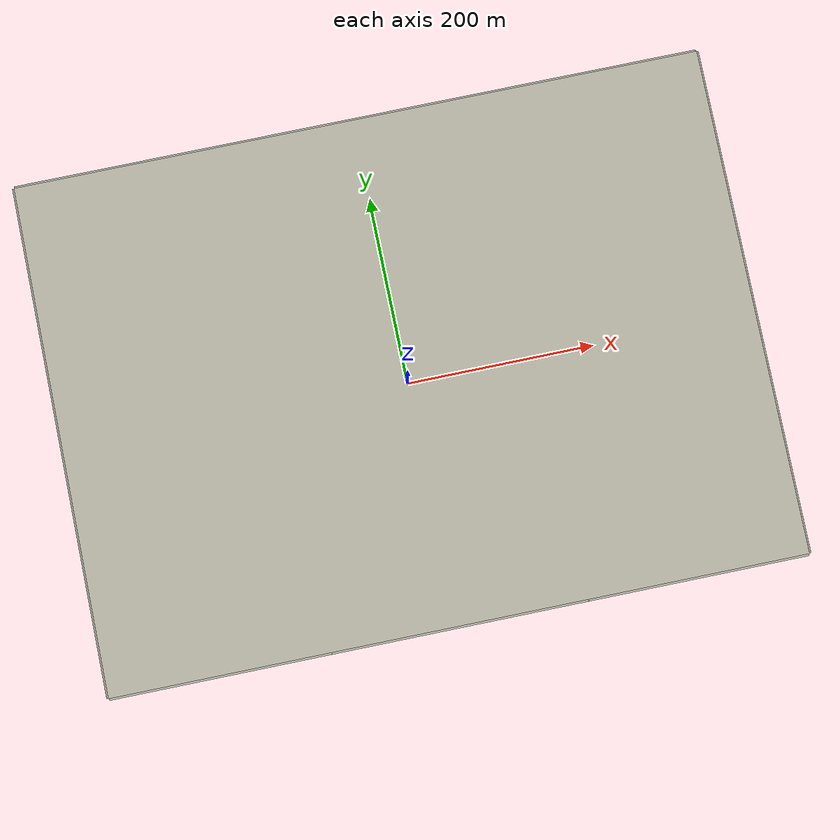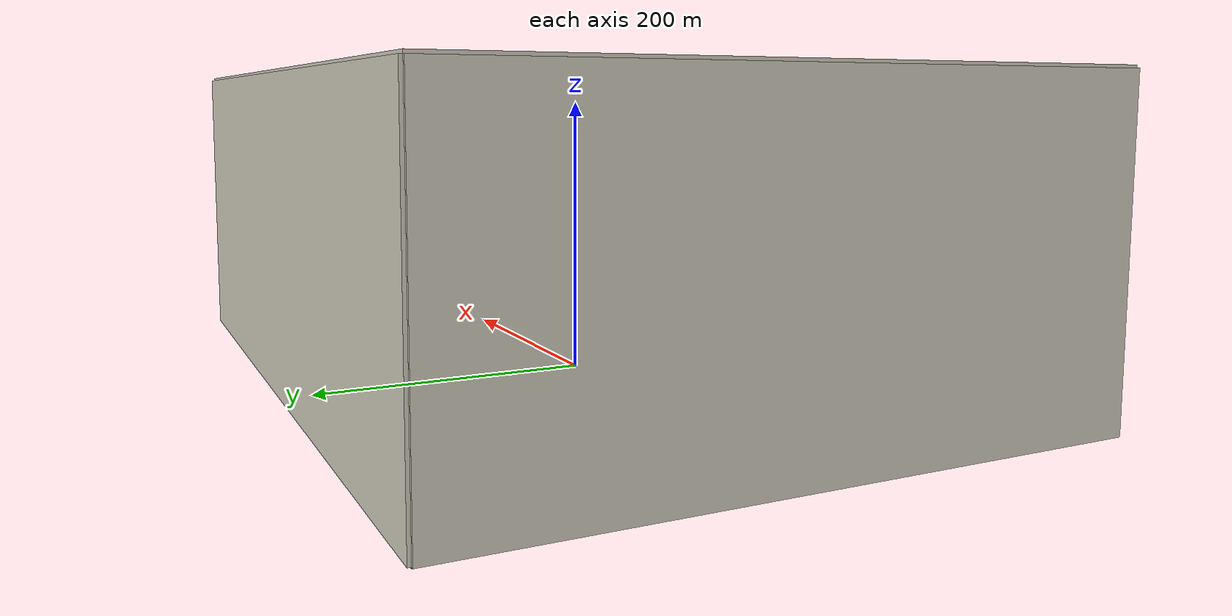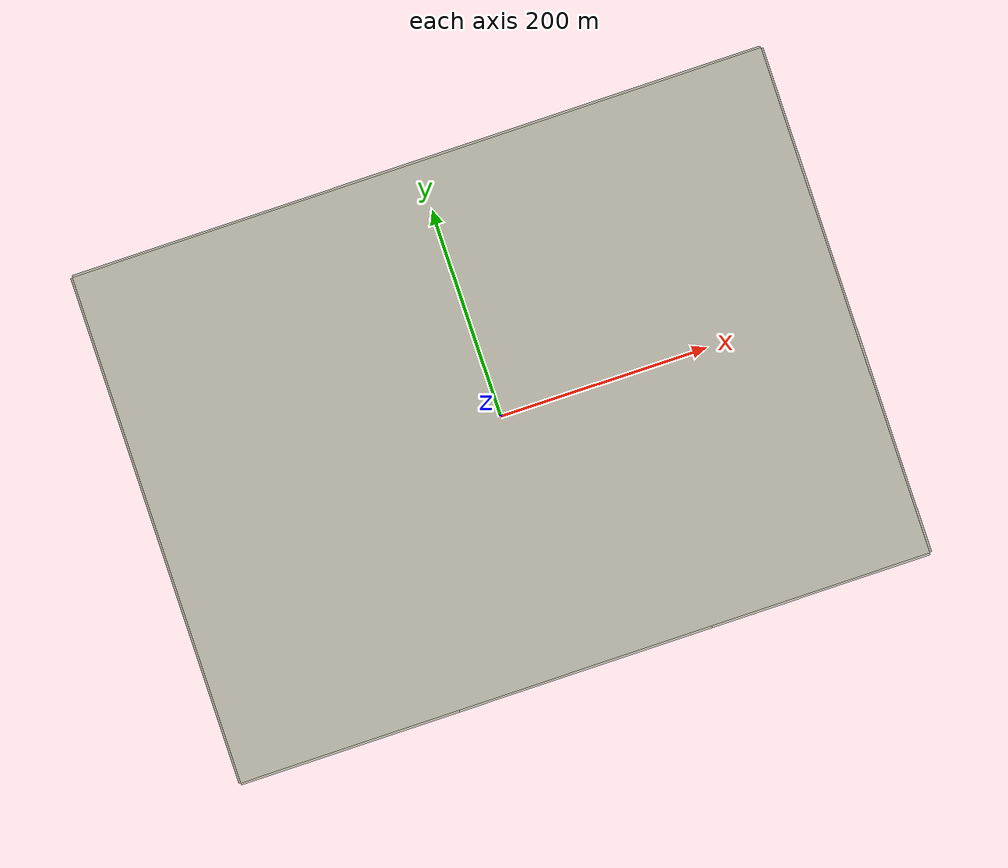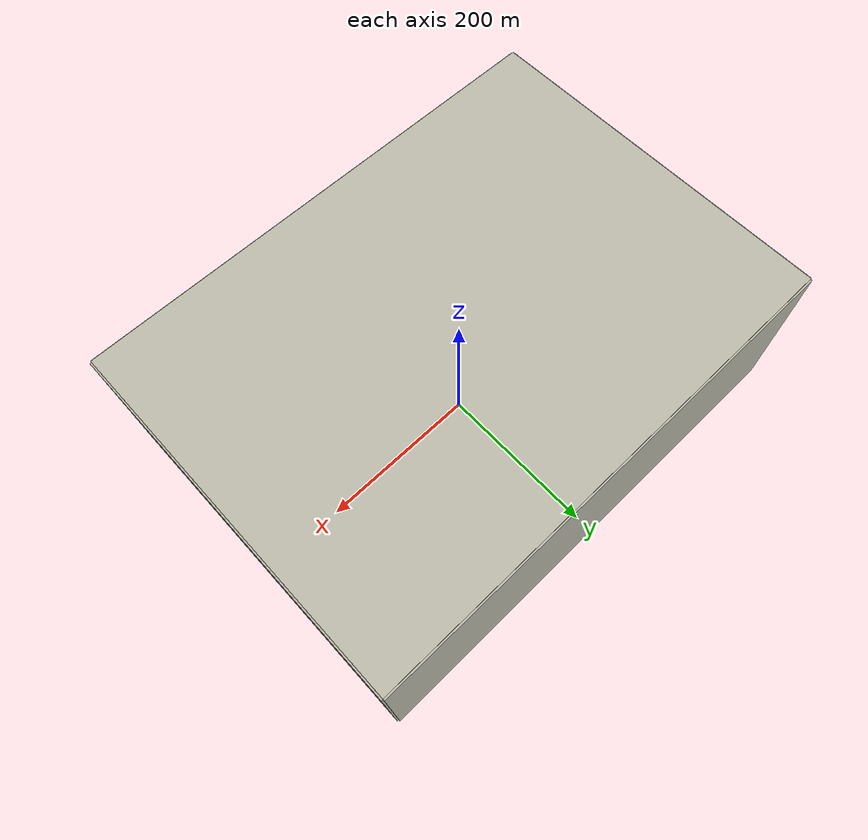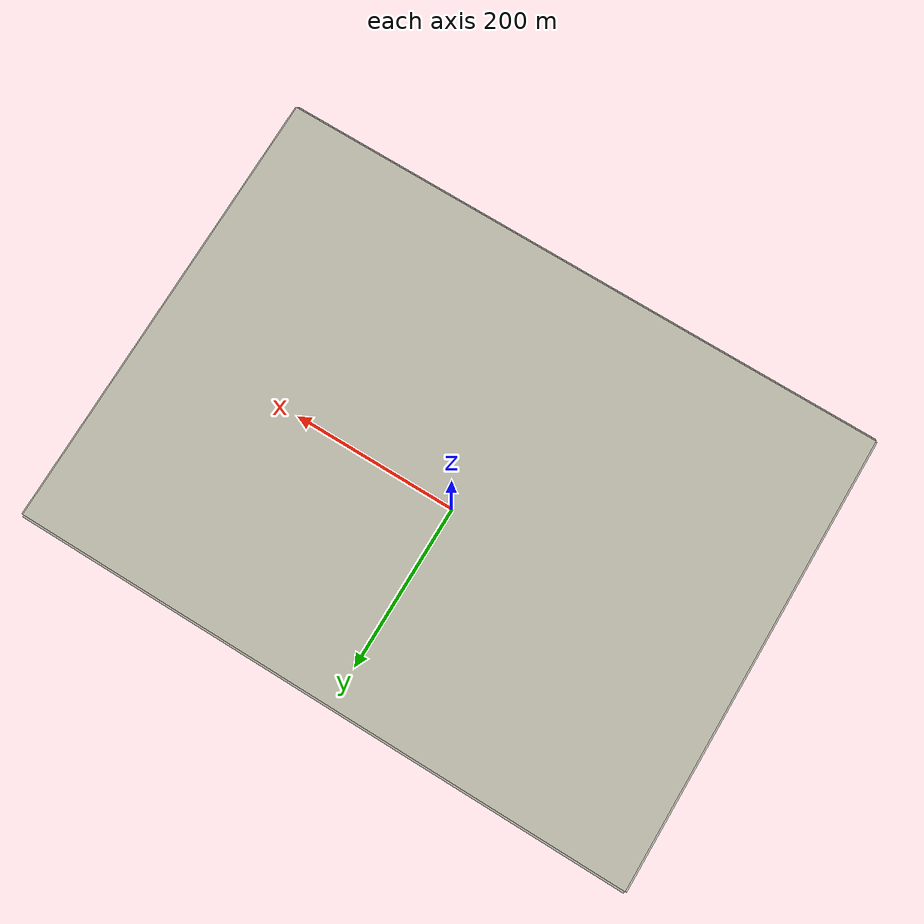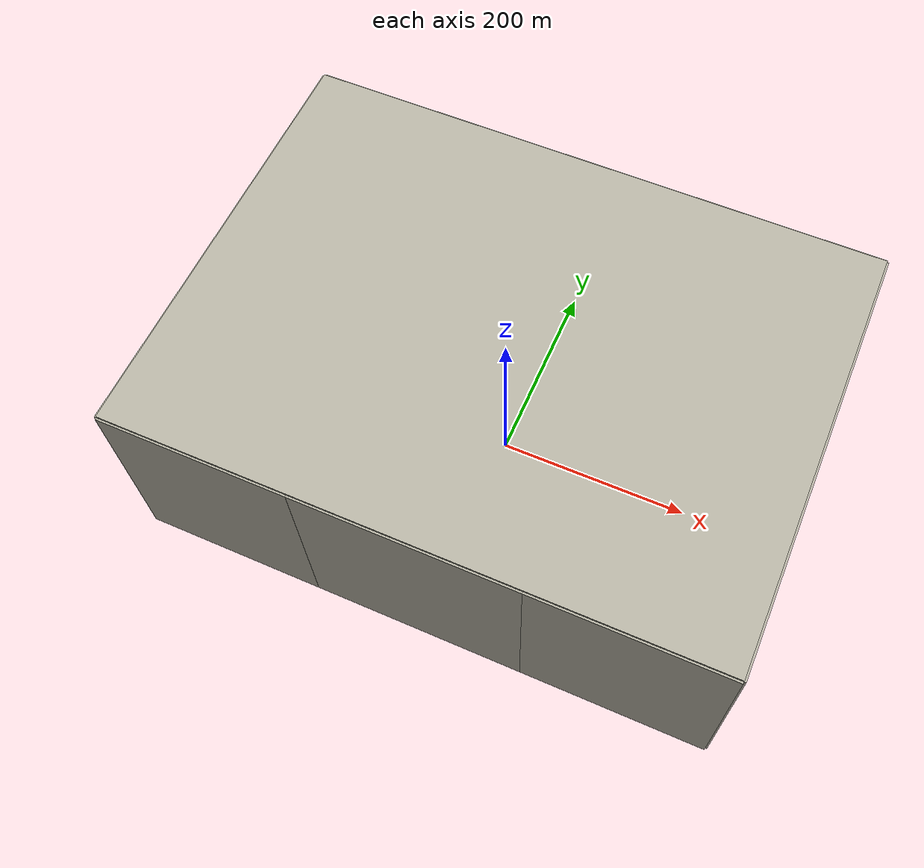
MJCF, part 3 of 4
<mesh name="fly/detail_surface_lh_trochanterfemur" vertex="-0.0618689955 -0.00422511403 -0.759697927 -0.0616871839 -0.00858234944 -0.758993556 -0.0613996017 -0.00701607905 -0.754549808 -0.0595542551 -0.00859028023 -0.784304226 -0.0575771264 -0.02422123 -0.709229207 -0.0566192248 0.00612421172 -0.811877253 -0.0560823537 0.00584313284 -0.813513354 -0.0558906067 0.00683635517 -0.827393786 -0.0558646971 0.00504211675 -0.814797007 -0.0553380596 0.00915663441 -0.82543504 -0.055231827 0.00747440026 -0.820324058 -0.0552160382 -0.0323243257 -0.682189537 -0.0549995348 -0.00606157846 -0.111005858 -0.054342705 0.0115973362 -0.829322264 -0.054310487 -0.0190441388 -0.124405196 -0.0542916532 -0.036967278 -0.652267656 -0.0540252404 0.0049297696 -0.0849889839 -0.0539873399 -0.0046924506 -0.72539947 -0.0538980057 -0.0339791841 -0.708266336 -0.0538173881 -0.0341745326 -0.670980546 -0.0535442196 -0.0370959715 -0.625499291 -0.0534029714 0.00754727262 -0.782385527 -0.0525028736 0.0209078371 -0.0600639141 -0.0524865209 -0.0391497451 -0.645426102 -0.0524787647 -0.00824874405 -0.121734891 -0.0523257804 -0.0164665325 -0.0871624507 -0.0521211514 -0.0278993575 -0.63674507 -0.0520212379 -0.0477431386 -0.639134028 -0.0517612061 -0.0279988308 -0.109125343 -0.0516869368 0.000797595021 -0.822422095 -0.0516681357 0.017244216 -0.811764563 -0.0512295301 0.00986216128 -0.835069164 -0.050634837 0.0127169351 -0.76152425 -0.0504978307 -0.0199266469 -0.0505662138 -0.0504931231 -0.0384610175 -0.594614132 -0.0501666946 -0.0467055106 -0.602851855 -0.0499074631 0.0292550903 -0.0463693286 -0.0498702466 0.0117110521 -0.0355143748 -0.0496954781 -0.0220113288 -0.136758696 -0.0492699182 -0.0461749478 -0.582332374 -0.0487260404 -0.0482653086 -0.692468835 -0.0481563729 -0.0386819156 -0.750697742 -0.0478796937 -0.0153699566 -0.143099256 -0.0474078843 0.0104404007 -0.107823238 -0.0473617256 0.0368707697 -0.0526330841 -0.0464720069 0.0225545227 -0.843350717 -0.0455781956 0.00408497999 -0.712664565 -0.0454511501 -0.0537246306 -0.567203388 -0.0452213717 -0.0376774442 -0.0936107535 -0.045157125 -0.0218260102 -0.807314354 -0.0439516334 -0.000509649624 -0.128637243 -0.0439017495 -0.0173461212 -0.592229539 -0.043278822 0.0113416409 -0.843198854 -0.0427187806 0.0224421437 -0.795737491 -0.0425940889 0.01927214 -0.849028758 -0.0425119979 -0.0110518686 -0.147151106 -0.0424560567 -0.0335489494 -0.0562868663 -0.0422597186 0.0623263113 -0.0294162201 -0.0422170306 -0.0341882405 -0.0693889233 -0.0421474797 0.065780674 -0.0364330335 -0.04190455 0.00656417615 -0.686064595 -0.0418094787 -0.0262583872 -0.152969544 -0.0416771436 0.0631585572 -0.0208988786 -0.0411367473 -0.0277755353 -0.0399547862 -0.0411153014 -0.0663634419 -0.571063196 -0.0410702924 0.0608719638 -0.0154778827 -0.0409970744 -0.0169795367 -0.158184339 -0.0409430941 0.0671532543 -0.0539500397 -0.0409216918 0.0198041816 -0.757681788 -0.0406796207 -0.0628062844 -0.619985454 -0.0406457475 0.0316238547 -0.846537587 -0.0405688552 -0.0380105012 -0.515524007 -0.0402214428 0.0568206997 -0.00873589124 -0.0397485346 -0.0201875118 -0.558129745 -0.0396982723 -0.00733425986 -0.612257107 -0.0391010908 -0.0581575405 -0.544030569 -0.0390569767 -0.0405902319 -0.147050669 -0.0384435662 -0.034484925 -0.117157164 -0.038364873 0.0303512024 -0.115243914 -0.0382725157 0.0509745332 -0.00563034155 -0.0381305217 -0.0283585305 -0.176461501 -0.0380026031 -0.0090864587 -0.588190625 -0.037811802 0.0451927554 -0.0937319492 -0.0377501965 -0.00963007733 -0.836004736 -0.0374719129 -0.0584075642 -0.528182194 -0.0370925918 0.0435334041 -0.00318559319 -0.0370603993 -0.0365169071 -0.182740507 -0.0361794846 -0.0707079234 -0.568691525 -0.0360191771 0.0214904412 -0.854396261 -0.0358457364 0.0352902716 -0.00275066122 -0.0358328216 0.0736860238 -0.0559109176 -0.0357809768 -0.0416184012 -0.19692794 -0.0355940829 0.0367081157 -0.829300785 -0.0354270887 -0.0516344735 -0.490951061 -0.0354229087 0.0248944725 -0.0040474597 -0.035310637 0.0135746322 -0.0026379189 -0.0350513947 -0.0469935694 -0.471188105 -0.0348200192 0.00861216995 -0.00403047579 -0.0347805617 0.0126177329 -0.00271640602 -0.0347421264 -0.0334158285 -0.228428427 -0.0346144188 0.0125424958 -0.00288575984 -0.0345925 -0.0181897612 -0.196093199 -0.034475408 -0.0239022065 -0.177805952 -0.0344245127 0.00972817361 -0.00253255712 -0.0343056199 -0.0246960408 -0.49256318 -0.034030385 0.0276939281 -0.781174225 -0.0338293248 -0.0674354451 -0.725620252 -0.0335752484 0.00856581391 -0.652939023 -0.0334798242 0.029287894 -0.769968843 -0.0334160868 -0.0453313878 -0.422156765 -0.0333240459 -0.0311455333 -0.459197152 -0.0332625386 0.00800795897 -0.00197429495 -0.0329872055 -0.0192013722 -0.171276377 -0.0329408758 0.0213626481 -0.718438649 -0.0322995293 -0.0385764943 -0.241198475 -0.0322731066 -0.0445991136 -0.0825890747 -0.0318954444 -0.0485761302 -0.142072124 -0.0317632839 -0.0494794767 -0.158075374 -0.0317093873 -0.0474192311 -0.232003193 -0.0316931 0.0276925985 -0.13440878 -0.0312643715 -0.0444650832 -0.183341719 -0.0311684198 -0.0170467174 -0.497716304 -0.0310752694 0.00309401184 -0.594924903 -0.0307680602 -0.0238603443 -0.382811151 -0.0306130751 -0.0405386636 -0.36665934 -0.0305441463 -0.0647249326 -0.760503404 -0.0302653571 -0.0562269852 -0.785729557 -0.0302112312 -0.053443091 -0.409110216 -0.0299510175 0.0521605325 -0.0270030869 -0.0298203013 -0.0189284037 -0.24529011 -0.0297291881 0.0313236014 -0.764549361 -0.029589939 -0.0457739261 -0.254702958 -0.0295106765 -0.039763705 -0.339020509 -0.0294574929 -0.0177604961 -0.412849127 -0.0293172379 0.0426551996 -0.114102761 -0.0292873192 -0.0136155231 -0.501657894 -0.0292732584 -0.062212348 -0.440500822 -0.0291663237 0.0076206079 -0.155398942 -0.0290458156 -0.0109694429 -0.00394778635 -0.0288209976 -0.00747243575 -0.163471792 -0.0287925686 -0.0447880702 -0.309796364 -0.0286504619 -0.0207981047 -0.372479291 -0.0283878398 0.000708324478 -0.158687559 -0.0282618093 -0.0110405645 -0.451866857 -0.0282438814 -0.0355044031 -0.269550568 -0.028155071 -0.0445090336 -0.0949232053 -0.0280473196 -0.0419790595 -0.113811875 -0.0279592023 -0.0535557228 -0.355225551 -0.0278474799 -0.0488992082 -0.132876885 -0.027656155 -0.0760831608 -0.575313403 -0.0274820977 -0.0742683187 -0.664684456 -0.0274196063 -0.0264888222 -0.269196637 -0.0272208963 0.00863664172 -0.617963902 -0.027049955 -0.0726204744 -0.686238054 -0.0270119017 0.073636962 -0.0667871791 -0.0269968823 0.0251288839 -0.139235213 -0.0269955854 -0.0392507391 -0.281220855 -0.0269251104 -0.0104041555 -0.467820064 -0.0269218799 0.000597131418 -0.846261741 -0.0268992808 -0.0193733431 -0.838596316 -0.0268499789 -0.00967806409 -0.22373005 -0.0267826927 -0.04380069 -0.275919854 -0.0266905427 -0.0491481696 -0.167695471 -0.026654865 -0.045562545 -0.129739696 -0.0266151928 -0.0445835576 -0.276479259 -0.0265868766 -0.0042836482 -0.186103833 -0.0265700874 -0.0439397845 -0.277541083 -0.0264613263 -0.0530983707 -0.207393678 -0.0264283335 -0.0485277669 -0.278703665 -0.0264131377 -0.0404718048 -0.308996649 -0.0264060545 -0.0788406905 -0.624471693 -0.0263611837 -0.0680761586 -0.491212821 -0.0262798567 -0.0265740509 -0.316211605 -0.0262734793 -0.0175362293 -0.252218859 -0.0262579779 -0.0423875535 -0.27715505 -0.0262465092 -0.017295597 -0.270491932 -0.0262104113 -0.0453469438 -0.0598820843 -0.0261275236 -0.0380898891 -0.268317468 -0.0260483775 -0.0372139766 -0.270078192 -0.0260233937 -0.0432574852 -0.817417284 -0.0258845175 -0.0129291857 -0.235595318 -0.0258682048 -0.0475481029 -0.298995234 -0.0258250566 -0.0677173957 -0.471837178 -0.0256703224 -0.0159383726 -0.309250463 -0.0256195526 0.0235415682 -0.857442501 -0.0254994811 -0.0457302522 -0.0772410131 -0.0253487688 -0.0163713739 -0.337704871 -0.0252628488 -0.0383946463 -0.27405814 -0.0252595419 -0.0150786364 -0.261531881 -0.0251551628 0.00288125943 -0.556146493 -0.0250392586 -0.00827448002 -0.473560445 -0.0250387129 -0.0614161836 -0.385148363 -0.0249232999 -0.0692780231 -0.537549378 -0.024761197 -0.0256548319 -0.2693024 -0.0246496911 -0.016949587 -0.362012128 -0.0241979305 -0.0381132777 -0.279835425 -0.0240900699 -0.037187594 -0.289545162 -0.0240368099 0.00151872882 -0.532692531 -0.0240223744 -0.0626541587 -0.36791552 -0.0239013661 -0.0122169686 -0.230673439 -0.0238436078 -0.0619136772 -0.335591991 -0.0237594286 -0.0186300022 -0.252245081 -0.0237143067 -0.0714831986 -0.748226419 -0.0237040094 -0.0271566296 -0.198464171 -0.0234801391 -0.0153942365 -0.246485113 -0.0234566432 0.00301576165 -0.203023883 -0.0233370447 0.0711166358 -0.0709449523 -0.0233018764 -0.00274592708 -0.483998039 -0.0231174618 -0.0141423106 -0.368317735 -0.0230974729 0.00156291026 -0.22013532 -0.0230074547 -0.0370515118 -0.264698523 -0.0228669996 -0.0123587142 -0.268335745 -0.0227780583 -0.0394093731 -0.0320369581 -0.0227517994 0.00951351558 -0.581961824 -0.0227169821 0.072502582 -0.0744248464 -0.022684726 -0.0318391831 -0.31524495 -0.022609489 -0.0110182118 -0.353650772 -0.0225835865 0.022915403 -0.68620895 -0.0223426505 0.0057704442 -0.177235328 -0.0222518574 -0.0708329972 -0.454062334 -0.0221107675 -0.0188570812 -0.3303556 -0.0220122602 -0.0350909431 -0.312901568 -0.0219899412 -0.0135429382 -0.323981105 -0.0218992263 0.0142086892 -0.604750239 -0.021632799 -0.00559708587 -0.413618342 -0.0215620312 -0.00653442839 -0.165452366 -0.0215406544 -0.007798365 -0.466751604 -0.0213425592 -0.0597063117 -0.278436288 -0.0213112235 -0.0115219673 -0.222993913 -0.0212279319 -0.00446780405 -0.391293201 -0.0211766055 0.0723288031 -0.0729278836 -0.0211429833 -0.00210092458 -0.440688164 -0.0210834769 -0.0339491307 -0.318159291 -0.0210671278 -0.0169708819 -0.357445388 -0.0208926831 -0.0129072032 -0.301622844 -0.0208707552 0.0717914299 -0.0738158706 -0.0207668909 -0.0366780441 -0.312459568 -0.0207517842 -0.0391373942 -0.26774974 -0.020730542 -0.0160249911 -0.266989926 -0.0206110944 -0.00458913655 -0.377176533 -0.0203521304 -0.061386585 -0.262932153 -0.0203258678 -0.0107013257 0.00425604776 -0.0202854717 0.0385683525 -0.849031785 -0.0201427865 -0.0226030679 -0.363719679 -0.0201158091 -0.00303205843 -0.428678904 -0.0199974693 -0.0607004149 -0.239176894 -0.0199927254 -0.0117606687 -0.34875868 -0.0199849019 -0.0180881652 -0.337944366 -0.0199625847 -0.0110516903 -0.350842311 -0.0199489841 -0.00759479599 -0.351746246 -0.0199130336 -0.00943287432 -0.223663257 -0.0198914113 -0.0197815516 -0.30423011 -0.0197221416 -0.0143432726 -0.350903923 -0.0197154677 0.00291694937 -0.504608441 -0.0197087938 -0.0137175348 -0.341656356 -0.0195499379 0.0342445564 -0.73595671 -0.0194690092 -0.0269547854 -0.346769026 -0.0194481763 0.0392855036 -0.829369586 -0.0193751839 -0.0115869625 -0.346198445 -0.0193679116 -0.00888201794 -0.46990352 -0.0193596425 0.00325074961 -0.00831048328 -0.0192236876 0.0184326454 -0.0131698034 -0.0191746276 -0.0166205409 -0.315887999 -0.0191517574 -0.00983108384 -0.313582103 -0.0189740349 -0.0836873733 -0.623322907 -0.0187426558 -0.0395814495 -0.215052074 -0.0187398437 -0.00855867984 -0.316051184 -0.0187189253 -0.00748429738 -0.250566431 -0.0187139995 -0.00298092982 -0.468186539 -0.0186209763 -0.0113209662 -0.471020176 -0.0186057623 -0.0356035889 -0.318233302 -0.018573206 -0.0426742517 -0.247917225 -0.018410783 -0.00551805761 -0.228202029 -0.0183609882 -0.0104829314 -0.21788993 -0.0182153053 -0.000712488145 -0.238862311 -0.0181567448 -0.00880656535 -0.315299432 -0.0179810795 -0.00387525961 -0.159125048 -0.0179652852 0.0225686745 -0.637823599 -0.0179366962 -0.0687409265 -0.33504123 -0.017846156 -0.0723958146 -0.505388365 -0.0177604452 -0.0233946448 -0.361758342 -0.0177292786 -0.0117308946 -0.470026309 -0.0176994472 -0.00969365192 -0.353264011 -0.0176973808 -0.044399545 -0.251111342 -0.0176608992 -0.00980743062 -0.470585626 -0.0176504018 -0.0153530109 -0.184890974 -0.0175860641 0.00934014861 -0.225155629 -0.0175723471 0.0356815071 -0.0266447605 -0.0173635017 -0.0757095113 -0.422453537 -0.0172900636 -0.0753714776 -0.418683194 -0.0172410237 -0.00804061801 -0.315211131 -0.0171581742 -0.00446456897 -0.26939917 -0.0169506566 -0.038958362 -0.205921751 -0.0169262603 -0.0394686431 -0.282613473 -0.0168922961 -0.00897734753 -0.342976331 -0.0168081751 -0.066869572 -0.294180529 -0.01680274 -0.043260512 -0.226780001 -0.0167774342 -0.0180539009 -0.342999643 -0.0166023492 -0.0410592547 -0.268125266 -0.0165712099 -0.0750747349 -0.430096959 -0.0165140809 0.00159862702 -0.262898888 -0.0165127258 -0.0383925217 -0.291709439 -0.0164845787 -0.0418077216 -0.0397814438 -0.0164406392 -0.00508381754 -0.366415654 -0.0162072829 -0.00597325607 -0.470892119 -0.0161811968 -0.0285151564 -0.177337904 -0.0159532538 0.00187963826 -0.346175017 -0.0159525134 -0.0358683355 -0.0222769268 -0.0159349456 -0.00638607344 -0.251242018 -0.0159122392 -0.0113379756 -0.471850741 -0.0159012343 -0.0267032665 -0.153690111 -0.0158789189 -0.0038105818 -0.338100683 -0.0157864361 -0.0187138485 -0.339183578 -0.0156970182 -0.0284425987 -0.166640704 -0.0156471542 -0.0131195329 -0.34743076 -0.0156422902 -0.0313544442 -0.181496405 -0.0155183479 0.000410290994 -0.152134104 -0.0154612917 -0.0269001575 -0.338848418 -0.0154125555 0.012106666 -0.854541722 -0.0154102199 -0.00326013469 -0.321491825 -0.0154024692 -0.0324707507 -0.318458944 -0.0152514585 0.00389249635 -0.146837658 -0.0152233943 -0.0183138145 -0.366281864 -0.0152099838 -0.00350958771 -0.244600931 -0.0151778477 -0.0106461675 -0.472899061 -0.0151110871 -0.000301415639 -0.351558905 -0.0151019503 0.028634222 -0.67387626 -0.0150916658 -0.0412454028 -0.216556742 -0.0150891628 -0.0113567148 -0.472621265 -0.0150756496 -0.0122335132 -0.203016971 -0.0150274773 -0.0441295379 -0.078833109 -0.014973768 0.00196016026 -0.286877679 -0.0147424216 -0.00359147043 -0.474624103 -0.0147412829 -0.0434174508 -0.241856687 -0.0146455295 -0.00122751408 -0.478356058 -0.0145607974 -0.0429706961 -0.236272041 -0.0145066178 -0.004511508 -0.477153051 -0.0144713167 -0.008571943 -0.253435661 -0.014366542 0.000868094048 -0.303978013 -0.0143472771 -0.0103525026 -0.473018124 -0.0142456138 -0.0415021786 -0.250034383 -0.0142425706 0.0295178324 -0.661960221 -0.013976387 -0.0237107488 -0.0035664707 -0.0137868901 -0.0856574552 -0.578010455 -0.0136639801 -0.00286484624 -0.2903516 -0.0135258088 -0.075963384 -0.393558643 -0.0133343183 0.00841294604 -0.249385252 -0.0133164849 -0.0106718207 -0.312072516 -0.0132690475 -0.0339164071 -0.142573524 -0.0132609912 -0.0109101302 -0.474141067 -0.0132392815 0.0502887051 -0.115524788 -0.0131097713 -0.0365980377 -0.201804243 -0.0129954024 0.0408990563 -0.817566295 -0.0128982037 -0.00390301966 -0.475638866 -0.0128932134 0.0623406522 -0.0971601403 -0.0127835183 -0.0375854033 -0.151292174 -0.0126751611 0.031747586 -0.859776337 -0.0126651748 0.0423497295 -0.794409832 -0.0126323685 0.0227257078 -0.183657758 -0.0124883991 -0.0342002968 -0.195701665 -0.0122569709 -0.0175384648 -0.181741139 -0.0121878256 -0.0326328955 -0.186607111 -0.0121337653 0.00732089393 -0.287839415 -0.0120594359 0.0106802545 -0.520312518 -0.0120449631 -0.00909895243 -0.321994885 -0.0120079549 0.00349964102 -0.297100371 -0.0119041988 0.0154378595 -0.540774025 -0.0116516221 0.000331612654 -0.472167158 -0.0116170686 -0.0374209631 -0.209063146 -0.0113897586 -0.0565723567 -0.185268174 -0.0113654678 -0.0285927817 -0.133295864 -0.0112211164 -0.0148052959 -0.273329963 -0.011203565 -0.027860402 -0.13255587 -0.0111662048 -0.0270115434 -0.136747622 -0.011080594 0.0707634099 -0.0785105003 -0.0109709963 -0.0283911995 -0.132646805 -0.0109218563 -0.00867926974 -0.298101921 -0.010875925 -0.0278394018 -0.131037916 -0.0108323256 -0.0157795912 0.00433112746 -0.0108013046 -0.0286786417 -0.133318768 -0.0107459546 0.00567838106 -0.445121404 -0.0107298238 -0.0154629815 -0.21736107 -0.0105518639 -0.0782980205 -0.375920528 -0.0105342315 -0.0648595305 -0.22571694 -0.0104934043 -0.0164644262 -0.260325702 -0.0103333387 0.0442524251 -0.12022187 -0.0100312382 0.00400020326 -0.362698076 -0.00991861725 -0.0602684704 -0.827313808 -0.00977752643 -0.0302720618 -0.137688025 -0.00969134817 -0.0638763813 -0.819504785 -0.00968238783 -0.0751931511 -0.756329973 -0.00964649189 -0.069133428 -0.800241018 -0.00964265018 -0.0245707015 -0.166688435 -0.00955746509 -0.0296181643 -0.196746158 -0.00949019886 -0.0285831647 -0.176153582 -0.00943365194 0.0435653055 -0.800039154 -0.00924275537 -0.0537353371 -0.167581267 -0.0090962285 -0.0318996863 -0.159550851 -0.00892755543 -0.0316381265 -0.159846371 -0.00887333408 -0.0302953085 -0.159831747 -0.00886652379 -0.0296552389 -0.160390991 -0.00875576461 0.0103786551 -0.149391504 -0.00873712725 -0.023454164 -0.157158414 -0.00860073851 -0.0650228321 -0.241332265 -0.00852782068 0.0207027406 -0.572674733 -0.00845727845 -0.032867425 -0.1513959 -0.00803332478 0.00871630255 -0.40211677 -0.00793238542 -0.0456886228 -0.0664277759 -0.00748543243 -0.053804717 -0.835776562 -0.00721542074 -0.0686641069 -0.251623365 -0.0071680106 -0.0814114755 -0.655236363 -0.00712456404 -0.0725572827 -0.780144765 -0.00670501868 0.0071604627 -0.863810477 -0.00667248923 -0.0404559905 -0.845426344 -0.00637722314 -0.0817259788 -0.394115457 -0.00620417859 0.00707602157 -0.144328093 -0.00597131566 0.0211390852 -0.238453853 -0.00590871969 -0.086276108 -0.575724989 -0.00586580973 0.0132133937 -0.337737176 -0.00567709867 -0.0412367081 -0.0796033128 -0.00563532194 0.0171204592 -0.859847642 -0.00543995156 0.013143379 -0.353882439 -0.00527679549 0.0122793417 -0.477276539 -0.00521097945 -0.0767819074 -0.321969419 -0.00519836067 0.0440954173 -0.768970407 -0.0047577596 0.0416190924 -0.707923027 -0.00463166043 0.0507006189 -0.0487312536 -0.00463021934 0.0291890792 -0.612128351 -0.00461681611 0.0258603141 -0.584113237 -0.00387887212 0.033125325 -0.123613747 -0.00382344115 0.0236327942 -0.860889966 -0.0037270097 0.0194414442 -0.509089266 -0.00368829546 -0.0599585874 -0.190019331 -0.00332985815 0.0219617978 -0.533800689 -0.00325893575 0.00246935542 -0.866535178 -0.00324807775 0.013776471 -0.466977508 -0.00315731427 0.012777562 -0.447127066 -0.00301336672 -0.0549982033 -0.129827473 -0.00230380442 0.0394905364 -0.679555757 -0.00228411932 -0.078801655 -0.33707486 -0.00211425117 0.0138570067 -0.371928589 -0.0021114945 -0.0831766083 -0.713742746 -0.00211076417 -0.0101671449 -0.863317982 -0.00208817232 -0.0808314871 -0.737117545 -0.00207099538 0.0196894125 -0.282662135 -0.00192159087 -0.0668663706 -0.225127209 -0.00180148663 0.0248186316 -0.130259505 -0.00173713534 0.0145608938 -0.398369593 -0.00160608931 -0.0850239448 -0.664445222 -0.00150502262 -0.0753106724 -0.301495107 -0.00122400695 -0.0868826246 -0.628545822 -0.0011930905 0.0288364135 -0.228023884 -0.00111655834 -0.0658596837 -0.808497483 -0.0010846577 0.0152026269 -0.139424519 -0.000375463259 0.02624843 -0.25499289 -0.000197764535 -0.0165819583 0.00457166152 -4.02149638e-05 -0.0837302432 -0.689208915 -2.48699639e-05 0.0179869439 -0.146956227 0.000406855122 0.0464522782 -0.731437409 0.000444103705 -0.0079174215 -0.86924521 0.000456508587 0.0165965048 -0.357417768 0.000819379409 0.0283228364 -0.859859516 0.00158741125 0.0391829781 -0.205305943 0.00170741646 -0.0070404044 -0.868303294 0.00207282437 -0.0851770601 -0.555532693 0.00224375913 0.0423935671 -0.690307876 0.00242531155 -0.035791174 -0.852045137 0.00248994206 -0.0852966768 -0.6758573 0.00257571969 0.0234421786 -0.302925328 0.00276176797 0.015935575 -0.383493578 0.00286299246 -0.0428982021 -0.848953438 0.0030923195 -0.0859649881 -0.441033655 0.00313537862 0.0187865971 -0.458315801 0.00318845082 0.03864467 -0.219724665 0.00356048895 -0.0635295946 -0.146009203 0.00361421849 0.0385837047 -0.246475422 0.00368007068 0.0553127466 -0.103911101 0.00372177533 0.0204852186 -0.317736471 0.00377477977 -0.0751552652 -0.282215158 0.00389586239 -0.0890685405 -0.648616231 0.0043480818 -0.051369334 -0.838226348 0.00460759429 -0.0492301588 -0.115476512 0.0046983464 -0.0436471819 -0.087879911 0.0047682106 -0.038745955 -0.0540230649 0.00497719429 -0.0257826759 -0.0176809554 0.00502347075 -0.0862646775 -0.406203384 0.00504515174 -0.0838769047 -0.495246786 0.00535802064 0.0491636965 -0.727703329 0.00549004835 -0.0873817989 -0.441863114 0.00565405844 -0.0869481664 -0.44197985 0.00637683434 0.0232371276 -0.342752843 0.00640934786 0.0268854401 -0.488071906 0.00667525137 -0.0202884512 -0.863059424 0.00688560249 0.0341400082 -0.845763134 0.00689314675 0.0218423847 -0.411381829 0.00693081893 0.0301828222 -0.534266466 0.00715939859 -0.0865920083 -0.44554862 0.00759424984 -0.0873905301 -0.613764336 0.00765140794 -0.0477403119 -0.107777771 0.00765653294 -0.0665061525 -0.798094377 0.00795990672 -0.0654062096 -0.374423107 0.00818148965 0.0441094126 -0.640402664 0.00822907714 -0.0798472756 -0.735490408 0.00833246395 -0.0642089144 -0.338502578 0.00885487862 -0.0663318642 -0.20664974 0.00897905556 -0.0580589258 -0.164586891 0.00906343939 -0.0589069205 -0.135708804 0.00935156186 -0.0308475464 -0.857769512 0.00941605595 0.0454182191 -0.66488533 0.00956556141 0.0452619352 -0.255100022 0.0102269278 -0.0713768532 -0.363930973 0.0103754446 -0.0612066651 -0.38007999 0.0104308228 -0.0676768905 -0.386912376 0.0106658044 -0.0679708537 -0.351593102 0.0108204695 -0.0607299007 -0.362215826 0.0109457214 0.0418573291 -0.11031657 0.010969412 -0.0716432478 -0.764001394 0.0110033925 -0.0908631046 -0.630854163 0.0110869296 0.0427519226 -0.810959144 0.0110889323 -0.0659036377 -0.321575382 0.0111259551 -0.062273888 -0.31942589 0.0113278811 -0.0739618044 -0.288067065 0.0114996219 0.0354438271 -0.507539837 0.0115199764 0.0461209929 -0.196022389 0.0116334986 0.0644049724 -0.0878196079 0.0118372736 -0.054955919 -0.121526085 0.0118388853 -0.0908642614 -0.625117449 0.0119170099 -0.0744573626 -0.331506744 0.0119761089 -0.0714945054 -0.36368781 0.0120719078 -0.0700621749 -0.239782195 0.0122445363 -0.0135237678 0.00143703073 0.0122631973 -0.0624659006 -0.387145905 0.0123466225 -0.0878536885 -0.474992965 0.0124510216 0.0328212336 -0.459919538 0.0124548505 -0.069310976 -0.328454073 0.0125448641 0.0324481553 -0.374227675 0.0126147661 0.0355497905 -0.150059044 0.0126400373 0.0477519025 -0.794124091 0.0126522482 -0.0610025454 -0.302150962 0.0126881023 -0.0599090999 -0.378735829 0.0127504027 -0.087070337 -0.55769569 0.0129768632 0.045402634 -0.29834517 0.0129825412 -0.078266472 -0.334400596 0.0130708477 -0.0744908466 -0.331415096 0.0130972694 0.0337586134 -0.493107014 0.0131558863 -0.0915427008 -0.630490773 0.0131723846 -0.0104975588 -0.00213817111 0.0131732522 -0.013262209 -2.93084472e-05 0.0132466994 -0.059597558 -0.366573222 0.0135622386 -0.0876826962 -0.425673323 0.0135940682 -0.0661835365 -0.311270269 0.0136076706 -0.0589281626 -0.353406183 0.0137267707 0.0537039814 -0.239936839 0.0137300149 -0.0814649538 -0.687860476 0.0137559055 -0.0586692331 -0.313912897 0.0138180776 -0.0126090317 0.00082872873 0.0138652877 -0.0122478341 -0.000526255462 0.0139466738 -0.0626034307 -0.302114116 0.0139579688 -0.0703911282 -0.337776757 0.0139986414 -0.0693693728 -0.353374926 0.014029526 -0.0688764339 -0.378951139 0.0140503598 -0.067818939 -0.229652156 0.0145705817 -0.0466619349 -0.836950319 0.0146525172 0.0317771883 -0.131719076 0.0146589382 -0.0654262767 -0.385342137 0.0147689252 -0.0577900828 -0.320780557 0.0148753979 -0.0641832667 -0.286795839 0.0150273754 -0.0589267001 -0.3377377 0.015034735 -0.0640779035 -0.783992873 0.0150960759 -0.0616772159 -0.371736998 0.0151931981 -0.0585994458 -0.303671753 0.0151952581 0.0489122176 -0.285427872 0.0155690523 -0.011744808 0.000150204869 0.0156343758 -0.0764079232 -0.737445895 0.0157715604 -0.0600410058 -0.279969972 0.0157976283 0.0381562932 -0.484313205 0.0158830589 -0.0907020949 -0.611249881 0.0159156716 -0.0588257171 -0.283333065 0.0162092401 0.0363365871 -0.822741247 0.0167534308 -0.0672500464 -0.321334257 0.0168463466 0.0550810364 -0.0950178655 0.0168886054 -0.0639066129 -0.35797013 0.0169018513 -0.0592325814 -0.324928667 0.0169087598 -0.0566792623 -0.162507582 0.0169968935 0.0389207162 -0.350337068 0.0170067997 0.03953532 -0.524676347 0.0170089334 -0.066163906 -0.313695957 0.0170255189 -0.0807565812 -0.324871566 0.0171228567 -0.0663707106 -0.348583242 0.0171308802 -0.0602704131 -0.279490923 0.0173191293 -0.0886427079 -0.61971799 0.0173866702 0.0192855714 -0.859146763 0.0174643756 -0.0631142611 -0.30279241 0.0175454625 -0.0593069381 -0.310501171 0.0175801906 -0.0634068856 -0.309968105 0.017728531 -0.0630182185 -0.342463085 0.0178920818 0.0417039373 -0.571387762 0.0178924183 -0.0585745656 -0.281151093 0.0179266299 0.0430352557 -0.559811597 0.0181114465 -0.0848754789 -0.655285781 0.0181970699 0.0585621965 -0.272385631 0.0182483946 -0.0792210703 -0.303615991 0.018409497 -0.0612548029 -0.297693972 0.0184532073 -0.0626789115 -0.310716103 0.0185001954 -0.0645360124 -0.327887217 0.0186134475 0.0422927806 -0.546341471 0.0187512305 -0.0630113282 -0.286897237 0.0188208414 0.0528985111 -0.761972682 0.0188478662 0.0544161485 -0.327633024 0.0188698104 -0.0650562506 -0.290270022 0.0193732521 -0.0885344562 -0.443231052 0.019474197 -0.0831303842 -0.671215821 0.0194806616 -0.0901073508 -0.592815573 0.0194966451 -0.0912139294 -0.564424205 0.0196844594 0.0488630794 -0.363466126 0.0198528051 -0.0886989073 -0.518501678 0.0199347342 0.0526474469 -0.695492432 0.0200379782 0.0585850539 -0.305166061 0.0200770737 -0.0833149898 -0.365884305 0.0201303337 -0.0916096469 -0.573600468 0.0202025312 -0.0642984596 -0.778198009 0.0202122628 -0.0760468174 -0.279449043 0.0204213939 -0.0681332094 -0.758949667 0.0205006327 0.0556307168 -0.211266379 0.0205558863 -0.0860819346 -0.388271059 0.0206915538 -0.0827067779 -0.362160266 0.0207048524 -0.0500154893 -0.119964672 0.0207145295 0.0301335876 -0.122757643 0.0207347912 -0.0373494477 -0.848265016 0.0208124366 -0.0103798384 -0.00456813723 0.0211540682 0.0436628579 -0.425634411 0.0212740088 -0.0870463045 -0.493567321 0.0215576511 -0.0875114201 -0.500898517 0.0218474488 0.0572329373 -0.337674603 0.0222115505 -0.0421500008 -0.10304671 0.022438262 -0.0880174339 -0.507801247 0.022982018 0.0434391295 -0.411251531 0.0238014818 0.0119148372 -0.857080449 0.0241982143 0.047059395 -0.788395642 0.0242058741 -0.0102745134 -0.862752146 0.0247978223 0.0598708139 -0.233813247 0.0248469296 0.0201067123 -0.845282746 0.0249637269 -0.0885232148 -0.556603598 0.0249673285 -0.0730463289 -0.28546981 0.0252158079 0.0496476059 -0.50553272 0.025242296 0.0258974796 -0.124771002 0.0258270811 0.0619602579 -0.299446081 0.0263002803 0.0526070799 -0.671102724 0.0263313814 -0.0875723854 -0.535987609 0.026441965 -0.0726027283 -0.270860794 0.0267036285 -0.081195969 -0.340079074 0.0269334032 -0.0382175967 -0.812687795 0.0271685112 0.0522944174 -0.481541501 0.0279955784 -0.085812324 -0.386442931 0.0281124267 0.0648808054 -0.261179841 0.028130491 -0.0448010433 -0.148794221 0.0283732224 -0.0746953883 -0.300040934 0.0284900143 -0.0690134693 -0.253556791 0.0287246439 0.0521425027 -0.0827132608 0.0288376996 -0.0735758949 -0.32288552 0.0289629315 0.051449133 -0.756219495 0.0293660778 0.0659483703 -0.280579901 0.0294149977 -0.0764607248 -0.324725581 0.0299107869 -0.071174698 -0.710349763 0.0300194279 0.0563155554 -0.390265079 0.0303072793 -0.0236562009 -0.0491157989 0.0306579714 -0.063325293 -0.744259858 0.0307094051 0.0510895516 -0.465690711 0.0308147137 -0.0238443918 -0.0575241611 0.0309619572 -0.0101872974 -0.0131364895 0.0312663287 -0.0402998849 -0.798017078 0.0312889279 -0.0175548848 -0.839376706 0.0313716882 0.0443458412 -0.0872309392 0.0314805584 -0.0701450335 -0.279614091 0.0317543199 0.0537412052 -0.609350624 0.0318442944 -0.00177360255 -0.850370328 0.0320649269 -0.0828866032 -0.35221086 0.032097927 -0.0678768702 -0.26534684 0.0326561058 0.00486239469 -0.835799496 0.0328797069 0.0557451858 -0.715377973 0.0329713912 0.0525203141 -0.18692929 0.033022643 -0.0643699968 -0.214341737 0.0330840485 -0.0745950238 -0.310036703 0.0331316733 -0.0568280993 -0.180731789 0.033200391 -0.0279692558 -0.0827700496 0.0332242744 0.0604312008 -0.29438152 0.0333934368 0.0555750703 -0.531502184 0.0333955177 -0.0307159935 -0.13803909 0.0335352888 0.0545132716 -0.583943212 0.0336365592 -0.0669933288 -0.303794688 0.0336543126 0.0643500171 -0.282498251 0.0341316154 0.0672743336 -0.25573856 0.034184035 -0.0180926054 -0.815805513 0.0342423409 0.0142921526 -0.127588413 0.0343728243 -0.0244189887 -0.073232608 0.0345022454 0.0566545714 -0.661826169 0.0345391345 0.0680010198 -0.324983586 0.0347087662 0.0135544706 -0.820660207 0.0349117654 0.0574773694 -0.439853 0.0350850896 -0.0848285345 -0.453138899 0.0350890659 0.0540075489 -0.277459418 0.0351994786 -0.0710597087 -0.292599609 0.0352563329 0.0632803494 -0.281304965 0.0353470168 -0.0742707271 -0.642905536 0.0355359007 -0.0829136188 -0.519427238 0.0355922857 0.0241125963 -0.0485458295 0.0357253812 0.0687981956 -0.308871531 0.035932615 0.0662129678 -0.231038764 0.036235233 0.0539778594 -0.73667831 0.0364927873 0.0581526219 -0.421058619 0.0367131215 0.00599737177 -0.126986663 0.0371179594 0.0302372209 -0.143003475 0.0373794974 -0.0787750178 -0.6053939 0.0374723568 -0.00791824823 -0.120151097 0.0376591597 0.0563806971 -0.500935304 0.0377269062 -0.0504192358 -0.752875116 0.0378388941 0.0283306963 -0.800248759 0.0379674202 0.0698104923 -0.340577244 0.0380854508 -0.0570817429 -0.744974066 0.0382933213 -0.0647947745 -0.69263042 0.0383136794 -0.0757565576 -0.336523866 0.0384528612 0.0669951842 -0.247225806 0.0386325592 -0.0842836453 -0.398845848 0.0388174994 -0.0790101622 -0.361891201 0.0389093184 0.0541986192 -0.293071207 0.0390266287 -0.00519625064 -0.027952181 0.0390279092 -0.08277093 -0.542429334 0.0390314672 -0.0835008977 -0.550146739 0.0391540525 -0.00859217471 -0.808709185 0.039347844 0.0257721022 -0.0911374445 0.0396093601 -0.0730491884 -0.306985021 0.0396568939 -0.0606375361 -0.195497327 0.0399459022 0.0705022467 -0.275107916 0.0399746932 -0.0329080831 -0.785783632 0.040012128 -0.0706163191 -0.298407103 0.0401861871 0.0598720799 -0.299169391 0.0403298945 -0.0802970317 -0.480491115 0.0405900828 -0.0209028949 -0.137174356 0.0406920044 0.0685487685 -0.302444183 0.0409477252 -0.0147741703 -0.06372403 0.0409766617 0.0556999221 -0.562009925 0.0410182183 -0.00561978777 -0.0978611351 0.0410499561 0.0512389888 -0.741889526 0.0411513392 0.0538567401 -0.715711503 0.0412800764 0.0616342149 -0.281887013 0.0419114222 0.00155330963 -0.133517111 0.0423413221 0.0262175599 -0.787328696 0.0426601764 -0.0632126539 -0.230756385 0.0427978666 -0.0502983967 -0.737468945 0.0429735264 -0.0827217009 -0.421417615 0.043787677 -0.075300668 -0.587219663 0.0438754614 0.0560603148 -0.64420054 0.0439207797 0.0561972738 -0.604326313 0.0439643736 -0.074630334 -0.573725789 0.044119035 -0.00656383554 -0.0520239555 0.0441319135 -0.0794763691 -0.494977285 0.0443679928 -0.0158350158 -0.784450618 0.0444981415 0.0645592372 -0.412489113 0.0447061211 -0.078549383 -0.367871922 0.044980552 0.0567523457 -0.588364084 0.0450596854 -0.00360237118 -0.799510046 0.045083365 0.0156431215 -0.0807730248 0.0453385837 0.0555401675 -0.680304947 0.0456186244 -0.0587173236 -0.688419794 0.0456203561 -0.0648612549 -0.654643402 0.0458622599 0.0697429568 -0.381103629 0.0461602322 0.0385559215 -0.0679820878 0.0463296274 0.0599815321 -0.551719917 0.0464259392 0.00389203296 -0.0399320161 0.0464774894 0.0339100588 -0.0653003808 0.0466956153 -0.0658058561 -0.264320697 0.0468407561 0.0740879987 -0.287029834 0.0469872575 -0.0477728317 -0.166850165 0.0471195999 -0.0483798904 -0.71310834 0.0471429448 -0.0609045601 -0.643906009 0.0473665132 -0.0398121701 -0.154627167 0.04740433 -0.0657671917 -0.625615241 0.0474228473 0.0706599531 -0.358158082 0.0478737165 0.0390931637 -0.753149972 0.0480866511 -0.0329229442 -0.748136896 0.0481498464 -0.0815683961 -0.422303332 0.0483715339 0.0538763488 -0.18700998 0.0484098491 -0.00438367852 -0.784618547 0.0488492478 0.0324350185 -0.070348935 0.0495024069 0.0613904413 -0.520599133 0.0495662534 -0.0694684713 -0.584853289 0.0500314527 -0.0548035132 -0.676774012 0.050301438 0.0108955701 -0.0569589611 0.0506726428 0.0742778939 -0.281625718 0.0511730686 0.0695466297 -0.365523621 0.0512947991 -0.0233358187 -0.750844483 0.051424191 -0.070099326 -0.354838965 0.0515096654 -0.0661516387 -0.278644904 0.0519539681 0.0654338364 -0.428558065 0.0524435636 -0.0743481141 -0.466167607 0.052578016 0.0266465595 -0.0649845897 0.0527308366 0.0639231293 -0.46708365 0.0528533092 0.0548610769 -0.640768674 0.0530972429 0.0408174928 -0.732236309 0.053178388 -0.0695980925 -0.514046289 0.0533355342 0.00478645325 -0.76689088 0.0533862913 -0.0475884299 -0.677319651 0.0534395513 0.0529678437 -0.658167643 0.0535291001 -0.0603955559 -0.628452108 0.0539908069 0.0692205285 -0.242712311 0.0540034198 -0.0676215059 -0.293612393 0.0540050714 0.0173800127 -0.762160402 0.0545480943 0.0624224922 -0.496013148 0.0545485673 0.0671758753 -0.393702183 0.0549413126 -0.0602526343 -0.594126468 0.0550754557 -0.0585553244 -0.610584917 0.0554625185 0.0731258551 -0.314906414 0.0555516599 -0.0286172799 -0.727878592 0.0557548701 0.0111561276 -0.140615855 0.0558566608 -0.00992473997 -0.745849567 0.0559733817 0.0588307812 -0.589918054 0.0560830267 0.0462395437 -0.706138322 0.0561893248 -0.0594263547 -0.246786571 0.0571733726 0.0681196616 -0.261118286 0.0573696452 -0.0708622247 -0.344403263 0.0574241785 -0.0448096653 -0.633042422 0.0583472101 0.05392604 -0.624097069 0.0583634501 0.0481161696 -0.186620411 0.0585481248 -0.0496692373 -0.600587344 0.0591193893 -0.0713227419 -0.363093917 0.0592461547 -0.0606077374 -0.575677957 0.0594370867 -0.0299470994 -0.709074258 0.0596993123 0.0637562407 -0.509482983 0.0598168408 0.065539396 -0.443633471 0.059874932 0.0715802016 -0.27200664 0.0605411005 0.0634048847 -0.466097175 0.0605880923 -0.0585898342 -0.555333565 0.0611231662 -0.000678707124 -0.738334376 0.0616378966 -0.037728485 -0.640632468 0.0616833204 0.0450453408 -0.679957564 0.061781946 -0.0636745681 -0.536036154 0.0619305138 -0.040509407 -0.183936645 0.0621240324 0.0450530788 -0.669799454 0.0628480411 0.0360836602 -0.705420913 0.0632189331 0.0688094951 -0.37867928 0.063273932 0.0590500313 -0.549579039 0.0633106392 -0.0192110201 -0.150770269 0.063422056 -0.0258900527 -0.691658293 0.0641980296 0.0161721109 -0.722199329 0.0643637468 0.00474872832 -0.718140742 0.0644420361 -0.0277699237 -0.659440528 0.0645990003 0.0623373053 -0.486430799 0.0647519119 0.0475743291 -0.629677088 0.0650000293 -0.0666670385 -0.329764705 0.0651467271 0.0645569089 -0.235612839 0.065224951 -0.0683184262 -0.429031119 0.0653020616 0.0549644537 -0.584600202 0.0653128445 -0.0109187058 -0.703206286 0.0653668903 -0.0208312249 -0.690178538 0.065370572 0.0555535808 -0.570849515 0.0659988873 0.0344646251 -0.171028558 0.0662497259 -0.0470585655 -0.214365238 0.0662740276 -0.0642920786 -0.46106457 0.066280074 -0.0689119333 -0.390964706 0.0665777479 0.0574344958 -0.557456922 0.0666834385 -0.0575630947 -0.273869751 0.0671917805 -0.0557282256 -0.525773561 0.0673423128 0.0729863677 -0.317982543 0.0681567035 -0.0419462776 -0.199424219 0.0683930994 -0.0577719729 -0.495421758 0.0684121551 -0.0252869122 -0.643820153 0.0685920604 -0.0165275615 -0.684519764 0.068755071 0.0491878782 -0.599308463 0.0688465589 -0.0228909757 -0.171170323 0.0698005097 0.0606275062 -0.512162747 0.0698220319 0.0634404569 -0.433185953 0.0702332545 -0.0274071917 -0.617272221 0.0702809339 -0.0637780759 -0.347342808 0.0709615342 -0.0323101049 -0.589299831 0.0714402122 -0.0595004785 -0.438546558 0.0717851217 0.0629759379 -0.449884246 0.0718111478 0.0320731015 -0.666102918 0.0721102551 -0.00593188224 -0.654444622 0.0721258766 0.0187453716 -0.165841833 0.0721968609 0.058306563 -0.517340668 0.0722100594 0.070666043 -0.35949226 0.0722653931 -0.0331809933 -0.194262597 0.0723868725 0.0394350063 -0.643475505 0.0728440791 0.0105271065 -0.680651865 0.0737662122 0.0557687526 -0.528625096 0.0740372052 -0.0379293633 -0.559140171 0.074065545 0.0385085441 -0.626548601 0.0742027332 -0.0127619278 -0.635730976 0.0751191837 -0.0634230091 -0.422296551 0.0755404326 -0.0409377026 -0.519007444 0.0757160669 -0.0605845926 -0.384310086 0.0763823846 0.0087318831 -0.667470857 0.0764123106 0.0105970394 -0.658186735 0.0765927471 -0.0128598604 -0.179902141 0.0767512247 0.0428420353 -0.200205584 0.0769421749 -0.0419490134 -0.496707507 0.0771458435 -0.0384605009 -0.529224344 0.0772054264 0.0563687208 -0.476633431 0.07750644 0.0659149737 -0.372897281 0.0780591508 0.0630679715 -0.407519925 0.0786575256 0.0588694566 -0.452844455 0.0787185563 -0.0459821131 -0.44387189 0.0787736135 0.0669417786 -0.286341616 0.0789302649 -0.0558181055 -0.412354188 0.0789695841 0.0617699261 -0.420140335 0.079892081 0.0611267606 -0.250878744 0.0799129339 -0.0278368698 -0.213431078 0.0799303816 -0.025690455 -0.199859569 0.0800997586 -0.0548206081 -0.364599633 0.0801453716 0.0218488422 -0.62381092 0.0803106523 -0.026635933 -0.552531157 0.0809475823 -0.0267626183 -0.543645467 0.0812319922 0.0368420006 -0.591139949 0.0812458238 0.0492272011 -0.517882698 0.0813897932 -0.00870532494 -0.597034465 0.0835360042 0.0185281988 -0.608031463 0.0839110944 0.00144829812 -0.606892456 0.0839582499 -0.0431934313 -0.334567158 0.0841305009 -0.0292978566 -0.26066968 0.0842633599 0.0444602629 -0.213560736 0.0843272865 -0.0358641046 -0.473652239 0.0846343319 0.0509499587 -0.486828212 0.0848783675 -0.0453879147 -0.38343147 0.0855970866 0.0639165664 -0.337486039 0.086234737 -0.0264608771 -0.229058234 0.086245389 0.060510778 -0.27531985 0.0863707901 -0.00124805968 -0.190526349 0.0865706024 0.034626486 -0.552844547 0.0866104892 0.0139009708 -0.188949693 0.0868135758 0.0401899124 -0.536834414 0.0869484502 -0.0250523153 -0.518724904 0.0870171061 -0.00627454256 -0.563176582 0.0879525978 0.059829963 -0.309584371 0.0884269393 -0.0392964794 -0.421192817 0.0888125651 -0.0226131087 -0.25872374 0.0889796502 0.0414218921 -0.510837359 0.0889962976 -0.00370474845 -0.551284524 0.0891022719 0.0230526894 -0.562074361 0.0899135412 0.0559010223 -0.275467406 0.0901636959 -0.00732428271 -0.527352327 0.0905229099 0.00924975848 -0.564442831 0.0906465721 0.0556114537 -0.380780082 0.0911978495 0.0514283383 -0.414692069 0.0915764977 -0.0290965636 -0.456022943 0.0920040693 -0.0222500712 -0.485315657 0.0929446396 0.0185685421 -0.534859719 0.0935157077 -0.0120353088 -0.239480752 0.0935510834 -0.00758969827 -0.501270231 0.0940263562 0.0567066272 -0.345060689 0.0940975006 0.0458357717 -0.422970799 0.0943638224 0.0408433298 -0.452973123 0.0944654021 0.0481060815 -0.262673799 0.0945998545 0.02973341 -0.225740441 0.0948604575 -0.0227412183 -0.432857691 0.0948686429 -0.0231956164 -0.309091934 0.0954572897 0.0274654285 -0.497170084 0.0958202654 0.00426109818 -0.514045416 0.0962743798 -0.00651008895 -0.246624491 0.0967754968 -0.0176831345 -0.431749591 0.09686259 0.0287981784 -0.47798318 0.0975045768 0.00733254456 -0.493195432 0.0977972959 -0.0314060526 -0.372953713 0.0981932826 0.00486273348 -0.502196897 0.0983193968 -0.0274288286 -0.389847468 0.0986460946 0.0198921043 -0.238340464 0.0987689345 0.04527907 -0.369690621 0.0988445972 -0.0170738076 -0.31109227 0.0994462243 -0.0091503216 -0.268399686 0.100233956 0.0417202828 -0.303050008 0.100583115 0.0133247668 -0.454786874 0.100983394 0.0428209314 -0.342491403 0.101324207 0.0315003635 -0.419543561 0.102608828 0.025499754 -0.42115571 0.102800186 -0.00290259004 -0.421971083 0.103734979 -0.00175499906 -0.324995868 0.104749095 0.0137500365 -0.277664541 0.105186249 0.023676952 -0.398681994 0.105819425 0.025474872 -0.410953304 0.106334839 0.00739436473 -0.355549128 0.107072774 0.0142438739 -0.31154562 0.10752619 0.0125806282 -0.374526629 0.10761623 -0.000197258018 -0.376262702 0.107715008 0.0198528778 -0.321169442" face="783 766 769 672 766 729 627 729 693 754 739 741 729 713 693 761 741 713 694 684 713 713 626 655 813 745 737 841 813 737 926 841 893 868 893 841 737 775 841 775 737 655 836 841 772 856 836 731 878 928 855 781 855 822 781 919 849 905 951 938 932 938 951 905 804 849 732 788 771 788 829 862 919 928 952 964 957 967 934 924 918 860 918 924 856 731 747 817 924 856 747 731 681 906 856 924 770 817 657 967 957 934 966 967 954 848 918 860 967 848 954 770 792 860 923 932 968 979 974 982 980 965 982 724 735 685 811 717 696 789 839 765 839 941 899 765 839 899 765 808 757 777 789 765 917 908 966 973 961 963 973 976 961 978 982 974 980 982 978 902 938 932 925 938 902 878 926 928 94 85 89 128 79 85 57 37 85 260 547 546 547 260 378 669 455 484 484 665 669 94 95 100 37 95 94 97 95 37 725 768 669 138 111 97 97 100 95 16 37 22 374 524 214 214 524 354 476 524 580 59 426 90 67 59 90 729 515 672 22 36 44 43 16 78 446 429 563 350 385 155 453 446 563 563 627 645 119 350 155 627 515 729 78 82 134 302 307 212 482 668 419 419 668 407 407 483 176 185 330 407 176 483 302 212 63 56 58 176 56 185 176 58 115 185 58 176 212 56 481 498 482 525 634 482 525 626 634 525 482 498 437 481 163 146 481 145 163 146 77 148 163 116 482 419 481 115 58 48 28 48 58 28 16 12 14 12 24 116 77 61 77 48 28 139 316 276 405 388 402 392 310 360 139 102 112 101 102 165 392 394 398 313 305 285 203 285 305 381 394 360 203 305 315 360 313 285 315 394 361 139 225 102 165 102 218 14 24 42 119 66 55 42 50 55 66 119 137 116 76 117 61 139 112 76 61 80 80 61 112 112 102 80 86 76 80 116 474 148 474 505 583 396 505 474 396 474 162 117 162 116 162 117 86 731 505 432 505 396 432 432 504 731 369 162 120 120 162 86 120 86 91 383 369 167 117 76 86 86 80 102 61 77 38 163 77 116 212 138 63 12 16 43 115 145 185 536 781 680 358 401 523 654 640 691 358 523 286 286 205 218 286 523 462 286 451 416 101 205 160 209 286 160 250 160 272 273 228 250 160 286 272 209 205 286 654 600 509 571 454 600 444 454 571 346 416 454 300 454 444 300 337 308 331 444 362 331 300 444 292 203 315 368 351 393 99 86 101 335 393 384 228 203 210 99 101 160 167 91 118 203 265 296 204 228 210 210 203 271 203 296 271 371 340 384 201 204 210 160 180 129 529 445 403 271 335 333 283 210 271 193 238 210 175 151 129 238 201 210 365 362 444 331 362 365 144 129 151 340 301 293 195 237 293 168 131 161 298 293 237 156 174 161 166 174 156 347 320 376 196 301 169 236 320 270 251 183 172 301 340 376 267 308 337 274 286 346 227 131 168 571 600 646 468 571 541 571 646 617 477 468 490 490 468 617 608 490 617 584 608 633 490 608 584 765 535 614 338 468 306 319 364 290 306 468 418 386 421 460 306 418 421 220 172 183 364 319 311 312 364 294 220 262 232 140 172 132 247 220 256 320 364 317 317 270 320 220 232 256 249 306 325 254 246 186 249 258 306 233 252 256 322 317 297 183 266 262 317 312 297 468 477 418 469 535 636 239 208 303 229 141 239 229 239 406 447 469 494 224 494 244 229 406 224 460 490 584 347 338 290 320 347 364 262 263 251 636 664 709 757 793 709 870 904 875 870 875 828 950 949 971 969 950 971 969 977 973 969 972 977 950 900 949 960 969 973 698 796 667 879 921 935 955 921 959 945 959 969 945 935 955 796 846 807 652 667 796 784 827 879 827 846 869 827 869 879 784 767 644 714 784 644 652 714 644 846 921 879 644 767 686 585 686 605 767 740 686 605 686 598 859 929 854 854 929 851 927 929 935 533 630 698 436 494 533 244 494 436 698 667 533 494 630 533 436 472 435 472 436 533 575 652 644 491 575 544 544 575 644 621 673 649 521 621 478 521 643 621 689 701 656 805 673 701 609 592 557 557 538 609 521 656 643 557 592 550 565 603 554 662 682 659 601 662 682 527 587 423 527 543 587 922 908 890 588 567 581 618 723 676 723 758 791 758 824 791 650 542 676 676 542 439 618 625 382 858 758 722 560 528 581 560 581 564 618 758 723 963 922 890 973 963 933 958 973 933 874 903 888 722 780 858 549 749 624 549 624 485 857 874 794 749 780 624 720 662 650 676 848 720 601 521 295 295 227 168 567 565 519 295 200 423 295 240 227 439 278 382 500 510 528 414 618 382 191 198 124 191 382 198 132 186 141 123 141 229 133 123 229 244 133 224 109 133 143 109 143 110 136 289 191 136 127 109 532 496 471 136 219 288 943 944 960 947 960 944 901 874 857 920 901 857 944 920 930 889 920 895 960 947 962 962 947 956 947 930 939 930 920 889 936 939 930 910 930 911 864 794 755 864 857 794 631 736 532 631 755 736 799 861 755 835 861 799 885 910 911 911 896 861 831 885 861 911 930 896 861 835 831 726 799 704 726 835 799 831 726 753 753 726 727 785 831 753 831 835 726 648 726 615 912 929 927 931 873 914 940 914 916 916 937 940 940 931 914 851 912 867 886 867 912 886 909 882 821 886 847 867 821 815 752 674 688 821 797 752 674 752 501 802 882 876 501 695 508 914 892 916 810 873 823 823 809 810 882 892 883 642 648 615 540 615 464 619 642 613 619 750 753 619 464 612 612 464 497 712 750 619 776 810 712 776 712 703 576 612 497 590 703 712 576 497 590 545 703 526 590 526 703 545 410 479 833 820 774 833 774 786 703 764 774 599 703 545 611 703 599 719 703 611 448 479 410 763 703 719 719 553 663 456 553 467 456 467 410 786 764 703 456 441 553 809 785 810 845 833 842 935 940 927 612 712 619 762 802 837 695 647 508 762 834 816 762 816 743 695 802 762 838 834 876 798 708 816 778 798 838 838 798 816 708 607 679 660 778 638 660 742 778 838 843 806 832 814 800 806 843 832 616 679 487 578 493 518 814 832 812 779 773 748 715 756 790 790 756 782 733 715 670 782 756 760 728 756 670 790 779 715 441 202 443 502 573 441 715 666 620 573 516 622 390 516 443 715 620 670 568 516 411 391 452 499 452 480 499 389 480 452 499 480 670 826 842 773 641 697 678 678 697 728 639 675 628 637 641 675 641 678 675 591 639 463 639 637 675 628 651 562 628 507 639 480 389 387 470 562 480 639 492 463 883 891 877 797 802 751 773 801 763 226 157 143 367 435 422 104 110 143 207 157 190 143 367 268 268 367 349 135 207 253 135 253 197 197 363 366 197 366 189 189 71 135 135 197 189 96 93 182 532 471 486 219 279 471 486 471 279 171 93 71 192 279 171 71 104 135 71 189 73 87 192 84 149 192 87 87 75 64 121 207 135 366 495 598 366 598 596 428 596 688 428 688 427 427 688 674 223 428 427 277 501 508 81 189 213 81 73 189 81 213 122 81 223 152 35 64 39 39 64 47 35 39 34 26 20 74 87 343 149 343 264 450 170 69 27 27 69 20 69 35 20 150 170 27 40 27 15 11 19 15 40 15 19 441 410 153 441 153 106 438 508 616 341 508 326 616 487 458 217 425 113 60 107 217 60 217 113 113 130 68 113 458 255 487 607 458 424 357 130 105 130 357 130 105 108 357 518 395 352 357 395 40 11 18 18 11 4 17 46 68 32 17 68 202 441 106 41 106 40 0 32 21 49 3 5 1 0 3 5 3 21 411 390 391 179 3 49 387 125 126 390 202 125 30 53 92 242 257 493 352 493 257 10 29 8 83 29 7 29 10 7 45 54 31 357 352 92 461 493 591 356 430 420 434 442 318 434 412 420 159 179 49 413 387 179 413 179 159 442 159 158 413 159 442 70 92 242 4 26 46 107 341 217 435 491 422 965 971 942 971 977 972 244 231 143 654 732 661 717 777 614 538 557 550 500 551 503 500 514 551 500 559 510 625 676 382 471 485 299 679 607 487 768 787 705 754 768 725 665 754 669 668 754 665 665 483 668 739 668 694 725 669 754 705 795 769 783 761 729 795 761 783 787 768 754 787 754 795 761 754 741 741 739 694 741 694 713 729 761 713 710 745 693 745 813 693 693 813 711 813 926 878 813 878 855 813 841 926 711 855 781 813 855 711 766 783 729 684 634 626 713 687 737 710 713 737 737 745 710 655 737 687 655 474 583 772 775 655 683 772 655 836 772 731 863 836 856 881 836 863 868 841 836 881 868 836 683 655 583 731 772 683 731 683 583 731 583 505 693 713 710 687 713 655 655 626 474 855 894 822 822 894 781 894 928 919 855 928 894 894 919 781 951 905 952 919 905 849 849 804 781 781 804 707 804 905 818 905 902 818 902 829 818 905 925 902 804 732 721 732 691 721 952 905 919 829 902 862 732 829 788 771 738 744 732 744 702 788 862 771 862 811 771 811 706 738 771 811 738 902 923 862 928 926 924 928 924 952 964 952 924 964 924 946 946 957 964 926 907 924 946 924 934 957 946 934 907 906 924 926 893 907 907 893 881 907 881 906 906 881 856 951 964 982 964 967 975 951 952 964 979 982 975 982 968 951 975 966 979 700 685 702 744 700 702 856 881 863 860 924 817 747 681 504 747 504 561 561 657 747 657 561 529 817 856 747 860 817 770 657 817 747 657 529 409 657 649 677 770 657 677 673 770 677 967 918 848 934 918 967 792 770 673 792 805 860 597 606 589 597 574 589 589 574 597 577 570 597 968 982 970 968 970 923 979 966 974 970 982 965 700 744 724 738 685 735 811 862 717 696 717 608 899 941 965 965 976 971 948 970 965 948 965 923 862 923 880 923 965 880 941 898 880 965 941 880 839 789 880 717 862 777 880 789 777 862 880 777 898 941 839 765 899 808 614 777 765 765 757 664 880 898 839 974 961 978 978 981 980 961 981 978 848 917 954 917 848 872 966 961 974 954 917 966 980 981 976 965 980 976 976 977 971 973 977 976 981 961 976 902 932 923 932 951 968 702 685 690 426 261 705 261 426 287 72 79 62 72 62 65 62 79 59 85 79 72 94 287 85 94 261 287 94 85 37 128 85 287 128 59 79 287 426 128 57 44 36 37 57 36 72 65 57 57 65 62 62 59 57 572 555 556 669 547 455 378 241 342 378 260 241 455 342 307 484 455 307 378 342 455 138 241 260 768 261 260 669 260 629 629 546 572 629 260 546 669 629 547 669 768 260 629 572 547 705 261 768 483 484 307 241 307 342 665 484 483 261 94 111 111 94 100 103 97 111 261 111 260 100 103 111 22 37 36 138 97 33 33 37 16 241 138 307 769 766 705 705 766 426 766 524 426 766 672 658 766 658 524 658 672 524 580 524 672 426 524 235 524 374 235 354 524 476 374 214 235 44 57 67 426 154 90 67 22 44 154 206 214 235 230 206 214 206 230 67 90 82 214 82 90 90 154 214 67 57 59 354 350 214 476 350 354 515 580 672 580 515 476 16 67 82 78 16 82 515 627 563 563 429 515 350 476 515 385 429 446 693 563 645 693 711 563 415 446 453 401 415 457 415 453 457 155 321 137 155 446 321 711 536 563 711 781 536 457 453 536 457 536 401 385 446 155 214 350 134 214 134 82 350 119 134 78 55 50 119 55 78 16 22 67 483 307 302 407 668 483 407 176 185 63 33 56 684 668 482 634 684 482 419 330 145 419 145 481 146 145 115 626 525 506 525 481 437 626 506 474 437 163 148 437 148 474 33 16 25 25 58 33 25 16 28 28 58 25 43 50 24 12 43 24 14 28 12 77 28 38 28 14 38 415 316 446 321 446 316 137 321 316 142 137 316 218 401 358 139 142 316 225 276 218 401 218 276 388 373 402 373 388 348 348 388 355 373 348 310 402 399 405 402 373 310 394 405 397 355 405 394 355 313 310 313 355 305 355 394 305 398 399 397 398 405 399 348 355 310 392 360 394 394 315 305 225 218 102 401 276 316 392 402 310 397 398 394 50 42 24 38 14 42 155 137 119 61 38 42 55 66 42 61 42 66 66 139 61 137 139 66 86 102 101 506 525 437 506 437 474 162 474 116 504 432 369 315 359 292 432 396 369 369 120 167 167 120 91 504 369 445 393 359 361 116 61 76 142 139 137 307 138 212 59 128 426 330 185 145 523 401 536 523 536 680 523 680 623 623 462 523 781 623 680 623 473 462 473 623 640 707 721 640 691 640 721 473 640 552 640 654 552 509 552 654 654 661 600 640 623 707 690 685 661 646 661 685 165 218 205 358 286 218 462 473 286 286 473 451 285 329 360 329 285 228 381 384 393 360 329 381 228 273 329 329 273 381 285 203 228 165 205 101 286 416 346 272 286 274 381 272 323 228 199 160 250 228 160 180 160 199 272 274 323 160 205 209 473 509 475 475 509 454 416 475 454 416 473 475 509 600 454 346 454 300 308 323 346 308 346 300 444 571 468 393 351 359 368 327 292 351 368 292 368 393 335 335 327 368 265 292 327 335 296 327 203 292 265 228 204 199 114 99 160 129 204 173 204 201 173 333 335 384 118 99 114 818 829 732 561 504 445 445 369 383 561 445 529 403 445 383 167 245 383 529 403 409 409 403 245 118 114 131 283 340 298 131 240 245 409 245 240 240 131 227 131 245 118 167 118 245 131 114 129 296 335 271 403 383 245 337 300 291 238 211 188 291 371 384 188 211 175 211 238 193 175 211 193 193 151 175 384 337 291 340 371 376 376 371 344 365 444 468 344 365 338 331 365 344 376 338 347 298 340 293 144 131 129 193 178 144 131 187 161 187 131 177 187 177 178 195 187 237 161 195 156 187 178 237 178 177 237 237 177 210 195 174 156 251 172 262 301 320 236 236 270 221 172 169 215 270 232 236 140 169 172 320 301 376 193 144 151 234 183 251 234 251 263 183 234 263 371 291 344 291 300 331 473 416 451 308 337 323 384 323 337 541 571 617 646 706 617 584 633 614 633 717 614 584 614 535 535 765 664 477 490 418 365 468 338 290 338 319 319 338 306 290 263 347 263 275 347 262 275 263 183 263 266 460 421 418 421 386 306 222 183 262 220 183 222 364 311 294 247 254 220 254 186 220 270 256 232 256 297 247 312 247 297 132 172 186 317 364 312 256 270 317 311 306 294 294 306 258 249 248 246 314 246 248 294 258 314 322 282 386 322 386 303 252 297 256 233 194 216 256 243 233 280 243 256 186 216 194 194 233 243 194 243 322 322 208 194 194 208 141 254 297 252 314 322 297 322 314 282 141 186 194 294 314 312 312 314 297 535 469 460 460 469 440 460 440 386 469 447 440 469 636 494 494 636 630 386 440 239 386 239 303 141 208 239 447 224 406 440 447 239 447 406 239 460 584 535 608 717 633 661 646 600 351 292 359 971 949 942 899 942 904 904 942 949 899 904 870 899 793 808 899 870 793 664 757 709 830 828 875 828 830 698 793 698 709 793 828 698 972 969 971 709 630 636 630 709 698 698 830 796 921 955 935 969 960 945 913 935 929 884 913 929 921 950 959 900 897 830 830 897 846 830 846 796 921 846 897 652 796 714 846 879 869 846 827 807 575 667 652 913 884 879 522 644 686 714 807 784 875 900 830 904 949 875 949 900 875 900 950 897 840 884 929 879 840 767 840 929 859 686 740 598 815 688 767 854 767 859 859 767 840 815 759 688 854 815 767 854 851 815 879 884 840 784 879 767 436 380 244 472 533 435 435 533 491 575 533 667 522 544 644 522 686 585 533 575 491 649 657 621 805 792 673 805 734 730 701 673 643 734 805 701 701 689 734 689 730 734 606 609 566 602 592 609 689 656 682 656 521 601 673 621 643 701 643 656 682 656 601 730 848 805 848 662 720 662 848 730 860 805 848 593 594 603 593 570 554 593 554 603 570 593 592 602 570 592 592 593 603 682 662 659 662 601 587 582 604 579 579 519 550 604 534 519 579 604 519 543 558 527 543 527 534 650 587 542 543 542 587 650 662 587 662 730 682 908 917 872 961 966 908 922 963 961 908 872 824 908 858 890 908 824 858 824 872 791 791 819 676 582 567 604 558 595 588 604 567 595 551 567 503 581 567 551 588 595 567 723 791 676 676 720 650 588 559 558 503 558 513 559 581 528 528 510 559 618 676 625 858 824 758 569 581 548 514 539 569 569 564 581 500 531 511 511 564 539 624 618 414 500 528 512 531 512 564 512 531 500 569 539 564 512 528 560 559 588 581 548 581 514 963 890 903 963 903 933 958 933 953 933 943 953 943 933 901 890 858 888 903 890 888 888 780 850 874 888 850 901 903 874 933 903 901 888 858 780 722 653 624 699 749 549 549 610 699 549 485 471 780 749 794 874 850 780 874 780 794 749 699 794 488 610 549 489 488 471 489 488 610 496 610 488 699 610 532 532 610 496 722 624 780 758 624 653 527 558 503 478 409 295 409 240 295 295 449 601 295 521 478 538 520 554 554 520 565 587 449 423 520 550 519 565 520 519 295 181 200 140 132 200 423 200 278 542 423 439 439 423 278 587 601 449 449 295 423 519 503 567 124 132 141 147 132 124 132 147 200 322 243 280 124 141 123 200 382 278 200 147 198 514 500 511 191 345 382 414 382 345 191 124 127 124 123 133 229 224 133 127 124 109 109 124 133 191 127 136 485 414 299 299 414 289 345 289 414 288 299 289 289 136 288 299 288 219 471 299 219 109 96 136 345 191 289 958 953 943 920 943 901 895 920 864 943 920 944 973 943 960 945 962 956 956 947 939 935 945 940 945 956 939 945 936 940 947 944 930 930 889 896 945 939 936 920 857 864 895 864 861 861 864 755 699 532 736 631 532 486 799 755 704 755 631 704 632 631 486 632 486 635 635 486 615 704 632 635 615 726 704 704 631 632 896 889 861 861 885 911 825 873 831 825 831 785 927 940 937 927 937 912 912 937 916 916 915 912 936 931 940 936 910 931 929 912 851 598 740 596 740 688 596 912 909 886 915 892 909 916 892 915 909 892 882 821 752 815 886 821 867 815 851 867 759 815 752 847 886 882 797 847 882 821 847 797 752 751 501 501 751 695 910 873 931 885 831 873 873 910 885 914 873 871 871 892 914 810 871 873 825 785 809 825 809 873 873 809 823 820 871 810 892 871 887 887 871 865 892 887 891 865 871 833 871 820 833 833 845 865 877 865 845 877 845 842 865 877 887 759 752 688 727 726 642 642 726 648 642 615 540 785 753 750 753 642 619 642 540 613 613 540 464 497 464 417 785 712 810 750 712 785 497 417 343 810 776 803 803 776 774 774 776 703 712 576 590 517 526 450 517 450 410 545 517 410 517 545 526 450 497 343 820 803 774 833 786 801 774 764 786 842 833 801 842 801 773 801 786 763 611 479 467 553 611 467 448 410 467 479 448 467 786 703 763 553 719 611 573 663 553 810 803 820 837 834 762 876 834 837 802 695 751 647 616 508 695 762 647 762 616 647 816 708 743 834 838 816 679 616 762 882 883 876 892 891 883 883 843 876 883 877 866 883 853 852 852 853 842 866 853 883 843 852 844 883 852 843 876 843 838 708 798 742 742 798 778 607 708 660 660 638 607 844 832 843 778 838 806 832 800 806 778 806 746 778 746 638 708 742 660 638 746 716 537 607 638 638 518 537 578 638 716 852 842 826 812 832 826 826 779 812 812 779 790 814 812 790 763 719 773 773 719 663 663 718 748 773 663 748 718 663 573 779 748 715 718 715 748 826 773 779 800 814 790 806 800 716 716 800 782 716 782 760 800 790 782 756 715 733 756 728 760 756 733 670 718 573 666 622 666 573 666 622 620 411 516 390 516 502 443 568 620 516 499 568 411 411 391 499 670 480 651 620 499 670 389 452 391 499 620 568 692 670 651 716 760 697 493 578 641 697 641 578 641 637 591 493 641 591 728 692 678 670 692 728 692 675 678 692 671 675 671 628 675 760 728 697 461 591 434 637 639 591 591 463 434 692 651 628 692 628 671 651 480 562 628 562 470 466 470 413 492 639 507 442 463 507 507 466 413 466 507 470 470 507 628 507 413 442 480 408 413 480 387 408 463 442 459 866 842 853 806 716 746 578 716 697 441 573 553 380 436 435 143 380 367 231 380 143 143 268 226 380 231 244 334 367 422 304 207 190 334 207 304 336 332 304 259 304 190 96 110 104 104 157 207 96 104 93 121 104 207 380 435 367 367 332 353 324 349 339 431 491 522 422 431 253 431 363 253 422 491 431 207 422 253 522 585 431 431 585 495 363 433 366 363 431 433 433 431 495 253 363 197 136 96 182 171 182 93 279 219 182 279 182 171 486 279 615 192 171 84 171 71 84 121 135 104 93 104 71 47 71 73 615 279 192 87 84 75 84 71 75 39 47 73 64 75 47 495 605 598 495 366 433 596 404 366 189 366 213 213 428 223 404 596 428 223 427 501 213 223 122 223 81 122 81 74 51 87 64 35 34 39 81 34 51 74 35 34 20 34 74 20 223 501 152 152 501 277 152 277 74 81 152 74 107 277 341 74 107 26 74 277 107 464 615 192 417 464 343 464 192 343 343 192 149 170 87 69 170 343 87 343 170 264 150 27 40 23 15 27 26 15 23 15 4 11 15 26 4 19 11 40 410 150 153 153 150 40 106 153 40 264 170 150 616 465 438 508 438 326 326 438 217 438 465 217 425 465 616 616 458 425 425 458 113 217 465 425 46 26 60 60 113 46 46 113 68 341 326 217 607 424 458 113 255 130 255 458 130 458 424 130 424 607 537 68 130 108 537 357 424 518 352 395 537 518 357 4 46 17 18 4 2 17 2 4 106 41 3 125 106 3 18 2 41 40 18 41 2 17 0 1 2 0 32 68 21 5 21 53 53 21 68 2 1 41 3 41 1 0 21 3 125 391 390 125 3 126 126 3 179 391 125 387 391 387 389 357 53 105 5 53 30 357 92 53 352 257 92 257 242 92 30 92 70 30 70 13 83 159 49 29 5 8 30 10 6 10 9 7 9 10 30 29 83 49 5 6 8 5 30 6 83 158 159 318 442 158 31 13 45 52 158 31 13 70 45 13 31 7 318 158 52 88 318 52 54 88 52 54 45 88 54 52 31 356 493 461 356 70 242 242 493 356 461 430 356 70 356 88 434 420 461 430 461 420 184 420 88 184 356 420 88 420 318 463 442 434 408 387 413 88 45 70 29 49 5 677 649 673 277 508 341 26 107 60 566 538 577 973 958 943 945 960 962 899 965 942 793 757 808 736 794 699 96 109 110 732 654 691 504 681 731 623 781 707 738 646 685 621 657 409 567 582 565 478 621 409 500 513 559 676 439 382 501 427 674 668 739 754 783 769 795 787 795 705 754 761 795 694 668 684 626 713 684 775 772 841 868 881 893 804 721 707 925 905 938 732 804 818 555 547 530 771 744 732 702 661 732 738 735 744 982 964 975 589 566 574 574 577 589 566 577 574 577 597 589 966 975 967 948 923 970 744 735 724 685 700 724 696 706 811 89 85 94 72 57 85 555 530 547 547 555 556 547 556 546 546 555 572 547 556 555 547 572 556 546 556 555 547 378 455 103 100 98 97 103 98 97 98 100 100 95 98 111 138 260 95 100 98 33 63 138 37 33 97 78 134 119 235 206 426 154 426 206 235 214 230 78 50 43 350 429 385 515 429 350 693 645 627 563 536 453 212 176 302 330 419 407 33 58 56 481 525 498 372 377 375 372 375 370 372 375 377 375 372 370 375 370 379 370 375 379 392 398 400 379 348 370 146 163 481 48 77 146 146 115 48 401 316 415 225 139 276 388 405 355 402 400 399 402 392 400 398 397 399 398 399 400 397 405 398 373 379 370 313 360 310 381 393 394 394 393 361 359 315 361 162 369 396 373 348 379 348 373 370 129 180 199 129 199 204 250 272 381 273 250 381 86 99 91 99 118 91 327 296 265 114 160 129 173 201 238 173 238 188 333 384 340 271 333 340 283 271 340 237 210 283 237 283 298 337 308 267 175 129 173 210 177 178 188 175 173 291 331 344 344 338 376 210 178 193 177 131 144 177 144 178 161 187 195 166 164 161 166 161 174 195 293 301 195 301 196 166 168 164 156 181 168 156 169 181 164 168 161 156 168 166 196 156 195 221 215 169 221 169 236 195 156 174 156 196 169 169 301 236 169 140 181 172 215 262 215 232 262 221 270 236 215 221 236 215 236 232 617 706 696 617 696 608 323 384 381 346 323 274 290 364 347 290 347 275 468 541 617 290 275 266 275 262 266 186 172 220 266 275 290 266 263 275 290 275 263 306 311 319 490 460 418 220 222 262 254 247 312 246 314 258 312 297 254 246 258 249 282 314 248 216 186 246 216 246 248 249 282 248 216 248 282 256 317 322 256 322 280 282 249 325 325 386 282 248 252 233 208 322 303 252 246 254 609 597 570 609 570 602 233 216 282 233 282 248 252 248 246 386 325 306 535 664 636 224 447 494 552 509 473 828 793 870 969 959 950 921 897 950 945 955 959 879 935 913 827 784 807 807 714 796 688 740 767 544 522 491 597 609 606 550 594 603 550 603 586 609 538 566 503 519 534 503 534 527 593 603 594 594 592 603 594 550 592 603 565 582 579 586 603 586 579 550 604 543 534 558 543 604 558 604 595 682 730 689 603 582 579 542 543 527 848 819 872 908 922 961 791 872 819 819 848 676 514 581 551 513 558 559 758 653 722 514 511 539 514 569 548 531 564 511 758 618 624 512 560 564 489 471 496 489 496 488 489 610 488 549 471 488 181 295 168 520 538 550 181 140 200 423 542 527 503 513 500 124 198 147 382 200 198 244 143 133 259 190 226 930 910 936 794 736 755 635 615 704 861 889 895 915 909 912 797 751 752 802 797 882 887 877 891 842 866 877 613 464 619 727 642 753 612 576 712 497 526 590 450 526 497 599 545 479 599 479 611 441 456 410 837 802 876 762 743 679 844 852 826 708 679 743 578 518 638 844 826 832 666 715 718 441 443 502 502 516 573 390 443 202 622 516 620 492 507 463 480 413 470 463 459 442 367 353 349 259 226 304 332 336 334 332 334 304 226 268 304 328 304 339 328 339 349 367 336 332 334 422 207 367 334 336 157 104 143 336 339 349 309 284 269 281 284 309 269 281 309 259 281 269 349 339 304 336 349 353 336 353 332 284 281 259 269 284 259 336 304 324 190 157 226 324 304 309 349 304 268 309 304 328 328 349 324 328 324 309 336 324 339 410 450 264 410 264 150 182 219 136 71 47 75 605 495 585 404 213 366 428 213 404 73 81 39 81 51 34 35 69 87 26 23 27 485 624 414 26 27 20 202 106 125 17 32 0 105 68 108 53 68 105 179 387 126 518 493 352 10 8 6 83 7 31 83 31 158 13 7 9 30 13 9 184 88 356 412 434 318 412 318 420 606 566 589 577 538 570 661 702 690 646 738 706 570 538 554" smoothnormal="true" normal="-0.885508612 0.462528904 0.0440625744 -0.92508521 -0.37791556 -0.0373789099 -0.978600906 -0.205126083 0.0162344337 -0.888434436 -0.419078904 -0.187235479 -0.968560763 0.225957516 0.104082895 -0.994256949 0.0649925891 -0.0850240131 -0.933326238 0.345368909 -0.0980940892 -0.790661234 -0.488971612 -0.368458378 -0.89036391 -0.403532014 -0.210746345 -0.948987059 0.311491734 0.0489536666 -0.999671376 0.0249431745 -0.00591423204 -0.918947248 -0.394125388 -0.0141821442 -0.992346371 0.11473362 -0.0456604476 -0.883226283 0.454446881 -0.115712428 -0.985139858 -0.0831899734 -0.150262733 -0.990534734 -0.136375461 0.0155780095 -0.984619853 0.156063681 -0.0785358096 -0.826615775 0.521012693 0.212725488 -0.92017803 -0.386081201 -0.0649130184 -0.931871429 -0.36175668 -0.0273449076 -0.995798351 0.0253263464 0.088001251 -0.833769846 0.55204148 0.00883448284 -0.987425039 0.157263552 0.016123491 -0.988145598 -0.0232442052 0.151749741 -0.844341742 0.422087209 -0.330044558 -0.961868455 -0.267376724 0.0576086954 -0.919392052 0.380501981 0.0996819811 -0.833650944 -0.551702349 -0.0255072781 -0.916686364 -0.399428591 0.011954571 -0.813544288 -0.499657262 -0.29746985 -0.804974499 0.58863473 0.0743317578 -0.641816531 -0.333106499 -0.690732655 -0.752723595 0.645199839 0.130860072 -0.943672053 -0.228424825 0.239384955 -0.954631441 0.265919113 0.134036698 -0.899876463 -0.435864282 -0.0156421834 -0.98065616 0.167115633 0.101911044 -0.966228957 -0.0105657036 0.257468385 -0.723646776 -0.654512684 -0.218971439 -0.985308443 0.0950138642 0.141914194 -0.840105853 -0.540672638 -0.0435345216 -0.886248091 -0.454315536 -0.090342208 -0.88951002 0.263458173 -0.37331182 -0.883887085 0.391408204 -0.256014139 -0.972584483 0.232282658 0.0111440783 -0.836105015 0.20397078 -0.509238966 -0.871599155 0.477143606 0.112467296 -0.990417703 -0.0356180961 0.133432097 -0.598156461 -0.798532594 -0.0674873728 -0.794256869 -0.493585127 -0.354301776 -0.863204621 0.393073509 -0.316813822 -0.923441128 0.372503088 0.0921842346 -0.391064862 -0.492445127 -0.777538469 -0.669108101 0.729626376 0.141208005 -0.70320051 -0.209458316 -0.679438192 -0.875119758 0.36372645 -0.319168418 -0.645433285 -0.736525809 0.202350207 -0.982477715 0.120081568 0.142541067 -0.795595271 -0.597321314 0.101170216 0.452892891 0.790879868 0.411578745 -0.797081073 0.589086271 0.132812381 -0.956385821 -0.239228353 -0.167618487 0.905815743 0.418973695 0.0629196453 -0.693443706 -0.579768531 0.427789992 -0.880997154 -0.46825821 0.0676628646 -0.993699759 -0.082356052 0.0760149318 -0.784613368 0.304188326 -0.540232658 -0.940898815 0.303159504 -0.151009056 -0.72800994 0.675876905 0.114856154 -0.830991783 -0.556269969 -0.00404693378 -0.665114779 0.680603087 -0.307248708 -0.984474328 0.131936595 0.115771463 -0.983969309 -0.148205824 0.0991939163 -0.938384444 0.321521238 0.126723035 -0.860985104 0.500116168 0.0926739924 -0.916428071 -0.364356964 0.165540311 -0.93793844 -0.346041608 -0.0229497037 -0.682226744 -0.727176746 -0.0760305817 -0.887885517 0.368705363 -0.275164794 0.785040197 0.563494107 0.257266946 -0.983398029 0.0782883392 -0.163704772 -0.865636895 0.48512123 0.123815012 -0.834383436 0.455993945 -0.309634953 -0.664602721 -0.488730681 -0.565195139 -0.824766956 -0.546825979 0.144016723 -0.67512123 0.21703475 0.705058325 -0.977287289 -0.199468904 -0.0715661273 -0.691474772 -0.720997696 0.0449995894 -0.407748594 -0.152269273 -0.900308365 -0.844505427 -0.0999795415 0.526131805 -0.140104196 0.989388792 0.038478994 -0.903484749 -0.428615223 -0.00207338971 -0.491817576 0.867469672 0.0749122221 -0.972412083 -0.22029875 0.0767020341 -0.0780075268 0.165947937 0.983044306 -0.905053819 -0.0330694073 0.424009433 -0.98821823 -0.149804271 0.031359382 -0.878252272 -0.212885416 0.428197088 -0.960648393 -0.030168987 0.276124061 -0.986640549 0.110928273 -0.119311963 -0.111558543 0.0605113352 0.991913842 -0.949287832 0.31093074 -0.0466335415 -0.907375458 0.416944816 0.0531676428 -0.756038992 -0.146262303 0.637975221 -0.97115434 0.229972877 0.0630216167 -0.599538947 0.800231502 0.0135127327 -0.73050275 -0.678508227 -0.0774100612 -0.784627676 0.609394209 0.114009244 -0.708150842 0.705457441 0.0291921872 -0.998965615 0.0211670108 0.0402449674 -0.986197373 0.155112314 0.0579215921 0.412177725 0.127179671 0.902183382 -0.84206495 0.500452729 -0.201180731 -0.659442337 0.741618715 0.123034494 -0.987480194 0.0982236589 -0.123430057 -0.432429997 -0.900798574 0.039575575 -0.612882222 -0.786628421 0.0747737223 -0.694479138 -0.709083711 -0.122061534 -0.87412602 -0.482635585 -0.0544664462 -0.723179015 0.519638028 -0.454959814 -0.61622727 -0.782499499 0.089210343 -0.898929625 0.436616591 0.0359372097 -0.785294798 0.61153677 0.0966170774 -0.959998967 0.277125431 0.0400434512 -0.996370223 -0.0748696172 0.0405082675 -0.729650087 -0.662013885 -0.171313649 -0.796477411 -0.542151364 -0.267760402 -0.945237295 -0.317408813 0.0760138285 0.626869684 0.614345781 0.479180196 -0.97151809 0.215295038 -0.0989982178 -0.544506979 0.836044861 0.0673879877 -0.954322916 -0.283439772 -0.0944969205 -0.998870072 0.0128747366 0.0457473603 -0.963168025 0.26795438 0.02253455 -0.572969861 0.692250319 -0.43874256 -0.898825513 0.43588724 0.0459892609 -0.884846382 -0.464243015 0.0390551383 -0.270045256 0.596537982 -0.75578965 -0.688578668 -0.426582642 0.586418509 -0.496882898 0.525512659 -0.690611201 -0.990892771 -0.116278391 0.0679032632 -0.95644274 0.282578082 0.073259216 0.420444724 0.435392597 -0.796027337 -0.911523679 0.411113465 0.0105024435 -0.981610864 -0.00487414771 -0.190830696 -0.0548134765 -0.998055847 0.0296649452 -0.3417993 -0.938549733 -0.0479336771 -0.96371659 -0.26552769 0.0273016512 -0.338994373 -0.87743077 0.339408396 -0.479843754 -0.851225329 0.212521553 -0.651901613 -0.754894323 -0.0718251218 -0.968496642 0.094321935 -0.230472615 -0.723335283 0.683766612 0.0961732261 -0.540616128 -0.841045536 -0.0194064122 0.527293043 0.793984961 0.302572188 0.235389551 0.57706756 -0.782038868 -0.987906222 0.15499484 0.00423041681 -0.824755583 0.565474483 0.00410329668 -0.535016219 -0.263080706 -0.802836339 -0.66695875 -0.423299331 -0.613175099 -0.914349532 0.35660295 -0.191831358 -0.972594175 0.218347219 -0.0799065876 -0.402249716 -0.911841303 -0.0821011877 -0.352474405 -0.865792171 0.355198128 -0.991481754 0.00236485133 -0.130224188 -0.905554675 0.420838259 0.0535340072 -0.997775199 0.00778498822 0.0662121347 -0.602218387 -0.790689468 0.110196098 -0.942058035 -0.329887599 -0.0608344612 -0.665537042 0.716625986 0.208584853 -0.678259465 -0.734345986 -0.0264588457 -0.798162855 -0.599396672 0.0604953388 -0.966988893 0.165813378 0.193490065 -0.206921463 0.97707576 0.0500646222 -0.977634865 -0.177381031 -0.112986904 -0.888854067 0.376283052 -0.261437396 -0.216481994 -0.964308206 0.152463864 -0.857918641 -0.100355033 -0.503889346 0.67668527 0.203680601 -0.707538874 -0.775492388 -0.496384015 -0.390146723 -0.10359545 0.919133247 -0.380081645 -0.939783574 -0.336570736 0.0593883351 -0.825343325 -0.564214491 0.0216888044 -0.953147652 0.299949206 0.0392431874 -0.187869593 -0.0856493405 -0.978452455 -0.200833789 -0.979553468 0.0118655952 -0.929622003 0.357450951 0.0896200298 -0.857523913 0.498086947 -0.128693947 -0.348922033 0.911209674 0.21897567 -0.848142038 0.518689464 0.107779049 -0.250199651 0.901103217 0.35413716 -0.856628786 -0.511663418 0.0662394883 -0.462621528 -0.878564839 0.118765087 0.576750039 -0.0679259767 -0.814091797 -0.517248164 0.851918063 0.0817921163 -0.0175217414 0.99537578 0.0944459955 -0.149239461 0.986429389 -0.0684444593 -0.778178684 0.62086128 0.0947058919 -0.863933316 -0.503602674 0.00189022685 -0.0064707136 0.968125011 -0.25038389 -0.85367942 -0.518104578 0.0529064648 0.988100425 0.0822528028 0.129969329 -0.420301131 -0.901804395 -0.100477824 0.98696157 0.135783977 -0.0864266782 0.848749376 0.493535899 -0.189859983 -0.883771804 0.465652038 -0.0459954213 0.553286299 0.784298341 0.280624988 -0.788394902 0.600577299 0.133193043 -0.647862676 0.54566388 0.531530698 -0.896381916 0.427978837 -0.115471106 0.995036116 0.0918127624 -0.0383867657 0.344843511 0.566268744 -0.748613828 -0.516075839 -0.755621015 0.403364117 -0.713901445 0.692125137 0.106336833 -0.42163129 0.78244389 -0.458266969 0.39941266 0.236748179 0.885674786 -0.615405344 0.770593043 -0.165718509 -0.640595281 0.758859279 0.117346836 -0.875287744 0.45773507 0.156044771 -0.567062148 -0.82354874 -0.014421989 0.88217097 0.470888822 -0.00617224542 0.148569465 0.536914833 0.830451429 -0.043353718 0.988622853 -0.144032321 -0.69539424 0.715609952 0.0657970252 -0.737124215 0.675691398 -0.0094353648 -0.824350179 0.548549592 0.139786009 -0.600666016 0.771427081 -0.210001417 -0.884634132 -0.464727976 -0.0380835932 0.984249461 -0.165616119 -0.0618409248 -0.829785796 0.557539423 0.0246033651 0.214256715 0.893732853 0.394126436 -0.68873496 0.724964213 -0.00842873492 0.985515599 0.156928461 0.0642842292 0.946005257 0.202431181 -0.253171229 -0.16545053 0.681917463 0.712470838 0.375803064 0.80521018 0.458703197 -0.371914573 0.903075709 0.214787835 0.388341601 0.919536287 0.0603640467 0.994057413 0.108526921 -0.00847160191 -0.75481509 0.64982362 0.0893501172 -0.70954716 -0.703526369 0.0399183652 -0.527140404 -0.284555787 0.800719051 -0.0645277209 0.966507483 -0.248393759 0.823454429 0.509644812 0.249369142 -0.725369772 0.687188971 0.0401249498 -0.659547288 -0.751327255 0.0224662058 -0.223769119 0.919611961 0.322864095 0.883040768 -0.210683125 0.419346662 0.732434653 -0.645049184 -0.217832574 -0.928951143 0.329207929 -0.169327828 -0.106455627 -0.833515689 -0.542142781 0.70432346 -0.56165796 0.434129935 0.973222052 0.0644418213 -0.220649244 -0.745335913 0.662483119 0.0747696017 0.496374055 0.8160742 0.296033272 -0.560776969 0.816499549 0.137323262 0.843604697 0.509271289 0.170217123 0.0290268614 0.99632985 -0.0805249711 -0.903500531 0.0437025607 0.426352996 -0.24519348 0.968625825 0.0405483418 0.278739753 0.606194172 0.74487098 0.439521324 0.482392617 0.75770599 0.999156563 -0.0410616294 -0.000323590961 0.751566501 0.585011844 0.304809673 -0.306995189 -0.94787533 -0.0853598983 0.767593971 0.62877847 -0.124246257 -0.730515286 0.22181611 -0.645867657 -0.387664799 0.510611914 -0.767457802 -0.691786725 0.601467694 -0.399584458 0.587641681 0.20659222 0.782302313 -0.309411185 0.917051397 0.251558053 0.815312683 0.575985671 -0.0592092557 -0.793254752 -0.413175824 -0.447250083 -0.3240196 -0.944608185 -0.0522175819 -0.980242013 0.0873231503 -0.177483137 0.790386439 -0.503467681 -0.349012279 -0.838087401 0.500308879 0.217486861 -0.667189595 0.734176739 0.125867233 -0.611020008 -0.787292702 0.0826120552 -0.449852886 -0.892723676 -0.0260157606 -0.570946317 0.789448673 0.225368799 -0.220820584 0.395976612 -0.891314082 -0.917840171 0.146677511 -0.368856516 0.310277962 0.947196682 0.0809075505 -0.526652149 -0.840728955 0.125747116 0.831052763 -0.497004937 -0.249674583 -0.826217045 0.553118566 -0.106888948 0.677579777 0.3972439 0.618936935 -0.715853417 -0.698166533 0.0108341219 -0.735652838 -0.673900655 0.0683579472 -0.977412546 -0.206492564 0.0450059508 -0.956063192 -0.287819483 -0.0557056337 0.46519263 0.84374693 -0.26774416 0.0827351675 0.993014088 0.0841303333 -0.975514545 -0.0263168622 0.218354744 -0.625335079 -0.777312272 0.0688597849 0.763220806 0.643821159 -0.0546654995 -0.985620992 -0.123028748 -0.115823946 -0.0580171677 0.986522261 0.152996196 -0.454509403 -0.890452434 -0.0227082925 -0.883307238 0.466814152 -0.0430449943 -0.90328852 0.425397934 0.0557355172 0.178429316 -0.964547976 0.1944484 -0.676391738 0.276413095 0.682707857 -0.320324587 0.881796023 0.346161714 0.905653312 0.400569697 -0.139053935 -0.843279731 0.53737729 0.0102441644 0.047015245 -0.886495143 0.460343271 -0.995378904 0.0466119531 0.0839533458 0.41204667 0.407657724 0.814882029 0.861947478 -0.485065298 -0.147506615 -0.986668439 -0.126938364 0.101843229 -0.973808322 -0.00111636411 0.227367777 0.986433636 -0.101610002 -0.128934441 -0.968631527 -0.24848723 0.00265717551 0.496164534 0.814073464 -0.301836297 0.0293645945 0.751979131 -0.658532541 -0.950792651 0.28405365 0.123720894 -0.487918806 -0.265478412 -0.831538605 -0.99901624 -0.0352519604 -0.0269044921 -0.969014185 0.243072596 0.0439001493 0.345851518 0.555282359 -0.7563387 -0.940178478 0.251133954 0.230208961 -0.913346186 -0.400270623 -0.0747139428 0.874648852 0.136627125 0.465104736 -0.848833968 0.363309667 -0.384040338 -0.596365756 0.801188087 0.0494523342 -0.313124048 0.934934752 -0.16688421 -0.635439431 0.222584558 -0.739373277 -0.303630772 -0.946367198 -0.110442203 0.197057594 -0.963773983 -0.179744303 -0.909709296 0.410034094 -0.0655823058 0.773949816 -0.0416656289 0.631874716 -0.954226169 0.298917324 0.010042541 -0.63030966 0.547444866 0.550466939 -0.957020933 0.286636549 0.0441635855 0.366980454 0.376458388 0.850649416 -0.922159769 -0.377383348 0.084871493 -0.910127089 0.407789203 0.0733256345 -0.0237238945 0.983624395 0.178662325 -0.970108821 0.236640964 0.0537580601 -0.647490599 0.757897747 0.0796676232 -0.230166836 -0.754846476 0.614190544 -0.361229644 -0.928559451 0.0853843738 -0.955332484 -0.269323401 -0.121674775 -0.720013615 -0.690797269 0.0661780005 -0.889601527 0.443249112 -0.110178706 -0.988819718 -0.0948587872 0.115053797 0.918503659 0.270142795 -0.288745389 -0.823846118 0.305308916 -0.477560509 -0.0962094583 0.760462707 -0.642215082 -0.6496636 0.728318477 -0.217920633 -0.0552096505 0.986440488 -0.154554383 -0.804126066 -0.124403901 0.581295914 0.0359321224 0.877016954 -0.479113917 0.29562609 0.952121639 0.0779076314 -0.119201543 0.589035811 -0.799267043 -0.410598248 0.910709128 0.0449217394 -0.745541913 0.661899758 0.0778200924 -0.490820904 0.845344398 -0.210921048 -0.659531108 -0.729612632 -0.180787514 -0.581797459 0.801028815 -0.140941668 -0.785176621 0.603963449 -0.13684234 -0.701197017 0.708087088 0.0832791659 -0.998221473 -0.0256433064 0.0538173996 -0.831518505 0.548156712 -0.0900066384 -0.672002358 0.736982122 0.0725960221 -0.762137816 0.643825013 -0.068083057 -0.806344613 0.584905709 -0.0877136105 -0.380228897 -0.912506649 0.150856227 0.973236003 -0.148207975 -0.175630518 -0.995210492 -0.0950876896 -0.0226805828 -0.885165173 -0.421565323 0.196889042 0.528918727 -0.770654873 -0.355437825 0.296175937 0.935186313 0.19418129 -0.125758203 -0.92320262 0.363155334 -0.993807411 0.101293342 0.0456780913 0.885165173 0.421565323 -0.196889042 0.0742601425 0.387533664 0.918859668 -0.967464285 0.246488087 0.0570655827 -0.700005861 0.710539095 -0.0715960129 -0.929801276 -0.364465204 -0.0513293457 -0.459941772 -0.886047241 0.0580848739 -0.402471939 -0.907087683 0.123321826 -0.999322452 -0.0159700817 0.0331601134 0.310999895 0.576695097 -0.755448099 -0.852396948 0.521308553 -0.0407042454 -0.674523268 -0.640582796 -0.366976897 -0.944473831 0.217577925 -0.246229628 0.186479256 -0.914526006 -0.358981436 -0.225443017 -0.958917731 -0.172198234 -0.344971197 -0.919035198 -0.19070705 -0.79563345 -0.602114903 -0.066521101 -0.990742117 0.133450876 0.0249183024 -0.976683546 0.212509446 0.0304792764 -0.0597647918 0.996312267 -0.0615632663 -0.243983696 -0.969163124 -0.0345658033 0.886718164 -0.447905929 -0.114504047 -0.998886645 -0.0167980872 0.0440828146 -0.998814776 0.00744268502 0.0481004068 -0.994650989 -0.0106025165 0.102747245 -0.724019464 0.62893824 0.283253429 -0.708212011 -0.701429144 -0.0802053813 -0.270204744 -0.958592471 0.0899437073 -0.631510575 0.771301445 0.0792998962 -0.934287748 0.356435057 -0.00777527577 -0.698611519 0.715501156 -0.000203457478 0.331279669 -0.943060317 -0.0298499501 -0.160746547 -0.651483742 -0.741437442 -0.239788318 -0.962055788 0.130193025 -0.354697792 -0.93281222 -0.0636461901 0.208244982 -0.966015495 -0.153127693 -0.561691548 0.266423005 -0.783276061 -0.593503371 -0.441626193 -0.672844748 -0.320168253 -0.944254876 0.0766486725 -0.516423295 0.808580698 -0.281964953 -0.844082323 0.527985289 -0.0935765292 -0.0207711548 -0.999135578 0.0360091207 -0.642030666 0.765518825 -0.042161035 0.178283914 -0.975290056 0.130476639 -0.287768597 -0.0735618897 -0.954870611 -0.711420412 0.689523842 -0.135786114 -0.722873914 0.674080031 0.151886194 -0.416030674 -0.907668422 0.0552857509 -0.368479272 0.929629774 -0.00339261695 -0.556497185 0.822098586 0.120269689 0.430471302 0.71079839 0.556291386 -0.58659565 0.803538422 0.101151118 -0.618930599 0.779002066 0.100402666 0.117499888 0.733406288 -0.669558805 -0.00561211627 0.0021736803 -0.999981889 -0.709890487 0.70154619 0.0623573551 -0.0680659778 -0.978993353 0.192195313 -0.682962718 0.725539686 0.0845818564 -0.198441437 0.139430918 -0.970144327 -0.779128481 0.625693517 0.0382940304 -0.724997749 0.688548621 0.0167051031 -0.246578295 -0.859916811 0.446925298 -0.561548008 0.826385662 0.041839846 -0.237856595 -0.968792359 0.0697538977 -0.680045457 0.732638981 0.0278980156 -0.246376373 -0.968216277 -0.0430804315 -0.58258663 -0.291970827 -0.75851556 -0.115171981 -0.975556808 -0.187147881 -0.833699696 0.546620117 -0.078429999 -0.191922223 -0.974187506 0.11884681 0.12395716 0.574290621 -0.809212522 -0.660206584 0.751084058 7.02819566e-05 -0.530083263 -0.843220019 -0.0893964976 -0.235161329 -0.95634828 0.173485205 -0.197080368 -0.979575385 -0.0398922818 -0.789757776 0.59059562 -0.165769326 0.265402612 -0.907181822 -0.326469899 -0.717890528 0.686419737 -0.116022128 -0.857642172 0.503689856 -0.103665006 0.306227847 -0.817700643 0.487432216 -0.0752899986 -0.996072415 -0.0465957203 -0.762352489 0.566741964 0.31244556 -0.481748458 0.874753241 0.0522033539 -0.59389599 0.80305957 0.0488147405 -0.763942256 0.643872961 -0.0426595879 0.176648337 0.516677601 -0.837758689 -0.781334333 0.619043734 0.0793820863 0.0857231687 -0.00489073567 -0.99630699 -0.297420102 -0.949289745 0.101932634 -0.553381906 0.825655492 0.109824746 -0.405474059 -0.387397257 -0.827957821 -0.0167087725 -0.99053463 -0.136242296 -0.84357523 0.534964013 -0.0468437332 -0.777298473 0.628178285 -0.0346283979 0.0836879506 -0.726058743 -0.682521083 -0.442270586 -0.896610248 -0.0220633643 -0.777506404 0.627891832 0.0351516579 -0.774942733 0.631419268 -0.0278113126 0.0137049064 -0.999749629 0.0176876843 -0.863807345 0.496231295 -0.0871284853 0.279585687 0.722964125 -0.631786924 -0.648123958 0.75869006 -0.0657626679 -0.246390737 -0.969046648 0.0154983768 -0.0541117728 -0.993958409 -0.0954913453 0.504452501 -0.777981893 -0.374528836 -0.157837194 -0.966589478 0.201970791 0.278690632 -0.906746735 0.316452036 0.362996987 -0.902705781 0.23098801 0.406177961 -0.84705571 0.342806197 -0.307279028 -0.951075652 0.0321668063 -0.364095604 -0.930158088 -0.0473320372 -0.278912636 0.960280613 0.00829977071 -0.148717416 -0.98887437 0.00325752116 -0.564944721 -0.71639308 -0.409412282 -0.863661978 0.498361653 -0.0756548144 -0.749128213 0.658901902 0.0682290626 0.176602997 -0.350290961 -0.919841086 0.273384177 0.917659499 -0.288378458 -0.750529726 0.660149145 0.0301369639 -0.660192018 0.748191599 0.0659987127 -0.157411429 -0.987398274 -0.0163183778 -0.137735587 -0.989940853 0.032342158 -0.519771215 -0.837008152 0.171041624 0.56628814 -0.774808122 -0.281051802 0.999708369 -0.0162407368 0.0178722024 -0.49898752 0.863198329 0.0768121108 0.236345727 -0.958657998 -0.158478834 0.977321628 -0.206728016 -0.0458907794 0.00315357936 -0.985425085 0.170080736 -0.0462790577 -0.998325922 0.03469298 0.0711543654 -0.948670549 0.308157826 -0.0362400341 -0.508239526 -0.86045293 -0.511946693 0.857109479 0.0572182178 -0.805083163 0.590981328 -0.0508150699 0.948170089 0.21827542 -0.230931425 0.653771695 -0.744786707 0.133698662 0.620117414 0.723690466 0.302863833 0.66347889 0.748163888 -0.00682336618 0.296614934 -0.954986619 -0.00448750745 0.494158563 0.652930504 -0.574011386 0.235145909 -0.94339301 -0.233914578 -0.318496856 -0.943149958 -0.0950153132 0.0654920798 0.969532596 -0.236045192 0.995027088 0.00890904904 -0.0992054541 0.987845382 -0.153007814 -0.0273881414 -0.0806342086 -0.995705937 0.0454731944 -0.717051429 0.696828316 0.016356869 -0.638347801 0.751212069 0.167906261 0.379684153 0.912707925 0.151010556 0.11955176 -0.927396751 0.354461059 0.225083795 -0.970342853 0.0881591369 0.528123468 -0.817271402 -0.23054947 -0.299800749 0.95058911 0.0806216763 -0.0737684566 -0.994958794 0.0679353601 0.549691426 -0.81016749 0.203636871 0.7478221 -0.479012858 0.459683357 0.041633645 -0.998101336 -0.045391225 -0.766728143 0.641692284 0.0189464392 0.53517724 0.637973904 -0.553691809 -0.817443298 0.572385756 -0.0645058156 -0.379192864 0.872205794 0.308981917 -0.16092733 0.978044779 -0.132403945 0.996217228 -0.000121388428 -0.0868977549 -0.33114183 -0.933918026 0.134693017 -0.141890245 -0.988340512 0.0552285338 -0.895579255 0.444898751 -0.00170262934 -0.0743978696 -0.976844368 0.200599198 -0.94457654 0.321518325 -0.0663409947 -0.746154064 0.663005439 0.0606456918 0.313759238 -0.947998134 -0.053429196 0.139437079 0.715587873 0.68446424 0.164420359 0.446538736 0.879527773 -0.409556943 -0.907467321 -0.0936278351 0.085923182 -0.995737692 0.0335209663 0.46076643 0.8591375 -0.22265905 0.448921257 -0.892833531 0.0363041558 -0.707576583 0.706306681 0.0215928673 0.376757359 -0.921392362 -0.0953415349 0.379084534 -0.925341012 0.00623922587 -0.443188338 0.50601234 0.739956491 -0.724548713 -0.164075516 0.669408983 0.381356387 0.913014624 -0.144815751 -0.391498066 0.907818675 0.150314729 -0.0468533438 0.99857486 -0.0255541319 -0.76085801 0.643197257 0.0859789322 0.119374861 -0.984888538 0.125475935 0.53564126 -0.806131826 -0.251475487 0.0083819137 0.998603871 -0.0521541135 -0.97006432 -0.0776862272 0.230087084 0.449753402 -0.89217749 0.0417277341 0.759358645 0.624499232 -0.182688693 -0.0602273173 -0.998180655 -0.00283731727 0.296170006 -0.939814187 -0.170389617 -0.787963502 -0.610159655 0.08257551 -0.452809947 -0.891600507 0.0034187974 -0.864033246 0.498950201 -0.0670466003 0.33896483 0.588543303 0.733975221 0.463967026 -0.876750488 -0.12666168 0.954264996 0.00787340851 -0.298858373 -0.760281056 0.64812905 0.0436056211 0.296630467 -0.951990316 -0.0756624332 0.832132054 -0.543015127 -0.112653522 0.639388332 0.693283714 -0.332475944 -0.739762327 0.670673444 0.0543031316 0.57798257 0.567481828 -0.586430323 -0.998072811 -0.0381007539 0.0489795515 -0.941695451 -0.335860479 0.0201845287 0.411543191 -0.881424923 0.231780729 -0.884373314 0.463402469 -0.0560534888 -0.701512637 0.712650059 -0.00314874758 -0.546108419 0.797650361 -0.255967763 -0.0775603469 -0.996971149 0.00573767837 -0.971949912 0.231234646 0.0429407471 -0.407826822 0.674745377 -0.615138975 0.450668495 -0.885155589 -0.115747526 0.367383842 0.399995797 -0.83966212 -0.847394032 0.528253761 -0.0535846848 -0.775722442 -0.631041257 0.00645182326 -0.582629667 0.812252487 -0.0280814628 -0.994022517 0.0925254044 0.057950721 -0.610780187 0.790208428 0.0501817114 -0.866590366 -0.4958546 0.0561190942 -0.606773283 0.794708687 -0.0162568994 0.439995096 -0.890517395 -0.115685281 -0.794597205 0.604943285 -0.0515645639 0.0189525406 -0.979733486 0.199406864 -0.895345558 -0.444250166 0.031593073 -0.985412747 -0.1692633 -0.0176537087 -0.954223636 0.293336129 -0.0584052069 -0.694272767 0.717734147 0.0533199651 -0.565594213 0.716027573 -0.409154861 -0.177028619 0.982205909 -0.0627090065 -0.816930923 0.56712987 -0.104821645 -0.859408938 0.500195788 0.105926634 0.0690853778 -0.997606433 -0.00293503971 0.464656812 -0.874437317 -0.139475539 -0.00128627459 -0.999577788 -0.0290274346 -0.131386342 -0.967687154 0.21521896 -0.729905251 0.66436191 -0.160815353 -0.253707844 -0.966783028 0.0310307307 -0.334691482 0.940245393 0.0626116021 -0.836856612 0.545505599 -0.0457673789 -0.0327789725 -0.994305409 0.101401643 0.37632631 -0.926028975 -0.0291349665 0.707582464 -0.657045532 -0.260035047 0.0436463425 -0.987347091 0.152449069 0.534185513 -0.824827597 -0.185216825 -0.44044157 0.882067275 0.16723799 0.0324794003 -0.996937211 0.0711427127 -0.23078174 -0.944957556 0.231937503 0.842454471 -0.535902097 0.0554924013 0.636484897 0.723838703 -0.266354103 0.787523915 -0.49168342 -0.371555512 0.299692584 0.820109895 0.487446525 -0.767905579 0.639840053 0.0304257959 0.203513201 -0.978839493 0.0213453628 0.0910029262 -0.993007806 0.0751928463 -0.806093881 0.581670059 -0.108961449 0.398689506 -0.84096637 0.365817225 0.0786359266 -0.99512535 0.059514112 -0.806120762 0.590953597 -0.0307109481 0.776023672 0.302004895 -0.553696943 0.552147043 0.783699552 -0.284514772 0.52498839 -0.141224818 -0.839310873 -0.556690947 0.825558402 0.0924581781 0.775899076 0.568992946 -0.272447521 0.296065885 -0.954804306 -0.026338717 0.21215825 -0.97647596 0.0385172134 -0.578834239 0.815443907 0.00146936022 0.666588585 0.669305372 -0.328161512 -0.567401164 0.82288256 0.0303349811 -0.270273955 0.962780582 0.00235360857 0.342071509 -0.938754585 0.0415561359 0.486227485 -0.868812135 0.0935323872 0.149950846 -0.977755742 0.146657605 0.812870832 -0.553644283 -0.180883992 -0.568027423 0.821745653 0.0455952773 0.181320445 -0.972745326 0.144531752 -0.585797899 0.809653668 0.0360799059 0.628672581 -0.711273784 0.31442072 0.365978923 -0.910090609 0.194408104 0.156588236 -0.979093981 0.129827196 0.679158643 0.658794961 -0.323624375 0.89706616 0.350864598 -0.268637931 0.450308181 0.858088032 -0.246794392 -0.343916802 0.930999343 -0.122317029 0.295274005 -0.950608061 0.0956952269 0.66155279 -0.744273991 -0.0916740529 -0.728494003 0.684592003 -0.025105332 0.559795502 -0.788735428 0.254018543 0.684429847 -0.695931166 -0.217337517 -0.642089481 0.766436308 0.0172187153 0.495217505 -0.859237385 0.128338374 0.732907027 -0.200360917 0.650155976 0.795274979 -0.527701576 -0.298443888 0.930546467 -0.302774922 -0.205938385 0.69538865 0.469818106 -0.543788169 0.250301389 -0.96255834 0.104070439 -0.49272151 0.868024501 0.0613105075 0.956130152 -0.0286326917 -0.291539537 0.0997028423 -0.992940008 0.0642610662 0.295323126 -0.952429059 0.0752538246 0.973396581 0.0865309017 -0.212159138 -0.120399306 0.992722135 -0.00260191372 -0.261137781 0.926662961 0.270375325 0.151354847 -0.984833749 0.0848186111 0.360296587 -0.908001884 0.213819896 0.312538325 -0.873471541 0.373319249 0.769857031 -0.63219225 0.0874820601 0.619683295 0.756062755 0.210622233 -0.593513805 0.804013094 -0.0361152017 0.598286848 -0.580488322 0.552346048 -0.495897864 0.867328912 0.0427301695 0.265323003 -0.947577107 0.178048675 0.373269467 0.892697946 -0.252507986 -0.344066943 0.932030625 0.113740287 0.944763632 -0.271062598 -0.184246431 0.841802241 0.493281342 0.219186006 0.88634542 -0.461063051 -0.0425753359 -0.2046929 0.978223641 0.034341314 -0.481890943 0.87561274 -0.0329157822 0.88211077 0.344536644 -0.321208794 -0.542953417 0.838268048 -0.0500825904 0.30150734 -0.952738209 -0.0371917883 0.526386244 0.744282751 -0.411048305 0.261074061 -0.964715977 0.0341089303 0.623460208 0.288391875 -0.72672381 0.623205532 -0.775586592 -0.10040071 0.460742936 -0.887399398 0.0154355451 0.449914446 0.564518668 0.692022879 -0.36795376 0.928152416 0.0560635716 -0.188962232 0.95632038 0.223034987 0.396294901 0.90781426 -0.1371992 -0.642335541 0.765160918 -0.0439752503 0.930765676 0.0701400041 0.358825356 0.327064829 0.766698544 0.552450849 0.6056764 -0.789634655 -0.0981489217 0.975733905 -0.217230543 -0.027463393 -0.390017284 0.920187322 -0.0337906991 0.847055753 -0.474640201 -0.239192872 0.862037707 0.37249154 -0.343716518 -0.40364443 0.908797739 -0.105630693 0.700860719 -0.693511909 -0.166839697 0.640333961 -0.757765366 -0.125555043 0.285785809 -0.926656885 0.244199689 -0.243149951 0.966583084 0.0812110985 0.371517657 -0.926632522 0.0576784129 0.374362555 -0.926156431 0.0456830708 -0.379789899 0.91163666 0.157093068 0.84897612 -0.468962994 0.243543133 0.603157771 -0.79742031 -0.017931868 0.495870625 -0.85628701 -0.144516016 0.927974601 -0.216238686 -0.303486361 0.830850729 0.420386998 -0.364639327 0.220188752 -0.970130311 0.101804189 0.310954098 -0.929310148 0.199223988 -0.19553425 0.980512363 0.0190226887 0.905577713 -0.36742185 -0.211967428 -0.0858433274 -0.990148489 0.110620491 -0.786234208 0.4034051 0.468081292 0.327364541 -0.94470998 -0.0188549844 0.606065031 -0.327459341 0.724883135 -0.559911362 0.805868777 0.192548125 0.875933644 -0.482418078 0.00361243178 -0.529804892 0.847694728 -0.0268407212 0.960562736 -0.260325602 -0.0977231367 0.596229723 0.758207954 -0.263876518 0.408366627 0.908259142 -0.0911154676 -0.917796531 0.355170781 -0.177491534 0.5978607 -0.108490398 0.794224412 0.791465019 0.537278625 -0.291401446 0.322215109 -0.940589625 0.107091461 0.85659041 -0.499086338 -0.131017926 0.247679352 -0.968776614 -0.0112610099 0.596364361 -0.80248955 -0.0189755589 -0.185035356 0.982280856 0.0297697254 -0.155194175 0.98707023 -0.0400890164 0.645148571 -0.762345689 -0.0511113693 0.919181276 -0.393668433 0.0114431825 0.565588575 -0.823569785 -0.0429228853 0.905895588 -0.337729414 -0.255523045 -0.423956176 0.899087624 -0.109099059 0.343729808 -0.929508438 0.133655835 -0.193416148 0.980960657 -0.0175038013 0.950527356 0.0347942248 -0.308686099 0.972924258 -0.0638260122 -0.222136509 0.21316251 0.976268752 -0.0382239104 0.7641217 -0.632329315 -0.127583958 0.746397492 -0.663013843 -0.0574754568 -0.45925237 0.883097589 -0.0960515922 0.528883071 0.768919681 0.359228648 -0.106980016 0.993913295 -0.0262990321 0.504714217 0.508470303 0.697654291 0.645992782 0.494483495 0.581531942 0.298841126 -0.94638889 0.122646041 -0.42995026 0.900353428 -0.0671303121 0.525256599 -0.775778248 0.349676443 0.835763603 -0.529291656 -0.146114824 0.833954094 -0.545597137 -0.0827304798 0.472758238 -0.600101589 0.645273377 0.701909839 -0.703162636 -0.113511607 -0.282568762 0.955852973 -0.0806225116 0.781023535 0.552774121 -0.290590791 0.869166098 -0.445206819 -0.215270021 0.508780234 -0.859992529 -0.0394401345 0.179375643 0.905452356 0.384682219 0.966391143 -0.0392943924 -0.254055327 0.88561029 0.229888693 -0.403541329 -0.220721891 0.974181556 -0.0474567544 0.726983361 -0.683000005 -0.0707544074 0.820603667 -0.567041053 -0.0712324758 0.892537142 0.202394271 0.403006215 0.0717666808 0.992053943 0.10333691 0.0237943179 0.997149543 -0.0716004091 0.917769265 -0.308521979 -0.250027527 0.416095864 -0.907760291 0.0532492834 0.313588933 -0.939699123 0.136482747 -0.0836931912 0.994886288 -0.0565395769 0.576929718 -0.814831908 -0.0565779345 0.996166028 -0.0111891427 0.0867643233 -0.326320043 0.94520334 -0.0102895682 0.400764936 0.913808677 -0.0658875429 0.732317126 0.651405228 -0.198451143 0.643071351 -0.765570312 0.0190088128 0.956460878 -0.0361520933 -0.289612871 0.877469402 -0.466246121 -0.112525564 0.513618964 0.853843508 -0.0845388813 0.863582864 -0.473898921 -0.172175637 0.0984896125 0.983133894 0.154102376 0.338271654 -0.933523512 0.118769276 0.933169138 0.236760276 -0.270443953 -0.218231358 0.975793631 -0.0142078601 0.0565124166 0.994938279 -0.0830913196 0.858815166 -0.481109321 -0.175983898 0.841490668 -0.532917604 -0.0888385261 -0.186667171 0.981697713 -0.0377487443 0.924458999 -0.29803206 -0.237807589 0.713427833 0.166364883 0.680693361 0.928794894 -0.253785352 -0.270061179 0.126169397 0.989254416 -0.0738713928 0.631154086 0.761518908 -0.147422769 0.561177796 -0.816894756 0.1332758 0.224999639 0.966579089 0.122882166 0.45647912 -0.880681513 -0.12659734 0.886604389 -0.436630652 -0.152598595 0.436309435 0.893386709 -0.107211313 0.488180679 0.774499272 0.40228162 0.869937664 -0.491233345 -0.0435690519 0.512462685 -0.852795898 0.10060394 0.856619878 -0.50555807 -0.103021467 0.923444721 -0.34064776 -0.176660552 0.0775426002 0.992281476 -0.0967709556 -0.121937307 0.989404963 -0.0787979209 0.214158482 0.963516602 0.160536295 0.103377285 0.993140295 -0.0546396511 0.788597578 -0.605774712 -0.105597626 0.968455415 -0.125001208 -0.215566246 0.872491443 -0.484507869 -0.0633309377 0.731397665 0.674063796 -0.103418834 0.7095537 -0.702104406 -0.0598577532 0.663506947 -0.689054475 0.291483212 0.668471723 0.74353316 -0.0174354474 0.907155041 0.361940889 -0.214635796 0.234760248 0.966880872 -0.100144923 0.419012769 0.903647762 -0.0885947052 0.769340464 -0.316565229 0.554888913 0.900538808 -0.426515873 -0.0843449172 0.972627071 0.105146606 -0.207221555 0.976410411 -0.146054609 -0.159030691 0.933002608 -0.347661115 -0.0929402129 0.339405627 0.940633325 -0.00357328328 0.647400555 0.756039183 -0.0963186105 0.680155558 -0.725331152 0.106222108 0.412844733 0.859514725 0.30131987 0.530687073 -0.788639726 -0.310513466 0.676103563 0.729244575 -0.105291602 0.966339833 -0.162588023 -0.199380193 0.958077819 -0.180674451 -0.222359247 0.43870511 0.896659624 -0.0594923985 0.595101759 0.617241635 0.51465198 0.634908078 -0.757844463 0.150211527 0.779271567 -0.624480398 -0.052536249 0.534894079 -0.842854134 0.0590358607 0.466083677 0.879230772 -0.0985862847 0.702917636 -0.702928234 0.108621795 0.814239315 -0.575502846 -0.0762286848 0.182517679 0.983195716 -0.00367168335 0.710816981 -0.660080524 0.242966914 0.749809171 -0.656918187 -0.0790234363 0.910665519 -0.386806702 -0.14515126 0.970457744 -0.223953953 -0.0897574145 0.662572526 0.738801307 -0.123167675 0.816111427 -0.47977959 0.322139231 0.386163026 0.922082951 -0.0253209073 0.157694207 0.987482567 -0.00327365876 0.905321725 -0.405921815 -0.124980214 0.650516917 -0.756462932 0.0677611468 0.884123461 -0.449467977 -0.127688074 0.727980649 -0.675522079 -0.117107198 0.481064659 0.872954602 -0.0807902017 0.918936527 0.363295803 -0.153531166 0.942758613 -0.313956642 -0.112416295 0.824893978 0.177542794 0.53668285 0.411336203 0.908328777 -0.0757717691 0.377192321 0.923723391 -0.0667910916 0.80462 -0.52679921 0.273987678 0.879222587 0.453653114 -0.145487095 0.98565567 -0.0142598502 -0.168165266 0.676419557 0.718751761 -0.160787093 0.852214794 -0.506501698 -0.131095289 0.815838918 0.564479028 -0.125579801 0.964381299 -0.252498395 -0.0788242971 0.66925189 -0.741540735 -0.0471088678 0.828458322 -0.555926388 -0.0678428969 0.796363425 -0.6041594 0.028226124 0.9421313 -0.285131193 -0.176320212 0.986003042 -0.0632525002 -0.154263163 0.843059182 -0.413932324 0.343382071 0.679998975 0.598075368 0.424154746 0.862312148 -0.497603812 -0.0938520431 0.846957293 -0.519510212 -0.113015408 0.558309745 0.82781908 -0.0548251721 0.400221667 0.875054721 -0.272216555 0.371047407 0.926989484 -0.0549028094 0.626527145 0.773296897 -0.0973429288 0.811474431 -0.575234116 -0.103028924 0.450884671 0.888410198 0.0861993814 0.848853046 -0.522536274 -0.0800271781 0.602658633 0.789758113 -0.114388347 0.592129959 0.784214137 0.185446218 0.76437652 -0.616831301 0.187743661 0.858634748 -0.429428545 0.27988836 0.767538905 -0.637136755 0.0702907225 0.952040152 0.261207643 -0.159342761 0.910692363 -0.383860807 -0.152611602 0.862973144 -0.4922043 -0.114071382 0.900049097 0.415013682 -0.132948363 0.731870606 0.676714671 -0.0801415638 0.918426916 -0.367364314 -0.146749653 0.989787479 0.0933827451 -0.107705195 0.988975531 -0.0196404644 -0.146770747 0.796737749 -0.59120336 0.125249936 0.827974601 -0.557863577 0.0569762199 0.670328355 0.667396055 0.324410855 0.823605152 -0.562079906 -0.0757676197 0.760415854 0.646571728 -0.0609321706 0.806570448 -0.588444541 -0.0563660757 0.655507897 0.754979543 -0.017756284 0.894738206 -0.418374678 0.156224749 0.647429112 0.755079521 0.10339469 0.907732598 -0.119173899 0.402267463 0.970039197 0.227773429 -0.0845175794 0.945269327 0.135625875 0.296768465 0.737785706 0.665715091 -0.111784036 0.901783099 -0.416224549 -0.116380265 0.923722121 -0.3582855 -0.135532075 0.783255587 0.620996715 0.0295595283 0.876259436 -0.469908949 -0.106559754 0.863399545 -0.500202664 0.0658674475 0.91009908 0.400637099 -0.105875305 0.966466187 -0.237795698 -0.0969345903 0.971893394 0.176282605 -0.15603741 0.747349218 0.66038952 0.0731766872 0.97065926 -0.203372142 -0.128297987 0.993763044 0.00861443028 -0.111179157 0.592345044 0.804598314 -0.0418198704 0.784548487 0.617340579 -0.0580885623 0.922332705 -0.37678674 -0.0856395571 0.937904548 -0.336670034 -0.0835963353 0.990596984 0.0763259302 -0.113542798 0.9337122 -0.305521023 0.186650562 0.959482546 -0.260867261 -0.106496554 0.806488053 0.591123714 -0.0122382608 0.759292322 0.64502804 -0.0861045716 0.879427439 0.468497378 -0.0843657826 0.915683306 0.382729625 0.122646308 0.95841515 0.165002838 0.232839997 0.928451324 -0.370639638 -0.024584508 0.799516969 -0.589323594 0.116061703 0.92834289 0.362209073 -0.0835707231 0.954188609 -0.227471031 -0.194373423 0.941068946 -0.296097042 0.163449624 0.932208093 -0.361283288 -0.0215048133 0.960931933 0.264634103 -0.0811086426 0.985423968 -0.150158855 -0.0799494872 0.941030965 -0.338223314 0.00810639221 0.995233651 -0.0674123268 -0.0704667234 0.87783958 -0.474437371 -0.0656266196 0.980452148 0.0657901533 0.185432576 0.87957017 0.472360742 -0.0568475553 0.915469421 -0.395087891 0.0762974268 0.88759678 -0.446933338 0.111456487 0.886613534 0.460764959 0.0401508885 0.990189056 0.10226819 -0.0952200116 0.908681555 0.41674844 0.0248710728 0.924932543 0.37010066 -0.086748446 0.903520055 0.372843021 -0.211280835 0.97768751 -0.199996095 -0.0642549197 0.972831524 -0.229670732 0.0291578694 0.986966624 -0.134380973 0.0885360767 0.998529417 0.00613120113 -0.0538647471 0.996060059 0.0274702868 -0.0843192843 0.977609066 -0.203846386 0.0522222591 0.974147619 -0.220032331 0.051207327 0.984489874 0.174782742 -0.0151881845 0.969840021 -0.218378841 -0.108263638 0.98199215 0.184546663 0.0404221151" />
    <mesh name="fly/detail_surface_lh_tibia" vertex="-0.0603527515 -0.00785202974 -0.678524142 -0.0595898964 0.00900950727 -0.680753205 -0.0574410951 0.0280470158 -0.675447402 -0.0570331831 0.00769801863 -0.657562225 -0.0558279062 0.0336814846 -0.685917563 -0.0557255116 -0.00583325573 -0.690844201 -0.0548106618 0.0402121332 -0.699369353 -0.0532892263 -0.00110236624 -0.626265944 -0.0526558215 0.0138400319 -0.62396744 -0.0520284011 0.00446479226 -0.693824142 -0.0516083237 0.0302974076 -0.649454596 -0.050817358 -0.0136308163 -0.644567248 -0.0496218308 0.0258730834 -0.700996898 -0.0488790502 -0.0169786726 -0.616572681 -0.04848358 0.00943352097 -0.592141296 -0.048370126 -0.0141338051 -0.582615845 -0.0476581627 0.0448549581 -0.685627747 -0.0461639574 -0.026478956 -0.664025254 -0.0442402852 -0.00322815549 -0.553117367 -0.0439542237 0.0307410774 -0.636409386 -0.0439247451 0.0289349009 -0.618369435 -0.0417924639 0.0447782695 -0.66411111 -0.041382722 0.0124187809 -0.56804769 -0.0410406901 -0.0162645229 -0.698141404 -0.0409758286 0.0495343484 -0.70606923 -0.0405416722 -0.0110523488 -0.520713103 -0.0391634167 -0.0274059548 -0.621948042 -0.0384561135 -0.0271933459 -0.560329354 -0.0383067163 -0.00261197602 -0.509131409 -0.036262878 0.0276109313 -0.600405328 -0.0348799585 0.0124551589 -0.531110505 -0.0346443412 -0.0279914511 -0.686965825 -0.0343027132 -0.00190038327 -0.477429247 -0.0342781168 0.0528199162 -0.715642527 -0.0342649437 -0.0117927784 -0.46692905 -0.0341135601 0.0544581417 -0.698880875 -0.033827735 -0.0295630998 -0.526628632 -0.0331857154 -0.0354737349 -0.57593995 -0.0322216256 -0.0351396593 -0.503322866 -0.031392512 -0.0197228546 -0.437756098 -0.0312313314 -0.0335024451 -0.654069067 -0.0311786716 -0.0349805305 -0.609642826 -0.0299633575 -0.0177378461 -0.409676286 -0.0299227395 0.00213775184 -0.713332265 -0.0295618702 -0.0357981189 -0.475241686 -0.0292637924 -0.0240984409 -0.704995531 -0.0287423682 -0.0157756731 -0.333062169 -0.0278428561 0.0439645955 -0.646116969 -0.0275439306 -0.0170266048 -0.319593237 -0.0274985323 -0.04030524 -0.46688845 -0.0274078229 0.0259592671 -0.564507849 -0.0273405094 -0.00996261224 -0.387955894 -0.0268813419 0.0169603736 -0.488135323 -0.0268029653 0.00472011288 -0.422590092 -0.0259585249 -0.00652931021 -0.367165951 -0.0256658022 0.0531239566 -0.6844991 -0.0253329817 -0.0229122488 -0.353942451 -0.0252905411 0.0453267676 -0.725934166 -0.0250126941 -0.0204709795 -0.304186367 -0.0249816985 -0.0415890318 -0.537663582 -0.0242668975 -0.0149715943 0.0289379386 -0.0234859108 -0.0222732015 -0.297266466 -0.0229264424 -0.0223093884 -0.299631793 -0.0228370973 -0.0189346683 0.0275667117 -0.0218415335 0.0560236876 -0.710316759 -0.021616579 -0.0212878931 -0.720070908 -0.0216123408 -0.0230502683 0.0107136148 -0.021603415 -0.0390691639 -0.405944942 -0.0215800501 -0.0225008953 -0.299412175 -0.0212061132 -0.0102063223 0.0287425064 -0.0211484548 -0.00881802134 0.0304926652 -0.0209671689 0.0125034403 0.0220061338 -0.0208889651 -0.0045943043 0.0310993637 -0.020604326 0.00479550908 0.0297159422 -0.0205103261 -0.00249018331 0.029905088 -0.0202766023 0.0386053398 -0.728880812 -0.0201764869 -0.00548245498 0.0303163251 -0.0199444421 0.0191441086 -0.438573945 -0.0199042079 -0.0445507467 -0.424899888 -0.019838204 -0.0269288194 -0.285660033 -0.0196084584 -0.0238722678 0.0125506194 -0.0190757382 -0.0272117813 -0.293622317 -0.0189987149 -0.0431383305 -0.435466645 -0.0188343856 -0.0242309416 -0.26538485 -0.0185869867 -0.0253759754 -0.260614586 -0.0184554756 -0.0167781727 -0.721840304 -0.0181903142 0.00283126155 0.0237707573 -0.0180949846 -0.0176805806 -0.299413048 -0.0180913303 -0.0409834975 -0.379632198 -0.0179734016 -0.00503290312 0.0304773857 -0.0179640247 -0.0271995923 -0.269118027 -0.0178040864 0.00743646706 0.0237176137 -0.0177085312 -0.0254883089 -0.260501023 -0.0176784924 0.0351205344 -0.613327662 -0.0174970301 0.0090092517 0.0226804987 -0.0174912129 -0.0288153915 -0.278498628 -0.0174056659 -0.0235403877 0.00916156569 -0.0171580359 -0.0245298997 0.00814188388 -0.0171228567 -0.0381462196 -0.344096334 -0.016239399 -0.0274637732 -0.256342086 -0.0159190695 -0.0179333947 -0.723158242 -0.0159047177 -0.0181452633 -0.723479956 -0.0157454597 -0.0252969785 -0.256342144 -0.0156914539 -0.011122027 0.0102993217 -0.0145777567 -0.0383041843 -0.61684422 -0.014262484 0.00819096113 0.0212953601 -0.0138404839 -0.0269861666 -0.249640696 -0.0133134608 0.0407923908 -0.633588701 -0.0131858915 -0.0365819033 -0.301145687 -0.0128409838 0.0280662643 -0.511240971 -0.0126634777 -0.0294060337 -0.234080246 -0.0121251132 0.0178272403 0.0123594655 -0.0120394898 0.00950821959 -0.352219766 -0.012029338 0.0232329876 -0.392526505 -0.0120131126 -0.025150297 0.00576255843 -0.0117957998 0.0305553222 -0.559220032 -0.011439427 0.0251599267 -0.421278382 -0.011355979 0.0127618496 0.0107574451 -0.0111824893 -0.0362762112 -0.687083753 -0.011140809 0.026153175 -0.465073856 -0.0108022641 0.0181832092 0.0123476493 -0.0104006185 -0.0377049219 -0.646656496 -0.00997071311 0.0150847736 0.0122782658 -0.00980156528 0.0181042778 0.0120292243 -0.00970643578 0.0169356354 0.0112909765 -0.0096691665 -0.0193411579 0.00157533213 -0.00966326206 -0.0102833692 -0.727056933 -0.00942254974 -0.0275635866 -0.208570287 -0.00926065422 0.0467232785 -0.726954313 -0.0091194097 -0.0292115183 -0.220474365 -0.00865786842 0.0271313693 0.00976436422 -0.00828677275 -0.0275111252 -0.208448633 -0.0076222741 -0.0288964366 -0.206218989 -0.00758191709 -0.0265526778 -0.206357727 -0.00737952632 0.0176861849 -0.00764278229 -0.00729413205 -0.0191920499 0.0165263482 -0.00719784566 0.0145387803 0.0128545216 -0.0071417071 0.0488041806 -0.662716222 -0.00701312274 0.0284774542 -0.72558684 -0.00700296005 -0.0545624134 -0.474893954 -0.00693475522 -0.0411650217 -0.585235888 -0.00687361808 0.0261943496 -0.380706071 -0.00649907543 -0.0181406103 -0.213110165 -0.00619433649 -0.0498575901 -0.54191536 -0.00539788653 -0.0292330606 -0.183850119 -0.00512286351 -0.0213774729 -0.720184762 -0.00476065998 -0.0293890444 -0.192271589 -0.00460057345 -0.0249635377 -0.14616437 -0.00401851321 -0.0263168968 -0.130955508 -0.00394878316 -0.0511070793 -0.367453729 -0.00355264115 -0.0258612636 -0.00330500188 -0.00315809325 -0.0278596544 -0.114819035 -0.0030634003 0.0291177421 0.00427459599 -0.00297630072 -0.000723630421 -0.723384495 -0.00290874891 0.0505609751 -0.705729472 -0.00274290164 -0.00335644904 -0.0377238612 -0.0027031158 0.0283380432 -0.43503294 -0.00261683658 -0.0273003061 -0.100115343 -0.00246520563 -0.0561124943 -0.499859103 -0.0019106385 -0.0286682716 -0.102207938 -0.00173379726 0.0310420437 -0.341321254 -0.00139735516 -0.0258510263 -0.0985791266 -0.00135840969 -0.0279529268 -0.100764039 -0.00112747716 0.0297118349 -0.35399021 -0.000616119223 0.0143371399 -0.725056103 -0.000550868435 -0.0385722524 -0.240045032 -0.000189822671 -0.0302902808 -0.166844635 0.000146598978 0.031075695 -0.00361292041 0.000155426946 0.0516671316 -0.687825552 0.000284729396 -0.0288103747 -0.0938863959 0.000540331484 0.030804571 -0.373049639 0.000706484798 -0.0154224581 -0.103742728 0.000722998493 0.0324657776 -0.492794672 0.00109225198 -0.0577312458 -0.457630027 0.00114136515 0.0320155341 -0.323045271 0.00129111208 -0.0289558411 -0.0821201247 0.00144695173 -0.0511328508 -0.33753179 0.00166836321 -0.0297394308 -0.0154014269 0.00191398408 0.0320515901 -0.300297863 0.0019228753 0.0319155733 -0.407455867 0.00237156905 0.0361857674 -0.020542735 0.00253830854 -0.0291236029 -0.0686502899 0.00255897044 0.0391609756 -0.719337026 0.00276024662 -0.0454495676 -0.271724479 0.00320052573 0.0366939603 -0.635616714 0.00350282653 -0.0280956556 -0.0488431251 0.0035247599 0.0362769242 -0.0680986268 0.00379077619 -0.0313040146 -0.0623425294 0.00383381803 -0.011029555 0.0107560481 0.00409878885 0.0343802567 -0.285840273 0.00449692243 0.00698877557 -0.106124382 0.00464522054 -0.0313671335 -0.0611345167 0.00475651859 0.0350927512 -0.0289103482 0.00478970742 0.0360937192 -0.0549239921 0.00481134202 -0.0305832982 -0.0616438629 0.00491081028 -0.0313729615 -0.0512366823 0.00507916457 -0.0357619538 -0.658253615 0.00522494975 -0.0320295767 -0.0306695583 0.00532190825 0.0358673278 -0.212754443 0.00547603759 -0.0318755338 -0.0542530906 0.00555766565 0.0358758407 -0.251542224 0.0057463144 -0.0324280409 -0.0452900422 0.00582505572 0.0356315795 -0.231669226 0.00591919843 -0.0581514796 -0.411625369 0.00594239827 -0.0317979175 -0.0500794267 0.00597006692 0.0357697718 -0.0962923805 0.00609381959 0.0343667562 -0.270192744 0.00611709038 -0.0310078976 -0.0508060621 0.00648922514 -0.0594954909 -0.389379798 0.00661562308 -0.0565694536 -0.351568102 0.0067333558 0.034008317 -0.0430432847 0.0067391079 0.0345006229 -0.154761117 0.00722182313 0.0312220654 -0.581452274 0.00727002316 0.015586611 -0.130033397 0.00798994461 -0.0511991566 -0.318198465 0.00810268739 0.0358963734 -0.0554180006 0.00817208456 -0.0198633061 -0.714668247 0.0082872948 0.0358657489 -0.194321459 0.00856044153 0.0319847968 -0.514157233 0.00859888678 0.0366937202 -0.179621784 0.00966977768 0.0333101489 -0.565271708 0.00977828313 -0.0191448726 0.000655913027 0.0105268145 -0.0351319977 -0.636306184 0.0113756005 -0.039701401 -0.221265538 0.0114469331 0.0305804097 -0.609758019 0.0120742525 0.0350023947 -0.123146776 0.0121375542 -0.0305939866 -0.0607028778 0.0128858783 -0.0316163205 -0.673950184 0.0132376545 0.0354167314 -0.144925434 0.0140187076 0.0380803722 -0.220093643 0.0149216385 0.037429043 -0.664009654 0.0155009602 0.0139562944 -0.00708023435 0.0159706578 0.0334078759 -0.464922516 0.0163088043 -0.0507401528 -0.303310866 0.0163477416 0.0180512907 -0.71225391 0.0173028384 0.035735633 -0.279792672 0.0174585439 0.0364568041 -0.177338108 0.0186340549 -0.057314046 -0.492877269 0.0194020431 0.034901419 -0.321885076 0.0194461318 -0.0354303229 -0.100036821 0.0204604876 -0.0424958089 -0.209296471 0.0207549783 -0.0466998208 -0.25699634 0.020862939 -0.042921798 -0.578573032 0.0215138898 0.0362072933 -0.387697539 0.021561651 0.0340497754 -0.34959233 0.0218343466 0.0299682615 -0.561524939 0.0221006158 -0.00175422679 -0.00297930092 0.0221019436 0.0336532103 -0.371786708 0.0227407527 -0.0248226697 -0.0327956514 0.0231777667 0.0344156797 -0.42415256 0.0236976357 -0.0361672646 -0.139139564 0.0237507338 0.00793502932 -0.70769398 0.0238365647 -0.0573505095 -0.524287869 0.024195575 -0.0390184941 -0.179354844 0.0245175324 0.0329704926 -0.298419793 0.024600482 0.0324629364 -0.404999068 0.0248494816 -0.0151624345 -0.700810575 0.0263533293 -0.00881255801 -0.0116567535 0.0265469225 -0.0259661028 -0.658497622 0.0270343335 -0.0155518992 -0.687086547 0.0272312554 0.0228742047 -0.0800506969 0.0314636563 0.00536009884 -0.695926079 0.0317765298 0.0302605731 -0.633729098 0.0320824329 -0.058136462 -0.47213526 0.0322153719 0.0315588331 -0.208182188 0.0323358108 0.0262682115 -0.143657395 0.0325659566 -0.0575385347 -0.377250486 0.0333068856 -0.0565855407 -0.451146101 0.0337589372 -0.0595375641 -0.413670845 0.0340653496 0.00298321538 -0.0345376029 0.0348900649 -0.0247473909 -0.0730093743 0.03558971 -0.000137632512 -0.682995596 0.0360970116 0.0276959654 -0.594299985 0.0374638075 0.0156934475 -0.0796493259 0.0376647731 0.025812602 -0.513228064 0.0379071062 -0.00395071038 -0.0434199465 0.0384255909 -0.0223686129 -0.0977880263 0.0387383297 0.027058235 -0.251799938 0.0389530687 0.0282676774 -0.568473421 0.0390470377 0.0293205449 -0.39884873 0.0391512222 -0.0326178488 -0.614726043 0.0392671427 0.0269405682 -0.351972296 0.039414288 -0.0418116033 -0.229886355 0.0397439981 -0.0538716959 -0.350103772 0.0417769952 0.0260378874 -0.496354362 0.0418205673 -0.0575356898 -0.4287911 0.0419102835 -0.00454171095 -0.0724543352 0.0419125208 -0.0428090789 -0.563094625 0.0420170618 0.0101638125 -0.0879290164 0.0422263183 0.0152201264 -0.145265192 0.0425663893 -0.0519324567 -0.516968954 0.0432974157 -0.0109427774 -0.657647441 0.0436488663 0.0267166761 -0.370613765 0.0437307899 -0.0288435622 -0.140025528 0.0446829545 0.0216179524 -0.616865873 0.0459238145 -0.0312468328 -0.181545372 0.0461656018 -0.0216607496 -0.636969402 0.0463302022 -0.0231187314 -0.13447582 0.0465788689 -0.0452729291 -0.29547044 0.0466198107 -0.0427410268 -0.261647219 0.046831381 -0.00320045888 -0.649803318 0.0473633772 -0.0494755841 -0.320745399 0.047557267 0.0239167894 -0.476950547 0.0477871472 0.00540634665 -0.134622009 0.0481859061 0.024755529 -0.327759713 0.0483044059 0.0250740377 -0.449767016 0.0491701539 0.0175103396 -0.526503427 0.0496619541 -0.0369836453 -0.239680725 0.0497287474 -0.0240070858 -0.179461509 0.0498532027 0.00106470725 -0.159789925 0.0498827394 -0.0337252568 -0.157524017 0.050451381 -0.0462174503 -0.518748362 0.0508637095 0.0107011765 -0.185461278 0.0517205663 -0.0466223646 -0.478686998 0.0519402893 -0.0461283053 -0.373563031 0.0528330347 -0.0299312578 -0.210257247 0.052945179 -0.0508057128 -0.40317222 0.0536802181 -0.0245259544 -0.155958143 0.0538493368 -0.0211788029 -0.218216854 0.0540520159 0.0146183374 -0.356121018 0.0541275476 -0.0476020214 -0.429938518 0.0543968199 -0.0336147059 -0.55717607 0.0547728123 0.0178805822 -0.304221699 0.0552778038 0.00916638419 -0.59285952 0.0556388622 -0.00889006697 -0.625903136 0.055951743 -0.0212593095 -0.596624741 0.0563108697 0.013162191 -0.258017943 0.0568077048 0.00148259642 -0.207580524 0.0571252604 0.0107072374 -0.236064676 0.0577041537 -0.00468762119 -0.598882616 0.0580775813 0.016808639 -0.283636851 0.059226757 -5.45669607e-05 -0.2361472 0.0593083205 -0.00097344082 -0.57056878 0.0597255676 -0.029871524 -0.270559016 0.0605404275 0.00409846871 -0.554357131 0.0606753201 -0.0300181673 -0.261933048 0.0617630139 -0.0167053204 -0.552417478 0.0627598711 -0.00190300716 -0.534299936 0.0627647169 0.00711558914 -0.390829751 0.0628670678 -0.0186296875 -0.273995509 0.0630045906 -0.0268843542 -0.487116107 0.0635803299 -0.0344919026 -0.467459904 0.063729829 -0.003634937 -0.222371906 0.0637536941 0.0051160323 -0.278097694 0.063957159 -0.0279485594 -0.51756663 0.0640269645 0.00487087073 -0.4839967 0.0652671806 -0.00816084776 -0.495847955 0.0655677504 -0.0266212046 -0.399365614 0.0658104036 0.000637719893 -0.443858269 0.0662847087 -0.0306747897 -0.419143296 0.0664845938 -0.0167167163 -0.45876269 0.066842018 -0.00608290838 -0.392969319 0.0672641181 -0.0290421558 -0.370277528 0.0674970725 -0.0274234717 -0.300619926 0.0676323325 0.00173922717 -0.321508589 0.068312751 0.000705132152 -0.427588471 0.0686181957 0.00447450839 -0.375084957 0.0686731437 -0.0279558171 -0.332940777 0.0694199989 -0.0106899497 -0.480742019 0.069425063 -0.00149744346 -0.341067091 0.0712108813 -0.00198250245 -0.36766383 0.0720929529 -0.0296745202 -0.351880211 0.0728840023 -0.000706256287 -0.35560751" face="145 126 216 128 64 154 64 57 33 43 9 57 75 138 43 35 33 24 24 33 12 12 33 57 4 12 9 234 164 138 138 182 234 261 234 182 251 234 261 216 234 251 234 153 164 138 128 182 64 55 168 47 137 55 16 4 21 168 55 137 55 64 35 230 182 168 168 137 230 261 230 262 4 6 12 100 101 145 100 145 65 85 101 65 31 5 23 0 5 31 43 45 23 31 23 45 1 5 0 17 0 31 17 31 40 196 118 227 85 65 45 4 9 2 2 3 10 3 0 11 19 21 10 47 21 19 8 19 10 3 11 7 8 3 7 40 26 11 104 40 121 121 222 104 93 107 47 20 29 19 13 41 37 50 29 22 14 8 15 15 7 13 262 184 224 224 93 212 143 140 242 143 59 37 37 140 143 40 11 17 15 13 37 30 50 22 93 29 50 220 218 245 218 109 172 25 27 36 139 38 158 52 30 28 32 28 25 119 52 32 25 38 44 34 25 44 173 49 139 39 49 82 25 36 38 119 32 77 156 119 77 116 77 53 113 179 116 116 53 113 54 53 51 113 53 54 141 179 113 232 172 119 256 216 251 203 78 82 51 56 54 54 56 46 259 271 291 259 291 258 258 296 280 291 300 324 296 291 324 271 262 294 325 296 324 280 296 325 262 272 294 336 325 329 287 280 321 280 325 321 336 329 332 242 280 287 323 278 334 336 334 337 345 337 306 306 284 345 218 172 232 218 232 284 237 252 290 139 158 237 340 311 344 313 311 341 267 173 263 341 311 340 340 358 350 313 341 320 349 320 341 285 267 320 302 249 305 232 156 249 279 249 255 249 284 232 338 355 305 348 305 355 347 355 351 349 355 347 249 156 179 255 249 179 255 179 243 279 243 247 360 351 356 352 351 360 319 359 362 356 319 360 292 305 279 271 261 262 203 173 267 88 67 149 209 208 266 149 67 203 314 266 316 266 268 316 283 266 314 314 316 352 176 209 214 176 98 209 283 314 357 361 352 362 314 352 361 283 209 266 244 247 163 281 247 244 238 160 174 244 163 160 244 160 238 319 281 304 238 322 304 322 238 254 163 112 160 174 160 87 214 108 176 233 108 214 58 48 81 79 87 81 95 81 108 95 79 81 357 359 353 354 353 359 339 354 343 233 301 298 241 233 298 241 298 299 174 95 178 189 178 106 254 174 235 206 189 106 235 189 206 254 235 277 235 178 189 102 106 95 92 90 99 102 84 99 129 106 110 322 254 330 343 326 331 326 343 330 307 299 335 307 335 318 318 335 333 90 95 99 183 233 241 331 339 343 241 165 183 282 241 299 282 223 241 240 223 282 282 307 295 206 200 229 200 202 229 206 129 200 198 202 142 229 202 198 217 198 142 217 142 211 326 277 328 277 229 264 328 277 264 327 342 328 264 312 328 217 236 229 217 219 236 264 236 265 264 265 312 235 229 277 132 129 165 146 142 132 146 165 223 211 142 146 166 223 253 310 295 308 146 144 211 211 147 148 166 148 147 317 308 309 293 250 310 239 159 151 144 166 147 308 327 309 297 310 317 213 228 211 225 228 213 228 225 265 303 289 288 276 297 303 288 289 260 205 225 190 190 213 171 239 162 159 175 169 239 270 293 276 181 171 175 181 175 226 226 239 270 265 215 260 205 181 155 193 186 155 260 215 210 269 260 210 192 231 269 260 269 273 205 190 181 180 155 134 231 192 180 231 167 152 155 181 185 185 201 197 155 185 197 248 226 270 177 155 197 197 201 248 66 125 96 117 86 105 86 103 60 177 248 221 135 150 221 246 188 221 130 134 117 117 103 86 136 123 124 246 152 130 117 134 103 188 73 89 103 134 125 105 188 136 91 94 73 66 97 80 246 231 152 203 82 173 352 349 347 85 153 126 153 216 126 75 128 138 57 64 128 75 43 57 138 164 43 164 153 43 43 153 85 6 24 12 12 57 9 153 234 216 256 251 261 271 256 261 128 154 182 24 6 35 35 6 16 55 35 16 16 6 4 4 2 21 154 64 168 55 21 47 137 47 107 154 168 182 182 230 261 230 137 184 64 33 35 126 145 101 126 100 85 100 101 85 65 118 45 43 23 9 9 23 5 43 85 45 118 31 45 5 1 9 216 227 118 256 227 216 227 259 258 227 258 196 256 271 259 227 256 259 121 40 118 121 118 196 118 145 216 9 1 2 1 3 2 10 3 8 13 11 26 7 11 13 13 26 41 196 258 222 104 222 242 104 242 140 19 8 20 47 19 29 93 47 29 15 8 7 29 14 22 14 18 22 14 15 18 184 93 224 184 107 93 212 272 224 26 40 104 20 8 14 29 20 14 37 27 15 18 15 27 37 104 140 27 37 59 37 41 104 1 0 3 121 196 222 0 17 11 22 18 30 115 93 50 115 220 212 212 220 245 115 109 218 109 50 30 115 50 109 172 109 119 18 27 25 30 25 28 30 18 25 27 59 36 38 36 59 158 59 143 44 38 139 38 59 158 30 52 109 25 34 32 32 34 77 109 52 119 32 52 28 44 139 49 34 44 49 34 53 77 34 49 39 39 82 78 232 119 156 156 77 116 53 39 42 42 39 67 179 156 116 53 42 51 141 54 112 113 54 141 34 39 53 2 10 21 262 230 184 49 173 82 42 88 51 42 67 88 51 88 56 88 98 56 112 54 46 300 271 294 296 258 291 300 294 324 222 258 280 324 323 329 294 272 323 323 324 294 321 325 336 332 323 334 332 334 336 329 323 332 321 290 287 252 287 290 291 271 300 272 212 245 334 278 274 278 245 274 334 274 306 334 306 337 218 284 274 245 218 274 306 274 284 143 252 158 158 252 237 263 139 237 290 263 237 263 313 267 321 336 344 344 336 337 344 337 346 346 337 345 340 344 346 321 344 311 290 311 313 358 346 345 340 346 358 284 302 345 345 302 348 350 358 348 313 320 267 341 350 349 290 313 263 284 249 302 249 279 305 302 305 348 169 161 157 169 157 159 305 292 338 355 338 351 255 243 279 179 170 243 247 243 170 170 141 112 292 279 281 247 281 279 292 281 319 292 319 338 319 362 360 338 319 356 349 350 355 278 323 272 290 321 311 203 267 285 203 285 268 285 320 268 208 203 268 203 208 149 208 268 266 209 149 208 268 320 316 320 349 316 316 349 352 98 149 209 214 209 283 314 361 357 357 361 359 362 359 361 283 357 301 301 357 353 214 283 301 214 301 233 112 46 48 48 98 108 46 98 48 247 170 163 244 238 281 319 354 359 319 304 354 238 174 254 174 87 95 160 112 87 108 98 176 48 108 81 58 81 68 95 183 99 95 108 183 108 233 183 343 354 330 339 353 354 353 298 301 353 333 298 333 353 339 298 333 299 95 106 178 235 174 178 83 95 90 106 102 99 102 95 83 83 84 92 90 84 83 206 106 129 99 165 106 254 277 330 277 326 330 318 333 331 331 326 328 333 339 331 322 330 354 299 333 335 110 106 165 165 241 223 110 165 129 282 299 307 235 206 229 202 200 142 129 142 200 328 342 331 331 342 318 217 211 219 264 229 236 327 312 309 328 312 327 312 265 289 133 132 142 131 142 127 129 132 131 142 129 127 144 146 223 146 132 165 144 223 166 223 240 253 240 282 253 315 318 308 250 166 253 315 308 295 253 282 295 253 295 310 310 297 293 309 289 303 317 309 297 309 303 297 253 310 250 166 250 239 151 166 239 239 250 293 297 276 293 310 308 317 151 148 166 307 315 295 165 99 183 307 318 315 308 318 327 309 312 289 236 228 265 148 171 213 148 151 171 171 159 157 213 190 225 265 260 289 171 161 169 169 162 239 276 303 288 293 270 239 190 171 181 171 169 175 226 175 239 286 276 288 276 286 270 186 215 205 186 205 155 288 260 273 215 186 193 273 269 286 288 273 286 286 275 270 193 210 215 155 210 193 269 210 192 225 215 265 157 161 162 171 157 162 210 155 180 210 180 192 134 167 180 167 134 130 226 191 194 194 191 181 187 191 194 187 181 191 181 199 185 195 204 207 195 207 185 207 204 199 199 204 195 201 204 207 226 201 207 195 185 199 201 226 248 177 197 248 248 275 257 257 275 269 199 187 194 66 103 125 96 97 66 117 105 111 66 60 103 76 70 89 60 69 86 60 70 69 60 80 63 66 80 60 155 177 134 177 125 134 125 177 150 114 125 150 150 177 221 114 150 135 188 135 221 257 269 246 221 257 246 246 130 188 124 123 130 136 130 123 130 117 124 120 111 136 105 136 111 188 130 136 122 124 117 188 105 73 89 63 135 248 257 221 80 114 135 91 73 105 86 73 71 73 72 89 73 86 74 74 72 73 71 73 94 91 94 86 114 97 125 80 135 63 69 63 89 69 70 63 211 228 236 148 213 211 224 272 262 242 222 280 242 252 143 179 141 170 67 78 203 98 88 149 61 81 87 352 360 362 354 304 322 75 57 128 16 21 55 107 184 137 100 126 101 100 65 101 118 40 31 145 118 65 104 41 26 115 212 93 115 218 220 329 325 324 252 242 287 245 278 272 263 173 139 350 341 340 348 358 345 355 350 348 347 351 352 338 356 351 48 87 112 48 58 87 81 61 62 112 163 170 238 304 281 95 87 79 92 99 84 90 92 84 102 92 84 83 92 102 342 327 318 217 229 198 211 236 219 131 132 127 132 133 127 133 131 127 133 142 131 129 131 127 147 211 144 159 171 151 215 225 205 162 169 159 161 171 162 269 275 286 185 207 204 185 204 201 167 130 152 167 231 180 181 187 199 181 226 194 76 86 69 76 69 70 226 207 199 191 199 194 226 199 191 96 125 97 120 122 124 120 124 123 69 89 70 120 136 122 122 136 124 91 86 71 91 71 94 135 188 89 91 105 94 76 89 74 76 74 72 86 76 72 86 72 74 74 89 72 105 86 94 111 120 123 111 123 124 111 124 122 111 122 117 68 62 61 68 61 87 97 114 96 96 80 97 60 63 70 114 80 96 275 248 270 231 246 269 56 98 46 68 81 62 87 58 62 87 62 68 58 68 62 67 39 78" smoothnormal="true" normal="-0.90410309 -0.425547576 -0.0388183417 -0.981510957 0.10612216 -0.159293215 -0.954806472 0.295623639 0.0308425937 -0.990057527 0.0203749005 0.139179581 -0.972262767 0.22559818 -0.0617298344 -0.765424193 -0.397523107 -0.506064407 -0.824995142 0.494862567 -0.272935992 -0.988070819 -0.134508333 0.0749904375 -0.963779031 0.222421889 0.147168213 -0.746273578 -0.098759828 -0.658272165 -0.88039715 0.429926481 0.200160137 -0.867816846 -0.4850069 0.107991801 -0.765989848 -0.0582138693 -0.640211448 -0.83917908 -0.543701665 0.0129217403 -0.926017895 0.327932845 0.186951616 -0.96817423 -0.223203593 0.113220215 -0.544054648 0.823268131 0.161969517 -0.661699169 -0.749767847 0.00154416767 -0.985581589 0.0552467362 0.159927263 -0.585118511 0.768865634 0.257840967 -0.783908223 0.586985305 0.202326839 -0.545794589 0.806841709 0.226085656 -0.810441804 0.559347199 0.174111441 -0.656457385 -0.367494933 -0.658795246 -0.707995586 0.425815532 -0.563403393 -0.987677132 -0.125525108 0.0934736903 -0.591808896 -0.805537333 -0.0295268724 -0.895181457 -0.4351452 0.0964303538 -0.935377732 0.339005637 0.100715824 -0.511444769 0.831345492 0.217460161 -0.809825031 0.573904057 0.121727369 -0.498552761 -0.83155626 -0.244865943 -0.898419584 0.42220635 0.12076444 -0.635140993 0.515122409 -0.575538723 -0.994783409 0.0319406223 0.0968801654 -0.374004094 0.92479845 0.0697765324 -0.883391231 -0.467580828 0.0314341096 -0.526089879 -0.849318093 -0.043453609 -0.735048726 -0.677932146 0.0105534882 -0.973952714 -0.213073329 0.0775620266 -0.403188424 -0.915093998 -0.00648612993 -0.526755294 -0.846248262 -0.0799546112 -0.986778661 -0.12733229 0.100271444 -0.522845761 -0.158764619 -0.837511854 -0.901367531 -0.428225781 0.0644922868 -0.596163953 -0.615566507 -0.515428382 -0.987131594 0.152730695 0.047376686 -0.231456794 0.936186332 0.264542821 -0.982128737 -0.0126059453 0.187787737 -0.798872699 -0.596154179 0.0800162849 -0.512784607 0.848678238 0.129603996 -0.993430452 -0.0998920411 0.0558347264 -0.766069303 0.630675475 0.124041395 -0.926396875 0.369054542 0.0747500853 -0.899715448 0.423536543 0.105493646 -0.101653901 0.979351918 0.174746403 -0.955809127 -0.293663538 -0.0138071934 -0.612888249 0.0470053802 -0.788770238 -0.901067859 0.302412661 0.31084288 -0.601803535 -0.79855216 -0.0121224598 -0.952727622 0.19391247 -0.233897483 -0.534927449 0.527143601 0.660281946 -0.914708173 0.00619360478 0.404067565 0.322298648 -0.662985349 0.675702603 0.0895321181 0.984695824 -0.149526368 -0.189398515 -0.878171123 -0.43925355 -0.853249233 0.194383654 -0.483922248 -0.753047783 -0.654901104 0.0634316905 -0.959073831 0.28267079 0.0165713846 -0.805481422 0.261286572 0.531910712 0.236740896 -0.235551875 0.942586369 -0.910639389 0.0294563417 -0.412150734 -0.895509851 -0.116174613 0.429610948 0.583944314 0.324911958 0.743936326 -0.939660591 -0.0561744307 -0.337464676 -0.176888954 -0.211695303 -0.961194776 -0.981379284 0.167677805 0.0936955462 -0.800903268 0.597557995 0.038449952 -0.7273535 -0.685592638 0.0303252478 -0.977306351 0.173981855 0.120841265 -0.0310459483 -0.948323109 0.315783833 -0.861955978 -0.500448835 0.0811347981 -0.655986905 -0.752493251 0.0586096253 0.181391453 0.966894404 -0.179478001 -0.952127471 -0.216034889 0.216291945 -0.625909026 0.100730487 -0.773363602 -0.929290994 0.170118399 -0.327838342 -0.846251484 0.495996723 0.194539652 -0.886005422 -0.459158038 0.0645622772 0.599645642 -0.140809245 0.787780337 -0.857144699 -0.510671935 0.0672096697 0.594836638 0.706894558 -0.382713285 -0.932834745 -0.306557675 0.18931912 -0.047092316 0.987436266 0.150837442 0.502891721 0.835274086 0.222299611 -0.985762494 0.112665827 0.12481473 -0.499536225 -0.553379917 -0.666508985 -0.533984848 -0.474146129 -0.700032593 -0.748632222 -0.658271874 0.0789172718 -0.670203215 -0.733437221 0.113567131 -0.185774391 -0.548617975 -0.815172493 0.00994652547 -0.455539066 -0.890160225 0.66636079 0.742431391 -0.068984979 -0.907128611 0.166938535 -0.386327851 -0.13141232 -0.989273293 -0.0637899137 0.54118967 0.403933716 0.737530538 -0.945079027 0.301890495 0.125250794 0.124364566 0.949069647 0.289482745 -0.629958147 -0.771105438 0.0924615398 -0.445617526 0.893426296 0.0566963362 -0.677983749 -0.733104825 0.0538084678 -0.563911166 0.720218599 0.40409079 -0.822381126 0.552742603 0.134777219 -0.781931662 0.615960055 0.0957918881 -0.0131617708 -0.996983776 0.0764860642 -0.153938826 0.986853481 0.0492244289 -0.652121284 0.757267299 0.0358339068 -0.95904061 0.190749073 -0.209418002 -0.00963604133 -0.975618175 -0.219263138 -0.530037311 0.845300825 0.0672827168 0.920796536 0.342733307 0.186192424 -0.0266978814 -0.999307864 -0.0259039608 0.0352308292 0.523264585 -0.851441697 -0.425724938 0.230241235 0.875069855 -0.868082414 0.172971219 0.46531052 -0.827454879 -0.0863823025 -0.554848197 0.252274308 -0.12839477 -0.959099816 -0.978717499 0.199112007 0.049663528 0.342715356 0.64954965 -0.678698341 -0.978002605 0.193218902 0.0785961865 0.26501705 0.443941249 0.855968534 -0.925679556 -0.149954251 0.347319857 -0.797975842 -0.584936738 0.145201815 -0.723533952 0.468653858 0.506815728 -0.961895546 0.0653254924 -0.26549866 0.467448854 -0.657029781 0.591441828 0.603777038 0.286614534 0.743845009 0.204290018 0.951188427 0.231313996 0.171470668 -0.114856157 -0.978471192 -0.382340046 -0.923843426 -0.0181497561 -0.141724516 -0.980609956 -0.135345028 -0.735684921 0.658599016 0.158161413 -0.976444462 0.211003451 0.0450971863 -0.204945204 -0.964115698 -0.168755396 -0.99755756 -0.0697453224 0.00380845801 0.147890377 -0.838883227 -0.523835248 -0.970097088 -0.211664865 0.11878394 -0.994518571 0.10257458 0.0202797238 -0.978627187 0.177786544 0.103347826 -0.58844523 -0.807561951 0.0396976939 0.14920583 -0.948626025 0.27900947 -0.562878777 -0.825948001 0.0312631138 0.662791302 0.454703979 0.594938637 0.165261193 0.019607663 -0.986054906 0.496156586 0.838481728 -0.225337601 -0.994891996 0.00867886218 -0.100571331 -0.305154863 0.952217753 -0.0127224767 -0.969818054 0.049817041 0.238686414 -0.355590827 -0.933648225 -0.0430831264 -0.739545417 -0.671743353 0.0428187313 -0.757993112 0.650486743 0.0480982381 -0.907034266 0.332622765 0.258168427 -0.434272286 -0.893101285 0.117378346 -0.476071021 0.878411264 -0.0418334117 0.0468464346 -0.0686827209 -0.996538055 -0.451781267 -0.883145762 0.126282422 -0.340904667 -0.938832725 0.04875575 0.00320950609 0.982153379 0.188054352 0.45120203 0.892041385 0.0260556124 -0.691227435 -0.717228122 0.0882522201 -0.444167056 0.893183828 0.0702728618 -0.976142088 0.205812136 0.0691952906 -0.222937992 0.974477934 0.0262946366 -0.277604991 -0.960449086 0.0217490635 -0.732323908 0.675369326 0.0870515207 -0.553300582 -0.830113535 0.069065077 -0.547809887 -0.828876627 0.11343661 -0.819850705 -0.565113888 -0.0921472457 -0.906868941 0.416508506 0.0641045129 -0.278332213 0.960221345 -0.0224977314 -0.810821849 0.557396079 -0.178542826 -0.998190346 -0.0285718206 -0.0529120384 0.79836794 0.520513838 -0.302777106 -0.46069386 -0.883377255 0.0860569125 0.25314931 0.946604835 0.199636451 -0.951196749 -0.305610464 0.042743302 -0.966804984 0.253798248 -0.0295731789 -0.55089996 -0.834557167 0.00485480666 0.638181109 0.0663523734 0.767021665 -0.875549924 0.475593689 0.0849880823 -0.990809916 0.131410952 -0.0320448569 0.118453871 -0.971162397 -0.206911285 0.747961398 0.640341921 0.174688214 -0.93382901 0.32519705 0.149031064 0.109539671 -0.948810234 -0.29624348 -0.75223153 -0.592164065 0.288945401 0.252273782 -0.965901556 -0.0582419347 -0.690311232 -0.723465823 0.0082222805 -0.935331754 0.34873622 0.0594773724 -0.478697879 -0.876855306 0.0444197246 -0.951564905 0.307182175 -0.0127805703 0.223845834 -0.974342536 0.0234449362 -0.939607148 0.342208481 -0.00563595429 -0.308745376 -0.95113234 -0.00485435753 -0.706071066 -0.690653498 -0.156401393 -0.986338161 0.115531519 -0.117428699 -0.869192837 0.488573045 0.0761589856 0.00178420317 -0.999879034 -0.0154510168 -0.128735675 -0.991029853 0.0358741794 -0.1638227 -0.979462795 0.117536193 0.273814193 0.950633176 0.146021751 -0.962452805 0.264608571 0.0605549467 0.0925631403 0.995706805 0.000152692035 -0.959638484 0.265615824 0.0924240959 -0.104011618 -0.983915926 0.145227523 0.4851967 0.872543008 0.0570338635 0.513105743 -0.582993635 -0.629953107 -0.908701958 0.41630424 0.03084689 0.0670541589 0.997712081 -0.00862229878 -0.118774735 0.992479934 0.0295997126 0.016653422 0.999793297 -0.0116630627 0.571391649 -0.674312408 0.467775973 0.165132028 -0.977739731 -0.129446637 -0.260196282 -0.959925583 0.10411902 0.136562315 0.987604187 0.0773867225 -0.360306178 0.930217491 -0.0698203176 0.170777087 -0.981147844 0.0904659907 0.443040082 -0.867131164 -0.227594003 -0.113951148 0.98675767 0.115431524 0.189743847 0.981702191 -0.0160648725 0.682735444 0.72606455 -0.081869301 0.761821626 0.561847961 0.322420036 -0.0129938061 0.999821769 -0.0136963674 -0.08342143 -0.993056139 0.0829479915 0.604577118 0.0550663937 -0.794640926 0.165246848 0.985596815 -0.0359499246 0.278921668 0.958925311 0.0516231606 0.0319129941 -0.9994638 -0.00732619169 0.212588656 0.976851983 0.0237963503 0.0170773617 -0.997588534 0.0672716943 -0.0640383576 -0.997303694 0.0358389578 0.00871939676 -0.993789657 0.110932813 0.0589313166 -0.979959936 -0.190277752 -0.0014924586 0.999959708 -0.0088518696 0.051094355 0.998186082 -0.0318419849 0.171325387 0.985199938 0.0053566301 0.719828998 0.185683277 0.66885569 0.131448449 0.990009297 0.0510185969 0.616252689 -0.754728276 0.224984118 0.136001488 0.990512079 -0.019733653 0.00108658986 -0.997058533 0.0766361573 0.675771712 -0.0795022712 -0.732811014 0.0521510607 -0.984609832 -0.166804512 0.00437961753 -0.99657934 0.0825253743 0.337396605 0.941181439 -0.0184670117 0.0801031311 0.995757547 -0.0452813072 0.743435725 -0.508532083 -0.43439434 0.843948966 -0.387923235 0.370493869 0.478650363 -0.84662287 -0.23264468 0.731060634 -0.62746151 -0.268034333 0.678423592 0.722893449 0.131020957 0.837035882 0.484882856 -0.253494672 0.5800585 0.808079607 -0.102662001 0.168339099 -0.985399533 -0.025489382 0.583595071 0.810972979 0.0417087554 0.590095055 0.804639135 0.0659066721 0.224131079 -0.971412141 0.0782541478 0.206171369 -0.978137371 -0.0272148779 0.201656984 -0.979455529 0.00115207052 0.800836684 0.554814132 0.225481449 0.656433927 -0.737259016 0.159823789 0.922485828 0.247592052 -0.296172371 0.330889969 0.943667489 -0.00187028217 0.84171122 0.504191304 0.19316664 0.410473923 0.911860111 0.00472194992 0.909618517 -0.346421656 0.22931679 0.979757908 -0.157894393 0.123060161 0.487154686 0.873277976 0.00811717303 0.586009472 0.810276268 0.00672818228 0.336728398 0.941480194 0.015133721 0.41240876 -0.888821367 -0.199788868 0.407813679 0.913062694 -0.00212608648 0.220239063 -0.969082752 0.111235671 0.343270671 -0.935877779 0.0793601192 0.385975877 0.920518833 -0.060561546 0.184222655 -0.979672737 -0.079393585 0.994350172 -0.0228285989 0.103665767 0.371195145 -0.904936575 -0.208096034 0.95881473 0.272475306 0.0801967643 0.785439539 0.613607193 0.0810613533 0.412189446 -0.906246967 -0.09389513 0.806599867 -0.470564354 -0.357723137 0.668584274 0.742583434 0.0395589632 0.504428028 -0.849643718 0.153811304 0.824040953 0.532643898 -0.19299478 0.502259047 -0.861693447 0.0722513205 0.702354603 -0.658072571 -0.271364152 0.969614621 -0.100696961 0.222952034 0.386417658 -0.916481271 0.103650729 0.417406491 -0.905838304 0.0723103574 0.912443194 0.304104627 -0.27380247 0.416295004 -0.906240546 0.0736650663 0.624575004 0.780303512 -0.0321324233 0.990863748 0.041642488 0.128276799 0.583684225 0.811835723 -0.0153455209 0.647489468 0.761973072 -0.0124267942 0.72583567 0.684709732 -0.0658419606 0.707764665 -0.694748306 0.12803894 0.988866556 -0.142140865 0.0440330332 0.988082426 0.109490052 0.108189868 0.44600381 -0.892246853 0.0705418678 0.779483044 -0.621568646 -0.0778370182 0.792719729 0.602321433 0.0938313513 0.579342409 -0.814768078 -0.022701388 0.611566971 -0.788272514 0.0679137989 0.91081363 -0.40376139 0.0859957635 0.658687199 -0.751386517 0.0393633822 0.997150521 0.00574564608 0.0752185209 0.967912809 -0.223267865 0.115309386 0.695876919 0.718149341 -0.00410343156 0.656317691 -0.753270047 -0.0427939838 0.763386527 -0.626278844 -0.158163905 0.538122782 0.842793278 0.0111068683 0.846287328 0.527104816 -0.0771898393 0.972500427 0.0746194562 -0.220623788 0.872131755 -0.467016361 -0.145883244 0.792555928 0.599509014 0.111552874 0.985229137 0.0181958956 0.170271717 0.759124758 0.648070173 0.0611118002 0.995703679 0.0221673555 -0.0899043463 0.620641766 0.783916398 0.0166996798 0.996210231 -0.041937205 0.0762000396 0.989752552 0.114291374 -0.0856000453 0.910964437 -0.392922028 0.1255232 0.826774579 0.562378705 -0.0131904783 0.819838191 -0.555399676 0.139271465 0.985933452 -0.132802621 -0.101482473 0.96239854 0.265111372 -0.0592031253 0.767838055 0.64055976 0.0103882385 0.990494342 -0.0318664948 0.133811382 0.943035226 -0.328295835 -0.053911111 0.883168267 -0.465709065 -0.0559363764 0.994764025 -0.0534400454 0.0871131174 0.978249675 0.180645263 0.101955195 0.955930078 -0.286926623 -0.0622157544 0.830329364 0.554779026 -0.052662885 0.9969793 0.00723159154 -0.0773303217 0.999623006 -0.0271319595 0.00420749138 0.890780058 0.454147827 -0.0161443457 0.945387035 -0.325816961 -0.00930920966 0.993759906 -0.109720744 -0.0200650736 0.997804881 0.0272406401 -0.0603603046 0.935197111 -0.346272231 -0.0741748372 0.926628211 -0.359924625 0.108694177 0.928785353 0.369325794 0.0309229037 0.971673887 0.236284219 -0.00443009119 0.800368643 0.596749635 -0.0574448262 0.808284368 -0.585894865 0.0583402771 0.999212573 0.00993338317 -0.038413044 0.97303856 0.205840084 0.104047205 0.978929068 0.177243844 -0.101402657 0.940672384 -0.338553222 0.0227416471 0.968477132 0.246455199 -0.0362198923" />
    <mesh name="fly/detail_surface_lh_tarsus1" vertex="-0.0698514632 0.0432397428 -0.0949613968 -0.0691635723 0.0429398497 -0.106680913 -0.0689959197 0.032863627 -0.0980148907 -0.0670121735 0.0475112429 -0.102465448 -0.0621576692 0.0405499231 -0.0908395959 -0.0611708965 0.031573556 -0.0982202546 -0.0578918662 0.0364680018 -0.0761344636 -0.0544908144 0.0375530144 -0.0802253271 -0.0532785161 0.0396370669 -0.0695205163 -0.0531346595 0.0348081303 -0.0643594467 -0.0529189601 0.0312715201 -0.0466919373 -0.0522247501 0.0363022991 -0.110654953 -0.0520441463 0.0238966495 -0.0450456319 -0.051766714 0.044923414 -0.0961922851 -0.0517642256 0.0307999253 -0.0617437981 -0.0512703809 0.0360866907 -0.063541338 -0.0512403894 0.036078578 -0.0635633696 -0.0504824638 0.0358469915 -0.0918672013 -0.0504564014 0.0176435315 -0.0244474104 -0.0503626179 0.0383679253 -0.0614253877 -0.0497019682 0.0431622575 -0.113937989 -0.04932507 0.00220308812 -0.0146294205 -0.0493037951 0.0414898859 -0.0748478851 -0.0483737567 -0.000450348125 -0.0315919642 -0.0477991744 0.0380744605 -0.0810654092 -0.0476575515 0.0145791773 -0.0362750907 -0.0471112326 0.0238925732 -0.360209815 -0.0470013365 0.0305372305 -0.0802497161 -0.0468508988 0.0121350513 -0.0157224149 -0.0460531919 0.0418935815 -0.130231812 -0.0460204283 0.0234767831 -0.359053753 -0.0458551476 0.0234619638 -0.358646706 -0.0457884998 0.0236697524 -0.358894089 -0.04560464 0.023246881 -0.0180633815 -0.0455949339 0.0232443381 -0.0180705265 -0.044970664 0.0459680305 -0.131685039 -0.0448525461 -0.00143609566 -0.31338766 -0.0447945858 0.00166108214 -0.298647996 -0.0445875521 0.0322204141 -0.0944501735 -0.0445356345 -0.00431031913 -0.0771301202 -0.0445306578 0.0203105847 -0.0159719366 -0.044469838 0.0231858503 -0.364968175 -0.0443120189 -0.00631411967 -0.0500363894 -0.0441581506 -0.00906277091 -0.297991064 -0.0440249423 0.0236053238 -0.355851895 -0.0437469353 0.0389230554 -0.0676922282 -0.0437168565 0.00122664926 -0.326220499 -0.0436212722 -0.00152612665 -0.0949086389 -0.0436072078 0.0364657608 -0.106587955 -0.0433867317 -0.00695773815 -0.0610990173 -0.0433564092 0.0279904052 -0.359471684 -0.0431862718 0.000718241722 -0.340578466 -0.0429140782 -0.00617134901 -0.30719288 -0.0429091779 -0.0075336302 -0.0121509238 -0.0428940039 0.0215501532 -0.359692931 -0.042804586 0.0423366291 -0.0345584594 -0.0426899423 -0.000727842178 -0.143186116 -0.0425064572 0.0410104767 -0.116991461 -0.0423821475 0.00139008898 -0.183047625 -0.042149084 0.00168880524 -0.112685695 -0.0415471222 -0.0021883734 -0.194177366 -0.0414960086 0.0255597915 -0.0612408257 -0.0413570742 -0.00162552158 -0.27972876 -0.0412785084 0.013541342 -0.0520816466 -0.0412747577 0.0383273364 -0.0196120691 -0.0412674126 0.0304400564 -0.0131449797 -0.0412579102 0.0424601531 -0.165018166 -0.0410361536 0.00150001426 -0.266267947 -0.0407430889 0.0483186559 -0.106063053 -0.0404677339 -0.00129984608 -0.202893643 -0.0404023522 -0.00272153011 -0.154465335 -0.0403686208 -0.00142225144 -0.168096652 -0.0403368904 -0.00410109169 -0.126214742 -0.0402920014 -0.00258686305 -0.250445097 -0.04027252 -0.00260640445 -0.237980857 -0.0400731733 -0.00587944669 -0.257230568 -0.0400058816 -0.00200544855 -0.218778237 -0.0398656703 0.0495228196 -0.0744994832 -0.0398609773 -0.00814978011 -0.277994317 -0.0395072784 -0.0124130929 -0.184426346 -0.039380564 -0.00983595783 -0.342523592 -0.0393084629 0.0117966792 -0.0935415883 -0.0391580725 0.0162137258 -0.361059501 -0.0391231297 0.0338744212 -0.206876575 -0.0388356275 -0.00764433025 -0.206276614 -0.0387898835 0.0159971059 -0.0794172884 -0.0387456676 0.00196507699 -0.34924873 -0.03872448 0.037644837 -0.202707568 -0.0385051026 0.0476625428 -0.0909064911 -0.0383997613 0.0183231223 -0.343405205 -0.0383753577 0.0344409855 -0.328238908 -0.0381074242 0.022779328 -0.361871731 -0.0380207566 0.00712243718 -0.36262389 -0.0379642443 0.0366712775 -0.284478476 -0.037832815 0.0271807876 -0.354212505 -0.03765562 0.04759695 -0.160764714 -0.0375227573 0.0398435732 -0.143372294 -0.0374128649 0.0362878782 -0.183508018 -0.0373232215 -0.0106894895 -0.240937894 -0.0372562354 0.0349735856 -0.291787466 -0.0372444629 0.0284786474 -0.0985164952 -0.0371406204 0.0334750112 -0.300835905 -0.0368668479 0.0390245223 -0.185983925 -0.0367054927 0.0388390145 -0.186139165 -0.0366298918 0.0389166198 -0.186064513 -0.0365286396 0.0387618129 -0.17467569 -0.0364308871 0.0323393215 -0.129997774 -0.0364290972 0.0420374345 -0.184250443 -0.0362526371 0.0346598208 -0.275214523 -0.0362352148 0.0180026491 -0.366407447 -0.0360554841 0.0182713484 -0.366755732 -0.0360420527 0.0180588904 -0.365548738 -0.0359988408 0.0479157934 -0.14283412 -0.0358786856 0.0185239951 -0.366553897 -0.0356059754 0.0390152491 -0.327755377 -0.0355992452 -0.0160331765 -0.0104450892 -0.0354185322 0.0357282333 -0.220597081 -0.0347506066 0.0138058022 -0.16945797 -0.034555429 0.0344590153 -0.249290548 -0.0345224762 0.0270085402 -0.11930539 -0.0343525171 0.025769652 -0.347285415 -0.0342318708 0.00880181233 -0.258724962 -0.0342056592 -0.0105232084 -0.164564844 -0.0340886399 0.0195332032 -0.367619854 -0.0339327598 -0.0177946749 -0.0372798422 -0.0338646896 0.0483866024 -0.113339702 -0.0337896054 0.0314961144 -0.191106228 -0.0335684235 0.0229782418 -0.368373236 -0.0334034266 -0.00402258956 -0.361995742 -0.0333137286 -0.00799006557 -0.352371804 -0.0332397576 0.0283731788 -0.158920535 -0.0332161435 0.0334332399 -0.233553816 -0.0331811207 0.0391699396 -0.216859306 -0.0331543233 -0.0156648948 -0.139639858 -0.033037526 0.0347426467 -0.312940101 -0.0330006151 0.0377687393 -0.265917944 -0.0328044116 -0.0181463001 -0.085524829 -0.0326231202 0.0407205807 -0.19071257 -0.0324818539 0.0240005829 -0.323034503 -0.0321997359 0.0195095599 -0.288741285 -0.0320882573 0.0169780815 -0.269382872 -0.0319485334 0.0327707967 -0.338518614 -0.0318951134 0.0223923907 -0.178276503 -0.0316507503 0.0253385042 -0.142882243 -0.0315355901 0.0244557959 -0.33250617 -0.0314398494 0.0202188221 -0.19742304 -0.0310558353 0.0491273313 -0.0488174046 -0.0310170435 0.0416969669 -0.25710027 -0.0309951065 0.0242108017 -0.252537575 -0.0308218623 0.0292147197 -0.367426022 -0.0305893191 0.0204215685 -0.310226635 -0.0305399371 -0.0184418568 -0.0631598014 -0.0298286959 0.0200344693 -0.212707193 -0.029525303 0.0178118007 -0.242996612 -0.029478837 0.0229120269 -0.226408112 -0.0294263573 0.0397614604 -0.238947832 -0.0294058482 -0.0165943202 -0.322662469 -0.0292338773 0.0413612361 -0.316412654 -0.029220113 0.0441329721 -0.176274436 -0.0288568117 0.032468688 -0.370333786 -0.0288028987 0.0325241417 -0.370280643 -0.0287969578 0.0369764311 -0.370496069 -0.028673423 0.0325698784 -0.370518072 -0.0282863966 -0.0196058281 -0.305823982 -0.027951146 0.04773006 -0.0153440797 -0.0272969464 0.0355426346 -0.350604038 -0.0272685847 0.0488708138 -0.154326466 -0.0266732077 -0.0194453714 -0.237706845 -0.0266299994 0.0412530644 -0.370545691 -0.0263483726 -0.0190218852 -0.109576104 -0.0262415469 0.0373366966 -0.372163253 -0.0261235527 0.0375404707 -0.372440671 -0.0260384058 0.037705031 -0.372314418 -0.0259424141 -0.0216812768 -0.00888550221 -0.0258353957 0.0319575629 -0.0153106103 -0.0255815739 0.0297556599 -0.368786626 -0.0251141428 -0.0222020099 -0.00799201462 -0.0250794728 -0.0131870675 -0.361754006 -0.0248965098 -0.0176300127 -0.122533878 -0.0247996904 -0.0222585477 -0.00821441154 -0.0239827368 -0.0190136889 -0.192680105 -0.0236725737 -0.0213051244 -0.205646313 -0.0236179931 0.0378182158 -0.371519971 -0.0232872899 -0.0229832149 -0.00762002401 -0.0232512666 -0.0196046603 -0.220527465 -0.0230394635 0.0426747501 -0.301224442 -0.0228713543 -0.0225804943 -0.00825006373 -0.0227942783 -0.0189673738 -0.0940202372 -0.022488297 0.0404551611 -0.373773073 -0.0224676132 -0.0194918539 -0.283850648 -0.0223476709 0.0405819155 -0.34103301 -0.0220984639 -0.0207869271 -0.0089051473 -0.0214642023 0.0443477329 -0.240418871 -0.0213783533 -0.0226154152 -0.263092021 -0.0206761979 0.0473668297 -0.0181224768 -0.0205461638 -0.0186081888 -0.351026887 -0.0205367651 0.0517288463 -0.0747560334 -0.0205270317 0.0522841619 -0.125392195 -0.0204712978 -0.0188489721 -0.249620818 -0.0193093765 0.0549594624 -0.0828806005 -0.0191369018 -0.0175529203 -0.337734964 -0.018530498 -0.0176330577 -0.318429578 -0.0183683824 -0.0200675131 -0.156902664 -0.0179792332 -0.0220899929 -0.172373242 -0.0178044411 0.0445400874 -0.213301581 -0.0177842921 -0.0227714481 -0.07784021 -0.0167924463 -0.0143738271 -0.361681479 -0.0154379104 0.0443248719 -0.276433566 -0.014739343 0.0512949991 -0.0997235911 -0.0147083065 -0.0146868024 -0.362275954 -0.0146609946 -0.0146511029 -0.36237709 -0.0145265331 -0.0145651557 -0.362230261 -0.0143544576 0.0467084756 -0.312592514 -0.0141335422 0.049340746 -0.0382567268 -0.0136654526 -0.0224877367 -0.315976155 -0.0134855163 -0.0147996434 -0.363324682 -0.0133563863 0.0423075981 -0.327200833 -0.0127677731 0.0511735598 -0.0539577522 -0.0118649759 -0.0158732437 -0.353274896 -0.0107631959 -0.0152040084 -0.361145241 -0.0105624658 -0.0186850521 -0.320266088 -0.00996815561 -0.0268511867 -0.0280124841 -0.00991781053 0.032181706 -0.371964852 -0.00981536414 -0.0150001943 -0.361563842 -0.00972381986 -0.0149062471 -0.361473853 -0.00964492574 -0.01304342 -0.362058694 -0.00956425811 0.0382838189 -0.0169625 -0.00873836507 0.0442933015 -0.0171072334 -0.00846334842 0.0400651516 -0.362866878 -0.00792516312 0.0459535513 -0.138792835 -0.00740884889 0.0446348131 -0.196149718 -0.00725832842 0.0305284775 -0.372152106 -0.00701179715 0.0443440658 -0.24505789 -0.00684209817 -0.0254552542 -0.0166218106 -0.00653978395 0.0273735677 -0.370524416 -0.00595822303 0.0305197173 -0.370657857 -0.00586853139 0.0304953155 -0.370723952 -0.00574177602 0.0441891025 -0.348875328 -0.00570251905 0.0485443197 -0.126200015 -0.00409062523 -0.0215181863 -0.0635540418 -0.00372451245 0.035077348 -0.367459463 -0.0036506633 -0.0183745069 -0.242835711 -0.00356284522 -0.0198292873 -0.119457181 -0.00343522038 0.0429306529 -0.176290952 -0.00336341577 -0.0198749549 -0.297955092 -0.00307230471 -0.0246911914 -0.0356454293 -0.00250445964 0.0419984353 -0.284109352 -0.00208445863 -0.0238300599 -0.0451118576 -0.00192814559 0.0392674701 -0.0204208063 -0.00159972888 -0.0201987968 -0.107733751 -0.00127495559 0.0411291985 -0.308066607 -0.000980975983 0.0286694922 -0.370558351 -0.000683640224 -0.0212328705 -0.222726827 -0.000231810503 -0.0181581236 -0.0111964191 -0.000124202714 0.0132525329 -0.0050123349 -0.000116639356 -0.0207472258 -0.0952061746 -9.30561583e-05 -0.0143740781 -0.351201656 -8.73809043e-05 -0.0124363505 -0.364291802 0.000164034375 0.0428558487 -0.271290861 0.000292589647 0.0438593052 -0.163017146 0.000321689839 0.0442473465 -0.0629591013 0.000880217897 -0.0206904333 -0.175175781 0.00140467432 -0.0195827051 -0.207277524 0.00197084046 -0.0202171577 -0.136545903 0.00231156628 -0.0192451189 -0.159016869 0.00238384746 0.0413670641 -0.124233557 0.00314644808 0.0378457407 -0.372731796 0.00327245129 0.0425645121 -0.0812669095 0.00327417388 -0.0163882723 -0.279295113 0.00413044654 -0.0181765754 -0.188547754 0.00442165037 -0.0191466534 -0.260310684 0.00446352897 -0.0154842692 -0.328021357 0.00447547791 -0.00873820136 -0.364550884 0.00455547161 -0.00755471046 -0.364992185 0.00473744331 -0.00759690556 -0.365083921 0.0047803278 0.00095795076 -0.00234828644 0.0048506954 -0.00648896275 -0.365528773 0.00503408955 0.0284707676 -0.0168796269 0.0051521256 -0.0197752888 -0.0384699852 0.00592367769 0.0012059437 -0.365319429 0.0059599538 -0.00275186176 -0.364855194 0.00598069755 -0.0173844928 -0.315770099 0.00621152185 0.0418963318 -0.109832567 0.0066747748 0.00237456607 -0.365156186 0.00668309667 0.0020459147 -0.364949083 0.00673761724 0.00202871252 -0.365054322 0.00675552519 0.00344057025 -0.364952866 0.00685752502 0.00287211606 -0.364897161 0.00692314507 0.0193304695 -0.370740076 0.00694164601 0.00284289763 -0.365030108 0.00714324096 0.00386787815 -0.364914536 0.00767704751 0.034421515 -0.358164543 0.00789122259 0.00999033182 -0.368531561 0.00789605201 0.0126462 -0.368039968 0.00801006627 -0.00589028423 -0.00215202476 0.00803567218 0.0105281715 -0.368955021 0.00805543186 0.0101704236 -0.369175017 0.00808984896 -0.00590670425 -0.00251956249 0.00809867652 -0.0107509186 -0.00628606449 0.00812522103 0.0034269151 -0.357019569 0.00813038878 -0.00612343138 -0.00240156101 0.0081571643 -0.00550777622 -0.002022731 0.00817197451 -0.00465338235 -0.00185320118 0.00817478667 0.0104826931 -0.369188434 0.00821054437 -0.00486120371 -0.00174438196 0.00822128186 0.0391065223 -0.0394760318 0.00837754942 0.0113015285 -0.368698908 0.00845590603 -0.00513125451 -0.0022772731 0.00846822604 -0.0120984187 -0.335286924 0.00849196749 -0.00644370448 -0.0280889108 0.00857699615 -0.000353257747 -0.000177271446 0.00869268388 0.013291211 -0.367389293 0.00875322348 0.0132746873 -0.367433502 0.00881670621 0.0372791619 -0.218676796 0.00900753093 0.0382169092 -0.0481905372 0.00901497606 0.0352206698 -0.233555329 0.00902807096 0.0137054412 -0.367075263 0.00925902077 0.0329811737 -0.324909837 0.00981120957 0.0353001815 -0.248659984 0.00993463891 0.017220118 -0.00548672733 0.0099611816 0.036134923 -0.150698994 0.0100582083 0.00521253605 0.000120329801 0.010069677 0.00553077462 -0.000111394925 0.0101063861 0.00548857952 0.000432468426 0.010111341 0.0364622101 -0.291128235 0.0101260512 0.0298402847 -0.362059596 0.0103961802 0.0346905363 -0.258204178 0.0106093839 0.0316436126 -0.312014483 0.0110239607 0.0113260148 -0.00100565387 0.0110659903 -0.000557127237 -0.316008925 0.0113257947 0.0151458198 -0.0258520195 0.0124082362 0.0233122264 -0.339161081 0.0128656466 0.0325132896 -0.273971469 0.0129609543 0.0154675308 -0.238156383 0.0130059852 -0.0119508368 -0.238860521 0.0131310881 0.0328227179 -0.204043477 0.0133541034 -0.00983152677 -0.179850802 0.0136435992 -0.0131529887 -0.0656453267 0.0136706367 0.0325266956 -0.180083967 0.0140487136 0.0107694932 -0.0106997913 0.0141324235 -0.0140364627 -0.222755756 0.0144421538 -0.00890943556 -0.266920921 0.0145533122 0.0276989376 -0.346599205 0.0148673171 -0.00603573426 -0.293570483 0.014945068 0.029571951 -0.113710426 0.015061858 0.0319879618 -0.133488051 0.0152057837 -0.0135064602 -0.20415186 0.0154262561 -0.00647263914 -0.264007656 0.0156533024 -0.00742941847 -0.263955822 0.0159286537 -0.00842979352 -0.113715549 0.0159395604 -0.00750041181 -0.264195172 0.0161015341 -0.00630418799 -0.0801099595 0.0161445314 -0.00961849946 -0.158197392 0.0164082121 -0.00880835796 -0.258962362 0.0173116096 0.0300272186 -0.0754834837 0.0174744346 0.0267054784 -0.161193733 0.0178504561 -0.0070604583 -0.261794077 0.0181329742 0.0252813898 -0.0934543641 0.0186433972 0.016223943 -0.0451208507 0.0194826571 -0.000382752575 -0.244047653 0.019488878 0.00274924787 -0.213434236 0.0195027023 0.0245633491 -0.0648421774 0.0196541441 5.52063462e-05 -0.0580457781 0.0210623184 0.00893810102 -0.107081192 0.0215025284 0.00655362783 -0.157683171 0.0220047696 -0.00113418344 -0.226367629 0.0226330376 0.00614185774 -0.177796188 0.0228840909 0.00894773984 -0.203323318 0.0228885128 0.0062366953 -0.0892250609 0.0229180314 0.00709562983 -0.134379297 0.0230167079 0.0161696698 -0.19222821" face="251 240 266 234 251 288 251 266 325 288 251 325 172 171 161 161 171 170 172 168 188 168 172 161 228 188 168 240 188 228 231 235 234 235 236 222 222 231 234 235 222 251 251 236 235 234 236 251 228 165 237 161 160 149 113 110 123 82 41 91 91 54 94 54 91 50 149 91 94 149 94 165 111 82 91 161 170 182 168 149 165 224 257 218 224 223 257 218 223 224 293 225 234 288 293 234 288 325 316 295 303 306 293 295 296 306 312 311 292 303 295 296 303 292 292 306 290 311 312 316 306 311 316 325 331 316 283 279 286 283 286 287 280 284 299 284 285 299 280 285 284 287 289 290 283 285 284 299 289 287 279 283 284 279 280 257 273 274 280 272 274 273 276 274 273 276 273 257 279 225 286 299 256 280 257 274 272 86 82 92 111 92 82 128 225 206 219 206 209 218 195 206 206 219 218 195 177 206 111 234 92 92 234 225 89 54 82 89 82 86 92 225 128 219 223 218 225 224 219 291 228 237 237 165 190 237 342 291 32 30 54 32 44 26 32 30 44 44 30 31 31 30 32 190 165 141 89 50 44 120 50 89 141 90 114 144 138 90 90 138 134 46 51 80 150 138 46 89 46 138 212 216 157 190 114 157 157 114 134 185 207 250 207 246 250 101 134 150 185 157 101 185 101 99 101 150 139 99 93 207 256 299 308 129 200 156 200 218 271 331 329 308 299 331 308 281 308 329 156 220 201 220 214 201 220 271 281 214 220 244 220 200 271 327 324 329 347 329 324 343 329 347 268 281 343 268 244 281 52 156 43 189 163 244 43 156 163 43 163 189 67 62 78 139 150 37 332 324 258 258 246 207 232 258 207 347 326 333 326 318 333 232 318 326 108 93 140 135 108 140 118 135 148 140 139 67 121 140 67 73 67 75 153 148 121 135 140 148 207 135 147 192 207 147 155 192 147 155 147 118 148 153 131 155 131 116 132 192 155 155 116 132 270 341 353 353 350 356 252 241 334 356 347 353 360 333 315 359 334 353 334 359 365 365 340 334 74 73 98 153 73 74 74 76 153 98 198 167 184 98 167 152 116 154 152 76 69 80 129 156 360 370 367 313 230 335 370 335 338 259 338 243 259 320 338 132 83 87 152 83 116 126 83 152 126 137 87 204 132 87 69 76 84 204 137 158 158 137 107 137 126 97 137 103 104 102 104 97 102 103 104 107 103 102 105 107 97 243 158 166 97 126 105 105 142 130 66 105 130 130 96 66 184 241 252 340 252 334 340 365 346 184 252 262 184 181 84 262 346 269 269 346 336 346 360 367 346 367 366 366 370 355 261 336 264 264 336 352 352 366 364 366 352 336 352 364 369 366 367 370 60 84 180 69 84 60 117 71 70 70 71 122 229 320 259 238 265 229 282 344 265 345 320 229 96 143 106 106 143 119 59 119 72 208 238 197 125 197 112 125 57 68 20 57 48 208 265 238 282 265 208 48 119 100 170 171 172 170 172 182 88 125 68 238 229 197 263 202 264 263 352 349 178 202 263 349 369 363 368 363 357 56 133 72 81 119 59 81 59 47 72 169 47 187 136 169 208 267 282 199 267 208 196 267 199 267 357 282 267 354 357 260 361 267 314 260 217 361 368 354 1 20 11 1 11 2 100 38 48 4 17 13 5 48 38 5 38 17 22 77 24 77 88 24 4 0 2 81 47 39 7 24 27 27 100 85 6 7 27 6 27 14 19 77 45 19 45 8 14 27 61 19 16 15 15 16 8 15 16 14 14 16 9 63 39 49 45 77 22 77 146 217 213 305 314 213 146 164 146 55 164 213 164 194 227 305 213 164 55 64 249 349 351 255 249 351 351 349 368 362 337 351 136 187 205 151 136 205 337 255 351 239 255 337 151 205 239 247 337 278 245 239 247 368 361 358 358 362 368 358 305 330 278 337 362 278 362 330 245 278 233 233 278 309 49 39 151 124 151 245 42 63 49 12 25 18 23 25 63 23 53 21 124 245 221 124 221 186 186 183 173 194 174 254 53 254 174 248 305 227 226 277 248 194 277 226 277 339 330 319 277 254 40 174 65 65 33 34 40 33 18 40 34 33 174 28 53 221 245 233 253 309 298 307 339 310 297 298 307 275 304 310 302 304 275 294 300 301 302 307 310 304 302 301 115 173 191 298 191 253 179 176 186 186 176 183 323 328 275 321 322 275 136 39 47 357 344 282 105 126 142 325 266 291 182 172 171 172 188 171 182 222 175 234 111 175 222 234 175 251 222 240 222 182 188 231 222 236 235 231 236 236 234 235 240 228 266 222 188 240 159 149 160 161 175 162 160 161 159 161 162 159 168 161 149 127 175 123 149 127 111 149 111 91 109 111 113 123 175 111 113 123 109 113 127 110 111 127 113 127 123 110 109 123 111 50 94 54 41 50 91 41 26 50 41 54 26 82 54 41 168 165 228 182 175 161 225 257 223 224 225 223 293 290 286 286 225 293 293 306 303 293 303 295 296 295 303 311 293 288 292 290 293 288 316 312 290 306 299 316 299 306 286 290 289 283 287 289 279 284 285 276 280 274 280 256 272 257 225 279 256 257 272 218 257 256 257 273 274 299 316 331 92 128 86 209 206 211 211 206 210 206 215 210 211 219 209 215 206 225 219 224 223 177 129 128 177 195 129 86 129 51 129 80 51 86 128 129 165 94 120 342 325 291 325 342 331 342 237 317 237 190 216 317 237 216 317 216 250 250 216 212 331 317 327 327 317 250 342 317 331 327 250 324 26 54 30 32 26 30 50 26 44 54 31 32 44 54 89 94 50 120 120 89 144 165 120 141 120 144 141 141 114 190 141 144 90 144 89 138 89 51 46 80 156 46 138 150 134 150 46 36 89 86 51 190 157 216 157 185 212 250 212 185 157 134 101 101 139 99 185 99 207 93 135 207 324 250 246 93 108 135 218 256 308 271 218 308 200 195 218 308 281 271 156 200 220 244 220 281 331 327 329 281 329 343 343 347 341 347 324 332 343 341 268 46 156 52 52 36 46 36 37 150 36 52 37 37 43 62 163 214 244 43 78 62 43 189 78 37 52 43 139 37 62 139 62 67 258 324 246 326 332 258 326 258 232 347 332 326 315 318 232 99 139 93 140 93 139 121 67 73 121 148 140 207 192 232 135 118 147 313 232 204 232 313 315 148 131 118 155 118 131 131 153 154 131 154 116 192 132 204 192 204 232 244 268 189 189 268 193 193 268 270 268 341 270 353 341 348 341 347 350 189 193 78 353 334 270 241 270 334 193 270 198 198 270 241 167 198 241 167 241 184 353 347 359 359 347 333 333 318 315 365 359 333 365 333 360 78 75 67 78 193 75 75 198 98 75 98 73 75 193 198 73 153 121 98 84 76 98 184 84 76 74 98 154 153 76 152 154 76 195 200 129 163 156 201 201 214 163 134 114 90 313 204 230 315 313 360 313 335 360 360 335 370 338 335 230 338 230 243 132 116 83 152 145 126 83 126 87 145 152 69 69 60 117 117 60 58 142 126 145 142 145 117 117 145 69 87 137 204 204 158 230 230 158 243 137 97 103 107 137 104 107 104 103 102 97 107 107 105 158 105 95 158 259 243 166 95 166 158 259 166 229 105 66 95 112 95 96 95 66 96 95 112 166 35 112 96 262 252 340 262 340 346 346 365 360 184 262 180 181 184 180 84 181 180 180 262 269 261 269 336 180 261 203 180 269 261 203 261 264 355 370 338 366 355 364 346 366 336 355 338 320 364 355 369 263 264 352 79 60 180 60 79 58 71 58 79 117 58 71 180 203 79 79 202 122 203 202 79 71 79 122 70 133 56 203 264 202 202 133 122 70 122 133 130 142 117 345 355 320 166 197 229 369 355 345 345 265 344 345 229 265 143 130 117 35 29 57 106 29 96 29 106 57 106 119 57 117 56 143 119 143 56 119 56 72 197 166 112 112 35 125 35 57 125 20 68 57 197 125 208 119 48 57 125 88 208 88 199 208 133 202 178 242 263 349 178 263 242 178 242 169 352 369 349 369 344 363 345 344 369 363 344 357 249 242 349 363 368 349 133 178 72 72 47 59 178 169 72 169 249 187 169 242 249 47 169 136 100 119 81 357 354 368 260 267 196 260 196 217 354 267 361 314 361 260 2 11 5 2 5 4 0 1 2 11 20 48 20 3 68 13 3 4 13 68 3 3 1 0 3 0 4 48 5 11 4 5 17 13 17 24 13 88 68 77 199 88 13 24 88 7 8 22 24 7 22 7 6 8 17 27 24 100 27 38 100 81 85 27 85 61 22 8 45 8 6 14 8 14 9 19 8 16 15 9 16 8 9 15 10 19 14 85 81 39 85 39 63 85 63 61 14 61 12 61 25 12 61 63 25 10 14 12 10 12 18 38 27 17 1 3 20 199 77 196 196 77 217 217 146 213 19 146 77 19 10 55 19 55 146 314 217 213 213 194 227 164 64 174 164 174 194 249 255 187 205 187 255 205 255 239 247 239 337 245 247 278 358 361 314 305 358 314 362 358 330 278 330 309 351 368 362 136 151 39 49 151 42 63 42 23 151 124 42 42 124 23 25 23 18 21 18 23 28 18 21 233 186 221 124 115 23 115 53 23 186 115 124 115 186 173 330 339 309 305 248 277 330 305 277 226 248 227 194 226 227 339 277 319 328 339 319 254 277 194 64 55 18 64 18 34 18 33 34 64 34 33 65 64 33 65 34 40 10 18 55 65 174 64 40 28 174 28 40 18 53 28 21 233 309 253 309 339 298 275 191 298 298 297 300 301 275 294 339 307 298 302 310 304 275 298 300 275 301 302 301 307 304 307 302 304 53 115 191 254 53 275 191 275 53 233 253 191 233 191 186 176 173 179 323 322 321 191 173 176 179 191 176 173 183 179 186 191 179 310 339 328 328 254 275 319 254 328 310 322 321 310 328 322 275 310 321 245 151 239 130 143 96 29 35 96 56 117 70 159 160 175 159 175 149 182 171 188 228 291 266 175 127 149 160 159 162 160 162 175 312 306 293 312 293 311 109 110 113 292 293 296 283 289 299 283 299 285 311 288 312 306 292 295 211 210 215 211 215 219 290 299 287 287 286 289 280 279 285 280 272 273 280 276 257 128 206 177 356 350 348 356 348 347 209 210 211 225 219 215 54 44 31 297 307 301 297 301 300 350 347 348 353 348 350 341 350 348 103 97 104 14 19 15 297 300 294 297 294 275 275 300 297 179 183 176 323 322 328 322 323 275" smoothnormal="true" normal="-0.872007849 0.246576725 0.422850127 -0.654470333 -0.139143104 -0.743174125 -0.649076723 -0.740711302 -0.173338326 -0.145899057 0.98927038 -0.00758813752 -0.132302968 0.198632778 0.971102952 -0.0259900133 -0.993024727 0.115006132 -0.854430614 -0.515802597 -0.0624179975 -0.519295162 0.531789974 -0.668978295 -0.545668314 0.802400678 0.241659352 -0.870843125 0.229200863 0.434855396 -0.926974603 0.330225147 0.177959088 -0.172524443 -0.712632473 -0.67999285 -0.784943066 -0.568079601 -0.247285158 -0.229874963 0.859188302 0.457113731 -0.769899642 -0.629584703 -0.104295938 -0.823928706 0.394527167 0.406804377 -0.842927059 0.149725844 0.516774752 -0.59083062 -0.428361283 0.683685447 -0.971212092 0.155118377 0.180790932 -0.675503639 0.734459249 0.0653027158 -0.198690405 0.459278747 -0.86578586 -0.957350492 -0.174516663 0.230269343 -0.466434561 0.883150048 0.0498477025 -0.923359241 -0.370331713 -0.101302194 -0.781237759 0.624227611 0.00272994235 -0.889094044 -0.318479196 -0.32875946 -0.991714704 0.125037493 -0.0294545612 -0.725373141 -0.66609962 -0.173623451 -0.29718568 0.164600423 0.940525051 -0.832293679 -0.538036195 -0.133432696 -0.588287427 -0.693857847 0.415306142 -0.469225279 -0.845731446 0.254098324 -0.623767779 -0.70342208 0.34075084 -0.879127526 0.238026085 0.412890271 -0.8606181 0.249308825 0.444051343 -0.653924426 0.754872628 -0.0504991056 -0.908313949 0.416169055 -0.0420605321 -0.911454378 0.409180731 0.0426854258 -0.298284447 -0.943477739 -0.144485791 -0.986959854 -0.158770181 -0.026500499 -0.296805866 -0.0428950074 0.95397395 -0.261789087 -0.00413180354 -0.965116264 -0.90166025 -0.421822814 -0.0952591618 -0.716682852 -0.695459163 0.0519830974 -0.89655688 -0.0347345113 0.441564576 -0.550700046 0.821541978 0.147642265 -0.998114277 -0.00092913507 0.0613761011 -0.898388442 -0.430440805 -0.0872864312 -0.395462818 -0.856394354 -0.331960645 -0.949472231 -0.313475567 -0.0153476711 -0.389291246 0.863988647 0.319336725 -0.963007712 -0.0209412573 -0.268658911 -0.823710774 -0.531874214 -0.196495247 -0.297559733 0.0392324016 0.953896757 -0.794611968 -0.606943599 -0.0145357585 -0.704301943 0.688975145 0.171090686 -0.986640604 0.157155639 -0.0429234661 -0.985566512 -0.0814268802 -0.148419384 -0.986913711 0.156207506 0.0400067731 -0.967977279 0.236373279 -0.0845438383 -0.943201242 -0.281206307 -0.176902317 -0.802255549 -0.563805399 -0.196238393 -0.961426216 0.241508786 0.131655373 -0.987429003 0.063642501 -0.144684469 -0.703624743 0.455291991 0.545546903 -0.234190095 0.2329436 0.943870901 -0.973870466 -0.225924246 -0.0231203674 -0.940115953 0.334720936 0.0643730454 -0.119776453 0.982733037 -0.141029713 -0.930917864 0.361720872 -0.0504969387 -0.96189271 -0.258443462 -0.0892714465 -0.988784531 -0.0734138579 0.130059819 -0.923484279 -0.383558008 0.00774862857 -0.949094584 0.311933324 0.0437843773 -0.964471829 0.264157449 0.00386427571 -0.725496711 -0.686225197 0.0524356938 -0.96414314 0.264186934 -0.0251648345 -0.383948429 0.922325581 0.0435789635 -0.710939678 -0.700869693 0.0578484847 -0.680934641 -0.731917104 0.0250073329 -0.747343145 -0.661327454 -0.0642201107 -0.971835537 0.232795282 -0.0366339562 -0.974726694 -0.181183082 -0.130692629 -0.938040076 -0.344491799 -0.037499538 -0.733679743 -0.678623481 0.0344122884 -0.995684626 -0.0372710098 -0.0849882185 -0.971345167 -0.141955087 -0.190623505 -0.601654285 0.798016612 0.0343745368 -0.299740614 0.95352743 -0.0306757934 -0.954100862 0.286031055 0.0887568599 -0.979556948 -0.197530138 -0.0380792535 -0.495878468 0.562269007 -0.661784035 -0.260225692 -0.213207992 -0.941713832 -0.90913807 0.416301025 -0.0127053656 -0.566446458 0.805346553 -0.17480086 -0.534705555 0.831558839 -0.15033252 -0.961310507 -0.260095488 -0.0907328287 -0.969467129 -0.146777372 -0.196443092 -0.72253539 -0.690736407 -0.0287372051 -0.68252945 0.730185047 -0.0313583743 -0.922199318 -0.337157725 -0.189401917 -0.979416287 0.177202747 -0.0966588031 -0.981835846 0.138531185 -0.129643677 -0.549740948 -0.441799224 -0.708941701 -0.772212492 0.350747838 -0.529777143 -0.99094653 -0.0654180135 -0.117241028 -0.827841148 -0.551532524 -0.102425137 -0.620047008 0.784241345 -0.0225215613 -0.961204457 -0.0858668677 0.262131402 0.336628333 -0.877656641 -0.341174715 -0.436189102 -0.140462767 -0.888824661 -0.269392669 -0.1590183 -0.949810913 -0.372039873 0.926394553 -0.0581331684 -0.893118107 0.446297844 0.0561985866 -0.591933565 0.792335088 -0.147715144 -0.684716187 -0.723202529 0.0902321749 -0.97374184 -0.131354929 -0.185937384 -0.940356746 0.33810588 -0.0375979334 -0.9930896 0.115524959 0.0206647009 -0.994394254 0.0735523147 -0.0759613338 -0.806271161 0.535553616 0.251215326 -0.916991535 0.384500674 0.10623444 -0.685862692 -0.727244979 0.0265915003 0.55455106 -0.60689122 -0.569347142 -0.496601087 -0.866954543 -0.0421566229 -0.260505159 0.965103434 0.026691268 -0.953963419 -0.293799711 0.0602953139 -0.473421635 0.202191311 -0.857315945 -0.559949102 -0.351197513 -0.750411427 -0.596528734 -0.77075327 -0.223814357 -0.966978074 -0.254840462 0.0031214164 -0.990104658 -0.140262483 0.00438212513 -0.479617101 0.876592868 -0.0394002636 -0.636049551 -0.771585052 -0.00987304196 -0.99777227 0.0101708893 0.065932161 -0.897172554 0.44027898 0.0351543569 -0.603190391 -0.794212098 -0.07340638 -0.537139851 0.837450736 -0.100782163 -0.962977582 0.212077048 0.166425668 -0.979047692 0.202393929 0.0224123752 -0.991855717 0.0784686397 0.100324025 -0.860536747 0.416899754 -0.292696264 -0.995517096 -0.0863759107 -0.0385345775 -0.987053241 0.145226079 -0.0680829353 -0.993000648 0.111367171 -0.0393327657 -0.965943233 0.254027037 -0.0492334679 -0.303399716 0.949247836 0.0829286308 -0.478365592 0.877640991 -0.0302101196 -0.995434093 -0.087931569 0.0371349562 -0.82123086 0.520323995 -0.234185428 -0.950698467 0.309658152 -0.0168598373 -0.388586608 -0.921370122 -0.00880600384 -0.998147491 0.0357772552 -0.0492094865 -0.961342433 0.275325518 0.00407250605 -0.99586554 0.0835360816 -0.0356868284 -0.708557506 0.705603037 0.00840329677 -0.512225397 -0.851055316 -0.115455585 -0.372281291 0.927480314 -0.0344515177 -0.0937082745 0.991056696 -0.0950020225 -0.189058821 -0.5775996 -0.794125597 -0.804281474 -0.0642391707 -0.590766147 -0.42936068 -0.10882668 -0.896552375 0.396040319 -0.0449045208 -0.917134477 -0.279536053 -0.960117634 0.00580719153 -0.27711856 0.898104553 0.341487212 -0.515223313 0.856683435 -0.0252671731 0.0868017102 0.988521627 -0.123654583 -0.22476726 -0.973289967 -0.0467580942 -0.423133529 0.893194849 0.152187313 -0.472200331 -0.878328143 -0.0746091272 0.161738059 -0.976016224 -0.145715925 0.183798714 -0.656893706 -0.731237781 -0.560003868 0.287408982 -0.777040375 -0.0210718581 0.332233068 0.942961911 -0.168689248 0.161574921 0.972336095 -0.0779593403 -0.255167645 -0.963748833 -0.0658751065 0.673935074 0.735847801 -0.51751512 -0.756664049 -0.399546766 -0.257694342 -0.965912803 0.0246187367 0.0514068965 -0.0135417472 0.998585976 -0.198644068 -0.978741884 -0.051037813 -0.608328666 -0.793684753 0.000864381661 -0.148473254 -0.397857099 -0.905353755 -0.159006928 -0.909983118 -0.382945846 -0.244869023 -0.969541152 0.00539596264 -0.240454078 0.968443972 0.0655599757 -0.330292712 -0.942830358 0.0444706642 -0.0921879779 -0.992684931 -0.0779615578 0.264532467 0.670017789 -0.693612815 -0.220656032 -0.974944973 0.0281640834 -0.305335692 0.940212284 -0.150900549 -0.0460216548 -0.244627469 0.968524346 -0.199848491 0.979820195 0.00360082567 -0.246269593 -0.969174684 0.00719168193 0.13624119 0.549794995 0.824113949 -0.324460527 -0.942050441 -0.0852427935 0.218830528 0.972867104 0.0751185667 0.00164782663 0.998374524 -0.0569701171 -0.254396362 -0.966217069 0.0413166686 0.0667959954 0.997578089 -0.0193971788 -0.114977295 -0.990840064 -0.0708250589 -0.21103383 -0.924332629 -0.317921238 -0.22861071 -0.972650075 0.0410971277 -0.154184289 -0.987866532 0.0186257982 -0.0371784215 0.999192361 -0.0152443856 -0.0972096435 -0.995062714 -0.0200120146 -0.0157675495 -0.684974655 -0.728396257 -0.118350823 0.992071668 -0.0422715999 0.197893831 0.979817546 -0.0282065407 -0.117437068 -0.980567857 -0.157147104 -0.034095824 -0.984988484 0.169219268 -0.129412413 -0.990024825 -0.0557070273 0.0112636413 0.999887219 -0.00993378874 0.232606929 0.967846746 0.095742848 -0.0231374954 -0.995502637 -0.0918648799 0.0694181842 -0.0869632493 -0.993789972 0.161282348 0.985324824 -0.0558837739 0.172626791 0.983628792 0.0517145155 0.187445817 -0.97835272 -0.0876927637 -0.0342767716 -0.980546028 -0.193273355 0.097850043 -0.987269243 -0.125398606 -0.21434432 -0.97348414 -0.0799070801 0.0373386501 -0.0744937208 -0.996522208 -0.0747149795 -0.588003349 -0.805400356 0.233435473 -0.970194103 -0.0650483167 -0.0805168592 -0.170783048 -0.982013333 0.19861192 0.186718523 0.96212759 0.412733064 0.865326165 0.284362527 0.0438728459 0.993481448 -0.105213049 0.392026629 0.91785473 -0.0621113322 0.289411128 0.957201342 -0.00260589402 0.266093484 -0.118363962 -0.956652617 0.271740966 0.962110867 0.0223500957 0.566307847 -0.773562233 0.284423793 -0.0961636889 -0.208702963 -0.973239754 0.280616684 -0.754705308 -0.593021227 0.131172824 0.180641589 -0.974762692 0.260254779 0.964675091 -0.0408585157 0.431642067 0.900774011 -0.047867594 0.127871913 -0.991571152 -0.0208668142 0.101134063 0.561017532 -0.821602842 0.113398532 -0.993158657 -0.0278685181 0.162545923 -0.986699604 -0.00164721575 0.214131542 0.972443573 -0.0922018416 0.112594825 -0.992521146 0.0471612075 -0.0698049297 -0.993706655 -0.0876034003 0.264355423 0.962824226 -0.0555492603 0.438234392 -0.893347233 -0.0994049213 0.638296911 0.563144298 0.52482907 0.330344557 -0.943699817 -0.0174106003 0.329436885 0.942393445 -0.0580166585 0.325587695 0.102099025 -0.939983214 0.187506725 -0.979736792 -0.0704062974 0.553707459 -0.775614865 0.303034042 -0.142694812 0.275095283 0.950768519 0.331307244 -0.940281504 -0.0781422025 0.691048628 -0.711102138 -0.129559034 0.140811116 -0.78301945 -0.605848802 0.408427013 0.912781261 0.00421242156 0.379574219 0.924373694 -0.0381665492 0.555958086 0.830479943 -0.0348377852 0.253965348 -0.964822261 -0.0679676876 0.134930624 -0.989811072 0.0454727324 0.268147656 -0.962785807 0.0337686857 0.330226609 -0.943868587 0.0079041924 0.590505257 0.80479758 -0.0600366231 0.454933025 0.692754003 -0.559578265 0.58224086 0.812176127 0.0369529486 0.385584421 -0.92198032 -0.0357343463 0.276580361 -0.960860934 0.0157977592 0.32137218 -0.946776165 0.0182979457 0.185079966 -0.973757772 -0.132443223 0.848429404 -0.528358632 0.0316970481 0.589193292 -0.395983812 -0.704306812 0.566779095 -0.390162073 -0.725627325 -0.198591765 -0.046691873 0.978969448 -0.261759135 0.103913899 -0.959522828 0.665217355 0.535630461 0.5201787 0.850448114 -0.478517547 0.218538239 -0.210905565 0.0488077264 -0.976287175 0.943921071 -0.326616441 -0.048318864 0.655578683 -0.753535763 -0.0489943256 0.629421698 0.776751297 -0.0220396925 0.932656573 -0.21455047 -0.290034157 0.9751366 -0.16536938 -0.147518064 0.799445734 -0.0962808827 -0.592972605 0.0814535956 -0.242430533 -0.966743373 0.97237892 -0.170417067 -0.159490624 0.442310876 0.110047627 -0.890084608 0.940562993 -0.277871811 -0.195265239 0.921294256 -0.290605432 -0.25838997 0.550729649 0.832345181 -0.0624367956 -0.90777438 -0.128178943 -0.399394334 -0.0335147917 -0.242761822 -0.969506811 -0.81749719 -0.38993039 0.423854498 0.838661808 -0.297247708 -0.456388181 -0.95700722 0.0298624573 -0.288522814 0.557531291 -0.675657428 0.482333805 0.688998353 -0.549803211 0.472226321 0.960484171 -0.243387692 -0.135028101 -0.774533835 -0.389893484 0.498076711 -0.282678279 -0.212000631 0.935493839 -0.0077471253 -0.373291428 0.927681784 0.124212652 0.386127393 -0.914044229 -0.530463585 -0.261090039 0.806498838 0.764641108 0.601201558 0.232122085 0.96575278 -0.205781005 -0.158037165 0.941272957 -0.202271225 0.270354531 0.918154943 -0.377062111 -0.121719619 0.919471572 -0.392854758 -0.0154002409 0.848093205 -0.194521558 0.492848129 0.651262742 -0.166458509 -0.740370451 0.668991016 0.0483879844 -0.741693753 0.622558463 0.781531613 -0.0403645736 0.692353899 0.719020042 0.0604669879 0.892679334 0.447466423 -0.0538275656 0.988693424 -0.0800634102 -0.126787866 0.588982539 0.807929878 0.0186783305 0.81821533 0.573934741 0.0335050263 0.368735779 0.697605339 0.614313207 0.634134103 0.772688784 0.0287399107 -0.46947784 0.108331178 0.87627331 0.921749808 -0.32676705 -0.208807535 -0.535006658 0.213786856 0.817351244 0.958306996 0.276148739 -0.0734137293 0.926829633 0.0486355983 -0.372318963 0.922329983 0.382816653 0.0525244072 0.971145287 0.238439856 0.00482347507 0.340246603 0.226802565 0.912574844 0.9991332 -0.00562017178 -0.0412463505 0.973253065 -0.0151937495 0.229232679 0.996436484 -0.0745948735 -0.0393692513 0.95496952 0.296604022 0.0076987123 0.962468557 0.263064093 -0.0667200119 0.621966458 -0.781658116 -0.0465651635 0.805015914 0.582854409 -0.110589855 0.731884261 -0.680883173 0.0272678043 0.659902281 -0.750851088 -0.0274157407 0.681807929 0.730987139 -0.0282090422 0.999881054 -0.00523667896 0.0145070381 0.613601013 -0.787728526 -0.0545670785 0.676999264 -0.727820443 -0.109313307 0.77866141 0.627443002 -0.00129914844 0.858248837 -0.509838041 -0.058941552 0.900750306 0.434304418 -0.0053440286 0.807804763 0.589217758 0.0165498815 0.820946968 -0.568995371 0.0478575378 0.990866952 0.120896321 -0.0597223759 0.887615151 -0.330928015 -0.320352918 0.777883066 -0.627774095 0.0282422072 0.613336956 -0.691982565 -0.380759645 0.77715626 -0.628701848 -0.0276067588 0.806417087 -0.591190067 -0.0136303597 0.796838134 -0.603679437 -0.0249023208 0.876765445 0.479986168 -0.0299271334 0.938796924 0.344050149 0.0170244342 0.893748355 0.448426749 -0.0112839494 0.883198946 0.467592495 -0.0362888544 0.968728912 0.153150107 0.195216135 0.986628096 0.0402631318 -0.15793632 0.964736381 0.229294675 -0.129258141 0.878964497 0.473067738 0.060235602 0.932163504 -0.298007308 0.205579292 0.997971649 0.0609534301 -0.0183648415 0.99929651 -0.0370604423 -0.00574536992 0.993029477 -0.113565129 -0.0315502765 0.976992452 -0.209705691 0.0388493577 0.971104679 -0.229972684 -0.0637829681 0.998118453 -0.0610877627 0.00527624738 0.999718553 0.0147973384 0.0185432922 0.936322244 0.341949641 -0.0798191592" />
    <mesh name="fly/detail_surface_lh_tarsus2" vertex="-0.0547616328 -7.66893749e-05 -0.185486017 -0.0544576469 -0.00168760732 -0.18420667 -0.0533185157 -0.000647019817 -0.186521327 -0.0529151221 -0.000623550306 -0.180973977 -0.0528469354 0.00240217469 -0.183350261 -0.0519575369 -0.00213585645 -0.184841367 -0.0509811907 -0.00251079291 -0.178220303 -0.0506759825 0.00334529977 -0.181526528 -0.0505417993 0.00138876851 -0.185105775 -0.0500445676 0.00258437376 -0.178585979 -0.0493856751 -0.00157221427 -0.183444747 -0.0489876475 -0.00134558093 -0.175286375 -0.0481273055 -0.00379173798 -0.179987604 -0.0475775487 0.00241073303 -0.182053904 -0.0469216357 0.00346698744 -0.175779016 -0.0468118487 -0.00245823412 -0.173331355 -0.0465618214 -0.00196240217 -0.182799544 -0.0458677641 0.00252941481 -0.180247123 -0.0456110065 -0.00336990797 -0.181353331 -0.0450212865 -0.00415411705 -0.175021807 -0.0437822855 0.00373011426 -0.176811067 -0.0436059127 -0.000185629574 -0.181406096 -0.0435235488 0.00340365386 -0.171081658 -0.0430923938 -0.00326175268 -0.179451599 -0.0430779073 -0.000446631816 -0.169106745 -0.0419351818 0.00562695368 -0.172345201 -0.0418561867 -0.00347590048 -0.170932821 -0.0415058312 -0.00476994319 -0.176216738 -0.0407156731 0.00143626869 -0.165747755 -0.0404592902 -0.00203573381 -0.126431318 -0.0403591439 0.00583580459 -0.174644112 -0.0402940968 0.000466085226 -0.128577769 -0.039927374 -0.000390840682 -0.164299534 -0.0397728691 0.000348412982 -0.156074413 -0.0396873693 0.000719487673 -0.123253441 -0.0395936113 0.00191468735 -0.179473835 -0.0395577517 -0.00091767464 -0.145421247 -0.0391845279 0.000610356494 -0.160351221 -0.0391658396 0.0208400052 -0.167855687 -0.0391418325 -0.00285806527 -0.143319339 -0.0391335016 0.00785169141 -0.167375474 -0.0390789901 -0.00152655218 -0.148269377 -0.039022023 -0.00483089025 -0.17467569 -0.0389748166 -0.00408275992 -0.151732296 -0.0389642482 0.00112652663 -0.152449909 -0.0387577929 9.80545209e-05 -0.0548757744 -0.0387535802 0.00379191624 -0.0395812531 -0.0387188447 0.000639924167 -0.037693695 -0.0386706961 -0.00453950452 -0.129436346 -0.0386445899 -0.00175234516 -0.178589689 -0.0386167885 0.000538264487 -0.0489725498 -0.0385754865 0.00302274657 -0.0475786583 -0.0385118074 -9.44509324e-05 -0.132243717 -0.0384595332 -0.00263335096 -0.0528037453 -0.0384438026 0.0257770625 -0.168158382 -0.0384372579 0.000867462461 -0.0415016329 -0.0384228078 -0.00375349009 -0.165311809 -0.0384166633 0.0215986984 -0.172687302 -0.0384025952 0.0174447814 -0.171921711 -0.0383861479 0.0254139959 -0.171424937 -0.0382968537 -0.00146332684 -0.0585878297 -0.0382905273 -0.00536985499 -0.123289457 -0.0382750477 -0.00344227556 -0.120629185 -0.0382296384 0.00186251157 -0.0921066458 -0.038194743 -0.000205539351 -0.117288451 -0.0381089194 -0.000600790315 -0.0952336341 -0.0380852362 0.0131705629 -0.169958046 -0.0380775127 0.0101486366 -0.17273397 -0.0380634337 0.0062993081 -0.155461676 -0.0379811536 0.00101736725 -0.108076711 -0.0379152807 0.00318627463 -0.12024786 -0.0378836885 0.0107690721 -0.166826736 -0.037879403 0.000156856999 -0.0871642696 -0.0378269142 -0.00587683098 -0.149210624 -0.0378203476 -0.0058439673 -0.059047401 -0.0377179895 -0.00203040508 -0.112016642 -0.0377082943 -0.00500227543 -0.141567463 -0.0376962125 -0.00375138097 -0.161465141 -0.0376568678 -0.00185674241 -0.0356630335 -0.0376149837 0.0011432677 -0.0785924422 -0.0375798227 -9.86191537e-05 -0.101882652 -0.0375575582 0.00211416682 -0.136872928 -0.0375225427 -0.0025134359 -0.134608068 -0.0375217678 0.0087793851 -0.158594674 -0.0374817791 0.0059037975 -0.178842718 -0.0374512929 -0.0033418064 -0.090925314 -0.0374093688 0.00354160966 -0.0833420927 -0.0374081319 0.00976371666 -0.0412794761 -0.037387872 0.0152379826 -0.186294143 -0.0373651601 -0.0018169311 -0.0623591477 -0.0373158655 0.0114710274 -0.186460893 -0.03730346 0.0179355229 -0.160358773 -0.0372933755 0.00452702352 -0.0967963279 -0.0372847608 0.0134866787 -0.161765507 -0.0372713184 -0.00392007678 -0.0472736356 -0.0372450122 0.00426674433 -0.0290111057 -0.0372324212 0.00845621435 -0.18346007 -0.0372270879 0.00899135739 -0.176216388 -0.0371934912 0.0115362918 -0.0378869518 -0.0371165406 0.0317679805 -0.176863803 -0.0370849702 0.00659506031 -0.14694361 -0.0370020534 -0.00206456934 -0.0828221819 -0.0369639019 0.011561754 -0.0306573202 -0.0369413137 -0.00321164498 -0.0996412928 -0.0369138979 0.00129019111 -0.0256959902 -0.0369022782 0.000423399854 -0.0710820314 -0.0368478613 -0.00412655208 -0.137179435 -0.0368453002 0.0310275573 -0.169938357 -0.0368316432 0.00427702707 -0.0735442518 -0.0368149776 0.0185111967 -0.153392088 -0.0367796456 0.00645851787 -0.18416674 -0.0367774082 0.00490891898 -0.103517894 -0.0367563152 0.0153135134 -0.0325523142 -0.036754358 0.0163053592 -0.189600483 -0.0367279536 0.00927163001 -0.0484038719 -0.0366500208 -0.00595025449 -0.117234973 -0.0366297281 0.0142274766 -0.188732432 -0.0366074273 0.0218733803 -0.160705356 -0.03653362 0.00698545591 -0.124684128 -0.0365214328 0.00701666204 -0.113270391 -0.036514477 0.00427759051 -0.0661593513 -0.0365035557 -0.00220103902 -0.0752660271 -0.0364817206 -0.00415684553 -0.107460335 -0.0364400366 0.00472117017 -0.185614888 -0.0364250409 0.006228644 -0.128575222 -0.0364247426 0.0162308606 -0.176912989 -0.036419402 -0.00434344292 -0.0625345128 -0.0364113803 -0.00624556924 -0.0421328587 -0.0364034677 0.00903777072 -0.140125703 -0.0363925901 -0.0012404488 -0.0668575522 -0.0363765685 0.0173351291 -0.179291965 -0.0363498002 0.00689645685 -0.086530541 -0.0363282088 0.0123902892 -0.0210794096 -0.0363256877 0.00703861269 -0.0191634172 -0.0362910141 0.00753880613 -0.117783748 -0.0362903411 0.0188762297 -0.187425961 -0.0362785904 -0.0019189356 -0.0302249609 -0.0362470346 0.0300871943 -0.167477105 -0.0362057872 0.014170475 -0.0394469607 -0.0361083185 0.0165316942 -0.141712066 -0.0359832666 0.0152632219 -0.116060764 -0.0359405603 0.0206770201 -0.17698342 -0.0359259611 0.00227869623 -0.182635238 -0.0359051846 0.0155939924 -0.0234584659 -0.035830104 0.00966763764 -0.0544253126 -0.0358256402 0.018341676 -0.191961168 -0.0357976714 0.0159911506 -0.144450983 -0.0357966019 0.0344559667 -0.1757094 -0.0357598365 0.0156514798 -0.113253504 -0.0357081772 0.00824185827 -0.18455254 -0.0356455676 0.00788192119 -0.0114280338 -0.0356317541 0.0178225819 -0.148529158 -0.0355768971 0.0124382186 -0.0135704177 -0.0355215852 0.0179382696 -0.0345745357 -0.0354963086 -0.00670453301 -0.169695355 -0.0354789918 0.016142867 -0.120341931 -0.0354645163 0.0232418242 -0.153851375 -0.0354172407 -0.00750283107 -0.143162673 -0.0354171316 0.0317548656 -0.180068222 -0.0353094329 0.0114844688 -0.0936364086 -0.0353053729 0.011985775 -0.0655543117 -0.0352850839 0.0101277201 -0.128686763 -0.0352812203 0.00132567322 -0.0150279811 -0.0350828377 0.010449553 -0.081872131 -0.0350594746 -0.00197701684 -0.02001338 -0.0350394366 -0.0064036376 -0.097750235 -0.0349858637 0.0122784249 -0.0587519899 -0.034976114 -0.00113254544 -0.180840769 -0.0349609618 0.0142133595 -0.0849747739 -0.0349326328 0.0185576682 -0.14044519 -0.0349251677 0.0104731334 -0.105734027 -0.0349046313 0.0135855807 -0.125467544 -0.0348995454 -0.00712117981 -0.049990409 -0.0348892136 -0.00875303158 -0.0583529873 -0.0348657741 0.0162736233 -0.0154969966 -0.0348355788 0.025200141 -0.17907584 -0.0348108952 0.0149734933 -0.091716116 -0.0348101712 0.012453047 -0.0488577534 -0.0347969253 -0.0063430889 -0.134254122 -0.0347746063 0.035898378 -0.177899274 -0.0347464593 0.0190242808 -0.0307813898 -0.0347293644 -0.00857362102 -0.123003949 -0.0346798734 0.0148456929 -0.134046961 -0.0346709166 0.013704981 -0.0428835629 -0.0346611814 0.0228297249 -0.181228883 -0.0346601919 0.00482874475 -0.185104436 -0.0346481465 -0.00432705383 -0.0698100339 -0.0346378838 -0.0077780569 -0.150446504 -0.0346064298 -0.00850794459 -0.11458042 -0.0345813132 0.0232041348 -0.17856386 -0.0345128319 0.0111210775 -0.0773255815 -0.0344209002 0.017560611 -0.0207900594 -0.0343669708 0.0217144279 -0.190550578 -0.0343365682 0.0335596378 -0.181456795 -0.0342540698 0.0163756122 -0.00987593376 -0.0342012572 0.0190769006 -0.113336362 -0.0341999512 -0.00687879947 -0.10386842 -0.0341454324 0.0145623453 -0.00745429134 -0.0341232007 0.0129311957 -0.00537795859 -0.0340380393 -0.00523352355 -0.17633781 -0.034037821 0.0111822483 -0.100852732 -0.0340368242 -0.00821347567 -0.155270565 -0.0340304287 -0.00702433499 -0.0337631573 -0.0339774815 0.0202223855 -0.142335222 -0.033919252 0.0151247959 -0.0639550854 -0.0338393911 0.0102550366 -0.00452385575 -0.0338244463 0.00869637279 -0.0049829905 -0.033813234 0.00985093175 -0.00498614827 -0.033787921 0.00992559035 -0.00442580495 -0.0337722049 0.00943802115 -0.00471264502 -0.0337167985 0.0161216085 -0.129924316 -0.0336813209 0.0358750731 -0.179722294 -0.0336434277 0.0136929275 -0.0546213523 -0.0336397934 -0.00931375507 -0.0873686367 -0.0336249905 0.0135654536 -0.0721249235 -0.0335000987 0.00506489687 -0.00519299647 -0.0334552133 -0.00878726132 -0.161285105 -0.03337011 0.0101529122 -0.00497262954 -0.0333195967 -0.00835566607 -0.0825575844 -0.0332923773 -0.0111091776 -0.0406440668 -0.0332883246 0.0196585934 -0.012052602 -0.0332573654 -0.00233491028 -0.015994352 -0.0332048257 0.0290515709 -0.161605392 -0.0331354859 0.0232794828 -0.191535961 -0.0331269948 -0.00685466875 -0.0258441214 -0.0330743605 0.022965065 -0.191817206 -0.0330639014 0.0213077728 -0.191386716 -0.0330256698 0.02378301 -0.192883163 -0.0329358263 0.0231591457 -0.191659565 -0.0328935312 0.0358387006 -0.172789601 -0.032802538 0.0193374217 -0.135946626 -0.0327952475 0.0314746467 -0.153142973 -0.0327473281 0.00628132193 -0.00515594002 -0.0327450689 0.0253857506 -0.18654883 -0.0326881964 0.0134621096 -0.188518345 -0.0326808913 0.0180017523 -0.0855675753 -0.0326265981 0.0212387222 -0.0350518239 -0.032544096 0.0287464645 -0.183310884 -0.0325151886 0.0229832913 -0.192161184 -0.0324435241 0.0160345207 -0.102430233 -0.0324369721 -0.00915883538 -0.125858598 -0.0324019238 0.003837451 -0.00429234206 -0.0323672466 0.0308556046 -0.0439667492 -0.0322679734 0.0187601108 -0.010853495 -0.0321414263 0.0292264849 -0.145532031 -0.0321285152 0.0242788119 -0.0304724745 -0.0320131876 -0.00372931299 -0.182157411 -0.03201039 0.0250992998 -0.0378471741 -0.0319951978 0.0187631231 -0.0928238296 -0.0319529572 0.0195666307 -0.125332677 -0.0319490755 0.00163918969 -0.183288954 -0.0319208157 -0.00896399615 -0.105656072 -0.0318851999 0.0229248326 -0.010695876 -0.0318337588 0.0280313016 -0.0343624633 -0.0318307902 0.042703934 -0.194195687 -0.0317301819 0.0321601437 -0.149476153 -0.0316622354 0.030623487 -0.0469430961 -0.031616637 0.0326086774 -0.183707074 -0.0316058467 0.024843046 -0.192724838 -0.0315034085 0.0315036305 -0.157316696 -0.0314929202 0.0409731656 -0.192330524 -0.0314685858 0.0163143159 -0.0680917146 -0.0314652279 0.0158203238 -0.00876728154 -0.0313950331 -0.012483828 -0.0394834278 -0.0312730444 0.016165257 -0.0481067982 -0.0312437369 0.0300936008 -0.0513922787 -0.0311536023 0.0163498298 -0.0438621901 -0.0311489457 0.0210080034 -0.109225432 -0.0310468749 0.0280690801 -0.0496579341 -0.0309986754 0.0234174513 -0.0236694759 -0.0309158604 0.04439236 -0.192911131 -0.0308996132 -0.00908542097 -0.134313712 -0.0308631534 -0.011335831 -0.113443515 -0.0308399212 0.00681621941 -0.185675322 -0.0308259368 -0.00979833931 -0.14176144 -0.0308240669 0.0326001391 -0.0502626426 -0.0308225826 0.032656164 -0.042611362 -0.0308097588 -0.00918835576 -0.100222649 -0.0308086928 0.0169676059 -0.0780851551 -0.0307880437 -0.00776624256 -0.175100446 -0.030748135 -0.0100068919 -0.0338442042 -0.030738327 0.023307357 -0.117762254 -0.0307051268 0.00106782147 -0.00459061994 -0.0306183902 0.0426401093 -0.190271705 -0.0305786998 -0.0105271774 -0.0789090554 -0.0305713875 0.0309866882 -0.0384718296 -0.0305049598 0.0424462341 -0.196113193 -0.0304470432 0.0262555004 -0.0467753671 -0.0304417408 0.0280607273 -0.140073258 -0.0304282985 -0.00924332016 -0.0668015564 -0.0303949528 0.0234220424 -0.0205856632 -0.0303915804 -0.0108017393 -0.0609077106 -0.0303753495 0.0389159322 -0.190956605 -0.0303237084 0.0230855876 -0.123009289 -0.0301199434 0.0224086562 -0.130920118 -0.0300987886 0.0198792441 -0.191338841 -0.0300947722 0.0200288141 -0.0396497126 -0.0300505908 0.0258331311 -0.0117889649 -0.0300263164 0.0347323876 -0.151077067 -0.0300259417 0.0270944947 -0.126112398 -0.0299873263 0.0296934722 -0.0298772793 -0.0299089661 0.0363732943 -0.183697557 -0.0298878767 0.0239800975 -0.119402233 -0.0297659135 0.0225162803 -0.192101157 -0.0297360275 0.0252225473 -0.136574541 -0.0296805883 0.0392813527 -0.187462356 -0.0296462858 0.0264609498 -0.191194587 -0.029626186 0.0226539378 -0.126914761 -0.0295863611 0.0258335567 -0.118611344 -0.029481711 0.038571874 -0.178327318 -0.0294586353 0.0322520063 -0.104521219 -0.0294485217 -0.00631606054 -0.179555878 -0.0294476267 0.0317704289 -0.141569122 -0.0294407146 0.0303775778 -0.122350888 -0.0294366928 0.0178970731 -0.0533557904 -0.0294328438 0.0213559942 -0.102937302 -0.0294199453 -0.000134119489 -0.00367460598 -0.0293784451 0.0183231605 -0.00976715819 -0.0292778641 0.0319512401 -0.106288513 -0.0292599689 -0.0118206935 -0.0845766917 -0.0292394161 -0.0097942393 -0.127608408 -0.0291318429 0.0338148784 -0.16277394 -0.0291157194 0.0285058995 -0.131646972 -0.0291133874 0.0178059399 -0.0712125184 -0.0290477183 0.0226660377 -0.0937594014 -0.0289766886 0.0324819703 -0.13036668 -0.0289488689 0.0210037797 -0.084801155 -0.0288757328 0.0192104853 -0.0636431068 -0.0288674346 0.035395853 -0.167911858 -0.0288495103 0.0189833881 -0.0455622503 -0.0287675884 0.0222240797 -0.0491772225 -0.0287033417 0.0275341645 -0.0119157921 -0.0286974464 0.0270968776 -0.0184974488 -0.0286405066 0.0234795734 -0.0461782001 -0.028605722 0.0345525696 -0.147513449 -0.028605371 0.0191372201 -0.041721054 -0.0285760943 -0.012234801 -0.0244420953 -0.0285490496 0.0394106683 -0.194972934 -0.0284901325 0.0351043345 -0.0481585739 -0.0284794278 0.034141427 -0.0439519026 -0.0284400594 0.0246872678 -0.10692075 -0.0284130601 0.0266071002 -0.110964786 -0.0284111029 0.0190668052 -0.0782236311 -0.0284060443 -0.011472097 -0.0534980863 -0.0283276604 0.0332256968 -0.0534850697 -0.0283077279 0.0330181792 -0.109163666 -0.0282898072 0.0268967142 -0.103428669 -0.0282736291 0.0230057449 -0.0992880086 -0.028271108 0.0456012676 -0.191764135 -0.0282207038 0.0326258451 -0.125658102 -0.0281799512 0.0210011203 -0.0433748319 -0.0281334142 0.0400161443 -0.18087271 -0.0280266649 0.0444932994 -0.188740843 -0.0280214626 0.0297113347 -0.187523299 -0.0280066924 0.0281172724 -0.191858169 -0.0280036184 -0.00118457865 -0.00321258267 -0.0279944543 0.00872961027 -0.00626501424 -0.0279403903 0.0437452945 -0.194971159 -0.0279394008 -0.0114845316 -0.0208394194 -0.0278169682 0.0344286746 -0.102204809 -0.0277869967 0.0214350403 -0.0525334435 -0.0277556501 0.0326124973 -0.134667964 -0.0277060863 0.0272628404 -0.0961593323 -0.0276951323 0.0306316251 -0.11409774 -0.0275998609 0.0319468527 -0.0986693194 -0.0275949133 0.0287424464 -0.0127303792 -0.0274957092 0.0407969055 -0.197154601 -0.0274500217 0.0202402025 -0.0751931948 -0.0273531368 0.0327880334 -0.0356894379 -0.0273436963 0.0308387316 -0.0246467607 -0.0273055084 -0.0122062083 -0.16230077 -0.0272802899 0.0372497525 -0.189798098 -0.0272614197 0.0210370745 -0.0595121492 -0.0271555364 -0.0130803473 -0.116461808 -0.0270974961 0.0425957405 -0.184677279 -0.0270191995 -0.0143794805 -0.0429498359 -0.026986274 0.0361501043 -0.157497678 -0.0269771372 0.0325453766 -0.074432086 -0.0269495795 0.0238580014 -0.0556126579 -0.0269326974 -0.0107003198 -0.148668973 -0.0268627136 0.0395507377 -0.176578149 -0.0267772266 0.0208451274 -0.0687514548 -0.0267593077 0.0332856434 -0.119606535 -0.0266774077 -0.0114043123 -0.170968793 -0.0266156312 0.0418865748 -0.196647714 -0.026614227 -0.00343838838 -0.00440139411 -0.0266136631 -0.00478288712 -0.181970943 -0.0266040533 0.0338670143 -0.186891848 -0.0264253722 -0.0125342576 -0.0347156383 -0.0264134469 0.0362680257 -0.104683219 -0.0264085647 0.0220580805 -0.0764755168 -0.0263659349 0.0229778525 -0.071617731 -0.0263250477 -0.0129907403 -0.0636617915 -0.0263054826 0.0325524452 -0.0800636699 -0.0262869471 0.0256016901 -0.0860126456 -0.0262639733 0.0377795586 -0.193379441 -0.0262097383 -0.0136390099 -0.0244049879 -0.0261759724 0.0284803045 -0.191236788 -0.0261220921 0.0253616054 -0.0766530939 -0.0260997185 0.028680146 -0.0576728671 -0.0260756315 0.00183239536 -0.184724922 -0.0260256929 0.000868946756 -0.00418325362 -0.0260040269 0.0356535165 -0.0538256463 -0.0259491535 -0.0134244929 -0.0700408273 -0.0259204899 -0.0125282004 -0.175101115 -0.0258792352 -0.0127286057 -0.0870650765 -0.0258706423 0.0229469879 -0.0667559943 -0.0258585969 0.0363133113 -0.0787867393 -0.0256801068 0.0243548166 -0.0592077558 -0.0256528438 -0.0118057469 -0.0931527975 -0.0256349085 0.0350782648 -0.0953195413 -0.0256332733 0.0370891212 -0.0745070865 -0.025562038 0.0323143177 -0.0913905606 -0.0255234499 0.0316660189 -0.0175045207 -0.0254637325 0.0431754452 -0.193548301 -0.0254599872 0.0358068392 -0.0502624716 -0.0254457918 0.0274312042 -0.0672702372 -0.0254454571 -0.00824627023 -0.180961215 -0.0254197512 0.0310026844 -0.0122299898 -0.0253874423 0.0145595868 -0.00896856363 -0.0253614235 0.035960973 -0.0829388882 -0.0253413527 0.0351132694 -0.142284815 -0.0253412145 0.0439109135 -0.190854204 -0.0253380204 0.0334337674 -0.083984487 -0.025263038 -0.00793632717 -0.0110097462 -0.0252196533 0.0412143054 -0.194115826 -0.0251580313 0.0365106316 -0.15146652 -0.0250919475 0.0368552501 -0.0992623318 -0.0250639623 0.0335319201 -0.114700451 -0.0250444573 0.0350436312 -0.133196605 -0.025040641 -0.0145488066 -0.0723001431 -0.0249774675 0.0294584624 -0.190042309 -0.0249742279 0.0359236656 -0.165041711 -0.0249739296 -0.00489621561 -0.00320318941 -0.0249379555 -0.0140779939 -0.0192172593 -0.0249131226 -0.0116473202 -0.176918751 -0.0248717442 0.0362638602 -0.159072311 -0.024828405 0.0353470314 -0.126135099 -0.0246154232 0.0359806909 -0.0721841061 -0.0245403717 0.0333879798 -0.0581900895 -0.024326142 0.0348348258 -0.0883764296 -0.0243207032 0.0310102951 -0.0636512996 -0.0242281276 0.0429712272 -0.182379939 -0.0242178467 0.03740994 -0.1908587 -0.0241786129 0.0336771991 -0.0245511401 -0.0240162553 -0.0151111653 -0.0445729092 -0.0239632864 0.0292428449 -0.0129863765 -0.0239584569 -0.0124372527 -0.139621872 -0.0239389519 -0.0128326938 -0.167175604 -0.0238784341 -0.0142298832 -0.0761523552 -0.0237982822 0.0386464308 -0.081269136 -0.0237687491 0.0339040125 -0.0681294041 -0.0237560416 -0.00583036854 -0.00253876351 -0.0236276992 0.0410375142 -0.178156391 -0.0236037667 -0.0106984444 -0.0131675988 -0.0234161653 -0.0127823005 -0.123513688 -0.0232879665 0.0431357039 -0.187162223 -0.0231908307 0.0138693122 -0.18957819 -0.0231623781 0.0385272469 -0.0768729951 -0.0230750338 0.0331455885 -0.0140802877 -0.0230235473 0.0415408576 -0.191194995 -0.0229582456 0.0275881339 -0.190529245 -0.0229293764 0.0395870447 -0.079813668 -0.0228442441 0.0379995836 -0.0966023654 -0.0228002191 -0.0138493106 -0.0305237845 -0.0227697401 0.0380338897 -0.0846456751 -0.0226964366 -0.0138979594 -0.0935842108 -0.0225377298 0.0372410213 -0.104456965 -0.0224480646 -0.0144862552 -0.0556988052 -0.0224251962 0.037558606 -0.0921993851 -0.0223613279 -0.0132916721 -0.154753274 -0.022331169 -0.0136710496 -0.164156634 -0.0222864874 -0.0145333106 -0.0271444515 -0.0222342096 0.0348578033 -0.0369063346 -0.0221671708 0.0385695566 -0.0881251908 -0.0221622067 -0.0124690214 -0.173564506 -0.0221556274 0.0329078648 -0.188465507 -0.0221064674 -0.0048941929 -0.00307630398 -0.021956319 0.0362217252 -0.0702687539 -0.0218937221 0.0363544787 -0.0553718237 -0.0218760142 0.0358747639 -0.120665631 -0.0217614979 -0.0127073708 -0.128386004 -0.0217440702 -0.00807987271 -0.00392468064 -0.0216655899 -0.0138741088 -0.118183219 -0.0216029512 0.0426911793 -0.184490302 -0.0214267311 0.0353207943 -0.0632175943 -0.0213200183 -0.015241736 -0.0665831176 -0.021213702 -0.00942279439 -0.18120688 -0.0211592651 0.040026549 -0.188444246 -0.0211563529 -0.0121924932 -0.147679209 -0.0211048609 -0.0151302211 -0.072245115 -0.0210002618 -0.0128260217 -0.105946965 -0.02095741 -0.0131172874 -0.170317449 -0.020912732 -0.00695692324 -0.181590134 -0.020743777 -0.0132169225 -0.134538044 -0.020703701 -0.0143708057 -0.0791523053 -0.0206241966 0.0393092196 -0.0811110003 -0.0204471435 0.0346803208 -0.0162425786 -0.0199828173 -0.0147672854 -0.0962511986 -0.0195061621 -0.0151620279 -0.0883699977 -0.0194958739 0.0359834812 -0.113627859 -0.0194090771 0.0337212623 -0.0153036817 -0.0193424203 -0.015230371 -0.0219058202 -0.0192501302 0.0366067688 -0.135167094 -0.0190399769 0.0409350578 -0.185429744 -0.0190288665 -0.00951117545 -0.0031531963 -0.0189784587 0.0372088107 -0.12765592 -0.0188201593 0.0365212472 -0.0687145075 -0.0188198283 0.0371524948 -0.0535597392 -0.0187327478 0.0383741099 -0.0869274154 -0.0186751113 0.0373475268 -0.0954500356 -0.0186032939 0.0357670433 -0.186780206 -0.0184891323 -0.0130373119 -0.128440122 -0.0184783421 -0.0101045371 -0.178708651 -0.0184115961 -0.0132702353 -0.165641293 -0.0183629109 0.0369432055 -0.0597754661 -0.018334078 -0.012663455 -0.140320801 -0.0182611402 0.0412901827 -0.179027527 -0.0181180258 -0.0141767778 -0.156946 -0.0179179497 -0.0158388921 -0.0609212184 -0.0178094997 0.0313476448 -0.189804472 -0.0177604543 -0.0151679451 -0.0385346284 -0.0177273505 -0.00860847103 -0.180586212 -0.0176949743 0.0359099613 -0.0151610657 -0.0176114336 -0.014298801 -0.0155690213 -0.0175635869 -0.013722618 -0.119471952 -0.0175258065 0.0022565473 -0.186756486 -0.0174604102 0.0381220598 -0.164837998 -0.0174066554 -0.0144741407 -0.0987730164 -0.0173508215 -0.0157758914 -0.0482753239 -0.0173000881 0.0264281589 -0.189644343 -0.0172651435 -0.0154576555 -0.0655297772 -0.0170444091 -0.0118672269 -0.00933048432 -0.0170178701 0.00551999528 -0.187119411 -0.0168862971 0.0358949328 -0.0307775772 -0.0168406004 -0.0157368613 -0.0554740327 -0.016739461 -0.0103018538 -0.00340226688 -0.0166585887 0.0366912864 -0.120296361 -0.0165352994 -0.0157717404 -0.0911653187 -0.0164249832 0.0381229984 -0.157445465 -0.0164195135 0.0392563088 -0.183747499 -0.016344351 -0.0156201149 -0.071975257 -0.0162706565 -0.0058967762 -0.0043908658 -0.0158883213 0.0378231198 -0.142621138 -0.0158645635 0.0370180423 -0.0748478924 -0.0157789054 -0.0135031987 -0.111458219 -0.015673626 0.0309107054 -0.188512 -0.0154625614 0.0349602451 -0.0154774534 -0.015314703 0.0371974238 -0.043607015 -0.0152522807 0.0317839513 -0.188193269 -0.0151783779 0.0401554244 -0.171938504 -0.0150608166 0.000829120836 -0.00617746264 -0.015039438 -0.0131651632 -0.106730244 -0.0150371634 0.0362840001 -0.0164796802 -0.0146567363 -0.013913299 -0.157672097 -0.0146190641 -0.0163947188 -0.0248242359 -0.014519379 -0.0100956277 -0.175511101 -0.0143579764 0.0382948347 -0.151631917 -0.0142322542 -0.00895650192 -0.182122196 -0.0141728069 0.0370388079 -0.0551510639 -0.0140534748 -0.0122160418 -0.138897216 -0.0139448102 -0.0107390606 -0.00241120142 -0.0139071044 -0.0155816615 -0.0544481554 -0.0138814012 0.0365400629 -0.0678875149 -0.0138697887 0.0371394271 -0.134258269 -0.0135546834 -0.0154658137 -0.042122294 -0.0134646125 -0.015020285 -0.0620280553 -0.0134369484 0.0364709886 -0.110486901 -0.0132623745 -0.0159725823 -0.068421883 -0.0132302148 -0.0155992802 -0.0852409357 -0.0129229638 0.0403322047 -0.179737253 -0.0128576203 0.0356375313 -0.184112199 -0.0125727938 -0.0174859597 -0.0283479749 -0.0124432581 0.0301194177 -0.189588463 -0.0124152348 -0.0138435607 -0.15057862 -0.0120614795 -0.0117382115 -0.162980796 -0.0118766447 0.0387361433 -0.167343969 -0.0118185908 0.0381693026 -0.160561409 -0.0116289129 0.0192304287 -0.188402701 -0.0115332887 -0.0172119981 -0.0739409443 -0.0115025923 0.0379221055 -0.147380037 -0.0114004788 -0.0089633686 -0.183261494 -0.0113816041 0.036283207 -0.0148134859 -0.01131318 0.00234705749 -0.188288715 -0.011052246 -0.0163512614 -0.0762215495 -0.0109999391 -0.0070115093 -0.00255597843 -0.0109288403 0.0372682553 -0.138504372 -0.0108556578 0.0367583707 -0.0479552364 -0.0108520635 -0.0127336989 -0.102547507 -0.0106251637 -0.0113782789 -0.00331718911 -0.0105297358 0.0360853955 -0.114592622 -0.0103416687 -0.0153129949 -0.0820950663 -0.0100807038 -0.015170559 -0.0637854464 -0.0100396646 0.0395846073 -0.17562366 -0.0100181624 0.0293312587 -0.189419981 -0.00993087724 -0.017656912 -0.0291054748 -0.00988224656 -0.0159014198 -0.0371599672 -0.00980808272 -0.0171725223 -0.0270577439 -0.009660057 -0.0170521507 -0.0330085095 -0.00961846399 0.0356571763 -0.124870377 -0.00949885452 -0.0120145778 -0.119352539 -0.00948310026 -0.013240815 -0.00890522642 -0.00943909981 -0.0176870926 -0.0709535234 -0.00939956499 -0.0126730447 -0.144615551 -0.00920593538 0.0343681459 -0.0157235409 -0.00918881142 0.037858179 -0.181091003 -0.00912279484 0.0358933248 -0.0277229628 -0.00910672225 -0.00816969623 -0.00177931361 -0.00906586956 -0.0118244316 -0.13400575 -0.00900778559 0.0368767869 -0.0378392651 -0.00900762188 -0.00832469232 -0.183858909 -0.00878577248 -0.0130529297 -0.153291927 -0.00849868593 0.0359269688 -0.0168755578 -0.00836652544 -0.00626232213 -0.184270204 -0.00829269538 -0.0140313132 -0.0953789859 -0.00815178555 0.036458885 -0.0199161805 -0.00789253227 -0.0106074312 -0.000816966349 -0.00759382692 -0.0152332523 -0.0164065495 -0.00732737863 -0.013001616 -0.149738786 -0.00700348301 0.0282269666 -0.190050763 -0.00700204873 -0.0120172826 -0.105297469 -0.00693591392 -0.0168102852 -0.0760956755 -0.00677040771 -0.0144167916 -0.0869504729 -0.00672961869 0.0361685525 -0.141472541 -0.00672167789 -0.014521187 -0.0597361541 -0.00666983669 -0.0145067806 -0.0422321027 -0.00663578885 -0.0179111084 -0.0727548613 -0.00662883122 0.0370384259 -0.132512723 -0.00647981778 -0.0146917864 -0.0484890188 -0.00646569333 -0.0155385715 -0.0219486028 -0.00624126278 0.0365501764 -0.149281273 -0.0061678702 0.0346234228 -0.0695867639 -0.0061669225 -0.0167031285 -0.027959868 -0.0061661367 -0.0164884368 -0.0318052043 -0.00601634747 -0.0124625603 -0.102268597 -0.00596435802 0.0384210871 -0.177778333 -0.00590634409 -0.0166008649 -0.0667760032 -0.00577283481 0.0354741023 -0.080275815 -0.00576524053 0.0303279212 -0.014289777 -0.00562627065 0.0348430331 -0.0146744424 -0.00547149193 -0.00760048897 -0.182816613 -0.00538917448 0.036041416 -0.0398652555 -0.00493214702 0.0352039242 -0.182783828 -0.00481940515 0.0272230718 -0.189605198 -0.00474733406 0.0300214342 -0.186611869 -0.00441269094 -0.00260906472 -0.186624762 -0.00437802737 -0.010801421 -0.00299223757 -0.00427455052 -0.00779291258 -0.178742688 -0.00422786161 -0.0145015329 -0.0944849598 -0.00411548535 -0.0142910521 -0.0914627381 -0.00402034584 -0.0137651186 -0.0559568289 -0.00387617092 -0.0164214816 -0.0708087318 -0.0038293374 -0.0118023818 -0.142585486 -0.00380981055 0.0347017267 -0.0921831015 -0.00379457379 0.00243404156 -0.190067047 -0.0036663796 -0.0144737096 -0.0824156596 -0.0036053043 -0.0153924866 -0.0785882294 -0.00341681425 0.0358464495 -0.134860573 -0.00336515495 -0.0108595723 -0.134559508 -0.00333680964 -0.0125625811 -0.0102389022 -0.00325790734 -0.0145845879 -0.0188858248 -0.0029679386 -0.0135546125 -0.0370785128 -0.00295279187 -0.00908475522 -0.00256735802 -0.00286591421 -0.0063665957 -0.184395962 -0.00276517312 -0.015269281 -0.0650898 -0.00275045659 0.0330500116 -0.0148055115 -0.00270350574 0.0338849059 -0.125920255 -0.00267205996 0.0256731255 -0.18920665 -0.00264620667 -0.00886415728 -0.166066733 -0.00245512001 0.0324372013 -0.0556981686 -0.0023447783 0.0290365861 -0.0140832271 -0.00230698697 -0.0134488128 -0.0473301079 -0.00220406764 -0.010050433 -0.00236709457 -0.00202606952 0.033719738 -0.0157856484 -0.00202203319 -0.0143444631 -0.0290927492 -0.00188210913 -0.00813424595 -0.173449152 -0.00172425166 0.0368899637 -0.179979485 -0.00167268695 0.034460274 -0.026609734 -0.00157820602 -0.00950208414 -0.00232591265 -0.00153579174 -0.00971344161 -0.00213935709 -0.00115576381 0.0346496381 -0.0709333908 -0.00104556864 -0.0140647771 -0.0949170062 -0.00102117872 -0.00501436807 -0.186523757 -0.00099125441 0.0337243255 -0.142202174 -0.000984660687 0.0240367626 -0.189786646 -0.000859798888 -0.00192317293 -0.186577745 -0.000837489893 -0.00974923387 -0.00313493365 -0.000832750516 -0.0112646703 -0.107293563 -0.000777288619 -0.0120431705 -0.0428729873 -0.000750817719 0.0267634987 -0.186871068 -0.000715468445 -0.0132882142 -0.0865583206 -0.000667768177 -0.00922768231 -0.00234683102 -0.000622526215 0.0325182118 -0.0138656033 -0.000608091682 -0.00354554413 -0.00440745498 -0.000557591989 -0.01323166 -0.0229340076 -0.00054227786 0.0325755282 -0.112717571 -0.000457052749 0.0372480135 -0.177466572 -0.000420453858 -0.0133645244 -0.100667879 -0.000351849678 0.0350905757 -0.166614816 -0.000344201794 -0.00692865979 -0.00371611532 -0.000336894942 -0.0101348742 -0.122413505 -9.69347553e-05 -0.00898480175 -0.00322375126 -5.03713586e-05 -0.0092203536 -0.00299062231 -2.22733494e-05 0.0334082142 -0.0667114073 7.09332681e-06 0.0337906749 -0.136360773 0.000189985442 0.0350052942 -0.181568597 0.00027562885 -0.00613964221 -0.178266229 0.000284980246 -0.00903301952 -0.00287393777 0.000288361832 0.0330354815 -0.0855109101 0.000436884051 -0.00908940092 -0.00314566569 0.000486249633 -0.0121493285 -0.0164834782 0.000544493673 -0.00980124423 -0.158331735 0.000561222919 0.0151540571 -0.1894499 0.000610884968 -0.0110336223 -0.112551315 0.000622499215 -0.0128334996 -0.0791644125 0.000633578736 0.034353292 -0.0749729079 0.000729021053 -0.00734105379 -0.17482051 0.00079630729 -0.0100428751 -0.00901178282 0.000930881583 -0.0122028869 -0.061597093 0.00110957183 0.00259751869 -0.19108213 0.00115200339 -0.0112486687 -0.054298609 0.00138355722 0.0358807156 -0.175034307 0.00153539361 -0.0127389121 -0.0991942652 0.00156602721 -0.00894947152 -0.0111398404 0.00159605327 0.00786918463 -0.189270737 0.00160063166 0.0210870694 -0.188940001 0.00161479977 -0.010473319 -0.151962202 0.00172197826 0.0175773457 -0.189447659 0.00173399269 -0.00325259225 -0.18442166 0.00185025522 -0.00904917579 -0.129605629 0.00186957834 -0.00203175659 -0.185682817 0.00214381453 -0.00457438 -0.00582567009 0.00215936143 -0.00869929499 -0.0042290485 0.00216318313 -0.0120919467 -0.0899928127 0.00230749265 0.0309594107 -0.0150863634 0.00234701201 0.0313259225 -0.0503235897 0.00241571706 0.0315129582 -0.1468759 0.00245841602 0.032543212 -0.098719036 0.00248092238 -0.00650886432 -0.169268271 0.00281954362 0.0334451252 -0.179885625 0.00286948216 0.0163472614 -0.0100142133 0.00288771935 0.0335058721 -0.160136842 0.00306944185 -0.00557393651 -0.172880857 0.00308238214 0.000947709907 -0.188984341 0.003168886 0.0127425992 -0.189309852 0.00327826183 0.0342654603 -0.176701666 0.00329556951 0.0318695602 -0.0618314298 0.00333291882 -0.00730716238 -0.0154709633 0.00336322501 0.00280931636 -0.191565283 0.00336341236 0.00419448952 -0.00678345532 0.00337246183 -0.00683867984 -0.164351077 0.00340954011 0.0170879593 -0.19032252 0.00347230252 0.0183271404 -0.189684884 0.00347635887 -0.00622649895 -0.00741196709 0.00351203471 0.0168858642 -0.190133214 0.00366157747 0.0314114768 -0.0796048989 0.00372777777 0.0166472382 -0.190676772 0.00387310047 0.0156910901 -0.191055879 0.00393286882 0.0326029331 -0.0653079987 0.00399324472 0.00502921694 -0.189387327 0.00432496472 0.0301962846 -0.116487885 0.00452225595 0.0304763616 -0.152899796 0.00458100021 0.00681003712 -0.189010141 0.00459694547 -0.00941276448 -0.10653081 0.00463530068 -0.0107316337 -0.0955602591 0.00465025641 0.0129458649 -0.189243176 0.00471373187 0.0319836763 -0.16733045 0.00476325567 0.0295670052 -0.181502633 0.0048160191 0.032208125 -0.0697949217 0.00481960433 0.00117020682 -0.183522643 0.00486052795 0.00953034396 -0.190612453 0.0048853808 -0.00798919427 -0.135683891 0.00491227092 0.030099347 -0.10740204 0.00492884737 0.0204567987 -0.186193822 0.00496915436 -0.00913775693 -0.149492174 0.00517836361 -0.00746871228 -0.0268316144 0.0052745645 0.028696013 -0.0142110512 0.00529861154 -0.00350027767 -0.00581437052 0.00529982663 0.0298757968 -0.0897201535 0.00532310787 -0.00868188727 -0.141752156 0.00532931244 0.013886518 -0.188243343 0.00534418632 0.0290692551 -0.147609186 0.00556507348 0.0295910668 -0.128561936 0.00562813784 -0.000714131602 -0.00733051274 0.00568392988 0.0301440687 -0.0480530362 0.00580857977 0.0314544086 -0.174828718 0.00585291218 0.0291862707 -0.13848966 0.00608836035 0.0301822129 -0.0553987556 0.0060959801 -0.00909538903 -0.11552481 0.00615389672 -0.00831741636 -0.154991954 0.00635084598 0.0072939697 -0.184417353 0.0066456405 0.0261368077 -0.0133793001 0.006835774 -0.00662612001 -0.129076565 0.00691722107 0.00191444997 -0.00680721132 0.00735350204 0.0303151155 -0.0676445779 0.00735505546 -0.00676729906 -0.158072566 0.00736547099 -0.00714444104 -0.139530937 0.00737116261 0.0284107828 -0.179874332 0.00765117602 0.0296386133 -0.0213648309 0.00769149756 0.0289549462 -0.0989813052 0.00779868697 0.0301871187 -0.159173389 0.00786433611 0.0297276965 -0.0631606526 0.00790753347 0.0267148425 -0.140824661 0.00791775074 -0.00212695522 -0.165881371 0.00794676907 0.0165467463 -0.183164753 0.00801122314 0.00408594178 -0.0062668696 0.00818683202 0.0283737427 -0.0519819696 0.00818962963 0.0269855645 -0.0153387373 0.00851461391 0.0268162439 -0.109524342 0.00860795717 0.0285047099 -0.041393163 0.0086852715 -0.00589248339 -0.151236542 0.008722026 0.00593824552 -0.00710162567 0.00888881095 -0.00856819679 -0.112149013 0.00891449872 -0.00682743848 -0.155079368 0.00893160268 -0.00509583697 -0.14548366 0.00896052461 0.00187095611 -0.174751971 0.00896118308 -0.00693021138 -0.122059711 0.00905955767 -0.00419121898 -0.13327242 0.0091708871 0.00552983465 -0.177922106 0.00918797468 -0.00674667535 -0.104279294 0.00929754697 0.0273989244 -0.166987826 0.00931777413 0.00877336697 -0.0085584179 0.0093543631 -0.00412987902 -0.0350237679 0.00939790971 0.024775698 -0.148917708 0.00942249517 0.00687067632 -0.00893178367 0.00955646374 0.0243010873 -0.0125034639 0.00959373847 0.0232865841 -0.0123464197 0.00967671167 0.0257515385 -0.12851879 0.00968401491 -0.00374432238 -0.136217102 0.00970712517 0.0130413218 -0.00994927541 0.00988604461 -0.00207848097 -0.0288102237 0.0100597108 0.028792414 -0.0304497662 0.0100748412 -0.00473027467 -0.126755171 0.0101264277 0.0256815074 -0.12099836 0.010143186 -0.00408183405 -0.154470152 0.0101441155 0.0264141127 -0.0483463918 0.0104218061 0.0259616409 -0.180151488 0.0105738845 0.0274317572 -0.0574620681 0.0106121888 0.0269679658 -0.160435229 0.0108801623 0.000906950845 -0.162040931 0.0110693445 0.010251254 -0.00917291618 0.0113324741 0.0266632378 -0.177764799 0.0114235891 -0.000989049113 -0.0338154205 0.0115204048 0.0229302659 -0.152653112 0.0115922385 0.00106045991 -0.152773369 0.0116756864 0.023081855 -0.178959657 0.011749903 -0.00805521995 -0.112871334 0.0117854879 -0.00751252264 -0.116338357 0.0118153848 0.0223498428 -0.136166112 0.0120107443 0.0253802646 -0.158244249 0.0120769664 0.0235434891 -0.0903439213 0.0121278708 0.0129984164 -0.010424541 0.0121709827 0.0028851 -0.165465055 0.0122979136 -0.00183899465 -0.0409647328 0.0123490017 0.00362277478 -0.0359248952 0.0124277894 0.0234187846 -0.166279264 0.0124368335 0.0261521436 -0.0223633106 0.0124535591 0.0200236755 -0.139864642 0.0125564211 0.0241017533 -0.0426010301 0.0126036948 0.00907384583 -0.0401160141 0.0126627792 0.0152610955 -0.00965168147 0.0126633759 0.0211205479 -0.0452012064 0.0127975627 0.00599897294 -0.169472405 0.0128149286 -0.00172866476 -0.12465092 0.0128517922 0.0242455208 -0.0653051829 0.0128745824 0.0168266524 -0.00997771713 0.012928559 0.0232846796 -0.174910485 0.0129351893 -0.00353173891 -0.0933479168 0.0130811577 0.0148256604 -0.0423266683 0.0131004717 0.0225780313 -0.0147997707 0.0131970492 0.0248393408 -0.0392402799 0.0133087296 0.00176489266 -0.0390567002 0.0134093889 0.0215045184 -0.112792564 0.0134365737 0.0175233799 -0.150130072 0.0136247427 0.00585709495 -0.163200035 0.0137070519 -0.00284245743 -0.105082232 0.0137165489 -0.00360212289 -0.0979354736 0.0137233501 0.0186437501 -0.0120716722 0.0137796151 0.0187703154 -0.171089705 0.013808175 0.0253948092 -0.0335100776 0.0138750011 0.0087798835 -0.0289466407 0.0138806818 0.00539255143 -0.144407793 0.0138923706 0.014066959 -0.0460067386 0.013937276 -0.00515281863 -0.121154328 0.0140539023 0.00711472012 -0.135193419 0.0140747443 0.0193240267 -0.160995987 0.0140762068 0.019203726 -0.134908827 0.014116963 0.0224239702 -0.0528047967 0.0142204981 0.0132961532 -0.139577547 0.0142876788 0.00913513759 -0.149977757 0.0143213629 0.00469558654 -0.126326646 0.0143694642 0.0213502681 -0.120460158 0.0143968819 -0.00570421253 -0.111266447 0.014433831 0.0205797187 -0.0930251554 0.0145703061 0.0119914248 -0.165405101 0.0145815256 0.0212472369 -0.0847026895 0.0146305347 0.0114904051 -0.15490572 0.0146942357 0.0187680598 -0.0499802591 0.0147048022 0.0194554359 -0.127488558 0.0149560556 0.00133600224 -0.0422146477 0.0150488786 0.00136093604 -0.12210547 0.0152034181 0.0195222619 -0.101101468 0.0152985049 0.000569747442 -0.0465321864 0.0153080182 0.018432178 -0.0151829081 0.0153519723 0.0215864875 -0.0680051016 0.0153848814 -0.00617051592 -0.118618387 0.0155124108 0.0214868251 -0.0194801178 0.015607362 0.0186522775 -0.106040476 0.015750109 -0.00158890998 -0.109114466 0.0157701288 0.0169909908 -0.111245034 0.0158246803 0.0152680714 -0.129313965 0.0158396288 0.000335646263 -0.0817589025 0.0158492912 0.0120718032 -0.128698273 0.0160476484 0.0208805923 -0.072969844 0.0161060052 0.000486470469 -0.103000777 0.016114398 0.000718385252 -0.0927016226 0.0161415264 0.00344826731 -0.0450883672 0.0162273791 0.018053599 -0.0215490436 0.0162998113 0.0224338801 -0.030822448 0.0166668469 0.00533329876 -0.114644048 0.0167429316 0.0203151867 -0.0332664422 0.0167999387 0.017684144 -0.118697542 0.0168160805 0.0175705536 -0.0882010791 0.0168210354 0.00239225665 -0.111052264 0.0168461775 4.70899799e-05 -0.0961393744 0.0168791958 0.0199631831 -0.0265672352 0.017057755 0.0170729854 -0.0296561411 0.017074577 0.0189836028 -0.0833445592 0.0171467473 0.0198912076 -0.0757560192 0.017151975 -0.00225358326 -0.118486692 0.0171698557 0.0112457965 -0.109192864 0.0172215805 0.00484174507 -0.0938923185 0.0172396794 0.00142012868 -0.114460723 0.017258717 0.0192552179 -0.0802055874 0.0172880682 0.0154087902 -0.118989839 0.0173502958 0.00105651179 -0.0864267713 0.0175516543 0.00355136945 -0.0977736636 0.0176211179 0.0163106397 -0.0846615949 0.0176622016 0.0153929996 -0.0987003368 0.017782666 0.0108981531 -0.0885256377 0.0179044873 -0.00431094486 -0.116913376 0.017984632 0.00365140477 -0.089956935 0.0179910821 0.0197454774 -0.02981125 0.0180323441 0.0129485779 -0.094737421 0.0180571806 0.00906597779 -0.0845830218 0.0180964053 0.00368313886 -0.0484372176 0.0181713076 0.00269823067 -0.0523887611 0.0183791744 0.0042695201 -0.081579652 0.0184011406 0.0178736336 -0.0675087431 0.0185364443 0.0168359984 -0.0813715596 0.0185427016 0.0205185243 -0.0619612401 0.0186625475 0.00273672686 -0.0721894103 0.0187529586 0.00392022275 -0.0841701694 0.0187948099 0.0206554541 -0.0589133087 0.0189678212 -0.00252768768 -0.115645096 0.018988394 0.00546281535 -0.0506941324 0.0193365486 0.0148096633 -0.0705404091 0.0194754757 0.0146972097 -0.078232013 0.01979027 0.00424019345 -0.0752747146 0.0199838069 0.0120053528 -0.0728251325 0.0199940368 0.013634768 -0.055133085 0.0200928953 0.0072799603 -0.0787978206 0.020174557 0.0196467336 -0.0609994713 0.0208664933 0.00623331835 -0.0706736755 0.020918138 0.00566328799 -0.0539508146 0.0211282531 0.0175000132 -0.0599136401 0.0213138082 0.00527890188 -0.067623725 0.0213246749 0.00704603963 -0.0704192498 0.0213309759 0.00764600918 -0.0704385166 0.0216815133 0.00692198091 -0.0706343999 0.0217385314 0.0157694776 -0.0575442537 0.0218512432 0.00685754867 -0.0712428227 0.0219976282 0.00984396502 -0.0678249926 0.022077762 0.00558673491 -0.0599715095 0.0221092159 0.00621482332 -0.0693278707 0.0221635564 0.0079033789 -0.0565771697 0.0222287599 0.0122914817 -0.0594739031 0.0222501913 0.00699534849 -0.0703533442 0.023308563 0.00841069595 -0.0652739982 0.0239060828 0.0081003036 -0.0673392133 0.0239541878 0.00796806489 -0.0596692225 0.024150766 0.00939584424 -0.0618745253" face="533 583 526 684 667 689 689 725 684 667 619 643 667 725 578 689 667 643 712 724 654 759 724 762 757 712 727 757 744 712 804 780 752 804 752 773 770 724 744 770 780 790 744 724 712 770 762 724 790 780 818 654 583 533 712 654 533 725 712 578 773 725 689 644 642 705 689 705 767 767 705 739 739 705 676 745 739 721 845 804 773 845 866 878 767 836 773 785 797 739 820 855 841 866 845 841 457 234 295 113 192 145 533 526 400 400 250 273 96 130 88 273 185 149 273 250 185 97 130 96 97 84 67 116 90 88 2 0 4 13 8 4 5 8 10 16 10 13 5 2 8 7 4 9 13 9 17 67 58 125 4 0 1 384 366 286 348 270 352 520 431 476 549 511 540 260 337 292 352 283 305 374 352 305 517 504 484 540 504 517 484 442 517 517 442 453 371 387 301 484 488 456 456 352 374 456 374 442 371 395 443 283 260 305 303 354 461 461 520 530 457 303 530 354 397 461 619 573 644 258 306 303 233 353 306 237 233 184 301 353 257 158 257 237 175 237 184 141 184 130 189 175 184 353 233 237 570 605 571 571 540 570 696 635 593 696 593 550 576 696 550 698 696 576 676 642 635 453 527 550 527 380 432 698 576 577 175 141 59 107 99 59 229 179 147 229 328 380 137 328 229 58 141 125 58 57 141 107 59 137 58 66 38 117 54 91 91 38 93 328 137 321 259 222 156 432 328 321 137 229 107 117 137 54 380 328 432 432 436 539 432 321 436 527 432 539 557 577 539 298 376 259 426 298 334 431 520 461 351 309 380 583 613 526 522 613 581 556 581 647 647 581 640 556 558 581 522 558 513 645 654 685 685 743 730 769 762 790 728 769 815 640 613 663 640 663 706 706 728 742 738 742 803 803 815 852 675 706 716 716 706 742 668 675 738 750 738 803 742 728 815 862 818 804 838 849 820 878 885 894 849 885 855 852 874 839 839 874 844 896 885 873 873 849 843 874 896 889 711 668 750 789 711 795 839 844 834 789 813 810 814 834 844 844 881 814 774 810 814 779 774 814 522 493 526 487 493 522 386 493 487 142 250 167 30 84 35 167 246 199 154 42 199 404 435 475 279 404 383 492 556 514 475 383 404 448 492 514 492 475 513 279 383 370 26 154 56 383 448 370 56 154 216 154 199 279 35 20 30 10 12 6 20 21 17 20 17 14 15 11 19 22 15 24 3 6 9 9 6 11 20 14 25 30 20 25 40 66 67 40 67 25 25 67 30 24 56 32 24 26 56 37 28 32 56 201 77 33 37 77 28 24 32 448 514 471 370 448 471 19 42 26 683 630 580 843 823 873 93 66 71 83 71 28 83 93 71 83 109 91 156 117 109 244 231 156 203 288 146 146 288 151 151 244 156 83 37 68 41 100 44 100 41 36 139 146 128 139 128 182 683 580 623 543 426 503 312 334 244 334 312 421 312 244 288 564 543 503 429 312 361 325 429 361 304 203 230 322 304 294 307 294 210 361 288 304 429 325 437 575 514 556 554 575 611 574 518 554 726 611 711 618 611 726 201 470 379 370 470 201 618 726 652 652 726 774 574 611 618 603 574 618 652 603 618 516 447 489 652 560 603 560 494 516 881 888 884 828 796 814 771 658 779 658 652 779 828 881 884 890 828 884 771 817 792 817 863 832 817 890 863 41 43 73 274 187 379 73 187 157 157 274 271 39 41 73 81 128 39 128 36 39 106 39 76 106 81 39 82 81 106 76 39 73 161 182 81 274 379 447 481 274 447 481 494 512 178 271 240 178 240 181 48 181 61 481 447 494 556 668 575 230 169 182 652 774 779 210 182 161 630 800 741 676 705 642 721 739 696 800 820 766 838 820 800 613 583 645 518 370 471 657 704 683 802 848 857 802 781 736 704 786 683 782 786 704 827 848 786 586 657 623 627 586 564 564 503 506 627 666 657 666 627 599 760 666 695 506 437 480 537 506 480 599 537 590 695 666 590 590 666 599 912 934 919 872 909 921 921 891 872 772 760 695 808 772 799 850 901 799 778 850 799 778 799 737 760 833 782 907 872 808 382 313 308 118 161 124 34 31 29 118 31 34 70 118 34 34 29 61 115 62 61 70 34 62 134 171 118 155 171 134 281 155 140 341 363 281 195 281 140 267 281 195 239 148 170 159 239 200 159 248 239 176 248 159 308 293 302 118 171 161 134 118 70 480 437 382 500 480 428 500 389 467 389 345 318 362 310 346 427 359 364 389 427 467 347 346 315 346 347 362 362 347 324 248 324 347 440 474 469 440 469 412 465 440 423 465 474 440 465 509 474 474 510 469 315 346 340 362 364 310 394 412 324 708 653 637 496 509 465 509 496 544 407 450 420 458 462 407 407 462 450 411 458 407 729 792 816 883 832 863 816 700 729 713 788 812 455 481 512 240 272 181 240 373 272 181 272 188 545 525 600 545 600 713 491 483 545 277 272 491 498 491 528 498 409 491 552 491 545 373 483 491 620 545 713 538 528 614 538 614 569 569 499 538 591 569 622 622 614 649 600 525 608 940 863 900 905 883 940 940 954 892 892 847 940 892 954 908 932 923 908 932 919 923 930 938 943 819 763 892 924 876 914 875 914 876 819 876 764 867 915 935 935 915 941 850 893 901 895 937 922 922 943 893 895 850 778 755 895 778 895 755 913 944 939 937 957 937 949 941 939 952 956 957 928 939 943 922 927 937 895 649 681 733 690 649 733 911 764 935 935 764 867 622 649 690 656 655 714 584 591 621 636 651 664 651 714 664 911 935 947 947 961 958 951 911 958 957 956 959 963 967 974 977 968 972 966 974 979 956 913 948 956 948 972 950 948 904 981 978 976 853 718 973 973 951 966 980 981 976 980 978 981 975 980 976 964 975 955 964 946 973 950 965 948 953 970 965 970 953 887 976 970 960 882 955 960 960 970 897 188 251 196 80 111 69 122 196 103 63 159 92 277 251 272 165 196 277 466 409 498 277 409 213 277 213 165 277 196 251 165 85 103 63 85 72 72 85 101 86 72 101 213 218 101 65 103 85 72 131 63 163 131 86 163 86 79 108 79 121 409 405 319 499 569 495 490 495 541 403 449 430 121 105 108 121 186 105 326 248 235 235 176 168 248 176 235 715 637 680 768 755 715 768 913 755 680 768 715 768 703 758 631 637 544 680 637 631 680 631 703 794 913 768 794 904 913 746 801 758 794 864 904 746 631 669 342 326 278 278 326 235 278 168 190 367 390 342 214 278 190 214 190 108 391 367 323 381 406 391 261 204 327 327 323 261 372 204 166 367 278 214 160 204 261 451 377 416 441 485 451 507 485 515 507 478 485 478 438 451 515 479 508 408 441 406 669 559 587 399 439 441 344 439 399 344 399 265 268 378 330 399 378 268 256 275 268 287 268 330 287 256 268 256 338 275 473 415 339 508 415 548 406 441 416 479 485 439 378 372 314 584 621 579 541 584 579 636 602 651 531 490 541 566 531 568 120 105 129 120 89 60 166 160 120 60 166 120 144 212 166 314 212 177 126 289 173 60 126 74 74 126 173 291 392 343 74 173 172 45 60 53 50 114 45 50 53 94 51 87 114 55 127 78 166 204 160 144 166 45 330 314 264 330 329 333 350 335 296 350 333 329 837 864 801 669 787 746 735 669 641 587 548 609 787 806 837 897 970 887 809 835 784 784 835 806 809 858 835 784 806 735 882 868 859 920 858 870 856 918 831 942 920 918 870 858 809 879 870 809 858 861 835 831 809 641 606 609 534 677 606 615 606 534 615 798 677 673 692 670 734 798 692 734 639 604 638 638 670 665 692 665 670 809 784 735 339 256 276 87 51 55 46 87 55 102 98 46 242 287 247 236 266 153 236 253 247 300 368 253 245 253 236 300 253 245 444 368 300 444 300 369 112 180 153 180 143 290 180 102 143 102 180 112 245 180 269 300 245 269 339 276 285 444 497 523 413 444 332 459 497 413 615 553 582 604 547 501 332 297 331 459 413 418 628 624 650 720 628 650 628 720 671 562 535 566 468 519 535 628 562 624 529 562 628 565 625 596 592 636 664 562 566 624 902 899 853 842 853 871 842 871 854 853 899 871 688 625 671 661 625 688 775 661 822 633 598 596 674 661 775 633 596 661 822 842 830 775 822 830 747 775 830 127 202 78 280 263 388 202 219 280 388 464 336 202 280 224 224 280 336 396 336 472 263 375 521 172 343 219 710 775 747 597 629 555 660 617 629 597 555 572 629 617 555 659 617 710 601 617 659 434 524 454 424 434 454 454 524 532 585 551 542 524 617 601 505 532 536 561 542 536 646 589 601 607 589 616 694 629 632 597 633 632 632 633 674 535 445 468 565 445 529 358 396 434 899 916 871 880 859 926 854 880 842 917 925 906 926 942 925 840 824 903 865 826 740 670 776 734 860 865 829 865 903 877 860 903 865 740 829 865 811 824 821 840 851 821 749 829 740 811 821 829 821 851 829 740 638 551 740 551 749 807 869 856 825 869 807 877 869 826 903 906 869 747 783 723 777 749 693 777 693 731 693 753 731 699 693 691 585 607 693 607 662 693 747 830 824 136 202 224 224 104 136 133 104 164 133 132 95 133 162 150 152 220 174 198 197 150 317 262 419 197 198 262 194 220 152 194 243 220 220 290 174 164 224 221 221 282 162 401 477 551 150 162 215 206 150 215 198 356 419 232 356 206 198 217 356 207 209 205 208 217 205 551 477 542 316 424 385 385 401 355 424 482 385 433 477 385 355 316 385 446 419 638 419 446 365 317 419 365 392 468 343 871 882 859 926 868 920 143 102 95 47 55 78 832 792 817 512 560 608 919 934 930 930 909 907 377 407 393 602 626 651 340 363 341 541 495 584 61 181 115 578 594 619 619 644 643 684 725 667 578 619 667 689 643 644 759 748 719 719 654 724 757 727 754 757 780 765 765 744 757 756 780 757 757 751 756 756 751 754 780 756 754 770 744 765 765 780 770 770 790 762 780 804 818 712 533 578 727 712 725 767 739 797 689 644 705 785 739 745 676 696 739 773 836 845 804 845 878 797 785 841 841 836 797 836 767 797 785 745 721 820 785 721 766 820 721 866 841 855 841 785 820 845 836 841 773 689 767 457 295 303 258 238 227 303 295 226 145 192 226 238 225 227 145 226 295 226 228 238 295 234 145 88 113 116 135 113 88 533 400 457 457 400 273 234 273 149 234 149 90 88 90 96 135 88 130 185 123 110 185 110 149 185 142 123 185 250 142 110 142 84 110 123 142 96 110 84 96 90 149 97 96 84 234 90 116 2 5 1 2 1 0 4 8 2 13 4 7 4 1 3 5 10 3 13 7 9 17 9 14 125 97 67 366 337 286 286 254 270 270 254 260 286 270 357 422 414 348 384 357 425 443 511 476 520 476 511 511 549 520 511 488 540 337 366 395 260 292 305 353 301 387 460 425 422 414 422 425 422 348 352 456 422 352 425 488 443 488 460 422 488 422 456 425 460 488 371 443 387 488 511 443 488 484 504 488 504 540 351 374 301 371 301 305 301 309 351 351 380 453 442 351 453 374 351 442 337 260 254 425 366 384 540 517 570 303 461 530 431 461 397 457 530 578 530 546 573 578 530 573 573 594 578 549 571 573 573 571 644 546 530 520 546 520 549 549 540 571 306 353 354 223 192 306 257 353 237 184 141 189 578 533 457 303 306 354 644 605 642 642 605 635 676 635 696 605 593 635 550 517 453 570 517 550 576 550 527 453 380 527 570 550 593 721 698 766 696 698 721 741 766 698 800 766 741 576 527 577 698 577 741 630 741 577 630 577 557 211 257 193 211 193 158 158 99 147 179 211 158 158 175 99 99 175 59 309 179 380 380 179 229 179 309 211 229 147 107 59 141 57 38 57 58 57 38 59 38 66 93 54 38 91 156 222 117 321 222 259 222 137 117 259 156 231 158 147 179 321 376 436 376 321 259 376 426 436 539 436 426 539 426 557 630 557 580 557 426 543 259 231 298 255 298 231 376 298 426 298 255 334 431 353 387 257 158 193 158 237 175 571 605 644 526 613 522 581 558 522 558 556 513 640 581 610 748 759 769 759 762 769 654 719 685 719 743 685 682 685 730 682 663 645 685 682 645 728 663 682 663 728 706 743 728 730 743 769 728 719 748 743 769 790 818 815 769 818 583 654 645 613 645 663 742 815 803 556 647 675 675 716 742 675 742 738 556 675 668 647 640 706 862 804 894 804 878 894 878 866 855 849 855 820 896 894 885 852 815 862 852 862 874 862 894 874 852 839 803 889 896 873 885 849 873 803 795 750 795 813 789 726 789 774 789 726 711 803 839 834 795 834 813 813 834 810 789 810 774 810 834 814 844 889 881 874 889 844 803 834 795 526 493 400 400 246 250 386 400 493 386 246 400 487 417 386 417 279 311 21 35 49 21 49 23 167 199 49 27 49 42 49 199 42 23 27 19 27 23 49 16 13 21 23 16 21 142 167 49 142 35 84 311 199 246 26 42 154 487 522 513 435 487 513 435 417 487 435 513 475 513 556 492 279 216 154 279 370 216 417 435 279 35 142 49 16 18 12 3 10 6 12 23 19 6 19 11 22 14 11 19 26 15 26 24 15 15 22 11 14 22 25 66 40 71 22 40 25 22 24 28 40 22 28 71 40 28 37 32 77 56 216 201 77 43 33 77 73 43 370 201 216 77 201 73 18 23 12 27 42 19 84 30 67 849 800 761 838 800 849 800 630 761 843 761 823 781 823 761 843 849 761 683 736 630 781 761 736 857 873 823 117 91 109 91 93 83 109 83 68 156 109 151 244 151 288 68 33 44 43 41 44 44 33 43 100 68 44 100 36 128 146 151 100 139 182 169 169 146 139 128 146 100 109 68 100 151 109 100 623 580 586 557 543 580 543 564 586 580 543 586 255 231 244 426 421 503 421 429 503 312 288 361 421 312 429 361 304 322 230 182 210 294 304 230 307 322 294 294 230 210 288 203 304 471 514 554 471 554 518 611 575 711 574 554 611 514 575 554 518 574 470 379 470 489 489 470 574 603 489 574 489 603 516 560 516 603 560 652 608 881 889 888 814 796 779 771 779 796 796 828 771 771 792 729 658 771 729 814 881 828 828 890 817 771 828 817 379 187 201 201 187 73 41 39 36 76 157 106 106 178 82 182 128 81 124 81 52 124 161 81 379 489 447 494 560 512 271 481 320 320 481 455 274 481 271 82 178 48 31 52 29 52 48 29 240 271 320 271 178 157 157 76 73 52 81 82 82 48 52 48 178 181 447 516 494 203 169 230 652 658 608 334 421 426 573 619 594 711 575 668 888 889 873 223 258 227 192 135 233 233 135 184 135 130 184 68 37 33 470 370 518 857 823 802 786 802 736 786 736 683 704 657 782 827 786 782 802 823 781 627 657 586 657 666 782 760 782 666 564 506 599 506 537 599 564 599 627 590 537 567 857 886 888 857 848 886 886 848 898 888 910 912 888 912 884 886 898 910 228 223 227 228 227 225 886 910 888 827 898 848 827 782 833 891 827 833 891 898 827 833 760 891 912 890 884 900 890 919 891 921 934 921 909 934 909 930 934 909 872 907 934 898 891 872 891 808 910 898 934 912 910 934 808 760 772 737 772 695 737 695 590 901 907 808 901 808 799 737 653 778 737 799 772 590 653 737 708 778 653 683 623 657 808 891 760 322 299 325 349 325 299 437 325 349 307 293 299 349 299 313 308 313 293 299 293 313 299 322 307 118 124 31 34 61 62 64 70 62 62 115 64 249 307 210 293 249 281 155 134 140 195 140 148 249 210 171 302 281 308 363 308 281 341 267 340 341 281 267 134 119 140 148 140 119 119 64 75 69 119 75 69 170 119 119 170 148 119 134 64 267 148 239 170 111 200 267 239 340 239 170 200 347 239 248 267 195 148 315 340 239 302 293 281 293 307 249 382 308 363 382 428 480 537 500 567 537 480 500 500 467 567 428 363 345 428 389 500 345 340 318 467 510 567 510 467 463 567 510 653 389 318 359 359 427 389 318 340 346 318 346 310 364 359 310 359 318 310 463 410 469 410 427 364 467 427 463 427 410 463 510 463 469 324 248 394 412 362 324 412 394 440 440 394 423 469 410 412 653 509 637 510 509 653 509 544 637 465 420 450 420 393 407 423 398 393 462 458 496 458 544 496 411 478 458 458 478 544 816 832 883 847 816 883 792 832 816 608 658 700 700 658 729 600 608 700 788 816 847 700 788 713 700 816 788 847 846 812 713 812 763 713 600 700 525 512 608 525 483 455 455 512 525 320 455 240 373 240 455 373 455 483 545 483 525 552 545 620 713 687 620 634 620 687 687 763 697 634 687 697 697 763 722 588 620 634 634 697 614 552 588 528 491 552 528 528 588 614 552 620 588 649 648 681 681 697 722 466 498 538 528 538 498 569 614 622 614 648 649 687 713 763 272 373 491 932 929 900 940 900 929 900 919 932 847 905 940 954 929 932 954 932 908 929 954 940 930 907 938 923 919 914 930 943 936 930 936 919 846 892 812 819 892 875 819 875 876 763 812 892 914 936 924 936 943 931 876 924 867 924 931 915 924 915 867 936 931 924 846 847 892 938 907 901 722 763 764 764 763 819 938 901 893 938 893 943 893 850 922 922 850 895 943 939 931 922 937 939 939 944 952 944 937 957 931 939 941 927 895 933 957 949 933 933 895 928 928 913 956 948 913 904 950 904 864 913 928 895 957 933 928 933 949 937 681 722 764 714 690 733 681 764 733 733 911 951 733 764 911 622 690 655 655 690 714 591 622 655 655 621 591 655 656 621 656 714 621 621 651 626 651 621 714 714 733 718 664 714 718 935 952 947 944 957 961 961 971 958 951 958 971 957 971 961 957 959 971 969 967 963 979 977 972 959 972 968 977 979 974 971 969 963 979 972 978 966 979 978 976 948 965 976 972 948 976 978 972 959 956 972 718 951 973 978 973 966 980 975 973 978 980 973 975 960 955 955 945 946 946 964 955 973 975 964 853 973 946 941 952 935 952 944 947 947 944 961 915 931 941 867 764 876 733 951 718 950 962 965 950 953 962 965 970 976 976 960 975 188 115 181 115 188 122 75 115 122 272 251 188 188 196 122 122 80 69 80 122 103 196 165 103 200 111 92 92 111 80 92 80 65 80 103 65 200 92 159 92 65 63 131 159 63 168 159 131 491 409 277 409 319 213 65 85 63 85 165 213 101 85 213 86 131 72 163 168 131 163 79 108 79 101 121 409 466 405 538 499 466 405 466 499 495 569 591 405 495 319 405 499 495 319 284 218 319 403 284 449 403 319 284 403 218 403 289 186 218 403 186 495 591 584 449 495 490 449 490 430 403 430 490 403 392 289 129 105 186 101 218 121 755 778 708 755 708 715 768 680 703 864 794 801 794 768 758 801 794 758 758 703 746 708 637 715 631 544 563 168 163 190 393 398 377 390 367 398 391 406 377 416 377 406 190 163 108 160 108 120 108 160 214 160 261 214 367 214 323 381 323 327 214 261 323 406 381 327 204 372 327 166 212 372 391 323 381 367 342 278 507 544 478 377 438 411 478 451 485 438 377 451 441 451 416 441 439 485 563 507 515 631 563 559 515 559 563 515 485 479 441 408 399 372 408 406 408 372 378 631 559 669 559 548 587 439 344 402 275 338 344 275 344 265 399 408 378 399 268 265 479 402 508 402 415 508 344 338 415 402 344 415 338 256 339 338 339 415 415 473 548 559 515 508 579 621 602 579 568 541 602 568 579 531 541 568 566 568 592 392 291 289 486 490 531 486 531 519 486 468 392 486 392 403 519 531 566 108 105 120 289 126 186 129 186 126 126 60 89 129 126 89 120 129 89 166 60 45 114 144 45 177 144 114 177 114 183 212 144 177 314 177 264 289 291 173 291 343 173 173 343 172 53 74 94 60 74 53 45 53 50 74 172 94 127 50 94 183 114 87 51 50 55 50 127 55 360 314 330 287 330 333 287 333 350 264 266 329 266 177 183 335 329 266 329 335 350 335 266 296 372 212 314 326 342 390 266 264 177 801 746 837 950 864 837 837 746 787 787 669 735 806 787 735 587 609 641 669 587 641 953 950 837 953 837 887 887 837 806 887 806 835 835 861 897 835 897 887 960 897 882 945 882 916 882 897 861 861 858 920 831 879 809 920 879 918 918 879 831 925 918 856 861 920 868 809 735 641 677 831 641 548 534 609 548 473 534 606 677 609 798 831 677 677 615 673 673 615 612 692 798 673 673 639 665 638 665 639 639 673 612 692 673 665 256 287 242 256 242 276 473 339 368 55 47 46 46 98 87 102 46 47 266 183 153 247 350 296 266 236 296 247 296 236 285 247 253 242 285 276 285 368 339 138 183 98 153 138 98 153 98 112 183 138 153 112 98 102 236 153 180 332 269 290 332 369 269 369 300 269 269 180 290 290 143 191 242 247 285 534 473 523 473 444 523 444 413 497 501 459 446 501 497 459 582 553 547 497 501 523 523 501 547 446 638 604 459 418 446 534 553 615 534 523 553 566 592 624 664 718 624 718 720 650 592 664 624 650 624 718 519 566 535 486 519 468 625 628 671 628 625 565 529 628 565 720 718 853 822 671 853 688 671 822 671 720 853 853 946 902 902 945 916 902 916 899 842 822 853 688 822 661 633 661 674 596 625 661 468 445 343 445 535 529 343 445 375 375 219 343 521 445 565 172 219 127 219 263 280 219 202 127 263 521 388 521 464 388 521 596 572 464 521 555 464 555 472 388 336 280 336 464 472 336 396 358 219 375 263 596 598 572 572 633 595 572 598 633 521 572 555 358 434 424 674 775 694 597 595 633 597 632 629 555 502 472 502 555 617 694 710 660 710 747 723 617 660 710 472 502 434 434 502 524 532 524 601 536 601 561 536 532 601 585 561 589 561 601 589 585 589 607 561 585 542 589 646 616 524 502 617 646 601 659 629 694 660 572 595 597 396 472 434 521 565 596 916 882 871 859 868 926 854 871 859 926 925 917 906 925 856 917 903 926 926 903 880 906 903 917 830 842 880 880 824 830 880 903 824 791 776 740 791 740 826 740 670 638 776 670 740 840 903 851 851 860 829 851 903 860 811 805 824 811 829 749 824 840 821 807 856 798 776 807 734 807 776 791 826 869 825 747 824 783 753 717 723 659 717 732 753 732 717 732 699 709 732 753 699 783 777 723 723 777 753 693 551 585 693 749 551 662 691 693 646 659 686 686 702 691 701 702 686 709 702 701 686 709 701 701 702 707 646 672 662 691 678 679 607 616 662 672 679 662 678 679 672 699 701 707 709 699 707 686 672 646 679 686 691 686 679 678 686 678 672 78 136 47 102 47 95 47 136 95 104 224 164 136 104 95 78 202 136 95 104 133 133 164 162 191 143 132 132 133 174 191 132 174 174 290 191 220 243 252 243 317 252 332 290 252 262 194 197 262 317 243 419 262 198 174 133 152 194 152 197 197 152 150 164 221 162 221 358 424 221 424 282 401 551 356 551 419 356 215 162 282 207 205 198 282 241 215 241 232 215 401 282 355 356 232 401 206 215 232 217 198 205 150 206 198 198 206 207 152 133 150 424 454 482 385 477 401 385 482 433 505 536 477 482 532 505 542 477 536 355 282 316 424 316 282 332 252 297 317 365 252 419 551 638 172 127 94 926 920 942 925 942 918 807 798 734 297 365 331 358 221 224 454 532 482 945 955 882 368 444 473 394 398 423 478 411 438 124 52 31 61 29 48 361 322 325 210 161 171 621 626 602 503 429 506 429 437 506 847 883 905 403 490 486 759 719 724 757 754 751 727 751 754 725 752 727 752 725 773 727 752 751 752 754 751 752 780 754 238 258 303 223 228 225 223 225 226 223 226 192 226 238 303 395 366 425 395 425 443 226 225 228 238 228 225 113 145 116 234 116 145 113 135 192 273 234 457 130 97 125 96 149 110 5 3 1 13 10 8 4 3 9 13 17 21 67 66 58 254 286 337 286 357 384 357 414 425 357 348 414 348 357 270 395 371 292 292 337 395 387 476 431 305 292 371 431 397 354 431 354 353 476 387 443 305 301 374 442 484 456 283 352 270 260 283 270 546 549 573 223 306 258 192 233 306 383 475 492 383 492 448 570 593 605 539 577 527 189 141 175 99 107 147 309 301 211 141 130 125 59 38 54 137 59 54 137 222 321 257 211 301 640 610 613 610 581 613 743 748 769 728 682 730 862 815 818 675 647 706 668 738 750 855 885 878 896 874 894 750 795 711 246 386 311 417 311 386 23 18 16 20 35 21 246 167 250 279 199 311 435 404 279 967 969 971 967 971 968 16 12 10 6 12 19 14 9 11 56 77 32 28 37 83 736 761 630 888 873 857 146 169 203 255 244 334 274 157 187 178 106 157 802 786 848 919 890 912 567 653 590 313 382 437 349 313 437 134 70 64 64 115 75 249 171 155 155 281 249 69 111 170 239 347 315 363 428 382 345 389 428 345 363 340 362 410 364 326 394 248 362 412 410 509 510 474 462 496 465 465 450 462 407 377 411 420 465 423 423 393 420 847 812 788 588 634 614 697 681 614 681 648 614 940 883 863 936 914 919 908 875 892 914 875 908 914 908 923 937 927 933 958 911 947 968 971 959 974 967 969 977 969 967 977 967 968 966 963 974 963 966 951 971 963 951 365 418 413 365 413 332 977 974 969 965 962 953 945 902 946 122 69 75 176 159 168 101 79 86 495 449 319 218 213 319 186 121 218 326 390 394 394 390 398 631 746 703 235 168 278 367 391 398 377 398 391 406 327 372 507 563 544 508 548 559 360 330 378 314 360 378 265 268 275 402 479 439 636 592 568 602 636 568 50 51 114 264 329 330 861 868 882 870 879 920 641 609 677 831 798 856 612 604 639 87 98 183 285 253 368 236 180 245 369 332 444 612 582 604 523 547 553 604 501 446 582 547 604 709 686 659 709 659 732 331 365 332 365 446 418 562 529 535 445 521 375 336 358 224 694 632 674 710 694 775 723 659 710 723 717 659 880 854 859 856 869 906 807 791 825 903 869 877 825 791 826 877 826 865 783 824 793 749 783 793 777 783 749 777 731 753 699 753 693 749 805 811 805 793 824 805 749 793 207 217 208 207 208 209 691 702 701 709 707 702 691 662 678 678 662 679 646 662 616 699 691 701 95 132 143 290 220 252 243 194 262 217 206 356 208 205 209 209 206 217 209 217 207 401 241 282 401 232 241 206 209 207 477 433 452 477 452 482 505 477 482 452 433 482 365 297 252 350 247 287 612 615 582 900 863 890" smoothnormal="true" normal="-0.8807337 0.399976538 -0.25362752 -0.886090383 -0.394789857 0.24286787 -0.0834058739 0.131426101 -0.987811035 -0.81458213 -0.347574465 0.464379096 -0.612267262 0.788902409 -0.0525527336 0.244183345 -0.917844986 -0.312945803 -0.729649939 -0.616393233 0.296091791 0.00909218667 0.999009748 -0.0435528964 0.452797834 0.300180754 -0.839562765 -0.620566476 0.652993946 0.434161439 0.0543402675 -0.759426401 -0.648319888 -0.763611008 0.0521763968 0.643564956 -0.16041385 -0.967108695 -0.197403567 0.376823387 0.649965126 -0.659961718 -0.554822351 0.791177783 0.257312795 -0.676121997 -0.308804129 0.668953702 0.314291479 -0.262519258 -0.912307243 0.150167238 0.926938922 -0.343851764 0.142355886 -0.864048146 -0.482861888 -0.252293015 -0.952697268 0.169458401 -0.0631349814 0.862667917 -0.501814745 0.391910237 0.245670956 -0.88659582 -0.770072052 0.345750542 0.536139531 0.251133336 -0.819935637 -0.514429391 -0.782123467 -0.230653959 0.578862361 -0.643253024 0.765653556 0.000423378456 -0.462866918 -0.829084421 0.313645085 0.118665504 -0.908906672 -0.399758876 -0.92268749 0.22773523 0.311102009 -0.964323593 -0.261657219 -0.0401933797 -0.550530245 0.668206209 -0.500416738 -0.90196129 0.40753699 -0.14275655 -0.867938578 -0.344988743 0.357302941 -0.998650099 -0.0396902001 -0.0335062369 -0.955313725 0.185029458 0.230520688 -0.33776992 0.460394611 -0.820943532 -0.974233396 0.223523237 0.0301106898 -0.994307006 0.0389008814 0.0991982863 -0.996196851 -0.0339110397 0.0802612933 -0.985023723 -0.0619726715 0.160896406 -0.867229316 0.43002878 0.250975223 -0.999790719 0.0180130871 -0.00969782757 -0.202389233 -0.959834085 -0.194311934 -0.96165909 -0.273562023 -0.0193807708 -0.978431376 0.173925512 0.111453838 -0.973928094 0.212156826 -0.0803339831 -0.99099425 0.133899553 -0.00114316041 -0.987188005 -0.0530298547 0.150491453 -0.76645326 -0.607948266 -0.207239731 -0.0420638349 -0.628597048 -0.776592806 -0.997253069 -0.0721337007 0.0168239769 -0.985348307 0.165022346 -0.0430852509 -0.95325481 0.115188075 -0.279350988 -0.976374825 -0.210953719 0.0468052232 -0.929082639 0.262763005 0.260309533 -0.992944183 -0.118261745 -0.00871828256 -0.723039568 -0.668574915 0.173842934 -0.942498281 0.0227304972 -0.333437122 -0.963404342 -0.0281582883 -0.266569285 -0.972339624 0.0878936906 -0.216403221 -0.984294699 0.11119459 -0.137112031 -0.835363157 -0.535872808 0.122510121 -0.963711359 -0.12580736 0.235441979 -0.984399617 0.173193918 0.0310041924 -0.99504764 0.0508314433 0.0854187236 -0.995109263 -0.077511865 -0.0612328825 -0.99795327 -0.0422268148 0.0480225664 -0.927144689 0.292314169 -0.234425153 -0.985825949 0.160851453 0.0476865596 -0.993210184 0.114529005 0.0204116792 -0.955263583 0.252918561 0.153309128 -0.964954295 0.226325389 0.13281576 -0.996958746 0.023147095 0.0744141847 -0.743972566 -0.667379088 -0.0333162916 -0.860216901 -0.509672151 -0.0161610972 -0.995685104 -0.0851186434 0.036959293 -0.773534474 -0.615147982 0.152438109 -0.849837541 -0.524770674 -0.0489069847 -0.900049953 -0.417434092 0.12513537 -0.994854606 0.0867412509 0.0523475643 -0.999176943 -0.0330625576 -0.0235011401 -0.985282157 0.160559502 0.0586491037 -0.91496098 -0.326272093 -0.237471949 -0.985874859 0.148533048 0.0773866643 -0.89021198 0.262765142 -0.372125129 -0.910698106 -0.412486208 0.0220019905 -0.985927031 0.163908302 0.0328931375 -0.956260321 0.279426623 -0.0865272269 -0.994330234 0.102705426 0.0275496156 -0.968418654 -0.105639447 -0.225844234 -0.537046336 -0.489060757 -0.687314199 -0.984648815 0.0766494701 0.156816993 -0.958836282 0.270108503 -0.0876035478 -0.993472339 -0.051940191 0.101562439 -0.878308539 -0.47175262 0.0776116972 -0.99446696 0.00552891537 0.104904222 -0.999660462 0.0215245459 -0.014685178 -0.990799297 0.113080985 -0.0743602318 -0.969651021 0.234286163 -0.0699063076 -0.967529342 0.08459907 -0.23818054 -0.981826283 0.173129884 0.0777379776 -0.926801476 -0.365477014 0.0864035608 -0.986137207 0.137079375 0.0935021579 -0.897010412 -0.439778119 -0.0443568198 -0.96132414 -0.247493021 0.120843302 -0.986097382 -0.161135959 0.0405851718 -0.90140645 -0.38766476 0.192827503 -0.866990615 0.453428322 0.206712436 -0.976812865 0.214091896 -0.00113463102 -0.985245501 0.132532301 0.108288931 -0.930775355 -0.120038953 -0.345322876 -0.955178155 0.295900406 0.00881149677 -0.964596919 0.256318773 0.0620763354 -0.954007545 0.238497653 -0.181627292 -0.933954235 0.34341622 -0.0989686128 -0.878337483 -0.467035972 0.101983657 -0.442707268 -0.512260451 -0.735934444 -0.902726627 0.347524969 0.253596201 -0.928821533 0.370508368 -0.00375615783 -0.986512391 0.156090117 0.0492866874 -0.990951399 0.13151644 -0.0268095111 -0.923461325 -0.374899004 0.081669568 -0.900831236 -0.428665591 0.0689122281 -0.602720044 -0.3801589 -0.701575199 -0.907991797 0.39711712 -0.133599737 -0.963894631 0.0652012955 -0.258178101 -0.796780098 -0.526116697 -0.297224992 -0.902496532 -0.427949359 0.0485732042 -0.981123354 0.170556741 0.0911447367 -0.971805716 -0.202356756 -0.121018151 -0.98593315 0.163759934 0.0334440934 -0.970759907 0.236492576 0.0411881522 -0.986702097 0.135961873 0.0890693089 -0.99374435 -0.0242090542 0.109023338 -0.985439936 0.167182135 -0.0309558634 -0.921866671 0.385189281 -0.0423209146 -0.923174641 -0.347436676 0.164427306 -0.706035852 0.593336209 0.386607706 -0.882443709 0.376427793 -0.282126242 -0.980210244 0.155552621 0.122438802 -0.957056809 0.285646465 -0.0494809114 -0.924071838 0.0939106905 -0.37050239 -0.633213654 -0.337894569 -0.696324443 -0.946604549 0.314008235 0.0730661141 -0.92660646 0.371824246 -0.0560998991 -0.115589622 -0.303775599 -0.945705781 -0.972605508 0.230423649 0.030715928 -0.806188367 0.588332343 0.0626527904 -0.931247321 0.290788651 0.219591408 -0.299108116 -0.354645136 -0.885867463 -0.982140603 -0.0428343353 0.183207684 -0.950556634 0.230404165 0.208221051 -0.982520382 0.159408285 0.0961389511 -0.785615301 0.551992002 -0.279487798 -0.471975761 -0.878960882 -0.0683128776 -0.923335551 0.355990263 -0.143952744 -0.937810419 0.331477612 0.103122311 -0.582309725 -0.808320955 0.0867906622 -0.846140472 0.0716099433 -0.52812718 -0.9496291 0.303316067 -0.0787650641 -0.944732216 0.323794672 -0.0513619472 -0.971222298 0.238016643 0.00867898682 -0.917316159 -0.32359831 0.231981031 -0.962837346 0.263160365 0.0607525147 -0.928109504 -0.334947648 0.162550983 -0.741082652 -0.667331975 -0.0739225177 -0.927138662 0.374708733 0.00269577815 -0.452179389 -0.550654994 -0.701650111 -0.930786651 0.344687503 0.121765085 -0.853661582 0.489397214 0.178191666 -0.957923598 0.251863552 0.13764858 -0.960334616 0.256012604 -0.110521366 -0.689555079 -0.724064255 -0.0156443805 -0.591454967 -0.802622905 -0.07731426 -0.939195556 0.340228853 0.04643312 -0.893805183 -0.0829597704 -0.440715295 -0.889374422 0.451053132 -0.0745936243 -0.768275185 0.637466548 -0.0582206134 -0.632738619 -0.771084564 -0.0712069815 -0.601052786 0.799130654 0.0112136167 -0.888969042 0.450794322 0.080737361 -0.588855411 -0.805778551 -0.0630097698 -0.960585838 0.240922232 0.13867706 -0.764024282 0.595277748 -0.248819814 -0.939649158 0.326872677 -0.101062914 -0.0755118997 -0.302744084 -0.950075772 -0.783981896 -0.61999507 0.0312809742 -0.407987644 -0.912769404 -0.019952385 -0.722894288 -0.684330309 0.0954770977 -0.965590716 0.132317601 -0.223889752 -0.906087275 0.415647784 0.0790112058 -0.879629923 0.469750077 0.0747399734 -0.816503084 0.528539439 -0.232311805 -0.68858536 0.343705568 -0.638526964 -0.796868451 0.462467823 0.388746942 -0.809646401 0.580805299 0.0844861528 -0.728843844 -0.682279624 0.0572814646 -0.918381624 0.282068378 0.277511484 -0.213642114 0.409411312 0.886983328 -0.403904961 -0.810847624 -0.423540921 -0.935085876 0.349440456 -0.0592095557 -0.520226375 -0.852847572 0.0448947414 -0.804626027 -0.563371365 0.187589077 -0.87305391 0.428181703 0.233318022 -0.748463066 0.663165767 0.00376904488 -0.360358462 0.24936412 0.898865571 -0.743628893 -0.0682403386 0.665100989 -0.950259924 -0.116198453 0.28897058 0.863187369 -0.354916789 0.359084444 -0.371521495 -0.0442081894 0.927371239 -0.900748061 0.432239936 0.0426798307 -0.612979363 0.635673485 -0.469228645 -0.772587096 0.634092319 0.0321886608 -0.646808632 -0.762156023 -0.0275098096 -0.845068653 0.532698729 -0.0457278464 -0.895391838 -0.301254614 0.327901073 -0.548814315 -0.832422233 -0.0766555556 0.310092095 0.111475271 0.944148376 -0.763861352 -0.6345399 0.117791982 -0.679672534 -0.732208052 -0.043779168 -0.911657815 0.409280759 0.0370039128 -0.72185294 -0.605478909 0.335147167 -0.825006142 0.519448533 0.222571531 -0.770065033 0.637946419 -0.0049204477 -0.812000885 -0.563301713 0.152793135 -0.67210036 -0.509235372 -0.537550408 -0.15579321 -0.0057658393 -0.987772864 -0.67434987 0.143759084 -0.724282803 -0.736541003 -0.193230436 -0.648204713 -0.479123746 0.809494876 0.339350087 -0.852062632 0.487453362 0.19073146 -0.91570565 0.401780252 0.00746943204 0.101478872 0.233228679 0.967112414 -0.807242713 0.533857159 -0.251705652 -0.0772375996 -0.459555242 -0.884784342 -0.753513078 0.645821149 0.123016605 -0.884072724 0.381308963 -0.270220083 -0.824155687 0.187886519 -0.53429024 -0.0481181966 -0.382047371 -0.922889184 -0.895157887 0.439803841 0.0725598917 -0.399877811 -0.904916023 -0.145687089 -0.0944785682 0.070667946 0.993015529 -0.999205952 0.0396386421 -0.00403030978 -0.378303372 0.322573973 0.867659259 -0.913689307 0.322925627 0.246760794 -0.931877848 0.344349329 0.114136833 -0.344312296 -0.507082004 -0.790137256 -0.975129526 -0.139715492 -0.172052288 -0.827748442 0.559680512 -0.0398778264 -0.845404119 0.512346846 -0.150972133 -0.222569223 -0.360579891 -0.905784236 -0.636106195 -0.760195234 0.132182125 -0.799915979 0.480856202 0.359042809 -0.914357602 0.397158484 0.0788372661 -0.895303035 -0.2829731 -0.344032992 -0.777754507 0.568606853 0.267925685 -0.929235405 0.364815153 -0.0585787094 -0.654606597 0.214231295 -0.724979418 -0.0349664183 0.384049907 -0.922649998 -0.809765131 0.578529224 -0.0978997889 -0.96516062 -0.259540433 0.0332226107 -0.699406801 0.700726469 -0.140757034 0.0137424747 0.599931873 0.799933055 -0.31067995 -0.918326733 0.245263083 -0.828771487 0.559585149 -0.00151094897 -0.834892229 0.0324654272 -0.54945515 -0.662665498 0.687519937 -0.296969313 -0.824483774 0.529549565 0.199508809 -0.910193427 -0.250571685 -0.329790474 -0.885777983 0.420213521 0.197022745 -0.648870528 0.760728011 -0.0161223666 -0.445032869 -0.894862839 0.0341503365 -0.413200642 -0.906700144 0.0846172389 -0.154544193 -0.36295318 -0.918902107 -0.388713615 -0.92127974 0.0120567537 -0.869241702 0.462416067 -0.174900669 -0.644793072 0.762698363 0.0503299238 -0.411810311 -0.911261457 0.00385031206 -0.76109325 0.62911301 0.157967987 -0.530146978 -0.816315475 -0.229288526 -0.638392018 -0.757570694 0.136170019 -0.853104383 0.521720708 -0.00451821883 -0.717558448 -0.560757795 0.413110843 -0.818131498 0.315080954 0.481024785 -0.631132579 -0.773472499 0.0584119906 -0.80433589 0.551765583 0.220450717 -0.475791035 0.281114217 -0.833425275 -0.908338099 -0.390271287 -0.150366951 -0.921309368 0.282011381 0.267691294 -0.672114547 -0.716650854 -0.186208456 -0.864062017 0.503044673 0.0185172219 -0.478665998 -0.874888986 -0.0738114148 -0.587429847 -0.797547436 -0.137274402 -0.971527441 0.234996245 -0.0301860313 -0.91627184 0.38547831 0.108868672 0.0192334064 -0.339626464 -0.940363728 -0.814778476 0.188026028 -0.548436184 -0.823502134 0.567295824 -0.00443655228 -0.597849837 0.801537465 -0.0106426088 -0.990527773 0.12333517 -0.0603586529 -0.792239012 0.580279678 0.188766638 -0.854359613 0.30537904 -0.420491728 -0.917204275 0.388374213 -0.0888920084 0.171835612 -0.0867246644 -0.981300848 -0.927361751 0.320193367 0.193588198 -0.958831722 0.0339816846 0.281934342 -0.647815026 0.664732404 -0.372110901 -0.954382271 0.291840976 -0.0631135928 -0.947225078 0.300917821 0.110512969 -0.55511275 0.821819987 -0.128303327 -0.985687777 0.0404079829 0.163666738 -0.423051714 -0.750150147 -0.508234202 -0.75318707 0.636278211 0.166910983 -0.91046517 0.394992875 0.122612411 -0.827395072 0.558187923 -0.0619970741 -0.926221694 0.363403692 0.100255321 -0.712763085 -0.634519701 0.298920614 0.0134094951 0.26428589 0.964351157 -0.979938397 0.174814125 -0.0957118556 -0.42237369 -0.905441708 -0.0421399971 -0.333324987 -0.938479611 -0.0902799711 -0.593765236 0.794862264 0.125047295 -0.988134683 0.134574576 -0.0740238524 -0.753573982 0.656987031 -0.0222327297 -0.913877315 0.39733819 0.0833703612 -0.840263495 0.540206228 -0.046200541 -0.760198303 0.623949106 0.181069195 -0.70380582 0.703545328 -0.0983937951 -0.428598261 0.836512887 0.341393792 -0.908006888 0.395637449 0.137820539 -0.991655012 -0.00116387938 -0.128914634 -0.769252181 0.637987115 -0.0349788841 -0.839628109 0.542498518 0.0268327535 -0.977101376 -0.205361887 0.055672215 -0.59120943 0.772642595 0.231289496 -0.799911706 0.539036374 -0.263782203 -0.572479752 -0.81989653 -0.00605091953 -0.548526809 -0.70522534 -0.449194345 -0.59983029 0.799717367 -0.0256077422 -0.41873492 0.894505685 0.156590694 -0.974158759 0.222649763 0.037970976 -0.906753047 0.397150056 0.141671256 -0.771473266 0.613379966 0.169097655 -0.491836147 -0.868007423 -0.0682665178 -0.712996405 0.501753839 -0.489774654 -0.906007358 0.344287891 -0.246204216 -0.997010033 -0.0140688608 0.0759806688 -0.912554313 0.408003375 -0.027890362 0.167746982 0.97557493 -0.141825622 -0.842570992 0.53090954 0.0906045497 -0.913885204 -0.31881555 -0.251337381 -0.630320503 0.747478041 0.209696545 -0.369409441 0.811731675 0.452358656 -0.632123043 0.478279312 -0.609646912 -0.127250935 0.432883886 -0.892422961 0.10670681 0.138219381 0.984636511 0.201294354 0.278477784 0.939111658 0.196506844 0.796519715 -0.571787901 -0.719159579 -0.613862652 0.32554899 -0.823570871 0.5416495 0.168365196 -0.930082419 0.319275742 -0.181685702 -0.920113105 0.386870507 0.0610170902 -0.980435225 0.140307425 0.138060121 -0.944161892 0.32942392 -0.00618087066 -0.903167898 0.317962639 0.288422446 -0.212582215 0.424365062 0.880183558 0.23395414 -0.525197498 -0.818188883 -0.816389648 0.577069074 0.0223433731 -0.532726447 0.836076402 0.131067857 -0.804159277 0.55323747 0.217384817 -0.414768326 -0.909691737 -0.0206924966 -0.565610755 -0.742907621 -0.358012207 -0.788417705 0.614832291 0.0194622047 -0.288108573 -0.957190683 -0.0279185801 -0.640777533 0.711375519 0.288702311 -0.364474632 -0.930864449 -0.0254876482 -0.529670366 0.843412186 -0.0900288163 -0.986263244 0.104286989 0.128097762 -0.944605403 0.0215436746 -0.327500386 -0.33482433 -0.942246669 0.00799264287 -0.328882071 0.896885377 0.295691063 -0.841827021 0.539654785 -0.009998966 -0.730845584 0.667890004 0.140668667 -0.446672826 -0.89333789 -0.0493031463 0.40257185 0.583213275 -0.705548143 -0.599335333 -0.555683458 0.576205739 -0.115924876 -0.409214127 -0.90504432 -0.544094544 -0.11276702 -0.831411286 -0.340298335 -0.937542413 0.0721891105 -0.480374419 0.856554997 -0.188557561 -0.913560989 0.391527517 0.110056909 -0.988940691 0.143671869 0.0368063031 -0.480267328 -0.877112121 0.00419774096 -0.986157624 -0.00487301761 -0.165738936 -0.9408485 0.324019654 0.0990725213 0.115343849 -0.861896473 -0.493791724 -0.464828364 -0.885328112 0.0113457481 0.268884656 0.503982132 -0.82079416 -0.997731783 0.0279374275 -0.0612436898 -0.882017274 0.043871907 -0.469170314 -0.149207896 -0.342498673 -0.927594557 0.112632285 0.249054195 0.961917864 -0.421547404 0.874482092 -0.239955949 -0.61419225 -0.786825201 0.0606133894 -0.462288052 -0.880947722 -0.101098307 -0.367102401 -0.929698278 -0.0299489421 -0.966384222 0.249963328 0.0601653493 -0.895990537 0.440432077 -0.0567498363 -0.968295148 0.207126768 -0.139653168 -0.418490438 -0.901286164 -0.112022332 -0.865094672 0.44049488 0.23994889 -0.69660345 0.677608348 0.235776504 -0.92825564 0.325116576 0.180667318 -0.696078155 0.715580386 0.0584800263 0.623674259 0.659098314 -0.420261622 -0.237786209 0.968374018 0.0755611057 -0.941099164 0.213406959 0.262278162 -0.446311596 -0.64774475 -0.617440441 -0.500873662 0.678786958 0.537004508 0.0901861521 0.276806659 0.956684134 -0.888671441 0.354818311 -0.290460041 -0.434256651 0.894822512 0.103507648 0.610852557 0.777961756 -0.147087253 -0.9817522 0.141739061 -0.126777984 -0.679045359 -0.638654164 0.361964446 0.808273699 -0.0362638826 -0.587689168 -0.235100434 0.970578416 0.0520127315 -0.643259873 0.758300275 0.105817908 -0.5089049 0.852835453 -0.116993561 -0.443514382 0.896154884 -0.0141921344 -0.326440294 -0.945114964 0.0139441712 -0.189879097 0.522920333 -0.830963449 -0.304217976 0.936921868 0.172130289 -0.670869825 -0.26115417 0.694069289 -0.391293182 -0.878420189 0.274349444 -0.223611682 -0.842122969 -0.490740992 -0.245353058 0.967132894 -0.0667520995 -0.486099117 0.872310789 0.0527402678 -0.740411441 0.48931231 0.460830078 -0.760407381 0.533774504 -0.369953233 -0.932561905 0.359435225 -0.0336839965 -0.959285768 0.277410513 -0.0530492481 -0.115110921 0.951703771 0.284621519 0.375406953 -0.431300723 -0.820395823 -0.528532866 0.844537154 0.0860813889 -0.218636865 -0.975227104 -0.0336157209 0.0624705424 0.285531979 0.956330968 -0.251942399 -0.967038751 -0.0368928381 -0.219738945 -0.968579642 -0.116482933 -0.295539338 -0.950194726 -0.0989266515 -0.730183897 0.655593029 -0.192429876 -0.855394377 0.433169796 0.284014768 -0.042482976 -0.261617975 0.964236087 -0.155926003 0.94535609 0.286337118 -0.403593281 -0.822690279 0.400366292 -0.232288117 -0.960154282 -0.155389789 0.333409302 0.942769138 0.00495877179 0.0479064056 -0.23326968 -0.971231297 -0.0626416608 0.96169337 0.266874284 -0.195973626 0.781858142 0.591854866 0.73598946 0.534977251 -0.414872096 0.168801354 0.07519524 -0.982777584 -0.391195828 0.920304001 -0.00252386611 -0.212587487 0.976820798 0.0250537398 -0.292977837 -0.95468797 -0.0522959476 -0.570203769 0.793954575 -0.210959225 -0.390158697 -0.91820934 -0.0683212898 -0.0320431652 0.994873625 -0.0959150929 -0.353638629 -0.935197982 -0.0185594858 -0.628355951 0.775197277 0.0650997726 -0.285607548 -0.950199891 0.124693604 -0.0969844079 -0.993267905 -0.0633473967 -0.260029727 -0.962582784 -0.0762818823 -0.276062583 0.958377231 0.0728184901 -0.34550059 0.933429279 -0.0966391406 0.0324541026 -0.984363124 -0.173135703 -0.0230191004 0.157885175 -0.987189137 0.12280838 0.19350182 0.973383351 -0.185660012 0.947261225 0.26120209 -0.404183862 0.894288272 -0.192051796 -0.316041903 0.943241231 0.102046535 -0.34378611 -0.938862665 0.0186549414 -0.527590277 -0.770387324 0.35798306 -0.0685559355 -0.997530087 0.0152908163 0.411666603 0.902809087 -0.124363822 -0.600513467 0.799172647 -0.0265829835 -0.284103577 -0.958769894 0.00674145858 -0.00711736395 -0.64608355 -0.763233509 0.743594565 0.282992272 -0.605790803 -0.124919359 -0.989822067 0.0681720575 -0.150658345 -0.988016583 -0.0335454039 -0.243609847 -0.9693791 0.030958071 0.0896639788 -0.978641542 -0.184989468 -0.0906237342 -0.402026959 -0.911132078 -0.00531737132 -0.999679799 -0.0247391526 -0.17987249 -0.982888489 -0.0397001967 0.187306322 0.981685841 0.0347742779 -0.480276894 0.858926401 0.177706339 -0.340147704 -0.930796245 -0.13385772 -0.243416388 -0.969370812 0.032690837 -0.205421757 0.974502511 -0.0902593937 0.0453728562 0.347146239 0.936712759 -0.134896313 -0.98216695 0.130962085 -0.230217831 0.972230024 0.0420539044 0.558057226 0.782300623 -0.276727065 -0.39033113 -0.755409247 0.526306449 -0.0788234224 0.996610405 0.0235492825 -0.131196515 0.99108846 0.0230464468 -0.113073844 0.993584207 0.00217484581 0.201506872 0.979030612 -0.0299005407 0.145273987 0.988281925 -0.0468434067 0.459389689 0.266292507 -0.847377964 0.042701533 -0.998055544 -0.0454060584 0.150912612 -0.935654233 -0.319024357 0.214275783 -0.962039779 -0.169012876 -0.12585391 0.99063146 -0.0530104156 -0.00235836814 -0.999433159 -0.0335827293 0.200314305 0.978359181 0.0518410377 -0.121132758 -0.991955993 0.036744558 -0.0741246298 -0.997241437 0.00388026188 0.121704849 0.317257392 -0.940497569 -0.206301954 -0.978032116 0.0298778226 -0.159177329 -0.448946875 -0.879266331 -0.270312697 0.96035426 0.0681963495 -0.170467138 -0.938494772 0.300280732 0.107097686 -0.993267567 -0.0441545621 -0.185401192 -0.415803872 -0.890355849 -0.168727213 0.961814578 0.215508341 0.0655769494 -0.981982802 -0.177227088 0.0259640041 -0.999485993 0.0188047773 0.16068411 -0.0515763234 -0.985657395 -0.0348817039 -0.99937309 0.0060574753 -0.296242785 -0.902492287 0.312646579 -0.0892275577 -0.0771372214 -0.993019784 -0.0956127594 0.995097504 0.0252815582 -0.0860723264 -0.995852413 -0.0294877177 -0.144849978 -0.719323986 0.679405245 0.0201671555 0.999478393 0.0252235738 0.00365318898 -0.99639565 -0.0847488201 -0.168908952 0.985613389 -0.00600116518 0.490601538 0.607080999 -0.625110223 -0.175026944 -0.983444478 -0.0469310963 -0.0247543583 0.244418597 0.969353791 -0.103847618 0.992751399 0.0605006829 0.179089908 0.979344205 0.0938708348 0.108719838 -0.994049025 0.00682147301 0.0911611396 0.227797502 -0.969431764 0.00177645973 0.0161173669 0.999868529 -0.104353439 0.992783678 0.0590840817 0.294038175 0.561854697 -0.773214622 0.103167061 0.979279303 0.174265903 0.0361344608 0.282353353 0.958629691 0.0709337547 -0.995898783 -0.0561606263 -0.0614186002 0.99750247 0.0348794866 0.186556639 -0.972766913 -0.137554186 -0.179919242 -0.98090033 0.0739162249 0.21099355 -0.965896575 -0.150085071 -0.0103493293 0.999732117 0.0207022989 -0.0186558531 -0.962601514 -0.27027816 0.236221208 0.971505463 -0.019408163 0.0942734588 -0.995188415 0.0266933275 -0.204716253 -0.469210613 0.859030067 0.104157175 -0.994350473 -0.0204552891 0.133241117 0.990920051 -0.0180071655 0.00792989394 0.99688616 0.0784544498 0.0335776289 -0.999435417 -0.0011790664 0.0827974036 -0.996447864 0.0153702327 0.10358676 0.99451932 -0.014181155 -0.143179736 -0.973185497 0.180026533 0.0465488481 -0.998875597 0.00898595249 0.285976814 0.921269599 -0.263589812 0.286995605 0.646415848 -0.706951253 -0.150681474 -0.984296153 -0.0919574749 0.130673933 0.39419448 -0.909689527 -0.019021167 -0.991960064 0.125113655 0.254601742 -0.946792114 -0.196882316 0.217822585 0.964752145 0.147670651 0.219709305 0.974968856 0.0341108736 0.0190657458 -0.0791322282 -0.996681789 -0.234145061 -0.968585496 -0.0837748636 0.227250486 0.972664484 0.0477599973 0.0886564874 -0.953449134 -0.288226952 0.0805885078 0.82388384 0.560999921 -0.187645104 -0.396738686 -0.898547567 -0.170664813 -0.970269822 -0.171610004 -0.0785559259 0.337941035 0.937883161 0.145567714 0.989311745 0.00850367945 0.258051198 0.961490301 -0.0945831941 0.133154467 -0.978632078 -0.156681666 -0.0648586424 -0.815493647 0.575120395 0.262675688 0.964723209 -0.0176242129 -0.00323874137 -0.992261882 -0.124120375 -0.00784571943 -0.97220974 0.233980053 0.256968062 0.965993653 -0.0286997851 -0.124305399 -0.116598697 -0.985369429 0.131726056 -0.990410303 -0.0416614685 0.0900968705 -0.979619021 -0.179524724 0.0890831323 -0.972522937 0.215089126 0.0692085945 -0.985322239 -0.156045684 0.153257886 0.985180144 0.0770201595 0.18360501 -0.982165781 -0.0404917161 -0.0390015869 -0.957681333 0.28517598 -0.0569582451 -0.991319651 0.118495178 0.0191953884 -0.994277084 0.105093373 0.00542830823 0.315670826 0.948853236 0.237149471 0.762276766 -0.602241032 0.0887115494 0.995876443 0.018983427 -0.0318732493 0.292900941 0.955611393 0.15001716 -0.988665748 -0.00590676189 0.0845359045 0.994699104 0.058543765 0.18150103 -0.516407952 -0.836887211 0.238458895 -0.958322188 -0.157340202 0.265169549 0.90728076 0.326384332 -0.174459659 -0.447681084 -0.877009392 0.078337629 -0.986172662 -0.146036629 0.129508224 0.991577856 -0.000987677565 0.0240614945 -0.382466013 0.92365621 0.0662717798 -0.97739988 0.200742437 0.215366729 -0.976210598 0.025100623 0.0517460498 0.10687354 -0.99292517 0.131485444 -0.991238379 -0.0125719458 0.191758355 -0.958032095 -0.213080356 0.134811293 -0.989144903 -0.0584660229 0.319186364 0.94641196 -0.0492388789 0.173259533 -0.983225216 0.057002703 0.268219904 -0.963035391 -0.0249182519 0.222894129 -0.973149464 -0.0574310653 0.173097272 0.976267548 0.130149949 0.197373923 -0.980311744 -0.00569371887 0.188041607 -0.971929842 0.141395673 0.386484265 0.919940852 0.0658691284 0.231988572 0.970654938 0.0633268777 0.36646682 -0.925779171 0.0929246873 0.33322951 -0.927951034 -0.166928047 -0.0110480637 -0.972823888 -0.231282562 0.181648726 0.913285372 -0.364573134 0.0327921077 -0.95931984 0.280410633 0.214412662 0.97662442 0.0152299903 0.0264039313 0.26393884 0.964177951 -0.00678014676 0.48461505 0.874701253 0.279739071 -0.919451234 -0.276324953 0.403265703 0.912577635 -0.0676670702 0.164424266 0.715910419 -0.678555033 0.468546428 0.606777643 -0.642094336 0.261570029 0.636364099 -0.725687159 -0.105563658 -0.491518209 -0.864445582 0.167361368 -0.931234357 0.323717075 0.230054108 -0.965613357 -0.121103061 -0.000417177605 -0.997837029 -0.0657349893 0.161234043 -0.985637161 0.0502291707 0.365783639 -0.930210681 0.0301731302 0.45419715 -0.890701594 -0.0188578724 0.225587088 -0.971748928 0.069386497 0.260646029 0.965296436 -0.0163229353 -0.139825158 -0.0787972723 -0.987035924 0.225991605 -0.959577447 -0.167746589 0.427161237 -0.897363189 -0.110781699 0.421029562 0.90679596 0.021335266 0.279312436 -0.95872821 0.0531486773 0.347793102 -0.911391719 0.220011573 0.364673458 -0.924667956 0.109555644 0.56047823 -0.824474201 -0.0781437466 0.1366325 0.220623146 0.965741677 0.265962393 -0.83994758 -0.473024385 0.455310647 -0.877058383 0.153169215 -0.0064764387 0.246455451 0.969132481 0.390038837 0.918226913 0.0687680231 0.0442838349 -0.0786890147 -0.995915147 0.25545905 -0.954361219 -0.154710495 0.322426367 0.946242691 -0.0258071122 0.0361327367 0.275985768 0.960482317 0.55551008 -0.831057547 0.0274208891 0.0494045798 -0.598407985 0.79966685 0.394053723 0.911635346 0.116801796 0.634265135 -0.768194588 -0.0870908402 0.252068732 -0.961739224 -0.107326696 0.283175178 0.846686739 -0.450481282 0.36292518 0.931350932 0.0295085711 0.164141183 -0.104341288 0.980902935 0.0492514372 -0.397752242 0.916169989 0.167901215 0.979808793 0.108553728 0.294404024 -0.955608725 -0.0117573533 0.236061579 -0.540663656 -0.807439002 0.462692627 0.886036588 -0.0292352254 0.555608473 0.478092288 -0.680240391 0.0623052212 -0.576390214 -0.814795913 0.335702304 -0.906830653 0.254876695 0.166684906 -0.971932957 -0.166019486 0.535177289 -0.844345969 0.0257905963 0.509137695 0.468202261 -0.722194884 0.290922436 -0.956449892 -0.0238273085 0.244329558 0.267285234 0.932127497 0.408430268 0.696936627 0.589460817 0.0817796063 0.308528705 0.947693059 0.578907033 -0.814886775 0.0287435314 0.387929716 0.921366984 -0.0243601127 0.318210328 0.942729901 0.100012605 0.112493979 -0.966103768 -0.232354502 0.352659332 0.928224925 0.118447814 0.615616116 0.34079054 0.710548102 0.245380338 -0.96765021 -0.0586648183 0.425570918 0.238269043 0.872993274 0.608794903 -0.74684652 0.267561286 0.172112991 0.968194582 0.18159397 0.575706394 0.817138125 -0.029110682 0.409425291 0.539953494 -0.735405436 0.463016997 -0.857156193 -0.225607008 -0.0823656725 0.291172856 0.953118179 0.430447842 0.899627143 -0.073387052 0.474617423 -0.794235872 0.379378019 0.648345705 -0.745343551 0.155276652 0.285691763 -0.935592598 -0.207477006 -0.114066865 0.0293297833 -0.993040036 0.19440366 -0.980126921 -0.0394770361 0.52823126 -0.848693433 -0.026290559 0.39766407 0.914116127 -0.0790885207 0.467659767 -0.870892894 -0.151128787 0.687903322 -0.725060224 -0.0328129595 0.625405285 -0.779567467 0.0338052439 -0.056338187 -0.232175888 -0.971040867 0.533419325 -0.84455549 0.0467958142 0.632635333 0.771025724 0.0727452297 0.525548031 -0.846627805 -0.0837891803 0.814393171 -0.57548923 0.0746720069 -0.00272934578 0.0882284573 -0.996096526 0.125273731 0.146431332 -0.98125652 0.296801003 -0.953505301 -0.0523144788 -0.312398987 0.225341075 -0.922837078 0.713533756 -0.654740953 -0.249366924 0.368103571 -0.928995939 -0.0382923738 0.347307091 -0.551926369 -0.758126024 0.191614685 -0.588408634 0.785531089 0.724724315 -0.618899834 0.30288226 0.625255733 -0.779864851 0.0294292886 0.480792224 0.670625871 0.564889174 0.405989982 0.912248721 -0.0545380999 0.573504166 0.819193842 -0.00379739477 0.403826774 0.914579637 -0.021633867 0.515030226 -0.849546174 -0.114084019 0.677766463 0.671095491 -0.300438786 -0.00219636362 0.274087474 0.961702258 0.391838947 0.919075608 0.041979358 0.693593788 -0.696483809 -0.183950974 0.523989119 -0.697871664 -0.488273023 -0.185489597 -0.0723676339 -0.979977824 0.70337007 0.696592514 -0.141525308 0.291629798 0.947883543 0.128331018 0.847434603 -0.499893116 0.178777702 0.853890187 -0.236343908 -0.463695057 0.0293424168 0.26030861 0.965079505 0.489016317 -0.834305268 -0.254554044 -0.364039399 0.255804601 -0.895566481 0.734428472 0.287859837 -0.614614947 0.837845166 -0.282386925 0.467197071 0.720229679 0.405381889 -0.562969567 0.651401149 0.754970606 -0.0754713653 0.891272415 0.413352364 -0.186476017 -0.00299827298 -0.132907336 -0.991123933 0.408387231 0.907137442 0.101594933 0.744946631 0.111273933 -0.657778556 0.56224081 0.826936628 0.00781565907 0.634978417 0.749842277 0.185846629 0.813287216 -0.299721493 -0.498729317 0.439257971 -0.898214604 -0.0162160611 0.611192332 -0.790682741 0.0355631364 0.440130188 0.00591455116 -0.897914492 0.616238117 0.787479696 0.0112388371 0.52116844 0.442061637 -0.730044496 0.596129138 0.798312307 -0.0856008855 0.871080393 -0.360354545 -0.333711779 0.693989008 -0.0550037749 -0.717881495 0.480667963 -0.873845913 0.0731548351 0.551258083 0.831372522 -0.0702442624 0.624181542 0.304489828 -0.719502153 0.486334917 -0.873108642 0.034053596 0.720811542 -0.692806877 0.0211979055 0.0816091093 0.370118228 0.925393133 0.665518296 -0.115244102 0.737430807 0.597651329 0.801196386 0.0299539662 0.421533968 -0.904521671 0.0644178587 0.911554153 -0.00727912749 -0.411115604 0.698210224 0.715379538 0.0271034992 0.571904261 0.819709984 0.0316395088 0.90017627 -0.404994955 0.160192914 0.538505351 0.842020639 -0.0318312796 0.69032478 0.722104834 -0.0449033067 0.669645912 0.741362893 -0.04422006 0.382408264 0.921345279 0.0699056221 0.284864004 -0.948529073 -0.138365808 0.453981464 -0.885778874 -0.0964189665 0.914390499 -0.177063711 -0.364058316 0.0783227067 0.397268168 0.914354174 0.544609228 -0.832734288 -0.0997717162 0.458829887 -0.403238446 0.79175368 0.70010101 0.713646439 -0.0238188123 0.604082553 -0.735657301 -0.306419002 0.700850926 -0.708795707 0.0801038381 0.625004497 0.710597767 -0.323141133 0.494966537 0.859423 0.128063401 0.704714597 0.709404425 -0.0110769344 0.62127008 0.775386328 0.113135012 0.632730188 0.773045784 0.045307005 0.765279639 0.642205559 -0.043807461 0.743877427 -0.631879403 -0.217657515 0.900314163 -0.086566722 -0.426544968 0.371049295 -0.0988689768 0.923334905 0.6160448 0.783472431 0.0816073156 0.577673925 0.747147674 0.32872966 0.720236446 0.693139931 -0.0285744339 0.534736868 0.841252002 -0.0796966187 0.706599992 -0.701780608 0.0906665878 0.0984474579 0.357252375 0.928805059 0.313091876 -0.947040641 0.0713267206 0.730224641 -0.68099406 -0.0549460106 0.862103552 -0.506669608 0.00796078885 0.789370656 -0.558265692 -0.255408269 0.364131138 -0.915101391 -0.173199185 0.810858985 -0.56889107 -0.137370507 0.89759321 -0.178814781 -0.402928906 0.583025781 -0.811391632 0.0415278032 0.730334699 0.683073282 0.00470305796 0.431021185 0.191182714 0.881855945 0.647869369 -0.761003469 0.0337490842 0.811219595 0.583756068 0.0339355542 0.897913462 -0.401118532 0.181260413 0.487675643 0.653454764 0.578938113 0.139028446 0.388459257 0.910917393 0.744183127 0.665379376 -0.0588367227 0.889889967 -0.4561572 0.00405643213 0.0623559972 0.220341296 0.973427677 0.872028753 -0.450372381 0.191652216 0.516971194 0.855835577 -0.0169189197 0.64339576 -0.706686287 -0.294340597 0.670951039 0.741091164 0.0246696426 0.906194597 -0.408935368 -0.107625357 0.789582125 0.612952344 0.0291460603 0.599079215 0.362980637 -0.713687012 0.625542536 0.778680009 0.048517825 0.75748993 0.647206431 -0.0856320065 0.88383996 -0.45575047 -0.105443984 0.883555281 -0.303119058 0.356999862 0.763467409 0.644567331 -0.0406259968 0.926111896 -0.349521627 0.141955586 0.770607194 0.584602163 0.253781131 0.935446421 -0.352958117 -0.0189884469 0.858990776 -0.0735387796 -0.506682241 0.448716316 -0.889515946 0.08611068 0.354021851 -0.92814312 -0.114973376 0.790304252 0.606383963 -0.0878503215 0.85025566 0.507726131 0.138850596 0.747560244 0.664112119 0.0104295228 0.673094093 -0.0962406385 0.733268083 0.822014279 -0.547717157 -0.155879572 0.649774241 -0.758291854 0.0527910993 0.994254049 -0.105593055 0.0175782021 0.896060458 0.44390407 0.00498316531 0.715203749 0.683716789 0.144965345 0.898129853 0.435397021 -0.0615808516 0.856737735 0.465408992 -0.222249688 0.985998942 -0.158458953 -0.0519311676 0.770666444 -0.220120248 0.598013636 0.980269014 0.169152863 -0.102273991 0.932291643 -0.163544515 -0.322622819 0.847861854 -0.320339592 -0.422507777 0.678232667 0.729805249 -0.0859345589 0.154580896 0.261723574 0.952683325 0.967203404 0.24583426 -0.0638990761 0.693542612 -0.714906673 0.0889218462 0.973614842 -0.110075327 -0.199893875 0.700173849 0.60941677 0.371978201 0.784856355 0.589222959 -0.191877061 0.929780979 0.0489484277 0.364844326 0.804416003 0.591022855 0.0600573007 0.962708888 0.263279156 0.0622549868 0.95512355 -0.295321882 -0.022890827 0.744125542 -0.654193887 0.135305343 0.682395148 -0.730838943 -0.0145362073 0.675725496 0.457841881 0.577733387 0.972700569 -0.0426049664 -0.22811931 0.723685881 0.68244565 -0.102697029 0.936459732 -0.334346646 0.106091892 0.952724306 -0.303735911 -0.00780342306 0.874195948 0.195011759 0.444692994 0.539156448 -0.70186359 -0.465508137 0.963237971 -0.261458904 -0.0617401976 0.982223275 0.186779848 0.0187276905 0.933491487 0.315706044 -0.170068626 0.728858114 0.612603621 0.30574933 0.995400527 0.0614817919 -0.0734695888 0.99240919 -0.122979452 0.000231522368 0.941221653 -0.293565074 -0.167096821 0.757215553 0.652982465 -0.0154436619 0.595477101 -0.760133826 0.260006901 0.859134658 0.511720977 -0.00541119532 0.976736693 -0.0708130129 -0.202412822 0.693075114 0.719099634 -0.0504242188 0.999507517 0.00583455873 0.0308331339 0.832899374 0.345719848 0.432153236 0.864194616 0.494111854 -0.0949796918 0.867486677 -0.40059136 0.294946481 0.935697031 -0.0107994727 -0.352639245 0.791177468 0.610823302 -0.0305468056 0.824017311 -0.523963786 0.215539839 0.941331989 -0.278756555 0.190233725 0.731198901 0.677940122 -0.0757981471 0.433594342 -0.870517068 -0.232800304 0.882866003 0.4381852 0.168941857 0.876863568 0.477129306 -0.0588039905 0.912087164 -0.298739943 0.280805007 0.938551264 0.338926243 0.0651960559 0.976361747 0.158962169 -0.146453978 0.685764703 -0.726998833 0.0346333632 0.978840674 -0.151649825 -0.137380006 0.706933758 0.703032369 -0.0773960532 0.925130833 -0.37816759 -0.0334994952 0.881115856 -0.472165077 -0.0263626287 0.880860118 0.11582187 0.45898883 0.989877376 0.0241253173 0.139859747 0.784174338 0.619015571 0.0434779341 0.99003195 -0.100752829 -0.0984154719 0.952204308 0.1113125 -0.284458229 0.878654045 0.469202728 0.0884074007 0.907473177 0.415527705 -0.061880198 0.993979464 -0.0567854161 0.093702948 0.882599991 -0.466637922 0.0571516054 0.922234951 0.359161565 0.143128142 0.954789426 -0.290131688 -0.0648132394 0.821819118 0.50380059 -0.266079507 0.835842281 0.548957856 0.00359902783 0.886870049 0.264880411 -0.378549711 0.997521439 0.0547070089 -0.0442506643 0.994707613 -0.102741239 0.00100090651 0.976381511 0.20530359 -0.0673021682 0.839134158 0.537573936 -0.0828741749 0.993968313 0.0922618265 -0.0592853068 0.735342882 -0.676142888 0.0458436494 0.993721203 -0.10363448 -0.0421671065 0.96095469 0.197649223 -0.193651408 0.943724086 0.329172258 -0.032100994 0.99701926 0.0563944689 -0.0526522439 0.765486551 -0.579080132 -0.280529038 0.977899555 -0.129030301 -0.16451031 0.990456106 0.137220113 -0.0129361096 0.996243242 0.0860400997 -0.0098236478 0.978415244 0.0528842438 -0.199767032 0.896964881 -0.0303615601 0.441058022 0.812401947 -0.543694204 0.210712336 0.924698224 -0.366301197 -0.10371416 0.88135528 0.431054578 -0.19340326 0.913141275 0.37030337 -0.170435987 0.669574421 0.716408307 -0.196033752 0.663336422 -0.748281945 0.00767600657 0.998156387 -0.0411498323 -0.0446152215 0.693544309 0.683864519 0.226551565 0.95730183 -0.151533684 0.246192502 0.848950433 0.127854149 0.512773321 0.915532424 0.399238637 -0.0490804584 0.966900669 0.213554156 -0.139634234 0.845916259 -0.51388218 -0.142656185 0.954687618 0.289563123 -0.0687368132 0.824551519 0.192896243 0.531888928 0.961439913 -0.0543939221 -0.269582258 0.786347971 0.610822063 -0.092483919 0.801507956 -0.579736519 -0.146596607 0.8572045 -0.432415596 0.279673376 0.917907297 0.333246425 -0.215390375 0.794811707 -0.603246916 -0.0660871249 0.746750695 -0.318178381 -0.584059857 0.927261737 0.249814208 -0.278888029 0.385636661 -0.912914482 -0.133684387 0.807686592 0.379322105 0.451394628 0.994381253 -0.0412319921 -0.097497928 0.887779026 0.414748189 -0.199580412 0.666062558 -0.745550279 0.0227035349 0.66618219 -0.701104117 -0.254272111 0.88617446 0.0836359129 0.455741001 0.942497101 0.333251084 -0.0253560601 0.73020432 0.30127008 -0.613219366 0.986063099 -0.108622265 -0.126018922 0.981970074 -0.128125113 -0.138991833 0.955061908 -0.195159593 0.223090755 0.924799002 0.372560527 -0.0771068027" />
    <mesh name="fly/detail_surface_lh_tarsus3" vertex="-0.0403587837 0.00600811381 -0.107541317 -0.0403195772 0.00592273409 -0.107158834 -0.0403160848 0.00508126277 -0.107598535 -0.040314615 0.00590891341 -0.106755331 -0.0402476653 0.00558033116 -0.107423744 -0.0401445504 0.00625611483 -0.106971922 -0.0400868776 0.00575787726 -0.107209635 -0.0398843949 0.00776562956 -0.105570813 -0.0398353404 0.00325163069 -0.10632108 -0.0395750358 0.00345655963 -0.0230775513 -0.0394931958 0.00666630649 -0.0259863318 -0.0394114504 0.00298431405 -0.0226535449 -0.0392495022 0.00547750687 -0.107087399 -0.0391861759 0.00459662851 -0.10702468 -0.0390580863 0.00368443671 -0.103293438 -0.0387962282 0.00242955321 -0.106495128 -0.0387465698 0.00863484547 -0.0253602993 -0.0385918829 0.00610311781 -0.103063699 -0.0385029089 0.00620847959 -0.0287815583 -0.0383673905 0.00261595505 -0.0184052551 -0.0382379694 0.00608506707 -0.0296921935 -0.038151542 0.00375438412 -0.0609530798 -0.0379834419 0.00170858857 -0.106704319 -0.037932612 0.00649959657 -0.099760131 -0.0378726763 0.00153791211 -0.0585557063 -0.0377642173 0.0100850939 -0.102963546 -0.0377573051 0.00513544182 -0.0149897023 -0.0377230681 0.00137007521 -0.0302064072 -0.0377187935 0.00854182872 -0.0183707998 -0.0376589342 0.00272534817 -0.0315639263 -0.0376353455 0.000959702447 -0.0159111441 -0.0374584451 6.6045736e-05 -0.0203228628 -0.0374048323 0.00229499165 -0.100560494 -0.037363694 0.00852342419 -0.011061562 -0.0372951145 0.0107361202 -0.1030965 -0.0372558789 0.000488041394 -0.105833926 -0.0371538554 0.00767968504 -0.0104359278 -0.0371530659 0.0100013813 -0.0109773973 -0.0371176648 0.00365727919 -0.0628807757 -0.0371030146 0.00180485858 -0.0132387686 -0.0370901507 0.0110250976 -0.0106256994 -0.037050977 0.0123166928 -0.02219015 -0.0369939626 0.00556677242 -0.0332849195 -0.0369511799 0.00565341725 -0.00922794061 -0.0369318914 0.00727578845 -0.0598899715 -0.0368919609 0.00251952679 -0.0110786386 -0.0368558067 0.0047213307 -0.0625345929 -0.0368319415 0.00751130892 -0.0609441922 -0.0368232686 0.00755416022 -0.062416264 -0.0367015418 0.0035388548 -0.00847703996 -0.0367012071 0.0116443653 -0.014313533 -0.0366987188 -0.000987894282 -0.0242081933 -0.0366916938 0.00580312735 -0.0630662835 -0.0366744716 0.00491056699 -0.0464157711 -0.0366617423 0.0102281265 -0.103947343 -0.0366569329 0.00921248829 -0.0315889156 -0.0366484237 0.00272280158 -0.0971075206 -0.0366381282 0.00345463286 -0.0638591882 -0.0366024724 0.00282562723 -0.0492131549 -0.0365582273 0.0132117821 -0.0116866286 -0.0365216292 0.0124489789 -0.104817918 -0.0365102314 0.00644085594 -0.0522848022 -0.0364674015 0.0035406174 -0.0956659642 -0.0364663792 0.00209011318 -0.0675851188 -0.0364159278 0.00643518251 -0.0853567399 -0.0364108673 0.000253086057 -0.0526668773 -0.0363708568 0.00494449887 -0.0722777477 -0.036364585 0.00233498304 -0.08177985 -0.0363543768 0.00394422159 -0.00827047552 -0.0363312029 0.00665844482 -0.0443291428 -0.0363194777 0.0102391314 -0.0103921266 -0.036280715 0.014561464 -0.012807981 -0.0362024875 0.00730730562 -0.067007044 -0.0361729217 0.0148164709 -0.0126369196 -0.0361725506 0.00230834394 -0.0734267815 -0.0361659513 0.00275358116 -0.035492485 -0.0361654202 0.00310025916 -0.0410393113 -0.036165271 0.00293372341 -0.0074644413 -0.0361636303 0.00624490986 -0.0635475444 -0.0361310158 0.00898417693 -0.0962041231 -0.0361187704 0.0147976707 -0.0126582527 -0.0361033708 0.0150383275 -0.0125645201 -0.0360915838 0.00831945908 -0.081489874 -0.0360851664 7.11243686e-05 -0.0600454114 -0.0360765516 0.013085094 -0.105184627 -0.036062771 0.0147845458 -0.0124787293 -0.0360542072 0.0156942151 -0.0131059569 -0.0360365775 0.00515492411 -0.0345420303 -0.0359879086 0.0051906286 -0.10675715 -0.0359607293 0.00365895062 -0.0916869467 -0.0359424848 0.00437330391 -0.0754049688 -0.0359339792 -0.00209405425 -0.0165608762 -0.0359189762 0.00660415981 -0.0486941099 -0.0358032885 0.0154411064 -0.0253956096 -0.0357777208 0.0166869704 -0.013431254 -0.0357733734 0.00023768014 -0.0759028044 -0.0357636054 -0.000434822994 -0.0789173864 -0.0357435856 0.00838257256 -0.0632273877 -0.0357162135 0.00247456342 -0.0871997036 -0.0356686323 0.00224611995 -0.00714635462 -0.0356665914 -0.000793806009 -0.0124898579 -0.0356256242 0.00890083356 -0.0341775703 -0.0356095843 0.00944587009 -0.0442357959 -0.0355400516 0.00801904571 -0.0746044243 -0.0355268385 0.00121406811 -0.0384915984 -0.0355239717 0.00859045849 -0.0896143029 -0.0355068587 0.0141214341 -0.104720719 -0.0354436088 0.0145020722 -0.0289654563 -0.0354376534 0.00863957757 -0.105659863 -0.0353938849 0.018100387 -0.0145666636 -0.0353508549 0.00108778659 -0.094144576 -0.0353494361 0.00422968105 -0.0900611922 -0.0353172072 -0.00130934666 -0.031157233 -0.0353105752 -0.00139116651 -0.0451593987 -0.035294077 0.00957037719 -0.0485751916 -0.0352900352 0.0178999217 -0.0204005519 -0.03528874 0.00141246437 -0.00635323522 -0.0352805182 0.00998359064 -0.0556557752 -0.0352483621 -0.00133341791 -0.0482065116 -0.0352295137 0.0250458615 -0.0999381882 -0.0351755079 0.0105158615 -0.06289062 -0.0351675735 0.0111065874 -0.0779369511 -0.0351007511 -0.00301992077 -0.0211865918 -0.0350983428 0.00700398596 -0.00922241452 -0.0350895352 0.000173962718 -0.00943808118 -0.0350387236 0.0129379277 -0.0995678565 -0.0350149858 0.0201622861 -0.0158516705 -0.0350111841 0.0110581723 -0.0103034945 -0.0348592803 0.0274365921 -0.101312595 -0.0348344656 0.000999264557 -0.0057765028 -0.0348290232 -0.00109757002 -0.0688009532 -0.0348261456 0.0226916018 -0.0975312432 -0.0347459572 0.0253405269 -0.10109524 -0.0346936176 0.0153574038 -0.103406739 -0.0346879715 -0.00207998892 -0.0725391001 -0.0346873967 -0.000674575517 -0.0644637112 -0.0346778761 0.00816140164 -0.106496795 -0.0346401648 0.0220741767 -0.0164422509 -0.0345949193 -0.00123536211 -0.0359616824 -0.0345429908 0.0155923899 -0.0989439432 -0.0345196677 0.0257485081 -0.0165804049 -0.0345068438 0.0119409005 -0.0923375192 -0.0344879008 -0.00116434569 -0.106116284 -0.034465651 0.00024365184 -0.00609884228 -0.0344573455 0.0249568966 -0.0159766296 -0.0343960564 0.0117511636 -0.0371815731 -0.0343731699 0.00821128742 -0.106413645 -0.0343511092 0.000839521022 -0.107107087 -0.0343500069 -0.00286146587 -0.0769656472 -0.0342977582 0.0213819039 -0.0156974438 -0.0341795931 -0.0050335766 -0.0144657824 -0.0341495361 0.0114453696 -0.106334897 -0.0341488703 0.0146611019 -0.104885687 -0.0340711304 -0.00349542552 -0.0227032615 -0.0340380939 -0.000515190493 -0.00636611367 -0.0340320876 0.0146157927 -0.0882541062 -0.0339981671 0.00262599769 -0.00710336462 -0.0339888866 0.016350441 -0.103247068 -0.0339748731 -0.000494526944 -0.107963453 -0.0339412545 0.0237319873 -0.0157375689 -0.0339233702 0.0227495038 -0.0941087201 -0.0339104263 -0.00271240788 -0.0529209647 -0.0338826467 0.0233333558 -0.0943037448 -0.0338801583 0.025676658 -0.0178132432 -0.0338785067 0.0265434737 -0.0155104062 -0.0338738064 0.017366423 -0.100306876 -0.0338724021 0.0168472161 -0.0320907784 -0.0338721111 0.0183789707 -0.102839091 -0.0338505743 0.0129968621 -0.0518586421 -0.0338285427 0.024833942 -0.0175998648 -0.0337728889 0.0270151158 -0.0973931019 -0.0337599122 0.0140817083 -0.0662377133 -0.0336536577 -0.00115027979 -0.0921544561 -0.033590175 0.0202640858 -0.103092942 -0.0335682525 -0.00379612266 -0.0111470217 -0.0335636396 -0.00124605583 -0.0858338972 -0.0335400291 0.0226154225 -0.102864928 -0.033411372 -0.00149239349 -0.00676753552 -0.03335172 -0.00468536018 -0.0198626258 -0.0333507633 0.0266642237 -0.0157311897 -0.0333464377 0.0200506111 -0.0904589542 -0.0333453099 0.017578428 -0.0961538535 -0.0333383941 -0.000940714813 -0.107569649 -0.0333026073 0.0268353106 -0.0159674091 -0.0332943528 0.0179346371 -0.0927456203 -0.0332443706 0.0158218991 -0.0404292659 -0.0331995034 0.0220736947 -0.0248798897 -0.0331990123 -0.0030845672 -0.0405389801 -0.0330725925 0.0254998085 -0.019549756 -0.033060016 0.01757276 -0.012842399 -0.0330334296 0.0235881162 -0.022797085 -0.0330322873 0.0264825267 -0.1032664 -0.0330159637 0.0192135194 -0.0759432805 -0.0330095572 0.0170690691 -0.0626063193 -0.0329895556 -0.00365288838 -0.069222915 -0.0329871218 0.0165563088 -0.104517079 -0.0329198301 -0.00236737105 -0.00695371273 -0.0328362767 0.0037362438 -0.00783821815 -0.0326604531 0.0137017996 -0.106297237 -0.0326256159 0.0214542961 -0.0808371769 -0.0325943001 0.000547434922 -0.0062493018 -0.0325781584 -2.07518536e-05 -0.10730965 -0.0325756664 -0.00617821934 -0.0172449218 -0.032552889 -0.00363772779 -0.0333634198 -0.0325495166 0.0226480533 -0.104274572 -0.0324377506 0.0183635202 -0.0443804165 -0.0324007051 0.0223950046 -0.0323830609 -0.0323791719 0.0190920946 -0.0362170977 -0.0323530512 0.0213270068 -0.0726700746 -0.0322925735 0.027922506 -0.0158076764 -0.0322278538 0.0199906772 -0.0610892239 -0.0321785119 0.0209382251 -0.0657994387 -0.0321633306 -0.00298412033 -0.103434228 -0.0321320804 -0.00146538719 -0.107281587 -0.0321203952 -0.00408617052 -0.0371205606 -0.032064283 -0.00330776038 -0.102699465 -0.0320512736 -0.00198178986 -0.00654072574 -0.0320075706 0.0249359236 -0.0854752361 -0.0319887076 -0.00630357863 -0.0105514773 -0.0319674982 0.00494086498 -0.106470718 -0.0319138744 0.0201302682 -0.10487836 -0.0319107203 0.0191121744 -0.052207306 -0.0318681341 -0.00395116285 -0.0982060155 -0.0318472303 -0.00299441945 -0.00608841583 -0.0318243146 0.0158066305 -0.106181928 -0.0317632439 0.0268288732 -0.0914315024 -0.0317599079 -0.00768436257 -0.0145942249 -0.0317204722 0.0254496445 -0.0233488936 -0.0315724537 -0.000827833844 -0.00646059561 -0.0315149409 0.0232264683 -0.105447885 -0.0314551544 0.0220776874 -0.10517519 -0.0314360805 0.0271803838 -0.0220145848 -0.0314161298 0.0295521113 -0.10060121 -0.0313604796 -0.00395011921 -0.0920782768 -0.031225889 0.0287773983 -0.0158607036 -0.031210915 -0.00529010322 -0.00812081998 -0.0312019656 0.0257738757 -0.0337257989 -0.0311755393 0.0242460846 -0.0690497327 -0.0311660369 -0.00795500455 -0.0114287941 -0.0311267031 -0.0048296879 -0.0277009131 -0.03108702 0.0219582598 -0.0135116716 -0.0310675641 -0.00353178893 -0.00538480163 -0.0310421856 0.0237506738 -0.0622588559 -0.0310324067 0.0192804328 -0.0126493651 -0.0309035495 0.0240730405 -0.105804953 -0.0308207273 0.0188442791 -0.106121995 -0.0307911214 9.21354797e-05 -0.00659269426 -0.0306008915 0.0128884603 -0.0100686011 -0.0305867034 0.0254078404 -0.0772759668 -0.0305598878 0.0275047878 -0.0314973622 -0.0305386093 0.0227886339 -0.0475788693 -0.0304977912 -0.00526917938 -0.10031354 -0.0304208897 0.0249533168 -0.105938998 -0.0303974048 -0.00653731695 -0.0714349662 -0.0303477846 -0.00505847265 -0.0836927356 -0.0303369306 0.020172618 -0.106060761 -0.030297515 -0.00990455555 -0.0126977247 -0.0302057488 0.0282706369 -0.0242356145 -0.0301598448 0.0284655034 -0.0144992591 -0.0301174987 0.0254647457 -0.0372305949 -0.0300855481 0.0243094164 -0.0440695003 -0.0300770207 0.025427933 -0.106163527 -0.0300597512 0.0258101154 -0.106108571 -0.03004668 0.0303204524 -0.10188896 -0.0299721542 0.0282461697 -0.0874658872 -0.0299124895 -0.00455691952 -0.00594825542 -0.0299108524 0.0256454277 -0.0643462336 -0.0298234681 0.026678681 -0.0734023997 -0.0298182604 -0.00728649866 -0.0749479004 -0.0297869792 -0.00844633541 -0.0102821577 -0.029778992 -0.0058343594 -0.0676634736 -0.0297283386 0.0261707064 -0.0579454936 -0.0296832641 0.0297904826 -0.0147757673 -0.0295940135 0.0266241859 -0.0570050543 -0.0295834307 0.0220527563 -0.106009174 -0.0295617538 -0.00583723431 -0.0452730928 -0.029528228 -0.00334146353 -0.0052553878 -0.02933006 -0.00519626519 -0.0639689315 -0.0292059467 0.0268642725 -0.0656116026 -0.0292019486 -0.00616408579 -0.0236967899 -0.0291435917 0.0302266217 -0.0950887188 -0.0290869648 0.027230546 -0.0704179402 -0.0290216667 -0.00232704679 -0.108199092 -0.0288780921 -0.00555051429 -0.0577111241 -0.028763101 0.0286265313 -0.10490659 -0.0287451785 -0.00590146374 -0.00699231532 -0.0286302384 0.0272052184 -0.0772144122 -0.0285890292 0.0278925745 -0.0361458406 -0.0285742444 -0.00699538759 -0.0209093741 -0.0285592596 -0.00605656533 -0.0497651672 -0.0285026999 0.026868589 -0.049155522 -0.0284918751 0.0291474971 -0.0812868748 -0.0284905218 0.0278096068 -0.0596961945 -0.0283986647 0.0266964962 -0.0625452376 -0.0283285826 0.0309255556 -0.0203306772 -0.028304954 0.0274935901 -0.105638639 -0.0281245993 0.0282744295 -0.0396800897 -0.0280424829 0.0308038216 -0.0141767587 -0.0279761316 -0.0033089018 -0.00508133598 -0.0279454489 0.0298915038 -0.0883261964 -0.0279436026 0.0309060924 -0.0280645872 -0.0279184296 -0.0106203279 -0.0134793554 -0.0278620046 -0.0102595277 -0.0144168625 -0.0278019452 0.00282997371 -0.106806983 -0.0278003354 -0.0037347595 -0.108001768 -0.027492888 -0.00746259911 -0.0991241686 -0.0274465729 0.0298426985 -0.0829772616 -0.0273020141 0.030590636 -0.0339933213 -0.0272828001 0.0288902229 -0.04367773 -0.027244887 -0.00836857907 -0.0726863509 -0.027227381 -0.00934873606 -0.0162370416 -0.0271516401 0.0312189914 -0.0140725861 -0.027058315 -0.00718740148 -0.0377789256 -0.027022068 0.031212654 -0.105037725 -0.0268819022 0.0319070532 -0.105052612 -0.0268096319 0.0147609744 -0.00941117651 -0.0267945179 -0.00725717655 -0.0654016403 -0.0267378127 0.0321046318 -0.0178496211 -0.0266991719 0.030436433 -0.105680214 -0.0266060961 -0.00735317644 -0.0865458787 -0.0264818918 0.0297962724 -0.0417359515 -0.0264119317 -0.00685252962 -0.0438910793 -0.0263681377 -0.00975650437 -0.0137656207 -0.0263545044 -0.00301381533 -0.109214321 -0.0261964142 -0.00325073233 -0.00491672472 -0.0261580662 0.0121248713 -0.00915304372 -0.0261348869 0.0291325759 -0.0627133995 -0.0259774515 -0.00936800825 -0.0162840115 -0.0259276621 -0.00870843451 -0.0809205812 -0.0259150893 -0.00773585998 -0.0274348786 -0.0258312702 -0.0098536384 -0.0155647467 -0.0257953852 -0.00994161746 -0.0121426128 -0.0257814918 0.035389734 -0.0997817988 -0.0257480515 0.028650571 -0.105363499 -0.0257385782 0.0279828546 -0.0116986739 -0.0256284893 0.0296380367 -0.0664771796 -0.025605741 0.0312390548 -0.0367494904 -0.0256001349 0.0332708114 -0.0245493829 -0.025469204 0.0322722481 -0.0148805339 -0.0254683509 -0.00740400719 -0.102440899 -0.0253965227 0.0316253063 -0.105334911 -0.0252791888 0.0329388131 -0.104399602 -0.0252636128 0.030102623 -0.0772770654 -0.0252237623 0.0297007737 -0.0560967601 -0.0252225709 0.0321094449 -0.0142105673 -0.0251051151 -0.0084743624 -0.0955772266 -0.0251014862 0.0304454261 -0.0502618786 -0.025045063 -0.0071649938 -0.00760053445 -0.0249389777 -0.00807365268 -0.0661795057 -0.0249265922 -0.0103328039 -0.0149196676 -0.0248513334 0.0341319792 -0.0955302894 -0.0246803484 0.0207498797 -0.00949507012 -0.0246019936 -0.0064271444 -0.0069402231 -0.0244248477 -0.0076597953 -0.049515038 -0.0244104558 -0.00314594217 -0.00473692853 -0.024262632 0.0312661614 -0.0855088801 -0.024161749 -0.00844216993 -0.0642135274 -0.02414142 0.0273774785 -0.0104315286 -0.0240953777 -0.00853950223 -0.0220503607 -0.0240674544 0.0348405447 -0.102809208 -0.0240455902 -0.00373696275 -0.110110792 -0.0239883284 -0.0094130628 -0.0775046792 -0.0239316741 -0.00949736204 -0.0156299539 -0.0238581088 0.0323636705 -0.0128385473 -0.0237451895 0.0343734282 -0.0954484422 -0.0236378819 0.0326927402 -0.0321573352 -0.0236305805 -0.00416265357 -0.109253866 -0.0236023825 -0.00765654477 -0.00782386996 -0.0235293137 0.0338420941 -0.0923459811 -0.0234198014 -0.00838893357 -0.0859330758 -0.023413535 0.0327913549 -0.0895202684 -0.0234064555 -0.0099374538 -0.01486974 -0.0234040035 -0.00294226174 -0.10964142 -0.0234012932 0.0346395973 -0.0215997061 -0.0233623559 -0.00402316255 -0.00516388536 -0.0233185401 -0.00503429328 -0.107832559 -0.0233127448 -0.00906668902 -0.0898483413 -0.0232774728 -0.00292501045 -0.109547444 -0.0232318253 0.0301904784 -0.0583469227 -0.0231887425 -0.00929629459 -0.0185025201 -0.0227404253 -0.00359886417 -0.109302055 -0.0227385626 0.0328367096 -0.0465988487 -0.0227332257 0.0308578092 -0.0658609133 -0.0227028941 -0.00664523031 -0.00585205271 -0.02269781 -0.00729757448 -0.00644269676 -0.022626602 -0.000148375378 -0.10848658 -0.0226245502 0.0311330223 -0.0784328149 -0.0226120428 -0.00589720912 -0.106505664 -0.0225971689 -0.00878628634 -0.060590115 -0.0225880831 -0.00815689964 -0.0338161881 -0.0224615196 -0.00322926098 -0.00451975211 -0.0224112937 0.0355692209 -0.099272278 -0.0221922764 0.0316433834 -0.105146806 -0.0221886476 0.0327699927 -0.0113762899 -0.022125847 -0.00894213554 -0.0671070884 -0.0220591355 -0.00911037932 -0.0874217076 -0.0219783942 -0.0060550874 -0.106274027 -0.0219656959 0.0313573873 -0.0811867649 -0.021930442 -0.00704837112 -0.00520706089 -0.0218710866 -0.00960725993 -0.015064219 -0.021656464 -0.00955819814 -0.0749066603 -0.02159824 -0.00899074894 -0.0569487493 -0.0214746487 -0.0073235874 -0.0438189527 -0.0214234497 -0.00790489685 -0.101299273 -0.0213564217 0.0350620503 -0.0958855453 -0.0213237672 0.0336959347 -0.0296637118 -0.0212439427 -0.00911701136 -0.0695503913 -0.0210961662 -0.00688416003 -0.00420079959 -0.0210721901 0.0342748936 -0.0442546989 -0.0210396338 0.0312268385 -0.0536114385 -0.0210183644 -0.00508102494 -0.00373765215 -0.0209924001 -0.00929326052 -0.0840838111 -0.0209209447 -0.00474527405 -0.107711181 -0.0209101436 0.0349621077 -0.018610579 -0.0207558824 0.00941794315 -0.104237544 -0.0207430166 -0.009192383 -0.0572996687 -0.0206868281 0.0327202142 -0.00985575389 -0.0206843142 0.0320437866 -0.071369599 -0.0205213364 0.03437962 -0.0275808416 -0.0205116048 0.00284384896 -0.106936583 -0.0204600801 0.0319002502 -0.00955228279 -0.0203364179 -0.00880622792 -0.0970894762 -0.0203308355 -0.00661357444 -0.00316809746 -0.0201938146 0.035005578 -0.0220006841 -0.0201655239 0.0334327524 -0.104151935 -0.0201476651 -0.00709069354 -0.104292303 -0.0201082639 0.034376324 -0.0927871006 -0.0198666312 -0.00852042467 -0.0104400715 -0.0197849677 -0.00926037683 -0.090356014 -0.0197064437 -0.00912562246 -0.0528662895 -0.0196669207 -0.006482358 -0.00327040834 -0.019643343 0.0325548172 -0.0499619928 -0.0196291621 -0.00956498297 -0.0203406453 -0.0195435587 -0.00584051304 -0.107373889 -0.0195068533 -0.00740455107 -0.038152044 -0.0194504773 -0.00918283877 -0.0275826096 -0.0193493652 0.0319476785 -0.104939529 -0.0192993703 0.034378405 -0.037714326 -0.0192935313 0.0331005394 -0.00910212293 -0.0192315219 -0.0066241173 -0.00302274566 -0.0192264506 0.0340433471 -0.0332595664 -0.0191790441 0.0329364484 -0.0869145952 -0.0191760864 0.00535688332 -0.105719548 -0.0191435483 -0.00425375401 -0.107661472 -0.01913079 0.0319909159 -0.0641359366 -0.0190999581 -0.00869651103 -0.0651860464 -0.019090854 -0.00928215377 -0.0792610226 -0.0190795963 -0.00900664782 -0.0931939067 -0.0190427054 0.00410476059 -0.00611182986 -0.0190253577 -0.00677063144 -0.00340908809 -0.0188468948 0.0328679089 -0.00902823285 -0.0188347749 -0.00666200867 -0.00300228203 -0.0188230588 -0.00651529081 -0.00314635327 -0.0187450933 -0.00270533383 -0.107857079 -0.0186154957 -0.00665546031 -0.00281325993 -0.0185963527 0.0315118268 -0.0558657666 -0.0185443077 0.0341354025 -0.0456517919 -0.0185203553 -0.00593593541 -0.107560438 -0.0183373086 0.0345488625 -0.0162785036 -0.0182371568 -0.00850118886 -0.0500083261 -0.0181876167 -0.00685212763 -0.00346388333 -0.0181693958 -0.00956215172 -0.0222348172 -0.0181044034 -0.00907864523 -0.0831402795 -0.0179925246 -0.00844232545 -0.0978611351 -0.0179846447 0.0323494569 -0.0837418775 -0.0178625523 -0.00576466118 -0.108034481 -0.0176978338 -0.00914022348 -0.0576822567 -0.0176041267 -0.0089677178 -0.0736950387 -0.0174478591 -0.00837934567 -0.0316632286 -0.0173654953 0.032167387 -0.104958708 -0.017290824 0.0318731836 -0.0787774916 -0.0172476175 -0.00656831071 -0.00262335743 -0.0172221935 0.0347384776 -0.0196380552 -0.0171756674 -0.007316763 -0.00560394983 -0.0170605781 -0.00942157203 -0.0181127871 -0.0169993127 0.0346980123 -0.0424954123 -0.016998978 -0.00857910527 -0.0606981739 -0.016850101 0.0347218884 -0.0978379612 -0.0167573089 -0.00739206007 -0.0355744451 -0.016617425 -0.0032882408 -0.10750183 -0.01658152 0.0317475569 -0.105048341 -0.0165334131 0.0329255781 -0.0682027967 -0.0165240344 0.0296918752 -0.104622857 -0.0164440844 -0.00750417166 -0.100994672 -0.0164400681 -0.00873433783 -0.0856133993 -0.0164058401 -0.00560543958 -0.108538778 -0.0162829183 0.0313395649 -0.00870472923 -0.0160017062 0.0333462376 -0.00965842628 -0.0159767842 0.0341248742 -0.0907301583 -0.0157996255 0.0342387866 -0.0228079298 -0.0157058803 0.034462144 -0.0344207911 -0.0156765509 0.0315352845 -0.105015934 -0.0156657788 -0.00543594615 -0.108523527 -0.0155903708 -0.00663555511 -0.00225609983 -0.0155483358 -0.00842561712 -0.010714386 -0.0155476591 0.0341848281 -0.0134244328 -0.0155150301 -0.00186346278 -0.106686595 -0.0154639711 0.0327415619 -0.0511549479 -0.0154039444 -0.00869694759 -0.0518228626 -0.0152735975 0.0314616045 -0.104709499 -0.0152426837 0.0330761322 -0.00909301889 -0.0152389539 -0.00664502613 -0.0394952876 -0.0151251734 0.0276078827 -0.104438448 -0.0151195154 0.0198531507 -0.1034257 -0.0150291144 -0.00348060348 -0.00367956818 -0.015005754 0.0335073819 -0.100859979 -0.0149810421 -0.00875063233 -0.0129319706 -0.0148283716 -0.0054163138 -0.108272827 -0.0147192068 -0.00555447605 -0.10775702 -0.0146653974 -0.00674216426 -0.0420401593 -0.0146346383 -0.00911585448 -0.0213115163 -0.0146182547 0.0329451723 -0.0615414683 -0.0145892718 0.0309951574 -0.104050792 -0.0145769218 0.0330675321 -0.0690524248 -0.0145509721 0.0318435377 -0.103626902 -0.014506978 0.0341321975 -0.0951494003 -0.0143083771 0.0300943575 -0.00811076825 -0.014150889 -0.00815703061 -0.0494087253 -0.0140647735 -0.0085497295 -0.0263361635 -0.0140205075 0.0327550551 -0.00809002813 -0.0139661261 -0.0064019423 -0.00262265894 -0.0138499754 0.0338000755 -0.0281427729 -0.0136225226 0.0326697445 -0.0561344496 -0.0134945794 0.00080785685 -0.00460883166 -0.0134102538 -0.0067209744 -0.039855775 -0.0134047241 0.0334944634 -0.0468614962 -0.0134031507 0.03262885 -0.00756914142 -0.0133941321 -0.00897778227 -0.0185439494 -0.0133812982 0.033779379 -0.090675836 -0.0130151202 -0.0035210262 -0.106498323 -0.0129365617 -0.00525621363 -0.106711901 -0.0128449446 0.0319277788 -0.0799167829 -0.0128370866 0.0316305741 -0.102942053 -0.012650331 -0.00743734927 -0.00830638601 -0.0125452389 -0.00627269037 -0.0030880874 -0.0122107895 -0.00546023966 -0.106282278 -0.0120758295 -0.0077357372 -0.0343620632 -0.0120452123 0.0334133802 -0.0147439241 -0.0119494971 -0.00794428706 -0.0108319546 -0.0119233437 0.0339498401 -0.0373089861 -0.0117362742 0.0312436241 -0.00770042607 -0.0116847186 -0.00715801525 -0.0576320017 -0.0116444535 0.033631597 -0.0444293983 -0.0116429537 0.0199315728 -0.00675013871 -0.0115721805 -0.00513660416 -0.106350039 -0.0115607563 0.0129097398 -0.00705760249 -0.0113115238 0.00906049991 -0.00617679689 -0.0111937106 -0.00482630821 -0.00365270898 -0.0109637449 -0.00818737681 -0.029109422 -0.0109038992 -0.00620472747 -0.00352861025 -0.0107708629 -0.00346352317 -0.0039557126 -0.0107672431 0.0328287715 -0.0519256719 -0.0107570968 0.0315723482 -0.0780423725 -0.0106416501 -0.00832556543 -0.0162277065 -0.0106411781 0.030814881 -0.00734901187 -0.0104298933 -0.00474045191 -0.106602209 -0.0103581506 0.0321485022 -0.101032252 -0.0103285329 0.0318216371 -0.00861759781 -0.010244943 -0.00693495713 -0.0459380281 -0.0101605447 -0.00791012644 -0.0862211746 -0.0101053383 -0.00812661074 -0.0233344854 -0.0100697944 0.0321534317 -0.0677646167 -0.0100638217 -0.00594835501 -0.102105812 -0.00997736606 -0.00609643394 -0.00444229227 -0.00975762578 -0.00776871639 -0.0895982666 -0.00975539024 0.0310432188 -0.00714150156 -0.00965212257 -0.0035374469 -0.105785206 -0.00964090668 -0.0044924036 -0.106463558 -0.00946073033 0.0296897779 -0.10384823 -0.00942301176 -0.00609673043 -0.00489043305 -0.00935968819 0.0288027077 -0.0066173634 -0.00926361554 0.0335048062 -0.0929220114 -0.00915476357 -0.00446549529 -0.00435162656 -0.00914826614 -0.00826456744 -0.0343385036 -0.00912379528 0.0305268768 -0.00614807095 -0.00904036551 0.0324984758 -0.061537794 -0.00899378483 -0.00435454967 -0.106218926 -0.00890460706 0.0325564215 -0.0489721351 -0.00877180628 -0.00676171157 -0.0397746553 -0.00876533704 -0.00778943286 -0.0819294073 -0.00865534912 0.000188221094 -0.104352912 -0.00850251126 -0.00718647607 -0.0111894115 -0.00839115091 0.0103442499 -0.102129125 -0.00837214247 -0.00680453695 -0.049387545 -0.00823444407 -0.00592309152 -0.00569528856 -0.00819082197 -0.007368561 -0.0745380312 -0.00810946767 -0.00683502913 -0.0666361884 -0.00810576148 -0.00799594272 -0.0268615204 -0.00807164997 0.0323639797 -0.0609354356 -0.00773534975 0.0188183822 -0.00561964771 -0.00768553309 -0.00690277375 -0.0944143758 -0.00757302405 0.0325735673 -0.053365482 -0.00747397553 -0.00581045606 -0.00610064308 -0.00747202421 0.0320054241 -0.0862992893 -0.00739109964 -0.00417075171 -0.104803614 -0.00732524359 -0.00774901491 -0.0352137722 -0.00727316092 0.0272678153 -0.104248742 -0.00723866833 0.0255914856 -0.00550820914 -0.00721419474 0.0321587868 -0.0304200075 -0.00719348645 -0.00477903268 -0.00495181666 -0.0071923896 0.0284858033 -0.00632253068 -0.00719126956 0.013115503 -0.00645112959 -0.0071856507 -0.00760689363 -0.079529018 -0.00691276045 -0.00327703492 -0.00416712646 -0.00680998119 -0.00422059384 -0.104173145 -0.00672870146 -0.00775186345 -0.0171073771 -0.00661389049 -0.00643135172 -0.0463028337 -0.00658031149 0.0294745205 -0.104830942 -0.00639991458 -0.00738903509 -0.0868948337 -0.00639703512 -0.00534912579 -0.00519890818 -0.00639121708 0.0316935439 -0.0419800308 -0.00636931554 0.0290486423 -0.10486551 -0.00634410253 0.0313938835 -0.0215514319 -0.00625726852 -0.00801333954 -0.0331654883 -0.00624760241 0.0275335897 -0.00573275975 -0.00611799396 0.0292739933 -0.104860781 -0.00602933005 -0.00712813016 -0.0749620231 -0.00602071668 0.0308670205 -0.103151076 -0.00598476026 0.029224595 -0.10514255 -0.00597564895 0.0293025532 -0.105191459 -0.00596010022 -0.00778362119 -0.0194059503 -0.00584237159 -0.00782490133 -0.0353952455 -0.00581562063 0.0291987799 -0.104929131 -0.00580545611 0.00491852416 -0.00554890721 -0.00579005564 -0.00448576975 -0.00383040242 -0.00569536087 -0.00153762812 -0.00452375389 -0.00567047073 -0.00497636211 -0.00395756433 -0.00567026245 -0.00378136338 -0.103218772 -0.00566778317 -0.00693588663 -0.0898645376 -0.00565108121 -0.00376198523 -0.103371414 -0.00564943412 -0.00600778549 -0.0488118749 -0.00560426224 -0.00380417987 -0.103244311 -0.00558643615 0.00550596587 -0.102571576 -0.00558469537 -0.00424981727 -0.102539947 -0.00556112491 0.0313980818 -0.0405441788 -0.0053446015 0.0272312445 -0.00502158218 -0.00533973025 0.0314235222 -0.046764897 -0.00532643708 -0.00482078758 -0.00368926703 -0.00531042451 -0.00475754314 -0.00378908589 -0.00530483476 -0.00609800372 -0.0639988139 -0.00529977251 -0.00351487324 -0.103052051 -0.00528199098 0.0291330962 -0.104682171 -0.0051402144 0.0276929277 -0.104273306 -0.00493632524 0.0286302147 -0.00708537254 -0.0048651259 -0.00544199429 -0.00792612627 -0.0048512843 0.0330114308 -0.0943993291 -0.00480848621 -0.00539457687 -0.0974964278 -0.00480185599 0.00296947201 -0.00531315891 -0.00474997569 -0.00761227238 -0.0247345961 -0.00472986903 -0.0076344586 -0.0309206116 -0.00462822709 -0.00390049536 -0.00342333806 -0.00462270737 -0.00741647455 -0.0801824353 -0.00457834039 -0.00671035195 -0.0396823671 -0.00453190341 -0.00474506487 -0.00424118844 -0.00451450478 -0.00439395808 -0.00285054921 -0.00445661544 0.027770986 -0.00515695137 -0.00441303428 -0.00711873872 -0.0191120744 -0.00440458689 -0.00776717025 -0.0327499365 -0.00428549674 -0.00334641027 -0.00418054697 -0.00424894597 0.0288694027 -0.104168968 -0.00421657433 -0.0061710457 -0.0939297461 -0.00412892632 -0.00670609552 -0.0146848615 -0.00411819019 -0.00536078414 -0.0601184802 -0.00407990547 0.0271601384 -0.00389442766 -0.00401403258 -0.00421537879 -0.0033261822 -0.00400276031 -0.00406590516 -0.00381529026 -0.00389192292 -0.00397501753 -0.00366696258 -0.00386558304 -0.00703683327 -0.0358533252 -0.00380455504 -0.00138185351 -0.102478014 -0.00370673729 0.0299238545 -0.0159778083 -0.00363129629 -0.00309361167 -0.102214763 -0.00358791158 0.0269684315 -0.00423760503 -0.00355383099 0.026713753 -0.00403269951 -0.00354416579 -0.00394420385 -0.00396195901 -0.00351267545 0.0267619471 -0.00397008989 -0.00350565233 0.0299403182 -0.0181900032 -0.00344052432 0.0190804094 -0.00480646122 -0.00325453288 -0.00560191984 -0.0446619379 -0.00317021977 -0.00474446279 -0.0515326828 -0.00315364059 -0.00665510015 -0.0779551046 -0.00315266834 0.0263540787 -0.00392260699 -0.00301397904 -0.00634505386 -0.0850300275 -0.00300943748 0.00115363764 -0.102145714 -0.00299939211 -0.00747982085 -0.0332488053 -0.00293192215 0.00937588175 -0.00563672802 -0.00293086259 -0.00708972948 -0.0172899745 -0.00282735482 0.0265047602 -0.0043081418 -0.00281637449 -0.00665739753 -0.0360129525 -0.00279885671 0.0279991928 -0.103891609 -0.00264804362 -0.00683040844 -0.023655226 -0.00260800016 -0.00528604141 -0.0619214188 -0.00258327009 -0.00542198995 -0.0650940783 -0.00253104054 -0.00346894558 -0.00443113095 -0.00251202209 -0.00590082345 -0.0716007053 -0.00246827176 -0.001906541 -0.0049368864 -0.00244713237 0.025950103 -0.0041671592 -0.00244197463 -0.00619651837 -0.0185120407 -0.00242063061 0.0259810076 -0.00412678855 -0.00241048178 0.0302065037 -0.0842358568 -0.00238514576 0.011145773 -0.101175727 -0.00234003414 0.0320329164 -0.0936339638 -0.00229134321 0.0303258621 -0.0994426227 -0.00225087797 0.0293208232 -0.0699004013 -0.00225015037 0.0257446627 -0.00401381476 -0.00206433924 0.0279308151 -0.0103652756 -0.00203342142 0.0271216541 -0.104047991 -0.00192916241 0.0300073643 -0.0334273755 -0.00182649239 -0.000248914148 -0.00564440779 -0.00180079678 -0.00271320732 -0.101431986 -0.00179022811 0.0256538715 -0.00428472777 -0.00161254195 0.0253162907 -0.00424907557 -0.00158799924 0.0253448579 -0.00421169534 -0.00158748264 -0.00473708133 -0.0114508002 -0.0015627935 0.0255909181 -0.00490820821 -0.00153071812 -0.00588740068 -0.0155917387 -0.0015091116 0.0252570208 -0.00416836974 -0.00143058855 0.0290455919 -0.0596350073 -0.00141857947 0.0268959557 -0.103868122 -0.00141497162 0.0192423577 -0.102728023 -0.00133690412 0.0135050441 -0.0056764402 -0.00133070046 0.029401388 -0.0263837082 -0.00131572335 -0.00577010042 -0.0175082823 -0.00128708746 -0.00449919571 -0.0601042375 -0.0012601173 -0.00277568688 -0.00578277104 -0.00117126785 0.00342071417 -0.00568406904 -0.00107811138 -0.00435843822 -0.0451845699 -0.00090918968 0.0294753845 -0.0816074171 -0.000806958838 -0.00347788591 -0.0537999113 -0.000805768252 0.0306861912 -0.0961932092 -0.000766152539 -0.00165544679 -0.00603342414 -0.000757862495 0.0287607636 -0.0368382352 -0.00075173341 0.0281564426 -0.065703236 -0.000722516802 -0.00540033943 -0.0182007825 -0.000648864443 -0.00478333823 -0.0765185323 -0.000645869932 -0.00585366661 -0.0306699985 -0.000609831602 0.02333058 -0.103006307 -0.000591243065 0.0239993569 -0.00428395651 -0.000481790778 0.0260514516 -0.103930186 -0.000431305693 -0.00482266842 -0.0845859686 -0.00042660298 0.0290694461 -0.0750765466 -0.000413811307 -0.00135404787 -0.102183993 -0.000323016678 0.0284476755 -0.0221227529 -0.000276649729 0.0215736309 -0.00415432805 -0.000155857037 -0.000441575139 -0.00607494076 -0.00011332358 0.0284401995 -0.0496245593 -0.0001082484 0.0243417508 -0.00439372388 -0.000105211797 -0.00103178434 -0.102053295 -9.42596614e-05 0.0289554355 -0.0784814183 -8.01106808e-05 -0.00215529417 -0.00691853347 1.77985893e-05 0.0148513454 -0.00525016912 5.01773023e-05 0.00491582705 -0.101658217 5.3134837e-05 -0.00447030288 -0.0877930433 0.000171671147 -0.00307984374 -0.0483287149 0.000217091269 7.4079253e-05 -0.00595180609 0.000367428015 -0.0039565748 -0.0133503272 0.00050327742 -0.000968587301 -0.10154926 0.000548323044 0.0273888618 -0.018376566 0.000573550437 0.00215749424 -0.00554587314 0.00057656996 0.0231825143 -0.00427420309 0.000616969714 0.00386614602 -0.005686652 0.000725748123 0.0257227057 -0.0124202297 0.000728704777 -0.00087753051 -0.00642525265 0.00078378082 0.0286390823 -0.0976381416 0.000815388717 0.0282556557 -0.027420343 0.00088885588 0.00147178889 -0.00533762795 0.000963403522 -0.00353716041 -0.0417039264 0.00103312902 -0.00288609408 -0.0623928572 0.00116482022 0.0278455027 -0.0309691713 0.00130818569 0.000797278574 -0.101789759 0.00132729235 0.0244483672 -0.0100196376 0.00140262273 0.0286252689 -0.0889740259 0.00148330525 -0.0023812363 -0.0564283873 0.00152573136 0.011399783 -0.100498743 0.00158599994 0.000904798071 -0.00459697185 0.00163789537 0.02679307 -0.0209367954 0.00175559705 0.00258779619 -0.102087477 0.00176118306 -0.00254510132 -0.0703498008 0.00177626077 0.0115773137 -0.00598761835 0.00179510732 0.00225787335 -0.00532763079 0.00186279021 0.0211357528 -0.00354674125 0.00192766993 0.0014896159 -0.00463339165 0.00195682287 0.024245488 -0.102771803 0.00196909923 0.0239489291 -0.102599413 0.00198927546 0.028063565 -0.0829773198 0.00200611021 0.0263861912 -0.0425201724 0.00204228081 0.020537067 -0.00362401988 0.00206558639 0.0209414193 -0.00339668486 0.00213374551 -0.00247379307 -0.065991946 0.00216129547 0.0206762816 -0.00343065039 0.00232776756 0.0203307791 -0.00339932012 0.00242334818 0.0203294621 -0.00391483263 0.00265905283 0.000584491772 -0.10128448 0.00270982991 0.0252520895 -0.0995317241 0.00273224714 0.0023690227 -0.00547115633 0.00277252138 0.0117963855 -0.100422702 0.00281433449 0.0108811864 -0.00600405474 0.00290491289 0.0189191924 -0.00380440179 0.00291584615 0.000124716465 -0.010419074 0.0029352027 0.026396563 -0.0255324558 0.00299635735 0.0195517187 -0.00383215547 0.00300255806 0.0191220242 -0.0038431499 0.0030499591 0.0191776908 -0.00377123433 0.00306038191 0.0261620844 -0.0540813344 0.00307888104 0.0028703007 -0.102376107 0.00312034308 0.0151081877 -0.00518668094 0.0031415052 0.0227391884 -0.102521939 0.00315321313 0.0272517536 -0.0920844468 0.00315732495 0.0225292442 -0.10266147 0.00318067896 0.0189320617 -0.00379860285 0.00322492406 0.00371098577 -0.00572336285 0.00325206406 0.0259301669 -0.0469676161 0.00326369945 0.0262985159 -0.0284607431 0.00326412328 0.0266843745 -0.0762629934 0.00337957636 0.0187416717 -0.00412780355 0.00343600141 0.0101806609 -0.00621087747 0.00344650607 0.0254986953 -0.0655007461 0.00344864702 0.0215070759 -0.102938619 0.00345093167 0.0169627419 -0.00498914096 0.00347208652 0.0215112559 -0.0123881182 0.00347229025 0.0242689857 -0.018397539 0.00352239613 0.00488223804 -0.00590127456 0.00359471369 0.0158943076 -0.00539777466 0.00360020886 0.0126758096 -0.00482402174 0.00378909635 0.0263896836 -0.0801488568 0.00386983402 0.00580359574 -0.00600622297 0.00392988431 0.0220652364 -0.0149166444 0.00394482913 0.00353908217 -0.00703278056 0.00395457891 0.00790360355 -0.100926482 0.00397655594 0.0213603325 -0.10295181 0.004058998 0.0140011034 -0.00494056803 0.00407351718 0.00217950037 -0.102708829 0.00415161367 0.00705974026 -0.00612387157 0.00423458505 0.0251456222 -0.0505224416 0.00427094301 0.0193998876 -0.102311278 0.00438056077 0.000372421738 -0.04736146 0.00438538655 0.0150526012 -0.00553865175 0.00442800683 -0.00140161615 -0.0943125415 0.00443793897 0.00796118729 -0.00624349923 0.00453254142 0.0010228938 -0.0528605087 0.00454490282 0.0184716355 -0.0084769672 0.00456032967 0.012509272 -0.0039148581 0.00458629756 0.0102218191 -0.0061712708 0.00458986733 -2.0236163e-05 -0.0760173643 0.00459168905 0.0166362988 -0.00666926644 0.00479453865 0.0197875033 -0.102421254 0.004794912 0.02316475 -0.0204559692 0.00481600682 0.00903822365 -0.00638845813 0.00486560702 0.0115056246 -0.00517937224 0.00487946772 0.0196566471 -0.102068079 0.00488491833 0.0196747133 -0.102298429 0.00493182188 0.00620033143 -0.101157588 0.00493557582 0.00361314028 -0.0108233071 0.00494826054 0.0245700085 -0.0708337247 0.00498658346 -0.000294342755 -0.0297986298 0.00504592481 0.0244445873 -0.0595475212 0.00514775593 0.0235838961 -0.0958734017 0.00515170859 0.0244063194 -0.0744910649 0.00517541912 0.0196474703 -0.101636193 0.00519392188 0.0182097283 -0.0114357317 0.0051992206 0.0101319856 -0.00663582978 0.00528019382 0.00167796429 -0.0617392798 0.00532614968 0.019182804 -0.101732236 0.00534126184 0.01746829 -0.101389916 0.00550746972 0.0241917332 -0.0545478542 0.00552500524 0.0231715421 -0.0500089627 0.00559607315 0.0076462693 -0.00916322097 0.00560192484 0.0237582899 -0.0592221768 0.00563653475 0.0237896238 -0.0628324051 0.00566829794 0.0237701206 -0.0262163703 0.00568402129 0.00824512699 -0.101443962 0.00568884298 0.0226313605 -0.022439126 0.00569324584 0.0206006862 -0.0175006608 0.00573005264 0.0231876875 -0.0451064625 0.00574536307 0.00239972996 -0.0493031257 0.00575199738 0.00377980655 -0.100989135 0.00586348597 0.0236077776 -0.0336070771 0.00586488886 0.0119566103 -0.0998269752 0.00591765138 0.022989936 -0.0443949357 0.00593932191 0.00126786836 -0.0410974135 0.00596378322 0.0232672664 -0.029183826 0.00598392717 0.000447524201 -0.0829075288 0.00610577217 0.0069058774 -0.101377445 0.00615057343 0.0240213849 -0.0846702169 0.0061733931 0.0181073156 -0.10105902 0.00621123445 0.0235867046 -0.0869864452 0.00630984277 0.0130330009 -0.0114618351 0.00635231072 0.00346641446 -0.0180526513 0.00636856703 0.022697086 -0.0669961664 0.00638352822 0.0236281303 -0.0817729524 0.00640236567 0.0010376616 -0.0340412807 0.00651697474 0.0162451743 -0.101419937 0.00653255074 0.00470653549 -0.100364749 0.00664720892 0.00994376751 -0.100787656 0.00665121115 0.0154605459 -0.10126509 0.00665214839 0.0187718069 -0.0180899679 0.00669632072 0.0129782147 -0.0124765102 0.00678665447 0.00104416631 -0.0963124185 0.00681844313 0.0162496544 -0.0148056934 0.00695504195 0.0191408762 -0.0972551061 0.00695878452 0.00828900738 -0.102239006 0.0069588159 0.00452611584 -0.0999516851 0.00696388406 0.00538109134 -0.0524849129 0.00703479691 -8.24088531e-05 -0.0900687155 0.00705189404 0.0226769735 -0.0341865307 0.00706279388 0.0222073431 -0.0899314255 0.0071015761 0.00569684244 -0.0588044968 0.00712600922 0.0104703286 -0.100461199 0.0071670861 0.0210724502 -0.0488051737 0.00718729234 0.0220768088 -0.0378294353 0.00720000526 0.0033979959 -0.0433832174 0.00736088941 0.00576415459 -0.020545689 0.00736108586 0.0214530737 -0.0418839845 0.00740928544 0.00215833097 -0.0281300981 0.00746025535 0.0192026109 -0.0262989488 0.00746387332 0.0208495076 -0.0645254404 0.00747800686 0.00982446727 -0.1008908 0.0075133662 0.0217258439 -0.0750536419 0.00754692473 0.0212075101 -0.062020692 0.00755265637 0.0101500427 -0.0210103281 0.00758579108 0.00569534859 -0.0613587617 0.00763846492 0.0209846257 -0.0321748448 0.00764310334 0.00497056999 -0.0462651042 0.00766301491 0.0214235261 -0.078381905 0.00767037545 0.00264227242 -0.0814570012 0.00773209376 0.00389926254 -0.0726281141 0.00773323973 0.0164837129 -0.0980296027 0.00787203498 0.0121761796 -0.0993984286 0.00791178263 0.0124573389 -0.0232585808 0.00793476192 0.0207140147 -0.0874375328 0.00798876681 0.0192934531 -0.0694108894 0.00815234307 0.0194707573 -0.0556637897 0.008185968 0.0113528258 -0.099128134 0.00819469733 0.0198361995 -0.0839315908 0.0082057586 0.0191273084 -0.0580566084 0.00825116604 0.00576638968 -0.0676849013 0.00825290317 0.0173405115 -0.0289614109 0.00826679479 0.00827060194 -0.0488516744 0.00832020123 0.00524071811 -0.0254207607 0.00834884577 0.0111757463 -0.0532077902 0.008396054 0.0205665638 -0.0387301188 0.00842288773 0.00362835476 -0.030426887 0.00846241801 0.0123680556 -0.0581817658 0.00846679632 0.0193928463 -0.0679030709 0.00847481078 0.0104682904 -0.0608305745 0.00856322004 0.0158657476 -0.047534013 0.008565391 0.0202249939 -0.0824273593 0.00858167095 0.00883861503 -0.0631339135 0.0086134396 0.014922718 -0.095160176 0.00861370063 0.00524388452 -0.0710632521 0.00862416073 0.00183379052 -0.0951614202 0.0086289092 0.0190759965 -0.0724001948 0.00866842947 0.0187455262 -0.0428807143 0.0087557828 0.0156420392 -0.0617382175 0.00877079492 0.00158884268 -0.0922902036 0.00878188803 0.01872957 -0.0423856181 0.00879234267 0.000764861454 -0.0905702473 0.00883852863 0.0120253608 -0.0478912843 0.00887718852 0.00779372931 -0.0441876946 0.00896329584 0.0184963556 -0.0340672632 0.00896930578 0.00703055775 -0.039282153 0.00900267969 0.0114854938 -0.0438978968 0.0090707681 0.0139783042 -0.0909895462 0.00911006373 0.0167502094 -0.0685983323 0.00911094958 0.0170678923 -0.0657005585 0.00913378699 0.0178967584 -0.0829241544 0.00915087821 0.0142002973 -0.0639019709 0.00927942438 0.00807133983 -0.0730681859 0.00928442751 0.0172194505 -0.0794684383 0.00932336752 0.00603444096 -0.0285878086 0.00935326716 0.00255443365 -0.086837259 0.00949332843 0.0136734761 -0.0407158914 0.00952425853 0.0191697072 -0.0393932387 0.00953459767 0.012177009 -0.0750253821 0.00960522993 0.00779370021 -0.0757834569 0.00970958808 0.00621150275 -0.0816744723 0.00973239457 0.00340914448 -0.0872681994 0.00974347495 0.0169782325 -0.037316724 0.00982248912 0.00279550295 -0.093758732 0.00986037685 0.0100722082 -0.031446616 0.00986065515 0.00584331792 -0.0952981572 0.0099970357 0.0132046052 -0.081064456 0.0100389507 0.00989656019 -0.0923679036 0.0102548283 0.00150564665 -0.0912870455 0.0102839649 0.00614481087 -0.0837646803 0.0102942859 0.00865472612 -0.0928898953 0.0108607437 0.00738981362 -0.0883582397 0.0109318471 0.00652170456 -0.0935146672 0.011115425 0.00252624068 -0.0901565509 0.0111361815 0.00475965135 -0.0920668826" face="848 844 857 898 844 828 274 333 503 503 582 414 151 503 146 617 641 556 615 607 641 617 717 688 617 556 515 532 514 505 359 436 341 333 392 436 391 505 424 491 469 505 701 737 717 762 737 701 781 737 762 816 718 735 596 503 502 596 718 503 718 699 582 833 794 718 718 582 503 728 762 701 645 701 617 645 700 728 904 806 884 855 806 904 783 770 726 823 770 783 698 726 770 728 806 762 770 884 806 617 515 571 700 645 571 515 528 571 700 571 593 528 488 441 528 470 531 698 593 531 755 791 836 740 755 836 646 708 660 899 915 931 979 899 931 750 772 850 772 794 827 900 899 979 947 931 926 977 979 988 988 979 986 949 900 979 964 961 947 975 985 983 973 985 980 660 708 751 923 974 973 836 896 902 985 973 974 453 377 385 492 485 479 457 465 508 403 508 483 396 425 403 682 632 750 580 442 582 594 566 580 629 594 580 555 529 566 566 529 580 562 576 604 580 668 640 668 580 682 562 633 646 282 385 323 213 385 282 146 419 219 387 396 339 304 251 215 35 158 142 442 146 414 442 419 146 463 483 562 447 463 564 339 403 305 172 222 233 305 345 376 175 233 305 484 428 447 369 376 395 411 395 484 328 319 411 319 376 369 319 369 411 972 980 967 972 967 950 751 628 660 608 628 681 733 679 681 651 681 679 579 681 602 602 681 651 579 484 559 966 973 972 842 924 948 966 965 948 836 791 830 942 852 887 852 739 702 731 815 852 972 962 965 965 963 917 866 933 917 952 965 917 866 917 914 917 933 952 934 965 946 946 965 943 941 943 965 930 866 854 716 802 854 864 863 832 744 716 591 930 863 907 636 784 810 784 875 877 313 284 232 151 146 108 220 224 173 232 262 191 176 191 252 191 262 252 232 128 170 173 224 195 152 151 84 25 133 34 139 165 125 165 25 125 131 165 181 232 332 263 391 332 404 404 332 350 280 232 225 368 370 441 299 368 280 180 225 160 299 280 264 306 264 217 291 306 217 397 464 441 386 291 342 13 15 8 108 136 88 3 2 8 14 7 3 34 54 25 14 3 8 32 35 142 32 142 222 125 181 139 181 125 79 79 56 62 89 79 62 89 111 105 848 833 849 181 79 141 98 89 175 64 98 67 82 64 67 148 175 254 79 23 56 155 217 180 82 199 64 267 199 192 335 342 267 382 417 335 237 281 208 335 281 278 266 211 242 121 82 90 66 211 103 63 66 74 72 66 63 171 66 72 193 242 211 210 271 242 210 193 120 575 561 511 591 588 575 444 382 511 511 481 444 444 481 382 551 522 497 591 522 551 636 525 542 456 525 497 634 610 539 539 610 542 343 346 409 308 381 290 250 290 221 250 221 114 308 290 250 408 381 308 336 408 320 475 437 490 490 437 440 440 336 365 437 408 336 598 634 539 539 490 521 598 539 521 706 634 598 418 521 440 440 405 418 490 440 521 585 691 586 616 679 733 733 842 776 787 776 948 787 693 776 691 787 766 722 662 690 690 691 722 309 400 406 662 445 586 541 476 445 541 445 662 678 662 727 466 541 498 429 498 459 429 466 498 558 583 630 905 860 919 956 944 957 960 957 944 921 936 957 970 959 960 971 954 939 954 911 908 970 944 954 954 951 911 970 954 976 978 970 976 752 630 678 752 678 727 630 752 677 765 752 834 652 677 687 524 509 578 536 578 573 667 621 578 765 677 725 687 677 765 734 878 889 968 959 978 940 959 968 959 970 978 689 734 853 940 909 959 927 958 935 913 935 879 913 879 870 894 913 870 920 935 958 927 913 894 927 894 895 895 897 858 871 858 897 649 536 573 649 587 548 587 649 560 689 853 732 696 689 732 754 853 797 721 696 732 714 754 712 689 649 734 797 851 826 254 328 268 63 130 135 316 348 356 283 356 388 24 44 21 117 24 61 61 24 65 65 58 61 69 114 53 92 114 61 283 401 353 509 402 459 161 289 275 312 321 402 312 275 321 104 138 75 138 187 214 75 102 76 312 187 275 102 205 114 206 259 207 107 166 101 236 249 259 536 501 524 501 509 524 536 434 501 478 434 536 75 101 145 42 101 87 20 101 42 239 312 329 312 239 203 75 145 102 706 720 767 756 870 774 706 612 720 825 756 760 521 418 489 489 418 423 612 521 489 537 612 472 423 418 373 495 537 472 669 557 704 643 557 565 557 487 500 519 526 557 557 500 519 818 871 825 769 760 704 818 858 871 760 818 825 671 713 655 745 799 704 680 697 686 790 799 745 817 749 804 817 796 749 676 786 742 663 676 736 676 719 786 786 719 749 799 839 858 589 543 545 315 543 351 315 325 543 574 554 570 663 635 597 570 516 543 597 600 570 669 760 756 420 516 486 756 675 669 487 438 450 495 438 487 257 249 186 186 107 93 294 231 188 18 107 20 10 18 9 16 10 9 41 16 9 19 28 9 10 16 18 137 188 115 115 41 28 50 109 115 40 50 37 50 115 28 94 81 189 189 81 85 315 247 325 247 315 189 317 373 294 338 317 311 294 209 317 179 334 258 334 297 258 393 338 363 393 363 357 351 334 179 351 179 240 357 334 351 461 435 518 389 435 329 435 468 518 605 620 661 538 506 553 553 605 661 712 581 661 581 644 592 527 474 560 533 506 538 506 427 399 538 581 533 538 553 581 279 358 288 153 122 51 178 153 288 122 178 91 153 178 122 226 288 310 310 349 322 322 302 310 358 379 310 100 150 174 174 150 218 279 329 358 325 197 448 390 430 448 235 196 174 324 246 298 246 324 354 298 246 276 427 494 533 367 331 427 384 367 473 407 398 473 460 473 493 471 493 504 352 383 374 384 473 398 383 407 410 422 430 410 276 265 298 399 379 474 331 349 371 684 837 777 601 684 719 623 684 546 647 707 743 723 692 644 625 694 707 658 692 625 625 624 658 748 644 712 793 809 759 761 797 773 753 757 743 625 647 623 550 603 523 523 603 625 822 829 777 840 822 795 448 546 325 325 546 545 599 609 624 626 609 653 654 637 653 673 653 692 572 547 563 547 572 550 504 534 547 19 11 31 30 31 91 33 26 39 33 50 26 33 37 50 33 36 70 43 36 39 68 123 36 68 197 123 43 45 49 123 197 247 123 127 70 124 100 174 124 174 177 154 124 177 45 124 49 49 124 77 197 68 77 129 143 154 29 27 9 249 206 107 569 533 584 534 473 549 584 533 592 842 948 776 254 268 148 63 57 72 250 114 205 318 333 295 712 661 714 819 845 870 966 972 965 112 138 203 833 828 844 833 844 849 883 862 861 833 861 862 862 794 833 893 794 862 890 893 862 862 883 890 883 857 898 857 844 898 926 893 947 893 876 794 893 890 925 890 898 925 861 848 849 898 904 947 318 314 340 340 333 318 503 255 274 503 224 245 255 503 245 198 503 151 503 198 224 146 503 414 618 619 622 688 642 659 611 642 596 642 611 641 617 659 641 568 611 596 556 641 607 688 717 705 469 491 480 568 502 532 499 482 491 499 514 512 491 482 480 482 436 480 491 505 514 502 482 512 512 482 499 436 469 480 607 532 556 556 532 505 436 424 469 469 424 505 340 341 436 340 314 341 436 359 424 391 424 359 333 436 502 502 436 482 333 340 392 556 505 477 556 477 515 505 391 477 391 404 477 737 735 705 792 781 762 805 816 807 807 782 805 807 816 735 735 782 807 816 833 718 828 833 816 792 805 781 735 718 642 701 717 617 642 718 596 772 699 718 794 772 718 806 792 762 828 792 806 855 828 806 806 700 770 701 645 728 700 806 728 828 904 898 904 828 855 947 904 928 928 904 884 823 882 770 884 770 882 333 502 503 477 426 515 477 404 426 571 645 617 515 488 528 426 441 488 488 515 426 528 464 470 528 441 464 571 528 531 552 698 531 552 531 470 552 470 513 593 571 531 698 700 593 532 607 568 502 568 596 726 698 747 791 803 830 750 775 746 682 750 746 791 755 768 668 682 740 746 740 682 708 668 740 746 755 740 633 670 646 670 708 646 708 740 836 892 869 827 827 869 881 850 827 881 899 869 892 892 827 906 850 772 827 827 794 906 750 874 803 891 900 874 830 874 900 830 803 874 750 850 874 900 891 881 926 931 906 906 931 915 947 981 931 981 979 931 896 900 949 949 979 977 982 953 977 977 988 987 955 987 969 982 987 955 977 987 982 836 830 896 830 900 896 896 949 902 902 949 953 953 955 902 987 985 975 975 969 987 984 981 986 988 981 985 981 961 985 985 961 980 975 983 969 983 985 974 751 708 836 751 836 902 902 955 969 902 969 880 880 969 923 923 969 983 983 974 923 380 360 372 479 453 496 385 419 496 453 385 496 507 492 479 507 479 529 507 529 508 529 530 508 508 530 535 457 433 465 465 485 508 412 377 443 366 412 375 380 412 366 433 396 412 412 396 387 377 412 380 377 453 443 457 508 396 508 535 483 508 403 425 433 457 396 396 508 425 529 496 580 580 582 632 750 632 582 580 632 682 419 442 580 496 419 580 555 567 544 576 562 544 567 566 576 555 566 567 567 576 544 629 631 627 629 580 640 640 627 629 566 594 576 544 529 555 479 496 529 544 562 535 604 633 562 535 562 483 576 594 604 304 323 360 377 372 323 372 360 323 377 323 385 385 303 419 213 303 385 147 201 158 182 158 213 147 22 88 158 22 147 142 158 182 303 88 219 303 219 419 136 146 219 201 303 213 201 88 303 201 147 88 360 366 304 213 282 212 304 375 387 304 212 282 304 339 251 304 387 339 213 212 142 212 215 142 215 251 222 222 142 215 142 182 213 304 215 212 442 414 582 483 421 403 562 646 590 590 646 660 590 660 628 564 590 628 421 483 463 447 421 463 564 559 484 447 564 484 463 590 564 559 564 628 305 403 345 339 305 251 403 421 345 447 345 421 376 345 447 305 254 175 376 447 428 376 428 484 376 484 395 446 462 484 305 376 319 319 328 254 396 403 339 582 699 750 233 222 305 750 699 772 928 882 932 882 888 922 945 882 922 922 888 823 964 928 932 947 928 964 932 945 964 964 922 967 882 945 932 967 922 950 980 972 973 559 608 681 579 559 681 681 738 733 733 902 842 602 651 679 585 484 579 585 579 602 628 751 681 751 902 733 966 948 973 880 923 842 923 924 842 965 934 948 948 934 860 924 973 948 980 961 964 967 980 964 559 628 608 856 823 812 823 747 739 823 739 812 856 922 823 856 812 739 852 856 739 962 950 929 852 950 856 950 852 929 942 887 914 887 815 914 917 942 914 914 815 867 854 867 815 852 815 887 916 922 856 950 916 856 698 561 739 747 698 739 552 561 698 731 852 702 561 702 739 552 513 561 588 561 575 854 815 716 731 588 716 588 731 702 702 561 588 972 950 962 962 942 917 965 962 963 866 867 854 866 914 867 946 919 934 943 905 919 946 943 919 965 952 941 941 952 930 938 943 941 952 933 930 962 917 963 933 866 930 907 944 930 854 802 863 716 744 802 854 863 930 832 863 802 802 744 832 832 744 810 744 591 636 810 744 636 907 863 864 872 907 832 872 832 810 872 810 877 877 907 872 951 907 877 951 877 911 911 877 908 877 810 784 784 636 634 784 634 730 875 784 730 864 832 907 908 877 875 929 942 962 941 930 938 767 875 730 318 284 313 295 284 318 313 232 263 146 136 108 108 54 151 151 54 60 60 54 34 230 255 220 230 220 204 220 245 224 204 220 173 204 173 176 274 230 229 230 204 229 262 333 261 261 252 262 274 244 252 244 274 229 229 204 252 261 333 252 131 132 176 284 262 232 232 191 128 119 131 170 128 132 119 128 119 170 224 198 152 198 151 152 195 224 152 133 152 106 152 157 195 152 133 157 195 157 173 173 157 167 165 176 167 84 60 106 152 84 106 133 25 165 165 139 181 170 131 162 160 131 181 131 160 162 180 181 184 181 180 160 173 167 176 132 131 119 332 359 314 350 332 280 359 332 391 332 314 263 404 350 368 364 350 404 404 368 426 426 368 441 280 368 350 370 368 299 232 170 225 355 299 306 225 162 160 217 225 180 299 264 306 370 299 355 225 170 162 280 225 264 264 225 217 306 291 355 355 291 397 464 397 470 397 291 386 397 386 470 370 355 441 332 232 280 350 364 404 12 13 2 0 6 4 35 8 15 35 15 22 88 15 13 12 5 88 5 3 7 17 7 14 25 54 7 25 7 17 8 35 14 17 14 23 14 32 23 5 7 108 7 54 108 14 35 32 32 222 56 222 172 110 56 222 110 5 6 0 125 25 23 79 89 141 125 23 79 184 181 141 141 155 184 155 180 184 141 89 105 110 89 62 105 111 98 64 155 105 172 89 110 172 233 175 89 172 175 98 111 89 82 67 90 67 96 90 175 148 98 98 148 96 90 96 95 96 148 95 95 148 134 67 98 96 105 98 64 56 110 62 199 155 64 217 155 199 291 217 199 248 291 199 192 121 211 192 199 121 82 121 199 208 192 211 470 481 513 417 386 342 470 417 481 286 291 248 291 286 342 286 248 267 342 335 417 267 281 335 281 267 208 278 281 237 335 278 326 481 417 382 237 208 211 278 211 266 242 293 266 326 278 293 293 292 326 292 293 242 278 266 293 278 237 211 211 121 103 121 90 103 171 211 66 90 95 74 74 66 103 74 95 134 74 130 63 74 134 130 120 171 72 72 57 78 97 120 72 47 120 48 48 120 97 97 72 78 271 292 242 273 210 221 271 210 273 120 193 171 221 120 117 120 44 117 221 210 120 313 263 314 561 513 481 511 561 481 511 522 575 575 522 591 378 326 292 455 382 378 378 343 455 378 382 326 522 511 455 522 409 497 382 455 511 409 431 497 455 409 522 591 551 577 343 409 455 591 577 636 577 551 525 577 525 636 610 636 542 551 497 525 497 431 456 525 456 542 542 456 475 539 542 475 636 610 634 292 271 273 273 346 343 273 290 346 409 381 456 346 381 409 346 290 381 260 250 205 296 320 308 308 250 260 259 260 205 260 259 296 296 308 260 221 290 273 456 408 475 456 381 408 308 320 408 320 296 336 287 296 259 287 336 296 336 287 307 440 365 405 307 418 405 365 307 405 408 437 475 437 336 440 409 456 431 730 634 706 446 328 411 361 328 446 361 268 328 268 361 309 585 602 616 616 602 679 616 733 693 585 616 691 616 693 691 693 733 776 948 860 787 787 691 693 639 691 662 691 690 662 586 639 662 691 766 722 766 787 771 662 722 771 662 771 727 691 639 586 484 585 446 446 467 400 467 446 585 406 467 585 586 406 585 400 467 406 361 400 309 394 348 406 356 348 445 348 394 445 415 388 476 415 401 388 356 476 388 356 445 476 406 586 445 406 445 394 583 662 678 630 583 678 498 541 583 476 541 466 415 429 401 429 415 466 498 517 459 517 498 583 517 583 558 459 517 558 459 558 509 415 476 466 361 446 400 860 905 838 787 860 838 838 905 901 905 938 901 901 936 921 901 938 936 771 787 838 727 771 838 727 838 752 838 901 873 752 873 834 834 909 878 901 921 873 838 873 752 944 907 951 936 938 957 938 956 957 944 970 960 960 959 957 957 959 909 944 951 954 939 908 976 976 971 939 834 878 734 878 909 940 606 630 677 630 606 558 677 578 558 725 752 765 765 834 734 509 558 578 578 677 652 578 652 687 687 765 734 687 667 578 613 683 657 613 621 667 595 621 613 687 613 667 578 621 595 573 595 613 978 927 968 853 889 940 734 889 853 853 940 912 853 912 797 940 968 912 968 937 912 908 875 903 958 976 908 920 908 903 958 908 920 879 875 767 879 767 811 879 811 798 868 879 798 868 798 870 920 903 875 978 958 927 927 918 937 894 845 871 918 927 895 895 894 897 897 894 871 910 886 937 937 886 797 895 910 918 910 895 886 910 937 918 935 913 927 536 649 548 649 689 648 560 649 648 560 648 689 560 689 620 732 853 754 656 685 620 620 685 661 685 714 661 685 696 721 732 754 714 732 714 721 656 689 696 797 886 851 886 895 851 895 865 851 865 895 885 859 846 837 865 859 837 851 865 826 865 824 826 824 865 831 809 826 820 826 824 820 797 748 754 793 826 809 885 859 865 657 649 613 613 649 573 657 734 649 927 937 968 134 268 194 268 309 253 253 309 348 253 270 194 253 348 270 194 270 277 268 253 194 134 194 130 130 194 135 348 316 270 270 316 277 277 356 283 135 277 283 135 161 83 135 283 161 63 135 57 135 194 277 78 57 52 57 46 52 44 46 21 57 135 83 83 24 21 57 83 38 24 161 65 221 117 168 117 44 24 61 114 168 61 58 92 92 58 53 65 161 118 58 65 118 53 58 118 92 53 114 114 69 102 69 53 76 102 69 76 168 117 61 353 429 459 353 402 275 353 401 429 353 459 402 353 289 283 289 353 275 402 509 501 434 402 501 321 275 402 312 402 434 118 161 113 187 104 113 53 113 76 75 76 104 312 214 187 214 203 138 214 312 203 187 138 104 53 118 113 283 388 401 185 205 102 259 185 207 206 207 166 185 102 145 207 145 101 107 206 166 185 259 205 307 287 259 249 236 206 307 259 249 337 307 300 307 337 418 307 249 300 478 536 468 434 468 389 434 478 468 101 75 87 20 75 29 101 20 55 107 101 55 203 239 112 75 138 112 75 112 27 112 153 51 9 27 51 29 75 27 763 767 720 767 763 798 741 720 612 798 720 741 598 612 706 612 598 521 675 741 612 774 798 741 774 741 756 819 870 756 871 819 756 870 798 774 675 612 669 741 675 756 669 704 760 489 472 612 472 489 423 373 337 294 373 418 337 423 373 413 373 317 413 458 495 472 458 413 393 413 317 393 472 423 413 669 612 537 458 393 438 420 450 438 450 420 486 458 438 495 557 495 487 704 557 643 540 554 557 526 540 557 537 557 669 486 500 487 526 516 540 516 526 486 486 519 500 487 450 486 545 601 719 589 545 719 858 818 799 799 818 760 799 760 769 799 769 704 655 713 643 713 704 643 745 715 736 703 680 715 715 680 736 713 686 709 709 686 695 686 713 671 663 736 680 713 745 704 709 697 703 686 674 680 843 858 839 858 843 885 839 799 843 843 799 813 785 788 790 789 799 790 790 788 789 779 788 785 779 785 790 885 843 840 821 804 835 843 817 821 749 829 804 789 749 796 817 808 796 800 801 813 808 813 801 817 813 808 817 843 813 799 801 800 813 799 800 821 817 804 676 742 736 736 742 758 786 779 742 779 758 742 663 589 676 589 719 676 779 745 758 745 736 758 779 790 745 785 788 786 785 786 789 749 789 786 672 674 663 671 674 672 695 697 709 695 680 703 710 711 703 695 697 680 686 697 695 786 788 779 357 516 420 516 351 543 351 516 357 543 325 545 574 600 643 643 614 655 554 540 516 565 554 574 554 516 570 574 643 565 597 570 543 663 597 543 635 614 597 635 663 655 597 614 600 663 543 589 871 756 825 257 231 294 337 300 257 190 186 115 257 227 231 257 186 227 231 227 188 188 190 115 188 169 163 227 186 190 209 188 163 188 227 190 140 144 164 163 140 183 169 140 163 144 140 169 257 300 249 107 55 20 93 16 41 29 9 20 9 51 11 41 9 28 19 9 11 28 19 26 18 20 9 186 93 115 115 93 41 137 149 159 179 159 240 240 159 149 144 159 179 315 240 243 149 126 109 189 149 109 126 115 109 189 243 240 240 149 189 315 243 189 109 50 94 94 50 86 86 50 71 86 71 80 59 189 85 59 247 189 247 59 127 40 127 59 86 73 81 85 71 59 189 109 94 80 73 85 71 73 80 80 73 86 86 81 94 71 50 59 50 40 59 144 169 137 311 344 338 311 317 297 311 297 357 334 357 297 234 272 317 357 344 311 297 272 258 363 338 344 420 393 357 344 357 363 317 338 393 315 351 240 468 536 548 518 468 548 518 548 560 389 468 435 518 560 461 358 329 461 461 560 510 461 510 474 379 461 432 379 432 474 474 510 560 329 435 461 560 620 553 553 620 605 527 560 553 644 581 712 581 553 661 506 533 494 506 399 474 112 239 153 239 279 153 51 122 31 178 150 91 379 399 362 327 379 362 379 327 310 371 349 362 327 362 330 330 349 310 310 302 256 358 310 288 226 310 256 256 238 218 256 218 226 226 150 202 288 202 178 202 150 178 430 504 448 238 269 218 269 235 218 276 246 228 235 241 223 276 223 241 276 228 223 246 448 197 354 390 246 390 448 246 427 533 473 493 520 504 493 473 520 473 534 520 533 549 473 256 301 269 256 269 238 331 399 427 473 367 427 269 301 331 331 367 269 269 367 347 422 473 449 449 460 452 439 452 454 430 471 504 471 430 454 384 398 383 410 407 422 410 374 383 407 383 398 430 390 410 449 451 439 454 460 471 493 471 460 452 451 449 449 439 430 460 451 452 449 430 422 235 269 285 324 347 352 347 324 298 285 269 347 241 235 265 324 374 354 352 374 324 506 494 427 322 331 301 331 371 399 814 837 846 837 814 777 814 795 777 831 837 759 684 777 719 809 820 759 820 824 759 684 623 759 724 759 623 759 837 684 601 545 546 546 684 601 644 748 723 761 729 748 743 729 761 707 694 729 707 729 743 694 692 723 692 694 625 797 761 748 778 793 759 724 757 759 753 773 764 761 773 753 743 757 724 778 780 793 778 757 764 773 797 780 647 724 623 743 724 647 523 625 546 625 623 546 550 523 504 885 840 847 777 795 822 822 840 829 814 841 795 859 847 841 719 777 749 777 829 749 448 523 546 523 448 504 609 644 653 603 599 624 609 592 644 650 666 665 665 666 658 658 666 673 653 673 665 658 624 650 653 637 638 626 637 624 638 637 626 584 572 569 572 599 603 572 603 550 584 599 572 547 550 504 11 51 31 19 31 30 31 122 91 39 30 100 91 150 100 30 91 100 37 33 70 33 39 36 123 70 36 45 43 39 36 43 68 43 49 68 49 77 68 39 124 45 197 325 247 247 127 123 100 124 39 200 246 197 124 154 143 116 124 143 129 200 156 200 197 156 124 99 77 156 197 77 156 77 99 129 99 116 124 116 99 143 129 116 174 196 177 177 196 216 200 177 228 228 246 200 228 177 216 154 177 200 129 154 200 235 223 196 37 70 40 329 312 389 127 40 70 438 393 416 209 183 179 209 294 188 533 563 549 563 533 569 860 934 919 268 134 148 22 15 88 560 548 587 798 811 767 871 845 819 885 895 858 712 754 748 797 793 780 859 885 847 841 846 859 823 726 747 848 857 849 844 848 849 611 607 619 611 619 618 883 898 890 925 947 893 876 893 926 925 898 947 861 857 883 857 861 849 861 833 848 615 622 619 615 619 607 615 641 622 615 611 618 615 618 622 622 641 611 622 611 615 617 688 659 642 641 659 629 627 633 629 633 604 611 568 607 688 705 642 512 532 502 491 514 499 532 512 514 436 392 340 735 781 782 705 717 737 735 737 781 642 705 735 805 828 816 828 805 792 805 782 781 884 882 928 783 726 823 698 770 700 775 750 803 768 803 791 768 775 803 746 775 768 708 670 668 668 670 640 768 755 746 670 633 640 892 915 899 881 899 900 881 869 899 874 850 891 850 881 891 926 906 876 981 984 979 794 876 906 986 981 988 977 953 949 985 987 988 982 955 953 984 986 979 906 915 892 947 961 981 842 902 880 377 380 372 507 508 492 433 485 465 485 433 443 479 443 453 479 485 443 412 387 375 433 412 443 380 366 360 485 492 508 629 627 631 640 631 627 594 629 604 544 535 530 544 530 529 633 627 631 640 633 631 201 213 158 136 219 88 375 304 366 282 323 304 562 590 463 222 251 305 484 462 411 395 411 369 411 462 446 319 254 305 34 133 106 34 106 60 882 823 888 945 922 964 751 738 681 733 738 751 973 924 923 916 950 922 852 942 929 731 716 815 591 716 588 938 905 943 930 944 938 295 333 262 318 313 314 284 295 262 60 84 151 255 230 274 255 245 220 229 252 244 191 176 132 204 176 252 165 167 157 2 13 8 157 133 165 131 176 165 132 128 191 341 314 359 355 397 441 386 417 470 2 4 6 2 6 12 6 1 4 1 0 4 4 3 6 3 1 6 2 3 4 35 22 158 3 5 0 3 0 1 88 13 12 108 88 5 23 25 17 32 56 23 796 800 801 796 801 799 5 12 6 141 105 155 199 267 248 192 208 267 286 267 342 326 382 335 90 74 103 52 48 78 78 48 97 171 193 211 193 210 242 292 343 378 292 273 343 336 307 365 490 539 475 730 706 767 771 722 766 309 406 348 662 583 541 921 909 834 834 873 921 956 938 944 957 909 921 908 939 954 971 976 954 940 889 878 752 725 677 677 558 606 734 683 687 683 613 687 578 536 524 573 578 595 683 734 657 937 797 912 976 958 978 875 879 920 879 868 870 870 845 894 920 879 935 620 689 656 685 656 696 721 714 685 837 831 865 793 797 826 356 277 316 38 46 57 46 38 21 44 48 52 46 44 52 48 44 47 83 21 38 24 83 161 168 114 221 289 161 283 275 113 161 187 113 275 104 76 113 101 166 207 185 145 207 206 236 259 312 434 389 20 42 75 87 75 42 27 112 51 763 720 798 413 458 472 416 420 438 537 495 557 565 557 554 486 526 519 671 655 663 671 672 686 703 715 710 663 680 672 745 713 715 671 663 674 709 703 711 785 789 788 843 835 840 821 835 843 835 804 829 808 801 800 808 800 796 715 713 710 715 710 711 796 799 789 674 686 672 710 713 709 710 709 711 81 73 80 81 80 85 695 703 697 710 715 711 672 680 674 600 614 643 570 600 574 614 635 655 257 294 337 107 186 249 163 183 209 164 179 183 164 183 140 179 164 144 18 16 107 93 107 16 137 115 126 126 149 137 28 26 50 71 85 73 144 137 159 169 188 137 506 474 527 506 527 553 209 234 317 317 272 297 234 209 179 258 272 234 234 179 258 393 420 416 461 474 432 461 379 358 352 347 367 352 367 384 279 239 329 153 279 288 371 362 399 349 330 362 322 301 302 330 310 327 226 202 288 218 150 226 218 235 174 581 592 533 349 331 322 301 256 302 795 841 847 795 847 840 473 460 449 439 454 430 374 410 390 460 454 451 439 451 452 451 454 452 422 407 473 347 298 285 265 276 241 285 265 235 298 265 285 390 354 374 384 383 352 831 759 824 707 647 625 729 723 748 723 729 694 624 625 603 759 757 778 753 764 757 764 773 780 780 778 764 753 743 761 654 650 638 654 638 637 592 599 584 609 626 624 609 599 592 658 650 665 666 664 665 650 664 666 673 666 665 654 653 664 664 653 665 638 650 624 26 19 30 26 30 39 638 624 637 650 654 664 653 638 626 547 549 563 569 572 563 504 520 534 547 534 549 658 673 692 692 653 644 846 841 814 156 99 129 196 223 216 216 223 228 840 835 829 120 47 44 252 333 274" smoothnormal="true" normal="-0.364385547 0.67682123 -0.63963755 -0.787100937 -0.58111414 0.20682957 -0.449131108 -0.326299145 -0.831751234 -0.965187338 -0.0454572589 0.25757919 -0.8131075 0.261655267 -0.519992995 0.00473369833 0.444945657 -0.89554506 0.381727962 0.372042394 -0.84608996 -0.824044009 0.560068333 -0.0852932237 -0.868948251 -0.491285698 0.0597268828 -0.999425936 -0.0254843435 0.0223236998 -0.985619883 0.0965562686 -0.138673476 -0.867256526 -0.494504187 0.0577211242 0.185332772 0.130755838 -0.973937716 0.0827679349 -0.235906347 -0.968244631 -0.911230296 -0.254438289 0.323914348 -0.160814701 -0.239528886 -0.957478222 -0.93547896 0.3466298 -0.0687524284 -0.922698194 0.168652191 0.346676334 -0.926815165 0.213175361 -0.309143841 -0.980404544 -0.0661483557 0.1855568 -0.947570007 0.12909948 -0.29230875 -0.969356699 -0.0819673996 -0.23157922 -0.229102003 -0.0476373076 -0.972236061 -0.937750492 0.154038374 0.311281536 -0.9906227 -0.101888993 0.091023616 -0.894298966 0.38135991 0.234081137 -0.991474368 0.0545137439 0.11835045 -0.841851054 -0.508710406 -0.180279023 -0.971388622 0.207695617 0.115181056 -0.962561024 -0.0767646565 -0.259968196 -0.92444593 -0.338414655 0.175713528 -0.848550622 -0.527727859 0.0382772485 -0.789663339 -0.587597087 0.176526132 -0.993516059 0.0477888274 0.103160404 -0.91152729 0.394998416 -0.114430117 -0.662119114 -0.746713909 0.0633767908 -0.829822694 0.131146669 0.542397316 -0.988175703 0.0859266659 0.12698578 -0.843568863 -0.355332219 -0.402654427 -0.959725005 -0.194187161 0.203025271 -0.865160342 0.286398007 0.411671913 -0.952063897 0.295000276 0.0809269592 -0.884504994 0.170624369 -0.434209904 -0.985990924 -0.0360710739 0.162852007 -0.945142742 0.315129129 0.0860164449 -0.926280994 -0.322198703 0.195426497 -0.896144644 0.286481589 -0.338899802 -0.872635649 0.488100947 0.0162631298 -0.91307523 0.259526366 -0.3145468 -0.918961694 -0.313247588 0.239552403 -0.98026721 0.197638611 0.00389578483 -0.774347455 -0.627981568 -0.0776219615 -0.967545512 0.0647582725 -0.244258157 -0.997921981 -0.0641849055 0.0056584951 -0.551810631 0.377366196 -0.743706785 -0.891806353 0.323388146 -0.316388266 -0.905450419 -0.355538504 0.231844581 -0.976782096 -0.191902071 -0.09523829 -0.99581443 -0.0659428704 0.0632863249 -0.431317061 0.433527081 0.79121417 -0.807313172 -0.0168014928 -0.589884016 -0.977532388 0.199578482 0.0678149004 -0.988732237 -0.0621691604 0.136174739 -0.979417576 -0.201844468 -0.000149611476 -0.982462668 0.173589703 -0.0680714439 -0.950076045 -0.295092083 0.101371451 -0.978864877 0.202734022 -0.0268787705 -0.997864748 -0.0644882743 0.0103541202 -0.209064072 0.413372767 0.88623652 -0.977785923 0.200983172 0.0595017034 -0.425737397 0.161125143 0.89038551 -0.980325577 0.197314237 -0.00537173669 -0.974419079 0.221565113 -0.0376345399 -0.988398439 0.140776221 0.0570138724 -0.979611677 -0.196224624 -0.0430912984 -0.993910877 -0.0263161687 -0.106998263 -0.995653633 -0.0749706254 0.05525621 -0.603258671 0.167905025 0.779671006 -0.9721166 0.192836806 -0.133428943 -0.955467871 0.221847087 0.194589354 -0.934276089 0.224758265 0.276788568 -0.371156405 0.45839458 0.807537821 -0.984122155 0.172774829 0.0406502508 -0.761957134 -0.618911066 -0.1907103 -0.349104716 0.347798338 -0.870150684 -0.435477084 0.477668244 0.763015568 -0.975760608 0.207637428 -0.0691226099 -0.816004516 0.188603558 -0.546411317 0.00779755482 0.122306835 -0.992461705 -0.987350224 -0.12631588 0.0958323196 -0.99771622 0.0436127088 0.0515778539 -0.828737989 -0.558068834 0.0418631401 -0.981850139 0.188418425 0.0216518495 -0.923219085 0.370414324 -0.102272918 -0.790071385 0.467587595 0.396420291 -0.965363752 -0.260223388 0.0188842517 -0.948509931 -0.314794961 -0.0351147265 -0.959227249 0.243893852 -0.142824625 -0.929908462 -0.332365188 -0.157491692 -0.805720295 0.0303807115 0.591516542 -0.859942866 -0.437238125 0.263288986 -0.930032281 0.254788484 -0.26480707 -0.966171042 0.254539351 0.0415118805 -0.979745778 0.199775737 0.0137063759 -0.910887283 -0.409627062 0.0499001744 -0.987237794 0.125400238 -0.0981647462 -0.798674259 0.593282705 -0.100673033 -0.922576483 0.332165219 -0.196262327 -0.243032404 0.444267782 -0.862300057 -0.945360709 0.285881523 0.156731888 -0.852564404 -0.513974058 0.0946815985 -0.995823108 0.0588591053 0.0697993126 -0.713822909 -0.687267149 -0.134613226 -0.821408542 -0.568906999 0.0404083333 -0.946486436 0.320329369 -0.0394020434 -0.960115646 0.27559032 -0.0472008559 -0.880975777 -0.444708393 0.161604844 -0.940396146 0.335995802 0.0525538775 -0.922178446 -0.382822211 0.0550823752 -0.971112698 0.144530015 0.189871544 -0.941310696 0.337452403 0.00774917339 -0.973577463 0.221022742 0.0574096807 -0.739185464 -0.672308161 -0.040082248 -0.210820695 0.282727013 0.93574573 -0.853923926 -0.462240615 0.239055522 -0.915446491 0.330066108 0.230247878 -0.976513869 0.209317228 0.0510584241 -0.183696707 0.325657019 0.927471307 -0.760624065 0.6316773 -0.149782577 0.0453955421 0.343411145 0.938087432 -0.88193078 -0.469542821 0.0415648661 -0.994726788 -0.0944879081 0.0398829739 -0.880593769 -0.176791971 -0.439658063 -0.832058749 0.538544376 -0.132846506 -0.827960125 -0.557497155 0.0606543782 -0.699855353 -0.714237117 -0.00823558643 -0.0706481372 0.149912171 -0.986171984 -0.968898503 0.232581732 -0.0845069775 -0.844292424 -0.531697183 -0.0668461483 -0.956861993 0.26972526 0.107997275 -0.893138105 0.381720369 -0.237894695 -0.972922288 0.222971508 0.0608763388 -0.632015257 -0.774093481 -0.0365512892 -0.824909971 -0.536386232 0.178362973 -0.948975643 -0.000365393161 0.315349165 -0.969937045 0.243345438 -0.00226407273 0.116577226 0.122360345 -0.98561539 -0.0487642049 0.19076419 -0.980423927 -0.751614649 -0.649311061 -0.116062762 -0.585845125 0.321992298 0.743711268 -0.823242509 -0.561450992 0.0839318546 -0.0283748171 0.0150518649 -0.999484022 -0.493783087 0.45837968 -0.738963011 -0.559861063 -0.818617705 -0.128143056 -0.518052635 -0.569465878 0.638224163 -0.976546565 0.214331097 -0.0204691579 0.0606353752 0.542067533 0.838144463 -0.887239173 0.295017943 -0.354642161 -0.319828818 -0.358297349 -0.877116034 -0.57509401 0.0906153229 0.813053346 -0.973980756 0.00100615944 0.226628494 -0.609877325 -0.79113844 -0.0463639635 -0.922332598 0.255634151 0.289747751 -0.720224274 0.592155275 -0.361426515 -0.727737989 0.444807808 0.522056925 -0.989400368 0.143100551 0.0246808511 -0.937921994 0.255363802 -0.23471613 -0.997004387 0.0729913362 -0.0255835452 -0.93987107 0.341049318 0.018103408 -0.932548276 0.0251212528 -0.360170288 -0.812930046 0.509123453 0.282733177 -0.956672295 0.290385972 -0.0213097969 -0.835198791 -0.547877526 0.0476780453 -0.774458431 0.104385644 -0.623953345 -0.825204249 -0.468446374 0.315588248 -0.778718113 -0.62379786 -0.0668904364 -0.928111376 -0.027664433 -0.37127342 -0.732142861 -0.466354085 0.496468225 -0.637283944 -0.747734565 -0.186446226 -0.494426692 0.198140321 0.846334839 -0.987030162 0.133302257 0.0894537163 -0.988964886 0.0925085872 0.115717824 -0.307625421 -0.863938271 -0.398719532 -0.621608614 0.753955724 -0.212493524 -0.988457297 0.148446701 -0.0302613387 -0.950161783 0.311689803 0.00648473835 -0.922266611 0.37436451 -0.096309459 -0.683439918 -0.729588953 0.0246949078 -0.865378126 0.453946352 -0.21225788 -0.355320406 0.391980561 0.848586265 -0.913388557 0.351992171 -0.204506369 -0.617968812 0.362130321 -0.697836784 -0.956073324 0.290745336 0.0372954273 -0.960235568 0.279051618 -0.00882316396 -0.697227308 -0.701967452 0.145312687 -0.750963731 0.267985534 -0.603520694 -0.748634068 -0.532185561 0.395380274 -0.119947089 0.280498725 0.952330384 0.0783411 -0.00680178448 -0.996903409 -0.952288225 0.303950455 0.0275908867 0.185192939 0.209112781 0.960195511 0.0500755634 0.119422639 -0.991579886 -0.576147879 -0.772890404 -0.265883519 -0.613049001 -0.78976477 -0.0210364113 -0.757640033 0.0977738755 -0.645307562 -0.939403735 0.340680409 -0.0381769816 -0.941090477 0.280005166 -0.189593831 -0.949462224 0.278594165 -0.144591757 -0.919257271 0.393649118 -0.0025381092 -0.685900638 0.711000969 -0.154977215 -0.949328386 0.310245525 0.0502327636 -0.9626351 0.266624041 0.0473844473 -0.421089687 -0.818968794 -0.389837901 -0.212022283 -0.119691669 -0.969907447 -0.620452726 -0.784230432 -0.00458730043 -0.56378179 -0.795014844 -0.223833625 -0.373649749 0.0300652723 0.927082491 -0.928910561 0.357812504 0.0953697069 -0.785710762 -0.544426148 0.29369843 0.0027807997 0.0708348705 -0.997484179 -0.668695787 0.126193479 -0.732749036 -0.942090128 0.332701741 0.0421395655 -0.739318109 -0.671212436 0.0536898544 -0.618344066 -0.149054453 0.771643302 -0.0848183856 0.0546949575 -0.994894117 -0.837381191 0.512846587 0.189158979 -0.604994261 -0.769823017 -0.203357974 -0.859173911 0.440433253 -0.26045871 -0.190558295 0.103469132 0.976207803 -0.579598769 -0.0456389776 -0.813622978 -0.540423927 -0.00170145342 -0.84139116 -0.801969288 0.578610857 -0.148508374 -0.668654339 0.738979332 -0.0825283055 -0.675432809 -0.734281055 0.0679842189 -0.620952339 0.733425368 0.276596134 -0.646026393 -0.606218825 0.463841174 -0.910428298 0.362521011 -0.199245656 -0.886896797 0.460713974 0.0340103685 -0.637175909 -0.592806377 0.492531685 -0.537539354 -0.842329079 -0.0391556581 -0.502535507 0.20571979 0.839724617 -0.496089821 -0.554327634 0.668293171 -0.901894294 0.431952193 0.00199654757 -0.354464458 0.294889515 0.887352873 -0.316561763 -0.0685087599 -0.94609471 0.0861471509 -0.00169904124 -0.996280975 -0.107315087 0.280027254 0.953974952 -0.203328485 0.3039512 0.93073691 -0.830627242 0.555804945 0.0337527559 -0.878982748 0.468171715 -0.0905791061 -0.920930574 0.38803187 -0.0363062887 -0.53222678 -0.805139372 -0.261696862 -0.41011401 0.0628239137 -0.909867933 -0.526054284 -0.831312665 0.179404971 -0.645856531 -0.758031003 -0.0908754066 0.0528007261 -0.00130480488 -0.998604216 -0.619212526 -0.781351882 -0.0778786475 -0.818265487 0.573149911 -0.0440541978 -0.515544269 0.364533805 0.775454197 -0.907414209 0.400925752 -0.125928529 -0.889828957 0.449224421 -0.0800115404 0.365792335 -0.326660993 -0.87148641 -0.494327918 0.564478397 -0.661062817 -0.679505493 0.644020102 -0.351440454 -0.71727402 0.682585984 0.139979837 -0.225667917 -0.679885335 0.697731984 -0.844269278 0.534821571 0.034282246 -0.788663269 0.614561374 0.0180157348 -0.593783209 -0.802925777 -0.0522656344 -0.249025205 -0.783240108 0.56966778 -0.544266526 -0.814818007 0.19961354 -0.903123342 0.4291456 0.0142226321 -0.60334739 0.767327814 0.217209468 -0.847034758 0.527967746 0.0614994173 0.130309751 -0.00758403066 -0.991444326 -0.471816848 -0.881662128 0.00779444728 -0.179574516 0.159371509 0.970749049 -0.602427509 -0.791131546 0.105792124 -0.759706792 0.644502885 0.086380674 -0.456965841 -0.886547778 -0.072216743 -0.654948387 0.727992752 0.202655282 -0.773466875 0.633660609 0.0149407372 -0.431314841 -0.232689114 -0.871678429 -0.501315459 -0.865065444 -0.0185631042 -0.643911351 0.469827654 -0.603854409 -0.207245916 -0.685068866 0.698376532 -0.656486109 0.744372984 0.122208223 -0.774654673 0.61687434 -0.13919837 -0.435454237 -0.857168531 -0.275030393 -0.44915084 -0.892308977 -0.045257169 -0.835564305 0.54878531 0.0258258532 -0.654733863 0.744493698 0.130585997 -0.611846619 0.787857218 -0.070176337 -0.74062655 0.671647897 -0.0190109544 -0.691525402 0.718690378 -0.0726413024 -0.148419053 0.19753302 -0.968995609 -0.80466616 0.589426389 -0.0713365505 -0.518681021 0.562128872 0.64419029 -0.0713711902 -0.333624654 0.940000396 -0.529268839 0.834277082 0.154454673 -0.724963428 0.68678776 -0.0524461782 -0.00968584164 -0.94489404 0.327233002 -0.08432565 -0.896670427 -0.434593293 -0.0312641214 0.239108517 -0.970489398 -0.407403567 -0.809981537 -0.421843862 -0.53176923 -0.846789781 -0.0129828094 -0.618889697 0.78160039 0.0779511025 -0.563701758 0.806230876 -0.179533012 -0.771119429 0.633653368 -0.0621146983 -0.275961438 -0.956083404 0.0987411206 -0.32795524 -0.887433196 -0.323894556 -0.349927549 0.730336266 0.586651216 -0.347438058 -0.937158819 -0.0319396737 -0.710290947 0.38296577 -0.590613231 -0.566744505 0.690983426 -0.448712125 -0.29464691 0.154463831 0.943039831 -0.489328657 -0.859632109 0.146935713 -0.483829482 0.866527132 0.122636706 -0.161799743 0.147781131 -0.975695434 -0.438467799 -0.898505065 -0.0208479645 -0.67680945 0.731337376 -0.0841107041 -0.157800203 -0.979681349 -0.123788331 0.0346951413 -0.986904562 -0.157529781 -0.240927701 0.276661534 -0.930275356 -0.102929061 -0.266189552 0.95840948 -0.146511184 0.15909848 0.976330962 -0.520597852 0.852950459 0.0381233633 -0.00854188516 -0.981004642 -0.193796103 -0.353258383 -0.928555555 -0.113987266 -0.317793908 -0.94771311 -0.0291014213 0.0778814637 -0.784738599 -0.614914473 0.0644237437 -0.936056471 0.345901524 -0.570442355 0.820926979 0.0259694736 0.120942723 -0.046648727 -0.991562784 -0.498880292 0.217818047 0.838852641 -0.514398709 0.857108401 0.0275527849 -0.54402844 0.838348524 -0.0347103574 -0.528606747 0.841480175 -0.111740866 -0.372762685 0.914479433 0.157401865 -0.291952804 -0.892739414 -0.343190762 0.0543964416 0.293831719 -0.954308099 0.00851107214 0.615537149 -0.788061914 -0.508150745 0.860422756 0.0381510289 -0.406285781 0.910508403 -0.076852535 -0.452800365 0.529319645 0.717490448 -0.124640374 -0.986189448 -0.109064891 -0.565232289 0.821668759 -0.0733001371 -0.115527905 -0.670049751 0.733271188 -0.312398779 -0.941480064 0.126579191 -0.0987246906 -0.990442229 -0.0963204343 -0.477130984 0.82034165 0.315254821 -0.323082618 0.129828702 0.937423133 -0.276030632 -0.55791314 0.782649359 -0.284634 -0.9561607 0.0688491232 -0.105337545 0.151102898 0.982889575 -0.330735741 0.928314863 0.169839288 -0.303296949 -0.952762681 0.0159447553 -0.383209663 0.218566945 0.897429019 -0.274525245 -0.949773232 -0.150222163 -0.0740345523 0.84906056 -0.523082261 -0.18380663 -0.484452712 -0.855289829 -0.200663712 -0.979049618 -0.0345820895 0.0254400224 -0.963168583 -0.267692148 -0.672608289 0.389461542 0.629219991 0.224196748 -0.940287586 -0.256115355 -0.385062723 0.918882885 -0.0859124184 -0.0411666195 -0.849739141 -0.525593666 -0.0423050844 -0.906617977 0.419826302 -0.409624543 0.878152908 0.24709351 -0.341684366 -0.934392455 0.100809397 -0.355588443 0.886571736 0.295884127 0.231008708 -0.97295156 -0.000489058946 0.0647064256 0.52681024 -0.847516401 -0.392215298 0.919870958 0.00214022434 -0.358893647 -0.419371289 0.833860344 -0.104805657 -0.858064728 -0.502733226 -0.231787559 -0.972490638 0.0231621634 0.232848882 0.0950610572 -0.967855771 -0.356647692 0.93396011 0.022824048 -0.0764021889 -0.992416509 -0.0962921457 0.506907466 -0.326580482 -0.797740565 -0.528035735 0.832086928 -0.169733929 -0.322723048 0.944168551 0.0662991847 -0.596137947 -0.332960951 0.730586444 -0.18700186 -0.914420907 0.358977309 0.0285072456 0.336647476 -0.941199136 -0.248218215 0.968475764 -0.0210336196 -0.174266768 -0.859538487 -0.480442175 -0.248768856 -0.968562827 -0.000326683028 -0.0985624243 -0.988903302 -0.111156234 -0.135668537 0.253688585 0.957724465 0.144904911 0.972877385 -0.18031129 0.0651434185 0.00189148827 -0.997874119 -0.394629015 0.853926962 0.339229544 -0.131404559 -0.978521947 0.158832119 -0.0485155522 -0.998627701 -0.0197219492 -0.056344386 -0.921720402 -0.38374055 -0.237897143 0.964437241 0.11517707 -0.128037922 -0.954991737 0.267576294 0.0858719973 -0.992615001 0.0856823178 -0.0290907061 -0.9981518 0.0533546174 -0.377909638 -0.92518591 0.034861704 -0.0446127996 -0.997225859 0.0595842578 -0.0181363251 -0.974022127 -0.225725428 -0.0480056085 0.978293948 0.201584753 -0.386155137 0.919307112 -0.075885735 0.0737180402 -0.99482918 0.0698609614 -0.385580672 -0.781499167 0.490496277 -0.469650771 0.882210896 -0.033646521 -0.254647942 0.945975964 -0.2007085 -0.599576857 -0.157613033 0.784643693 -0.100586224 -0.992589792 -0.0681756276 0.118960266 -0.627029109 -0.769859047 -0.242233524 0.953625816 0.178663716 0.152661026 0.112643249 -0.981838128 -0.0170517917 -0.996728952 -0.0789976761 -0.607864075 0.317882821 0.727634372 -0.287188885 0.957822766 -0.0099041608 -0.121070947 0.984078104 -0.130123446 0.145407779 0.263610817 -0.953606793 -0.341939112 0.0862537597 0.935755274 -0.00894186554 -0.988711516 -0.149564637 -0.212329602 -0.831923179 0.512659697 0.0394643388 0.99646932 -0.0741043884 0.185744444 0.888802621 -0.418961695 -0.00641757386 -0.937513883 -0.34788868 0.00173911196 0.984581801 0.17491613 0.0720071473 -0.966455012 0.246535353 0.0333579228 -0.999148585 0.0242766021 -0.0676354571 -0.991601459 0.110236069 -0.10629404 0.286355397 0.952209097 -0.121217345 0.943977515 -0.306941048 -0.0229806828 -0.998925352 0.0402495854 -0.239655418 -0.339365704 -0.909613214 0.0361331185 -0.992034995 -0.120668832 -0.0567500328 -0.994679972 -0.0859720089 0.0413099381 0.187208229 -0.981451256 -0.281851701 0.95697185 0.06902534 -0.146727802 0.961138664 0.233844862 -0.240126267 -0.922583385 0.30195906 -0.193832939 0.98101038 -0.00688669461 -0.129611556 0.961119494 0.24382404 0.174376765 0.309584749 -0.934745969 0.0661094754 -0.124672203 -0.989993121 -0.28804699 0.954268149 0.0800076987 0.156082432 -0.987226531 0.0319695201 0.104730346 -0.994371804 -0.0160084359 0.0843010416 -0.995026453 -0.0530630911 -0.126112817 0.249827876 0.960042494 -0.0709344385 -0.963446673 0.258338564 -0.0312963895 0.168810887 0.985151471 -0.226745076 -0.962605157 0.148249728 -0.0785550438 -0.960373368 0.267417461 0.299042004 0.134954136 -0.94464875 -0.107169164 -0.759224517 0.641944626 -0.267788587 0.963207749 0.0228057945 -0.0502612473 0.967426256 -0.248113374 0.0565994572 -0.997874497 -0.0322953547 -0.082722995 0.980958902 0.175717213 0.00877368059 -0.981821398 0.189604233 -0.0458083579 -0.969496135 0.240787955 -0.0291479118 -0.996659266 -0.0762935599 0.108365552 -0.993288264 -0.0404392366 0.18038696 -0.974149368 -0.135991007 -0.10764877 0.982293302 0.153334961 0.0379636475 -0.96872958 -0.245197393 0.196529859 -0.979498514 -0.0442569277 0.158896966 -0.985924906 0.0519983979 0.0655953064 -0.98721191 -0.145292464 0.233498635 0.809035324 -0.539388757 -0.0620994997 0.998060243 -0.00440492121 -0.208404233 0.324802402 0.922535135 0.224527215 0.974409366 -0.0106732194 0.0409920728 -0.975607853 0.215659377 0.0850045358 -0.996049625 0.0256782491 0.0643362429 0.997081365 -0.0411047392 0.112281625 -0.989633243 -0.089548208 0.205235992 0.978314378 -0.0279135388 0.0377183284 -0.986372084 -0.160148183 0.158773533 0.364538878 -0.917552381 -0.0370347778 -0.146696111 -0.988488076 -0.127514978 0.991833709 0.00241328147 0.157192107 -0.130911745 -0.978852776 0.143041408 -0.96295634 -0.22859187 0.12828869 -0.991734836 -0.00200663259 -0.173039526 0.0414450799 -0.984042493 -0.239003908 0.190344194 0.95217972 0.114777013 0.919170426 0.376765133 0.0361231014 0.985857258 0.16364776 0.212032693 0.97672854 -0.0323031858 0.040138459 0.997682835 0.0549350943 0.327663838 0.717585141 -0.61457951 0.136056492 0.222665894 -0.965354096 0.0336384702 -0.577648015 0.81559256 0.0752762261 -0.96857305 0.237064836 0.133262911 0.97914629 0.15334125 0.266836113 0.244242161 -0.932279065 -0.0855522841 0.981440813 -0.171623827 0.225056772 -0.97433918 0.00355135812 0.598164753 -0.187919438 -0.779028378 -0.0789259648 0.895815207 0.437362328 0.0802930402 -0.9907588 -0.109316185 0.0668123507 -0.0380434404 -0.997040022 0.120311012 -0.0607117922 -0.990878065 -0.046144363 0.280568033 0.958724296 0.236045661 0.905668814 -0.352202278 0.114099458 -0.984777515 0.131128029 0.359368598 0.396154294 -0.844935492 0.126887925 -0.946126761 -0.297898653 0.0448414125 -0.99102631 0.125921011 0.173516158 -0.984744008 -0.0130913141 -0.095331732 0.995044239 0.0282634731 0.439527526 0.0358120189 -0.897514932 0.0895078422 0.992442285 -0.0839443661 0.366621468 0.760403493 -0.536073901 0.172864016 0.982502133 -0.0693367978 -0.231967126 0.0801590544 0.969415173 0.158104093 -0.975426045 0.153450729 0.124675529 -0.98907001 -0.0787180272 -0.0803684079 0.926020753 0.368817684 0.280395419 -0.551135177 0.785893393 0.188287353 0.981484478 0.0351581139 -0.066432081 0.997630721 -0.0178807867 -0.0241437102 0.199668533 0.979566005 -0.0231170407 -0.99242868 -0.120627186 0.129497858 0.984424858 -0.118903337 -0.0951534654 0.178491964 0.979329585 0.16332383 -0.986419456 0.0173776797 0.048392015 0.98688402 0.154006959 0.255460526 0.285935392 -0.923569635 0.400197579 0.0641429602 -0.91418137 0.148775128 0.976439805 0.156305052 0.148506106 0.623170881 -0.767856751 0.14540368 -0.965719521 0.215043196 0.218272233 -0.40365992 0.8884908 0.206480599 -0.948305676 -0.241002298 0.000257711929 -0.991172156 -0.132580883 0.333938501 0.941029692 0.0542972943 0.191614794 -0.968795911 0.157220398 0.27060408 0.962646929 0.00918269141 0.0441345204 0.186307174 0.981499761 0.258311336 -0.964542777 -0.0541524235 0.246789482 0.965695948 -0.080785442 -0.225003748 0.0370251356 0.973654175 0.290727686 -0.805421509 -0.516501312 -0.156224203 0.00311446055 0.98771671 -0.0852164534 0.189118759 0.978249585 0.213140862 0.157035592 0.964318825 0.0718079898 -0.995598978 -0.0602186691 0.171040317 -0.941035247 0.291886747 0.0712196468 0.143260387 0.987119154 0.0428418048 0.997429381 -0.0574387398 0.123392575 0.990134159 -0.0663974303 0.181328395 -0.980392453 0.0771404713 -0.31017837 0.292160216 0.904672199 0.0804111442 0.244738223 -0.966249062 0.217486534 0.922570884 -0.318688831 0.375201155 0.907004961 0.191222632 0.1251854 -0.988493759 0.0849040838 0.164378623 -0.986286218 -0.0148041913 0.143603843 -0.989432025 -0.0200550183 0.230326101 0.972821163 -0.0238510252 0.246191734 -0.945197503 -0.214455848 0.401426822 -0.756373951 0.516483255 0.161201932 -0.985191802 -0.0584041959 0.32773928 0.893039153 0.308331047 0.290899445 0.349334204 -0.890698112 0.245816156 0.0468253343 -0.968184799 -0.0905340755 0.179680034 -0.979550237 0.340753155 -0.871175912 0.353468269 -0.295679206 0.0720147214 0.952568993 0.162419205 0.986492112 0.0212912126 0.274797036 -0.331324594 0.902613208 -0.0496188794 -0.996092382 -0.0730611591 0.0539308541 0.372464659 0.92647803 0.068125029 0.997447509 -0.0213880366 0.365259309 -0.852968984 -0.372866663 0.207557078 0.977056217 0.0477619946 0.0529411464 -0.991163172 -0.121625658 0.140935462 -0.990016492 0.00213113398 0.274492938 0.202081951 -0.940115159 0.261958754 -0.947139252 0.18521568 0.151944168 0.0645337836 -0.986280062 0.275137351 -0.961319914 -0.0127852155 0.298745188 -0.860126786 0.413440714 0.15955575 -0.985981627 0.0488077223 0.178308511 -0.98161663 0.06807985 0.0876159029 -0.99615109 -0.00254165211 0.415484977 0.907797789 -0.0572311879 -0.201136331 -0.124222671 0.971654725 0.210369905 -0.965664631 -0.15243465 0.346982942 0.937715094 -0.0171242543 0.22779419 -0.946712015 0.227697534 0.22881394 0.956198824 0.182559551 0.520714484 0.257010756 -0.814126463 0.0630471648 -0.975922918 -0.208804965 0.0224284167 -0.123905311 -0.992040544 -0.395382211 0.18610912 0.899464453 0.329908577 0.943517821 0.0305688228 -0.0587603333 -0.598486604 0.798974974 0.00191780597 0.230968262 0.972959395 -0.108216832 0.131937868 0.985333201 0.139320393 -0.99024541 0.00196380264 0.017368998 0.0673832323 0.997575971 0.344223151 -0.892501116 -0.291465572 0.207448755 -0.968104621 0.140493616 0.189669728 -0.981755944 -0.0134409878 0.0967361155 0.779232199 -0.61922476 0.213584433 -0.976922246 0.00214839237 0.101583956 -0.951268389 0.291151423 0.348857403 0.937145919 -0.00748593297 -0.164892983 -0.234563894 -0.958013614 0.344335944 0.938423772 0.0281705727 0.15712144 -0.982940933 -0.0956032183 -0.230479187 0.611101392 0.757254536 0.478622482 0.839007753 -0.258817524 0.270320046 -0.959614325 0.0778936435 0.244002041 0.924155941 -0.29393673 0.26487416 -0.963791669 0.0307782212 -0.196255683 0.602388084 -0.773700396 0.173596666 -0.984814294 -0.00223695029 0.153024938 -0.958692493 -0.239775044 0.289183329 -0.163796487 -0.943156251 -0.00310716497 0.0821431046 0.996615701 -0.261829678 0.0307665693 0.964623573 0.0638275923 0.180475262 0.981506352 -0.0592944674 -0.914719494 0.399715415 0.686677542 -0.575602455 -0.444022261 0.300750881 -0.950504005 -0.0780451429 0.612247316 0.139730175 -0.7782215 0.358776249 -0.929960841 -0.0803270674 0.643656917 -0.589556679 -0.487984318 0.225891831 0.134016299 -0.964889897 0.390138647 -0.876840684 -0.280966636 0.456372374 0.889382207 -0.0268988118 -0.497102947 0.522943504 0.692400716 0.450093426 0.892703379 0.0222841898 0.0965132721 -0.920431657 0.378801734 -0.537849123 -0.0405317369 0.842066208 0.225494912 -0.970829001 0.0815051855 0.431285269 -0.0492988464 -0.900867715 0.126687593 0.64985458 -0.749425966 0.100503517 -0.155266317 -0.982746872 0.449514178 0.828677333 0.33351294 0.412008842 -0.893174612 0.180243799 0.248774676 0.944782964 -0.213298643 0.337965379 -0.907141273 -0.250747111 0.160578624 0.0791035007 0.983848129 0.173416671 -0.983073402 0.0591045149 0.168310604 -0.985604513 0.015977609 -0.278974032 0.679551164 0.67851581 0.243485316 -0.969172939 -0.0376658431 0.0964943568 -0.98740425 -0.12538615 0.406831819 -0.899257428 0.160698314 0.0504001697 -0.653270043 0.755445613 0.283409986 0.895949597 0.341984064 0.415069724 -0.909599148 -0.0186149134 0.293743347 -0.94312024 0.155688979 0.0595455845 0.403652283 0.912972704 0.440188724 0.405377075 -0.801188688 0.453447919 -0.877533888 -0.155946338 0.260864734 -0.942694541 0.208030271 0.270519025 -0.962042567 0.035966029 -0.231233374 -0.0293421945 0.972455738 0.838947797 -0.354094973 0.413259415 0.787887223 -0.190830372 0.585506185 0.280255519 0.713303508 0.642382246 0.293945314 -0.912457979 -0.284634131 0.299612855 -0.0544693159 -0.952504714 0.46952909 0.874328718 0.122848386 0.475008407 -0.728876672 -0.493057614 0.56837006 0.805700245 0.166741087 0.488347726 0.681665052 0.544838743 0.494877067 -0.11426224 0.861417917 0.506274475 0.616632791 0.602868275 0.482364264 0.874203943 0.055607398 -0.14936105 -0.139876897 0.978838971 0.32553002 -0.939714617 -0.104721748 0.417316326 -0.908756728 -0.00287995335 0.432103835 -0.898042626 0.0824967756 0.226263225 0.158543568 0.961076943 0.372086105 -0.927215811 -0.0426939227 0.228327635 0.0609576108 -0.971674154 0.400657383 -0.909086384 -0.114173587 -0.00378576653 0.0482011704 0.998830474 0.365607067 -0.930063329 0.0362446704 0.564415808 0.751369922 0.341874298 0.42618807 -0.895329986 -0.12941385 0.377439442 0.452426829 -0.807990985 0.509595222 -0.859957455 0.0280336435 0.289194426 -0.951935423 0.100923407 0.352321031 -0.933491994 0.066802604 0.608248225 -0.536864284 0.584645908 0.497779088 -0.867003454 0.0228252232 0.338472211 0.243683896 0.908875526 0.478845558 0.609901697 0.631448218 0.436644641 -0.899574188 -0.0103796948 0.506800181 0.611512318 0.607623454 0.286535711 0.955730785 0.066902568 0.167804611 -0.0563328497 -0.98420944 0.417504127 0.899363768 0.129750211 0.506879393 0.78449857 -0.357260794 0.454071304 0.89053049 0.0278333896 0.501524157 0.620276894 0.603100402 0.600104389 0.774821698 0.198811614 0.0127567904 -0.175763779 -0.984349713 0.44824588 0.893910204 -0.000422196327 0.256732086 0.154722547 0.954017594 0.465005826 -0.850278152 -0.246569758 0.627157648 0.682612886 0.375117225 0.729236639 0.627393057 0.273115135 0.525352892 0.358040077 0.771888361 0.425887273 -0.871391549 0.24350934 0.553977994 0.790946669 0.259830231 0.513444263 -0.836519912 0.191335898 0.385750644 0.412119258 0.825441796 0.517349909 0.854940167 -0.037767486 0.553365636 0.706119044 -0.441794488 0.079731095 -0.159192036 -0.984022788 -0.117585558 -0.143449055 0.982647447 0.480903612 0.875019441 0.0554318867 0.579756258 -0.809203026 -0.0952530555 0.491200133 -0.865847957 0.0950249692 0.656762857 -0.68360472 0.318350651 0.0341290608 -0.0174292476 0.999265444 0.502708862 -0.856200379 -0.119183517 0.468453115 0.881973432 0.0517159946 0.548672796 -0.83573907 0.0223241906 0.58838106 0.789576552 -0.174288832 0.489140992 -0.110381773 0.86519186 0.594699674 0.800670383 -0.0725205913 0.517690294 0.855499541 -0.0108302689 0.656581638 -0.754078295 0.0163241259 0.588425562 -0.807076567 0.0488136557 0.647024198 -0.762113137 -0.0233078121 0.0855581588 -0.123553608 -0.988642659 -0.0332548146 -0.0653876617 0.997305656 0.60173356 0.553144011 -0.576149656 0.527571523 -0.849460106 0.00926370936 0.4498114 0.890179249 0.0724610872 0.441847229 -0.589779517 -0.675966824 0.513287162 0.855149423 0.0724965812 -0.215453862 0.0927276943 0.972101439 0.0997480448 -0.0625670742 0.993043649 0.52861858 0.848852952 0.00332617263 0.774121162 0.611435443 0.163960744 0.0663313401 0.0323191361 -0.997274098 0.517021976 0.855840824 0.0149919882 0.631195812 -0.72745058 0.269086419 -0.0355984357 -0.258091295 0.965464466 0.112859232 0.132680361 -0.984712504 0.490969357 -0.86677647 -0.0874507911 0.588305358 -0.803679574 -0.0894200644 -0.470655572 -0.270363149 0.839873264 0.748019993 -0.653000056 0.118562295 0.566375815 -0.696460717 -0.440636933 0.682795668 0.710779562 0.169063569 -0.182510411 -0.0277194882 0.982813095 -0.18227899 0.0957195464 0.978576588 0.0450559653 0.048806466 0.997791506 0.748839218 0.643327755 0.159277196 0.650372288 -0.626133328 0.430084808 0.700331409 0.644961982 -0.305875725 0.571205492 0.820160374 0.0325767813 -0.569819533 0.195244168 0.798238946 0.597841604 -0.795525837 -0.0986106405 0.551475912 -0.833510533 0.0336824672 0.628597491 0.776730321 -0.0394360621 0.275311945 -0.319425514 -0.906736276 0.71298885 0.645011569 0.274967227 0.620804883 0.782689062 0.0447116292 0.582178282 -0.807681152 0.0933788265 0.128674258 0.000335737182 -0.991686857 0.599307898 -0.640414901 0.480311147 0.692765378 0.708833611 0.132781935 -0.101718854 0.000703293699 -0.994812937 0.70053772 -0.713439907 0.0158240809 -0.0153969909 -0.0997610676 0.994892287 -0.135236513 0.330862097 0.933938627 0.121049715 0.388984639 0.913256764 0.796044835 -0.382170403 0.469316955 0.682592391 0.502601726 -0.530527221 0.132495272 0.0289864034 -0.990759704 0.532411235 0.84360896 0.0697294738 0.5923276 0.805686726 -0.00411261608 0.838585133 0.544498218 0.0172239962 -0.183720224 -0.166359833 0.968798888 0.705572916 -0.708247786 0.0234932784 0.690286295 0.689503149 -0.219294865 -0.0564682241 -0.208224626 0.976449612 0.805545423 0.545609442 0.231099348 0.475090015 -0.723753772 -0.500469734 0.81264633 0.531237903 -0.239566761 0.773602202 -0.359156087 0.5220599 0.0932047612 -0.157659031 -0.983085196 -0.25815957 -0.538159964 0.802332531 0.111540426 -0.388105627 0.91484029 0.804000065 -0.575299046 0.150382523 0.662343341 0.743849748 0.089380368 0.82537202 0.533672233 0.184268762 0.678212782 0.131870883 0.722936715 0.740383018 0.549042796 0.387795043 0.58730932 0.80913674 -0.0191180194 0.0440058294 0.239738368 -0.969839678 0.0837351207 0.0556925871 0.994930533 0.721334369 0.536638147 -0.437831277 0.756929284 0.645053963 -0.104706469 0.160255254 0.23042957 -0.959802306 0.40913532 -0.37205411 0.83317707 0.378023989 0.0394493478 0.924954925 0.59917022 0.797588733 0.0696222718 0.696800334 0.716361923 -0.0359845764 0.629622105 0.767953584 0.117572521 0.871469426 -0.0582933309 0.48697323 0.0915565439 -0.0628210292 0.99381634 0.618114713 0.785959199 -0.014224556 0.0373539346 -0.0941650295 -0.994855583 0.351387773 -0.315831406 0.881349622 0.830936284 0.518781395 0.201024267 0.741793987 0.620471456 0.254473677 0.375767859 0.00945246393 0.926665618 0.651325494 0.10233581 0.751866001 -0.587833804 -0.0408940676 0.807947458 0.678991236 0.73330925 0.0350491729 0.749276677 -0.10775862 0.653431359 0.791045088 0.582846415 0.185843279 0.892184382 -0.341818266 0.295241091 -0.0732998509 0.17173864 -0.982411814 0.831658584 0.482790929 -0.274329944 -0.205283416 -0.0125068366 0.978622654 0.602244342 -0.646493143 -0.468346419 0.60763574 -0.0730214692 0.790851865 0.706529232 0.707480242 0.0169750124 0.12113964 -0.262596725 -0.957271199 0.716471827 -0.691085466 -0.0952312957 0.302181089 0.422485618 0.854513014 0.497224702 -0.839338115 -0.219725113 0.215126011 -0.00551921636 0.976570703 0.777012162 -0.629033804 0.0238447851 0.929643535 0.298509464 0.215997681 0.902765049 0.0801025493 0.422609569 0.0780949113 -0.445942057 0.891648398 0.710743533 -0.697387204 0.0921667917 0.947319527 0.18367359 0.262392312 0.848469019 0.298283583 -0.437181002 0.842355041 0.498693853 0.20430963 0.232840562 -0.0463177646 0.971411312 0.86174688 -0.239021055 0.447505586 0.388171161 -0.528805662 -0.754776604 0.782289908 -0.243178769 -0.573486344 0.0890909573 0.0733389485 -0.993319787 0.948542646 -0.262314457 0.177363959 0.680230337 0.731742984 0.0428823303 0.720527931 -0.691300576 0.0542495518 0.655304659 0.754867225 -0.0274094144 0.814297586 0.533901986 -0.227745715 0.744668666 0.663740962 0.0701178483 0.842495728 0.444715112 -0.304022068 0.904514101 0.361379882 0.226404112 0.958604461 -0.0880170542 0.270796022 0.832097532 -0.551512168 0.058719899 0.529511897 -0.109323193 -0.84122862 0.132710346 -0.178923332 -0.974871481 0.803090292 0.595656425 0.0154727828 0.785834268 0.609624758 0.104029601 0.960193391 -0.154358861 0.232813217 0.83712911 0.546220427 0.0292933324 0.766747301 0.636038115 -0.0869142807 0.766635746 0.635575973 0.0911746378 -0.41436898 0.244072193 -0.876770844 0.838343655 0.527474501 0.137661056 0.832208613 0.497000267 0.245803905 0.779719143 0.626099747 0.00609636689 0.788838908 -0.609076707 -0.0822115678 0.228368316 0.28968326 -0.929479167 0.65971979 0.751065062 -0.0259050653 0.204849027 -0.136642691 -0.969208776 0.726803339 0.686498466 -0.0218348891 0.732458763 -0.676981347 -0.0721139167 0.838999472 0.541967377 0.0484896639 0.723933892 -0.671304254 0.158966407 -0.0958513406 -0.288403668 -0.952699241 0.790448526 0.611940678 -0.0268278656 0.850041345 0.302555252 -0.431149663 0.773242389 0.633947699 -0.0143708873 0.968710948 0.096833077 0.228522329 0.944240113 -0.269233583 0.189535979 0.781718294 0.621231918 0.0546572348 0.773350434 0.629631897 0.0741132946 0.722691407 -0.69030898 -0.0345057027 0.870275577 0.267840717 -0.413378484 0.405406477 -0.157727605 -0.900426339 -0.326752242 0.586439809 -0.741162144 0.622658127 -0.117406566 -0.773635932 0.973151942 0.199005184 0.115638381 0.986482731 -0.0413943971 0.158550702 0.626494286 -0.704138018 -0.334207362 0.93457913 0.273187865 0.227882073 0.895159342 0.390292451 -0.215317334 0.82941813 -0.0991883157 -0.549751984 0.777856658 -0.384509042 -0.497083309 0.930669512 -0.359270737 -0.0691288418 0.602002879 -0.797751106 0.0344340952 0.815376981 0.577067739 0.0464026325 0.885789959 0.437589934 -0.154567781 0.934360827 -0.353445699 0.0452325354 0.107010014 0.315176406 -0.942980747 0.901032551 0.433736793 -0.00356876784 0.833427426 0.552459464 -0.0136845268 0.883734304 -0.459177336 -0.0903872455 0.978923972 -0.0960553766 0.180225475 0.846549315 0.523405766 -0.0969570114 0.810501984 -0.57268996 0.1229339 0.963235524 0.247512746 0.104473756 0.787924023 0.614959431 -0.0316327605 0.270205823 0.595734334 -0.756365928 0.817274846 0.568965802 0.0913221944 0.942242573 0.331156181 0.0501449582 0.98995032 -0.0250684427 0.139175923 0.922733978 -0.36373019 0.127523936 0.89453604 0.428637937 0.126786401 0.896855936 -0.426775458 -0.116241727 0.8660296 0.498895255 0.0331097614 0.825094374 -0.548244907 0.136553274 0.839287731 -0.540464885 0.0591084822 0.938763242 0.215466668 -0.268882298 0.818739554 0.110734494 -0.563385671 0.982718698 0.0878370181 0.162937472 0.936933821 0.341565703 -0.0740802586 0.882911049 0.469538609 -0.00125456666 0.977324915 0.211311329 0.0135474599 0.947278441 0.111380496 -0.300429594 0.904655267 0.41986456 -0.0728875823 0.9330392 0.359651933 0.00939883812 0.952730369 -0.289746904 0.0913869604 0.951396331 0.258812501 0.166916478 0.953079629 -0.267324922 -0.142044382 0.941765372 -0.277065193 0.190559342 0.9945342 -0.0988347888 -0.0336661362 0.7932705 0.606014185 0.0588958566 0.876793302 -0.478249448 -0.0501095865 0.99774266 0.00354156913 0.067059983 0.891279511 0.448742031 -0.065202939 0.981079196 -0.173651122 0.0856089921 0.99287502 0.101948028 -0.0616911248 0.902466602 0.429226939 -0.0363079464 0.984427489 -0.158290515 0.0764632709 0.961699807 0.227228734 -0.153298998 0.858747582 -0.508564025 0.0625717397 0.733594587 -0.56436902 -0.378584986 0.942343787 0.330432706 0.0529378289 0.912158782 0.395892148 -0.105998888 0.992839214 0.109766998 0.0471328058 0.487015275 -0.830151504 -0.271412236 0.962935488 0.225290286 -0.148322396 0.490108023 -0.858855251 0.148868345 0.998497205 0.017277128 -0.0520080099 0.983874654 -0.162017553 -0.0757692386 0.961237784 0.23403255 0.145776158 0.975413872 -0.209634443 -0.0679792569 0.994086815 -0.0461243792 -0.0983053682 0.976910479 0.202046813 -0.0694478276 0.985522155 0.169495969 0.00414714847 0.975478785 0.196866076 0.0984118303 0.974306472 0.218054748 -0.0563828483 0.99633911 -0.0358177272 0.0776238924 0.992950535 -0.0842336383 0.0833902231 0.976771648 0.210084253 0.0422108226 0.981288674 -0.160690822 0.10607072 0.717275002 -0.653338907 0.242208267 0.995550549 -0.0195780768 -0.0921726873 0.942376218 0.328098067 -0.0654119368 0.997259515 0.0573453358 0.0467436807 0.977769912 -0.190616656 0.0873572505 0.91003172 -0.383788681 0.156679666 0.944668015 -0.217181635 0.245834251 0.989438081 0.143897747 0.0174849304 0.822914875 -0.406387197 -0.397064926 0.997333637 0.018739709 0.0705297033 0.912294493 -0.0785423842 -0.401932646 0.992504721 0.121559417 0.0125573536 0.971281587 0.189689999 -0.14363072 0.575960379 -0.761001554 -0.298573738 0.918721756 -0.345493413 0.191271105 0.718280478 0.386596486 -0.578460294 0.996805737 0.0661865576 0.0446952109 0.952477242 0.149833927 -0.265211042 0.931040665 -0.327008823 0.161952183 0.989445587 0.00512725031 -0.144814163" />
    <mesh name="fly/detail_surface_lh_tarsus4" vertex="-0.036274072 0.00180379732 -0.0816338143 -0.0362689498 0.000827285589 -0.0827793119 -0.0362324863 0.00726850521 -0.0821898357 -0.036218451 0.0033583126 -0.0801022106 -0.0362073697 0.00633844002 -0.0816880784 -0.0361938 0.00522122082 -0.0807999386 -0.0361815983 0.00223815937 -0.0811786158 -0.0360976337 0.000752034225 -0.0745974394 -0.0360633458 0.0169584728 -0.0839974819 -0.0360140402 0.00810550046 -0.0813101069 -0.0359739424 0.00037527127 -0.0829695346 -0.0359587611 0.000351085987 -0.0821587746 -0.0358375219 0.0178924074 -0.0834670063 -0.0358082107 0.00242229567 -0.0715834321 -0.0357832505 0.018820132 -0.083146384 -0.0357803583 0.0144463875 -0.0820824935 -0.0357581339 0.000175654478 -0.0824259696 -0.0357295394 0.0182909389 -0.0832295773 -0.035716308 -0.00281675534 -0.0699541706 -0.0357160752 0.000282127189 -0.0822504808 -0.035704863 0.0186562283 -0.0831775542 -0.0356889213 -0.00018073284 -0.0825412208 -0.0356863457 0.00483739177 -0.0815812382 -0.0356446617 0.0184907622 -0.0830445933 -0.0356400342 0.0125260713 -0.08061275 -0.0356060555 0.00683712369 -0.0111452646 -0.0355639531 5.18480121e-05 -0.0785538723 -0.0355555203 -0.000159653482 -0.082654893 -0.0355360025 0.0103524681 -0.0790833146 -0.0355108496 0.019535526 -0.0824417366 -0.0354984732 0.0190947903 -0.0821630456 -0.0354941731 0.00599321902 -0.0818650151 -0.0354789227 0.0198447033 -0.0824739254 -0.0353761243 0.0195166995 -0.0824297895 -0.0353494033 0.00764345805 -0.0112834932 -0.0353287978 0.00933832052 -0.0806561147 -0.0353250507 0.00734569949 -0.0114596005 -0.0353140858 0.00667623499 -0.0115964212 -0.035297111 0.00671775479 -0.0113034403 -0.0352323914 0.020330277 -0.0813213119 -0.0352182869 0.00792122864 -0.0114721079 -0.0351721319 0.000359420596 -0.0822154543 -0.0351660783 0.00808014283 -0.0114680552 -0.0351413582 0.0208098718 -0.0815727399 -0.0351370836 0.00730498596 -0.0115220573 -0.0351335912 0.0131515862 -0.0817180335 -0.0351276176 0.00626475367 -0.0121458361 -0.0351210983 0.0143136585 -0.0822755537 -0.0351189228 0.00262326398 -0.0655790063 -0.0351141753 0.00735564026 -0.0119206097 -0.0351113558 0.00765142613 -0.082026032 -0.0351108538 0.0082252036 -0.0115958792 -0.0350927876 0.00569365466 -0.0120184777 -0.0350869705 0.0207982375 -0.0815420644 -0.0350743976 -0.00113335852 -0.0822930451 -0.0350426562 0.00980699497 -0.0721446268 -0.0350190203 0.00530058242 -0.0125011757 -0.035014491 0.00789115893 -0.0115462171 -0.0350110677 -0.00115273281 -0.0650015281 -0.0350016417 0.00139856877 -0.081664155 -0.0349705806 0.0210132712 -0.0817663386 -0.0349531183 0.02116822 -0.0813820443 -0.0349417242 0.00456108864 -0.0125351107 -0.034916804 0.00633286527 -0.0118009521 -0.0348702706 0.00664497929 -0.011584063 -0.0348603135 0.00457822171 -0.0129331493 -0.0348295143 -0.00449673826 -0.0729865933 -0.034801622 0.0149052248 -0.0751857588 -0.0347638415 0.0155279449 -0.0828383636 -0.0347191999 0.0210140952 -0.0818697372 -0.0346209054 0.0144864507 -0.0697782161 -0.0346016714 0.00716483555 -0.0115963558 -0.0345932931 -0.00188020647 -0.0817241962 -0.0345813896 0.0216763638 -0.0822005459 -0.0344765358 0.0197060654 -0.0760960902 -0.0344667314 0.01393415 -0.0678184733 -0.0343863976 0.0104645096 -0.0821368885 -0.0343836073 0.01163864 -0.0820418863 -0.0343583815 0.005086275 -0.013797584 -0.0342454587 0.00879372692 -0.0117451418 -0.0342264539 0.0152692228 -0.0683052567 -0.0342172643 0.0152670491 -0.0683062244 -0.0341831801 0.0155178132 -0.0683646067 -0.0341810592 0.0133582907 -0.00978574826 -0.0341787199 -0.00183743384 -0.0818029512 -0.0341499108 0.0172237524 -0.083285915 -0.034119359 -0.00256222734 -0.0810688216 -0.0341157065 0.0137872466 -0.0100352263 -0.0341136183 0.0158378207 -0.0681730162 -0.0340887746 0.00838946653 -0.0114106442 -0.0340732295 0.0121985904 -0.0108378736 -0.0340649785 0.0163074128 -0.0645803011 -0.0340542611 0.0191751533 -0.0827276453 -0.0339847102 0.0138380965 -0.0822931979 -0.0339429353 0.0188843278 -0.0696030183 -0.0339401049 0.0127069989 -0.0623955202 -0.0339303224 0.00609077279 -0.0137570096 -0.033919885 0.00920870843 -0.0129472637 -0.0338651153 0.0203766649 -0.0783572978 -0.0338591162 0.0227698001 -0.0837443149 -0.0337629463 0.00155643716 -0.0573642319 -0.0337469173 0.00352926304 -0.0131771521 -0.0337316924 0.0109062876 -0.0119338092 -0.0337310921 0.00561709157 -0.0147736719 -0.0337068122 0.0100238267 -0.0118690186 -0.0335798213 0.000583762017 -0.0816903557 -0.0335196492 0.00963870389 -0.0110662731 -0.0334896067 0.0215041473 -0.0759456088 -0.0334667602 -0.00329915451 -0.0808865152 -0.0334294091 0.00159804233 -0.0522446353 -0.0334247161 0.00544865361 -0.0533292841 -0.0334031029 -0.0022503225 -0.0622597145 -0.0333856624 0.00866531718 -0.0568511568 -0.0333257121 -0.000126091322 -0.0585347079 -0.033280663 -0.00843609632 -0.0698341173 -0.0332150157 -0.00939756683 -0.0730877655 -0.0331772317 -0.00397106578 -0.0805035888 -0.0331603842 1.24974857e-05 -0.0485084092 -0.0331574884 0.0045486172 -0.0483226941 -0.0331270494 0.0117008803 -0.0105152412 -0.0330598741 0.0176657359 -0.0829044002 -0.0330352341 0.0158170333 -0.0578919571 -0.0330351177 0.0165206548 -0.0827038384 -0.0330293115 0.0158192161 -0.0579057414 -0.033028391 0.0156839778 -0.0576878374 -0.0330228213 0.0158142429 -0.0578930449 -0.032984979 0.00611795213 -0.0159371793 -0.0329785689 0.0160828349 -0.0123325408 -0.0329656832 0.0200221548 -0.0714889029 -0.0329303257 0.0241020716 -0.0852948942 -0.0329264294 -0.00295354198 -0.0814111845 -0.0329053146 0.0162149718 -0.057629557 -0.032893593 0.0241053513 -0.0853990714 -0.0328865572 0.0185755198 -0.0647194902 -0.0328505412 -0.00433558307 -0.0811799982 -0.032838816 0.00732401031 -0.0151914892 -0.0328122514 -0.000643086992 -0.0526710755 -0.032779004 0.0233144419 -0.0851018485 -0.0327392227 0.0137614634 -0.00993193316 -0.0327374837 0.0096784006 -0.0222600447 -0.0327320049 -0.00450378138 -0.082391125 -0.0327250018 -6.63806148e-05 -0.0432267843 -0.0325995497 -0.00246746004 -0.0816625034 -0.0325927031 0.0104170131 -0.0271123663 -0.0325908622 0.0242272254 -0.0857740088 -0.032553151 0.0169609521 -0.0137506659 -0.0325301298 -0.00476910918 -0.0832725709 -0.0325179863 0.0098150349 -0.0198851685 -0.0325152068 0.0096038757 -0.0165597885 -0.0325144065 0.0242526767 -0.0863707537 -0.0324765206 0.0141044429 -0.0303170291 -0.032475953 0.0242295682 -0.086567059 -0.0324541397 -0.00370689304 -0.081343911 -0.0324526191 0.0243015038 -0.0866287446 -0.0324515458 0.0200126251 -0.0829897908 -0.0324384855 0.0074385307 -0.0445111364 -0.0324275934 0.00924225515 -0.0314625322 -0.0324227076 0.00642027635 -0.0169659397 -0.0324190914 0.0242310634 -0.0863807072 -0.0323534878 0.0196022302 -0.0538361128 -0.032300617 0.0215223026 -0.0699758748 -0.0322542837 0.0124118287 -0.0196499404 -0.0322468331 0.0140121292 -0.0386566426 -0.032240765 0.000508432208 -0.038416707 -0.0322319029 -0.00151113352 -0.0453731554 -0.0322223859 0.0163165951 -0.0122202764 -0.0322205378 -0.00560087437 -0.0790707418 -0.0322042397 0.0152050989 -0.0511282415 -0.0321602347 0.0031788154 -0.0135011178 -0.0321210537 0.0226904049 -0.0853550882 -0.0320563013 0.00358723173 -0.0346168163 -0.032038788 -0.00540021392 -0.083644758 -0.03202472 0.0185936606 -0.0579214793 -0.0319317769 0.0245244573 -0.087539418 -0.0319296923 0.021070573 -0.0602197942 -0.0319192332 -0.00917646503 -0.0669073415 -0.0318799939 -0.00538982567 -0.0837362531 -0.0318524326 0.0184583296 -0.0144555997 -0.0318466846 0.0233027276 -0.0864401663 -0.0317976373 0.0157326285 -0.0441723387 -0.0317891972 -0.00062145034 -0.035716359 -0.0317773665 0.0185532808 -0.0142527788 -0.0317506347 0.0173124354 -0.0266706538 -0.0317449376 -0.0056593708 -0.0836419786 -0.0317315571 -0.00470527993 -0.0833414888 -0.0317308295 -0.00226492648 -0.0558723295 -0.0317297017 -0.00551903941 -0.083509105 -0.0317244048 0.018435685 -0.0484830016 -0.0316924925 0.0209185855 -0.0834270468 -0.0316233854 -0.00583190558 -0.0835031242 -0.0316112273 0.0195456923 -0.0315910547 -0.0316073274 0.0245634074 -0.0880047301 -0.031600568 -0.00755985275 -0.0645261898 -0.0315823891 0.020518828 -0.0380405836 -0.0315405232 0.0253450617 -0.0794569933 -0.0315264515 0.000256660428 -0.0312741031 -0.0315235702 0.00212287364 -0.0143445841 -0.0313493219 0.00253379881 -0.0206239183 -0.031305266 -0.00346233264 -0.0825361058 -0.0312274497 0.0248646138 -0.0876061677 -0.031197309 -0.0028955792 -0.0488503065 -0.0311797085 0.0233504798 -0.0722000696 -0.0310863506 0.0138187052 -0.00975554212 -0.0310605174 0.0212412033 -0.0579345724 -0.0309518 0.0215961318 -0.0578625586 -0.0309407624 0.00148925585 -0.0157633713 -0.0309365969 0.0199738643 -0.0204097541 -0.0309328461 0.0215861892 -0.0578627078 -0.0309326242 -0.00100467889 -0.029523726 -0.0309174065 -0.00676301897 -0.0837527332 -0.0309054994 0.0217013294 -0.0576543935 -0.030891315 0.020423322 -0.0161420285 -0.0308702474 0.0134648326 -0.00971065219 -0.0308601957 0.0248052693 -0.0881456726 -0.0308600975 -0.00684978795 -0.0836729523 -0.0308504968 0.00141224166 -0.0145296472 -0.0308171402 0.0243581981 -0.0876332415 -0.0308111703 0.0223888273 -0.0646475382 -0.0307800074 0.0204378484 -0.0158490693 -0.030776464 0.022100252 -0.0472869615 -0.0307753253 -0.00233676315 -0.0367066204 -0.0307546106 -9.36666922e-05 -0.0228718054 -0.0307102237 0.022255932 -0.0581484674 -0.030623145 0.0201619951 -0.0230730038 -0.0305907815 0.0233560349 -0.0456854541 -0.0305762551 0.0211673268 -0.015646774 -0.0305404792 -0.0063482421 -0.083672101 -0.0304741625 -0.00330345028 -0.0421194454 -0.030432835 0.0248792785 -0.0878317078 -0.0303606212 -0.00735518734 -0.083900195 -0.0302811313 0.0196599576 -0.0143389916 -0.0301156506 0.0218318983 -0.0287834337 -0.0300848551 -0.00416951116 -0.0560772933 -0.0300569482 -0.00862221805 -0.0778429167 -0.0300349529 -0.00236144115 -0.0818617118 -0.0300203756 0.0224433134 -0.0139003205 -0.0300163047 0.0248914439 -0.0879443833 -0.0300067841 0.0217278775 -0.0851348159 -0.030005478 0.0221696155 -0.033457487 -0.0300046959 -0.0118160606 -0.0701852841 -0.0299179628 -0.00777898276 -0.083712177 -0.0299118474 0.0101751693 -0.0105069266 -0.0299105741 0.0248593824 -0.087677312 -0.0299018393 0.000427942638 -0.0157638387 -0.0298955456 0.0164189714 -0.0115215953 -0.0298900122 0.0249937348 -0.0878015417 -0.0298523191 0.0243669456 -0.0874519101 -0.0297876395 0.0252347454 -0.0872835517 -0.0297029728 0.0230698843 -0.0136968301 -0.02966793 -0.00519238347 -0.057169178 -0.0296410035 -0.00465653466 -0.0458485374 -0.029636587 -0.00183384225 -0.0242324386 -0.029632105 0.000275539719 -0.0144582846 -0.0295908685 -0.0112002872 -0.0683345061 -0.0295746177 -0.0113889701 -0.0728817395 -0.0295659265 0.0264822702 -0.0795262604 -0.0295393329 0.0232930634 -0.0137977604 -0.0295137106 0.0249641089 -0.0541340414 -0.029509145 0.0221401024 -0.0265657873 -0.0294866222 0.0212081068 -0.0147712162 -0.0294782258 0.018801351 -0.0131870984 -0.029419316 0.0245170686 -0.0402751102 -0.0294138299 0.0256196981 -0.0855930703 -0.0294111651 0.00202845558 -0.0136801227 -0.0293969315 0.023886023 -0.0670686786 -0.0293574958 -0.00098520718 -0.0819515553 -0.0292868754 0.0227121818 -0.0138881114 -0.0292574841 -0.007971179 -0.0838373526 -0.0290370845 0.024132727 -0.0334543074 -0.0290323478 0.0221828886 -0.0231245504 -0.0290124917 0.0251255588 -0.0878108913 -0.0288739975 -0.00569744316 -0.0548919888 -0.0287559524 -0.00504310447 -0.0390391397 -0.0287129151 0.0236281139 -0.0193792985 -0.0286906579 0.0237425193 -0.0264608989 -0.0285712231 -0.00909545997 -0.0808044206 -0.0284342659 0.0193332853 -0.0129216214 -0.0284230082 0.0237221684 -0.0300447955 -0.0284141934 -0.00108703796 -0.0137742209 -0.0282847395 -0.00215405362 -0.0180991901 -0.0282125056 -0.00763591106 -0.0606110152 -0.0281579269 0.0223014085 -0.0134968259 -0.02815263 0.024400897 -0.0590572999 -0.0281241191 0.0244198054 -0.0132521927 -0.028098224 0.0245920455 -0.0135788796 -0.0280440727 -0.000518226329 -0.0136502567 -0.0280327913 -0.0117454892 -0.0707948566 -0.028014314 -0.0015782033 -0.0133320136 -0.0279803462 -0.0113927254 -0.0696321586 -0.0279613341 0.0279639989 -0.0502979419 -0.0277863965 0.00143284717 -0.0130169165 -0.0277770814 0.0252864884 -0.0873243989 -0.0277068575 -0.0020117277 -0.0126128944 -0.0276721366 -0.00198442376 -0.0130663102 -0.0276373776 -0.00855576491 -0.083860672 -0.0275616203 -0.00910926883 -0.083372448 -0.0275441143 0.0126869509 -0.082854167 -0.0273919031 0.0248632259 -0.0872205055 -0.0273232035 -0.00426716724 -0.0223362476 -0.0273012083 0.0252382779 -0.0123320533 -0.0272305442 -0.00255213126 -0.0119711549 -0.0271352546 0.0261059722 -0.0566714843 -0.0271224562 0.024981935 -0.0214365482 -0.027095517 -0.005178219 -0.0265603321 -0.0270229448 -0.00615955196 -0.0472518295 -0.0270202872 -0.00292198274 -0.0123245045 -0.0269443844 -0.00161876039 -0.0126785344 -0.0268381445 0.0165550045 -0.0841735746 -0.0267492032 0.0267707092 -0.0367056127 -0.0267126725 0.0294513648 -0.0473838954 -0.0266832794 0.0204713615 -0.0854998943 -0.0266389106 -0.00626643123 -0.0324684734 -0.0265467916 0.028404429 -0.0430814216 -0.02645329 0.0156946808 -0.0100994548 -0.0264428836 -0.00732404033 -0.0574144942 -0.0264341761 -0.00287343346 -0.0116615274 -0.026406884 -0.00308129347 -0.0115421935 -0.0263824004 -0.00379722314 -0.0148967738 -0.0263051625 -0.00806792195 -0.083503488 -0.0262361464 0.0262335961 -0.0299263938 -0.0262279791 0.0252393475 -0.0113596798 -0.0261237801 0.0279731285 -0.0751954212 -0.0261084388 0.0260844336 -0.0855718608 -0.0260970446 -0.00999003259 -0.0774856017 -0.0259687949 -0.00948373054 -0.0834086677 -0.0259323497 0.0260075049 -0.0232227358 -0.0258642503 0.0259127646 -0.0162339638 -0.0258447653 0.0283545614 -0.0777982495 -0.0258350556 0.0262682952 -0.0110494757 -0.0258229302 -0.00353516225 -0.011733784 -0.0257879765 0.0264420014 -0.0102618324 -0.0257531574 0.0295016489 -0.0453454704 -0.0257117172 -0.0115991243 -0.0712944529 -0.0256889489 -0.00685956593 -0.035904508 -0.0256000458 -0.00902095053 -0.082836923 -0.0255599261 -0.00957579141 -0.0825548123 -0.0254327315 0.0269078901 -0.0319347309 -0.0253858452 -0.00140250074 -0.0118526732 -0.0252991304 -0.0107285287 -0.074737487 -0.0252318314 0.026101734 -0.0103888378 -0.0252316768 -0.0115758558 -0.0717465446 -0.0250716148 0.0236351407 -0.0867320487 -0.025047193 -0.00576498405 -0.0179931631 -0.0250368466 -0.00394927793 -0.0114642717 -0.025018544 0.02666404 -0.0103632083 -0.0250092417 0.0267612104 -0.026492371 -0.0250021258 -0.00668747089 -0.0287691055 -0.0248390861 0.00664210165 -0.0107478554 -0.0248231663 0.0280279237 -0.0715588976 -0.0248216656 -0.00954494681 -0.0822158036 -0.0247486678 0.018153467 -0.0107936139 -0.0246566269 0.0301220243 -0.045846642 -0.0246337549 0.0267044252 -0.0194796976 -0.0245768169 0.0239706933 -0.0108068698 -0.0245678239 -0.00652373456 -0.0253236649 -0.024539142 0.0266266834 -0.0849411445 -0.0244958774 -0.00963179627 -0.0807193064 -0.0244752155 0.0217215547 -0.0110649271 -0.0244521689 -0.00624443419 -0.0215071377 -0.0244019502 -0.00815856765 -0.0827989934 -0.0243603099 0.00998408086 -0.00975626335 -0.0240724512 0.0269108186 -0.0100460602 -0.0240352183 0.0294433703 -0.0804036463 -0.0240176669 0.0302044755 -0.0508936682 -0.0239635519 0.0248113611 -0.0858411368 -0.0239614383 -0.00787018689 -0.0569457334 -0.0238943758 0.0276315477 -0.0661359518 -0.0238930188 0.0159268875 -0.0841519068 -0.0238572975 -0.00249003824 -0.011152355 -0.023791521 -0.0119610204 -0.0679922741 -0.0234879535 0.0136507424 -0.0088445413 -0.0234025465 -0.00995069604 -0.0746526712 -0.0232336315 -0.000707574088 -0.0108102686 -0.0232056263 -0.0056150493 -0.0133739959 -0.0230725309 -0.00882309541 -0.0590595664 -0.0230720507 -0.00958096462 -0.0810054626 -0.0230659534 -0.0088456909 -0.0817111068 -0.0230600454 -0.00526310623 -0.01146672 -0.0230577643 0.0292508375 -0.0529959689 -0.0230471524 0.0199460737 -0.010813721 -0.0229943689 -0.00790821468 -0.0823738737 -0.0229816615 -0.00992057721 -0.0618357299 -0.0229440702 -0.00618571175 -0.0822426737 -0.0228784629 0.00145594106 -0.0105382387 -0.0227853889 0.0271795816 -0.00999811164 -0.0227698256 0.0290709631 -0.0393174887 -0.0227159508 -0.00684964834 -0.01884015 -0.0226245102 -0.00504554191 -0.01133759 -0.0224629584 0.024134697 -0.0857823979 -0.0224040741 -0.00781343624 -0.0547198833 -0.0222700473 -0.0074906693 -0.0502785442 -0.0222048584 0.0264138507 -0.0101683654 -0.0220597176 0.0162141041 -0.00930802707 -0.0220508373 0.00407678544 -0.0101062396 -0.0220160291 -0.00787480349 -0.0466174679 -0.0219675749 0.0276330666 -0.0174279885 -0.0217646048 0.0285516453 -0.0337227357 -0.0216157241 0.0274774702 -0.0101999358 -0.0215652726 0.0281805715 -0.0265052167 -0.0215346463 0.0279071101 -0.0600667954 -0.0215006585 0.0244228559 -0.0101845771 -0.0214216998 0.0304663208 -0.044231434 -0.0213534986 0.0275350612 -0.0106927982 -0.0212980194 0.0306877919 -0.0812371145 -0.0212185005 -0.00788754733 -0.0818334956 -0.0210842809 -0.00443155659 -0.0818974586 -0.0208135916 0.0298684736 -0.0698450094 -0.0207144767 -0.00849960452 -0.0330629482 -0.0206984496 0.0269489501 -0.0850056676 -0.0206328878 0.0132895184 -0.0836756662 -0.0205526703 0.0317049453 -0.0753020067 -0.0205231172 -0.00936070501 -0.0813215738 -0.0204761527 -0.00937287587 -0.0784537551 -0.020318701 0.0278336574 -0.0130207372 -0.0202697811 0.0293836656 -0.0372922841 -0.0202049468 0.020927715 -0.0857742561 -0.0201984658 0.0266909265 -0.0104918217 -0.0201895054 0.0277463932 -0.0108714339 -0.0199861643 -0.0107645119 -0.0655145268 -0.0199788847 -0.00850979904 -0.0369930167 -0.0199119895 0.0328646311 -0.0784380754 -0.0198635789 0.0328898604 -0.0784545555 -0.0197887966 -0.00802712566 -0.0813642837 -0.0196701694 0.0291278157 -0.0302096687 -0.0195704961 0.0244311123 -0.0853700622 -0.0194709719 -0.00588052353 -0.0816433676 -0.0192152111 -0.00765092864 -0.0206187106 -0.0192021143 0.0289067011 -0.023432387 -0.0191688396 -0.00829315377 -0.0265560902 -0.0191621002 0.0169270061 -0.00876104968 -0.0191445033 -0.00977246509 -0.0735359135 -0.0191159179 -0.00913942949 -0.0813707302 -0.0191035433 0.029533925 -0.0548440839 -0.018948911 -0.00427285886 -0.0818382687 -0.0188414488 0.0286342256 -0.0165667898 -0.0185394674 0.03041737 -0.0458542345 -0.0185339013 0.027916456 -0.0103937418 -0.0184957717 0.0302291501 -0.0514789426 -0.0184562559 -0.00886378257 -0.0577441315 -0.0184306555 -0.0055726523 -0.011213273 -0.0182723488 0.0280322984 -0.0103241 -0.018082832 -0.00650114998 -0.0118373628 -0.0180609568 -0.00897203972 -0.081608232 -0.0180422794 0.0270792043 -0.0851171208 -0.0179826311 0.0298493742 -0.0408663218 -0.0179744693 0.0136382896 -0.00819624165 -0.0179069793 0.0329395771 -0.0770182378 -0.0178759765 -0.00609179915 -0.010992535 -0.0177721158 -0.00727212455 -0.0165683559 -0.0176154572 0.0296196031 -0.0374442898 -0.0175518035 0.0214767751 -0.0853951497 -0.0174723245 -0.00810171514 -0.0505244279 -0.0172437503 0.0296201688 -0.0582796856 -0.0171848769 0.0175487439 -0.0846019539 -0.0170982203 -0.00880415064 -0.081525679 -0.0170003659 0.0304941768 -0.0821946232 -0.0169820814 0.0272364123 -0.00980028744 -0.0169711402 -0.00820075911 -0.0464206823 -0.0169491905 0.0297237766 -0.0547588679 -0.0169283267 -0.00589159572 -0.0109692737 -0.0168463339 -0.00768830796 -0.0193458582 -0.0167660291 -0.00615069621 -0.0107210799 -0.0167402995 0.0297003862 -0.0366977329 -0.0167133403 -0.00632653428 -0.0113886126 -0.0165767124 -0.00604033448 -0.0110836882 -0.0165523797 0.0302303542 -0.0620999199 -0.0163369077 -0.00608996743 -0.0111069094 -0.0162042306 0.0306749571 -0.0644092725 -0.0161877797 -0.00958030068 -0.0715750066 -0.0161719945 0.0281025823 -0.00978265234 -0.0160693235 -0.00579348489 -0.0111090667 -0.0160669188 0.0327921371 -0.0785655866 -0.0159872834 -0.00618492595 -0.0110236542 -0.0159839838 -0.00607183028 -0.0108863569 -0.0159130141 0.011083509 -0.0836977997 -0.0157564245 0.0329641371 -0.0754824505 -0.0156946353 0.0253679355 -0.00919215017 -0.0154631107 0.0295542904 -0.0196965375 -0.015423404 0.0270721448 -0.00863893365 -0.0153756955 0.0314980789 -0.0685954583 -0.0153146029 -0.00848475975 -0.029363473 -0.0152568919 -0.00859779448 -0.0819310735 -0.0150866754 -0.00775867738 -0.0819648703 -0.0149159741 0.0281914236 -0.00947096487 -0.0149084262 -0.00859651846 -0.0542823982 -0.0148366344 -0.00906599598 -0.0751679327 -0.0148275458 -0.00602588443 -0.0111006993 -0.0146306529 0.0280543063 -0.00803403964 -0.0145557779 0.0298422219 -0.0273222613 -0.0145360646 0.0247166445 -0.00881377491 -0.0143592151 0.0320481486 -0.0787444296 -0.0143085745 -0.00599736268 -0.0112391172 -0.0142710296 0.0297934894 -0.0477574868 -0.0142706822 -0.00832141086 -0.08171425 -0.014208722 0.0175371333 -0.084564912 -0.0139602007 -0.00597961116 -0.0113295318 -0.0139467111 0.027893062 -0.0074702084 -0.0138322112 -0.0055131768 -0.0112322086 -0.0137648613 -0.00959343015 -0.0623789965 -0.0134681468 -0.00849878052 -0.0787177269 -0.0133852272 -0.00900058149 -0.0577769097 -0.0132176156 -0.00973317037 -0.065896711 -0.0131726702 -0.00782097595 -0.0386198008 -0.0131138431 0.023594821 -0.0852586527 -0.01306586 -0.0060033617 -0.0117031304 -0.0128920874 0.024924946 -0.085442749 -0.0128421771 -0.00922554318 -0.0718562806 -0.0128347965 -0.00783002997 -0.0820933274 -0.0128256133 -0.0082277802 -0.0334944234 -0.0128009733 0.0310564355 -0.0793356085 -0.0126989698 0.0321524349 -0.0728080267 -0.012676971 0.0175429905 -0.00764071592 -0.0126308696 -0.00787387489 -0.0496600078 -0.0125512079 0.0297915412 -0.0564481452 -0.0123918617 0.0252107147 -0.0854167301 -0.0123405816 0.0299157309 -0.0205257038 -0.0122970159 -0.00850120341 -0.0267666201 -0.0122372703 -0.00633572336 -0.0819282213 -0.012204714 0.0288082574 -0.0115160292 -0.0121749263 0.0231698323 -0.0854941609 -0.0121612511 0.0220646525 -0.00783414089 -0.0121098465 0.024389492 -0.085888023 -0.0118290945 0.0297734805 -0.0137862944 -0.0118224516 -0.00763220123 -0.0820957503 -0.011795717 -0.00557038265 -0.0109824814 -0.0117954087 -0.00727799488 -0.0439759388 -0.0117721602 -0.00451775122 -0.0107060223 -0.011507921 0.0304137757 -0.0780478513 -0.011458832 0.0233707287 -0.0859317515 -0.0114119202 -0.00320567597 -0.0103763559 -0.0114074819 0.0237824297 -0.0861431472 -0.0114068998 0.0240387963 -0.0860167056 -0.0113920942 0.0238853063 -0.0862134257 -0.0113814849 0.0273498845 -0.00731574255 -0.011371043 -0.00750818799 -0.0814258965 -0.0113170654 0.0229524612 -0.0856155966 -0.011244113 0.0236713349 -0.0864451722 -0.0112252774 -0.00534063656 -0.0100583056 -0.0111472636 0.0307849914 -0.076960132 -0.0110504379 -0.0015441392 -0.0100479447 -0.0110153878 -0.00542657926 -0.0821934445 -0.01092602 -0.00825380903 -0.024637051 -0.0108681434 -0.00663935862 -0.0813046354 -0.0108596723 -0.00803766125 -0.0298861505 -0.0108538816 0.0235155021 -0.0862986781 -0.0107717524 0.029632165 -0.0169640825 -0.0106225825 0.000215183718 -0.00967716005 -0.0106218713 0.0153041292 -0.00717260627 -0.0105819654 0.0221909322 -0.0852393568 -0.0103709017 -0.00734441346 -0.0801929855 -0.0103563425 -0.00495613313 -0.00956440999 -0.0103493285 0.02661297 -0.00732561239 -0.0103429729 -0.00728385021 -0.0195666089 -0.0103128959 0.0156625829 -0.0846575058 -0.0102592585 0.0312697121 -0.0675266565 -0.0102145232 0.0233760347 -0.0859651918 -0.0100877796 0.0257270185 -0.00728897976 -0.00999055283 -0.00778114372 -0.0304759305 -0.0099869485 0.0313629243 -0.0724459314 -0.00995757637 -0.00650271249 -0.0809890043 -0.00990375884 0.0302836379 -0.0628343114 -0.0097468992 0.0296277194 -0.0236698888 -0.00962172544 0.00426515589 -0.00881482629 -0.00941995859 -0.00917092711 -0.0673452305 -0.00936672041 0.0234047202 -0.0852810772 -0.00925926997 -0.00454695419 -0.00905125853 -0.00920854745 -0.00837466723 -0.0548764729 -0.00920434741 0.0289800792 -0.0499292291 -0.00910933068 -0.00820087735 -0.0728887826 -0.00893999004 0.00206977143 -0.0083479672 -0.00891794207 -0.0067716901 -0.0800015696 -0.00876153445 -0.00784759141 -0.0270804521 -0.00875430396 0.00750618892 -0.0080959253 -0.00869914766 -0.00872035343 -0.0594073535 -0.00855176222 0.0231155209 -0.0848933196 -0.00844489023 -0.00776344677 -0.0733809939 -0.00841342353 -0.00636758159 -0.0812369617 -0.00831836132 -0.00445278965 -0.00903570981 -0.00830628687 0.0234814652 -0.00662748835 -0.00824230028 -0.00765667392 -0.0240615609 -0.00821730282 0.029627894 -0.06115219 -0.00806317894 0.0225178392 -0.0847406118 -0.00805764921 -0.00607947186 -0.044358545 -0.00805042782 0.0302950284 -0.0676550262 -0.00800685939 0.0269126158 -0.00762466834 -0.00800662201 -0.00315985608 -0.00834897583 -0.0079111187 0.0110529372 -0.00734963396 -0.00781911604 0.00986365649 -0.083099716 -0.00778687627 -0.00588607691 -0.0823376758 -0.00737473601 -0.00637615449 -0.037411126 -0.00736394622 -0.00698656095 -0.0759245886 -0.00734008927 0.0119113602 -0.0837608604 -0.00728094074 -0.00735196227 -0.0243751983 -0.00727563247 0.0287617586 -0.0140395969 -0.00716824388 -0.00758612623 -0.052451458 -0.00714285989 0.021180429 -0.00588072908 -0.00707696108 -0.00412502322 -0.0089795758 -0.00702264197 0.0290636708 -0.0184973851 -0.00683726148 0.0253103899 -0.00629165879 -0.0068183067 0.0283765003 -0.0478598777 -0.00669906922 -0.00552710844 -0.0161912358 -0.00666992628 0.0278406806 -0.0758987881 -0.00664503023 0.0173156859 -0.0844377137 -0.00664139861 -0.00607422317 -0.0466680249 -0.00654038467 -0.00254571046 -0.0824435483 -0.0064228434 -0.00492389472 -0.082431543 -0.0063778898 0.0256969524 -0.00623562755 -0.0062189547 -0.00562523201 -0.0788955949 -0.00617588103 -0.00829059172 -0.0690020097 -0.00613465818 -0.00336127141 -0.00753488712 -0.00606264348 0.0287726452 -0.0237857366 -0.00604331535 -0.00164658024 -0.082515653 -0.0058740934 -0.00688537511 -0.025156196 -0.00584376085 0.0255595987 -0.00588474722 -0.00576443563 -0.00780632763 -0.054891836 -0.00571643341 0.0279386404 -0.0147654609 -0.0057021598 0.0247698099 -0.00518735033 -0.00568084397 0.0290817497 -0.070750466 -0.00565695518 -0.00302629996 -0.0068737354 -0.00564818129 0.0274077775 -0.0121998419 -0.00561985235 0.0234678555 -0.0813756196 -0.00555205588 -0.000709911546 -0.00586729948 -0.00551028552 -0.00541132977 -0.0407219122 -0.00538614586 -0.00278451694 -0.00652907283 -0.00527886004 -0.00601360807 -0.0341130544 -0.00523729886 -0.00569021904 -0.0749622413 -0.00522325536 -0.00646691069 -0.0280164295 -0.00519431796 -0.00602703039 -0.0745735015 -0.00513016403 -0.00410047551 -0.0823798619 -0.00497571727 -0.00699202656 -0.0531582336 -0.00495733502 0.0212443647 -0.0839069908 -0.00495703762 -0.0079331985 -0.0634986864 -0.0049384862 -0.00232813636 -0.00561793422 -0.00490676666 -0.00411947167 -0.0820301502 -0.00487593297 0.0259734534 -0.0051017596 -0.0047992412 0.0028984914 -0.0825234893 -0.00475390516 -0.00524628649 -0.0761022166 -0.00474872559 -0.00231981448 -0.00553200152 -0.00474174703 -0.00226751581 -0.00557963722 -0.00464283858 0.0251081619 -0.00449265281 -0.00464255754 0.0272769721 -0.0736312795 -0.0045330753 0.0201487201 -0.083726758 -0.0044868948 -0.00759841532 -0.0596469617 -0.00436522805 -0.0019936997 -0.00490601815 -0.00433614241 -0.00216520948 -0.00528640885 -0.00430988348 0.0276103401 -0.0144417027 -0.00422855283 -0.00355172142 -0.0815654057 -0.00411541077 0.0282265555 -0.0213731892 -0.00403571767 0.0256508265 -0.00408068581 -0.00399333476 0.0133955282 -0.00589109504 -0.00397759777 -0.000951105903 -0.00477449794 -0.00397421945 -0.00563756066 -0.0207442554 -0.00396305131 0.0208496913 -0.0834113671 -0.00393312803 -0.0048145771 -0.0757159869 -0.00387838008 -0.00691408241 -0.0550929326 -0.00380296024 -0.00502815783 -0.0376519383 -0.00378278855 0.0275045477 -0.0455579757 -0.00376885509 -0.00143755005 -0.00421365985 -0.00369855388 0.0253066919 -0.00427168925 -0.00368765313 0.00409914264 -0.0823032169 -0.00365051915 -0.00449908521 -0.0161130356 -0.00355692737 -0.0031926229 -0.0109213506 -0.00352930033 -0.00213869043 -0.081150698 -0.00343742977 0.0278192874 -0.0705051061 -0.00339993767 0.0235213811 -0.00430134605 -0.00323955828 -0.00106775587 -0.00414737224 -0.00322711549 -0.000919715603 -0.00382747749 -0.00313417058 -0.00547815034 -0.0306142101 -0.00305157209 0.0276163755 -0.0388612934 -0.00298173654 -0.00261378318 -0.0809182675 -0.00288463821 0.00969259145 -0.0828151096 -0.00286347858 -4.01168911e-05 -0.00379063567 -0.00286323393 0.00743446117 -0.0825272145 -0.00282599285 0.0141979353 -0.0850654615 -0.00281981647 -0.00545086004 -0.0495889508 -0.00265889412 0.0193766282 -0.00395263487 -0.00264623759 -0.000454763722 -0.00367141911 -0.00263700008 0.0193804699 -0.0838650885 -0.00249581581 0.0245710871 -0.00450323296 -0.00248659148 0.0250807025 -0.00663029414 -0.00243081831 -0.00227598775 -0.0804204392 -0.0024292849 0.00577249011 -0.00524401548 -0.00221585378 -0.00617050682 -0.0553517712 -0.00221314212 0.0274669674 -0.0283472218 -0.00218690184 -1.69611596e-05 -0.00295730206 -0.00205032575 -0.00359050136 -0.0744711142 -0.00196336691 8.88527225e-05 -0.00306625725 -0.00193953747 -0.00194756558 -0.079928097 -0.00191334993 -0.00510038763 -0.0711280081 -0.00174582863 0.0243236827 -0.00468983853 -0.00168615952 -0.00612707299 -0.06224135 -0.00168315262 0.0186140242 -0.0838038031 -0.00165029451 -0.0045824454 -0.0342887433 -0.00155932867 0.000788730176 -0.00306734 -0.00154325721 0.00836206164 -0.00474803755 -0.00150817959 0.0180244897 -0.0838863343 -0.00150045707 0.00296158169 -0.0804256706 -0.00149585492 0.00330862781 -0.00386199372 -0.00148049855 0.018769193 -0.0827430704 -0.00143743716 0.0233959709 -0.00358301259 -0.00142470151 0.0267119231 -0.0703293044 -0.00135306493 0.0276835472 -0.0670006484 -0.00124228598 0.0236342385 -0.00369365443 -0.00111858526 0.0268722451 -0.0202922984 -0.00108818574 0.02340233 -0.00339752296 -0.00108316442 0.0233163682 -0.00355243174 -0.00102034028 -0.00396659925 -0.0204125954 -0.000972587145 0.0231075319 -0.00328868191 -0.000918625119 -0.00389722845 -0.0359320511 -0.000863679816 -0.00216353965 -0.012401717 -0.000836930553 0.0248261003 -0.0104763567 -0.000815133262 0.0257038209 -0.0132344976 -0.000809521111 0.0232295188 -0.00344013097 -0.000803235707 -0.000892714752 -0.078705998 -0.000781240942 0.0210973012 -0.00291506626 -0.000761091428 0.0230403166 -0.00317740705 -0.000758602141 0.0229572324 -0.00332332638 -0.000719292927 0.0172658583 -0.0830277131 -0.000705524144 0.00125588667 -0.00271993122 -0.000690530499 -0.00509052234 -0.0673515751 -0.000629093734 0.0274374652 -0.0628797643 -0.000616269006 0.0227927139 -0.00273693877 -0.000612203621 -0.00207966241 -0.0754203502 -0.000608738446 0.00107598498 -0.00298903251 -0.000590777859 -0.00400672161 -0.0304327423 -0.000500235217 0.0232426137 -0.0743976561 -0.000425550667 0.0228278332 -0.00332238415 -0.0004026505 0.0225973636 -0.00249511504 -0.000398826984 0.0224986907 -0.00268183794 -0.000388856108 -0.00557416797 -0.0587405411 -0.000353597812 0.0217304369 -0.00271054887 -0.000296694964 0.0145328977 -0.0844792594 -0.000267816063 0.0272320704 -0.0600497551 -0.000259135703 0.000562489163 -0.0782490824 -0.0002368579 -0.00345834542 -0.0249348304 -0.00021934639 0.0222101007 -0.00219828507 -0.000201659546 -0.0028621198 -0.0190230548 -0.000130564246 0.0223704301 -0.00263628681 -0.000114071597 -0.00306027823 -0.0445703081 -0.000104791141 0.00631939429 -0.081302438 -7.28540783e-05 0.0220860329 -0.00245304182 -4.45706902e-05 0.00189370348 -0.00240797453 -3.2492526e-05 0.0219517497 -0.00228902718 -2.17668514e-05 0.0229095749 -0.00698537042 4.56547085e-05 0.016721433 -0.0830556673 0.000111416092 -0.000134077496 -0.00776457091 0.000116799193 0.0173685403 -0.0030708361 0.000129618755 0.0170637122 -0.0825500247 0.000181486953 0.00280098948 -0.00234341496 0.000213555808 0.0215679902 -0.00246089621 0.000214058758 0.0216840162 -0.00229375291 0.000236808759 -0.00284103771 -0.0174452671 0.000249076521 0.0220972761 -0.00293585936 0.00031870519 0.0163280274 -0.00343251668 0.000325558176 -0.00205611286 -0.0726865255 0.000341598934 0.00225267104 -0.0783793512 0.000375027497 0.025911364 -0.0495540771 0.000403241842 0.0211945062 -0.00219578942 0.00043062397 0.0185325553 -0.00253937105 0.000449294049 0.00905845991 -0.0823912269 0.000555643055 0.00251893016 -0.00211595761 0.000589178967 0.025915524 -0.0391777394 0.000617022181 0.0130940916 -0.0852242811 0.000630131638 0.0212202795 -0.00265323979 0.000760357636 0.0206055447 -0.00225937038 0.000762238471 0.0207015619 -0.00212409213 0.000781075926 0.0150836959 -0.00365087544 0.000781644303 0.00280639642 -0.00182565782 0.000878498213 -0.00464345521 -0.0624253007 0.000906862681 0.0202614356 -0.00186586476 0.000955668838 0.00414498163 -0.0791009807 0.000972691055 0.0153321034 -0.0839808272 0.00104887204 0.0038358271 -0.00124966391 0.00107047811 0.0203952986 -0.0021666674 0.00111654936 -0.00430617365 -0.0557796047 0.00115453361 0.0197968147 -0.00196861583 0.00118550736 0.0185276513 -0.0776064117 0.00118931439 0.00777407604 -0.0815545354 0.00119630658 0.00694155051 -0.00345405715 0.00124445887 0.00343823831 -0.00104169885 0.00133172 -0.00239234646 -0.0371451533 0.00137215375 0.0143434081 -0.0849007192 0.00149877917 0.0205547003 -0.00586649185 0.00151530469 0.0252060363 -0.0422045814 0.0015967845 0.0196193851 -0.00285783972 0.00159924377 0.0262784488 -0.067082452 0.00163727691 0.00392609991 -0.000647982233 0.00164337962 0.025114543 -0.046016823 0.00165470487 0.0258837917 -0.0537186243 0.00175816513 0.0118632661 -0.00235942571 0.00178137986 0.01813382 -0.00379084122 0.00179080519 0.0237196273 -0.0120803961 0.0018516721 0.00426532461 -1.16888268e-05 0.00191316667 0.0127452895 -0.00238764915 0.00208802157 0.0126658624 -0.0852154189 0.00208804795 0.0043225441 -0.000648506102 0.00213817748 0.0159329629 -0.00326205191 0.0021442238 0.00638164738 -0.0020224943 0.00217504476 0.00506294327 -0.000566862582 0.0021814476 0.0189727689 -0.00374111914 0.0022022582 0.0242220431 -0.0694041155 0.00220498896 0.0112009729 -0.0837474799 0.00223297843 0.0250634457 -0.0298007308 0.00225215535 -0.00339012422 -0.0656927878 0.00225362146 0.025869922 -0.0661060767 0.00227800501 0.00662469074 -0.0803516887 0.00232773573 0.00417488127 -0.077731871 0.00234941126 0.0102101158 -0.00203020682 0.00235538164 0.00919300237 -0.0824805247 0.00236755204 0.00642882424 -0.00185500903 0.00238690609 -0.00383263068 -0.0590624877 0.00243224258 0.00537997403 -0.000464562618 0.00246564946 0.0247416192 -0.0388648987 0.00247278876 0.00449571598 -0.00315727084 0.00263572861 0.015116364 -0.079517391 0.00266988422 0.00819065554 -0.00232417483 0.00267308951 0.00744889076 -0.0027079077 0.00269322391 0.00639660402 -0.00191444269 0.00271420504 0.0182676795 -0.00447248158 0.00274873764 -0.00319288847 -0.0655563636 0.00274914873 0.00604419211 -0.00210498183 0.00275600451 0.00654784071 -0.00174980596 0.00277173012 0.021081587 -0.00924856249 0.00281373195 -0.00105563959 -0.0278737807 0.00288920751 0.0258724413 -0.0603560693 0.00294005349 0.00678035212 -0.00186108082 0.00298904615 0.00167078542 -0.0103283564 0.00301428463 0.0166842892 -0.00348347021 0.00302086937 0.0253421531 -0.0648996793 0.00309985739 0.00251110464 -0.0739050229 0.00310836458 0.0119252527 -0.000866089977 0.00311720419 -0.00150511858 -0.0479564114 0.00312377688 0.0233124701 -0.0148389736 0.00320778668 0.000101817861 -0.0145528957 0.00321111384 0.0157650029 -0.0029143921 0.00328795886 0.0154056543 -0.00262161848 0.00335128698 0.00772524072 -0.0027268361 0.00337816437 0.0243228424 -0.0189644143 0.00342262797 -0.00057730108 -0.0407291409 0.00342813564 0.0115237035 -0.000188708881 0.0034438408 0.00887279202 -0.00174150409 0.00346491743 0.0229651487 -0.0149832013 0.00349488164 0.0140574193 -0.00154663576 0.00356184773 0.0153554683 -0.00312436168 0.00357974295 0.0125916049 -0.000489126251 0.00359346222 -0.00315125953 -0.0591618773 0.00362531591 0.0249814584 -0.0636076438 0.00362610353 0.0123609989 -0.00029970397 0.00363166509 -0.000323292767 -0.0226404009 0.00364324751 0.0106297521 0.000130592525 0.00365534925 0.0119007436 -0.000708972948 0.00368596648 0.0119987026 -0.000565945811 0.00371245824 0.0112162234 1.34059492e-05 0.00375413856 0.000101515063 -0.0697196956 0.00376243861 -0.000432309207 -0.0307603332 0.00386943702 0.011768755 -0.000936506694 0.00389748675 0.0152227021 -0.0756337977 0.00391835147 0.0247633689 -0.0636021941 0.00401247144 -0.000335716322 -0.0439783871 0.0041149824 0.00794139851 -0.0759880859 0.0041344274 0.0244409384 -0.0639215359 0.00419263324 -0.00280557924 -0.0656319535 0.00425771304 0.0235170119 -0.0328999122 0.00425978487 0.0125615006 -0.00457295755 0.00439586165 0.0246381242 -0.0572473873 0.00444453417 0.0237844179 -0.0502307958 0.00459181229 0.0237486602 -0.0506613178 0.00459752209 0.0244566072 -0.0568967007 0.00462542903 -0.00286733757 -0.0625059765 0.00473539967 0.022715205 -0.0440937365 0.00481312509 0.0113306778 -0.075147298 0.00491413584 0.00092488915 -0.0361685743 0.00494209371 0.0134684615 -0.00651336177 0.00500201031 0.00119835897 -0.0298539071 0.00501085287 0.0232204202 -0.0260083216 0.00506215929 -0.00116809315 -0.054698703 0.00507418463 0.00206027562 -0.0695495546 0.00510053496 -0.00218974424 -0.0641458319 0.00511467579 0.00511285407 -0.0100650886 0.00542918224 0.0219034846 -0.0399193304 0.00547501531 0.00215093951 -0.0203139407 0.00549201741 0.0219683425 -0.0358469188 0.00550596724 -0.000866190931 -0.067072775 0.00556987197 0.0226070842 -0.0244391085 0.00562148398 0.0228444042 -0.0191731124 0.00562401056 -0.00241598354 -0.0656553457 0.00571044166 0.0236982742 -0.0608241571 0.00583769224 0.0216916196 -0.0177417514 0.00589516367 0.0144242276 -0.00976003503 0.00601432885 0.0135348282 -0.07206195 0.00601634838 0.0221072205 -0.0226565462 0.00603726676 0.0233728533 -0.0537088854 0.00607596712 0.00324978373 -0.0239348392 0.00615414865 0.00400445651 -0.0693849724 0.00626613792 0.0200742124 -0.0672350216 0.00628595717 0.0222346716 -0.064129621 0.00631064813 0.0213356852 -0.0327624184 0.00634899652 0.0042044835 -0.018979279 0.00636561799 0.000987066414 -0.048632759 0.00665163952 0.000651220034 -0.051506373 0.00670899226 0.00253607595 -0.0453725806 0.00685644272 0.00777511832 -0.0128462498 0.00690569595 0.0217103552 -0.0525165669 0.00709530923 0.0070672013 -0.0178603241 0.00712180099 0.000132033136 -0.0567460629 0.00723248195 -0.00194443214 -0.0656421835 0.0072363755 0.0111187546 -0.0131114211 0.00735658159 0.0200882278 -0.0438740426 0.00739506868 0.000750450681 -0.0679576478 0.00740691667 0.0221314185 -0.0574440855 0.00742991961 0.0213071453 -0.0509617566 0.00759167688 -0.000279743318 -0.0594857484 0.00765182085 0.0164700632 -0.0160777126 0.00778310368 0.00202107367 -0.0490549282 0.00778423873 0.0193447377 -0.0264048031 0.00778683079 0.0179606432 -0.0199676433 0.00779654874 0.019019144 -0.0391901813 0.00781666404 0.000483472832 -0.0676502023 0.00786089095 0.0196644451 -0.0471893873 0.00791820366 0.00264167011 -0.0479573246 0.00804099182 0.0206071509 -0.0612585427 0.00809724315 0.0122044821 -0.0181766336 0.00810688744 0.0206013665 -0.0609574963 0.00811634709 0.0188164631 -0.0289138952 0.00813281349 -0.000812557346 -0.0627819172 0.00818105582 0.0204785647 -0.0611262803 0.00818344688 0.0182456188 -0.0345918234 0.00826840278 0.0180655879 -0.024237459 0.00829217879 0.00655472377 -0.0658888457 0.00830597037 0.00525506948 -0.0458730465 0.00834729599 0.00224938412 -0.051923249 0.00835368064 0.0169831346 -0.024851739 0.00840218217 -0.00101731075 -0.0635228716 0.00846254352 0.00715563056 -0.0663000465 0.00848231412 0.0204573626 -0.0538595596 0.00849756543 0.00714637099 -0.0419259777 0.00853816618 0.0173205153 -0.0226750308 0.00856016595 0.0068483364 -0.0317614613 0.00866292612 0.019829904 -0.0604663073 0.00874075249 -0.000682711345 -0.063459971 0.00875139722 0.0149944044 -0.0231247104 0.0087530143 0.0201535149 -0.0545676667 0.00879337495 0.0168398328 -0.0287084586 0.00891233231 0.0086858563 -0.0447085222 0.00897283189 0.0167778453 -0.0655156182 0.00907372942 0.0139611438 -0.0428177518 0.00911390725 -0.000256075538 -0.0670962036 0.00914512839 0.0194123131 -0.0543314927 0.00914880729 0.00239352721 -0.0657422715 0.00918929163 0.0103245056 -0.028885439 0.00924552023 0.00210152507 -0.0645899272 0.00932646708 0.0128190486 -0.0347408022 0.0094691577 0.00193157734 -0.0655840777 0.00953172548 -0.000753343613 -0.064244945 0.00969039411 0.0130872486 -0.0470139967 0.00970706151 0.00850905872 -0.0470143095 0.00973741862 0.0159003594 -0.0641890219 0.00975965577 0.0167754824 -0.050344137 0.0097750335 0.0180696516 -0.0563231515 0.00982181064 0.00637720905 -0.0618266495 0.00983313475 0.0131335437 -0.0647899797 0.00992567948 0.0186474626 -0.0579716943 0.0100102707 -0.00139486531 -0.0661076338 0.0101258256 0.0174020224 -0.0613092561 0.0102264667 -0.000770853205 -0.0664466788 0.0103067696 -0.00104445462 -0.065427259 0.0103800367 0.0113680335 -0.0490908023 0.0104370038 -0.000572264128 -0.0652094677 0.0105177924 -0.000559679449 -0.0658789504 0.0105850568 0.00715041733 -0.0506606484 0.0106127291 0.0161563512 -0.0582710782 0.010679445 0.0170545136 -0.054840988 0.010716506 0.0150473916 -0.052464442 0.0110028795 0.00930160877 -0.0525525975" face="762 808 670 591 553 673 591 587 474 591 673 670 731 762 673 800 856 725 804 857 785 630 581 620 602 641 695 641 691 695 698 691 677 725 698 620 581 602 494 695 673 602 652 630 620 617 725 640 510 601 538 554 617 558 725 617 700 617 701 663 725 620 601 905 946 962 964 948 952 939 953 952 770 659 739 646 680 687 659 770 755 662 733 713 433 517 425 587 670 635 604 635 611 604 605 540 540 517 433 653 633 687 625 653 627 608 627 631 412 454 481 431 442 412 507 482 425 454 431 422 627 608 563 859 801 870 806 805 808 829 859 893 889 960 893 889 894 944 860 894 800 895 920 894 970 956 963 960 956 970 960 944 956 932 885 905 868 924 845 688 719 690 876 893 908 768 803 845 933 959 928 959 969 950 856 894 889 904 845 911 948 946 917 924 939 952 580 720 583 920 860 886 864 857 846 886 857 864 864 824 732 922 961 938 958 970 961 866 867 864 902 934 891 866 891 867 910 934 902 580 732 720 787 756 656 580 513 567 972 971 947 955 973 966 969 973 955 881 926 916 916 869 879 812 783 761 668 656 599 802 881 812 802 812 683 812 668 683 865 756 787 812 879 783 415 453 307 415 307 310 297 178 246 188 237 154 69 154 92 39 33 30 30 29 14 15 39 30 310 307 154 505 443 514 408 355 403 503 548 450 408 505 503 408 503 424 494 415 548 424 415 388 538 509 490 446 421 410 475 410 510 479 467 554 322 262 255 355 322 362 362 322 255 194 262 129 194 73 61 262 144 129 406 348 366 410 421 420 474 540 296 540 433 265 0 1 26 142 54 105 11 54 26 26 1 11 296 265 50 50 265 31 77 76 35 35 50 9 93 77 45 3 0 26 375 411 412 265 318 294 294 234 265 140 189 166 295 356 275 356 375 412 338 323 356 323 275 356 233 254 115 323 254 233 254 323 338 295 335 356 371 430 340 115 166 233 26 116 166 3 26 7 18 58 48 66 26 166 264 201 160 94 160 128 55 70 94 13 75 55 88 94 82 133 94 91 264 174 282 222 174 203 282 174 222 257 282 222 159 257 222 95 75 13 100 48 58 159 167 187 124 123 95 74 107 98 465 560 467 580 560 513 513 465 452 452 399 432 432 399 378 458 437 513 492 599 567 513 437 492 363 301 289 435 363 351 301 257 289 224 289 159 289 257 159 458 378 363 599 462 488 449 414 462 488 462 423 219 224 159 331 309 312 179 224 187 224 219 187 193 261 224 385 401 351 308 385 312 462 414 396 423 462 396 308 312 261 513 560 465 418 430 501 774 729 810 629 682 674 913 930 969 674 831 738 642 573 631 682 573 642 500 573 484 484 573 566 614 573 654 594 614 629 674 594 629 451 484 512 738 603 674 622 738 780 525 457 512 622 582 603 622 624 589 582 525 603 502 624 557 508 502 557 419 502 508 573 498 563 937 935 951 949 951 942 949 942 940 624 780 708 708 780 724 780 871 873 823 780 854 724 780 823 937 873 871 897 848 892 624 724 667 734 823 848 914 896 883 931 940 942 912 915 887 837 890 802 683 837 802 703 832 837 887 841 912 703 837 683 878 897 901 901 906 872 711 822 791 782 822 743 726 679 689 678 679 648 843 872 818 799 818 763 818 752 763 827 843 818 664 639 595 746 649 753 714 746 758 675 595 649 743 822 679 752 818 743 710 822 711 822 888 912 706 848 736 751 848 833 826 833 878 833 826 709 592 612 651 651 626 734 552 541 651 660 552 651 660 651 706 661 660 709 623 745 644 618 745 623 524 552 600 562 546 569 609 596 745 585 550 565 577 537 524 577 524 596 649 789 793 694 778 815 789 815 807 789 694 815 816 815 778 586 569 681 586 572 569 586 694 649 745 878 813 723 644 745 676 665 686 644 723 665 697 778 681 569 621 681 741 813 760 840 863 855 813 872 863 369 430 418 381 369 418 175 239 253 280 381 374 381 253 369 58 114 175 111 58 192 58 175 192 381 500 438 374 381 438 389 438 484 314 271 249 390 271 389 58 111 113 100 58 113 136 109 100 109 110 100 249 271 232 136 185 271 117 109 136 271 304 200 187 110 118 141 118 117 162 141 163 457 419 394 304 394 333 304 333 272 407 419 480 333 419 311 311 419 407 141 220 163 311 428 346 156 190 162 308 193 268 190 268 238 273 325 223 156 143 150 143 195 139 221 139 195 197 139 221 147 139 197 223 139 206 211 206 145 102 127 145 223 182 139 561 597 610 488 477 561 561 477 515 545 477 522 440 477 434 522 597 545 469 518 440 434 477 395 436 413 417 440 413 436 413 395 328 326 328 395 476 520 489 511 595 520 649 547 445 445 547 429 606 679 584 606 598 613 595 616 578 584 483 496 595 578 520 456 417 416 400 357 379 225 206 211 281 276 357 235 248 256 353 320 299 339 320 353 370 445 392 328 361 384 440 456 469 138 165 87 354 428 426 448 460 552 426 552 460 386 426 448 358 386 342 386 448 342 373 342 448 441 504 491 524 526 497 372 439 470 491 463 441 546 393 372 546 562 393 279 298 342 135 126 96 215 243 252 157 205 196 62 71 52 101 78 196 89 62 241 252 290 263 305 317 343 360 586 445 586 360 572 370 212 360 212 202 119 445 370 360 90 119 83 251 208 303 208 251 221 177 218 211 114 115 239 18 114 58 494 553 453 527 514 509 501 430 468 500 484 438 480 419 508 597 647 610 543 508 557 794 801 762 670 673 762 808 759 670 591 670 587 553 591 474 536 532 544 695 717 744 747 717 695 781 762 731 781 771 794 794 771 814 814 771 747 673 695 731 695 744 731 744 747 771 744 717 747 856 801 814 801 794 814 776 747 698 776 698 725 856 814 776 747 776 814 856 776 725 894 856 800 857 804 828 857 800 785 641 652 677 677 691 641 630 641 602 641 630 652 602 581 630 652 620 698 574 548 555 620 581 574 581 548 574 544 528 536 544 531 555 564 514 574 521 519 503 535 548 519 521 514 564 564 555 521 581 494 548 620 574 514 620 514 527 602 673 553 553 494 602 698 677 652 601 620 538 617 601 558 617 640 601 725 601 640 601 510 558 800 700 701 617 663 700 846 701 720 804 785 846 785 701 846 701 583 720 617 554 583 580 583 554 700 800 725 544 532 530 968 965 962 968 962 964 967 952 953 950 952 948 962 965 953 932 962 953 967 953 965 808 805 777 808 777 759 805 739 777 739 759 777 759 672 670 739 672 759 739 805 770 635 659 696 739 659 672 635 696 662 611 635 662 662 687 680 669 680 646 662 604 611 628 604 662 646 662 669 662 680 669 733 662 696 659 755 696 806 755 770 755 733 696 755 806 829 733 755 829 733 829 713 806 770 805 687 662 713 672 635 670 672 659 635 635 604 474 604 540 474 635 474 587 588 540 605 605 633 607 633 646 687 636 607 653 653 607 633 636 625 590 713 722 653 722 713 754 687 713 653 685 688 653 627 653 688 685 754 688 653 722 685 627 688 631 636 653 625 540 542 517 517 534 523 507 523 534 507 534 549 507 549 493 517 507 425 481 425 482 425 481 422 481 493 499 431 412 411 481 454 422 442 454 412 412 485 430 412 481 485 588 605 576 576 559 540 590 605 607 590 607 636 627 590 625 499 590 485 493 590 499 549 570 590 590 627 575 568 590 575 485 590 568 506 568 501 575 627 568 563 568 627 501 568 563 485 568 506 485 506 501 485 501 468 430 485 468 499 485 481 633 605 628 754 713 829 628 605 604 542 549 534 493 549 590 806 808 859 808 801 859 801 856 870 870 889 893 806 859 829 933 948 893 893 960 933 920 944 894 956 944 920 925 920 922 920 895 860 860 800 857 895 894 860 963 938 970 920 925 956 973 960 970 963 956 925 938 963 925 876 853 829 829 853 754 876 908 853 882 905 885 917 905 882 917 882 908 853 908 882 893 948 908 948 928 959 917 946 905 861 803 882 882 885 861 853 803 754 882 803 853 861 819 803 932 924 877 877 885 932 868 877 924 845 810 768 845 924 911 939 924 932 690 719 803 690 803 768 631 688 690 877 861 885 803 819 868 819 877 868 803 868 845 933 960 959 960 973 959 911 950 904 904 950 930 959 973 969 924 952 950 560 580 554 860 857 886 864 846 824 909 922 867 886 864 867 922 886 867 961 922 941 922 909 941 971 958 947 941 947 958 961 941 958 961 970 938 867 941 909 866 864 788 865 866 788 866 902 891 732 846 720 824 846 732 864 732 788 788 732 580 756 865 788 756 788 599 756 599 656 567 599 580 599 788 580 970 972 973 934 947 941 934 957 947 973 972 966 966 972 957 957 934 918 957 945 954 934 910 918 918 910 865 869 918 865 907 918 869 945 918 916 943 955 954 955 966 954 954 945 943 954 966 957 945 957 918 869 865 787 907 869 916 916 879 881 916 926 951 945 916 951 896 881 862 926 881 896 881 879 812 783 869 787 783 656 668 761 783 668 869 783 879 668 812 761 862 881 802 683 668 561 957 972 947 916 918 907 683 561 610 228 245 236 494 453 415 415 310 341 453 409 367 453 474 409 474 296 409 453 367 307 409 296 367 367 296 307 297 310 178 297 246 270 199 247 228 173 144 199 246 178 216 216 178 191 191 199 213 237 169 178 237 188 169 178 310 237 178 153 173 158 149 151 137 144 169 151 153 178 151 149 153 158 144 153 153 149 158 169 188 99 188 69 99 169 99 137 137 99 129 137 129 132 307 122 154 296 93 122 307 296 122 92 120 85 120 92 154 14 33 92 92 33 32 85 20 92 20 14 92 32 69 92 60 69 53 32 29 39 8 15 12 68 8 85 30 12 15 93 47 68 122 93 68 47 15 8 39 15 74 33 29 30 53 43 39 53 43 60 12 20 85 23 20 12 23 17 20 69 73 99 178 173 191 173 199 191 69 188 154 297 270 291 213 199 228 310 297 341 505 408 443 509 455 471 455 443 403 471 455 421 421 455 403 355 362 403 403 362 420 420 421 403 514 443 455 509 471 490 490 471 475 421 446 471 270 322 291 471 446 475 424 450 415 450 424 503 548 415 450 408 424 388 341 364 388 341 297 364 388 415 341 364 355 388 538 490 475 475 510 538 510 554 558 420 362 410 321 406 410 410 362 321 479 510 410 560 554 467 479 406 467 410 406 479 406 366 467 297 322 355 270 262 322 262 270 247 262 199 144 262 194 255 362 255 327 362 327 321 129 99 194 129 144 132 327 255 321 255 201 321 348 321 201 39 74 98 61 39 98 255 194 201 201 194 107 194 61 98 107 74 201 107 194 98 99 73 194 321 348 406 366 348 264 348 201 264 388 355 408 297 355 364 433 405 265 540 265 296 142 105 265 105 59 265 27 41 105 41 59 105 19 59 41 54 27 105 54 142 84 54 11 21 54 21 27 1 0 59 77 296 76 296 50 76 31 2 50 9 2 28 9 28 35 45 47 93 45 77 24 24 15 45 74 15 24 74 24 28 67 74 28 59 6 22 22 265 59 265 22 31 31 22 4 5 4 22 22 3 5 2 5 28 6 3 22 28 3 7 2 4 5 67 28 7 67 7 55 55 7 13 324 318 334 324 335 295 404 380 382 425 405 433 425 404 382 425 382 405 380 359 382 349 318 359 382 359 318 265 405 382 411 376 404 375 376 411 349 380 376 380 349 359 349 335 334 375 356 376 376 356 349 349 356 335 214 229 240 214 209 229 295 275 240 295 240 267 186 184 189 184 198 234 226 184 234 226 234 294 275 233 166 356 412 430 371 356 430 338 371 340 338 356 371 189 214 166 140 152 184 189 140 146 140 134 152 146 140 184 152 130 142 108 84 130 116 108 130 108 116 86 152 116 130 84 86 72 72 86 26 142 198 152 134 116 152 115 66 166 26 66 18 18 7 26 18 13 7 48 13 18 66 114 18 130 84 142 54 72 26 234 142 265 189 171 186 198 142 234 66 115 114 465 366 399 467 366 465 67 94 74 128 74 94 74 128 201 264 160 94 94 67 55 75 70 55 88 82 81 217 94 133 88 91 94 70 81 80 82 70 80 94 70 82 366 282 399 399 282 301 264 217 174 282 257 301 217 133 174 174 133 91 203 174 172 222 207 210 222 203 204 222 210 159 203 207 204 366 264 282 75 95 91 95 13 48 123 174 95 95 112 124 112 95 48 112 100 110 112 48 100 123 125 131 123 125 121 123 131 172 159 172 131 159 124 112 167 159 112 124 121 125 159 131 124 187 167 110 110 167 112 91 95 174 174 123 172 247 199 262 60 43 61 465 399 452 452 432 458 432 378 458 513 492 567 437 435 492 437 458 363 437 363 435 513 452 458 301 378 399 301 363 378 363 289 309 435 351 401 309 331 351 351 363 309 599 492 462 435 401 444 449 462 444 462 435 444 599 488 561 488 423 398 159 187 219 312 309 224 331 312 351 312 224 261 224 179 193 261 193 308 385 351 312 385 336 396 385 308 336 396 414 385 423 396 336 336 308 268 444 385 414 444 414 449 498 501 563 418 498 381 418 501 498 810 875 774 845 875 810 631 690 642 690 768 810 690 729 682 729 774 682 654 682 629 690 810 729 690 682 642 875 930 899 774 875 831 913 969 919 831 930 898 919 900 898 919 929 900 930 913 898 682 774 831 682 831 674 738 831 858 738 838 780 838 738 858 858 831 900 563 631 573 614 594 573 614 654 629 573 594 566 500 381 498 512 484 594 484 566 594 603 594 674 451 512 457 603 738 622 624 622 655 622 780 655 525 512 603 525 582 622 525 622 502 457 525 502 502 589 624 502 622 589 780 624 655 845 904 875 512 594 603 508 543 480 969 929 919 969 955 929 955 943 929 900 929 935 929 943 935 838 900 871 871 935 937 858 900 838 951 926 942 942 926 896 896 923 942 949 940 921 838 871 780 780 873 854 854 873 823 692 708 724 823 873 892 724 823 734 892 873 937 937 949 892 949 897 892 949 921 903 823 892 848 848 880 833 897 949 903 903 901 897 880 897 833 624 692 724 624 667 626 667 724 626 557 624 626 624 708 692 883 896 874 890 914 883 923 896 914 927 940 931 914 936 927 936 914 915 927 936 940 915 914 890 890 887 915 936 915 940 915 912 940 874 896 802 874 802 890 890 883 874 703 683 610 703 610 647 597 703 647 597 711 703 884 890 837 884 887 890 887 837 832 884 837 887 832 841 887 822 841 832 832 703 711 711 597 645 710 711 619 619 711 645 940 912 921 921 912 906 903 921 901 912 888 906 888 872 906 901 921 906 822 912 841 872 888 822 710 619 679 726 689 702 752 743 679 679 634 648 702 678 699 639 664 678 679 678 689 658 678 648 782 818 822 784 799 763 763 773 784 843 827 834 818 790 827 796 834 827 753 827 746 796 753 766 784 775 790 769 775 773 790 775 758 796 835 834 758 746 790 737 752 726 705 699 707 716 707 714 763 765 764 749 730 757 752 749 763 714 699 675 664 675 699 595 675 664 675 649 746 769 758 775 714 758 769 764 714 769 726 727 728 726 715 721 763 750 757 752 737 740 728 727 737 737 726 728 737 727 735 872 822 818 782 743 818 752 679 726 726 702 705 822 710 679 764 765 773 773 765 769 716 715 726 712 715 716 705 704 699 705 704 712 716 715 707 752 750 749 749 750 763 730 740 735 702 704 705 843 863 872 734 848 651 626 651 612 592 626 612 579 592 651 543 516 428 592 579 541 541 543 571 516 541 428 571 592 541 543 557 571 543 541 516 557 626 571 541 579 651 651 848 706 736 660 706 751 833 660 600 660 524 660 833 709 709 826 745 596 661 745 524 660 661 524 661 596 504 448 524 526 550 529 537 550 526 524 537 526 569 546 539 618 623 609 569 585 621 621 623 632 609 623 585 585 623 621 585 529 550 569 539 585 577 585 565 552 660 600 623 644 638 537 577 565 623 637 632 638 637 643 638 637 623 644 637 638 878 901 813 901 872 813 826 878 745 694 681 778 789 649 694 813 863 836 816 836 840 807 815 839 840 839 815 836 863 840 586 681 694 572 562 569 745 813 741 671 697 650 644 665 657 676 686 671 671 665 666 693 718 697 741 697 718 741 748 697 671 693 697 665 723 686 686 723 693 693 671 684 745 741 723 820 813 836 798 797 772 797 778 697 797 697 772 836 816 825 825 821 817 811 809 798 809 821 817 760 767 748 767 779 772 813 779 767 795 792 786 779 786 772 795 786 779 792 772 786 820 825 817 813 811 798 681 621 650 650 621 643 697 681 650 748 741 760 855 863 842 842 835 793 842 793 844 855 842 844 793 835 796 766 793 796 839 789 807 830 789 839 844 793 830 847 851 844 840 855 849 850 851 855 849 855 852 793 789 830 643 644 657 650 643 657 833 897 878 942 923 931 254 239 115 340 430 369 239 286 288 332 253 288 332 286 254 332 369 253 254 286 239 175 253 280 280 253 381 374 314 280 340 369 332 280 192 175 111 192 249 192 280 249 340 332 254 374 389 365 389 374 438 389 484 451 390 389 451 314 389 271 280 314 249 271 390 304 113 111 249 249 232 185 185 100 113 113 249 185 100 185 136 185 232 271 200 304 250 200 164 117 136 271 200 136 200 117 164 141 117 155 187 118 179 187 155 162 179 155 118 109 117 155 118 141 155 141 162 457 394 451 304 390 394 419 457 502 333 394 419 272 333 220 250 304 227 250 227 164 164 227 141 227 220 141 227 304 272 227 272 220 163 220 180 162 163 170 170 163 195 163 180 195 220 208 180 180 208 195 333 311 220 220 311 208 390 451 394 200 250 164 428 407 480 428 354 346 311 407 428 179 162 193 193 162 190 193 190 238 423 336 398 345 398 336 336 319 345 336 268 319 277 190 231 277 268 190 319 277 274 345 274 325 258 231 190 190 150 182 258 182 223 190 182 258 325 274 269 302 325 273 269 223 325 258 223 274 269 274 223 273 223 206 156 162 170 156 170 195 182 150 143 156 195 143 195 208 221 161 139 147 206 139 161 145 161 148 161 147 148 147 135 148 147 157 135 102 145 97 145 206 161 97 145 148 139 182 143 561 515 597 477 488 427 515 477 545 593 615 597 597 515 545 593 518 619 593 522 518 679 619 518 645 615 619 518 469 483 477 427 395 427 398 395 325 398 345 398 352 395 398 325 352 395 413 434 440 434 413 436 417 456 413 402 417 413 328 402 302 352 325 395 352 326 302 273 352 273 256 326 352 273 326 328 326 284 547 649 595 511 547 595 429 511 520 511 429 547 606 634 679 584 556 598 584 598 606 584 533 551 556 584 551 634 616 639 648 634 639 606 613 634 634 613 616 598 578 616 616 595 639 489 578 556 489 520 578 578 598 556 584 518 483 533 584 496 478 487 483 478 469 456 487 478 476 496 487 476 478 456 476 483 487 496 533 556 551 357 276 379 416 400 456 328 397 402 416 391 400 384 400 391 391 397 384 328 384 397 379 520 400 520 476 400 357 400 353 476 456 400 299 281 353 206 225 256 235 256 225 281 266 235 281 256 266 283 256 299 299 256 281 248 235 266 283 284 256 256 248 266 326 256 284 281 357 353 230 276 259 276 230 260 181 218 177 218 230 259 259 225 218 259 281 235 281 259 276 328 320 330 320 339 330 328 344 361 339 361 344 284 283 299 392 429 379 350 379 276 379 350 392 445 429 392 370 392 313 313 392 350 520 379 429 276 260 244 350 276 313 313 276 244 244 260 165 260 181 165 212 313 244 165 202 244 202 165 138 212 244 202 260 230 181 339 384 361 584 679 518 273 206 256 440 518 522 597 522 593 181 145 165 145 127 165 346 354 303 303 354 358 354 426 358 426 541 552 504 441 448 426 386 358 448 441 373 342 373 377 428 541 426 360 393 562 491 504 495 529 539 526 526 539 470 504 524 497 497 470 491 470 497 526 470 539 372 372 539 546 439 372 387 383 372 393 298 303 358 251 303 298 243 221 279 197 221 243 358 342 298 342 317 279 221 298 279 347 290 393 360 347 393 360 263 347 263 290 347 157 147 197 148 135 97 243 215 205 196 263 168 215 263 196 62 168 263 126 157 78 103 78 96 56 78 65 101 168 62 126 78 103 135 96 56 157 126 135 241 62 360 241 212 119 241 106 89 97 135 56 263 360 62 62 89 71 337 372 383 243 285 252 290 252 285 285 278 287 285 306 290 243 317 278 285 293 306 315 368 337 315 337 306 343 368 315 329 315 316 305 343 329 305 316 315 368 372 337 317 305 293 290 383 393 215 252 263 241 360 212 472 473 461 459 461 473 463 491 472 466 464 463 464 461 463 463 472 466 459 447 461 447 439 441 470 466 473 486 470 473 470 439 459 459 439 447 491 486 472 373 441 377 342 377 317 343 377 368 197 243 157 157 243 205 279 317 243 360 562 572 46 37 63 445 586 649 49 46 63 63 37 49 52 25 37 97 104 102 97 56 49 97 51 79 104 106 102 79 106 104 104 97 79 87 127 90 87 90 83 102 106 119 51 40 42 57 40 51 49 36 44 37 25 49 44 36 49 49 40 57 71 57 34 37 38 64 71 64 63 127 102 90 71 63 52 211 145 177 177 145 181 138 119 202 83 119 138 553 474 453 411 422 431 505 514 521 620 527 538 668 599 561 543 428 480 808 762 801 521 531 532 781 794 762 731 771 781 744 771 731 528 530 536 555 564 574 544 548 535 544 535 528 548 544 555 532 530 519 532 519 521 531 521 555 531 544 530 503 505 521 548 503 519 528 519 530 535 519 528 663 701 700 701 785 800 804 846 828 617 583 701 536 530 532 531 530 532 747 695 691 747 691 698 605 570 576 967 965 968 952 967 968 962 946 964 946 948 964 968 964 952 939 932 953 646 633 628 662 646 628 754 685 722 542 534 517 517 523 507 482 507 493 482 493 481 431 454 442 910 902 866 910 866 865 576 540 588 605 590 570 576 570 559 559 570 549 549 542 559 631 563 608 559 542 540 889 870 856 944 960 889 928 948 933 870 893 859 828 846 857 876 829 893 917 908 948 959 950 948 688 754 719 861 877 819 754 803 719 950 911 924 969 930 950 930 875 904 905 962 932 920 886 922 938 925 922 970 958 971 867 934 941 236 246 216 236 216 228 891 934 867 971 972 970 787 656 783 802 896 862 247 270 245 246 236 242 191 213 216 169 158 151 169 151 178 228 247 242 216 213 228 237 310 154 173 153 144 149 158 169 149 169 144 137 132 144 69 32 43 69 43 53 144 158 149 8 12 85 69 60 73 32 39 43 47 8 68 68 85 122 14 20 17 30 14 23 14 29 33 29 32 33 30 23 17 30 17 12 33 39 29 23 12 17 270 246 242 270 242 245 120 122 85 23 14 17 120 154 122 242 236 245 27 16 19 27 19 41 242 247 245 228 242 245 455 509 514 403 443 408 527 509 538 479 554 510 446 410 475 322 297 291 10 59 19 10 19 16 10 16 11 10 11 1 59 10 1 19 11 16 19 16 11 16 21 11 0 6 59 72 54 84 229 294 267 229 267 240 21 16 27 296 77 93 4 2 31 50 35 76 9 50 2 15 47 45 77 28 24 6 0 3 5 3 28 35 28 77 324 294 318 425 422 404 265 382 318 411 404 422 380 404 376 295 267 294 226 294 229 209 226 214 209 189 226 214 189 209 226 229 209 226 209 214 176 184 186 176 186 183 186 189 183 214 240 275 214 275 166 184 226 189 189 186 183 88 80 75 88 75 91 233 275 323 295 294 324 340 254 338 349 334 318 324 334 335 146 176 171 189 146 171 198 184 152 166 134 140 26 86 116 86 84 108 166 116 134 186 171 183 171 176 183 146 184 176 128 160 201 210 204 207 210 207 159 80 88 81 75 80 81 82 80 81 70 75 81 94 217 264 159 207 203 159 203 172 222 204 207 210 207 204 121 125 123 121 131 125 923 914 927 923 927 931 124 131 121 123 124 125 60 61 73 39 61 53 53 61 43 224 309 289 492 435 462 401 385 444 898 900 831 919 898 913 930 831 899 899 831 875 573 500 498 682 654 573 945 935 943 935 871 900 949 937 951 897 880 848 724 734 626 951 935 945 757 714 764 757 764 765 832 791 822 832 711 791 689 678 702 678 664 699 639 678 658 827 753 796 790 746 827 799 790 818 773 775 784 784 790 799 699 714 707 707 715 712 707 712 704 763 757 765 714 757 730 746 714 675 764 769 765 727 721 728 726 721 727 742 740 737 742 737 735 742 750 752 742 752 740 721 714 730 721 730 728 735 727 728 735 740 742 702 699 704 766 753 649 763 764 773 658 648 639 712 716 726 705 707 704 715 716 714 715 714 721 705 712 726 730 749 750 730 750 742 821 825 797 821 797 817 730 742 740 749 757 750 730 735 728 848 751 736 592 571 626 751 660 736 745 661 709 552 524 448 609 585 596 577 596 585 643 632 638 621 632 643 539 529 585 745 618 609 537 565 550 644 643 637 638 632 637 840 815 816 665 676 666 666 676 671 650 665 671 693 684 686 723 718 693 723 741 718 686 684 671 778 797 816 797 798 809 847 830 850 847 850 851 811 817 821 825 816 797 797 809 817 809 811 821 813 767 760 697 748 772 767 772 748 795 779 813 836 825 820 820 811 813 811 820 817 772 792 798 792 795 798 813 798 795 843 842 863 843 835 842 766 649 793 850 855 844 850 844 851 839 851 850 830 839 850 839 852 855 839 855 851 844 830 847 849 839 840 368 377 387 368 387 372 849 852 839 650 657 665 835 843 834 288 286 332 239 175 114 288 253 239 365 389 314 374 365 314 110 109 118 303 208 311 311 346 303 156 150 190 238 268 193 268 277 319 231 274 277 319 274 345 231 258 274 597 615 645 477 440 522 593 619 615 398 427 488 598 616 613 556 476 489 556 496 476 469 478 483 556 533 496 402 416 417 402 397 416 391 416 397 400 384 353 259 235 225 181 230 218 211 218 225 299 328 284 320 328 299 330 339 344 344 328 330 212 370 313 353 384 339 456 440 436 127 87 165 460 448 426 497 491 495 491 470 486 497 495 504 306 337 383 306 383 290 298 221 251 126 103 96 215 196 205 157 196 78 96 78 56 101 65 78 62 65 101 168 101 196 241 119 106 293 305 300 293 300 292 287 278 317 293 287 317 285 287 293 243 278 285 306 300 315 377 343 317 343 315 329 316 305 329 473 466 464 473 464 459 292 300 306 292 306 293 315 300 305 466 472 461 466 461 464 461 447 441 461 441 463 387 377 441 387 441 439 486 473 472 71 44 36 71 36 25 470 464 466 470 459 464 56 46 49 65 62 56 46 52 37 56 52 46 89 106 79 119 90 102 42 40 57 49 25 36 42 71 89 42 89 51 40 34 57 71 37 64 71 42 57 34 40 49 34 49 36 49 57 51 34 36 44 71 34 44 52 63 64 52 64 38 38 37 71 25 38 71 49 51 97 51 89 79 38 25 52 87 83 138 62 52 56" smoothnormal="true" normal="-0.999385307 0.0346326811 -0.00543930919 -0.980950431 0.0133721059 -0.193797418 -0.981043126 0.1108475 -0.158956647 -0.999676522 0.00137617271 0.0253960292 -0.669831946 -0.318396806 -0.670782109 -0.998211674 0.0260136841 0.0538213831 -0.684135597 0.144932502 -0.714809803 -0.998175994 0.0384552253 0.0465390276 -0.17093872 -0.317838859 -0.932608393 -0.383730071 0.652062715 -0.653884889 0.585049965 -0.131928942 -0.800194534 -0.856030314 -0.514932231 0.0453530461 -0.968006087 0.226730523 -0.107505747 -0.993169606 0.0721316779 0.0917123495 -0.441484238 0.636020557 -0.632905616 -0.993197633 0.0258675769 0.113531184 -0.56929367 -0.385825186 -0.725977715 -0.947308303 0.30375643 -0.101680919 -0.979689315 -0.188597021 0.0681176214 0.611629786 0.137969125 -0.779020876 0.171863015 0.279353736 -0.944682272 -0.856893381 -0.469250249 -0.213396198 -0.316724334 -0.061684825 -0.946509735 -0.937351689 -0.126859788 0.32446634 -0.999102504 -0.0262302412 0.0332589952 -0.881758455 0.0846542203 0.464042768 -0.922537649 -0.373305497 -0.0978125309 0.335383459 0.113027607 -0.935276802 -0.994914827 0.0822821175 0.0580873553 -0.966771251 0.0965719968 0.236700651 -0.977955242 0.0759322825 0.194519494 -0.145892598 -0.137877964 -0.979645353 -0.421637145 0.45848258 -0.782314414 -0.381832354 0.563472396 -0.732600104 -0.293468238 0.0894005826 0.951779349 -0.843217378 0.300836343 -0.445513129 -0.484886703 0.568744638 0.664390263 -0.818862106 -0.00138514964 -0.573988618 0.46722404 -0.438054085 0.76799109 -0.962543363 0.19989541 0.183172321 -0.757734808 0.384658102 -0.52713955 0.155704052 0.489995287 -0.857706749 -0.0897367496 -0.0399518415 0.995163889 -0.853991429 0.495878673 -0.157489622 0.0362101337 -0.506540495 0.861455485 -0.55415792 -0.305624684 -0.774275501 -0.990362817 0.0862494544 -0.108362921 -0.119150883 -0.483091224 -0.867424888 -0.988877143 0.0455012261 0.141603794 -0.822952572 0.132355463 -0.552477235 -0.108832202 -0.0286353432 -0.993647608 -0.808512768 0.58232394 -0.0848877661 -0.425903017 -0.547702032 0.720159082 -0.985919655 0.164036323 0.0324733443 -0.515947429 -0.495636558 -0.698672064 -0.99368878 0.0996250094 0.0515506089 -0.8258416 0.149830678 -0.543632615 -0.0366904619 0.371432322 0.92773479 -0.915789816 -0.299977398 0.267100305 -0.0103841228 0.111932316 -0.993661576 -0.850009553 0.159844888 -0.501929648 -0.813392998 0.485670851 0.320180661 -0.0672196028 -0.37219855 0.925715812 -0.939215785 -0.244398681 -0.241128586 0.492559512 -0.226630471 0.840252198 -0.778557602 -0.364053027 -0.511188277 -0.910743772 -0.368478366 -0.186465749 -0.992318778 0.0919823736 0.0827205236 0.220852775 -0.341777157 -0.913461782 -0.409800068 -0.113515095 -0.905084652 -0.991721946 0.120659811 0.0439180033 0.341677563 -0.221635235 0.913309513 -0.822925986 -0.567771277 -0.0207026114 -0.809041947 0.58747535 0.0179955982 -0.963469057 0.221294961 0.150850645 -0.992833781 0.084587882 0.0844154823 -0.290990377 0.0493125685 -0.955454275 -0.473435983 -0.0629570992 -0.878575423 -0.700981797 -0.381646363 -0.602470393 -0.793290829 0.540394394 0.280470246 -0.980926197 0.177474711 0.0792875923 -0.965133413 0.223216868 0.136717686 -0.971836762 0.143029474 0.187285553 -0.240887003 -0.324587602 0.914667339 -0.25069287 -0.619068171 -0.744249746 0.284776644 0.0261891404 -0.958236084 -0.82030942 -0.57137115 -0.0250492429 -0.709659166 0.612526602 0.348130765 -0.994081588 0.108323548 0.00823437942 -0.0914796273 -0.216654195 0.971952899 -0.982030916 -0.0434059664 -0.18366056 -0.968007107 0.208367005 0.139804976 -0.0340935007 0.287545379 -0.957160012 -0.103683491 -0.13363937 -0.985591321 -0.94065869 0.323186129 0.103498572 -0.986491094 0.0941288704 0.134071162 -0.848002901 0.314908776 -0.426290444 -0.923553539 0.13640403 -0.358389176 -0.835097278 0.517470634 0.186645868 -0.93119876 0.166780641 -0.324118939 -0.98880629 -0.0842610997 0.123134838 -0.605301584 -0.77736657 -0.171205165 -0.991829649 0.0785057134 -0.100552472 -0.851291192 0.377491306 -0.36442231 -0.957934815 0.246144117 0.147560033 0.113455522 0.0402675556 -0.992726734 -0.407947026 -0.127295101 0.904088039 -0.848815107 0.514488743 0.121713793 -0.396672578 -0.606060036 -0.689450577 -0.996438957 -0.0665406988 0.0517855144 -0.994644142 0.0810089538 0.0641917487 -0.826781525 -0.456637842 0.328502955 -0.98958169 0.0638067971 0.129061117 -0.836397516 -0.492462685 0.240665119 -0.867730485 -0.463505064 0.179462701 -0.75265458 -0.602990014 -0.264412794 -0.852134002 -0.517901384 -0.0751385318 -0.967300796 -0.250246186 0.0413039521 -0.993426712 0.0695240974 0.0909382623 -0.229844042 -0.28380942 0.930926382 0.115127527 0.0352977246 -0.992723387 -0.970941386 0.213095081 0.108918828 -0.141060852 -0.165366575 -0.976092071 -0.965997628 0.242276958 0.090279885 -0.989581383 0.0721887448 0.124569143 -0.90374356 0.247787097 -0.349068951 -0.859810665 0.350488169 -0.371326896 -0.946236714 0.2562303 -0.197438889 -0.811891895 0.571542556 0.11904057 -0.570177417 0.81837465 -0.0718376273 -0.338201986 -0.498030239 -0.798489385 -0.939926089 0.31348038 -0.135162858 -0.743333475 -0.290494944 -0.602551269 -0.878623766 0.470971068 0.0787815404 -0.947141537 -0.287553202 -0.142253526 -0.944983894 0.0582581873 -0.321887284 -0.855805877 -0.517296876 0.000492723112 -0.65839089 -0.354542096 -0.663943776 -0.039672742 0.361540976 0.93151178 -0.999351219 -0.0208780404 0.0293470363 -0.926823571 -0.335945982 -0.167744942 -0.991134982 -0.105131003 0.0812337301 -0.050157834 0.0107126128 -0.99868385 -0.999913104 -0.00974096846 -0.00888248359 -0.575494072 0.811182796 -0.103870321 -0.973963824 0.169366521 -0.150696556 -0.859642046 0.0339603155 -0.509766858 -0.996855412 -0.0732752653 -0.0301665945 -0.980770314 0.0673255011 -0.183185338 -0.907767264 -0.335635808 -0.251609219 -0.9951112 0.0963504914 -0.021685987 -0.791702764 -0.476376204 -0.38245581 -0.702143066 0.284152571 -0.652880105 -0.794981647 -0.298573077 -0.528070353 -0.314557679 -0.187076815 -0.930621154 -0.996667664 0.0720857371 0.0381734704 -0.999750362 -0.00959676711 -0.0201770982 -0.930289021 -0.308815253 -0.197978477 -0.952734959 -0.267748856 -0.14355016 -0.960653043 0.275249072 0.0371978297 -0.802769859 0.579168477 0.141860596 -0.98989754 0.115186749 -0.0826732946 -0.999088985 0.0416764259 0.00918020625 -0.99410491 -0.0709952592 0.0819457206 -0.817798147 -0.572890529 0.0547962831 -0.278266594 0.658658809 0.699096758 -0.810214802 -0.529388246 -0.25159503 -0.991365551 0.0787860455 0.104819383 -0.178829372 -0.735599807 0.653385781 -0.489592446 -0.667850627 -0.560602155 -0.998935737 -0.0398544945 0.0232166342 -0.740721055 -0.594955373 -0.312026317 -0.940691076 0.338551343 0.0219838241 -0.851928636 0.294453185 -0.433029932 -0.882188563 0.461148044 0.095319577 -0.703293878 -0.607757353 0.368793602 0.107623374 0.389697549 -0.914632729 -0.868549138 0.489549405 0.0772254789 -0.133049045 -0.595574244 -0.792205322 -0.99323125 0.113838694 -0.0230745795 -0.913095769 -0.402392899 0.0658488588 -0.502746044 0.641411695 0.579514843 -0.970460489 0.229837792 0.0733554915 -0.17108671 -0.900759997 -0.399200157 -0.0464846608 0.537387165 -0.842053568 -0.831048724 -0.554229383 0.046774027 0.761682854 0.0798560279 -0.643010299 -0.989975259 0.115067633 0.0819049898 -0.456208495 -0.542986222 -0.705010476 -0.792945506 -0.575218323 -0.200901233 -0.968625886 0.245973299 0.0355109802 -0.239904086 -0.569565575 -0.786155891 -0.755357106 -0.530594208 0.38458475 -0.945368305 0.325581949 0.0165880224 -0.705883857 0.701206723 0.100185387 -0.988410881 -0.146077681 0.0412945673 -0.750478663 -0.590313161 -0.297173601 -0.967762729 -0.249437266 0.0348762286 -0.414319676 0.437909458 -0.797856198 -0.347745862 0.934909355 -0.0708329892 -0.734441785 -0.678562089 0.0121965618 -0.672338155 0.715272489 0.19064803 -0.154147611 0.461697269 0.873541153 -0.936277137 0.349082358 0.0390721149 -0.94010471 0.336290942 0.0557811564 -0.806210021 -0.44356008 -0.391509715 -0.949281537 0.300220039 -0.0934477968 -0.915934865 0.383750212 -0.117469561 -0.791737277 -0.60439693 0.088636535 -0.172839417 0.11180571 -0.97858368 -0.949022428 0.218535196 -0.227153689 -0.908522551 0.417313092 -0.0208939699 -0.138988234 0.0119034658 0.990222489 0.107445332 0.13967964 -0.98435009 -0.717928988 -0.695801025 -0.0209499771 -0.60761588 -0.642617898 0.466738877 0.125336733 -0.742817716 -0.657656859 -0.825374943 0.56270939 0.0459820166 -0.670564444 0.541217595 0.507372488 -0.978956259 0.142482356 0.14609388 -0.773990527 -0.627646464 0.083657516 -0.925682881 -0.3665785 0.0934419952 -0.807693915 0.579900632 -0.106516648 -0.922807684 0.384982823 -0.0146357247 -0.914117633 0.404258896 0.0310434808 -0.938704689 0.329730785 0.100554047 0.201318612 0.346179014 -0.91631376 -0.738869243 -0.670965426 0.0622706906 0.0344978037 0.745917324 -0.665144531 -0.0258555488 0.0492746101 -0.998450551 -0.513604012 0.561900047 0.648443718 -0.822096037 0.569344393 0.00225112916 -0.780248022 -0.610358532 0.136658281 -0.468033057 -0.79820476 -0.379228451 0.0283070671 0.327124192 -0.944557289 -0.541822779 -0.386454079 0.746378805 0.195168014 -0.459434171 -0.866504292 -0.349426444 -0.653336905 -0.671604086 -0.856744783 0.510519648 0.0731988132 -0.517490644 -0.848819746 0.1082057 -0.546047913 -0.823137755 -0.155807291 -0.127291444 -0.245920108 0.960895514 0.147687026 -0.0882730602 -0.985087006 -0.858155943 -0.503497456 0.10029302 -0.235259831 0.561143252 0.793581164 -0.26088917 0.832363106 -0.48898722 0.189167001 -0.749557071 -0.63433433 -0.134177258 0.954408231 -0.266648442 0.0344633412 -0.138960691 0.989698037 -0.730070712 -0.615887723 0.296106514 -0.660472585 -0.750417492 0.0254863159 -0.770971811 -0.62868022 0.101802005 -0.550206134 -0.486147167 0.678921308 -0.246370219 -0.904086758 0.349183117 -0.207531911 -0.920304588 -0.331617207 -0.483425066 0.87516675 -0.0195797362 -0.779073617 0.626829816 0.0113437682 -0.789080545 0.595595318 -0.150393187 -0.904144283 0.419550093 0.080627754 -0.65005221 0.0700819485 0.75665094 -0.360251602 0.60656839 0.708726725 -0.800522286 0.587345355 0.119119699 -0.313252793 0.941317416 -0.12567502 -0.157480454 -0.398965019 0.903342028 -0.637623718 0.764260973 0.0966496759 -0.0296561634 -0.0253653198 -0.999238266 -0.146162313 -0.0365742581 0.988584292 -0.264881228 -0.639748665 -0.72149815 -0.767138003 0.635588055 0.0867589109 -0.75871174 0.614383437 0.216539808 -0.0382127476 0.853167397 -0.520235695 -0.529611206 -0.845423937 0.0690676266 -0.63794032 -0.76835927 0.051538134 -0.729222433 0.679758261 -0.0785070025 -0.738747814 0.670043335 0.0727571073 -0.474809745 -0.87417103 -0.101885799 -0.419127248 0.322292095 0.848799243 -0.782679054 0.618897857 0.0661735618 -0.831340351 -0.50745074 0.226642817 -0.762623591 -0.632192162 0.136888015 -0.374824955 -0.834386716 0.40411021 -0.539838231 -0.0473736301 0.840434663 -0.576462278 0.816725056 -0.0255230303 -0.672736402 0.738366179 0.0473404629 -0.589960543 0.804318459 -0.0708404928 -0.659039267 -0.165828032 0.733599556 0.0445269855 -0.998743396 -0.0229994847 -0.830981086 -0.507622549 0.227573684 0.122400008 -0.949781953 0.287979998 -0.779010309 0.618160829 -0.104976799 -0.443107441 -0.116493464 0.888867295 0.358422723 0.594752865 -0.719584728 -0.589868106 0.594773922 0.546168105 -0.875656328 -0.424232224 0.230766147 0.0521982872 0.221082892 -0.973857122 -0.273054838 -0.951029169 -0.144860537 -0.0694040168 -0.0991113624 -0.992653021 0.117240319 -0.172601953 -0.977989404 -0.712897923 -0.690658462 0.121521357 -0.58134119 -0.110761097 0.806085852 -0.622155516 0.0935649469 0.777282519 -0.48450027 0.815764791 -0.31589127 -0.600110171 0.797688153 0.059677408 -0.677483621 -0.729700714 0.0924814112 -0.44991108 -0.893065875 0.00365564229 -0.645575137 -0.751746925 0.134570812 -0.491112023 0.0703337212 0.868252353 -0.138331507 -0.266414272 -0.953880407 -0.651040091 0.74755216 0.13157723 -0.698772304 0.712775559 0.0605662397 -0.135542987 -0.387702397 -0.911764745 -0.539677303 -0.839894596 0.057666939 -0.656363304 0.735618388 0.167489701 -0.21452993 0.440895789 0.871543351 -0.36951042 -0.893900789 0.253778309 -0.294228001 0.198979565 0.934792499 -0.579464928 -0.595961238 0.555923196 -0.69017645 -0.708160683 0.14887886 0.22399317 0.207374595 -0.952272459 -0.672197612 0.736823908 0.0723940534 -0.608625701 -0.295273771 0.736470065 -0.553470428 0.817591537 0.158790946 -0.290031913 0.901643505 -0.320812217 -0.184166129 -0.94778602 -0.260354562 0.292880815 -0.460156966 -0.838138649 -0.635611536 0.772006806 0.00186169357 -0.528391535 0.848115363 -0.0387649002 -0.463152658 0.883978418 0.0638104341 -0.373514099 0.927604374 -0.00611097416 -0.487708181 -0.726322786 0.484351051 -0.716111432 0.128001443 0.686148707 -0.45144549 0.862845489 0.227364534 -0.0624435914 -0.997367374 -0.0368662243 -0.412009436 -0.910989263 0.018622229 0.716255709 -0.0820064665 -0.693002669 -0.0755216373 -0.995456683 -0.0579868506 -0.44637153 0.890321873 0.0898855861 -0.413119468 0.100670793 0.905095407 0.126640137 -0.965053965 -0.229419095 -0.201167661 -0.287306826 0.936475499 0.166159818 -0.951413666 -0.259235319 0.111478538 -0.136509341 -0.984346349 -0.508036096 -0.846258792 0.160453677 -0.47159627 -0.696710011 0.54054798 -0.28714289 0.833357909 0.472296047 -0.513546101 0.855603782 0.0649043173 -0.364817959 -0.928265828 0.0723215702 -0.385607256 -0.18979938 0.902930363 -0.556604414 0.816295278 0.154445933 0.374849765 -0.654703802 -0.656392097 -0.302932127 0.38888029 0.87005991 -0.208936376 0.972889585 0.0991536489 -0.474428933 0.879940069 0.0249532079 -0.374099263 -0.181390236 0.909476401 -0.33371603 -0.938351388 0.090168088 -0.115856468 0.690106291 -0.714374262 0.0442754496 -0.993359537 -0.10619094 -0.39833722 -0.0286093794 0.916792759 -0.426101853 -0.902856838 0.0573301041 0.325243738 -0.189201277 -0.926509249 -0.123482175 -0.21870753 0.96794585 -0.27045376 0.845643197 0.460154698 -0.517083711 0.839129059 -0.168780503 -0.217654802 0.958126303 -0.186065514 0.310806127 0.446873411 -0.838870494 -0.284389755 -0.923176072 0.258589263 -0.472218582 0.872709787 0.124045304 -0.0497606838 -0.242295894 -0.968925474 -0.213356651 -0.0326809976 0.976427617 0.0920151416 -0.992694656 0.078041869 -0.128354426 0.0329577217 0.991180574 0.18734497 -0.963086874 -0.193301669 -0.091028182 -0.141299156 0.985773006 -0.22807968 -0.963104543 0.142861115 -0.209069667 -0.932722072 0.293801653 0.0382674419 -0.981187794 -0.189225043 0.193380576 -0.646305855 -0.738168473 -0.457575309 -0.811060217 0.364425796 -0.290732973 0.906784023 -0.305314713 -0.289950948 0.116361063 0.949941341 0.327895756 -0.261442869 -0.907817162 -0.0851412305 -0.948163197 0.306165841 0.168654684 0.161424884 -0.972367011 -0.445418843 -0.0183734081 0.895133773 -0.127127733 0.00254988685 0.991883077 -0.300328956 0.93692255 0.178825765 -0.248568726 -0.958924056 0.136668372 -0.0744736013 -0.223602843 0.971830979 0.142808796 0.235031064 -0.96143957 -0.184544983 -0.971348116 0.14975309 -0.243117515 -0.969961249 0.00830957563 0.189652488 0.0120804904 0.981776958 -0.206409932 0.268545151 0.940892365 -0.161672806 -0.133430915 0.977782233 -0.216439319 -0.975712253 -0.0337582774 -0.321541274 0.946115062 0.0384382544 -0.273844058 0.957373257 0.091901463 -0.0357143393 0.826845045 0.561294715 -0.338616633 0.939935714 0.0431234237 -0.394886357 0.916037312 -0.0702880415 -0.208847652 0.032229221 0.977416971 -0.0749710051 0.98515992 0.154399743 -0.211376081 0.972963378 0.0930721118 -0.206526592 0.753349631 -0.624348541 0.219557863 -0.165298212 -0.96149407 0.0664670041 0.0715814291 -0.995217683 -0.420351494 0.883466565 0.206860944 -0.201600508 -0.978807328 0.0359645618 -0.0310895674 0.375897134 -0.926139721 -0.0686723227 -0.204692274 -0.976414453 -0.389037705 0.898971016 0.201248047 0.11887036 -0.844173158 -0.522725088 0.110444362 -0.991156066 -0.0735642333 -0.26135104 0.963305291 0.0611436874 -0.145825862 0.984030289 0.102074528 0.046601057 -0.208539433 -0.976903089 -0.0646703452 0.233416642 0.970223901 -0.203029077 0.766604943 0.609176538 0.165880104 -0.984837827 0.0507764326 -0.0736625443 -0.997042298 -0.0219199937 -0.620173076 0.782448439 -0.0562120633 -0.0767520234 0.921369438 -0.381034757 -0.0171343771 -0.137662022 -0.990331046 -0.251164989 0.966788103 0.0472960008 0.0719929127 0.102609787 -0.992113024 0.00608326034 -0.0373342623 -0.999284317 -0.110729676 -0.988337891 0.104533018 -0.250013785 0.967813726 0.0288044867 -0.153880772 -0.985374414 0.0731981679 -0.222535149 0.151584232 0.963068185 0.171799224 -0.976560331 -0.129672459 0.099304385 -0.836523972 -0.538856459 -0.202853643 0.966761453 -0.15563641 -0.0451916653 -0.160844161 -0.985944658 -0.243406794 0.96722918 0.0722554251 0.0479157646 0.998804877 0.00963834581 -0.250197715 0.871909267 0.420922004 0.041166272 0.997953394 -0.0489322184 -0.0702745265 -0.971043247 0.228334192 -0.071183113 -0.182412234 0.980642005 -0.182656019 0.969182976 0.165291071 -0.0890270435 -0.966789974 0.23956488 0.163726342 -0.986502365 -0.00260171105 0.0073806876 0.59633655 -0.802700594 -0.0807979587 0.987110454 0.138147176 -0.14818752 -0.0865357068 0.985165991 -0.127353641 0.980219804 0.151493187 -0.389351639 -0.42576718 0.816778801 -0.0451370109 -0.983261886 0.176518313 -0.100094977 0.992831785 0.0653149401 0.0375358562 0.0925552603 -0.994999791 -0.0619672754 -0.997667468 0.0286300546 -0.206103287 0.978484318 0.0094801708 -0.0317576138 -0.206481739 -0.977934939 0.0413598552 -0.859234029 -0.509908076 0.136492944 0.731080749 -0.668498776 -0.289214391 0.202186629 0.935668533 0.0617402483 -0.998004731 -0.013217339 -0.0804254515 0.981160327 -0.175659213 -0.00157650984 0.585015791 0.811020369 0.0314973002 -0.996139385 0.0819404963 -0.0184561487 -0.828591426 0.559549479 0.0534705014 0.998431296 0.0166088346 0.117261571 -0.974652197 0.190532984 0.595571532 -0.382742572 0.706259637 -0.2107062 0.971190156 0.11132196 -0.375932582 -0.682699578 0.626574801 -0.204263634 0.962122731 0.180544229 0.12665269 -0.987560562 -0.0931838583 -0.20400625 0.860960019 0.465971347 -0.0560713187 -0.164554168 0.984773036 0.152300323 0.902843545 -0.402092209 0.0689631821 -0.954055464 0.291585753 0.121703952 0.535403478 0.835781828 -0.0221676315 -0.116366891 -0.992958883 0.158760157 0.983714 0.0842732394 -0.277358372 -0.00900841966 0.960724301 -0.151902184 0.987280543 0.0469345901 -0.596736573 0.246083228 0.76377255 -0.154055739 0.972749018 0.173280629 0.0375903351 -0.999061766 0.0215070886 0.0856264579 -0.933762438 -0.347499381 -0.0453290597 -0.0676299866 -0.99668022 0.034426666 0.959958372 0.278019295 0.00657528125 -0.991688498 0.128493927 0.160722806 -0.980840038 -0.110095415 0.189124676 0.247010128 0.950377743 -0.683407189 0.255982843 0.683686623 -0.00544862265 0.999924861 -0.0109811097 -0.318669243 0.0394443142 0.947044909 0.410950021 0.90213287 -0.131439588 0.129462078 -0.892443394 0.432185562 0.158408942 0.986778681 0.0342701224 0.28626532 -0.941161776 -0.179629278 0.0577062182 -0.131867005 -0.98958632 0.328113398 -0.335412512 0.883085525 -0.167712918 0.338263548 0.925986041 0.0167335204 -0.475318076 0.879654885 0.0991676814 -0.987836606 0.119768987 0.262146097 -0.961129587 -0.0866564528 0.0398461409 -0.987447572 0.152838402 0.14404137 -0.987118981 -0.0696290264 0.203358179 -0.977332041 -0.0588857655 -0.0220103527 0.0133567969 -0.999668515 0.119007281 -0.976205927 0.181271222 -0.0964880678 -0.0257543436 -0.995000888 0.188592514 -0.976616603 -0.103212764 0.0450320348 -0.237969166 -0.970228216 0.102454575 -0.993310244 -0.0532711843 0.431407508 0.701626857 -0.567104325 0.157189404 0.987000842 0.0334787818 -0.245832101 0.0387974249 0.968535667 0.138018878 -0.984368966 0.109400771 0.0686839673 0.996546273 0.0466694526 0.425537972 0.66898854 -0.609402796 0.0568898296 0.998348148 0.00803265922 0.0143044076 -0.99905845 -0.0409584925 0.00956266054 -0.0632549923 -0.997951583 0.159988855 0.937267102 0.309732056 -0.411662161 -0.469617309 -0.78102103 -0.269377701 0.0991399628 0.957918014 -0.00665360201 0.378994737 -0.925374907 -0.0226790697 0.991108845 0.13110651 0.426715531 -0.0710129818 -0.901593596 0.199875411 -0.954698317 0.220456218 0.242161726 -0.970028415 0.0200642394 -0.183178808 -0.219459437 0.95827088 0.549352019 0.658228483 -0.514730631 -0.356916547 -0.592871916 -0.721881895 -0.53347756 0.0113304626 0.845738325 -0.477301901 -0.155714844 -0.864832806 0.405347984 0.786020005 -0.466760712 -0.398406671 -0.0245312861 -0.916880767 0.0363988058 0.212588769 0.97646359 0.636163848 -0.463021891 -0.617176058 -0.276414441 -0.630900099 -0.724955255 -0.419515897 -0.393396205 -0.81807447 -0.231157906 -0.766966695 0.598605138 0.522314595 0.811367233 -0.262432233 -0.174943998 -0.155086973 0.972287318 -0.0446186354 -0.103087361 -0.993671059 0.0880569272 -0.987633893 0.129712261 0.417006832 -0.47193672 -0.776776052 0.0998497252 -0.994508197 -0.031360464 0.0569639575 -0.433018505 -0.899583282 0.0556349797 0.998308998 0.0168491484 -0.12006775 -0.151319391 0.981165724 -0.198501943 0.00870341182 0.98006185 0.095003223 -0.187450501 -0.977669012 0.344476844 -0.914485575 -0.212254182 -0.531507652 0.0538363371 0.845340916 0.103398547 0.0987481897 0.98972599 0.156742306 -0.970413939 0.183653576 -0.0320354121 -0.125425871 -0.991585641 0.183912351 0.974240429 0.130506068 0.519210099 -0.00844507634 -0.854604911 -0.258733786 -0.0527854212 0.964505328 0.283130895 -0.954090635 -0.0977136497 0.437106785 0.882414435 -0.174018458 0.168793088 -0.782242238 -0.599671555 0.0487214849 0.98767499 0.148742498 0.167383301 0.985633722 -0.0225609711 -0.140651129 -0.141042345 0.979961385 0.209184388 -0.976216823 -0.0569438869 0.412589177 0.673120264 -0.613742032 -0.0872851619 -0.531551755 0.842516488 0.0956178442 -0.985571664 0.139662891 0.156013138 0.986031786 0.0583199664 0.257673498 -0.95363071 -0.155540466 -0.502383906 -0.0127264236 0.86455101 0.410914645 -0.883462648 -0.225039783 0.269260885 -0.961721507 -0.0508951799 -0.173729744 -0.165759859 0.970742832 0.188581372 -0.979273227 0.0738986679 0.534751551 0.569662008 -0.624120161 0.451615639 -0.887119371 -0.0951973495 0.146246766 -0.916522493 -0.372288066 0.185034001 -0.86293291 0.470222513 -0.367668099 0.0788731228 0.926606281 0.215669285 -0.94409154 0.249355015 0.267812041 0.959910214 0.0827592407 0.195225562 0.0554662502 -0.979188682 0.256091904 -0.964859362 0.0588502129 0.346821326 0.93726109 0.0354487895 0.138370864 0.909497215 0.392005509 -0.532555972 -0.164082821 0.830337862 -0.255606236 -0.136312412 0.957122969 0.0542598165 -0.120783953 -0.991194789 0.0340442228 -0.664582781 -0.74643869 0.274321938 -0.956753797 -0.0967969292 0.350610095 -0.923846319 -0.153559565 -0.0195649727 -0.313089722 -0.949522005 0.316920827 -0.947998723 0.0293191179 0.289056243 0.925285676 0.24554614 0.185010268 -0.964773247 0.187039523 -0.340973972 -0.0475762614 0.938868068 0.339664219 -0.908082463 0.244978488 0.287034185 0.9558422 0.0630639831 -0.345549067 0.326428957 0.879795419 0.19996772 0.979791823 0.00457100974 0.269150146 -0.934706334 0.232125543 0.562431542 0.744194257 -0.360341043 0.0670312617 0.0847461368 -0.994145312 0.29462169 -0.944244245 0.146972327 0.0452206413 -0.0543573812 -0.997497052 0.375316721 -0.7025894 -0.604570504 0.0756799936 0.95414876 0.289607808 0.52298898 -0.833296962 -0.179161098 0.392484804 -0.904987758 -0.164173191 0.296508744 -0.912431106 0.282049714 0.296017985 0.954954887 -0.0208450792 0.406756484 -0.143335219 -0.902221801 0.435949234 -0.899544525 0.0277112495 -0.570432301 0.397135772 0.718950742 0.275694478 -0.956015083 0.10013848 0.375919145 0.91307602 0.158041064 -0.548693361 0.173408952 0.81784163 0.49602948 0.840227775 -0.219025208 0.457713825 -0.874438346 0.160796872 0.317514242 0.912006483 0.259670718 0.560544169 0.684271909 -0.466435622 -0.566964076 0.0396668202 0.822786898 0.350636808 -0.935933044 -0.0329114904 -0.0333994521 -0.843700606 0.535773987 0.333313931 -0.938326567 -0.0918971029 0.52765263 -0.808415065 -0.260859702 0.42511476 -0.904925503 -0.0196793162 0.448755388 -0.871150517 -0.199287175 0.346876263 0.0824092533 -0.934283454 0.373281167 -0.907172777 0.194161588 0.404494054 0.359386258 -0.840967346 0.420483678 -0.905356492 -0.0593556938 -0.753912118 -0.262198154 0.602385795 0.601575111 -0.775707137 -0.190750686 -0.0657766257 0.994283188 0.0841093168 0.157932403 -0.0675311666 -0.985138009 0.535440388 -0.831616116 -0.147371049 0.0747495978 -0.920691478 0.383066182 0.046093003 -0.912375083 0.406751942 -0.352769936 -0.0281975636 0.935285128 0.616102385 0.730550325 -0.294472537 0.13266356 0.141697413 -0.980980236 0.372333069 -0.925074086 0.074873371 -0.642074305 -0.0853463255 0.761877019 0.501831543 -0.833187451 0.23230104 0.367499649 0.916041947 0.160658517 0.663819707 -0.254637527 -0.703209163 0.351217037 0.936214124 0.0122354903 0.400850458 0.878686771 0.259284531 -0.338177593 -0.0971420517 0.9360552 -0.61219623 0.202301485 0.764388569 0.422185228 -0.900312831 0.105813233 0.590413455 0.651382456 -0.476563582 0.622537023 -0.750055688 -0.223302754 0.418810202 -0.908072374 0.00160586783 0.4436899 -0.890944718 -0.0967304548 0.38099488 0.924174484 -0.02728416 -0.382938977 -0.260590298 0.886256417 -0.123125225 -0.508990748 0.851920535 0.481946743 -0.331572511 -0.811040694 0.380873357 -0.899878214 0.212496321 0.352411331 -0.907613772 0.228130433 0.574600349 -0.0833389852 -0.814179988 0.489584072 0.834135665 -0.25401797 -0.334436832 0.0122928356 0.942337992 0.304107841 -0.790291753 0.531937371 -0.579224555 -0.0699591417 0.812160473 0.438888582 -0.89576317 -0.0706056315 0.325088911 0.94539779 -0.0232425936 0.550983437 -0.0278757812 -0.834050474 0.00357994501 -0.330727048 -0.943719664 -0.689317353 0.257187327 0.677271191 0.258818956 -0.207257853 -0.943428286 -0.0310291139 -0.115002473 -0.992880469 0.426674114 -0.886071562 0.181180538 -0.42587555 -0.10933721 0.898151095 -0.412127226 -0.160518861 0.896875044 0.477895055 0.599972541 -0.641598992 0.241623359 0.627441383 0.74022663 0.426607473 0.884733348 0.187757735 0.733696721 -0.170001077 -0.657866822 -0.464606328 0.0591336694 0.8835407 0.448561124 -0.884954372 0.125094678 0.399950287 0.91648515 -0.00973330285 -0.61618424 0.356808533 0.702142901 0.657117892 -0.695624044 -0.290350246 0.292047345 -0.729656686 0.618311789 0.71024074 -0.671014777 -0.212831531 0.531568006 -0.824947814 -0.192084771 0.588736249 0.795673079 0.142456943 0.483532642 -0.873796718 -0.0517250309 0.578790927 0.504106842 -0.640997157 0.421622304 -0.905743373 -0.0431691376 -0.521259634 0.254217898 0.814654316 -0.453368847 -0.0494880951 0.889948098 0.189478761 0.257316468 -0.947568485 0.638133262 -0.156322214 -0.753889452 -0.628247244 0.286907514 0.723180115 0.676332125 0.626691799 -0.387081704 -0.410690434 0.120600915 0.903763679 0.53411956 0.741498955 -0.406073385 0.443394196 0.887982254 -0.12202091 0.347435306 0.789269969 0.50630191 0.435182112 0.896469775 0.0834174601 0.00538664423 0.579660024 0.814840623 0.292479047 0.742856371 0.602179723 0.560104314 -0.822524331 0.0986756372 -0.250271541 0.211875993 0.944707743 0.486954852 -0.860239527 -0.15120492 0.544834755 -0.809612784 0.218362609 0.538039159 0.815532956 0.213119361 0.467012062 0.865100359 0.183033064 0.596322557 0.737601368 0.316770625 0.77564883 -0.539668799 -0.327301816 -0.506424261 -0.0495995899 0.860856753 -0.894251573 0.284860795 0.345207838 -0.229108731 0.303770839 0.924787796 0.700417403 0.531653278 -0.476193504 -0.482451372 0.145997224 0.863669777 0.580485092 -0.790278286 -0.196207258 0.361705655 0.931529294 0.0377119824 -0.595652872 0.195020251 0.779207776 0.649384481 -0.71343902 -0.263257593 0.545655571 -0.783648795 0.296908342 0.558247313 -0.829647402 0.00671758662 0.661224715 0.621290836 -0.42045163 0.716278419 0.694578145 0.0671299234 0.60946429 0.721517996 0.328580371 -0.689708612 0.215664802 0.691224076 0.477930293 -0.877487621 0.0399763762 -0.533898452 -0.0724630826 0.842437858 0.205286456 0.399007682 -0.89367239 0.357441616 0.931995339 0.0601679169 0.756713663 -0.210084788 -0.619070928 0.563928463 -0.82463661 0.0442622912 -0.566110308 -0.0634696421 0.821882427 0.550151533 -0.831015231 0.0821399878 0.671813278 0.681562688 0.290067617 0.465754989 -0.882438312 0.0661431434 0.37905599 -0.407090398 -0.831019834 0.448539183 0.181899032 0.875057337 0.642623692 -0.646533726 0.411131282 0.282578553 0.448704865 0.847828582 0.752340845 0.637903086 0.164508075 0.482145767 0.523846841 -0.702224997 0.615976185 -0.7435311 0.260259185 -0.300356843 -0.18864011 0.934986992 0.754800497 0.5646395 -0.333853927 -0.66164853 -0.0774602558 0.745802341 0.433973485 0.406692208 0.803908243 0.595588744 0.187640662 0.781066598 0.566490048 -0.816763095 0.109485484 0.785953932 0.61119491 0.0933659436 -0.208146062 -0.256650218 0.943825134 0.709287986 -0.635411585 -0.305225606 0.691127041 -0.421552475 -0.587057853 0.393122334 0.917749183 0.0564913071 -0.309919826 0.0225329897 0.950495642 -0.157829638 -0.383870703 0.909798378 0.155178405 -0.353353939 -0.922529488 0.631750825 -0.732928949 0.252400575 0.462066967 0.886807432 -0.00816676091 -0.0570294828 -0.408338842 -0.911047215 0.836981659 0.49573425 0.231752573 -0.291581997 0.192591143 0.936957091 0.689870187 0.551629648 0.468811109 -0.419654742 0.0769990456 0.904411988 0.491694294 -0.783043165 0.380893847 0.519449217 -0.851838349 -0.0674087348 -0.455605422 -0.0417969256 0.889200043 0.506697127 -0.502017052 -0.700882944 0.72083317 0.57766587 -0.383016558 -0.742446593 0.321592488 0.587666 0.831566035 0.462726734 0.307216373 0.551402565 -0.822961807 0.136707993 0.60199305 -0.373588254 0.705716788 0.784286448 0.526848029 -0.327606352 0.219038065 -0.524758791 -0.822587708 -0.536050722 0.165415354 0.827820865 0.649459606 -0.737916513 0.18352504 0.571768244 -0.819880697 -0.0296094274 0.0984428629 0.471317828 -0.876452228 0.699459831 0.612033132 0.369014078 0.513844132 0.857258524 -0.0327418899 0.905188122 0.16041994 0.393573255 0.585228201 0.771193833 -0.250535477 0.00455554967 -0.781032097 0.624474267 0.486009376 0.872876238 0.0433815646 0.355212277 0.931237991 0.0813636459 -0.561752263 -0.0606980114 0.825075843 0.534865508 -0.0952913905 0.839546568 0.584663654 0.740152009 0.332179795 -0.561007245 0.208206895 0.801199576 -0.528375213 0.249320199 0.811578137 0.912234713 0.210396975 -0.351512364 0.848060362 -0.514002201 0.128822977 -0.298001268 0.236153296 0.924892894 -0.664501835 0.479545714 0.573125832 -0.386514485 0.498510529 0.775947038 0.866850801 0.147838646 0.47614433 0.706218181 0.563843328 -0.428178213 0.949203093 0.0105647383 -0.314486683 0.56596341 0.824337734 -0.0123579821 0.536322604 -0.807297934 -0.246227761 0.596970298 0.800987852 -0.0452208242 0.448284642 -0.564013049 -0.693491283 0.849728025 -0.379835517 -0.365632689 -0.792204153 -0.191100457 0.579562935 0.615326223 -0.466063196 -0.6357348 -0.566575167 0.675786506 0.471492501 0.541029075 -0.839117536 0.0562965366 0.940272437 -0.154560815 0.303312873 0.551747186 0.833786956 -0.0193482353 0.894713582 -0.34204646 0.2872139 0.874636268 0.400960304 -0.272474281 -0.52464055 -0.194050539 0.828912952 -0.377656528 0.199162316 0.904273144 0.970512289 -0.121437272 0.208227967 0.874139414 0.434752157 0.216496759 0.422117188 -0.90332554 -0.0762892433 0.960430905 -0.237213034 0.1459536 0.0931491016 0.636280932 0.765813176 0.803424895 0.508989168 0.308931165 0.690559224 -0.722948345 0.0217634637 0.491800777 0.870616804 -0.0125847795 0.125384541 0.535549744 0.835143813 0.690817821 -0.661389686 0.292120559 0.237860906 0.278552399 0.930500269 0.597003735 0.801090934 -0.0428935353 0.810099007 -0.435815167 -0.392179473 -0.699175615 0.21926016 0.680498671 0.574930885 -0.805185029 0.145366939 0.578640711 0.792760808 0.191586086 0.725357962 -0.66497926 0.177928105 0.155458115 0.574794604 0.803395256 -0.385715773 0.41010729 0.826459529 0.973213949 -0.221882369 0.0601898984 0.533776922 0.8441335 0.0502078788 0.655206888 -0.755369594 0.0109868227 -0.730524132 -0.151236905 0.665929344 0.921475882 -0.287988044 0.260662782 0.813986974 0.479237214 0.328263459 0.741231981 0.427729925 0.517322203 0.93705106 0.248264154 0.245561034 -0.431495974 0.431568355 0.792186834 0.530373694 -0.841697305 0.101239278 0.502736803 0.86391315 -0.0301624915 -0.405217067 -0.317198117 0.857428996 0.698362786 -0.715317676 0.0246990258 0.846191237 -0.37815359 0.375446736 -0.0996942832 0.258347694 0.960894125 0.934699622 0.234208877 0.267362711 0.738123239 0.377369522 0.559255154 0.62912507 -0.622690954 -0.465250064 0.711896186 -0.702172408 -0.0125590867 0.993007372 -0.0123240243 0.117407315 0.829941746 0.380127758 -0.408288606 0.680629344 0.713883152 -0.164664934 0.637567429 -0.767066604 0.071530401 0.91392796 -0.218477602 -0.342057337 0.730486596 0.62748462 -0.269541061 0.257563001 -0.887162377 -0.382889301 0.66520305 0.746293402 -0.0234747015 0.987340142 -0.0719997088 0.141334659 0.51556192 0.855125091 0.0543781597 0.601782976 0.789993544 0.117334775 0.564849456 0.817070947 0.115499613 0.678536146 0.73443536 0.0139068319 0.419916952 -0.906387751 -0.0461627327 0.677039086 0.733540488 0.0594678829 0.945347798 -0.00445797342 -0.32603323 0.817964599 -0.574780665 0.0236876106 0.941993541 0.0613677399 0.329972981 0.801762206 -0.597174655 0.0236600285 0.633745133 0.772479954 -0.0405194609 0.610344965 -0.78036283 0.13606203 0.695299014 -0.374970578 -0.613152792 0.385097191 -0.922133333 0.0370171606 0.838770317 -0.491295728 0.234718688 0.706229987 0.707819007 -0.0152137536 0.828175082 -0.555745135 0.0726180315 0.729520617 0.68327981 -0.0304691644 0.300050926 -0.720551591 -0.625119865 0.812043581 0.583223217 -0.0208782629 0.707879103 0.701197376 0.0850259699 0.277349642 -0.952642491 -0.124697475 0.719862039 0.692154457 -0.052161782 0.840025288 0.482665934 0.247772297 0.900277006 0.271509169 0.340270602 0.891535185 0.0694068808 -0.447602165 0.769434829 0.638012721 0.0301630695 0.68583789 0.722008186 0.0912719451 0.875971274 -0.479086243 0.0561310889 0.870791036 -0.130436714 -0.474035057 0.790369232 0.450012197 -0.415698809 0.762699931 0.583693584 -0.278550921 0.789477624 0.612630576 -0.0375347779 0.906517046 -0.409921483 0.100951588 0.624449513 -0.75631806 0.195053322 0.649107447 -0.745767042 0.149970136 0.801608291 -0.585045819 0.123067203 0.945381396 -0.184271853 0.268882688 0.709772662 0.686798766 0.156621275 0.969217412 -0.222400805 0.105619553 0.733091775 -0.666163896 0.137120799 0.17287458 -0.873274021 -0.455529212 0.965766845 0.00553484357 0.259352593 0.727476937 0.68341668 0.0609831733 0.590015029 -0.278542398 -0.757823461 0.725895191 0.687342561 -0.0252264854 0.703291933 0.696246716 0.143600026 0.769758225 -0.598278829 0.222563966 0.919325434 0.284629383 0.271710989 0.837973728 -0.526705568 0.14276301 0.853453338 0.520206245 0.0316680127 0.921032012 0.370331289 0.120643149 0.917897212 0.396616512 0.0126511337 0.307641687 -0.372825003 -0.87541882 0.870847476 0.477661508 0.116035156 0.839376475 -0.465629591 0.280421497 0.812075094 0.532699629 -0.238254375 0.987615502 -0.0910150632 0.127796236 0.768667098 0.637950874 -0.046578695 0.928172877 0.370762545 -0.0320974479 0.699043046 -0.692899781 0.176716478 0.792920193 0.519808842 -0.317925046 0.923515178 0.382724994 -0.0253237975 0.980140757 0.194911526 -0.0365184125 0.956398493 0.10594718 -0.272171118 0.906581613 -0.337130009 0.253876222 0.818293665 -0.566957776 0.0946274673 0.970526159 0.235903072 0.0492820048 0.290030124 -0.910233602 0.295562713 0.889103356 -0.0707287298 -0.452208657 0.827588971 0.554746426 0.0857490411 0.954666584 -0.296916076 0.0212733803 0.948054611 0.296892932 0.114223644 0.925025655 -0.379499836 0.0175331884 0.891632191 0.439930558 -0.107019341 0.700422105 0.220945602 0.678669225 0.994156257 0.05774999 0.0912045795 0.791156773 0.610218491 0.0412838145 0.979885016 0.199272597 0.0107604868 0.978053247 -0.10885942 0.17765549 0.843326896 0.332689671 -0.422039488 0.991227575 0.117567629 0.0603800164 0.318335321 -0.216130226 -0.923011565 0.8822426 0.448606705 0.142828633 0.850352246 0.128247663 -0.510346544 0.983762996 -0.161717454 0.0778320783 0.938277043 -0.34255655 0.0478664951 0.99936992 0.0308969061 -0.017468364 0.880530406 0.297220008 0.369224147 0.704358618 -0.0972333285 0.703153339 0.978326479 0.0290178503 0.205025035 0.951534077 -0.104959433 0.289078567 0.935622774 0.252964357 -0.246209381 0.936111748 0.301922681 0.180381513 0.903510687 0.428498603 0.00757533905 0.985671666 -0.083679706 -0.146455023 0.956195969 -0.0474634796 -0.288853746 0.878315295 0.47596712 -0.0449170643 0.282380163 -0.953000545 -0.109778888 0.90192559 0.400279056 -0.162194041 0.679517296 0.235691227 -0.694770387 0.656877724 -0.684942279 0.315223301 0.973019024 0.0635857508 0.221790061 0.813782481 0.25652069 0.52149325 0.963839833 0.171113022 -0.204286833 0.951126809 -0.298262492 0.0799829953 0.993636796 0.0784870678 -0.0807817924 0.932576947 0.357174895 0.0522142986 0.982932879 0.143671477 0.114897612 0.99862733 -0.0418757806 -0.0314622645" />
    <mesh name="fly/detail_surface_lh_tarsus5" vertex="-0.0539024659 -0.0103061384 -0.0851732475 -0.0537669221 -0.00800495491 -0.0823826267 -0.0533838975 -0.00872995679 -0.0873878962 -0.053184147 -0.00692397498 -0.0815408494 -0.0529958998 -0.00802536397 -0.0875814221 -0.0527799602 -0.00612478743 -0.0809742924 -0.0523250164 -0.00532451622 -0.0816613174 -0.0517493281 -0.00473036698 -0.0872566816 -0.051519899 -0.0127368949 -0.0850895376 -0.051447314 -0.00611566429 -0.0887893329 -0.0513539053 -0.0129610853 -0.0853840029 -0.0508691774 -0.0100006155 -0.0813022998 -0.0508057456 -0.00616904799 -0.0891574236 -0.0500537353 -0.013563249 -0.0846315161 -0.0492247091 -0.015140231 -0.0874574325 -0.0491280443 -0.0123967229 -0.0900960149 -0.0489460763 -0.00407200514 -0.0868222633 -0.0484896118 -0.00452120048 -0.0834194434 -0.048449896 -0.008017867 -0.0798504698 -0.0484426237 -0.00605507284 -0.0813361548 -0.0482946416 -0.00731175442 -0.0901551684 -0.0477666472 -0.0081600474 -0.0801262577 -0.0477489921 -0.00854290829 -0.0908734 -0.0472862775 -0.0149556581 -0.0836267282 -0.0472096253 -0.0103900175 -0.0919195591 -0.0469350234 -0.0106831494 -0.0805777163 -0.0462845601 -0.00346234151 -0.0861333901 -0.0461027812 -0.00344367686 -0.086136868 -0.0459381044 -0.0113302094 -0.0807555916 -0.0458780196 -0.00304169907 -0.085978907 -0.045787514 -0.00359791215 -0.0860904984 -0.0457505266 -0.0149224961 -0.0903938926 -0.0455411173 -0.00464313007 -0.0876664126 -0.0454574838 -0.00666921687 -0.0812974395 -0.0453756838 -0.0067474457 -0.0812864819 -0.0453681314 -0.00683881854 -0.0814483501 -0.0453313805 -0.00650902894 -0.0809989142 -0.0452962122 -0.00292015284 -0.084966814 -0.0451601263 -0.002759165 -0.0865629845 -0.0451175438 -0.00608269056 -0.0827159965 -0.0450501502 -0.00627768986 -0.0808627519 -0.0449922118 -0.00825771076 -0.0810902275 -0.044732511 -0.0039926008 -0.0858845378 -0.0446549275 -0.00431560829 -0.0853168312 -0.0445997721 -0.00409794211 -0.0861811277 -0.0445794867 -0.00276209971 -0.0841859801 -0.0444177167 -0.0013274049 -0.0855735052 -0.044383185 -0.00256916087 -0.0838909618 -0.0443821045 -0.00477624189 -0.0812789367 -0.044301265 -0.00341708483 -0.0847201663 -0.0441597622 -0.00270094711 -0.0837636471 -0.0441369957 -0.00972153157 -0.0813445222 -0.0440811382 -0.00305297772 -0.0841146684 -0.0440642798 -0.00279616529 -0.0872198871 -0.0439409596 -0.00316748446 -0.0840053108 -0.0439105606 -0.00233407741 -0.0832131773 -0.0437578456 -0.00695494282 -0.090874637 -0.0436244954 -0.0111064082 -0.0928136433 -0.0435607108 -0.00336110816 -0.0869034193 -0.0431225126 -0.00228064732 -0.0820799105 -0.0429035463 -0.00199533042 -0.0819242996 -0.0427958621 0.000445329704 -0.0854917525 -0.0425717699 -0.017637416 -0.0862856177 -0.0416894472 -0.0131883608 -0.0813282677 -0.0416056464 -0.00367923212 -0.0807902252 -0.0412946756 0.00272482498 -0.0852290977 -0.0412818517 -0.00209574682 -0.0886857961 -0.0409375971 -0.00616909165 -0.0795811648 -0.040906456 -0.00911048028 -0.0932106122 -0.0406762265 0.000623429173 -0.0799470727 -0.0403784616 -0.0107947462 -0.0940220052 -0.0400963181 -0.00346337538 -0.0788112302 -0.0397846379 -0.016583841 -0.0837008702 -0.0396690666 0.00486464614 -0.0827478507 -0.0394806848 -0.00600342173 -0.079017067 -0.039415303 -0.0183854027 -0.0858335989 -0.0393597693 -0.00607416314 -0.0789349288 -0.0393434857 -0.0166390237 -0.0927498331 -0.039320792 -0.00250238122 -0.0900216255 -0.0392416077 -0.00984108829 -0.0802562718 -0.0388340741 0.00459924286 -0.0884281981 -0.0387281361 0.00433409286 -0.0287279254 -0.0386526881 -0.0176246158 -0.0921397732 -0.0385686326 0.00189064053 -0.0793989529 -0.0385232597 0.00559790578 -0.0271681783 -0.0383921033 0.00248423839 -0.0315324105 -0.0382076105 0.000218976339 -0.0782557254 -0.0381285608 0.00729637441 -0.0845769537 -0.038097769 0.00504163108 -0.0314601712 -0.037895119 0.00504987565 -0.0247853313 -0.0378484146 0.00704791682 -0.0284336475 -0.0376937205 -0.016807262 -0.0935357821 -0.0375992058 -0.00555281486 -0.0927106739 -0.0374725932 8.12175927e-06 -0.0770695915 -0.037426471 0.00104307776 -0.0281914399 -0.0373152325 -0.0119793494 -0.094926756 -0.0373006551 -0.00255411942 -0.0914443081 -0.037241578 -0.0186385023 -0.0878443243 -0.0371088099 -0.0104876881 -0.0952704067 -0.0369441368 0.00497364999 -0.035132427 -0.0367328721 -0.00051126068 -0.0246234667 -0.0367183238 0.00897209975 -0.0274878403 -0.0366897511 0.00458883551 -0.0177615184 -0.0366501954 -0.011216006 -0.081712169 -0.0364591833 0.00839281711 -0.0817751716 -0.036398098 0.00653651614 -0.0133580579 -0.0363419203 0.00934465879 -0.0309199022 -0.0363404506 0.00718881302 -0.0134690126 -0.0362890169 -0.0135959253 -0.0958481687 -0.0362185201 0.00513310169 -0.0134574293 -0.0361855673 0.00546349247 -0.0130750523 -0.0361820348 -0.0046766545 -0.076835684 -0.0361755629 0.00461157788 -0.0138311552 -0.0361549646 -1.7166716e-05 -0.0308485833 -0.0360549238 0.00483570784 -0.0133361173 -0.0360293088 0.00440617168 -0.0132831155 -0.0360085505 0.00496283292 -0.0134472175 -0.0359923833 0.0028579168 -0.0160589025 -0.0358703801 0.0109084995 -0.0875477563 -0.0358507859 0.00399793817 -0.0136835843 -0.0358125289 0.0046991895 -0.0768448808 -0.0357775862 0.0101941187 -0.0161427524 -0.0357053104 0.0051325942 -0.0925830391 -0.0356963901 0.00719219952 -0.0372799768 -0.035588233 -0.0150838414 -0.0840692301 -0.0354664153 0.011099457 -0.0160714008 -0.0354474032 0.00541290501 -0.0133703434 -0.0353615287 0.0115498624 -0.0234722502 -0.0353360774 0.0122506781 -0.0144624355 -0.0351234812 0.00838446431 -0.0140479897 -0.0351092131 -0.0196148576 -0.0901411186 -0.0349849652 0.0101471796 -0.0151281329 -0.034921748 0.0135794726 -0.0134908232 -0.0348316535 0.0087997887 -0.0383224797 -0.0348137946 -0.0138764426 -0.0963521452 -0.034735247 -0.00637185713 -0.0783601281 -0.0346536071 0.00306611628 -0.0137122479 -0.0345911067 0.0013101436 -0.0149488187 -0.0345339104 -0.00123183611 -0.0196003639 -0.0344506334 0.00893857305 -0.0395071111 -0.0343884494 0.0136153049 -0.0835972969 -0.034269342 -0.0113467113 -0.0972261623 -0.0340306542 0.0126498499 -0.0139145413 -0.0340055594 -0.000150952488 -0.0145607046 -0.0340049301 -0.00256182216 -0.0252726277 -0.0340036895 -0.00383561792 -0.0758189199 -0.0339621511 0.016315249 -0.0154650807 -0.0339314029 0.0131003817 -0.025470581 -0.0338878708 0.00254017618 -0.0948395536 -0.0338448772 0.00915048986 -0.0409200366 -0.0338309328 0.0162709875 -0.0154983027 -0.0337374186 0.0154696627 -0.0883116445 -0.0336616795 0.00592425113 -0.0735907233 -0.0336227567 0.00220070729 -0.073891737 -0.0335570767 0.00997447296 -0.0934630225 -0.0334415745 0.0170318563 -0.0867010531 -0.0334412143 -0.000810050665 -0.0139746626 -0.033403634 -0.000613802342 -0.0139007843 -0.0333057142 -0.0137628977 -0.0969822868 -0.0333011012 0.00986653322 -0.0136923845 -0.0332287709 0.0272265279 -0.0902957836 -0.0332222226 0.00801977876 -0.0449632862 -0.033190041 0.019774061 -0.0184455748 -0.0331514748 0.00149285006 -0.0382562539 -0.0331292322 0.0116118281 -0.0139134281 -0.033068176 -0.00617780006 -0.0973292044 -0.0330632647 0.0260693378 -0.0878875799 -0.0330209623 0.0210527851 -0.0194950553 -0.0329370851 0.0244578059 -0.0217949892 -0.0329211107 0.0223400548 -0.0185956014 -0.0328188435 0.024262672 -0.0168225415 -0.0328048372 0.0100835605 -0.0463823235 -0.032791675 0.0218957557 -0.0226865086 -0.0327846756 0.0215370674 -0.0885924092 -0.0327500929 -0.0201783532 -0.0907852664 -0.0327413327 -0.00209242739 -0.0300495522 -0.0327215275 0.0182548774 -0.0901558815 -0.0327158195 0.0280128697 -0.0858064159 -0.0326798545 0.00814871692 -0.0533828279 -0.0326647751 0.0238457251 -0.0861660083 -0.0325892579 0.0230678779 -0.0261916612 -0.0325875262 0.015585736 -0.0254525967 -0.0325852379 -0.00252741143 -0.0152406938 -0.0325800684 -0.0201130024 -0.0912619798 -0.0325709079 -0.00226734869 -0.0144913538 -0.0325575129 -0.00296103326 -0.0735955909 -0.0325173751 0.0100474754 -0.0744478675 -0.0324886641 0.00520167032 -0.0553252357 -0.0324746652 0.00621192021 -0.0581714012 -0.0324060566 0.0245594856 -0.0165179663 -0.0323919412 0.00712805786 -0.0474520966 -0.0322889209 -0.019227602 -0.0883815374 -0.0322201668 0.0128319798 -0.0417362135 -0.0321814696 0.0307237533 -0.0870940348 -0.0321624866 0.00588527109 -0.0649357389 -0.0321333209 0.00471692829 -0.0697010109 -0.0321104126 0.0201346847 -0.0829115234 -0.0320969739 0.000710633117 -0.0131533561 -0.0320688778 0.0203395575 -0.0183928241 -0.0320223226 -0.00225556073 -0.012435019 -0.0320218423 0.000979605034 -0.0714519629 -0.0319104183 0.0101589985 -0.0618259583 -0.0318962666 0.0205876477 -0.0261164532 -0.0318824896 0.0157388604 -0.0795225933 -0.031861051 0.0226663833 -0.0174736142 -0.0317268241 0.0254817132 -0.0174298129 -0.0316832266 -0.00397909253 -0.0984887083 -0.031652442 0.00215857881 -0.0634128592 -0.0316320111 -0.000946706791 -0.0978884927 -0.0315479956 0.00999133135 -0.0962221529 -0.0315454126 0.00823469327 -0.0689771114 -0.0315427278 0.0274998474 -0.0215407035 -0.0315409197 0.02551937 -0.0173366352 -0.0314544377 -0.0027466308 -0.0120581535 -0.0313740238 -0.00612518761 -0.0766289595 -0.0313269084 0.0135550199 -0.0483278345 -0.0311544281 0.0146341936 -0.040950792 -0.0311244039 0.0129909749 -0.072789735 -0.031105792 0.0277956042 -0.0258962882 -0.0310861724 0.0118386524 -0.0690405723 -0.0309767311 0.016015334 -0.0309654279 -0.0309679926 0.0259465905 -0.0174493762 -0.0309224706 0.0285596452 -0.0941454418 -0.0309053976 -0.00193658639 -0.0709934393 -0.0308988638 0.0282025012 -0.0223529059 -0.030776293 0.00252155928 -0.012909466 -0.0307563168 0.0136904919 -0.0590839481 -0.0307093687 -0.0194347085 -0.0926333523 -0.0306984002 -0.0105896534 -0.0832583682 -0.0306669681 -0.0192317002 -0.0883945395 -0.0305777103 0.0243681025 -0.0173521621 -0.0305610083 0.00236999495 -0.0454405672 -0.0304513396 0.0268699459 -0.0831412835 -0.0304448204 0.0315291036 -0.0934217096 -0.030416677 -0.00823148093 -0.0809661215 -0.0303772686 0.00501540262 -0.0985199731 -0.0303533561 0.0257444117 -0.0323814311 -0.030255871 0.024524119 -0.0330784205 -0.0302123008 0.0337105957 -0.090211317 -0.0302083918 -0.00239960059 -0.0995398514 -0.0302081298 -0.0145948488 -0.08530388 -0.0301821092 -0.00268257781 -0.0119200795 -0.0301619893 -0.000313500124 -0.0401356992 -0.0301317505 0.028213768 -0.0279277374 -0.0300962765 -0.00208747542 -0.0342178246 -0.0299098774 0.0272828329 -0.0828750344 -0.0298605064 0.0193522646 -0.0173873486 -0.0298490286 -0.00138004009 -0.0368038527 -0.029807883 0.0155229554 -0.0543486713 -0.0298014766 0.0317248559 -0.0935772987 -0.029779143 0.0190424125 -0.033229684 -0.0296232647 -0.00394453173 -0.0243485665 -0.0296055387 -0.00406752315 -0.0183677348 -0.0295706013 0.0198053876 -0.0941601975 -0.0295200043 0.0153156761 -0.0654708201 -0.0294400234 0.0284261223 -0.0288863703 -0.029330864 0.0274466038 -0.018222272 -0.0293162357 0.0298634222 -0.0946110595 -0.0292381283 0.0325883775 -0.0875326732 -0.0292367531 -0.00525821952 -0.0738918243 -0.0291422748 0.0147655792 -0.0147859209 -0.0291371016 0.0274237555 -0.0183306802 -0.0291310698 0.0274725426 -0.0182729491 -0.0291170199 -0.00583343626 -0.100545119 -0.029103041 -0.00184206294 -0.0520460744 -0.0290350981 0.00289029185 -0.0127648273 -0.0289633535 0.0245696538 -0.0342901039 -0.0288057963 0.0273648075 -0.0182820113 -0.028787772 -0.0163984405 -0.0966334919 -0.0287375497 -0.000944951466 -0.0466347046 -0.0286929371 0.0280130389 -0.0191177533 -0.0286729864 0.0335868463 -0.0934357449 -0.0286169416 0.01984968 -0.0416385337 -0.0286078412 0.0347215937 -0.0919418962 -0.0285968108 0.0311798867 -0.0954661591 -0.0285883634 0.0275630773 -0.0184939017 -0.028565004 -0.0041240869 -0.0117254531 -0.0285558326 0.0276443334 -0.0183386073 -0.0285075712 0.0278719381 -0.095627096 -0.0284730795 0.020722342 -0.095627649 -0.0283941699 0.0168784609 -0.067828747 -0.0283919071 -0.00542509997 -0.100831108 -0.0282779583 0.0276028095 -0.0183019474 -0.0282760229 -0.00445659316 -0.0638159618 -0.0282146211 -0.00386619149 -0.0292032964 -0.0282025667 -0.0189400853 -0.0892540556 -0.0281458888 0.0312256452 -0.0954219286 -0.0281296907 0.00500323767 -0.0130157423 -0.0280635704 -0.00511291591 -0.0688817308 -0.0280451222 0.0214025895 -0.0772841449 -0.0279915312 -0.00190563082 -0.0437233866 -0.027933027 -0.00418924583 -0.0547777454 -0.027930897 0.0278964599 -0.018203089 -0.0279215474 -0.00480719382 -0.0646329427 -0.0278816442 0.0168498318 -0.0973341375 -0.0278698917 -0.0041948756 -0.0568097785 -0.0277883501 0.0312866323 -0.0950296089 -0.0277730978 0.0278403386 -0.0960251127 -0.0277714116 0.0280332224 -0.0187177029 -0.0277271429 0.0274152462 -0.0960631733 -0.0277181007 0.0242525239 -0.0354428557 -0.0276880037 0.027806771 -0.0184038145 -0.0276306073 0.0279340165 -0.0181879259 -0.0276222436 0.0291432643 -0.0815349049 -0.0275784805 0.0070777769 -0.100493409 -0.0274390477 0.0281700432 -0.0274253161 -0.0273987916 0.0319998471 -0.0941009203 -0.0273277237 0.0231309332 -0.0172478067 -0.0273169644 0.0201979456 -0.0745608049 -0.0272976195 0.0279715514 -0.018128223 -0.0272063171 0.0218573714 -0.0461785166 -0.0271809567 -0.00475030492 -0.0114404647 -0.0271442714 0.0305571448 -0.0830103745 -0.0271207882 0.0279208616 -0.018551691 -0.0270699438 0.0280766271 -0.0182999756 -0.0270411474 0.0297394963 -0.0952469272 -0.0269934808 -0.0193839005 -0.0925545537 -0.0269204629 0.0282336514 -0.0187549449 -0.0269113552 0.0183180618 -0.0161221215 -0.0267930227 -0.00264694177 -0.0107643027 -0.0267902742 -0.0129627333 -0.0994298753 -0.0267825799 0.0281131797 -0.0182887234 -0.026782147 -0.00766183621 -0.101339836 -0.0267332416 -0.00835219635 -0.101683509 -0.0267241358 -0.0186220059 -0.0897227364 -0.0266975894 0.0266625393 -0.0179490526 -0.0266939151 -0.00356893406 -0.0358497127 -0.0266661737 0.0301419586 -0.0954107381 -0.0265746658 0.0280765544 -0.0187327714 -0.0265316958 0.0282531855 -0.0184890814 -0.0264455757 0.0276617611 -0.0188550512 -0.0263625461 0.0319011378 -0.0942996558 -0.0262387948 0.0283114186 -0.0189130114 -0.0261321311 0.0125280985 -0.01409165 -0.026069074 0.0149180105 -0.0146100101 -0.0260364595 -0.00498159807 -0.0114120012 -0.0259147691 0.0283396057 -0.0182243275 -0.0258924338 -0.00165642746 -0.102434497 -0.025868716 0.0279952328 -0.0186343605 -0.0258447526 0.0283222398 -0.0190970641 -0.0257636457 0.0230312526 -0.0523324525 -0.0257234042 0.0234278014 -0.0437025155 -0.0257128013 0.0270515811 -0.0323053719 -0.0256961011 0.0336333942 -0.0917263533 -0.0255715113 -0.014728852 -0.0865756738 -0.0255360865 0.0265743947 -0.078287143 -0.0255285158 0.00379194034 -0.102383645 -0.0254252973 0.028213597 -0.0187037876 -0.0254220377 0.0281876983 -0.019115796 -0.0252845766 0.0281751036 -0.0192975585 -0.0252796799 0.00899079532 -0.101777252 -0.0252641275 0.0150070982 -0.100258796 -0.0252500267 -0.00666829055 -0.102394035 -0.025236448 -0.00501791783 -0.028677443 -0.025213616 -0.018053368 -0.0900984087 -0.0251632282 0.0281668417 -0.0190164028 -0.0251098008 0.0279629567 -0.0192013158 -0.0250392277 -0.00477683761 -0.0214845386 -0.0250198827 -0.00417768206 -0.0414057031 -0.0250197918 0.0235636508 -0.0742892662 -0.0249355708 -0.00531218348 -0.0481269235 -0.0248224696 0.0321781627 -0.0859172505 -0.0247385269 -0.00891496256 -0.0786095334 -0.0247304797 0.0232260645 -0.0572152931 -0.0247265216 0.0245382689 -0.0420843244 -0.0246800446 0.0261287805 -0.097867247 -0.0246495674 0.0228246045 -0.0988213942 -0.0244257335 -0.00404767843 -0.00952688424 -0.0243175491 -0.0108420136 -0.0828544726 -0.024281906 0.00448538549 -0.102942344 -0.0242074802 -0.0108564936 -0.0828427437 -0.0241382641 -0.00529316321 -0.0141225391 -0.0241369926 -0.017654882 -0.0948006418 -0.0239510573 -0.00770061797 -0.0615998069 -0.0239402161 0.0229584948 -0.066719178 -0.0239235615 -0.00747930153 -0.0559148029 -0.0236280339 0.0263882612 -0.0362052597 -0.0235569187 0.0165256206 -0.0145682825 -0.0234583586 0.0244726562 -0.070448521 -0.0234190102 0.0313341588 -0.0841636065 -0.0233924366 0.0289772561 -0.0796847235 -0.0232327566 0.0243421509 -0.0608558548 -0.0231126596 0.0254991155 -0.0983311184 -0.02297018 0.0238079228 -0.0165653255 -0.02292725 0.0324716784 -0.0910881063 -0.0228876979 -0.00523473818 -0.00926839584 -0.0227617475 -0.004915516 -0.103012768 -0.0227170294 -0.00925212862 -0.0746747974 -0.0227031505 0.0257314587 -0.0456267771 -0.0225243966 -0.00403057538 -0.0082987608 -0.0225088133 0.00244708849 -0.103661107 -0.0225046533 -0.0141804858 -0.0868554562 -0.0224282121 -0.00532492732 -0.00767511665 -0.0224192063 0.0279452379 -0.0196699311 -0.0223865627 -0.0172757809 -0.0948989764 -0.0223656189 0.0282530018 -0.0180641218 -0.0223495699 0.0275743041 -0.0191502804 -0.0221763057 0.0280664335 -0.0185260978 -0.0221655137 -0.00341549776 -0.103394777 -0.022115415 0.0281289595 -0.0177434631 -0.0220631464 0.0283303925 -0.0169690938 -0.0220133934 -0.000362532546 -0.0093941826 -0.0219473477 0.0277654835 -0.0174606757 -0.0219251997 0.0280340282 -0.0177018665 -0.0219215435 0.0437358722 -0.0931409886 -0.0218382647 0.0297746883 -0.0806720709 -0.0218038695 -0.00524923007 -0.00708319931 -0.0217866273 0.0250215071 -0.0660232618 -0.0217223969 0.0289001891 -0.0973860151 -0.0216875251 0.0261288569 -0.017873328 -0.0216106619 -0.0107593032 -0.0800402122 -0.0215891232 0.0262406375 -0.0414474707 -0.0215443215 -0.00776047727 -0.102448364 -0.0215338387 0.0283520621 -0.09776566 -0.0214995362 0.0281715547 -0.0179075905 -0.0214123247 0.0309408606 -0.0929403177 -0.0214102256 0.0277035906 -0.026469188 -0.0213897838 0.0259505468 -0.0175636706 -0.0213566491 0.029856632 -0.095268857 -0.0213242238 0.042552896 -0.0939829042 -0.0212752038 0.0263985457 -0.0535178551 -0.0211975639 0.0287216062 -0.0976883603 -0.0211969291 0.0193324122 -0.102592843 -0.0211886017 0.000746082719 -0.104372593 -0.0211817023 -0.00521696711 -0.0186675043 -0.0211446313 0.0308343042 -0.0858631684 -0.0211434581 -0.0157959657 -0.090579997 -0.0211353781 0.0435982874 -0.0930819588 -0.0210552462 0.0281352586 -0.0165890015 -0.0210415292 0.0419166863 -0.0945042702 -0.0210408525 -0.0170052172 -0.0948631277 -0.0208368947 0.027209735 -0.0333173302 -0.020790405 0.00854949667 -0.104783961 -0.0207495668 0.0443216122 -0.0942764455 -0.0206873847 -0.016180622 -0.0923506959 -0.0206113964 -0.00666154392 -0.0428920939 -0.0206106342 -0.0107573424 -0.0809916237 -0.0205959786 0.0266117768 -0.0513948253 -0.0203964337 0.00326905342 -0.105037965 -0.0203458167 0.0227417731 -0.0151708064 -0.0202252686 0.0284516591 -0.0736402508 -0.0202216343 -0.00525479163 -0.00683910912 -0.0202163574 0.0278202388 -0.0714912603 -0.0201954917 0.0278207335 -0.0231164267 -0.020167925 0.0268377516 -0.0481997486 -0.0201075909 -0.00515300781 -0.00659957868 -0.0200711893 0.0308721465 -0.0905137422 -0.0199491042 -0.00500935812 -0.00646665649 -0.0198528269 -0.00517122862 -0.00642111991 -0.0198229136 0.0248171964 -0.10215029 -0.0197629743 0.0294359543 -0.0794303851 -0.0197241698 0.0278997195 -0.0160998134 -0.0196186447 0.0417360861 -0.0958359742 -0.0196167748 0.0296954131 -0.0986710074 -0.0196132678 -0.00687726606 -0.0388358858 -0.0193754968 0.0298553441 -0.0984855869 -0.0193411124 -0.00885559439 -0.0532380727 -0.0192770094 -0.0097088332 -0.0639881619 -0.0192135612 -0.014713969 -0.0976247029 -0.0191629424 0.0278027437 -0.0161924108 -0.0191268118 0.0424591744 -0.0924239939 -0.0191197378 0.0271017634 -0.0583326946 -0.0190754163 0.0452240383 -0.0950509639 -0.0190371702 0.0127611338 -0.105526058 -0.0189897783 -0.00646278659 -0.0273663536 -0.0187888418 0.0268291842 -0.015738653 -0.0187023925 0.0284420075 -0.0712240726 -0.0186723846 0.0295375703 -0.0759375835 -0.0183783195 -0.0115763951 -0.0835047322 -0.0183622578 -0.00514209069 -0.00600814019 -0.0183546472 0.0275567509 -0.0299254134 -0.0181691939 0.0448805113 -0.0965416111 -0.0181643863 0.0419386306 -0.0974228897 -0.0181315954 -0.00997300231 -0.100947735 -0.0180890293 0.0398119664 -0.0954130737 -0.0180570842 -0.0135916125 -0.0911957904 -0.0180451316 0.0391523099 -0.0944808344 -0.0180326952 0.0273200021 -0.0653941097 -0.0180108455 0.0271299959 -0.0464128243 -0.0179193958 0.0269591528 -0.0403381055 -0.0179161689 -0.0124189282 -0.0991534907 -0.0178910032 0.00253362964 -0.105355713 -0.0178677601 0.030543717 -0.0964442443 -0.0178623777 -0.00698021631 -0.0332557611 -0.0178527553 0.0207994653 -0.104470557 -0.0177036181 0.045526227 -0.0964723222 -0.0176485719 0.0190956489 -0.105032552 -0.0176181311 0.00434604863 -0.105404411 -0.0176072517 0.0286540617 -0.102022459 -0.0176002541 0.0376031639 -0.0957573066 -0.0175895657 0.0415091745 -0.0920847961 -0.0175887508 0.0132078603 -0.106123203 -0.0173308217 0.0340783481 -0.0983543359 -0.0172443379 0.00737713981 -0.105967832 -0.0172310429 0.0312956181 -0.100094185 -0.017229695 0.0302396165 -0.0925944769 -0.0172178425 0.0306323818 -0.0947616572 -0.0171700103 0.0167263006 -0.105949424 -0.0171456704 0.0357410208 -0.0974654249 -0.0170989661 -0.00500602846 -0.00573497891 -0.0170716576 -0.0114561944 -0.0766385201 -0.0170687108 0.00240611575 -0.00860586351 -0.0170325657 0.0353383293 -0.0975640578 -0.0170082385 0.0311901349 -0.0995042501 -0.0169889281 0.0312852244 -0.0989388063 -0.0169268933 -0.0136602357 -0.0941330218 -0.0169073064 -0.00495145832 -0.00545029616 -0.0168808147 -0.00507448249 -0.00617657861 -0.0167728867 0.0280882105 -0.0596328427 -0.0167366361 0.0393471346 -0.0990883054 -0.0166648333 0.0310360811 -0.100390513 -0.0166586688 0.0307943083 -0.0929686794 -0.0164494395 -0.00668539133 -0.101598707 -0.0164388839 -0.0110102928 -0.0697287251 -0.0164178491 0.0328530186 -0.0959823083 -0.0163380082 0.0127452804 -0.106806343 -0.0163335135 0.0253210128 -0.0145651029 -0.0162848301 0.027290489 -0.103850922 -0.0162508532 -0.011353347 -0.0719015225 -0.0162075994 -0.00665095058 -0.0271068002 -0.0162037577 0.0355825359 -0.100520301 -0.0161907519 0.03108905 -0.092971648 -0.0161721455 0.0415767645 -0.0920518869 -0.0160489817 0.0271017088 -0.0271697281 -0.016031996 0.0378718723 -0.0936189099 -0.0158238872 0.0103467964 -0.106567612 -0.0157379254 0.0443181925 -0.097766002 -0.0156498008 -0.0107541191 -0.0980840778 -0.0156490496 0.0406392719 -0.0992985297 -0.0155044072 -0.0118489297 -0.0875655896 -0.0154751524 -0.0119793822 -0.0797696121 -0.0154704339 0.0367650391 -0.100748985 -0.0154350437 0.0183660668 -0.105817744 -0.0153979636 0.0328058195 -0.0928777299 -0.0152877892 0.0271916633 -0.0390733076 -0.0152780867 -0.00466888241 -0.00541627378 -0.0152134098 -0.0108640443 -0.0618129343 -0.0151287804 0.0240150875 -0.0134492775 -0.0150343449 0.0280972417 -0.0538447384 -0.0149749485 0.0432315901 -0.0987557432 -0.0149040716 0.0282855035 -0.0682679674 -0.0148457948 0.0272292546 -0.0430913424 -0.0147949149 -0.00628124053 -0.0237945242 -0.0146099455 0.0308696108 -0.103412014 -0.0145893382 0.0287342755 -0.0892163516 -0.0145718241 -0.00266499251 -0.00612242366 -0.014543617 -0.00793581694 -0.0416295516 -0.0145331869 -0.00451708956 -0.00563989533 -0.0145242429 -0.0125193419 -0.0917591387 -0.0145154227 0.0360449521 -0.0938499725 -0.0145135127 0.0264901137 -0.0149114676 -0.0144237792 0.000891007744 -0.104477513 -0.0143783218 -0.00466158463 -0.00626919791 -0.0143687203 0.0348498979 -0.0927355286 -0.0142583549 -0.0103362954 -0.0557455423 -0.0142348908 0.0285493588 -0.0874822581 -0.0141949304 0.038407783 -0.100932099 -0.0141867067 0.0244719213 -0.105902676 -0.0141705741 0.00151521624 -0.104859166 -0.0141417804 0.0407235857 -0.100965066 -0.0139281728 0.0401411562 -0.0918841251 -0.013890809 0.0282135316 -0.0850831639 -0.013853014 0.0373079856 -0.102277801 -0.0138472133 -0.0108106369 -0.0590937634 -0.0136730268 0.028407987 -0.0599953128 -0.0136045455 0.031528336 -0.0919898011 -0.0135864839 0.0377061697 -0.0923576445 -0.0135804385 0.0357977806 -0.10262939 -0.0135657028 0.015547319 -0.10671348 -0.0133825288 0.0279940341 -0.0642987579 -0.0132715568 -0.00929139787 -0.0479321388 -0.0132594269 -0.0118682638 -0.0864558679 -0.0132128125 -0.00478000766 -0.00858363546 -0.0131916322 0.0118617336 -0.107032043 -0.0130930775 0.0333060852 -0.103292099 -0.0129725122 -0.00105278116 -0.00612533404 -0.0128955699 0.0343384709 -0.0918682708 -0.0128759802 -0.00714783391 -0.035747209 -0.0128274187 0.0341100276 -0.10314348 -0.0126649429 -0.0114538398 -0.0657583441 -0.0126603964 0.0281692664 -0.105561565 -0.0124808685 0.0262222547 -0.106549225 -0.0124753715 -0.0114855657 -0.0921530882 -0.0123390992 0.0274301492 -0.045548717 -0.0123207037 0.0439819887 -0.0957820957 -0.0121331377 0.0255480991 -0.0143791722 -0.0120812174 -0.0112517509 -0.061157647 -0.0120148406 0.0384900814 -0.0930803581 -0.0119947845 0.0420359611 -0.0943482155 -0.0119923225 0.0233292412 -0.0119972665 -0.0119767756 0.0295525988 -0.0891244053 -0.0119526749 -0.00420154583 -0.00633884656 -0.0119428441 0.0282999081 -0.0510278151 -0.0119299166 -0.00422755647 -0.006504677 -0.0119020642 -0.00927720339 -0.096765456 -0.0117808422 0.0391717367 -0.101878628 -0.0117587188 0.0277704294 -0.0668484281 -0.0116972369 0.0395592906 -0.101807906 -0.0116841302 0.0413131966 -0.0934279233 -0.011657804 0.0279673259 -0.0753897839 -0.0116552246 0.0265785911 -0.0361109633 -0.0115384828 0.0299621934 -0.0902327592 -0.0115077191 -0.00516362843 -0.014112682 -0.0113968235 0.0215265391 -0.106281965 -0.0113825117 -0.0101710784 -0.0522189366 -0.0113366677 0.0111901145 -0.106660533 -0.0113234573 0.0287923249 -0.0566552335 -0.0110906731 0.0247102707 -0.012379809 -0.0110558385 0.0393234332 -0.102034668 -0.0108986133 -0.00382056214 -0.0059772392 -0.0107532687 -0.0117699365 -0.071354727 -0.0106034877 0.0426050465 -0.0975317671 -0.0104657538 0.0363551699 -0.103494203 -0.0104287128 0.0255304731 -0.106189749 -0.010404292 -0.00596692007 -0.0218149362 -0.0103401972 0.0237308032 -0.011075399 -0.0101117821 0.0247345815 -0.0105124309 -0.0100907237 -0.0123401951 -0.087625951 -0.0100792413 -0.00353411588 -0.0050827839 -0.00992736295 0.0247446151 -0.0118790213 -0.00981504854 -0.0117008367 -0.0677375792 -0.00961705791 0.0341953637 -0.0919749509 -0.00953407744 0.0244523071 -0.0103402563 -0.00947723765 -0.0121036674 -0.0763180797 -0.00938637459 0.0288341489 -0.0895733028 -0.00924364576 0.0268843814 -0.0855546969 -0.00924255073 -0.00276167339 -0.00428286285 -0.00910823837 0.0159377687 -0.0101172627 -0.00906437344 -0.00322321148 -0.00436229675 -0.00903403452 -0.0126201667 -0.0817945838 -0.00891344007 -0.00306203037 -0.00416542935 -0.00873770114 -0.00284200564 -0.00385358726 -0.00871620796 -0.0109599896 -0.0589552947 -0.00871319116 0.0273486403 -0.0871270749 -0.00853901838 -0.0111924928 -0.0657518904 -0.00850367178 0.0298101459 -0.104520237 -0.00844382612 -0.00290374078 -0.00381064319 -0.00842560621 0.018974446 -0.105948588 -0.00833551258 -0.00271620797 -0.00376399112 -0.00817793443 0.038774815 -0.0941575272 -0.00816913234 -0.00291118567 -0.00363797881 -0.00809888479 -0.00654904488 -0.0354072035 -0.00801676833 -0.00403292552 -0.100157238 -0.00794492007 -0.00542451971 -0.0174981924 -0.00791151888 -0.00301042814 -0.00422294988 -0.00758099304 0.0267433843 -0.0884616675 -0.00748635102 0.0379305311 -0.0940521713 -0.00746799924 -0.0123402006 -0.0880866428 -0.00742373595 0.00699826569 -0.00749268793 -0.00725357813 0.0149420048 -0.105487932 -0.00709805818 0.0135535356 -0.00951853144 -0.00705247294 0.0406246145 -0.097875818 -0.00704194508 -0.00252327641 -0.00364621224 -0.00701551153 0.026333968 -0.0421969344 -0.0070083056 -0.00255766963 -0.00366939162 -0.00681225174 -0.0106001562 -0.0917666694 -0.00671269527 -0.00689468379 -0.0970854671 -0.00663858236 0.0371896604 -0.102403268 -0.0065408567 -0.0105648733 -0.0562593596 -0.00637214816 -0.000122937848 -0.102099752 -0.00630983868 -0.00235673474 -0.00331772389 -0.00626242354 0.0187772894 -0.00871292104 -0.00623375172 -0.00580735514 -0.0311274525 -0.0060955208 0.0322386222 -0.0922429244 -0.00607304082 0.016332795 -0.10508472 -0.00598688712 0.0234590334 -0.104923085 -0.00595613892 -0.0067447736 -0.0369234695 -0.00577369519 0.0266256975 -0.0897430291 -0.00571276541 0.022828337 -0.00949762398 -0.0054447155 -0.0013029404 -0.00346453817 -0.00544261547 0.0277323688 -0.0516840519 -0.00542811495 -0.00447922048 -0.013359223 -0.00531743626 0.026115842 -0.103981576 -0.00503356478 0.0253869293 -0.080524107 -0.00495639051 -0.00994290258 -0.0526738877 -0.00495332188 -0.00172790487 -0.00332453283 -0.00484901648 -0.0119229353 -0.0782849165 -0.00480635299 0.0231125487 -0.013750323 -0.00477577305 -0.00152453163 -0.00328494207 -0.00476568903 -0.00510365317 -0.0201770981 -0.00476458354 -0.0126731074 -0.0873741446 -0.00459815283 -0.00147731168 -0.0031229979 -0.00447621551 -0.0105438166 -0.0651525406 -0.00444671878 -0.0125979359 -0.0878024148 -0.00441138536 0.00602003001 -0.104010818 -0.00433923196 -0.00315185252 -0.00836681284 -0.00433888181 0.0352545576 -0.0950298127 -0.00422129551 0.0304628265 -0.0925394852 -0.00404044658 -0.0125682946 -0.0828020056 -0.00386938245 0.0273773931 -0.0560084081 -0.0038436574 0.0213517069 -0.00871404518 -0.00382040525 -0.00234327695 -0.00564283982 -0.00377660785 0.0375718919 -0.0972638372 -0.00369701297 0.0334496217 -0.101822945 -0.00367566167 0.015305588 -0.103604689 -0.00346482443 0.0199012866 -0.00746185106 -0.00331401657 -0.000955789915 -0.00280463428 -0.00322222036 0.0342220555 -0.0960640537 -0.00320011964 -0.000756985344 -0.00236279607 -0.00319868172 -0.000747412855 -0.00293210542 -0.00319520768 0.0357604404 -0.0994288421 -0.00316211185 -7.92160861e-05 -0.00311212716 -0.00315450939 0.0179716317 -0.00654696123 -0.00293471271 0.0247256285 -0.0902670581 -0.00274301124 -0.00096290421 -0.00363982167 -0.00271438466 -0.00434590629 -0.0161593998 -0.00261782452 0.0206481182 -0.00817798718 -0.00250939729 2.07764987e-05 -0.00161245407 -0.00239952305 0.000407627397 -0.000942531187 -0.00233018227 0.022817776 -0.0254704864 -0.00228056024 0.0330817129 -0.0969568937 -0.00224032055 -0.0100622119 -0.0589068659 -0.0022192653 0.0329847426 -0.0971218542 -0.00217181287 0.019254343 -0.00568838368 -0.00212512646 0.000558886143 -0.00190694766 -0.00212436089 0.0272523885 -0.101707898 -0.00210276562 0.0242241313 -0.0737223527 -0.00206825871 0.023161776 -0.0870611402 -0.00205786228 0.000427612633 -0.00181104042 -0.00196599535 0.000625362247 -0.00151938013 -0.00195589359 -0.00474326498 -0.0257178017 -0.00187032811 0.000180664784 -0.00230762816 -0.00185150702 -0.00363227491 -0.0126731939 -0.00179468634 0.0223189945 -0.10114062 -0.0017842674 0.0199805254 -0.00564316269 -0.00178164601 0.00119018671 -0.00206886034 -0.00175279865 0.000490134028 -0.00188962804 -0.00172156399 -0.00980347886 -0.0537530723 -0.00161418484 -0.0083201503 -0.044237855 -0.00161354603 0.0207651083 -0.00882329095 -0.00159558454 -0.00607159882 -0.0351907074 -0.00153369251 0.0304805708 -0.0967295855 -0.00148941263 -0.00251733695 -0.00958745659 -0.00138821304 0.024128225 -0.069320311 -0.00126965494 0.025020865 -0.0633604213 -0.00121071434 0.00803535295 -0.102512997 -0.00119514095 0.00116358854 -0.00170076601 -0.00115847649 0.0280906552 -0.0996472445 -0.00112389932 0.0194477634 -0.00527474185 -0.00100730938 0.00164926064 -0.00121815538 -0.000929282919 0.026295178 -0.0503752235 -0.000925693143 0.0175102687 -0.101566242 -0.00078739356 0.024105153 -0.0968406966 -0.000761215972 0.0239765268 -0.0962371341 -0.000656389545 0.0245779265 -0.0404230705 -0.000577289654 0.00192128209 -0.00155218368 -0.000547222953 0.0189099337 -0.100506957 -0.000516623288 -0.00805765103 -0.0924795313 -0.000462448327 0.0189633338 -0.00534607898 -0.000312472622 0.023288263 -0.0323590284 -0.000285453353 0.00245983597 -0.00207659104 -0.000266112039 0.00284526755 -0.101494996 -0.000261188035 -0.00392035918 -0.0192482948 -0.000208145266 -0.0110097171 -0.0796855384 -0.000136801887 0.0212221476 -0.0964836945 0.000170721506 0.00248125843 -0.00196977271 0.000228875209 0.0166116606 -0.0055766327 0.000286930515 0.00382224243 -0.00345467265 0.000417736231 0.0105502922 -0.00693126458 0.000473878401 0.0211514089 -0.0180392926 0.000479551545 -0.0100362158 -0.0890573428 0.000497701706 0.00258830119 -0.00193564483 0.000501992702 0.0239592337 -0.0397866461 0.000558132172 0.0254813222 -0.0580383967 0.000705809896 0.0128277079 -0.100312885 0.000754725136 -0.010907469 -0.083979663 0.000826756434 0.0176755366 -0.00586335727 0.000869626831 0.0207438479 -0.0932246257 0.00110297958 0.0180865663 -0.00637152698 0.0011987687 0.0222900471 -0.0776016532 0.00122925542 0.00339424605 -0.00239099177 0.00144505339 0.0173173958 -0.0972930357 0.0015530577 -0.00724793335 -0.0398887132 0.0016034528 0.00910014842 -0.100516292 0.00162601452 -0.00992292189 -0.0742303237 0.00162832748 -0.00957319116 -0.0551838748 0.00201048351 -0.000197537886 -0.0987243475 0.00201255034 -0.00964388164 -0.0604402994 0.00203829745 0.0235878942 -0.0624319364 0.0023401908 0.0160131658 -0.00479488153 0.002382714 -0.00217248248 -0.0146197035 0.00246927243 0.0174474771 -0.00776442266 0.00247516164 0.0155472353 -0.00415543036 0.00256970566 0.0148071458 -0.00461511945 0.00259471472 -0.00637066205 -0.0367155772 0.00260149773 0.00177384686 -0.0065516906 0.00260534375 0.0246832569 -0.0560089393 0.00295834934 0.0146768698 -0.00429332522 0.00297348129 0.0141789315 -0.00414442547 0.00301556747 -0.0028730185 -0.0204388671 0.0030168751 0.00960284433 -0.00607838956 0.00306458401 0.00526530903 -0.00348581807 0.00320603817 0.014761893 -0.00479275786 0.00320782397 0.0205289452 -0.0266679344 0.00350535561 -0.00846577586 -0.0468451253 0.0035674459 -0.00270079045 -0.0961903133 0.00361111711 0.0202711144 -0.0802168361 0.00368557198 0.012673725 -0.00445149999 0.00371854253 -0.00903882574 -0.0686189305 0.00378535628 -0.00659882153 -0.0390641908 0.00389322577 0.0238173016 -0.0526200929 0.00391861795 0.0131508414 -0.00403915965 0.00392393804 0.0179804483 -0.0127733201 0.00394236895 0.00593554387 -0.00404807497 0.00398718385 0.0129235395 -0.00426278348 0.00399655528 0.0128845031 -0.00393757728 0.00404658203 0.00561869956 -0.00403155991 0.00410747134 -0.00894960885 -0.0734611531 0.0041346143 0.0228147637 -0.0606857284 0.00428572002 -0.00339908865 -0.0287997482 0.00436106438 -0.00181202927 -0.0194579443 0.00436239225 0.0125491333 -0.00422308949 0.00436311802 -0.00769603957 -0.04371666 0.00447368711 6.06769461e-05 -0.0125229381 0.00452312361 0.0177837319 -0.0143683792 0.00463103061 -0.00903057116 -0.08082571 0.0046379364 -0.00998769156 -0.0602207256 0.00473399223 -0.000995604523 -0.0154953595 0.00482558153 0.0166317914 -0.0104498649 0.00485331202 0.0145784379 -0.00745341458 0.0048697284 0.00287068315 -0.00842625741 0.00508689573 0.019032781 -0.0245280426 0.00532578269 0.00650374704 -0.0975671137 0.00537808774 -0.00250557969 -0.0249462955 0.00542373391 0.0103307784 -0.00533318234 0.00543923488 0.018086299 -0.0200241666 0.00543946999 -0.00414308442 -0.0320238796 0.00562298555 0.00892352909 -0.00535142908 0.00579699145 -0.00182218935 -0.0228566496 0.00604790466 -0.00864996764 -0.0634743337 0.00615380577 0.00881504911 -0.00611502992 0.00645556429 0.0191724666 -0.0313102064 0.00647053275 0.0166935952 -0.0172334258 0.0064936944 -0.0082441602 -0.0495020358 0.00653108509 -0.0078041985 -0.0853381061 0.00655031727 0.0168964434 -0.0889193834 0.00662525008 0.0186628276 -0.0788914258 0.0067062465 0.00774735963 -0.00735999856 0.00689016179 0.0135869741 -0.0107494025 0.00689461694 0.0112949201 -0.0949517707 0.00693556876 -0.00607315496 -0.0394666567 0.00701584759 0.0126025561 -0.0101839432 0.00707030176 0.00371456258 -0.0121064149 0.00709026244 0.0179326889 -0.0276662158 0.00718039928 -0.00684008546 -0.087914661 0.00725872087 -0.00433179366 -0.0917147554 0.00728944678 0.0167633043 -0.0852244848 0.00731569708 -0.00651513528 -0.0412671943 0.00731859882 0.0207889207 -0.0585475354 0.00739191819 -0.0056227359 -0.0402394217 0.00740689029 -0.00108067809 -0.0244731345 0.00741905569 0.0122708307 -0.0936218785 0.00752179631 -0.0100699253 -0.0555231381 0.00753867607 -0.00725316659 -0.0701059471 0.00761030969 -0.00692613958 -0.0442015807 0.00762026366 -0.00197224563 -0.0302416665 0.00763966091 -0.00856076713 -0.0639055725 0.00772100157 0.0188365539 -0.0345215776 0.0077348468 0.00267829978 -0.0949277892 0.00788654324 0.0190695991 -0.0678577926 0.00799829286 -0.00757250109 -0.0670160589 0.00806641037 0.0105084737 -0.0119927063 0.00820723653 0.0146573502 -0.0895901248 0.0082294664 -0.00130812271 -0.0932470721 0.0083208206 -0.0107130263 -0.0596732643 0.00835002538 -0.00630118939 -0.042009051 0.00840097982 0.00965509753 -0.0114313707 0.00844437182 0.013655208 -0.0173602657 0.00847616047 -0.00652499057 -0.0843866801 0.00854138671 -0.00156160797 -0.0305586509 0.00860572163 -0.00683007011 -0.06597225 0.0086388427 0.0121419343 -0.0145924569 0.00864559843 0.0203408545 -0.0517948392 0.00872894634 -0.00756177815 -0.0502791299 0.00875544083 0.0114781697 -0.0133239282 0.0087687913 0.0103517559 -0.014578116 0.00877336606 -0.0036063343 -0.0360374979 0.00896411802 0.00491571973 -0.0165339916 0.00908403854 0.0168593633 -0.0307829978 0.00910156268 -0.00489168951 -0.0891723685 0.00910462768 -0.00598677525 -0.0758580936 0.00916465797 -0.00849739536 -0.0516101609 0.00918895785 0.0104345372 -0.0923475745 0.0095082969 0.00442471173 -0.0931045652 0.00968762106 0.0100029811 -0.0164937373 0.0097729644 -0.00990911849 -0.0558200263 0.00980608183 0.0135323144 -0.0234724484 0.0098669716 -0.00836914205 -0.0627999689 0.00986866598 -0.00453275879 -0.0414594651 0.0099005947 -0.00608532901 -0.0464801415 0.010109783 0.0181240484 -0.0410947468 0.01018276 0.0191745003 -0.0517575754 0.0101934183 0.0154828012 -0.0798610854 0.0101994165 0.0180765273 -0.0412360423 0.0102621925 0.00184151418 -0.0261198111 0.0102961767 0.0104898763 -0.0206409768 0.0102990489 0.00911895495 -0.0195144876 0.0104096544 0.00892409298 -0.0201797557 0.0104353512 0.0163772311 -0.0768106693 0.0104560868 -0.00285195142 -0.0904828339 0.0104842857 0.00475620573 -0.0222990329 0.0104940373 0.0170739986 -0.0375665222 0.0106757925 0.0049379114 -0.0227031996 0.0106819944 0.00454738711 -0.0221790069 0.0107138476 0.00812258531 -0.0905389315 0.010792588 -0.00363577647 -0.0715342176 0.0109218272 0.0123182226 -0.0253175167 0.0110303172 -0.00709734059 -0.0517335575 0.011107606 0.0118126763 -0.0852057201 0.0111290174 -0.0111646832 -0.0588924522 0.0111768713 0.0101021697 -0.0233843384 0.0112317757 0.018301731 -0.0477014364 0.0112601083 -0.0011465637 -0.0375796735 0.011294047 0.015127217 -0.0338533355 0.0113354236 -0.00500725355 -0.0664372928 0.0113742535 0.013627131 -0.0299110434 0.0113919914 -0.00844376609 -0.0542266571 0.0114230006 -0.00985678253 -0.0562636378 0.0116371111 0.0179036761 -0.0465810735 0.0117259324 0.0116337505 -0.0267185278 0.0118426678 0.0111501413 -0.028548553 0.0119861079 0.017155684 -0.0469760816 0.0120271134 0.00901106523 -0.0267062969 0.0120707618 -0.00398304337 -0.0482184332 0.0121609492 -0.00951131096 -0.0605097011 0.0121983312 -0.00124044334 -0.0722631885 0.0123563877 0.0172062209 -0.0489023441 0.0123592499 0.0173099452 -0.0441864722 0.0124252811 0.0118849848 -0.0810702622 0.0124781172 0.0170339699 -0.0475199085 0.0124937678 -0.00634365369 -0.061773273 0.012651949 0.00383886163 -0.0324109751 0.0126550867 0.0154788559 -0.0407500775 0.0127484464 0.0153481869 -0.0583115288 0.0127550175 0.0146073435 -0.0642225205 0.0128231231 0.0103255943 -0.0300516367 0.0128476313 0.0143713332 -0.0722996047 0.0128573174 0.0136094577 -0.0370599628 0.0129475611 -0.00193736923 -0.0832062651 0.0131750758 0.0157177437 -0.046110199 0.0131962634 0.00194741483 -0.0873418903 0.013255104 0.0115717849 -0.0354714502 0.0132722789 0.0153569508 -0.0439708019 0.0134144884 0.0116869833 -0.0335193035 0.0134722641 -0.00624738823 -0.0587980358 0.0135695564 0.00923203424 -0.0335323311 0.0136050685 0.00506095057 -0.0854384125 0.0136379431 0.0118233675 -0.0380885613 0.01396471 0.00628747966 -0.0825875904 0.0140066722 0.012056149 -0.0748660532 0.0140741786 0.0142462632 -0.0545487819 0.0141156224 0.0126217274 -0.0693294496 0.0143602801 -0.00377802917 -0.0556906889 0.0144282085 0.00998329051 -0.0380784841 0.0144982978 0.0113425767 -0.0404934435 0.0145563072 0.000932050341 -0.0470288542 0.0145606828 0.00428052499 -0.0728724117 0.0146061348 0.0127935273 -0.043845921 0.0147025403 0.00480261269 -0.0759011018 0.0147756555 0.0135524369 -0.0501665527 0.0148263252 0.0119973993 -0.0626408437 0.0148938325 0.0123189002 -0.0559403998 0.0148988811 0.00812828694 -0.0768105456 0.015105591 0.00550694358 -0.043525084 0.0151176328 0.00944688509 -0.072956369 0.0153214096 0.00966644166 -0.0435486691 0.0154627633 0.0114826134 -0.0647877823 0.0155155467 0.0113780634 -0.0621913423 0.0156525512 0.00632559113 -0.0703892219 0.0157312152 0.010573257 -0.0537989799 0.0158553012 0.0101297464 -0.0670414083 0.0160843301 0.000383922327 -0.063019048 0.0163026925 0.00892776461 -0.0505737189 0.0163466721 0.00682402379 -0.0500901151 0.0168073457 0.00724413803 -0.0535839281 0.0168724109 0.00671603766 -0.0645478649 0.0169577179 0.00241930297 -0.0585466951 0.0173049066 0.00667721133 -0.0578447398 0.0174250927 0.00466142728 -0.0627202971" face="882 883 822 764 694 741 776 751 822 735 684 649 735 773 822 882 822 839 754 746 742 746 754 767 851 839 835 767 839 771 846 767 717 836 846 796 796 846 769 882 839 851 836 908 846 956 968 971 952 976 955 914 971 944 976 952 971 868 879 899 863 845 795 760 845 844 795 760 747 863 899 845 656 594 642 656 642 776 795 747 656 659 776 642 815 868 880 760 844 765 765 844 815 683 760 688 753 774 676 512 594 527 527 594 505 656 747 655 617 688 629 617 680 688 676 629 688 582 571 529 940 946 938 928 946 908 898 928 908 899 940 938 958 925 938 962 956 958 892 898 908 892 908 836 964 968 956 934 951 859 970 951 934 859 898 734 734 898 769 716 769 673 769 836 796 880 925 905 853 880 905 769 898 836 974 977 969 926 969 950 965 973 957 973 965 953 957 959 939 893 957 942 848 933 934 859 778 808 848 934 808 808 778 786 950 933 926 891 926 933 848 891 933 800 872 848 890 932 893 744 872 800 653 592 583 932 957 893 741 637 665 664 637 741 664 649 637 665 637 603 557 613 603 532 603 568 568 649 573 463 568 491 637 649 568 484 486 463 463 486 497 665 672 715 693 712 715 731 737 712 731 710 686 715 672 635 715 635 693 612 657 578 663 686 646 578 635 574 494 520 510 509 531 498 502 531 520 531 567 574 509 528 531 578 608 612 559 539 608 560 566 587 566 560 522 474 476 472 462 472 433 429 433 472 427 460 522 526 539 528 746 741 723 742 737 743 743 737 731 667 687 645 687 663 624 576 621 566 601 624 621 601 621 576 624 645 687 517 580 557 517 557 484 488 517 449 510 517 488 496 514 482 366 449 422 413 421 449 366 382 449 455 421 418 496 455 511 366 365 382 331 408 327 315 286 296 418 408 415 331 327 315 453 455 449 514 549 502 489 498 502 490 476 566 460 476 490 425 495 446 495 425 544 425 446 415 361 425 273 472 489 476 543 580 517 608 657 612 498 472 509 258 273 238 233 273 271 438 487 481 551 659 512 390 438 423 551 386 398 337 423 398 493 605 558 493 487 438 422 463 350 351 422 350 351 366 422 294 366 351 304 346 235 527 480 473 412 473 323 372 458 394 434 458 505 268 458 372 158 263 323 98 263 141 165 208 206 96 122 148 165 96 148 92 96 165 122 96 66 80 154 122 208 346 239 279 366 294 253 279 294 222 299 253 253 173 160 176 173 253 179 160 173 196 173 155 380 425 379 450 425 405 312 361 273 303 380 312 359 440 380 303 232 345 196 232 179 196 140 203 87 104 140 120 140 104 308 359 289 289 186 217 280 378 219 219 378 308 467 440 442 463 525 432 273 331 271 517 484 449 73 87 80 716 540 596 734 716 596 596 564 606 569 564 596 540 599 466 461 508 407 564 569 508 538 592 606 538 420 478 363 381 254 887 924 864 924 917 909 924 909 864 816 864 852 952 955 923 852 885 907 833 881 873 812 794 833 907 923 889 468 623 530 387 500 518 500 530 623 870 856 829 887 864 816 829 887 816 634 682 632 682 798 829 775 833 727 682 610 623 500 610 518 579 632 586 563 536 579 563 579 586 457 579 536 604 456 554 360 456 435 674 727 728 610 500 623 973 953 963 889 923 888 888 955 912 888 912 876 953 947 937 945 953 941 945 935 922 812 854 840 728 812 840 784 840 826 912 931 869 869 894 850 855 826 869 809 869 850 789 720 809 903 850 894 810 789 828 789 823 828 809 826 855 886 910 922 922 897 902 867 838 871 874 871 838 903 877 842 877 866 842 866 874 861 896 895 867 819 838 781 797 790 811 788 797 801 811 824 841 781 838 818 600 653 534 666 728 730 666 730 662 666 546 728 435 546 454 878 857 843 762 749 857 825 821 793 793 843 831 886 843 825 585 523 459 825 814 832 802 814 729 729 677 668 759 677 729 768 792 781 756 650 758 661 627 650 439 650 627 607 589 615 589 607 585 677 585 619 615 622 616 589 585 537 439 627 589 749 762 523 842 820 813 732 780 704 806 842 837 791 806 803 770 785 791 750 725 739 707 704 721 736 704 745 519 662 614 644 602 671 643 679 671 483 454 577 326 454 353 483 464 353 251 284 353 357 251 353 353 424 357 371 424 385 311 335 276 213 241 199 213 276 241 335 424 371 335 252 424 602 424 542 353 464 424 758 803 790 648 791 758 644 685 691 638 701 648 501 626 648 648 757 791 501 287 401 609 572 628 552 593 591 591 593 609 575 609 626 535 547 506 401 389 506 389 447 506 367 385 389 265 241 401 319 367 401 241 319 401 832 867 825 814 867 832 903 900 877 902 896 900 722 780 732 671 722 732 394 430 434 434 475 426 426 354 372 426 344 354 191 130 174 124 191 229 229 285 344 324 227 316 468 426 529 344 391 370 426 468 391 240 368 228 387 234 362 98 158 134 70 98 77 68 92 98 97 130 124 75 97 124 77 97 75 77 62 14 57 77 31 98 95 77 66 56 58 65 61 73 55 59 61 60 73 59 103 228 234 41 63 103 76 135 111 63 41 51 71 64 74 67 76 74 41 103 79 23 14 72 23 25 13 25 23 28 41 21 25 457 288 387 288 457 373 214 234 259 152 195 186 120 93 153 152 200 195 73 120 104 60 93 69 69 93 86 86 83 73 69 86 73 93 145 200 71 111 93 145 93 111 254 219 194 194 210 195 194 219 210 226 201 188 283 373 375 291 375 360 264 291 360 269 264 360 283 291 207 24 57 15 32 56 20 47 46 37 37 46 29 20 22 15 2 20 15 26 20 12 16 26 12 12 9 7 6 19 17 2 7 4 6 7 1 10 13 8 10 8 2 2 8 0 11 0 8 11 21 18 11 25 21 3 1 18 57 24 22 33 39 17 10 23 13 13 25 11 69 73 60 479 541 478 541 479 534 364 388 341 272 310 340 300 376 272 248 226 178 192 171 149 360 290 269 242 290 358 161 231 163 181 220 101 416 431 305 431 342 305 342 300 236 393 459 443 236 237 180 180 220 202 270 393 305 305 243 218 325 356 330 383 439 409 307 439 383 307 318 439 377 439 318 181 172 202 125 167 181 256 230 307 198 246 307 204 307 230 167 198 169 170 189 205 168 172 167 189 212 205 168 180 172 459 393 414 417 439 465 218 243 236 242 358 247 85 163 244 85 244 113 244 284 175 88 133 99 90 101 106 88 106 133 127 147 101 89 101 90 125 127 89 101 147 181 84 81 89 117 89 100 100 94 144 100 89 94 81 85 94 89 90 84 144 251 252 138 144 252 197 143 157 138 252 182 144 175 251 113 144 94 125 181 127 150 246 198 150 162 125 105 333 159 333 105 287 105 129 107 142 164 333 126 119 265 119 117 136 105 102 112 829 853 860 66 96 78 280 219 254 388 437 340 653 583 541 244 353 284 334 333 377 854 812 833 290 360 358 883 858 822 735 822 751 822 764 839 773 764 822 694 764 735 735 764 773 882 904 883 946 904 908 862 908 904 882 851 862 882 862 904 908 862 846 723 742 746 764 771 839 741 771 764 746 771 741 767 771 746 767 743 703 851 835 862 839 767 835 846 862 835 846 835 767 767 754 742 846 717 769 769 717 673 968 951 970 968 970 975 967 970 966 967 975 970 960 967 966 914 905 925 914 930 887 870 860 914 914 887 870 956 971 925 968 975 978 976 971 978 978 975 977 975 967 977 976 978 977 971 952 944 944 930 914 968 978 971 958 956 925 899 883 940 822 858 795 858 863 795 879 845 899 879 844 845 879 868 844 938 868 899 760 795 845 899 863 883 642 512 659 594 512 642 776 822 795 751 776 659 751 659 684 659 558 684 776 795 656 844 834 815 868 834 844 815 834 868 688 760 765 747 760 683 815 774 753 676 688 753 765 753 688 753 765 815 505 594 548 475 505 529 505 548 529 747 683 655 582 656 655 647 617 655 655 683 647 683 680 647 647 680 617 529 548 582 617 571 582 582 655 617 594 582 548 958 946 948 948 946 928 928 962 948 883 904 940 962 958 948 898 962 928 904 946 940 951 949 936 936 949 898 936 898 859 962 964 956 968 964 951 951 936 859 970 934 966 966 934 960 716 733 769 734 769 733 868 938 880 925 880 938 815 880 774 774 880 807 807 853 798 807 798 774 807 880 853 905 914 853 798 853 829 914 860 853 961 967 933 961 977 967 933 950 961 950 969 961 977 961 969 969 926 959 976 977 973 972 973 969 969 973 974 976 973 955 969 959 957 972 969 957 957 939 942 965 957 953 953 957 954 954 957 937 933 967 934 934 859 808 786 848 808 786 778 763 778 734 763 786 763 689 733 716 734 734 596 689 734 689 763 891 911 926 891 848 872 891 872 911 939 959 929 927 942 939 939 921 918 927 939 918 893 927 918 890 911 872 937 890 901 901 890 857 857 872 762 872 744 762 890 872 857 800 786 740 670 740 689 740 786 689 744 800 740 689 606 670 653 740 670 653 670 592 670 606 592 762 744 600 744 653 600 848 786 800 694 649 664 741 694 664 665 603 613 557 581 613 637 568 603 684 605 649 684 558 605 649 605 573 573 525 568 568 525 515 491 568 515 497 568 463 573 605 525 525 605 493 491 515 525 491 525 463 568 497 532 557 603 484 532 486 484 484 463 422 532 484 603 532 497 486 693 657 700 657 608 651 723 715 742 715 737 742 712 700 697 710 712 697 737 715 712 700 712 693 635 665 613 635 672 665 635 613 580 613 581 580 635 580 574 635 657 693 657 635 578 697 700 686 639 651 611 646 686 639 686 651 639 578 574 567 562 608 567 608 562 595 597 595 559 595 556 559 562 531 556 556 595 562 543 510 531 520 531 510 498 531 502 531 562 567 651 608 611 598 611 588 588 611 584 526 611 539 611 526 584 598 560 587 608 539 611 584 462 598 522 598 462 526 528 472 526 485 584 471 526 472 476 429 452 472 476 452 452 429 472 404 433 419 528 509 472 471 472 462 584 485 462 462 427 522 433 404 427 665 723 741 703 687 667 667 717 703 621 663 646 663 621 624 667 645 717 673 625 599 625 561 599 645 633 625 717 625 673 717 645 625 633 624 590 624 601 590 601 544 590 590 544 555 565 495 601 495 544 601 544 425 555 555 425 561 625 633 590 510 543 517 488 449 455 510 488 494 494 488 455 455 482 504 453 449 421 455 453 421 455 504 503 502 520 492 413 449 382 455 418 415 365 366 299 365 299 297 413 327 408 327 413 297 415 408 331 343 415 331 296 331 315 306 331 296 297 257 274 257 278 222 297 413 365 495 521 511 553 565 576 566 621 587 576 566 553 502 549 524 489 502 524 476 524 566 553 514 533 521 565 533 521 495 565 549 566 524 476 489 524 415 384 425 331 273 343 384 343 425 490 566 522 427 404 419 419 460 427 686 663 687 472 498 489 474 472 476 522 460 490 581 557 580 598 639 611 700 657 651 700 651 692 608 597 559 731 686 687 502 492 514 533 514 521 271 306 249 222 278 299 274 233 249 257 222 233 306 274 249 558 551 487 487 551 481 438 481 423 551 558 659 512 386 551 551 423 481 423 551 398 493 558 487 432 493 438 432 438 369 390 423 346 346 423 337 463 432 350 350 432 369 351 350 304 350 369 304 294 304 235 253 294 154 209 235 154 294 235 209 294 209 154 480 458 473 527 473 512 473 412 512 480 527 505 323 473 320 512 412 386 386 412 323 398 386 337 322 352 323 458 480 505 458 434 430 458 320 473 320 458 268 458 430 394 475 529 426 346 337 239 352 322 281 322 263 281 239 337 263 263 206 239 208 239 206 337 386 281 323 320 158 322 323 263 165 206 263 263 158 141 165 263 98 346 208 235 148 208 165 235 148 122 148 235 208 154 235 122 92 165 98 66 80 122 73 80 65 386 352 281 369 390 346 716 673 599 561 450 467 466 599 467 466 467 442 253 299 279 176 253 151 176 151 173 155 173 151 179 173 196 561 425 450 450 405 380 312 380 379 312 273 258 312 245 303 245 312 193 379 361 312 380 345 359 378 440 359 232 245 177 289 345 232 232 303 245 289 232 196 151 154 118 155 151 140 196 155 140 118 87 140 104 87 73 203 140 186 120 186 140 87 118 80 289 203 186 219 308 289 378 359 308 203 289 196 289 217 219 378 280 374 233 222 160 166 179 232 258 238 193 193 238 160 193 166 177 193 160 166 177 245 193 432 525 493 379 425 361 238 233 160 306 271 331 222 253 160 312 258 193 253 154 151 599 540 716 540 569 596 569 540 477 477 540 466 442 378 466 564 508 606 466 407 477 466 378 407 477 407 508 407 374 381 508 461 420 461 407 381 461 381 420 420 363 340 420 340 437 420 381 363 420 538 508 592 478 583 538 478 592 583 478 541 653 541 534 478 420 437 437 444 478 437 388 444 378 374 407 374 254 381 340 363 226 254 226 363 569 477 508 606 508 538 930 944 924 917 944 916 917 916 907 885 917 907 777 816 852 852 864 885 944 907 916 944 952 907 952 923 907 852 833 775 852 907 881 907 889 873 833 852 881 889 854 833 833 873 889 629 676 623 623 468 629 571 468 529 468 530 500 682 829 777 829 816 777 623 774 798 798 682 623 682 777 711 632 682 711 711 777 775 711 727 632 632 727 658 604 632 658 775 727 711 620 682 634 610 579 513 586 632 563 513 457 387 518 513 387 890 893 918 890 918 911 682 620 610 579 620 634 513 579 457 794 812 728 727 794 728 658 727 604 727 674 604 570 674 728 546 570 728 536 563 457 457 563 554 554 563 604 375 373 456 456 604 570 435 570 546 375 456 360 435 358 360 457 554 456 456 570 435 727 833 794 457 456 373 777 852 775 963 931 955 955 888 923 888 865 854 854 889 888 955 931 912 912 869 876 953 954 947 941 953 937 937 943 941 943 937 913 915 913 857 915 857 878 915 943 913 931 902 894 869 931 894 931 945 922 935 920 922 922 902 931 915 920 935 849 840 847 799 772 840 840 784 799 840 854 847 728 840 772 840 888 876 840 876 826 876 869 826 730 826 809 902 903 894 823 850 828 789 809 823 809 850 823 817 850 903 810 817 789 855 869 809 810 828 817 900 894 903 931 963 953 886 915 843 906 919 886 886 919 915 910 897 922 910 886 895 867 886 825 919 906 922 902 897 896 897 910 895 897 895 896 900 896 877 884 866 896 877 896 866 884 896 867 867 814 838 884 867 875 874 866 875 875 871 874 871 875 867 817 842 813 861 838 841 830 866 841 866 861 841 866 837 842 866 830 837 838 802 818 838 811 841 801 819 781 837 830 827 824 790 827 790 824 811 801 792 788 811 801 805 804 801 811 819 801 811 886 867 895 913 937 857 937 901 857 793 857 749 730 728 772 730 772 799 784 826 730 577 546 666 577 666 641 662 641 666 577 641 662 720 662 730 546 577 454 857 793 831 358 435 454 709 793 749 825 843 821 825 793 759 793 709 677 759 793 677 709 749 585 749 523 585 677 709 585 802 838 814 814 825 759 729 814 759 818 802 781 802 729 781 729 668 706 706 668 690 766 792 768 779 766 756 768 748 766 766 748 756 768 781 748 792 779 782 788 783 756 783 782 779 782 787 792 756 758 788 792 787 783 783 779 756 702 650 756 702 756 713 738 724 713 748 724 738 724 706 695 729 706 724 690 661 695 713 724 695 661 702 695 589 627 661 650 702 661 781 729 724 781 724 748 585 459 550 668 622 690 615 690 622 622 619 616 622 668 619 585 607 619 619 607 615 619 615 616 537 585 550 516 550 459 459 451 465 439 537 465 537 516 465 516 459 465 550 516 537 589 690 615 537 439 589 668 677 619 679 789 752 679 752 780 752 789 780 780 705 679 671 780 722 671 705 780 780 817 813 813 820 780 704 780 785 780 820 785 820 806 785 842 806 820 806 827 803 757 770 791 704 691 685 685 732 704 704 785 745 761 757 755 785 770 761 725 750 757 707 698 704 721 726 714 725 698 714 726 718 714 719 726 736 725 714 719 714 719 718 707 708 714 757 701 725 785 761 745 701 698 725 803 827 790 577 662 519 679 720 789 662 720 614 614 720 679 643 614 679 519 614 542 602 643 671 602 614 643 542 614 602 679 705 671 454 483 353 483 577 519 464 483 519 454 326 358 244 326 353 464 542 424 424 602 572 251 357 252 424 572 385 335 371 385 252 357 424 335 182 252 367 319 335 182 335 311 276 335 241 182 276 213 182 311 276 519 542 464 791 803 758 648 758 650 671 732 685 644 671 685 572 602 644 757 648 701 701 638 669 681 678 675 681 675 678 691 675 660 660 669 638 681 701 669 669 660 675 678 675 681 626 638 648 575 626 501 644 691 660 501 648 377 648 650 377 333 501 377 287 501 333 265 401 287 628 630 626 628 644 630 626 609 618 618 628 626 572 644 628 631 638 626 638 640 652 572 593 507 507 593 552 575 591 609 469 572 507 545 575 501 547 501 506 547 545 501 507 506 499 507 552 506 507 499 469 499 506 469 552 535 506 552 591 547 572 609 593 644 654 652 644 660 654 401 506 501 385 572 469 385 441 392 447 389 406 441 406 392 385 469 441 441 445 406 441 469 448 441 448 445 367 389 401 241 265 197 652 660 638 447 469 506 806 837 827 730 799 784 730 809 720 704 696 681 817 903 842 762 600 523 199 241 197 372 394 434 372 434 426 372 324 316 324 372 354 344 426 391 324 354 344 158 268 91 227 372 316 268 372 227 285 227 324 229 227 285 229 344 240 183 227 174 174 130 183 227 229 174 191 124 130 229 240 124 285 324 344 370 391 468 344 370 368 410 436 500 468 500 436 500 387 362 368 370 362 240 344 368 368 362 228 228 362 234 240 228 124 387 259 234 234 214 135 370 468 436 158 91 134 98 134 108 134 91 108 95 91 77 108 91 95 70 77 57 68 70 57 56 57 22 91 183 130 82 130 97 91 130 82 91 82 77 82 97 77 75 124 72 77 75 62 77 14 31 227 183 91 78 96 92 66 92 68 66 68 56 56 44 58 66 53 38 92 66 78 80 66 61 61 66 38 54 50 52 73 61 59 124 228 103 124 103 63 72 124 63 234 135 103 145 111 135 76 111 71 79 135 76 41 79 76 71 60 64 59 35 48 54 43 39 35 59 39 60 59 64 67 59 48 35 39 33 28 51 41 33 18 41 67 41 76 18 21 41 67 48 40 75 72 62 62 72 14 72 63 23 63 51 28 23 63 28 25 28 41 68 57 56 373 293 288 259 387 288 259 145 214 200 283 207 195 200 207 288 293 283 200 288 283 186 120 152 153 152 120 152 153 200 93 200 153 83 120 73 60 71 93 86 93 120 185 223 200 145 259 185 210 219 195 186 219 217 219 186 195 254 194 201 254 201 226 188 187 178 226 188 178 188 201 194 194 195 207 283 375 295 375 291 295 283 295 291 207 291 264 207 264 187 187 231 178 187 264 231 207 188 194 15 22 24 15 31 14 15 14 2 57 31 15 56 22 20 32 20 26 38 53 27 42 30 53 49 45 37 47 37 45 38 27 29 38 29 46 12 20 9 9 20 2 12 7 16 7 9 4 4 9 2 7 2 1 26 16 17 39 26 17 17 16 7 19 33 17 18 19 6 6 3 5 42 44 30 27 30 32 6 1 3 10 14 23 8 13 11 1 2 0 1 0 11 1 11 18 52 45 49 61 46 55 478 411 479 534 479 431 479 411 431 478 444 388 388 340 310 310 341 388 478 388 411 388 364 411 411 376 431 341 310 272 340 215 272 364 341 272 216 272 215 376 364 272 248 340 226 248 215 340 171 215 178 231 190 178 190 231 161 216 215 171 216 171 192 231 269 290 290 242 231 242 163 231 163 139 149 161 163 149 139 123 133 163 99 139 123 139 99 250 272 216 216 149 139 250 216 139 180 250 220 220 139 106 250 139 220 220 106 101 139 133 106 300 272 250 237 300 250 300 237 266 534 431 600 600 470 523 523 470 416 523 416 443 523 443 459 416 305 393 376 300 342 376 342 431 342 255 305 600 431 470 431 416 470 416 393 443 396 356 409 325 409 356 305 218 224 356 349 330 339 270 332 330 282 325 349 393 270 349 270 339 211 224 218 305 224 270 383 409 307 307 409 325 318 307 246 172 181 167 307 325 256 205 256 211 221 205 212 211 170 205 211 168 170 205 221 256 168 169 170 170 169 204 189 170 204 230 205 189 282 275 267 267 325 282 356 393 349 451 417 465 402 409 428 409 417 428 417 451 428 428 400 402 396 409 397 403 399 397 402 399 403 397 399 395 403 400 414 459 428 451 459 414 400 332 336 339 349 348 355 339 336 347 298 314 313 313 314 317 317 298 313 298 277 282 301 302 298 328 329 332 332 329 336 338 330 332 332 270 317 317 329 328 332 317 328 439 417 409 168 218 180 236 243 255 339 348 349 347 332 330 349 355 356 275 277 298 270 277 275 270 298 317 256 262 261 261 262 270 358 326 247 247 326 244 247 244 163 85 99 163 175 284 251 175 113 244 113 175 144 113 94 85 163 242 247 90 106 88 88 81 90 81 88 85 90 81 84 101 89 127 94 89 81 100 138 117 117 102 89 100 144 138 117 138 182 137 197 136 197 137 143 117 182 143 199 157 184 199 197 157 184 157 156 184 213 199 182 156 143 184 182 213 184 156 182 112 102 117 88 99 85 334 377 318 150 318 246 260 334 318 260 318 150 333 334 260 333 260 150 150 125 146 162 150 198 333 150 132 132 150 146 159 333 164 287 105 265 102 125 89 125 102 121 131 159 164 131 164 142 131 128 125 121 105 107 121 102 105 129 159 131 121 129 131 129 121 107 132 125 128 146 125 132 142 132 131 131 132 128 225 197 265 225 265 136 197 225 136 265 105 126 136 265 119 117 119 112 110 105 109 105 110 126 112 114 116 105 112 109 133 123 99 162 167 125 237 236 266 237 250 180 220 181 202 181 147 127 930 924 887 676 774 623 955 973 963 954 937 947 320 268 158 65 80 61 735 649 694 596 606 689 440 378 442 684 735 751 743 767 742 767 703 717 925 971 914 863 858 883 582 594 656 617 629 468 468 571 617 688 680 683 938 946 958 898 949 962 949 964 962 836 898 892 949 951 964 974 973 977 973 972 957 932 937 957 934 967 960 859 734 778 926 929 959 911 918 921 926 921 929 911 921 926 528 539 559 528 559 531 927 893 942 932 890 937 929 921 939 740 653 744 484 422 449 665 715 723 712 710 731 692 686 700 692 651 686 646 598 621 639 598 646 580 543 574 578 567 608 595 597 608 556 531 559 543 531 574 588 584 598 315 327 297 315 297 286 560 598 522 471 462 485 526 471 485 429 419 433 462 433 427 731 687 703 731 703 743 601 576 565 645 624 633 625 590 561 555 561 590 520 494 492 494 455 503 494 503 492 503 504 492 514 492 504 514 496 521 511 521 496 496 482 455 504 482 514 408 418 421 415 511 455 365 413 382 306 296 286 296 306 286 419 429 476 419 476 460 297 274 286 297 278 257 299 278 297 408 421 413 549 514 553 565 553 533 549 553 566 440 467 450 440 450 380 415 446 495 415 495 511 343 384 415 343 273 425 598 587 621 697 686 710 274 257 233 249 233 271 233 238 273 390 369 438 369 346 304 351 304 294 352 386 323 505 475 434 337 281 263 467 599 561 279 299 366 849 847 865 849 865 888 380 303 345 380 405 425 154 80 118 118 140 151 374 280 254 345 289 359 160 179 166 232 177 166 274 296 286 274 306 296 829 856 887 887 856 870 909 917 864 917 885 864 944 917 924 873 881 907 870 829 860 620 579 610 610 513 518 634 632 579 674 570 604 563 632 604 931 953 945 797 804 801 941 943 945 945 915 935 943 915 945 915 919 920 920 919 922 903 894 900 828 850 817 902 900 903 847 854 865 888 840 849 878 843 915 906 886 922 884 875 866 874 838 861 819 811 838 841 824 830 830 824 827 790 797 758 788 758 797 805 801 804 805 804 797 738 713 756 738 756 748 801 804 811 805 797 811 787 788 792 793 821 843 781 792 801 766 779 792 782 783 787 699 704 698 699 698 696 783 788 787 695 702 713 661 690 589 706 690 695 650 439 377 817 780 789 791 785 806 770 757 761 750 745 755 757 750 755 750 739 745 761 755 745 704 675 691 696 704 699 698 701 699 698 699 696 721 704 736 721 736 726 721 714 718 721 718 707 725 719 736 698 707 714 707 718 719 707 719 708 714 708 719 726 719 718 719 714 718 636 644 640 739 725 736 739 736 745 367 335 385 335 319 241 681 675 704 678 669 675 681 669 678 631 630 644 631 644 636 631 626 630 448 447 445 618 609 628 660 652 654 591 545 547 575 545 591 547 535 552 640 638 636 638 631 636 652 640 644 445 447 406 787 792 783 389 385 406 385 392 406 469 447 448 696 699 701 696 701 681 141 158 98 831 843 857 227 91 268 229 191 174 436 410 370 410 362 370 410 500 362 52 49 43 52 43 54 95 98 108 98 70 68 32 44 56 58 53 66 54 55 50 50 55 47 59 54 39 54 59 55 214 145 135 103 135 79 74 76 71 34 67 40 34 40 36 36 40 35 36 35 34 33 34 36 36 34 33 35 41 67 35 67 34 35 40 48 35 34 41 34 33 41 67 74 64 67 64 59 33 34 35 30 37 29 283 293 373 185 259 223 259 288 223 288 200 223 207 187 188 83 86 120 185 200 145 231 264 269 14 10 2 38 46 61 53 58 44 42 43 49 53 44 42 53 30 27 30 42 49 30 49 37 43 42 30 43 30 26 30 44 32 46 47 55 30 29 27 27 26 30 19 18 33 7 6 17 47 45 52 47 52 50 27 32 26 18 5 3 6 5 18 212 205 230 212 230 221 43 26 39 376 411 364 178 215 248 190 171 178 190 161 171 192 149 216 161 149 171 236 255 342 393 356 396 243 305 255 256 270 224 211 256 224 172 180 202 256 325 267 256 221 230 204 230 189 167 162 198 198 204 169 167 169 168 403 414 395 403 395 399 189 205 212 261 256 267 307 204 198 270 256 261 395 414 397 355 348 339 355 339 347 397 402 403 409 402 397 400 403 399 402 400 399 397 414 393 396 397 393 400 428 459 329 328 330 329 330 336 347 348 355 328 329 321 328 321 330 302 301 330 302 330 309 338 336 330 313 314 309 313 309 330 282 301 302 298 282 292 309 314 298 309 298 302 301 298 292 301 292 302 314 313 330 314 330 321 292 282 302 336 338 347 338 332 347 321 329 317 321 317 314 267 277 270 267 270 262 211 218 168 180 218 236 348 349 356 348 356 355 330 349 348 330 348 347 116 126 110 116 110 114 282 330 301 282 277 275 275 298 270 256 261 262 267 262 261 267 275 277 117 143 137 136 117 137 157 143 156 131 125 121 105 159 129 333 132 142 115 126 116 115 116 114 110 109 114 109 116 114 115 112 119 115 119 126 112 116 109 115 114 112 266 236 300" smoothnormal="true" normal="-0.82132997 -0.52183979 0.230435053 -0.951729981 0.102914332 0.289168954 -0.808929408 -0.138666534 -0.57131848 -0.561774444 -0.28645282 0.776114847 -0.81009151 0.346585922 -0.472895277 -0.282031917 0.221793177 0.933416191 -0.355488327 0.868267623 0.346033791 -0.647787359 0.752676157 -0.11768662 -0.68733029 -0.683141797 0.246767822 -0.592238368 0.0528310091 -0.804028979 -0.718021915 -0.6960109 0.00365463036 -0.43928588 -0.542967597 0.715691347 -0.0198936485 0.719603785 -0.694099874 -0.406445371 -0.619880126 0.671230802 -0.488978505 -0.858784974 -0.152932631 -0.558256244 -0.274899479 -0.782802812 -0.181526466 0.962194323 -0.203052276 -0.0100258199 0.940111466 0.340719702 -0.120270628 0.14222964 0.982499723 0.102386234 0.711121091 0.695574477 -0.321292994 0.404347023 -0.856314368 0.0371873993 -0.243327228 0.969231117 -0.334790857 0.361482931 -0.870198353 -0.280884552 -0.751782045 0.596596702 -0.437992528 -0.0245412872 -0.898643573 -0.230895828 -0.467897204 0.85308811 0.0317409554 0.978818467 -0.202254592 -0.318014359 0.341446661 -0.884466531 -0.00986722245 -0.336547817 0.941614679 -0.83192967 0.551432532 0.0617672065 -0.679329705 -0.487685956 -0.548337086 -0.413831462 -0.464818329 -0.782743535 -0.0380022764 0.79370847 -0.607110115 0.239876185 0.658310877 0.713502771 -0.101213487 -0.639944648 0.761726117 -0.778579547 0.332087432 0.532477066 -0.497598147 0.745224495 -0.443887977 -0.808031534 0.138621742 0.572598509 -0.515069758 0.557729262 -0.650877266 -0.316899964 0.835336479 0.449207502 -0.404802745 0.200280547 0.892200897 -0.0508143783 -0.187558997 0.980938083 -0.724013395 -0.652726115 -0.223054306 -0.505830442 0.734236835 0.45280441 -0.243651654 0.759361086 -0.603327948 -0.489543531 -0.633379393 0.599314338 -0.748698856 0.630033511 0.206174193 -0.777352787 0.412831114 0.47465052 -0.404455214 0.439316315 0.802132879 -0.606397416 -0.570148233 0.554268136 -0.610790014 -0.558672285 0.561088974 0.158465043 0.0585630726 0.985626297 -0.728994501 -0.399317319 0.555979043 -0.322515658 -0.47022448 -0.821506293 -0.918259046 0.330283413 0.218433492 -0.73526876 0.498472568 0.459243888 -0.327016004 0.57384208 -0.750843393 -0.343080597 -0.0819155359 -0.935727283 -0.694930196 0.445106778 -0.564758336 -0.779812568 0.454886382 0.430082246 -0.767490588 0.20305322 0.60805229 -0.825756688 0.522314061 -0.212870648 -0.312657069 -0.949819061 -0.00945034241 0.0574128896 -0.383842926 0.921611832 -0.656247454 0.000939096814 0.75454516 -0.764459794 0.62889284 -0.141756902 -0.593014213 0.347297722 -0.726442314 -0.3389343 0.233411435 0.911395986 -0.351602885 0.440175045 -0.826209018 -0.673609553 0.412430342 0.613311816 -0.339307191 -0.127484395 -0.931996974 -0.613983536 -0.0464531535 0.787950711 -0.10056253 -0.762941776 0.638597701 -0.799908529 0.509561438 0.317007076 -0.646804035 -0.0158648223 0.762491211 -0.0306881848 -0.981594035 0.188497706 -0.244857302 -0.359087582 0.900611464 -0.379904312 -0.687805085 -0.618544161 -0.497134255 0.379094701 -0.780477251 -0.128206527 -0.522767183 0.842779662 -0.820355325 0.407764899 -0.400930079 -0.993870275 -0.0920289882 0.0612580016 -0.45498796 -0.857604897 -0.239791154 -0.804488388 0.262246328 0.532940238 -0.945496739 0.290552705 0.147020548 -0.739454427 -0.570327635 -0.357677982 -0.636621589 0.431788357 0.638961475 -0.869986066 0.49260656 0.021517928 -0.923031431 0.31221644 -0.2247974 -0.987449777 0.0809109731 0.135633153 -0.903832066 0.427401601 -0.0203830451 -0.2970208 -0.637101153 -0.711252954 -0.514869583 0.392712811 -0.762027533 -0.651737757 0.00334284487 0.758437025 -0.86015546 -0.509185226 0.0293767064 -0.624918866 -0.152328799 -0.765684236 -0.695902014 0.116714738 -0.708588778 -0.0865165175 -0.96547309 0.245716515 -0.529242023 0.123430381 -0.839444949 -0.838987226 -0.136583783 -0.526730771 -0.887385022 -0.438202212 0.143271228 -0.84595656 0.531750041 -0.039992415 -0.992119812 0.0492455983 0.115209154 0.167282498 -0.502415771 0.848289431 -0.767631472 0.501915793 0.398525357 -0.296990564 0.147466472 0.943424742 -0.819979393 0.549365937 -0.160719827 -0.48716832 0.579834773 0.653038026 -0.579922694 -0.165288833 -0.797727567 -0.949769525 -0.231075549 0.211049616 -0.0693354285 -0.0578838606 0.995912675 -0.372748403 -0.301061938 0.877735916 -0.963690705 -0.224452751 0.144641585 -0.573963597 -0.775533994 -0.262893158 -0.897776142 -0.117752158 0.424420107 -0.188791338 -0.317110957 0.929407592 -0.0219270994 -0.226663328 0.973726316 -0.902373547 -0.371136265 0.219043041 -0.871859172 0.434811363 -0.225390021 -0.312549144 -0.35399096 0.881477982 -0.811323038 0.346799151 0.470622223 -0.951242663 0.279349498 0.130771766 -0.727899608 0.151703858 -0.668691334 -0.920526091 0.28968259 -0.262136821 0.204593339 -0.594733137 0.777453575 -0.960456377 0.277557474 -0.0220317082 -0.0926127083 -0.146518312 0.984863072 -0.893231956 0.449578508 0.00397956178 -0.932277817 -0.141618192 0.332869884 -0.485731631 0.549314936 0.679939617 -0.209002465 -0.960267314 0.184945007 -0.601731712 0.002185244 0.798695293 -0.251857246 0.396127458 0.882978462 -0.90321585 0.360329757 -0.233160021 -0.357486912 -0.216289293 -0.908527407 -0.017229352 -0.652847519 0.757293382 -0.459142096 -0.294071784 0.838278189 -0.672585452 -0.312410908 0.670841437 -0.671569244 -0.722456604 0.164472508 -0.893638459 0.383243314 -0.233527016 -0.883244627 0.3951944 0.252389214 -0.494779902 -0.125036123 -0.859976056 -0.046081569 -0.24971715 0.967221709 -0.831785917 -0.305175507 0.46368103 -0.484604212 -0.874177909 -0.0311727454 -0.521230611 -0.467456163 0.714005173 -0.945658545 0.309953132 -0.0982800718 -0.837096258 0.54308545 -0.065787909 -0.75337695 0.0909027419 -0.651275566 -0.981928897 0.0883309446 -0.167371698 -0.198792016 0.543941203 0.815235979 -0.910778446 0.287087097 -0.296755154 -0.885256416 0.0903069897 0.456251823 -0.768525998 0.126210368 0.627246948 -0.809370955 0.297947172 -0.506108822 -0.966178823 0.245455199 0.0790583761 -0.80038473 -0.533607739 0.273216149 -0.764344821 -0.0811773251 0.639677447 -0.354705135 -0.36035915 -0.862743038 -0.159777458 0.19338714 0.968025092 -0.947874443 0.0615444873 -0.312644074 -0.937652804 -0.249286865 -0.242205033 -0.870319059 0.394184592 0.295234217 -0.781119523 -0.495201542 -0.380299518 -0.128218833 0.0454669853 0.990703126 -0.708576345 0.183873005 -0.681256399 -0.959626495 0.0377274944 0.278735764 -0.984553233 0.123162564 -0.124442417 -0.971784987 0.228882842 -0.0569788078 -0.955887295 -0.115706671 0.269984159 -0.938468385 0.29504463 0.179515338 -0.960007224 0.262207651 -0.09814926 -0.989793121 -0.0185278488 -0.141302148 -0.982933762 0.02299241 -0.182517311 0.129849601 -0.971179882 0.199871754 -0.366652295 -0.91032351 -0.192034376 -0.845921858 0.108671501 -0.52211753 -0.853099346 0.134159411 0.504205075 -0.991840389 0.123861607 -0.0301818814 -0.961587976 0.0766511895 0.263577616 -0.96617391 0.062830838 -0.250120494 -0.940342271 0.293611778 -0.171896878 -0.583930097 -0.807189281 0.0864355579 -0.262635606 -0.811306136 -0.522307278 -0.789405261 -0.563503943 0.243521334 -0.61849672 -0.509978484 0.597815818 -0.887924461 0.349584885 0.298965815 -0.942818056 -0.327503733 0.0619307515 -0.996806913 0.0685589116 -0.0409347505 0.231069829 -0.0261483612 0.972585727 -0.955919556 -0.28612425 -0.0659599534 -0.14853823 -0.817092627 0.557042218 -0.8938869 0.438029472 -0.0953750041 -0.747450059 0.539790577 0.387226732 -0.992635285 0.113678255 -0.0418622144 -0.984376183 0.0476207302 0.169516358 -0.897053838 0.243527089 0.368766821 -0.376399163 0.0471501443 0.92525701 -0.279931585 0.21465582 0.935714265 -0.619481449 -0.0299681876 0.784439062 -0.89344163 -0.311477239 0.32364175 -0.966227423 0.241491708 -0.08992398 -0.979488882 -0.0200315132 -0.200500046 -0.842541164 0.365756928 0.395406444 -0.11523318 -0.313546628 0.942554946 -0.484624553 0.76309972 0.427572053 -0.662463205 0.0647717394 -0.746288901 -0.931843863 -0.359825463 0.0468257581 -0.688046833 0.103217786 -0.718287996 -0.715943204 0.217453998 -0.663429791 -0.987886516 0.149207929 -0.0426289177 -0.786859104 0.601729593 0.137019148 -0.0103583564 0.0589154263 0.998209235 -0.517332577 -0.793667162 0.320092862 -0.256020561 -0.815914672 0.518398225 -0.899455724 0.429638715 -0.0799373253 -0.893065036 0.441679944 -0.085753534 -0.914459488 0.388477046 0.113355325 -0.82830587 0.539142366 -0.152429968 -0.904387308 0.399530086 0.149864299 -0.889654502 0.426103172 -0.164167456 0.170852737 0.24288319 0.954891145 -0.729458692 -0.0179618011 -0.683788996 -0.727814254 -0.506003566 0.462868019 -0.163600587 0.985589289 0.0429953644 -0.16433993 0.0553045095 0.984852171 -0.900571868 0.432140561 -0.0471682752 -0.0280729648 -0.890694129 -0.453735471 0.051743728 -0.629372248 0.775379365 0.223645464 -0.718995192 0.658049102 0.134671131 0.10341685 0.985478889 -0.899198171 -0.431143782 -0.0745499008 -0.778306433 0.257262607 0.572760899 -0.819016578 0.398355003 -0.412946893 -0.168325005 -0.831882662 0.528808027 -0.687078612 0.135698561 -0.713798908 -0.688048256 0.58304233 -0.432031526 -0.887275907 -0.0278569221 -0.460397065 -0.80527838 0.589516581 -0.0632212912 -0.604775311 0.0892568302 -0.79137857 0.15428872 -0.548792022 0.821597412 -0.306798966 0.139551273 0.941488097 -0.660652794 -0.725257075 -0.193752575 -0.518548357 0.847932939 -0.110078757 -0.469382178 -0.840055715 -0.272005085 -0.588920365 0.492533657 0.640767821 -0.217454269 0.429660072 0.87641649 -0.574384059 -0.798755821 -0.179086826 -0.904878407 0.423526299 -0.0426678271 -0.260889707 0.617618893 -0.741945728 -0.93797572 0.2870572 -0.194421482 -0.261438456 -0.963670664 -0.0546697908 -0.292061322 -0.956306718 0.0133283869 -0.82070252 0.0799004883 -0.56574136 -0.870449407 0.488892661 -0.0574612589 -0.128761788 0.918516957 -0.373827503 -0.220751907 0.579561172 0.78445997 -0.592035397 0.131769955 -0.795066518 -0.27644346 0.831474186 0.481902159 -0.488258058 -0.793003685 0.36434767 -0.0515677858 0.324301403 0.944547174 0.0544166288 0.785428843 0.61655524 0.0493125573 0.785974485 0.616289202 -0.533981557 -0.00749319007 -0.84546292 -0.868579305 -0.487161511 0.0907945676 -0.245744207 0.136395691 0.959690575 -0.617501727 0.352337789 -0.703242277 -0.0504574144 0.583703807 0.810397381 -0.096135307 -0.679471343 -0.727376585 -0.78570913 -0.610415413 0.100270566 -0.00577398325 0.99965315 0.025695151 -0.222972606 0.554339448 -0.801867192 -0.852664867 0.510072824 -0.113085536 0.0444949921 0.988847511 0.142129504 -0.535335811 0.395285393 -0.746434878 -0.206293675 0.829452465 0.519087207 -0.432617042 -0.814141154 0.387319862 -0.273282714 0.823341872 0.497418053 -0.465894194 0.207755105 -0.860104887 -0.714393819 0.0938616276 -0.693420122 -0.83901563 0.543679744 -0.0215663795 -0.370791663 -0.0760484997 -0.925597195 0.09772514 0.474443131 0.87484485 -0.81025326 -0.58269197 0.0629263241 -0.33322352 -0.929360989 -0.158903234 0.277963264 -0.858421777 0.431101469 0.366384192 0.259714758 -0.893482439 -0.213262206 0.206550868 0.954911499 -0.599613663 -0.794197928 0.0985550899 -0.810669566 0.403873608 0.423911504 -0.734555123 -0.678282779 -0.0190063894 -0.804153597 -0.588289005 0.0851647779 -0.278085765 0.928069584 0.247699727 -0.622602972 -0.778953762 0.0748102631 -0.692668582 0.22319303 -0.685853561 -0.625688522 -0.77866922 0.046777343 0.30178293 0.522734586 -0.797292679 -0.298077278 0.321293612 -0.898843897 -0.243229671 0.88587897 0.395041488 -0.605117789 0.0181621868 -0.795928764 -0.698125128 0.568400376 -0.435364582 0.22496084 -0.547383733 0.806079196 -0.042777703 -0.739362097 0.671947734 -0.485925621 0.575045592 0.658178439 -0.625633002 0.17817066 -0.759498889 0.0355780769 0.998444086 -0.0429372587 -0.169994578 0.61488515 -0.770076682 -0.166577867 0.199851152 0.965562702 -0.79131956 0.538789318 0.288997275 0.204346851 0.663138795 0.720062013 -0.714585102 0.69895604 -0.0287851687 -0.312148355 -0.947205734 -0.0732441292 -0.260031107 0.803896952 0.534914491 0.098216365 0.804697695 0.585504197 -0.236682481 0.460316116 0.855622859 0.211842576 0.349525101 -0.912663644 0.242084312 -0.968330363 -0.0610859525 -0.166636357 0.935147531 0.31262025 -0.209950875 0.31578154 0.92531219 -0.394728391 -0.0568084312 0.917039966 -0.0635263372 -0.531052897 -0.844953978 0.496982028 0.175825815 0.849761229 -0.427591345 0.0208771947 -0.903731035 -0.214311445 -0.354474953 -0.91017477 0.345781124 -0.884125314 0.314257608 0.0198786224 0.359099829 0.933087431 -0.462410283 -0.882519964 -0.0856460357 -0.270029272 0.458340529 -0.846763339 0.512807004 0.590618712 0.623055787 -0.484584121 0.531378659 0.694848869 0.221409334 0.165286442 0.961071433 0.207270616 0.762818941 -0.612491759 -0.101973154 0.994781118 0.0034644656 -0.145852616 0.220873348 0.964334993 -0.134869686 0.31169306 0.940562387 -0.283532654 -0.950374589 0.128052235 0.101175217 0.457647356 0.883358632 -0.435419913 -0.0344690637 -0.899567331 0.488820818 -0.850267737 -0.195189609 0.0274662681 0.953047005 -0.301574221 -0.80080001 0.594179435 -0.0753003507 -0.713719391 0.699947562 -0.0260392125 -0.164825129 0.911107866 -0.377776566 0.364891583 0.910102859 -0.196384619 0.265769795 -0.677343111 0.685983036 -0.599401354 0.496439354 0.627906032 -0.557772725 0.0723144133 -0.826837477 0.575479962 -0.203699709 0.792041187 0.43043841 -0.88130367 0.195004147 0.0644336789 0.898757625 -0.433685408 -0.581068876 0.146777425 -0.800509431 -0.642060791 0.194851893 -0.741478712 -0.405072575 0.0364987066 -0.91355572 -0.29339269 -0.955972521 -0.00610475097 0.464466442 -0.805680117 0.367628174 0.39588158 0.915723745 0.068758982 0.0720437867 0.669479606 0.73932858 -0.163294766 -0.986338135 0.0217232991 -0.535221566 -0.844638289 0.0111371639 -0.712429386 0.600371032 0.363316658 -0.567119913 -0.810222945 0.14803305 0.114381044 0.936483674 0.331534773 -0.261940344 -0.911967027 0.315758449 -0.785807532 0.611905357 -0.0898796779 -0.65222091 0.75461497 -0.0718618936 -0.297080469 0.318771301 -0.900071138 -0.625748611 0.198458375 -0.754355983 -0.50350877 -0.02867761 0.863514049 0.00336262243 -0.72949436 0.68397856 -0.51099671 0.0508974836 -0.858074478 -0.0516391375 -0.863485012 0.501724062 -0.0702252044 -0.997423842 -0.0146321517 0.226184116 -0.907753683 -0.353304398 -0.454613208 -0.890413122 0.0221653522 -0.789606233 0.613365401 0.0174608527 -0.529311572 -0.842603553 0.0992396742 -0.480009981 0.841789667 -0.246942454 -0.244494415 0.269067885 0.931571229 -0.779286347 0.607784283 0.152679583 0.159349179 0.892558133 0.421838616 -0.316272096 0.827819094 0.463343834 -0.701589325 0.708486205 -0.0762870687 -0.5261053 0.436011832 -0.730141695 -0.207775844 0.558467499 0.80308359 0.530653588 0.847557267 -0.00731082633 -0.00799474187 -0.999168249 0.0399861797 -0.0452341212 -0.244067746 -0.968702643 -0.414772992 -0.896606945 0.155110769 -0.52709919 0.849252836 -0.0305951574 -0.455172077 0.302411991 0.837475592 -0.462475137 -0.0438648132 -0.885546513 0.11563789 -0.815825952 0.566617945 -0.00269833255 -0.999982349 -0.00529339259 0.0437318921 0.999017862 -0.00712967803 0.196634953 -0.957436703 -0.211304648 -0.0541138114 0.996980986 0.0556831115 -0.192177443 0.649900707 0.735320952 -0.977333702 0.0670557325 0.200804291 -0.129240248 -0.197487511 -0.971748754 -0.834017784 -0.551709895 -0.0055251379 -0.0187898386 0.996085752 0.0863719689 -0.344971393 0.271667293 0.898438434 -0.807432198 -0.319403201 0.496018992 -0.509980141 0.860180884 -0.00301696695 -0.948873319 0.286186814 -0.133178568 -0.138203922 0.961225049 0.238633782 -0.664623976 0.166191867 0.728460867 -0.568316983 0.821618458 0.0442596387 0.111593995 0.800054379 -0.589457184 -0.165737074 0.432724107 0.88616086 -0.280961342 -0.930965178 0.233162092 -0.274856334 0.958964714 -0.069574946 0.0610756264 -0.328876666 -0.942395833 -0.382192543 0.432314258 -0.816721031 0.200561933 0.966100759 -0.162555329 0.231999601 0.939380328 -0.252469374 0.0686049452 0.996884518 -0.0389181137 -0.593990253 0.120204184 0.795441093 -0.497067622 0.777242424 -0.385769352 -0.665045701 -0.549903013 0.505292878 -0.433431582 0.901120397 -0.0109130013 -0.59363153 0.591947884 -0.545159893 -0.594024441 0.187438368 -0.782305453 -0.221005264 -0.157956754 -0.962396144 -0.0754192063 -0.995997771 0.047962323 0.322012741 0.936331781 0.139966393 0.401507237 -0.851126603 0.338194389 0.00730665963 0.58631919 0.810047172 -0.510440721 -0.24527479 0.824190844 -0.771803004 -0.233790914 -0.591322189 0.598095873 -0.799521191 -0.0552013721 -0.0219303524 0.996064217 -0.085878604 -0.442100969 0.0313062059 -0.896418794 -0.675860503 0.35749094 -0.644525258 0.5381186 -0.831963054 0.135151209 -0.327690295 -0.935211144 0.134161044 -0.157044755 -0.983881404 0.0855238457 -0.490715444 0.870655739 -0.0340137815 -0.34818103 -0.0481904014 -0.936187831 -0.318993417 0.202012187 0.92597747 -0.576318751 0.772981206 0.265248472 0.0542587509 -0.998325422 -0.0200584126 -0.495135317 0.809580792 0.315309307 0.0957849961 0.994933275 -0.0305452514 -0.278462663 0.959406446 0.0446969526 -0.184070962 -0.753465247 0.631195692 0.16464886 0.986314557 0.00862249932 -0.296534073 0.533364825 0.79220547 -0.212740307 -0.737119301 0.641402134 -0.613242407 0.340770011 -0.71260757 0.104066113 0.987916386 0.114854074 -0.423057643 -0.152613104 0.893158145 -0.560658488 -0.612440639 -0.557295723 -0.590544256 0.50834935 -0.626768235 -0.294885623 -0.955460695 0.0117188175 -0.45521449 0.829241906 -0.324249332 -0.299471214 -0.945366547 0.128837428 -0.363868711 -0.928958162 0.0680903407 0.228724489 -0.731295624 -0.642566587 0.218690829 0.973857455 0.0614489899 -0.462150952 -0.451010812 0.763548129 -0.489458169 0.868739651 -0.0756446972 0.0651652355 0.834080802 0.547779799 -0.504430455 0.12268202 -0.854692365 -0.167658071 -0.982145114 0.0853331482 -0.433778217 0.274266345 0.858262449 -0.204502131 0.963540761 0.172534289 0.119350739 0.991461802 0.0525251882 -0.0144184084 -0.983468604 0.180503777 0.0463133172 -0.998744179 -0.019108662 0.0747054139 0.996375791 -0.0406741334 -0.559408188 0.278684537 -0.780639102 -0.768187704 0.0423673578 -0.638821303 0.136427153 -0.507662722 -0.850685719 0.997427286 -0.0272988964 -0.0662840826 0.546386074 -0.823344681 0.153511545 -0.69336844 -0.620091079 0.367052123 -0.318432531 0.944001249 0.0863849793 -0.169264863 0.984375943 0.0485119476 -0.122673769 0.991997124 -0.0298806209 0.636788524 -0.625407948 -0.450960391 -0.0140286775 -0.262615708 -0.964798521 -0.736867913 0.67292498 0.0647892673 -0.134566575 -0.99002656 0.0417042766 -0.464722201 0.160096511 -0.87086301 0.166194938 0.97849583 -0.122168547 -0.442680585 0.239529589 -0.864094598 -0.00834374051 -0.159494874 -0.987163496 -0.634019311 0.47198907 -0.612573123 -0.920960405 -0.359666461 0.149906533 -0.410378411 -0.467426166 0.783008518 -0.422391768 0.158379364 -0.892469143 -0.99890462 0.046688616 0.00311981403 -0.0929710728 -0.134824686 -0.986498192 -0.805592542 0.362551152 -0.46859078 0.127001761 0.938626581 0.320703436 -0.74873846 0.607651575 0.264858986 -0.278959529 0.129762442 -0.951495292 -0.915348321 -0.141847844 -0.376850953 0.0640936881 -0.983540403 0.16893867 -0.211041918 -0.973497346 0.0881148495 -0.269176443 0.290360955 0.91827804 -0.907606477 -0.142212533 0.395001365 -0.886043787 0.423111627 0.189480761 -0.894557744 0.440776381 0.0740447519 0.548859288 -0.826112959 -0.127635661 -0.278456056 0.338686775 0.898751074 0.146229984 -0.983198173 0.109261819 -0.273354104 0.961731832 -0.0186927222 -0.77617628 0.00119263671 -0.630514837 -0.692948969 0.295704032 -0.657556729 -0.0186028148 0.997985738 -0.0606498274 0.268159406 -0.460426908 -0.846225499 -0.241876918 -0.967358401 0.0755862426 -0.904910462 0.275416393 0.324473215 -0.171681359 0.0469469764 -0.984033278 -0.128249892 0.488483654 0.863096567 -0.548574557 0.305562622 -0.778265661 -0.22734141 -0.970234664 0.0834300941 0.0659490454 -0.995435137 0.0689899368 -0.839724851 0.245137569 -0.484530439 -0.711835814 0.465392418 0.5260225 0.154477979 0.566828374 0.809223176 0.239300429 0.969756454 0.0480387699 -0.581199382 -0.527540041 0.619603731 -0.199658065 -0.0860611608 -0.976078959 -0.0588707749 0.68225372 -0.728741445 0.553377044 -0.61293062 -0.563994595 -0.577713214 0.289927886 -0.763013279 0.333162364 -0.926137189 0.17684102 -0.0863177122 -0.995692192 0.033857228 -0.714469493 0.16054929 -0.680997261 -0.235760578 0.214692612 -0.947799574 -0.724594898 0.312481594 0.614261741 0.0670619287 0.99718804 0.0334471385 0.193965303 -0.944641029 0.264633309 -0.242175512 -0.968914734 0.0505495835 -0.248429251 0.432519265 0.866723711 -0.202665226 0.977738899 0.0543456647 0.0616712953 0.719715219 -0.691524876 0.17381133 0.983730309 0.0454345809 0.0252870673 0.99818932 0.0545769629 -0.0387718695 -0.991424707 0.124795004 -0.635063867 0.293295545 -0.714612908 0.171499489 0.962063699 0.212182385 -0.15993635 0.207289264 0.965117363 -0.0422504604 -0.984130261 0.172344216 -0.0219236704 0.291731409 0.956248993 0.461691146 -0.884545772 -0.0664835516 -0.80873782 -0.121649204 0.575451657 -0.0662836685 0.537998587 0.840335645 0.115676079 -0.362124175 -0.92492439 0.181216186 -0.966684358 0.180781763 -0.735021425 0.217745533 0.642129572 -0.22448186 -0.967955703 0.112559544 0.170799077 0.980744504 0.0946989633 -0.447010897 0.28773571 -0.846988441 -0.353109084 0.076206253 -0.932473368 0.147107057 -0.269329548 -0.951746347 -0.434378355 0.322201299 -0.841131243 0.316554704 0.112522509 0.941876746 0.246988294 0.967566182 0.0530326946 -0.461757343 0.384713816 -0.799234281 -0.137088395 -0.983779754 0.115689964 -0.0622756884 0.994254314 -0.0870637583 -0.434509973 0.273424268 0.858160972 -0.245857491 -0.142304733 0.958803138 -0.367420972 0.165171488 -0.915270566 -0.00439183911 0.0697298586 -0.997556243 -0.0833427132 0.996059368 -0.0303270131 -0.0808240121 -0.979854447 0.182627333 -0.0909376915 -0.993213953 -0.0725008904 0.0653219145 -0.996791242 0.0462630148 0.103331185 0.0407851896 -0.993810462 -0.241336016 0.335620056 -0.910558129 -0.314484164 0.0399567454 0.948421409 -0.213054814 0.203056929 0.955706822 0.0418828218 -0.994090419 0.100150229 -0.0589824467 0.203436677 -0.977309874 -0.105944713 -0.99302826 0.0516777858 -0.194216785 0.360563753 -0.912290316 -0.113980392 0.137823492 -0.983876596 0.194111479 -0.931386368 -0.307961307 0.0179473377 0.989972583 0.140114874 0.368803664 0.877535572 0.306455833 0.279549202 0.956421546 0.0843212269 -0.0314161451 -0.995401384 0.0904937075 0.238665306 0.158413523 0.958093955 0.779838482 0.50829701 0.365357485 -0.38204887 0.169774191 0.908413664 0.151130281 0.917404216 0.368142829 0.0549387894 -0.111133032 0.992285835 0.0177953411 0.991499805 0.128885462 0.198781698 -0.971636067 0.128098363 0.400314295 -0.737597171 -0.543782014 -0.393051779 0.30594142 -0.867127526 0.237585323 0.962944578 -0.127636022 -0.244173037 0.188506216 -0.951233375 0.346895402 0.559131935 0.753017303 0.280069677 0.95950004 0.0303422156 0.170699252 0.983587569 0.0584573358 -0.176328887 0.562456785 0.807805972 0.0340541678 -0.991330083 0.126905396 -0.0295039249 0.0532228179 -0.998146708 -0.0481238808 -0.987747499 0.148455278 0.16939255 -0.169134869 -0.970927165 0.0740448974 0.996986803 -0.02312289 -0.47242151 0.63847939 0.607587019 0.174535066 0.662269349 -0.728654116 -0.394002102 -0.470546259 0.789524263 -0.0168676772 -0.998747407 0.047107304 0.487677662 0.857832802 -0.162152339 0.0162260928 0.202726112 -0.979101035 0.196572793 0.119952982 -0.973124051 0.104660312 -0.993007002 0.0546197099 -0.520533398 -0.112833381 0.846353123 -0.774049582 0.555695505 0.303397018 -0.0478762936 -0.993181401 -0.106294712 -0.554669062 -0.344486282 0.757411006 0.271469858 0.95467052 0.122099609 0.105828986 -0.992543976 0.0604705015 0.178144199 0.327895276 0.927765774 -0.0979237495 0.40505821 0.909031785 0.0820744157 -0.993329337 0.080997649 0.287246898 0.535931505 0.793893344 0.37344842 0.926384555 0.0484554918 -0.322311352 0.291874913 0.900513424 -0.410751662 0.0254480063 0.911392051 0.0608574232 -0.943907077 0.324554777 -0.0512518001 -0.997911328 0.0393221794 -0.166891442 -0.73460286 0.657651796 -0.282904845 -0.630866564 0.722476454 0.0784569771 -0.995007619 0.061679338 0.458497735 0.805841948 0.374697987 0.105019795 -0.991965259 0.0705391139 0.259263726 0.237980793 -0.93602749 -0.243946548 -0.90304776 0.353546071 0.336605356 0.0153910646 -0.941520021 -0.323411949 0.355077628 0.877111503 0.57886849 0.667786417 0.467945053 0.136627886 -0.771812757 0.620997496 0.0849695139 -0.982952528 0.16304757 0.313487043 -0.600539343 -0.735580295 0.107986842 -0.988016596 0.110281678 0.161651232 -0.96927404 0.185409588 0.460616974 0.718514142 0.52112324 0.402776868 0.346446777 0.847198575 -0.0543458204 -0.912555723 -0.405325281 -0.256441928 0.331642301 0.907882658 0.334511081 -0.0086854812 -0.942351792 -0.300569669 0.137169145 0.943844531 0.586210798 0.802449339 -0.111498689 0.182001486 -0.8041937 0.565816182 0.165578818 0.976581738 0.137374543 -0.246013896 -0.525264692 0.814600618 0.179993518 -0.848549131 -0.497560756 0.297600258 -0.715381641 -0.632189207 0.35172869 0.429319175 -0.831848529 0.0597471993 -0.988431204 0.13940598 0.264787158 -0.436936635 -0.85963605 0.218472532 -0.79813358 0.561473545 -0.44808375 0.118358433 0.88612202 0.111402099 -0.989732365 0.0895511986 0.394058646 0.368494117 0.841979732 0.497142997 0.092469186 -0.86272724 0.477757084 0.0636925734 -0.876180019 0.0473371564 -0.979917614 0.193702512 0.502817877 0.608749761 0.613675738 0.361731983 0.904409301 0.226260442 -0.213004519 0.193876726 0.95762252 0.172571669 0.978689957 0.111287858 0.170690104 -0.970664129 0.169340006 0.470634456 0.240349686 -0.848961269 0.413894693 0.909149056 -0.0462512435 0.0441378327 -0.983734682 0.174120438 0.33903956 -0.798030036 0.498196988 0.148450622 -0.975441981 0.16271249 0.36929139 0.926257526 0.0753051436 -0.39776677 -0.162452757 0.902989866 0.221489753 -0.9729542 0.0655927869 -0.0460284189 -0.998852137 -0.0132586861 -0.0986850719 -0.283591713 0.953853761 0.167225058 -0.985567787 0.0263043045 0.286715676 -0.875239726 -0.389550438 0.288961191 -0.205722143 -0.934975844 0.282787041 -0.931980236 0.226813424 0.694761683 0.418361158 0.585047131 0.598693013 0.401679758 0.69297911 0.188445014 -0.98201998 0.0111908678 0.280587243 0.954061618 -0.105058211 -0.352442767 0.167437787 0.920732688 0.32862656 -0.90281921 0.277348261 0.794613842 0.544185616 0.269166971 0.67470686 0.200581919 -0.710308065 0.560740707 0.0402692999 -0.827011634 -0.52788143 0.458838819 0.714708425 0.12302047 -0.465144637 0.876644985 0.813799615 0.519057067 0.261361721 -0.817442318 0.143988557 0.557723365 -0.681522191 -0.585426048 0.439094347 0.827985459 0.489307683 -0.273894271 -0.347850205 0.385372188 0.854686207 -0.491832638 -0.103006106 0.864575271 0.809550957 0.451484769 0.375218271 0.526783188 -0.780207082 0.337307548 0.298465606 -0.947373408 0.115766607 -0.0134030729 0.848333298 0.529292899 0.454610728 -0.776602161 0.436140079 -0.744123206 0.638646646 0.195987542 0.381369111 0.918913482 0.100775064 0.807479687 0.271234486 0.523840061 0.120445905 -0.992200374 0.0321123247 0.929968609 0.274239315 -0.24484931 -0.517828644 -0.0944449115 0.850255053 -0.801335687 0.577109736 0.157497522 0.750667159 0.128179685 -0.648127136 0.346026132 0.937691063 -0.0316446767 0.548598854 0.835598671 -0.0285334698 0.732716819 -0.578408721 0.358565775 0.232894268 -0.0413679801 0.971621814 0.20535428 -0.974315959 0.0924014706 0.652067418 -0.705288185 0.278166603 0.304229489 -0.937332589 0.169858869 0.822519602 0.110013713 -0.55799506 0.362671069 0.87753451 0.313692332 -0.705796766 0.637488621 0.308964696 0.454894891 -0.763243155 0.458836053 0.0971311145 -0.9892162 0.10962142 0.0428880998 -0.978443526 0.202012074 0.498830479 0.847314193 0.182282231 0.115684817 -0.969722456 0.215070644 0.905417849 0.238673461 0.351074774 0.356103421 -0.891693652 0.279415075 0.410230417 0.906185374 -0.102659992 0.418345613 0.899478457 -0.126196094 0.532776083 0.00668091607 -0.846229881 0.692498286 -0.616038056 0.375424078 0.969411213 0.146783252 -0.196714455 -0.212853715 -0.108017973 0.971094956 -0.591900467 0.578199326 0.561550868 0.346783245 0.931581432 0.109075281 0.64885007 0.0830590017 -0.756369479 0.956804512 0.115501813 -0.266804153 0.933767309 0.281298216 0.221246304 0.398865271 0.904347384 0.151862779 0.593154872 -0.701457253 0.395126588 0.900124531 0.298519114 -0.317273018 0.313247914 -0.754200768 -0.577110861 0.577565476 0.585071597 0.569306023 0.345385408 0.933187898 0.0993441849 -0.508016095 0.741969879 0.437493252 0.477484727 -0.245288324 -0.84370728 0.277165159 -0.949895068 0.144495104 0.318664311 -0.94339043 0.0920193136 0.948005522 0.211590475 -0.237728842 -0.23486967 0.738872837 0.631587815 -0.395471459 -0.196300319 0.8972561 -0.348198161 0.471266991 0.810348976 -0.319373364 0.143709239 0.93666873 0.501596445 0.856160544 0.124056959 0.406753521 -0.827325777 -0.387406288 0.644757619 -0.464079201 0.607386292 0.392544999 0.913704206 0.105133475 0.396659599 0.902529889 -0.167633417 0.677817412 0.184365953 -0.711739244 0.410960297 -0.907631113 -0.0855417827 0.398220961 0.463245951 0.791721703 0.740548959 0.64529812 -0.187556859 0.632120629 0.614159708 0.472473664 0.517339742 0.851087377 -0.0894978631 0.683169312 -0.259877155 0.682454069 0.782372738 0.396866458 -0.479989493 0.106240199 -0.971408195 0.212318484 0.616116766 0.111564032 -0.779713792 0.301570966 -0.948744926 0.094541097 0.0159541931 -0.993441833 0.113220086 0.428465698 -0.475414397 -0.768373801 0.0567256879 -0.99794437 -0.0298199612 0.466270968 0.858813353 -0.212205112 -0.00909894386 0.476145467 0.879319455 0.456891005 -0.852202219 0.254954874 0.644583666 0.700478798 0.306335356 0.269986916 0.445315048 0.85369876 -0.418165643 0.154749881 0.895092157 0.147520113 -0.944144331 0.294668115 0.616527109 -0.684758535 0.388587278 0.492038109 0.868287711 -0.063047203 0.274410561 0.107622386 0.955571173 -0.492443086 -0.191589364 0.848995479 0.335589064 -0.936028987 0.10597035 -0.240912489 0.0215596094 0.970307351 -0.0945250904 0.366102658 0.925761228 0.718619956 0.58753352 0.37200769 0.469122686 0.876861303 0.105062649 0.102896448 -0.984173423 0.144274022 0.460413966 -0.552178707 -0.695066656 0.512011861 0.836066706 -0.19706932 -0.405338832 -0.368282802 0.836700788 0.232826558 -0.972089906 0.0288618765 0.114855053 -0.966507087 0.229504612 0.554584387 0.828269507 0.080036126 0.69621544 0.551237119 0.459806154 0.634376915 0.748924851 0.1915137 -0.0451031371 0.481473218 0.875299519 -0.846350455 -0.0452524898 0.530700593 -0.496013467 -0.416287934 0.762020339 0.781557711 -0.413647952 0.466972072 0.440078379 -0.896535153 -0.0505543147 0.614011062 0.779550831 -0.12365645 0.3099983 -0.937554603 0.157773318 0.471059078 -0.866471906 0.165317214 0.775987526 0.191702104 0.600910695 0.164411152 -0.958748372 0.231884741 0.65205293 -0.670385911 0.35413233 0.640747108 0.747853177 0.173662805 0.472303475 -0.881208487 0.0200257367 -0.0771412623 -0.965782909 -0.24761381 0.72625 -0.647350468 0.231297015 0.731533825 0.622259136 0.278660781 0.747247057 0.554067959 0.366920337 0.678558959 -0.61782643 0.397301196 0.571568969 0.813530332 0.107132222 0.672756267 -0.0233076312 -0.739496964 0.46412891 -0.878269314 0.115010294 0.72540905 0.0726921948 0.684468812 0.669985512 0.730689108 0.131197715 0.307509283 -0.894194228 0.32535323 0.368228749 0.127122116 0.921003559 0.492666495 -0.851866283 0.177773904 0.210190153 -0.971288221 -0.111441871 0.892107292 0.179352001 0.414701628 0.576710124 0.801381844 0.158721686 0.770573611 0.617494745 0.157849771 0.166485615 -0.966444469 0.195621136 0.478243079 -0.872776256 -0.097699362 0.68622719 0.622152005 -0.376854251 0.626603153 0.753897762 -0.197501022 0.883970406 -0.271105972 0.380917147 0.812612629 0.517697601 0.267675007 0.717885614 0.40378513 -0.567095948 0.29393682 -0.923631646 0.245979122 0.890763811 0.255076257 0.376132869 0.846111926 -0.435421781 0.307412558 0.697748634 0.696484673 0.167499087 0.477545799 -0.841059686 -0.254103549 0.448752953 -0.687308669 -0.571163358 0.630585324 0.76835672 -0.109499313 0.410229729 -0.859359085 0.305308911 0.651443011 0.750245028 -0.112935389 0.583218354 -0.713410772 0.388460322 0.700503667 -0.681267249 0.212531287 0.672063759 0.542065099 -0.5044757 0.00315395038 -0.981562743 0.191114192 0.551127206 -0.829925283 -0.0865033393 0.387327593 -0.905400146 0.173861757 0.491057914 -0.793762483 0.35889169 0.148168753 -0.865358482 -0.478749118 0.565785557 0.815360711 0.12277465 0.62172038 -0.189215452 -0.760040316 0.612700272 0.786388354 -0.078687566 0.545319111 -0.836411923 -0.0551558062 0.879930072 0.270349236 0.390684475 0.820477917 0.495957716 -0.284327154 0.640543098 -0.31008276 -0.702533431 -0.0404200449 -0.979489327 -0.197400297 0.601940568 -0.748111305 0.27927948 0.950309361 -0.0833336242 0.299946039 0.851663279 0.491013349 0.183236323 0.670889525 -0.738924881 -0.0624280789 0.714944227 -0.661674107 0.225925051 0.422885521 -0.828495806 -0.367100172 0.917097752 0.376111442 0.132181302 0.541721531 0.83613473 0.0861190778 0.386488527 -0.854751552 0.34644827 0.929185288 0.216504903 0.2995669 0.954355757 0.244376854 0.171712093 0.625529849 -0.726823545 0.283619363 0.947119093 -0.168194407 0.273269219 0.739463915 0.655244268 0.154428193 0.622229895 -0.715546362 -0.317526948 0.658124599 -0.752436509 0.0266704398 0.379496143 -0.865610066 0.326652554 0.804950405 0.211453342 -0.55438464 0.796753407 -0.00535498392 -0.60428084 0.92875933 0.304098865 0.211966948 0.121670454 -0.918320209 0.376675317 0.820106186 0.541002248 0.186393163 0.309745002 -0.794834839 -0.521819521 0.763963433 -0.607752138 0.216788402 0.578909264 -0.783705778 0.225098464 0.599055469 0.789360601 0.134321952 0.696254382 0.711131563 -0.0975793826 0.613141385 0.713588736 -0.338893432 0.734876387 0.649401043 0.195537672 0.82740866 -0.526322977 0.195905674 0.925138398 0.299794248 0.232899878 0.972265166 -0.0334935281 0.231470583 0.9705216 -0.0334347514 0.238683769 0.636118464 0.76179851 -0.12254114 0.8112883 -0.404363362 -0.422257701 0.960971757 -0.0747476011 0.266357051 0.745844554 0.634672417 0.202254356 0.959824761 -0.175214726 0.219171688 0.808784202 -0.5326599 0.24928206 0.884414819 0.253200673 -0.39204572 0.764737395 -0.633965837 -0.115169586 0.881435283 0.103370466 0.460853977 0.686320763 -0.659770563 0.306050021 0.821746058 0.508257051 -0.25769786 0.293226783 -0.955667373 -0.0267941421 0.941583268 0.268543876 0.20323665 0.580140109 0.811375582 0.0714641097 0.824086774 -0.519880523 0.224956065 0.761819102 0.62860425 0.156487552 0.7480276 -0.601761984 -0.279887877 0.816197743 0.539484446 0.206827892 0.906163795 -0.321721554 0.274522165 0.633895065 -0.708031865 0.311236123 0.638236213 0.769830446 0.00395235686 0.926214693 0.324988376 0.191073015 0.940393013 0.273415496 0.202249718 0.748938232 0.658542044 0.0735792164 0.97318516 -0.0256756649 0.22858566 0.819743822 -0.520858147 0.238174005 0.714839497 -0.591602088 -0.37284241 0.87594587 -0.475684096 -0.0802712503 0.796450831 0.601013345 -0.0667010669 0.754136747 0.639094157 0.151117259 0.883372071 0.415237509 -0.217328311 0.816548199 0.573458894 0.0662867642 0.768286815 -0.453588625 -0.451655543 0.931502907 -0.300311046 0.20522088 0.790685171 0.597057558 0.135422425 0.750681674 0.654076576 -0.0930637224 0.711749586 0.697136987 -0.0860961504 0.934949692 0.281838309 0.2154907 0.739902477 0.672190002 -0.0265504494 0.835084186 0.521172054 0.176108185 0.896559549 -0.44105101 -0.0406814599 0.861940148 0.505221967 0.0425434502 0.908956139 -0.0831952175 -0.408506173 0.96027027 0.252322316 0.119224395 0.844479352 0.442837212 0.301247121 0.910529214 0.365534508 0.193186631 0.896534961 -0.440621286 -0.0455844878 0.979034805 0.00814892686 0.203529963 0.969556645 0.104012686 -0.221678311 0.916612129 0.336425312 0.215963457 0.965661529 0.16261337 -0.202619602 0.869024752 0.447375956 -0.211307203 0.863320395 0.503209805 -0.0381809898 0.841224189 0.538014198 -0.053689719 0.895447764 -0.42097423 0.144754962 0.98294108 0.00754785085 0.183765782 0.917146116 0.337997976 0.211187999 0.912517455 -0.364093755 0.186407169 0.938384459 -0.282120777 -0.199605797 0.931154782 0.348619178 0.106843062 0.975689214 -0.217183069 -0.0293610555 0.892926686 0.45017592 -0.0048553281 0.756664822 0.653711446 0.010940441 0.891470711 0.452891402 -0.0130134671 0.952801002 0.246826612 -0.176767853 0.971275839 -0.160223846 0.175930566 0.988261088 0.130954781 -0.0786820649 0.979347368 0.168212077 0.112175892 0.781883446 0.618322387 -0.079597128 0.899918745 0.435401624 -0.023909786 0.972629441 -0.029464407 -0.230486051 0.932079807 0.362218462 0.00500190737 0.920591286 0.358326917 -0.155285239 0.889647714 -0.408560686 -0.203973308 0.973568967 0.220110348 0.0609499973 0.986829668 -0.0722458268 0.144733368 0.956503886 0.268901213 0.113103733 0.96940143 0.22383807 -0.100783856 0.961727972 -0.251198865 0.109446047 0.980016721 0.19688415 0.0283524033 0.98199231 -0.134359551 -0.132810441" />
    <mesh name="fly/detail_surface_rf_coxa" vertex="-0.0627068875 0.00906168498 -0.304394867 -0.0625392204 0.00884555629 -0.304658257 -0.0623051965 0.00944363546 -0.304265064 -0.0622871739 0.0282390956 -0.173946508 -0.062180603 0.0283977788 -0.175152833 -0.0615724639 0.0257800093 -0.173450244 -0.0614848177 0.0133415142 -0.296188518 -0.06143465 0.0223631723 -0.164879079 -0.0614317105 0.0323860586 -0.15639425 -0.0613976081 0.00928632926 -0.304458081 -0.0612757285 0.0277108047 -0.179794777 -0.0612375516 0.0144493888 -0.294186 -0.061071536 0.0150189153 -0.303720066 -0.0609317212 0.0149705793 -0.292478944 -0.0609256931 0.0150002861 -0.292651413 -0.0607337352 0.0150553906 -0.292363169 -0.0606814538 -0.0147153532 -0.349065347 -0.0605169153 0.0162328761 -0.289628544 -0.0603566878 -0.0100550596 -0.3409622 -0.0600867606 -0.00560485296 -0.332699303 -0.0599838531 0.060408307 -0.199726564 -0.059934926 -0.0109978328 -0.171668551 -0.0598374463 0.0391439607 -0.180459741 -0.0596069331 0.0187761998 -0.285287562 -0.0593968107 0.0277844047 -0.190813371 -0.0591061435 0.0272458856 -0.191312982 -0.0590567397 0.0379786397 -0.16406778 -0.0587906434 0.0192201769 -0.28109597 -0.0585385023 0.0133396989 -0.294222817 -0.0584728405 0.0132452778 -0.294130528 -0.0584453628 0.0190585142 -0.282696798 -0.0583875371 0.0190884075 -0.280782726 -0.0582695102 0.00619060711 -0.311821961 -0.0582621724 0.0198479938 -0.281783461 -0.0578153122 -0.0323744644 -0.3145675 -0.0576377024 -0.0346186498 -0.324955676 -0.0574981641 0.0225971035 -0.281699613 -0.0573201032 0.0144844216 -0.333295669 -0.0572435056 -0.000451341577 -0.191118073 -0.0572093195 0.00380195956 -0.157193863 -0.0571762175 0.00396726591 -0.400072662 -0.0571631754 0.025200683 -0.199824935 -0.0569379736 -0.0065290742 -0.348726084 -0.0569351541 -0.0125338674 -0.354105228 -0.0568969044 -0.00199665988 -0.325975154 -0.0568255928 0.0122243864 -0.151810193 -0.0567909119 -0.00110983228 -0.400244462 -0.0566705567 0.0130648532 -0.294322643 -0.0565635637 0.0274403155 -0.201195449 -0.0565204173 0.00265758672 -0.402059581 -0.0564820402 0.00645746695 -0.402016041 -0.0564810871 0.00285502983 -0.401986996 -0.0564430629 0.00501693739 -0.403333688 -0.0564300317 0.00497167184 -0.403130049 -0.0564092006 0.00777356672 -0.399709912 -0.0563962276 0.00524346251 -0.403465412 -0.056349003 0.00547297213 -0.403601967 -0.0563229114 0.00778288086 -0.399862358 -0.0561833403 0.00550887762 -0.403410173 -0.0560380468 0.0214067732 -0.272649195 -0.0559198015 -0.00795520191 -0.395836949 -0.0557672538 0.00910519611 -0.397323136 -0.055688055 0.00904154695 -0.397243828 -0.0556735722 0.0407211919 -0.28312963 -0.0556579507 0.0171871834 -0.196043198 -0.05560102 0.00219086951 -0.133006717 -0.0555946826 0.0115872017 -0.293006946 -0.0554871331 0.00912588166 -0.396916264 -0.0554225735 0.00837847983 -0.398108357 -0.0554102917 0.0092524233 -0.396656193 -0.0553928621 0.0145102531 -0.290287426 -0.055155575 0.00427551959 -0.403548067 -0.0551550074 0.0305710892 -0.250418583 -0.0551367848 0.0352047464 -0.200533977 -0.0547356503 0.00609235485 -0.204091237 -0.0547153941 0.0305054 -0.252648024 -0.0546104093 -0.00210453163 -0.154731693 -0.0545121948 0.0544883951 -0.236709413 -0.0544484828 0.0289851159 -0.25577523 -0.054387503 0.0293458306 -0.255608174 -0.0543468013 0.0291067754 -0.255164166 -0.0543249334 0.00878528772 -0.289480318 -0.0543007627 0.0289712407 -0.255918596 -0.0542158486 0.0288646479 -0.256101368 -0.0541888439 -0.0382163562 -0.324132037 -0.053985179 0.00880748939 -0.399753888 -0.0538376953 0.0301545406 -0.222409129 -0.0538233217 0.0301202363 -0.222291274 -0.0538099157 0.0300927168 -0.222530667 -0.0537809246 0.0302010958 -0.222986433 -0.0535270119 0.0246750769 -0.142494813 -0.0534439605 0.0268270087 -0.230094243 -0.0534273167 0.0301081127 -0.222357092 -0.0534029241 -0.0303129782 -0.372120732 -0.0533976818 0.0272627803 -0.259185355 -0.0533676612 -0.0301669897 -0.371834147 -0.0533636885 -0.0302035514 -0.371884787 -0.0533335333 -0.0301058699 -0.372062234 -0.0533127386 0.0115847442 -0.39106753 -0.0529559184 -0.0300113425 -0.308582385 -0.0527673146 0.0232018192 -0.221550858 -0.052746007 -0.0244425864 -0.203763993 -0.0527119446 -0.0287827406 -0.310179603 -0.0527066186 -0.0231512458 -0.208454599 -0.0526943295 -0.0271318004 -0.320567284 -0.0523126473 0.00420880997 -0.128942964 -0.0522835726 -0.0294894453 -0.369857764 -0.0520645081 -0.0105322279 -0.293984427 -0.0519933528 -0.0160158706 -0.385160442 -0.051914627 0.0338493301 -0.241148431 -0.0518944908 0.0140195334 -0.386813481 -0.0518757151 -0.0278708885 -0.373367366 -0.051848263 -0.0163260374 -0.385031919 -0.0518013076 0.00299762178 -0.406128413 -0.0517753069 0.0333973439 -0.351305265 -0.0517131484 -0.0129286036 -0.244730181 -0.0517041772 -0.00823573009 -0.382244267 -0.0516020555 0.0397527037 -0.33790787 -0.0515704414 0.043811513 -0.328938419 -0.0515107749 0.0322083579 -0.243420378 -0.0515081956 0.0398745651 -0.335635181 -0.0514590138 0.00295500149 -0.406418025 -0.0514513376 0.0461956442 -0.324881868 -0.0513780142 0.0441041884 -0.328574475 -0.0512039805 0.0141353466 -0.389144814 -0.0511798171 -0.03043785 -0.313422439 -0.0511337894 0.00424815971 -0.231762548 -0.0509904348 -0.0201775038 -0.380991958 -0.050955121 0.0147055862 -0.235955391 -0.0505978533 0.00262620574 -0.405280152 -0.050490693 -0.0410852845 -0.180165342 -0.0502920375 0.073194773 -0.207377452 -0.0502186485 0.0391286521 -0.336315919 -0.0501879076 0.00367965208 -0.405792438 -0.0501736577 -0.0157594841 -0.222318922 -0.0501306095 0.0435129878 -0.329126196 -0.0501298491 0.00982822621 -0.384193321 -0.0500092829 0.00407692414 -0.40550853 -0.0499909147 -0.0288685551 -0.309920986 -0.0499458038 -0.0550944715 -0.219158668 -0.0499234047 0.0162320139 -0.386514643 -0.0498078734 0.00471978456 -0.405247614 -0.0497855253 -0.0288120937 -0.309733034 -0.0496963003 -0.0351309573 -0.201379444 -0.0496339708 -0.0282469209 -0.307841634 -0.0496139219 0.0249982604 -0.260887784 -0.0495725581 -0.0211595234 -0.352879491 -0.0494362394 -0.0281786688 -0.307955052 -0.049409573 -0.0280670611 -0.307683629 -0.0494060732 -0.0273018104 -0.319905317 -0.0493723383 0.0493310217 -0.318711187 -0.0493579864 0.00696715779 -0.297552004 -0.049311504 -0.0182787771 -0.384948973 -0.0491664941 -0.0281381672 -0.31802943 -0.0491589199 0.00119569847 -0.285920047 -0.0491348801 -0.0279506748 -0.318077044 -0.049037797 0.0380659767 -0.148143241 -0.0490227903 -0.0286502527 -0.308486779 -0.0490185084 -0.0290260796 -0.308157294 -0.0489356898 -0.0284080779 -0.307913579 -0.048911701 -0.028254748 -0.307856593 -0.0488774749 0.0356525779 -0.334868673 -0.0488554542 -0.0287797084 -0.316796795 -0.0488236874 -0.000759373222 -0.280746463 -0.0488215373 0.0384464147 -0.337214675 -0.0487946818 -0.0286123795 -0.308056828 -0.0487750985 0.0504234667 -0.316244754 -0.0487694706 -0.0304544701 -0.337340287 -0.0487613979 -0.0111939726 -0.292936049 -0.0487339385 0.0499601665 -0.316883583 -0.0487087964 -0.0288323718 -0.317182479 -0.0486524841 0.0499640337 -0.317013037 -0.0486381141 -0.0284421549 -0.317410857 -0.048613485 0.028698445 -0.340277038 -0.0485898017 -0.0347984642 -0.369151181 -0.0485641831 -0.0159593492 -0.296172424 -0.0485451892 -0.0289254167 -0.317339698 -0.0485085584 -0.035602483 -0.369834364 -0.0483898766 0.0377101351 -0.339548511 -0.0482453361 -0.0279054802 -0.31106043 -0.0479841074 -0.036315756 -0.24279044 -0.0478347865 0.0128187594 -0.356856355 -0.0477596404 -0.0380868587 -0.369089656 -0.0476774148 0.0408404885 -0.342027575 -0.0476658061 0.0371546957 -0.340508617 -0.0474136796 -0.0139549938 -0.129518186 -0.0474098379 -0.0352911011 -0.369728659 -0.0474035332 0.0394941671 -0.348106638 -0.0471341773 0.0105929175 -0.408458291 -0.0471248677 0.0462297648 -0.303761655 -0.046949237 -0.0111998015 -0.298565894 -0.046810288 -0.0248380074 -0.328030786 -0.0466175115 -0.0455850131 -0.162270968 -0.046610272 -0.0474263761 -0.361077662 -0.0466085585 -0.043746295 -0.365016662 -0.0465752164 0.0552224883 -0.305355992 -0.0465654957 0.0538340682 -0.256218482 -0.0465424964 0.0544000504 -0.306318805 -0.0464598015 0.0536184962 -0.308169983 -0.0464087534 -0.0352671814 -0.342058775 -0.0463729702 0.0379996563 -0.341814186 -0.0463476317 0.0554022554 -0.304464076 -0.0463466349 0.0514467574 -0.306750095 -0.0463318611 0.0544100876 -0.30639497 -0.0462583594 0.0558408501 -0.303969369 -0.0462350908 0.0548775606 -0.305660855 -0.046232828 0.0554116014 -0.304659305 -0.046199355 0.0367373432 -0.342299172 -0.0461821837 0.0558927932 -0.303795096 -0.046177749 0.0556354462 -0.304229412 -0.0461388518 -0.0422876619 -0.345429406 -0.0461302116 -0.0316628939 -0.306107075 -0.0461090931 0.0372992763 -0.342789048 -0.0460446281 0.0540305737 -0.307258713 -0.0460100564 0.0378210971 -0.343607157 -0.0458610775 -0.0376330136 -0.325152272 -0.0456316484 0.0379801349 -0.343542808 -0.0455683439 0.0384805862 -0.343832129 -0.0455154077 0.0389738743 -0.342820917 -0.0454440997 0.0556683517 -0.303495006 -0.0453440553 0.0569504591 -0.300285144 -0.045301269 0.038808299 -0.343147462 -0.0452673921 -0.0213062795 -0.121670797 -0.0451934684 0.0195820576 -0.364789419 -0.0451499509 -0.0516606633 -0.219452268 -0.0450561674 -0.0517905792 -0.218674701 -0.045047087 0.0398017582 -0.34479468 -0.0450310145 0.0395371353 -0.345022476 -0.0450298721 -0.0328482092 -0.291498931 -0.0449635299 0.0395166317 -0.344871078 -0.0449315085 0.0399279452 -0.344771834 -0.0448579121 -0.0518723427 -0.218777015 -0.0447603052 -0.0519849345 -0.218738453 -0.0447548482 -0.0519361492 -0.218530127 -0.0447286002 0.0401261823 -0.345352717 -0.0445834994 -0.0521808579 -0.218534973 -0.0443395948 0.0408692031 -0.345747743 -0.0442329729 0.0696443603 -0.24433792 -0.0442137753 0.0431284971 -0.346441055 -0.0442104065 0.0586718306 -0.295435631 -0.0442098026 0.0113798114 -0.410971697 -0.0441941047 0.0113821816 -0.410932 -0.0440610929 0.0413646121 -0.345795939 -0.0438587158 0.0421109798 -0.346211018 -0.0438535826 -0.0506068682 -0.358380988 -0.0438424941 -0.0504765958 -0.358204183 -0.0437749077 -0.0542053494 -0.217180903 -0.043444561 0.0598922707 -0.293662946 -0.0434025351 -0.0526137228 -0.216443033 -0.0432935449 -0.0517368753 -0.135186419 -0.0430600485 -0.0397871117 -0.107164429 -0.0427430277 0.0583883884 -0.296455721 -0.0425130893 -0.0525056603 -0.223153576 -0.0424462232 0.0437938979 -0.346230227 -0.0418721211 0.0535754989 -0.303189183 -0.0417154479 -0.0569367367 -0.221245878 -0.0415816685 -0.0512681363 -0.358345598 -0.0415102259 -0.056207009 -0.221683236 -0.0414739443 -0.0560241206 -0.22152497 -0.0410906614 -0.0561120796 -0.221630646 -0.0410690664 0.0592431315 -0.290164578 -0.0406259969 0.0792956998 -0.216152141 -0.0403661979 -0.0528670935 -0.353209762 -0.0400489807 0.0213912263 -0.13079308 -0.0399501259 0.038805927 -0.349118753 -0.0396661417 -0.0530681718 -0.353113108 -0.0395975185 -0.0529315657 -0.352774281 -0.0395739371 0.057555957 -0.163499892 -0.0393256996 0.01352648 -0.414821086 -0.0387941145 -0.00355175166 -0.409783213 -0.0387914515 -0.0530734578 -0.351403025 -0.0385977837 0.0490967795 -0.346940418 -0.038073129 0.046886682 -0.151061497 -0.037459984 0.0282322653 -0.409817992 -0.0373410985 0.0311067779 -0.390415546 -0.0373021721 0.0489629565 -0.315030455 -0.0366737986 -0.0501431277 -0.267944473 -0.0365545711 -0.00273675664 -0.114500777 -0.0364820844 -0.0555305414 -0.222215036 -0.0364809057 0.0796948007 -0.256577187 -0.036203026 0.0754640059 -0.259224791 -0.0361023813 -0.0480191957 -0.283005007 -0.0357986974 -0.0533373641 -0.27602326 -0.0357791796 0.0834433158 -0.231169222 -0.035407109 0.0664501713 -0.276293635 -0.0350939445 0.0504504969 -0.350820163 -0.0349715228 -0.0199969563 -0.403438782 -0.034831417 -0.0568112773 -0.205883276 -0.0343429674 0.0743789642 -0.261419307 -0.0338190221 0.0358432444 -0.3885919 -0.0335780423 0.0500413771 -0.360279519 -0.0334053257 0.0324946668 -0.414643815 -0.0333796816 0.0354472359 -0.411811343 -0.0333607095 0.0434527465 -0.133746566 -0.0331033698 0.0726396538 -0.312154181 -0.0328004717 -0.061018196 -0.0878577848 -0.0325065994 0.0713348054 -0.324609136 -0.0318441562 0.0314417193 -0.397954835 -0.0318257116 0.0547532727 -0.337636389 -0.0318234379 -0.0542566704 -0.345617475 -0.0315284269 0.0165532201 -0.114281407 -0.0315064754 0.0780540358 -0.323860178 -0.0315033867 0.0796496606 -0.317605271 -0.0310824726 0.0645344844 -0.316205522 -0.0310497999 -0.0652534436 -0.117325973 -0.0305844296 -0.0106984917 -0.412221008 -0.03044603 0.0428489293 -0.384021987 -0.030344796 0.0587035938 -0.318193517 -0.0285719107 0.0783069481 -0.206987184 -0.0281474859 0.0559829241 -0.34349499 -0.0280407367 -0.0562505447 -0.286756927 -0.0268462827 0.0622030348 -0.325387984 -0.0265487179 0.067012581 -0.323935092 -0.0261439091 -0.0578278559 -0.256488973 -0.0259887875 -0.0651275768 -0.182052885 -0.0258884538 0.0500811839 -0.378183555 -0.0257590273 -0.0483958393 -0.0786576202 -0.0251852398 -0.0596744212 -0.313065801 -0.0248563847 0.0484511838 -0.382684404 -0.0248103715 -0.0293193407 -0.400666817 -0.024632549 -0.0575266749 -0.326099631 -0.0244313305 0.0194143649 -0.417087169 -0.0241454873 0.0101493642 -0.417151838 -0.0233600877 0.0577470782 -0.358514342 -0.02334487 -0.0657584824 -0.0679884106 -0.0230564401 0.031442185 -0.414157752 -0.0230209262 -0.0591640346 -0.280511827 -0.0226904413 -0.0600814456 -0.226002725 -0.0221709579 -0.0716995273 -0.107877226 -0.0220672227 0.060308168 -0.305052206 -0.0219162066 -0.0253944636 -0.0849598873 -0.0217462821 -0.00972221005 -0.0887967835 -0.0215714808 -0.0604859597 -0.250801735 -0.0212248742 -0.0408192027 -0.392807997 -0.0210123926 -0.0568340802 -0.354647695 -0.0209672289 0.0409918102 -0.126643223 -0.0207904995 -0.0200495742 -0.409968023 -0.0196926485 -0.0727238803 -0.117321819 -0.0191927429 -0.0680421435 -0.0561014203 -0.0191650252 0.0672648384 -0.323593791 -0.0190117244 -0.0630035793 -0.219544643 -0.0188907215 0.0868142015 -0.231624988 -0.0173653116 0.0700861638 -0.299488864 -0.0169583145 0.0383797997 -0.400914461 -0.0166899408 -0.068658861 -0.0491339597 -0.0156148435 -0.0669694564 -0.179917159 -0.0151678369 -0.0447713101 -0.0216532644 -0.0150310125 -0.00911117695 -0.0774890723 -0.0147793662 -0.0700246237 -0.0439490395 -0.0146070352 0.0638353595 -0.163300661 -0.0145598424 -0.0488888727 -0.0450150983 -0.0144745154 -0.0694942792 -0.0450301523 -0.0142354065 -0.0659191937 -0.323656597 -0.0140357652 -0.0640762228 -0.300815736 -0.0138623245 0.051712319 -0.384044746 -0.0136613044 0.0304378973 -0.410147855 -0.0131039778 0.000454384946 -0.419297081 -0.0129260579 -0.0629285641 -0.0140459942 -0.0129013169 0.0228727149 -0.409986853 -0.0125420975 0.0770862243 -0.250127923 -0.0124892031 -0.0660283768 -0.0418579002 -0.0122219044 -0.0600060812 -0.360950013 -0.0117638883 -0.0698422082 -0.0402964797 -0.0116761585 0.0749688697 -0.192102816 -0.0114889526 -0.0695355193 -0.0395887037 -0.0113152655 -0.070230024 -0.038981234 -0.0112473217 -0.0693359616 -0.039503524 -0.0111773861 -0.0698648219 -0.0390834466 -0.00987922249 -0.0694076225 -0.330490526 -0.00956701297 -0.0710860404 -0.0389004927 -0.00931223985 -0.0215275268 -0.0556454252 -0.00908124457 -0.0332643431 -0.0176674421 -0.00892443859 -0.0789264523 -0.0927701622 -0.00747867398 0.0593002587 -0.35583679 -0.00710739141 -0.0777340974 -0.0728953528 -0.00694740356 -0.0707701183 -0.0220861457 -0.00686580006 -0.0644016691 -0.289181509 -0.00685767372 -0.0532485828 0.0106750322 -0.00650933907 -0.0540114779 0.0108662643 -0.00624425684 -0.0524084717 0.0140112852 -0.00620671563 -0.0528370947 0.0132743298 -0.00616327679 -0.0531555561 0.0129968212 -0.00614548117 -0.0530475954 0.013340119 -0.00608668279 -0.0431292501 0.0190928495 -0.00598238785 0.068216068 -0.320552557 -0.00597900589 0.00476204423 -0.0763000935 -0.00589640422 -0.0519211462 0.0151682243 -0.00585253838 -0.0535280305 0.0145657232 -0.00548504067 -0.0495594613 0.0197281552 -0.00546732826 -0.050689112 0.0172435975 -0.0054257398 -0.0506902397 0.0177543043 -0.00542394628 -0.0608728587 -0.00171680767 -0.00539844223 -0.0527016491 -0.380115904 -0.00539813118 -0.0512466686 0.0185924437 -0.00539722396 -0.05070509 0.0164153771 -0.00539521898 -0.0514203275 0.0147219253 -0.00450689959 0.0574798214 -0.141021286 -0.00435217453 -0.0768624304 -0.134215443 -0.00410770326 -0.045834604 0.0256647181 -0.00393421578 -0.0455094159 0.0258640848 -0.00382055214 -0.0460003648 0.0250389367 -0.00378789241 -0.0480335584 0.0168772949 -0.00371974738 -0.0448224455 0.0246306226 -0.00371563056 -0.0457983006 0.0255867344 -0.00359371097 -0.0451517481 0.0243269751 -0.00346247634 -0.0446999438 0.0241721718 -0.00336087714 0.0350752816 -0.408762542 -0.003255401 -0.0443670797 0.0255981067 -0.00269935435 -0.051946492 0.0101900569 -0.00264526216 -0.0443476674 0.0246871932 -0.00255774376 0.058752943 -0.365377229 -0.00234438448 -0.0439575706 0.0269411685 -0.00233865694 -0.0439654141 0.0267815121 -0.0022529116 -0.0437112794 0.0272933685 -0.00219370304 -0.044019067 0.0267955038 -0.00219200501 -0.043906959 0.0271001391 -0.00207523408 -0.0439420946 0.0269725424 -0.00186050181 0.0726472135 -0.304821762 -0.00175968535 -0.0441139127 0.029624498 -0.00164882681 -0.0438842035 0.0283757163 -0.00164651385 -0.0439516152 0.0294000911 -0.00146885509 -0.0429832653 0.0275714228 -0.00136977292 -0.0439063551 0.0280641034 -0.00107458243 0.0825183961 -0.247423071 -0.000888607758 -0.0428307139 0.0289722429 -0.000831273667 -0.0810916972 -0.0855435646 0.000133365788 -0.0433389214 0.0276194114 0.000388646697 -0.0433306086 0.0285215883 0.000568195844 -0.0413958078 0.0280835375 0.000591761363 0.0818118642 -0.211090577 0.000610827499 -0.0432876623 0.0279692904 0.000886229373 -0.0656139455 -0.285045477 0.000894747473 -0.0423674464 0.0303881679 0.000922115476 -0.0424012032 0.0305349822 0.0010350808 -0.0660381993 -0.30592017 0.00108466395 -0.0429954562 0.0292268742 0.00144468243 -0.043005828 0.0308771887 0.00162108006 -0.0331889096 0.00752971164 0.00208448523 0.0788872931 -0.267200696 0.00209524887 0.0323942368 -0.0885486952 0.00213652584 -0.0346515444 -0.400064397 0.00213832527 -0.0418299751 0.0324756184 0.00239413703 -0.0730112151 -0.0204152166 0.00285911187 -0.0677918142 -0.00904173703 0.0032845594 0.0673148606 -0.146383856 0.00330185821 0.0808536352 -0.190687701 0.00331054935 0.0809152552 -0.191614366 0.00347223931 -0.0419667376 0.030749743 0.00348194658 0.0681046877 -0.165210789 0.00359147066 0.0808681143 -0.190996172 0.00392782522 0.08081126 -0.190544568 0.00405254514 -0.0179859635 -0.0250562007 0.00424275913 0.0807451652 -0.190322928 0.00434082222 -0.0419273892 0.0294702568 0.0044637045 0.0811610516 -0.194176857 0.00448452147 0.0808491313 -0.191599858 0.00459815328 0.0808539335 -0.191166648 0.00465117455 0.0808961704 -0.192046587 0.00485922783 0.0410679568 -0.395872717 0.00502733428 0.0809431804 -0.190744046 0.00511165581 0.0805740056 -0.190713501 0.00518190382 0.0814388259 -0.194865555 0.00536055313 -0.0233007522 -0.0143315519 0.00545991952 0.0808873228 -0.191791856 0.00552624078 0.00502415878 -0.427112274 0.00562945661 0.0809129269 -0.191910804 0.00595769734 -0.0697312935 -0.334931246 0.00601122974 -0.0661903177 -0.228100966 0.00621827576 0.0809126286 -0.191537853 0.00638379743 -0.0651795126 -0.358203746 0.00640121516 0.0806563112 -0.18991236 0.00653356983 0.0756297959 -0.19126579 0.00754718167 0.0808968325 -0.190830076 0.00756081408 0.0803043731 -0.190298379 0.00783293126 0.0806982789 -0.191326588 0.00793666823 0.0814117884 -0.195604021 0.00800991529 0.0807049873 -0.194276698 0.0080446016 0.0814437735 -0.193186745 0.00859493957 0.0602790496 -0.346982386 0.00881156575 0.0812303842 -0.196017878 0.00883188295 0.0312589327 -0.407654647 0.00896358051 0.0443647186 -0.111828835 0.00899995939 0.0211790211 -0.0803714793 0.00900782652 0.0806490498 -0.194302236 0.00921191258 -0.0321943407 0.000758459748 0.00949225068 0.0808987388 -0.261981098 0.00965889012 -0.0811460923 -0.0433074238 0.00967601409 0.0805126692 -0.191803221 0.00977219133 0.0206932436 -0.410819077 0.00979468041 -0.0785975426 -0.0538273162 0.0100541874 0.0770229017 -0.291080243 0.010171997 0.0430646833 -0.104000042 0.0104718547 0.0824492308 -0.201035087 0.0106444786 -0.0816258907 -0.120539626 0.0107540491 0.043850956 -0.397466705 0.0108932627 0.0510403952 -0.120056728 0.0109755038 -0.0109683997 -0.0488924161 0.0111967292 0.0806325552 -0.187863465 0.0115378771 0.0794477237 -0.1916857 0.0115449202 0.0637781995 -0.346940535 0.0116298434 -0.0762798081 -0.167793231 0.0116884858 0.0799453264 -0.189980055 0.0118603775 0.0799857735 -0.188572536 0.0119370688 0.0781946583 -0.268506265 0.0120768991 0.0648711066 -0.346301706 0.0123174177 0.0615042954 -0.338154932 0.0126701607 0.0646063054 -0.346325629 0.0127138856 0.0035977821 -0.427094055 0.0131530051 -0.076649012 -0.153310524 0.0133022886 0.0644715547 -0.328323804 0.0134085794 0.0803721414 -0.232294013 0.0135689606 0.065470711 -0.330788171 0.0136538165 0.0814031009 -0.207541103 0.0138966643 0.0808002005 -0.214308311 0.0145684289 0.0658395002 -0.346384855 0.0146066668 -0.0432654015 0.0292663681 0.0153862293 -0.00300813076 -0.425542996 0.0155608013 0.0802206778 -0.246417505 0.0156603419 -0.0410368266 0.0301424589 0.0159337324 -0.0683005783 -0.272338046 0.0162425313 0.0788732505 -0.18859774 0.0171784013 0.0168424176 -0.421629491 0.0172987402 -0.00160687034 -0.425664562 0.0173548688 -0.0718351293 -0.193974876 0.0175197092 0.0793867075 -0.218139816 0.0180410098 0.0561805718 -0.348245114 0.0185520403 -0.00308056224 -0.42530775 0.0189312632 0.0241341913 -0.414103619 0.0193519627 0.0425376056 -0.396634627 0.0200883587 -0.0793073559 -0.147121827 0.0202776246 -0.0797378525 -0.0958916571 0.0204038843 -0.0813127044 -0.0638243655 0.0204412354 0.0499345479 -0.117660347 0.0205836041 -0.0724738784 -0.0244735893 0.0210328035 -0.04378226 0.0253172766 0.021580614 -0.0293698868 -0.407740939 0.022332275 -0.00593737605 -0.423659047 0.0223433126 -0.0726973085 -0.287521369 0.0226287157 -0.0680023368 -0.329421106 0.0227685941 0.044764638 -0.379743346 0.023174156 -0.00124642872 -0.0571998826 0.0232115817 -0.07222555 -0.31775012 0.0234360778 -0.0449927575 0.0221384544 0.0238479515 0.0678655997 -0.311612734 0.0238651483 -0.0614131131 0.00621984054 0.0239748915 0.0467836981 -0.369815796 0.0242219539 -0.0367480425 -0.397058408 0.0244923085 -0.0727334264 -0.209601625 0.0250388639 -0.0577651044 -0.381793099 0.0253109938 -0.0759640971 -0.303648791 0.025810481 -0.0483575423 0.0170039857 0.0264834598 -0.0295178434 -0.00850230572 0.0266343268 -0.00693852644 -0.42201113 0.0267447358 -0.00955752603 -0.420962228 0.0277428262 -0.0543778915 0.0138657051 0.0277910876 0.0705839484 -0.279215252 0.0281328994 -0.0484355514 0.0145406166 0.0284735834 -0.0483482036 0.0141836372 0.0285253373 -0.0390711539 -0.397049298 0.0286315608 0.024965495 -0.414328999 0.0286634204 -0.0482547512 0.0139554322 0.0286648501 -0.0479145892 0.0135465734 0.0287808489 -0.0483173426 0.0138385021 0.0288470728 -0.0482694959 0.0138422911 0.0291206852 0.00715794977 -0.419570541 0.0293588128 0.0679116565 -0.154839072 0.0296103553 -0.048066544 0.0129439604 0.0296236121 -0.0453953144 0.00942379393 0.0312439588 0.0589072879 -0.138664924 0.0313458913 -0.0700165328 -0.336735597 0.0319770807 -0.0266667594 -0.40678092 0.0320973522 0.0320441541 -0.404515566 0.0328397145 -0.050131941 0.00568833184 0.0330332987 -0.0499190719 0.00552994607 0.0330839866 0.070219452 -0.178255999 0.0331713782 -0.0502261755 0.00530935358 0.0332403033 0.0507176883 -0.120009259 0.0332898635 -0.0499719572 0.00524282223 0.0335146251 -0.0499015223 0.0051863417 0.0336706908 -0.0116967694 -0.0382325816 0.0336975099 0.0523373201 -0.347289315 0.0344452965 -0.0798408291 -0.104933439 0.0346551496 0.00643795101 -0.0648474597 0.0346870656 -0.0137775751 -0.411017594 0.034930199 -0.0495045315 -0.386314408 0.0349407928 -0.0763958597 -0.274104212 0.0354135882 0.0692435569 -0.230616672 0.0355942611 0.0704326958 -0.207575344 0.0360352133 -0.0823478185 -0.115906099 0.0362152423 -0.0735964568 -0.246382493 0.0364643129 -0.00135645405 -0.389989233 0.0365238157 0.0458624054 -0.11357569 0.0374696319 -0.0578647159 -0.365678599 0.0378819677 0.0696382849 -0.194010063 0.0382153376 0.00689652597 -0.39595968 0.0388614244 0.0544035138 -0.123044389 0.0389181587 0.0675612027 -0.274378777 0.0389679335 -0.0750718464 -0.228404548 0.0392159527 0.0554827493 -0.125943014 0.0392274596 -0.0599996602 -0.35871708 0.0393226946 -0.0477366375 -0.00301730643 0.0394916606 0.055177974 -0.125560939 0.0395093302 0.0550710356 -0.125480423 0.0395298557 0.0555656916 -0.12678052 0.0395676325 0.0540110159 -0.123141435 0.0395967872 0.0549140968 -0.125057413 0.0396063733 0.0574611149 -0.131077089 0.0396204632 0.0547593227 -0.124720871 0.0396499636 0.0542870694 -0.12380346 0.0397307413 -0.0179346498 -0.405954372 0.0397323602 0.053882115 -0.123021789 0.0398057709 0.0557106032 -0.127469117 0.0398112788 -0.0180064162 -0.405817467 0.0398502052 0.0558522333 -0.127699503 0.039916893 -0.00298245914 -0.389393128 0.0399575183 0.0557533567 -0.127426742 0.0399929595 0.0561102352 -0.128191983 0.0401252983 0.0543421411 -0.124074737 0.0401634134 -0.0182083586 -0.405459316 0.0403328631 0.0460213741 -0.115468902 0.040370207 0.0536940388 -0.124689497 0.0404065031 0.0543479873 -0.125610444 0.0404972234 -0.0656586417 -0.0418560303 0.040518873 0.0542104062 -0.125365361 0.0406531908 0.0571597193 -0.132918678 0.0407932566 -0.0179532781 -0.404408522 0.0408231572 0.0548571661 -0.126487386 0.0410225402 0.0532159938 -0.124158993 0.0410358189 0.0572820682 -0.13333933 0.041042229 0.0533185666 -0.124123238 0.0410651955 0.0407839034 -0.362045888 0.0411142501 -0.0184454602 -0.403980142 0.0411678702 0.0244298699 -0.0852322337 0.0412998052 -0.0185272311 -0.403603219 0.0414414062 -0.0771132254 -0.184338482 0.0415191425 -0.0184945857 -0.40321899 0.0416012808 0.0275545881 -0.384954037 0.041709638 -0.018836181 -0.402777572 0.0418734453 0.0634094176 -0.256182975 0.0419422504 -0.0306270449 -0.00944714702 0.0419474818 -0.0740687756 -0.33337131 0.0420738979 -0.0789536061 -0.163303615 0.0421237164 0.0315861325 -0.381186197 0.0422167141 -0.0180970983 -0.401979429 0.0423738347 -0.0192232565 -0.401071738 0.0424287464 -0.0187877231 -0.401253492 0.0429145475 0.0318001767 -0.382183294 0.0429760257 -0.0187627666 -0.400104356 0.0429872598 -0.0190787268 -0.400073186 0.0430800683 0.0218401892 -0.396418443 0.0430826112 0.057001067 -0.137470866 0.043094773 -0.0193055657 -0.399856392 0.0431575172 -0.0192754451 -0.399709854 0.0436251212 0.0163784844 -0.395757612 0.0436552764 -0.0200001432 -0.398730626 0.0438064926 -0.0200002032 -0.398578908 0.0438262905 0.0455567533 -0.115414965 0.0438502066 0.0453953326 -0.112904512 0.0438582792 -0.0740485193 -0.0727900187 0.0438589414 -0.0201977164 -0.398399599 0.043906708 0.043669359 -0.110461617 0.0439858559 -0.0201383627 -0.398281816 0.0439916876 0.044537981 -0.112384012 0.0439922951 -0.0203293694 -0.398115604 0.0440357508 0.0450505795 -0.112492678 0.044098575 0.0434239555 -0.110236353 0.0441260272 0.0444996222 -0.112101021 0.0441304182 0.044560933 -0.11231684 0.044137927 0.0442345008 -0.111809779 0.0441541051 -0.0203971413 -0.397873402 0.0441933553 0.0439460418 -0.111434907 0.0442000928 0.0440968106 -0.111550078 0.0442059027 -0.0204666685 -0.397840166 0.0442096934 -0.0206674977 -0.397649535 0.0442493983 0.0438741044 -0.111689063 0.0444192192 0.0452133827 -0.11371672 0.0444882862 0.0454207511 -0.114636052 0.0445491605 0.0466517049 -0.116193864 0.0445640544 -0.020553276 -0.397139811 0.0445883416 0.0429900065 -0.110681991 0.0446086269 0.0452240674 -0.114396709 0.0447163256 -0.0208061683 -0.396809279 0.044737877 -0.0266986226 -0.0170471394 0.0448042156 0.0449473991 -0.114452909 0.0448812134 0.0433908208 -0.113329035 0.044948345 0.0435658985 -0.112553338 0.0449985164 -0.0803328076 -0.316783291 0.0450682819 0.0428060339 -0.112467496 0.0451584747 0.0578651379 -0.158143826 0.0451721899 -0.0423510683 -0.0193606975 0.045222725 0.044583383 -0.114851427 0.0453333414 -0.0807980541 -0.269931683 0.0453468892 -0.0188629638 -0.392982009 0.0453682151 0.0593936311 -0.162918746 0.0453873545 -0.0244065468 -0.394105649 0.045508732 0.0410347457 -0.110673434 0.0455871996 0.0501550167 -0.328321592 0.0457399619 0.0610812785 -0.220274087 0.045764431 0.0549495053 -0.138403513 0.0458666473 0.0436803894 -0.113969472 0.0459150506 0.055848348 -0.286611845 0.0459951298 -0.03710483 -0.0291644628 0.0460405208 0.0405917053 -0.109731933 0.0460912343 -0.078279525 -0.137991679 0.0462645439 0.0467760074 -0.328262715 0.0463198267 0.0365795568 -0.10621328 0.0463467222 0.0401918296 -0.109586006 0.0463730466 -0.0550033001 -0.364914711 0.0467192367 0.0518903034 -0.310754025 0.0468915605 0.0388577209 -0.108811641 0.0469731021 -0.0774199216 -0.154002424 0.0469909355 -0.0792511564 -0.30446818 0.0471125059 -0.0597676953 -0.35872907 0.0472151114 0.0494185879 -0.310600764 0.0472631837 0.0411317087 -0.112150119 0.0472671527 -0.0241389498 -0.393035647 0.047295187 0.028519471 -0.09687071 0.0473428845 -0.05214876 -0.0404705934 0.0474241497 0.0354719232 -0.104310238 0.0474542903 -0.0185185399 -0.0374489064 0.0475721463 0.0353121468 -0.104553488 0.0475936031 0.0314831632 -0.0963216517 0.0476567438 0.00719841546 -0.0614479068 0.0476683454 0.0314178396 -0.0958919845 0.0477300455 0.0316642218 -0.096329939 0.0478168295 0.0336115554 -0.102212558 0.0478413276 0.0581004097 -0.27128763 0.0479844966 0.0134414468 -0.0702176112 0.0480032613 0.0348218418 -0.105046784 0.0480240378 0.0432942325 -0.117859956 0.048077065 0.00151570407 -0.0554951766 0.0481736606 0.0311726944 -0.0972758862 0.048243739 0.0310310788 -0.0976184965 0.0484182492 0.0327399721 -0.102559461 0.0484521224 0.0329248614 -0.102890292 0.0486212084 0.0314094905 -0.0997584648 0.04863305 0.029821058 -0.0970227265 0.0486845856 0.0159331066 -0.0734754576 0.0487187026 0.0152083276 -0.0719614618 0.0487202415 0.0151021586 -0.0717226212 0.0487568504 0.030476871 -0.0994138318 0.0487997495 0.0283730369 -0.0972010967 0.0488299884 0.0297772713 -0.0964520295 0.0488437254 0.0293178127 -0.0958221208 0.048870068 0.0253212002 -0.0951337788 0.0488784644 -0.0711864268 -0.348186208 0.0488800324 0.0312314078 -0.0995443406 0.048890266 0.0295546615 -0.0962843769 0.0488973892 0.0283254467 -0.09732748 0.0489040831 0.0296278449 -0.0967294836 0.0489850427 0.0290004209 -0.0954514107 0.0490264538 0.0151153808 -0.0722428667 0.0490433267 0.0317131817 -0.101294565 0.0490537786 -0.0785496304 -0.214233398 0.0490761158 0.00354106032 -0.387324719 0.0491344399 0.0290087719 -0.0962685808 0.0491419305 0.0283229638 -0.0948958914 0.0491501451 0.0154204499 -0.072484283 0.0491893188 0.0338150385 -0.105696789 0.0491992578 0.0291673441 -0.0968331005 0.0492018044 0.0293589965 -0.0969148605 0.049276583 0.0156299393 -0.0724813217 0.0492876243 -0.0331772899 -0.387503009 0.0492969339 0.0284989928 -0.096151889 0.0495783279 0.0290342959 -0.0989847686 0.0495791828 0.0281659686 -0.096128344 0.0496026259 0.0138115456 -0.0708784792 0.0496998764 -0.0290469688 -0.389228633 0.0497053697 0.0540256478 -0.259330205 0.0497472938 0.0274941958 -0.0970422261 0.049770566 -0.0294576603 -0.389000314 0.0497729816 0.0293367902 -0.0985623992 0.0498313275 -0.0290451335 -0.389089022 0.0499241105 -0.0784072545 -0.246870943 0.0499252455 0.0582963876 -0.279409258 0.0499533562 0.0264128375 -0.0950046524 0.0500009555 -0.0293781959 -0.388751912 0.0500201131 0.0224447667 -0.371887261 0.0502299335 0.0251847614 -0.0939798047 0.0503109732 0.0169347222 -0.0758445967 0.0506216602 -0.0815242311 -0.299760693 0.0507100267 0.0233457959 -0.0931536488 0.0507163786 0.022816741 -0.0919797094 0.0507990189 0.0225307958 -0.0923720145 0.0510526152 0.0330174298 -0.350736431 0.0512740371 0.0227973469 -0.0934261479 0.051426392 -0.080498321 -0.326273672 0.0521095171 -0.0230976457 -0.386985717 0.052825475 -0.0773735665 -0.199430113 0.05282657 0.033992641 -0.325194385 0.0529393074 0.0519247078 -0.233712723 0.0530631696 0.0165487309 -0.0884357505 0.0532037957 -0.0504904638 -0.0522267983 0.0532624981 0.0315964498 -0.118994722 0.0534425999 0.0537125343 -0.268134812 0.0536355765 0.0234274776 -0.100041216 0.0537109372 -0.063789812 -0.357885729 0.0538763343 -0.035019857 -0.382815604 0.0538926142 -0.0826118921 -0.287644449 0.0543408314 0.0514157546 -0.195697314 0.0544576942 0.0493989864 -0.282954628 0.0544844479 0.0443837089 -0.16933569 0.055018907 -0.00880119478 -0.383192208 0.0557224848 -0.0775452427 -0.147100509 0.0559974105 -0.0721468168 -0.1253378 0.0560000226 0.00211112092 -0.37024109 0.0562092064 0.0354580043 -0.310560368 0.0563717804 0.0200705999 -0.366622029 0.0564143375 -0.0829113342 -0.264070433 0.0564398069 -0.0772008134 -0.226486751 0.0566809358 -0.0102545991 -0.0725924037 0.0571095006 -0.0484263946 -0.064783424 0.058067737 -0.082497987 -0.291585806 0.0582684006 -0.0728391024 -0.349541078 0.0583022666 -0.051655792 -0.0738903691 0.0583551919 0.0274279373 -0.348239206 0.0585412563 0.0464026853 -0.23576706 0.0587976319 0.0408133201 -0.244081384 0.0591577846 -0.0617165424 -0.0895643025 0.0594809062 0.0211940969 -0.150337059 0.0609393828 -0.0375187192 -0.0949308596 0.0612840231 -0.0205074739 -0.38333988 0.0615471508 0.0167027556 -0.354571443 0.0620607316 -0.0691853857 -0.339937164 0.0621258805 0.0208916317 -0.168099097 0.0622746229 0.000203561299 -0.152502413 0.0625966204 0.0363241234 -0.226744029 0.0627745612 -0.0759877876 -0.310216419 0.062790532 0.0365293927 -0.28830173 0.0630340655 -0.0203609816 -0.138855408 0.0634980097 -0.0224647665 -0.376123353 0.0642598025 -0.0567593706 -0.107253552 0.0644577449 -0.0675786068 -0.136271701 0.0644961692 -0.035090754 -0.375548407 0.0646167537 -0.0635029064 -0.112764435 0.0646596091 0.0178964292 -0.18314262 0.0647996494 -0.0714922135 -0.154434805 0.0648034475 0.031264226 -0.262884336 0.0651061346 -0.0714720882 -0.189458544 0.065200984 -0.0445455298 -0.1104564 0.065797758 0.032569591 -0.288335665 0.0658514036 -0.074269461 -0.229179539 0.0660938676 -0.069112255 -0.321903062 0.0662143721 -0.0672153328 -0.347209134 0.0662220264 -0.0171842694 -0.363774656 0.0666461492 0.0206119639 -0.320322375 0.0668591238 -0.00044266244 -0.362062798 0.0671733142 0.0275538478 -0.294931087 0.0675428164 0.0268269105 -0.273408368 0.067937799 0.00546958472 -0.185590587 0.0679653531 -0.0336281919 -0.359908503 0.0690833112 0.0264342507 -0.254626328 0.0697239302 -0.0800779962 -0.264447153 0.0700294622 0.0230810274 -0.307897019 0.0703804035 -0.0663013561 -0.176962843 0.0706600113 0.0233612882 -0.245829608 0.0706763749 0.0065331069 -0.339139136 0.0708409425 0.0188616687 -0.236849635 0.0714002963 -0.0754700959 -0.278360618 0.0714906055 0.0188583272 -0.289915799 0.0715636852 0.017172013 -0.206994489 0.0718947122 -0.0506639117 -0.153732311 0.0721555261 -0.0375561976 -0.175931069 0.0723496778 -0.0468082835 -0.350020069 0.0725798163 0.0122794399 -0.316465273 0.0729839594 -0.00754073153 -0.186357778 0.0737539885 -0.0615703757 -0.298681931 0.0749293322 -0.0683153412 -0.233362196 0.075003918 -0.0502233379 -0.33690047 0.0754435314 0.00691632613 -0.319629675 0.0754631837 -0.0570322154 -0.178977585 0.0758478054 -0.0646407425 -0.192360516 0.0761405681 -0.0113473479 -0.202403055 0.0767981182 -0.0275443454 -0.346449611 0.0770986808 -0.00297460929 -0.219901674 0.0781464405 -0.0459458643 -0.330890412 0.0781574563 -0.0151984677 -0.336965604 0.078424513 -0.00732041599 -0.247017946 0.0784612275 0.000287538739 -0.287958945 0.0787848039 -0.00337493293 -0.229219091 0.0791982966 -0.0636391778 -0.279613625 0.0795380474 -0.0626624678 -0.213628984 0.0797279718 -0.0711476023 -0.262039102 0.0802493669 -0.00549092056 -0.297767081 0.0816119427 -0.0398081975 -0.201233735 0.081708713 -0.0391287431 -0.342854648 0.0818224071 -0.0560952249 -0.232201783 0.0822848815 -0.045030567 -0.294688711 0.0824742601 -0.0487425386 -0.282133988 0.0826302348 -0.0335723962 -0.328437018 0.0826832984 -0.0057763823 -0.274488935 0.0832586957 -0.0672860915 -0.249683799 0.0836296094 -0.0448590072 -0.308602408 0.0837546177 -0.0194065287 -0.268130214 0.0838333071 -0.02951022 -0.221469207 0.0842817681 -0.0119430524 -0.231539409 0.0845484174 -0.0165823476 -0.29990176 0.0849672797 -0.0276168212 -0.307885726 0.085392865 -0.0339791222 -0.314604258 0.085534266 -0.0274413596 -0.295698381 0.0856609695 -0.013988908 -0.292254088 0.0860231812 -0.0229893631 -0.242614376 0.0863375099 -0.0496342509 -0.259471446 0.0874252946 -0.0317161539 -0.248352007 0.0890260199 -0.0165442816 -0.240488836" face="428 441 447 453 428 447 424 441 432 428 421 424 415 421 411 421 412 411 421 413 422 422 413 421 422 414 426 422 426 421 424 427 435 420 427 418 409 402 399 407 402 409 409 383 388 400 409 402 424 418 436 554 542 515 542 484 518 388 401 409 386 395 394 380 381 382 382 381 380 380 381 379 387 395 386 383 379 394 575 572 544 572 573 578 515 401 408 551 462 567 383 437 357 437 371 357 484 371 437 600 544 622 600 578 544 443 533 544 391 442 443 346 357 371 533 622 544 462 451 371 357 369 375 369 350 360 348 369 362 369 486 375 346 350 357 371 451 350 375 486 533 486 622 533 622 486 658 530 658 531 682 689 701 717 701 689 496 540 370 792 719 701 792 810 719 739 727 766 582 385 540 730 810 722 722 810 727 751 779 757 761 739 766 739 737 727 791 795 785 795 778 785 825 795 791 791 744 632 744 716 632 741 716 744 723 736 749 771 724 760 760 724 749 749 736 759 748 740 716 755 743 750 632 491 727 495 491 632 811 622 658 658 818 814 810 820 825 344 486 351 486 348 351 360 350 338 374 531 344 295 372 324 295 304 328 425 530 531 451 370 350 370 324 350 324 330 316 316 331 295 293 263 300 481 439 491 65 105 300 588 834 581 710 588 397 397 508 529 746 793 752 758 718 725 718 705 720 709 705 718 728 709 720 720 709 718 758 709 728 695 591 705 666 662 668 668 662 685 684 591 687 729 677 676 680 676 683 675 684 662 714 729 699 685 687 668 714 699 684 619 684 656 656 576 619 665 660 679 679 660 665 758 793 709 714 709 729 709 793 729 677 729 626 729 698 626 698 729 793 702 695 709 687 591 695 677 626 627 825 819 793 495 632 532 591 576 532 608 617 595 617 608 595 604 608 629 623 626 629 617 601 605 598 603 602 602 617 605 617 602 608 620 603 576 626 613 611 608 620 627 608 603 621 611 606 603 603 606 576 650 628 698 568 606 624 495 335 481 495 396 335 495 568 444 267 272 293 444 349 396 448 349 444 293 272 156 349 448 267 396 349 267 565 471 448 565 574 471 452 456 460 457 456 463 456 460 470 460 459 450 457 460 455 497 473 502 460 473 470 454 460 468 477 454 465 477 465 468 472 487 473 460 476 483 483 479 477 477 497 487 470 472 460 474 473 460 477 461 476 461 477 475 450 456 449 512 492 520 492 471 476 501 497 502 512 471 492 429 363 471 448 308 131 819 825 824 835 799 801 688 574 565 799 593 574 593 587 520 593 520 574 610 617 604 45 10 39 38 21 39 130 192 21 38 143 21 38 103 101 255 246 139 225 224 246 232 225 246 233 224 225 248 278 287 248 246 278 257 278 259 327 340 287 224 139 246 257 255 252 252 255 139 143 180 252 281 180 228 130 287 192 8 22 7 73 48 22 48 24 10 20 22 267 20 73 22 131 20 267 74 38 64 100 41 48 48 73 100 73 20 77 77 92 73 20 131 77 89 88 86 88 89 86 91 100 88 363 341 283 261 237 131 77 196 109 237 196 77 109 89 77 279 341 359 279 237 283 109 75 119 284 196 237 180 126 115 100 128 126 79 94 83 82 80 78 163 115 128 145 163 128 94 59 145 115 168 180 163 81 151 196 79 75 329 260 284 196 260 202 63 59 94 63 36 59 59 36 31 33 30 31 17 30 23 202 189 196 196 189 63 247 254 239 254 260 329 219 239 251 205 195 254 254 195 206 213 197 203 205 197 195 17 70 30 6 70 17 70 47 66 29 47 70 29 70 6 254 198 213 254 166 198 196 94 79 423 341 517 517 341 510 423 359 341 438 503 555 284 438 342 284 342 329 294 296 303 339 329 384 307 275 329 329 302 294 12 9 2 151 47 2 164 120 135 122 118 161 135 123 122 120 161 118 120 164 132 804 588 703 861 834 832 710 703 588 529 710 397 788 710 634 870 829 861 862 825 829 829 870 862 832 870 861 838 870 854 838 871 870 287 523 345 523 634 641 788 838 836 547 753 788 881 884 871 788 871 838 841 871 788 886 884 881 852 867 841 891 886 867 808 852 841 881 871 867 872 860 849 862 884 865 872 884 874 799 826 697 874 879 860 826 790 697 860 857 826 790 826 816 817 790 816 768 638 790 817 768 790 817 857 855 877 855 857 848 851 855 851 837 817 884 886 894 901 895 894 895 877 879 895 904 877 890 877 893 903 886 902 888 902 882 902 887 903 902 888 887 855 890 848 890 883 878 726 596 638 794 726 768 287 340 547 332 589 467 276 313 180 281 276 180 326 376 431 447 441 436 589 519 691 773 808 841 691 798 808 537 798 585 537 711 798 431 537 519 852 798 858 168 175 228 847 840 859 840 847 828 859 853 847 864 853 859 900 896 883 878 883 864 896 869 883 541 434 538 434 466 538 466 434 352 466 352 368 774 555 726 708 555 700 708 490 555 828 806 800 800 806 708 696 708 713 708 696 713 384 417 490 384 490 543 511 384 509 505 339 384 339 505 478 373 339 478 580 509 696 525 514 580 514 499 506 504 499 478 373 478 545 478 514 525 864 869 845 845 869 789 815 784 789 822 789 856 784 580 789 630 545 478 822 815 789 822 784 815 822 807 784 777 784 807 784 642 630 642 539 545 636 539 642 636 642 646 179 160 190 99 159 148 160 211 190 125 158 99 157 179 142 157 179 211 147 148 160 148 147 144 190 175 168 151 191 190 190 172 179 191 149 190 104 34 102 162 125 179 172 176 170 172 170 176 172 162 170 172 155 153 153 149 162 35 84 34 317 281 320 215 211 179 84 215 34 215 84 35 35 191 215 174 199 146 191 210 215 37 32 12 63 173 37 200 164 275 184 183 117 183 184 178 200 207 184 114 214 184 212 216 207 44 37 19 16 146 18 181 37 173 42 37 43 223 181 173 43 106 174 116 108 127 60 136 40 136 98 40 85 69 40 98 85 40 68 69 85 68 40 61 61 67 62 71 57 68 68 67 69 85 69 67 110 124 98 57 40 54 50 57 54 352 320 368 368 320 334 270 334 299 256 334 270 262 265 266 266 265 270 194 256 245 244 194 245 334 320 299 361 469 368 256 333 392 469 392 548 392 440 546 333 440 392 336 516 440 194 193 210 194 174 182 186 182 177 186 194 182 106 186 174 95 111 106 93 97 96 93 111 97 111 286 186 152 127 112 108 286 152 269 286 60 46 129 269 141 71 85 141 133 71 129 133 137 269 129 141 286 336 319 269 305 286 46 49 71 49 40 51 40 71 51 71 50 57 133 129 121 133 121 113 129 133 113 305 356 336 97 95 106 71 40 53 53 52 71 58 56 50 43 223 136 339 309 298 285 271 298 298 221 275 230 226 238 242 236 234 221 218 200 221 238 183 221 226 238 187 243 264 264 216 214 264 207 216 285 264 253 236 264 234 229 264 214 242 243 238 323 309 339 323 285 309 323 339 373 187 114 183 238 187 183 173 264 223 285 290 264 290 223 264 290 289 223 318 290 315 315 354 318 343 289 354 187 214 114 285 323 290 223 274 140 297 85 140 355 358 325 636 528 539 458 494 559 559 480 458 649 528 636 464 336 356 358 464 356 516 336 464 488 358 480 521 464 488 527 488 480 85 188 141 240 141 241 268 241 188 85 268 188 268 269 141 291 268 85 305 269 356 269 322 356 321 322 291 325 292 343 325 358 321 343 355 325 325 321 291 812 866 858 880 858 866 887 888 880 887 892 899 812 827 892 786 842 892 786 827 711 786 892 827 898 889 896 541 538 686 538 569 686 469 569 538 599 569 469 599 640 569 640 745 786 592 707 599 796 843 813 599 548 592 548 584 592 762 797 584 802 844 830 694 762 558 770 762 767 787 797 776 776 797 762 767 715 772 885 868 863 850 873 885 850 885 863 863 843 850 707 796 712 821 787 802 846 876 873 846 805 822 805 807 822 805 653 636 805 844 754 802 754 844 653 649 636 594 653 754 805 777 807 558 548 392 535 558 546 570 694 558 673 678 681 663 659 661 655 651 661 669 663 672 663 661 669 654 651 655 654 655 659 440 516 535 594 754 590 535 553 570 692 583 590 570 633 651 625 609 643 625 633 631 609 618 612 637 643 645 633 625 643 618 631 633 570 552 583 553 552 570 609 570 583 559 571 649 526 536 553 536 552 553 552 536 526 521 564 507 552 507 564 275 221 200 651 692 661 39 21 76 795 793 746 725 632 716 10 64 38 891 902 886 518 453 515 436 441 424 436 435 453 447 436 453 436 432 433 432 428 424 428 433 441 424 420 418 424 436 427 418 427 436 421 419 422 419 420 424 453 435 409 427 419 422 435 427 430 409 430 426 413 421 415 412 421 407 414 407 426 421 383 407 421 428 383 416 412 414 422 415 416 436 424 435 413 419 421 427 424 419 419 424 427 420 419 427 422 421 427 427 421 426 426 407 409 436 433 441 453 518 428 437 383 428 428 518 437 403 399 398 398 400 403 409 399 403 398 402 400 402 404 400 402 383 405 383 409 405 402 405 409 388 383 393 403 402 409 400 402 409 515 534 518 542 518 534 534 515 542 560 561 557 554 550 542 563 562 554 567 566 554 554 566 561 566 567 561 562 561 560 554 556 550 556 561 550 518 484 437 542 561 484 393 390 401 395 387 379 383 395 401 394 379 386 381 377 395 382 380 379 389 383 394 379 381 395 389 394 401 395 377 401 401 377 408 544 554 515 554 544 572 578 567 572 554 572 567 515 408 544 408 443 544 542 550 561 515 409 401 561 567 484 551 567 600 379 383 377 383 357 377 377 391 408 391 443 408 377 357 391 484 462 371 462 484 567 578 577 575 577 578 575 544 578 575 578 600 567 639 551 600 600 682 639 551 682 462 600 622 689 622 717 689 391 357 442 357 375 442 442 375 533 443 442 533 369 357 350 367 364 365 365 362 369 369 366 367 367 365 364 364 362 365 348 486 369 346 371 350 486 489 531 486 344 489 531 658 486 581 834 658 682 551 639 682 600 689 682 719 579 701 719 682 682 579 451 579 719 540 451 579 540 540 719 730 730 582 540 451 540 496 451 496 370 540 385 370 622 792 717 717 792 701 719 810 730 792 811 810 722 582 730 722 727 582 582 727 385 385 727 482 738 757 737 766 727 779 766 751 757 737 739 738 779 751 766 727 810 791 727 791 779 632 727 737 737 779 632 791 632 779 783 744 791 783 785 744 783 781 785 723 721 736 765 750 763 723 724 721 724 721 736 721 724 736 765 756 775 795 765 775 769 748 741 744 765 795 755 736 769 769 741 744 750 755 743 723 749 724 771 736 724 755 771 759 747 759 760 736 732 748 778 775 744 744 795 769 748 764 740 764 795 740 732 731 771 741 748 716 750 743 755 763 755 750 741 736 748 755 763 743 764 732 771 740 725 716 482 727 439 439 727 491 795 775 778 811 792 622 814 811 658 814 820 811 811 820 810 814 818 820 834 818 658 834 831 818 818 839 820 831 839 818 831 834 839 791 810 825 820 839 829 820 829 825 839 834 829 795 825 793 360 338 344 338 374 344 338 350 324 338 324 374 316 295 324 489 344 531 374 425 531 295 328 372 425 374 372 324 372 374 425 372 328 658 530 581 581 530 588 337 588 530 337 493 588 425 328 337 530 425 337 304 337 328 370 347 324 370 385 347 385 331 347 324 347 330 316 330 331 330 347 331 385 482 300 331 385 300 482 439 300 277 331 300 439 293 300 293 439 335 491 495 481 335 439 481 295 331 250 250 304 295 331 277 222 331 222 250 277 185 222 222 249 250 222 185 76 222 76 249 304 249 337 250 249 304 249 397 337 192 249 21 192 314 249 185 277 105 277 300 105 300 263 90 300 90 65 90 263 293 185 65 76 105 65 185 76 65 39 21 249 76 65 45 39 90 156 8 65 90 45 90 8 45 8 7 45 90 293 156 493 397 588 397 493 337 508 397 500 249 314 397 397 314 345 397 345 500 573 577 578 740 746 735 740 752 725 740 735 752 752 793 758 752 758 734 752 734 725 725 720 728 718 720 725 728 720 758 734 758 725 705 632 725 725 733 734 725 728 705 714 706 709 705 709 695 734 733 752 695 702 714 714 702 706 705 591 632 695 665 679 660 695 714 679 695 660 687 679 660 687 670 714 666 667 662 664 657 662 699 675 664 662 667 699 675 657 664 685 684 699 699 667 666 684 685 662 668 685 699 685 668 714 657 675 662 683 680 675 729 676 680 684 683 690 680 684 675 680 683 684 684 690 656 729 690 699 671 687 714 687 685 714 684 619 591 591 619 576 656 677 576 679 665 695 660 670 687 670 660 714 706 702 709 576 606 568 532 576 495 495 576 568 607 617 608 617 626 601 629 626 617 603 598 626 601 598 602 617 607 608 608 602 603 627 620 576 626 620 627 626 621 623 621 623 608 603 613 611 620 623 629 626 628 606 626 616 603 616 626 606 613 616 626 603 616 613 626 698 628 624 628 568 628 650 568 650 565 568 698 565 650 606 628 624 396 495 444 568 565 448 444 568 448 8 156 26 335 396 293 293 396 267 156 272 26 272 22 26 272 267 22 267 448 131 448 471 363 520 471 574 452 450 456 455 456 457 460 459 470 472 456 470 456 455 446 460 456 459 460 457 463 445 449 450 446 455 456 473 487 502 463 465 468 454 476 460 474 460 483 487 501 502 498 520 487 520 487 497 487 483 477 474 483 487 497 470 473 497 477 472 497 501 520 487 483 498 477 461 454 461 477 476 461 476 454 476 475 479 479 492 476 468 463 456 472 468 456 450 449 456 479 475 477 498 471 520 471 498 483 483 476 471 587 512 520 483 520 492 520 483 487 492 479 483 448 363 308 471 513 429 512 513 471 698 819 801 565 698 688 801 688 698 825 849 835 835 824 825 819 824 801 824 835 801 698 793 819 688 801 693 688 693 574 799 574 693 801 799 693 513 512 587 586 513 587 697 586 587 524 510 429 429 510 341 513 586 524 799 697 587 790 586 697 513 524 429 799 587 593 510 586 517 586 510 524 638 517 586 591 532 632 610 604 629 45 7 10 10 7 5 10 38 39 143 130 21 143 38 101 74 103 38 100 103 74 287 314 192 287 345 314 130 143 287 101 103 143 143 248 287 103 134 143 126 134 103 224 231 225 248 224 233 225 231 224 246 248 235 231 224 232 233 235 248 231 232 233 255 259 258 255 258 246 257 252 278 143 224 248 287 278 327 278 252 327 134 180 143 224 252 139 143 252 224 22 3 5 3 4 5 5 4 10 4 22 10 22 4 3 22 5 7 8 26 22 10 24 64 41 64 25 22 48 10 24 48 41 100 64 41 64 100 74 100 126 103 73 92 100 92 77 89 92 89 88 87 88 92 92 89 88 88 100 92 91 89 109 88 89 91 100 91 128 131 308 261 308 363 283 308 283 261 341 279 283 429 341 363 237 77 131 283 237 261 359 280 279 280 288 237 279 280 237 237 288 284 128 91 109 119 128 109 72 75 145 75 72 119 109 196 75 126 180 134 128 115 126 128 119 145 75 79 80 82 79 83 80 83 94 82 83 78 145 80 94 78 80 79 78 83 82 145 31 30 145 59 31 163 168 115 168 228 180 163 154 168 81 163 70 154 163 151 151 81 66 30 70 163 107 175 168 190 154 151 168 154 190 63 94 196 359 288 280 284 288 359 284 260 196 260 254 247 33 30 27 31 30 33 27 31 33 27 30 31 33 36 23 30 33 23 31 36 33 260 254 239 247 239 260 251 239 247 254 219 251 239 220 202 239 219 220 239 202 260 220 208 204 219 208 220 220 201 202 254 206 219 195 202 201 195 205 202 201 206 195 254 213 205 204 201 220 209 201 204 197 205 203 195 197 205 202 205 197 23 63 12 23 11 17 11 6 15 12 6 23 70 66 81 29 28 47 47 151 66 329 275 254 202 213 198 202 198 166 202 166 189 135 166 254 164 135 254 213 197 198 213 198 197 359 423 517 485 438 359 485 359 517 485 503 438 438 284 359 485 555 503 555 517 638 555 485 517 342 438 555 555 490 342 417 384 342 342 384 329 490 417 342 329 294 303 329 303 307 275 307 311 303 311 307 296 312 303 303 312 311 311 312 339 294 302 301 301 296 294 329 339 301 302 329 301 301 339 312 296 301 312 107 168 175 11 23 6 6 2 47 6 12 2 2 9 151 151 9 32 9 12 32 63 37 12 166 150 189 171 169 166 166 169 150 169 171 166 166 171 169 135 171 166 189 122 63 122 173 63 189 150 122 171 135 150 135 122 150 275 164 254 161 173 122 135 120 118 122 123 118 120 132 161 161 132 164 311 298 275 117 183 114 13 14 15 14 17 11 588 804 834 804 832 834 703 832 804 703 803 832 836 832 803 703 710 803 710 836 803 641 634 710 710 788 836 834 861 829 854 832 836 854 870 832 870 871 862 836 838 854 862 871 884 529 508 710 500 710 508 710 500 641 500 345 641 345 523 641 634 523 547 634 547 788 547 467 753 867 871 841 788 753 841 881 867 886 597 589 809 589 841 809 589 773 841 753 597 809 753 809 841 891 867 852 852 882 891 882 902 891 825 865 849 825 862 865 849 865 872 835 860 799 835 849 860 865 884 872 884 894 874 872 874 860 799 860 826 874 894 895 879 874 895 826 857 817 826 817 816 586 790 638 817 837 768 837 794 768 857 860 879 855 851 817 879 877 857 837 840 794 848 837 851 848 840 837 886 903 894 903 901 894 901 904 895 901 877 904 901 893 877 901 903 893 880 888 882 887 893 903 893 887 900 877 890 855 890 878 859 890 859 848 848 859 840 893 900 890 900 883 890 887 899 900 638 768 726 840 828 794 523 287 547 327 467 340 327 252 332 327 332 467 467 597 753 589 431 519 547 340 467 332 252 313 252 180 313 276 326 313 282 276 281 281 310 282 282 326 276 431 313 326 332 313 431 282 310 326 281 353 310 326 310 353 597 467 589 773 589 691 691 519 585 519 537 585 808 773 691 852 880 882 858 880 852 852 808 798 585 798 691 798 711 780 431 376 549 431 549 537 376 434 549 326 353 376 353 434 376 281 317 353 549 434 541 537 549 711 549 686 711 332 431 589 812 858 798 281 228 211 878 864 859 900 899 896 883 869 864 353 317 434 317 352 434 549 541 686 466 469 538 596 555 638 726 555 596 774 800 700 726 800 774 700 555 774 490 708 543 794 800 726 708 700 800 794 828 800 696 543 708 543 509 384 511 505 384 311 339 298 696 509 543 509 505 511 509 580 505 580 514 505 505 504 478 505 514 504 514 506 504 504 506 514 514 478 499 545 410 373 828 847 806 853 806 847 789 696 708 806 789 708 704 696 789 853 789 806 704 789 580 845 853 864 853 845 789 789 869 856 696 704 580 630 525 580 580 784 630 630 478 525 784 636 642 784 777 636 805 636 777 642 545 630 636 646 642 175 190 228 211 228 190 159 160 148 159 165 160 99 144 102 179 157 142 142 138 179 158 102 157 158 142 102 158 157 102 99 102 34 99 34 125 99 148 144 147 160 159 162 104 102 179 172 162 190 149 172 162 176 170 162 149 104 172 149 155 149 191 104 34 104 35 191 35 104 281 215 320 215 281 211 179 125 215 320 215 210 191 199 210 191 167 199 146 167 191 199 167 146 199 174 210 125 34 215 125 162 102 151 32 44 44 191 151 44 146 191 32 37 44 178 184 161 200 184 178 184 214 200 161 184 207 207 264 173 207 173 161 44 19 146 19 42 18 18 146 19 37 42 19 42 16 18 43 146 16 42 43 16 146 43 174 223 43 181 136 116 43 117 114 184 181 43 37 43 111 106 116 127 43 223 140 136 110 140 124 140 110 136 116 60 108 116 136 60 60 40 46 124 85 98 62 61 40 40 67 62 67 69 62 69 61 62 85 61 69 98 136 110 85 71 68 69 67 40 68 54 40 40 57 50 50 56 55 68 57 54 352 317 320 320 210 299 270 299 210 262 270 210 210 193 262 265 262 256 193 256 262 265 256 270 193 245 244 193 244 245 194 244 193 193 244 256 194 333 256 334 256 392 368 469 466 334 361 368 334 392 361 361 392 469 333 319 440 319 336 440 174 194 210 186 177 174 174 177 182 106 111 186 95 97 111 43 127 111 186 286 194 286 333 194 152 111 127 111 152 286 108 112 127 286 319 333 286 108 60 60 46 269 286 305 336 58 50 71 52 55 71 71 129 46 71 113 129 129 113 121 71 133 129 111 97 106 97 96 95 46 49 51 40 49 46 253 298 271 309 285 298 253 221 298 218 200 221 200 218 183 221 217 238 226 242 230 226 230 238 221 253 242 236 242 238 187 234 227 187 264 242 187 242 236 234 236 238 187 236 234 200 212 207 271 285 253 229 227 264 373 410 323 410 354 323 323 354 315 539 410 545 458 410 539 458 354 410 290 318 306 306 289 290 354 306 318 343 297 289 354 289 306 323 315 290 274 297 140 289 297 274 140 85 124 528 494 539 458 539 494 458 343 354 458 406 343 406 355 343 559 494 528 649 571 528 571 559 528 358 356 322 480 406 458 358 355 480 355 406 480 527 521 488 559 527 480 488 464 358 141 188 240 85 297 273 240 241 141 240 268 141 273 291 85 268 291 322 322 321 358 268 322 269 297 292 273 273 292 291 343 292 297 892 897 899 866 892 887 866 887 880 780 827 798 827 812 798 780 711 827 892 866 812 898 892 889 842 889 892 842 875 889 868 875 842 823 868 842 899 897 896 898 896 897 897 892 898 896 889 876 885 876 889 885 873 876 869 896 876 869 876 856 876 846 856 875 885 889 868 885 875 686 786 711 686 640 786 686 569 640 548 599 469 712 745 640 599 712 640 599 707 712 786 813 842 813 823 842 843 868 823 863 868 843 813 843 823 745 796 813 712 796 745 786 745 813 805 846 844 584 797 592 558 762 584 767 772 770 770 776 762 694 715 762 614 802 715 802 787 715 873 850 844 873 844 846 843 833 850 850 833 844 833 830 844 796 707 833 707 592 833 833 592 797 796 833 843 797 821 833 830 821 802 821 830 833 787 821 797 856 846 822 805 754 653 692 614 715 614 754 802 590 754 614 558 392 546 584 548 558 440 535 546 535 570 558 681 678 715 692 678 661 715 678 692 570 651 654 570 654 694 654 663 694 694 663 673 673 681 694 694 681 715 678 672 669 669 661 663 673 672 678 669 672 673 663 669 673 663 654 659 583 594 590 692 651 652 590 614 692 652 647 692 692 647 643 644 651 633 633 637 644 633 570 618 643 609 583 570 609 612 647 644 645 609 625 618 637 635 643 645 644 637 633 635 637 692 643 583 644 648 651 583 649 594 552 564 583 594 649 653 559 649 564 535 516 553 464 507 516 553 516 526 522 507 552 526 522 552 507 522 516 516 522 526 564 521 559 527 559 521 507 464 521 583 564 649 740 795 746 424 421 422 441 433 432 433 428 432 422 419 424 427 426 430 411 416 415 411 412 416 430 409 435 415 419 413 422 416 414 412 407 414 422 419 415 433 436 441 433 432 436 409 515 453 562 560 557 562 563 560 402 398 399 403 400 402 407 383 402 402 405 404 402 400 404 556 557 561 556 562 557 556 554 562 390 383 389 560 563 562 561 563 554 562 563 561 390 389 401 394 395 383 393 383 390 386 379 387 401 394 383 381 378 377 377 380 379 377 381 380 388 393 401 382 379 380 381 377 378 367 366 364 367 364 365 369 360 366 360 348 362 362 364 360 364 366 360 365 369 367 757 779 737 451 462 682 738 751 757 738 761 757 757 761 766 738 739 761 782 781 783 781 744 785 781 778 744 783 791 785 783 781 782 783 785 781 778 781 785 756 765 750 750 775 756 795 755 765 795 771 755 744 775 750 744 750 765 765 769 795 765 755 769 736 748 769 736 741 748 763 750 765 763 750 743 747 755 743 749 742 760 742 749 747 747 760 742 724 736 721 724 731 736 731 724 736 759 736 755 771 731 736 747 749 759 760 759 771 747 743 755 732 764 748 764 771 795 732 736 731 351 348 360 575 573 572 575 578 573 351 360 344 725 734 733 573 578 577 735 746 752 705 728 720 718 758 720 699 666 668 752 733 734 674 687 670 687 695 679 714 684 687 668 671 714 699 664 667 662 699 667 662 667 664 690 680 683 690 729 680 690 675 699 690 683 675 683 656 690 683 676 656 656 676 677 671 674 670 671 668 674 668 687 674 671 670 687 617 610 629 626 598 601 617 608 604 607 605 617 601 602 605 627 576 677 620 629 627 621 626 623 613 626 615 611 613 615 611 615 626 629 608 627 621 620 623 621 603 620 606 611 613 623 620 608 623 620 626 616 613 626 606 613 616 460 470 459 460 450 452 459 456 450 468 460 463 446 456 449 449 456 446 472 473 474 454 468 465 472 474 487 501 487 520 477 468 472 477 483 476 477 476 483 461 475 476 472 470 497 445 450 449 472 470 460 456 455 460 246 235 232 232 235 233 225 232 231 233 225 231 232 235 233 259 246 258 259 278 246 231 232 224 233 235 232 259 258 257 258 255 257 258 259 255 64 24 25 41 25 24 80 145 75 92 88 89 87 86 88 87 92 88 82 78 79 80 82 83 163 145 30 63 23 36 254 247 239 254 251 247 260 239 254 219 201 209 219 206 201 219 204 208 219 209 204 203 205 213 13 15 17 6 17 15 29 6 28 47 28 29 29 28 6 47 29 6 2 1 0 213 202 197 119 72 145 1 2 9 0 9 2 0 1 9 11 15 14 150 169 171 118 123 135 15 13 17 15 14 13 14 15 17 504 506 499 504 514 506 160 158 211 160 165 158 157 158 165 157 211 158 158 159 99 158 165 159 179 159 160 179 165 159 138 102 142 138 125 102 102 144 147 179 138 142 138 158 125 138 142 158 158 147 157 158 102 147 157 165 158 179 157 165 157 159 165 157 147 159 155 149 153 172 153 162 170 176 172 172 176 162 178 161 164 178 164 200 184 183 178 184 200 183 85 67 61 214 212 200 61 62 68 62 67 68 55 53 50 55 52 53 50 54 57 53 40 50 97 93 96 97 111 93 270 262 266 244 245 256 174 177 186 177 174 186 137 141 129 152 112 108 141 137 133 55 58 71 55 56 58 49 46 51 51 71 49 113 71 129 217 221 238 221 200 218 216 212 214 217 214 216 217 216 214 227 229 242 230 229 226 230 242 229 229 227 226 234 226 227 234 238 226 226 221 242 234 227 242 187 229 214 187 227 229 183 218 221 253 243 242 243 253 264 243 187 238 772 776 770 772 787 776 264 227 234 264 236 242 274 223 289 241 240 188 268 240 241 292 325 291 663 669 672 663 661 669 787 772 715 767 762 715 659 655 661 651 647 652 651 648 647 661 678 669 612 618 570 647 645 643 625 631 618 643 635 633 647 648 644" smoothnormal="true" normal="0.0757493405 -0.568291158 0.819333386 -0.116605055 0.427317766 -0.896550494 -0.579298367 -0.703695173 0.411371493 -0.289152405 0.473823044 0.831794812 -0.984143297 0.0367540325 -0.173525536 -0.976839617 0.12543691 0.173349195 -0.886376001 -0.365674408 0.283936282 -0.992634855 -0.120206875 0.0150449834 -0.932545016 0.185048223 0.310027334 -0.579507704 -0.813919668 0.0412988594 -0.991353771 -0.103575874 -0.0805589178 -0.965533075 0.25815542 0.0331912766 -0.979428754 0.182126443 -0.0868865605 0.168522848 -0.910121496 0.378522011 -0.410800466 -0.82511439 0.387852061 -0.987690886 -0.000615948155 0.156417183 -0.899300162 -0.408124445 -0.157142152 -0.338512593 -0.836376208 0.43114274 -0.81279613 -0.495946406 0.305613504 -0.959197974 -0.216542124 0.181793165 -0.95010411 0.288672931 0.118195261 -0.980221306 -0.189486615 0.0571052826 -0.923589759 0.341213793 0.174800186 -0.979065413 0.177574022 0.0994906203 -0.973501904 -0.131078952 -0.1873829 -0.952906483 -0.255837313 -0.16283889 -0.549851949 0.808246956 0.210712344 -0.980100242 0.196721342 0.0265373099 -0.510173615 0.392979137 0.765042666 -0.201412123 -0.900154353 0.38620629 -0.834068003 -0.447139005 0.323105673 -0.538791882 -0.773366273 0.334077709 -0.915970713 -0.398953557 0.0428218594 -0.941129727 0.232986472 0.24493293 -0.603234627 -0.544890856 0.582410456 -0.64769521 0.118885293 -0.752567075 -0.960087914 0.142323369 0.240780514 -0.944077872 0.261772613 -0.200479604 -0.991157639 -0.0710485049 -0.112065362 -0.995953773 -0.0686983807 0.0579362959 -0.950426712 0.0660230889 0.303858547 -0.967447475 -0.177343668 -0.180539762 -0.950870255 0.224423522 -0.213260031 -0.987658367 0.0984335302 -0.12182689 -0.878328419 -0.41333503 0.240194384 -0.982106124 -0.0697975316 0.174916739 -0.539728988 -0.419736408 -0.729735546 -0.413180431 -0.805365937 0.425050161 -0.958271688 0.1720292 -0.228300955 -0.84775757 -0.156478864 -0.50677556 -0.769842428 0.537163248 -0.344671265 -0.840001382 0.282326615 -0.463345832 -0.530462141 -0.631636999 -0.565371222 -0.902559762 -0.308227852 -0.300635106 -0.898648391 0.178893301 0.400534963 -0.805348748 -0.0096871995 -0.592722154 -0.602275338 0.594061688 -0.533249593 -0.155776892 0.832212807 -0.532123486 0.634236564 0.610767582 -0.474032637 -0.975631523 -0.0356723386 0.216496225 -0.875807118 -0.392736199 -0.280571149 -0.598347606 0.577896963 -0.554991209 -0.82370931 0.0556736407 0.564272468 -0.944130382 0.328075795 -0.0313702689 -0.977153438 -0.0747626674 -0.198951507 -0.929403579 0.050826833 0.365548384 -0.821272068 -0.561918783 -0.098790034 -0.70946303 -0.55861966 0.429658335 -0.569909543 0.707882881 -0.41725884 0.77812878 -0.42576172 0.46178194 -0.809824926 -0.560290661 0.173948167 -0.414213122 0.256729868 -0.873222345 -0.426303041 -0.851539136 0.305199635 -0.985748586 -0.106138622 -0.130515586 -0.986480622 -0.0222184538 -0.16236478 -0.959271922 0.273020512 0.0725064109 -0.95753013 -0.174940643 0.229198214 -0.972609079 0.13438762 -0.189661664 -0.977885705 -0.207945904 -0.022317023 -0.906623848 0.275975899 -0.319171586 -0.373515359 -0.857826854 0.353014681 -0.823738997 -0.556978022 -0.105969562 -0.71886207 -0.637446995 -0.277306065 -0.941002447 -0.326362381 -0.0894538463 -0.239750682 -0.949781316 0.201084715 -0.770146675 0.580336196 -0.264733824 -0.915877264 -0.401425444 -0.00514292363 -0.915877264 -0.401425444 -0.00514292363 -0.989625823 -0.131503387 0.0578583604 -0.994017193 -0.0545105125 -0.0946489472 -0.741772409 0.336061175 0.580376239 -0.990259309 -0.099792715 -0.0970974461 -0.996177311 -0.0761017713 -0.0428868845 0.868315912 -0.380724985 0.317924461 -0.976997706 0.129112367 0.169721768 0.765562822 -0.613414887 -0.193999335 -0.989099173 0.0711172896 -0.128938582 -0.755743481 0.623668396 0.199723617 -0.945358322 0.27102982 0.181219424 -0.0299632764 -0.871839672 0.488874 -0.99173487 -0.0443424558 -0.120398069 -0.974130196 -0.222940366 0.0369858615 -0.274110335 0.944553504 0.180782194 -0.982191586 -0.0870799571 -0.166483539 -0.563289722 0.824273368 -0.0572547374 -0.696305412 0.00409837469 0.717733918 -0.912656779 -0.406836046 0.0392687509 0.351063778 0.535965599 -0.767785843 -0.753695603 -0.621911434 -0.212530247 -0.988125919 0.016088429 -0.152801608 -0.880752947 0.245743984 0.404826061 -0.821324285 -0.393563087 -0.412958248 -0.518129244 -0.664388511 -0.538637163 -0.597720063 0.526577187 0.604522284 -0.834931236 -0.37961723 -0.398472821 -0.998640928 -0.043147177 -0.0292338491 -0.999356349 0.0219989518 -0.0283360821 -0.94091926 0.12648904 0.314120152 -0.917343156 -0.342077731 0.203627995 -0.973659936 -0.227995106 -0.00213556511 -0.907552826 0.260258646 -0.329565327 0.379155389 -0.519818586 -0.765525851 -0.96803773 0.241200175 -0.0687417512 0.111352455 0.855333632 -0.505969375 -0.718449315 0.677659885 -0.156868299 0.220917578 -0.825237468 0.519787019 -0.996996898 -0.0647922832 -0.042416333 -0.976594306 -0.102604311 -0.189039457 -0.99779046 -0.00412020511 -0.066311544 -0.438512911 -0.253622955 -0.862195931 -0.891225551 -0.450759153 -0.0503309361 -0.476442986 0.848191416 0.231459289 -0.62069337 -0.49686797 -0.60651625 -0.335369727 0.199741383 -0.920668521 -0.989563813 -0.108915068 -0.0943449362 0.391490481 0.797198675 -0.459575321 -0.976909039 0.186203421 0.104771251 0.935269274 -0.353251653 0.0220148715 0.316803175 0.817969562 -0.480168245 -0.842286617 -0.444771887 -0.304518018 -0.795052337 0.602172355 -0.0726652315 -0.554356602 -0.0953121211 -0.826803699 0.024246341 0.996838489 0.0756646645 -0.954023593 -0.289801916 -0.0765103476 -0.477721393 0.777416906 0.409151836 -0.963244438 -0.234239196 0.131499625 -0.871884379 -0.460463604 0.166706028 0.294764136 0.605763385 -0.739029651 0.00549838018 -0.349140611 0.937054215 -0.922353911 0.385443635 -0.0263906758 -0.880787814 0.471604764 0.0424473061 -0.869947049 -0.449996752 0.201730155 -0.699114985 -0.507501817 -0.503666699 -0.817858886 0.384891674 0.427744364 -0.995882808 -0.0516491474 -0.074496973 0.0573891368 0.914536027 0.400412716 -0.611720992 0.647679564 0.454212076 -0.524482151 -0.718316763 -0.457099006 0.401437279 -0.901102553 0.163897222 -0.170943406 -0.444985301 0.879071347 -0.933792024 -0.0785654229 0.349084418 -0.96986092 -0.142501789 -0.19764371 0.092472786 0.964435019 0.247616394 -0.996417089 -0.082604461 0.0181518005 -0.0432342343 0.913554096 -0.404412801 -0.839039519 0.535335986 -0.0970982343 -0.264277031 0.921556897 -0.284412616 -0.984220368 -0.154327671 0.0865634865 -0.991226876 -0.114290309 -0.0663852891 0.32203819 0.834284043 -0.44750591 0.870111891 0.231387256 0.43516116 0.488669662 0.747748544 -0.449526502 -0.991354178 -0.024620134 0.128882668 -0.935333834 0.266175448 -0.233026287 -0.946176372 -0.279851668 0.162583261 -0.936179552 -0.181311965 -0.301154143 -0.935720724 -0.0358816184 -0.350912006 -0.481176961 -0.137672018 -0.865745429 -0.941981262 0.0125509441 -0.335430732 -0.964331142 -0.231466628 0.128408132 -0.942972691 -0.326948241 -0.0625088161 -0.908993501 0.285349529 -0.303819784 -0.540667417 -0.518178986 -0.662698485 -0.465363658 0.884974539 -0.0160228419 0.0644420119 -0.900087094 0.430918149 -0.884777735 -0.202280657 0.419822456 -0.702717848 -0.504661257 -0.501502385 -0.144609187 0.348110179 -0.926232955 -0.758005553 0.243028022 -0.605280895 -0.779884063 0.625850045 -0.00962128445 -0.999280319 -0.037814723 -0.00298182676 -0.976842112 -0.204201885 0.0638833131 -0.818160044 -0.574910157 0.00961533553 -0.872971673 -0.474669684 0.112290471 -0.646924966 -0.589684622 -0.483487472 -0.182344942 0.843314158 -0.505540852 -0.910533701 0.401713288 -0.0977487245 -0.991435738 0.0204012447 -0.128992121 -0.191626883 0.929573856 -0.314915201 -0.979376073 -0.192139804 0.0624884199 -0.427362636 0.886199156 -0.178919631 -0.952638345 -0.133372748 0.273298179 -0.932445435 0.359462764 0.0364970089 -0.278450129 0.834471179 -0.475524318 -0.903848954 0.427844333 0.00250878496 0.243117885 0.871794409 -0.425286024 0.444550868 0.771557454 -0.455053426 -0.849304351 0.0454748472 -0.525941211 0.385975634 0.852490252 -0.352538197 0.492555538 0.605177465 -0.625419281 -0.847347289 -0.509025999 0.151311282 -0.93335658 -0.338516882 0.119380962 -0.878715995 -0.297270609 -0.373481439 0.075716308 0.864184994 -0.497444808 0.621737269 -0.721284712 -0.305272227 -0.742346618 -0.668678552 0.0423142281 -0.462482781 -0.64868624 -0.604413633 0.345793905 -0.502025816 -0.792714737 0.622307262 0.338756004 0.705675592 0.338941405 0.830091677 -0.442794005 -0.973463314 0.0253826994 0.227431077 -0.744458742 0.66681064 0.0338341889 -0.945748254 0.0510791097 0.320860039 -0.910956001 0.405043527 -0.0780954906 -0.991509924 0.100510595 -0.0824966127 -0.893426369 -0.118656225 0.433255148 0.944575887 0.0709866763 0.320526575 -0.196339552 -0.560204451 -0.804749497 -0.943917619 -0.324330969 -0.0618785239 -0.207114949 -0.546031805 -0.811758995 -0.701089057 -0.0144323152 -0.712927655 -0.504973181 -0.837368896 0.20932133 0.255934988 0.607068672 0.752306393 -0.76981175 0.266566871 0.579941353 -0.0240676502 -0.443691563 -0.895856319 -0.867528862 -0.0830520254 0.490403951 -0.180382643 -0.243808707 -0.952900528 -0.831722563 0.510035891 -0.219319327 -0.00861749148 0.979990581 0.198857233 -0.918328848 -0.148846798 0.366765262 -0.574943705 -0.193775048 -0.794915698 -0.667615197 0.287394391 -0.686800126 -0.383294237 -0.622706057 0.682145655 -0.0976279227 0.519833007 -0.848670981 0.182967132 -0.58105507 -0.793030916 -0.199665535 -0.721473989 -0.663030133 0.0145056789 -0.586363366 0.80991826 0.651416055 0.709174708 -0.269681954 -0.673139813 -0.680032293 0.290583675 -0.842112787 -0.534837483 0.06924536 -0.93409292 -0.0604495145 0.351875365 0.371260927 0.823365135 -0.429226255 -0.742289333 -0.647826832 -0.171251107 -0.832981158 0.527965825 -0.165512772 -0.031008185 0.898831799 -0.437195481 -0.203805302 -0.932520687 -0.298108315 -0.300965655 -0.872844363 -0.384138506 -0.0547029669 -0.411257591 -0.909876244 0.773506044 -0.335007395 0.538013424 0.150443428 -0.873061565 0.463821387 -0.609301098 0.774769284 -0.168774192 -0.541057603 0.840378069 0.0319588882 -0.733368939 -0.64752011 0.207093474 -0.657310587 0.41190189 0.63109399 -0.878978224 0.360217578 -0.312474924 0.312553698 -0.873926427 -0.372240226 -0.291704239 -0.945256703 0.146281926 -0.44816476 0.783828258 0.429839052 -0.462236515 -0.0073192139 -0.88672647 -0.418875407 -0.291814194 -0.859876659 -0.362675535 -0.918060219 0.160099626 -0.69131375 0.719756304 -0.0635308025 -0.667171639 0.669770752 0.326020157 -0.761001239 0.639095196 0.111509843 -0.774379456 0.626625615 -0.0876173341 -0.612658437 0.778962411 -0.133668254 -0.692912995 -0.720063303 0.0371540322 -0.788238212 0.127401741 0.602037638 -0.312921524 -0.94812018 -0.0561092146 -0.244237257 0.911666837 -0.330471997 -0.276571525 0.583966214 -0.763211407 -0.780715853 -0.624237525 -0.0284652342 -0.642642179 -0.764745748 -0.0466365824 -0.364589197 0.925356594 0.103874405 -0.479620915 0.846889482 -0.229656227 -0.677312507 0.70022713 -0.22567617 -0.569541599 -0.575195456 -0.587173359 -0.471227946 -0.880624017 -0.0494526445 -0.281686635 0.84297854 -0.458301015 -0.753651439 0.574742886 -0.318873208 -0.84079691 0.50215825 -0.20223167 -0.442508734 0.231622601 -0.86633538 -0.328480049 0.940857162 -0.0829979379 -0.548060214 0.611676734 0.570509925 -0.903686332 0.035567202 0.426715346 -0.888062724 -0.309966528 0.339507509 -0.892309247 -0.243284278 -0.38025908 -0.668606794 0.740259217 -0.070577948 -0.715993706 0.696197724 -0.051592083 -0.468234903 -0.877020925 0.107658592 -0.685590743 0.376211161 0.623241924 0.559421511 0.824462858 -0.0854901738 0.548509977 0.72788067 0.411493056 -0.93553534 -0.344415997 0.0784298933 -0.807041795 -0.588140188 0.0526750443 -0.321604225 -0.341062805 -0.883315847 -0.60825925 0.647502082 -0.459087942 -0.893834743 0.375514293 0.245047888 -0.149640163 0.932314037 0.329239058 -0.603875237 0.786048704 -0.13214436 -0.611570899 -0.763914754 -0.205949714 -0.778352964 0.580913542 -0.238130468 -0.262805258 -0.103677415 -0.95926242 -0.56905043 -0.818111803 -0.0829137233 -0.557522307 -0.82970935 -0.0274093276 -0.433589015 0.849719252 -0.299962927 -0.833375109 0.213140783 0.509957776 -0.493013741 -0.868652799 0.0487828428 -0.571167009 0.702577974 -0.42444368 -0.177515038 -0.62461192 -0.760492183 -0.655133708 -0.755507594 -0.0028460089 0.273192817 0.120232233 -0.954415997 -0.0886725802 -0.00405219797 -0.996052586 -0.308077189 0.924134788 -0.225971989 -0.945608328 -0.0885700166 0.313017958 0.299881484 0.511550594 -0.805224866 -0.360705785 -0.931463845 0.0476071643 -0.29395094 -0.954218784 -0.0553114477 -0.537547778 -0.842250888 0.0406918535 -0.373123978 0.923994173 -0.0837452462 -0.834266519 0.212693705 0.508685328 -0.803790814 0.236603918 0.545837809 -0.255544224 -0.966791622 -0.00333300601 -0.331663557 -0.741562568 -0.583167423 -0.402850846 -0.894360693 -0.194499733 -0.260625673 0.853976655 0.450331135 -0.158757819 -0.528045946 -0.834244229 -0.283375612 -0.956039902 -0.0754053591 -0.879037718 -0.380340649 0.287460747 -0.0479168499 0.984721522 -0.167414158 -0.24517954 -0.968574629 -0.0418351661 0.0112349231 0.999933325 0.0026688991 -0.257094314 0.952260807 -0.164626455 -0.164376385 0.865173347 -0.473767331 -0.345611795 -0.933080115 0.0995690073 -0.192625255 -0.963058603 -0.188185118 -0.983099494 0.141588442 0.116052137 -0.880946159 0.253491666 0.399594594 -0.52455318 -0.832095311 0.180170347 -0.32108614 0.901569647 0.28995838 -0.969460276 0.205891068 0.133250296 -0.564164978 -0.825606434 -0.00958610977 -0.26951365 -0.952645829 0.140813057 -0.388131303 -0.921453223 0.0166748285 -0.121577226 0.867209975 -0.482872486 0.125340716 0.372834948 -0.919393173 -0.274618478 -0.00512038222 -0.961539637 -0.97467456 -0.0900551937 0.204693828 0.0183710999 0.393105157 -0.91930998 -0.0678825286 0.945454191 -0.318603726 -0.871214109 0.0395170832 0.489310103 -0.313986802 -0.890875931 -0.328256553 -0.807850446 -0.136822977 0.573286254 -0.080257134 0.954541724 0.287069487 -0.857712662 0.108838323 0.502477073 -0.66174169 -0.683903695 0.307202983 0.232915017 0.620922386 0.748469095 0.092031225 0.497049702 0.86282782 -0.364904027 -0.917326132 -0.159241386 -0.806585458 -0.585337326 0.0824628026 -0.782439785 0.473490448 0.404468514 -0.812517042 0.536705309 0.227515863 -0.545223044 -0.834103767 0.0836823628 0.0965510263 0.968626452 -0.228999337 -0.354700121 -0.918872711 0.172802679 -0.278436631 -0.92424383 0.261240092 -0.270095637 -0.961173823 0.0565086591 -0.615374963 -0.6343737 0.467850044 0.897487674 0.339099673 -0.282005828 -0.934371323 -0.186431158 0.303634078 -0.845448419 -0.460022106 0.271286992 0.886853676 -0.459620686 -0.0473221148 -0.963402751 -0.250124654 0.096399159 -0.902697107 0.425210381 0.065833608 -0.0712014898 0.962530153 -0.261660186 -0.466192231 0.576039477 0.671448675 -0.0769238141 -0.537721563 0.839606007 0.73351468 -0.676610182 0.0644583268 -0.379682665 -0.522771648 0.763250207 -0.907902539 -0.418923848 -0.0146897386 -0.918157827 -0.380577714 -0.110212559 -0.295715392 -0.835759161 0.46266514 -0.177534358 -0.817185702 -0.548351238 -0.82182243 -0.50466665 0.264422892 -0.831501533 -0.0486953779 -0.553384098 0.809306664 -0.429805615 0.400362158 -0.332448705 0.809295019 0.484272063 -0.294147879 -0.951250643 -0.0927320902 -0.992568633 -0.0872720338 -0.0848003612 -0.227177938 0.681056321 0.696098034 -0.076996154 -0.697932263 -0.712012744 0.063234234 -0.890106096 0.451345288 -0.803504323 -0.58928119 0.0844303371 0.780617593 -0.611070828 -0.131257825 -0.878743178 0.0949801806 -0.46774907 0.361334425 -0.825557645 -0.433465118 0.0469250303 0.771048073 -0.635045597 -0.835187438 -0.0448044176 0.548137307 -0.155152826 -0.807752352 0.568738726 -0.0734720629 -0.870902868 0.485932145 0.175541565 0.93253546 -0.315535696 -0.876071328 0.341299285 0.340608025 -0.836853703 0.173681691 0.519144055 -0.816878713 0.466290472 0.339532567 0.252833519 -0.967478004 -0.00784365012 -0.55852039 -0.825642377 0.0798100265 -0.333144652 -0.891132232 0.308055166 -0.186792846 0.964519365 -0.186576597 -0.0727070482 -0.76386838 0.641263427 -0.675436038 -0.652089418 0.344333487 -0.417511249 -0.88636409 -0.200107612 -0.722602665 0.578777602 0.377970734 0.0854786 -0.992694027 0.0851585492 -0.0354392574 0.879507502 -0.474563603 -0.691719072 0.544090417 0.474858235 -0.098331038 -0.992215596 -0.0764147745 0.185863512 -0.958683607 0.215361316 0.390693935 -0.902754431 -0.179979682 -0.272250239 0.897193262 0.347741365 0.0665926313 0.981151511 0.181403236 -0.249949262 0.966484786 -0.0585877541 -0.24748826 -0.96845937 0.0289138486 -0.410968144 0.881102434 0.23401642 -0.784108295 0.524270167 0.332136979 -0.218898415 -0.975736079 -0.0047525929 0.253891245 -0.967056632 0.0184582347 0.168004771 -0.904259166 0.392542682 -0.681631373 0.693282126 0.233962745 -0.130403389 0.969118221 -0.209296034 -0.371858387 0.672380124 0.640020554 -0.0603314517 -0.667513991 -0.742149033 -0.290581378 0.731079361 0.617321172 -0.214830795 -0.913959329 0.344276162 -0.0711984576 -0.877895386 0.473529798 -0.0863833449 0.929526634 0.358494288 0.0466515811 0.994803739 0.0904939247 -0.0250104777 -0.997590851 -0.0647067971 0.475944086 0.81830092 0.322274467 -0.134735907 0.94073092 0.311241984 0.0250104777 0.997590851 0.0647067971 0.0428849701 0.870979538 0.489444096 -0.439808071 0.826277616 0.351900784 -0.229176225 -0.922620588 -0.310241049 0.000197223032 -0.66791442 0.74423806 -0.958427463 -0.271050272 -0.0891546338 -0.429787133 -0.900281497 -0.0691103996 -0.120491896 0.983215429 0.137000453 -0.0591737439 -0.877864657 -0.475239004 0.0899115603 0.850751451 -0.517820317 0.229176225 0.922620588 0.310241049 -0.104680861 -0.992904831 -0.0564084597 -0.276790831 0.799494109 -0.533100371 -0.0376495572 0.843718449 0.535463995 0.209641072 -0.765739661 -0.60802417 -0.258799983 0.211603352 -0.94246835 -0.126539314 0.976132675 0.176501563 0.00620262369 -0.999833807 0.0171431077 -0.227186408 -0.972449118 -0.0522402995 -0.10784052 0.980881028 0.161996394 -0.0355315826 -0.959754239 -0.278584469 -0.282198983 0.671138864 0.685519044 -0.0688159032 0.959838145 0.27198365 -0.0992123513 0.980477757 0.169765358 -0.123453624 -0.991308029 0.045470803 0.0102592041 -0.999606896 -0.0260921923 -0.128507185 0.822797901 -0.553614954 -0.857008442 -0.432951388 -0.279445212 0.125857453 0.988975234 0.0780249185 0.178815607 0.935021081 -0.306203457 0.270825227 0.953860972 0.129626163 0.0363368018 0.474721069 -0.87938589 -0.349372808 0.845877203 0.403026548 -0.414482753 0.467279512 0.780931435 -0.0214784243 0.897498402 0.440494376 0.196092854 0.934527866 0.296993704 0.085804957 0.994044953 -0.0671724664 0.123203612 -0.971875841 0.200694344 0.625749414 0.697658888 -0.348869241 -0.156804206 0.614286376 -0.773346422 -0.38472241 -0.902381305 -0.194156244 0.241804787 0.96618282 -0.0895611702 0.0997779438 0.840003999 0.533326958 -0.314500856 0.944655689 -0.093353314 -0.171652543 -0.98152018 0.0845786031 -0.113294199 0.853864829 -0.508015038 -0.102821863 0.850056729 0.516557085 -0.520616381 0.843872372 0.129761335 0.18851624 0.961313904 0.200841244 -0.501878107 0.406992341 0.763200891 -0.138613114 0.274938503 -0.951417482 -0.140846568 -0.980526916 -0.136854708 -0.243526731 -0.962028232 0.123273728 -0.0914877833 -0.993646406 0.0655500183 0.0763923047 0.889205325 -0.451085474 -0.675674756 0.694574892 0.247041179 0.134579241 0.979259617 -0.151456367 -0.250006058 0.576429055 -0.777963056 0.302384765 0.162718316 -0.939194444 -0.057623531 -0.990911187 -0.121550601 0.322901912 0.910163377 -0.259493704 0.276559724 0.960721743 0.0229880818 0.0664766073 0.953365297 -0.294406981 0.301320776 0.953427264 -0.0134996885 0.305413631 0.951857261 0.0262729519 0.44473185 0.817637004 -0.365627286 -0.0646127518 -0.804652942 0.590219311 -0.0949834495 -0.554576199 -0.826694251 0.359538742 0.930935969 -0.0639540109 0.21791359 0.925035795 0.311163053 -0.345808794 -0.933621061 0.0936375632 0.333251066 0.9264038 0.175270435 0.0124172714 0.522159425 -0.852757496 0.302622534 0.00962772208 -0.95306186 -0.212682489 -0.971341163 -0.106124947 0.323758551 0.945622138 -0.0312917374 0.201000382 0.663194009 -0.720952532 0.142891318 -0.342962897 -0.928417214 -0.274368838 0.582693595 -0.764977069 0.508441151 0.804076328 -0.30813772 -0.0234441532 -0.99919153 -0.0326597172 0.0186042539 -0.999060767 -0.0391339424 0.00386708323 -0.997445775 0.0713230052 0.00922611914 0.79871325 0.601641108 0.249865011 -0.925602009 0.284303356 0.478764196 -0.507882993 0.716128278 -0.0213410824 -0.642125087 -0.766302767 0.201729266 -0.356804473 -0.912138077 -0.286705184 -0.955519269 0.0691597001 -0.148440245 -0.982481111 -0.112678127 0.345798999 0.883011333 -0.317354751 -0.195757425 0.800226827 0.566847471 -0.35362827 -0.90345915 -0.242298598 0.676601324 0.691536894 0.252957255 0.347561133 0.906213929 -0.240785325 0.28279174 -0.851590638 0.441386697 0.380162731 0.887437384 -0.260636119 -0.0472466798 -0.739901778 -0.671053731 -0.218580194 -0.975459307 -0.0264922396 0.0320088366 -0.865463525 -0.499948319 -0.284795465 -0.958559008 0.00749477197 0.828148058 -0.0908297671 0.553101028 0.22319909 0.72386617 0.652839899 0.615360674 -0.0797607653 -0.784199886 0.133563089 -0.56037652 -0.817397735 0.579074866 -0.555918208 0.596344905 0.361959994 0.92138085 -0.141570801 0.727699689 -0.0752336153 0.681757337 0.492128938 0.599353007 0.631335949 0.177098673 -0.596748118 -0.782641517 0.33690253 0.550704421 -0.763689286 0.581685589 0.580521131 0.569769331 0.555489123 0.788213487 0.26486097 0.70764341 -0.105117775 0.698706703 0.834244874 -0.145273097 -0.531912791 0.699929675 0.115097226 -0.70487664 0.159179806 0.953150485 0.257227414 0.980220352 -0.132578315 0.146938938 0.40988619 0.723040406 0.556062841 0.0612622956 0.923156989 0.379510349 -0.099811226 -0.953235722 -0.285270709 0.501821536 -0.531298032 -0.682566882 0.612086196 0.697827422 -0.37200454 0.850132478 -0.377542871 0.367064232 0.629747918 -0.417643895 0.654974149 0.469051568 0.867934922 0.163338902 0.625524646 -0.461173097 0.629315733 -0.010820411 0.88183506 0.47143382 -0.191819068 -0.163842712 -0.967657486 0.794870759 -0.376865757 0.475555125 0.145636795 0.869105927 0.472699493 0.590908468 0.771582041 -0.235559623 0.377922751 -0.919467575 0.108414815 -0.181689635 0.799341878 0.572749019 0.912732762 0.00988060806 -0.408437607 0.505554115 -0.661266338 -0.554203814 -0.345710687 -0.938132167 0.0198030038 0.56128327 0.826970303 -0.0328817417 0.554546421 0.832015468 -0.0151171178 0.0678912428 -0.997590408 0.0142883535 -0.23317671 -0.972080056 0.0262485515 0.895729999 0.112600521 -0.430103349 0.151380886 0.798037772 0.583283415 0.477757235 -0.740633172 -0.472451616 0.590646839 0.804955003 0.0564247725 0.890709843 -0.3575762 -0.280669267 -0.382983678 0.766575498 -0.515446901 0.548487662 0.83270032 -0.0759701435 -0.210827964 -0.975287907 -0.0660686671 0.367658668 0.882866859 0.292186948 0.103600695 -0.93394353 -0.342076568 0.859456538 -0.24475009 0.4488116 0.399474631 0.856632421 0.326497954 -0.947006049 0.193083857 0.256706383 -0.104245307 0.851214379 0.514360765 -0.726319199 -0.638597266 -0.254271418 -0.710571912 -0.698810639 -0.0821659837 -0.135622618 0.920882988 0.365487384 -0.232473234 -0.889740671 -0.392832958 -0.728842788 -0.650501574 -0.213625589 0.577609718 -0.250493938 -0.776929728 0.627671591 0.535502087 0.565036183 0.392542083 0.854332534 0.340626826 0.553187029 -0.423285037 -0.717505323 -0.394880856 0.794154552 0.46193902 0.424767583 0.171179196 -0.888971419 -0.170726822 -0.824360789 -0.539705143 0.388954196 0.840305436 0.377626016 0.540552562 0.749114478 0.382923526 0.652394338 -0.511166739 -0.55954463 0.177275776 0.801879188 0.570581341 0.0703107046 0.764086977 0.641270221 -0.725508927 -0.674120137 -0.138559873 0.673263951 -0.693065861 0.257634167 -0.409357778 -0.751274298 -0.517699854 0.153685441 0.987938704 0.0189182959 0.83088625 0.259716289 -0.492113288 0.677737612 0.675158168 0.291261356 0.0848458221 0.78462418 0.614138488 0.422349602 0.889543895 0.174162203 0.969993567 0.130193194 0.205334393 0.510127368 0.800722251 -0.314028574 0.854571023 0.0264908165 -0.518658466 0.222987616 0.82068401 0.526074404 0.673511773 -0.573269679 -0.466630225 -0.108477655 -0.992497723 -0.0563991865 0.877359462 -0.0937564086 -0.47058486 0.791459627 0.52563858 -0.311922654 0.863881206 -0.247942537 -0.438444706 0.599183877 0.800522036 -0.0119646265 0.313775925 0.469578259 0.825252039 -0.304500918 -0.860026066 -0.409431747 -0.126005303 -0.983963151 -0.126250467 0.620580356 0.702128785 -0.349134918 0.731022474 0.62661822 -0.270103219 0.900509172 -0.041030949 -0.432896861 0.885790235 -0.20998907 -0.413860182 0.719366637 -0.521773034 0.458546118 0.936676058 0.0938231132 -0.337394703 0.857768118 -0.046221508 -0.511954517 0.877625681 0.273012374 -0.394001787 0.24375517 0.915448825 0.32021378 0.723137538 -0.481645193 -0.495065661 0.947160873 0.0635858673 -0.314393253 0.901414884 0.201317361 -0.383304744 0.665528954 -0.406625713 -0.625880772 0.646919383 -0.450518905 -0.615246315 0.0154350096 0.688559668 0.725015409 -0.954817575 0.0192060169 -0.296571285 0.535326034 -0.826827875 0.17257376 0.610673867 -0.509059046 -0.606577544 0.556174372 0.419821925 0.71723052 0.883981504 0.339204234 -0.321740872 -0.861105663 -0.451240895 -0.234262015 0.747405732 -0.324343213 -0.579815618 0.684567909 0.583197008 0.437319137 -0.720601094 -0.681340446 -0.128488363 0.642037754 0.648932574 0.408257318 0.681877438 0.494730144 0.538781258 0.680992345 0.693790192 0.234317299 0.78661073 -0.243170204 -0.56754895 0.614185978 0.788584475 0.0301680159 -0.383655337 -0.573124401 0.724111181 0.819679994 -0.255845729 -0.512511142 0.800224131 -0.264180193 -0.538377346 -0.873747292 -0.43927113 -0.208821799 0.00451796638 0.973640107 -0.228045017 0.604233096 0.620056562 0.500432039 0.33980631 0.768512564 0.542143995 0.894600082 0.316816673 -0.315147409 -0.831493949 -0.483627783 -0.273353215 0.549645626 0.689346502 0.471901563 0.569036203 -0.430232704 -0.700783576 0.452171405 0.737595474 0.501491713 -0.814526767 -0.555308741 -0.167864075 0.12440645 0.790806785 0.599289299 0.928234968 0.0401855318 -0.369817477 -0.286865213 -0.942756832 -0.170052652 -0.000618887229 0.78491362 0.619604895 0.6587251 0.740874874 0.131094107 0.945037606 -0.23765731 0.224550497 0.571803289 0.704365027 0.420607783 -0.338410675 -0.936825502 0.0885222733 0.788716049 0.482648493 -0.380759014 0.755546216 0.651022469 0.0729360067 0.569514985 -0.481533991 -0.666166419 0.151724209 0.701921497 0.695906586 0.548321711 0.801762571 -0.237739523 0.759204427 0.650337146 -0.0258889078 0.874930201 0.469440585 0.118838885 0.678391971 0.622451608 0.39030543 0.587862944 0.778676998 -0.219269906 0.975782018 -0.0174354721 0.218049208 0.0872710071 0.818786165 0.567426635 0.405508253 -0.90941496 0.0923443941 0.82822499 0.276682543 -0.487329597 0.291325691 0.778380484 0.556105354 0.669829456 0.576869244 0.467493718 0.133912096 -0.658708663 -0.740385337 0.658879575 0.738496343 -0.143181202 0.846766651 0.450472645 0.282949882 0.0580614966 -0.997103485 -0.0491274146 -0.112219498 -0.993236062 0.0298145924 -0.312590196 -0.769423696 -0.557022931 -0.978136214 -0.191154321 0.0819119748 0.701670281 0.586722154 0.404247363 0.614622664 0.173159987 -0.769580795 0.596825751 0.564652673 0.570058227 0.904531252 -0.306107881 0.296852117 0.437600345 0.729363189 0.525866215 0.834107011 0.359511312 0.418350463 0.811679863 0.0654445174 0.580424685 -0.895035463 -0.322836394 -0.307714449 0.629904284 0.605445312 0.486473603 -0.503422531 -0.509054302 0.698161495 0.722380081 0.691184948 -0.0207457644 0.475557119 0.693304365 0.541455893 0.70370785 0.710387222 -0.0120522304 0.158091579 0.683500658 0.712624658 0.657835356 0.633998434 0.406569343 0.834733779 0.501168108 0.228144791 0.397423025 0.643631581 0.654059117 0.776278334 0.461300154 0.429644173 -0.864746329 -0.0746303997 -0.496632751 -0.341334715 -0.805186391 -0.484938643 0.718252566 0.618325187 0.319041088 -0.987036461 0.152469647 -0.0501201744 -0.92658108 -0.317326872 0.201869164 0.0604651916 0.837067203 0.543748525 0.0225185315 0.907520306 0.419404113 -0.0978716498 0.72239613 0.684518058 0.433035996 0.599963857 0.672698444 0.289457256 0.56275339 0.774288783 0.709226607 0.691785717 0.135757663 -0.926309799 -0.334813345 -0.172772045 0.491846164 0.665412696 0.561527644 -0.391044403 -0.79208526 -0.468705895 0.839215586 0.496396184 0.222054113 0.112449616 -0.476648724 0.871872168 -0.445321614 0.587952338 0.675278245 0.166854766 -0.206953118 0.96401758 -0.897964361 0.0822349717 0.432316338 0.579597655 0.643692463 0.499726497 0.857229615 0.455274712 0.240587456 -0.12556926 -0.991728437 -0.0265907563 0.797932395 0.0735130681 -0.598247208 0.805871369 0.479929454 0.346755036 0.875111018 0.379354341 0.300451312 0.407983103 0.842047825 0.352853011 0.848785581 0.48230744 0.216662342 0.73467529 0.444332763 0.512660329 0.844570952 0.431232147 0.31739367 0.446719926 0.707393877 0.5477547 0.48738919 -0.441814019 -0.753161437 -0.821855469 -0.54796279 -0.15585368 0.556628965 0.756260812 -0.34385139 -0.193684353 0.535957542 -0.821727378 0.92252571 -0.30569465 0.235578216 0.491430206 -0.367687367 -0.789494999 0.812937299 0.580980705 0.0399295488 0.502729566 0.10367392 0.858204347 0.669334051 -0.341354552 -0.659900748 0.828199237 0.548083322 0.117007248 0.786892078 -0.0890096191 -0.610637491 -0.210067847 -0.943333927 0.256890252 0.594322872 0.781565546 -0.189566931 0.717931073 0.458299279 0.523962542 0.744424159 -0.17499258 -0.644368116 0.783461626 0.416487442 -0.461222387 0.720093113 0.503172936 0.477789604 0.674760035 0.707528656 0.210004991 0.112452009 -0.964533588 -0.238808507 -0.649498702 -0.109556489 0.752428609 -0.980814792 -0.17966054 -0.0756599871 0.13817415 0.641915604 0.754222952 0.748589508 0.629835142 -0.207174907 0.78545172 0.499335987 0.365689989 0.382379887 -0.911592933 -0.150943519 0.580619135 -0.0365231743 -0.813355689 0.223798768 -0.974184001 0.0296587841 0.802378774 0.570055992 -0.176704468 0.763321879 0.645783447 -0.0174197991 0.957461747 0.244184407 0.153756232 0.95638494 -0.0449567956 0.288629059 0.951640239 0.285809849 0.112665816 0.835156762 0.547214933 0.0553985568 0.967835591 0.222923054 0.116617239 0.218643629 -0.615087796 -0.757536776 0.543283005 -0.593003529 -0.594298233 -0.0781775282 -0.994882805 -0.0640037422 0.844216442 0.53184564 0.0666244213 0.783494101 0.594534626 -0.180736198 0.922518977 0.368493027 0.114767707 0.693872363 0.252218021 -0.674482923 0.412756 -0.905797137 0.0957289524 0.520786911 -0.846149971 0.113186657 0.845383475 0.267576451 -0.462309013 0.782238659 0.584884286 -0.214506532 0.820104253 0.393473428 -0.415460798 0.0297808112 -0.991222983 0.128802563 0.0247770848 -0.986498807 -0.161883292 0.976958984 0.132864379 0.167027546 0.955370161 -0.204866869 0.212831909 0.720378129 -0.676907883 -0.151165701 0.41932946 -0.852491244 -0.312124147 0.927440518 -0.292215604 0.233375507 0.829892748 0.552340596 -0.0787267013 0.86011486 0.506880719 -0.0572220587 0.851012238 0.524206188 -0.0314013269 0.929917297 -0.267844098 0.25201857 0.954127068 0.271618814 0.125955378 0.990343602 0.0769086957 0.115345582 0.657127583 -0.0271258223 -0.753291132 0.857779721 0.450896524 -0.246791968 0.813669915 -0.579976819 -0.039599986 0.966697274 0.220166961 0.130471795 0.981054936 0.140892801 0.13296778 0.874891842 0.484290554 -0.0051887695 0.64836306 -0.741300456 -0.173490564 0.781281146 0.586289862 -0.214158745 0.979001096 0.153248697 0.134430987 0.926810772 0.253576253 -0.276985338 0.970752318 -0.0582724901 0.232903957 0.828487036 -0.539694567 0.149462388 0.678279168 -0.428604202 -0.59685493 0.882382795 -0.447452871 0.145555937 0.943050999 0.2852289 0.171170348 0.490256026 -0.871321387 0.0211676671 0.854065144 0.517184744 0.0556117856 0.587561599 -0.808356511 0.036484488 0.990868671 0.0709051174 0.114681041 0.89084678 0.454013582 0.0162382955 0.313116999 -0.940988404 0.128446755 0.808709204 -0.583022375 -0.0779380194 0.794313146 -0.431326907 -0.427812723 0.88618637 0.152935588 -0.437360748 0.754518133 0.531818772 -0.38454022 0.871255695 0.242306262 -0.426850312 0.794515479 0.591865735 -0.135794349 0.905373685 0.424307284 -0.0161808169 0.94216206 0.251640107 0.221377301 0.888805385 -0.095478773 -0.448228503 0.825822066 0.563482719 -0.0224753358 0.499646518 -0.86545921 0.0365200426 0.80236226 0.573184991 -0.16635435 0.842173116 -0.536923734 0.0495716377 0.930659461 0.359356884 0.0688156731 0.864418047 0.461038924 -0.200560591 0.92602596 0.377441856 0.00368337915 0.668057508 -0.706830439 -0.232572347 0.928818226 0.369624417 -0.0259709991 0.935540023 0.330582807 0.124418142 0.98549467 0.0387548864 0.165222014 0.96503851 0.0848872659 0.247981506 0.788991111 -0.35782291 -0.499455496 0.929629325 0.363799769 -0.0586433761 0.953334983 0.157933191 0.257312103 0.798973413 -0.541145899 -0.262302499 0.664577403 -0.733109422 0.144524911 0.851243931 -0.507786074 -0.132427616 0.903687496 0.390706924 -0.175205621 0.987418448 -0.0826719868 0.134796706 0.803086669 -0.571382195 0.169039017 0.963290187 0.206621164 0.171405108 0.879403578 0.0958468616 -0.46632899 0.955392357 0.212777895 0.20481946 0.898973263 -0.435501572 0.0467488184 0.950243605 0.223722223 -0.216761292 0.947149819 0.320098493 0.021075452 0.931210411 0.357637791 -0.0703020661 0.938204056 0.345781902 -0.0144230918 0.865012673 -0.45070221 -0.22050078 0.948304879 -0.308095558 0.0761247856 0.900127958 -0.399303112 -0.174145583 0.910958451 0.409707125 -0.0479037873 0.978555753 0.0246032816 0.204507496 0.928734422 -0.119222652 -0.351053177 0.976991113 -0.1787978 0.116274296 0.990881676 -0.121436116 -0.0583675687 0.950341141 -0.275052421 -0.145594924 0.978899878 -0.120282133 -0.16518849 0.942896557 0.331408105 0.0333878943 0.856537606 -0.495151064 0.145494855 0.877573951 -0.466618679 -0.110140679 0.994282537 0.106776667 -0.000989663484 0.985573998 0.0262894614 0.167190786 0.936295828 0.299527494 0.183394119 0.966518772 0.215740915 -0.138914797 0.999420875 -0.0337676946 0.00420219056 0.993503585 0.00272374182 -0.113768222 0.99600452 -0.0771946131 0.0448997442 0.997441184 0.0606630207 0.0378296467 0.984054342 0.177664698 -0.00850333115 0.988326012 -0.147307938 -0.0388852776 0.999952439 -0.00972250546 -0.00077025904 0.899541909 0.3717725 -0.229367746" />
    <mesh name="fly/detail_surface_rf_trochanterfemur" vertex="-0.0945857828 -0.0299664025 -0.405117316 -0.0922885956 -0.0382715261 -0.381602702 -0.0898773869 -0.0349949187 -0.335510966 -0.0880200969 -0.00911190637 -0.425861072 -0.0879896397 -0.0238151715 -0.463878067 -0.0877793063 -0.00246597483 -0.344010652 -0.0870089352 -0.000516496527 -0.397154392 -0.0864955291 -0.00133537833 -0.359244907 -0.0847963383 -0.00990152876 -0.312945456 -0.0840624416 -0.0490258972 -0.444234087 -0.0837462576 -0.0271536846 -0.490003848 -0.0833364975 -0.0511308681 -0.418641721 -0.0824268573 -0.0373013318 -0.29306949 -0.0800491034 -0.0596500213 -0.378206227 -0.0794976659 -0.00687498778 -0.28834946 -0.0791878265 -0.00126772466 -0.504430325 -0.0775113003 0.0152742286 -0.401398342 -0.0769566104 0.00392627771 -0.455874339 -0.0767719539 -0.0423304882 -0.511623221 -0.0765576915 -0.0578804356 -0.32556025 -0.0752158303 -0.014884482 -0.538913067 -0.0747464364 -0.0106061671 -0.256464933 -0.0735136855 -0.0564783331 -0.482580421 -0.0725871796 -0.0108973381 -0.562216854 -0.0724983111 -0.0184903438 -0.239691304 -0.0723907142 0.0150973428 -0.334732671 -0.071952687 -0.030383213 -0.563862559 -0.0717658186 0.0123017271 -0.42385314 -0.0714946073 0.00360577019 -0.49128558 -0.0711959074 0.0133434623 -0.305169553 -0.0708196167 -0.0504811178 -0.262913323 -0.0678090801 -0.0692595204 -0.427644176 -0.0678047945 0.0160484815 -0.0972366761 -0.066689754 -0.000779287859 -0.0888890791 -0.0661902232 -0.00192045445 -0.10825623 -0.0651991359 -0.0739434763 -0.401470606 -0.0639618811 -0.00410192843 -0.138286603 -0.0637073099 -0.0482560426 -0.239813511 -0.0629864153 0.00209251834 -0.540809182 -0.0622177977 -0.0367294524 -0.217127381 -0.0621960062 0.00935502248 -0.512751809 -0.0620108403 -0.0750563195 -0.355829165 -0.0615190656 0.016653903 -0.263723749 -0.0609334274 -0.029380637 -0.615900615 -0.0590335585 -0.00954592542 -0.600037631 -0.0588155381 -0.0147847413 -0.624431006 -0.0579613588 0.0136849776 -0.233039318 -0.0579093612 -0.0709619635 -0.296616461 -0.0545270486 0.0277850377 -0.06574281 -0.0541537847 0.0318574057 -0.0944596977 -0.0538037675 -0.0223890893 -0.114313058 -0.0537005981 -0.0167364742 -0.176705958 -0.0533261918 -0.0519199239 -0.607717491 -0.0531246915 -0.068123336 -0.551476609 -0.0528908968 0.0097366501 -0.193971529 -0.0527517659 -0.0577637766 -0.569319178 -0.0525186697 0.0210519574 -0.0422841586 -0.0524889183 0.000320358595 -0.170686268 -0.0522840055 -0.0721796678 -0.51647966 -0.0518807865 -0.0155461948 -0.0665249318 -0.0510648752 -0.0254123206 -0.131692461 -0.0510306127 0.020154519 -0.158084906 -0.050783332 0.0160695308 -0.0275237744 -0.0504450036 0.0297205515 -0.0513615851 -0.0503553601 0.0268582844 -0.285151124 -0.0498488225 0.0194699678 -0.465008285 -0.0497872825 -0.0160896307 -0.651690178 -0.0485293058 -0.0141793344 -0.0420705801 -0.047775422 -0.0404852253 -0.655625889 -0.0477124559 0.0249846526 -0.032332031 -0.0474567059 0.0339342041 -0.351239141 -0.047163976 0.0374537922 -0.114040326 -0.0468131366 -0.0150153301 -0.164221434 -0.0463900178 -0.0254679362 -0.0467995887 -0.0460113079 0.02498307 -0.0324778412 -0.046002875 0.0250612502 -0.0324509347 -0.045966277 -0.0273975857 -0.041708965 -0.045965051 -0.0141772653 -0.0277940908 -0.0458870527 -0.0808051991 -0.456257927 -0.0455863847 -0.0208196525 -0.0345980552 -0.045525303 -0.0207637604 -0.0348085341 -0.0453627945 0.00562152491 -0.586431066 -0.0441118209 -0.0262557733 -0.14857635 -0.0425640792 -0.0269776592 -0.0446975646 -0.042564021 -0.0269792581 -0.0446985105 -0.0425214566 -0.0251397087 -0.0489282575 -0.0423622514 -0.0244268122 -0.0506746183 -0.042362215 -0.0244245966 -0.0506735414 -0.0421639452 0.032098018 -0.401257334 -0.0421600234 -0.0249199293 -0.0495335298 -0.042159907 -0.0249176774 -0.0495325985 -0.042071093 -0.0255582418 -0.0344832843 -0.0420600445 -0.0254273546 -0.0483591029 -0.0420599717 -0.0254295555 -0.0483602089 -0.0418962481 -0.0247710013 -0.0499447815 -0.0418700147 0.0331053488 -0.141720797 -0.0417696829 -0.0253144171 -0.048693244 -0.0411583533 -0.0235206044 -0.687611871 -0.0408542728 -0.0308546696 -0.0365991036 -0.0407970765 -0.0267008036 -0.0458218892 -0.0401679936 0.0362608989 -0.316091056 -0.0398424236 0.0442180535 -0.0721710312 -0.0390730238 -0.0332514282 -0.0359771984 -0.0389927482 -0.0332116397 -0.0361741004 -0.0387815198 -0.0337170641 -0.0358507423 -0.0386959509 -0.0669256406 -0.233139217 -0.0385106941 -0.034097553 -0.0358398283 -0.038429589 -0.0340706465 -0.036067464 -0.0382453327 -0.0359652331 -0.166356025 -0.0380872298 -0.0347692076 -0.0358540456 -0.0380858437 0.0331622723 -0.171609732 -0.0379284174 0.003312329 -0.650035334 -0.0377916949 -0.0872380188 -0.403694838 -0.037089023 -0.0361422426 -0.0365311898 -0.0369619811 -0.0363081526 -0.0365290944 -0.036886584 -0.0357933604 -0.0361326856 -0.0368673682 -0.0362707106 -0.0368109504 -0.0367488501 -0.0371910864 -0.0378433215 -0.0363534382 -0.0372289869 -0.036382804 -0.0362553146 -0.037130616 -0.0366230124 -0.0361236271 -0.0376553071 -0.0361739985 -0.0360367485 -0.0205984215 -0.0664154286 -0.0350983719 0.0300194079 -0.192317209 -0.035039553 -0.0871883531 -0.367573113 -0.034714194 0.0263044785 -0.0177398833 -0.0335858567 -0.0409714412 -0.0362066239 -0.0335248224 -0.0104403607 -0.698217948 -0.0333137177 0.0359769692 -0.251396763 -0.0326296176 -0.0667189452 -0.622038497 -0.0322857159 -0.0535125037 -0.190164326 -0.0321603438 -0.0829915152 -0.543902745 -0.0317967861 -0.0226488446 -0.155957852 -0.0316873411 -0.0385576786 -0.0352302923 -0.0311149088 -0.0785864977 -0.588464725 -0.0309749485 0.0396311516 -0.0406260697 -0.0307403971 -0.0487731304 -0.678326352 -0.0306778566 -0.0197425798 -0.718513795 -0.0302712197 -0.0442148303 -0.0370955422 -0.0300934498 -0.0441429802 -0.0374775736 -0.0299155417 -0.0445902951 -0.0378864534 -0.0298008727 -0.0338069876 -0.0974475042 -0.0296103626 -0.0449558793 -0.0372711838 -0.0296038288 -0.0445099067 -0.0371417882 -0.0294072761 -0.0448725186 -0.0377159486 -0.0291417182 -0.0454180081 -0.0381167956 -0.0287845269 0.0322996239 -0.450779888 -0.0284916987 -0.0459482544 -0.0383677761 -0.0284355101 -0.045753186 -0.0380335332 -0.0283550053 -0.0458702925 -0.0386945976 -0.0280207551 -0.0461973614 -0.0396276955 -0.0280190379 -0.0462418902 -0.0384231753 -0.0279921842 -0.0358755242 -0.0650864895 -0.0278673961 -0.0467168757 -0.0385941312 -0.0276094161 -0.0465936973 -0.0390357527 -0.0276049341 -0.0243131817 -0.732632529 -0.0276029841 0.0155253801 -0.547552831 -0.0275434231 -0.0470449122 -0.0386298416 -0.0274049726 -0.0464771838 -0.0393633163 -0.0272392663 -0.0473826585 -0.0387310793 -0.0269968968 -0.0472180691 -0.0391798167 -0.0269299398 -0.046332465 -0.039072831 -0.0268684034 -0.047755726 -0.0389057604 -0.0268572276 -0.0477651629 -0.0387042892 -0.0267775704 -0.0471179665 -0.0395184397 -0.0267696905 -0.047017118 -0.0406360705 -0.0267483447 -0.0827077019 -0.297919032 -0.025563193 -0.0476337627 -0.0404461389 -0.0254174574 -0.0474962944 -0.0406652907 -0.0253701019 -0.0469131046 -0.0398072953 -0.0250134508 0.0327719827 -0.0168584156 -0.0249232507 0.0328641509 -0.0170450585 -0.0247352345 0.0330162657 -0.0166954051 -0.0239600868 0.039238832 -0.215925378 -0.0234241379 -0.0870765361 -0.335845951 -0.0231295126 -0.00838787128 -0.732245389 -0.0230558744 -0.00838456799 -0.732249871 -0.0221284736 0.0392376351 -0.290482159 -0.021369653 -0.0764144352 -0.256900064 -0.0208930287 -0.00482462565 -0.733942492 -0.0204236349 -0.0411251749 -0.115562645 -0.0201750081 -0.00284711837 -0.733005931 -0.0200388295 -0.00283787426 -0.733134046 -0.0199108017 -0.00239508131 -0.732827175 -0.0198711859 -0.00231248464 -0.733363326 -0.0196024866 -0.00421484947 -0.726514729 -0.0194558706 0.0410338471 -0.158215276 -0.0191104718 -0.00117406103 -0.733205175 -0.0189042712 -0.0507368532 -0.0409507848 -0.0187243404 -0.000505737034 -0.733116525 -0.0186530106 -0.000492607569 -0.733126537 -0.0181797932 0.0387395485 -0.370746508 -0.0177769052 -0.0396467003 -0.058889731 -0.0176538906 0.0349255533 -0.0129159525 -0.0170323201 0.0368377914 -0.398922217 -0.0169449377 0.00199916235 -0.732891844 -0.0166972168 0.0180181923 -0.00162154208 -0.0159923366 0.00316802311 -0.734249596 -0.0158370331 0.0481513343 -0.0825805255 -0.0158264647 0.003252135 -0.73428778 -0.015784879 -0.00200375302 -0.743921031 -0.0156648621 0.0405967075 -0.111073132 -0.0152712728 -0.0902099709 -0.530508463 -0.0150148162 0.00477463982 -0.670073961 -0.0149286579 -0.0866230912 -0.494899927 -0.0148906238 0.0121933517 -0.609101262 -0.0146885204 -0.0775363369 -0.623400905 -0.0145566119 -0.0425751023 -0.721033837 -0.0144728938 -0.0291834222 -0.0241353191 -0.0144575088 0.0370766538 -0.182912088 -0.013476234 -0.0518776578 -0.0423908714 -0.0128514184 0.03668707 -0.0126036539 -0.0127671583 -0.0896663987 -0.438036775 -0.0126574705 0.0369040863 -0.0124910657 -0.0125995412 -0.0522974115 -0.0388859698 -0.0125825627 0.0367814537 -0.0128184111 -0.0124157841 0.045366447 -0.0572377685 -0.0121861613 -0.0521846232 -0.0391857393 -0.0121812263 0.0369718764 -0.012532626 -0.0119305741 -0.0690781962 -0.651404494 -0.0116655847 -0.0524908428 -0.0390029527 -0.0116614156 -0.0522302871 -0.0389731795 -0.0115487765 -0.0505750832 -0.0380344645 -0.0113004735 -0.0526449294 -0.0385593376 -0.0106992056 0.0377150718 -0.012767523 -0.0105431127 0.0371801143 -0.012925484 -0.0104434939 0.0379502744 -0.012467026 -0.0103769935 0.0377749748 -0.0129611362 -0.010226614 0.0160189265 -0.635387492 -0.0100911075 0.0403596277 -0.316468038 -0.0100436628 -0.052459367 -0.0385973035 -0.00961538262 0.038380862 -0.0127439052 -0.00942265888 0.0387032887 -0.0126438899 -0.00930615352 0.0385994972 -0.0131107881 -0.0092363025 -0.0715875649 -0.226037591 -0.00894042842 0.038937269 -0.0124613798 -0.00855510552 0.0391063622 -0.0127915191 -0.00853916936 -0.0627431436 -0.19863779 -0.00818230819 0.0393223236 -0.0131694469 -0.00809568701 0.0396006508 -0.0530831967 -0.00784642361 0.00837448351 -0.737018301 -0.0077342911 0.0393470837 -0.0130130429 -0.00764548167 -0.0895689664 -0.363124156 -0.0072997218 0.0358584693 -0.494440086 -0.00682810787 0.0401537109 -0.0136293329 -0.00645818818 -0.0871767843 -0.553014746 -0.00579621792 -0.0528128221 -0.0384969826 -0.00572177578 -0.0375745803 -0.750622828 -0.00562509831 0.0379301127 -0.347056106 -0.00498437203 0.0406681065 -0.0136616381 -0.0047927042 0.040822968 -0.0134996608 -0.00466537858 -0.0533457569 -0.0386603278 -0.0046433579 0.0408501946 -0.0139383574 -0.00458435352 -0.0527449847 -0.0384302912 -0.00410287066 0.0369884765 -0.442412012 -0.0038286571 -0.0535603322 -0.0390060959 -0.00357402428 -0.0362557112 -0.0949432433 -0.00334894003 0.0356121564 -0.518570538 -0.00331625233 0.0436508853 -0.0200461309 -0.00319610876 0.0411238216 -0.0131336219 -0.003178734 -0.0446303711 -0.158179144 -0.00297717429 0.0427853665 -0.226539545 -0.00191743675 -0.0476362547 -0.0410153516 -0.00188312731 -0.0344107248 -0.0680367593 -0.00178177606 -0.0835627361 -0.307272509 -0.00170469127 -0.0535848158 -0.038694001 -0.00157271347 0.0398875418 -0.0149172356 -0.00143220439 -0.054087217 -0.0387666296 -0.00114172178 -0.0539801549 -0.039084749 -0.000962213221 0.0393630689 -0.276449078 -0.000804216938 -0.0427909399 -0.12790742 -0.000665533491 -0.0540603542 -0.0389629058 -0.000563759272 -0.0539224857 -0.039312763 -0.000538063716 0.0423419551 -0.0149009084 -0.000177244004 0.0425291291 -0.0152777302 -4.45750636e-05 0.0427697232 -0.0146982438 0.000488772173 -0.0772925414 -0.273350219 0.000621728873 -0.0306493894 -0.14204772 0.00062799711 -0.0536518928 -0.0393167065 0.000754014479 -0.0894328114 -0.406919658 0.000801374256 0.0308025119 -0.556646613 0.000948463651 0.0339593935 -0.423952326 0.00110757844 -0.0533377424 -0.0394138551 0.00133865024 0.035055873 -0.135578201 0.00175388379 -0.0538127388 -0.0389032575 0.00182620101 -0.0888228824 -0.586424489 0.00189615832 -0.0532929589 -0.0389832931 0.00215931641 0.0157380164 -0.739584968 0.00233370929 0.0157267823 -0.739722629 0.00237274253 -0.0534349419 -0.0388930712 0.00244203261 -0.053766722 -0.0391183639 0.00250957692 0.0438199568 -0.0167462367 0.00269021962 -0.0528896308 -0.038536331 0.00271585895 -0.0531999503 -0.0393092123 0.00282715291 0.0308231611 -0.107798332 0.00288852038 0.0141419296 -0.694903429 0.00343599731 -0.0537323722 -0.0388064582 0.00352792449 -0.053354659 -0.0389271227 0.00359799037 0.0280809363 -0.700402074 0.00386807642 -0.0531709557 -0.0391665453 0.00404690127 -0.0535022118 -0.0388571425 0.00408350752 -0.0538496934 -0.0390427085 0.00437300969 0.0109466164 -0.72296412 0.00453418488 0.0406112231 -0.247245567 0.00488700971 -0.0601320462 -0.685848703 0.00489372997 0.0453863759 -0.0192133102 0.00508915127 -0.0534365026 -0.0388136759 0.00510502105 0.0458272261 -0.0195222474 0.00511139751 -0.0539121502 -0.0387585678 0.00517092303 0.0455605332 -0.0196476703 0.00564441052 -0.0535987456 -0.0387323307 0.00571172768 -0.0539379871 -0.038964361 0.00582980556 0.0459717994 -0.0195469856 0.00596494556 0.0461853415 -0.0194536788 0.00601808824 0.0470954838 -0.0242532205 0.00606403228 0.0469163133 -0.0241995094 0.0060698776 -0.053174921 -0.0390943242 0.00618018203 0.0461476156 -0.0200051818 0.00629400802 0.0462168318 -0.0193719698 0.00643189287 0.0292729273 -0.614182849 0.0064946762 -0.0536357475 -0.0385732492 0.00675150295 -0.0535457948 -0.0388060362 0.00675412412 -0.0528928795 -0.0382814978 0.00689029093 -0.0853054589 -0.50257874 0.00704903869 -0.0542632988 -0.0388929548 0.00712043311 0.0468791623 -0.0225319909 0.00716958493 -0.0536518673 -0.0387674445 0.00719989475 0.0477643771 -0.0362891224 0.00720917888 -0.0528710952 -0.0386487736 0.00736314269 0.0343357387 -0.0616069083 0.00741495751 -0.0520965987 -0.0385573585 0.00764364086 -0.0530099423 -0.0385693929 0.00769280086 -0.0534311112 -0.0388504632 0.00771902705 0.0230081932 -0.155425878 0.00786774763 0.0311964723 -0.585287926 0.00806673052 -0.0528698874 -0.038864724 0.00813171846 0.030896339 -0.383480306 0.00819997149 0.0401545331 -0.0169506038 0.00878030369 0.0369811241 -0.0805313393 0.00880534026 -0.0529572972 -0.0385612148 0.00880586413 -0.051947718 -0.0387018736 0.00902687316 -0.0535605977 -0.0386757674 0.00924290089 0.0269796619 -0.17907891 0.00932381135 -0.0531127516 -0.0385037638 0.00932724561 0.034132976 -0.505608856 0.00936320703 -0.0534328501 -0.0387058753 0.00949621881 -0.0243787363 -0.759426795 0.00981674111 0.0200676295 -0.744075456 0.0098768096 -0.0533833299 -0.0386493703 0.009880584 0.035513116 -0.203392774 0.0102733611 -0.0523666822 -0.0384886007 0.0103349812 -0.0526749354 -0.0380673227 0.0104083556 -0.0532986378 -0.0383393563 0.01041006 -0.0530017169 -0.0383905499 0.0109217472 -0.0522862138 -0.0380906349 0.0109590019 -0.0531586811 -0.038364924 0.0112155039 -0.0638274723 -0.223427269 0.0112835251 0.022536482 -0.734142319 0.0113515089 -0.0528745841 -0.038362261 0.0114557224 -0.0524416901 -0.0380852798 0.0117568543 -0.0516512664 -0.0381083737 0.0117886575 -0.020234309 -0.0646725894 0.011811836 -0.0811110367 -0.33618696 0.0119734323 -0.0348876856 -0.134906484 0.0125177112 -0.0507386321 -0.0367904649 0.0125205534 -0.0519725654 -0.0379451885 0.0130429062 -0.0516174769 -0.0374422161 0.0134114698 -0.0511682374 -0.0377763281 0.0136177368 -0.0518185589 -0.0377372271 0.0137111074 -0.0855235776 -0.3951322 0.0138214 0.00440044823 -0.100899364 0.0138782152 -0.0513268133 -0.0372535796 0.0139902868 -0.0486897698 -0.714584021 0.0141029741 -0.051954994 -0.0377511824 0.0141153459 -0.0511026956 -0.0373982402 0.0144537935 -0.0516728942 -0.0377459437 0.0145822423 -0.0512455917 -0.037417376 0.014639143 0.027778704 -0.46455994 0.0148187746 -0.0501583163 -0.0373381845 0.0151515351 0.0289773707 -0.406499283 0.0152604971 -0.0505237658 -0.0371004353 0.0155761791 -0.051404124 -0.0375787713 0.015685524 0.0305711983 -0.719006581 0.0157010181 -0.0506318065 -0.0370618145 0.0157479662 -0.00105519757 -0.0883416142 0.0160311574 -0.0509808597 -0.0370228154 0.0161669141 -0.0505184653 -0.037309037 0.0161774715 -0.0844530005 -0.626940513 0.016201584 -0.0501227332 -0.0366828826 0.0162335491 0.0313126475 -0.32075934 0.0163090208 -0.0512809711 -0.037428028 0.0163239256 -0.0127541407 -0.0988226748 0.0165197071 -0.0518802772 -0.0376126336 0.0165200763 -0.00879689105 -0.763125834 0.0167125017 -0.0513948326 -0.0374657611 0.0167742492 -0.050587194 -0.0371584101 0.016805312 -0.0373553521 -0.75083843 0.0168391598 -0.037098609 -0.750829931 0.0169097966 0.030407773 -0.526952208 0.0170570293 -0.0496428547 -0.0370606795 0.0170585736 -0.0372618779 -0.751057814 0.0172689815 -0.0507434052 -0.0372109862 0.0172901291 -0.0511558683 -0.0375112359 0.0174081906 0.0318771272 -0.681588077 0.0176934718 -0.0501444083 -0.0368265682 0.017926377 -0.05131328 -0.0376439639 0.0179588333 0.0255099803 -0.35323971 0.0180382467 0.00108566564 -0.0151797813 0.0182244057 -0.0692210888 -0.274800084 0.0182285385 -0.0495104759 -0.0363626677 0.0182670792 -0.049835231 -0.0372044087 0.0184173114 -0.0368484798 -0.750732666 0.0184193977 -0.0502112925 -0.0372364229 0.0186225079 -0.0491121755 -0.0370725975 0.0188730173 -0.0359509322 -0.0308846138 0.0190233714 -0.0376139978 -0.748302555 0.0190362534 0.0322345186 -0.28314066 0.0190885148 -0.080801663 -0.482053903 0.0193003871 -0.0789552869 -0.348044763 0.0193379747 -0.0505664539 -0.0376778407 0.0194478216 0.00150688538 -0.0810955753 0.0198211183 -0.0499297275 -0.0376020253 0.0198224971 -0.0506793222 -0.0376577445 0.0198439575 -0.0513365958 -0.0377285251 0.0200414706 -0.0476389505 -0.0346659726 0.0203148793 -0.0512803563 -0.038287144 0.0203301988 -0.0527689881 -0.0387580003 0.0203864092 -0.0513114719 -0.0380788333 0.0204248227 -0.050434006 -0.0379748308 0.0204288062 -0.0500691349 -0.03723392 0.0205404776 0.0324533685 -0.651598326 0.0207548674 -0.0498273985 -0.0379198682 0.0208232977 -0.052314077 -0.0388694971 0.0210031467 -0.0362575556 -0.750869047 0.0210212493 -0.0359245823 -0.750957988 0.021312384 -0.0513136183 -0.0382295329 0.0213287658 -0.0509168458 -0.0378760087 0.0213679941 -0.0521987822 -0.0384616651 0.0213810072 -0.0530879588 -0.0393031441 0.0213901058 -0.0526567819 -0.0389979468 0.0214224074 -0.0518680572 -0.175995418 0.0214299562 -0.0816795509 -0.432176195 0.0216158933 -0.0518065208 -0.0388010885 0.0216453955 -0.0361728489 -0.750463398 0.0218160458 -0.0352088973 -0.751105137 0.0218666355 -0.053132866 -0.0394471645 0.0220125603 -0.0361051789 -0.751099375 0.0220712664 -0.0358523357 -0.751121319 0.0222263861 -0.0360820341 -0.751167303 0.0223361167 -0.0527359807 -0.0395049792 0.0225539425 -0.0359981896 -0.750941515 0.0225953845 -0.0528107921 -0.0391201102 0.0226977318 -0.0520159592 -0.0387247928 0.0228027275 -0.0538910645 -0.0399063938 0.0228251156 -0.0534014471 -0.0394346789 0.0229992329 -0.05319911 -0.0397301555 0.0234450981 -0.0533155908 -0.0398227203 0.0234856307 -0.0825594834 -0.541728223 0.0243463037 -0.0356996243 -0.750438892 0.0243552931 -0.0354808908 -0.750503386 0.0248997512 -0.0394206218 -0.1534982 0.0249224486 0.0281950488 -0.612917589 0.0249439454 -0.0534342616 -0.0404551029 0.0249849199 -0.0533474158 -0.0401986545 0.0250834091 -0.0355886659 -0.750584528 0.0250920421 0.0111452537 -0.0653943498 0.0251197071 -0.05259319 -0.0397775948 0.0254757015 -0.0531347432 -0.0404090024 0.0259494172 -0.0532529884 -0.0404630337 0.0270243472 -0.0516256405 -0.0402858641 0.027101727 -0.0494464693 -0.0402889782 0.0271147801 0.0285113056 -0.021906726 0.0272339494 -0.0523806593 -0.040541614 0.027447004 -0.0517291592 -0.0403362428 0.0275620805 -0.0512642036 -0.0402674268 0.0276242681 0.0157049944 -0.134926086 0.0276478349 -0.049142167 -0.0388337576 0.0277565305 -0.00807592733 -0.135395661 0.0281980974 -0.0502540861 -0.0401506622 0.0284847229 -0.0500355236 -0.0396421747 0.028579816 -0.0496277571 -0.0396600881 0.0287429175 0.0212713276 -0.21648359 0.029005434 -0.0497405999 -0.0396933974 0.0290782918 -0.0507542027 -0.040175677 0.0291066353 -0.0451311425 -0.0383957158 0.0291806173 -0.0454036926 -0.0378292825 0.0292984951 -0.0299568983 -0.135059978 0.0294374513 -0.0479962291 -0.0396828036 0.0296096405 -0.0438755742 -0.0377042234 0.0297967399 -0.0414589886 -0.0359717924 0.0297995066 -0.0471647909 -0.0386501451 0.0300727224 -0.0461086383 -0.0386934662 0.0300941992 0.0129572654 -0.425456878 0.0301035107 -0.044624976 -0.0381093378 0.0301147338 -0.0490026214 -0.0396584037 0.0301498876 -0.0475311281 -0.0392422917 0.0302165208 0.0219059257 -0.562446716 0.03041337 0.0150950364 -0.182873264 0.0304179157 -0.0498534428 -0.0400089157 0.0305358262 -0.0440895092 -0.0379850644 0.0305456779 0.012043427 -0.76091761 0.0305466674 -0.0447273414 -0.0382527178 0.0305571011 -0.0462094831 -0.0388099252 0.0306069269 -0.0476238747 -0.039322822 0.0306237707 -0.0270050768 -0.11613586 0.0306293878 -0.0471656895 -0.039282033 0.0306565926 -0.0491099418 -0.039740491 0.0306737129 -0.0434832691 -0.0378282966 0.0307703704 -0.0455937115 -0.0386536231 0.0308278868 -0.0503400515 -0.194432883 0.0310904943 -0.0425244943 -0.0376115604 0.0312699231 0.0104646351 -0.487252808 0.031319476 -0.0484847988 -0.0396130599 0.0315762518 -0.0426110491 -0.0377894721 0.0316041915 0.0353920514 -0.0394972703 0.0319360515 0.0139290278 -0.375147822 0.0319505671 0.0300327883 -0.697432435 0.0319598876 -0.0417260817 -0.0374264746 0.0321930347 -0.040820647 -0.0388503649 0.0322591841 0.0124236649 -0.341263862 0.0322808264 0.00712806104 -0.388803863 0.0345584485 0.00405429091 -0.0647749621 0.0347371679 -0.0213925232 -0.0684470215 0.0348689282 0.0186213765 -0.745621684 0.0351021954 -0.0497589208 -0.223677591 0.0358151665 0.0126417508 -0.274570251 0.0359999613 0.0249845943 -0.0473465734 0.0362068204 -0.0313575656 -0.144401667 0.0367558569 -0.042214655 -0.0402960832 0.0367905341 -0.0633570526 -0.373783492 0.0378895638 -0.00630156865 -0.121492863 0.0382071557 -0.0136725203 -0.0569530785 0.0382685212 -0.063537911 -0.438548595 0.0384963387 -0.0586248316 -0.694912858 0.0385076928 -0.0339298713 -0.0504988093 0.0386496431 -0.0698727381 -0.546595023 0.039068811 -0.0189054826 -0.14924175 0.0399872843 -0.0773121137 -0.602429034 0.0401006619 -0.0584156587 -0.412873051 0.0401261932 0.0208821293 -0.0311735748 0.0402742735 -0.0421755904 -0.0416853836 0.0402927981 -0.0422298035 -0.0420462711 0.0403271879 -0.0479906412 -0.285859918 0.0404233142 -0.0426983752 -0.0420210672 0.040486615 0.0250587291 -0.0322911474 0.0405264072 -0.0431927838 -0.197529516 0.040552608 0.0245899064 -0.0322572705 0.040784631 0.0235434527 -0.0313306773 0.0407941916 -0.0420020588 -0.0426537699 0.0409815366 -0.0304431196 -0.749621715 0.041129184 0.0238956636 -0.031943051 0.041221796 -0.0491617539 -0.336185069 0.0412297231 0.023744793 -0.0314803729 0.0412308073 0.0236803571 -0.0309379939 0.041316518 0.02344116 -0.0315190227 0.0414738388 0.0232857237 -0.0308111303 0.0415160393 -0.042002277 -0.0423341953 0.0415643444 0.0229194557 -0.0308260751 0.0417621632 0.0229514189 -0.0314764293 0.0418292038 -0.0425120852 -0.0426897423 0.0418979071 0.0167840335 -0.616961392 0.0418996242 -0.0582060638 -0.499862654 0.0421327641 0.0220927614 -0.0307508999 0.0422980884 -0.0474775879 -0.709037995 0.0423058918 0.0214707507 -0.030393272 0.0424361751 -0.0128273514 -0.508393568 0.0425235667 0.0216367844 -0.0305178946 0.0425588369 -0.00124905796 -0.756819674 0.0434494177 0.0198794623 -0.0316291225 0.0434819121 0.0208941419 -0.0317280173 0.0435639195 -0.0188558206 -0.427833147 0.0438075404 0.0206997138 -0.0317348567 0.0438748575 -0.0725758146 -0.635820092 0.0439421856 -0.042225889 -0.0440682161 0.044371387 -0.0162907945 -0.464683078 0.0444102152 -0.0455405934 -0.373758056 0.0444602447 0.0200807117 -0.0323690292 0.0448251158 -0.0420757715 -0.318251841 0.0448960745 0.0193701489 -0.0326547997 0.0450237676 -0.0379639896 -0.734595 0.0450600091 0.0195034045 -0.0333615717 0.0451890337 -0.0111840563 -0.542938011 0.045246441 0.0188773811 -0.0333483149 0.0453471039 0.0192296575 -0.0326945992 0.0453879184 -0.0216498775 -0.359684316 0.045607605 0.01944428 -0.0321539519 0.0456579437 -0.0226220873 -0.752455846 0.0456642483 0.0174656998 -0.642321538 0.0456647358 0.0187837468 -0.0334159522 0.0456650159 -0.0391646026 -0.461681018 0.045737419 -0.0411265428 -0.407801359 0.0457592068 0.0190355968 -0.0326568079 0.045774872 0.018051207 -0.0335976911 0.0457932401 -0.0427688792 -0.044807759 0.0458469658 -0.0228138215 -0.751991989 0.0458844443 -0.0225031235 -0.751990825 0.0459855328 0.018821378 -0.0330663715 0.0461221898 0.0185392855 -0.0333690077 0.0461810741 0.0180758543 -0.0340987572 0.0463042597 -0.042686137 -0.0450702319 0.0463461765 -0.0424009268 -0.044914279 0.0465158264 0.0179144881 -0.0340619699 0.0465470621 0.018244591 -0.0337703932 0.0465570738 -0.0206022596 -0.174753266 0.0465630728 -0.0422302619 -0.0447349703 0.0465995508 -0.00947665103 -0.304798101 0.0468382314 0.017497754 -0.0341529339 0.046885023 0.0179867384 -0.0335930054 0.046910267 -0.0424783975 -0.0453938083 0.0469687475 0.0177710099 -0.034067878 0.0470354498 -9.81360913e-05 -0.579023734 0.0473445907 -0.0422687735 -0.0454297951 0.047807167 -0.0423530364 -0.0454846122 0.0481838651 -0.0516854852 -0.530400663 0.0482645191 -0.0415094182 -0.0451682681 0.0486000063 -0.0360948325 -0.240793815 0.0486199788 -0.0103197372 -0.254784507 0.0488060832 -0.0419964272 -0.0460314004 0.0488075893 -0.0414027236 -0.0459975818 0.0488556616 -0.0128078573 -0.753655739 0.0491730243 -0.0419623684 -0.0461432901 0.0491909814 -0.041504798 -0.0459650146 0.049571252 -0.00376977368 -0.0502297444 0.0496632856 -0.0413558882 -0.0460498231 0.0500068818 -0.0171244392 -0.216063156 0.0500823953 -0.0260835332 -0.272256118 0.0501365066 -0.0460598567 -0.549968681 0.0505322787 -0.0409894092 -0.0466778401 0.0505714888 -0.0406426188 -0.0464701261 0.0511509024 -0.0401649522 -0.0472643842 0.0513974119 -0.0410070643 -0.0467790633 0.0516997097 -0.0250210232 -0.039395276 0.051834395 -0.0600865096 -0.590092386 0.0519634596 -0.0400996432 -0.0473087239 0.0520571739 -0.0397406111 -0.0470657069 0.0521871698 0.0123722675 -0.736458926 0.0525120086 -0.0391403519 -0.0473532382 0.0526906988 -0.0401687212 -0.0475370725 0.053302505 -0.037339938 -0.0467907921 0.0533991006 -0.0368809742 -0.0464403238 0.0542246598 -0.0374248993 -0.580216991 0.0544860341 -0.0330356961 -0.0455980153 0.0546670453 -0.033266424 -0.0450530606 0.0548670978 -0.0481414791 -0.69151161 0.0554760663 -0.0570628654 -0.650441856 0.0558892425 0.00985245424 -0.0385467247 0.0559347427 -0.0309862953 -0.0452590721 0.0561043671 -0.0304756504 -0.0449550389 0.056150111 -0.0297376901 -0.045054574 0.0562846981 -0.0143367415 -0.0345853441 0.0563922986 -0.0301975124 -0.0450889893 0.0564227012 -0.015274185 -0.61376096 0.0570004304 -0.0285926562 -0.0453610373 0.0571315795 -0.0280670974 -0.0451086344 0.0572943281 -0.0274510276 -0.0448062747 0.0573260368 -0.026972215 -0.044978191 0.0574620026 -0.0283161316 -0.0457995593 0.0578102008 -0.023431252 -0.0420326214 0.0579169136 -0.0251026595 -0.0442044802 0.0581198801 -0.0230537225 -0.0431901244 0.0582281027 -0.0224986779 -0.0429792963 0.058246249 -0.0213268904 -0.0428872117 0.0583685796 -0.0218442401 -0.0427794548 0.0583796318 -0.0232666662 -0.0432967609 0.0583849214 -0.0277894069 -0.72059402 0.0588407165 -0.021108779 -0.0431252229 0.05892228 -0.0128182219 -0.0429443862 0.0589433585 -0.0167149174 -0.0420484976 0.0590690433 -0.0194994955 -0.042720083 0.0591638054 -0.0187911028 -0.0424781283 0.0592601245 -0.0181131127 -0.0423524871 0.0592739016 -0.0047259764 -0.678454991 0.0593549667 -0.0369704867 -0.610268908 0.0593565601 -0.0152516623 -0.0415878858 0.0594109842 -0.0194602944 -0.0432022462 0.059492897 -0.0148791632 -0.0423505226 0.0595174752 -0.0174397428 -0.0422473495 0.059668444 -0.0163604182 -0.0426389124 0.0596813006 -0.0150081678 -0.0424047284 0.0599313644 0.00059436212 -0.04339308 0.060018665 0.00111125519 -0.042977681 0.060041315 0.000593770949 -0.0431295011 0.0602019572 -0.0039024344 -0.724557205 0.0602964974 -0.0105394174 -0.0440603872 0.0605508139 -0.0106842426 -0.0441191187 0.0608334922 -0.0051643492 -0.0464050354 0.0626274341 -0.0379235171 -0.640852842 0.0633381933 -0.0267602136 -0.688828528" face="236 129 233 523 355 614 177 275 233 233 129 105 37 30 105 355 275 407 541 614 407 361 550 407 417 550 361 361 407 263 361 173 241 528 574 417 368 528 417 132 125 137 153 164 152 164 159 158 147 144 146 144 148 146 132 160 168 157 164 153 164 163 159 149 153 152 157 149 164 147 148 150 148 149 146 149 157 153 142 143 147 147 132 142 125 139 138 138 139 137 125 138 137 132 138 142 139 144 143 143 144 141 139 143 141 159 161 158 115 119 132 119 115 118 116 117 114 117 119 118 119 117 125 91 115 132 98 104 103 103 104 102 104 107 106 98 103 102 109 117 113 91 107 115 161 164 166 264 267 270 271 264 270 267 266 270 299 298 300 288 292 289 295 292 300 296 295 299 291 281 277 277 271 261 291 261 281 283 281 289 285 283 288 291 285 288 307 298 310 305 307 309 370 367 372 373 370 375 367 365 372 384 380 391 363 373 375 373 363 370 431 438 437 425 431 437 426 422 434 466 461 469 448 465 461 462 448 461 451 435 441 424 434 441 434 424 430 441 430 448 454 453 455 438 431 448 441 435 436 441 436 451 426 424 431 431 424 441 450 444 453 436 438 450 431 441 448 448 436 450 418 422 421 403 409 411 411 408 404 400 411 401 387 382 384 379 377 385 387 398 385 382 385 380 387 377 398 420 428 427 428 420 430 411 420 418 411 412 420 403 394 400 394 384 400 403 398 409 384 389 393 423 412 430 408 398 412 389 384 391 389 391 393 435 427 430 411 423 408 408 363 387 350 342 351 352 350 351 350 352 354 352 351 354 342 347 344 329 330 340 329 339 334 329 334 315 338 329 340 327 315 334 327 321 330 340 330 331 321 320 325 330 334 331 365 366 359 359 339 329 261 359 329 350 349 347 353 350 358 340 334 344 338 340 342 363 339 359 363 321 329 364 363 358 363 359 349 363 353 358 363 329 350 353 363 350 350 339 349 329 315 298 363 423 291 423 363 408 363 261 377 363 377 366 315 310 309 320 319 325 305 298 315 291 292 329 291 329 298 473 468 472 482 481 478 473 469 475 482 478 473 478 477 473 479 478 481 489 494 502 504 489 502 498 492 500 506 498 483 490 489 501 493 475 505 475 479 481 540 539 555 630 540 555 527 540 542 527 547 540 516 509 512 517 516 512 630 488 516 630 516 527 509 488 512 613 610 611 610 603 611 622 620 619 616 613 611 617 613 620 620 622 617 630 613 622 630 603 613 533 616 607 636 633 632 635 630 636 630 638 641 638 640 637 633 635 632 636 630 633 533 628 627 627 628 626 630 640 533 620 533 619 638 533 640 572 630 558 547 555 558 555 572 558 555 547 572 540 547 542 542 547 558 527 517 547 592 599 598 599 607 598 475 451 465 484 483 486 484 469 483 487 483 469 413 469 430 412 413 430 475 423 451 488 484 487 488 423 475 360 521 533 468 465 472 466 462 467 484 475 489 488 487 498 509 487 517 475 465 473 221 187 213 221 229 254 209 221 222 254 229 219 209 219 220 216 221 213 216 219 213 221 220 222 254 261 271 264 252 261 261 252 250 209 261 254 250 252 209 207 221 291 221 254 252 187 132 168 423 207 291 191 262 261 191 261 209 207 187 221 164 149 125 151 191 209 151 209 164 73 83 84 99 84 83 85 92 93 96 93 92 94 89 90 84 99 98 262 360 413 140 255 151 151 255 262 167 209 166 164 167 166 267 254 271 77 67 79 91 76 98 91 77 80 80 76 79 67 80 79 62 195 124 406 207 423 648 406 488 565 563 567 568 557 570 538 587 596 591 597 600 600 601 608 605 644 608 605 597 591 577 579 575 549 557 575 525 549 575 525 575 579 575 557 568 575 568 570 591 538 605 577 575 582 581 525 579 581 579 587 567 577 582 556 557 554 545 513 543 553 549 551 549 546 551 513 545 549 406 195 207 470 336 406 265 224 192 195 265 192 217 212 210 257 235 237 240 237 265 265 232 224 258 249 248 257 237 243 243 248 251 240 243 234 243 235 234 217 224 226 257 225 230 224 225 223 257 230 232 290 274 272 290 273 265 257 274 290 274 273 272 336 311 306 308 290 304 306 290 308 336 306 304 324 306 316 306 311 316 317 312 311 312 324 316 312 316 311 257 258 272 257 272 273 192 171 169 171 170 169 171 134 170 134 171 192 170 124 169 257 134 192 238 134 257 513 326 470 257 306 314 326 324 336 326 314 324 326 313 314 257 326 238 215 134 238 59 121 87 59 86 73 59 87 86 121 86 87 50 59 33 33 34 50 73 76 67 62 56 67 48 67 56 63 48 56 32 48 49 49 48 101 56 69 74 124 75 74 48 63 134 215 101 134 69 62 75 641 640 645 383 360 262 255 140 179 269 503 255 269 362 503 255 503 390 485 476 503 529 503 476 485 459 526 526 535 485 459 602 526 654 657 655 652 655 651 657 653 652 630 657 654 649 648 630 657 658 659 630 658 657 660 667 664 647 652 651 649 647 651 647 653 652 658 656 662 666 669 668 666 648 675 669 675 656 674 672 677 648 674 677 675 672 666 676 672 675 644 682 683 684 644 683 675 669 668 621 665 630 665 666 630 668 673 667 621 644 679 678 680 679 621 630 530 521 383 530 419 520 530 525 644 621 360 383 521 464 520 419 419 337 464 419 383 369 293 369 390 200 337 293 369 293 337 464 337 328 197 238 337 390 529 293 529 474 293 282 293 474 332 474 476 179 82 269 32 36 34 82 57 72 259 276 108 108 129 259 259 236 439 108 276 131 259 459 276 131 72 108 24 39 51 51 108 72 51 72 57 54 57 61 54 24 51 71 49 200 101 197 49 200 49 197 200 197 337 71 32 49 61 36 32 95 61 71 71 61 32 200 293 282 185 332 341 61 95 110 525 513 549 86 121 94 73 90 89 197 101 215 649 646 645 54 61 110 508 523 544 623 602 544 535 496 476 523 614 544 439 236 508 236 355 523 236 523 508 480 496 623 54 46 24 172 46 122 127 46 172 614 541 624 615 614 624 524 480 615 524 415 480 127 172 260 268 127 260 268 176 127 623 615 480 496 341 332 208 185 341 348 172 208 208 172 122 260 172 348 624 604 615 524 615 604 524 388 415 514 604 583 247 228 405 19 47 30 12 19 30 14 8 2 8 5 2 112 78 211 41 35 123 41 19 13 1 13 2 11 13 1 112 368 241 35 112 123 31 112 35 0 11 1 7 6 0 9 31 11 11 0 9 6 3 0 4 0 3 27 3 6 2 13 19 24 37 39 24 21 37 64 14 42 64 25 29 127 42 46 127 64 42 100 64 176 176 228 100 25 5 8 64 100 25 25 100 70 25 7 5 405 190 247 190 405 335 100 247 190 70 88 16 368 531 537 588 589 531 528 589 574 589 583 574 589 569 519 588 573 569 211 440 278 416 440 211 203 416 211 531 440 416 560 531 416 534 560 416 27 145 65 531 560 588 573 588 560 376 491 510 242 253 376 242 65 145 53 58 18 10 22 4 65 17 27 65 28 17 17 28 4 20 26 10 38 20 15 40 28 65 242 155 65 456 416 322 625 612 534 322 201 456 631 625 534 456 284 536 560 612 564 564 580 510 256 242 343 609 580 639 495 279 397 333 279 495 53 133 130 52 55 26 43 26 44 55 128 133 128 218 205 52 68 128 45 68 43 52 128 55 81 38 155 256 279 155 23 26 20 204 81 155 204 155 333 279 333 155 631 671 639 571 685 631 685 671 631 685 571 643 685 650 671 532 571 386 571 532 643 685 586 650 686 670 685 643 686 685 671 650 609 333 495 460 460 495 559 586 559 609 205 218 386 303 532 386 128 135 218 135 128 68 44 111 45 97 68 66 371 562 532 97 206 135 136 206 97 136 154 206 301 202 294 202 184 126 126 136 97 429 202 227 429 204 318 111 81 227 202 111 227 586 460 559 515 429 586 402 429 515 294 202 297 663 686 642 578 663 562 578 414 548 618 681 663 634 522 515 371 246 414 371 206 246 154 246 206 449 446 445 442 449 414 414 449 457 446 447 445 443 463 458 410 433 432 433 443 432 442 433 432 458 463 457 447 443 449 443 447 446 410 443 433 410 396 395 396 399 395 246 399 396 246 443 410 175 178 154 174 136 175 175 184 174 184 178 174 186 199 178 181 182 180 180 184 181 182 183 180 183 182 186 199 186 189 194 199 188 183 186 178 188 184 189 189 194 188 184 186 182 196 194 198 198 184 196 239 184 301 239 199 198 239 196 184 199 346 392 286 301 287 287 356 286 356 346 286 346 522 499 346 356 522 594 548 593 566 618 585 618 594 593 585 618 593 594 618 548 548 458 457 515 670 634 663 642 562 378 335 519 378 193 335 88 145 27 145 88 253 491 376 280 253 280 376 27 17 3 355 233 275 233 355 236 233 105 177 105 30 47 177 105 47 614 355 407 263 165 173 165 41 173 275 177 165 275 165 263 177 47 165 275 263 407 541 407 576 576 407 550 173 361 263 361 241 417 550 583 576 241 368 417 574 550 417 574 583 550 209 187 166 162 161 168 147 146 148 158 159 156 153 152 156 160 153 156 148 146 150 152 153 150 141 143 142 143 141 147 137 138 132 147 141 144 138 137 142 120 119 118 116 113 117 117 115 114 120 119 125 116 114 115 120 125 132 113 116 115 115 109 113 91 102 103 115 106 109 107 106 115 168 160 163 163 159 168 162 158 161 461 467 462 270 267 271 266 267 264 289 295 288 283 289 288 300 307 299 307 300 298 296 292 298 295 289 292 298 299 296 299 291 296 295 291 288 307 291 299 307 305 291 296 291 295 283 277 281 285 281 261 291 277 261 292 261 329 283 285 291 283 271 277 365 367 370 444 438 437 364 372 365 436 434 431 431 434 422 434 435 426 431 422 436 426 435 422 455 462 465 452 454 455 465 469 461 462 466 465 434 430 441 444 438 448 435 430 424 453 454 450 452 455 453 451 450 465 444 448 452 453 444 452 452 448 454 436 422 425 448 451 436 404 401 411 404 400 401 421 424 418 422 418 424 389 380 385 379 387 363 394 385 398 377 387 385 382 379 385 377 379 380 379 382 380 428 430 427 411 409 412 421 427 424 398 403 411 435 451 423 377 413 412 377 412 398 425 422 424 421 428 423 424 427 435 423 430 420 412 423 420 398 408 409 428 435 423 347 354 351 347 352 354 323 320 325 344 342 340 321 291 319 363 291 321 338 334 339 340 331 334 327 329 321 330 327 334 353 349 359 364 365 363 261 363 366 352 347 349 339 350 347 339 342 338 339 363 349 413 377 261 323 325 319 323 310 315 319 320 321 291 298 292 309 305 315 367 359 366 473 468 469 373 366 377 469 479 477 478 469 477 471 468 472 482 473 477 504 494 486 475 511 489 498 492 483 484 492 487 492 498 487 490 507 484 490 484 489 507 490 483 507 500 484 493 511 475 504 501 489 483 490 486 497 505 475 558 555 542 486 493 497 469 486 497 478 479 475 493 505 497 498 506 488 542 555 539 616 620 613 540 630 539 539 527 542 630 527 539 509 512 506 512 509 517 527 516 517 506 512 488 509 516 488 610 613 603 616 610 607 572 599 592 613 617 622 633 629 632 635 637 630 630 637 638 641 637 640 635 636 632 629 633 630 627 622 626 627 629 622 533 627 626 629 630 622 622 619 533 617 616 533 607 572 533 628 633 632 626 629 627 629 626 628 633 628 635 517 572 547 572 517 533 607 610 611 603 630 572 603 572 592 607 611 603 592 599 603 469 484 486 413 487 469 413 517 487 360 533 413 533 517 413 488 475 484 468 473 465 471 472 465 461 466 467 487 506 483 254 267 270 487 509 506 254 270 266 245 252 254 250 245 254 222 213 219 209 222 229 254 219 209 229 222 219 209 216 187 219 216 220 264 250 254 261 250 264 264 291 252 252 291 221 209 252 245 209 245 250 187 207 132 117 151 164 207 91 132 125 117 164 73 99 83 96 94 121 99 93 96 96 90 89 85 89 90 99 92 93 96 121 99 73 85 93 73 93 92 73 92 99 98 83 84 98 99 121 121 151 117 121 117 98 151 262 191 261 262 413 209 167 164 167 166 187 166 167 168 139 125 149 76 73 84 76 84 83 76 83 98 266 264 254 79 91 80 91 79 76 76 80 67 79 80 77 77 195 62 156 164 158 156 152 164 567 584 575 648 488 630 423 488 406 648 470 406 644 538 470 648 644 470 568 565 567 565 570 557 596 587 591 606 608 601 605 600 597 606 596 591 644 600 608 608 600 605 601 596 606 591 581 538 567 590 584 605 538 644 587 581 591 525 581 587 579 577 582 590 582 538 538 582 577 577 567 538 546 563 565 561 557 556 561 546 567 567 546 538 556 554 561 565 554 556 561 554 565 553 551 557 545 538 546 545 546 543 549 553 557 545 543 549 549 543 546 565 556 546 538 513 470 557 561 565 563 561 567 207 77 91 207 195 77 406 336 195 195 336 265 217 257 212 217 210 214 265 237 235 265 235 234 265 230 232 240 235 237 224 230 225 224 232 230 240 234 235 251 258 248 257 249 258 265 243 240 258 251 265 265 251 248 265 248 243 217 226 223 224 223 226 311 336 316 265 273 272 290 272 273 274 257 273 316 317 311 324 312 317 265 308 304 290 306 257 265 304 290 336 304 308 336 308 265 336 324 317 251 257 243 192 169 170 170 134 124 192 170 195 195 170 169 195 169 124 470 326 336 324 313 306 210 224 214 306 313 314 314 313 324 224 217 214 73 86 87 121 140 151 121 59 140 140 59 50 62 67 77 67 59 73 67 33 59 67 48 33 33 48 32 56 75 124 124 134 56 69 56 62 69 75 74 134 63 56 101 48 134 62 74 75 33 32 34 649 645 647 262 390 383 255 390 262 269 255 179 439 459 259 459 439 544 485 503 362 535 476 485 503 529 390 362 276 459 485 362 459 526 602 535 476 474 529 630 646 649 652 649 651 657 649 653 649 652 653 659 660 661 657 664 662 657 662 656 649 656 648 630 654 647 630 659 658 664 667 656 630 666 660 656 658 659 656 661 664 659 660 657 656 659 661 653 647 654 662 659 658 657 660 664 673 669 666 673 676 675 668 669 656 656 675 648 666 665 676 676 674 677 677 674 665 676 677 672 665 674 676 648 682 644 672 674 648 648 666 672 683 665 682 683 682 684 665 683 648 665 684 682 665 621 684 673 666 676 530 630 533 656 667 668 621 678 684 684 680 644 678 679 684 644 680 679 684 679 680 533 521 530 520 621 530 383 419 530 621 520 525 464 525 520 328 525 464 390 369 383 369 337 419 328 513 525 513 328 238 238 326 513 337 238 328 238 197 215 140 50 60 140 60 179 60 82 179 36 60 50 34 36 50 36 82 60 36 57 82 236 259 129 362 269 276 269 131 276 82 131 269 108 51 39 108 39 129 82 72 131 57 54 51 61 57 36 110 122 54 282 185 200 185 71 200 185 95 71 474 332 282 332 185 282 95 185 110 85 73 89 208 110 185 122 110 208 94 87 86 630 647 640 544 602 459 508 544 439 476 496 332 535 602 496 602 623 496 544 614 623 496 480 348 129 39 105 105 39 37 122 46 54 614 615 623 348 480 260 302 260 480 415 302 480 302 268 260 302 415 268 348 208 341 348 341 496 604 624 541 576 604 541 176 268 415 228 415 388 228 176 415 604 576 583 604 518 524 518 388 524 405 228 388 518 405 388 514 518 604 518 514 405 514 335 405 165 47 41 19 41 47 2 19 12 14 2 12 112 211 278 31 78 112 41 123 173 123 241 173 41 13 35 13 11 35 7 2 5 2 7 1 278 368 112 35 11 31 241 123 112 1 7 0 0 4 9 27 6 16 21 30 37 21 12 30 14 12 21 46 21 24 21 46 42 21 42 14 14 64 29 176 64 127 14 29 8 29 25 8 247 100 228 100 190 70 193 190 335 190 88 70 70 16 7 7 16 6 88 190 193 16 88 27 25 70 7 368 278 440 368 537 528 528 537 589 440 531 368 537 531 589 583 519 514 583 589 519 569 491 519 589 588 569 519 335 514 78 31 22 78 203 211 78 58 203 203 322 416 203 201 322 58 130 203 201 203 130 564 573 560 573 491 569 573 510 491 78 22 58 22 18 58 58 53 130 18 26 53 9 22 31 4 22 9 22 10 18 10 28 15 4 28 10 3 17 4 10 15 20 10 26 18 40 38 15 28 40 15 40 65 155 416 456 534 534 612 560 201 244 456 201 130 244 456 244 284 244 130 284 456 536 534 536 631 534 631 639 625 284 386 536 386 284 205 625 580 612 612 580 564 564 510 573 343 376 397 510 397 376 343 242 376 242 256 155 397 256 343 397 279 256 625 639 580 639 671 609 609 495 580 510 580 397 397 580 495 284 130 133 133 53 55 26 55 53 26 43 52 133 128 284 284 128 205 43 68 52 44 45 43 38 40 155 38 23 20 38 81 23 23 81 44 23 44 26 204 227 81 81 111 44 386 571 536 571 631 536 532 642 643 642 686 643 685 670 586 559 495 609 650 586 609 386 218 303 218 135 303 68 97 135 45 66 68 111 66 45 202 126 111 111 126 97 532 303 371 532 562 642 303 135 206 303 206 371 126 184 136 202 301 184 318 333 460 333 318 204 429 227 204 429 318 460 586 429 460 202 429 297 429 402 297 371 578 562 578 371 414 618 663 578 463 443 548 548 618 578 443 345 548 345 392 548 634 670 686 681 634 686 663 681 686 548 392 566 566 392 499 246 199 345 154 199 246 445 446 442 442 446 449 449 445 447 432 433 414 443 446 445 414 457 458 414 433 442 395 396 414 414 396 410 410 395 399 399 246 410 345 443 246 345 199 392 294 356 301 381 356 297 294 297 356 154 174 175 175 174 178 136 174 154 184 175 136 194 189 184 182 181 184 180 178 184 181 180 183 184 188 186 178 181 183 188 189 186 189 188 199 178 199 154 196 198 199 196 199 194 184 198 194 198 196 239 199 239 346 392 346 499 515 522 381 239 286 287 286 239 301 287 286 346 239 287 346 356 287 301 356 381 522 634 681 618 566 634 618 634 566 522 515 586 670 548 457 463 414 458 548 515 297 402 381 297 515 519 491 378 378 491 280 193 378 280 280 88 193 280 253 88 253 242 145 168 161 166 159 160 156 159 163 160 160 147 150 160 132 147 160 157 153 144 149 148 144 139 149 150 149 152 150 146 149 142 139 141 142 137 139 160 150 153 163 161 159 163 164 161 104 117 107 104 98 117 120 132 119 116 114 113 117 118 115 106 107 104 104 107 91 107 109 106 107 117 109 104 91 103 159 162 168 159 158 162 91 98 102 319 310 323 319 309 310 291 271 283 291 264 271 307 310 309 296 300 292 296 299 300 295 300 299 285 289 281 285 288 289 285 292 288 285 261 292 305 310 298 305 309 310 309 291 305 309 319 291 373 374 366 373 375 374 374 370 372 374 375 370 367 374 372 367 366 374 384 375 380 384 363 375 367 364 359 367 372 364 425 438 436 425 437 438 444 450 438 450 455 465 450 454 455 436 435 434 454 462 455 454 448 462 448 469 465 448 430 469 408 400 404 408 403 400 451 448 450 421 411 418 421 423 411 400 393 401 400 384 393 394 387 384 394 403 387 421 420 427 421 418 420 379 382 387 393 385 401 393 389 385 391 380 389 394 401 385 394 400 401 400 398 411 400 394 398 375 377 380 375 373 377 379 384 382 379 363 384 425 424 431 431 424 426 351 344 347 351 342 344 421 435 428 422 435 421 408 387 403 409 408 412 325 315 331 325 320 315 323 315 320 330 325 331 330 321 325 327 330 329 327 331 315 327 330 331 353 357 349 353 358 357 353 364 358 353 359 364 365 261 366 365 359 261 357 350 354 357 358 350 354 349 357 354 352 349 350 338 342 350 329 338 338 344 334 338 342 344 339 347 342 481 477 479 481 482 477 363 365 370 475 469 478 481 469 497 481 479 469 502 486 494 502 511 486 471 469 468 504 502 494 500 483 492 500 507 483 484 500 492 490 501 507 494 489 502 502 489 511 490 504 486 490 501 504 493 505 511 505 486 511 505 493 486 533 637 635 533 638 637 481 497 475 558 630 555 616 619 620 616 611 610 616 617 620 572 607 599 638 637 641 626 622 533 533 635 628 533 620 617 628 632 629 603 598 607 603 599 598 471 466 467 471 465 466 467 469 471 467 466 469 213 220 216 213 222 220 221 209 229 221 216 220 209 220 216 85 96 92 85 90 96 187 216 213 168 167 187 570 567 575 570 568 567 96 89 94 568 570 565 597 601 600 597 525 601 644 597 600 644 525 597 525 596 601 525 587 596 606 600 608 606 591 600 582 584 590 582 575 584 582 595 579 582 590 595 587 595 596 587 579 595 582 590 567 581 587 538 538 595 590 538 596 595 552 551 546 546 551 553 546 561 563 546 553 551 554 546 556 554 552 546 557 552 554 557 551 552 543 538 545 543 513 538 212 214 210 212 257 214 257 210 214 257 192 210 265 231 230 265 234 231 231 232 230 231 257 232 257 234 235 257 231 234 249 251 248 249 257 251 257 223 226 257 217 223 237 235 243 225 226 223 225 257 226 313 257 314 313 326 257 258 265 272 316 336 317 308 304 306 655 653 654 655 652 653 210 192 224 56 74 75 62 124 74 655 657 652 664 659 662 664 661 659 659 630 660 666 667 660 666 668 667 657 656 649 673 668 669 648 677 665 648 683 682 621 679 678 678 679 680 673 675 668 73 94 90 73 87 94 641 646 630 641 645 646 640 646 645 640 647 646 647 645 646 442 443 445 442 432 443 66 111 97 410 432 414 449 458 457 449 443 458 594 585 593 594 566 585 396 395 246 246 395 414 178 180 181 566 593 548 566 594 593 499 522 566" smoothnormal="true" normal="-0.999248712 -0.019280648 -0.0336194602 -0.979293956 -0.198196337 0.0412499549 -0.982382965 -0.15735419 0.100813536 -0.906109992 0.411663001 -0.0974589942 -0.986542197 0.0557826493 -0.153697069 -0.940317124 0.326779095 0.0949690983 -0.914901217 0.39885927 -0.062185575 -0.892872784 0.448003214 0.0455116608 -0.928680375 0.340643949 0.146678085 -0.888616414 -0.445296583 -0.109871843 -0.993985298 -0.0322367955 -0.104661436 -0.825066742 -0.563156258 -0.0460423822 -0.963833331 -0.186458638 0.190416613 -0.800592358 -0.598490975 0.0293330635 -0.924399974 0.34429712 0.16414683 -0.871009695 0.478534204 -0.111117625 -0.618102214 0.785825487 -0.0206871115 -0.753238235 0.647026502 -0.118274541 -0.862376892 -0.485478149 -0.143586428 -0.790501921 -0.60252357 0.109872926 -0.960848079 0.222540246 -0.165066074 -0.968183858 0.115930369 0.221766019 -0.778902691 -0.616030927 -0.117543586 -0.829752887 0.519913013 -0.202979321 -0.968815263 0.0926956372 0.229792308 -0.672886182 0.738360748 0.0452503263 -0.943797701 -0.268608406 -0.192601721 -0.579565024 0.80317762 -0.137877095 -0.769753544 0.635505513 -0.0601017786 -0.779297967 0.60406166 0.166745883 -0.811169625 -0.535118293 0.235907296 -0.619461722 -0.781396843 -0.0754065588 -0.913893674 0.398329675 -0.0783059591 -0.943669965 -0.219711111 0.24741468 -0.943382722 -0.330358146 -0.0298753194 -0.571495847 -0.82034102 -0.0208112455 -0.960807861 -0.155777455 -0.229306867 -0.855624299 -0.444191256 0.265708838 -0.553521001 0.816632683 -0.16347955 -0.787263926 -0.520216391 0.331044434 -0.415259202 0.900339339 -0.130187825 -0.486122601 -0.870746245 0.0740661414 -0.751380756 0.652759324 0.0966034383 -0.968763465 -0.1361147 -0.207292396 -0.849017062 0.494462607 -0.186216965 -0.928987135 0.276494308 -0.246036177 -0.763164966 0.631584228 0.136676983 -0.498498218 -0.853004684 0.154539756 -0.90777496 0.336728461 0.250117105 -0.47515116 0.876519597 -0.077102347 -0.713120051 -0.697214858 0.0731521364 -0.942299644 -0.0997718225 0.31955745 -0.805897928 -0.567529623 -0.168637649 -0.756139207 -0.633843984 -0.16277378 -0.912853722 0.393219947 0.109891562 -0.768666249 -0.614343825 -0.17814001 -0.932636741 0.299576975 0.201102821 -0.980695762 -0.12875019 -0.147170688 -0.562708739 -0.823980168 -0.0664496629 -0.628619032 -0.768365274 0.120220293 -0.589996361 -0.806279348 -0.0426369203 -0.864276796 0.468800115 -0.182351506 -0.808767585 0.00304410777 0.588120504 -0.641775395 0.720811174 0.261831234 -0.581358318 0.809907653 0.0779236745 -0.446311675 0.88602158 -0.125585222 -0.924395786 0.245134412 -0.292235439 -0.969069442 -0.107557081 0.222116839 -0.861884672 -0.421029363 -0.282646578 -0.772906623 0.569404718 0.279988605 -0.487218392 0.873280158 6.17015992e-05 -0.485163464 0.871009409 -0.0771947052 -0.79632464 -0.504781669 0.33326046 -0.840819764 -0.538279523 -0.0572475383 -0.636959397 0.654745225 0.406929253 0.834066702 0.407422955 -0.371939877 -0.876892122 -0.445055999 0.181618733 -0.535959603 -0.320350244 0.781103722 -0.417038559 -0.905892803 -0.0737364906 -0.897005481 -0.332801818 0.290902247 -0.905967778 -0.294455389 0.304168388 -0.449849645 0.887738383 -0.0977540817 -0.476067118 -0.811303801 -0.339332053 -0.205507297 -0.897898741 -0.3892873 -0.151257105 -0.916519493 -0.37028814 -0.127315263 -0.913673984 -0.385993101 -0.164396457 -0.902587651 -0.39788106 -0.28133091 -0.899755584 -0.333605769 -0.297961845 0.950883059 -0.0839055875 -0.144890165 -0.898045173 -0.415357324 -0.136330357 -0.900684596 -0.412530353 -0.426453806 -0.459468092 0.779118877 -0.13157073 -0.911188196 -0.390416718 -0.119438565 -0.918917582 -0.375932052 -0.236677294 -0.911095054 -0.337475422 -0.54596291 0.824710404 -0.147571168 -0.294669912 -0.893319108 -0.339338495 -0.933747502 -0.113316193 -0.339521787 -0.760954214 -0.612348029 -0.214426153 -0.342609765 -0.863797464 -0.369421833 -0.311968062 0.949655141 0.0288277942 -0.403232696 0.912120325 0.0737557117 -0.662301341 -0.409009638 0.627748397 -0.812241648 -0.390909224 0.432958987 -0.786218282 -0.526458582 0.323577153 -0.479704619 -0.835369967 0.268403606 0.566195356 0.481811071 0.668790633 -0.253866009 -0.298952079 0.919880266 -0.587295478 -0.610134397 0.531808273 -0.746204443 -0.58419448 0.319211119 -0.557784371 0.816786342 -0.147433602 -0.598500073 0.776937294 -0.195361471 -0.217006083 -0.975962789 -0.0201244801 -0.458077216 -0.713777999 0.529798294 -0.875547886 -0.474559155 0.0906063368 -0.329953467 -0.328486947 0.88500115 -0.75793936 -0.57652012 0.305208909 -0.796467559 -0.54033002 -0.271445938 -0.782986622 -0.482376841 0.392739778 -0.623967288 -0.414714157 0.662326952 -0.318482728 -0.118589073 0.940481464 -0.691418572 -0.718043484 -0.0797114368 -0.602867929 0.797328869 0.0285820805 -0.300430048 -0.952823752 0.0432282823 -0.599290136 0.61880795 0.507866178 -0.689815153 -0.667491754 0.280374416 -0.67515454 0.70171771 -0.227505169 -0.386319573 0.921911215 0.0289292156 -0.580890172 -0.782769773 -0.223244462 -0.428607453 -0.822306054 0.374310572 -0.390218278 -0.919939925 -0.037950375 -0.28111836 -0.953733911 -0.106602508 -0.257298256 -0.456639375 0.851632602 -0.51789695 -0.832611065 -0.196320055 -0.390354418 0.8875919 0.244548661 -0.571284189 -0.751158418 -0.330749765 -0.956553608 -0.0937998263 -0.27605577 -0.0207867139 -0.384385274 0.922938716 -0.457184043 -0.632154144 0.625590832 -0.711710243 -0.702472431 0.00100667989 -0.429102775 -0.894546503 0.125129382 -0.468855601 -0.732401341 0.493723305 -0.0481685486 -0.367458042 0.928791892 -0.382189432 -0.753762919 0.534577123 -0.657501962 -0.753313778 0.0144748857 -0.368512364 0.925223167 -0.0903367515 -0.604504114 -0.795717622 0.0375265518 0.494978243 -0.156450058 0.85470458 -0.626449988 -0.779232355 0.018903667 -0.715568254 -0.646662755 -0.26417675 -0.239588005 -0.775165819 0.584564403 -0.405123131 -0.895846141 -0.182578586 -0.799489905 -0.559296473 -0.219096661 -0.79370797 -0.400509625 0.457842438 -0.829410802 -0.283003655 -0.481649928 -0.422693706 0.895573227 -0.138847493 -0.578509661 -0.652883536 0.488947503 -0.713155755 -0.694109492 -0.0980860947 -0.551441839 -0.816716043 -0.16996118 0.532808817 0.325460566 0.781146711 0.442431572 -0.170383007 0.88046802 -0.171339944 -0.981297439 -0.0877380153 0.33911175 0.490290764 0.802881179 -0.102478422 -0.341753043 0.934185758 -0.559000361 -0.766059869 -0.317286737 -0.208870086 -0.969713514 0.126605638 -0.246794337 -0.719484217 -0.649180265 -0.35637363 -0.884398042 0.30139333 -0.0892153083 -0.558351613 0.824793371 -0.412228265 0.531141751 0.740240702 -0.552014713 0.664771822 0.503346979 -0.433626311 0.830944283 0.348568245 -0.35362534 0.931443852 0.0857990078 -0.104836393 -0.990110185 0.0932263522 -0.91989512 0.307047226 -0.243956902 -0.831423054 0.552245715 -0.0613218956 -0.130117508 0.991226352 0.023232582 -0.182057811 -0.968507111 0.169849728 -0.886115337 0.336029935 -0.319191936 -0.271900687 -0.96227743 0.00960022546 -0.9297125 0.344460997 0.130312277 -0.894578061 0.439279753 0.0822398476 -0.855258376 0.487960655 0.174434829 -0.840175417 0.4681476 -0.273757362 -0.605044139 0.794324926 -0.0544931388 0.0892751918 0.99380328 -0.0662191836 -0.837969523 0.505323428 -0.206046867 -0.240109788 -0.597788043 0.7648508 -0.795868483 0.564001374 -0.220217638 -0.82927721 0.555277676 0.0629762833 0.0248869324 0.999108539 -0.0340993833 0.105757075 -0.843469257 -0.52666408 -0.335482424 0.763985018 0.551160989 0.0852581092 0.994539506 -0.060184928 -0.811226848 0.576780444 -0.0961005776 -0.138710775 -0.125762929 0.982315126 -0.478610793 0.769473066 0.422898226 0.0299431774 0.990907214 -0.131172783 -0.576700657 0.730495719 -0.365776375 -0.57647932 0.223172136 -0.786044395 0.0938809962 0.993000464 -0.0716689458 0.0136709045 -0.999906145 -0.000898985973 -0.547890485 0.827020489 -0.125909207 -0.166530534 -0.985988173 -0.00974190716 -0.459410818 0.88439723 -0.0823604213 -0.352341625 -0.913588169 -0.203007479 -0.527246202 -0.789053797 -0.315286454 -0.0750031516 -0.449565298 0.890093012 0.0164769833 0.999389348 0.0308129972 -0.04042875 -0.837182035 -0.54542805 -0.315861101 0.83800737 0.444944281 0.0168462564 -0.998685124 -0.0484172096 -0.506842994 0.849645964 0.145643111 -0.323893972 -0.458615065 0.827505237 -0.722760708 0.679778222 -0.124573384 0.0187675914 0.978480673 0.205483212 -0.169688631 -0.985346248 -0.0172783071 -0.264821357 0.807313288 0.527366006 -0.349087399 -0.877205266 -0.329619341 -0.159067278 -0.986680828 -0.0340374159 -0.661644089 -0.422103507 0.6197223 -0.144230608 -0.540280403 0.829032338 0.711162172 0.660439202 -0.240973912 -0.301685797 0.85469716 0.422467093 0.344454663 -0.743473721 0.573234517 -0.624587808 0.776694478 0.081460162 -0.636316726 0.759519063 0.135025247 -0.388148953 0.91674867 -0.0944048007 0.1664664 0.985586204 -0.0301458572 -0.370751357 -0.415869147 0.830419342 0.0912125945 0.0126386277 0.995751238 -0.691515672 0.49127726 0.529577879 0.000228312834 -0.194879891 0.980827088 -0.0108857612 -0.968163682 0.250081156 -0.216597346 0.732821584 0.645025671 0.0571248116 0.850126414 0.523470951 0.125564899 -0.950415643 0.28450582 -0.371051976 0.853622594 0.365580221 0.190298145 0.976758325 -0.0986396969 -0.580929845 0.809468177 0.085333382 0.31487621 0.0166286433 0.948987071 0.104229172 -0.994096707 0.0301333079 -0.253741341 0.962879055 -0.0920828829 -0.209474039 0.79264583 0.572567215 0.00862776333 -0.999717175 -0.0221615054 0.361498972 0.290483588 -0.885967143 -0.403257456 -0.667235469 -0.626242966 0.149547655 0.987398946 -0.0517573283 0.233560913 -0.405123165 0.883925631 -0.34550319 0.881590299 0.32159927 0.125015573 0.375774733 0.918239869 -0.348471171 0.709749011 0.612228865 -0.158492429 -0.858813195 0.487155053 0.0513177676 0.99866566 0.00577807616 0.0882709012 -0.717771953 -0.690660315 0.299812139 -0.924863491 0.233966244 -0.247851383 0.961547054 -0.118308723 -0.26700617 0.961441392 0.0658646681 -0.0977915334 0.775703656 0.623474662 -0.133157967 -0.848578748 0.512038147 0.107810593 0.994058853 0.0149623591 0.387997475 -0.667362083 -0.635677441 0.608259162 -0.769713543 -0.193808807 0.216474469 -0.970153026 0.109279046 -0.187818002 -0.450314607 0.872892406 0.0878061963 0.435137636 0.896072156 -0.0711912621 -0.604308685 0.793563367 -0.0611268656 -0.994553994 -0.0844148004 0.00794736422 0.997272254 -0.0733818206 0.108554867 -0.975140386 -0.193176263 -0.031112581 -0.986969196 -0.157872776 -0.0682583357 -0.44923572 -0.890801924 0.0866410945 0.77120271 0.630666077 0.258937077 0.00211414689 0.965891878 -0.237978037 0.902817533 0.358171686 0.222235207 -0.962226229 0.157264734 -0.22357396 -0.910752492 0.347195309 0.263708812 -0.15748999 -0.951658849 0.107511891 -0.993762874 0.029606479 -0.0871754819 0.991247687 -0.0991385801 0.332546305 0.943086475 -0.000925468573 -0.560651188 0.00644575304 0.828026991 0.496865906 0.864716716 -0.073411672 0.0551015161 -0.909391777 0.412274688 -0.0467804287 -0.996272938 -0.0724694745 0.115603961 -0.270379447 -0.955787988 -0.530996378 0.830805141 0.166750304 -0.68535266 0.701751401 0.194516584 -0.275664135 -0.525311726 0.805019798 0.130576059 -0.530129998 -0.837801933 0.0307136835 0.808214401 0.588086858 -0.0387621326 -0.53410027 0.844532059 0.130685179 -0.288347523 -0.948565807 0.744639584 0.632287376 0.213833028 -0.902525312 0.32745443 -0.279681351 0.00294090863 -0.807833291 0.589403702 0.834772641 -0.43415489 -0.338620982 -0.6282199 0.776980242 -0.0405149491 -0.0370587696 0.432484519 -0.900879453 -0.347229737 -0.776114051 0.526382456 0.0417695426 -0.535321931 -0.843614684 -0.607939117 0.7939764 -0.00339199326 0.483099459 0.875215838 0.0247416645 -0.188909454 -0.914901919 -0.356745982 0.628829356 -0.693817735 0.350985174 0.466423332 -0.832159864 -0.299932051 -0.226346078 0.914934921 0.334157962 -0.0548991138 -0.784812052 0.617297441 0.173998836 0.475172927 0.862516722 -0.284404087 -0.895914759 0.341249263 -0.156962154 -0.58751179 -0.793846824 0.229421032 0.482704585 0.845199546 -0.559533793 0.82874731 0.00999153647 -0.309887421 0.949718479 0.0447727187 -0.166074945 0.971491965 0.169181779 0.058586988 0.0517626003 -0.996939415 -0.487956795 0.603626501 0.63050235 0.781374027 0.456879383 0.425106881 -0.376865255 0.924663548 -0.0544968135 -0.0322827918 -0.449063664 0.892916372 0.829222093 -0.308750492 -0.465901121 0.121938585 -0.65456701 0.746105228 0.180312847 -0.981606706 0.0627339735 0.268611409 -0.610199852 -0.745321442 0.900705195 0.424279092 0.0933670395 0.283514898 -0.756493247 0.589353264 0.282524722 0.958881368 -0.0269500281 0.957855461 -0.280582341 -0.0615342646 0.541655277 0.773201936 -0.329800433 0.162509984 -0.260969865 -0.951569879 0.036118349 -0.229134641 0.972724412 0.127068938 -0.117978656 -0.984852538 0.678752671 0.734061379 -0.0211826148 -0.251793387 0.966281096 -0.0538603275 0.067338844 0.0783234286 -0.994651155 0.456950572 0.889392964 -0.0132788995 0.449000602 0.303909141 0.840260492 0.734785724 0.657407255 -0.167049814 -0.0820587417 -0.564372557 0.821431665 0.255636824 -0.0355098717 -0.966120522 -0.0184910692 -0.473682719 0.880501426 0.462062255 0.868203709 0.180888893 -0.441343006 -0.809194357 0.387841261 0.278355478 0.959355003 0.0464349664 0.320407766 -0.0457813097 -0.946172783 -0.212880313 -0.215888621 -0.952929208 -0.365261534 0.641653959 -0.674436216 0.181814645 0.177135378 -0.967246862 0.370913544 0.915364177 0.156625561 0.0816235429 0.438753295 -0.894892811 -0.120614561 -0.462622553 0.878312303 -0.0516288746 -0.568060602 0.821365699 0.420223284 -0.118686904 -0.899625372 0.543610384 -0.787527535 -0.290324185 0.247352858 -0.658836458 -0.710458362 0.497262218 -0.849663899 0.175503691 -0.67555069 0.69486815 -0.246555307 0.796951834 0.0300803239 -0.603293418 0.0943075754 -0.623271465 0.776298114 0.17774507 -0.0486189051 -0.98287481 0.173177853 -0.836663579 -0.519618598 0.509806957 -0.854243205 0.101810673 0.200362416 -0.979711073 -0.00459516114 0.156546235 -0.808837989 0.566810712 0.12930122 -0.960061068 0.24812082 0.225707704 -0.213110438 -0.950599797 0.223785008 0.663455852 -0.713965407 0.178292569 -0.182736724 -0.966860408 0.477787878 -0.877948181 0.0304259059 0.927713568 0.237527218 -0.28797284 0.148877069 -0.490302272 0.85874286 0.00268577716 -0.9371362 -0.348953477 0.0717066303 -0.777761276 0.624456209 0.478941107 0.164237007 -0.862346579 0.486928747 0.0773496152 -0.870010018 -0.0584063731 -0.992542827 0.106992673 0.577249461 0.815792366 0.0355791502 0.195511157 0.292952004 -0.935924415 0.545582548 0.837879796 0.017237472 0.311162207 -0.51095419 0.801313857 -0.0222201165 0.0037239368 -0.999746167 0.00389349925 0.979341178 -0.202177393 -0.950496174 0.277057461 -0.14069892 0.829559393 -0.408174649 -0.381083546 0.0417196033 -0.483152261 0.874541805 -0.0662057558 0.396309525 -0.915726792 0.0378025281 -0.968380048 -0.246598968 0.122311345 -0.772969415 0.62254174 0.602898241 0.794237811 -0.0754984171 0.312807548 0.135408428 -0.940114884 0.834586735 -0.133651308 0.53441773 0.0100571573 -0.651526333 0.758559352 -0.159013225 0.0983264754 -0.982367904 0.190043384 -0.904648301 0.381438021 0.660896897 -0.658948311 0.359169062 0.0192219796 -0.977768356 -0.208805072 0.140465605 -0.915795532 -0.376281752 0.681619642 0.731454928 0.0191925119 0.128771884 -0.160738131 -0.978560706 -0.0128332745 0.431692892 -0.901929351 0.0165553007 -0.873420316 0.486685601 -0.0464716913 0.39176552 -0.918890722 -0.0614426396 0.995799348 -0.0678856464 0.011758557 -0.701419707 0.712651479 0.319480394 -0.658118941 0.68177103 0.486990382 0.871719163 -0.0542776939 0.287060151 -0.205716461 0.935562509 0.641791952 -0.760847578 0.0959898649 0.133126056 -0.720255549 0.680815244 -0.362145985 0.488309434 -0.793979963 0.0360876 -0.219701698 -0.974899405 -0.00367805754 -0.956545266 0.291560672 -0.109042344 0.383654461 -0.917016369 0.253323196 -0.705444301 -0.661948409 0.117354226 -0.938134298 -0.325779104 0.516592739 0.856023915 -0.0188414082 0.500083255 -0.865880501 0.0129497442 0.651807574 -0.751259541 0.103711084 -0.435665462 0.0652241815 -0.897742397 0.864380871 0.218006278 -0.453121367 -0.0491151707 0.634753592 -0.771152111 0.000713694341 -0.684584679 0.728932992 -0.0265238727 -0.505124523 0.862638801 0.118521741 -0.405802257 0.906243414 -0.375018639 0.372265527 -0.848987278 -0.5415564 -0.77563091 0.324211901 0.254704871 -0.649144319 0.716754548 -0.150832915 0.399582177 -0.904203249 -0.0407915853 -0.730927596 0.681234832 -0.224125915 0.974424886 0.0162393415 -0.340406597 0.358338787 -0.869319655 -0.27013088 0.376248196 -0.886265537 0.298232291 -0.86711932 -0.398950605 0.180582917 -0.697402627 -0.693555612 -0.560028148 -0.783980751 0.267848196 -0.0811892171 -0.682964752 0.725925243 0.275608256 -0.371237943 0.886691874 -0.18013783 -0.557693525 -0.810264336 -0.000722687343 -0.842231125 0.539116138 0.265123399 -0.90657173 0.328385872 0.454480444 -0.89029707 -0.0286121278 -0.564868962 0.31631531 -0.762146758 -0.0518377771 -0.796919429 -0.601857349 0.095774247 -0.508853822 -0.855508668 -0.464644118 -0.783504019 0.412586107 -0.813365818 -0.360336905 -0.456720221 0.0390821637 -0.906305609 -0.420811986 0.367846702 0.0746930549 -0.926881735 -0.286938361 0.204193059 -0.93593353 0.207576984 -0.804482965 -0.556523993 0.172540554 -0.518264232 0.837634732 0.256661013 -0.534247979 0.805421766 -0.264819872 -0.358971877 -0.894991412 0.16293351 -0.509201379 0.845083799 -0.0570029676 0.174715235 -0.982967572 0.254191706 -0.625717818 0.737471212 0.348566453 -0.936585096 0.0361909538 0.246714575 -0.857064309 0.452297125 0.30645383 -0.941207795 -0.142175726 0.443929751 -0.823595865 0.353010237 0.377807118 0.924196788 0.0558755643 -0.464744877 0.40297693 -0.788429955 0.139565976 -0.852322606 0.504051102 0.164637582 -0.384379375 -0.908376003 0.715853599 0.517461174 -0.468815059 0.321678529 -0.663914178 0.675085837 0.435325862 -0.564614979 -0.701214175 -0.0963976744 0.0555747432 -0.993790187 0.984936608 -0.161672844 0.0613332689 -0.245361302 0.384482967 -0.889927345 0.534660117 0.337075055 0.774931588 0.661086952 -0.691220461 -0.291853245 0.323280889 -0.20742789 0.923289303 0.74063972 -0.486979264 0.462929802 0.796387992 0.58938169 -0.135629604 0.35902307 -0.453790252 0.815583743 0.932522818 0.359734333 0.0315024186 -0.0554627076 0.347684043 -0.935969922 -0.238793833 -0.597324116 0.765624847 0.821370321 0.0131282843 -0.570244196 0.758661136 0.650224907 0.0405074223 0.0955795758 -0.990306615 0.100783693 0.744538398 -0.652941988 -0.139029978 0.0380479874 0.269060538 -0.962371434 0.756226559 -0.260346231 0.600284292 0.76091457 -0.526118843 0.379747258 -0.0602802229 0.393718412 -0.917252477 -0.297391752 0.320397311 -0.899390743 0.339708077 -0.368072905 0.865517625 0.341077499 -0.29136073 0.893742169 0.462460584 0.430882658 -0.774900215 0.807388613 0.589987998 0.00614735097 0.452532881 -0.164509742 0.876441975 0.659949441 -0.513476024 0.548460672 0.272398291 0.0720626282 -0.959482229 0.644140412 0.757748072 0.104407802 0.781761726 0.590724907 0.199731538 0.371288326 -0.342945654 -0.862863406 0.373235878 -0.563992498 0.736618925 0.0155875726 0.530606579 -0.847474888 0.838858755 0.331676801 0.431632354 0.510072991 -0.167286531 0.843706561 0.523856149 0.618824233 -0.585347165 0.690698841 -0.655938662 0.304433215 0.556018104 0.324595065 -0.765167898 0.692403405 -0.525071998 0.494850404 0.920731737 -0.376671356 0.10184183 0.940020149 -0.329915566 0.0867054684 0.368119955 -0.927532529 0.0645841017 0.544449803 -0.778063097 -0.313356392 0.839095834 0.543868547 0.0111885779 0.459732736 -0.405420761 0.790113801 0.727836689 -0.617583306 0.298068138 0.470537472 0.860942124 -0.193321355 0.848912702 0.5220057 -0.0828086613 0.548983572 0.835466246 -0.0247626693 0.434218311 -0.47631275 0.764578722 -0.487994326 -0.535054337 -0.689621921 0.785412798 0.618108481 -0.0326900879 0.907204724 0.420448395 -0.0142385434 0.691331956 0.245838291 -0.679428923 0.357983395 -0.587537507 -0.725704876 0.318733988 0.883550074 -0.343144155 0.491192802 -0.86811533 0.0714521135 0.820415096 0.57127412 -0.0237686639 0.618625078 0.532011344 -0.578158234 0.785310802 -0.584642201 0.203667474 0.374660139 -0.485331829 0.789989111 0.809563185 -0.585360847 0.0442733395 0.860378799 0.281421552 0.424912029 0.792359316 -0.0576175806 -0.607327695 0.836326734 -0.548105146 0.0117618997 0.245633009 -0.908709653 -0.337507322 0.0677289351 -0.702306128 -0.708645817 0.777616179 -0.620481177 0.101568633 0.880194999 0.338781943 0.332390671 0.502207353 -0.864479136 0.0215313303 0.81356975 -0.581116739 0.0201890435 0.575383762 0.596769439 0.559285046 0.40714923 -0.379941925 0.830586322 0.440210309 -0.524457435 0.728806753 0.881338739 -0.471970529 -0.0220419513 0.0361393356 -0.984119904 0.173787122 -0.344036636 0.307421314 0.887203995 0.838017446 -0.516717561 0.17529895 0.645182072 0.580193049 -0.497107755 -0.303689016 -0.0338223122 0.952170695 -0.362807983 -0.595112393 -0.717085495 0.320800626 -0.447067601 -0.83499552 0.795705454 0.565872861 -0.215964662 0.833560753 -0.549084111 0.0606886368 0.472462985 0.880320352 0.0426005342 0.523431216 0.779608552 0.343846285 0.83034051 0.557254881 0.00127871407 0.521759646 0.406019765 0.750276497 0.304289003 -0.379758632 0.87360837 0.0328005253 0.112860383 0.993069313 0.753283826 0.610750478 0.24402322 0.502609148 -0.439427987 0.744504592 0.721267462 0.685193936 0.101402759 0.939716355 -0.340072905 0.0358272376 -0.811847779 -0.583283517 0.0261442684 0.401914265 -0.823156783 -0.401095791 -0.789778852 -0.58849031 0.172998613 0.987235381 0.148499365 0.0575694406 0.656259702 0.361847554 0.662109924 0.474492772 0.107181906 -0.873709705 -0.0589372535 -0.386909946 0.920232087 0.796595126 0.278986545 0.536286037 0.967634583 0.24763311 0.0485917271 0.762948101 0.481855505 0.430958776 0.660851782 -0.742955941 -0.10626096 -0.169631938 -0.964310396 -0.203298956 0.970521002 0.240492537 -0.0158847289 0.939201427 -0.336328138 0.069166915 0.711381375 0.688522874 -0.140970888 0.945775012 -0.324184809 0.0203429906 -0.0574591523 -0.990252932 0.126876225 0.432742849 -0.822338096 -0.369450514 0.725136335 0.655872762 -0.209781352 0.930529056 0.349654483 0.108891773 0.81668095 0.575439913 0.0436019694 0.465100286 0.867472341 -0.176560081 0.989493501 0.132267141 -0.0583782087 0.548030781 0.495599085 0.67382773 0.11058938 -0.201034373 -0.97332172 0.829467193 0.555453817 0.0587812325 0.37039747 0.911019935 0.181241256 0.994824964 -0.101151968 -0.0095692642 0.999995115 -0.00200607679 -0.00239697444 -0.0412247053 -0.80809258 0.587611185 0.23189892 -0.29185432 0.927924537 0.0415740138 -0.862764797 0.503893348 -0.0534134296 -0.243560433 -0.968413817 0.0665590477 0.0119944747 0.997710392 0.0892102042 -0.793279454 0.602286681 0.570605987 0.811928153 0.123213159 0.637449315 0.764470178 -0.0961442574 -0.165444653 -0.955599074 -0.24384109 -0.384225121 -0.317072168 -0.867084942 0.310610959 0.633359435 -0.70878534 0.748521295 0.586626548 -0.309168505 0.982258798 -0.0506327474 0.18056572 0.289350088 -0.372566906 0.881742835 0.974077136 0.221678639 -0.0450811962 0.319956392 -0.158551636 0.93407135 0.212036332 -0.629057516 0.747881833 -0.244491007 -0.684853525 -0.686439944 0.679264066 0.367243104 0.635399742 0.924702499 0.35410272 0.139773215 0.396902183 -0.716059075 0.574219521 0.389807526 -0.698267249 0.600393989 0.990352225 -0.0769904012 0.115216962 0.451140184 -0.393268138 0.80113214 0.839195443 -0.541019671 0.0552152471 0.937261743 0.348438995 0.0114320721 0.0343293526 -0.535246197 -0.843998225 0.330389261 -0.154591397 -0.931098511 0.884633565 -0.133819188 -0.446672006 0.0152695634 -0.528597072 -0.848735516 -0.500273745 -0.5532534 0.6660607 0.62754898 0.107867556 -0.771068653 0.538467591 -0.665615107 0.516729313 0.972756421 0.221473516 0.0685158838 0.985663483 -0.142635087 -0.0901261916 0.981497244 -0.140769227 0.129796704 -0.0215423744 -0.515286931 -0.856746932 -0.0587960867 -0.558817545 -0.827203706 -0.0239764307 -0.480869452 -0.876464318 0.568600297 -0.389439822 0.724589764 0.846334994 -0.464793774 -0.260161152 0.90787729 -0.411708673 0.0790872592 -0.0220480029 -0.241163337 -0.97023406 0.642911681 -0.358342638 0.676945437 0.825819272 0.553106551 -0.109980333 0.486966355 -0.120826961 -0.865022898 0.756622937 -0.293421829 0.584316149 0.643070716 0.0585952504 -0.763561819 0.543656211 0.0072179089 -0.839276966 0.987761214 0.0689647779 0.139898687 0.151251072 0.51407845 -0.844302351 0.540571008 -0.399380958 0.740457855 0.776528816 -0.588951392 -0.223917966 0.828285107 -0.550646925 -0.103594141 0.872339641 0.412497467 0.262429784 0.749074526 -0.400951139 -0.527376088 0.604726633 -0.323418353 0.727809225 -0.553105666 0.333845587 -0.763296304 0.488404821 -0.126263863 0.863433939 0.505973507 -0.482187033 0.715182827 0.957082074 0.281439563 0.0691785797 -0.333962036 0.169940239 -0.92714059 0.959164625 -0.222548464 0.174572059 0.799241111 -0.298982363 -0.521366659 -0.583035012 0.353099195 -0.731704266 0.114711993 0.303123987 -0.946021674 0.813260373 -0.310337109 0.492238199 -0.196371613 0.416668547 -0.887595354 -0.530740734 0.424806638 -0.733385024 -0.501558923 0.152290768 -0.851613861 -0.542315348 0.206786595 -0.814330012 0.93130847 -0.350652866 -0.0985246197 0.90670401 -0.257679626 0.333899759 0.874552028 -0.392342388 -0.285002107 0.915395166 -0.0821763425 -0.394079609 0.316315732 -0.415359568 -0.852889669 -0.216953111 0.0151635719 -0.976064247 0.757314508 0.0150139524 -0.652877719 0.962574644 -0.196864486 0.186264403 0.637242002 -0.729816616 -0.247568855 0.901700571 0.429538272 0.0493249861 0.987477997 0.0392269579 0.152802002 0.872531514 -0.178140804 0.454922644 -0.486805397 0.0356367431 -0.872783208 0.994013482 0.109227918 -0.00254162611 0.889277351 -0.153858797 0.430712507 0.393655057 -0.0193634182 -0.919054272 0.885962292 0.324401226 0.331413128 0.334480767 0.484789917 -0.808146864 0.31228084 0.541907968 -0.780266897 -0.0993906763 -0.486851132 0.867811886 0.976634988 0.0705224441 -0.203004151 0.909929575 0.0732869658 0.408236682 0.926235315 -0.0114403505 0.376772159 0.74026503 -0.0735481465 -0.668280147 0.997890144 -0.0256024788 0.0596638445 0.998131632 -0.0448723999 -0.0414694135" />
    <mesh name="fly/detail_surface_rf_tibia" vertex="-0.0358624675 0.027131111 -0.525219715 -0.0357409444 0.0231694194 -0.518678338 -0.0351556191 0.0255028972 -0.528213102 -0.0349467045 0.0223787392 -0.510337064 -0.0345612716 0.0255272171 -0.515662483 -0.0336904595 0.0188676077 -0.507158227 -0.0334520482 0.0165199017 -0.500523311 -0.0334443066 0.0216434619 -0.522803341 -0.0334127326 0.0130854914 -0.472693646 -0.0332831914 0.0300241918 -0.525882235 -0.0331999472 0.0177310085 -0.491999555 -0.0330799921 0.0153536312 -0.48501938 -0.0327112757 0.00999438089 -0.479671464 -0.0326418594 0.0187810838 -0.514845597 -0.032189233 0.0232679649 -0.488276768 -0.031044663 0.0175368095 -0.507191173 -0.030922627 0.0239106521 -0.527503784 -0.0304797086 0.0274951344 -0.510308892 -0.029988345 -0.00519104015 -0.480000104 -0.0297636834 0.00722400364 -0.460393028 -0.0297396891 0.0233055744 -0.470487168 -0.0293912071 0.00192307016 -0.478574919 -0.0285480346 0.0290368735 -0.498608977 -0.02820386 0.00255705982 -0.445849553 -0.0276338887 -0.00763528897 -0.439211057 -0.0272484995 -0.0166746595 -0.46703394 -0.026734695 -0.0129143482 -0.487423124 -0.0259481913 0.0190155624 -0.516836066 -0.0259143835 -0.0161227908 -0.475734123 -0.0256160238 0.00987258863 -0.492535182 -0.0251155234 0.0288936535 -0.482338277 -0.0250474259 0.0248691213 -0.452870561 -0.024961897 -0.0151461536 -0.497942208 -0.0242362876 0.00518840716 -0.491920917 -0.0239787933 -0.00408290816 -0.419531192 -0.023892906 -0.00589169076 -0.530357938 -0.0236644901 0.0250860394 -0.524936942 -0.0235540647 -0.00915955934 -0.532823731 -0.023507826 0.0265121853 -0.531418831 -0.0233215251 0.00188911247 -0.527873519 -0.0232606653 0.0285248425 -0.533126644 -0.0232279544 0.0284283851 -0.463380478 -0.0232073562 0.0283799345 -0.525878742 -0.0229750149 -0.00311662598 -0.404095656 -0.0229045872 -0.0111357604 -0.533789396 -0.0229010875 -0.0110819356 -0.533552375 -0.0228251811 -0.0110918045 -0.533677521 -0.0226568372 0.0349302027 -0.484655669 -0.0226499396 0.0298331906 -0.534147257 -0.0225725344 -0.010249023 -0.533992017 -0.0225634831 0.0358060024 -0.498039357 -0.0225376243 0.0299398598 -0.534016057 -0.0224085416 -0.0122137517 -0.534331542 -0.0223556599 0.0201256535 -0.527832075 -0.0223552161 -0.0185499375 -0.451359316 -0.0221752143 0.0192347998 -0.432544446 -0.0221314513 0.0109812827 -0.527335214 -0.021973734 0.0312185803 -0.53494348 -0.0218108016 0.0233447026 -0.524796313 -0.0215704804 0.0194425465 -0.505963748 -0.0215248147 -0.0141225082 -0.535197323 -0.0214626252 -0.0152084567 -0.428802799 -0.0214003212 -0.00528331748 -0.522541639 -0.0213949606 0.0133108206 -0.500712777 -0.0212656887 -0.0143370471 -0.535885396 -0.0212306695 -0.0143146717 -0.535850879 -0.0210107701 -0.0230771584 -0.47522306 -0.0209730333 0.00412085137 -0.507538905 -0.0209255177 0.0308695053 -0.523181283 -0.0206645636 0.0318577768 -0.537025044 -0.0206589466 -0.0245327392 -0.0271992776 -0.0205450306 0.0164676167 -0.533891842 -0.0204406879 0.0364271073 -0.465943769 -0.0203553118 -0.00539002258 -0.513519568 -0.0200375944 0.0325533365 -0.537175161 -0.0200217546 0.0324202192 -0.53717877 -0.0198865382 0.0326510162 -0.537193089 -0.0198614398 -0.026874266 -0.492367253 -0.0197923 -0.0205799242 -0.0269317552 -0.0193224805 0.0182172771 -0.416247058 -0.0189878228 -0.00795367851 -0.374274154 -0.0189814928 -0.0174910092 -0.53842878 -0.0189532147 -0.0252731134 -0.502856914 -0.0188561171 0.0332462041 -0.537500833 -0.0187398782 -0.0125408342 -0.521120732 -0.0186173838 -0.0089280602 -0.382781262 -0.0185955232 0.0105879262 -0.519980385 -0.0184170021 -0.0182508775 -0.528173055 -0.0183772972 -0.0136793587 -0.540156441 -0.0182725034 -0.0212869563 -0.515942287 -0.0179605577 0.0122681413 -0.505949196 -0.0178380833 -0.0340574406 -0.0293004578 -0.017738339 0.0327636299 -0.510807906 -0.0177337624 -0.0229099987 -0.424273458 -0.0174321867 -0.0151333043 -0.0293914945 -0.017155613 0.0332818236 -0.538937165 -0.0170732819 -0.0187660316 -0.539109402 -0.0170336443 0.00503144838 -0.379433797 -0.0170266394 -0.0187785081 -0.539039203 -0.0168389088 -0.0190593601 -0.539087923 -0.0167514372 -0.0187879705 -0.53931959 -0.0166007812 0.0349028123 -0.453096058 -0.0165468191 -0.0135373684 -0.0303633005 -0.0162924844 -0.021320091 -0.402308739 -0.016198177 -0.0130156186 -0.0300487172 -0.0161959942 -0.0128275551 -0.0301940036 -0.0159883402 -0.011492948 -0.341200852 -0.0157334271 0.0218387886 -0.51743415 -0.0156340575 -0.0199086608 -0.539428846 -0.0155982634 -0.0198919006 -0.539404748 -0.0155918005 0.0196334186 -0.511802267 -0.0155123889 0.00546109095 -0.541605521 -0.0154752361 0.027199203 -0.425296312 -0.0153617257 -0.0214436914 -0.0217698107 -0.0152681459 -0.0202594128 -0.539321161 -0.0152397615 -0.00853656275 -0.358874531 -0.0152058974 -0.0279073956 -0.0344857726 -0.0151788117 -0.0199320239 -0.539730245 -0.0151683944 0.0131715296 -0.388303131 -0.0150247797 -0.0202287265 -0.539714005 -0.0149736697 -0.0202429801 -0.539633213 -0.0149327907 -0.00947065564 -0.0297715615 -0.0149244024 -0.0224589967 -0.433487177 -0.0148862846 0.0353395517 -0.44496468 -0.0147992769 0.0235611205 -0.544669514 -0.0147138608 -0.0377124707 -0.0287785679 -0.0147086648 -0.021534408 -0.537013693 -0.0146362654 -0.0202096198 -0.540018431 -0.0144893884 0.0175557361 -0.3979209 -0.0143978941 -0.0205677825 -0.539925473 -0.0143417419 -0.0205820834 -0.53984049 -0.0142673161 -0.0219929516 -0.369037298 -0.0142280223 0.0340448423 -0.540091714 -0.0141747805 0.0341935956 -0.540299166 -0.0141674545 -0.00758110991 -0.0286783925 -0.0140849634 -0.0147698938 -0.031390231 -0.0139938693 0.0200680206 -0.520399481 -0.013990506 0.0341093146 -0.540338689 -0.0139041658 0.0331247102 -0.540744804 -0.0138562764 -0.0123753034 -0.329142233 -0.0138330015 0.000171710397 -0.34896002 -0.0136666722 -0.00701280123 -0.0285046135 -0.0136299504 -0.00716753311 -0.0282760611 -0.0133364347 -0.0268029107 -0.422511279 -0.0132103287 -0.0212881732 -0.346406567 -0.013206507 -0.0213978274 -0.54006424 -0.0131826682 -0.00616935722 -0.0280801341 -0.0131821289 -0.0206480472 -0.540542242 -0.0131092502 0.0129971686 -0.371643167 -0.0131049374 -0.0132294899 -0.311602256 -0.0129085356 -0.00528861756 -0.0275957009 -0.0129049586 0.0389532397 -0.491845072 -0.0128112024 -0.0134301381 -0.297910912 -0.0127399699 -0.00512988345 -0.0275321672 -0.0127061185 -0.00540966539 -0.0273363567 -0.012364887 -0.00444635316 -0.0272121415 -0.0122829761 -0.0281568391 -0.393594033 -0.0121520752 -0.021883694 -0.540360168 -0.0121118865 -0.0218966379 -0.540297362 -0.0120965024 -0.00597939425 -0.0281713747 -0.0120523991 -0.0226443117 -0.331198913 -0.0119594015 -0.00385761541 -0.026926662 -0.0117942727 -0.02185419 -0.540563196 -0.0117032623 -0.0186736543 -0.29192245 -0.0116189985 -0.0223490169 -0.540209352 -0.0115390512 -0.00337750635 -0.0268493914 -0.0115160183 -0.0222558883 -0.540523499 -0.0114975628 -0.00252123118 -0.325614878 -0.0114886534 -0.00352793199 -0.0266644074 -0.0114497088 -0.0222675044 -0.540440669 -0.0112849602 -0.0143517063 -0.544538954 -0.0111378267 -0.0276645296 -0.0180893112 -0.0109954162 0.0107846772 -0.360282167 -0.0109888615 -0.0178295995 -0.267287804 -0.0109008115 -0.0254442366 -0.285999733 -0.0108552231 -0.00480462131 -0.0238077209 -0.0106553225 0.0340557635 -0.530246994 -0.0104092023 -0.0415990144 -0.0277005638 -0.0103892862 0.0327808593 -0.416552502 -0.010026547 0.0406065046 -0.460429525 -0.0100181787 0.0348419526 -0.54144935 -0.00999684562 -0.0289337695 -0.370455469 -0.00988213469 -0.0146109614 -0.274910155 -0.00978386743 -0.000804203864 -0.0263434231 -0.00969097709 0.0289898417 -0.409543019 -0.00968239692 -0.0236039414 -0.540473848 -0.00962844388 -0.0254831793 -0.0463812394 -0.00955695032 -0.0196036453 -0.0167647104 -0.00943249506 -0.0391087779 -0.039843555 -0.00940457903 -0.0268482054 -0.276022125 -0.0092108603 -0.028419905 -0.302133674 -0.00895328958 -0.0283305235 -0.408279564 -0.00872884266 -0.0325114961 -0.325798814 -0.00866238042 -0.0312914017 -0.51362731 -0.008451947 -0.0326651279 -0.493879197 -0.00844194619 0.0385433996 -0.510101556 -0.00829165765 -0.0315880898 -0.360590027 -0.00819089837 0.0362322608 -0.428901985 -0.00816247757 -0.0247886419 -0.24272177 -0.00793795425 0.0391076101 -0.436443283 -0.00758393844 -0.0178893679 -0.239434419 -0.00749776063 -0.0321057087 -0.0535763756 -0.00740745872 -0.000810886718 -0.548151438 -0.00729316116 0.020290192 -0.379357196 -0.00722748973 0.0095119758 -0.332621566 -0.0070816086 0.00840616576 -0.549593649 -0.00688593218 0.00283423196 -0.0279494016 -0.006422963 -0.000581373115 -0.0284032176 -0.00635411789 0.0256252169 -0.392017188 -0.00618398599 -0.0321533007 -0.348906266 -0.00601252486 -0.0321872612 -0.31357829 -0.00594721132 0.0151568456 -0.343392312 -0.00581543645 -0.0302551398 -0.452358217 -0.00552107167 -0.0431172593 -0.0259412664 -0.00543655278 0.00899458973 -0.312865042 -0.00520724916 -0.0242670449 -0.206093246 -0.00489795912 0.00447225921 -0.288581999 -0.00489347667 -0.0351113958 -0.244178897 -0.00489133072 -0.0419658791 -0.0546683805 -0.00483079248 -0.0241918242 -0.542006106 -0.00471494695 -0.00207727953 -0.266410236 -0.00455607824 -0.0355013326 -0.268104457 -0.0044538956 0.0082060742 -0.299102685 -0.00416452212 0.0416672301 -0.477782625 -0.00416091916 -0.0388828412 -0.291349686 -0.00403334343 -0.03064868 -0.192548468 -0.00393882101 0.00438130792 -0.274280203 -0.00348881917 0.00825589268 -0.0316544647 -0.00332810919 -0.0112379093 -0.220696616 -0.00316204887 -0.00193000778 -0.250357611 -0.00306513994 -0.0330919029 -0.202138384 -0.00287917442 0.0333715325 -0.531928439 -0.00235466314 0.0299052954 -0.549908262 -0.0021904375 -0.0358527395 -0.335985009 -0.00215839327 -0.0141778128 -0.0465138073 -0.00202627234 0.0221825085 -0.361098559 -0.00195657231 0.00024242263 -0.0194991026 -0.0018381038 -0.0446068261 -0.02383217 -0.00183124405 -0.0359770347 -0.0628728667 -0.00158229409 -0.0434695758 -0.262474845 -0.00155250439 -0.0392961556 -0.0679106379 -0.00153778205 -0.0409579952 -0.289324147 -0.0015289985 -0.0419321004 -0.228904566 -0.00152029054 0.0351296549 -0.546137278 -0.00124846554 0.0186721645 -0.345648936 -0.000963771527 -0.0378148725 -0.169404506 -0.00089396849 -0.0164708072 -0.178077782 -0.00068833117 -0.0280244003 -0.149826519 -0.000533040236 -0.0322422202 -0.426644954 -0.000344844068 -0.0417570154 -0.0628711787 -4.69877079e-05 0.0133054946 -0.0357357239 -4.5866674e-05 0.0166223072 -0.330125418 0.000107101513 -0.00882483801 -0.19798518 0.000181101626 -0.038292208 -0.305625261 0.000314432043 -0.0359600272 -0.0873326862 0.000385397243 -0.0244660696 -0.0539060347 0.000879632523 -0.0329017457 -0.53266529 0.000897841801 -0.0433435416 -0.239877118 0.00100961131 -0.0392242036 -0.0900658561 0.0010141772 -0.0286479062 -0.0664428007 0.00103232674 0.0412122426 -0.456596143 0.00127393207 0.00593224013 -0.264760602 0.00139103884 -0.0444951038 -0.197140558 0.00146303989 -0.0471006824 -0.219024107 0.00160740001 -0.0286203431 -0.136262795 0.00171251043 -0.0351237977 -0.522120739 0.00172918089 -0.0382165672 -0.485590834 0.00176649201 -0.020043808 -0.14163107 0.0017801982 -0.0346948073 -0.119342396 0.00199843453 -0.0376693934 -0.105917396 0.00223620304 -0.037126505 -0.133175345 0.00242608144 -0.0273695441 -0.0961668848 0.00246887771 -0.0452324202 -0.0225020358 0.00264296295 -0.0481656643 -0.185072699 0.00275292268 -0.0282571073 -0.0785828233 0.00276801825 0.0436881273 -0.488080172 0.0028064826 0.0163217865 -0.0365078777 0.00291534752 -0.0460644878 -0.0791557613 0.00293809899 0.0396734322 -0.425815524 0.00302838066 0.0342985804 -0.536070555 0.00304517994 0.0349830298 -0.547833566 0.00307450136 0.0386027641 -0.406709325 0.00312789098 -0.0361074635 -0.443286321 0.00317530794 -0.0357439421 -0.511701335 0.00328722354 0.00354864733 -0.228129356 0.00362764081 0.0163229124 -0.306413276 0.00367974394 -0.0118454464 -0.156463037 0.00386330657 -0.0465814774 -0.166923521 0.00397161148 0.0290407806 -0.373709045 0.00406939989 0.0332509699 -0.378757715 0.00411795509 -0.036702666 -0.469269347 0.00417714682 -0.000752214419 -0.0460625524 0.00427655914 -0.043499047 -0.274187885 0.00432744719 -0.0448649407 -0.0886257258 0.00457620581 0.0174960387 -0.0370640519 0.00458497152 -0.0203141553 -0.112973037 0.00465537596 -0.00677826938 -0.180325966 0.00474301851 0.0352863208 -0.397992582 0.00488969681 0.0176717003 -0.0372842223 0.00494062942 0.0175411551 -0.0371344831 0.00504815944 0.0435443508 -0.505188655 0.00523954304 0.0176494559 -0.0375673735 0.00526015583 0.0178199116 -0.0371849492 0.00528938745 -0.0476683235 -0.0451325068 0.00539947632 -0.0460095907 -0.150886801 0.00552578831 0.0179677518 -0.0373809053 0.00556524856 0.0178760947 -0.0372079121 0.00559215914 0.0440474905 -0.472718675 0.00559794989 -0.0222748604 -0.011944273 0.00562582409 -0.018344057 -0.106501742 0.00568527867 -0.0438850548 -0.127069856 0.00586153692 -0.017553748 -0.063034262 0.0061054584 -0.0394463023 -0.370528549 0.00626886685 0.00194241056 -0.214672356 0.00638333813 0.0133846297 -0.284935581 0.00653566349 0.0402284131 -0.515375286 0.00654673704 -0.0329615214 -0.533022452 0.00658993304 0.035343226 -0.387761567 0.0066527964 0.00695373819 -0.245202595 0.00667818995 0.0408494561 -0.411633344 0.00710695622 -0.0226755747 -0.0736445872 0.00715090482 -0.0449696709 -0.0206280984 0.00722508366 -0.0470719315 -0.112091526 0.00755082874 -0.0438678871 -0.301968132 0.00761132196 0.0405053142 -0.453121495 0.00762411401 0.0416918374 -0.441390468 0.00781019298 0.038973918 -0.420242694 0.00785029351 0.0182921867 -0.0396133728 0.00799190184 -0.0374951778 -0.496418681 0.00828038264 -0.0388300687 -0.418650277 0.00837708012 -0.0396223695 -0.402785605 0.00859838565 0.0359136102 -0.375929871 0.00877865659 -0.00875461228 -0.132240195 0.00900411396 0.0055347964 -0.0569897893 0.0091470165 0.0117528398 -0.255026855 0.00918615115 -0.0135922974 -0.115560644 0.00921150604 -0.0479097289 -0.0590481868 0.00934409491 0.0207705798 -0.0370998787 0.00970849123 0.0139503609 -0.0269087068 0.00976018327 -0.00435853417 -0.14372397 0.00986310806 -0.0522990522 -0.203771589 0.00995572373 0.04334197 -0.482492149 0.010104618 0.00184070279 -0.554554514 0.0101906498 -0.0500036476 -0.0785294615 0.0102633339 -0.0522761984 -0.190321778 0.0103138982 -0.0142112749 -0.550122291 0.0105472363 0.0136754734 -0.559737324 0.0105638364 -0.0034090026 -0.095382391 0.0106094485 0.00356314376 -0.071374212 0.0106168054 -0.0501578834 -0.154187859 0.0106724392 -0.00723902804 -0.0798867914 0.0106987382 -0.0508187331 -0.249596953 0.0107801452 -0.0439770993 -0.31522254 0.010783192 0.0230258938 -0.335430726 0.0108693857 -0.0449562503 -0.339869817 0.0109117991 -0.00469887664 -0.0557984531 0.0109885023 -0.0202276096 -0.546361727 0.0109899884 -0.0138561845 -0.072949646 0.0110162437 -0.0395390525 -0.478400907 0.0111911722 -0.0501254144 -0.139352211 0.0112442394 0.036080688 -0.526420365 0.0113089809 0.00195514713 -0.185442739 0.0113482256 -0.0316449295 -0.0139377398 0.0114664554 0.00109067059 -0.171433538 0.0115093071 0.0338314931 -0.55087998 0.011725454 0.00720213484 -0.205467193 0.0120499753 0.0312674601 -0.557537773 0.0120724935 0.0143142715 -0.0529757017 0.0124854159 -0.00588456032 -0.0684935876 0.012511955 0.00516738692 -0.198461334 0.0127447656 -0.0410350622 -0.468033104 0.0127555259 -0.0434561698 -0.350290065 0.0127633439 -0.00649175172 -0.114986644 0.0129579375 0.0197268891 -0.290339085 0.0130637 -0.00016837609 -0.148448118 0.0132112054 0.0024297342 -0.0846930416 0.0135271684 0.0241056223 -0.315457815 0.0137292554 0.00863689638 -0.216533866 0.0137788693 -0.0460539086 -0.0257496195 0.0139079621 0.0235162497 -0.560983433 0.0139450631 -0.0511699072 -0.0949251262 0.0144010182 0.0383131483 -0.398223317 0.01441932 0.0050000699 -0.0834351158 0.01451362 0.0317083832 -0.540461566 0.014837482 0.0328005481 -0.358617341 0.014952715 0.0424283535 -0.413411326 0.015076952 -0.0523216404 -0.231687503 0.0151029762 0.0417511874 -0.489738188 0.015110837 0.0363983781 -0.372659066 0.0153269903 -0.0530240795 -0.103420738 0.0154391673 0.0336944795 -0.369511981 0.0154503941 0.000967138931 -0.0975942967 0.0154852405 0.021914273 -0.0350684313 0.0155543166 -0.0426360239 -0.019806208 0.0158665389 -0.00478859056 -0.0140373331 0.015937725 -0.0428183957 -0.395760115 0.0159478586 0.0272772959 -0.561226043 0.0159929295 0.0223220322 -0.0377497672 0.0160778545 0.041401745 -0.51229127 0.0161790431 0.00954447751 -0.0733715642 0.0164271569 0.0222913422 -0.0364980406 0.0164737867 0.0221771752 -0.0364620682 0.0167089511 -0.0483984622 -0.0505186981 0.0168143506 0.0424911959 -0.446483202 0.0169570394 -0.0362998326 -0.519940048 0.0170593885 0.0425813487 -0.468278537 0.017172435 -0.0497851506 -0.278105756 0.0171768188 -0.0508693374 -0.260659988 0.0171784304 0.0126767682 -0.231397804 0.0173682329 0.0287334333 -0.337538688 0.0175347541 0.0236950455 -0.561879249 0.0175766818 0.0231066333 -0.562035595 0.0176619578 0.0232631373 -0.561946828 0.0177399597 0.0232480652 -0.562041881 0.01775278 0.0269965494 -0.561028719 0.018171997 0.0297864644 -0.555116392 0.0184880464 0.0411333094 -0.437451643 0.0185422814 0.0412258742 -0.418394688 0.0186826092 0.0177749371 -0.561800902 0.0187080714 -0.0533477214 -0.128786633 0.0187218666 -0.0413187809 -0.43250696 0.0188161393 -0.0224311334 -0.0116043411 0.0188277954 -0.0416611983 -0.450266409 0.0188869726 -0.0227407418 -0.540418027 0.0189438942 -0.0503539486 -0.292462093 0.0189795937 0.0449439613 -0.481401512 0.0190163264 0.0242024907 -0.30769853 0.0190264745 0.00401227317 -0.018055176 0.0190826686 0.0131602901 -0.56088838 0.0191553881 0.0401977377 -0.407088781 0.0194533532 0.0133728463 -0.0672934184 0.0195302255 -0.0465540907 -0.338999467 0.0197363461 -0.0159347765 -0.546146883 0.019976711 0.0162495362 -0.236063031 0.0202100091 0.0219537305 -0.036671936 0.0202171632 -0.0325979345 -0.533698942 0.0203578638 -0.0542321905 -0.147211584 0.0203725067 -0.0403642334 -0.475296518 0.0206923833 -0.0412762056 -0.410748675 0.0208804922 0.0219161539 -0.038466449 0.0209068876 0.00906165405 -0.558942149 0.0209492355 -0.0535574873 -0.113443806 0.0209597511 0.0169492941 -0.256789237 0.0210597882 -0.0430002183 -0.360419595 0.0213294734 -0.0459431612 -0.319707819 0.0213304538 0.0209600166 -0.274297548 0.0213747498 0.0391866815 -0.513034291 0.0215184336 0.0288728916 -0.331017654 0.0215273267 -0.0420609649 -0.487581885 0.0217529614 0.0147611372 -0.221064576 0.0218258356 0.0164450921 -0.0542912858 0.0220003021 -0.0552365418 -0.164671481 0.0220727343 -0.040334864 -0.018814786 0.0223924344 -0.0546823831 -0.24948272 0.0225336626 0.0393688788 -0.384606596 0.0226541779 0.041369447 -0.458338065 0.0226761931 0.00528412329 -0.555975945 0.0226973661 -0.0522783557 -0.0935725257 0.023024184 0.0400902936 -0.430230459 0.0232253933 0.0347547066 -0.352870586 0.0234078998 -0.00437778999 -0.552361831 0.0235531006 -0.0335181612 -0.531610975 0.0236177275 0.0207564481 -0.0378333571 0.0237608801 -0.0568343639 -0.20210084 0.0239043093 0.0207660287 -0.0377299802 0.024004883 0.0331449883 -0.367382745 0.0240785575 -0.0476237437 -0.301907625 0.0244188141 0.00857033319 -0.0834617604 0.0245365263 -0.054263528 -0.235366359 0.0245427127 0.0203661602 -0.0380708152 0.0246319851 0.0291569449 -0.323513377 0.0246865475 0.00192230436 -0.121206584 0.0248152992 -0.0361463026 -0.498248497 0.0250287103 0.0255489686 -0.551161007 0.0252228965 0.041279658 -0.481318071 0.0252375557 0.025670688 -0.299032428 0.0255099276 0.01262357 -0.0679221339 0.025602767 -0.056503879 -0.156413851 0.0257715183 0.00395188181 -0.136588642 0.0259209282 -0.0494560409 -0.272746023 0.0259810186 0.0387648615 -0.399279583 0.0260083907 0.00805154377 -0.158493509 0.0261425885 -0.0521368056 -0.261688343 0.0262531012 -0.0557478015 -0.211512903 0.0262655594 0.0194288968 -0.0378365003 0.0264218215 0.0375874733 -0.49819774 0.0264611535 -0.0462565549 -0.0441675147 0.0264723549 0.00886618545 -0.556449872 0.0266589941 -0.0549895703 -0.117732634 0.0269963693 0.0106694861 -0.181266412 0.0270461951 0.0419292046 -0.439989963 0.0270549554 0.0175455662 -0.553783844 0.0272002762 -0.00506296237 -0.550412515 0.0272451507 0.00672153692 -0.153194109 0.0278596453 0.0107872784 -0.077421013 0.0280637923 -0.00608492837 -0.0140739185 0.0281605571 -0.0369513727 -0.0180273237 0.0282627825 0.0377636425 -0.513082487 0.0284083562 -0.0446699778 -0.367971399 0.0284778271 -0.0545818148 -0.1820498 0.0286449213 -0.0557175845 -0.227791752 0.0287329294 -0.0410168795 -0.396760122 0.0289034651 -0.0408382402 -0.476716261 0.0290236603 0.0165501588 -0.228657591 0.0292673467 -0.0479454357 -0.0535823456 0.0296250764 -0.0196854453 -0.542319089 0.0297318311 -0.0343564679 -0.510847545 0.029733159 0.0270295131 -0.308360643 0.0298101277 0.00930185706 -0.172354048 0.029886538 0.0365550113 -0.408268737 0.0300084321 0.0411399851 -0.451944972 0.0300711181 0.0277460204 -0.531670405 0.0303591569 0.0232438997 -0.288636307 0.0305183021 0.00358249235 -0.119121381 0.0306243928 0.00529041608 -0.0943479827 0.0307525152 -0.0420331853 -0.453525456 0.0309600255 0.0402213664 -0.478059461 0.0311601834 -0.0539999892 -0.0995893934 0.0313811943 -0.000879842446 -0.0175067726 0.0317651247 0.0230227506 -0.274637132 0.0318183447 0.0155808193 -0.0372286377 0.0320366562 0.0254486804 -0.540272566 0.0321356674 -0.0442198034 -0.349492417 0.0321658626 -0.0440384101 -0.444377656 0.0321922125 0.0333183962 -0.355588301 0.0324454595 -0.0422653829 -0.470189523 0.0327097296 -0.039260176 -0.0242630558 0.0327512207 0.0332518612 -0.521350827 0.0328156275 0.0057301304 -0.0878018109 0.0328330243 0.0126437244 -0.201209681 0.0329403447 0.0368797264 -0.390295929 0.0330205221 -0.0161725548 -0.0149289599 0.0332251439 0.0378278128 -0.460575684 0.0333245189 0.00386355532 -0.105731568 0.0333270182 -0.0517813278 -0.104893639 0.0334221404 -0.0507606746 -0.265272887 0.0335180375 0.0312424636 -0.343616819 0.0336019293 0.0153317033 -0.212897663 0.0337066813 0.0276600658 -0.322151114 0.0338187965 -0.0426067163 -0.387485226 0.0338588216 -0.0432435445 -0.339345395 0.0339626822 0.00730917509 -0.0530610669 0.0339885846 -0.0531304941 -0.136506205 0.0340317092 -0.05651018 -0.190970488 0.0340490769 0.0335417535 -0.378363009 0.0347048626 0.0190883857 -0.261515932 0.0348648537 -0.0460475203 -0.0692117828 0.034911136 0.0197733261 -0.251423829 0.0350362679 -0.0420477991 -0.40994928 0.0350602058 -0.0331257834 -0.018239667 0.0352955831 0.0359894766 -0.417631178 0.0353703908 -0.0522689807 -0.249805395 0.035765941 0.0024280107 -0.553351478 0.0358649922 -0.0538577769 -0.162884855 0.0359182268 0.0378311706 -0.447013765 0.0359864171 -0.0282837846 -0.526813848 0.0361143102 -0.0323605345 -0.497560133 0.0361539533 -0.0443931567 -0.308014016 0.0361958955 -0.00784190524 -0.547759002 0.0363691361 0.0302005537 -0.335287856 0.0363845138 0.0192865809 -0.543823582 0.0365114793 -0.0289621985 -0.516383792 0.0366001696 0.00630557315 -0.066843153 0.0370607413 -0.0495043823 -0.0895396151 0.0370966554 0.0350831688 -0.475391047 0.0371725328 -0.0429543325 -0.0531253572 0.0371980823 -0.021131571 -0.538613764 0.0373609982 0.00531726164 -0.133651789 0.0373748335 0.0121329067 -0.0350610135 0.0381324608 0.00895040648 -0.55031653 0.0390956666 -0.0456522175 -0.303065957 0.0391030553 0.0308377566 -0.503605348 0.0392845286 -0.0422546691 -0.368833193 0.0392922666 0.0173055141 -0.247773627 0.0394584058 -0.043692391 -0.3378439 0.039678438 0.0333617973 -0.42869235 0.0397924741 -0.0430135478 -0.403620594 0.0397942858 0.016722588 -0.233514642 0.0398100783 -0.0345783556 -0.489309954 0.0400166246 -0.0541519039 -0.183786178 0.0403983722 0.0195186622 -0.529244542 0.0406293766 -0.0378111799 -0.0379423509 0.0406832733 0.0328600509 -0.484868942 0.0412890695 -0.0426090264 -0.353565149 0.0413021371 -0.0511012295 -0.192236941 0.0413147718 0.0100156685 -0.177264199 0.0413333692 0.0278048865 -0.514327141 0.0417527845 -0.020635689 -0.525275827 0.0421010118 0.0261556415 -0.348654692 0.0422840058 -0.0508704579 -0.202336756 0.0423576384 -0.000111204812 -0.0844469105 0.0424133686 0.031608779 -0.443456054 0.042549229 0.0288231895 -0.493459753 0.0427086125 -0.0428373751 -0.324001565 0.0429620122 -0.00710865743 -0.540928799 0.0431242188 0.00733226807 -0.0356821183 0.0431795124 -0.0282315432 -0.0208227775 0.0433849273 0.0068173058 -0.157210176 0.0435753573 -0.0434016656 -0.360922772 0.043982247 0.015103913 -0.24049083 0.0441155498 0.0271232238 -0.498182781 0.0441254233 0.000757460384 -0.103671635 0.0445174555 0.00245670344 -0.124312253 0.04467705 -0.0483098593 -0.258544402 0.0447256753 -0.051404968 -0.241955 0.0448212522 -0.00345642229 -0.536034873 0.0448644496 -0.0357234967 -0.470316358 0.0449288709 -0.0509345955 -0.165959587 0.044962344 -0.0370879425 -0.45482727 0.044966906 -0.0333281569 -0.0433791211 0.04528102 -0.0206527329 -0.499512185 0.0453356079 -0.0238682751 -0.0215128293 0.0455156223 0.018817449 -0.281099754 0.0457928872 0.00500503575 -0.141606957 0.0462829012 0.0191096369 -0.497344765 0.0463494544 -0.0393233058 -0.445595884 0.04635187 0.0267767537 -0.367220491 0.0463940414 -0.0432007619 -0.289785123 0.0465006633 -0.0317103113 -0.483450422 0.0466539459 -0.0215198179 -0.0218107944 0.0466652527 0.0268886506 -0.48268211 0.0467739155 -0.0212230952 -0.0220426064 0.0469214101 -0.0211822462 -0.0220275015 0.0470153464 0.0172259242 -0.512920262 0.0471790845 0.00892006938 -0.18849381 0.04724479 0.00678766628 -0.149221218 0.0473350738 -0.00994620405 -0.525046838 0.0475726047 -0.0163754048 -0.514114974 0.0478335642 -0.0389360866 -0.0761701522 0.0480897979 0.0018225237 -0.113280905 0.0481040188 -0.0477213616 -0.117748954 0.0481456773 0.0239948604 -0.463549222 0.0481803108 -0.00424841892 -0.0451736632 0.0482018077 0.0259709996 -0.470961852 0.0482614014 -0.0517557855 -0.148265433 0.0484588418 -0.0361298444 -0.0616933976 0.0485147066 0.0113396218 -0.221637136 0.0485281817 -0.0474213739 -0.170964297 0.0487240795 -0.0181767136 -0.0228246554 0.0488731202 0.0248433535 -0.378444296 0.0488761289 0.0257184183 -0.417827425 0.0489537888 0.0249274453 -0.39291635 0.0490042985 -0.0395621573 -0.39012116 0.0490049315 -0.039563718 -0.390121015 0.0490624843 9.51813561e-05 -0.0305807989 0.049080656 -0.0375311829 -0.42676169 0.0491895116 -0.0154569207 -0.0225853055 0.0492469699 0.0151665918 -0.253655744 0.0495110762 -0.000632462161 -0.0292996774 0.0495522945 -0.000801323949 -0.0292726982 0.0495645327 -0.00144708747 -0.0284721973 0.0496719986 -0.0005856391 -0.0289580857 0.0497260662 -0.000882612767 -0.0286381473 0.0497541951 -0.0010278759 -0.0283234767 0.0497976471 -0.00125611632 -0.0285532806 0.0498097761 0.0070908618 -0.173076638 0.0499092603 0.0094154293 -0.202521478 0.0499776143 -0.00170931526 -0.0286605864 0.0500160713 -0.0102921767 -0.0240376175 0.0500449314 -0.0488882251 -0.156537644 0.0500470378 -0.00283097188 -0.0278902953 0.0501420982 -0.0478272923 -0.190311097 0.0504344571 0.0238561443 -0.453190354 0.0505029275 0.00941057442 -0.505440636 0.0505241951 -0.00772196108 -0.0600625172 0.0505604366 -0.0430403852 -0.318895298 0.0506454453 -0.00726865619 -0.025736641 0.0506458855 0.0171715474 -0.462579774 0.0507795521 -0.0052426717 -0.0265716008 0.0507816439 -0.0388786029 -0.389412337 0.0508014455 -0.0132414762 -0.024817251 0.0508101912 -0.00418749732 -0.0285750793 0.050847666 -0.0132263967 -0.0248010692 0.050864357 -0.0409807399 -0.362740539 0.0509379533 -0.00516063847 -0.0264745977 0.051177627 -0.0261211953 -0.0535025138 0.0512895458 -0.00978893695 -0.0251652746 0.0513215382 -0.0112394646 -0.0248094511 0.0513419836 -0.00974151953 -0.0251240926 0.0513885607 0.0124787894 -0.48761064 0.0514231942 -0.00822880702 -0.0867102499 0.0514473249 -0.00855146936 -0.0260669403 0.0514571511 0.0144695459 -0.243510207 0.0514780295 -0.0480197195 -0.137015639 0.0515619104 -1.72567294e-05 -0.132398782 0.0516145737 -0.03768436 -0.402915233 0.0516501095 -0.0404143393 -0.0904486806 0.0519214482 0.0180374336 -0.317046011 0.0519663736 -0.00193798769 -0.509277277 0.0519746027 0.00313413966 -0.159508418 0.0520256108 0.024376317 -0.399900222 0.0521907641 -0.0111360296 -0.0291530232 0.0522704213 -0.0271308036 -0.0641948282 0.0523502495 -0.0274068043 -0.474412518 0.0524109237 0.0166890568 -0.265634037 0.0524278184 -0.0452670065 -0.263096619 0.0525046016 -0.00630271916 -0.0979470133 0.052508185 -0.0159715473 -0.494006381 0.0525456562 -0.027382077 -0.48942276 0.0525634969 -0.0442571327 -0.125495731 0.0527278862 -0.00606532785 -0.110094879 0.0527452685 0.0173067347 -0.450254855 0.0528036544 0.0237862951 -0.355985976 0.052987245 0.0103335806 -0.21070354 0.0530598154 -0.0167285089 -0.0590731179 0.0531863479 0.0189522907 -0.292326498 0.0532287486 0.0138385803 -0.284159702 0.0532876693 0.0121637622 -0.237018394 0.053308424 0.0211566748 -0.329797709 0.0533525963 -0.0194400272 -0.0439283685 0.0534266183 -0.0428298154 -0.115801442 0.0534530845 -0.0433472123 -0.282702968 0.0536331354 -0.0124393564 -0.502149342 0.0536711814 -0.0490322054 -0.144925376 0.0539746652 0.0183987195 -0.346917222 0.0543261012 -0.0453053399 -0.248189433 0.0547201998 0.0108697222 -0.47605962 0.0552194288 -0.0298900741 -0.452625914 0.0552972342 -0.0355286757 -0.0902260508 0.0555323277 -0.0304416953 -0.4306997 0.0559381333 0.00826611085 -0.234713196 0.0560616209 0.0148986073 -0.41518471 0.0562673922 -0.00774081491 -0.488966994 0.0563550602 -0.00721909373 -0.12637474 0.0567721072 -0.0186230063 -0.0746129954 0.0568060532 -0.0258912751 -0.0769950275 0.0568446121 0.0168505139 -0.362637831 0.0569630574 -0.0362931933 -0.372911192 0.057006102 -0.0037213988 -0.152339853 0.0570194425 0.0115754101 -0.451532018 0.0572093522 -0.0248792239 -0.085502048 0.0572579847 -0.04752307 -0.197907793 0.0573943689 0.013923569 -0.298865431 0.0574731748 -0.039688508 -0.131739667 0.0576185848 -0.0373279036 -0.325010886 0.0576603052 -0.0442394521 -0.19026277 0.0582849134 -0.0190949759 -0.463350036 0.0582936409 0.0040938794 -0.453546672 0.0583752371 -0.0331161646 -0.413450849 0.0584125082 -0.0448516657 -0.203838223 0.0585260168 -0.0417155316 -0.150061271 0.0585296475 -0.0412674781 -0.27218723 0.0586273927 -0.0213881212 -0.0944377462 0.0587763025 0.0129111413 -0.339302525 0.0589652627 0.0125470469 -0.325396395 0.0589783958 -0.0462673015 -0.237065236 0.0589867159 -0.0429725769 -0.168494429 0.0590097443 0.0115492057 -0.432138622 0.0590761665 -0.00881340293 -0.475918932 0.0590901072 -0.0299133862 -0.12157749 0.0590920718 0.00475507204 -0.217052322 0.0595817182 0.00922748768 -0.277901476 0.0597739818 -0.00529386762 -0.464214041 0.0598042461 -0.00678146125 -0.141437748 0.0598530423 -0.038010865 -0.287760282 0.0599094164 -0.0048648044 -0.166701269 0.0599561681 -0.0233484316 -0.120802426 0.0600025269 -0.024347728 -0.106109852 0.0602583459 0.00496598022 -0.440415053 0.0602984583 -0.00894583354 -0.154906826 0.0605580935 0.0119425531 -0.38519653 0.0606135836 -0.0266944098 -0.440491713 0.0610146999 -0.000467971375 -0.206840748 0.0611250798 -0.0174186589 -0.135313749 0.0613498632 0.00966880907 -0.415837829 0.0615786339 -0.0396918695 -0.161001968 0.0616640609 -0.0168136721 -0.447925908 0.0619692728 -0.0228754143 -0.128293861 0.0621647196 -0.0055924038 -0.44596463 0.0622103471 -0.00475465731 -0.190450693 0.0622727821 -0.0241886373 -0.426914019 0.0626336769 0.0118499593 -0.369597983 0.0627760382 -0.0426120241 -0.236654538 0.0628760608 -0.00701701993 -0.457754708 0.0629071947 0.00749511491 -0.396486837 0.0630735376 -0.0205684628 -0.442963879 0.0631352887 0.00465564426 -0.256901025 0.0631411458 -0.0280954864 -0.384117913 0.0633640811 -0.0305571193 -0.136287199 0.0638562924 -0.0074585555 -0.178919479 0.0639360733 0.00772683779 -0.407893676 0.0641409424 -0.0350366754 -0.179822178 0.0641760635 -0.0304146361 -0.149322426 0.0642047089 -0.0233625979 -0.140136559 0.064335356 -0.0249178865 -0.150840162 0.0649055073 -0.0291035194 -0.371852249 0.0649323265 -0.00183460452 -0.232752063 0.0650684378 0.0026341977 -0.269399898 0.0651586161 -0.00385773956 -0.409506465 0.0651718146 -0.0145874419 -0.424513943 0.0655533659 -0.0353420692 -0.23052255 0.0656046686 0.00502368493 -0.319505489 0.0656396369 0.00625179746 -0.357289158 0.0657544224 -0.0284557827 -0.35137494 0.0659509533 -0.002626286 -0.218188914 0.0661771992 -0.0237682416 -0.173951019 0.0665998305 0.00632197407 -0.331003394 0.0667872737 0.00469638599 -0.310735195 0.0667912245 0.00438069765 -0.289940072 0.0667971472 -0.0213278272 -0.397018419 0.066878536 -9.44045979e-05 -0.244738621 0.0671007801 -0.0314796234 -0.204612224 0.0671024682 -0.0316734804 -0.27482037 0.0674896 0.00144890885 -0.301464956 0.0676446871 -0.0319836618 -0.192808249 0.0676462078 -0.0316303849 -0.24569442 0.0680467856 -0.0187283076 -0.379548903 0.0681585807 -0.0216321951 -0.20148464 0.0684726256 -0.0273909118 -0.286387862 0.0685854029 -0.0253085927 -0.327067595 0.0687180509 -0.027255508 -0.307882758 0.068948284 -0.000742048485 -0.356395933 0.0690259185 -0.00505713797 -0.278325519 0.0692820176 -0.0242870319 -0.187672529 0.0695562558 -0.0220936618 -0.213434541 0.0697209034 -0.018545079 -0.229918311 0.0704055929 -0.00966966127 -0.370829075 0.0710284003 -0.00786970122 -0.261594803 0.0710861641 -0.0109498997 -0.345963694 0.0713474437 -0.0176431313 -0.286103808 0.0713784902 -0.0183983957 -0.332763913 0.0715328861 -0.014334375 -0.311880896 0.0718812007 -0.0169414889 -0.247643533 0.071976785 -0.0178844784 -0.261051435 0.0720333483 -0.0108446602 -0.334599579 0.0723961784 -0.0142522313 -0.29922463 0.0731149412 -0.0241248817 -0.294761179 0.0732752669 -0.0112388425 -0.267317664" face="237 171 125 78 116 70 116 91 70 452 393 526 393 378 526 421 393 496 421 362 393 549 526 596 596 611 646 531 549 596 646 531 596 486 581 526 518 495 658 495 421 531 421 394 308 338 236 427 427 394 495 321 272 378 321 378 393 362 272 321 177 188 213 218 303 188 303 402 486 402 303 336 249 336 218 308 187 171 236 187 308 236 175 187 187 175 113 236 227 206 206 175 236 201 188 116 134 94 113 175 134 113 135 121 159 102 135 94 159 207 135 234 135 207 291 207 227 234 311 255 259 201 255 357 234 355 709 691 638 691 681 677 660 653 650 565 581 486 565 609 581 635 692 675 666 518 658 644 518 666 595 644 632 595 568 644 541 520 568 632 541 595 709 632 691 646 622 638 646 621 622 562 494 476 343 402 336 380 457 504 565 546 628 457 563 546 333 368 355 357 311 234 350 357 368 348 375 350 635 725 692 724 704 692 635 628 718 546 563 686 718 742 730 534 710 686 494 562 590 590 528 494 467 494 528 528 514 467 742 696 680 590 601 528 513 514 533 533 514 528 664 680 590 238 249 218 293 322 389 269 258 254 269 322 258 320 274 259 357 350 271 320 271 274 271 309 269 534 517 457 457 441 534 488 630 534 441 488 534 419 488 441 419 542 488 389 441 457 471 347 391 309 335 295 309 295 268 372 335 309 471 391 513 372 332 295 310 322 269 268 310 269 310 359 419 295 264 268 264 267 247 756 696 757 686 710 718 710 757 718 710 749 757 767 756 749 778 749 733 696 742 757 629 602 533 756 723 700 763 723 767 723 684 602 700 629 601 629 723 602 753 684 723 699 710 630 683 699 630 683 733 699 740 733 713 613 567 602 436 542 419 349 436 359 304 247 245 245 287 304 542 477 634 339 267 332 286 247 267 225 247 246 286 374 363 363 296 286 733 782 778 740 782 733 713 659 740 634 659 713 795 784 782 740 746 765 781 765 746 795 779 784 753 759 728 728 613 684 728 625 613 613 625 567 493 567 625 597 493 625 585 481 597 728 759 755 755 689 728 585 597 655 634 607 659 579 553 499 543 579 499 746 637 735 589 584 543 579 584 661 659 607 746 763 784 759 287 349 304 273 287 245 273 262 344 463 543 499 340 483 463 386 483 340 296 252 246 246 215 225 215 230 225 252 215 246 263 262 230 386 340 263 262 263 340 755 779 655 769 655 779 813 769 779 589 731 661 739 801 804 589 745 739 745 790 739 750 703 762 814 794 807 790 815 814 805 815 790 750 762 794 750 720 636 750 786 720 800 786 815 794 786 750 483 589 463 468 483 386 468 500 483 386 351 468 257 351 386 242 257 386 351 453 468 351 407 453 257 239 351 200 229 173 772 790 745 604 715 745 551 604 468 604 551 715 551 535 715 482 535 551 603 695 715 535 741 603 482 479 535 535 711 741 535 603 715 239 257 217 624 585 655 757 742 718 359 436 419 391 514 513 337 392 397 276 250 227 333 227 250 302 294 337 301 327 276 294 276 337 520 469 484 469 439 462 367 327 337 541 469 520 450 439 469 450 397 439 399 348 367 430 399 367 494 430 476 494 399 430 430 367 450 363 374 493 585 508 481 361 481 508 369 361 489 369 489 529 361 296 363 313 296 361 228 252 313 529 489 585 656 585 624 703 537 656 703 636 537 636 503 537 365 369 529 284 408 318 318 408 433 577 503 636 547 503 573 442 433 547 682 647 599 545 547 573 545 442 547 261 220 318 261 318 334 314 226 261 519 445 442 373 314 445 221 239 217 479 406 424 424 406 241 292 241 406 241 323 424 189 182 174 163 174 182 190 210 253 152 149 163 292 407 351 239 292 351 221 292 239 220 182 229 314 216 226 216 222 152 823 805 802 827 823 802 808 819 827 808 827 802 822 817 800 823 817 822 817 823 827 827 787 817 812 787 827 817 787 776 819 812 827 798 751 787 711 535 617 711 754 802 711 802 741 826 819 808 819 825 812 826 825 819 803 798 825 798 787 812 798 732 706 812 825 798 754 810 808 810 826 808 821 826 810 665 734 810 797 803 825 824 821 820 824 796 821 818 796 824 796 818 792 821 796 791 647 682 776 573 694 545 706 694 751 694 706 612 705 507 612 705 612 706 475 512 507 426 475 507 732 705 706 687 705 732 705 538 507 791 744 687 796 744 791 559 538 708 744 796 743 743 708 744 424 466 570 466 424 323 323 352 466 570 466 557 557 665 570 466 444 574 557 466 574 192 354 253 192 253 210 210 160 192 354 352 253 665 593 734 557 574 593 574 734 593 734 673 793 583 673 574 371 522 431 233 371 354 196 209 144 371 395 443 196 312 371 131 181 196 131 156 181 103 156 131 809 793 820 673 785 793 727 785 673 818 820 793 792 818 811 816 818 785 673 572 727 598 572 673 443 539 498 498 539 572 816 811 818 816 792 811 806 816 785 771 792 816 685 777 727 727 669 685 643 685 642 642 576 643 738 770 799 777 799 806 816 806 799 788 774 816 789 788 816 395 438 501 156 330 312 191 156 103 143 103 93 248 329 330 248 330 191 501 576 539 548 645 685 420 438 329 420 329 248 282 420 248 212 282 248 212 248 122 282 370 420 370 422 420 522 572 583 54 212 122 789 799 770 789 747 788 768 747 789 738 719 770 761 719 645 615 761 645 608 717 615 719 761 770 766 775 717 758 747 768 523 515 615 515 608 615 422 515 523 525 606 608 515 525 608 437 515 422 437 525 515 437 502 525 717 736 766 766 736 773 752 773 736 737 773 752 752 736 748 716 752 748 606 618 717 698 748 736 698 693 618 578 610 698 712 688 722 697 610 712 688 712 627 212 290 370 358 437 370 290 358 370 212 194 290 437 448 502 266 328 437 193 283 328 194 328 266 502 448 578 578 448 556 448 472 556 283 404 472 561 610 556 506 404 561 89 193 82 126 193 89 265 316 404 126 256 265 256 126 185 316 256 435 126 265 193 712 610 627 627 610 587 461 555 561 605 688 626 626 594 605 558 594 566 356 432 423 356 423 219 505 558 566 435 256 423 788 780 774 285 314 373 285 222 314 285 214 222 222 214 152 376 426 507 167 139 149 152 214 167 139 167 106 214 204 167 167 140 106 204 140 167 204 211 140 538 470 507 211 376 353 536 447 559 536 459 447 353 244 211 235 172 244 235 409 384 203 235 384 106 140 115 140 172 115 115 80 131 80 85 131 97 85 80 235 148 172 148 235 203 708 588 536 702 588 714 536 588 524 714 796 792 771 726 792 792 726 714 702 616 588 524 459 536 465 459 524 465 388 390 459 465 384 288 203 384 331 390 388 331 288 390 530 465 544 454 465 530 381 297 331 297 317 331 381 331 454 771 760 726 760 639 726 726 639 702 639 616 702 641 616 639 760 771 774 641 544 616 641 639 760 774 641 760 780 690 641 544 641 530 509 480 530 289 203 288 289 208 203 317 208 289 128 203 208 297 184 317 128 208 184 184 79 128 184 297 281 178 184 281 43 34 103 118 79 43 128 79 118 103 61 93 61 122 93 79 112 55 319 281 385 319 385 326 575 458 417 429 417 385 325 326 416 458 416 417 199 197 325 72 101 179 199 123 197 708 536 559 24 54 61 18 25 23 19 18 23 31 19 23 41 31 123 19 31 20 19 20 8 8 11 12 701 721 764 701 640 721 747 729 701 701 591 640 490 416 458 403 325 416 455 416 490 575 591 554 554 510 490 532 455 510 403 416 455 324 260 325 307 260 324 474 405 455 425 307 405 405 324 403 716 729 747 631 591 662 631 564 554 631 633 564 679 667 716 679 716 722 679 620 667 614 679 663 614 592 620 516 532 564 474 425 405 341 307 425 425 474 387 633 516 564 592 474 582 485 474 592 571 485 592 446 387 485 532 516 455 722 688 679 623 614 663 571 623 586 600 571 592 497 485 571 586 497 571 497 446 485 72 30 41 72 47 30 47 72 179 223 47 307 151 223 275 26 77 66 28 26 66 32 77 26 26 67 32 32 89 82 11 29 12 10 29 11 14 10 11 22 14 30 29 90 33 29 15 63 67 33 90 22 3 14 92 22 50 17 22 92 3 1 5 17 4 3 341 275 223 446 398 387 398 315 300 84 89 73 45 60 87 86 73 67 219 147 170 202 88 111 111 88 71 81 126 87 110 136 90 90 86 67 90 136 86 56 39 86 39 56 71 7 27 13 7 13 1 9 0 4 4 0 1 27 36 58 16 27 7 9 17 68 38 71 53 68 40 42 69 38 51 71 69 124 133 95 180 42 40 38 15 27 59 47 50 22 45 52 60 147 219 162 81 99 126 623 663 688 580 623 605 511 360 527 580 521 511 356 345 432 219 345 356 342 345 170 346 202 205 460 432 345 346 456 342 342 202 346 364 280 279 280 232 243 205 124 232 232 124 95 180 232 138 366 232 280 415 364 383 379 418 346 366 364 415 396 379 366 366 280 364 364 279 383 594 569 605 558 552 594 560 605 569 473 560 569 552 558 505 487 491 569 456 440 487 418 428 456 487 569 552 414 473 491 414 415 473 414 396 415 383 279 360 231 315 398 35 49 37 387 275 341 387 398 300 481 493 597 748 722 716 213 237 125 91 177 125 188 177 91 171 70 91 70 113 78 362 421 308 496 393 452 526 581 596 611 621 622 611 622 619 549 496 526 549 421 496 531 421 549 531 658 495 646 658 531 392 427 518 495 394 421 427 236 394 392 338 427 237 303 378 486 378 303 308 272 362 308 171 272 272 171 237 362 321 393 213 303 237 213 188 303 303 218 336 187 113 171 394 236 308 168 155 165 161 168 165 168 207 155 161 175 168 155 207 159 183 207 165 183 206 207 175 206 183 70 171 113 116 135 186 234 186 135 186 201 116 94 134 121 78 94 135 104 135 102 94 104 105 142 121 141 142 159 121 134 142 141 134 175 142 291 355 234 227 333 291 333 355 291 186 255 201 186 234 255 146 175 150 154 159 146 78 113 94 638 670 672 646 638 672 658 677 678 677 676 678 666 681 674 666 674 668 681 668 674 660 654 652 650 649 660 657 650 644 650 651 648 649 650 648 651 649 648 681 691 671 653 660 652 596 609 638 638 609 709 565 635 609 709 675 704 609 635 675 565 628 635 692 704 675 675 709 609 671 691 644 644 691 632 568 518 644 518 568 392 520 392 568 595 541 568 709 704 664 709 664 632 541 562 476 486 504 565 504 546 565 486 402 380 486 380 504 368 333 348 255 311 259 311 320 259 357 320 311 355 368 357 348 350 368 725 724 692 704 724 664 725 730 724 664 541 632 724 680 664 664 590 541 541 590 562 718 725 635 628 686 718 628 546 686 725 718 730 686 563 534 382 391 375 514 391 467 696 601 590 680 696 590 601 533 528 730 680 724 609 596 581 611 596 638 201 238 218 238 240 249 201 259 238 336 277 343 402 343 380 249 277 336 249 240 277 259 254 240 293 343 277 258 293 277 254 258 240 293 380 343 293 389 380 258 322 293 259 274 254 357 271 320 375 347 350 350 347 271 271 269 254 457 517 563 322 441 389 710 534 630 375 391 347 372 309 347 372 347 471 372 295 335 471 332 372 271 347 309 322 419 441 310 419 322 304 310 270 310 268 270 310 304 359 304 270 247 268 264 270 264 332 267 295 332 264 264 247 270 238 259 240 756 700 696 699 749 710 749 756 757 699 733 749 778 767 749 763 767 778 601 629 533 602 513 533 756 767 723 684 613 602 723 629 700 696 700 601 783 763 778 723 763 753 763 759 753 733 683 713 542 634 683 488 542 630 683 630 542 513 478 471 513 567 478 478 339 471 471 339 332 339 478 374 602 567 513 493 478 567 436 477 542 436 349 451 304 349 359 477 553 634 436 451 477 477 451 553 349 463 451 339 286 267 339 374 286 245 247 225 247 286 246 286 296 246 765 782 740 778 782 783 784 763 783 784 783 782 740 659 746 759 784 779 765 781 782 782 781 795 753 728 684 597 625 689 759 779 755 728 689 625 689 655 597 689 755 655 553 607 634 746 607 637 553 451 499 499 451 463 607 553 579 607 579 637 637 661 735 637 579 661 579 543 584 287 273 349 349 273 344 245 225 273 349 344 463 340 463 344 262 340 344 225 262 273 230 262 225 543 463 589 252 296 313 230 242 263 252 228 215 215 198 230 804 813 795 804 795 781 813 779 795 655 769 624 746 735 781 781 735 804 731 739 735 735 739 804 584 589 661 739 731 589 804 801 813 807 813 801 813 807 769 807 762 769 769 762 624 624 762 656 762 703 656 801 790 814 807 794 762 703 750 636 815 786 794 815 822 800 786 800 720 814 815 794 745 589 483 745 483 500 500 604 745 604 500 468 263 242 386 468 453 551 217 257 242 215 200 198 228 200 215 200 173 198 772 805 790 745 715 772 772 715 805 822 815 805 715 695 805 453 407 482 482 407 479 695 603 741 535 479 617 230 198 242 563 517 534 338 337 276 392 434 401 401 434 400 338 392 337 276 227 236 276 236 338 327 333 250 294 302 299 250 276 327 299 301 276 299 276 298 306 301 305 302 337 306 337 327 305 306 337 305 392 484 434 484 392 520 464 469 462 397 450 337 541 450 469 450 476 430 484 469 464 484 464 462 434 484 462 541 476 450 367 333 327 333 367 348 467 399 494 348 382 375 467 382 399 467 391 382 401 439 397 493 374 478 481 363 493 361 363 481 585 489 508 489 361 508 313 361 369 369 365 313 656 529 585 656 537 529 720 707 636 636 707 577 537 377 365 377 313 365 313 284 228 377 284 313 449 284 377 537 449 377 449 537 503 503 408 449 449 408 284 433 408 503 433 334 318 228 229 200 318 229 284 318 220 229 284 229 228 577 707 599 573 503 577 577 599 573 503 547 433 433 442 334 707 682 599 720 682 707 647 573 599 442 545 519 220 261 226 334 314 261 314 334 442 445 314 442 173 189 221 217 173 221 198 173 217 229 182 173 406 407 292 407 406 479 479 424 570 221 224 292 182 189 173 292 224 241 189 224 221 241 224 253 253 323 241 163 224 174 189 174 224 190 253 224 163 190 224 190 163 149 149 210 190 220 226 182 182 226 216 216 163 182 314 222 216 152 163 216 823 822 805 805 741 802 800 776 720 817 776 800 787 647 776 751 798 706 787 751 694 617 479 570 754 808 802 617 665 754 798 803 732 754 665 810 810 809 821 734 809 810 821 825 826 821 797 825 803 797 732 821 791 797 797 791 687 820 821 809 787 694 647 647 694 573 694 519 545 694 612 519 612 512 519 519 512 445 373 445 512 512 475 373 475 426 285 797 687 732 687 744 708 687 538 705 687 708 538 466 352 444 570 665 617 352 354 444 210 149 160 233 354 192 144 233 160 209 233 144 160 233 192 557 593 665 574 444 540 793 809 734 734 574 673 444 431 540 354 431 444 540 431 522 431 354 371 540 522 574 574 522 583 522 371 443 522 443 498 209 371 233 209 196 371 253 352 323 181 312 196 196 144 131 371 312 395 156 312 181 785 818 793 583 572 598 572 522 498 727 572 669 539 576 572 777 806 785 771 816 774 777 685 738 643 642 669 643 576 685 669 642 685 642 643 572 738 799 777 799 789 816 727 777 785 443 395 501 443 501 539 330 395 312 438 395 330 156 191 330 103 143 191 248 191 143 93 122 143 576 501 548 576 548 685 548 501 420 501 438 420 685 645 738 548 615 645 420 523 548 122 248 143 212 370 282 330 329 438 764 780 788 738 645 719 523 615 548 761 615 717 761 789 770 775 789 761 775 766 789 766 768 789 737 758 768 420 422 523 606 525 502 606 717 608 766 773 768 717 693 736 693 698 736 717 618 693 606 502 578 606 578 618 722 748 698 698 697 722 618 578 698 698 610 697 697 712 722 422 370 437 266 358 290 194 266 290 77 194 212 358 266 437 437 328 448 77 82 194 194 193 328 82 193 194 448 328 472 283 472 328 472 506 556 506 561 556 265 283 193 265 404 283 404 316 461 265 256 316 256 185 219 561 587 610 555 587 561 627 626 688 561 404 461 587 626 627 555 566 587 566 594 587 594 626 587 316 435 461 461 435 555 423 505 435 256 219 423 555 435 566 566 435 505 426 376 285 376 251 214 475 285 373 149 152 167 251 204 214 251 211 204 160 139 106 160 106 144 149 139 160 507 470 376 470 353 376 538 559 470 559 447 470 470 447 409 470 409 353 353 409 244 459 409 447 211 172 140 459 384 409 115 131 144 115 172 80 172 97 80 172 148 97 148 118 97 43 85 97 118 43 97 118 148 203 131 85 103 714 743 796 714 588 708 714 726 702 616 524 588 390 384 465 390 288 384 331 289 288 317 289 331 454 388 465 454 331 388 774 780 641 640 690 780 641 509 530 530 480 454 480 381 454 480 509 429 480 429 381 550 429 509 616 544 524 203 128 118 184 208 317 381 281 297 85 43 103 103 34 61 43 79 34 34 79 23 34 24 61 184 178 112 55 23 79 381 385 281 429 385 381 385 417 326 319 326 281 326 178 281 326 278 178 550 417 429 550 575 417 326 325 278 178 197 112 278 325 197 197 123 112 55 31 23 55 123 31 199 325 260 101 123 199 260 101 199 112 123 55 61 54 122 23 54 24 54 23 25 34 23 24 54 66 212 25 66 54 28 66 25 19 21 18 31 41 20 41 123 101 21 8 12 21 19 8 721 640 780 721 780 764 764 747 701 690 640 550 640 575 550 591 701 662 575 554 458 458 554 490 490 510 455 324 325 403 179 101 260 307 179 260 47 179 307 324 405 307 455 405 403 341 223 307 716 747 758 716 758 737 667 662 701 729 716 667 752 716 737 662 667 631 631 667 620 633 631 620 631 554 591 554 564 532 614 620 679 516 474 455 387 341 425 633 582 516 620 582 633 582 474 516 582 620 592 474 485 387 679 688 663 600 592 614 623 571 614 497 586 527 586 580 527 30 14 20 8 14 11 223 151 47 30 47 22 151 50 47 18 26 28 32 82 77 33 26 18 32 67 73 26 33 67 73 89 32 33 21 12 10 14 6 29 6 15 90 29 63 3 5 6 22 17 3 5 13 15 15 13 27 5 15 6 300 275 387 300 195 275 151 195 50 275 195 151 315 195 300 315 92 195 89 87 126 60 81 87 84 87 89 84 73 62 73 86 62 87 84 37 37 45 87 62 86 39 62 39 35 71 49 35 35 39 71 71 88 49 170 88 202 205 202 111 63 110 90 107 136 110 195 92 50 107 59 27 107 27 58 107 58 136 92 68 17 86 53 56 9 4 17 1 2 7 58 53 136 58 36 42 2 68 42 42 16 2 7 2 16 0 9 2 16 42 36 92 315 68 315 176 68 176 83 68 176 180 83 53 71 56 53 42 38 38 69 71 38 48 51 38 40 48 40 51 48 69 51 48 68 51 40 83 57 68 69 95 124 95 76 83 57 75 74 180 95 83 53 58 42 21 33 18 45 37 44 46 45 44 126 145 164 99 109 114 99 114 126 120 117 127 147 127 117 114 120 126 114 109 108 109 99 108 145 130 129 130 126 129 126 120 119 120 114 119 109 117 108 60 65 81 64 81 65 65 60 64 65 88 64 99 81 98 98 81 96 99 98 96 126 164 185 169 162 219 164 158 157 169 164 166 158 162 157 169 219 166 145 158 164 145 147 157 158 145 157 109 100 117 88 52 49 688 605 623 605 560 580 360 446 527 527 446 497 279 231 360 446 360 398 511 527 580 511 383 360 580 560 521 521 560 473 511 521 415 511 415 383 521 473 415 219 170 345 202 342 170 505 423 492 423 432 492 432 460 492 460 456 492 345 342 460 342 456 460 279 180 231 231 180 176 279 280 180 243 180 280 205 111 124 95 138 232 180 137 132 205 379 346 232 379 205 366 379 232 594 552 569 491 473 569 505 492 552 491 487 418 492 456 487 456 428 440 492 487 552 418 414 491 396 410 379 413 412 411 379 410 412 413 396 414 411 396 413 180 132 133 30 20 41 20 14 8 818 824 820 743 714 708 720 776 682 747 764 788 212 66 77 125 177 213 91 125 171 619 622 621 638 621 611 646 611 619 619 621 646 526 378 486 526 496 452 378 272 237 154 150 175 165 207 168 161 165 155 159 154 153 161 155 175 188 91 116 78 135 116 188 201 218 121 104 94 135 104 105 94 105 102 135 105 121 159 142 141 134 141 121 291 234 207 150 153 146 670 646 672 691 670 638 691 672 670 666 678 681 666 676 678 666 658 676 677 681 676 681 678 676 671 660 674 658 678 676 666 668 660 671 668 681 668 674 660 671 674 668 671 657 660 644 650 671 652 650 654 649 657 644 654 660 657 648 660 649 650 652 651 644 648 649 677 672 691 660 644 666 546 504 457 680 730 742 258 277 240 389 457 380 254 274 271 268 269 309 713 683 634 731 735 661 801 739 790 242 198 217 741 805 695 453 482 551 397 400 401 276 294 298 301 306 327 327 306 305 301 299 298 207 206 227 434 462 464 439 464 462 439 434 464 367 337 450 401 400 439 365 529 537 617 754 711 612 507 512 673 583 598 576 642 572 761 717 775 737 768 773 556 610 578 506 472 404 285 376 214 376 211 251 244 172 211 244 409 235 144 106 115 524 544 465 509 690 550 509 641 690 112 79 184 326 417 416 178 278 197 25 18 28 41 101 72 640 591 575 532 510 554 701 729 667 600 614 571 33 12 29 6 29 10 15 59 63 14 3 6 5 1 13 37 84 35 84 62 35 88 170 147 63 59 110 110 59 107 86 136 53 2 1 0 36 27 16 68 2 9 315 231 176 111 71 124 57 48 51 57 51 68 69 48 57 76 75 83 95 75 76 75 74 76 69 57 74 37 46 44 46 52 45 46 37 49 44 46 49 52 44 49 130 127 147 145 129 147 145 126 130 117 120 119 129 127 130 65 52 88 81 64 88 65 64 52 88 100 98 100 99 96 96 88 98 162 158 147 157 147 158 162 169 166 169 185 164 185 166 219 456 346 418 232 180 243 138 132 137 138 137 180 95 137 132 137 95 133 415 396 366 487 428 418 411 414 418 428 487 440 418 379 411 379 412 411 414 412 410 622 621 638 154 155 153 154 175 155 427 495 518 168 183 165 168 175 183 154 153 150 159 153 155 142 146 141 142 175 146 102 105 104 121 105 104 654 651 652 654 657 651 159 141 146 146 153 154 670 658 646 654 653 652 654 650 653 671 650 657 649 651 657 648 644 660 658 672 677 658 670 672 302 301 298 302 305 301 801 814 807 401 400 392 397 392 400 119 129 126 119 127 129 302 298 299 299 298 294 306 305 302 382 348 399 439 400 434 643 669 572 586 623 580 1 3 4 95 69 75 83 75 57 69 74 75 46 44 52 114 117 119 114 108 117 88 117 100 88 147 117 127 119 120 147 129 130 52 64 60 164 162 166 164 157 162 96 81 88 100 96 98 100 108 99 100 109 108 169 166 185 411 410 396 411 412 410 231 398 360 95 132 138 132 137 133 411 412 414 410 413 414 410 412 413" smoothnormal="true" normal="-0.925207568 0.377007638 0.0430836131 -0.936634743 -0.347210411 -0.0464789065 -0.330015761 0.0899573481 -0.939679346 -0.923252722 0.370020503 0.103388777 -0.773711434 0.590839711 0.228646132 -0.759413989 -0.64395149 -0.09282711 -0.887761969 -0.460212938 -0.00909603193 -0.298400388 -0.884305948 -0.359110286 -0.989345796 0.00820700336 0.145353162 -0.297234211 0.954747522 -0.0104400327 -0.899102662 -0.437590882 -0.0113411707 -0.952198325 -0.256604579 -0.165748121 -0.878379083 -0.366352943 -0.30697835 -0.369122094 -0.908185084 -0.197354336 -0.899078472 0.426381453 0.0992812039 -0.0686129163 -0.936294527 -0.344448583 0.179679562 -0.720406299 -0.669873136 -0.4111306 0.908874731 0.0701309658 -0.992213075 -0.111008901 -0.0564821818 -0.985570636 0.0417917769 0.164024291 -0.878065514 0.437186609 0.194599131 -0.970681356 -0.205844771 -0.124119436 -0.713758952 0.700389771 0.00152548987 -0.989301267 0.0205218091 0.144436351 -0.955141406 -0.284919141 0.0807835175 -0.931670803 -0.347646558 0.105505382 -0.971993534 -0.176504013 -0.155160897 0.142783665 -0.950828427 -0.274842005 -0.876524473 -0.468952214 -0.108575635 -0.66107109 -0.662335718 -0.352556962 -0.806461497 0.58000647 0.114944976 -0.913051054 0.355074236 0.200649097 -0.964562065 -0.15360573 -0.214535085 -0.940092936 0.000546127679 -0.340917841 -0.987516924 -0.0540124962 0.147962747 -0.998859073 -0.043383316 -0.019960942 0.159859574 -0.709522718 -0.686310739 -0.909199845 -0.34110012 0.238760024 -0.948320486 -0.154234589 -0.277308399 -0.973551865 0.088660449 0.210561373 -0.876091979 0.481502596 0.0248614912 -0.798500892 0.586891652 0.133994453 -0.722715861 0.246833929 -0.645565486 -0.989477445 0.0479258607 0.136519221 -0.826705421 0.00566612252 -0.562606472 -0.886891093 -0.435845486 0.15317605 -0.776449001 0.0364305573 -0.62912619 -0.471726445 0.881603423 0.0157976393 -0.479571437 -0.350883589 -0.804295931 -0.841061657 0.0702152263 -0.536362854 -0.488268357 0.858516384 -0.156664066 -0.926678173 0.373679997 -0.0403834535 -0.833535303 -0.0318104559 -0.551549629 -0.93361082 -0.0231216183 0.357541925 -0.756460522 -0.646036281 0.102002951 -0.901070879 0.380530224 0.208009662 -0.985746248 0.0518445263 0.160051491 -0.645262461 0.762613289 0.0453577839 -0.339214833 -0.937614846 -0.0762344872 0.0630953576 -0.936589612 -0.344701138 -0.839860049 -0.541547681 0.0368945516 -0.878347855 -0.465400637 0.109120543 -0.966471682 -0.0199181439 0.255999524 -0.341472733 -0.684262577 -0.64434548 -0.825668957 -0.133516732 -0.548127773 -0.847768888 -0.0944854855 -0.521881601 -0.679679005 -0.72888439 0.0822435142 -0.971941831 0.146139064 -0.184316173 -0.297525653 0.95360481 -0.0460038232 -0.811865683 -0.0443769269 -0.582155307 -0.937932179 -0.17745605 0.297980836 -0.88253869 -0.000252006616 -0.470239723 -0.73588656 0.664876934 0.128100093 -0.986564087 -0.00898961674 -0.163127216 -0.670778232 0.709342675 -0.216539911 -0.591438552 0.71490064 -0.372984603 -0.550637453 0.526874772 -0.647457621 -0.65921767 -0.751184585 0.0339673849 -0.884996305 0.292799129 -0.362008578 -0.931045728 0.316064837 0.182364665 -0.982709655 0.0561636616 0.176429522 -0.770613033 -0.615682355 -0.164592803 -0.698212972 -0.69854167 -0.15664668 -0.247160585 0.965500948 0.0819729446 -0.964741859 -0.233743365 0.120984236 -0.978156551 -0.186819199 0.0911501425 -0.955258287 0.21262112 0.205606091 -0.896209964 -0.440368787 0.0536938694 -0.700839802 -0.00622099928 -0.713291575 -0.881136642 -0.431101493 -0.194292875 -0.951561889 0.223364889 -0.211277302 -0.889886344 -0.455500596 -0.0249299271 -0.416586061 0.882959614 -0.216421749 -0.815067439 -0.579181909 -0.0146077069 -0.881229045 0.365204864 0.30010128 -0.507145205 0.386311025 -0.770433341 -0.463663886 -0.305252428 -0.831767248 -0.962254684 0.218735288 0.161928368 -0.543386882 -0.334304298 -0.770046319 -0.616354849 -0.727807842 -0.300669993 -0.493147785 -0.309961694 -0.812852392 -0.491505518 0.857518006 0.15193813 -0.485084522 0.0112987665 -0.874394273 -0.907835795 -0.413109223 0.0719370464 -0.712360332 0.393408877 -0.581181738 -0.465187548 0.255622252 -0.84750092 -0.997931651 0.00197450369 0.0642535731 0.018413006 -0.983407213 -0.18047497 -0.507787057 -0.508271052 -0.695566562 -0.561403496 -0.556544297 -0.612441475 -0.819322548 -0.358819093 -0.447168223 -0.733093347 -0.0192913433 -0.679854387 -0.798714061 0.56783708 0.199039946 -0.751574408 0.225483111 0.619913925 -0.57300247 -0.75691232 -0.314248166 -0.99667085 0.0115083432 0.0807141556 -0.883726726 -0.0224646634 -0.46746381 -0.44654665 -0.29033307 -0.846346736 -0.901263643 0.40152145 0.162801632 -0.588183176 -0.726467 -0.355367767 -0.481724136 -0.773001928 -0.41280731 -0.316010611 0.402310653 -0.859234212 -0.604650153 -0.79645724 -0.0073523626 -0.762197512 0.613964012 0.205190505 -0.669650661 0.0455885431 -0.741275709 -0.553894889 -0.502358312 0.663955253 -0.606849403 -0.777297487 -0.165959086 -0.453938889 -0.409431052 -0.79139478 -0.774795627 0.589562596 0.228271072 -0.493781699 -0.713007386 -0.497795241 -0.559867244 -0.742478911 -0.367795782 -0.937430628 -0.341455949 0.0680562435 -0.433287009 0.263172765 -0.861975907 0.000991398755 0.833112999 0.553101933 -0.851961288 0.308934993 0.422754224 -0.726419204 0.372701762 -0.577415394 -0.9456608 0.149792655 0.28859628 -0.344582125 0.340837458 -0.874695939 -0.380179172 0.586780334 -0.714949394 -0.995285353 0.000528383866 0.0969885957 -0.94104332 0.325983133 0.0904016937 0.100506555 0.298065449 -0.949239391 -0.785219662 0.610692307 -0.102396232 -0.537244793 -0.842816468 -0.0320692002 -0.914064341 -0.403561865 0.0403013843 -0.536552438 -0.743167835 -0.399766244 -0.909037831 0.362445437 0.205629587 -0.415819706 -0.383953275 -0.824423347 -0.8112185 0.560854857 0.165427852 -0.982882825 -0.182695933 0.0237391791 -0.889359637 0.128222625 0.438860336 -0.297944575 0.954178044 -0.0278080958 -0.944601765 0.306788138 0.11665566 -0.386352733 0.335360243 -0.859223529 -0.852182562 0.51416633 0.0970456945 -0.669665014 0.560947454 -0.486710102 -0.620374771 -0.784010043 -0.0215266497 -0.402373339 -0.513863736 -0.757654114 -0.444725296 -0.575836488 -0.686026057 -0.291946788 0.403587237 -0.867112689 -0.93035264 -0.364238343 0.0421235713 -0.77001012 0.493349389 0.404587191 -0.330266983 -0.405171711 -0.852501967 -0.997242913 -0.0419268792 0.0612267044 -0.527682229 -0.777382104 -0.34238652 -0.48844784 0.401280756 -0.774849961 -0.325398203 -0.407533596 -0.853248134 -0.942971917 0.315887382 0.104972019 -0.800608712 0.585520441 0.127245837 -0.367664718 -0.424196479 -0.827574771 -0.309931809 -0.263086399 -0.913634402 -0.439160336 -0.360136869 0.823067212 -0.902724841 0.395023135 0.170424719 -0.997797404 -0.0296047981 0.0593624139 -0.970581902 -0.240181923 0.0168349384 -0.67434609 0.365054259 0.641866606 -0.168793703 0.984326281 -0.051092653 -0.555572941 -0.815479556 -0.162270763 -0.509377993 0.844657667 0.164582765 -0.281291271 0.957888099 0.0576681122 -0.10217096 0.991264527 -0.0834010378 -0.650608786 -0.75941302 -0.000271167157 -0.969255905 0.237651178 0.0637566345 -0.797060201 0.54521557 -0.259682534 -0.705752868 0.656763206 0.265659519 -0.425412404 -0.803771767 -0.415902913 -0.756295631 0.353312669 -0.55062426 -0.434970973 0.192745299 0.879573478 -0.731123296 -0.648353042 -0.212360682 -0.942662002 -0.325917068 0.0718777773 -0.902367815 -0.427478515 -0.0547215269 -0.546404874 -0.836166473 -0.0476166302 -0.684372716 -0.728748651 -0.0236514206 -0.500314226 -0.858478159 -0.112698386 -0.435966792 -0.89994376 0.00584687253 -0.312739558 0.927369892 -0.205375391 -0.652121886 -0.75800931 0.0126068183 -0.490737698 0.850988877 0.187068016 -0.974855237 -0.212602119 0.0667653062 -0.291940842 0.954082973 0.0670539061 -0.963957899 0.24304296 0.108237183 -0.90689881 0.0661314297 -0.416126402 -0.456705826 -0.148629703 -0.877114017 -0.691225931 0.698351946 0.185772094 -0.86254443 0.489562816 0.127848956 -0.534640753 0.0206592946 -0.844826881 -0.676139979 0.628385298 0.384664328 -0.75208735 0.360054228 -0.552019539 -0.704873474 0.678784812 0.205923684 -0.646594855 -0.762311931 0.02820661 -0.909766538 -0.409725971 0.0667043761 -0.703767029 0.700331771 0.119362388 -0.526437531 -0.847042887 0.0733612495 -0.463400049 -0.885009826 -0.0449221767 -0.815937315 0.569498637 0.0995871537 -0.987907226 0.123676287 0.0935066233 -0.898471616 0.42334644 0.116303689 -0.921446704 -0.38817138 0.0160919847 -0.684125131 -0.699861186 -0.205346356 -0.0788156564 -0.634472179 -0.768916865 -0.85400568 0.499235791 0.146416953 -0.881703904 -0.471629737 0.0127913162 -0.80503394 0.577776624 0.134515901 -0.265541215 0.963129974 0.0432263301 -0.830951786 -0.55622099 -0.0117191834 -0.992515724 -0.109389368 0.0542816994 -0.821966854 0.554480102 0.130085765 -0.925519269 0.274617251 -0.260767038 -0.909386567 0.396955601 0.124267143 -0.8846169 0.457177052 0.0918808146 -0.948568866 -0.312554593 0.050266623 -0.0241145396 0.976008453 -0.216393135 -0.481443717 0.260583773 -0.836844098 -0.701619357 -0.705909445 -0.0970676765 -0.749932357 0.421607651 -0.509753321 -0.616068042 0.767408245 0.177608426 -0.334130096 0.457806904 0.823874941 -0.319365712 -0.870145381 0.375303287 -0.909944406 -0.0560999785 -0.410918447 -0.706817445 -0.705730705 -0.0485105261 -0.99177212 -0.0970409797 -0.0834931728 -0.457750365 -0.88718004 -0.0581048969 -0.859810047 -0.510602969 -0.00336016729 -0.341749646 0.643339495 -0.685070415 -0.610170116 0.767865049 0.195129949 -0.942800838 -0.319638223 0.0946466402 -0.954584597 0.281170038 0.098547739 -0.995333389 -0.000860305137 0.0964919896 -0.50605901 -0.862241125 -0.0210836716 -0.687778168 -0.721619525 -0.0789078773 -0.74641189 0.468520274 -0.472607706 -0.653036503 0.740159854 0.160333142 -0.888809842 0.447127358 0.100469851 -0.586694359 -0.808510369 -0.045833532 -0.979980187 0.188280475 -0.0647247775 -0.766530596 0.436198533 -0.471340307 -0.182419419 -0.791915582 -0.582745971 -0.647574504 -0.760876718 0.0413990498 -0.908546015 -0.405651678 -0.099954265 -0.882484168 0.419987711 -0.211735721 -0.174340105 0.981236568 0.0823427288 -0.699009253 0.694445007 0.170681567 -0.823482256 -0.567266475 0.00925852442 -0.722603826 -0.690822838 -0.0246478847 -0.975973627 0.197316053 0.092422155 -0.334507535 -0.929305329 -0.156512984 -0.26713409 -0.962992644 -0.0358405555 -0.924983419 0.347058339 0.154777857 -0.999272582 -0.00800306905 0.0372861669 -0.993142623 -0.102180505 -0.0568055912 -0.957976709 -0.284946925 0.0329526184 -0.954081731 0.296299207 0.0439867073 -0.246905777 -0.454195056 0.8560049 -0.789112112 -0.613735079 0.0251262102 -0.880993581 0.472638531 -0.0215204405 -0.16490096 0.985913898 -0.0279545774 -0.505652259 0.716930765 0.479922984 -0.689755561 -0.723771032 -0.0198181773 -0.250575672 0.954654406 0.160769391 0.0741325903 0.997244438 0.00280878911 -0.0732793516 0.971671825 -0.224686449 -0.408378084 0.88765828 0.212814752 -0.442705308 -0.895371015 0.0481949717 -0.105301907 -0.993844248 -0.0344255524 -0.71099576 0.692091697 0.124475348 -0.539537561 0.832323414 0.127031313 -0.875646583 0.473827156 0.0934392271 -0.785046568 -0.611008367 0.101836447 -0.592211507 0.719059648 0.363646468 -0.67967483 0.702996721 0.20937463 -0.44212148 -0.892884351 0.0853588525 -0.838542264 0.16230156 -0.520101025 -0.490051755 -0.867697953 -0.0833638997 -0.649882065 -0.758555968 -0.0473935121 -0.549426632 0.802784392 -0.23166268 -0.938827489 0.338499042 0.0634140726 -0.798718538 0.591949093 0.107911858 -0.425252676 0.885251733 0.188386653 -0.397139539 0.103861451 -0.911862372 -0.562921597 0.539606088 -0.626054746 -0.0450267456 0.993570638 -0.103874827 -0.522607837 0.745389723 -0.413854092 -0.339453631 0.538139312 -0.771477357 -0.217091695 -0.97572453 0.02885892 -0.869667634 -0.487016045 0.0805827357 -0.547891575 0.736493165 -0.396727412 -0.550005214 0.765462046 -0.334009164 -0.137165104 0.989603964 0.0432403529 -0.208805582 -0.0360597575 0.977292138 -0.951241174 0.303632945 -0.0542886994 -0.787059195 -0.616692856 0.0150912083 -0.889822205 0.293767175 -0.349166566 -0.481543714 -0.876036865 -0.0259819568 -0.7673064 0.627409584 0.132657843 -0.56743289 0.809699093 0.149690659 -0.209461115 0.946835066 -0.244191317 -0.0248055026 -0.969720363 -0.242954943 -0.588944757 0.795183959 0.144314046 -0.6707569 0.733123969 0.112313963 -0.355120108 0.929587964 -0.0987720942 -0.866045492 0.494197951 -0.0757204732 -0.032318916 -0.636891655 0.770275605 -0.676883634 -0.734179596 -0.0529987448 -0.379126017 -0.911566091 -0.15909345 -0.0444908669 0.997402558 0.0566453882 -0.0918778393 0.992382409 0.0820708048 -0.198984202 0.97990853 0.0135853157 -0.673365483 0.578997387 -0.459718341 -0.179478174 -0.975321456 -0.128590989 -0.347468307 -0.935254898 -0.0675577671 -0.45474472 -0.88870604 -0.0583850498 -0.325296957 0.929627354 0.173132531 -0.832247408 0.542536343 0.114098944 -0.916628795 0.154602276 -0.368632321 -0.539787812 0.835624262 0.10179003 -0.861542749 0.50743567 -0.0159101349 -0.381621922 -0.924315384 -0.00240388833 -0.361956178 0.926592841 -0.102046225 -0.253277715 0.687087197 0.681000427 -0.714025065 0.684154942 0.148661434 -0.405974846 -0.913402802 -0.0296605024 -0.0851460148 0.99173816 -0.095945705 -0.164634345 -0.292870011 -0.941871907 -0.32431802 -0.945778869 0.0178927965 -0.400572337 -0.915955784 0.0238076647 -0.0841099576 -0.368598802 -0.925775588 -0.279907117 -0.240764548 -0.929346243 -0.874738966 0.478977885 -0.073565806 -0.95205679 0.268434542 -0.146733651 -0.410891222 -0.910519232 0.0460774636 -0.973090716 0.208360093 0.0983896862 -0.407392746 -0.912136468 -0.0451465824 -0.309472544 -0.950738575 -0.0179695841 -0.474828219 0.873028638 0.11117176 -0.431518259 -0.901752336 -0.025193579 -0.86145485 0.318095127 -0.395867441 0.113591002 -0.694335944 -0.710629778 -0.917721367 0.384177526 -0.100970894 -0.225083441 -0.974221335 -0.0151735004 -0.534279333 -0.842976327 0.0627415801 0.175777368 0.927028121 -0.331241877 -0.579908956 0.808033791 0.103860464 -0.0762812805 -0.367058016 0.927065035 -0.660736326 0.744660897 0.0943803847 0.277840723 0.960247414 -0.0270080691 -0.40419317 0.901109005 0.15694089 -0.244809072 0.663999965 -0.706521454 -0.595766364 0.739352325 -0.313720542 -0.997551757 -0.0686570359 -0.0132930225 -0.467779506 0.876301014 0.115233964 -0.336793419 -0.941577369 0.00150046521 -0.331180237 -0.941009164 -0.0694363251 -0.766327594 0.640376988 -0.0515687106 -0.397772562 0.905947587 0.145037784 -0.590219674 0.799686415 0.11019244 -0.921003028 0.371338957 -0.117731902 -0.476183625 0.872196849 0.111900904 -0.489424236 0.85483313 0.172407185 0.12525362 -0.977208914 0.171389235 -0.488798298 0.109286437 -0.865524522 -0.110250617 -0.990459102 0.0826775032 -0.165764641 0.978645638 0.121551629 -0.523709886 0.80793485 -0.270128178 0.298716322 0.948853941 -0.102199595 -0.462404586 0.874476335 0.146537159 -0.0740227022 0.992791395 0.0942649742 -0.381686509 -0.922740492 -0.05352937 0.229343162 0.969408419 -0.0874587447 -0.0214877995 0.939113606 0.342934265 -0.403060569 -0.915159456 0.0050347459 -0.298314789 0.897197745 0.325644734 -0.371963482 0.908509449 -0.190404172 0.218231453 0.72780207 0.650137816 0.145644273 -0.580832203 0.800888068 -0.0961143454 0.257283526 0.961544185 -0.116837469 -0.992221026 -0.0429702331 -0.00146129965 0.613340144 -0.789817531 -0.136950245 0.936621495 -0.322466752 0.130734669 0.967093128 -0.218264356 -0.500898421 0.809697607 -0.305762255 0.0301129771 0.999009239 0.0327681074 0.0910065655 0.985235438 0.145013576 0.0398751208 -0.996183623 0.0776412582 -0.0131267698 0.999770969 0.0169026079 0.108308934 -0.988039607 -0.109758418 0.0846297946 0.991534939 0.0984696074 -0.315490645 -0.948762163 -0.0177766924 -0.2649363 -0.95286653 -0.147831435 -0.508925147 0.854979291 0.100028027 -0.504748633 0.831258222 0.232891791 -0.252387732 0.0535134636 -0.966145301 -0.00288498139 -0.0298576509 -0.999549998 -0.223503804 0.2353944 -0.945851746 0.15277152 0.241630586 -0.958266937 0.712094107 0.369788302 -0.596807 0.421423491 0.890993949 -0.168914252 -0.0154162415 0.997840965 0.063841592 0.188423448 0.981968817 -0.0152920516 0.322134394 -0.079664407 -0.943336109 -0.319808917 -0.947477003 0.00309590116 -0.237164097 -0.971016456 0.0296687263 0.117395569 -0.130245309 0.984507207 -0.0826331098 -0.995576834 -0.044705001 0.0801291861 -0.64887497 -0.756664118 -0.110776948 -0.989354375 -0.0943736592 0.135866921 0.989924132 -0.0398797393 -0.362863825 0.915937908 0.171428099 0.0238470369 0.589845825 0.80716369 0.141547197 -0.275795298 -0.950737264 0.242433358 0.965193467 0.0981205327 -0.192260302 0.943420851 -0.270172306 0.0503697952 -0.997069149 -0.0575846886 0.318703277 -0.55317985 -0.769688427 -0.370518456 0.922169998 0.110989049 0.282305365 0.797546896 0.533125341 0.181671976 -0.67931554 -0.711003298 -0.233123264 -0.970761953 0.0572256535 -0.0982295132 -0.994586794 -0.0338832075 -0.0988642597 -0.994070309 -0.0452777987 0.199668791 0.941931984 -0.269993539 0.2809096 -0.412359657 -0.866631011 -0.179636875 -0.983066888 0.0361951218 -0.317570216 0.941997528 0.108580917 -0.0291564756 -0.99860028 -0.0441291425 -0.0349073915 -0.998791962 -0.0345845536 -0.365589037 0.919819045 0.142399367 0.279850303 0.942046225 -0.185020857 -0.057725189 0.982925604 0.174714225 0.117621076 -0.967422927 -0.224183325 -0.401476666 0.903165774 0.152013391 0.208981887 0.93602578 -0.283164812 -0.15235574 -0.988323381 0.00215023333 0.291993013 -0.807771464 0.512098958 -0.0704832154 -0.993982937 -0.0838453118 0.0552843312 0.989460545 0.133833751 0.177204405 0.984173527 -0.00103323346 0.0333192683 -0.4030189 -0.914584929 0.0875970145 -0.989997609 0.110596102 0.345334694 0.928641697 0.135530612 -0.0720770548 0.988328196 0.134209818 0.130731709 -0.379367557 -0.915963687 0.252546951 -0.952825965 -0.168352958 0.445400763 0.813241063 0.374509191 -0.130437447 -0.991437423 -0.00615698698 0.372554218 0.918302421 0.13388061 0.116491904 0.983210621 0.140451101 -0.00145663018 -0.993120552 -0.117087352 -0.167606519 0.932783849 -0.31909614 -0.0761849171 -0.996061572 -0.0453563914 0.552717341 0.777996571 -0.298705333 -0.227879967 0.964993092 0.129842416 -0.555158575 0.831744095 -0.00084635947 0.11102709 -0.982565164 -0.1491264 0.658053058 0.527568033 -0.53725054 0.361663668 0.920784826 -0.146132457 -0.304015581 0.94167851 0.144277892 0.456471833 0.887278615 -0.0661069193 0.0898125938 -0.995081056 0.0418017981 -0.349216324 0.928599382 0.125503571 0.15449818 -0.984750476 -0.0799800781 0.152897098 0.988218147 -0.00688262064 -0.219453175 0.970043504 0.104191671 0.0266058891 -0.981488367 -0.189664734 0.0934748355 -0.995503512 -0.0153366754 0.345267185 0.561189121 0.752234898 0.401154364 0.914260322 -0.0565971744 0.214429033 -0.965607892 0.147042812 0.394414136 -0.0624401517 -0.916808986 0.170763778 -0.984768189 0.0327314153 -0.287815024 0.95144036 0.109195942 0.169650367 0.981576721 0.0878970639 0.636203702 0.258505789 -0.72692476 0.145073706 -0.466446865 -0.872571454 -0.234383002 0.965336806 0.114845371 0.329827404 0.923356036 -0.196538835 0.235928064 0.20953441 0.948911629 0.160135732 -0.443292659 0.881957009 0.476547831 0.877263568 -0.0575395321 0.0217287482 -0.998904339 -0.0414485638 0.079473483 -0.994644818 0.0660730806 0.226067041 -0.974110109 -0.00178561682 -0.0163719058 -0.999547018 -0.0252531231 0.288438586 -0.945871677 -0.148761395 0.0234666122 0.991857124 0.125174928 0.155507129 -0.981139442 0.114816933 0.117203277 -0.534350555 -0.837097889 0.352735796 -0.925331252 -0.139066644 0.0991486551 0.983280805 0.152736385 -0.282880878 0.954194772 0.0974204546 0.458660597 0.888139854 0.0289491916 0.327139648 0.940753062 -0.0892374749 0.394057108 0.882830433 -0.255596208 0.00319102337 0.992653395 0.120950633 -0.113230831 0.993558366 0.00453337309 -0.134232317 0.977816807 -0.16079794 0.0975112401 -0.991111552 -0.0904955721 0.459394056 0.888222006 0.00433245793 0.159567233 -0.981399971 0.106735168 0.359478234 0.620337826 0.697105717 0.091507114 0.986737277 0.134074585 0.556285693 0.822128354 -0.121042135 0.607790791 0.762155876 -0.22295465 0.0597152629 -0.996966878 -0.0499112451 0.0551509513 -0.998472473 -0.00333051564 0.33714585 0.939567017 0.0595524755 0.234456574 -0.969469027 -0.0718325948 0.429866685 -0.851395557 0.300566528 0.42718686 0.80764449 -0.406474802 0.377219514 0.922227077 -0.0848684644 -0.080079929 0.990429491 0.112412759 0.463093854 0.883164723 0.0745932669 0.358681039 -0.0239764066 0.933152209 0.431685094 0.90141679 -0.0331021157 0.180303053 0.983552149 -0.0107694011 0.36942831 -0.924727863 0.0916575288 0.238953809 -0.961088944 -0.138596966 0.303107045 0.948496192 0.092092847 -0.0123170375 0.98946888 0.144220758 0.351970665 0.928861305 0.115470026 -0.0809667515 -0.994600091 -0.0649233746 0.14245761 -0.98978515 -0.00558441091 0.647885265 0.74859146 -0.140909576 0.170953486 -0.982691912 0.0713548302 0.249248168 -0.967844635 -0.0339428014 0.404021797 0.912340436 0.0663424171 0.0903829087 0.985141275 0.146039712 0.43547576 -0.889670388 0.137286066 -0.0540470912 0.996771026 0.0593837863 0.133453413 -0.991002349 0.0102240026 0.343362672 -0.294759668 0.891750421 0.45263245 0.890613951 0.0439392188 0.235956809 -0.964308431 -0.120140062 0.399650559 -0.297828569 -0.866935738 0.177732902 -0.983732086 -0.0261189398 0.600825371 0.798798481 0.0304936188 0.58130018 -0.753652881 -0.306753054 0.541041758 -0.807309525 -0.235637745 0.159534955 -0.984780898 -0.0689578156 0.49290737 -0.439702162 -0.75080246 0.223657795 0.965120917 0.136083819 0.854719548 0.406154248 -0.323254112 0.609782741 -0.783510251 -0.119485131 0.58360231 0.811472197 -0.0303515575 0.389811343 -0.907737023 0.15511484 0.656931449 0.753946416 0.00242349626 0.561462523 -0.81327109 0.152806968 0.591505033 -0.606342224 -0.531479919 0.00452458809 0.991992245 0.126217726 0.45638625 0.769627155 0.446526184 0.779453602 0.261114327 -0.569448321 0.213159482 -0.975581117 -0.0529577115 0.695769847 0.717384581 -0.0355483197 0.2215757 -0.974536415 -0.0343945554 0.231679599 0.967640395 0.099983149 0.200397164 -0.979497671 -0.0206225226 0.474662099 0.878930884 0.0466518291 0.162190689 -0.985933342 -0.0403686079 0.22046785 0.964893533 0.142738909 0.425328297 -0.848399499 -0.315141444 0.364134847 -0.931216524 0.0155434302 0.840200349 0.443958425 -0.311390896 0.598558556 -0.776180213 0.198171469 0.581802807 0.802408793 -0.132836826 0.123279486 -0.992230294 -0.0167693913 0.475283401 -0.874513449 -0.0966018418 0.122617671 0.987507671 0.0989621503 0.751112802 0.630292557 -0.196369173 0.819376235 -0.535184622 -0.205426402 0.486045591 0.871409382 0.0663729795 0.318593096 -0.947719278 -0.0180723501 0.638877246 0.769137365 0.0162350998 0.735159005 0.677769499 -0.0130285307 0.601244863 0.785272763 -0.147821858 0.235248108 -0.966292245 -0.104583102 0.85352127 -0.283986915 -0.436867112 0.715858443 0.641872565 -0.274856874 0.710457368 -0.464546129 0.528627679 0.165113082 0.979775101 0.11304168 0.130071773 -0.99069456 -0.0400702315 0.25753074 0.963131796 0.0778142807 0.879835911 0.424042309 -0.214655283 0.503082661 0.859883465 0.0866502309 0.310749385 0.947487654 0.0755113577 0.287583802 -0.951450395 -0.109716466 0.251950461 -0.960652147 -0.116912012 0.94163307 0.18904065 -0.278551242 0.50338966 -0.850752484 -0.151059795 0.440213054 -0.895459687 -0.0660637301 0.451355527 -0.886628311 -0.100838614 0.815353322 -0.546458676 0.191263891 0.704841335 -0.647208426 -0.29037897 0.503847581 -0.127387574 0.854347717 0.301073578 0.94857317 0.0977938781 0.513708638 0.844162102 0.153276813 0.893345396 0.429220573 -0.133055265 0.455911546 -0.887793615 -0.0629853905 0.462403812 0.885534524 0.0448477695 0.262386165 -0.961926804 -0.0764874082 0.627224556 -0.767323137 -0.13343373 0.565689522 -0.145010765 0.811767973 0.907904946 0.40429375 -0.110703081 0.835952285 -0.344519579 0.427188527 0.644073616 -0.214024613 0.734413127 0.923567414 0.321667192 -0.208694633 0.625573994 0.775725572 0.0831084519 0.27093479 0.957850121 0.0954855184 0.928294609 -0.269595806 -0.256100019 0.863482925 -0.454360597 -0.218983302 0.583846161 -0.796954679 0.154877045 0.530690919 0.843373489 0.0841920818 0.385861045 -0.917883865 0.0927386883 0.762113219 0.646115017 -0.0414587365 0.851848185 0.504612119 -0.140432471 0.668122859 0.741233576 0.064688716 0.271282024 -0.961689863 0.0394800075 0.787844208 -0.582118068 0.201097139 0.36009742 0.928898781 0.0864690844 0.49126633 -0.870994691 0.00506373967 0.879123636 -0.428366611 0.208910697 0.723078891 0.68979847 -0.0365375004 0.75128103 0.657493972 -0.0572581063 0.650899429 0.758512786 0.0314370196 0.322353905 -0.94642159 0.0193425347 0.398385302 -0.916733948 -0.0297996598 0.703678203 0.605085906 0.372435273 0.486755718 -0.872943174 -0.0322348707 0.455451055 -0.00713638828 0.890232222 0.542383657 0.835235986 0.0905583572 -0.941340458 0.0640603536 0.331322221 0.698014046 -0.000690847625 -0.716083734 0.889024231 0.442738777 -0.116697433 0.730228879 0.677054221 0.0914514408 0.875615801 0.340528009 0.342545827 -0.258346371 0.33979186 0.904322202 0.8689975 0.370638449 0.327826914 0.610939974 0.788612918 0.0695845789 0.355266675 0.921780657 0.155261099 0.968723872 0.011610361 -0.24786944 0.446384454 0.212665533 0.86920325 0.59549235 -0.799698532 -0.0766232291 -0.351481466 0.427053237 0.833118426 0.409276929 -0.910616414 0.0571851497 0.850574914 0.524987603 -0.0301717086 0.943722155 0.313900042 -0.104188572 0.793336422 0.608456269 0.019957179 0.452091259 -0.890333659 -0.0540321235 0.454635076 0.496419982 0.739509397 0.882839612 0.462123252 -0.0838827705 0.852191949 0.326079408 0.409195677 0.365941235 -0.930606907 0.00760246484 0.921912973 -0.21631289 0.321380154 0.968445618 0.243550534 -0.0528793183 0.879266988 -0.214242934 0.425428641 0.487684691 -0.8725314 -0.0291992967 0.83626593 0.34434927 0.4267117 0.925686837 -0.356286503 0.127136962 0.635756344 0.297077999 0.712431424 0.932821082 -0.054020815 0.356267569 0.678637982 0.260520523 0.686716496 0.936515405 0.325498265 -0.130344834 0.846194336 0.529371835 0.0609967764 0.971724761 0.160490071 0.173187544 0.567208477 0.821366349 0.0602649534 0.440915902 -0.884178405 0.154342853 0.639533538 0.757224375 0.132695516 0.507277537 -0.859560553 -0.0618478465 0.553548706 -0.821227559 0.138452612 0.597144221 0.801461209 0.0328437354 0.971858487 0.0933330699 -0.216286891 0.648160766 0.757065662 0.0820926665 0.640071625 0.76619267 0.0570710756 0.992418403 0.121897592 -0.0157063952 0.948690897 -0.220285474 0.22684773 0.800632399 -0.591010733 -0.0984584969 0.449784625 0.888473319 0.0911534549 0.59823836 -0.800758467 -0.0299456413 0.845205164 0.530065438 0.0682558604 0.833800246 -0.391871556 -0.38886223 0.849054564 -0.43915121 -0.293687865 0.820071532 -0.55766735 0.128412651 0.873407556 0.46661258 0.1393985 0.805611539 0.591405192 -0.0350705907 0.620861907 0.77946152 0.0834879139 0.474416605 0.87410894 0.104223058 0.993189727 0.00861925097 0.116188958 0.429339667 0.899218552 0.0841037806 0.634325201 0.768567999 0.0832752686 0.430554985 0.889864885 0.150873762 0.563951815 0.822834619 0.070011005 0.990304591 -0.10105586 0.095312802 0.769185325 -0.630921697 0.101448253 0.422723464 -0.897881889 -0.122934885 0.900131523 -0.370405424 -0.22926636 0.729068913 -0.683635715 0.0331772553 0.698407893 0.714791715 0.0360446675 0.510822046 -0.838180292 -0.191088031 0.938212603 0.317754122 -0.137074542 0.771331255 -0.611166517 -0.177548818 0.902036218 -0.414809889 0.119429546 0.706354349 -0.699620489 -0.107678713 0.681846327 0.724014007 0.104351831 0.791829591 0.606479884 -0.0720281111 0.976581431 0.0802190326 -0.199633706 0.863775532 0.476615481 0.163491632 0.969824785 0.228005437 0.0863331203 0.936344792 -0.288094924 0.200648313 0.758517517 0.651634817 0.00482097809 0.534879176 -0.84133906 -0.0778000868 0.731299533 0.676301237 0.0884173576 0.773725064 0.626058556 -0.0969546799 0.991436325 0.121854803 0.0469619134 0.377682373 -0.92553211 0.0273191932 0.72481729 0.687867511 0.0384471384 0.845071232 -0.507634708 0.16781423 0.567716925 -0.822700903 -0.0293379821 0.667036984 -0.742628111 0.0597088898 0.937791198 -0.317185283 -0.141213189 0.956827234 0.267051886 -0.114738548 0.731890916 -0.676916159 -0.0782317091 0.700835075 -0.713197954 0.0133744914 0.805530466 -0.58942421 0.0608257222 0.550258913 -0.833664786 -0.0470972767 0.973553538 0.180846928 0.139599056 0.745103681 0.666893889 0.00854670086 0.729484711 0.676892727 0.0983274757 0.42558874 -0.904712366 0.0192291377 0.621370626 -0.783402885 -0.0133591034 0.955730773 0.280717208 -0.0881846852 0.987778479 -0.0391291781 -0.150872738 0.9285764 -0.337558421 0.154273076 0.679066163 0.732892812 0.0416805926 0.672039012 0.740165006 0.0227888448 0.976559125 0.155479439 -0.14885704 0.877451459 0.468623445 0.102327919 0.624511861 -0.77914939 -0.0539551999 0.770539257 0.628781854 0.104415674 0.955951074 0.273966175 0.105356916 0.995924157 -0.0741336724 0.0513738513 0.966418041 0.230921498 -0.112744988 0.944311356 0.31374406 0.0992004444 0.731462224 0.680414502 -0.0447115196 0.783044053 -0.620509839 -0.0425388145 0.809455786 0.560958273 0.17351411 0.963556759 0.245297371 0.106712571 0.855730916 0.509675235 -0.0891950412 0.884602832 -0.462042029 0.0632059638 0.974227491 -0.164133458 -0.154728809 0.970588261 0.145675137 0.191669462 0.985290084 0.159799564 -0.0605603043 0.836330218 0.54765896 0.0249285049 0.878939084 -0.466422596 -0.0995793591 0.887859083 0.458280055 -0.0410565375 0.796135824 -0.577676175 -0.180161002 0.98751986 0.0368351649 -0.153126407 0.913503064 0.404967345 -0.0389050361 0.947431623 -0.250497278 -0.199058871 0.715992906 0.697764903 0.0218700477 0.76819338 -0.637768469 -0.055949181 0.959587534 -0.215578195 0.180880641 0.919113185 0.380201674 0.103332672 0.863824969 0.503358477 -0.0208965596 0.914330916 -0.402239475 0.0469295314 0.953530042 -0.293621286 0.0675795834 0.987457008 0.113409642 0.109849488 0.972190865 0.214275424 0.0945037771 0.882385836 -0.469077063 -0.036904541 0.858236033 0.509457142 0.0623244091 0.791388086 0.606542454 0.0762308895 0.973629077 0.202405311 -0.105254501 0.994730971 0.0255816728 -0.0992767553 0.914566111 -0.403378916 0.0292280325 0.845936401 0.532128369 0.0350856621 0.862307392 0.50629085 -0.00977433629 0.806340172 -0.589813694 -0.0439924354 0.931328019 0.348898025 0.10439487 0.992250609 -0.0289705673 0.12082812 0.885249526 0.464734994 0.0188324534 0.856864617 0.514832136 -0.0270351757 0.836323415 0.545783649 0.0518011046 0.938260157 -0.338310178 -0.0722087375 0.884254965 0.451361731 0.119857186 0.929594327 -0.368519568 -0.00690754498 0.86628295 -0.497500266 -0.0452475009 0.882697041 0.469890853 0.00696565541 0.874490453 -0.479639295 0.0721983025 0.864943834 -0.501577531 -0.0170922158 0.938252114 -0.344095775 -0.0357920088 0.966468513 0.242346192 0.0848936743 0.869050772 -0.49450231 0.0147723166 0.854008318 -0.5197503 -0.0230090881 0.774081427 -0.630007651 -0.0623562691 0.955347151 0.295282965 -0.010944904 0.953636462 0.300920638 0.00492623173 0.98885301 0.144244588 0.0369218572 0.99852981 -0.0438048841 0.0319272809 0.997166231 0.037033047 0.0654832902 0.992125811 0.104989476 -0.0682904501 0.926575436 0.371821096 0.0566306763 0.998664669 -0.019759035 -0.0477332186 0.998975242 0.0213594395 0.0399028817 0.96428492 -0.258870345 -0.0560422917 0.997699055 0.0652311442 -0.0184795165 0.995240768 0.0344398671 0.0911576097 0.975289861 -0.220908741 0.00300261798 0.981885147 0.189384043 0.00593660066 0.975859572 0.217819558 0.0158976839 0.963867048 -0.266064568 -0.0130368741 0.999318203 0.0134734057 -0.0343743477" />
    <mesh name="fly/detail_surface_rf_tarsus1" vertex="-0.0309009993 -0.00694501705 -0.0803282455 -0.0300186439 -0.00993565573 -0.0826346513 -0.0292696295 -0.00889220519 -0.0754000648 -0.0287677358 -0.0078074263 -0.0836714171 -0.0285542046 -0.00428765406 -0.0820548667 -0.0284435282 -0.00586656824 -0.0728681262 -0.0279124233 -0.011430503 -0.0790216582 -0.0278969146 0.00403611512 -0.0411804504 -0.0275716739 0.00629497436 -0.0460320953 -0.0269885095 -0.00495605173 -0.083182771 -0.0269673419 -0.00116737328 -0.0779180118 -0.0265815161 0.00152102996 -0.0355208067 -0.0263255279 0.000160332519 -0.0404439925 -0.0262855738 0.00170024725 -0.034552726 -0.0262614012 -0.0101455189 -0.0691754467 -0.0262042286 0.00146844172 -0.0322916203 -0.0261461719 0.0017463318 -0.0340675651 -0.0261201076 0.00702268608 -0.051557814 -0.026058924 -0.00158090904 -0.0808507757 -0.0258703076 0.00509996698 -0.0768363534 -0.025845924 0.0034339439 -0.0524968855 -0.0258358468 -0.00802667455 -0.0830619902 -0.0257174379 0.000231979556 -0.0324932516 -0.0257141473 0.00346582306 -0.0705428174 -0.0253664202 -0.00890777574 -0.0644527245 -0.024951134 0.0111567961 -0.0474190092 -0.0249460827 0.00280399559 -0.0301034615 -0.0249122058 0.00779772654 -0.074245494 -0.0247572734 -0.0108078821 -0.0810834317 -0.0243375689 0.00971493591 -0.0431569933 -0.0234546842 -0.0130785174 -0.0749575338 -0.0234419313 0.00130310218 -0.0599616869 -0.0233868977 0.00589369529 -0.0672898532 -0.023341463 0.00166007464 -0.063032865 -0.0232775747 -0.0129201571 -0.0617367914 -0.0232084858 0.000895477626 -0.0251365727 -0.023160781 -0.00146793161 -0.0589396914 -0.0228740118 0.00435276206 -0.0280557542 -0.022806651 -0.0140134453 -0.0645955952 -0.0225916556 -0.00154039651 -0.0509311212 -0.0225111235 0.000748404091 -0.0235532152 -0.0223765783 -0.00413854468 -0.0811155551 -0.0219974208 0.00097527527 -0.0239140518 -0.0218942223 -0.00540263591 -0.0453858374 -0.0218451787 0.016496806 -0.0458905779 -0.0217831966 0.00721230208 -0.0593116165 -0.0217363813 -0.0062225231 -0.0525998475 -0.021589165 0.00813676252 -0.0844905007 -0.0214112806 0.010375069 -0.0821759531 -0.0209969439 -0.000629661997 -0.0827066251 -0.0209080044 0.0041928929 -0.0856085389 -0.0208857073 0.0115677249 -0.135148643 -0.0208416568 -0.00186026568 -0.0229214438 -0.0207345183 -0.00207866401 -0.02302955 -0.0207128105 -0.00702655507 -0.0378561563 -0.0206428904 0.0119639662 -0.132772708 -0.0206135683 -0.00251117399 -0.0225441927 -0.0205060296 0.00663371884 -0.134657908 -0.020406269 0.00343719671 -0.154934314 -0.0203989948 0.00279235405 -0.0248355082 -0.0203688323 0.00876755348 -0.128488813 -0.0203190266 -0.00410236089 -0.0236923097 -0.0202185911 0.0062974882 -0.126945597 -0.0201454586 -0.010018035 -0.0787652243 -0.0200893501 0.00420804872 -0.131439374 -0.0200849299 0.00938999619 -0.0900146115 -0.0200627346 -0.0118864273 -0.0518540328 -0.0200198192 0.0148237104 -0.0878233113 -0.0200095801 0.0187056103 -0.0482493924 -0.0199720034 0.0118285561 -0.0680732992 -0.0199408041 -0.0114602872 -0.24651218 -0.0198533708 0.00119468882 -0.152135341 -0.0198524704 0.00605743799 -0.150577805 -0.0198246144 0.0138724745 -0.0921364335 -0.0197580321 0.0073188844 -0.157301809 -0.0197157406 -0.00415823979 -0.0222460021 -0.0197130248 0.00112490477 -0.0852217345 -0.0195688717 -0.00995677601 -0.243575429 -0.0195066295 -0.00510820473 -0.0221838727 -0.0195012708 -0.00444923444 -0.0222851177 -0.0194009426 0.0029685657 -0.095453579 -0.0194009226 -0.0121188477 -0.247766933 -0.019388086 -0.0152212979 -0.0734698697 -0.0192436437 0.00197380268 -0.157023009 -0.0191762701 -0.00985203405 -0.246609503 -0.0190925402 -0.00990786793 -0.246562675 -0.0189572129 -0.00986027044 -0.10302227 -0.0189532475 -0.00567610778 -0.0216921926 -0.018910112 0.00768820519 -0.0298977648 -0.0188744762 0.00384858822 -0.104356397 -0.0188092636 0.0199810329 -0.0456642301 -0.018753768 -0.00544594104 -0.0218907244 -0.018647328 -0.0103672792 -0.0973322822 -0.0186273501 -0.00589895717 -0.0219658486 -0.018607856 0.00414817214 -0.0997046591 -0.0185294375 -0.0138304958 -0.0430034415 -0.0185090794 0.00630065279 -0.138214877 -0.0184587043 0.0134349702 -0.078316014 -0.0184191304 -0.0124420303 -0.23987719 -0.018401377 -0.00837195876 -0.24646832 -0.018395267 0.0055155474 -0.160871452 -0.0183524171 0.0111221643 -0.0338465507 -0.0182880885 -0.0141242817 -0.246411131 -0.0182165895 0.018235527 -0.0872459786 -0.0181966498 -0.00513291843 -0.0215449418 -0.0181491923 -0.00640536837 -0.0215225318 -0.0181110881 -0.00693451602 -0.0785488883 -0.0180620355 0.0208501151 -0.0456796988 -0.0180577244 0.0208791844 -0.045636727 -0.0180226543 -0.00688077034 -0.0216002027 -0.0180079205 -0.00768189147 -0.0218368241 -0.017910912 0.017405262 -0.0926267094 -0.0179047202 0.00566427616 -0.141828306 -0.0177679703 0.0102134309 -0.0962348786 -0.0177354541 -0.00270250575 -0.0935787466 -0.0176700523 -0.0105113731 -0.0790423364 -0.0176486519 -0.0109065531 -0.105921725 -0.0176455469 0.0160732143 -0.0563774629 -0.0175827445 0.000652504923 -0.100832469 -0.0175613004 0.0104939036 -0.143038415 -0.0175478617 -0.00825455209 -0.0213256517 -0.0174675697 0.0173380777 -0.0381813879 -0.017387465 -0.00404318371 -0.100284662 -0.0173500666 -0.0133140411 -0.0995255978 -0.0172878135 -0.00792278024 -0.0208293804 -0.0172562704 -0.00737291066 -0.020900794 -0.0172233958 0.00191183199 -0.127547697 -0.0171789779 0.0100551679 -0.220316229 -0.0170487147 0.00344490036 -0.118742908 -0.0169538871 0.0100607158 -0.224355012 -0.0168141105 -0.010829006 -0.0332656891 -0.0168126808 -0.00396861742 -0.0889927542 -0.0166826521 -0.00821464437 -0.12172346 -0.0166093796 0.00701938416 -0.225148513 -0.016583861 0.0196519341 -0.0630251307 -0.0165399633 -0.0140809734 -0.237691609 -0.0165217971 0.0125889392 -0.0980378391 -0.016521275 0.0130476265 -0.125377483 -0.0165097408 -0.00596556947 -0.0798510373 -0.0164947942 -0.0103411803 -0.0207745561 -0.0164614339 -0.000469429466 -0.14612716 -0.0164491412 -0.00613599968 -0.12561839 -0.0164330504 0.00400998169 -0.111978159 -0.0163762434 0.0012053049 -0.134891758 -0.016265778 -0.0148644012 -0.243242743 -0.0162173565 -0.0170826825 -0.051420895 -0.0161533371 -0.0114248596 -0.1253753 -0.0161291082 0.0139817485 -0.156875001 -0.0161182106 -0.0154325935 -0.0780875853 -0.0161108292 0.0216186218 -0.0419107528 -0.0160749878 -0.0116334058 -0.247914722 -0.0160441668 -0.0110228239 -0.233982326 -0.0158845633 0.00849059961 -0.164777637 -0.0158706516 -0.00869719315 -0.109540073 -0.0158006587 0.0103397406 -0.1161033 -0.0157774521 -0.013560365 -0.0833099111 -0.0157570084 -0.010645962 -0.142635836 -0.015756892 -0.0181155392 -0.0423990641 -0.0157247832 0.0124772632 -0.162895347 -0.0156073565 0.00597700819 -0.219355716 -0.0155563321 -0.00110105759 -0.139765456 -0.0155265971 0.0140063803 -0.100169731 -0.0154689424 -0.00127657847 -0.124886705 -0.0154675763 -0.00883193115 -0.14643422 -0.0154617755 0.0138590676 -0.247004005 -0.0154326244 -0.00939496567 -0.203754069 -0.0153889396 -0.0078942885 -0.235816507 -0.0153790297 -0.0141048258 -0.0929149755 -0.0153591245 -0.0134758611 -0.0230586829 -0.0151340573 0.0145513832 -0.172357468 -0.0151199356 -0.00235334323 -0.119921504 -0.0150973274 -0.0106808839 -0.205157936 -0.0150937485 -0.00930132956 -0.132366156 -0.0150906326 -0.00913516669 -0.1137406 -0.0150669048 0.0182553904 -0.107797641 -0.0150507476 -0.01049194 -0.020143425 -0.0150141605 0.0202771243 -0.240375841 -0.0150080305 -0.00840460325 -0.199047106 -0.0149605339 -0.00219275353 -0.149867075 -0.0149424859 0.0119818687 -0.174565794 -0.014919824 -0.0127612839 -0.142593388 -0.0148896816 -0.00902752345 -0.134979782 -0.0148550816 0.0180711268 -0.251434452 -0.0147618448 0.00939180518 -0.192904437 -0.0147531382 0.0129598766 -0.194953303 -0.0147209257 0.0127793874 -0.197018948 -0.0146866378 0.0192199823 -0.158939933 -0.0146162138 0.00607566062 -0.243970906 -0.0146057682 0.0136036733 -0.151106156 -0.014594777 -0.0131666711 -0.110049485 -0.0145767945 0.0118454927 -0.0312082084 -0.0145573667 0.00903151431 -0.247547083 -0.0145274689 0.00995140272 -0.167812264 -0.0144926571 -0.00145824288 -0.107579348 -0.0144764626 -0.00617950218 -0.241223795 -0.0144352634 -0.0131944635 -0.0209851805 -0.0144303558 -0.00702227726 -0.228921126 -0.0144176856 -0.000884749284 -0.130353597 -0.0143578209 0.0083372488 -0.196722744 -0.0143508487 -0.00440358099 -0.148171544 -0.0143496964 0.0133725589 -0.237063403 -0.0143325024 -0.0124672497 -0.203804913 -0.0142672898 0.0146532648 -0.120903111 -0.014228599 -0.0116955571 -0.198489884 -0.0142198951 -0.0136567414 -0.0212940759 -0.0140391794 0.0219352642 -0.251301972 -0.0140242228 -0.0089133755 -0.246329932 -0.0139901395 -0.0145490358 -0.0217846209 -0.0138524883 -0.0141708642 -0.0210387043 -0.0137777688 0.0161723437 -0.166818892 -0.0137370725 -0.012774748 -0.148953768 -0.0137298975 -0.0141230503 -0.0212944105 -0.0137266697 -0.0170167114 -0.0823560622 -0.0137083562 -0.0132019313 -0.118115888 -0.0137011757 0.0197192749 -0.105977953 -0.0135855144 0.0220292113 -0.164657889 -0.0135562932 0.00511190683 -0.226342992 -0.0135351265 0.00384077293 -0.0246662712 -0.0135262626 -0.0146879447 -0.0217875313 -0.0134626989 0.0195453031 -0.144389589 -0.0134582706 0.0238287485 -0.241257192 -0.0134056636 0.0143666703 -0.212833707 -0.0134013562 -0.0126726864 -0.155033093 -0.0133894 0.0222797589 -0.0912628093 -0.0133872836 -0.0119439155 -0.160876996 -0.0133720587 0.0256052426 -0.0466326819 -0.0133495669 0.0191313229 -0.113445094 -0.013319559 -0.0113358665 -0.246609212 -0.0132425048 -0.0188056219 -0.0878146675 -0.0131723864 -0.00443577892 -0.0200333416 -0.0131553725 -0.00667948143 -0.178135277 -0.0131394163 0.0199436072 -0.117025906 -0.0131184961 -0.0205159577 -0.0701649697 -0.013057389 -0.00984950384 -0.225248688 -0.013017524 -0.0151172517 -0.0218198365 -0.0129568562 0.0154526533 -0.218935573 -0.0129066666 0.021013846 -0.0585399284 -0.0128978227 0.00973274109 -0.228167642 -0.0128406036 -0.0104297033 -0.17676421 -0.0128272777 -0.0155402249 -0.0223150892 -0.0128036199 0.0108864024 -0.23167496 -0.0127935864 0.00808664117 -0.250744139 -0.0127501744 0.00010222206 -0.241550442 -0.0127293706 -0.016268561 -0.0231622216 -0.0126598543 -0.00314309136 -0.241461719 -0.0125882616 -0.00788535817 -0.247233082 -0.0125263705 0.0119166252 -0.180577772 -0.0124456901 -0.000898488508 -0.155406582 -0.0124414037 0.0194553722 -0.151019951 -0.0122200872 0.00173152466 -0.160750133 -0.0121964731 0.0271706522 -0.246853655 -0.0121873627 0.0117475593 -0.184885444 -0.0121731164 -0.0164829398 -0.0224044234 -0.0121569092 -0.0145820559 -0.241050991 -0.0121499488 0.00835261108 -0.208891506 -0.012143566 0.0232756483 -0.140937031 -0.0120553059 -0.00825726966 -0.167264778 -0.0120552195 0.0133793901 -0.200778231 -0.011953387 -0.00235199809 -0.152165012 -0.0119375163 -0.0158397852 -0.159889518 -0.0118130729 0.0224350915 -0.253859907 -0.011798953 -0.0183225584 -0.0954838906 -0.011792763 0.00232383422 -0.236487715 -0.0117700047 -0.00110919939 -0.233086306 -0.0117644622 -0.00204860453 -0.177479364 -0.011747491 0.0141708933 -0.254596729 -0.0117424552 0.00772334261 -0.201171235 -0.0117341233 -0.000412566436 -0.252276979 -0.0116171741 -0.019241992 -0.076474782 -0.0115749963 -0.00916253884 -0.184198405 -0.0115733919 -0.00333615594 -0.156838883 -0.0115125504 -0.000244988968 -0.157417788 -0.0114872446 0.00460378033 -0.196586509 -0.0114824707 -0.00617517117 -0.249325531 -0.0114535233 -0.0141038618 -0.0206339282 -0.0113890283 0.0253779126 -0.252591592 -0.0113619863 -0.00327600105 -0.192918291 -0.0113486549 0.0210266771 -0.0772858548 -0.0112592206 -0.00999909753 -0.0192810585 -0.0112575299 -0.00232687012 -0.197569796 -0.0112254502 0.00810436268 -0.205401317 -0.0112150992 0.00186143222 -0.229093625 -0.0110845076 0.00112630823 -0.224449905 -0.0110650526 0.000906870071 -0.219698151 -0.0110628653 -0.00811608243 -0.188294318 -0.0110289511 0.0225667409 -0.0541809604 -0.0109931698 -0.0130494473 -0.17735672 -0.0109899129 0.0245420288 -0.145180078 -0.0109792081 0.0215687269 -0.0707927029 -0.0109464154 0.0139491667 -0.226182645 -0.010938762 -0.0189050643 -0.0333811076 -0.0108824524 0.0138933065 -0.20367933 -0.0108297354 0.0214963875 -0.217534514 -0.0107476826 -0.000557439989 -0.220211077 -0.010736052 0.017266786 -0.181976691 -0.0107015749 0.0207590329 -0.213068051 -0.0106634307 0.00165712879 -0.191876941 -0.0106608886 0.0240766294 -0.138262621 -0.0106437856 -0.0129589944 -0.168661558 -0.0106365833 -0.000770828194 -0.162298427 -0.0106070675 -0.0109326038 -0.188425707 -0.0105206173 0.0225313415 -0.111783673 -0.0104841283 0.0031698321 -0.164449113 -0.0104186183 -0.0124058188 -0.246754411 -0.0103478669 0.0051687598 -0.177670197 -0.0103269977 -0.00506803462 -0.20718202 -0.0103174034 0.0239322035 -0.0880193547 -0.0102921667 0.00409632776 -0.172545566 -0.0102634212 0.0210122071 -0.169420295 -0.0101271153 0.00133683466 -0.196176275 -0.0101062951 0.019088131 -0.0974898794 -0.0100236221 -0.00197106624 -0.254523009 -0.0100022553 -0.010631933 -0.208396232 -0.00996031849 -0.0074832692 -0.209563805 -0.00984669805 -0.0101951591 -0.248935772 -0.00978704884 -0.0145676895 -0.226641481 -0.00977762375 0.00124562973 -0.185143246 -0.00977256605 -0.00895195262 -0.216901826 -0.00965584331 0.0226744487 -0.230609119 -0.00946568252 -0.0174139932 -0.125474733 -0.00939856091 -0.0170323983 -0.16244025 -0.00929509315 0.0286148224 -0.250623038 -0.00925198856 -0.0121241128 -0.250384037 -0.00919958075 -0.0103174398 -0.211876308 -0.00918897967 -0.017515511 -0.103282538 -0.00916008503 -0.0141866003 -0.170223095 -0.00912563337 -0.00303639899 -0.211317223 -0.0091183656 0.0228538793 -0.151804998 -0.0090486119 -0.0227296969 -0.0526943222 -0.00903482487 0.000962158538 -0.168933897 -0.00893393553 -0.00152820473 -0.203779913 -0.00880423431 0.0294146685 -0.0450802145 -0.0087800463 -0.0162116721 -0.134325281 -0.00864953108 0.0201195617 -0.199923597 -0.00857173745 -0.0201700077 -0.0254618462 -0.00855846883 0.0228263143 -0.190969819 -0.00850947708 -0.0151644472 -0.20041001 -0.00847109914 0.0257715583 -0.144164369 -0.00833415379 0.02211844 -0.177939582 -0.00832173464 0.023752953 -0.121897509 -0.00829906276 0.0013268666 -0.207836929 -0.00825172174 -0.0180781153 -0.118483484 -0.00814480336 -0.0146406092 -0.219589769 -0.0080661157 -0.0233792034 -0.0831017314 -0.00786058354 -0.0139055446 -0.20693065 -0.00767809161 0.0235971529 -0.128772561 -0.00762897798 0.00745642001 -0.256536936 -0.00759027489 -0.0164550529 -0.150878797 -0.00751485186 0.0219641752 -0.223718933 -0.00751413563 0.0244496696 -0.206219396 -0.0074520517 -0.0149702428 -0.183246913 -0.0073417541 0.0215772343 -0.0372131835 -0.00734011837 -0.00458583918 -0.0204277931 -0.00730553984 -0.0152833873 -0.190516541 -0.00728695795 -0.0170939966 -0.137857118 -0.00719397394 0.0172321506 -0.257752516 -0.00717422063 -0.0241603011 -0.0893253964 -0.00704316881 0.0224687119 -0.0949474561 -0.00703948126 -0.0215112068 -0.0258747641 -0.0069910152 0.0274777758 -0.0414153219 -0.00697521273 0.0299825406 -0.0489776176 -0.00696105144 4.63402259e-05 -0.257219945 -0.0069066914 0.0265782983 -0.164004174 -0.00688449154 -0.0140683751 -0.250553014 -0.00684262659 -0.0154717818 -0.230676436 -0.00626270094 0.030263549 -0.244565716 -0.00617499882 0.0233112096 -0.199098693 -0.0060961579 -0.0139087879 -0.24106761 -0.00582180201 0.0237873464 -0.18598749 -0.0056837448 -0.0122740657 -0.250746816 -0.00544198201 -0.0180065417 -0.211510065 -0.00496821258 -0.0179841481 -0.164621626 -0.00466368101 0.0269012507 -0.207901045 -0.00463396691 -0.0173444987 -0.0226192697 -0.0046050377 0.000906630191 -0.0214861193 -0.00460499041 -0.0257590873 -0.0414532878 -0.00451485039 0.026107793 -0.150755295 -0.00445875366 0.0115345765 -0.258710905 -0.00443790168 0.0255621962 -0.255830062 -0.00443534509 0.025975376 -0.117192845 -0.0043647392 0.025394027 -0.216398985 -0.0042724796 0.0245885058 -0.104539096 -0.00427114674 0.0318154089 -0.046240446 -0.00423655547 0.026879592 -0.133156427 -0.00414145734 -0.0230799487 -0.0261280929 -0.00407225571 -0.00958994497 -0.0203039363 -0.00396412997 0.0244067851 -0.0815838212 -0.0039100305 -0.0182136337 -0.218103989 -0.00388770377 0.0265549643 -0.156002017 -0.00381460632 -0.0253324888 -0.0802396899 -0.00378111667 -0.0236991091 -0.069834794 -0.00364652101 0.0263622715 -0.173238135 -0.00363663344 0.0258897362 -0.22311011 -0.00362828109 0.00895523135 -0.0249068671 -0.00340535917 -0.0236555134 -0.0329671529 -0.00334163155 -0.0255643954 -0.0871785523 -0.00326030704 -0.0188405538 -0.198202484 -0.00321697985 0.0309493225 -0.249365985 -0.00298159034 0.0264635728 -0.126983825 -0.00284997259 0.02597399 -0.202483832 -0.00267145379 0.0261927053 -0.143071753 -0.00264039022 -0.0189259481 -0.157911723 -0.00253755866 0.0246048403 -0.0898390645 -0.00250440758 -0.0156749102 -0.234655279 -0.00228456861 0.0262221347 -0.0561884954 -0.00214725901 -0.0187717887 -0.186845427 -0.00202671163 -0.0232868497 -0.0932740295 -0.00188008812 -0.0189433795 -0.203730262 -0.0017424652 0.0265021154 -0.0747834129 -0.0014602831 -0.0161519802 -0.249128614 -0.00112475993 0.00553731479 -0.260385335 -0.00107693938 0.0304337009 -0.232838138 -0.00107398307 0.0264833234 -0.10870937 -0.00107307778 -0.0212407813 -0.137944895 -0.000790725608 0.0151854392 -0.0308575982 -0.000741216184 -0.0029259395 -0.0205124725 -0.000590416903 -0.0233757619 -0.110761517 -0.000531478349 -0.0167835824 -0.248378841 -0.000456319185 -0.0242534588 -0.105969244 -0.000254281787 -0.0207015091 -0.211010527 -0.000198976707 0.0271068584 -0.10098239 -1.1562916e-05 -0.0246743202 -0.0265174658 0.000109700579 -0.0203823565 -0.0235437237 0.000150372685 -0.0224666383 -0.119032607 0.00016840221 -0.0264177597 -0.0539056709 0.000198569282 -0.0205934521 -0.222808201 0.000248725627 -0.016717906 -0.249066215 0.000299211166 -0.0168912957 -0.249344856 0.000341897163 0.00582852499 -0.0230585774 0.000375905728 -0.0236939977 -0.0966213775 0.000491937158 -0.0221113623 -0.148360661 0.000585848454 -0.0214615156 -0.169450344 0.000601335955 0.0322934793 -0.0457058595 0.000742336908 -0.0226727243 -0.128326923 0.000825078757 -0.0269992197 -0.0443336794 0.00100341629 -0.0168900769 -0.249513949 0.00147155697 -0.0175531823 -0.249161618 0.00193494202 -0.024753359 -0.0330173498 0.00197538498 -0.0253657217 -0.0683611579 0.00199916576 0.0318853963 -0.0445474034 0.00215434579 -0.0175451805 -0.249278382 0.00216831882 -0.0176157992 -0.249375385 0.00250686867 0.0289189375 -0.135029637 0.00264942037 0.0288818046 -0.16784457 0.00267427413 -0.0248291508 -0.0906311107 0.00272085299 0.0320905856 -0.0449702893 0.00273578758 0.032075699 -0.0446988888 0.00276560877 -0.0210058661 -0.214167783 0.00280524523 -0.00748428056 -0.255796331 0.00298122563 -0.0181065316 -0.248952478 0.00314067552 0.0315577381 -0.0499550915 0.00325506107 -0.0177006223 -0.249618519 0.00335469713 0.0295215577 -0.256320694 0.00343981992 0.0318976745 -0.0444677316 0.00348453955 -0.0216679873 -0.158084615 0.00353084215 -0.0219938574 -0.136933857 0.00359781234 -0.0219248723 -0.172267333 0.00371005058 0.0322273918 -0.045193683 0.00375709146 0.0278300868 -0.0560271801 0.00381349696 -0.0194461554 -0.229735102 0.0038393664 -0.0255803716 -0.0271351746 0.00385926023 -0.020817497 -0.182549353 0.0039792908 -0.0249923669 -0.105072519 0.0039800957 0.0293065841 -0.144830658 0.00402237538 -0.0181624036 -0.239325032 0.00406299523 0.0320555373 -0.0449632171 0.00407662901 0.0320473628 -0.0446956219 0.00410427037 0.0237026816 -0.260154222 0.00420331571 -0.0264384089 -0.0554313883 0.00428623389 0.0279069936 -0.18413963 0.00444476791 0.014184674 -0.0302082626 0.00449345316 -0.0223710176 -0.152126449 0.00454332712 -0.0233466126 -0.115451825 0.0047715962 0.0302805347 -0.219877082 0.00478538959 0.00258973091 -0.260072353 0.00486218096 0.0274945014 -0.0895412522 0.00506561264 0.0314851459 -0.0443842109 0.00523424978 -0.0215208365 -0.199639544 0.0053213048 0.0274152062 -0.0831379584 0.00542554426 -0.0211570296 -0.222857867 0.00560438502 0.028585242 -0.126947503 0.00564625543 0.0319066057 -0.230308884 0.00604200341 -0.0221626815 -0.023490953 0.00606490039 0.032127773 -0.0456815214 0.00634870503 0.0294469264 -0.156490161 0.00643254771 0.0169606992 -0.260198722 0.00668494704 0.02998327 -0.204689524 0.0067773417 0.00881440519 -0.260986562 0.00681175743 -0.0104646824 -0.0210077778 0.00684397719 0.0320963918 -0.252844766 0.00743694 -0.025093459 -0.0263322945 0.00766824542 -0.0266990573 -0.0442764831 0.00787919544 0.029309047 -0.256416155 0.00789765181 -0.0187734822 -0.249451899 0.00803683997 -0.0243875656 -0.0337871243 0.00835962419 0.0207761168 -0.260657107 0.00871167958 0.0286702816 -0.108995489 0.00877161892 -0.020888443 -0.187930651 0.00890079991 0.0283363843 -0.0684634942 0.00892454955 0.0304148125 -0.18926253 0.00930688748 0.0294182064 -0.119456556 0.00955653286 0.0139472495 -0.0309848328 0.00969070788 -0.00348551703 -0.256587286 0.00969401117 -0.0214130123 -0.161513555 0.0097017728 -0.000293746552 -0.0226662087 0.0097549746 0.00745159332 -0.0279097894 0.00975936018 -0.0242247679 -0.0279403994 0.00980173991 0.0310149517 -0.217572713 0.00993727554 -0.0249203731 -0.0269718021 0.010309951 -0.0182305957 -0.0214738757 0.010558444 -0.0190885094 -0.248964905 0.0106766465 -0.0188395079 -0.249417295 0.0108026943 -0.0243233953 -0.0263700713 0.0108987788 -0.0243631675 -0.0267623709 0.0112256084 0.0311078438 -0.250383746 0.0112434545 -0.0250535504 -0.0522209812 0.0113303158 0.02485609 -0.0388794069 0.0113646647 -0.0246066702 -0.0272064444 0.0115275925 -0.0188510767 -0.249104458 0.0115438106 -0.0189645998 -0.249265344 0.011567874 0.0252839909 -0.257392821 0.0116346273 0.0308268172 -0.200777387 0.0121136891 -0.0185700646 -0.249264995 0.0121434232 0.0309507195 -0.0462019379 0.0121774028 -0.0240211539 -0.0779855473 0.012643497 -0.0189104339 -0.248839002 0.0126489604 0.0285038623 -0.0535501276 0.0126627519 -0.0218052046 -0.0239250512 0.012716634 0.0302641092 -0.188325386 0.0128729243 0.0166521477 -0.25951126 0.0131026345 -0.0212488976 -0.228903576 0.0131505885 -0.0219119702 -0.152233682 0.0132355844 0.0273694604 -0.096098338 0.0133188223 -0.0213308085 -0.217652894 0.013353686 -0.010370748 -0.0207049816 0.0137624993 -0.0252027839 -0.0905460474 0.0138014693 -0.0242173592 -0.0287145322 0.0138330915 -0.0231950398 -0.0332818054 0.0139621052 0.0292822497 -0.124830869 0.0142997842 -0.020695632 -0.205887147 0.0143363659 -0.0234562613 -0.0403935846 0.0144065925 0.029412613 -0.183126671 0.0150531505 -0.0213223939 -0.223390583 0.0151496761 -0.0185886711 -0.242468042 0.015282596 0.0326711342 -0.238831679 0.0154442059 -0.0204692406 -0.164387093 0.0154541849 0.0294689416 -0.0450889202 0.0157654886 0.0307267655 -0.159704956 0.015993528 -0.0239960045 -0.065833141 0.0162804008 -0.0173627013 -0.0221650353 0.0163803506 0.0291530177 -0.0778232134 0.0166147875 -0.0223677089 -0.15871918 0.0167386333 -0.0215146174 -0.127638501 0.016741993 0.0278269199 -0.0865123438 0.0169871637 -0.0193868145 -0.190009232 0.0170040294 -0.0226443772 -0.0286145769 0.017069211 0.0213665353 -0.257879263 0.0171145202 -0.0220300881 -0.0988621687 0.0172012496 -0.0213993371 -0.0290849821 0.0172205437 0.00387245382 -0.25775237 0.0172855162 0.027377595 -0.0536400003 0.0174835932 -0.0223417537 -0.079839032 0.0174951365 -0.0139238118 -0.250611192 0.0178156806 -0.0193298092 -0.218939647 0.0178385453 0.0273311343 -0.067710891 0.0180340867 -0.0232737839 -0.0572929166 0.0180984152 -0.0209881091 -0.037849928 0.0181520772 -0.0065495301 -0.254995539 0.0182256808 -0.019586485 -0.202852083 0.0183085995 0.0306236143 -0.244252326 0.0183718657 0.0304176683 -0.149835629 0.0183765515 0.02934025 -0.138161151 0.01839379 0.0296574999 -0.170833882 0.0185151293 0.00730605279 -0.0263271377 0.0185174831 -0.020876807 -0.0452582608 0.0185302561 -0.0240342124 -0.0901400053 0.0187239293 0.030443789 -0.205695207 0.0190093961 0.00995459504 -0.257880078 0.0192633488 0.0263543498 -0.0475862835 0.0193138494 -0.0166587051 -0.248775381 0.0193433098 -0.0207109151 -0.0272971556 0.0193470587 -0.0170166713 -0.0259522658 0.01936636 0.0295188238 -0.154200781 0.0194069307 -0.0193932192 -0.207576013 0.0194810837 -0.020893267 -0.120005461 0.0195035045 -0.0192344123 -0.163252305 0.0195893481 -0.013144122 -0.0217538782 0.0196231122 -0.0216226581 -0.0683422404 0.0197424124 0.0285005008 -0.115088777 0.0198097423 -0.0176729191 -0.0237529694 0.0198231955 -0.0194248423 -0.17655034 0.0202429346 -0.0150123651 -0.027315411 0.0202841547 0.0279069263 -0.123134931 0.0202920837 -0.0193623291 -0.0262274789 0.0204351072 -0.0183525135 -0.0255422874 0.0206575933 -0.0209783047 -0.104690342 0.0207121539 -0.0188132562 -0.0252762493 0.0208140027 0.0246536838 -0.0410184512 0.0208779893 -0.0176134163 -0.23794052 0.0209282953 -0.0189839393 -0.153669476 0.0209918908 -0.0194321728 -0.0258753444 0.0210579019 0.00325291853 -0.0230244059 0.0211078041 -0.018935405 -0.0255044597 0.021184831 0.0300880165 -0.223782248 0.0212429677 -0.0210388353 -0.136217612 0.0213132244 -0.0209812115 -0.0527379161 0.0213570584 0.0266621155 -0.082820181 0.0213592302 0.0242408914 -0.25209185 0.0214143056 -0.0185469216 -0.18155 0.021650103 -0.0162266788 -0.190685081 0.0217145462 -0.01954863 -0.0963979837 0.0218385812 -0.0201296989 -0.0890642114 0.0218781424 0.026325295 -0.104259496 0.022053393 -0.0150905908 -0.247208751 0.0222581311 0.0266136849 -0.0750707404 0.0225144831 -0.0159434403 -0.024132607 0.0225718086 -0.0162241613 -0.023599614 0.0227328164 -0.0196179644 -0.128517975 0.0230104451 0.0208614456 -0.0368859801 0.0230866281 -0.00441629982 -0.253810373 0.0231060021 -0.0149446732 -0.0231090617 0.0234399122 0.0198357684 -0.0455619374 0.0235172993 -0.00899164843 -0.0211182505 0.0235598927 -0.0151323584 -0.0232546026 0.0236545802 0.0203220643 -0.254667131 0.0237091062 0.0278914249 -0.20249009 0.0237912045 -0.0157090399 -0.047303125 0.023927907 0.0213171024 -0.0372018367 0.0239460715 0.020833917 -0.0372401082 0.0240433546 0.0163012355 -0.0325673718 0.0240457575 0.0210720009 -0.0376432836 0.0241247199 -0.0173424341 -0.116406409 0.0242588121 -0.00998839187 -0.248483149 0.0243213744 0.0204679491 -0.0369848967 0.0243452232 -0.0139098911 -0.0232282728 0.024357485 0.0263194379 -0.092991133 0.0244169496 0.018634044 -0.0350282535 0.0244558032 0.0208926012 -0.0372175746 0.0247679309 -0.0137300131 -0.0221779301 0.0248044125 0.0181871474 -0.035700421 0.0249349832 -0.0127245648 -0.0216299049 0.025026402 0.0265986891 -0.183064709 0.0251039255 -0.0122420752 -0.247685937 0.0252136615 -0.0178281152 -0.103708269 0.0252141854 0.0266079132 -0.114480652 0.0252310729 0.018137378 -0.0350723603 0.0253509734 -0.0177865022 -0.14538801 0.0253991275 -0.011326857 -0.0340007427 0.0254981769 0.0259539229 -0.239630957 0.0256160129 -0.00420810647 -0.0215265645 0.0258402251 -0.0154313784 -0.0660875739 0.0258733926 -0.0132587966 -0.0217822417 0.0258768741 -0.0126615078 -0.0214538923 0.0259004028 0.00851806999 -0.255039515 0.0259058088 0.0217918478 -0.0568062351 0.0259249227 -0.0121172989 -0.0220829934 0.0261793084 -0.0128242064 -0.021423406 0.0261896275 -0.0110764422 -0.246225158 0.0262530411 0.0269855445 -0.171371372 0.026366326 -0.0115658158 -0.0210755425 0.0265298186 -0.0122241863 -0.0209990503 0.0266385832 -0.0124711714 -0.184468212 0.0267427204 -0.0117962791 -0.0210178223 0.0268257281 0.0125647684 -0.0307872724 0.0268938984 -0.0104721148 -0.0208115925 0.0269513384 -0.0110489291 -0.0212489649 0.0270054206 -0.011314587 -0.0206854929 0.0270235705 0.025646088 -0.185858473 0.0270920773 0.0257044885 -0.126051949 0.0271355202 -0.0163163713 -0.153619752 0.0271420122 -0.0121251333 -0.221776136 0.0271678782 0.0135935879 -0.0320264189 0.0272407342 -0.0107169599 -0.0207415251 0.0273831029 -0.0102972444 -0.020459669 0.0274125887 -0.00942079532 -0.0206174191 0.0274236681 -0.0096826916 -0.0215170403 0.0274500235 0.0250256526 -0.0939548481 0.0274838021 0.0141844785 -0.0324278262 0.0275096263 0.0105974668 -0.0290933804 0.0275306702 0.0211926526 -0.0679247532 0.0275428793 -0.00990618082 -0.0210644102 0.02756094 -0.00817096861 -0.0450910011 0.0276111969 0.0132789164 -0.0318921993 0.0276171322 0.0228842946 -0.103203492 0.0276392111 0.0133768253 -0.0315719844 0.0276622432 0.000456470019 -0.25179662 0.0276925985 -0.00959710178 -0.0205727229 0.0277364106 0.00712974452 -0.0257044267 0.027755168 0.0239208694 -0.0883373723 0.027765298 -0.0139895983 -0.0809236954 0.0278163097 0.00668745952 -0.0442717792 0.0279175638 -0.00834190996 -0.0203996424 0.0279746564 -0.00901228032 -0.020214753 0.0280003769 -0.0052643245 -0.248580705 0.0280146796 0.00359387923 -0.0236610831 0.0280493732 -0.00875842125 -0.0275320108 0.0281560497 -0.006415401 -0.0352748066 0.0282026322 -0.00856242241 -0.0202972988 0.0282324236 0.0123767395 -0.0316063124 0.0282520341 0.00403170998 -0.0281348021 0.0282573274 -0.00773977172 -0.0200051763 0.0282754572 0.0117953095 -0.0308319031 0.028280856 0.011931239 -0.0306136462 0.0283095305 -0.0162333745 -0.136126313 0.0284715261 -0.00721035485 -0.0203231648 0.0284976941 -0.0078801213 -0.0204941716 0.0284991929 0.0242981914 -0.13391253 0.0285684855 0.0242538536 -0.119335062 0.0285835958 0.0241864909 -0.156774811 0.0285984825 0.0185110202 -0.0598789738 0.0286329177 0.0164457288 -0.251708436 0.0286774284 0.00951014226 -0.0288086794 0.0286903887 -0.00684067163 -0.0200794129 0.0287018283 -0.0075597527 -0.0198982343 0.0287219882 0.00965878189 -0.0286332415 0.0287773819 0.00593609502 -0.033187971 0.0287833991 -0.007587043 -0.0291141823 0.0287913444 -0.0100525631 -0.240877853 0.0288008869 0.00246966215 -0.0231459235 0.0288050178 -0.00739427514 -0.24777127 0.0289012314 -0.00522840674 -0.0255662271 0.0289081618 -0.00993149479 -0.196324123 0.0290374119 -0.0109959483 -0.214714746 0.0290625285 0.00890357751 -0.0281250595 0.029070492 0.00640936923 -0.0261493806 0.02909256 0.0197092031 -0.0745170692 0.0291613196 0.0103694638 -0.029604771 0.0291883298 -0.00564023503 -0.020734904 0.0292265049 -0.00340226643 -0.0211871193 0.0292508539 -0.00157585328 -0.021710217 0.0292581026 0.0271567696 -0.221988827 0.0293268367 -0.00884086148 -0.180726056 0.0293584271 0.00292831942 -0.02364381 0.0293672147 0.00151385029 -0.0226530137 0.0294189449 -0.0110275223 -0.231509708 0.0294256024 0.00311635449 -0.0234362851 0.0294890924 0.020939191 -0.0802499053 0.0295293012 -0.00144128933 -0.0434742142 0.0295468726 0.00184791975 -0.0231310732 0.0296197632 0.00203951504 -0.0229158504 0.0296448034 0.00041900168 -0.0222166091 0.0296961152 -0.00955027281 -0.176142275 0.0296963572 -0.000903839066 -0.0218815148 0.029729772 -0.00239730116 -0.0217780289 0.0297420738 0.00437560675 -0.0241263733 0.0297654988 0.000766592166 -0.022660799 0.0297840888 0.0234688414 -0.199175789 0.0298172254 0.0143209027 -0.251617632 0.0298483174 0.000967280926 -0.0224383148 0.0298548257 0.00251760775 -0.0234191139 0.0299287058 -0.00204885032 -0.0214621796 0.029972407 -0.000348254389 -0.0221697737 0.0300174033 -0.00292388222 -0.0213747226 0.0300398369 0.00144009505 -0.0227856035 0.0300575703 -0.000491650553 -0.0225541771 0.0300635365 -0.000159405403 -0.0219581452 0.030126208 0.00861872559 -0.0554091312 0.0301553519 -0.0114777367 -0.163870151 0.0302538119 -0.00109963037 -0.0218765672 0.0303928646 0.0244753192 -0.167389182 0.0304965779 0.0253133094 -0.209871025 0.0305005033 -0.0100479856 -0.0736098518 0.0305529829 -0.0115396642 -0.15231916 0.030562529 -0.011489481 -0.0956474687 0.0306124348 -0.00907342655 -0.187619997 0.0306761794 -0.0100287771 -0.0554848448 0.0307031514 0.0229698799 -0.111162808 0.0307293813 -0.0131740244 -0.144893784 0.0308578747 -0.0033965498 -0.245123345 0.0308774761 0.0253293074 -0.145195852 0.0310369724 -0.00650915717 -0.0642052473 0.0312767224 0.025455638 -0.175026827 0.0313808414 0.0211934403 -0.132821937 0.0314462377 0.0248056203 -0.220677684 0.0316641817 -0.0106437546 -0.133341426 0.0317293307 -0.00644336887 -0.0544218638 0.0317663944 -0.00898638609 -0.107634485 0.0317918457 0.00895643916 -0.250846904 0.0318395032 0.000402221929 -0.0581734421 0.031897267 -0.00680657058 -0.217254536 0.0319782266 -0.00950296362 -0.168303392 0.0320021209 0.0154786248 -0.245755626 0.0320453255 0.0236659835 -0.232936261 0.0321781772 0.00122803033 -0.245566654 0.0323876957 0.00519224523 -0.248801807 0.0324452849 0.0212987325 -0.116771997 0.0325008295 -0.00727328961 -0.210536105 0.0325011788 0.0104309411 -0.0726713988 0.0325104702 0.0172325672 -0.0956864969 0.0325186338 0.0203116178 -0.188919556 0.0325613 0.00612060921 -0.0625650573 0.0326503505 -0.00719513764 -0.231123253 0.0326667359 0.0241636881 -0.174161498 0.0327727539 -0.00444260741 -0.194630527 0.0328241586 0.0169060058 -0.103006605 0.0329047034 0.0190166811 -0.198402238 0.0332464842 -0.00864466074 -0.0890238807 0.0334409415 -0.00579818152 -0.0792697756 0.0335346194 0.0109334442 -0.244847208 0.0337845631 0.00454815836 -0.241796413 0.0338654208 0.0110247611 -0.0782480929 0.0340191546 0.0165859146 -0.190556908 0.0340611223 0.0199731294 -0.125375533 0.0340673287 -0.0049343048 -0.105764106 0.0341948034 0.0164390276 -0.133542955 0.0342058702 0.0175669102 -0.111462054 0.0342353596 -0.00663671699 -0.14210814 0.0343943029 -0.00589360343 -0.121862569 0.0344760192 0.00497331712 -0.0790934864 0.0345021253 0.0205921006 -0.20899027 0.03456181 0.0198066355 -0.148313047 0.0346218731 -0.00763411572 -0.16073107 0.0348369867 -0.00415404429 -0.201320203 0.0348911344 0.017542734 -0.170263724 0.0349340044 0.0117822383 -0.101750687 0.0350103728 -0.00714275757 -0.128972548 0.0350669507 0.0181764262 -0.237524349 0.0351646595 -0.00312716838 -0.223506257 0.0351848212 0.0164595913 -0.086549393 0.035314566 -0.00224625887 -0.0920426537 0.0353419091 0.0105682029 -0.19499693 0.0354528238 0.0157242448 -0.160654672 0.0355430457 0.00157039256 -0.181388939 0.0357415265 0.00194751146 -0.19311822 0.0357943136 0.000212054786 -0.145363796 0.0358540783 0.00220316724 -0.103616127 0.0359205733 0.0129119526 -0.0841255896 0.0359796904 0.0169390314 -0.224437928 0.0359829355 -0.00141081023 -0.20335686 0.0360282065 0.0133764879 -0.117476789 0.0360730774 -0.00159925548 -0.131804409 0.036100435 0.00949742662 -0.180748102 0.0362929495 -0.00295789346 -0.111340327 0.0363569488 0.0102156246 -0.2387563 0.0363570289 0.00103861021 -0.22764699 0.0364161824 0.00606286585 -0.144644975 0.0364176667 0.010538668 -0.0948264278 0.0365019223 0.0030350443 -0.209848062 0.0365921078 0.0101841333 -0.18715077 0.0365959495 0.00447363072 -0.132223329 0.0366280292 0.000569399901 -0.160147829 0.036629448 0.00345660715 -0.170411178 0.0366597524 -0.000845304271 -0.139059979 0.036672136 0.0147323608 -0.205506352 0.0368567999 0.0103502516 -0.156540642 0.0369420086 0.00944221392 -0.173586755 0.0370975686 0.0134176116 -0.227565411 0.0371207207 0.00274519903 -0.15044841 0.0372691356 0.00118496007 -0.120544879 0.037479811 0.0112029502 -0.205006203 0.0374901792 0.00449092158 -0.217789697 0.0375792079 0.00909101254 -0.151883287 0.0379282428 0.00854121299 -0.22206259 0.0383588267 0.0072851044 -0.120299956" face="508 506 513 460 506 490 434 494 437 434 491 494 491 540 494 120 124 175 125 120 175 56 87 104 42 53 56 79 61 78 40 61 53 204 207 195 104 125 229 229 175 278 204 139 168 59 104 229 61 54 130 352 229 278 217 59 229 110 139 120 109 61 110 352 217 229 15 22 40 26 15 35 11 22 16 26 35 37 7 11 26 373 358 384 437 460 384 375 437 394 422 385 373 290 375 394 157 375 290 54 95 130 95 157 130 66 145 157 95 66 157 468 491 424 328 424 375 157 145 328 54 12 43 20 39 12 20 36 39 36 24 46 38 232 328 24 14 34 14 30 38 5 2 24 66 34 145 54 22 12 37 35 42 43 66 95 38 82 232 622 640 666 666 640 659 659 640 660 594 581 615 596 589 600 534 509 549 534 586 622 728 742 718 744 687 694 695 720 752 691 622 692 655 675 680 591 695 675 752 720 758 601 534 649 601 504 534 647 695 591 695 696 716 647 696 695 699 754 720 720 716 715 696 715 716 601 649 718 754 699 749 549 509 527 537 558 536 594 558 581 566 574 626 534 488 509 515 574 540 565 605 515 647 626 681 574 605 626 605 765 626 626 765 681 698 663 702 690 698 715 663 687 678 698 677 671 765 770 775 770 778 775 504 415 488 504 428 415 393 190 217 505 428 504 573 663 501 470 393 428 516 414 470 88 101 29 190 101 88 29 44 25 190 121 101 101 121 29 68 25 44 117 45 17 68 17 25 359 149 121 107 68 108 360 285 225 225 149 331 404 236 285 31 20 17 33 24 36 32 33 45 32 45 69 33 23 5 23 33 32 0 5 10 10 5 23 27 19 23 48 19 27 18 10 19 18 19 47 19 10 23 69 117 134 288 277 97 69 48 27 636 618 639 645 618 636 618 516 629 597 618 627 597 483 618 578 546 597 483 546 523 690 621 639 621 627 630 621 578 597 516 501 629 516 470 501 476 439 516 654 621 709 709 621 690 546 560 526 465 457 466 457 445 446 483 465 466 450 404 360 523 450 483 564 498 526 498 458 526 457 432 445 483 457 465 790 756 778 770 790 778 756 709 690 790 709 756 654 709 679 564 560 679 564 679 614 787 800 725 498 408 458 408 288 404 408 386 277 402 306 386 550 498 564 663 629 501 516 439 359 560 564 526 438 524 548 343 389 390 395 524 438 406 444 356 395 444 524 524 561 548 535 575 524 115 148 82 115 138 155 232 268 390 21 63 28 10 18 4 49 76 138 131 167 155 41 106 63 18 41 9 212 228 343 212 155 228 228 155 167 261 123 324 131 92 167 86 123 92 50 80 114 131 114 92 122 86 92 153 86 122 429 406 261 429 462 444 472 557 462 324 418 429 418 324 416 123 116 189 173 153 193 189 213 341 416 341 423 213 146 319 319 433 423 146 332 319 650 689 761 689 797 761 689 796 797 611 796 689 611 610 763 796 819 797 763 819 796 776 803 763 475 496 420 595 643 610 584 643 595 643 631 776 807 776 631 423 433 472 472 552 595 611 689 561 643 763 610 153 116 86 389 356 395 438 468 424 31 36 20 548 587 565 30 82 38 47 50 18 384 460 421 103 97 277 47 48 67 111 73 103 47 80 50 118 142 193 118 89 142 310 136 111 161 136 310 226 154 174 379 301 381 420 381 357 420 412 381 202 226 231 174 89 161 226 301 231 137 55 60 62 64 126 51 57 62 55 51 60 181 172 141 160 181 197 181 160 156 181 332 172 57 96 143 51 119 57 160 140 199 255 51 55 345 297 137 255 55 297 119 72 112 188 119 219 119 96 57 119 51 219 128 62 126 126 64 143 136 113 73 89 94 161 142 128 193 67 65 47 332 354 433 552 604 617 604 703 617 604 646 703 646 604 531 551 599 531 531 604 455 503 590 545 156 180 181 156 210 180 210 347 354 199 163 160 199 258 163 140 178 199 259 401 347 224 325 259 247 249 271 271 249 299 100 302 249 247 258 178 431 454 371 224 298 325 256 224 299 329 264 256 230 256 264 371 325 431 405 456 431 238 286 298 286 269 350 405 461 456 300 353 350 325 286 431 264 269 230 736 725 800 679 725 736 826 736 800 818 688 736 614 606 550 553 475 550 819 826 808 836 818 826 676 688 788 788 814 794 819 825 836 825 814 836 829 814 825 794 683 676 612 635 676 612 588 496 532 612 496 644 588 612 785 766 805 766 794 805 707 766 785 707 644 766 644 592 588 592 538 588 766 683 794 635 612 532 832 776 807 832 807 848 774 815 617 807 815 848 774 830 815 806 842 830 853 839 829 802 805 829 802 668 785 804 802 829 772 706 802 769 772 804 769 804 810 769 571 706 821 708 769 814 805 794 830 839 853 500 398 379 398 297 345 337 287 297 442 463 383 463 400 383 287 248 219 337 376 287 571 463 442 463 376 400 463 388 376 570 484 463 327 388 215 327 215 248 186 248 215 388 327 376 769 582 570 769 570 571 582 769 708 774 703 830 767 762 806 757 669 599 669 762 767 551 585 599 806 824 842 811 847 762 585 590 780 608 661 731 840 844 851 845 821 844 811 841 840 813 821 845 822 845 841 741 731 822 764 823 822 822 823 838 847 840 851 822 831 845 307 264 329 158 147 215 215 147 186 192 152 209 362 308 215 302 192 329 192 307 329 192 179 307 338 294 169 469 391 362 353 396 405 336 396 353 568 609 554 721 764 609 568 721 609 316 264 304 276 284 296 183 296 316 183 198 296 296 272 309 184 183 251 276 177 284 177 276 279 353 201 336 165 177 279 305 165 330 333 257 184 340 309 266 280 340 266 254 283 340 127 254 221 221 254 280 185 198 183 658 582 759 547 572 484 484 541 443 658 572 547 771 641 658 801 789 792 667 641 771 469 486 366 469 366 335 528 521 499 499 521 486 823 812 828 823 820 838 820 801 838 667 789 746 823 828 820 837 850 849 399 372 349 380 292 295 576 486 521 486 507 473 486 473 372 473 392 380 576 528 541 348 289 235 318 348 392 473 411 392 477 539 497 419 447 477 370 419 477 407 477 396 539 533 568 425 479 447 201 344 336 336 344 407 305 313 171 313 323 312 323 317 342 151 135 233 317 326 340 283 293 340 254 159 283 196 233 317 281 293 282 459 479 425 166 151 196 166 77 151 166 196 244 151 233 196 293 263 196 403 464 459 367 464 403 417 449 464 367 403 364 367 364 253 303 417 367 245 314 227 314 322 303 563 670 583 670 779 722 542 670 563 828 779 837 530 598 542 543 598 530 579 613 543 734 542 598 734 598 717 632 642 613 449 493 464 448 493 435 502 567 448 562 493 567 448 435 409 448 409 369 311 361 369 451 449 441 579 543 525 493 522 511 619 562 567 562 632 613 559 653 619 559 619 567 653 685 619 577 559 487 559 567 502 237 129 235 133 237 216 242 244 262 99 77 166 245 206 194 194 206 99 70 102 98 348 240 237 318 176 240 200 240 176 200 262 240 164 187 200 176 164 200 182 265 191 265 241 191 392 250 318 250 411 365 467 485 377 378 467 355 467 377 355 205 176 250 205 182 176 275 378 260 321 250 365 220 176 318 187 273 244 361 311 267 410 361 346 240 262 281 809 795 843 730 760 773 827 809 846 846 809 843 760 746 809 603 544 507 507 544 481 850 852 849 852 843 849 834 833 852 834 799 833 852 833 846 833 816 846 799 798 833 816 782 827 648 544 782 648 816 607 798 781 833 710 653 529 520 607 556 556 607 624 607 569 648 717 768 799 777 685 653 710 747 653 783 784 799 495 529 485 520 492 514 489 492 452 783 768 693 477 497 461 396 477 461 245 227 206 188 219 248 454 471 401 759 821 813 421 460 482 506 517 513 508 513 517 490 482 460 482 509 422 482 422 421 437 506 460 334 358 252 239 234 252 239 252 274 274 234 239 373 278 274 252 234 208 124 105 87 109 125 104 104 105 109 120 125 124 139 87 120 56 52 61 87 79 75 79 87 56 56 75 79 56 53 52 104 91 93 61 40 22 42 59 37 42 52 53 211 207 204 175 195 204 195 207 208 139 61 168 168 61 130 274 278 175 125 175 229 211 218 274 61 22 54 88 59 217 105 78 93 40 42 35 243 239 168 385 352 278 15 16 13 16 22 13 11 12 22 37 7 26 37 88 29 11 7 12 29 8 7 7 8 20 26 16 15 384 421 422 422 373 384 384 394 437 375 434 437 488 385 422 384 358 334 384 290 394 130 157 290 375 157 328 424 491 434 375 424 434 145 38 328 328 232 424 66 43 46 39 46 43 43 12 39 39 36 46 145 34 38 38 34 14 24 2 14 2 5 0 373 385 278 243 168 290 35 15 40 59 88 37 95 54 43 6 2 1 6 28 30 6 1 28 638 656 652 659 660 662 655 652 651 665 659 655 666 664 622 664 673 622 620 616 623 620 586 616 615 616 602 616 586 589 638 640 586 634 620 615 634 638 623 634 615 581 600 602 596 655 640 634 640 622 586 549 586 534 549 589 586 534 622 649 534 504 488 752 743 750 728 752 750 742 751 740 753 745 754 754 745 748 753 748 745 742 758 755 758 754 751 758 751 755 754 755 751 758 750 743 728 754 742 718 733 738 744 732 749 749 732 735 749 738 754 694 718 732 749 739 738 744 724 687 691 692 697 727 712 704 727 705 675 700 713 712 705 691 675 727 704 705 705 713 697 700 649 622 727 728 649 728 727 752 727 695 752 728 718 649 720 695 716 686 680 674 675 674 680 691 700 622 700 704 649 727 675 695 720 754 758 504 601 573 694 601 718 687 573 601 720 715 699 673 686 674 680 664 665 680 665 655 673 674 622 655 591 675 758 743 752 749 699 744 740 718 742 753 754 738 753 738 739 733 740 745 555 527 536 527 580 549 558 580 555 555 536 558 527 555 580 509 488 422 558 537 566 581 558 591 591 566 647 540 574 566 491 515 540 574 515 605 647 681 696 696 681 737 587 650 605 565 587 605 605 650 765 566 626 647 593 580 558 687 724 723 687 714 711 687 711 678 726 701 702 678 726 702 698 684 663 663 671 629 671 663 682 678 701 663 723 711 714 687 723 714 726 699 715 715 737 690 723 699 726 698 701 726 682 698 671 726 711 723 737 756 690 681 765 737 775 778 737 765 775 737 765 650 770 687 663 573 737 715 696 580 600 589 594 596 593 589 594 580 385 488 415 415 428 374 374 393 217 217 190 88 374 428 393 190 393 414 573 505 504 505 501 470 428 505 470 505 573 501 393 470 414 415 374 352 149 90 44 121 149 44 44 29 121 25 17 8 68 117 17 351 359 121 107 225 68 108 107 149 516 359 351 359 382 331 225 331 360 359 331 149 68 225 285 68 285 117 236 134 117 236 117 285 190 351 121 190 414 351 90 108 68 90 149 107 44 90 68 468 515 491 548 565 515 468 548 515 45 31 17 31 33 36 69 45 117 45 33 31 33 5 24 32 27 23 288 134 236 48 69 97 288 97 69 636 639 629 618 645 633 637 627 633 629 639 618 629 645 636 627 618 628 633 630 628 618 633 628 637 630 627 618 483 516 597 546 483 690 639 698 639 645 698 627 621 597 639 621 630 483 476 516 546 526 523 679 560 578 698 645 677 654 578 621 445 453 446 445 439 453 465 476 466 432 439 446 382 359 432 432 450 382 432 359 439 450 458 404 450 526 458 432 457 483 450 360 382 654 679 578 725 679 709 770 797 790 808 787 790 808 790 797 790 787 709 709 787 725 404 458 408 404 288 236 408 277 288 564 614 550 498 550 408 402 420 357 402 475 420 386 478 402 478 475 402 550 478 408 478 386 408 478 550 475 285 360 404 523 526 450 232 438 424 232 390 438 389 395 438 395 356 444 587 689 650 611 561 575 524 575 561 524 444 535 232 148 268 268 148 212 115 155 148 212 148 155 82 148 232 30 28 63 115 63 106 21 41 63 10 4 0 0 3 1 18 9 4 41 21 9 4 9 3 28 1 21 1 3 21 49 138 106 106 138 115 41 18 49 49 50 76 18 50 49 131 155 138 138 76 131 343 228 356 261 406 356 356 228 261 228 167 261 167 92 123 167 123 261 131 50 114 114 80 118 114 122 92 123 86 116 122 193 153 118 193 122 76 50 131 63 115 82 462 535 444 535 557 575 535 462 557 261 324 429 418 416 462 324 341 416 173 213 189 153 173 189 423 472 462 213 319 341 341 319 423 416 423 462 575 610 611 611 763 796 819 808 797 763 803 819 819 803 825 587 561 689 557 610 575 557 595 610 472 595 557 552 617 584 763 643 776 617 815 631 815 807 631 584 617 631 643 584 631 472 433 552 433 319 332 406 429 444 123 189 324 389 343 356 429 418 462 595 552 584 512 527 490 494 540 537 29 25 8 352 385 415 30 14 6 770 761 797 48 47 19 67 48 103 103 73 67 306 103 277 306 223 103 357 223 306 65 80 47 73 113 65 113 80 65 113 94 80 80 94 118 89 118 94 193 170 173 173 146 213 141 146 132 111 136 73 223 310 111 161 94 136 381 214 161 226 202 154 154 142 174 357 381 310 214 301 174 381 301 214 412 379 381 310 381 161 301 379 339 231 301 339 231 339 202 202 339 345 301 226 174 170 141 132 162 141 170 126 162 128 162 126 197 128 154 62 170 128 162 202 137 154 154 137 60 51 62 60 62 57 64 197 141 162 197 181 141 143 160 197 143 96 112 160 112 140 160 143 112 112 71 140 345 137 202 297 55 137 255 219 51 255 287 219 188 72 119 197 126 143 248 147 188 146 172 332 67 73 65 357 310 223 552 455 604 413 455 433 433 354 413 413 430 455 413 354 430 430 471 455 401 471 430 599 646 531 471 531 455 531 503 551 454 456 503 503 545 551 332 180 354 332 181 180 180 210 354 163 222 210 163 258 222 140 71 178 347 401 430 259 347 222 259 320 401 222 224 259 320 259 325 199 178 258 72 58 71 178 71 83 83 71 58 258 270 222 258 247 270 83 247 178 247 83 249 83 100 249 371 454 401 401 320 371 271 299 224 224 256 298 329 256 299 271 224 270 249 302 299 72 74 58 147 74 188 147 158 74 152 100 158 74 158 100 431 456 454 320 325 371 298 256 238 230 269 238 405 431 286 286 350 405 286 238 269 269 300 350 298 286 325 461 497 456 300 269 284 300 203 353 100 152 302 736 688 606 826 818 736 606 553 550 553 635 532 676 635 688 635 553 606 553 532 475 614 736 606 826 819 836 814 788 818 788 794 676 836 814 818 788 688 818 853 829 825 814 829 805 683 612 676 475 532 496 766 612 683 644 612 766 802 785 805 785 668 707 707 668 592 592 668 538 707 592 644 588 500 496 825 803 832 832 853 825 832 848 853 848 815 830 853 848 830 802 706 668 839 804 829 538 668 571 706 571 668 839 842 835 830 842 839 839 835 810 769 706 772 835 851 810 496 412 420 496 379 412 379 398 339 496 500 379 500 480 398 538 442 480 500 538 480 398 480 442 398 383 297 297 383 337 297 287 255 442 383 398 383 400 337 376 327 287 400 376 337 571 570 463 538 571 442 463 484 388 388 484 362 484 443 362 287 327 248 248 186 147 388 362 215 570 582 547 570 547 484 658 547 582 703 646 669 703 669 767 703 806 830 703 767 806 806 762 824 599 669 646 762 669 811 762 847 824 842 824 835 824 847 835 847 811 840 780 841 811 456 497 590 585 780 757 545 590 585 731 741 608 841 780 741 608 609 661 661 609 764 851 844 821 845 840 841 844 840 845 845 831 813 741 822 841 731 764 822 823 764 793 831 822 838 158 209 152 152 192 302 169 192 209 308 209 215 179 192 169 307 304 264 169 294 246 246 294 251 304 246 251 304 307 179 246 179 169 179 246 304 391 308 362 308 391 169 391 338 169 443 469 362 368 294 338 368 335 294 335 184 294 184 251 294 497 554 590 539 554 497 405 396 461 568 583 721 608 554 609 264 316 269 296 284 316 251 183 316 198 272 296 316 284 269 284 177 300 165 203 177 309 330 279 177 203 300 266 272 198 257 266 198 185 257 198 335 366 184 366 333 184 333 291 257 340 326 330 266 291 280 254 340 280 291 221 280 221 291 333 184 185 183 272 266 309 309 340 330 296 309 276 291 266 257 708 759 582 759 708 821 484 572 541 771 658 759 641 541 658 541 572 658 831 838 813 838 801 792 771 789 667 838 792 813 625 641 667 759 813 792 641 576 541 391 469 368 368 469 335 469 528 499 528 469 541 499 486 469 793 721 812 793 812 823 789 795 746 746 625 667 820 828 837 849 843 820 820 837 849 349 295 333 366 486 399 349 333 366 366 399 349 576 507 486 473 380 372 507 481 473 399 486 372 295 221 333 576 641 625 221 235 127 292 235 221 348 235 292 295 292 221 380 392 292 392 411 250 411 473 481 396 336 407 477 407 370 447 539 477 539 568 554 533 583 568 533 563 583 447 533 539 447 479 533 479 459 530 542 563 533 479 542 533 479 530 542 201 312 344 201 171 312 344 312 323 305 326 313 313 312 171 370 344 342 323 342 344 305 171 165 323 326 317 419 370 387 387 370 342 342 315 387 387 315 425 135 151 98 233 135 315 340 293 317 293 196 317 283 216 282 282 216 281 159 216 283 281 263 293 293 283 282 364 459 425 263 244 196 244 194 166 281 262 263 315 364 425 233 342 317 135 144 315 403 459 364 464 530 459 367 417 464 315 144 364 144 253 364 151 77 98 417 426 436 303 409 417 303 363 409 303 227 314 245 273 314 369 322 314 273 369 314 417 409 427 253 303 367 436 426 427 426 417 427 417 436 449 583 722 786 721 786 812 779 786 722 583 670 722 670 542 734 786 779 828 837 779 850 779 817 850 817 779 791 779 734 791 670 734 779 834 817 791 791 717 834 812 786 828 850 817 834 543 613 598 717 598 657 734 717 791 613 642 657 717 719 768 657 719 717 598 613 657 464 510 543 562 579 522 464 493 510 448 567 493 273 311 369 493 562 522 361 448 369 361 410 474 474 448 361 474 502 448 518 511 522 510 511 519 518 522 519 525 518 519 510 518 525 518 510 519 449 440 441 440 451 441 435 493 451 493 511 510 562 613 579 619 632 562 619 693 632 693 619 685 474 559 502 410 487 474 529 577 487 487 559 474 510 525 543 579 525 522 583 786 721 440 436 441 436 440 449 426 435 427 435 441 436 344 370 407 387 425 447 387 447 419 632 693 657 159 127 133 216 237 281 129 237 133 98 77 70 166 194 99 102 150 227 206 227 150 99 150 81 85 81 84 102 81 150 70 85 84 102 70 81 150 99 206 244 245 194 244 273 245 77 99 84 70 77 85 235 289 237 348 318 240 348 237 289 242 187 244 191 267 187 187 164 191 241 346 267 164 182 191 241 265 346 200 242 262 200 187 242 176 182 164 250 220 318 481 365 411 365 397 321 377 410 346 355 377 265 346 265 377 487 410 485 410 377 485 378 355 260 250 321 275 378 275 321 205 275 260 250 176 220 187 267 273 267 311 273 346 361 267 240 281 237 809 746 795 746 760 625 773 760 809 809 827 773 760 576 625 576 730 603 576 603 507 730 576 760 843 852 846 846 816 827 827 782 773 717 799 834 730 773 782 730 782 544 730 544 603 569 544 648 569 514 544 816 833 781 781 710 607 798 747 781 781 747 710 529 653 577 514 569 607 556 710 529 710 624 607 781 607 816 816 648 782 768 783 799 784 777 798 777 653 747 798 799 784 798 777 747 365 489 397 481 544 365 544 489 365 544 514 489 397 452 378 495 556 529 467 492 520 489 514 492 452 397 489 452 492 467 607 520 514 850 834 852 685 783 693 577 653 559 254 127 159 159 133 216 135 98 102 263 262 244 776 832 803 551 545 585 433 455 552 188 74 72 536 513 517 536 512 513 402 357 306 354 347 430 503 456 590 500 588 538 764 721 793 517 512 508 506 536 517 512 517 513 512 536 527 527 482 490 527 509 482 274 358 373 274 252 358 537 506 494 494 506 437 508 490 506 490 508 512 125 109 124 124 109 105 243 234 239 243 252 208 175 124 139 110 120 87 75 61 79 75 56 61 87 139 124 110 105 109 78 75 79 78 87 75 61 52 53 91 61 93 91 78 61 59 56 104 59 42 56 104 87 91 78 91 93 204 208 211 204 195 208 53 52 40 40 52 42 274 204 211 274 175 204 211 168 218 211 204 168 139 204 195 139 195 175 290 168 130 93 87 105 93 91 87 207 211 218 78 110 87 105 61 109 105 93 61 93 105 104 234 168 239 234 218 168 105 110 78 61 139 110 207 234 243 207 218 234 218 208 234 218 211 208 218 234 274 207 243 208 46 34 66 46 24 34 22 15 13 11 16 13 12 7 20 11 13 26 26 13 16 29 7 37 20 8 17 290 384 334 334 243 290 666 665 672 666 662 665 243 334 252 6 14 2 1 2 0 652 656 651 651 656 638 659 662 666 664 672 665 666 672 664 665 662 659 660 655 662 660 656 655 655 656 652 652 656 660 659 662 655 615 620 616 616 620 623 664 672 673 640 638 652 640 652 660 651 640 655 638 620 623 638 586 620 596 615 602 596 594 615 589 596 616 596 602 616 729 743 750 729 728 743 623 620 634 591 655 634 634 651 638 640 651 634 728 750 743 754 740 755 754 748 740 754 729 742 754 728 729 751 755 740 742 755 751 740 748 745 758 729 750 758 742 729 749 718 739 749 735 718 738 739 718 733 739 738 744 735 732 694 735 744 694 732 735 692 675 697 692 686 675 718 735 732 674 686 692 691 697 675 675 686 674 704 713 705 704 712 713 713 691 697 713 700 691 700 712 704 705 697 691 673 680 686 673 672 680 622 674 692 704 712 649 649 712 727 601 694 687 680 672 664 753 733 748 753 739 733 724 744 699 591 634 581 684 671 682 684 629 671 745 748 733 733 718 740 566 537 540 594 593 558 591 558 566 549 580 594 678 711 714 678 702 701 698 702 701 698 682 684 677 684 682 663 684 682 593 602 600 593 596 602 629 684 677 677 682 671 678 714 726 726 714 711 663 701 702 698 726 715 699 723 724 756 737 778 580 593 600 628 637 633 628 630 637 549 594 589 217 352 374 351 414 516 107 108 225 225 108 149 360 331 382 107 108 90 134 288 69 32 69 27 629 677 645 633 645 630 628 633 627 453 457 446 453 466 457 578 560 546 645 639 630 454 531 471 454 503 531 465 466 453 445 446 439 465 453 476 453 439 476 432 446 445 483 466 476 432 483 450 800 808 826 800 787 808 306 277 386 468 438 548 389 438 390 343 390 268 587 548 561 343 268 212 0 4 3 3 9 21 49 106 41 118 122 114 82 30 63 189 116 153 324 189 341 761 770 650 536 506 537 48 97 103 103 223 111 113 136 94 170 132 173 173 132 146 146 141 172 161 214 174 174 142 89 142 154 128 170 193 128 154 60 62 57 143 64 112 96 119 774 617 703 203 171 201 203 165 171 160 163 156 210 156 163 270 247 271 329 299 302 222 270 224 222 347 210 74 100 58 83 58 100 238 256 230 353 405 350 614 679 736 606 688 635 772 802 804 839 810 804 769 810 821 345 339 398 757 599 585 851 835 847 780 811 757 811 669 757 741 780 590 764 731 661 741 590 608 158 215 209 209 308 169 304 251 316 338 391 368 353 203 201 795 801 820 795 789 801 276 309 279 305 330 326 165 279 330 185 184 257 771 759 792 771 792 789 443 541 469 372 295 349 372 380 295 820 843 795 260 265 182 260 355 265 521 528 576 292 392 348 313 326 323 315 342 233 530 464 543 144 135 102 144 227 253 227 144 102 253 227 303 409 363 369 369 363 322 303 322 363 426 427 409 529 487 485 632 657 642 693 768 719 657 693 719 518 519 511 525 519 522 440 435 451 493 449 451 440 441 435 435 426 409 436 427 435 129 133 127 129 127 235 81 85 99 85 84 99 70 84 81 84 85 77 267 191 241 467 556 495 467 520 556 250 275 205 260 182 205 710 556 624 783 685 784 784 685 777 485 467 495 467 378 452 397 378 321 851 821 810 71 112 72 608 590 554" smoothnormal="true" normal="-0.958544435 0.283642276 0.0271960548 -0.589972379 -0.710328938 -0.383882003 -0.892607697 -0.365969373 0.263282959 -0.468036455 0.138976834 -0.872712619 -0.687704758 0.56815151 -0.451957993 -0.94081791 0.198696956 0.274556333 -0.477435704 -0.878140509 0.0304038577 -0.95854112 0.24336271 0.148234651 -0.958327997 0.284970033 -0.0199882406 0.151910265 0.341322421 -0.927589498 -0.928774831 0.370611469 -0.0049449014 -0.969136868 -0.192256769 0.154308348 -0.841050544 -0.535073508 -0.0795633326 -0.960879102 -0.276910737 -0.00563874414 -0.732477022 -0.663932619 0.150568553 -0.948197154 -0.0433563396 0.314710002 -0.879128953 0.45072618 0.154848942 -0.832517112 0.411601705 -0.370808974 -0.695367598 0.155097284 -0.701718416 -0.929434051 0.299487248 -0.215545199 -0.914812362 -0.369820317 -0.162330761 0.413753826 -0.212038812 -0.88535152 -0.811768696 -0.55896323 0.169090779 -0.947301332 0.256611882 0.191756429 -0.95004304 -0.01397231 0.311806024 -0.868683138 0.493951201 -0.0374408355 -0.860835769 0.395666652 0.320015123 -0.798839449 0.595297429 0.086466793 0.197082126 -0.812646939 -0.548419172 -0.749285228 0.562971491 0.348761734 -0.369786399 -0.913047314 -0.172054122 -0.942183727 0.121809057 -0.312173633 -0.883141183 0.408839155 0.23002651 -0.944268848 0.173541538 0.279713564 -0.860649337 -0.421472259 0.285733885 -0.791804003 0.404101484 0.457982982 -0.987137642 -0.104679565 0.120836518 -0.642744067 0.673644239 0.364806117 -0.595999519 -0.802619027 0.0242336715 -0.891618873 -0.444200758 -0.0877580306 -0.849226574 -0.369937582 0.376776341 0.332885944 -0.109769342 -0.936556266 -0.293773104 0.590606415 0.75158594 -0.914699316 -0.404062188 -0.00767527622 -0.804754435 0.519182372 0.287784578 -0.901455588 0.410092424 -0.138571377 -0.964910374 -0.158854569 0.209077008 -0.932707213 0.149145961 -0.328348499 -0.806499857 0.591145528 -0.0102443418 -0.231270388 -0.521522662 -0.82129661 -0.894249325 -0.317872037 -0.315080169 -0.930645078 0.284435858 -0.230208562 -0.178974486 0.305909922 0.935086762 -0.797137548 -0.378119604 0.470741218 -0.811940837 -0.570208967 0.124955234 -0.741926633 0.628699278 0.232985169 -0.179416817 0.269480465 0.946144748 -0.929152224 -0.272172805 -0.25019614 -0.989863637 -0.0586258942 -0.129356036 -0.177885278 0.54009991 0.822586722 -0.888152588 0.369582188 0.273118998 -0.828681729 -0.538986909 0.150929468 -0.961193063 -0.165698222 0.220571971 0.276461915 -0.516994398 -0.810114561 -0.80976195 -0.586549075 -0.0156769522 -0.961979671 0.0796150241 -0.261259566 -0.890940771 -0.432529132 0.138358563 -0.967690687 0.235102594 -0.0911125908 -0.703365173 0.618369593 -0.350565944 -0.809948458 0.586207338 -0.0185594146 -0.960149966 -0.271296676 0.067157698 -0.867490925 -0.471825279 0.157608379 -0.940718038 0.327423331 0.0885637354 -0.927476398 0.206924489 -0.311399723 -0.913338918 0.404001388 -0.0509401666 -0.819263849 -0.365270801 0.44202261 -0.816511859 -0.508482601 -0.273411465 -0.887489584 0.387095538 0.250038564 -0.702826496 -0.524597313 -0.480450389 -0.93368623 -0.272865716 0.231892916 -0.978165584 -0.0780474157 -0.192615395 -0.331249875 -0.0229318139 -0.94326436 -0.525148691 -0.790166584 -0.315999401 -0.443121416 -0.788966835 -0.425646266 -0.866901719 0.414957922 -0.276208856 -0.860038068 0.432134516 -0.271282661 -0.981181873 0.0826937412 -0.174481739 -0.633589079 -0.16763332 0.755290639 -0.451806024 0.710771414 0.539143129 -0.985899248 0.132548097 -0.10214536 -0.748985765 0.641283696 0.166659971 -0.520205363 -0.851725603 0.0628480552 -0.978364602 -0.106583206 0.177320969 -0.738014244 -0.220283613 0.637816671 -0.981310795 0.160917301 -0.105521309 -0.886162621 -0.436245015 0.156224506 -0.892916442 -0.35583668 -0.275826909 -0.750170149 0.651833161 0.111167792 -0.903830078 -0.341303187 0.258076201 -0.427023672 0.853052422 -0.299920572 -0.72649659 -0.340848017 -0.596678586 -0.70464293 0.519877579 0.482913702 -0.397409822 -0.89037053 -0.222048988 -0.725137884 0.670410013 0.157243324 -0.257625133 0.266939944 0.928640058 0.396400956 0.876049373 0.274597484 0.0432837578 -0.340962132 -0.93908005 -0.725249266 0.688421306 0.00946611185 -0.685077493 0.703591333 0.188753978 -0.737130843 -0.148636067 0.659200607 -0.875298783 -0.302149507 0.377568161 -0.649641925 0.587860122 -0.482064151 -0.964738142 -0.219880185 0.144682488 -0.942554754 0.129031263 -0.308125736 -0.982869748 -0.181893147 -0.0296975017 -0.767317404 -0.266359432 -0.583332371 -0.844038329 -0.42863206 -0.322294672 -0.809924513 0.557174353 -0.183245803 -0.923449134 -0.322506786 -0.207920826 -0.937313854 0.274088291 -0.21521698 -0.7892637 -0.303480058 0.533818946 -0.574179298 0.573349978 0.584455247 -0.963796993 0.178691996 -0.197900296 -0.664333395 -0.740189631 -0.103828949 -0.262345504 0.103246525 0.959434725 -0.320839769 0.0573826472 0.945393608 -0.791638436 -0.608496877 0.0551374348 -0.962878149 0.129994566 0.236573632 -0.96166428 -0.234214281 0.142637591 -0.693673224 0.597159104 -0.402763532 -0.823146289 -0.546076332 0.155662543 -0.968403495 -0.238308808 0.0735090666 -0.991616246 0.038875562 0.123231133 -0.853361012 -0.393151675 -0.342354705 -0.742109479 0.66421278 -0.0899716895 -0.665178903 -0.682241966 0.30345169 -0.772811748 0.451349872 -0.446144926 -0.731029211 0.635791058 0.247721666 -0.913991416 -0.307111125 -0.265146088 -0.803140907 -0.441762974 0.399762626 -0.861388295 -0.481309536 0.162330942 -0.987752923 0.110146967 -0.110507052 -0.989214428 -0.0562099676 -0.135259957 -0.820368432 -0.565006808 -0.0881075621 -0.048557951 -0.995930389 -0.0759261915 -0.686916607 -0.720350341 0.0961299175 -0.825373936 -0.559012013 -0.0791418623 -0.935112215 0.348929751 0.0617509043 -0.690949054 -0.66071691 -0.293330137 -0.616005044 0.6668087 0.41940904 0.156753843 0.0240518945 -0.987344792 -0.943653335 0.0514552698 0.326910902 -0.805819403 -0.206279134 -0.555071174 -0.933318077 0.178974929 -0.311264103 -0.961570182 0.253257588 0.106034804 -0.971407932 -0.225735582 -0.0735532264 -0.994300152 -0.105901634 0.0123308913 -0.687080274 -0.715866285 0.124322803 -0.930970882 0.254994414 -0.261287323 -0.797158873 -0.571494744 0.194760082 -0.990213917 -0.132924374 0.0425148035 -0.824293974 0.539562325 0.171499101 -0.979562686 -0.200020828 -0.0211804669 -0.971406814 0.0531466969 -0.231396263 -0.999204639 -0.0364828527 0.0160962843 -0.854766867 0.48210562 -0.192218041 -0.812750401 0.564393056 0.14455886 -0.920284157 -0.38210934 0.0840804486 -0.832971946 -0.552090512 0.0367940851 -0.861184597 0.495023671 -0.115380481 -0.995677344 -0.0353680718 0.0858820521 -0.819144882 -0.0745187067 -0.568725439 -0.859516986 -0.457760245 -0.227345791 -0.995604711 -0.0789070476 0.0504473653 -0.953852276 0.286394197 -0.0902452205 -0.246856455 -0.105559828 0.96328553 -0.961324377 0.204799048 0.18415426 -0.955734473 0.175896371 0.235864545 -0.494231661 -0.835942949 -0.238609411 -0.901506359 -0.395052108 -0.17669215 -0.67195079 -0.73445687 0.0951590404 -0.977796997 -0.193894232 0.0794862178 -0.94092746 0.0132734124 -0.338347944 -0.948131797 -0.249137164 0.197425349 -0.891150747 0.453689527 -0.00401986688 -0.950614342 0.0366775811 -0.308199819 -0.8884325 0.431683878 0.156002313 -0.986377323 -0.164317114 -0.00772420541 -0.885070107 0.465447766 0.00304682246 -0.70551267 -0.698524775 -0.119645356 -0.278510144 0.636739503 0.719023577 -0.918231004 -0.169994737 -0.357706042 -0.91897433 -0.376101645 -0.118464058 -0.989767419 -0.103119021 -0.0986251731 -0.610305492 0.766025225 -0.201823093 -0.450852654 -0.412404277 0.791615182 -0.946248233 0.267470823 0.181861597 -0.991380185 -0.120918835 -0.050437722 -0.894438909 -0.338458577 -0.292275264 -0.956252882 -0.181931718 -0.22908792 -0.97433495 -0.123685305 0.188078045 -0.500788201 -0.853125249 -0.146248032 -0.864093492 0.501079386 -0.0475592829 -0.804067827 -0.546053217 0.235161251 -0.495906331 -0.50108554 0.709218015 -0.92572247 0.339417983 -0.166833275 -0.0497379882 0.680585362 -0.730978589 -0.575203324 0.277278721 -0.769582775 -0.508105867 -0.661821641 0.551199186 -0.939686579 0.268872667 -0.211415758 -0.629565889 -0.773581061 -0.0722435703 -0.452223384 -0.613827512 0.64707789 -0.755235343 -0.655235556 0.0169098485 -0.761968313 -0.647312891 0.0197562762 -0.549716047 0.768593821 0.327224398 -0.760562357 0.648067043 -0.039420922 -0.780799564 -0.564963111 -0.266774669 -0.18474222 0.513041905 0.838247169 -0.447757589 -0.64700116 0.617173103 -0.884276999 0.401483898 -0.23846356 -0.767692413 0.576578254 0.279653135 -0.943914223 0.255130746 0.209604968 -0.979454652 -0.185065929 -0.0801198264 -0.498340056 0.796885019 -0.341513477 -0.992127268 -0.00275437213 -0.125203425 -0.652581451 0.720149758 -0.235630593 -0.91645278 0.387204402 -0.100930931 0.056700635 -0.697290668 -0.714542345 -0.777166978 -0.628158707 -0.0377905718 -0.113899747 0.328978993 0.937443156 -0.991627765 0.124358665 -0.034774972 -0.803144535 0.572576059 -0.164667889 -0.435568521 -0.895900803 -0.0874174738 -0.844357487 -0.404933422 0.35084093 -0.178524029 -0.62016705 0.763886118 -0.797257065 0.547641113 -0.253910188 -0.4748565 0.880037178 0.00677273641 -0.865365347 0.338289189 -0.369734013 -0.948725224 -0.316073451 0.00424531832 -0.526571475 -0.612412408 0.589638469 -0.96479312 0.0826736235 0.249678408 -0.796466709 -0.095702872 -0.597060919 -0.947143789 -0.169453987 0.272404091 -0.686378047 -0.721343578 0.0924587453 -0.978710928 0.204595818 -0.0162933 -0.814432669 0.243802879 -0.526554445 -0.959834643 -0.0490517411 -0.276245153 -0.397030845 -0.836768657 -0.377073895 -0.851250436 0.521600783 0.0574919037 -0.469673366 -0.719886951 -0.511047656 -0.676027368 0.718883114 0.161845813 -0.978927297 -0.0910005092 0.182812076 -0.288527625 -0.687202348 0.666711888 0.103678473 -0.955073572 -0.2776423 -0.880673783 -0.344380136 0.325293729 -0.806764428 0.588823019 -0.0491793601 -0.989481823 0.143106027 0.0211278551 -0.872376383 0.25859186 -0.414836951 -0.949365923 0.0340853195 -0.312318003 -0.621286775 -0.783537816 0.00844002862 -0.545535242 0.221214895 -0.808365802 -0.536735604 -0.810003231 -0.236240676 -0.981120442 -0.119413447 0.15212859 -0.953612511 0.296806309 0.05029109 -0.975403096 0.220335126 0.00642125295 -0.69074276 -0.111296449 -0.714484108 -0.933961797 -0.263744335 -0.241152001 -0.879478055 -0.0792593538 -0.469293412 -0.572781897 -0.818391662 -0.046432599 -0.97194035 -0.134273398 -0.193138836 -0.992744157 0.119323825 -0.0148614765 -0.990351039 0.0232337714 -0.13661995 -0.822144761 -0.515687137 -0.241132264 -0.908051167 -0.247352914 -0.338023096 -0.0569363878 -0.482298995 0.874154407 -0.597422932 0.565241947 -0.568847414 -0.946971996 0.280731252 0.156313795 -0.566329234 0.816043945 0.115513977 0.0621811752 -0.110109428 0.991972487 -0.848064705 0.519491183 -0.104475678 -0.981993114 -0.148993623 0.116148282 -0.990465992 -0.131933926 -0.0396302676 -0.880441535 -0.472934966 -0.0339885539 -0.821585181 -0.5412841 0.17891147 -0.98102105 0.10047337 0.165839688 -0.557725111 0.725185083 -0.403793629 -0.639661324 -0.766405929 -0.0587821524 -0.68164444 0.70428683 -0.198345449 -0.570713395 0.81873655 -0.0629021602 -0.828756627 0.473316975 -0.298552332 -0.660947173 -0.734938153 0.151706114 -0.987802423 0.127697812 0.0891046703 -0.770610876 0.629710354 -0.0981006968 -0.975446958 0.0941531564 0.199093984 -0.889416578 0.457078521 -0.00416858657 -0.807168329 0.587180485 0.0608141962 -0.975644169 -0.214680083 0.0450656894 -0.634426247 0.741983942 0.216709869 -0.894941949 -0.444618092 -0.0373317528 -0.974639051 0.144038226 -0.171265026 -0.857844584 -0.470400044 0.20694557 -0.550657197 0.83345975 0.0460597108 -0.720310466 -0.538080417 -0.437746841 -0.347899582 -0.923135244 -0.16366796 -0.976955828 -0.191253923 -0.0947588862 -0.824106624 0.447810904 -0.346862605 -0.347113399 0.936629273 0.0473063687 -0.943925964 -0.32996378 -0.0112994766 -0.703949802 0.634631772 -0.31889997 -0.982450122 -0.103543443 -0.155146745 -0.621587666 0.712595185 -0.3253258 -0.620186696 -0.403157642 -0.672928212 -0.614514522 -0.504067333 -0.606867388 -0.854669469 0.0737137107 -0.51391282 -0.565604475 -0.179017716 -0.805011947 -0.520012398 -0.846058094 0.117357602 -0.996654467 -0.0651501363 0.0493490978 -0.962939297 -0.0808562738 0.257313377 -0.823079845 0.447343422 0.3498906 -0.557049029 -0.828860339 -0.0518354844 -0.38179986 -0.912162982 -0.148954896 -0.383708462 0.838573469 -0.386732921 -0.632691137 -0.168253009 -0.755905318 -0.976506047 -0.213829608 -0.0266990385 -0.554272009 -0.828747459 -0.0772022596 -0.634388592 -0.760060619 -0.140921857 -0.984101802 0.161574112 -0.0737390601 -0.597582779 0.801795146 -0.00440068447 -0.512925662 -0.85843171 -0.00150476323 -0.999762236 0.000584577351 0.0217974625 -0.883224785 0.4273574 -0.193079341 -0.539333261 0.787236741 0.298961448 -0.645333544 -0.760773039 -0.0690579511 -0.902242242 0.425350205 0.0709657699 -0.611463421 -0.789242422 0.056647004 -0.668447431 0.74375398 0.00283704958 -0.499598247 -0.863249163 -0.0721281861 -0.252392522 0.967567833 -0.0105120163 -0.752676423 0.65458565 -0.0706811765 -0.665174753 0.738448435 -0.110618516 -0.970783574 -0.229488725 0.0701011983 -0.573479134 -0.818728198 -0.0283869762 -0.839943956 -0.530782481 0.112978356 -0.622615852 -0.775817416 0.102258678 -0.723330783 -0.684981888 -0.0871343331 -0.711048977 0.691553252 0.127135568 -0.643263335 -0.0500329038 -0.764008501 -0.52616534 -0.85033069 0.00936759802 -0.894534983 0.446493005 -0.0212405201 -0.726959969 0.666911934 0.163577739 -0.729272097 -0.680764939 -0.0687117597 -0.1502706 0.631529457 0.760650571 -0.0162184256 0.247371775 0.968784892 -0.606243752 -0.789426258 0.0963052244 -0.535701421 -0.843936749 -0.0281913336 -0.395598704 0.162979362 -0.903846996 -0.436047694 -0.868847782 -0.234448161 -0.458657532 0.878221695 -0.135498792 -0.108916873 -0.600762673 0.791973059 -0.181943935 0.647033092 0.740435401 -0.40097592 0.775247966 -0.488066494 -0.328703337 -0.319832435 -0.888628904 -0.379836272 0.923065344 -0.0606199471 -0.353234633 -0.822345604 -0.446063897 -0.201351594 -0.966061702 -0.161809531 -0.189564813 0.981370685 0.0312531494 -0.525789582 0.850485376 0.0148304045 -0.239228479 -0.969165544 -0.0590583068 -0.55606942 0.830215807 -0.0390962113 -0.324570267 -0.452216449 -0.830755334 -0.600686239 -0.79624828 0.0718659796 -0.44552763 -0.894184138 -0.0440438334 -0.439872636 0.898022824 0.00818968594 0.00496304391 -0.415507029 0.909576427 -0.13470925 0.334557345 0.932697594 -0.433437681 -0.895582887 0.100314847 -0.382387724 0.922958815 -0.0438936698 -0.298325112 0.0148441002 -0.954348878 -0.350132497 0.52986459 -0.772431713 -0.318601922 0.94701187 0.0407594521 -0.538111955 0.840518782 -0.0629579228 -0.537015877 0.831707406 0.140984889 -0.238855017 0.965426694 0.104401052 -0.335660946 0.94196667 0.00552464078 -0.386695601 -0.889547883 0.243251053 0.0657407777 -0.153214811 0.986003738 -0.308064648 0.951275511 -0.0130795625 -0.501678233 -0.864854414 -0.018595498 -0.40151051 0.913194955 0.069744427 -0.329533099 -0.939916374 0.0892476679 -0.446675475 -0.892099239 0.068117314 -0.578603668 0.80588774 -0.125549773 -0.588398074 0.788654881 0.178356904 -0.144594301 0.59643028 0.789533666 -0.411608971 -0.895552263 0.169009464 0.0504011018 -0.998025314 -0.0374860196 -0.420371164 -0.907255496 0.0132494943 -0.276659162 0.883329961 -0.378401755 -0.34345112 0.937136588 0.0617765574 -0.374395304 0.879311531 0.294345693 -0.274792287 0.960760741 -0.0377888455 -0.385990029 -0.921926156 -0.0326168811 -0.3152555 0.948939434 0.0113101584 -0.347500592 -0.925842707 -0.148521446 -0.384660391 0.903515932 -0.188932115 -0.481494637 -0.875866104 -0.0319606524 -0.283685263 -0.89252179 -0.35061022 -0.514581626 -0.857317336 -0.0145854989 -0.291696781 0.955828844 -0.0361138306 -0.252880409 -0.675668965 -0.692475955 -0.244555022 -0.022165552 -0.969382035 -0.454149097 0.867622379 0.202435189 -0.296494592 0.954973148 0.0108278918 -0.411062767 -0.911378764 -0.0203997552 -0.0907959248 0.664171459 0.742046072 0.0922921012 0.143551968 0.985329894 -0.487730317 -0.869317106 -0.0800431629 -0.389528644 -0.920325673 0.0356102584 -0.492260021 -0.870334756 0.0140529228 -0.342801505 -0.939406648 0.00150909988 -0.334240334 0.941555823 0.0419050227 -0.141213284 -0.629330057 0.764200555 -0.0777933342 -0.316820987 0.945289722 -0.358749149 -0.931146891 -0.0653032639 -0.258497009 -0.963382468 -0.0712286164 -0.356026992 -0.927052373 -0.117552877 -0.415992085 -0.758345546 -0.501859161 -0.35453897 -0.811264592 -0.46492137 0.183485251 0.453057887 0.872394242 -0.432739892 -0.899536504 -0.0597516785 -0.427135558 -0.902984617 -0.0466261306 -0.499134585 -0.866350552 -0.017360523 -0.100804996 0.966353368 0.236642178 -0.212522254 -0.975022672 -0.0645374373 -0.0284324864 -0.99352366 0.11001059 -0.174895056 -0.517223038 -0.837789979 -0.383157513 -0.837349306 -0.389918529 -0.0714062374 -0.992819862 0.0959680755 -0.0335909013 -0.998442084 -0.0445539698 -0.0334450069 0.643755187 0.764500288 -0.233185171 -0.658326464 -0.715703111 -0.231276434 -0.684028939 -0.691820513 -0.106628459 0.993470123 0.0405892329 -0.168859445 0.984734242 -0.0422487982 -0.0542007269 -0.998156399 -0.0273145396 -0.0253164508 0.944678216 0.3270201 -0.0401509946 0.922049231 0.384984562 -0.0719885354 -0.997394976 -0.00457300326 -0.0700809659 -0.452446694 -0.889033547 -0.229354175 -0.973232447 -0.0146719387 -0.0210343947 0.907099881 -0.420389535 -0.14110446 -0.596994304 -0.789738775 -0.259882646 0.715334152 -0.648658663 0.0526289754 0.753774786 0.655021956 -0.178092224 -0.984013709 -0.00042523494 0.0276607485 -0.999615928 -0.00169676193 0.0324115533 -0.99875212 -0.0379959606 0.0270087932 0.980911331 0.192570731 -0.138848195 0.983233037 -0.118211561 -0.261131986 -0.941795035 -0.211736149 -0.0784318038 -0.991466614 0.104126876 -0.219038905 -0.975658152 -0.0106361984 0.0652289735 -0.992435183 -0.104007635 -0.180885845 0.983396712 0.0145333476 -0.221208285 -0.973364983 -0.0602287694 0.109499469 0.887886058 0.446842493 0.158615391 0.836666746 0.524242229 -0.121061094 0.275610764 -0.953615708 0.121480153 -0.990368666 -0.06642649 -0.330824925 0.943556305 -0.0160114769 0.145899549 0.579912384 0.801507922 -0.0724774344 -0.996314324 -0.0458779895 0.130599936 -0.989781403 -0.0572401171 -0.356287022 0.932015286 0.0663857202 0.0380799505 -0.327434365 -0.944106273 -0.107939974 0.994052232 0.0144610296 0.150455891 0.708756782 0.689221916 -0.125309504 -0.991986991 0.0161039937 -0.244848776 0.96894285 -0.0346241233 -0.0714462492 -0.995345168 -0.0646794394 -0.169181861 0.984676481 0.0423051445 -0.125662355 0.990898469 0.0482617451 -0.0433983808 -0.574431555 0.817401351 0.170493133 0.843086578 0.510036385 -0.136103318 0.990667728 -0.00730338898 -0.0913073143 0.0486876404 -0.994631835 -0.282033237 0.957552626 0.0595837429 0.137042085 -0.0466379561 -0.989466709 0.0133153883 -0.0521148527 0.998552323 -0.0489151871 0.992931496 -0.10814041 0.0807500285 -0.81132322 0.578994012 0.19761378 -0.979149917 0.0470556411 0.291615177 0.637534468 -0.713099146 0.0169084162 -0.617886525 -0.786085458 0.15641011 -0.978337367 0.135616646 0.165364327 0.116351616 -0.979345159 -0.0362557535 0.997474048 0.0610822692 0.122198603 -0.992504716 -0.00137454319 -0.0519456966 0.998647238 0.0023104926 -0.230779009 0.970598616 0.0684059608 -0.126983112 0.991456986 0.029804936 0.0213732926 0.546012327 0.837504461 0.131257066 -0.327751232 -0.935601792 0.0692500666 -0.996538333 -0.0459976048 0.0496699386 0.333425313 0.941467184 0.118788684 0.517806699 0.847210405 0.118285853 -0.984799219 -0.12719652 0.0170415361 0.997665627 0.0661277691 0.165260022 -0.969977658 -0.17841656 -0.0299845198 -0.233690764 0.971848525 -0.0268971848 -0.998205028 0.0535094667 0.0398091653 -0.571570608 -0.819586646 0.301104499 -0.785677752 0.540413315 0.322912312 -0.945082173 -0.0504710248 0.40562825 0.802895164 -0.436835298 0.335587256 -0.941569918 0.02876253 0.0207555706 0.636766686 0.770777136 0.0184544666 -0.996739255 -0.0785511979 0.131539031 -0.852623684 -0.505697872 0.144624762 -0.794539118 -0.589738305 0.379953568 0.621484948 -0.685121701 -0.0196083755 0.999758422 -0.0099302391 0.137905462 -0.420831743 -0.896595074 0.248904997 0.941904693 -0.225525724 0.125841261 -0.991942651 0.0146203155 0.268867711 -0.955806216 -0.118931208 0.122373669 0.982050748 -0.143530534 0.269873057 -0.666383777 0.695054814 0.0449951044 0.992155196 0.116634072 0.337849447 0.0700092879 -0.938592804 0.0046868529 -0.988224799 -0.152937175 0.14493552 -0.989341807 -0.0140172598 0.0920749458 0.995749874 0.00209604775 0.120260275 -0.992474925 0.0230432266 0.00265311153 0.0677793739 0.997696806 0.110918455 -0.993006301 -0.0404423395 0.360773173 -0.930131262 0.0685459987 0.339663131 -0.94027778 -0.0225089791 0.0898676437 0.995794522 0.0178066443 0.112549624 -0.993425552 0.0209345384 0.422372843 -0.904685257 0.0560871468 0.0789154699 0.996881243 0.000369805794 0.467500926 -0.88388855 0.01356154 0.127011975 -0.9856197 -0.111452969 0.171839771 0.984757912 -0.026887694 0.193802692 -0.972953571 -0.125705472 0.430562517 0.89567653 0.111263078 0.109872832 0.993551023 -0.0280058119 0.217689949 -0.974800498 -0.0487347456 0.246525782 -0.405374727 0.880281983 0.0175272421 0.999788823 -0.0107286738 0.263041798 -0.963091079 -0.0571365526 0.128764264 -0.991353256 -0.025268293 0.0959325745 0.992123574 -0.0805466029 0.300820371 -0.953651568 -0.00746939047 0.444708514 -0.834430112 0.325516091 0.386350981 0.291594335 -0.875046092 0.301861302 -0.941992934 -0.146727865 0.802762724 -0.582097475 -0.129362045 0.253810219 -0.209849781 -0.944215781 0.458004834 0.888712823 -0.0205204664 0.556772168 -0.830140687 0.0295159676 0.337096505 -0.479401518 -0.81027164 0.543811692 -0.837861692 -0.0475039799 0.330103678 0.941420214 0.0689894383 0.431355879 -0.90160214 0.032337097 0.726296041 -0.679443842 0.104163941 0.145261354 -0.399007476 -0.905368529 0.515993517 -0.855066706 0.0511039946 0.507826418 0.813201566 -0.284280747 0.0909098687 0.995044184 0.0402798609 0.173862416 0.982836836 0.0616734487 0.07793351 0.995129863 -0.0603566381 -0.0678568038 0.581864414 0.810450034 0.563383752 -0.820463481 0.0971515556 0.487947767 -0.872855826 0.00544822661 0.226222542 0.972908164 0.0476766831 0.296389315 -0.0305492969 -0.954578501 0.664927564 0.744586275 0.058843976 0.399875587 -0.829495114 -0.389919698 0.430299675 -0.704303495 0.564622685 0.768199621 -0.280472876 -0.575503526 0.444720673 0.895362926 -0.0234254953 0.61489789 -0.788573198 0.0072729817 0.518079376 -0.855010205 -0.0234799851 0.570492297 -0.820244844 -0.0416765463 0.104936588 -0.275044995 0.955687482 0.64688416 -0.76175399 -0.0356614956 0.153112364 0.985145834 0.0777450298 0.191778254 -0.528344194 0.827087368 0.357263221 -0.93362333 -0.0266546215 0.760235535 -0.64948437 0.0145596764 0.333407562 0.941810293 -0.0428108615 0.494399008 0.392138464 -0.77575579 0.826245165 -0.432305997 -0.361151565 0.264756297 -0.964254529 -0.0108308476 0.627023513 -0.672941754 0.392416755 0.547286857 0.776565543 0.312126664 0.530928449 -0.842566947 -0.0905313335 0.477740666 -0.875897415 -0.0675838277 0.211454795 -0.791955778 0.572793955 -0.032189512 0.319334093 0.947095334 0.878472803 -0.15705836 -0.451240741 0.204037233 0.977949147 0.0445451848 0.236800805 -0.971389552 -0.018102953 0.672404308 -0.736097047 0.0776761528 0.446996258 0.894097432 0.0280022674 0.588313053 0.685126085 -0.42952299 0.669332929 -0.739578936 -0.0708267496 0.63605706 -0.770556061 -0.0409239978 0.63396866 -0.773351273 -0.00339797991 0.696025267 -0.717189653 0.0344649039 0.264639896 0.962097829 0.0658292683 0.542372315 -0.770998798 -0.333756086 0.538459695 0.83877593 0.0807223436 0.62034494 -0.0809527586 -0.780140248 0.28996711 -0.503705465 0.813756647 0.628530166 -0.773979553 0.0768471377 0.157958332 0.727757424 0.667396657 0.479075531 -0.326615926 -0.814744545 0.156584579 -0.598001275 0.786050726 0.903009801 0.409218147 0.130819753 -0.04770332 -0.0531649306 0.997445679 0.629251512 -0.76760094 -0.121783955 0.563526451 0.493232865 -0.662690938 0.497934124 0.865482817 0.0547823064 0.795162899 -0.582742951 0.167709919 0.753361472 0.657063139 -0.0267305822 0.368077664 0.20370699 0.907205763 0.0610319344 0.595189402 0.801264425 0.969324735 0.198661833 -0.144717082 0.727958099 -0.685345033 0.019472878 0.528390934 -0.461547879 -0.712584435 0.324178603 0.657291707 0.680349796 0.704084202 -0.444497517 -0.553793639 0.221964481 0.975011509 -0.00918297399 -0.763743506 0.344183235 0.546107827 0.939643278 0.061976811 -0.336495744 0.0779281613 -0.622453005 0.77876791 0.933317146 0.335994872 -0.126596015 -0.0384396531 -0.261388364 0.964467997 0.305538017 0.951971865 0.0199019687 0.57730619 -0.423857116 -0.69789878 0.704722989 -0.709109344 -0.0230097136 0.427458072 0.903175129 0.039424405 0.647051486 0.636530803 0.419705743 0.435488215 -0.89602263 -0.0865647825 0.796535346 -0.598659738 0.0844864562 0.612937309 0.742339189 -0.270629607 -0.0388475955 0.190052407 0.98100507 0.774446916 -0.632617301 -0.00522738153 0.508257233 0.0466297415 -0.859942005 0.0530307634 -0.57514518 0.816330668 0.464585437 -0.00488393152 -0.885514833 0.759193711 0.626368537 0.176882347 0.745711195 -0.336800695 -0.574873991 0.457211155 -0.823358892 0.336211383 0.679754388 -0.682379377 -0.268872382 0.333732786 0.942448343 -0.0203358592 0.536222428 -0.609293194 0.584146652 0.347530633 -0.480939806 0.804934384 0.70938025 -0.704403052 -0.0244131371 0.845134877 -0.184977956 -0.50152786 0.0374970539 0.595224582 0.80268404 -0.0575889636 -0.214106627 0.975111206 0.846004222 -0.474026578 -0.244081257 -0.157795006 -0.199821178 0.967043036 0.589278068 0.805766682 -0.0590881765 0.440078335 0.897716804 0.0208709947 0.635099766 -0.766082169 -0.0988250893 0.637023673 -0.770701053 -0.0148568969 0.286282408 0.509633738 0.811366647 0.89242432 -0.385931602 -0.233742662 -0.0596448072 -0.1434749 0.987854974 -0.104645482 -0.123769901 0.986777753 0.767689496 -0.626913712 -0.132785676 0.694636505 0.716996373 -0.0582780161 0.476040963 0.658990852 0.582336723 0.326204431 0.667359685 0.669493629 0.612859241 0.787125003 0.0695541546 0.884047447 -0.345274226 -0.315033048 0.891794901 -0.4242679 0.157157895 0.533468113 0.831149329 -0.156852051 0.649815183 0.759413205 0.0321218198 0.30990186 0.493024054 0.812950256 0.670600979 -0.271823503 -0.690221928 0.785434855 -0.54062644 0.301355507 0.0332261443 0.631151853 0.774947329 0.654987398 0.753346329 0.0588286995 0.713629262 -0.699716448 0.0336180016 0.955917925 0.282251005 0.0809647466 0.0101847753 -0.22538998 0.97421539 0.0130376184 -0.209483172 0.97772533 0.678566718 -0.34423871 -0.648881283 0.0488824165 0.486171328 0.872495243 0.779932646 -0.625074447 -0.0314166052 0.971896193 -0.235399842 -0.0021687206 0.932619391 -0.281077874 -0.226310185 0.948312452 0.273025952 -0.16174153 0.99209477 -0.0274882097 -0.122443319 -0.230523697 0.152861169 0.960985061 0.40029589 0.69276098 0.599871173 0.329936651 0.729250736 0.59944572 0.75305164 -0.656336383 0.0462144977 0.136338205 0.119743054 0.98339895 0.915096722 -0.389635618 -0.103836768 0.529869864 0.846564764 0.0506559758 0.496228766 0.868167634 -0.00647841207 0.640231415 0.766949928 -0.0434918849 0.921678848 0.33963098 0.187507063 0.565361832 0.266098485 -0.780741695 0.29043509 0.676132257 0.677120838 -0.106268761 0.305090899 0.946375451 0.757049432 -0.322316455 0.568320561 0.204818806 0.679032236 0.704957077 0.999263752 0.0366092481 -0.0114767578 0.994907163 -0.0751469598 -0.0671764241 0.85277146 -0.484966496 -0.193877111 -0.0196458588 0.27636301 0.9608525 0.818904407 -0.445939838 -0.361293832 0.997101268 -0.0160083857 -0.0743827401 0.692096199 -0.720998267 0.0341225717 0.69974187 -0.713942967 -0.0254313582 0.986700714 0.0970724894 0.130378804 0.987587652 0.15676982 0.00968782609 0.909999787 0.396654705 0.120687331 0.999010913 0.0429344201 0.0115685199 0.922823896 -0.268582702 0.276151026 -0.125235859 0.271948506 0.954127869 -0.706480413 0.256156289 0.659749484 0.45549141 0.890135727 -0.0136368301 0.815217401 -0.578826794 0.0194969763 0.178658952 0.395412723 0.900960464 0.17134709 0.475591919 0.862816609 0.654551615 -0.755932026 0.0113558585 0.138240763 0.357244152 0.923724043 0.722842027 0.670004352 0.16909634 0.9882064 -0.00102322933 0.15312434 0.856443447 0.343575467 0.385305749 0.227752911 0.473628175 0.850767279 0.133745148 0.348140978 0.92785241 0.826340425 -0.551370403 -0.114682956 -0.0395591966 0.275547917 0.960473017 0.0441753516 0.254223175 0.966136179 0.910410363 0.33047411 0.248877146 0.586728771 0.208594185 0.782456271 0.682358822 0.726565902 0.0805507779 0.776849541 0.235313067 -0.584065537 0.636797913 0.19522048 0.745907087 0.979764935 0.0101328347 -0.199894965 0.0452445137 0.232645333 0.971508663 0.649361385 0.354535295 0.67278118 0.976969598 -0.211817861 -0.0257604074 0.954385518 0.261284049 0.144495428 0.949654121 -0.0184834065 -0.312754558 0.59427054 0.488301241 0.639065273 0.953717365 0.199964777 0.224582447 0.582014381 -0.80205175 -0.134060623 0.995539458 -0.0706391441 -0.0625403745 0.672416391 0.729558967 0.124899604 0.562152888 0.820587785 0.103052495 0.833574895 -0.546383971 0.0813477132 0.895881956 -0.443797269 0.0209643678 0.79335751 -0.608623377 -0.0127061765 0.816659076 -0.576911679 0.0155199141 0.842682042 -0.525065639 0.119134596 0.645270672 0.748642068 0.152186775 0.83067518 -0.55487439 -0.0457510263 0.929450373 -0.306492164 -0.205388797 0.604557488 0.796550965 0.00409936534 0.957381851 -0.284780305 0.0481681297 0.486698457 0.868365689 -0.0952136631 0.808740122 0.587458231 0.0288485988 0.820498658 0.571596009 -0.0077430202 0.803936436 -0.594709162 0.00268696356 0.991867477 -0.0865712965 0.0932969376 0.788610181 -0.61446071 -0.0230655144 0.751164551 -0.0288153163 -0.659485781 0.991487211 0.0486998007 0.12075363 0.853013433 -0.521815701 0.00874391388 0.758123158 -0.639030039 -0.129961096 0.80336378 0.440304123 -0.40092258 0.670951089 0.728276126 -0.139422094 0.851144155 -0.307877416 -0.425164821 0.901918856 -0.203271983 -0.381081196 0.715319968 0.698016399 0.0330219746 0.738289404 -0.674291898 0.0160994549 0.948405663 0.29253204 0.122277159 0.817582984 0.571687039 -0.0687894857 0.767057474 0.634457238 -0.0953249446 0.98904404 0.0447952828 0.140660123 0.853437425 -0.515195727 -0.0788538182 0.919896052 0.391341306 -0.0253620835 0.854680261 -0.513059376 0.0793204103 0.828290187 0.554098547 0.0831274151 0.893084571 0.435121128 0.114322148 0.80928272 -0.586867828 0.025448618 0.960372164 -0.252131227 0.118807202 0.936997504 0.0707341292 -0.342099927 0.932158387 -0.279485211 -0.230149425 0.901993334 0.317743201 0.292313674 0.938609004 0.334905993 -0.0827714585 0.838945429 0.543103642 -0.0347706789 0.917097086 -0.397029715 0.0360602335 0.953170529 0.302289278 0.00933464976 0.903814683 0.41386828 0.1087753 0.905825514 -0.422689982 -0.0285187315 0.81340937 -0.580045651 0.0437291497 0.989657448 -0.0341600305 0.13932418 0.867919808 0.493037628 0.0602420521 0.957075887 0.285489189 0.0500166871 0.894516848 -0.446972781 -0.00741218612 0.824463035 -0.55479214 0.111652965 0.947485777 0.319019993 0.0222922996 0.961508053 0.27465054 -0.00832734146 0.809926627 -0.585292668 0.038096623 0.814715536 0.509271263 -0.27727491 0.898139047 -0.436103826 0.0562112563 0.827077397 0.561665579 -0.0217889258 0.980413281 -0.193108101 0.0387177017 0.993606561 0.0955568691 0.0601239268 0.887630578 0.459475822 -0.0315266026 0.94600877 -0.324128101 -0.0028950428 0.972680726 -0.231585543 0.0161351269 0.952760179 -0.293451419 -0.0783218121 0.997529114 -0.00880720735 0.0697000745 0.979893793 0.0745017629 0.185088199 0.887995676 0.459511782 -0.0176805613 0.983884153 -0.17752036 -0.0214124953 0.972852419 0.230872873 0.0159965115 0.953320614 -0.299133116 -0.0412211906 0.998144331 0.0565204479 -0.0226568527 0.943461625 -0.323616196 0.0717824533 0.976470568 -0.0218549181 -0.214540422 0.946596148 -0.268928958 -0.177856536 0.995261011 0.0745243187 0.0624631544 0.99901089 0.0391530904 -0.0210778781 0.971149062 -0.234579494 0.0429180582 0.986686966 0.157712925 -0.0396921094 0.988208044 0.149615198 -0.0325599999 0.994331048 -0.102086035 -0.0297356443 0.941620724 -0.315193949 -0.11833506 0.987912015 -0.150192529 -0.0383673763 0.949369864 0.302648825 0.0842647619 0.996686934 0.0763522695 -0.0280265414 0.996307793 0.0781037008 -0.0356453893 0.971458063 0.235055506 -0.0319083334 0.951237172 -0.2910964 0.102032981 0.964119196 -0.265248033 -0.0108469939 0.993856499 -0.0449438388 0.101140058 0.959422935 -0.275981828 0.057807109 0.99095374 0.129751294 0.0342824644 0.999117861 0.0148742676 -0.0392715773 0.998607375 0.0461623697 0.0255410585" />
    <mesh name="fly/detail_surface_rf_tarsus2" vertex="-0.0237404347 0.00869854648 -0.169533771 -0.023476252 0.00770615043 -0.172132248 -0.0234071631 0.00776418892 -0.16895232 -0.0233199826 0.00991946672 -0.171359017 -0.0227663222 0.00788323541 -0.17306731 -0.0227108867 -0.0143638026 -0.166933474 -0.0223534444 -0.0129120381 -0.168786632 -0.0221486625 0.0118480202 -0.169819745 -0.0219124813 -0.0160696272 -0.170703352 -0.0217297056 0.0116953661 -0.170824671 -0.0216983208 -0.0152524917 -0.171925509 -0.0216976368 0.0105533709 -0.166846294 -0.0216444896 0.00602641967 -0.171967797 -0.0215414693 -0.0161982371 -0.166920508 -0.0214827705 -0.0139238709 -0.171424312 -0.0212056475 -0.011528271 -0.167120088 -0.0211848383 0.0100357684 -0.173005785 -0.0210417711 0.00695205927 -0.166193364 -0.0209945974 -0.0136765148 -0.164875717 -0.0207968515 0.00824666313 -0.164816025 -0.0206260411 -0.0160763357 -0.171301726 -0.020072046 0.0125494453 -0.169389546 -0.0199888855 -0.0121288385 -0.170435014 -0.0197286354 -0.0125181723 -0.163906851 -0.0195458888 0.0123724376 -0.16504286 -0.0194821732 -0.0134722022 -0.171041494 -0.0193742344 -0.0168899896 -0.170233252 -0.0193523447 0.00638912979 -0.172235959 -0.0192681619 0.00516919772 -0.171230931 -0.0191295039 -0.0175792047 -0.167573249 -0.0189570819 -0.0159400952 -0.163906472 -0.01868857 0.0132465148 -0.1676135 -0.0186828984 -0.0135022756 -0.162626297 -0.0186593388 -0.0110957662 -0.166321421 -0.0186313155 0.0103671882 -0.161050615 -0.0183427837 0.00863122659 -0.160369193 -0.0180896059 -0.0174076704 -0.165166814 -0.0179441195 -0.0104891842 -0.163609919 -0.0179174021 0.00503248839 -0.166756116 -0.0178667433 -0.0109927614 -0.161589749 -0.0174842753 0.0054398779 -0.162389377 -0.0174230736 0.0140203265 -0.164727739 -0.0172813088 -0.012047577 -0.168893122 -0.0171643042 -0.0119692704 -0.159976567 -0.0170707353 0.012350356 -0.169096456 -0.017029648 0.0137806137 -0.166629921 -0.0169465384 -0.0177593502 -0.168065584 -0.0169241175 -0.010745126 -0.166888713 -0.0167137259 -0.0132067971 -0.169530991 -0.0166362443 0.006056036 -0.158947136 -0.0164968369 -0.0148423878 -0.169617604 -0.016266109 -0.0144181231 -0.160769108 -0.0162531323 0.00499924909 -0.169551087 -0.0162054166 0.0140069815 -0.161207761 -0.0160992604 0.00762952368 -0.156360911 -0.0160419768 -0.00819995421 -0.162688462 -0.0157947579 -0.0101082405 -0.156988463 -0.0155937414 0.00924546384 -0.15507669 -0.0155338494 0.00615741556 -0.17107786 -0.0154997542 -0.0112805692 -0.1681797 -0.0152230587 -0.00784891654 -0.164391458 -0.015063195 0.00334972879 -0.164931305 -0.0150379637 0.00730264946 -0.17094794 -0.0147872352 0.0148234249 -0.163229852 -0.0145985241 -0.00728706709 -0.155415037 -0.0145890308 -0.0125057813 -0.155864269 -0.0145777103 0.00543626857 -0.170936415 -0.0145117401 0.00401090529 -0.155782633 -0.0144284868 0.0035016642 -0.167948412 -0.0143267371 0.00801806618 -0.151068089 -0.014243351 -0.016958802 -0.164037454 -0.0141991013 0.00244704188 -0.162822413 -0.01415725 -0.0160534928 -0.16157853 -0.014060076 -0.0128090633 -0.168889426 -0.0140383345 0.0139100675 -0.165617661 -0.0140220964 0.0111304007 -0.152161199 -0.0140083957 0.00395424013 -0.152552282 -0.0139528847 0.0126025861 -0.154365684 -0.0139252998 0.00348071399 -0.116932402 -0.0138888581 0.00272198054 -0.117635653 -0.0138548548 0.00497172869 -0.171826701 -0.0138270325 -0.0157962968 -0.168029917 -0.0137672732 0.0119634906 -0.167946535 -0.0137403249 0.00689190074 -0.147834522 -0.0137211173 0.00675840693 -0.171774867 -0.0134827142 -0.00393553228 -0.16357904 -0.0134585162 -0.014164405 -0.156307229 -0.0134093343 -0.0104475102 -0.12883739 -0.0132986934 0.00948833622 -0.138566742 -0.0132783844 0.012004929 -0.146308681 -0.0132417472 0.00448151286 -0.17415169 -0.0132232453 -0.00946322143 -0.12805048 -0.0132132536 -0.0166698028 -0.166479993 -0.0131463767 -0.0111880863 -0.151608736 -0.0131428069 0.000427243094 -0.161204443 -0.0131289489 0.00450477 -0.139192183 -0.0130351636 0.00234886511 -0.121087309 -0.0130151766 0.0062180884 -0.120604876 -0.0129987593 -0.00187640774 -0.162359996 -0.0129761265 -0.00369930649 -0.15167649 -0.0129339951 0.0012051612 -0.119316144 -0.0129202826 0.00269461225 -0.173890032 -0.0128074826 0.00440538497 -0.112798225 -0.0126191662 -0.00174924753 -0.159042815 -0.0126111063 0.0169361847 -0.159054296 -0.0126075465 -0.00069076367 -0.15120054 -0.0125661973 0.000615564034 -0.173035092 -0.0125377401 -0.00917917168 -0.167986858 -0.0125160295 0.00806979369 -0.171982727 -0.0124860244 -0.00436166829 -0.149770771 -0.0124855533 -0.00174390425 -0.155502988 -0.012474311 0.00947136505 -0.134225833 -0.0124725229 -0.00741337954 -0.166961792 -0.0124168091 -0.000328469639 -0.147083731 -0.0123485734 0.00866347182 -0.113014074 -0.0123296859 -0.011762183 -0.168735278 -0.0122639512 -0.0130884164 -0.129234933 -0.012257703 0.00716485556 -0.175321329 -0.0121466928 -0.0127615149 -0.151483473 -0.0120789737 -0.0119418683 -0.134411486 -0.012075242 0.00986512168 -0.116901516 -0.0120354462 -0.0108567838 -0.12447231 -0.0118933986 0.0127304702 -0.137901254 -0.01186797 -0.00988670672 -0.148135849 -0.0118434045 0.0125719453 -0.16753978 -0.0118366652 -0.000905252762 -0.168701241 -0.011778091 -0.00269901966 -0.16683132 -0.0117221871 0.00860934415 -0.130430475 -0.0117062791 -0.0025658801 -0.172428394 -0.0115144367 0.00737545861 -0.124383558 -0.0114818667 0.00709006599 -0.108634718 -0.0114696077 0.00216548506 -0.12471572 -0.0114497007 0.00495945096 -0.130496439 -0.0113853475 0.0166758782 -0.145579936 -0.0113324613 -0.00680410722 -0.168500483 -0.0112399866 -0.00460926321 -0.171541091 -0.0112124999 0.00494774349 -0.0925731219 -0.0111442323 -0.0113676733 -0.169172956 -0.0111365489 0.0174243269 -0.161889577 -0.0111166864 -0.0165760266 -0.164043653 -0.0110305573 -0.0055787682 -0.132761561 -0.0110153023 0.0115617468 -0.169244056 -0.0109877692 0.0081974249 -0.126367668 -0.0109085331 -0.000605551975 -0.122082885 -0.0108266931 -0.00558360853 -0.1438084 -0.0108108916 -0.00809493395 -0.122129641 -0.010792478 -0.00918077876 -0.104599239 -0.0107549004 0.0056748172 -0.0746426304 -0.0107324267 -0.0144214027 -0.13194434 -0.0106894768 -0.00940217524 -0.101492871 -0.0106800471 -0.0144081259 -0.153141053 -0.0106778516 0.00323303948 -0.0628273629 -0.0106773341 0.0038875246 -0.057332054 -0.0106150437 0.011628942 -0.112888374 -0.0105680274 0.00863138939 -0.0920585808 -0.0105325562 0.00979870038 -0.176893169 -0.0105163099 -0.00918702335 -0.136602946 -0.0104385144 -0.0018607434 -0.0285845454 -0.0104212086 -0.00240197551 -0.02838199 -0.0104170285 -0.000317057243 -0.0293034245 -0.010416511 -0.00764125525 -0.170297499 -0.0103858201 -0.00181674591 -0.0295331483 -0.010376697 -0.0105309136 -0.13679541 -0.0103598086 -0.00195683765 -0.0288148076 -0.0103268021 0.0066499756 -0.176749818 -0.010294696 -0.00133060394 -0.0291081233 -0.0102804916 0.00253457029 -0.105967272 -0.010275191 -0.000571487419 -0.1339187 -0.0102607819 0.00374317165 -0.0703078913 -0.0102575777 -0.00301105365 -0.124957616 -0.0102404874 -0.0137790175 -0.168012819 -0.0102395861 -0.00209693962 -0.0291837787 -0.0102338854 -0.00283233749 -0.0286348295 -0.0102299728 -0.00329092836 -0.0285427595 -0.0101989299 -0.00284237785 -0.0299032399 -0.0101939941 -2.96079836e-05 -0.129839551 -0.0101277074 -0.00153535598 -0.0946393775 -0.0101205223 -0.00308095196 -0.119835335 -0.0101190099 0.00478229958 -0.104188242 -0.0101050409 0.000623758467 -0.0302453263 -0.0100964171 -0.00298123359 -0.0289978707 -0.0100910811 0.000732237481 -0.175366193 -0.0100761572 -0.00505894013 -0.12034989 -0.0100744464 -0.0117771579 -0.144252364 -0.0100699244 -0.00576779894 -0.0972588314 -0.0100613788 -0.00958705732 -0.0973306815 -0.0100531252 0.00164910546 -0.0298890227 -0.0100313773 -0.00323935228 -0.0286428258 -0.00999970143 -0.00909813753 -0.140399061 -0.00999787881 -0.00312053726 -0.0293355988 -0.00996941708 -0.00442966257 -0.0287220391 -0.00996640665 -0.00387109731 -0.0288427764 -0.00996023664 0.00717475677 -0.0684151819 -0.00995335722 0.000495611232 -0.0298230152 -0.00994308539 0.000411804876 -0.0300621468 -0.00989109321 0.00430886939 -0.100525322 -0.00988405918 -0.00400348881 -0.0291811812 -0.00986327996 0.0143653569 -0.130744025 -0.00978916341 0.00731762793 -0.0640048675 -0.00976768024 0.00213767134 -0.101880301 -0.00975388321 0.0087423341 -0.0744680801 -0.00975252988 -0.00531803698 -0.0300042739 -0.00973665919 -0.00274133936 -0.0290515618 -0.00967238157 -0.00490611637 -0.0290436674 -0.00966027801 -0.00551038329 -0.0289446707 -0.00964930405 -0.000105067208 -0.0295473528 -0.00960046418 -0.00503544879 -0.0293928115 -0.00951556376 -0.010666884 -0.139146141 -0.0094936986 0.00685359964 -0.0519100286 -0.00945984812 -0.0042992292 -0.0290372645 -0.00944917247 -0.0113284186 -0.170963889 -0.00944343537 -0.00919162812 -0.108966829 -0.00940069549 0.00823156006 -0.0530040088 -0.00939759684 -0.00648919195 -0.0291518463 -0.0093736453 -0.00595925894 -0.0292796049 -0.0093544968 -0.0145027388 -0.123177859 -0.00931813247 -0.00608786922 -0.0296547387 -0.00928198278 -0.00532060494 -0.029114819 -0.00926364737 -0.00698881922 -0.0308737799 -0.00919099421 -0.0076307324 -0.0292733839 -0.00917832858 0.0191989657 -0.160380296 -0.00917238776 -0.0115198281 -0.107654821 -0.00914555585 0.00233682727 -0.0846966286 -0.00912077576 0.00050629626 -0.0363358558 -0.00911616098 -0.0118965363 -0.098132783 -0.00909082883 -0.0070310607 -0.0295774462 -0.00904052922 -0.00717133662 -0.0299616022 -0.00903884848 -0.0128350102 -0.104847728 -0.00902458032 -0.0100166417 -0.0813942388 -0.00901291423 0.00514472777 -0.0848243944 -0.00898078179 -0.00634722164 -0.0293742723 -0.0089751411 0.0129892869 -0.123866994 -0.00896263191 0.0153166002 -0.166799073 -0.00895660742 -0.0109258799 -0.0809190024 -0.00892938897 -0.0129670143 -0.16905558 -0.00892643038 -0.0143737616 -0.166913829 -0.00889732382 -0.0160641721 -0.163455014 -0.00889238254 0.00521448783 -0.0303062134 -0.00887835722 -0.00886170528 -0.0298564064 -0.00887566875 -0.00499235693 -0.0584574882 -0.00887152692 -0.0084549356 -0.0298753894 -0.00882197219 -0.00234551885 -0.105840882 -0.00881301821 -0.008717333 -0.0311618642 -0.00878685751 -0.0086152213 -0.0302412245 -0.00878273659 -0.0133273561 -0.143177618 -0.00873717727 0.0194236109 -0.144414749 -0.00871761222 0.0192656589 -0.155101778 -0.00867779363 -0.00752883989 -0.0297003517 -0.00859681677 -0.00231210424 -0.110177665 -0.00858833118 -0.00891877335 -0.0300974443 -0.00857633768 -0.00484648126 -0.0898651342 -0.00857227224 0.00943374926 -0.101141217 -0.00855972212 -0.00372357454 -0.0634747412 -0.00854756308 0.00755343854 -0.0474465887 -0.00854093105 -0.00949036348 -0.0615628596 -0.00849789649 0.0126370533 -0.178534232 -0.00847784395 0.0127678531 -0.106264022 -0.00846347848 -0.01066405 -0.0312512202 -0.00842575537 -0.0115162984 -0.0854745085 -0.00841743622 0.00031845687 -0.050420851 -0.00839665881 -0.0100630214 -0.0311003314 -0.00838097458 0.00402593605 -0.0417943593 -0.00835451283 0.00097271618 -0.0455756344 -0.00833110607 -0.00583461315 -0.0296175222 -0.00832389196 -0.0102107397 -0.0314714343 -0.00831359557 -0.00430613454 -0.112307695 -0.00829901546 -0.00038380162 -0.0742908087 -0.00829422152 -0.0104065521 -0.0325089568 -0.00825946154 -0.0101658616 -0.0909484879 -0.00821793037 -0.0104622923 -0.03126089 -0.00816891952 -0.0127839403 -0.0821214853 -0.00813448332 -0.00980255118 -0.0872414676 -0.00812865619 -0.00991723027 -0.0772675703 -0.00809494031 -0.00122973415 -0.0812096623 -0.00806886146 -0.0159919091 -0.156353039 -0.00800601538 -0.0138478272 -0.137161333 -0.00799470399 0.00953719609 -0.0850544311 -0.00797051143 -0.00908228776 -0.112543625 -0.00796193126 -0.00896837537 -0.116806514 -0.0078895755 0.00795279811 -0.0310098403 -0.00787871613 -0.0135774171 -0.139325901 -0.00786484816 -0.00234666072 -0.0779692054 -0.00779768925 -0.0035394728 -0.029290999 -0.00775107128 0.0098185883 -0.0832493242 -0.00770954466 -0.010861293 -0.0885556292 -0.00765838467 -0.00824047856 -0.0304983423 -0.00762774744 -0.0112146554 -0.0770662082 -0.00757712041 -0.0138024579 -0.168393308 -0.00756442114 0.00421959567 -0.0289902255 -0.00753032873 0.0144369224 -0.178915347 -0.00752832102 -0.00985579845 -0.031370575 -0.00752814367 -0.0125641791 -0.0345663429 -0.00750604613 -0.010164471 -0.0711699395 -0.00749758283 0.0100128836 -0.0301984564 -0.00743949295 -0.00438855886 -0.0745251746 -0.00741831263 0.00706080937 -0.0396216565 -0.00738780363 -0.00408481856 -0.0685655759 -0.00735883623 -0.00308836434 -0.0720836761 -0.0073225001 -0.0103026723 -0.052238247 -0.00720143498 -0.0116996071 -0.0722194454 -0.00717211742 0.0117279096 -0.0572678691 -0.00716175964 0.00832549631 -0.0355308002 -0.00714683438 -0.0124095277 -0.0338307 -0.00711455232 0.0143675452 -0.0903076798 -0.00702401303 -0.0123938735 -0.116356445 -0.00701974523 -0.0136134204 -0.0606213907 -0.00699648808 -0.0134821348 -0.171965585 -0.00694339133 -0.00603378294 -0.174142988 -0.00693374477 -0.0119996012 -0.114337854 -0.00688817045 -0.0128299325 -0.111173969 -0.00681527126 -0.0136977533 -0.0351595954 -0.0068048621 0.0192803509 -0.138831136 -0.00671666976 -0.0129854034 -0.0377278484 -0.0066445964 -0.0156081533 -0.162792014 -0.00649997401 -0.0142494973 -0.0364194493 -0.00649832236 0.0087815306 -0.0298502582 -0.00649346748 -0.0100942898 -0.0450086663 -0.00648587138 -0.0163135155 -0.158428491 -0.00647715342 0.0157033282 -0.173032124 -0.00646777289 0.0160216841 -0.117666765 -0.00644181318 0.0122939937 -0.0469351398 -0.00641301904 -0.0149845873 -0.103725783 -0.00630373552 0.0119961078 -0.030240235 -0.006277387 -0.0104339479 -0.0318062703 -0.00625894745 -0.0131387333 -0.08908569 -0.0060103107 -0.0120387285 -0.173014603 -0.00593613959 -0.0122495976 -0.0436927839 -0.00585552243 -0.0138577807 -0.0915234559 -0.00582884013 0.0140987204 -0.0705652274 -0.00575121885 -0.0138008909 -0.0872368764 -0.00574717524 0.0147944502 -0.100911791 -0.00573762236 -0.0143731577 -0.166905447 -0.00571423743 0.0169673058 -0.0925930726 -0.00570567272 -0.0172043892 -0.124362035 -0.00564177344 0.0128210431 -0.0310238065 -0.00539320172 -0.000335530842 -0.177892318 -0.00534734818 0.0162436972 -0.179566196 -0.00533476396 0.0179503968 -0.166028811 -0.00527104976 -0.0134381589 -0.0477588437 -0.0051364409 0.0115156527 -0.180221032 -0.00509750544 -0.0147472419 -0.0788657271 -0.00501397972 0.0168648567 -0.110953828 -0.00500755459 0.0214355696 -0.130980465 -0.00473006685 -0.00121564563 -0.0280444237 -0.00466391248 -0.00707120398 -0.028982513 -0.00462730895 -0.0103067814 -0.174931047 -0.0046135533 -0.0147364099 -0.0508839548 -0.00460012188 -0.0148340259 -0.170402738 -0.00458667091 0.0225164968 -0.156427806 -0.00454462361 0.0167614344 -0.180427101 -0.00446514514 0.0113018614 -0.0299109324 -0.00427401255 0.0204068274 -0.163072138 -0.004246157 0.0174366141 -0.0611630603 -0.00423548772 -0.0166241352 -0.0383471888 -0.00417313277 -0.0145911545 -0.171885666 -0.00413565067 -0.0147894498 -0.0450834741 -0.0041174726 0.0130478447 -0.0382302351 -0.00408011647 -0.0164552475 -0.117776603 -0.00401321995 0.0166415084 -0.0818080662 -0.00371254964 0.0156731785 -0.180465577 -0.00361807679 0.0239080928 -0.151166532 -0.0035062767 0.0178658738 -0.178784117 -0.00341487657 -0.0173010703 -0.0374879128 -0.00338322184 0.0193257529 -0.093135699 -0.00337320466 0.0160543786 -0.0320095969 -0.00326646182 -0.0160544878 -0.112633839 -0.00325613951 0.0221966529 -0.14359795 -0.00324173243 0.0175416153 -0.180468269 -0.00294435677 -0.0187124951 -0.127784282 -0.00285912483 0.0223015886 -0.126489511 -0.00283775512 -0.00448198807 -0.177334849 -0.00283085683 -0.0155528414 -0.172093583 -0.0028071604 0.0151941204 -0.040740164 -0.00248758874 0.013475712 -0.18094774 -0.00247862408 0.0206862405 -0.119702214 -0.00241714065 -0.0183321172 -0.072290517 -0.00229686589 0.0191185827 -0.0637094636 -0.00224203677 0.0178983755 -0.0765883669 -0.00215999239 -0.0170226012 -0.0346232591 -0.00215197656 0.00192407947 -0.179524839 -0.00210547955 0.0245857536 -0.153146335 -0.00202932301 -0.0181867199 -0.149983287 -0.00199507645 0.0188712729 -0.0799273475 -0.00196251267 -0.0168963779 -0.112250986 -0.00191450863 0.017448263 -0.0538333043 -0.00181392954 -0.0144941114 -0.0313220189 -0.00170625583 0.0133285002 -0.0294816746 -0.00169735245 0.0219970862 -0.112580274 -0.0016842896 0.0177398051 -0.0712228139 -0.00143324553 0.0204906228 -0.0960422185 -0.00135512698 0.0182816693 -0.179857379 -0.00129959074 -0.0187813439 -0.122099998 -0.00129322518 0.017552009 -0.0313270975 -0.00122228164 0.0168978568 -0.038518654 -0.00114552449 -0.0105241506 -0.176881833 -0.000971875352 -0.0126066871 -0.175908135 -0.000910251174 -0.0195224529 -0.0381819445 -0.000801482315 -0.0169898103 -0.081597238 -0.000796139034 -0.0146037528 -0.173885855 -0.000765914024 0.0212022023 -0.0855843318 -0.000732625153 0.0197740173 -0.170008658 -0.000570645284 -0.0182519834 -0.141525001 -0.000567770655 -0.0159775791 -0.160439246 -0.000506417337 -0.0180192601 -0.137013849 -0.00050563068 -0.0196792334 -0.0400452882 -0.00047518111 0.0200628419 -0.105999796 -0.000449069034 0.0181737723 -0.0474794106 -0.000319111962 -0.01894446 -0.0739700117 -0.00024487241 0.019062727 -0.173812776 -0.000218520526 0.0236056621 -0.1602134 -0.000179408303 -0.018153607 -0.103808459 -0.000151097282 0.0183564753 -0.0315628386 -0.000125500307 -0.0174555571 -0.0471692729 -1.45873518e-05 0.0239782785 -0.129714332 0.000294231484 -0.0183544835 -0.136417628 0.000380314077 0.0154680911 -0.180915566 0.000451434403 -0.0179091076 -0.15285796 0.000481112409 0.0233827068 -0.12261649 0.000691137529 0.0187187616 -0.0414458445 0.000700885721 0.0240324171 -0.113583061 0.000764278298 0.0255671694 -0.14798154 0.000866253401 -0.00193632968 -0.0269670963 0.00126463544 0.0258575874 -0.139867014 0.00129485966 0.0191923828 -0.179208131 0.00138448138 -0.00152515088 -0.178840215 0.00141396686 -0.0195240027 -0.125002669 0.00153991562 0.00539821258 -0.0270816054 0.00166149334 0.00624478162 -0.180872463 0.00167892279 0.0192871321 -0.032013766 0.00168717406 0.0213975454 -0.0633243981 0.00183013185 0.018375209 -0.0364400803 0.00196230644 0.0101377309 -0.181249197 0.00196416136 -0.0205208398 -0.041592848 0.00201105809 -0.0209706632 -0.0384931664 0.00227780924 -0.0191120853 -0.0346412889 0.00228850035 -0.0154149966 -0.165579477 0.00229724083 -0.0164464927 -0.169639126 0.0023945197 0.0175363948 -0.0303671441 0.00249468485 0.0201134844 -0.0743366545 0.00259498097 0.0189946386 -0.0319175924 0.00261496143 -0.0179843901 -0.112292742 0.00279236815 -0.0073801184 -0.178587157 0.0028397908 -0.0193826472 -0.125873223 0.00284434509 0.0230551195 -0.106170868 0.00300638794 0.0204586322 -0.173696739 0.00309171492 -0.0191471045 -0.0472531356 0.00322277515 0.0227028286 -0.0975965522 0.00345405579 -0.0186121761 -0.0789758487 0.00346333354 0.0231192698 -0.0877472266 0.00348797175 -0.00764674587 -0.0263087404 0.00364653738 0.0195132798 -0.0328363567 0.00369221152 0.0201424082 -0.178835442 0.00407094603 -0.0207193443 -0.0625844477 0.00409486529 -0.0137982333 -0.175529392 0.00414874739 -0.0109768353 -0.0267937703 0.00424310019 -0.0181440355 -0.143960817 0.00443594308 0.0211395036 -0.0490396778 0.00459273542 -0.0141883902 -0.0286793129 0.00468161625 -0.0207015692 -0.0552951824 0.00479324763 -0.0174778961 -0.149223517 0.00487038415 -0.0194931945 -0.09706735 0.00491123501 -0.0194823642 -0.0477319372 0.00491541414 0.0243746235 -0.10739069 0.00493069001 0.00179315612 -0.0259731733 0.00507272398 -0.0200354916 -0.0688938817 0.00521567517 -0.0190161481 -0.0882922322 0.00528082137 0.0194705026 -0.0332167074 0.00579896187 -0.0168889073 -0.15181971 0.00587562681 -0.0204466323 -0.0360621307 0.00592631477 0.0254069473 -0.117110983 0.00604552724 -0.0108318336 -0.17803449 0.00604671141 -0.0182408003 -0.135055379 0.00611413816 -0.0214276715 -0.0387335058 0.00620081346 -0.00202216893 -0.179487004 0.00641154747 0.0227883411 -0.0549901088 0.00642056739 -0.0125189381 -0.0274519389 0.00653838742 -0.0212936029 -0.040847448 0.00659980378 0.00496682787 -0.181106079 0.00676783975 0.0212099258 -0.178308052 0.00688148202 0.0278359021 -0.14269547 0.00692958019 -0.0163917157 -0.169496328 0.00712559404 0.0163149762 -0.0277724448 0.00715787519 -0.0155526013 -0.166047277 0.00721970537 0.0160086292 -0.180004179 0.00738226481 -0.0154360278 -0.0298664727 0.00749802666 -0.0177670172 -0.148868014 0.00759036857 0.0186679372 -0.0302429889 0.00763082789 0.0253410253 -0.125251026 0.00764047672 0.0238786906 -0.072031602 0.00783410178 0.0242888091 -0.0801169735 0.0078542198 0.023853745 -0.0686191415 0.00807303968 0.00922507843 -0.180895833 0.00809941957 -0.004873536 -0.0256626063 0.00820426976 -0.0189566563 -0.12019313 0.00821463527 0.0202144656 -0.0331642514 0.00851554705 0.0253728685 -0.108440756 0.00867477047 0.0249687655 -0.162803975 0.00878945139 -0.0192452444 -0.0468893995 0.00880350126 0.022275126 -0.172356347 0.00895933954 -0.0210279031 -0.0387645196 0.0089948926 -0.015093261 -0.164178913 0.00900853411 -0.0197554491 -0.0669368674 0.00902272041 -0.0191235995 -0.0757063826 0.00916417321 0.00328540796 -0.180380084 0.00917166562 -0.0192599528 -0.10055826 0.00917739544 -0.01507249 -0.173626569 0.0094005909 -0.00843396538 -0.17891427 0.00958419241 -0.015362557 -0.161158008 0.00968004497 0.021639853 -0.177496389 0.00974120303 -0.0108593631 -0.178199625 0.0098312712 -0.0186835805 -0.110970999 0.00985179486 -0.0198929429 -0.0923214247 0.00996535346 0.0129088075 -0.0256632702 0.00998641644 0.0204305325 -0.0320018225 0.01001284 0.0250463891 -0.0998559335 0.0100443331 -0.0209192058 -0.0573035322 0.0100827692 -0.00383702582 -0.179018869 0.0101415817 0.026791924 -0.133486014 0.0103955344 -0.0202260544 -0.0853034071 0.0104479541 0.0282800411 -0.141540455 0.0104668688 -0.012556291 -0.176959336 0.0104768278 0.0220701368 -0.043219261 0.0107202895 -0.0196864348 -0.142639197 0.0108444974 -0.018320743 -0.137169423 0.0109144485 -0.0170307994 -0.128531508 0.0109588791 0.024368439 -0.0555007246 0.0110306883 -0.0195063167 -0.145568789 0.0110604851 -0.0150816522 -0.168633327 0.0111342351 -0.0196473338 -0.0669004003 0.0111410727 -0.0205598117 -0.0397363183 0.0111612644 0.0245378451 -0.0873015015 0.0111895115 -0.00865098446 -0.0265909403 0.0111950994 0.0201875682 -0.037108548 0.0115355906 0.0261358819 -0.159178104 0.0116185702 -0.013890507 -0.174337489 0.011710923 -0.0156592996 -0.152593217 0.0117662075 -0.0190742649 -0.106384468 0.0118260605 -0.0174729539 -0.124186918 0.0118450434 0.0256099265 -0.161302843 0.0119392353 0.0211234801 -0.177110182 0.0120073628 -0.0164646481 -0.150448221 0.012014305 -0.0192814914 -0.146936698 0.0120292816 0.00835920946 -0.179178212 0.0121469202 0.0255109298 -0.0789474725 0.0124204735 0.0272277994 -0.150418637 0.0125260849 0.0257839529 -0.119293727 0.0127207013 -0.0174212073 -0.0339178514 0.0128271267 0.0251927413 -0.114175156 0.0128274769 0.00124811731 -0.0242152892 0.0128876673 0.00122193012 -0.179758979 0.012903165 -0.0187617916 -0.146651582 0.0129290074 -0.0182085951 -0.112063062 0.0129757336 -0.00933568026 -0.177831724 0.0131327779 -0.0145730937 -0.170332656 0.0132055147 -0.0198449652 -0.0779593829 0.0134049897 -0.018624025 -0.0360383056 0.0135111895 0.0210471571 -0.0317401791 0.0135458195 -0.0108756485 -0.17662991 0.013547382 0.0169039668 -0.0274281047 0.0135491327 -0.0179460967 -0.119008815 0.0135658765 -0.0126702371 -0.0293155681 0.0136589188 -0.0135911323 -0.17169182 0.0136616136 -0.020091109 -0.0697355135 0.0137680909 0.0218048153 -0.171320644 0.0137757806 -0.0198887428 -0.0400834833 0.0137812704 0.00696186635 -0.0247367861 0.0139431313 0.0207779376 -0.031214804 0.0140521615 0.0239996389 -0.0481553325 0.014079229 0.0163092773 -0.177564507 0.0141397832 0.0100244997 -0.0247266507 0.0142341005 0.0106639663 -0.177745285 0.014288581 0.0208565016 -0.0312129414 0.0143066027 -0.00486356976 -0.177673428 0.0143135103 0.0209211594 -0.176360787 0.0143164052 0.0208263846 -0.0313223136 0.0143217267 -0.00653729876 -0.0254851766 0.0143351908 0.0207101493 -0.0352134011 0.0145863032 -0.0196788624 -0.0814443483 0.0146121256 -0.0167962135 -0.138777235 0.0147063947 0.024620851 -0.0624269524 0.0147264655 0.0259376975 -0.0937417717 0.0147923911 -0.0154422742 -0.150052234 0.0148163399 0.021025864 -0.0313909986 0.015057678 0.000308829613 -0.0241251037 0.0151784598 0.0258542241 -0.101434642 0.0152540451 0.0203633354 -0.0306761576 0.0153297988 -0.0178028076 -0.096544718 0.0154348054 -0.0186393063 -0.10495328 0.0154890076 0.000387935302 -0.178745409 0.0156574824 0.0236025771 -0.164973972 0.0157033828 -0.0157225531 -0.123476391 0.0157788782 0.0272369816 -0.117379954 0.0159142655 0.0206991153 -0.0370301495 0.0159242954 -0.0110843421 -0.173745968 0.0159810661 0.027117012 -0.124256185 0.0160107884 0.0281223347 -0.155499714 0.0160963136 -0.015329395 -0.126370622 0.0161785465 -0.0193244086 -0.0778824397 0.0162250435 -0.0140777902 -0.153118555 0.0163533223 -0.00884118981 -0.175214926 0.0165724232 0.024741832 -0.0528245364 0.016666927 0.0279522392 -0.143937679 0.0167353173 -0.0193326596 -0.0604674897 0.0167466314 -0.0193090236 -0.0406598556 0.0170143321 0.0069158873 -0.177877446 0.0170733547 -0.0126582236 -0.169069259 0.0170776475 -0.0147547853 -0.147053375 0.0171592583 -0.0193796004 -0.0519626083 0.0171655447 -0.0162218112 -0.113002105 0.0174345842 0.0174176967 -0.176484857 0.0175125206 -0.0125711331 -0.165758815 0.0175451969 -0.0193479991 -0.0735926878 0.0175756868 -0.0198734488 -0.0702558755 0.0175966888 0.0274834201 -0.123964637 0.0176421054 -0.0179605286 -0.0459658731 0.0177617148 0.0259747849 -0.113593305 0.0177968468 -0.0200233517 -0.066817418 0.017836257 0.0273050973 -0.159431293 0.0179060662 0.0211661445 -0.0393921 0.0180119023 -0.0186222242 -0.0378883051 0.018031722 -0.0172636373 -0.105028681 0.0181487412 -0.0130988838 -0.161114789 0.0181617725 0.0255446539 -0.0837662228 0.0182074145 -0.0173013814 -0.0907902067 0.0183303127 0.000718985063 -0.176733331 0.0183869342 0.0264780192 -0.0946446817 0.0184305791 0.018603394 -0.175031542 0.0185296267 0.0198290436 -0.169877152 0.0185309073 0.0255176747 -0.109765424 0.0185400204 0.0274263311 -0.118437434 0.0185487515 0.0252626232 -0.0689150911 0.0185656536 -0.019248615 -0.0386062529 0.0186594225 0.0122374104 -0.176073969 0.0186783254 0.0206364966 -0.0308611707 0.0187017213 -0.0169867781 -0.102442675 0.0187679143 0.0281079938 -0.147212733 0.0187692021 -0.00950618596 -0.171468142 0.0187792139 -0.0187351216 -0.0609126291 0.018849998 0.0215669079 -0.166466183 0.0189131715 0.0265268045 -0.134993374 0.0189188868 0.0281948651 -0.153488305 0.018954237 0.025325493 -0.0767679667 0.0190034261 0.0134948377 -0.0261993428 0.0190287174 -0.0196262663 -0.0671043963 0.0190637802 -0.016677066 -0.0344302389 0.0190900755 -0.0141667133 -0.125409628 0.0191455074 -0.0189858838 -0.0557368076 0.0193789128 0.0243504146 -0.0584073787 0.0195567882 0.0267749747 -0.140721313 0.0195801367 -0.0103230605 -0.0286718951 0.0197421759 -0.0114856985 -0.164224271 0.0197740337 0.0262342801 -0.0895900375 0.0198357629 0.00453963503 -0.175838431 0.0198559101 -0.00194795757 -0.0250346002 0.0198660964 -0.0171245574 -0.0459716721 0.0198682137 -0.00611361747 -0.172140906 0.0199576789 -0.00994242782 -0.170189378 0.020138632 0.020469146 -0.0302784119 0.0202773736 0.0262196208 -0.0948179295 0.0203736126 0.0161880725 -0.17501098 0.0203935488 0.0272271391 -0.156920563 0.0204706812 -0.0162822344 -0.0766640733 0.0205974757 0.0227294713 -0.0481838506 0.0206768527 0.0199944316 -0.0350383962 0.0206934601 -0.0185300469 -0.0397046861 0.0208542333 0.0265919898 -0.126359708 0.0208748024 0.0279189535 -0.149854997 0.0212863597 -0.0156880833 -0.0992395289 0.0213236344 -0.0171722768 -0.0612652584 0.0215416039 0.0242364385 -0.0613468874 0.0216972221 0.0155244306 -0.174638189 0.0217358029 -0.00883246958 -0.165550315 0.0217666675 -0.0135669397 -0.131183522 0.0218792811 0.0252755635 -0.0811035861 0.0220094153 0.0244268667 -0.115566734 0.0220278671 0.0255452633 -0.132887915 0.0220520778 -0.0118208909 -0.119740267 0.022215725 -0.0176593385 -0.0368787769 0.0222204981 0.02693846 -0.147854138 0.0222631643 0.016079026 -0.0276748851 0.0222786839 0.02021611 -0.0302234057 0.0222942253 0.0199797141 -0.0402617479 0.0223011048 0.0252628633 -0.12541053 0.0223212155 -0.0123769632 -0.112586989 0.0223998213 -0.00316705018 -0.171590902 0.0224249634 0.0243751365 -0.0655456533 0.0224722862 0.0168595925 -0.16933179 0.0225933036 0.0238962275 -0.0778854228 0.0226909433 0.0213519797 -0.162986151 0.022766777 0.0264717528 -0.151903499 0.0228011158 0.00803196963 -0.174449291 0.0228152348 0.0194542754 -0.0356415221 0.0228636673 0.00430806585 -0.02535561 0.0229029902 -0.0107073902 -0.148338717 0.0229210018 -0.0154663412 -0.0707178406 0.0230443256 0.0249356744 -0.142386474 0.023074972 -0.0150221913 -0.0891598029 0.0231356098 0.0235187017 -0.116189207 0.0232392995 0.013502704 -0.173089808 0.023243465 0.0221752889 -0.0558899847 0.0234642139 0.0128311076 -0.0264622613 0.0234959734 0.0238935245 -0.108417065 0.0235647603 0.000859365343 -0.171750595 0.0235708467 0.00456839371 -0.173397275 0.0235803855 -0.0140824322 -0.09854175 0.0236059823 -0.0163351415 -0.0519991045 0.0237310451 -0.00386562124 -0.170455183 0.0237893546 0.0245868414 -0.130706394 0.023856086 -0.0108832683 -0.104832281 0.0240150439 0.0249709628 -0.0852203884 0.0240344707 -0.0145479844 -0.0434877693 0.0241573762 -0.0112014468 -0.129163003 0.0241580092 0.0236304313 -0.0809096673 0.0241616872 -0.0143896832 -0.0460615192 0.0243220384 -0.016244876 -0.038103306 0.0243857976 0.0241276884 -0.0998025062 0.0244509465 -0.0121551548 -0.0305697431 0.024454228 0.0227479595 -0.0776672314 0.0247115604 -0.00870281201 -0.155939109 0.0248005126 0.018834713 -0.0285936439 0.0248313663 0.0113933593 -0.168183542 0.0249031254 -0.00722573805 -0.161237389 0.02498705 0.00956373697 -0.172423606 0.0251884776 -0.00114619422 -0.169555758 0.0252389764 -0.00320304071 -0.16593629 0.0253161561 -0.0152462526 -0.0350560986 0.0254128281 0.0222718154 -0.0611720898 0.0254749102 0.0241609141 -0.0921238752 0.0255676205 0.000812639826 -0.168886894 0.0256514177 0.0219590474 -0.153121699 0.025725396 0.00769498092 -0.171666805 0.0259968547 0.00336446328 -0.170505169 0.0260226516 0.00527025395 -0.171283522 0.0260360976 0.0196254896 -0.158251816 0.0261154637 0.0178286518 -0.0428882231 0.0261916211 0.00672705664 -0.16587456 0.0262402791 0.0223100051 -0.147154045 0.0262542453 0.0194878612 -0.0481425704 0.0263383918 -0.0106413872 -0.0812784128 0.0263609654 0.0173891913 -0.0279698179 0.0263683833 -0.0115247722 -0.0656108532 0.0263759903 3.91904713e-05 -0.0249804398 0.0263816 0.00261340938 -0.166001759 0.0263927759 -0.0118736889 -0.0441227785 0.0264604205 -0.00714454382 -0.121610326 0.0265341914 -0.00176843582 -0.0251011843 0.0266673378 0.0159582287 -0.0281422945 0.0267223186 -0.0119793622 -0.0907230569 0.0268213807 -0.00735928006 -0.155146554 0.0268711046 0.0207834655 -0.107311622 0.0269068769 -0.0121885305 -0.0745558937 0.0269926277 0.0168295428 -0.160360098 0.0270649471 -0.00817004911 -0.144425925 0.0271081371 -0.0138737478 -0.0339129292 0.0271268473 0.0203469572 -0.0679842342 0.0273781734 0.0153231922 -0.161046715 0.0276251703 0.00877072125 -0.0266501193 0.0276255778 0.0161030512 -0.0343677348 0.0276287683 0.00373354965 -0.161953853 0.0277110266 0.0111438458 -0.162173601 0.0279594387 0.0185409153 -0.123339545 0.0279839296 0.0183028005 -0.128601299 0.0280039421 0.019088613 -0.107850457 0.0280867971 -0.00379986568 -0.156479276 0.0281471366 0.0118147636 -0.0270385535 0.0281944194 0.0209725513 -0.135770271 0.0281983484 -0.00694851133 -0.108708766 0.0282537148 -0.0128320025 -0.0325970941 0.0282872279 0.0145103822 -0.0282772853 0.0283128684 0.00390778769 -0.160505122 0.0283226946 -0.00566248036 -0.128059983 0.0283335467 -0.00764149263 -0.151424261 0.0283489644 -0.0126596406 -0.0359999503 0.0283816662 -0.00525855785 -0.114724768 0.0284523994 0.021523585 -0.0893425167 0.0284881826 -0.00876840659 -0.0971628615 0.0286920804 -0.00592518563 -0.0269252014 0.0288328156 -0.00648328842 -0.0812943617 0.0289252785 0.0179101644 -0.0605658679 0.0290007047 -0.00661007107 -0.152650042 0.0290510652 0.0130052558 -0.0277433828 0.0290896387 -0.00859648208 -0.0764497672 0.0292143486 -0.0061026999 -0.145212398 0.0292163386 -0.0090368776 -0.0736876973 0.0294499114 -0.00951261791 -0.0405316423 0.0294931488 0.000160449588 -0.152502587 0.0295580976 -0.00682417613 -0.103674298 0.0296527505 -0.00177553989 -0.124513128 0.0297631923 0.0174547258 -0.0845890536 0.0297729566 -0.00623469441 -0.149377287 0.0298180894 -0.00582028997 -0.135602837 0.0298184132 -0.00613288375 -0.140394972 0.0298376726 0.00352159577 -0.154127323 0.0298467603 0.0112252255 -0.0283796162 0.0299804087 -0.00580862798 -0.0939216407 0.0300760657 -0.00593243567 -0.0892718817 0.0301064829 -0.0060693219 -0.0659067155 0.0301333166 0.00342066255 -0.148072708 0.0302329936 -0.00406173785 -0.150716558 0.0302406152 0.0164688663 -0.0509662132 0.0302409062 0.0162047836 -0.132410671 0.0302412918 -0.00192088987 -0.115078881 0.0302866392 0.014161229 -0.0458184841 0.0303182751 -0.00893371816 -0.0592984943 0.0303995766 0.0192047592 -0.0969048706 0.0304841051 0.0144148762 -0.108075568 0.0304921741 0.00738145491 -0.0275435359 0.0305366375 -0.00191776121 -0.143607336 0.0305670656 -0.00758868737 -0.0288735009 0.0305938665 -0.00210007897 -0.110451532 0.0306515431 0.0126871728 -0.0376763528 0.0306902766 0.0142480731 -0.0771919222 0.0307930313 0.0168975585 -0.117673662 0.0308314629 0.0175786972 -0.155274058 0.0308980452 0.0165277124 -0.115606141 0.0309188727 -0.00977504169 -0.0319069622 0.0310816176 0.00419215394 -0.13988417 0.0310973919 -0.00231032163 -0.0710004533 0.0310986361 0.00472464399 -0.0271285007 0.0311038748 0.014274272 -0.111799593 0.0311510667 0.00365079723 -0.127036255 0.0311627482 0.00033624076 -0.0261337318 0.0312414813 0.0133163576 -0.123001417 0.0312984266 -0.00356742748 -0.137469833 0.0312984921 0.00771078885 -0.144097474 0.0313006058 0.00920809998 -0.0328280184 0.0313820201 0.00902903594 -0.12461064 0.0314103854 0.00823981645 -0.155464935 0.0315073303 0.00271854287 -0.0266607731 0.0315638645 0.0136820463 -0.0695119234 0.0315907237 0.00428453768 -0.11508938 0.0316008409 -0.00151441714 -0.106368621 0.0316275182 -0.00537951064 -0.0388293447 0.031683503 0.004344638 -0.13342232 0.031693824 0.00278214111 -0.0770723927 0.0317778613 -0.00870917302 -0.0310097057 0.0318145321 0.00451694268 -0.120524564 0.0318221755 -0.00206398977 -0.0647126726 0.0318334678 0.0130104809 -0.155970032 0.0319343162 0.0131417555 -0.140989447 0.0319940118 0.00903176806 -0.110153094 0.032000582 0.0114779386 -0.134810092 0.0320064646 0.000654013832 -0.0262930535 0.0320211948 0.0169679843 -0.152159962 0.0320512263 -0.00190345918 -0.138859585 0.0320555991 -0.0064755377 -0.0520170615 0.0321446387 0.00949429523 -0.121695397 0.0321562802 0.0116064011 -0.0468431244 0.032189233 0.0118064245 -0.129728636 0.0322300039 -0.00566045628 -0.0594276062 0.0322721644 0.00781803647 -0.0772797066 0.0323404056 0.00861903573 -0.106159299 0.032407992 0.0100512543 -0.112072783 0.0325024303 0.000835413005 -0.0912706746 0.0325144756 0.00588397734 -0.0747221275 0.0326764239 -0.0021233227 -0.0267360138 0.0326868067 -0.00200071622 -0.10233355 0.0327981033 0.00282770907 -0.0332511117 0.0327994821 -0.00692704634 -0.0315184807 0.0328522183 0.0136358249 -0.100734927 0.0328578026 0.0134616685 -0.0621794752 0.0330076728 0.0143200132 -0.148281251 0.0330421462 -0.00326679765 -0.0274497997 0.0331254196 0.0127973435 -0.0965883519 0.0331915544 -0.00554423423 -0.0475832348 0.0331929987 -0.00567772395 -0.0298937939 0.0332007767 0.0030613437 -0.0852284284 0.0332205454 -0.000229826696 -0.0361414714 0.0332602685 -0.000584584313 -0.0299946969 0.0332768686 0.00974777868 -0.0675566771 0.0332858799 0.0110063384 -0.151642627 0.0333850185 0.00446680588 -0.0365327869 0.0333960961 0.0124469925 -0.152272783 0.0334111937 -0.00114279942 -0.0403860904 0.0335751793 0.0112974258 -0.0551982557 0.0336078119 7.79447475e-05 -0.0993841313 0.0336352932 -0.00314738872 -0.0311770127 0.0337254351 0.00635261267 -0.0904593908 0.0339204271 0.00110294843 -0.101335987 0.0339215912 0.00991408888 -0.0615565514 0.034052242 -0.000756632289 -0.0527890988 0.0340550177 0.00167237363 -0.0423063102 0.0341531741 0.00641120823 -0.0559731598 0.0342072308 0.0115533285 -0.117176598 0.0342225539 0.0120287177 -0.115490948 0.0343550164 0.00329209047 -0.0486150602 0.0344293112 0.00449369327 -0.0978401004 0.0348515787 -0.00225053259 -0.049122842" face="741 745 855 741 653 745 631 677 619 664 714 677 716 725 753 716 753 767 714 753 725 716 649 644 644 725 716 654 710 664 654 705 713 713 743 710 653 649 776 832 867 858 845 743 713 603 664 631 653 776 745 385 454 344 201 218 216 247 285 263 242 238 243 242 219 218 218 291 267 173 201 196 282 209 263 179 223 159 218 267 242 499 468 472 529 564 555 529 468 499 434 378 433 314 378 310 378 362 396 378 385 310 404 432 433 355 404 353 457 434 484 385 434 457 353 404 396 458 515 497 497 607 614 412 445 432 346 412 355 445 458 461 412 375 458 355 412 404 484 434 468 326 355 312 262 326 223 262 259 316 305 346 338 239 254 298 239 298 259 338 346 355 449 421 344 492 449 454 449 492 421 575 548 492 653 583 575 583 548 575 569 565 692 692 583 653 463 512 426 569 512 565 475 531 454 531 492 454 315 279 237 315 322 293 301 223 179 426 288 343 288 186 343 386 334 350 437 411 392 334 356 293 364 356 334 437 392 386 393 356 364 372 295 356 393 372 356 320 393 418 372 393 320 301 293 356 546 560 484 546 555 644 560 649 575 649 560 546 560 575 531 253 262 261 320 212 253 253 152 259 152 239 259 212 152 208 198 151 152 320 384 300 152 253 208 344 343 282 653 575 649 372 320 295 803 849 845 803 845 705 515 646 607 602 646 515 528 562 616 562 612 616 501 528 602 447 528 501 452 464 515 292 254 252 375 407 452 407 447 464 305 299 340 299 286 340 297 272 292 518 577 554 397 447 407 375 340 397 397 329 465 340 270 397 228 258 233 270 258 329 258 284 329 281 271 228 271 258 228 447 465 518 518 465 511 586 623 511 668 705 646 611 694 643 750 740 694 740 796 803 740 783 796 297 296 168 281 294 297 597 696 661 661 696 738 623 597 577 783 781 817 750 781 783 747 777 738 747 795 777 747 738 696 616 643 602 447 502 528 713 705 845 224 327 268 224 227 327 198 168 151 147 168 192 200 147 192 266 273 281 147 266 168 266 147 222 266 222 273 283 229 147 198 200 192 200 328 358 271 281 273 229 136 222 176 250 222 241 176 136 241 184 176 195 136 154 195 199 136 332 330 154 276 303 154 251 195 154 251 178 195 330 251 154 352 328 198 511 504 586 460 504 511 460 410 510 465 410 460 493 510 440 391 425 440 620 704 667 708 786 704 620 708 704 786 775 704 536 587 504 587 620 634 536 510 587 608 683 620 608 620 587 559 608 551 493 537 559 537 493 442 645 590 596 524 537 442 471 524 442 596 537 524 676 683 608 645 711 676 676 711 744 645 672 711 471 522 523 550 578 522 526 550 522 540 550 541 581 606 550 693 752 672 791 711 672 606 693 578 718 693 598 598 693 581 598 621 718 227 309 321 221 227 146 211 146 241 221 277 309 309 308 365 308 309 277 357 383 365 365 304 357 357 391 383 278 145 121 278 121 304 333 391 357 215 333 357 148 368 333 368 425 391 215 148 333 215 116 148 121 215 304 121 116 215 87 121 91 91 145 169 87 119 116 119 148 116 140 87 91 148 414 368 119 162 275 162 119 156 183 244 280 156 207 162 156 119 140 102 78 166 130 166 178 177 278 265 177 182 278 177 169 182 143 169 177 131 175 143 177 100 143 169 145 182 114 102 130 97 78 120 97 96 79 78 102 114 120 153 319 231 120 319 111 142 231 111 231 197 132 175 131 144 123 188 113 144 167 127 132 142 88 95 111 111 95 132 122 111 197 122 88 111 133 88 122 83 95 88 133 89 88 89 83 88 75 89 133 95 83 113 188 207 156 132 131 142 401 455 471 381 416 455 280 244 403 183 118 244 123 93 183 56 65 93 43 51 65 139 236 317 39 56 64 18 23 15 81 92 46 36 46 70 25 48 50 36 29 46 5 8 13 22 14 6 50 26 20 59 112 107 59 47 112 73 59 107 42 33 47 8 20 26 485 526 455 455 526 522 416 467 459 110 99 105 85 60 55 94 98 103 94 126 98 125 126 94 71 68 94 76 83 69 69 54 76 54 49 67 34 54 57 54 35 49 54 67 76 40 61 71 40 71 67 435 436 482 347 436 435 398 505 480 435 482 507 331 347 435 500 621 507 500 610 621 553 500 527 605 610 500 605 650 610 656 671 650 505 534 527 441 506 470 441 473 506 561 553 527 599 655 636 593 636 561 593 561 534 520 557 534 552 572 599 325 371 354 210 325 306 395 398 371 345 394 395 307 345 325 370 345 307 134 135 160 128 135 125 345 370 394 68 80 125 101 164 181 80 106 125 335 181 164 181 307 128 112 47 60 507 535 467 15 5 18 118 150 244 313 235 402 2 12 17 53 34 77 57 77 34 34 19 35 11 2 19 24 11 19 11 24 7 11 0 2 53 24 34 45 41 63 21 31 44 31 45 44 2 17 19 27 58 28 58 84 66 58 66 68 4 16 27 123 183 188 69 83 75 842 821 855 868 857 842 821 818 741 818 756 692 825 793 818 825 780 793 871 857 867 871 810 825 871 825 857 873 887 881 847 810 871 642 569 692 679 642 700 642 512 569 513 486 481 585 513 481 633 585 558 582 556 574 566 574 571 768 746 780 680 657 719 757 780 825 691 680 719 757 691 719 663 582 633 657 663 633 618 691 681 592 576 663 428 411 437 513 494 486 466 450 486 532 521 418 494 532 466 757 810 847 734 681 691 885 874 847 802 799 734 874 799 847 647 662 699 699 778 726 799 699 737 737 734 799 384 406 456 456 525 474 474 429 456 600 567 618 600 662 647 579 525 600 525 579 490 525 490 474 618 521 592 880 849 882 817 854 837 882 874 885 879 860 874 754 726 778 837 869 879 854 850 869 811 869 850 811 754 829 860 778 799 429 388 376 429 438 388 488 438 429 630 490 579 669 630 647 630 579 647 630 685 641 488 489 438 543 489 488 543 490 630 622 543 630 622 630 641 530 489 543 490 543 488 777 834 854 853 877 866 794 853 866 863 788 811 866 850 834 853 886 877 687 685 717 717 754 788 641 685 687 709 673 712 727 709 774 774 788 863 727 774 804 715 804 749 658 625 651 651 580 530 788 712 717 880 882 885 726 669 699 388 328 376 438 377 388 377 358 328 377 382 358 489 377 438 399 382 377 530 448 489 448 446 399 399 332 382 330 332 363 389 363 399 389 443 363 580 514 530 530 514 448 514 462 446 584 495 514 446 462 389 875 794 775 856 875 775 775 786 856 794 875 853 766 773 786 773 809 831 875 878 886 856 831 878 851 805 859 819 805 840 830 852 840 830 884 852 773 744 801 787 801 744 801 787 836 711 770 744 744 770 787 790 770 711 836 826 846 846 826 822 826 848 822 826 833 848 820 833 826 833 816 841 820 836 787 749 804 762 805 762 859 658 715 701 628 658 701 805 819 762 814 819 884 812 814 884 841 800 848 839 800 841 791 790 711 782 807 791 823 791 844 718 748 771 789 798 807 779 763 798 797 824 816 841 824 839 824 841 816 785 792 797 824 797 870 769 827 792 718 721 748 721 724 763 872 843 861 827 769 838 763 769 785 405 341 256 319 256 341 628 495 584 419 387 443 443 462 419 469 419 462 417 374 419 417 419 469 387 374 319 319 369 231 369 197 231 374 417 369 413 369 417 517 413 487 311 197 342 311 133 122 311 366 245 360 246 245 342 422 311 517 479 413 366 311 422 479 422 413 420 422 479 628 584 625 591 547 615 591 545 547 697 665 674 594 545 591 613 594 591 675 639 665 639 613 665 665 613 629 707 761 800 675 665 707 765 707 800 695 707 765 695 675 707 601 519 639 648 635 601 544 519 601 544 420 479 544 479 519 519 479 517 246 77 75 220 104 246 348 220 246 337 232 138 337 138 351 409 380 544 220 348 409 409 348 380 351 138 220 400 351 409 496 498 409 444 400 409 724 728 742 723 728 724 624 655 572 652 684 624 655 656 636 706 723 724 684 706 656 758 742 735 731 735 742 703 731 702 730 732 703 758 838 769 759 838 758 730 720 735 769 742 758 720 759 735 731 742 728 690 703 652 690 730 703 604 690 588 690 698 722 730 722 720 632 698 690 604 549 542 671 706 724 723 702 728 542 549 503 491 477 427 427 473 424 108 141 318 339 427 379 164 339 335 255 339 164 373 431 427 339 359 373 339 373 427 415 483 491 539 568 483 508 539 478 390 361 423 451 423 444 444 423 408 415 491 431 843 736 765 678 695 736 729 736 843 729 689 736 635 648 666 689 666 678 666 640 635 660 640 666 733 729 813 688 689 729 688 729 733 660 617 640 533 409 544 589 538 617 638 589 617 638 688 686 670 626 686 538 589 563 573 626 609 498 563 573 570 604 542 617 595 640 74 63 138 138 124 74 864 873 832 845 887 864 430 393 411 405 256 330 621 650 718 427 424 379 63 74 45 82 74 124 875 886 853 863 877 886 327 227 321 268 284 271 168 266 297 682 697 760 872 838 843 862 855 776 776 855 745 677 725 644 619 677 555 772 753 714 677 714 725 603 614 664 664 710 714 710 743 784 808 815 835 815 808 716 716 808 776 776 649 716 767 772 815 772 784 815 808 862 776 865 876 862 808 865 862 858 876 865 815 832 858 784 743 864 832 784 864 743 845 864 753 772 767 677 631 664 323 302 310 385 323 310 323 385 344 187 180 172 202 172 180 173 187 172 187 173 191 202 158 172 190 209 191 205 159 165 159 205 193 165 163 171 165 157 163 158 202 157 202 171 163 202 163 157 269 264 260 257 269 260 247 219 240 247 226 225 226 247 263 219 247 225 219 226 218 230 213 225 285 247 290 247 249 290 243 249 247 238 249 240 260 264 290 242 267 238 247 240 243 249 243 240 213 230 214 230 216 214 323 285 290 291 302 257 217 206 203 267 291 257 206 217 209 209 203 206 173 174 201 217 263 209 202 209 282 196 209 202 263 285 282 282 205 165 282 165 202 218 201 174 223 174 161 344 285 323 218 223 291 204 217 203 217 204 214 216 230 263 209 190 203 174 223 218 187 189 180 202 180 189 209 196 191 205 194 193 555 468 529 546 484 468 378 353 362 314 355 353 378 314 353 433 378 396 476 433 432 434 433 468 433 396 404 457 454 385 362 353 396 497 476 445 497 445 461 529 476 564 564 497 614 445 412 458 529 499 476 404 412 432 461 458 497 291 326 312 326 338 355 316 338 326 326 262 316 316 298 338 338 298 305 298 254 305 239 151 252 259 298 316 531 575 492 454 449 344 463 426 421 492 463 421 343 344 421 583 565 548 583 692 565 426 386 350 512 386 426 492 548 463 463 548 565 565 512 463 288 237 186 288 315 237 343 186 282 279 301 179 237 179 186 279 179 237 295 223 301 261 262 223 421 426 343 295 261 223 322 334 293 386 364 334 364 392 411 364 386 392 437 386 481 411 393 364 356 295 301 315 426 350 301 279 293 484 560 475 564 619 555 546 644 649 475 454 457 457 484 475 253 259 262 295 253 261 320 253 295 212 208 253 152 151 239 198 152 212 300 198 212 300 212 320 406 384 320 384 352 300 205 282 186 186 193 194 603 619 564 355 314 312 346 375 412 481 386 512 668 803 705 803 796 849 452 458 375 458 452 515 616 602 528 528 502 562 464 501 515 515 501 602 375 346 305 252 254 239 252 296 292 254 299 305 375 305 340 452 407 464 299 292 286 272 233 286 286 233 270 294 272 297 294 228 272 281 228 294 272 286 292 272 228 233 299 254 292 296 297 292 554 611 612 502 554 562 554 597 611 577 597 554 502 518 554 502 447 518 518 511 577 447 397 465 340 286 270 233 258 270 329 284 324 258 271 284 397 270 329 511 465 460 465 329 327 327 324 268 268 324 284 602 668 646 637 668 602 637 643 668 612 611 643 668 740 803 643 740 668 643 694 740 750 783 740 783 817 796 151 168 252 168 296 252 281 297 266 694 611 661 694 661 750 597 661 611 511 623 577 623 696 597 817 781 777 781 738 777 750 738 781 661 738 750 795 747 775 795 775 794 602 643 637 562 554 612 407 375 397 607 705 654 497 515 607 741 692 653 607 646 705 352 198 300 250 268 271 184 268 250 268 184 185 185 224 268 224 185 149 198 192 168 200 283 147 147 229 222 328 200 198 283 276 229 200 358 283 273 250 271 273 222 250 222 136 176 176 184 250 178 166 195 154 229 276 332 154 303 251 256 130 330 256 251 251 130 178 136 199 241 358 303 276 460 510 504 465 327 410 327 321 410 410 321 383 504 510 536 410 440 510 410 383 440 440 383 391 493 440 425 587 634 586 667 704 696 586 634 667 623 586 667 620 667 634 696 704 747 747 704 775 708 766 786 708 683 766 504 587 586 510 551 587 551 608 587 551 510 493 620 683 708 559 551 493 559 590 676 524 471 523 596 590 537 523 645 596 523 596 524 523 672 645 590 645 676 676 773 683 676 744 773 523 522 578 550 526 541 523 578 672 578 550 606 540 581 550 672 578 693 606 581 693 784 714 710 784 772 714 535 598 581 146 211 221 146 227 149 309 227 221 221 211 277 265 277 211 321 365 383 224 149 227 321 309 365 278 304 308 277 265 308 278 308 265 357 304 215 304 365 308 182 145 278 391 333 368 121 87 116 121 145 91 140 119 87 425 414 442 368 414 425 148 403 414 442 414 471 275 403 148 275 280 403 275 207 280 275 162 207 241 265 211 199 166 248 130 102 166 248 166 79 78 79 166 199 248 241 248 265 241 248 177 265 248 100 177 143 96 131 100 96 143 130 153 114 256 319 153 79 96 100 78 97 79 97 129 96 96 129 131 114 120 78 153 120 114 231 142 129 129 97 231 175 140 169 140 188 156 132 95 167 132 167 175 167 144 188 95 113 167 111 132 127 111 127 142 75 83 89 175 169 143 188 140 167 414 401 471 401 414 403 401 381 455 403 244 150 401 403 150 401 150 381 381 317 416 381 150 274 381 274 317 313 402 317 317 402 416 93 65 118 118 183 93 93 123 56 72 36 70 72 51 36 150 86 72 72 274 150 65 51 86 317 274 139 317 236 313 72 86 51 72 70 139 32 18 30 32 23 18 56 39 43 39 37 23 33 37 47 55 60 37 55 37 39 60 47 37 43 39 32 37 33 23 23 33 15 30 51 32 118 86 150 51 43 32 92 139 70 46 92 70 235 313 236 92 235 236 170 115 137 170 137 234 81 235 92 92 236 139 29 36 13 29 26 46 29 8 26 26 81 46 50 81 26 48 25 22 29 13 8 6 14 10 15 22 6 5 6 8 20 8 10 10 50 20 10 14 25 73 107 115 42 59 73 48 42 73 47 59 42 15 33 22 471 455 522 485 455 459 459 467 485 467 535 540 485 467 540 540 535 581 402 467 416 402 507 467 144 109 123 109 99 56 109 56 123 99 110 64 99 64 56 105 99 109 105 109 113 144 113 109 83 76 113 76 103 110 76 67 103 76 110 105 85 39 103 64 103 39 85 55 39 98 85 103 126 85 98 94 68 125 57 54 69 67 49 40 75 57 69 71 61 68 38 52 61 103 64 110 94 67 71 94 103 67 76 105 113 482 527 500 402 435 507 235 331 402 402 331 435 347 371 436 371 398 436 480 527 482 436 398 480 398 395 453 436 480 482 507 482 500 621 610 650 500 553 605 527 480 505 505 453 520 534 505 520 453 470 520 453 395 470 520 509 552 552 509 506 506 473 516 605 553 561 561 636 605 593 599 636 636 656 605 506 516 572 557 552 599 506 572 552 557 520 552 527 534 561 534 557 593 137 160 210 107 134 137 134 160 137 347 331 306 371 347 354 306 325 354 354 347 306 234 306 287 160 325 210 325 345 395 160 307 325 160 135 307 371 325 395 125 106 128 307 335 370 394 370 424 424 441 394 335 379 370 424 473 441 379 424 370 80 117 90 101 106 90 68 66 80 101 90 164 108 117 80 164 90 117 84 108 80 335 339 379 117 155 164 106 101 181 106 181 128 107 137 115 287 331 235 36 30 13 12 2 1 53 77 104 49 19 40 49 35 19 40 19 17 40 17 38 24 19 34 52 38 28 0 7 3 9 16 3 24 53 41 63 41 53 24 41 31 41 45 31 45 74 44 82 44 74 141 84 124 124 84 82 21 16 9 9 7 21 24 21 7 24 31 21 17 12 38 16 44 62 58 16 62 12 4 27 27 16 58 155 117 108 44 82 62 12 1 4 52 58 68 3 16 4 61 40 38 842 828 821 828 842 857 741 818 692 756 806 793 828 857 818 806 756 818 876 867 857 876 857 868 867 881 871 832 873 867 887 880 885 871 881 847 885 847 881 887 885 881 692 756 642 764 700 756 764 746 700 679 558 642 700 746 679 642 558 512 558 481 512 558 585 481 679 657 558 657 633 558 556 566 571 582 576 556 585 574 566 513 566 556 574 585 571 592 532 576 739 719 679 679 719 657 780 757 768 757 739 768 757 719 739 680 663 657 680 691 663 618 663 691 663 618 592 663 576 582 633 582 585 437 481 439 481 486 439 466 532 430 486 450 439 428 439 450 450 430 428 428 430 411 466 430 450 430 532 418 393 430 418 592 521 532 437 439 428 757 825 810 757 802 734 757 734 691 847 802 757 737 662 681 681 662 618 737 681 734 799 802 847 799 778 699 521 456 418 521 525 456 456 406 418 352 456 376 384 456 352 429 490 488 456 429 376 490 429 474 618 567 521 521 567 525 669 647 699 600 647 579 600 525 567 887 845 880 662 600 618 845 849 880 882 837 879 882 849 837 796 817 837 854 869 837 869 860 879 874 860 799 882 879 874 860 829 778 754 717 726 829 754 778 869 811 829 685 669 726 622 530 543 817 777 854 834 777 795 795 866 834 795 794 866 850 854 834 811 788 754 850 877 811 850 866 877 811 877 863 622 651 530 726 717 685 687 673 641 673 622 641 774 712 788 709 651 673 673 651 622 863 804 774 859 804 863 804 715 727 658 628 625 715 658 727 658 709 727 756 793 764 377 489 399 399 446 389 399 363 332 363 405 330 443 405 363 443 389 462 580 584 514 514 495 462 448 514 446 625 584 580 856 878 875 786 773 831 831 809 840 856 786 831 809 773 801 886 859 863 886 851 859 878 831 851 878 851 886 840 809 801 801 830 840 851 840 805 819 840 852 852 884 819 823 844 787 770 790 787 883 830 836 883 836 846 846 822 883 836 820 826 844 833 820 848 833 841 844 820 787 859 762 804 749 701 715 701 749 697 674 701 697 819 814 762 812 749 762 814 812 762 812 697 749 760 697 812 883 822 812 822 760 812 800 760 822 760 761 682 800 839 861 861 765 800 848 800 822 884 830 883 884 883 812 752 782 791 791 807 844 752 791 672 693 771 752 752 789 782 771 779 789 771 748 779 807 782 789 798 789 779 807 798 785 763 785 798 844 807 816 816 807 797 785 769 792 797 792 870 792 827 870 807 785 797 844 816 833 650 721 718 721 763 748 721 671 724 763 779 748 724 769 763 839 870 861 861 870 872 827 838 872 870 827 872 839 824 870 341 387 319 405 443 387 405 387 341 628 547 495 495 469 462 495 547 469 545 469 547 469 487 417 545 487 469 419 374 387 374 369 319 197 311 122 311 245 133 133 246 75 245 366 360 133 245 246 413 422 369 342 369 422 422 420 366 366 420 360 628 615 547 674 615 628 629 613 591 665 629 674 697 682 665 594 487 545 594 517 487 707 682 761 682 707 665 613 517 594 695 648 675 639 519 517 678 648 695 648 639 675 369 342 197 417 487 413 246 104 77 232 141 138 232 318 141 337 400 232 544 380 420 360 380 348 533 496 409 409 351 220 351 400 337 409 498 444 769 724 742 588 624 572 549 588 572 588 652 624 624 684 655 655 684 656 706 684 702 706 702 723 731 732 735 758 735 759 735 732 730 652 703 702 604 570 632 604 632 690 722 698 720 632 659 698 690 722 730 690 652 588 572 655 599 473 503 549 491 542 503 427 431 491 427 477 473 318 289 108 155 255 164 318 361 289 361 336 289 289 359 339 361 367 349 349 359 336 359 367 415 491 570 542 491 483 570 570 568 632 568 609 632 483 478 539 539 609 568 570 483 568 444 408 400 408 318 400 390 478 415 367 390 415 390 423 478 423 361 408 451 444 478 508 478 498 478 444 498 318 408 361 765 736 695 601 635 544 544 635 595 635 640 595 689 660 666 838 755 813 759 755 838 838 813 843 751 733 813 755 751 813 813 729 843 688 660 689 638 617 688 544 595 533 533 538 496 538 498 496 617 538 595 720 686 759 755 688 751 686 688 755 755 759 686 686 627 638 686 720 698 698 670 686 670 659 626 626 627 686 638 627 563 563 498 538 626 563 627 626 573 563 508 498 573 539 508 573 539 573 609 400 318 232 104 63 53 124 138 141 289 155 108 155 289 255 380 360 420 821 741 855 858 867 876 864 887 873 418 406 320 388 377 328 382 303 358 382 332 303 683 773 766 650 671 721 623 667 696 184 241 146 184 146 149 526 485 541 541 485 540 674 628 701 843 765 861 555 677 644 654 664 614 710 654 713 716 767 815 858 835 815 808 835 858 808 858 865 832 815 784 157 161 163 157 165 161 631 619 603 310 302 291 173 172 180 171 163 161 174 163 171 163 158 157 163 174 158 260 267 264 260 238 267 174 180 172 174 172 158 171 202 165 257 260 264 225 263 230 225 226 263 238 290 249 238 260 290 219 225 226 201 214 204 213 216 218 216 214 201 213 214 216 264 269 290 240 242 243 240 219 242 213 226 225 213 218 226 190 206 203 190 201 206 238 240 243 302 269 257 302 290 269 190 196 201 173 189 174 206 204 203 206 201 204 285 344 282 159 223 161 159 194 179 214 263 217 214 216 263 191 202 187 191 196 202 291 223 326 257 264 267 196 191 173 190 191 196 187 202 189 115 81 73 115 170 81 173 180 189 174 171 161 165 159 161 194 193 179 159 193 194 189 180 174 472 433 476 476 499 472 468 555 546 378 434 385 564 476 497 603 564 614 476 432 445 468 433 472 293 279 315 288 426 315 322 350 334 322 315 350 560 531 475 179 193 186 186 194 205 614 607 654 290 302 323 314 291 312 314 310 291 612 643 616 464 447 501 329 324 327 352 376 328 185 184 149 283 358 276 136 229 154 195 166 199 442 493 425 590 559 537 676 608 559 119 275 148 280 188 183 280 207 188 130 256 153 100 248 79 97 120 231 131 129 142 91 169 140 140 175 167 459 455 416 86 118 65 30 36 51 43 65 56 139 274 72 5 30 18 23 32 39 235 170 287 170 234 287 126 112 85 126 134 112 170 235 81 8 6 10 25 14 22 6 5 15 50 10 25 81 50 73 73 50 48 33 42 22 42 48 22 535 621 598 60 85 112 57 75 77 61 52 68 621 535 507 650 605 656 509 470 506 470 395 441 520 470 509 593 557 599 505 398 453 306 331 287 234 137 210 210 306 234 134 107 112 134 126 135 126 125 135 135 128 307 842 862 868 842 855 862 441 395 394 106 80 90 307 181 335 13 30 5 12 28 38 35 54 34 0 3 1 11 7 0 3 7 9 21 44 16 2 0 1 52 28 58 84 58 62 84 141 108 62 82 84 28 12 27 1 3 4 80 66 84 532 556 576 532 494 556 821 828 818 806 818 793 825 818 857 780 764 793 868 862 876 881 867 873 700 642 756 513 556 494 582 571 585 556 571 574 574 571 582 566 513 585 768 739 746 679 746 739 764 780 746 486 494 466 662 737 699 829 860 869 685 630 669 687 712 673 717 712 687 712 774 709 709 658 651 580 651 625 399 489 448 851 831 840 823 787 790 761 760 800 830 801 836 823 790 791 789 752 771 693 718 771 674 629 615 591 615 629 613 639 517 601 639 648 246 360 348 572 516 549 516 473 549 684 652 702 588 549 604 706 671 656 731 728 702 731 703 732 632 609 659 473 477 503 477 491 503 339 255 289 431 373 415 373 359 415 359 349 367 336 361 349 359 289 336 483 415 478 367 361 390 478 423 451 736 689 678 648 678 666 688 617 660 733 751 688 533 595 538 589 638 563 626 659 609 698 659 670 63 104 220 63 220 138 837 849 796" smoothnormal="true" normal="-0.937854561 0.271907169 0.215627721 -0.902701851 -0.388663942 -0.184579813 -0.811422226 -0.461035154 0.359222158 -0.786370627 0.468390397 -0.402779931 -0.243574176 -0.102619002 -0.964438158 -0.929985184 -0.110251455 0.350673886 -0.872496612 0.419052267 -0.251286412 -0.71485665 0.676426981 0.177275236 -0.760231086 -0.632343993 -0.148962311 -0.307918828 0.783956101 -0.539072191 -0.141533081 -0.0483355914 -0.988752779 -0.817987029 0.318233431 0.47919172 -0.474811252 -0.879851598 -0.0203823599 -0.61893795 -0.731042501 0.287215383 -0.435489202 0.570563561 -0.696280388 -0.57572162 0.799228242 0.172565448 0.22720785 0.405473438 -0.885419609 -0.574840927 -0.77567118 0.260561182 -0.760509984 0.0575428799 0.646771506 -0.866426804 -0.113154383 0.486313355 0.275104217 -0.473977349 -0.836458691 -0.119096054 0.937028398 -0.328319829 -0.0773141608 0.86762926 -0.491163911 -0.711821061 0.567458643 0.413885812 -0.735942437 0.588308062 0.335085592 0.352586062 0.198082891 -0.914574347 0.206276283 -0.71772106 -0.665076368 0.187242733 -0.287322612 -0.939353967 -0.0396262969 -0.952073109 -0.303292849 -0.320001566 -0.947353641 -0.0109579169 -0.592977283 -0.475455041 0.649861867 -0.319262678 0.932163128 -0.170713926 -0.7282198 -0.191478942 0.65805147 -0.245994574 0.963799883 -0.102841894 -0.841335474 0.328694286 0.429085874 -0.866367778 -0.172204924 0.468777493 -0.220276587 -0.885149502 0.409864104 -0.70328901 0.707569959 -0.0687700603 -0.426270783 -0.901785861 0.0712424056 -0.894024236 0.417473909 0.162592127 -0.677514687 -0.709268118 0.194711544 -0.456183325 0.887966476 0.0584149966 0.0687462442 0.799639584 -0.596532053 -0.830559027 -0.246414247 0.49945142 0.308833205 0.641449724 -0.702256579 -0.00378543507 0.932543966 -0.361036592 0.210160442 -0.95398421 -0.213884818 -0.499204525 0.738958011 -0.452477514 0.339199111 0.360908119 -0.86872855 -0.83120566 -0.41337907 0.37177264 0.413699497 -0.156646709 -0.896835846 -0.56876104 -0.613791903 0.547512903 -0.203360805 -0.941960327 -0.267123801 -0.705020118 0.642793761 0.299604429 -0.916255772 -0.198346791 0.348042972 -0.817443152 0.557163814 -0.146134109 -0.9221632 0.000760130358 0.386800277 -0.893936368 0.201547894 0.400320142 0.139875046 -0.411619086 -0.900557994 -0.23556996 0.529253661 -0.815105733 -0.683551545 0.591007876 -0.428330451 -0.54294956 -0.837270661 -0.0646808732 0.313651714 0.426958916 -0.84813247 -0.431314712 0.882511997 -0.187457181 -0.911375127 0.380719383 0.156358975 -0.7988395 -0.417829392 0.432751722 -0.628507346 -0.531122113 -0.568232186 -0.871187921 -0.472856228 0.132055267 -0.787914067 -0.584396693 -0.194092577 -0.960104717 -0.0238477556 0.278621998 0.122523234 -0.98006039 0.156427906 -0.757196555 -0.651412683 0.0481133431 -0.22859874 -0.922183793 0.311961003 0.152391455 0.133741588 -0.979229305 -0.0404110255 0.831320902 -0.554321664 -0.911721603 0.404482866 0.0718145495 -0.959457236 -0.248228322 0.133508476 -0.759825546 0.531609985 0.374240516 -0.987349534 0.114497837 0.109686567 -0.883412857 -0.444902022 0.14711871 -0.956975317 -0.194294044 -0.215518136 0.350367489 -0.467170361 -0.811784747 0.120331861 0.609434976 -0.783651232 -0.995296358 -0.0586388583 0.0771144855 -0.366143787 0.528019619 -0.766246703 -0.873490566 0.408970064 -0.264116866 -0.559170228 -0.737448799 0.378811199 -0.992532812 -0.014360815 -0.121129619 -0.981291132 0.165196102 0.0988835789 -0.973214027 0.216295809 0.0779139301 -0.848155715 -0.108877532 -0.51843762 -0.938573093 0.320570353 0.127730961 0.337232216 -0.885513284 -0.319594517 -0.87595536 -0.303079314 0.375293402 -0.9371046 -0.343743013 -0.0606276347 -0.970832082 -0.204566949 0.125049719 -0.932550164 -0.139086477 -0.333174345 -0.933352103 0.299363951 -0.19807846 -0.981869814 0.143750833 -0.123561184 -0.963540537 0.237707143 0.122820791 -0.82473911 -0.563077683 0.0524301866 -0.593258934 -0.250744138 -0.764964846 -0.959359328 0.000730586878 0.282186368 -0.97962652 0.189287789 0.0670970554 -0.668635449 0.720883114 0.182357264 -0.990190641 -0.129346727 0.0528386035 -0.927061254 -0.307445036 -0.214557641 -0.3747162 0.294399662 -0.87915676 -0.815852234 0.557552262 -0.153364296 -0.955959298 -0.00698977866 0.293416026 -0.997973297 0.0548227643 0.0323073163 -0.962756028 0.186113066 0.196119243 -0.689849963 0.424975823 -0.586090931 -0.967600428 -0.220968798 0.122156466 -0.943157897 0.283414524 0.173578193 0.0157493885 -0.129819099 -0.991412608 -0.810686792 -0.577883367 0.0940092521 -0.871035849 0.236851711 -0.430346159 -0.714817878 -0.628373437 0.306891227 -0.912994074 -0.176549311 -0.36779364 -0.854101364 0.517566439 -0.0513404471 -0.875973729 -0.270901425 0.399102047 -0.832240725 0.527569259 0.170429027 -0.943003469 -0.0644160681 0.326488939 -0.198627027 0.705183765 -0.680634382 -0.937776801 -0.340113446 -0.0699822498 -0.966659808 0.0314916459 -0.254120232 -0.981703663 -0.0801768207 0.172712463 -0.764097823 -0.367730181 -0.530027387 -0.93884516 0.203685129 -0.277636695 -0.936363331 0.21684127 0.276049952 -0.976643248 -0.137191504 -0.165367645 -0.982004882 -0.153898498 0.109460789 -0.845043131 0.528477229 0.0813260387 -0.910832013 -0.00693349474 -0.412718997 -0.890090951 -0.288852535 -0.352565329 -0.998362061 -0.0533969107 0.0205418013 -0.632733739 -0.185094297 -0.751922946 -0.401822723 0.757320884 -0.514784982 0.0247672451 -0.99775035 0.0622962504 -0.967409492 0.217632569 -0.129440874 -0.674977231 0.619601531 -0.400624114 -0.981637791 0.167881844 0.0905700536 -0.926002289 -0.341207796 -0.161545658 -0.975727202 -0.118295736 0.184289301 -0.930169904 0.126048826 0.344812476 -0.98965647 0.0799748651 -0.119096985 -0.996447716 -0.0149199181 -0.0828815092 -0.496613883 -0.857657747 -0.133408547 -0.960380189 -0.268209947 0.0757186725 -0.468634609 -0.869075146 0.158398213 -0.990262381 -0.130017248 -0.0497587313 -0.990383721 -0.0504823428 0.128808453 -0.793306694 0.595740364 0.125530505 -0.927780543 0.373067308 -0.00663678284 -0.847149782 0.326734443 -0.41902488 -0.957031685 0.0479876606 -0.285985206 0.0770715189 0.65953307 0.747713923 -0.901895894 -0.145698853 0.406639448 -0.991697314 0.104772241 -0.0745601384 -0.692755303 -0.207756339 -0.690599301 -0.98449091 -0.045025624 -0.169559253 -0.777830761 -0.356967589 -0.517255689 -0.909000656 0.369108401 -0.193589242 -0.495496145 -0.164648772 -0.852862447 0.127676987 0.172755047 0.976654637 -0.922121448 -0.309179527 0.232594185 -0.978322264 -0.184817927 0.0934231316 -0.971002721 -0.228040658 -0.0717716861 -0.98201307 0.177072078 0.0655424254 0.0304034781 -0.517985401 -0.854848965 -0.6799118 0.0389259837 0.732260003 -0.576359435 -0.658958233 0.48330513 -0.981557659 -0.173747601 0.0797266165 -0.965327243 -0.148498616 -0.21468925 -0.994743737 -0.0969909869 -0.0328275261 -0.98948304 -0.13521683 0.0513782238 -0.919932627 -0.367862273 0.135651429 -0.971599616 0.0864934085 0.220256844 -0.953566969 0.255551663 -0.159384387 -0.496745706 -0.848657502 0.181725473 -0.542342931 -0.312255571 -0.779974745 -0.961313569 0.00635186702 0.275383143 -0.88013741 -0.379919087 0.284639468 -0.995711736 0.0501688257 0.0777253398 -0.961419115 -0.179360001 0.20857439 -0.397930379 0.0328059685 0.916828873 0.628116627 0.373330169 0.682710837 -0.991408433 -0.112421472 0.0668635299 -0.648835317 0.671968529 0.357030849 -0.849314624 -0.318288822 0.421137621 0.752612842 0.0162944125 0.658261652 -0.985800249 0.154568102 0.065624473 -0.307822706 0.523069393 0.794760085 -0.714322765 0.34393438 0.609468727 -0.980994341 0.162914847 -0.105398558 -0.672734616 -0.181281794 0.717331895 -0.831425504 0.53432835 0.152397 -0.90522346 0.424834178 0.00929562547 -0.986091208 -0.159045512 -0.048256132 -0.8615466 0.506934581 -0.0274733738 -0.964310082 -0.264715171 0.00565186 0.281256854 0.0730248351 0.956850017 0.460015576 -0.110971142 0.880948963 -0.873270495 -0.255219999 0.415043847 0.197594597 0.232176701 0.952391912 -0.819609707 -0.300756916 0.487632245 -0.873627312 -0.438839496 -0.210226585 -0.978560244 0.122965144 0.165225366 0.21049072 -0.0690504249 0.975154191 -0.634611832 -0.274156918 -0.722568894 -0.96478686 0.0541094728 -0.257407226 -0.904471095 0.423685361 0.0492214722 -0.922254781 -0.304462656 0.23821967 -0.24683805 -0.619964503 0.744791912 -0.674733408 -0.689365019 0.263648817 -0.941493453 -0.226359842 0.249702422 0.321354317 -0.070925903 0.944299168 -0.964252959 -0.160375701 -0.210940433 -0.958962866 -0.21887777 0.180229699 -0.499100958 0.847713256 -0.179667664 -0.861880928 -0.40637196 -0.303353088 -0.9748159 -0.206556951 0.0840725123 -0.988988433 -0.0504863369 -0.139115096 -0.809904856 -0.567579148 0.14801363 0.623478065 -0.254659124 0.739204866 -0.761401159 -0.211242275 0.61289883 -0.738653734 -0.674055443 -0.0063183099 -0.994311496 0.103828816 0.0237534584 -0.97985666 0.18756297 0.0685642571 0.448989639 0.138587435 0.882724095 -0.860019723 0.506471657 0.0620688094 -0.574145 0.756092966 -0.314135234 -0.939765082 -0.319449731 0.121628367 -0.498237583 -0.724488714 -0.476314407 0.180916444 -0.899363794 -0.398012571 0.31662073 -0.899681102 -0.300541557 -0.749257265 0.333853514 0.571974983 -0.796028029 -0.51591988 0.316490213 -0.981465566 -0.174346217 0.0795533746 -0.216180183 -0.659370389 0.720067232 -0.992379905 0.0473025202 -0.113774323 -0.967835894 -0.246533838 -0.0501472691 -0.767403433 -0.161363326 0.620527073 -0.620602519 -0.762386706 0.183354911 -0.619245304 0.779051604 0.0980502472 -0.726460036 0.686372989 0.0338811937 0.471800256 -0.188904463 0.861231457 -0.874060876 -0.46079731 0.153894198 0.589183657 -0.170611914 0.789781104 -0.981452416 -0.12728279 0.143353575 -0.93880334 0.339732132 0.056836316 -0.977076856 -0.169196366 -0.129202972 -0.98253376 0.105429756 0.153336158 -0.982939783 -0.18364193 -0.0102481145 -0.511434195 -0.0548205524 -0.857572021 -0.770244873 0.620395569 0.147757144 -0.797989259 -0.570416701 0.19451974 -0.891760365 -0.408073124 -0.195549935 -0.98063062 -0.138198718 0.13879734 -0.285255238 -0.754587099 0.590954955 -0.991757346 0.125006224 0.0281213465 -0.992437099 -0.118986228 -0.030180824 0.346131736 -0.192249176 0.918277233 -0.908953854 0.0256737536 0.416105454 -0.992836222 -0.119235048 -0.00769670073 -0.938978051 -0.343202391 -0.023072453 -0.970305907 -0.217606876 -0.105611053 -0.942001948 -0.280114767 0.184846011 0.538032277 -0.477080598 0.694921127 -0.630941278 -0.775815395 0.00485556171 -0.999799653 0.0160976024 -0.0118962995 -0.991579549 -0.0121916119 0.128923863 -0.989654492 -0.126115271 0.0684026677 -0.243059861 -0.962751021 0.11845833 -0.576822787 -0.742896995 -0.339675621 -0.898219794 0.374932827 0.229404833 -0.911208205 -0.22366635 -0.345937814 -0.929987839 -0.168826312 0.326527633 -0.963480075 0.266015018 -0.030694552 -0.713655759 -0.698346355 0.054843641 -0.999555887 0.0248791012 0.0164029942 -0.191200513 -0.0999413426 0.976449739 -0.906728858 0.401427786 -0.12922272 -0.849645177 -0.513473072 -0.120201816 -0.122770105 -0.379295807 0.917094429 -0.840203179 -0.520187465 0.15317839 -0.198657864 -0.933214609 -0.299408663 -0.28400534 0.13095503 0.949837748 -0.772558607 0.587346574 -0.241199503 0.304224602 -0.536606055 0.78708407 -0.967943056 -0.174055506 -0.181082634 -0.998661569 -0.0176380681 -0.048620656 -0.897269882 0.432435642 -0.0889166704 -0.988793839 0.0475706501 0.141505393 -0.913061636 0.394746646 0.102437957 -0.971702976 -0.183229002 -0.149065284 -0.99077451 -0.135410335 0.00546921654 -0.967390877 -0.222189226 0.121601146 -0.912256646 -0.407417787 -0.0424094142 -0.818347002 0.571637022 0.059492014 -0.935946847 0.328259201 -0.127473125 0.0296598938 -0.739057754 0.672988802 -0.854988234 0.484521455 0.185024536 -0.799058423 -0.479465545 0.362792541 -0.820982139 -0.570518527 0.0222920903 -0.474434472 -0.798000374 -0.371627951 -0.56811815 -0.329165417 -0.754249227 -0.921907658 -0.387031307 -0.0171183397 -0.735989357 -0.643937382 -0.208960079 -0.548350491 -0.635434435 0.543631141 -0.714552676 0.694731419 0.0822358126 -0.876951527 -0.441671836 -0.189425471 0.100175128 -0.963302632 -0.249024061 -0.77867777 -0.626148627 -0.0399853377 -0.296217556 0.220353093 0.929354439 -0.977844088 -0.191505669 0.0845370843 -0.0414266824 -0.988215562 -0.147356143 -0.654339027 0.74776029 -0.112672031 -0.758974477 0.648854213 0.0542766436 -0.788031916 0.607474849 0.0998999886 -0.541518264 -0.840671932 -0.00535472818 -0.221425913 0.315063994 0.922878781 -0.418177679 -0.530898422 0.737071431 -0.836606663 -0.547001094 0.029649529 -0.561809617 -0.336322838 -0.755815389 -0.969893011 -0.214348986 -0.115594372 -0.525652551 -0.844597139 0.101710714 -0.790870839 0.611913098 -0.00925618541 -0.505615506 -0.858897024 -0.0815405487 -0.809025302 0.583917551 -0.0672187083 -0.132841806 -0.984877068 -0.111221468 -0.803756474 0.594949839 0.00319688961 -0.493200411 -0.862783952 0.11116297 -0.788792931 0.59002526 0.172266958 -0.431312827 -0.248000947 -0.867447275 -0.666604183 0.492075132 -0.559911536 -0.496591066 0.761884377 -0.415847939 -0.874834993 -0.475273851 0.0936936548 -0.342197041 -0.119806846 -0.931958961 -0.742760706 -0.667904262 -0.0470152125 -0.742296772 0.651775677 0.155511957 -0.698119474 0.714348747 0.0483225389 -0.241454142 -0.0253152284 0.970081974 -0.336356772 -0.262650499 0.904366539 -0.544867211 -0.25410456 -0.799093608 -0.608838918 -0.789929456 0.0729837431 -0.258805943 -0.960336405 0.103795339 -0.523525802 0.840767707 -0.137950705 -0.587706881 0.526428647 -0.614388722 -0.248171589 0.219758207 0.943460223 -0.459918363 0.803828601 -0.377272686 -0.778666534 0.623135717 0.0733505751 -0.705587014 -0.70429907 -0.078165114 -0.378818688 -0.726639699 -0.573141474 -0.722717158 -0.675585348 -0.145822998 -0.844439837 0.519112075 -0.132075791 -0.589763566 -0.770883251 0.240661484 -0.831943029 0.553811535 0.0341112916 -0.277611026 0.0725524916 -0.957950027 -0.566438773 0.821454151 0.0660317727 -0.476105059 0.879149757 -0.0204860572 -0.63875963 -0.716924538 0.279294364 -0.698129756 0.709862697 -0.0933262815 -0.741360848 0.667334868 0.0710511577 -0.698950197 -0.714728615 -0.0251322168 -0.545150199 0.82936939 0.122301573 -0.117630691 0.439138275 -0.890685464 -0.342567993 -0.936095691 -0.0798249771 -0.690705254 0.706010881 0.156444517 -0.362690098 -0.248977727 -0.898034512 -0.304736969 -0.83447497 -0.459115349 -0.841246157 0.509635207 0.180490607 -0.14005841 -0.0242327049 -0.989846664 -0.693274697 0.718552332 0.0552516139 -0.557499596 -0.82996062 0.018962311 -0.579987967 0.814434291 -0.0176279329 -0.54236659 0.824895532 0.159329354 -0.482678528 -0.75709044 0.440267537 -0.205318042 -0.211317418 -0.955609465 -0.217899781 0.965232804 -0.144379084 -0.228794302 -0.973470071 -0.00303124044 -0.770359144 0.623947044 0.13128928 -0.37906516 -0.924930447 0.0285179323 -0.691512513 0.71459512 0.105661056 -0.397391641 -0.555549939 0.73037261 -0.312377021 0.284787225 0.906265322 -0.730552808 0.666320524 0.14936383 -0.573978018 0.813474126 -0.0938567074 -0.462972864 0.886334554 0.00819663212 -0.0138318074 0.541605694 -0.84051886 -0.301113477 -0.943272217 0.139886374 -0.349502922 0.448578276 0.82257233 -0.655915956 0.754156849 -0.0319641402 -0.327741408 -0.200922962 -0.923155205 -0.261129519 -0.522360687 -0.811757776 -0.532184647 -0.819915606 0.210992654 -0.430600303 -0.894121756 -0.1230027 -0.0352667213 -0.892747003 -0.449175964 -0.518206126 0.85033565 0.0916061893 -0.491767917 0.831322588 -0.258973109 -0.211522484 -0.977066162 0.024493945 0.0365187294 -0.982216204 -0.184167614 -0.512280894 -0.858660826 0.0164277562 -0.593459613 -0.775485833 -0.215470207 -0.713276528 0.698996134 0.0513906584 -0.624082614 0.77967202 0.05130723 -0.191107844 -0.972061994 -0.136283788 -0.411578173 0.908639826 -0.0705483849 -0.270716321 0.935852846 -0.225592829 -0.3293374 -0.944044773 0.0177860505 -0.469683738 0.882833424 -0.00152683194 -0.521304515 -0.853338026 0.00747104208 -0.253136525 0.958107855 0.133982229 -0.173069603 -0.977565131 -0.120055519 0.0622757505 0.204984487 -0.976782008 0.0767983742 -0.980635135 -0.180157547 -0.383130635 0.923433169 0.0219567465 -0.428523379 0.892829542 0.138647474 -0.446759342 0.893364309 0.0480239699 -0.327945426 0.943343608 -0.0505433965 -0.22541856 -0.0222608862 0.974007662 -0.507366061 0.861293109 0.0274565151 -0.325792309 0.941718089 -0.0838237005 -0.173730828 -0.192525812 -0.965790563 -0.0640053458 -0.996936243 0.0449604511 -0.248979271 0.123990819 0.960539223 -0.115424194 -0.151018331 -0.981769178 -0.277648516 0.955143525 0.103015283 -0.469111325 0.882895533 -0.0207374607 -0.265934215 0.963473082 -0.0316008476 0.00321377957 -0.00422676239 -0.999985903 -0.305852969 -0.919767811 -0.245929127 -0.26503753 -0.937198619 0.226746237 -0.198286265 -0.77216386 0.603693243 -0.0712090499 -0.997208294 0.0224697489 -0.0849394509 -0.996084521 0.0245135982 -0.245872568 0.531304076 0.810717373 -0.54344722 0.839136828 -0.022682655 -0.13098516 0.769129298 0.625526187 -0.112361042 -0.992062716 0.0564496579 -0.155239125 -0.191162674 -0.969204646 0.177535981 -0.979735821 -0.0927291552 -0.601640482 0.793047722 0.0954151024 -0.320056704 0.923571891 -0.21113661 -0.222912825 -0.963387209 -0.148979724 -0.372216219 0.927906334 0.0210931706 -0.129290609 -0.98984739 -0.0590430535 -0.281632999 0.959486897 0.00823091509 -0.240063384 -0.068599011 0.968330392 -0.0688238729 0.996780272 0.0411383501 -0.327077417 0.938101226 -0.113958121 -0.152591222 -0.987395714 -0.0420193191 -0.046274828 -0.732314487 -0.679392474 -0.216438319 -0.337919256 0.915950343 -0.0691470705 -0.996259131 -0.0518307424 -0.43737716 0.890484944 0.125450324 -0.187106433 -0.660821809 0.72684642 -0.296829648 -0.950947599 0.0871253332 0.0980120859 -0.985570764 -0.137999639 -0.124967694 -0.99139228 -0.039043852 -0.0286834555 -0.982464171 0.184231953 -0.312442963 0.945213081 0.0946130363 -0.209542206 0.0333722961 0.977229939 0.0283985215 -0.991370541 -0.127976464 -0.363258054 -0.931331718 0.0257840448 -0.175249974 0.983514825 -0.0445649517 0.132112701 -0.974153224 -0.183225899 0.099975279 -0.849827422 0.517492315 -0.158388444 0.987348368 0.00750339053 -0.106468012 -0.44690349 -0.888223977 0.0418741028 -0.998967073 0.0176450267 -0.00131266972 -0.984725628 0.17410834 -0.0413998556 -0.168878287 -0.984767067 -0.355424051 0.932287214 0.0671885008 0.142000399 -0.492600538 0.858592218 0.0452336645 -0.971421363 -0.233011697 0.0150954125 -0.126748082 -0.991820071 -0.0339027523 0.701281213 -0.712078131 -0.21442529 0.976208553 0.0322282021 0.0832283239 -0.982905216 -0.164226618 -0.193559733 0.586304597 0.78662669 0.077458977 -0.986271075 0.145840579 0.257896854 0.194897188 -0.946310889 0.115831173 -0.732074464 0.671304788 -0.0853802288 -0.937791467 -0.33653734 -0.153438189 0.841816508 0.517495594 -0.212962926 0.975322987 0.0582397078 -0.473228832 0.880488261 -0.0281938767 -0.398322439 0.913005766 0.0880891949 -0.212268593 0.976264628 0.043004897 0.211531659 0.0807244896 -0.974031783 -0.123738058 -0.115516592 0.985568267 0.0750818103 -0.997166979 0.00455389388 -0.204902415 0.978077611 0.037137416 -0.0815650898 0.996652172 0.00562000472 -0.18024951 0.953400988 -0.241943527 0.0971630123 -0.995160593 0.0146541195 -0.103118468 0.965492739 -0.239145047 0.204987702 -0.958519313 0.19804234 0.291851694 -0.956258583 -0.019801769 0.13294852 -0.98281476 -0.128061852 -0.136228488 -0.990215405 0.0302531095 0.209794499 -0.0705136456 -0.975199515 0.108359771 -0.993801404 -0.0248380699 0.10085471 -0.921285421 -0.37558155 0.0761311831 -0.130159225 -0.988565941 0.138116382 -0.985592625 -0.0976270556 0.0843801424 0.979729547 -0.181686559 0.113301163 -0.401653545 -0.908755895 -0.0449010234 -0.997629439 -0.052147874 0.1496285 -0.986423026 -0.0676825385 -0.188511797 0.201444189 0.961188609 -0.169396308 0.786030507 0.594525806 -0.236232534 0.97060027 0.0461444086 0.105199621 -0.99442393 0.00735438092 0.167113693 -0.145655138 -0.975119272 -0.125841558 0.986882773 0.101125145 -0.108876378 -0.993682056 0.0272379661 0.0126060535 0.99781431 0.0648667172 0.130568626 -0.697057434 -0.705026785 -0.219340066 0.948462316 0.228711983 0.0803834278 -0.992128629 0.0960171264 0.286669851 -0.950813948 0.117359416 0.231294948 -0.972857975 0.00707167204 -0.218666493 0.972451626 0.0807638467 -0.163259981 -0.971664464 -0.170922053 0.29390232 -0.954819736 -0.0440533431 -0.0567490211 -0.998370717 0.00595481516 0.246279272 -0.931942737 0.266137662 -0.183816539 0.982820511 0.0165928813 0.0714345516 -0.36398787 0.92866029 -0.188937092 0.976554151 0.103173472 -0.223727823 0.96675453 -0.123820592 0.436888316 -0.825399162 -0.357553944 0.251814289 -0.959925319 -0.123016041 0.0628480668 -0.996709475 -0.051189292 0.290703872 -0.943868474 -0.156855228 0.0112867568 0.938980901 -0.343784056 0.269909766 0.263519625 -0.926124249 0.193689253 -0.85274361 -0.485090515 0.0563759032 -0.852298336 -0.520008945 0.314061748 0.111476908 -0.942835149 -0.12466211 0.992016669 0.0190338064 -0.159574288 0.980291833 -0.116464455 -0.188477304 0.980477614 0.0560352921 0.181287216 -0.736505544 0.651685913 -0.0807703407 0.993948357 0.0744500925 -0.153301935 -0.0413452548 0.987314077 0.210526539 -0.0748696193 -0.974716942 0.606301556 -0.788597208 -0.102532275 0.263269377 -0.962737952 -0.0618455346 0.426579313 -0.23905057 -0.872287174 0.376412053 -0.925171552 0.0486987164 0.00799905183 -0.999951421 -0.0057594657 0.177281573 -0.891940826 0.415948083 -0.110018069 0.992484776 -0.0535723163 0.529607415 -0.592633463 -0.606878542 -0.00623378314 0.542398204 0.840098404 0.442083681 -0.891187735 -0.101717449 0.18246078 -0.598826106 0.779817516 0.498130286 -0.794116018 -0.348203917 -0.082426218 -0.996578961 -0.0060243115 0.294785907 0.913011922 -0.281976062 0.186229452 -0.976427261 -0.109125595 -0.0740429501 0.0724729737 0.994618173 -0.183217107 0.659958556 0.728619376 -0.0723513425 0.971809241 0.224392695 0.316066965 0.103394097 -0.943086069 0.0805469617 0.156009916 0.984465892 0.356653922 0.133850816 -0.924598258 -0.11209793 0.754490872 0.646666513 0.497157158 -0.213745705 -0.840920647 0.322274581 0.905210938 -0.277005871 -0.127185922 0.775629354 0.618241738 0.0653116829 -0.345145045 0.936274149 0.0350987248 0.997246647 -0.0653238365 0.278097915 -0.957093625 -0.0814453306 0.526661517 -0.849728956 -0.0242558689 -0.0619930524 0.998002996 0.0121194852 -0.185249938 0.981350997 0.0513096597 0.491245074 -0.827803724 -0.270959909 0.0961678706 0.994962271 -0.0283164361 0.0844542707 -0.023731445 0.996144716 -0.0887338878 0.995800289 -0.0225406766 -0.105403892 0.720354936 0.685549987 0.291984142 -0.956418161 -0.00309224045 0.269752605 -0.962355227 -0.0332558052 0.49734857 -0.106585774 -0.860978439 0.164563291 0.8725515 -0.459970437 0.494851012 -0.865693826 -0.0754763205 -0.247812993 0.959591191 0.133317162 -0.0198578928 0.979500394 0.200461072 0.606375673 -0.671490166 -0.425921943 -0.24692533 0.965828456 0.0787608744 -0.177940433 0.979934445 -0.0898091634 0.326313645 -0.944665063 0.0335756394 0.468434314 -0.882278334 -0.0464137376 0.480895066 -0.874318558 -0.0656276934 0.690050265 -0.265634831 -0.673252381 0.10706583 0.987720459 0.113776987 0.0725532555 0.996815956 0.033075307 0.172414841 -0.984693485 -0.0255316015 0.178506579 -0.976431837 -0.121310628 0.39416827 0.112019467 -0.912185844 0.465615296 -0.876015506 -0.125694984 0.616405656 -0.782918331 -0.0841602971 0.219218202 -0.963996676 0.150511757 0.530963615 -0.838768371 -0.120603725 0.373460116 0.186364058 -0.908733173 0.316420683 -0.94384356 -0.0950646421 0.542473214 -0.824243196 -0.162314406 0.143483934 -0.987056686 -0.0716342075 0.0388175509 0.998119324 -0.0474448353 0.191367799 -0.980085503 -0.0530167173 0.122001972 0.959407673 0.254268431 0.0133640444 -0.997060659 0.0754416579 0.213921624 0.860033789 -0.463227181 0.140719093 0.961160964 0.237418908 0.102411523 -0.938732548 0.329079144 0.655155908 -0.741287302 -0.145821371 0.391171181 -0.91742085 -0.072966364 -0.0401229978 0.999131446 0.0112472001 0.36552624 -0.927678485 -0.0761787077 0.6336412 -0.263988986 -0.727192302 -0.0336976633 0.999047688 -0.027716141 0.566478257 0.772058504 -0.288145884 0.522147192 0.797753718 -0.301581359 0.107169578 0.993479928 -0.0388884875 0.370480159 0.919056036 0.13446358 -0.0194859632 0.998185216 0.0569786988 0.161406606 -0.968595058 0.189133605 0.423721027 0.099140814 -0.900350815 0.0227809592 0.932013319 0.361707343 0.395700695 -0.915872293 0.0678152141 -0.0135842359 0.998279495 0.0570396159 0.640408096 -0.579239788 -0.504339905 0.445218455 -0.874478113 0.192531964 0.443408141 0.754291882 -0.484182793 0.122380113 0.991777586 0.037420959 0.129446812 0.988181792 -0.0820991452 0.257896801 0.965694089 0.0304001119 0.103206345 0.251280124 0.962396358 0.649526115 -0.760270634 -0.0102170742 0.143695577 -0.740746092 0.656236854 0.440476431 -0.893440662 0.0880016864 0.3556492 -0.934365705 -0.0217801659 0.217315497 0.972574324 0.082904521 0.375007055 0.92032681 0.111212733 0.116971745 -0.549768454 0.827086609 0.651693164 -0.742074786 -0.156910906 -0.0211563895 0.996631674 0.0792320216 0.634103032 -0.192397472 -0.748930276 0.0852901526 -0.258582072 0.962216661 0.492174104 -0.870116315 0.0257342146 0.644593025 -0.299831055 -0.703278871 0.716183068 -0.578726507 -0.390073638 0.0131740894 0.706802528 0.707288223 0.323882389 0.94465911 -0.0521475149 0.496391002 0.0543081962 -0.866398634 0.577765143 0.762430626 -0.291353701 0.630715955 -0.774075506 -0.0548132749 0.3859577 0.907314124 0.166786492 0.134065594 0.990914089 -0.0107556912 0.468377584 -0.859508176 -0.204617041 0.473979538 0.880432812 0.0134707355 0.375601232 0.926425846 0.0256683847 0.429064767 -0.902826411 -0.0284235413 0.652936511 -0.754044594 -0.0713488775 0.309659105 0.940877149 0.137336919 0.745153583 0.571930947 -0.342988526 0.792412237 -0.559323582 -0.24339264 0.535183012 -0.844163715 -0.0310928636 0.232291152 0.964537015 0.125336214 0.494406741 0.864632691 0.0892876516 0.419101566 0.907812649 -0.0151680899 0.644260313 -0.764440357 -0.0236556494 0.280207458 -0.880180585 0.383100403 0.642435442 0.756262548 0.123869534 0.0412180226 0.431593777 0.901125899 0.308247352 0.95094785 -0.0261104539 0.43987261 0.879106387 0.183532142 0.755131268 0.652673919 0.0615915961 0.691669499 -0.717604858 -0.0814651586 0.622440934 -0.258695864 -0.738677016 0.414984965 0.909800683 0.00708491226 0.778309673 0.506962421 -0.37043644 0.441911207 0.895740101 0.0486225959 0.690989287 0.613061231 -0.383000957 0.757928528 0.627218495 -0.179279963 0.556591204 0.0369676642 -0.829963628 0.481281282 0.876558123 0.00376629907 0.13191495 0.106050798 0.98557175 0.522537653 -0.847143581 -0.0964476757 0.661417725 -0.747860701 -0.0568415798 0.598587283 0.800480008 0.0304141537 0.588185991 -0.808554956 0.0166169648 0.678769269 0.734102588 -0.0191224952 0.78628231 0.261165671 -0.559957696 0.559321732 0.821559537 0.110449657 0.125697612 0.2459864 0.961088342 0.471055617 0.879633598 -0.0659646853 0.650304337 -0.25455177 -0.715756708 0.614208684 -0.208005861 -0.761236661 0.679873044 -0.713491124 -0.169419772 0.657651869 -0.752118381 0.0425671356 0.806304046 -0.451837367 -0.381728671 0.706392405 0.700441021 0.101941873 0.681672377 -0.715481772 -0.152998709 0.469083069 0.880855936 0.0636702063 0.665308981 -0.717538862 -0.206159988 0.708256485 -0.699190702 0.0974941778 0.726005784 0.656015563 0.20629877 0.695880762 -0.708938472 0.114700516 0.676255525 -0.712712591 -0.186330962 0.582368608 0.807961188 -0.0896968441 0.194985877 -0.673626324 0.712887146 0.66546458 0.746424785 0.00263318082 0.553025867 -0.827795406 -0.0944306892 0.455916276 0.849944958 0.264071804 0.930017206 0.270642563 -0.248637485 0.777309597 -0.567103895 -0.272365497 0.865670206 0.266771927 -0.423612834 0.889089931 -0.213262613 -0.405016237 0.906845837 -0.318714346 -0.275774897 0.307896814 -0.804343129 0.508165015 0.652302494 0.754377191 0.073596948 0.561196392 0.826425204 -0.0456069217 0.937296553 -0.221418854 -0.269163264 0.697200291 0.688754538 -0.198818864 0.932640986 0.140998708 -0.332114673 0.924633161 -0.187808275 -0.331333019 0.946373588 -0.0270353431 -0.321941177 0.649011803 0.672266964 -0.356147173 0.641285735 0.755059845 0.136518269 0.971315393 0.0744099881 -0.225852962 0.68742422 0.72581139 -0.025411963 0.567398686 0.809965869 0.148371232 0.738863616 -0.673540546 -0.0205837206 0.683726589 0.601406171 0.413314128 0.754474429 -0.656041707 -0.0194322851 0.133114239 0.107843124 0.985215946 0.97180383 -0.0970802248 -0.214878446 0.69519063 -0.718243428 -0.0289199813 0.806835622 -0.589787296 0.0341646687 0.123339224 -0.264016445 0.956599578 0.167623399 0.282663509 0.944459494 0.789238602 -0.6134175 0.0286600683 0.739854746 -0.590886495 -0.321664583 0.691035754 0.71949404 -0.0692669663 0.683854959 -0.725474159 -0.0776507548 0.699702711 0.529704054 -0.479405602 0.607097404 -0.793443517 -0.04336044 0.483382327 -0.834297394 0.26512145 0.799458521 0.600720309 -0.00108785591 0.804294454 0.336040094 -0.490089264 0.1998273 0.115983671 0.972942361 0.747460685 0.662212108 0.0527034087 0.892572838 -0.0184525611 -0.450525505 0.870331969 0.113100936 -0.479302037 0.762425173 0.646376153 -0.030095238 0.777254468 0.624946915 0.0729166998 0.860284027 0.50459898 -0.0727410615 0.925633809 -0.230907566 -0.299806182 0.276647046 0.193947727 0.941196415 0.76272978 0.644176153 0.0572744941 0.680901615 -0.725384695 -0.100945703 0.533681571 -0.716245916 0.449639599 0.840470637 0.523045682 0.141535586 0.938203038 -0.188557715 -0.290208627 0.821939718 -0.550780078 0.145108256 0.529019104 -0.845553224 -0.0719620205 0.759988446 -0.632619016 -0.149032692 0.799300153 -0.590661622 -0.110626007 0.822509841 0.556129771 0.119152168 0.829564402 -0.557815022 -0.0257934878 0.121438881 -0.451412965 0.884012971 0.935219098 -0.353969197 -0.00842894501 0.73908221 0.673264032 0.0217492483 0.84700983 -0.402600474 -0.347112671 0.86984268 0.461284735 0.174900273 0.908369731 -0.383039214 -0.167765885 0.874203774 -0.485558026 0.00107953212 0.889422595 -0.455602073 0.0367994374 0.789719092 -0.601310717 -0.121528503 0.983154498 -0.0521078728 -0.175191333 0.768000569 -0.617588548 -0.169586295 0.931645664 -0.356911557 0.0681945581 0.84270404 0.531420079 0.086270507 0.873819694 -0.484378714 0.0426192979 0.813688965 -0.565427788 0.13491362 0.754492226 -0.654646536 -0.0466839638 0.934702249 -0.325235325 -0.143365575 0.857625589 0.227472046 0.461231848 0.915506242 -0.398681192 0.0538667663 0.910987275 -0.404506544 0.0804775769 0.889199061 -0.445824223 -0.102790039 0.978042153 -0.201791824 -0.0520922808 0.981770684 -0.0399420559 -0.185825067 0.747201271 0.657825414 0.0946360676 0.883288928 0.456408434 0.107200795 0.943492241 -0.328966793 -0.0400404753 0.751972248 0.645699668 0.132701456 0.747346668 -0.657187475 -0.0978651182 0.788344863 0.610242154 -0.0782105485 0.935661044 0.332694474 -0.117697906 0.409628412 0.247855316 0.877936391 0.988962886 -0.0794433234 -0.12506466 0.427700938 -0.620005717 0.657772619 0.969522427 -0.19964675 -0.142012106 0.898168089 0.420948917 0.126870375 0.942045305 0.333681656 0.0347447085 0.735441858 0.670518906 -0.0976200348 0.709485529 0.573889397 -0.409000298 0.829694267 0.524731168 0.190432731 0.792481626 -0.603846973 0.0856837535 0.993347384 -0.0239937573 -0.112628921 0.966180701 -0.238628956 -0.0977295996 0.646855473 0.231119098 0.726747521 0.885126331 0.381104297 0.267040995 0.989650615 -0.13039389 0.0599090383 0.210361502 0.103649971 0.972113534 0.915170405 0.388989899 -0.105593507 0.902599896 -0.412644817 0.122628233 0.980991599 -0.191319658 0.0324387359 0.925672093 0.340454233 0.164991188 0.99859096 -0.0528453464 0.00484404015 0.914353813 -0.252819303 -0.316290224 0.914879854 0.266312055 0.303434907 0.843596358 0.53221541 -0.0713578457 0.958252595 -0.265005099 0.107351111 0.94478437 -0.230165216 -0.233251941 0.922343079 -0.385559561 -0.0250413424 0.999472008 -0.031858969 0.00638056519 0.943605699 -0.305133292 0.12845995 0.708308658 -0.531138993 0.464962595 0.97090782 -0.224546364 -0.0831681103 0.979260831 -0.168655092 -0.112266137 0.867350997 0.0696160104 -0.492804079 0.994595632 -0.011390442 0.103197802 0.998365919 -0.0458105399 -0.0341597204 0.998993849 0.0307310173 -0.0326633598 0.921087284 0.250167917 0.298352524 0.778353891 0.625387707 -0.0552760011 0.993739704 -0.111658479 0.00371289588 0.800041354 -0.599815232 0.0124707172 0.938151976 -0.0358353982 -0.344364188 0.931710759 0.347481704 0.10569544 0.994087196 0.100454194 0.0412262351 0.956838702 -0.247799649 -0.151838837 0.993611718 0.110931968 0.0207328696 0.971391877 0.0738812242 -0.225697554 0.933899498 -0.0699533766 0.350625516 0.94699366 -0.304417886 0.102629227 0.980987194 -0.174918497 -0.0840692895 0.275328772 -0.201290766 0.940040475 0.876895252 -0.474146588 -0.0789919628 0.967715314 0.192994003 0.162112261 0.93660385 -0.3254424 -0.129847884 0.933913859 0.313344415 -0.172105146 0.852583832 0.521133952 -0.0389899132 0.938398361 0.330110207 0.102155603 0.817219512 -0.235162839 0.526166047 0.950615584 0.299814929 0.0802559705 0.82181205 -0.56625153 0.0631201954 0.848503524 -0.417585581 0.325060076 0.965781886 -0.244927097 0.085299852 0.992355661 -0.122124377 -0.0177729669 0.965684865 0.198309367 0.167708484 0.993585278 0.0585456146 -0.0967507481 0.959812429 -0.277789426 0.0399141016 0.968878434 0.223325577 0.106772031 0.966046082 0.0956876697 -0.239997579 0.945884341 -0.281307412 0.16176821 0.949459702 0.301934617 0.0858007072 0.912437793 -0.395644022 0.104513552 0.999843638 -0.00445663123 -0.0171124865 0.990999602 0.10001133 0.0889804568 0.960797503 -0.0690600242 -0.268512328 0.996041038 -0.0230486907 -0.08585458 0.979789005 -0.146616194 -0.136077906 0.99092909 0.105264199 0.0835403282 0.99272487 -0.059792681 -0.104509178 0.978324253 0.0246655922 -0.205604634 0.945787783 0.174736053 0.273775055 0.988388153 0.141035273 0.0565500722 0.999541495 0.0160402204 -0.0256809536 0.98418249 -0.177140065 0.00249462104" />
    <mesh name="fly/detail_surface_rf_tarsus3" vertex="-0.0172399432 0.00774261116 -0.123756618 -0.0170298954 0.00842155987 -0.122953919 -0.0170210333 0.0076129013 -0.123295875 -0.0168484294 0.00754582834 -0.123340418 -0.0163040386 0.00824139988 -0.122383455 -0.0161513799 0.00980575169 -0.122366837 -0.0161120988 0.0098220471 -0.123189384 -0.0159879528 0.00821529193 -0.12344525 -0.0159622723 0.0092375958 -0.11927553 -0.015855625 0.00841791007 -0.119270793 -0.0158326402 0.0078096391 -0.120652061 -0.0157242976 0.00838827964 -0.123518737 -0.01556198 0.00881862161 -0.117679483 -0.015459289 0.00997469851 -0.123086051 -0.0153182882 0.0107887281 -0.118617514 -0.0152487064 0.00744110457 -0.118999982 -0.0150228061 0.00785982684 -0.122988524 -0.0148997387 0.0112220714 -0.121043253 -0.0147768278 0.00868218012 -0.115985262 -0.0146605717 -0.0145005533 -0.118791322 -0.0146088705 -0.0150509013 -0.116549862 -0.0145675676 0.006686912 -0.120029734 -0.0144534297 0.0105514264 -0.115605115 -0.0144329442 0.00905384422 -0.114465714 -0.014421892 -0.0145420045 -0.119475968 -0.0144131527 -0.0137597972 -0.119906159 -0.0143983088 0.00922338768 -0.123781938 -0.0143375482 0.00778164576 -0.115380353 -0.01428617 0.0107233427 -0.12325024 -0.0141921 -0.0124658272 -0.114978626 -0.0140509937 -0.0116997808 -0.1178604 -0.0139675085 -0.0148513163 -0.115232055 -0.0138276191 -0.0145146978 -0.114300754 -0.0137459365 0.0115254934 -0.122550628 -0.0136688795 0.00959880254 -0.111733803 -0.0136123108 0.0123584023 -0.115886847 -0.0136037615 -0.0118340113 -0.119851211 -0.0133799031 -0.0160714171 -0.116229952 -0.0131608085 -0.0160208128 -0.118943513 -0.0129256941 -0.014559545 -0.121391822 -0.0127673484 0.0130597246 -0.118308933 -0.0126800232 -0.0145928998 -0.113268208 -0.0126760551 0.010937938 -0.123877864 -0.0126702153 0.00824539802 -0.124781771 -0.012477266 0.00636803316 -0.109789624 -0.0124231683 -0.0110938045 -0.111828478 -0.012387366 0.00561496427 -0.113057729 -0.0123611089 0.00545453895 -0.121857236 -0.0121945232 -0.0135870905 -0.111912763 -0.0121899029 0.00795582946 -0.0892726457 -0.0121014591 0.00840202483 -0.0928403315 -0.0120475188 0.00617848627 -0.108144748 -0.0119984716 -0.00853836991 -0.112937923 -0.0119366514 0.00866954906 -0.0874281832 -0.0119313354 -0.012428407 -0.122203608 -0.0119227161 0.00545245348 -0.108371023 -0.0118827711 0.00625705889 -0.0935639036 -0.0118143926 0.00564090897 -0.092110291 -0.011805012 0.0103391785 -0.091535323 -0.0117825803 0.0132236328 -0.109358341 -0.0117657728 0.0057948746 -0.124159735 -0.0117654918 0.00690338402 -0.124943021 -0.0117258696 0.00798864039 -0.106573767 -0.0115789908 0.0104735946 -0.124536717 -0.0114853037 0.00615554427 -0.0872517412 -0.0114383738 0.0112458238 -0.0871930242 -0.0114347476 -0.0141695537 -0.123468242 -0.0114149598 0.0141503624 -0.111675377 -0.011361386 -0.0166093578 -0.116836971 -0.0113255983 -0.0152961784 -0.112610949 -0.011290449 0.00389202023 -0.111470872 -0.0112839816 -0.00740206315 -0.112463567 -0.0112456773 0.00868491043 -0.0530365287 -0.0111756672 0.0103100838 -0.05558064 -0.0111740001 0.010592852 -0.0686732892 -0.0111488343 0.00880293373 -0.070992508 -0.0111396139 0.00641131828 -0.125035309 -0.0111393183 -0.0128676302 -0.110093562 -0.0111291865 0.0113198375 -0.0951802431 -0.0111285854 0.00905336765 -0.0715951828 -0.0111228301 0.00900592659 -0.0665836851 -0.0111163736 -0.0143856041 -0.123463964 -0.0111003001 0.0103408556 -0.0846439943 -0.0110473184 0.00869241194 -0.0611187352 -0.0110461197 -0.0148422841 -0.122011465 -0.0110179435 0.00865383754 -0.104369683 -0.0109988177 -0.0109419798 -0.0929488015 -0.0109793618 0.0130243589 -0.106943677 -0.0109598732 0.0102086724 -0.0647582347 -0.0109536659 -0.0109649154 -0.0916161152 -0.0109165458 0.0145835465 -0.113410199 -0.0109058083 -0.00793263916 -0.11948435 -0.0108941003 0.0045929778 -0.124194354 -0.0108764525 -0.0122459805 -0.122665879 -0.0108704298 0.0033232036 -0.0334617107 -0.0108626537 0.0121611065 -0.0560953158 -0.0108418226 0.00913175882 -0.050390805 -0.0108249378 0.012433361 -0.123735124 -0.0108118165 0.0109173616 -0.0742263801 -0.0108082213 0.00376454341 -0.11688743 -0.0108012218 0.0108825207 -0.0616857797 -0.0107981377 0.00390823925 -0.124490194 -0.0107914166 0.00654189671 -0.055504941 -0.0107804135 0.0147418168 -0.114614479 -0.0107788637 0.000821579931 -0.0329798168 -0.0107695923 -0.0125233919 -0.123398189 -0.0107420456 0.0109762741 -0.0759814866 -0.0107400592 0.00388205854 -0.120138204 -0.0106564012 0.00329765089 -0.124404673 -0.0106257066 -0.0085158963 -0.0937469013 -0.0106179004 -0.0116199944 -0.0927522633 -0.0106033594 -0.0128198799 -0.109077147 -0.0105964564 0.00820878358 -0.101453137 -0.0105875424 0.000375077093 -0.0324556313 -0.0105803383 0.00281598773 -0.0325869114 -0.0105496329 0.0143111038 -0.119193159 -0.0105460349 0.00343560805 -0.122681624 -0.0105433319 0.00510048903 -0.0834997845 -0.0105414447 -0.00697372025 -0.118309974 -0.0105410672 0.00932763487 -0.100750047 -0.0105301042 -0.0111003619 -0.0942738989 -0.0105090448 -0.0102016156 -0.108327833 -0.0104984229 -0.016191434 -0.119115422 -0.0104905084 0.00590587388 -0.0658260469 -0.0104578803 0.00609516837 -0.10034399 -0.0104518704 0.0105368335 -0.0494650812 -0.0104374813 -0.0126142395 -0.123883292 -0.0103670227 0.00596737164 -0.0822091679 -0.0103559287 0.00972978978 -0.0811403806 -0.0103366419 0.0133579197 -0.0700793316 -0.0103299708 -0.0098736391 -0.0959918034 -0.0103267312 0.00284843168 -0.124380414 -0.0103152033 0.00574105479 -0.0516705149 -0.0102927143 0.0149252692 -0.0926396096 -0.010283602 0.0122076808 -0.0616887555 -0.0102815093 -0.00900499708 -0.10823465 -0.010255435 0.0048657871 -0.0607789007 -0.0102551185 -0.00885397822 -0.0894851837 -0.0102501526 -0.00181944927 -0.0322645428 -0.0102391914 0.00893519791 -0.0792666833 -0.0102303757 0.0130650333 -0.0539629946 -0.0102118593 0.00792324772 -0.0473373912 -0.0102047534 0.0133190797 -0.0579756197 -0.010162089 0.00481167035 -0.100577046 -0.0101423902 0.00218596256 -0.116502524 -0.0101410415 0.00279180449 -0.119969132 -0.0101384157 -0.0109784833 -0.122501719 -0.010108025 -0.0109576958 -0.0894288751 -0.0100601901 -0.0135435012 -0.123669888 -0.0100470616 -0.00221378764 -0.0361242855 -0.0100401194 -0.00253293797 -0.0322405285 -0.0100400857 0.00140923078 -0.105205829 -0.0100345496 -0.00279654409 -0.0322986452 -0.010032627 -0.00253211488 -0.0322767519 -0.0100291991 0.00126734108 -0.123756341 -0.00999089298 -0.00865150741 -0.121985831 -0.00998039377 0.000729351939 -0.124186845 -0.0099764884 -0.00498459804 -0.116437914 -0.00997528241 -0.00322274605 -0.0323393397 -0.00997313964 0.00993656704 -0.0455946792 -0.00997312327 0.00776931211 -0.0330618968 -0.00994824313 0.00397782014 -0.100734273 -0.00991097841 0.0139815866 -0.0766319063 -0.00988168267 -0.00248356832 -0.0321029329 -0.00987900967 0.0124314029 -0.08171636 -0.00985071983 0.00748292314 -0.0368588335 -0.00984548387 -0.0125554961 -0.122727171 -0.00983831796 0.0139220692 -0.0567932293 -0.00983605969 -0.00151437666 -0.12419722 -0.00983245536 -0.000873470924 -0.123809048 -0.00982912115 -0.00315297461 -0.0321659172 -0.00982645179 0.00577259107 -0.0777692912 -0.00981629637 -0.00306276002 -0.123624981 -0.00981404446 -0.00178017319 -0.12404575 -0.00980695768 0.00945949796 -0.0439693686 -0.0098005994 -0.0129279333 -0.122778903 -0.00978332628 -0.00361687876 -0.0321762709 -0.00977763102 0.0150918095 -0.106165884 -0.0097718048 -0.0132786199 -0.12259261 -0.00977058698 0.00279075266 -0.0318393395 -0.00975433795 -0.00161436867 -0.124097875 -0.00974816248 -0.00359845831 -0.0322007509 -0.0096972135 0.00437369818 -0.0787204699 -0.009680326 -0.0051056677 -0.0346202287 -0.00965926756 -0.0123521913 -0.0909946029 -0.0096498934 0.0135556293 -0.0604600973 -0.009642039 0.00670324698 -0.0389122506 -0.00964168703 -0.00360919648 -0.121408302 -0.0096140302 -0.00244748708 -0.113093745 -0.00961247861 0.0143144216 -0.0725309219 -0.00960579746 0.0159885167 -0.110712455 -0.00959791851 0.00809433732 -0.0415730792 -0.00956706572 0.0117852005 -0.102125494 -0.00955919859 0.0046612713 -0.0763133867 -0.00955805353 -0.0046458058 -0.123922 -0.00955365613 -0.00700541523 -0.0879096915 -0.00955147061 0.0134934344 -0.080173857 -0.0095472451 0.0114495924 -0.0446661179 -0.00953711242 0.0150594315 -0.0750284744 -0.00953115341 0.00387588807 -0.0783286159 -0.00952556911 -0.00581522681 -0.123570717 -0.0095237001 -0.0128301381 -0.123471764 -0.00949686546 -0.0111339305 -0.106802494 -0.009487233 -0.0104110131 -0.0981354169 -0.00947892477 -0.0157200593 -0.119770324 -0.0094707284 0.000747218394 -0.0894500263 -0.0094592242 -0.00677113394 -0.123630583 -0.00945520787 -0.000827292524 -0.108732464 -0.00944619205 -0.00798692508 -0.106521242 -0.00944451131 0.00634883736 -0.0408448759 -0.00942609768 -0.0100114466 -0.123514983 -0.00938675294 -0.0120587856 -0.123462727 -0.00933617957 0.0157569157 -0.0893323668 -0.00930422084 0.0154899662 -0.0663355022 -0.00930086571 0.0138858495 -0.0815587773 -0.00929831731 -0.00391183676 -0.0318128623 -0.00927896599 0.0164145549 -0.0925837448 -0.00924809228 0.0144831365 -0.0622654406 -0.00924323649 0.000854432244 -0.0950639806 -0.00922739855 0.0100191764 -0.0390784007 -0.00920814637 -0.00742984912 -0.123723919 -0.00918842306 -0.00363190611 -0.124192666 -0.00917898888 -0.00337160668 -0.109658504 -0.00917385751 0.0102952363 -0.0345442822 -0.00913631084 5.26444914e-05 -0.0873692697 -0.00910116069 -0.00769851795 -0.100757126 -0.00909537266 0.0160919044 -0.106961605 -0.00908234961 -0.00288770957 -0.0935356875 -0.00907799404 0.0141454429 -0.12278647 -0.0090366475 -0.00667731638 -0.0326750669 -0.00903127511 -0.00617228898 -0.0854542959 -0.00899550469 -0.00107448 -0.0910421586 -0.00896852362 -0.0080871614 -0.085858017 -0.00895329322 -0.00991441084 -0.10325067 -0.00895217363 -0.0140133006 -0.122087848 -0.00895008543 -0.0139292215 -0.10806349 -0.00893722427 -0.0159457031 -0.11171279 -0.00893581728 -0.00516728642 -0.107097854 -0.00892835124 -0.0150772303 -0.109558852 -0.00892072057 -0.000258598618 -0.0952035916 -0.00890067531 -0.00246618265 -0.124645419 -0.0088887964 -0.0109133498 -0.104985564 -0.00885369445 -0.00969251323 -0.101455655 -0.00884493784 -0.00108770053 -0.124730039 -0.00883433677 0.00299021576 -0.045931869 -0.00882109998 -0.0106751604 -0.0866632254 -0.00881439973 -0.00217126535 -0.105089784 -0.00880570951 0.0162316428 -0.0664057443 -0.00880273001 -0.00308395829 -0.0844545866 -0.00877620096 -0.0130780418 -0.106878979 -0.0086890459 0.0161973257 -0.0961078986 -0.00868581992 -0.0163353507 -0.11275315 -0.00868130428 -0.00109779569 -0.0844215974 -0.00864362937 0.00219115577 -0.0461227864 -0.00863934747 -0.00654956966 -0.0369553272 -0.00862555044 -0.00138870791 -0.101014775 -0.00859828742 -0.00345423405 -0.103759397 -0.00856492079 -0.00354928761 -0.10118237 -0.00853211168 -0.00773124157 -0.0322214873 -0.00847173942 0.0013407448 -0.0440979165 -0.0084688063 -0.0128716638 -0.0957812372 -0.00838456981 -0.00754603388 -0.0832083606 -0.00833263857 -0.00239665928 -0.0406317558 -0.00827169788 -0.0103239472 -0.0853304082 -0.00827051372 -0.00188393835 -0.0808079058 -0.00821884714 0.01342004 -0.040320112 -0.00821849335 -0.00882587119 -0.0839704662 -0.00821109461 0.0139554404 -0.0434534195 -0.00813643055 0.0176762805 -0.0930702372 -0.00808892219 -0.011287354 -0.101517682 -0.00803974035 -0.014905112 -0.108689157 -0.00801098486 0.012325062 -0.0326856571 -0.00800073303 0.0162268043 -0.112610636 -0.00793253366 0.0165900165 -0.102811828 -0.00792430365 -0.00226659631 -0.0429616011 -0.00792339961 0.0163977638 -0.101114143 -0.0077610357 0.0145645736 -0.0468487087 -0.0077544255 0.0171376487 -0.0989655528 -0.00775439912 0.00343000193 -0.125888968 -0.00759121576 -0.0128528445 -0.104931372 -0.00756737154 -0.0118375247 -0.101307349 -0.00748583761 0.00621734262 -0.0301673572 -0.00743562487 -0.0140546135 -0.122886981 -0.00732571743 0.0163913701 -0.0520437934 -0.00725543214 -0.0153481069 -0.120235185 -0.00722409186 0.0130912285 -0.123427191 -0.00722379718 0.0177666534 -0.106440049 -0.00720580647 0.0182972835 -0.0859235442 -0.00718744013 0.0173622466 -0.109294881 -0.007174649 0.016688542 -0.0610776406 -0.00716264094 0.00765744608 -0.125651408 -0.0071368604 0.0066165112 -0.12598226 -0.00707000208 -0.0110440278 -0.0320936488 -0.00706510082 -0.00326376744 -0.051472216 -0.00704005333 0.0131372553 -0.0312511875 -0.00699815701 -0.00474577473 -0.0622712614 -0.0069548737 -0.0108418844 -0.0828534758 -0.00690449588 -0.00787910176 -0.0403522245 -0.00689645958 0.000392670842 -0.0293719622 -0.00686169597 -0.0132023633 -0.0973573551 -0.00667171935 -0.012394542 -0.0858283456 -0.00661278546 -0.00656514931 -0.0434194044 -0.00658422687 0.0157284103 -0.121589845 -0.00657643704 -0.00739207053 -0.0758428941 -0.0065545164 -0.0139393296 -0.0907038047 -0.00652853487 0.0180885399 -0.102290687 -0.00644479996 -0.00832272235 -0.0764624347 -0.00641665883 0.016074051 -0.115142269 -0.00638398842 -0.0122656975 -0.0337272904 -0.00638211031 -0.0129412711 -0.0870488439 -0.00637611174 0.0177105248 -0.108407112 -0.00629246597 -0.0119989618 -0.0320585787 -0.00628303042 0.0192046937 -0.0856492334 -0.0062824306 -0.0140227776 -0.122627549 -0.00622795551 -0.0108846398 -0.0797068278 -0.00621111576 -0.00998111227 -0.123623977 -0.00620510309 0.0152960456 -0.0356797136 -0.00620013043 -0.0154609424 -0.108941771 -0.00615241879 -0.0135716955 -0.104240178 -0.00612871827 0.0187488222 -0.101602549 -0.00601194188 0.00240723875 -0.0286989416 -0.00601042711 -0.00920963976 -0.0696124625 -0.00600356861 -0.00915054534 -0.0305022149 -0.00591567868 0.0186239249 -0.0800778871 -0.00590801028 -0.00811969949 -0.0438400639 -0.0058464525 -0.0121209523 -0.0826167161 -0.00584263626 -0.00824599192 -0.0608547525 -0.00583849896 -0.0133466365 -0.100051329 -0.00583643714 -0.00769772396 -0.0463889046 -0.00573878197 0.0157604645 -0.0379499143 -0.00565631535 -0.00153967915 -0.126427549 -0.0055084256 -0.0117676318 -0.123086138 -0.00542339012 -0.00885286408 -0.0513876039 -0.00536636253 -0.0102080194 -0.0399566961 -0.00535991876 -0.0110476512 -0.0673616159 -0.00529634417 0.0163617333 -0.121327241 -0.00528863302 -0.0109275825 -0.0766742669 -0.00527131351 -0.0102594904 -0.0621130603 -0.00521516949 -0.0098854789 -0.0597521175 -0.00517572016 -0.0110540486 -0.0745395882 -0.00517149329 -0.0113509732 -0.0652345116 -0.00515833426 0.0165787023 -0.0319404498 -0.00513878513 0.0191806794 -0.102692662 -0.00511409553 -0.0116387637 -0.0692494068 -0.00505678781 0.0164025078 -0.0313623932 -0.00492712115 0.0174176566 -0.0464365949 -0.0048417769 0.0194878576 -0.0716751383 -0.00477740014 -0.0103857092 -0.0569736621 -0.00473085402 -0.0146962875 -0.106751046 -0.00467650671 -0.0142936851 -0.104818377 -0.0046388991 0.0108326885 -0.0290198041 -0.00458798877 0.0200695449 -0.0789222613 -0.00449854724 -0.0159411611 -0.113591654 -0.00445001569 0.00206770551 -0.127617517 -0.00440289341 -0.0108544746 -0.0539353896 -0.0043990708 0.0146916782 -0.122832731 -0.00439329915 -0.0104215633 -0.0446318845 -0.0043837772 -0.0120118002 -0.0735656213 -0.00426078896 -0.0138056994 -0.0863838141 -0.00418817035 -0.00442430382 -0.125450737 -0.00414668921 -0.0126928499 -0.0305286994 -0.00413367661 -0.0152872017 -0.109594366 -0.00405673609 -0.0142399886 -0.122210346 -0.00405131368 -0.0143464258 -0.034616176 -0.00398870725 -0.0126731939 -0.0671733214 -0.00393474329 0.0207058947 -0.0793944928 -0.00392997254 -0.0124380404 -0.0763583012 -0.00387812997 0.0206028672 -0.0919861777 -0.00369615668 -0.0118071875 -0.0404205712 -0.00361143293 0.0174200977 -0.120394347 -0.00359751357 -0.0115804205 -0.0477494614 -0.00341398095 -0.012773764 -0.0617859696 -0.00339802682 0.0201095081 -0.102629747 -0.00326997861 -0.0119190927 -0.0428016865 -0.00317689069 0.00563675076 -0.127397041 -0.00313710825 0.018529352 -0.032424181 -0.0030452909 0.0188248632 -0.033222921 -0.00300189549 0.0204595508 -0.101441001 -0.00298251962 0.0152430011 -0.0292530221 -0.00293818175 -0.0156153237 -0.115891846 -0.00280479912 -0.00285839474 -0.0276617084 -0.00272574061 0.0103813172 -0.125692837 -0.00260470006 -0.0145978429 -0.108364504 -0.00257741408 -0.000463588634 -0.127646475 -0.00253651592 -0.0131685792 -0.0581867207 -0.00251624692 -0.0127774301 -0.0530533398 -0.00247561729 -0.0148322015 -0.104811901 -0.00245683577 -0.0140801603 -0.0305994035 -0.00232670595 0.0193331271 -0.0321927364 -0.0022236909 0.0018052267 -0.127947205 -0.00220531297 -0.0136505714 -0.0381474056 -0.00216557578 0.0225663407 -0.0832797741 -0.0020778682 -0.0138008008 -0.0695927374 -0.00198656016 -0.0124233384 -0.0295274385 -0.00198649582 0.0182871918 -0.119993827 -0.00175573723 0.018026878 -0.0304038003 -0.00170268902 -0.0148263716 -0.121415658 -0.00165862957 -0.015759395 -0.033010554 -0.00158000535 0.0200093327 -0.0314450626 -0.00148168647 0.014355559 -0.0279242704 -0.00140468399 0.0218387722 -0.063719257 -0.00125679844 -0.0134810989 -0.0443547215 -0.00122041365 -0.0143673351 -0.0617412588 -0.001171534 -0.00754448729 -0.124226252 -0.000877892148 -0.0158413477 -0.0323849999 -0.000782949144 -0.0139095391 -0.0533562124 -0.000679756567 -0.00283696158 -0.12686041 -0.000611685891 0.0142657218 -0.124209735 -0.000568836867 0.0224144787 -0.0559527361 -0.000533662387 -0.0149909638 -0.104858147 -0.000521723109 0.0201971416 -0.0307468399 -0.000506628396 0.0224075902 -0.0552249112 -0.000449609132 0.0217898141 -0.0964127685 -0.000424552042 -0.0146591128 -0.0303223769 -0.000397286982 -0.0141687442 -0.109203211 -0.000390334407 -0.0141853952 -0.112514477 -0.00033402128 -0.00535267645 -0.027583048 -0.000282820196 -0.013973151 -0.0400266617 -0.000253957154 0.0192950629 -0.119198681 -0.000248509849 -0.0142827776 -0.0732007538 -0.000239458757 -0.0147009796 -0.0374553456 -0.000226522616 -0.0153977835 -0.103458966 -0.000116580914 -0.00102042168 -0.127509091 -0.000108298607 -0.0154625213 -0.079011319 2.30058284e-05 -0.0148491526 -0.120711113 2.60382187e-05 0.0194474851 -0.110472087 0.000183141267 -0.0162393917 -0.0908999064 0.000236230747 -0.0159735428 -0.0880562293 0.000391024088 0.00310786118 -0.127756997 0.00039641975 0.0226962293 -0.0637377161 0.000425264801 0.0114565964 -0.12569534 0.000462681982 0.016209382 -0.0273404748 0.000532995273 -0.00139868519 -0.0261780733 0.000558603858 0.0229200723 -0.0685456689 0.000568860116 -0.0161083353 -0.0997825118 0.000601436 0.0207131561 -0.0386191168 0.000602244768 0.022557706 -0.0952218543 0.000613394718 0.0226681568 -0.0522969931 0.000636640834 0.0236545802 -0.0805588206 0.000787915894 -0.0144414334 -0.0394645213 0.000961197543 0.0197320041 -0.117857628 0.00123975963 -0.0147156652 -0.120213765 0.00125418956 0.0226185766 -0.0496075663 0.0012624979 0.0173452154 -0.122081445 0.0012943608 -0.0155661564 -0.0309577517 0.00134048332 0.0153195506 -0.123761813 0.00144968965 -0.0154226491 -0.0567718052 0.00149933862 0.0234558029 -0.0544386021 0.0015911013 0.0214816791 -0.0332481104 0.00166341567 0.0248953584 -0.0871917873 0.00168868303 0.0209961399 -0.0298789964 0.00180319705 -0.0163271216 -0.0855452818 0.0018181247 0.0214663596 -0.0391665199 0.00188193974 -0.0167236049 -0.0965008949 0.00190794094 0.0248877241 -0.0885154877 0.00199012857 0.0206105451 -0.117219701 0.00199591841 0.0137136367 -0.124600992 0.00202446313 -0.0146951506 -0.039017883 0.00212189207 -0.0145859121 -0.119602781 0.00232296065 0.0242362057 -0.0760541589 0.00232472848 -0.0165389065 -0.0975528528 0.0024001713 0.0208828042 -0.0290167718 0.00243277645 0.000608036714 -0.0248749147 0.00245532806 -0.0136243716 -0.112134599 0.00248542347 -0.0164259 -0.0869788782 0.00261718083 0.0205027554 -0.111107969 0.00277134905 0.0201109797 -0.118724194 0.00287654962 0.0022431318 -0.0242758997 0.00297147903 0.0216614535 -0.0368635119 0.00302778949 -0.0153916608 -0.053090429 0.00303217075 0.0248178294 -0.0917454017 0.00303624006 -0.01636257 -0.0757527887 0.00308841277 -0.0169407085 -0.0804177762 0.00315941679 0.0210723174 -0.108281631 0.00330062971 -0.0154429999 -0.0724368292 0.00350645473 -0.0156270762 -0.0442003802 0.00352093798 -0.0138803189 -0.0290932639 0.00366731979 0.0239420169 -0.0625393441 0.00369623854 0.0228238314 -0.0984551953 0.00371656301 0.0157310023 -0.0248047054 0.00379866242 -0.00176105289 -0.126186773 0.00390083005 0.0029760015 -0.126847779 0.00392365519 0.0214051743 -0.115970564 0.00397393524 -0.0165043202 -0.0331119518 0.00407008929 0.0237568165 -0.0490145976 0.00408570531 0.019094432 -0.120261888 0.00412057034 0.0219127305 -0.102450897 0.00412505187 -0.0155513571 -0.0535473409 0.00413546059 -0.0107180431 -0.121919926 0.00422257472 -0.00711282746 -0.123863792 0.00427961049 -0.0161117059 -0.0310683099 0.0043527366 0.0211794704 -0.110074587 0.00444852594 0.0229739981 -0.0409192508 0.00453940947 0.0244191033 -0.0589049887 0.0046169589 0.0230909245 -0.0982608763 0.0046179357 0.0149128546 -0.123507853 0.00466259144 -0.014092283 -0.119250457 0.00485538658 -0.0109193388 -0.027567603 0.00486824229 -0.015629159 -0.0706987703 0.00490233424 0.0250302928 -0.0689701919 0.00496409211 -0.0139920239 -0.119193937 0.00498328882 -0.0139574659 -0.119289878 0.00505414891 0.0258016917 -0.090222944 0.00506065635 0.0252280079 -0.0704794802 0.00519953028 -0.0138006899 -0.119293807 0.0053714175 0.0169997966 -0.0242987608 0.00537241658 0.0112180023 -0.022473967 0.0053808335 -0.0134641659 -0.108499786 0.0054793959 0.00968190488 -0.125375853 0.00554674489 0.02442195 -0.0637186022 0.0056236122 0.00369426016 -0.0225048261 0.00567669849 -0.0140859584 -0.118639837 0.00569090162 0.02539052 -0.0853395832 0.00572201679 0.0215709952 -0.10810142 0.00578184199 0.0223217321 -0.0357793979 0.00599514942 0.00243780164 -0.126547704 0.00600675548 0.00182107249 -0.0226715238 0.00601128659 0.021878277 -0.0274531376 0.00603371882 0.016406917 -0.122491896 0.00604547449 0.0219013436 -0.114205948 0.0060608495 -0.0140769034 -0.118475175 0.00611936593 -0.0153224373 -0.0371559654 0.006192603 0.0176497615 -0.121241712 0.00643590101 -0.016035754 -0.1017061 0.00654506539 0.0216875505 -0.1106376 0.00677195976 -0.015076098 -0.0381563004 0.00689706167 0.02185628 -0.115366187 0.0069083062 0.0157002869 -0.023032193 0.0069164189 -0.0164299672 -0.0341354425 0.00694564369 0.0260270663 -0.0901337771 0.00714565886 -0.0163826098 -0.0614942546 0.00716399472 -0.0159693664 -0.0510635873 0.00745709713 -0.0157250088 -0.0540830588 0.00745846364 -0.0131453262 -0.109645145 0.0075752846 -0.00206977938 -0.125598119 0.00758993338 -0.000225997994 -0.0228735826 0.00778322919 0.024286157 -0.0435693728 0.00780635219 -0.0168960214 -0.0317893937 0.00797991561 0.0222517574 -0.115379778 0.00798056226 0.0183335997 -0.0239427918 0.00808210461 -0.00884046858 -0.0255993 0.00819197885 -0.0153490746 -0.0289751042 0.00867752988 0.00393096207 -0.126030951 0.00872314195 0.026354317 -0.0881448432 0.00872694909 0.02222492 -0.0260888373 0.00889899729 0.0247968783 -0.0488602527 0.00893264678 0.011983534 -0.123667385 0.0090355652 -0.0148368254 -0.0379834419 0.00904674471 -0.0158067051 -0.045210887 0.00913404256 -0.0166082518 -0.0869606447 0.00926719531 -0.00239636665 -0.125028513 0.0093499566 -0.014126962 -0.115630792 0.00938008998 -0.0165503443 -0.0305788089 0.00940201153 -0.0140973216 -0.116374169 0.00944225758 0.0224768592 -0.0262877802 0.00948874367 -0.0179807103 -0.0790105987 0.0096330341 0.0263752318 -0.0900525192 0.00989870114 0.00171691488 -0.125577077 0.00992174409 0.0234948566 -0.0376749995 0.00999012627 0.0249268669 -0.064692802 0.0101573023 -0.0134196825 -0.10768931 0.0101933747 -0.0131378656 -0.108445594 0.0102224158 0.00637102903 -0.0199582955 0.010367231 -0.0154970567 -0.0441163284 0.0104835353 0.00515104557 -0.12505053 0.0104903456 0.022264825 -0.115502378 0.0106808811 -0.0107690739 -0.0254703355 0.0107377609 -0.0164209432 -0.0874970283 0.0107728956 0.0226909142 -0.11495487 0.0109024086 -0.0129667451 -0.110236862 0.0109491921 -0.0172918117 -0.0703848345 0.0109736757 0.00306889388 -0.125069695 0.0110028559 -0.0178894843 -0.081158978 0.0110651408 0.022353297 -0.0253760245 0.0110865312 -0.00747977447 -0.122596204 0.0112291273 0.0103093989 -0.0194517634 0.0112547132 -0.0155486778 -0.102827464 0.0113055594 0.0199339702 -0.0239624187 0.0113734768 0.02215104 -0.107758497 0.0113807228 -0.0163426812 -0.0925761051 0.011428604 -0.00874125271 -0.121631339 0.0114885097 -0.0137700945 -0.114792281 0.0114956511 -0.016317028 -0.0952292903 0.0115161729 0.0220857964 -0.0248651431 0.0115376561 -0.0162378074 -0.0298576433 0.0115391667 0.0222271192 -0.10983715 0.0116471674 0.0225527729 -0.11524764 0.0117006784 0.0173735298 -0.119273973 0.0117179161 0.0229362558 -0.10379895 0.0118232756 -0.0144177902 -0.0356629898 0.0118763392 0.0157181657 -0.120075194 0.0119614142 0.00602553882 -0.124019265 0.0119785054 -0.0105387689 -0.119731187 0.0119914503 0.0267780397 -0.072658775 0.0122887122 -0.0162104479 -0.0857819905 0.0123217033 -0.00337820757 -0.0208866077 0.0123959908 -0.0132924697 -0.107204905 0.012401606 0.0215206383 -0.116189411 0.0125657261 0.0227060791 -0.0309426068 0.0125670849 -0.0181247797 -0.0789582846 0.0125912429 0.0221854662 -0.116373099 0.0125928345 -0.0167635044 -0.0680347875 0.0126643681 -0.0157235663 -0.055745495 0.0126832538 -0.0168987845 -0.068318026 0.0127346975 -0.0133074218 -0.114004026 0.0128272313 -0.0146880348 -0.0279492087 0.0128752044 -0.00110538724 -0.0200508039 0.012937795 -0.0159773754 -0.100740966 0.0130302551 -0.0162070482 -0.0998076866 0.0130937133 0.00306227253 -0.0191539948 0.0132182449 0.0241999951 -0.0998692049 0.0132349751 -0.00247254752 -0.12355714 0.013316514 0.0222525432 -0.107047839 0.013484625 -0.0151783224 -0.0282856508 0.013653158 0.0106750422 -0.0188093472 0.0136562339 0.0263086713 -0.0715308415 0.0137046745 0.0235059433 -0.102662605 0.0137229326 -0.00935260505 -0.119794677 0.0137872548 0.0218604528 -0.116513009 0.0138404503 -0.0153627316 -0.102890888 0.0139015256 0.0226750799 -0.104984698 0.0139071817 -0.0180333591 -0.0741374315 0.0140001384 0.0219358153 -0.108837623 0.0140387301 -0.0124628177 -0.108165841 0.014056488 -0.0165851852 -0.0685420382 0.0140851507 0.0127222665 -0.0194121931 0.0142154013 -0.0150422647 -0.0316943333 0.0142377676 0.0253818689 -0.0500728056 0.0142885274 0.0215908076 -0.11646135 0.0143015814 -0.0148867421 -0.0280591103 0.0143125244 0.0274450849 -0.08112668 0.0143313073 0.0187644091 -0.0227383534 0.014335702 0.0244258008 -0.0995982555 0.0144078531 0.0217001452 -0.116319068 0.0144337228 0.0216960216 -0.116362266 0.0145023387 -0.0146424209 -0.0278489024 0.0145357499 -0.00442944656 -0.0204255157 0.0145845397 -0.0172476957 -0.0792678329 0.0146049033 -0.0149144853 -0.102893871 0.0146369966 0.021752845 -0.116286355 0.0146485227 0.0252077953 -0.0535832296 0.014686635 -0.0151325476 -0.0860757718 0.0147456703 0.0236914329 -0.0366164932 0.014778534 -0.0136951276 -0.0368715082 0.0147805031 -0.0155243652 -0.0838505512 0.0147838127 -0.00691501418 -0.1209326 0.0147923829 0.0275423517 -0.0891027012 0.0148084091 -0.0148614308 -0.0526313161 0.0148491317 0.0212315226 -0.116333831 0.0148628233 -0.0145842387 -0.0277526524 0.0149198122 0.021077376 -0.0239014098 0.0149652542 -0.0127954127 -0.105956206 0.0149759026 0.0102948698 -0.120477045 0.0149863781 0.0240068584 -0.100637073 0.0150112201 -0.0110644414 -0.115782168 0.0151174827 0.0230411606 -0.103095561 0.0151625545 0.0279000105 -0.0863516107 0.0152255679 -0.0153898418 -0.100066776 0.0152556458 -0.0137335683 -0.0345484223 0.0153167402 -0.0148933741 -0.0888784562 0.0153549408 -0.0174962661 -0.0768738682 0.0153623587 0.0265093331 -0.0930012466 0.0153756155 0.0245551619 -0.0666205669 0.015388332 0.0246852742 -0.0985144216 0.0154025493 -0.0133768908 -0.0269918728 0.0154769805 -0.00818509488 -0.0223000625 0.0155704365 -0.0139823533 -0.0273443948 0.0155806956 0.0214441225 -0.116051546 0.0156196802 0.0201376715 -0.116808769 0.0156690403 -0.00937991081 -0.117973461 0.0157736868 -0.0119505776 -0.111694098 0.0158126932 0.000720071398 -0.122099213 0.0158578405 0.0187696296 -0.117569631 0.015894293 0.0216714252 -0.10664406 0.0159063638 -0.00217111347 -0.121751473 0.0160171166 0.0219818266 -0.113209091 0.0160224299 -0.0138047817 -0.0428610947 0.0161023054 0.0100756106 -0.0182864769 0.0161374264 0.0278760981 -0.0870479998 0.0161674834 -0.0156778478 -0.069057889 0.0161837943 0.00775634635 -0.0179385206 0.0162282122 -0.0164629018 -0.0604905727 0.0162797587 -0.016340442 -0.0732348053 0.0162973611 0.0249736149 -0.0423801102 0.0163567947 0.024902014 -0.0568967007 0.0164006742 -0.0142479494 -0.0838891647 0.0164023932 0.00607977199 -0.120697921 0.0164499343 -0.0153112978 -0.0950023677 0.0164809881 -0.0125016095 -0.104589919 0.0165007496 0.0251992988 -0.0450012194 0.0166078826 0.0247316566 -0.0590980635 0.0166784848 0.0263786296 -0.0933155534 0.0167982726 -0.0156392725 -0.0664518157 0.0168101105 -0.0136813496 -0.0283328391 0.0168350707 -0.00896183701 -0.1169151 0.016840946 -0.0143723282 -0.0992088826 0.0168467268 0.0168373263 -0.118106655 0.0169247141 -0.0163092864 -0.0598712904 0.0171527718 0.0247702428 -0.0539198918 0.017157161 -0.015101783 -0.0693429538 0.0171784013 0.00194285394 -0.01870081 0.0171812335 -0.0126520217 -0.0360444901 0.017213415 -0.00569966733 -0.0207712219 0.0172461114 -0.0142799418 -0.0908264774 0.0172756627 0.0210553753 -0.108710454 0.0172921573 0.0257191841 -0.0947838853 0.0173295339 0.0219211797 -0.0316579863 0.0173301487 -0.0111269601 -0.111556488 0.0173506342 -0.0113505148 -0.106588719 0.0173571934 0.0188704598 -0.0226221546 0.017402137 0.0244498715 -0.0689885492 0.0174768502 0.0214322627 -0.114517003 0.0175338337 -0.00723285802 -0.117757721 0.0176008289 0.022578055 -0.101918318 0.017624383 0.0248671913 -0.0465401936 0.0176326866 -0.0141369019 -0.0925127242 0.0177079419 0.0240907666 -0.0397448857 0.0177266102 0.014041254 -0.0202628016 0.0178333539 0.0268872154 -0.0788053439 0.0178474256 0.027516995 -0.0885212357 0.01788794 -0.0137988636 -0.0536092302 0.0179260478 0.0270406817 -0.0908815418 0.0179618783 0.0243808281 -0.0601518441 0.0180144034 -0.00766007088 -0.0221868468 0.0180190473 0.0236991509 -0.0990480839 0.0180248098 0.0206184413 -0.115739327 0.0180249008 0.0272004672 -0.0810366037 0.0180470761 -0.0155585512 -0.0636314944 0.0180514216 0.00795320557 -0.0179489089 0.0180555071 -0.00163092523 -0.119983823 0.0181896521 0.0246087584 -0.0427047489 0.018374496 -0.014626914 -0.0761361007 0.0184164164 0.0272872494 -0.0859567444 0.0184526052 0.0205416673 -0.106322761 0.0186105499 0.0145928507 -0.118090342 0.0186179896 0.0207840767 -0.0290956086 0.0188396698 0.00819128218 -0.119240889 0.0188691574 0.0254648603 -0.0940269892 0.0188842587 -0.0130196113 -0.0925002387 0.0189294879 0.0172976488 -0.117001604 0.0189631337 -0.0127236281 -0.0984330982 0.0192158914 0.027040589 -0.0886264752 0.019253479 0.0211180413 -0.103037361 0.0192801344 0.0204930948 -0.112419606 0.0193783235 -0.0120420818 -0.026704347 0.0193943779 0.0267555351 -0.0844658425 0.0194574204 0.0213566946 -0.0325713809 0.019468458 -0.0105476583 -0.025399675 0.0195434914 -0.0123987948 -0.0817765394 0.0196391047 0.0235479347 -0.0417249139 0.0196905385 0.00957727389 -0.01838565 0.0196999572 0.0261728455 -0.0907114736 0.0197010158 0.023814644 -0.0485056516 0.0197072986 -0.00375688205 -0.0205173819 0.0197091176 -0.0117520476 -0.0300506745 0.0197514764 0.0241927937 -0.070475704 0.0197754671 -0.0132090281 -0.0529127756 0.0198949692 -0.0123354066 -0.0809443591 0.0199032693 -0.00754727398 -0.112518428 0.0199126262 -0.0148922318 -0.0608802729 0.0199727183 -9.63447278e-05 -0.0192712796 0.02007679 -0.0128033644 -0.0733454726 0.0200962822 0.0193742126 -0.115233415 0.0201030598 0.0166195023 -0.0219054855 0.020161744 0.00563278172 -0.118700802 0.0201824205 0.02625858 -0.08492497 0.0202624906 0.0221637492 -0.0373980438 0.0202998999 -0.0115659313 -0.041028441 0.0203169748 -0.00946829641 -0.105268664 0.0204104217 -0.011162836 -0.0262026715 0.0204585594 0.0233986721 -0.0500331626 0.0205052311 0.00242900546 -0.118034965 0.0205224242 0.016125181 -0.0215829004 0.0206757668 -0.00895443645 -0.108789114 0.020732652 0.0222327344 -0.0397747535 0.0208085985 -0.0128131505 -0.053205491 0.0210122234 -0.0125416227 -0.0515589199 0.0211792503 -0.0106332682 -0.0263108304 0.0212222913 0.0191785402 -0.112815811 0.0212366067 -0.0101738951 -0.0340126244 0.0212462382 -0.0140582597 -0.0582719949 0.0212943742 0.00022233499 -0.116709583 0.0213992316 0.0150615997 -0.0212046616 0.0214750762 -0.0112907155 -0.080266931 0.0214936681 -0.00237327936 -0.0203774107 0.0215520049 -0.0101703154 -0.0259772041 0.0215529326 -0.0135356313 -0.0573960788 0.0215575383 -0.0113749047 -0.0775104199 0.021593296 0.0237120912 -0.0726387734 0.0216763183 -0.00882783024 -0.102764279 0.0217386441 0.0184756373 -0.114365823 0.0219294179 0.0207358898 -0.0374883493 0.0219617705 0.00809784069 -0.117697011 0.0220273578 0.0166884529 -0.114720257 0.0220937382 0.0137071966 -0.0205996948 0.0220969905 -0.00749146739 -0.108934568 0.0222476556 0.0139850845 -0.116048723 0.0222485942 -0.00928686495 -0.0339628168 0.0223816078 -0.0114226914 -0.0472045031 0.0224321248 -0.0109149769 -0.0748372913 0.0224624891 0.00521336869 -0.116947456 0.0226161756 0.0045539864 -0.0184300407 0.0226271386 0.0237654585 -0.066154309 0.0226816264 -0.0130191638 -0.0601641259 0.022736238 0.0233372884 -0.0709443921 0.0227374403 0.00752542655 -0.0183821539 0.0228538847 0.0177854763 -0.104400882 0.0229436955 -0.0082522256 -0.0252844602 0.0229671823 -0.000745799639 -0.113271431 0.0229812504 0.0117503969 -0.0199383139 0.0230216683 0.0189066577 -0.0327354683 0.0230942933 0.0118488751 -0.0205608576 0.0231023332 0.0171255306 -0.113294525 0.0231203649 -0.00624619088 -0.109677072 0.0232352995 0.0105836662 -0.0195988487 0.0232563289 -0.00798860583 -0.032942422 0.0232922357 -0.011034791 -0.0490038838 0.0233275514 -0.00888103932 -0.0364678563 0.0233396458 -0.00856539555 -0.0922282488 0.0233617338 0.0167342132 -0.107322638 0.0233633236 0.0128955453 -0.11499886 0.0234483596 0.0198031812 -0.0412014197 0.0234971376 -0.00347617993 -0.111091642 0.0235526859 0.0231176418 -0.0648507557 0.0235535099 0.0175675159 -0.0295330119 0.0236518063 0.0161971511 -0.113335489 0.0237257391 0.0233072406 -0.0762236596 0.0237932163 -0.00631381863 -0.0278296848 0.0239213005 -0.00524196139 -0.109686887 0.0239692527 -0.000956459189 -0.111877634 0.023982655 0.0208261408 -0.0549657379 0.0239978508 0.0146226084 -0.11266971 0.0240187564 -0.0103477641 -0.0647861962 0.0240192894 -0.0101120731 -0.0686502026 0.0241264042 0.00186526393 -0.0194794266 0.0242527422 0.0153429592 -0.112597561 0.0242747847 0.0172162509 -0.0308666276 0.0242917777 0.0152706853 -0.112498863 0.0243060167 0.006566715 -0.114511735 0.0243404411 0.00678794277 -0.0188147296 0.0245528354 -0.00438184452 -0.109366832 0.0245779029 0.0206580753 -0.049091399 0.0246036416 -0.00412458894 -0.109950503 0.0247130338 0.0215336277 -0.0942799961 0.0247858261 0.0219567246 -0.0634030512 0.0247879507 -0.00907211324 -0.046645051 0.0248554661 0.0194714758 -0.0985146835 0.0248866745 0.02145896 -0.0897138452 0.025000847 -0.00262340313 -0.110461806 0.025110432 0.00453641269 -0.0188673821 0.0251139099 0.0219303911 -0.0739011375 0.0251529018 0.00889461353 -0.112370872 0.0251706078 0.0202345764 -0.0578996405 0.0251997608 0.00381412542 -0.0190532865 0.0252056816 -0.00355988595 -0.0226999164 0.0253929902 0.00306491506 -0.111500965 0.0254352472 0.00199954161 -0.0195080702 0.0254645529 0.0147995315 -0.10481666 0.0254733714 0.0126745945 -0.110231529 0.0254789338 -0.00561471415 -0.0951238035 0.0255062623 0.00335140794 -0.019230718 0.0255768409 0.0217963989 -0.0679496734 0.0255772848 0.00390672176 -0.0200082777 0.0255863761 -0.00237605809 -0.0221010978 0.025612313 0.0135194969 -0.106069892 0.0257406973 0.0064564033 -0.111652596 0.0257509855 -0.00240850841 -0.109879395 0.0257854481 0.0163142686 -0.101686441 0.0258937271 0.00165853771 -0.0198650832 0.0259312274 -0.00768249629 -0.0446934901 0.0259471544 0.015314843 -0.032922675 0.0259685348 0.000618849811 -0.0206404129 0.0260374909 0.00191742583 -0.0199069727 0.0260939032 0.0106926545 -0.109686385 0.0262849317 0.00840372013 -0.0259884036 0.0262914837 0.00149141181 -0.020714293 0.0263358434 -0.00477625235 -0.0343768043 0.0263607872 0.00109678717 -0.0221276405 0.0263833317 -0.00355842258 -0.098904995 0.0264538721 0.0126059349 -0.0288087394 0.0265315975 0.0208085712 -0.079068479 0.0265511317 -0.000136162114 -0.108645079 0.0266058578 -0.00823415212 -0.053626045 0.0266343195 0.0108681206 -0.105348408 0.0266843708 0.00788228681 -0.110178495 0.0267666019 -0.0056096228 -0.0901329622 0.0267882424 -0.00783778887 -0.0535716208 0.0267919022 0.0207172234 -0.0753278582 0.0267976247 0.0146067432 -0.102635764 0.0268294425 0.00492751951 -0.109606248 0.0268817712 -0.0066202474 -0.0429245738 0.026898324 0.0184281744 -0.0549503784 0.0269945522 0.00393907112 -0.10944617 0.0270279634 0.0186343896 -0.0465215999 0.0270997516 0.0164697249 -0.0401018842 0.0271176323 0.0186663219 -0.0575977429 0.0271447589 0.0025923091 -0.107711858 0.0272081088 0.00208642132 -0.106340667 0.0272368052 0.0162272336 -0.0992817659 0.0273051555 0.00125765825 -0.104725506 0.0273134374 -0.000672285012 -0.0314019817 0.0273267433 0.0179074777 -0.096778982 0.0273812257 0.00514695876 -0.104349638 0.0274982303 0.000641085023 -0.0289085274 0.0275744969 -0.00649080084 -0.0684747065 0.0276637638 -0.00219141475 -0.0973495189 0.027695849 0.018975561 -0.090275018 0.0277038889 0.0195694847 -0.0730237516 0.0277176659 -0.00681868778 -0.0545914882 0.0277833096 -0.00820103287 -0.0779287584 0.0278839452 0.0180262668 -0.0507094483 0.0279605792 0.01804151 -0.0587176146 0.028051516 0.00132380706 -0.0306473958 0.0280718778 0.0188807389 -0.0680372759 0.0281300199 0.018731731 -0.0878653955 0.0281581833 0.00766545054 -0.0317447157 0.0281672856 0.017085682 -0.0451964952 0.0282411474 0.00912220548 -0.0336214944 0.0282875517 -0.00508249332 -0.0675196789 0.0284049602 -0.00449061463 -0.0430771361 0.0284402649 0.0131088191 -0.0997529642 0.0284482267 0.0183166358 -0.0815346793 0.0285238748 -0.00619602179 -0.0820972855 0.0285864207 0.0157108134 -0.0423969832 0.0286203758 0.00141886119 -0.0992924834 0.0286229006 0.00307661344 -0.0312050543 0.0287184084 0.0179896688 -0.0870381264 0.0287845814 -0.00782727329 -0.0764746437 0.0288455485 0.00112692067 -0.0979067117 0.0289218333 -0.00261452578 -0.0931778995 0.0289239033 -0.00510011569 -0.0832769365 0.0291371834 -0.00701739418 -0.0776227753 0.0291563611 0.00826031192 -0.0990144545 0.0291762171 -0.00384626492 -0.0675188858 0.0292033055 -0.00283791883 -0.0471224339 0.0292351451 -0.003428941 -0.0410101784 0.0293432859 -0.00336390622 -0.0888916984 0.0293651829 0.0157836948 -0.0508601843 0.0294021993 -0.00196686938 -0.0455639129 0.0295010195 0.0153657948 -0.0550329896 0.0295073187 -0.00291351716 -0.0898902144 0.029532006 -0.00246495188 -0.0399917626 0.0295657283 0.0159298197 -0.0628180787 0.0298010673 0.0039553961 -0.0341956693 0.0298352606 0.00422382573 -0.0963653438 0.0298928007 -0.00402010619 -0.0606405047 0.029903149 -0.000921088315 -0.0463781798 0.0299575095 -0.00257956253 -0.06869153 0.0299581916 0.0157228806 -0.0917895086 0.0299790881 0.0138448904 -0.053582502 0.0299905678 0.0133483654 -0.0440998228 0.0300178435 0.0157794348 -0.0904151457 0.0300282099 0.0141845867 -0.0609509807 0.0300567826 -0.00575280546 -0.077381359 0.0302694207 0.0123839618 -0.0649239882 0.0302949738 -0.00253361668 -0.0822361253 0.0303922425 -0.00230487581 -0.0557024105 0.0303974484 -0.00497943938 -0.0769584731 0.0304205787 0.014450934 -0.0695645067 0.0304389268 0.00144055844 -0.0367501234 0.030563715 0.0142839199 -0.0903474283 0.030565312 -0.000763746471 -0.0673279137 0.0305812173 0.000105251239 -0.092180162 0.0306398506 0.0100594079 -0.0685517589 0.0306495931 0.0138489722 -0.0684490442 0.0308808521 -0.00117772959 -0.0812422586 0.0309672942 -0.000465386393 -0.09003163 0.0310022042 0.00236688857 -0.0465531521 0.0310057039 0.00785630891 -0.0402899059 0.0310062387 -0.000250135059 -0.0644541506 0.0310161231 0.0126515415 -0.07152123 0.0310178621 -0.00112758153 -0.0733803099 0.0310359574 7.81916114e-05 -0.0705998464 0.0310611722 -0.00140628606 -0.0616351172 0.0310901341 0.00226537054 -0.0674486582 0.0311023177 0.00743253486 -0.0593157638 0.0311227159 0.00101531657 -0.0659005382 0.0311624026 0.00167602389 -0.0914510674 0.0312459524 0.00336030098 -0.076824952 0.0312632765 0.0014537967 -0.0594160774 0.0312712546 0.00495975746 -0.0482542528 0.0313036908 0.00278988045 -0.0494114356 0.031311647 0.00602664386 -0.0404829589 0.0313170021 0.00139911731 -0.0536266016 0.0313335258 -3.16583937e-06 -0.0624607419 0.0313478922 0.00308811809 -0.0445035221 0.0313737692 0.00229937018 -0.0391143367 0.0314409699 0.00246651234 -0.040765939 0.0314874815 0.00607047605 -0.0420870201 0.0315879224 0.0107827173 -0.079147474 0.0320805484 0.003073171 -0.0873906029 0.0321336956 0.00619770435 -0.089369918 0.0323593667 0.00865013135 -0.0859317661 0.0324719331 0.00672534406 -0.083121995 0.0325401888 0.00568432688 -0.0850170327" face="397 528 483 404 483 490 528 420 521 360 311 397 183 308 292 254 297 308 405 475 401 457 417 475 368 417 390 373 401 417 475 548 525 370 385 401 297 324 333 293 332 328 293 328 253 602 697 720 720 697 775 720 775 756 697 727 759 681 727 697 697 759 780 832 759 727 371 364 392 334 364 340 498 570 530 419 423 471 392 366 423 392 419 498 487 532 531 487 446 532 530 532 446 602 720 647 338 337 371 326 337 338 321 340 326 601 681 530 621 699 679 603 621 624 334 343 364 475 469 487 314 325 366 321 343 334 303 306 321 264 306 303 261 306 248 306 339 321 253 136 326 136 123 295 123 193 295 193 321 295 127 182 139 621 555 599 567 594 599 599 594 644 358 451 423 549 572 555 471 472 555 471 423 472 738 748 659 703 659 715 549 464 579 453 608 582 582 608 687 567 579 659 787 799 761 783 787 757 699 799 833 787 927 799 748 783 757 738 885 748 885 922 909 885 738 818 644 757 660 567 659 594 638 657 619 576 608 523 619 576 560 695 687 657 576 607 608 651 623 688 623 670 708 758 773 654 694 758 654 740 878 738 738 878 818 859 885 818 859 929 885 929 940 885 878 789 795 795 813 840 842 866 840 813 842 828 712 781 822 881 840 866 881 899 905 848 892 881 855 892 848 299 327 304 434 523 460 434 421 523 235 111 270 279 249 270 202 121 111 202 111 249 318 279 270 84 39 81 39 84 38 317 361 348 317 352 361 379 424 458 284 424 379 386 382 409 352 415 382 382 463 414 533 463 569 496 511 463 352 382 361 463 507 414 352 379 415 69 32 37 238 317 270 69 37 251 238 69 236 19 20 29 30 29 52 31 29 20 68 284 379 284 282 396 30 25 19 146 93 54 91 155 54 172 200 187 520 504 488 362 282 313 221 359 315 37 31 20 148 84 81 194 200 172 325 300 358 309 358 300 309 184 304 263 232 245 147 245 232 358 304 426 230 195 232 109 86 89 218 231 205 239 231 218 225 203 130 242 203 225 256 237 208 237 222 208 151 246 161 207 246 151 252 248 264 252 264 182 224 57 205 117 224 182 57 224 64 224 252 182 50 57 49 56 57 50 127 117 182 58 49 65 124 143 239 130 86 109 78 50 58 62 55 112 62 51 55 62 112 85 250 119 78 192 112 119 192 119 275 273 87 192 507 533 561 551 581 569 188 208 222 188 206 157 489 580 520 645 729 712 534 550 574 611 645 574 592 669 654 406 489 403 480 489 422 383 406 330 729 781 712 671 764 729 571 764 671 591 686 571 557 571 611 792 855 800 792 838 855 736 764 686 591 652 686 522 590 518 518 590 546 418 466 443 495 518 508 534 557 550 564 591 571 546 652 591 172 187 169 99 145 144 99 47 107 154 169 145 99 107 145 21 16 47 55 44 70 99 144 70 34 44 51 22 23 34 23 44 34 22 12 18 10 21 15 27 15 99 13 5 17 278 240 243 290 381 374 26 43 16 42 63 26 63 43 26 85 34 62 85 87 59 85 59 34 59 67 22 22 67 35 190 90 67 228 17 40 305 286 226 310 288 286 307 272 310 440 307 310 90 103 67 302 335 285 443 355 335 394 418 443 369 335 307 47 16 61 28 13 33 208 188 71 421 386 409 111 238 270 112 55 161 744 723 664 747 723 744 629 626 693 528 589 626 525 589 528 647 676 643 626 754 693 626 779 754 854 784 807 784 723 785 784 753 723 760 702 753 784 760 753 834 784 871 760 636 702 815 827 777 817 876 815 863 903 877 584 626 629 863 784 854 871 784 863 322 258 311 476 540 413 413 497 393 393 360 387 416 360 393 138 158 152 181 158 176 176 170 158 150 163 138 163 150 152 153 138 152 170 163 152 215 170 181 183 149 254 183 158 104 298 113 163 186 94 165 322 298 215 562 467 510 506 399 467 562 506 467 467 350 320 399 350 467 281 350 294 431 378 399 341 294 344 375 344 378 375 378 395 376 316 341 376 341 375 378 294 399 165 160 223 676 816 798 647 776 676 882 886 816 882 816 775 934 869 845 882 945 908 786 882 775 945 882 803 918 945 832 832 945 803 908 956 934 938 935 919 941 935 986 987 935 967 967 988 985 967 985 987 946 967 938 934 983 946 983 980 981 886 908 934 853 856 860 839 805 849 750 728 805 677 680 728 750 809 717 811 782 794 772 717 782 805 814 750 877 875 863 903 862 877 862 943 915 824 763 782 870 824 879 917 879 915 872 875 877 527 506 575 506 527 505 631 539 625 505 431 479 539 461 505 431 410 398 448 398 450 398 329 376 398 435 329 435 398 448 468 435 448 448 554 598 558 514 598 536 492 514 598 573 735 706 735 746 642 598 716 988 968 982 988 950 968 937 916 923 937 923 950 980 975 949 893 894 916 770 752 841 536 545 484 689 536 683 714 752 770 975 939 949 910 893 916 937 910 916 910 830 841 852 830 895 823 722 852 823 852 844 749 716 774 575 506 562 479 431 506 987 988 982 774 766 791 791 810 836 209 274 186 159 141 244 72 95 73 141 132 244 132 102 253 341 316 271 376 329 316 316 329 271 267 197 265 276 140 125 435 345 329 136 253 102 72 83 102 80 123 83 100 88 83 134 95 185 142 185 95 167 95 140 73 83 72 100 83 95 129 74 100 74 98 79 351 198 346 345 411 283 447 408 411 400 408 429 509 429 477 433 509 499 509 433 429 346 247 400 346 400 433 74 75 80 536 484 442 442 484 545 447 437 442 509 493 559 593 499 559 499 509 559 662 559 493 493 545 640 933 945 918 957 947 927 976 969 961 947 971 972 904 947 918 931 953 927 984 969 975 961 974 976 976 974 975 984 975 979 953 957 927 978 990 994 974 971 963 978 970 963 970 958 964 978 993 970 992 989 993 989 921 970 992 951 989 926 914 921 924 928 905 905 928 962 990 991 992 966 990 965 905 962 929 902 932 897 902 883 932 932 920 948 920 901 948 906 926 948 843 906 948 932 944 924 913 861 911 958 913 964 907 913 921 861 823 844 887 861 907 788 804 850 826 718 788 921 880 887 826 788 850 954 964 942 955 966 965 974 963 975 287 65 214 287 216 212 312 287 365 367 319 268 478 377 412 459 438 433 438 365 433 438 459 512 847 741 765 646 656 678 646 678 721 512 449 438 502 470 454 556 478 502 494 478 556 478 436 470 319 277 268 319 342 305 377 486 473 588 620 612 831 858 873 820 831 873 796 793 820 819 837 812 812 778 819 704 733 743 675 704 743 831 837 858 725 739 668 711 762 725 739 796 792 466 565 485 526 482 519 526 538 565 568 524 585 597 565 600 578 622 675 578 675 585 586 568 711 538 524 568 639 711 667 737 846 742 616 610 653 733 742 806 742 733 713 673 655 733 663 724 653 653 610 632 737 843 846 721 751 843 610 661 663 691 721 737 724 705 737 610 588 494 616 588 610 473 310 372 377 473 372 440 310 425 710 615 559 615 718 593 726 718 826 765 741 732 732 745 765 732 726 745 630 503 593 440 465 455 547 647 643 292 311 258 780 803 882 833 904 832 922 931 909 755 662 722 339 357 343 339 366 357 339 336 366 453 434 460 523 409 561 581 654 604 209 259 274 528 521 525 563 547 525 547 563 647 490 444 404 404 444 413 397 483 404 397 420 528 420 363 390 397 404 387 397 387 360 420 397 363 333 363 297 390 363 333 183 254 308 475 417 401 531 475 487 475 531 548 401 385 405 457 439 417 457 420 439 525 457 475 521 457 525 420 390 417 420 417 439 332 354 370 385 370 354 332 326 354 356 333 324 333 356 373 373 356 401 356 328 370 301 324 297 301 328 324 274 328 301 253 328 274 332 293 326 401 356 370 370 328 332 521 420 457 720 756 647 780 759 803 786 780 882 699 832 727 759 832 803 697 780 775 402 371 392 340 364 371 340 321 334 446 498 530 603 601 570 570 498 471 446 392 498 474 419 471 498 474 471 419 392 423 392 357 366 366 358 423 446 469 402 405 402 469 487 469 446 602 531 532 681 602 532 532 530 681 602 647 531 384 347 371 385 384 405 347 384 354 354 384 385 402 405 384 347 338 371 326 338 347 326 347 354 337 326 340 681 697 602 530 570 601 624 601 603 692 699 727 679 699 692 692 601 679 681 692 727 384 371 402 525 548 563 548 647 563 314 296 325 321 339 343 339 306 336 336 314 366 296 314 261 336 306 314 314 306 261 264 248 306 326 295 321 136 295 326 193 303 321 193 264 303 199 182 264 199 264 193 75 193 123 75 79 193 193 171 199 199 139 182 171 139 199 106 171 193 171 106 139 139 128 127 196 128 139 79 106 193 453 460 523 699 833 832 660 621 599 471 555 570 572 599 555 570 555 621 599 644 637 572 567 599 637 644 660 685 757 644 644 641 685 451 555 472 427 451 358 549 555 464 567 572 549 464 427 426 472 423 451 594 659 641 644 594 641 659 703 738 659 748 641 641 748 685 715 659 687 715 738 703 687 738 715 549 579 567 464 582 579 464 453 582 464 426 453 426 304 453 582 687 579 311 363 397 311 308 363 687 608 657 608 453 523 659 579 687 621 682 699 682 761 699 731 787 761 660 787 731 787 660 757 761 799 699 787 909 927 927 833 799 685 748 757 748 885 909 885 936 922 783 909 787 687 740 738 619 607 576 607 657 608 607 619 657 638 619 651 688 657 638 651 688 638 576 523 560 523 561 560 560 596 619 561 569 623 560 561 623 604 569 581 596 651 619 596 623 651 623 569 670 569 604 670 695 740 687 657 688 695 695 688 740 708 768 688 670 768 708 740 768 789 768 795 789 740 688 768 623 708 688 773 795 768 654 773 707 712 758 694 885 940 936 878 929 859 929 878 905 740 789 878 840 878 795 773 813 795 842 813 822 822 848 842 828 842 840 813 828 840 758 822 813 822 781 808 840 881 878 899 881 896 892 896 881 896 902 897 897 899 896 829 855 848 855 808 781 884 855 865 855 889 892 855 884 889 838 865 855 848 822 829 773 758 813 905 899 924 260 304 110 304 184 110 304 260 299 120 110 86 120 203 110 304 434 453 299 260 280 260 110 280 299 280 327 203 269 280 110 203 280 434 349 386 523 421 409 304 349 434 386 349 382 382 349 348 349 318 317 327 280 318 318 280 279 304 327 349 327 318 349 235 249 111 241 202 249 249 279 241 77 111 45 121 135 111 280 241 279 233 241 280 233 208 241 241 208 202 202 208 135 202 135 121 135 208 71 235 270 249 68 37 38 20 19 37 68 38 122 122 84 204 38 24 39 39 25 66 38 19 24 317 251 352 409 507 561 409 382 414 348 361 382 382 415 463 463 511 551 520 551 511 415 458 463 379 458 415 458 496 463 414 507 409 238 48 69 251 236 69 69 41 32 251 68 352 317 238 236 251 317 236 48 238 77 41 48 32 29 30 19 48 45 32 352 68 379 68 122 284 204 234 284 36 91 54 30 36 25 36 54 25 234 84 178 282 234 178 166 93 146 204 84 234 66 54 126 54 105 126 91 36 30 155 210 146 54 155 146 45 52 29 135 71 45 45 71 52 188 157 71 30 52 71 118 91 30 118 206 91 157 118 71 206 187 200 71 118 30 69 48 41 77 45 48 284 234 282 553 551 520 501 458 441 424 488 441 496 500 511 500 501 511 511 504 520 488 504 501 496 501 500 488 501 441 362 488 396 331 362 313 148 126 201 282 211 331 331 210 315 211 210 331 331 403 488 488 403 489 220 221 315 206 194 221 206 200 194 206 221 220 359 221 240 315 210 220 458 424 441 126 81 66 201 282 175 146 210 211 93 126 105 210 155 220 206 220 155 424 284 396 194 172 221 240 172 173 325 296 300 300 245 184 184 245 147 300 296 263 296 266 263 263 245 300 232 195 147 147 195 137 358 309 304 147 89 184 86 110 89 261 230 232 261 232 266 230 248 195 252 224 248 137 89 147 300 184 309 296 261 266 120 86 130 137 195 109 227 109 195 137 109 89 224 227 248 231 227 224 227 195 248 109 225 130 227 225 109 257 225 227 256 233 225 256 208 233 225 257 256 256 246 237 246 222 237 239 257 227 255 257 239 239 161 255 239 143 161 256 255 246 161 246 255 151 55 207 143 112 161 151 161 55 255 256 257 117 64 224 224 205 231 205 56 218 205 57 56 49 57 64 53 117 127 117 53 49 164 82 128 133 58 65 58 133 78 49 58 50 65 49 53 127 128 53 56 124 218 78 124 56 78 119 124 124 119 112 124 239 218 239 227 231 112 192 85 85 192 87 273 177 87 192 275 273 319 273 275 250 275 119 561 533 569 246 207 222 207 144 188 207 188 222 188 187 206 188 169 187 55 70 207 592 580 617 488 489 520 520 580 592 489 574 580 669 592 617 617 645 669 617 580 645 645 674 729 645 611 674 669 712 694 574 550 611 550 557 611 520 592 553 359 406 403 489 534 574 422 489 406 240 330 359 330 240 383 422 406 383 383 353 389 534 480 515 481 515 428 480 422 515 534 515 557 515 481 542 389 422 383 422 428 515 353 374 389 353 291 374 428 374 430 374 381 430 489 480 534 729 764 771 611 571 671 571 686 764 781 800 855 820 838 792 764 800 771 764 792 800 652 590 736 557 542 571 515 542 557 542 564 571 542 481 508 508 546 564 428 430 508 508 456 495 430 456 508 445 407 443 456 430 445 508 518 546 546 590 652 518 445 443 485 565 522 443 466 485 564 546 591 456 445 518 169 154 156 154 116 131 92 47 60 145 116 154 116 107 47 116 47 92 61 60 47 21 10 16 16 4 11 46 70 44 70 144 207 70 46 99 55 51 44 46 44 27 23 27 44 27 23 18 22 18 23 99 15 21 27 12 15 18 12 27 8 5 4 10 8 4 33 13 17 22 35 14 12 22 14 35 17 14 14 8 12 14 17 5 2 3 7 3 2 0 156 154 131 156 131 243 131 278 243 278 353 240 131 108 101 131 92 101 101 76 131 76 278 131 76 60 61 291 290 374 290 291 63 63 381 290 63 285 381 76 63 291 61 16 43 28 42 26 97 42 33 97 63 42 97 33 228 28 33 42 291 353 278 278 76 291 7 0 11 11 6 26 22 34 59 302 103 307 35 103 40 40 115 228 103 302 115 103 115 40 59 226 67 177 226 59 288 272 190 310 272 288 288 190 286 67 286 190 307 103 272 190 272 103 67 103 35 381 407 430 407 381 355 285 355 381 355 443 407 335 302 307 285 335 355 228 285 97 228 302 285 115 302 228 440 369 307 440 394 369 440 418 394 228 33 17 26 13 28 225 233 242 240 168 243 111 77 238 62 34 51 273 226 177 418 440 466 584 613 605 649 629 693 649 635 629 629 613 584 584 552 537 537 552 541 490 537 541 584 605 541 605 666 664 664 666 693 777 769 744 785 769 777 769 785 747 744 769 747 541 566 476 605 566 541 664 665 605 665 636 566 664 723 665 658 643 701 626 589 658 589 547 643 658 589 643 701 676 798 798 767 701 643 676 701 744 693 754 779 658 701 754 779 777 779 797 777 797 815 777 626 658 779 779 701 817 767 817 701 767 890 817 779 817 797 797 817 815 747 785 723 723 702 665 807 784 785 665 702 636 595 535 540 606 535 595 636 609 606 609 535 606 636 700 609 760 700 636 807 785 827 777 827 785 807 827 854 827 876 900 876 959 900 863 827 903 854 827 863 827 815 876 903 900 912 912 959 925 900 959 912 537 528 626 413 393 387 541 476 490 497 416 393 540 497 413 540 416 497 540 535 416 535 462 416 416 380 322 320 380 462 462 432 416 432 462 380 416 432 380 158 229 176 258 176 229 176 181 170 170 215 163 150 153 163 158 170 163 163 153 150 170 158 163 215 181 176 176 258 215 229 158 183 149 262 254 254 262 297 149 183 104 104 94 149 149 274 262 113 104 163 104 113 114 179 160 94 114 179 94 104 114 94 380 320 298 320 281 179 281 160 179 186 274 149 138 104 158 179 298 320 298 179 113 274 301 262 535 516 462 320 462 467 462 510 467 535 609 510 609 562 510 462 516 510 281 294 160 294 378 344 271 294 341 431 395 378 320 350 281 262 301 297 506 431 399 676 776 816 776 775 816 756 775 776 798 845 869 767 798 869 767 869 890 890 869 919 845 816 934 816 886 934 798 816 845 886 882 908 908 945 956 945 933 973 956 945 973 817 935 876 890 919 935 890 935 817 876 935 941 938 919 869 934 946 938 986 935 987 986 943 959 935 938 967 985 988 987 941 986 959 934 956 983 946 983 967 956 973 983 983 973 979 973 984 979 983 981 967 981 980 988 983 975 980 983 979 975 934 938 869 967 981 988 872 856 868 856 801 834 834 801 760 853 849 801 856 853 801 849 862 839 860 862 853 849 853 862 860 872 862 849 805 801 801 680 700 801 805 728 805 839 814 809 814 811 750 717 677 809 794 782 809 782 717 772 782 763 794 809 811 871 863 875 925 862 903 839 862 814 872 877 862 959 943 925 925 943 862 915 943 968 915 968 917 874 879 814 874 915 879 879 824 811 811 824 782 879 917 870 824 870 836 870 791 836 874 862 915 814 879 811 680 575 609 614 575 680 614 625 575 625 527 575 479 506 505 717 631 625 539 577 544 544 583 573 573 554 544 631 577 539 625 539 527 631 650 583 431 505 461 395 431 398 431 461 410 395 398 388 375 395 388 461 450 410 388 398 376 461 539 517 450 461 517 544 554 517 598 554 573 836 810 824 448 514 468 435 468 452 452 492 442 598 514 448 598 642 558 558 536 514 514 492 468 468 492 452 573 583 650 824 650 763 824 735 650 735 573 650 706 598 735 716 598 706 791 746 810 791 766 746 746 716 706 730 683 716 717 772 709 709 650 631 709 763 650 517 554 448 683 642 716 968 986 982 968 943 986 988 980 950 923 870 917 968 950 923 923 894 870 917 968 923 980 949 950 894 791 870 791 894 821 841 774 821 774 752 749 893 821 894 893 841 821 916 894 923 752 730 749 841 752 774 545 627 640 683 536 558 714 689 730 689 545 536 730 752 714 714 627 689 627 545 689 698 714 770 714 698 627 949 939 937 937 939 910 975 952 939 911 895 891 911 891 939 939 942 911 911 852 895 910 841 893 910 891 830 770 841 830 698 830 684 895 830 891 684 493 640 698 684 640 852 722 830 830 722 684 662 493 684 690 684 722 774 716 766 716 749 730 698 770 830 912 925 903 609 575 562 986 987 982 683 558 642 677 614 680 614 677 625 950 949 937 191 209 186 191 186 219 165 219 186 259 244 253 253 326 293 244 132 253 132 72 102 209 244 259 209 159 244 141 159 96 159 209 191 191 174 159 125 96 159 159 197 125 197 159 174 219 174 191 141 96 132 125 72 96 125 95 72 140 95 125 132 96 72 219 271 265 271 329 265 219 223 271 219 265 197 197 276 125 329 267 265 345 267 329 345 276 267 345 283 276 276 283 140 140 283 167 102 83 136 123 136 83 167 142 95 142 167 185 73 95 83 167 289 217 167 217 185 134 100 95 80 75 123 74 88 100 74 80 88 88 80 83 217 100 134 185 217 134 217 213 100 217 247 213 74 129 198 198 98 74 198 129 189 198 106 98 98 106 79 106 198 162 198 196 162 106 162 196 213 189 129 213 247 346 189 346 198 198 323 196 351 323 198 213 346 189 283 289 167 408 289 283 345 437 411 283 411 408 477 447 493 447 411 437 289 247 217 429 433 400 429 408 447 447 477 429 433 503 459 433 499 503 433 365 351 289 408 400 345 435 442 345 442 437 545 447 442 545 493 447 493 509 477 904 918 832 904 833 927 904 927 947 933 918 947 973 933 961 961 969 973 972 974 961 947 957 971 947 972 961 957 965 971 975 969 976 973 969 984 922 955 953 930 955 922 953 955 957 957 955 965 922 953 931 936 955 930 936 966 955 978 965 990 965 978 971 978 994 993 971 978 963 952 963 954 963 970 964 975 963 952 954 963 964 993 994 992 970 921 958 970 993 989 951 926 921 914 880 921 847 765 880 914 847 880 989 951 921 962 966 940 940 929 962 966 962 977 977 962 991 944 928 924 928 944 962 990 966 991 994 990 992 944 932 991 966 977 991 944 991 962 932 883 920 899 897 924 924 897 932 896 889 884 884 865 851 902 896 883 896 884 873 896 873 883 851 873 884 873 864 883 858 864 873 858 837 864 883 888 920 864 888 883 892 889 896 991 932 948 992 991 960 951 960 948 867 846 898 948 901 843 846 843 901 846 901 898 926 906 914 906 847 914 906 843 847 951 948 926 920 898 901 920 888 898 898 888 867 960 951 992 991 948 960 939 952 942 952 954 942 852 911 844 913 911 942 861 844 911 907 861 913 958 921 913 861 802 823 804 755 802 662 710 559 710 662 755 755 788 710 861 850 802 850 804 802 755 722 802 804 788 755 921 887 907 887 826 850 880 765 826 765 726 826 972 971 974 128 196 164 214 164 196 323 214 196 323 287 214 212 216 133 216 287 312 323 351 287 351 365 287 268 312 391 312 268 216 365 391 312 212 65 287 470 412 367 377 367 412 367 377 319 436 412 470 436 478 412 630 656 503 438 391 365 449 391 438 459 543 512 656 543 503 721 719 741 556 543 656 646 556 656 661 556 646 661 646 721 719 721 678 512 543 449 449 502 454 543 502 449 454 470 367 470 502 478 556 502 529 529 543 556 529 502 543 391 449 268 543 459 503 216 250 78 268 250 216 268 277 250 491 465 473 473 465 425 494 588 486 478 486 377 494 486 478 612 578 588 578 513 588 486 513 473 513 491 473 524 491 513 524 513 578 513 486 588 820 851 838 792 796 820 831 820 793 736 734 792 736 590 734 590 587 696 587 672 696 672 668 739 696 672 739 733 806 819 819 806 857 837 819 864 622 612 673 704 673 733 704 622 673 675 622 704 837 831 835 835 825 812 825 790 812 793 790 825 812 790 778 835 812 837 793 762 790 790 762 711 778 790 711 739 725 762 587 668 672 587 597 668 522 587 590 466 482 565 482 455 465 565 482 526 538 519 524 538 526 519 565 538 568 482 465 519 568 585 675 648 667 597 618 600 639 711 568 675 600 586 711 667 648 639 634 648 633 633 639 634 628 618 634 667 668 597 628 648 600 628 600 618 632 610 663 867 806 742 655 653 713 655 616 653 612 620 673 673 620 655 713 724 742 632 663 653 713 653 724 847 843 751 751 741 847 737 721 843 741 751 721 705 661 691 705 724 663 721 691 661 742 724 737 494 556 610 888 806 867 585 524 578 524 519 491 668 667 725 286 342 372 372 310 286 425 310 473 465 440 425 615 593 559 788 615 710 593 503 499 788 718 615 718 726 593 593 726 630 656 630 726 732 678 656 741 678 732 732 656 726 741 719 678 610 556 661 404 413 387 183 292 258 253 274 259 756 776 647 936 930 922 65 212 133 216 78 133 570 621 603 366 325 358 427 358 426 435 452 442 838 851 865 864 819 857 806 888 857 867 742 846 490 483 537 537 483 528 589 525 547 343 392 364 343 357 392 308 311 292 373 417 368 373 368 333 356 324 328 368 390 333 297 363 308 780 786 775 446 402 392 599 637 660 474 498 419 647 548 531 371 337 340 679 601 624 679 624 621 692 681 601 475 405 469 682 621 660 660 761 682 660 731 761 464 451 427 464 555 451 654 670 604 654 707 670 783 748 909 623 596 560 768 670 773 670 707 773 878 859 818 866 842 848 758 712 822 829 822 808 881 905 878 866 848 881 829 808 855 434 386 421 270 317 318 317 348 349 203 242 269 175 282 178 280 269 233 233 269 242 135 45 111 38 37 19 84 122 38 25 39 24 81 39 66 533 507 463 68 251 37 32 31 37 32 45 29 31 32 29 204 284 122 178 84 148 166 175 93 105 54 93 359 331 315 359 403 331 118 157 206 206 155 91 496 458 501 504 500 501 501 500 504 511 501 504 424 396 488 396 282 362 201 211 282 488 362 331 166 201 175 166 211 201 331 313 282 25 24 19 54 66 25 148 81 126 126 175 201 126 93 175 166 146 211 148 175 178 148 201 175 172 240 221 65 82 164 263 266 232 110 184 89 230 261 248 203 120 130 53 82 65 53 128 82 164 214 65 553 654 581 553 592 654 64 117 49 78 56 50 143 124 112 250 277 275 551 569 463 188 144 169 389 374 428 654 669 694 712 669 645 645 580 574 359 330 406 383 240 353 422 389 428 481 428 508 5 0 1 5 6 0 729 674 671 781 729 771 671 674 611 781 771 800 764 736 792 736 686 652 564 542 508 445 430 407 495 456 518 485 518 443 485 522 518 581 551 553 116 92 131 145 107 116 169 144 145 7 11 4 7 4 2 16 10 4 21 47 99 46 27 99 15 12 9 9 12 8 9 10 15 10 9 8 8 14 5 17 35 40 1 2 4 2 1 0 5 1 4 11 26 16 13 6 5 168 169 156 168 180 169 168 156 243 101 108 131 60 101 92 101 60 76 76 61 63 180 240 173 180 168 240 61 43 63 285 63 97 0 6 11 26 6 13 87 177 59 190 103 90 273 305 226 67 226 286 443 335 394 335 369 394 7 3 0 169 173 172 169 180 173 629 605 613 629 635 605 180 173 168 168 173 180 666 635 649 605 635 666 160 271 223 160 294 271 541 552 584 626 584 537 693 666 649 744 664 693 540 476 566 566 605 665 540 566 636 777 744 754 702 723 753 540 636 595 606 595 636 784 834 760 609 700 680 903 827 900 444 490 413 476 413 490 311 360 322 322 360 416 181 176 158 158 170 152 153 150 138 152 150 153 183 258 229 114 113 179 298 322 380 186 149 94 94 160 165 215 298 163 104 138 163 258 322 215 516 535 510 735 810 746 735 824 810 341 344 375 294 350 399 959 876 941 872 868 875 875 868 871 872 860 856 760 801 700 680 801 728 809 750 814 677 728 750 814 862 874 834 868 856 834 871 868 505 527 539 577 631 583 577 583 544 375 388 376 398 410 450 539 544 517 536 442 492 763 709 772 449 367 268 449 454 367 766 716 746 631 717 709 517 448 450 774 791 821 683 730 689 627 698 640 910 939 891 690 662 684 690 722 662 625 677 717 219 165 223 197 267 276 219 197 174 129 100 213 75 74 79 139 106 196 400 247 289 351 346 433 961 933 947 966 936 940 864 857 888 942 964 913 850 861 887 826 887 880 319 377 372 793 835 831 793 825 835 305 273 319 342 319 372 465 491 519 873 851 820 739 792 734 696 734 590 796 739 793 739 734 696 819 778 733 743 778 711 743 711 675 743 733 778 455 466 440 455 482 466 793 739 762 587 522 597 597 522 565 802 722 823 600 648 597 711 639 600 565 568 586 565 586 600 622 578 612 634 639 648 648 628 633 634 633 628 633 634 618 639 633 618 667 711 725 616 655 620 713 733 655 691 737 705 661 705 663 620 588 616 342 286 305 726 765 745 931 927 909 275 277 319" smoothnormal="true" normal="-0.574167886 0.329099211 -0.749683232 -0.839235051 0.106952007 0.53314707 -0.155637348 -0.783741817 0.601270139 0.410210421 -0.808251095 -0.422442395 -0.858634067 -0.474554047 0.193767893 -0.883180024 0.466553186 0.0481785197 -0.364362491 0.452661043 -0.81384148 0.537717469 -0.842534055 -0.0315640512 -0.982588549 0.102726212 0.154813011 -0.921048252 -0.335509698 0.197745695 -0.750580804 -0.660700775 -0.0101461021 -0.0713164935 -0.227913959 -0.971066004 -0.94595426 -0.0505173854 0.320341273 -0.495856114 0.731978362 -0.467262659 -0.859883915 0.485827641 0.156751896 -0.726371345 -0.655842708 0.205560237 -0.538815361 -0.708711413 -0.455418642 -0.57651364 0.805488774 -0.137185485 -0.943111656 -0.0124970454 0.332241221 -0.986976551 -0.153426248 -0.0483494931 -0.950012545 -0.269000156 0.158477381 -0.602554534 -0.792686546 -0.0926070952 -0.898886959 0.368659984 0.236837606 -0.957813351 -0.11540876 0.26320031 -0.68858396 -0.571460781 -0.446413156 -0.8461537 0.189061399 -0.498276733 -0.36041328 0.164938489 -0.918094528 -0.798521405 -0.57706172 0.171357334 -0.395082521 0.517813186 -0.75880123 -0.94948486 0.225548177 0.218189183 -0.861335976 0.503753213 -0.0658258059 -0.866031788 -0.326499149 0.378665087 -0.791758773 -0.316144263 0.522657488 -0.485080818 0.769378187 -0.415636626 -0.943653263 0.100768011 0.315221077 -0.727670348 0.681097345 0.0812543637 -0.75130227 0.484632991 -0.447968485 -0.436827021 -0.873434761 0.215160108 -0.344170413 -0.889846259 -0.299533575 -0.512479404 -0.692886758 -0.507220663 -0.556146276 0.821289767 -0.127218076 -0.579839757 -0.542949449 0.607446913 -0.386130955 0.50150639 -0.774205546 -0.407014584 -0.00476345186 -0.913409239 -0.910957927 -0.370126019 0.182105425 -0.879797645 0.114691619 0.461304603 -0.801523638 -0.597181181 0.0305694955 -0.644048986 -0.739239283 -0.196789699 -0.723550568 -0.3699283 0.582775796 -0.996956524 -0.0280911561 0.0727225915 -0.992148799 0.0514947738 -0.113969508 -0.94188 -0.154873772 0.298121084 -0.889251 0.412064296 0.198584177 -0.976037096 -0.0230970158 0.216374941 -0.68626576 0.398099145 -0.608733421 -0.954585374 -0.25858804 0.147983069 -0.954582755 -0.250179562 -0.161808378 -0.94456189 -0.326051749 0.0386405574 -0.965505335 0.258937281 -0.0274031401 -0.88769438 0.380448827 0.259340274 -0.824885842 -0.408938782 -0.39029786 -0.50623229 -0.471457081 -0.722119858 -0.957512792 -0.0594062535 0.282205864 -0.148238953 0.307135943 -0.940049321 -0.935530224 -0.33324287 0.117185278 -0.911198125 0.396311569 0.112494966 -0.727453252 0.0897849321 -0.680257622 -0.755871205 0.64754434 0.0966697951 0.0642717067 -0.994957421 -0.0769992127 -0.470487126 -0.763270356 0.442786888 -0.903203667 -0.427949443 -0.0329000122 -0.904620321 0.412440761 0.107492759 -0.997630928 -0.0367054967 0.0581827921 -0.995797065 0.0882888103 -0.0243575794 -0.97873088 0.204706058 -0.0134645358 -0.971086346 -0.236472293 -0.0327439078 -0.315357096 -0.0471061658 -0.947803203 -0.764251963 -0.369242914 0.528751933 -0.952507479 0.231241361 -0.198133628 -0.98700083 -0.0998930754 -0.125899699 -0.99434937 -0.105101252 0.0149350641 -0.0159666585 -0.816596459 -0.576988119 -0.956871126 0.1909401 0.218950967 -0.996547574 -0.0811001283 -0.0177679831 0.0828043065 -0.876673245 -0.473906603 -0.925891363 0.209156322 0.314608992 -0.989034043 -0.0367685232 -0.143037537 -0.898416004 0.289538352 0.330176054 -0.996399139 0.0767560936 0.0360174661 -0.978510297 -0.0849905845 0.187867506 -0.709653037 0.704458277 -0.0114500077 -0.805306483 0.463846131 -0.369226537 -0.843986658 -0.516921358 -0.143104269 -0.04095417 0.633904419 -0.772326319 -0.995199374 0.0525405408 -0.0825693473 -0.961736253 0.273776975 0.0104665338 -0.984871787 -0.0772609596 0.155107407 -0.225405051 0.564836842 -0.793821079 -0.971754883 0.231606839 -0.0452848648 -0.745528655 -0.666201953 0.0190258423 -0.955724157 0.292514051 0.0320447468 -0.784396934 -0.34446621 -0.515814386 -0.952877073 -0.303151862 0.0111459926 -0.438072008 0.894933086 -0.0847802288 -0.991286253 -0.131610851 -0.00549073953 -0.315869003 0.870583878 -0.377240619 -0.994088489 -0.00353151727 -0.108515462 -0.768597463 -0.639730859 0.00153848717 0.166464886 0.174570039 0.970471403 -0.970895913 0.23535097 -0.0443964765 -0.670354306 -0.727935224 -0.143997967 -0.811767289 -0.278036661 0.51354599 -0.985719333 -0.000333983245 0.168396214 -0.681635462 -0.0261620735 0.731224071 -0.829572946 0.107399813 0.547972634 -0.461446405 0.872654856 -0.159814636 -0.88829162 -0.458748064 -0.0220954992 -0.948953193 -0.278212241 0.148612871 -0.851788254 0.512615749 -0.108082675 -0.947683805 0.281868868 -0.149817712 -0.867104729 -0.402197051 -0.293882496 -0.891687938 -0.0245889946 0.451982303 0.030154116 -0.953472179 -0.299969221 -0.95442078 -0.296826825 -0.0312219435 -0.975800778 -0.159198248 -0.149895827 -0.922021227 0.361222391 0.139266798 -0.263955934 0.461998189 -0.84669058 -0.979054387 -0.0769683377 0.188489741 -0.979041682 0.0582673791 0.195146861 -0.929961047 0.367094366 0.0203513626 -0.968627076 -0.0313732619 -0.246530536 -0.643341143 -0.214360539 -0.73495696 -0.960670879 -0.252746569 0.115024497 -0.918473996 0.395391297 -0.00844047245 -0.902483134 0.423850756 -0.0766467847 -0.89887418 0.150028682 0.41172394 -0.948966434 -0.314475763 0.0238264741 -0.967350288 0.152664329 0.202304283 -0.838551199 -0.0652961254 0.540895833 -0.999785754 -0.0198727712 -0.00578951408 -0.841047891 0.519814191 0.149771999 -0.966027454 -0.18402172 0.181457885 -0.876171183 0.473080311 -0.0922988517 -0.973103694 -0.225901031 -0.0451433898 -0.979343034 -0.201737268 -0.013758475 -0.974664578 -0.22366349 -0.00189849865 -0.607569418 0.149405998 -0.780087975 -0.903278637 -0.209428794 0.374469336 0.667691198 -0.612176478 -0.423589923 -0.960300194 -0.105441441 -0.25827435 -0.716796384 -0.181662287 0.673202613 -0.936479452 -0.323115303 0.136391848 -0.631035265 -0.137787397 0.763419366 -0.670733107 -0.173173259 0.721199086 -0.984387485 -0.174073417 0.0260715288 -0.83826709 0.208712805 -0.503733314 -0.810826255 -0.114187286 -0.57404011 -0.929836068 0.343273102 -0.132546083 -0.971644766 -0.223826044 0.0762125338 -0.992017498 -0.071824652 0.103646042 -0.879229764 0.216179272 0.424525082 -0.964558643 -0.230738631 0.128009015 -0.949482781 0.300950618 -0.0889447818 -0.648448813 -0.077314269 0.757322019 -0.947507744 0.266047058 0.177335945 -0.97803785 0.196487849 -0.0695304949 -0.55881999 0.0629457766 -0.826896637 -0.761726222 0.647758868 0.0134763265 -0.650644789 -0.0731478118 -0.755851014 -0.996471536 -0.0835618693 0.00786719813 -0.678751383 -0.135959368 0.721672787 -0.986306329 -0.164553667 -0.0110415878 -0.983575497 -0.0787299729 -0.162421777 -0.794899312 -0.157319859 -0.58599108 -0.986784563 0.117633134 0.111439097 0.283880759 -0.246813569 -0.926549932 -0.807314581 -0.244666753 0.537011496 -0.829639923 0.510854811 0.225222022 0.271984897 -0.697839989 -0.662603626 -0.684172766 0.0785294423 0.725079825 -0.867498701 -0.298583978 -0.397861296 -0.628177371 -0.07928635 0.774019938 -0.966412646 -0.238183437 0.0965155366 -0.94352015 -0.323295872 -0.0724534769 -0.588672591 -0.765133635 0.260835391 -0.901167183 0.42571189 -0.0816522818 -0.976298928 -0.0268380895 -0.214755954 -0.997826577 -0.0623368988 0.0213596047 -0.996590072 0.061303765 0.0552275018 -0.746239509 0.665551175 -0.0129702512 -0.53956801 0.837760966 -0.0838029032 -0.997990037 0.0272382008 0.0572185923 -0.93026 0.300386686 0.210675512 -0.965263084 -0.261167548 -0.0076609794 -0.750494894 -0.071271098 -0.657021951 -0.978841301 0.161706823 0.125381864 -0.915020527 0.386679714 -0.114961884 -0.921859311 0.378193907 0.0845268042 -0.823055907 0.567604666 -0.020097684 -0.976174876 -0.204668071 0.072066584 -0.995374912 -0.0958524143 0.0064108037 -0.0593404584 -0.377139061 -0.924253666 -0.876258183 -0.127696043 0.464613084 -0.892451762 -0.36246533 -0.268605168 0.140440623 -0.832039068 -0.536644594 -0.918426699 -0.393232266 -0.043136808 -0.976649633 0.156501598 -0.14718269 -0.959121975 -0.281551693 0.0285250869 -0.957046671 0.172915624 0.232727 -0.986997593 -0.159201573 -0.0221497146 -0.31080572 -0.0703198794 -0.947868619 -0.0815826822 -0.0878824963 -0.992784434 -0.853236175 0.502403009 0.13992586 -0.844128155 0.535791694 -0.0193628195 -0.854600451 0.507228173 0.111254885 -0.589490606 -0.155615222 0.792644137 -0.816870843 0.573564813 -0.0611999294 -0.832079365 0.549785548 0.073347001 -0.922444535 -0.372033215 -0.103379723 -0.963855984 0.260833785 0.0542897706 -0.295953074 -0.0947129363 -0.950495259 -0.256593061 -0.191979246 -0.9472613 -0.990697459 0.0117863995 0.135571478 -0.938355786 0.345431383 0.0128677126 -0.960162579 -0.267579141 0.0805557288 -0.983288699 0.124603104 -0.132730555 -0.730979298 0.675905854 0.0939177458 -0.989511059 0.141518041 -0.0289915206 -0.418106974 0.827707181 -0.374282488 -0.943816909 -0.298404123 0.142002189 -0.970789753 -0.0344360564 0.237447707 -0.992744916 -0.116886997 -0.0281950816 -0.942288428 -0.115710681 0.314171223 -0.99486633 -0.070597096 0.0725054151 0.0231331525 -0.807531531 -0.589370583 -0.608542742 -0.668645994 0.427303482 -0.268991463 -0.902928209 0.33520776 -0.991607252 0.0834108317 0.0987810284 -0.508291632 -0.706399934 0.492583749 -0.990498572 -0.134558911 -0.028398554 -0.42693226 -0.201853849 -0.881466885 -0.904531844 -0.345425185 0.250007168 -0.961566717 -0.244902501 -0.124145939 -0.518426563 -0.0911985044 -0.850245101 -0.977224118 -0.194729211 0.0843419127 -0.76173924 -0.499465939 0.412658583 -0.972723706 -0.204663984 0.109184461 -0.651762777 0.754887847 0.0731411037 -0.989724861 -0.0028721669 0.142956113 -0.715036668 -0.49265483 0.495997764 -0.896339709 0.409777582 -0.16928514 -0.0498243409 -0.984287352 0.16939877 -0.981168305 -0.177050816 0.0772124698 -0.949341852 -0.313670953 0.0189889918 -0.897332356 -0.348405518 -0.270939548 -0.983160382 -0.181171174 0.0239305039 -0.997190497 0.0577757567 0.0476767753 -0.99663945 0.0631554187 -0.052165122 -0.765073815 -0.31209471 0.563257445 -0.984279211 -0.17630891 -0.0104691301 -0.507372552 -0.853237252 -0.120661864 -0.949782745 -0.181345457 0.255003062 -0.918139417 -0.274948801 -0.285347451 -0.827724255 -0.437329277 0.351590189 -0.974031641 -0.203992517 0.0982314348 -0.867951183 0.485554486 0.104391496 -0.896517857 -0.291354822 0.333718595 -0.756242159 0.651594388 0.0593510783 -0.619804239 0.783038811 -0.0518934157 -0.845118756 -0.516366969 -0.13834537 -0.450243338 -0.776118523 0.441498556 -0.864664009 0.49193053 0.101786566 -0.312109551 0.922881489 -0.225560158 -0.862644556 0.455175063 0.220590191 -0.96801918 -0.167532091 -0.186740103 -0.914773278 0.394975323 -0.0847605153 -0.809294208 0.573942248 0.125032716 -0.812083386 0.572591278 -0.112515789 -0.439706141 -0.0726626345 -0.895197549 -0.670150385 -0.657249905 0.344849276 -0.723793142 -0.685157183 -0.081750359 -0.637701499 0.12894767 0.759413785 -0.0172114335 -0.70265004 -0.711327412 -0.68630284 0.723356301 0.0757896623 0.0674229893 -0.968132563 -0.241191791 -0.0862721523 0.526307255 -0.84590649 -0.564534769 0.824928599 -0.0281656101 -0.822058979 0.556791854 0.119171586 -0.357265067 0.915790017 -0.18354922 -0.674210337 0.737327779 0.0422867217 -0.167729593 0.269425768 -0.948301924 -0.278388121 0.117478398 -0.953256985 -0.900550126 -0.43415913 0.0227006868 -0.958513315 -0.284827405 0.0112059575 -0.654720618 0.253430931 0.712119144 -0.957046939 -0.289803725 -0.00865776847 -0.833199768 -0.488233128 0.259627733 -0.844746119 -0.454770903 -0.282112425 -0.552122932 -0.103248438 0.827345169 -0.394780799 -0.907702426 -0.142212613 -0.615921738 -0.729243799 0.298066929 -0.941668311 -0.286524594 -0.176534554 -0.338044436 0.920820986 -0.194459949 -0.971391859 -0.233499562 0.0433106264 -0.37679957 -0.92616236 0.0156641844 -0.680463614 0.731717992 0.0394721426 -0.957571528 -0.228982164 0.174996965 -0.424011969 0.897732363 -0.119542693 -0.826541026 -0.526551511 -0.198930737 -0.451570732 -0.853629334 0.259616707 -0.355772789 0.919780454 -0.165618955 -0.629874087 -0.614393799 0.475161967 -0.667919163 0.743408271 0.0350447442 0.178573739 -0.233712101 -0.955766746 -0.852951464 -0.475076469 0.216277941 -0.1548252 -0.198845789 -0.967723881 -0.794856846 0.606768872 -0.00584218605 -0.0310769576 -0.965337741 0.259147193 -0.461365288 -0.845145696 0.269945964 -0.592071425 0.80372002 -0.0590386105 -0.478841331 0.0218128755 0.877630434 -0.96405243 -0.264927914 0.0203988328 -0.477320792 -0.20158906 0.855293349 -0.806081201 0.591787101 0.00459618369 -0.857177795 -0.489336616 -0.160611031 -0.626631755 -0.760135596 0.171832822 -0.94722613 -0.318062986 0.0399824513 -0.63739888 -0.769287859 -0.043804767 -0.941705826 -0.332668004 -0.0502208752 -0.664245222 0.747120962 0.0242601047 -0.256122685 -0.386923864 -0.885827914 0.107831772 -0.29924016 -0.948065206 -0.928063737 -0.37183339 0.0209195918 -0.728624337 -0.643230857 -0.235288418 -0.870325146 -0.491948522 0.0228208695 -0.307577353 0.794306844 -0.523901527 -0.844691431 -0.51225448 0.155215125 -0.863632441 -0.488696478 0.123752816 -0.872699695 -0.482918104 0.0720093515 -0.88082045 -0.473277626 -0.0127915546 -0.889174304 -0.451881255 0.0719193181 -0.793182267 0.602464234 0.0888748394 -0.545332469 0.836930424 -0.0464754168 -0.76618078 -0.641872942 -0.0310827712 -0.517275221 0.521957959 0.67822285 -0.628850377 0.769401128 0.112112028 -0.640961049 0.767504399 0.0102922827 -0.825497845 -0.561414621 0.0580252633 0.19398428 -0.955814999 0.220879574 -0.342726314 -0.939433548 0.00181171795 -0.47414441 0.126855424 0.871260454 -0.657196576 0.752233584 0.0473000491 0.207216329 -0.975904365 0.0683524936 -0.366726986 -0.0433042195 -0.929320215 -0.819835019 -0.571941276 0.0274539233 -0.188444383 0.559491745 -0.807129297 -0.789090968 -0.610129916 -0.0712525759 -0.644028074 -0.764705357 -0.0212968833 -0.446583448 -0.886438355 0.121615242 -0.155593481 -0.33848496 -0.928018642 -0.461804044 -0.361303866 0.810059591 0.201802119 -0.962370116 0.181988086 0.163377008 -0.307295628 -0.937484587 -0.598913937 -0.75565875 -0.265107431 -0.623979448 -0.781251579 0.0171935593 -0.582543747 0.80897304 0.0787743825 -0.616090024 -0.782460384 0.0904921512 -0.503005105 0.858935532 -0.0959980016 -0.588935417 -0.792185956 -0.159989018 -0.465060755 0.885031055 -0.0209410385 -0.782091476 -0.622179831 0.0350025826 -0.685507954 -0.725100219 0.0656392982 -0.346859901 0.918501819 -0.189848936 -0.639972082 -0.765585624 -0.0656839933 -0.107836747 0.249914303 -0.962244292 -0.543130893 0.620600755 0.565564793 -0.700460287 0.712738586 -0.0368658909 -0.318692097 0.941001761 -0.113802607 -0.524804351 0.454271802 0.719873269 0.17445583 -0.983525382 -0.0473601844 -0.404721561 -0.162254099 0.899930033 -0.154940793 0.402860644 -0.902051358 0.179264606 -0.983232329 0.0334423088 -0.233825088 -0.241460387 -0.941818831 -0.665424602 -0.743810027 0.062902655 -0.643336126 -0.764885828 0.0326848563 -0.179307603 -0.977855998 -0.107918627 -0.402797703 -0.68482894 0.607258868 -0.744704842 0.470109474 0.473721205 -0.0167762754 0.010937309 -0.999799446 -0.503480587 -0.79329948 -0.342320368 -0.571933365 0.820178915 0.0140987096 -0.394743484 -0.91869473 -0.0133256846 -0.251366784 -0.271793285 0.928947334 -0.252878616 0.817809043 -0.516953359 -0.607056293 0.478897512 0.63414496 0.139983915 -0.728689545 -0.670385001 -0.318857651 -0.944715279 -0.0764384672 -0.577800656 0.815201085 0.0399198342 -0.544481408 0.113790902 0.831018428 -0.597634312 0.801093164 0.0329085364 -0.529866018 -0.847941117 0.0154228765 -0.482774763 -0.874156666 0.0527129107 0.0753593391 -0.427467842 -0.900884129 -0.19910464 -0.918718605 0.341047602 -0.4294182 -0.902515408 0.0326488496 -0.018310498 -0.449858046 -0.89291235 -0.185224369 0.522297405 -0.832404561 -0.620094028 0.784464959 0.00990582082 0.0528683355 -0.955027853 -0.29176487 -0.528447888 0.499426707 0.686524431 -0.605862244 0.785291572 0.127467991 -0.401004349 0.907064123 -0.128180298 -0.201438595 -0.531891133 0.822504903 0.137271998 -0.98221753 -0.128082486 0.284988356 -0.951803402 0.113366314 -0.324776218 -0.252212499 0.911542245 -0.445847832 -0.892953413 -0.062079885 -0.193542758 0.848175428 -0.493091922 -0.278951761 -0.949390621 0.144372311 -0.172638222 -0.945516979 -0.276032041 -0.0616889452 -0.977484656 -0.201787565 0.19504031 -0.231988692 -0.952964073 -0.460557704 -0.884561715 0.0737371927 0.147928762 -0.951138683 -0.271020825 -0.312606355 0.947927407 -0.0609171408 -0.296565011 -0.952110517 0.0743959561 -0.353483416 -0.930935826 0.0916949406 0.145869338 0.145929869 -0.978481788 -0.373469763 0.927540123 -0.0137715732 0.0573250268 0.300204089 -0.952150905 -0.539712045 0.389167197 0.74649836 -0.304743266 -0.273096619 0.912441657 -0.489264009 0.870649767 0.0508892093 -0.246369324 -0.966720591 -0.0689452983 -0.579931251 0.813893223 0.0354621738 -0.366693757 0.881262035 -0.298182686 -0.572155021 0.806486652 0.149056741 -0.424604858 0.902201376 0.0757851662 -0.180505376 -0.947184937 -0.265063208 -0.419412581 0.905033661 -0.0707612907 0.317993216 -0.603562596 -0.731158332 -0.469255798 0.876321937 0.108898387 -0.108537467 0.698652658 -0.707180374 -0.1762019 -0.836811221 0.518362682 0.014509658 0.551684225 -0.833926847 -0.217033837 -0.976146464 -0.00586468505 -0.316054171 0.947524741 0.0480273383 -0.210338418 0.977129163 0.0312465746 -0.425203724 0.905005593 0.0129100369 -0.331371694 0.922561278 0.197670148 -0.306911413 -0.951714173 -0.00674666134 -0.445249461 0.886415609 0.126571265 -0.081949961 -0.996435735 -0.0200007288 -0.473442116 0.866707915 -0.157066717 -0.464308226 0.883972386 -0.0548697708 0.157528213 0.392260391 -0.906265219 -0.150986022 -0.988331251 0.0201136769 0.219239912 -0.970719049 0.0981753001 -0.359266402 0.933112933 0.0150965557 -0.042751765 -0.984934684 -0.167558808 -0.478196647 0.513536499 0.712466302 -0.409717826 -0.190815426 0.892031824 0.0783936402 -0.993685962 0.0802660961 -0.028698551 -0.999089977 -0.0315533193 -0.401469079 0.915782595 0.0128381328 -0.0953963042 0.865781684 -0.49124497 -0.504669907 0.03600982 0.862561058 -0.322062593 0.944435159 0.0657108554 -0.360037038 -0.931806484 0.0459348193 -0.431004127 0.874956084 -0.220651972 -0.267409416 -0.950490837 0.158301528 -0.253699866 -0.96686465 0.0284451544 -0.279382061 0.945843807 -0.165303225 -0.363146265 -0.894308993 0.261411965 -0.219861772 -0.974778135 0.0383195725 -0.211997071 -0.514677662 0.830761185 -0.335091418 0.940952705 -0.0481845203 -0.236755028 0.937623569 -0.254576314 -0.538688013 0.253489221 0.803466514 0.191602174 -0.298323992 -0.935035509 0.184771898 0.169746571 -0.968011078 -0.226206298 0.962460996 -0.149998476 -0.113518108 -0.993519794 -0.00566203445 -0.276968741 0.960267088 0.0342846493 0.0646470582 0.748681768 -0.659769936 -0.189820032 0.968513805 -0.161088068 -0.105804598 -0.994222573 -0.0180793161 0.225654128 -0.426111851 -0.876075856 0.155360535 -0.477623196 -0.864719138 -0.143364417 -0.843150902 0.51821154 -0.267842123 0.963425621 -0.00846576495 -0.337807897 0.932500087 0.127786588 -0.0845156422 0.996401908 -0.00635163003 -0.175238068 0.949905424 -0.258788145 0.225530774 0.368212621 -0.901973024 0.115575908 -0.989384803 0.0880904104 -0.26509994 -0.269892488 0.925678166 -0.25216749 -0.96764528 0.00861215454 -0.213708187 0.96426928 0.15656809 0.290913897 -0.830771441 -0.474539691 0.308202962 -0.602459268 -0.736243006 -0.180170392 0.963278262 -0.199081944 -0.267398354 0.963308755 0.0231163037 0.49483284 -0.479423827 -0.724771174 -0.466636389 0.436562577 0.769196722 -0.531851715 0.0835578532 0.842705072 0.1135819 -0.980852073 -0.158203548 0.207651219 0.262467538 -0.942333148 -0.25425136 0.965515967 0.0559925326 -0.422159847 -0.195225768 0.885250226 -0.037819298 -0.998578082 0.0375701253 -0.254309227 0.964428889 0.0721369214 -0.141252558 0.98485115 -0.100577963 -0.192114982 0.969654369 0.151202639 0.210200306 -0.11637892 -0.970706845 -0.38621399 -0.276493116 0.879994495 -0.380892383 0.787976219 0.483750422 0.229331117 0.51572972 -0.825487792 -0.255371719 0.965988611 0.0406360618 0.236308915 -0.643212122 -0.728310554 -0.077800088 -0.961468986 -0.263675056 0.229288775 0.633868789 -0.738672469 0.00651439045 -0.962740199 -0.270349538 -0.140865642 0.988095561 0.0618387679 0.0444745961 -0.998876083 0.016388471 -0.157834255 0.948325207 -0.27525924 -0.349287628 0.331026741 0.876595374 0.0755376419 -0.95069959 -0.300772927 -0.122404679 0.991342277 -0.0475140372 -0.0972973206 -0.99433475 0.0427976118 0.035758629 -0.999287418 0.012082089 -0.0341547892 -0.996926317 0.0705079369 0.0789731402 -0.996287741 -0.0342634067 0.166688077 -0.305121726 -0.937611762 -0.41537756 -0.267888473 0.869308489 -0.184369144 0.975186517 0.122553152 0.0762681394 -0.996885276 0.0200727805 -0.159221424 0.986561249 -0.0366802486 -0.300084932 0.482450903 0.822915645 -0.371848328 -0.333821825 0.866193864 -0.142718089 -0.667332849 0.730957191 0.22348243 0.15273778 -0.962666492 -0.253593669 0.967232621 0.0123007525 -0.33593922 0.528020043 0.779961329 -0.150330191 0.987791357 0.0408542359 0.404801614 0.34432059 -0.847100339 0.216923795 -0.972492391 0.084868229 0.0682148825 -0.996769238 0.0424006552 -0.02748207 -0.991272025 -0.128936062 0.311709532 -0.256300263 -0.914957563 0.0110090443 -0.99128985 0.131237317 -0.100826626 -0.865973444 0.489820362 0.398701788 -0.790524761 -0.464873624 -0.109730283 0.993774161 0.0192920087 -0.129622225 -0.99156089 -0.00225410449 -0.163098307 0.953473525 -0.253549165 0.314281592 -0.116226658 -0.942188115 -0.124616095 0.976201176 0.177488288 0.0174140949 0.982102326 0.187541386 0.0615103502 -0.90795541 -0.414527985 0.0576071349 -0.948493125 -0.311515987 -0.454237379 -0.0414878133 0.889914134 0.257748521 -0.957575379 0.128899548 0.347281468 0.244846673 -0.905232395 0.020595319 0.806828037 -0.590427262 -0.240284009 -0.501264377 0.831262666 0.251910035 -0.96075148 -0.116180583 -0.00548736917 0.99950663 0.0309254753 0.11383729 -0.985096392 0.128942507 -0.169194356 -0.979989323 0.104853211 0.524689072 0.0869915599 -0.846837556 -0.00975171091 -0.983222929 -0.182147128 0.220782501 0.96512844 0.140649141 0.259934225 -0.395976354 -0.880702519 -0.360400885 0.124191321 0.924493222 0.0297008115 -0.938243741 -0.344697758 -0.243491643 0.441696772 0.863490464 -0.0358715558 0.997243836 -0.0649458439 0.132351497 -0.991138777 0.0112697013 0.196872327 -0.596391576 -0.778176313 0.315467556 -0.943859425 -0.0980285995 0.0655742269 -0.997734445 0.0150332002 -0.196661363 0.476950032 0.856646354 0.186859754 -0.954983701 0.230411726 -0.0104335138 0.997078187 0.0756718672 0.140006939 0.975751786 -0.168245382 0.240590174 0.502664903 -0.830327865 -0.134483344 0.970402542 -0.200581992 0.254411585 -0.936978437 -0.239470569 0.380996384 0.345943469 -0.85741756 0.534846113 0.240426488 -0.810021444 0.387411162 -0.739384869 -0.550656524 -0.0659562023 0.990124424 0.123706933 0.394009235 -0.89891852 -0.191578224 -0.473603424 -0.300409351 0.827921505 0.274125767 -0.847052684 -0.455364486 0.160462309 0.582642614 -0.796730464 0.00791659739 0.990803644 0.13507578 0.256248694 -0.950278433 -0.176939274 0.0934944073 0.882009451 -0.461863751 0.101586387 -0.994163753 0.0363130435 0.149506431 -0.973323935 0.17403547 0.0895569163 -0.971073109 0.221351701 0.401140516 -0.915859565 -0.016957091 -0.0912158126 -0.628641653 0.772327229 -0.425372845 -0.187212437 0.885443079 0.186795927 -0.958916886 -0.21350805 0.0881153032 -0.993428791 -0.0730406108 -0.321093493 -0.157480704 0.933862301 -0.152837975 0.951213793 -0.268016555 0.45153003 -0.194218949 -0.870861431 0.101981681 0.976973177 -0.187411706 -0.0535183524 -0.757163429 0.651029437 -0.219598306 0.191100575 0.956690731 0.268473391 0.929453714 0.253056974 0.0116154539 0.95409296 -0.299285324 0.47674039 -0.586230209 -0.655021177 0.158119408 0.543686122 -0.824259458 0.224288692 -0.888137514 -0.401131324 0.119747562 0.950159853 -0.287848527 0.179734388 -0.975943914 0.123405941 0.196258505 0.980448949 0.0142287628 0.278516369 -0.950223868 -0.139653976 0.368492582 -0.891122394 0.264790662 -0.170980134 0.429336792 0.886812107 0.411572792 -0.893701413 -0.178621446 0.0288281545 0.999580621 -0.00274215179 -0.0868058974 -0.428938275 -0.89915332 0.407498426 -0.909131163 0.0861716997 -0.104525434 0.992878907 0.0571481442 -0.114381096 0.463550979 0.878656619 -0.0260541586 0.953629393 -0.299853568 0.346621193 0.274388018 -0.896975453 0.243867832 0.345511203 -0.906173542 -0.0494609685 -0.575635662 0.81620904 -0.203646381 -0.34599861 0.915867411 0.405155153 -0.870508118 -0.279401 0.574965943 -0.739067239 -0.350989716 0.272863714 0.895668746 -0.35117359 -0.0406804777 0.998363219 -0.0401992845 0.474432313 -0.879468796 -0.038060699 -0.0256274664 0.982148374 0.186353979 0.225626518 -0.972827867 0.0519482026 0.536738765 -0.803897264 -0.256243414 0.576635987 -0.375225307 -0.72573887 -0.102648933 0.972211803 -0.210398211 0.245170418 -0.967081265 0.0681563917 -0.0385425507 -0.572604302 -0.818925384 0.420836339 -0.847034187 0.32469965 0.426309122 0.81740824 0.387432964 0.425744099 -0.795038445 -0.432036841 0.502255776 0.293206822 -0.813491791 0.218516901 0.913675934 -0.342704905 0.576949618 -0.725050904 -0.376072233 0.312107804 0.896782771 -0.313638934 -0.161656043 0.986709975 0.0164544808 0.507043292 -0.840345772 -0.191640504 0.423499533 -0.893470877 -0.149525708 0.402630148 -0.914036862 0.0492501631 0.617722803 -0.777357716 -0.118884485 -0.0922322845 0.954869678 -0.282342176 0.0332011512 0.999445602 0.00248427914 0.128507866 0.934422915 -0.332173967 0.140694051 -0.68614761 0.713727287 -0.0992483841 -0.590209369 0.80112587 0.218025218 -0.59714192 0.77193687 0.250349496 0.626361683 -0.73823856 0.189933909 0.516300667 -0.835080075 0.561369193 -0.635741514 -0.529808793 0.427069709 -0.903148406 -0.0439820505 0.579258638 4.08341757e-05 -0.815143808 0.273709301 0.43842226 -0.856077766 0.313790077 0.932493934 -0.178859863 0.605774377 -0.199325733 -0.770264018 0.210195489 0.976381678 0.0499667375 0.370589217 -0.925400584 0.0793561054 0.0146712744 0.331695653 0.943272361 0.121843913 0.989553706 -0.0770553348 0.417298385 -0.900986747 0.118679991 -0.142904606 -0.0717649765 0.987131228 0.0573973116 -0.997091419 0.0501423027 0.637141267 -0.765370569 0.0908784806 -0.0448652182 0.984955841 0.166880508 0.10854269 0.993408138 -0.0368613001 0.591487933 -0.788014699 -0.170806497 0.518076538 0.195198329 -0.832763059 0.415039187 -0.909619956 0.0182759289 0.58259032 -0.762114934 -0.282434677 -0.0364811224 0.997218364 0.0649974054 0.204731038 0.977242602 -0.0555166594 0.175255904 0.923506154 -0.341206318 0.3063554 -0.947043145 -0.0962062925 0.487846645 -0.869652664 0.0755638449 0.700495078 -0.632050674 -0.331388881 0.627981715 -0.747366065 -0.216986013 0.298479485 0.342987615 -0.890656776 0.296021979 -0.926957039 0.230481315 0.375804375 0.924558542 -0.0629489818 0.6029785 -0.796483026 -0.0450745814 -0.05264068 -0.184944493 0.981338114 0.462232865 -0.882602023 0.0857580774 0.0618423109 -0.387069338 0.919974378 0.641836322 -0.721866892 0.25875534 0.329216676 0.942958546 0.0494526155 0.211535097 0.912286744 -0.350693312 0.245774576 0.931476487 0.268228283 0.614745974 -0.739267696 -0.274901185 0.47028742 -0.875028646 -0.114693556 0.0457967122 0.478733187 0.876765189 0.243756173 0.945071109 0.217769437 0.38196257 0.909040678 -0.166582233 0.758583306 -0.386560723 -0.524520902 0.375107387 0.860657746 -0.344329336 0.315400116 0.948541329 -0.0281445106 0.542185835 -0.833971112 0.102599729 0.292866953 0.925608826 0.239744131 0.0686093074 0.437911753 0.896396151 0.338403388 0.91725872 0.210046632 0.203997007 0.971997949 -0.116641367 0.253304191 -0.933921347 0.252245722 0.296385183 0.913381075 -0.279089295 0.31278725 0.945558721 0.0899046261 0.270006091 -0.600497518 0.752661572 0.349519771 0.860427294 -0.370811004 0.386888425 0.553253458 -0.737718075 0.27877901 0.955462503 0.0968177113 0.552040815 -0.818446471 -0.159362207 0.0644545821 0.0556521146 0.996367627 0.704837307 -0.196418911 -0.68163332 0.416711903 0.905615121 0.0788190472 0.702721658 -0.711440975 0.00583181135 0.292415943 0.955496862 0.0389700314 0.537282857 0.838262922 -0.0929645375 0.380483791 0.204392834 -0.901917765 0.389567137 0.892473691 0.227438249 0.38723954 0.177809403 -0.904670854 0.489224797 0.802283947 -0.342051993 0.687626165 -0.725351559 -0.0321772212 0.482536793 0.323705004 -0.813863203 0.720217849 -0.684853413 -0.110734154 0.596347259 0.800262202 -0.0628518445 0.546699445 0.756108907 -0.359748576 0.453744033 0.889901348 0.0468182038 0.352283463 -0.80186446 0.482607242 0.479045765 0.876153555 0.0535733477 0.491813645 0.839728816 0.230162671 0.29661095 -0.624975077 0.722099784 0.57879518 -0.811625176 -0.0791246632 0.605725172 0.787612145 0.112978428 0.131863476 0.351079431 0.927014162 0.633423215 0.763223282 -0.127535296 0.564485904 0.823401797 0.0580098748 0.230345556 -0.401349985 0.886486951 0.570884184 -0.81805523 -0.069834729 0.138598264 0.990255709 -0.0135702448 0.328660907 -0.941351506 0.0764156465 0.636821612 -0.744539012 -0.200299513 0.711963243 -0.584197602 -0.389642787 0.553048976 -0.818808823 -0.153912124 0.0855509518 -0.271291886 0.958687513 0.676140083 -0.735761974 0.0385863399 0.573122385 0.486315485 -0.65956651 0.557440321 0.75554703 0.34410605 0.57587002 0.0432979618 -0.816393904 0.64238494 0.766268786 -0.0131809296 0.54396901 0.816003872 0.195538737 0.595960375 -0.792005858 0.132506422 0.600646599 -0.784091517 -0.156282294 0.3314504 -0.650417649 0.683445326 0.495892389 0.866708638 -0.0539154417 0.684135503 -0.121460027 -0.719170408 0.118017534 0.453927129 0.883188555 0.652296511 -0.714537892 -0.252873214 0.620437407 0.77491457 0.120684846 0.504854524 -0.845345921 0.174677372 0.379224499 -0.920915986 0.0900140357 0.767336551 -0.64114432 0.0113392413 0.635534988 0.771393539 0.0323618015 0.56516649 -0.821654371 -0.0739657586 0.531587372 -0.832641336 0.155316685 0.789811368 -0.270338353 -0.550558969 0.608250178 0.563033812 0.559486057 0.466605247 -0.884429337 -0.00801817016 0.333079566 -0.484972701 0.808615781 0.477871239 -0.583693253 0.656461168 0.612577449 -0.753684906 0.238134271 0.587926134 -0.806913129 -0.0568688214 0.371780754 0.908933824 0.188728307 0.747705664 -0.655890279 -0.103654143 0.662351677 0.650442055 -0.371773303 0.683208196 0.714054899 0.152814142 0.648317925 0.0944378417 -0.755490147 0.688406223 0.286816091 -0.666208227 0.840905728 0.489793967 0.230172603 0.75453967 -0.650725714 -0.0850054808 0.598766924 0.258147629 -0.758180699 0.725375163 -0.687472263 0.0348247121 0.516898294 -0.846442269 0.127873527 0.519878325 -0.854043121 -0.0183541484 0.779250367 -0.137404198 -0.611464595 0.0747202204 -0.153332516 0.985345639 0.335317261 0.942103324 0.00191379707 0.743117891 -0.666634046 -0.058093448 0.352965592 0.933447803 -0.0639569393 0.183268654 0.132550879 0.974085656 0.636836504 0.728609536 -0.252125783 0.622835403 -0.595693884 0.5071734 0.813655921 -0.268107081 -0.515831984 0.172836636 0.416717166 0.892454089 0.583754481 0.784115037 0.210699585 0.797669532 0.486470742 0.35646814 0.784647842 0.619653769 -0.0188936719 0.668808961 -0.560671468 -0.488202908 0.833532159 0.299110232 0.464496727 0.792270822 -0.600915021 0.105868232 0.66232751 -0.743588174 0.0916454902 0.658230115 -0.740784455 0.13405785 0.698187806 -0.689746167 -0.191791583 0.725415459 0.687840573 -0.0254510892 0.857082422 0.155495193 -0.491152691 0.6332666 0.755055345 0.169896557 0.758897607 -0.385711616 -0.524691311 0.453502099 0.864999166 0.214737722 0.673747143 0.658910601 0.334516975 0.739219682 0.23754338 -0.630180454 0.559582043 0.825013981 0.0788661492 0.873025902 -0.478935529 0.0919050245 0.793828355 -0.578972189 -0.186085323 0.700269931 -0.244925257 -0.670547271 0.534109093 0.845201954 -0.0190034968 0.86796902 0.176763614 -0.464095254 0.695477541 -0.709208397 -0.115474841 0.595850131 -0.802748951 0.0235954101 0.201347634 -0.339627587 0.918755807 0.728230217 -0.0546934514 -0.683146673 0.77444945 0.626024427 0.0912220714 0.877127678 0.475907558 -0.0644905694 0.84747825 -0.010233146 -0.530731475 0.732947315 0.301061945 0.610040933 0.852945011 -0.514298119 -0.089343452 0.589544868 0.804870574 0.0679721077 0.610938374 -0.46208198 -0.642833219 0.650606374 0.734640303 -0.192392752 0.65628313 0.741090101 0.141696563 0.782887104 -0.622147194 0.00454441343 0.565257177 0.728582666 -0.386848321 0.676827676 0.734405213 -0.0505299899 0.752921072 -0.194855849 -0.628602464 0.403878129 0.0363201129 0.91409152 0.524385139 0.851447195 0.00760924311 0.882606882 0.124644601 -0.453286681 0.503233332 0.845628395 0.177957386 0.308044446 -0.16922315 0.936200911 0.654592431 -0.56592762 0.501233158 0.820579211 -0.174853584 -0.544128646 0.167064757 -0.290441719 0.942195826 0.752147044 0.596192421 -0.280765776 0.947761421 0.257045837 -0.188880192 0.700433266 -0.687579635 -0.191383084 0.80625686 0.0931708722 0.58418239 0.690038282 0.72257963 0.041543324 0.949795997 0.150459432 0.274316465 0.875049751 -0.41690003 0.245931489 0.899872379 0.405993157 -0.159371443 0.880476261 -0.0342970229 -0.472848039 0.902864722 -0.368219772 -0.221922271 0.626628553 0.66893954 -0.399820645 0.348318632 -0.547629598 0.76077326 0.735638446 -0.673361964 0.0736189019 0.84085828 0.500177124 0.206833746 0.362388962 -0.425190422 0.829389743 0.955458506 0.186386271 0.228821329 0.959837314 0.180054515 -0.215157389 0.920070254 0.228906921 0.317918779 0.957348905 -0.20446518 0.204149613 0.815598628 -0.526171878 0.240711514 0.987649813 -0.0394993963 0.151616771 0.786571578 -0.607086687 -0.112919919 0.88867372 0.352341031 0.293453264 0.688245165 0.724364185 -0.0401885688 0.924903854 -0.339448355 -0.171253247 0.714400097 -0.697264753 0.0587738554 0.955930146 0.130693905 -0.262900475 0.942272145 0.0716873735 -0.32708428 0.641616441 -0.754358952 -0.138819721 0.786655932 -0.591574954 0.176667819 0.709534601 0.704645992 -0.00588869963 0.819875873 0.430030422 -0.377991256 0.907352126 -0.00668639436 -0.420318227 0.677345433 -0.72903226 0.0985653433 0.707557092 0.706577363 0.0105542422 0.874097924 -0.139786358 -0.465201669 0.617768036 0.768855524 0.164996476 0.666137764 0.716533989 0.206977106 0.632262579 0.768252378 0.100161446 0.993624255 0.0554181025 -0.0981818387 0.972482198 -0.0346461672 -0.23038667 0.772278914 0.5202195 -0.364632624 0.954762304 -0.247667739 -0.164589289 0.868334874 -0.421228061 0.261842447 0.799507102 0.540886358 -0.261209382 0.954699229 0.0942706592 -0.282245327 0.9453847 -0.289015327 0.150724617 0.770466875 -0.614917967 0.168097259 0.898279785 -0.375349081 -0.228487405 0.738524331 0.668289746 -0.0892783669 0.795479989 0.605841438 0.0129514264 0.851498464 -0.516352454 0.0912716174 0.538538603 -0.823035668 -0.180522748 0.713493962 0.700174604 -0.0261130245 0.76220404 0.640560653 0.0934186837 0.894900739 -0.328452155 0.302112313 0.849046498 0.527590311 0.0277219809 0.711339577 0.701881114 -0.0368633617 0.93404311 0.218203425 0.282755608 0.798571052 0.589728223 0.120436283 0.912233908 0.323537519 0.251302151 0.781975085 -0.622638526 -0.0289176669 0.836319243 -0.530797586 -0.137200751 0.928321059 0.225651414 -0.29546819 0.893079621 0.449890675 0.00267792563 0.772928942 -0.600828739 -0.203925666 0.887184062 0.392172541 0.243115482 0.959596979 -0.15835981 -0.232585058 0.93548681 -0.197410293 0.293076108 0.827090734 0.561056031 -0.0337201429 0.674831411 -0.729038285 0.114480327 0.916261517 -0.263914375 -0.30135367 0.767591949 -0.602035268 -0.219900287 0.896706403 -0.436434197 -0.0737754588 0.738913101 -0.637176394 -0.219120223 0.957672106 0.063295601 -0.280816318 0.884551869 -0.457557229 -0.0906055951 0.85797932 -0.503757793 0.10049663 0.853839751 -0.515891767 0.0693784192 0.817164936 -0.563827069 -0.119751845 0.899479895 0.434896588 0.0424367222 0.89310971 -0.446757844 -0.0525592378 0.918593327 0.394875136 0.0161222371 0.78700642 -0.583051842 -0.201671626 0.860284204 -0.439176607 0.258911175 0.911096052 0.409972575 0.0427372335 0.948634327 0.115658465 0.294475862 0.950067766 -0.0917108527 -0.298262231 0.805825235 -0.59036445 -0.0459946453 0.938963875 -0.333680745 0.083689918 0.893814886 -0.419048025 0.159667473 0.920563199 0.319304927 -0.224961687 0.984214943 0.176893997 0.00542766925 0.972815316 0.229989819 0.0271116904 0.926009027 0.376473279 0.0278415589 0.983528331 0.180174374 0.014464305 0.870421444 -0.449247003 -0.201354513 0.991371568 0.105773803 0.0774229735 0.89702946 -0.427112729 -0.113634788 0.911671151 -0.401935769 0.0854596367 0.952028861 -0.300739149 0.0565421302 0.902959875 0.429693431 -0.00519805854 0.878245525 -0.36246972 0.311930282 0.967473882 0.196222558 -0.159658999 0.951208437 -0.305836756 -0.0408214096 0.918444381 -0.256936062 -0.300738721 0.998636683 0.0480650075 0.0203600014 0.966506742 0.246713508 0.0706906177 0.981745 -0.190184932 0.00253887834 0.938225685 -0.334727382 -0.0876934669 0.954287481 -0.298669634 -0.0114827925 0.925527324 0.266777699 0.268754221 0.996274872 -0.0481639298 -0.0715305242 0.987959051 0.141805024 0.0618728399 0.997561243 -0.0647353345 0.0260941009 0.964868952 -0.247892537 0.0870470857 0.951614959 -0.306257258 -0.0252083834 0.999260307 0.0254306463 -0.0288464976 0.995270783 0.096948885 -0.00608133632 0.998591687 -0.0509422554 -0.0148165426 0.965822823 -0.147933883 -0.21284229 0.992453193 -0.0817720869 0.0913782539 0.999981878 -0.0053694662 0.00272272246 0.991995892 0.126077276 -0.00697644707 0.995776966 -0.0892700354 0.0214265115 0.989735204 0.0688684014 0.125225276 0.988907913 -0.143587286 0.0379977778 0.998485448 0.00956854402 -0.0541779756 0.996380446 -0.0402956076 -0.0748483203 0.973214714 -0.0947354692 0.209471503 0.971847402 -0.233917429 -0.0282004335 0.995142744 0.096329504 -0.0202866009 0.942053202 0.334931433 0.018886487 0.98308391 -0.183155709 0.000106308915 0.969244624 0.0429965816 -0.242314161 0.97910454 0.199376281 -0.0400424604 0.993693044 0.00615156306 0.111965588 0.988471488 -0.14722659 0.0353333918" />
    <mesh name="fly/detail_surface_rf_tarsus4" vertex="-0.0193664728 0.000956741928 -0.0384670275 -0.0193270716 -0.001962856 -0.0388152766 -0.0192806929 -0.00234202685 -0.106788044 -0.0191880463 -0.00435429092 -0.0388990957 -0.0191772961 0.00250194739 -0.0383243569 -0.0191120034 -0.00124632027 -0.104939369 -0.0190856499 0.00170865735 -0.105847459 -0.0190826031 -0.00437094241 -0.0392704933 -0.019072897 -0.000738673748 -0.108652617 -0.0190195697 -0.0013414284 -0.108937573 -0.0189639286 -0.00347639866 -0.0382367725 -0.0189248294 -0.00617150408 -0.0396508403 -0.0188599843 -0.00241577482 -0.108963664 -0.018827197 -0.0061043088 -0.0616972029 -0.0188229315 0.000704475667 -0.0799824847 -0.018820243 -0.0058882265 -0.0631604707 -0.0187936203 -0.00441837028 -0.0647709458 -0.0187671703 -0.00267225255 -0.080968879 -0.0187431069 -0.000594590858 -0.0740465694 -0.0187047481 -0.0020585303 -0.108964181 -0.0187039623 -0.00195398502 -0.0734447676 -0.0186647376 -0.00584274358 -0.0597708822 -0.0186638463 0.00622194875 -0.0377590113 -0.0186324851 -0.00370628322 -0.108694447 -0.0186205943 -0.000498651616 -0.0826515097 -0.0186092711 -0.00195027155 -0.0820929345 -0.0185935824 -0.00596031941 -0.0384705527 -0.0185691224 0.0020226887 -0.10862347 -0.0185268309 -0.00399022429 -0.0698845906 -0.0185152257 0.00792354604 -0.0372043105 -0.0184555502 0.0101155401 -0.0371477254 -0.0184532346 -0.00690929619 -0.0396313808 -0.0184309574 0.00844378428 -0.0376610733 -0.0183693355 0.00184051328 -0.0699540178 -0.0183341308 0.00596977134 -0.10414212 -0.0183229131 -0.00151853874 -0.036175541 -0.0183119009 -0.00174167292 -0.102180486 -0.0183082684 -0.0016869368 -0.0860068467 -0.0182943713 -0.00806336175 -0.0613985612 -0.0182516214 0.000495298195 -0.0650597576 -0.0181459873 -0.00328281135 -0.088357745 -0.0181229334 -0.00794879725 -0.0590771742 -0.0181104369 -0.00509940537 -0.108701446 -0.0180917177 0.000645213731 -0.0423636666 -0.0180776169 0.0134586144 -0.05054141 -0.018059558 0.0125587876 -0.0505167118 -0.0180233401 0.011105356 -0.0383608276 -0.018002489 -0.00153129849 -0.0431133558 -0.0179972758 0.0121199046 -0.0488345358 -0.0179899453 -0.00650678021 -0.0730424799 -0.017977296 -0.00212815576 -0.0908419752 -0.0179718591 0.0103797083 -0.0365302149 -0.0179498202 -0.00536683547 -0.0825656971 -0.0179287763 -0.00413121506 -0.102135724 -0.0179277722 -0.00584833242 -0.0418832315 -0.0178925384 -0.00463798051 -0.0546936681 -0.0178816917 0.00390956347 -0.108446162 -0.0178712835 -0.00784356143 -0.066778819 -0.0178459122 -0.00778701087 -0.0683947728 -0.0178447535 -0.00460556976 -0.0933046904 -0.0178344217 0.00601355805 -0.0624764434 -0.017834187 0.0151092727 -0.0503807605 -0.017787097 -0.00339119447 -0.0442044147 -0.017767692 -0.00122315862 -0.0998664837 -0.0177642723 -0.00538941003 -0.108670807 -0.0177578586 -0.00779270886 -0.0565745067 -0.0177550646 0.0152388084 -0.0510823083 -0.0177448765 -0.00243852855 -0.0971609188 -0.0177339207 0.0107839442 -0.0682498357 -0.0177337897 0.0106833559 -0.0530366851 -0.0177265374 0.01396467 -0.0526416952 -0.0177252987 -0.00426147062 -0.0978671887 -0.017718492 -0.00567918914 -0.0898270664 -0.0177135335 -0.00480359222 -0.0999653785 -0.0177082675 -0.00461262016 -0.0955724463 -0.0176577068 0.0125294837 -0.0447511229 -0.0176543726 0.00823962455 -0.0599886334 -0.0176402827 -0.0091203492 -0.0616078396 -0.0175958321 -0.000465971624 -0.0996497693 -0.0175930563 -0.00607050106 -0.0877821003 -0.017588829 -0.00530750003 -0.101486447 -0.0175751902 -0.00437541757 -0.0483070799 -0.0175571222 0.0102404529 -0.0401053367 -0.017555345 -0.0049714904 -0.047365982 -0.0175530695 -0.00479053324 -0.0509242491 -0.017532755 -0.00661524837 -0.0425955768 -0.0175326113 -0.00626044584 -0.053100448 -0.0175277637 0.0118005473 -0.0403276754 -0.0174941961 -0.00881739197 -0.0572738245 -0.0174886954 0.014314106 -0.0464501682 -0.0174806955 0.00678061588 -0.0415433315 -0.0174758388 -0.00555735551 -0.0521000729 -0.0174750767 -0.00754841403 -0.036537258 -0.0174661072 0.0140737802 -0.0388794833 -0.0174617198 0.0161223434 -0.0502225048 -0.0174482193 0.0054925008 -0.108579639 -0.0174183333 0.0128747024 -0.0422114354 -0.0174160486 0.00815053954 -0.0550945588 -0.0174113065 0.00723119911 -0.107860673 -0.0173756889 0.00793008621 -0.0447346574 -0.0173453918 -0.00575517561 -0.10245185 -0.0173360349 -0.00610537927 -0.047494821 -0.017316077 -0.00655304484 -0.0924200867 -0.0173132594 0.00537365804 -0.0478871443 -0.01730841 0.0135535111 -0.0401788129 -0.0172921227 0.0101678388 -0.0817164255 -0.0172837754 0.00609074868 -0.0447564198 -0.0172835335 0.0139611611 -0.0686561179 -0.0172551627 0.0104019191 -0.0557504645 -0.0171086194 0.0111371291 -0.0582853063 -0.0170945859 0.014537537 -0.0710673266 -0.0170885505 0.0115737776 -0.10653599 -0.0170810308 0.0132459081 -0.0553794962 -0.0170501025 0.0125703828 -0.0787626486 -0.0170457406 -0.00631484727 -0.104401275 -0.0170282292 0.0145135282 -0.0423974707 -0.0170230487 0.0132274381 -0.077755496 -0.0169857703 0.00435506263 -0.0983282371 -0.0169624818 0.0108093673 -0.102626174 -0.0169531759 0.0122404299 -0.103822407 -0.0168484676 0.0104829332 -0.107158507 -0.0168153019 -0.00764093329 -0.0901698877 -0.0167733942 -0.00669698693 -0.107993525 -0.0167583548 0.0122405499 -0.0820128917 -0.016740074 -0.00772979729 -0.0490719322 -0.0167278158 0.0147231067 -0.106097468 -0.0167111557 0.0146899911 -0.0750075633 -0.0166716236 -0.00843047292 -0.0820476125 -0.0166625068 0.0131533752 -0.0581454078 -0.0166255468 0.01325624 -0.0342256099 -0.0166146929 -0.00750608751 -0.0454030705 -0.0166026875 0.00583785049 -0.109284148 -0.0165919228 0.0159101673 -0.0444611833 -0.0165735437 0.0160262844 -0.0378927034 -0.016566928 0.00564424272 -0.094752002 -0.0165595211 -0.0102749018 -0.0572986792 -0.016548358 0.0113543856 -0.0879528452 -0.0165408692 -0.00827683016 -0.0522637747 -0.0164778485 -0.00738651079 -0.0972751805 -0.0164721478 -0.00648871674 -0.0343760548 -0.016429989 0.0161325461 -0.105695137 -0.0163782588 0.0036629433 -0.0333233002 -0.0162928827 -0.00726920189 -0.102829756 -0.0162677989 0.0163613422 -0.067086934 -0.0162647175 0.0159920146 -0.0388400622 -0.016251397 -0.0108242621 -0.0606781869 -0.0162337747 0.0154679947 -0.0553024147 -0.0161303342 0.0179961444 -0.0486665958 -0.0160909221 0.0161781609 -0.0416269177 -0.0160683976 -0.00755455221 -0.101112797 -0.0159962019 0.0175290788 -0.104741179 -0.0159824485 -0.00883633766 -0.0350648479 -0.0159184146 0.0141287437 -0.0879672007 -0.0159075244 0.00956089207 -0.0983016871 -0.0158642706 -0.0110561332 -0.0659862199 -0.0158625026 0.0166763839 -0.0434143185 -0.0158391922 0.000742477823 -0.0326711488 -0.0158372932 -0.00931369414 -0.0865505717 -0.015805279 -0.00885501413 -0.0918437217 -0.0157867653 0.0123099226 -0.0931769537 -0.0157786071 0.0185552854 -0.0496416906 -0.0157664308 0.0172624405 -0.0677827265 -0.0157652885 -0.00131714637 -0.0325794899 -0.0157507748 0.0102978456 -0.098036784 -0.0157109698 0.0106560856 -0.0960766192 -0.0156187034 0.0152431703 -0.0817301698 -0.0156118294 -0.00434056528 -0.110422916 -0.0155012731 -0.00786775217 -0.108568573 -0.0154413265 -0.0104273486 -0.0350648006 -0.0154359968 0.0153504006 -0.0332319723 -0.0153691199 0.0146892007 -0.107167703 -0.0152951689 0.00839652421 -0.0330481053 -0.0152625107 -0.00584795089 -0.11027835 -0.015255594 0.015822101 -0.0868228526 -0.0152334314 0.0183330631 -0.0466613892 -0.015232933 0.0177722159 -0.0643245512 -0.0152034836 0.0175487821 -0.0362716928 -0.0151407348 0.0173099543 -0.106319036 -0.0151368858 -0.0114766444 -0.0747476297 -0.0150814703 -0.0102181884 -0.0381023892 -0.0150107699 0.0123220034 -0.0983374484 -0.0149965481 0.00567252528 -0.110238827 -0.0149923089 0.0170880303 -0.0552402016 -0.0149550069 -0.0112161115 -0.0787487297 -0.0149234202 -0.0111052277 -0.0810848869 -0.0149032148 -0.0079619922 -0.109273664 -0.0146919174 -0.0104181263 -0.0515027423 -0.0146657585 -0.00567650886 -0.0319891406 -0.0146030725 0.0198527068 -0.104453415 -0.0145455951 -0.00859579268 -0.101944497 -0.0145274244 0.0175319201 -0.0339797552 -0.0144939631 0.0186290745 -0.0737906666 -0.0144275573 -0.00829003693 -0.109946232 -0.0143941979 0.0144157711 -0.0966268344 -0.0142687259 -0.0116167639 -0.0825989555 -0.0142100289 -0.0111756526 -0.0343469146 -0.0141691089 -0.0108497597 -0.0517216358 -0.0141576675 0.0164160138 -0.0323230561 -0.0141252012 0.0195413031 -0.0637772755 -0.0140191378 0.0180593051 -0.084696876 -0.0139926115 0.0203190593 -0.102480881 -0.0139440144 0.0187102178 -0.0348308531 -0.0139118483 0.0162721335 -0.0975487346 -0.0138512123 -0.0107450196 -0.0427309496 -0.0138300784 0.0194651511 -0.0730346146 -0.0138298519 0.0103176581 -0.0315938596 -0.0138233654 0.0199454462 -0.0524218776 -0.0137817206 -0.00737760547 -0.110817302 -0.0137647585 0.0109563434 -0.109108165 -0.0136922963 0.0168694914 -0.0937616933 -0.0136781027 0.0200952254 -0.0498556474 -0.0135546725 -0.0110081128 -0.0397155527 -0.013415568 -0.0111418603 -0.0466978381 -0.0134026941 -0.000850505899 -0.111810405 -0.0133399644 0.0184286255 -0.0888563955 -0.0133120448 -0.00858468684 -0.111317604 -0.013253175 -0.00295911173 -0.111553163 -0.0132015148 -0.00906664445 -0.109049462 -0.0131957559 0.0146781977 -0.108205168 -0.0130683056 0.0177640341 -0.0965223589 -0.013040084 0.0202234314 -0.106152351 -0.0130224944 0.0205843171 -0.0663250248 -0.0130012359 -0.0121552566 -0.0545192706 -0.012982433 -0.0100154848 -0.0320571344 -0.0129522759 0.0204840835 -0.0605861387 -0.0129282425 0.020859392 -0.105970365 -0.0128901693 0.020110414 -0.0556438827 -0.0128788251 0.0197904337 -0.0830818026 -0.0128058837 -0.0116681413 -0.0337995116 -0.0127353824 0.0195065168 -0.0341228188 -0.0127213025 -0.00496319763 -0.028827335 -0.0126145887 -0.00894106961 -0.111286041 -0.0125275401 0.0203355175 -0.0568079668 -0.0124824082 0.0185505705 -0.0952601622 -0.0123957507 0.0198083635 -0.0980846598 -0.0122334222 0.0212525629 -0.0794731532 -0.0122173433 -0.00880004609 -0.111710011 -0.0122102301 -0.00472719603 -0.111540321 -0.0121522453 -0.0117819272 -0.0329768045 -0.0120978593 -0.0133190561 -0.0804130177 -0.0120553459 0.00119330446 -0.111922469 -0.012053627 -0.0125475781 -0.08682927 -0.0119351162 -0.0144297546 -0.066374545 -0.0119192364 0.0218147889 -0.102863916 -0.0119148081 0.0164867251 -0.107840482 -0.0119087554 0.0136483077 -0.0295196751 -0.0117962418 -0.0142172566 -0.0619599741 -0.0116857445 0.0217042343 -0.0653328025 -0.0116745741 0.00713783174 -0.111480949 -0.0116583151 0.0219323738 -0.104679952 -0.0115565699 -0.0138841133 -0.0590400268 -0.0115446537 -0.00897450627 -0.111816335 -0.0115415578 -0.00962204376 -0.104149978 -0.0114944432 -0.0138496434 -0.0776087836 -0.0114916147 -0.0142672407 -0.0719991949 -0.0114218055 0.0201175117 -0.0330987496 -0.0113969745 -0.00914377506 -0.111746573 -0.0113963124 0.0214560714 -0.105633451 -0.0113847682 -0.00910077051 -0.111899026 -0.011367767 -0.00901812018 -0.11185943 -0.0113349397 -0.00851250843 -0.111857582 -0.0113001552 -0.0111662375 -0.0965016443 -0.0112859416 -0.00236699225 -0.026466847 -0.0110906549 0.0203348936 -0.0389968118 -0.0110695282 -0.00738671952 -0.0280528639 -0.0110344772 0.0216193384 -0.0832804508 -0.0110255178 -0.00912689302 -0.111997717 -0.0109945486 0.00613918473 -0.111893816 -0.0109358643 0.0203591117 -0.0360053855 -0.0108344102 -0.0128122219 -0.087899738 -0.0107838287 0.0212176274 -0.105977131 -0.010701071 0.00351079302 -0.111849404 -0.0105910449 0.020427995 -0.0322089654 -0.010563569 0.0115845405 -0.027609005 -0.0105533236 -0.0146755019 -0.0616360121 -0.0105427862 0.0204603548 -0.0946190121 -0.0105375329 -0.0121995809 -0.0374612027 -0.0104643977 0.0213057392 -0.0981804988 -0.0104604733 0.021824535 -0.105870531 -0.0103875464 0.0229758807 -0.0783824216 -0.0102973772 -0.0129849996 -0.0875466576 -0.0102648091 0.0222084382 -0.0545324801 -0.0102470058 0.0223173902 -0.0576147359 -0.0101589503 0.0123296504 -0.109542663 -0.0101306468 -0.0118485814 -0.0305112826 -0.00997460847 0.0223768566 -0.0503533411 -0.00985749921 0.0225459607 -0.072891271 -0.00981603353 0.00364242965 -0.0254342049 -0.00978243588 0.0181312753 -0.107223932 -0.0097779639 0.0226279753 -0.0647890702 -0.00965768322 0.0204863081 -0.0309174648 -0.00963123057 0.0095910209 -0.111165275 -0.0095997957 -0.00941611233 -0.11213684 -0.00938040466 0.00886944963 -0.0261282748 -0.00937794539 -0.0117616173 -0.0294277124 -0.00931885916 0.0214680658 -0.0928577647 -0.00930701844 0.0223596999 -0.104858234 -0.0091720749 -0.0130719691 -0.05074207 -0.00913436725 -0.00455891904 -0.0248440592 -0.00908230959 0.0198394446 -0.106062718 -0.00904335502 0.0216292792 -0.0950073081 -0.00899833049 0.0208390356 -0.0308472008 -0.00899574843 -0.00299989802 -0.0242390161 -0.0089524392 -0.0105679592 -0.102519421 -0.00892837033 0.0224951073 -0.0474730114 -0.00892112257 0.0228569588 -0.0647613488 -0.00886081671 0.0223531915 -0.0880123334 -0.00873349472 0.0166889295 -0.027863025 -0.00856312181 -0.00955994165 -0.112060974 -0.00844315582 0.0239219826 -0.0779915645 -0.00842240479 -0.0152753055 -0.0683560793 -0.00841744986 0.0103877437 -0.110698842 -0.00830077806 -0.00700121882 -0.112086294 -0.00829386954 -4.69628887e-05 -0.112412788 -0.00821991125 -0.0144623673 -0.0781973285 -0.00804305728 -0.00948240177 -0.112077374 -0.00799880036 0.0226975862 -0.0992386849 -0.00798818382 0.015518126 -0.107936787 -0.00794994139 -0.0136616309 -0.0537399246 -0.0079216934 0.00107020412 -0.0231700651 -0.00787852605 -0.0128997963 -0.0375750678 -0.007786266 -0.00973944861 -0.111927075 -0.00774521322 -0.014039394 -0.0441155134 -0.00769505823 0.0221427308 -0.0930574897 -0.00746162323 -0.00781737526 -0.0247931366 -0.00742650445 0.0226224292 -0.0972091584 -0.00739841744 0.0241378184 -0.082068349 -0.00738586641 -0.00973727492 -0.11183841 -0.00736375887 -0.00158697969 -0.112581838 -0.00733471825 0.0228758781 -0.0447603597 -0.00731235741 -0.00966448079 -0.111924739 -0.00727448423 0.0239101464 -0.0723268313 -0.00725464497 -0.0097623788 -0.111950358 -0.00723855965 -0.0139934536 -0.0476626992 -0.00714801808 0.0234460367 -0.0856888291 -0.00713517693 0.0239851015 -0.0745126817 -0.00713164627 0.0202961219 -0.104633771 -0.00702759417 -0.00986869964 -0.111515532 -0.00700866576 -0.0110254705 -0.0996783274 -0.00692991307 0.00674521152 -0.023096276 -0.00692612457 0.0198572379 -0.0271992121 -0.00685243322 0.0232145157 -0.0496982721 -0.00680842686 -0.0098420478 -0.111843983 -0.00676452282 -0.00862347861 -0.111742578 -0.00648145033 0.016832113 -0.0256237145 -0.0064777937 0.00554623648 -0.111372196 -0.00627311647 -0.0113759552 -0.0263306883 -0.00627280906 0.00315680245 -0.022352102 -0.00624648192 0.0216458866 -0.0276398841 -0.00615492354 0.0242648221 -0.0828340926 -0.00608554819 0.023441964 -0.0872225064 -0.00604661818 0.023176879 -0.0434802168 -0.00602207729 0.0228787685 -0.036350295 -0.00585114776 0.0220662696 -0.0318266866 -0.00573330908 -0.00978457956 -0.1112666 -0.00570781822 0.0247064199 -0.0804761949 -0.00568758651 -0.0118448397 -0.0954469215 -0.00557231442 0.0244843013 -0.0746770675 -0.00543198166 0.0226002303 -0.0937578807 -0.00530862735 -0.0100421612 -0.110725166 -0.00529864292 0.0143432344 -0.107384178 -0.00512906126 0.0232991024 -0.0377541219 -0.0051258753 0.0231602262 -0.100202567 -0.00511051257 0.0067931237 -0.0220183083 -0.00510768632 -0.00359982187 -0.112214453 -0.00506782908 -0.00336496987 -0.0214823194 -0.00506365268 -0.0136293547 -0.0371271672 -0.00501755176 -0.00642212763 -0.111438312 -0.00484650491 -0.0103810762 -0.108107131 -0.00481786492 0.00608980918 -0.111458678 -0.0047882836 -0.0152232496 -0.0616053294 -0.00469191355 -0.0113323085 -0.0253739181 -0.00464593768 -0.0124425305 -0.0325371948 -0.00454796645 0.0159701503 -0.023867673 -0.00453794655 0.0218451114 -0.0256299645 -0.00450733978 0.0231829345 -0.0906132555 -0.0044291578 0.0239670189 -0.0565146947 -0.00440691292 0.0194165987 -0.103548424 -0.00429947477 0.0221285281 -0.0258888977 -0.00417429555 0.0116928077 -0.0222478375 -0.00404151888 0.0240968966 -0.0594131961 -0.00395157031 -0.0112802281 -0.024646497 -0.00370064026 0.00259345666 -0.111936446 -0.0036315264 0.0232971233 -0.0987086532 -0.00360915828 -0.0120862915 -0.0307104565 -0.00359556452 0.0201438179 -0.10259496 -0.00354054214 0.0248993147 -0.0812454746 -0.00352796269 -0.0102523518 -0.109255809 -0.00351578387 -0.00227556711 -0.111583737 -0.00342248904 -0.0113126407 -0.0244256626 -0.00324986786 -0.0145038384 -0.0529400349 -0.0030503877 0.0214323991 -0.0246194377 -0.0028837826 0.0118998714 -0.108072491 -0.00276572496 -0.0104037008 -0.0997027018 -0.00253933808 -0.00956281929 -0.109000073 -0.00253174721 0.0237458826 -0.0347010719 -0.00253044959 0.0234132294 -0.0978408789 -0.00252348627 -0.0145561817 -0.0405195751 -0.00248332412 0.00140093528 -0.11142627 -0.00240191866 -0.00478560241 -0.110438596 -0.00233324522 -0.0101996011 -0.108559696 -0.00218118066 -0.0110487172 -0.0235665739 -0.00215255773 0.0219942503 -0.0997561801 -0.00208678739 0.0234054114 -0.0970537367 -0.00204993489 0.0235461885 -0.0894989862 -0.00195916141 0.0226281663 -0.0244811999 -0.00189699176 0.00441707016 -0.111673871 -0.00188160971 -0.00737949949 -0.109286768 -0.00186825434 0.0106073121 -0.0205674187 -0.00178641233 0.0165638558 -0.104836632 -0.00172704426 -0.0100057077 -0.109079177 -0.00164674441 0.00737376604 -0.110563116 -0.00159365652 -0.00950884805 -0.109026347 -0.00153273118 0.0231062513 -0.0925674249 -0.00151645554 -0.00985320276 -0.10392574 -0.00118668174 -0.00985339375 -0.108825203 -0.00118458649 0.0231463982 -0.097026088 -0.00115201601 0.00507544746 -0.111222471 -0.00113615272 0.00192764105 -0.0196487144 -0.00108953793 0.0236569012 -0.0963688071 -0.00104762125 -0.0160678374 -0.0711782195 -0.000986308578 -0.0106716643 -0.0226686989 -0.000984351118 0.0139347603 -0.0207742833 -0.0009081038 0.0242666647 -0.0570166012 -0.000826638143 0.0227991113 -0.0236422966 -0.000762227899 0.0227536202 -0.023550132 -0.000650098684 0.0236886444 -0.0954649513 -0.000614625833 -0.00936186007 -0.0211743009 -0.000534218714 -0.00685516443 -0.0196990495 -0.000514743874 0.00873749286 -0.109544446 -0.000425287766 0.0233884566 -0.0274365811 -0.000328705454 0.0228648605 -0.0233261926 -0.0003202654 0.0231395898 -0.0250013618 -0.000260207173 -0.0140180418 -0.0829718629 -0.000232229738 -0.0109122266 -0.0960488178 -0.00020000796 -0.00833017293 -0.107932647 -0.000183594551 0.0188240792 -0.10244592 -0.00017820048 0.0222354884 -0.0233009814 -0.000111932877 -0.00960130274 -0.108151835 -8.19919777e-05 0.0237932454 -0.0949547248 -5.59481634e-05 -0.0152367111 -0.0548924472 -3.55212997e-05 -0.00958778219 -0.106559928 -2.21147367e-05 -0.0104185228 -0.0221760638 9.61752544e-06 -0.0104180572 -0.0220410675 4.90843775e-05 0.0199235474 -0.0226490047 7.13556361e-05 -0.00402921933 -0.109688983 8.60417302e-05 -0.0102922395 -0.0220583879 0.00014398006 0.0217177021 -0.0993528229 0.000169794859 -0.00918204478 -0.10781538 0.000180183477 -0.0152675384 -0.049435781 0.00019905157 -0.00986622126 -0.0993822832 0.000244123015 -0.00942709903 -0.107776868 0.000270776098 -0.0094219522 -0.107506952 0.000281501997 0.0069482835 -0.109863293 0.000316069105 -0.00487297939 -0.0188764752 0.000316211327 -0.0103876182 -0.0219729209 0.000373961626 0.0232463899 -0.0919352678 0.000627587553 0.0167425533 -0.10379251 0.000700931764 0.024397199 -0.0522880509 0.000730779107 0.0229159159 -0.0233543433 0.000878726837 -0.0102132972 -0.0213564581 0.000879242236 0.00363033928 -0.0187490787 0.000911022653 -0.000600472788 -0.109901928 0.000941742314 0.0243168233 -0.0552915517 0.000956554686 -0.0114965569 -0.0306210313 0.0010597513 0.00704709737 -0.0191109229 0.0011051817 -0.0134740922 -0.0849995049 0.00113097212 -0.0128609463 -0.0877994389 0.0011759181 -0.0105223344 -0.0959670215 0.0011768376 0.0235182706 -0.0929704329 0.00119677679 -0.00916264889 -0.106339605 0.0012314606 -0.00813783754 -0.106703999 0.00131750062 -0.0156082206 -0.0655320982 0.00132692617 -0.0100599373 -0.023198525 0.00139749943 0.00487071202 -0.10938973 0.00152300288 -0.00397974691 -0.10885598 0.00153210499 -0.0164071607 -0.0728184023 0.00153407586 0.0229123343 -0.0230924779 0.00153564849 -0.0124817352 -0.0342692074 0.00153610392 0.0245790707 -0.0621798245 0.00154390091 0.0253212856 -0.081845028 0.00155543603 0.0237505392 -0.0282884357 0.00157673765 -0.0152981847 -0.0627422924 0.00160041486 -0.00993906087 -0.020867592 0.00165554468 0.0114373925 -0.108016386 0.00165604706 0.02559311 -0.0800823036 0.00171890986 0.0229380457 -0.0228741283 0.00173405931 -0.00623604728 -0.0187215901 0.00180888935 -0.00895663925 -0.101234968 0.00182406939 -0.0103013899 -0.0252823174 0.00188579531 0.0230578135 -0.0233842165 0.00190241781 0.00218438458 -0.0183333141 0.00190440687 0.0235569496 -0.0947447406 0.00219236972 -0.015394171 -0.0505796015 0.0022430479 0.0224706582 -0.0230669939 0.00224615906 0.0244968014 -0.0518741872 0.00238388247 -0.00935113076 -0.0202484171 0.00241804332 0.022955699 -0.022913975 0.00245152796 -0.00957848806 -0.0204100979 0.00248033416 0.0239146539 -0.0573806501 0.00253244616 -0.00869164523 -0.104847757 0.00256168801 0.00914569409 -0.10878437 0.00258277305 -0.0094633242 -0.0202903411 0.00268567169 0.0124976159 -0.018776127 0.00272930947 0.0247111402 -0.0316641963 0.00288297247 -0.00938112225 -0.0207684116 0.00289376089 0.0232116345 -0.0963811253 0.00293085509 0.0198147554 -0.101569713 0.00312421503 -0.0158156199 -0.0753189161 0.00312775228 -0.00916993213 -0.0198525304 0.00314152726 0.0223530224 -0.0229948801 0.00315516672 0.0215357795 -0.0995459704 0.0032065293 0.0252428417 -0.0681539896 0.00320663662 -0.00644474176 -0.0185301142 0.00323478457 -0.00191832919 -0.0181332507 0.00324183679 0.0191269373 -0.0206731493 0.00332112563 0.0118472954 -0.0186170964 0.00333678054 -0.0117646023 -0.0343039683 0.00334198967 0.0138176674 -0.105412139 0.0033946942 0.0236963515 -0.0932868643 0.00340659585 0.0238791399 -0.0602981963 0.00349539232 0.024658706 -0.0491553437 0.00352633424 0.00151998472 -0.108801811 0.00361921434 0.0246189938 -0.0497206674 0.00377216861 0.00799566169 -0.0182009026 0.00388836588 -0.0120175146 -0.0869212963 0.00390595596 0.0167902272 -0.103224658 0.00400316003 0.0232448838 -0.0957328521 0.00405863193 -0.0161266871 -0.0701012686 0.00413209591 -0.00869469932 -0.0191112576 0.00418028185 -0.0138517598 -0.0400680801 0.00423871325 0.00733021261 -0.108653738 0.00432298111 -0.0081129383 -0.0188315171 0.00438122925 -0.00432187426 -0.105134612 0.004384146 0.019430985 -0.101543264 0.00439142696 0.0233806968 -0.0913335753 0.00442562259 0.0256969761 -0.0814834057 0.00444153147 -0.00856757742 -0.018844883 0.00458300065 -0.0150578089 -0.0554140752 0.00459025341 -0.0140447128 -0.0411341352 0.00462073194 4.59806806e-05 -0.107666987 0.00469218003 -0.00840380744 -0.0189409384 0.00476850255 -0.00783773703 -0.102828781 0.00478866605 0.0226017128 -0.0238712091 0.00483702024 -0.0083667228 -0.0189955499 0.00484796874 0.025078285 -0.0837377011 0.00491542323 0.0236578562 -0.0952958144 0.00496727989 0.00964503488 -0.107703796 0.00499937505 -0.00222919903 -0.106009174 0.00501879822 0.0235750067 -0.0888705472 0.00511547478 0.0107379901 -0.106646417 0.00511916278 0.0259490789 -0.0794124062 0.00512451516 0.0258970213 -0.0764877113 0.00512949782 -0.014722691 -0.0505530297 0.00516061664 0.0014404178 -0.107665008 0.00518913248 0.00663180799 -0.108281034 0.0051994266 -0.0148986828 -0.0530109246 0.00524186316 0.0191060117 -0.0200114264 0.00529906947 -0.0104819892 -0.0902326428 0.00534023138 -0.0146004013 -0.0493017469 0.00538178529 0.0256902276 -0.0803786097 0.00539704843 -0.0157391441 -0.0719170057 0.00540059318 0.023851846 -0.0956094445 0.00540842166 -0.00798847577 -0.0989669425 0.00541654617 0.0233046649 -0.0917945072 0.0054246434 -0.0088362176 -0.0259291137 0.00543060787 0.0219690919 -0.02170474 0.00548858452 -0.0140577531 -0.0794012885 0.00556696523 -0.00757313319 -0.102211081 0.00576125558 -0.0142453164 -0.0469890947 0.00577252013 -0.0010700893 -0.10566134 0.00582191751 0.0250217799 -0.0379349585 0.00591056551 0.0257774427 -0.0709574233 0.00598158022 -0.0117945019 -0.0854316022 0.00611074393 0.0238288103 -0.0874148609 0.00613431484 0.0255192645 -0.0811334612 0.00616084026 0.00493441212 -0.107964726 0.00616557872 0.0227266028 -0.0269651391 0.00617582873 0.0258066411 -0.077233708 0.00620070023 -0.00921105038 -0.0927620567 0.00625392431 -0.00780063147 -0.0183081847 0.00628279031 0.0252915142 -0.0682179452 0.0062907061 -0.0073638148 -0.101692451 0.00632669844 -0.0149260895 -0.0750786494 0.00635220476 -0.0138324394 -0.049899445 0.0064203291 0.0213129733 -0.0211277202 0.00647641082 -0.00615391355 -0.102031234 0.00653914913 0.0248261294 -0.045538327 0.00654632049 0.0214289048 -0.0989712353 0.00660316573 0.0249808199 -0.0428016428 0.00668938446 0.0232013099 -0.0892715907 0.00677227126 0.0248538981 -0.0834843886 0.00682904829 0.0249389323 -0.0354366384 0.00695121207 0.00643689691 -0.107255968 0.00696327606 -0.00225048711 -0.0174254164 0.00698571557 0.0161586722 -0.102603466 0.00699040538 0.0231193444 -0.0616543475 0.00703201249 0.021406102 -0.022190301 0.00710021231 0.0249490113 -0.0822973961 0.00722405321 -0.0033261133 -0.103374077 0.00723100084 -0.00747154627 -0.0180492061 0.0072542598 0.0225316799 -0.0267744435 0.00726528106 0.0227099317 -0.0927451474 0.00757710995 0.024929097 -0.0367725916 0.0076213355 0.0109499151 -0.105223822 0.00763815297 0.0133013018 -0.0180974985 0.00763822209 0.0255614577 -0.075310425 0.00765243931 -0.00743173268 -0.0259841108 0.00769436974 0.0197685276 -0.0201532293 0.00776773868 0.0256270287 -0.0712465408 0.00779441234 0.0232178099 -0.096672331 0.00788057423 0.0255227133 -0.0725551945 0.00793264735 -0.00603920262 -0.0177674356 0.00795649521 -0.00220158154 -0.10339771 0.00805279706 0.0198685793 -0.0200502054 0.00805346826 -0.00684765837 -0.100049067 0.00806410844 0.00417982938 -0.0168425941 0.00806678054 0.023056391 -0.0548556236 0.00811307473 -0.00692551021 -0.0183818502 0.00818746594 0.0231532595 -0.0529953577 0.0082410952 0.019779307 -0.0199447513 0.00826120049 0.0197204226 -0.0197513891 0.00826225096 0.023846862 -0.0488194783 0.00832282331 -0.0145148942 -0.073852374 0.00836389518 -0.0119829792 -0.0416888834 0.00839540189 0.0235777843 -0.0855348553 0.00847348383 0.0210629769 -0.0988852262 0.00847816227 0.0189988586 -0.0196643123 0.00849500429 0.00280245149 -0.104771352 0.00861543504 -0.00673704835 -0.0993895883 0.00865777201 0.023232129 -0.0514704479 0.00866915616 -0.0107030965 -0.0847479532 0.00875806563 0.0174197503 -0.101130303 0.00878061473 0.0222737981 -0.0603475164 0.00878278297 -0.0133769327 -0.0589972005 0.00887802707 0.0193129908 -0.0197385289 0.00888415252 0.0246731997 -0.0784918666 0.00892441403 0.0128556721 -0.0174564793 0.00895065295 0.00809509129 -0.104773411 0.00896540678 -0.00594798757 -0.0995531591 0.00902758438 -0.00652249992 -0.0993773283 0.00907895901 0.0228405097 -0.0958110686 0.00908092807 0.0251922556 -0.0731307664 0.00915441069 0.0245397732 -0.0386911997 0.00918200203 -0.00724342772 -0.0938765734 0.00922311847 0.0224728283 -0.0969287139 0.00922483559 0.00525021505 -0.104489758 0.00925196582 -0.0109371722 -0.0401055877 0.00936481683 0.021544387 -0.0977224627 0.00939346137 0.0238207103 -0.0465728408 0.00942408678 0.0225191197 -0.0547573291 0.00947593435 0.0189649236 -0.0197689551 0.00955887208 0.0142162899 -0.102867081 0.00958798228 0.021829017 -0.0895575286 0.0095923051 0.0151872237 -0.0184100209 0.00959823774 0.0242479073 -0.0439593532 0.00962204012 -0.00760076546 -0.0296485596 0.00970574001 -0.00766048015 -0.0904035915 0.0097175016 -0.00576564935 -0.0176861959 0.00971918507 -0.00560250419 -0.0175305395 0.00972086855 0.0235280677 -0.0832299847 0.00973852275 0.0244853691 -0.0407194311 0.00975553758 0.0194869699 -0.0215409891 0.0097783568 0.0240862682 -0.0789623227 0.0098983428 0.022925844 -0.0851540608 0.00991623983 0.0222310682 -0.0563281101 0.0099275494 0.0178952923 -0.100574915 0.0099532208 0.0244789517 -0.0750195613 0.00996286599 2.04237196e-05 -0.016907281 0.00996502877 -0.00406610252 -0.0178713562 0.0100309098 -0.0128976617 -0.0608452974 0.0100534617 0.0229964553 -0.0487090583 0.0100600673 0.022185317 -0.052270716 0.0101090291 0.0223564894 -0.0859987049 0.0101229125 -0.00494211918 -0.0180633579 0.0101707974 -0.0109723815 -0.081963648 0.0101809519 0.0184401379 -0.0197181398 0.010214053 0.020278032 -0.099138495 0.0102671293 0.00960179477 -0.102576676 0.0102735521 0.0228254848 -0.0638967103 0.0102755312 0.0228367771 -0.0303191828 0.0102863869 -0.00473315231 -0.0986391169 0.0103459215 -0.0090450576 -0.0345346853 0.010413185 -0.0113245051 -0.0439505784 0.0104190985 0.0143496745 -0.101891266 0.0104386536 -0.00545543162 -0.0200857212 0.0104606261 0.0030263393 -0.10262907 0.0105935505 0.00428511066 -0.0162424185 0.0106055777 -0.0060272514 -0.096712065 0.0106248663 -0.00472415604 -0.0183461998 0.0106923189 -0.0125408296 -0.0602030923 0.0108048262 0.021176018 -0.0928806548 0.0108228232 -0.0050117992 -0.0188915728 0.0108380282 0.00500793158 -0.016067861 0.0108586164 0.0239316123 -0.0419351563 0.010980878 -0.00593645063 -0.0284758298 0.0109830362 -0.0129071041 -0.0680112134 0.011098351 -0.0128081665 -0.0673768736 0.0111372347 0.0216057233 -0.0971396148 0.0111561494 0.0209734098 -0.0881237647 0.0111574027 0.024098721 -0.0701630343 0.0112126145 -0.00460599676 -0.0182035546 0.0112779626 0.0152856082 -0.0183381744 0.0113008955 0.0239732926 -0.0716799477 0.0114027789 0.0160064574 -0.0997375755 0.0114084114 -0.00179342862 -0.0990186745 0.0114395561 -0.00530263333 -0.0970603069 0.0114588529 -0.00565774963 -0.0931651957 0.0115000148 0.0236730048 -0.0365875676 0.011542832 0.023192395 -0.0440828735 0.0116014098 0.000854966572 -0.100067504 0.0116350875 0.0103608936 -0.101148726 0.0117452173 0.0194332079 -0.098808021 0.0117734271 -0.0102742843 -0.0486691752 0.0118106409 -0.0111988948 -0.0791972707 0.0118210319 -0.00532397053 -0.0923991902 0.0118717162 0.018132132 -0.0993177309 0.0119234655 0.0214081792 -0.0970629189 0.0119303786 0.0211521001 -0.0610730131 0.0120062941 0.00511416602 -0.101282225 0.0120076693 0.0233818992 -0.0380733327 0.012132612 0.0169427676 -0.0190622413 0.0123160653 -0.00835437459 -0.0845641916 0.0123493246 0.0208783676 -0.0970075853 0.0123811351 0.0229458201 -0.0403052218 0.012429331 0.0092102282 -0.0160330601 0.0125642155 0.019730227 -0.0886392954 0.0125903307 -0.0042625843 -0.096578493 0.0126259565 0.0121515905 -0.0165752172 0.0126605373 -0.00294868391 -0.0171780448 0.012666178 0.016259688 -0.0185932877 0.0128018728 0.0227058426 -0.0350234368 0.0129236223 0.0118482048 -0.0988151442 0.0129548052 -0.00235313996 -0.0169031846 0.0130757471 0.0172648597 -0.0980498226 0.0130808057 0.0222437648 -0.0341115956 0.0131285515 0.0204295702 -0.0966339794 0.0132281521 0.0157788036 -0.0185208119 0.0132323712 0.0199008045 -0.0835272367 0.0132640862 -0.00337848269 -0.0960272737 0.013337225 0.0227893943 -0.0698677832 0.0134732654 0.0197095305 -0.0934688069 0.013480636 0.0137237012 -0.0971433474 0.0134854627 0.0209802929 -0.0473322216 0.0134942866 0.0136846711 -0.0178253486 0.0135138889 0.0210603412 -0.0313359342 0.0135216733 0.00318878551 -0.0983635182 0.0135319042 -0.0010629351 -0.0165376841 0.0136704448 -0.00134096683 -0.0169435916 0.0136715726 0.0142237113 -0.0180951884 0.0136798735 0.0181598225 -0.0968864479 0.0137117559 0.000227411491 -0.0969332614 0.013792458 0.0202507927 -0.0611368159 0.0138312698 0.0199303486 -0.0964427236 0.0138350288 -0.00247278786 -0.0921347309 0.013836443 0.00228562908 -0.0162818269 0.0138704254 -0.00392682659 -0.0900641098 0.0140972443 0.0133046042 -0.0179229191 0.014104181 -0.00612700615 -0.0862690504 0.0141127484 0.019131734 -0.0966050429 0.0141337187 0.0112043972 -0.0160852524 0.0141790733 0.00961383375 -0.0158826679 0.0141875953 0.0096588401 -0.0157974664 0.0142179615 0.0100813404 -0.0159411629 0.0142249082 0.0106927864 -0.0160078289 0.0142303361 0.0121519452 -0.0172819728 0.0142860172 0.00937731147 -0.0157756349 0.0143223333 0.00830386125 -0.0155650632 0.0143260131 -0.00182290944 -0.0957841403 0.0143343441 -0.00839825861 -0.0391098183 0.0143453153 0.00968333916 -0.0161867774 0.0143891157 0.00660002843 -0.0155974303 0.0144026762 0.00576028697 -0.0159202955 0.0144050837 0.00792377887 -0.0985828447 0.0144132273 0.0153643759 -0.0962021513 0.0144237574 0.00737053824 -0.0156890801 0.0144273408 0.0106297675 -0.0170477488 0.0144589785 -0.00442640294 -0.0311482399 0.0144732621 0.0190601513 -0.0270153614 0.014482167 0.00124382564 -0.0160987856 0.0145253143 0.0175298101 -0.0892551543 0.0145290005 0.00558807869 -0.0159717711 0.0145328659 0.00563003277 -0.0158758139 0.0145450995 0.0191315321 -0.0961581973 0.0145536778 0.00612510576 -0.0157300983 0.0147559986 -0.0097996126 -0.0608724586 0.0147666005 0.00760888861 -0.0978043172 0.0148005711 0.00171639181 -0.0167498365 0.0148196586 -0.0110518131 -0.0749738538 0.014827544 0.004357134 -0.0162048982 0.0148674717 0.0194565328 -0.0778307367 0.0148937061 -0.00873611134 -0.0434611757 0.0149681973 -0.0029576147 -0.0245079009 0.015002418 0.00311415306 -0.0164513713 0.0150331816 0.0183801712 -0.0961692858 0.0150407977 0.00979177548 -0.0970928304 0.0151291424 0.00518480419 -0.0174805682 0.0152375351 -0.00340709562 -0.0286521554 0.0152543989 0.0155396538 -0.0954294155 0.0153241654 0.0205203833 -0.0732054177 0.0153353158 0.0215233631 -0.0696376956 0.0153533783 0.0168121951 -0.0241999078 0.0154344543 0.0185184344 -0.0795991582 0.0154996615 0.0188445647 -0.0555211445 0.0155780108 0.0153491401 -0.0225723506 0.0155851267 0.0199406913 -0.0356668352 0.0156143942 0.00247732578 -0.0181516771 0.0156222413 -0.0080880618 -0.049215676 0.0156560745 9.04336428e-06 -0.0952394257 0.0156694659 0.0186496418 -0.0521946276 0.0157570703 0.0113543747 -0.0197710197 0.015792195 0.0195930606 -0.0438805801 0.0158132807 0.0157109553 -0.0950309404 0.0158283146 0.0179408416 -0.0803580915 0.0158522798 -0.00287370926 -0.0283281915 0.0158754356 0.0185278368 -0.0503655319 0.0159229785 -0.00795281903 -0.0410510474 0.015979489 0.0157595914 -0.0895485937 0.0160257223 -2.40217748e-05 -0.0918520454 0.0162804517 -0.0052514938 -0.0843524176 0.0163238146 -0.00223129564 -0.0270167529 0.0163890491 0.00429248621 -0.0969458051 0.0165250058 -0.000361513571 -0.0225554777 0.0165277652 0.00325808378 -0.0963481798 0.0165628535 -0.00462166327 -0.0351486597 0.0165674792 0.0151163686 -0.0878498831 0.0166433583 0.0195192297 -0.063891006 0.0166443588 0.0176084559 -0.0283406116 0.0167158196 -0.00730184547 -0.0476420355 0.0167822163 -0.00683635199 -0.0390205132 0.0168137631 0.0147112578 -0.0944530766 0.0168285369 0.0152910306 -0.0863267924 0.0168334172 0.0173100434 -0.0523866984 0.0168867282 -0.000982274628 -0.0249803397 0.0168885181 -0.0102706472 -0.0723315316 0.0168903789 -0.00795121468 -0.0605402129 0.0168908009 -0.00703238356 -0.0429366883 0.0168971892 0.00549112792 -0.0962870545 0.0169151463 0.0143850202 -0.0900210143 0.0169575433 0.0157189588 -0.084890562 0.0170117128 0.00153848168 -0.0940837053 0.0170617077 -0.0073442252 -0.058194968 0.0171122483 -0.00951555739 -0.0746053702 0.0171137399 0.0097802149 -0.0947475855 0.0171227166 0.0149564239 -0.0939086021 0.0172088367 -0.0100754678 -0.0660265432 0.0172115797 0.0204666285 -0.0694874834 0.0172728451 0.00397012764 -0.0955940632 0.0172814216 -0.00677107482 -0.0411366455 0.0172893597 -0.00669639712 -0.0540273249 0.0173343597 0.0159612846 -0.0262216145 0.0173748413 0.0147902592 -0.0859274587 0.0173836725 -0.00651862047 -0.04521339 0.0173881344 0.0197534791 -0.0660327423 0.0174176512 0.000762173897 -0.0235021198 0.0174328561 -0.00641827228 -0.0500159294 0.0174622928 -0.00178216419 -0.0317358681 0.0174899651 0.00753469567 -0.0944057902 0.0175074874 0.0165410402 -0.0282289893 0.0175975674 0.0144938022 -0.0936270517 0.0175977893 -0.00613541488 -0.043505177 0.0176003468 -0.00061844986 -0.0873296667 0.0176598915 0.0020797097 -0.09094282 0.017668106 -0.00936140896 -0.0648560381 0.0176686081 -0.00981099583 -0.0686723506 0.0176787398 -0.00530952002 -0.0821997965 0.0177142792 0.0160762611 -0.0500061069 0.017811466 -0.00605762307 -0.0805286618 0.0178965838 0.0199427523 -0.0699746888 0.018085424 -0.00455102918 -0.0378832228 0.0180953721 0.0173439257 -0.0608074988 0.0181081869 0.0108941231 -0.0934035197 0.0181296218 0.00386474949 -0.0934424825 0.0181943742 0.0128722659 -0.0933540796 0.018202807 -0.00922134677 -0.0726406652 0.0182856802 -0.00578226218 -0.0538661698 0.0183089105 0.0110477795 -0.0240520221 0.0183638222 0.00487538091 -0.0237094555 0.0183687225 -0.00417904857 -0.0455706213 0.0183745524 0.0192961979 -0.0723891353 0.0183824413 -0.00514418889 -0.0404728526 0.0184181936 -0.00172173031 -0.0340745355 0.0184990568 0.000704877777 -0.0286601608 0.0185248682 -0.0060007319 -0.059380156 0.0185252047 -0.00471925659 -0.0517259687 0.0185271983 0.00900707801 -0.0242377555 0.0185378376 0.0190021456 -0.0727953302 0.0185586723 0.00903014643 -0.0925582281 0.0185728586 0.00926383655 -0.0924941414 0.0186064299 0.0116578922 -0.0936092692 0.0186227317 0.00426138422 -0.0246253603 0.0186391881 0.00268539065 -0.0882254317 0.0186506368 0.016419448 -0.0386428474 0.0186569032 0.00829002147 -0.0921092578 0.0186684301 -0.000310074796 -0.0322994601 0.0186878151 -0.000714528142 -0.0848131458 0.0187290534 0.0110461096 -0.0926216671 0.0187532278 -0.0036854367 -0.0384180858 0.0187609839 0.0164383619 -0.0592394499 0.0187617461 -0.00825766347 -0.0648747009 0.0187884361 0.0104800483 -0.088055298 0.0188736958 0.00973170245 -0.0931769246 0.0189201855 0.00566070048 -0.0907526701 0.018929979 0.0093479257 -0.0928282607 0.018940962 0.00596459995 -0.0906896748 0.0189413186 0.0089890209 -0.09268555 0.0189557049 0.00836450636 -0.0919355225 0.0189634684 0.00885159898 -0.0930423412 0.0189695111 0.00596849713 -0.0906326532 0.0189924012 0.013932362 -0.0287011044 0.0189975945 0.00799361715 -0.0920644525 0.0190071823 0.00798648853 -0.0918534497 0.0190161591 0.00599293116 -0.0906374553 0.0190430037 0.010568855 -0.0866303526 0.0190596675 0.00694914888 -0.091252994 0.0191486888 -0.00830996578 -0.066318782 0.0191521613 0.00876281683 -0.0866428891 0.0192493571 0.00534246601 -0.0262102876 0.0192516836 0.0127673839 -0.0292169152 0.0192979878 0.0144484557 -0.0832181395 0.0193905416 0.00495016457 -0.0863357636 0.019510413 0.01729225 -0.0756228546 0.0195350622 0.0154409991 -0.0405025712 0.019624782 0.0186307843 -0.069514339 0.0196329638 0.0134656539 -0.0328130336 0.0197127902 -0.00111690281 -0.0504771342 0.0197191675 0.0163557943 -0.0625184621 0.0197515692 0.0131509187 -0.0471800013 0.0197625577 0.017474078 -0.07428135 0.0197900681 0.00574368278 -0.0851052901 0.0198803136 0.00406925892 -0.0845760514 0.0199190254 0.0135051368 -0.0836105974 0.0199423575 0.0166236168 -0.0641903025 0.0201193634 0.0134531974 -0.0368453475 0.0202190713 0.0137881461 -0.0831827783 0.0202270821 0.0030156225 -0.0334426622 0.0202620668 -0.00338752966 -0.057964091 0.0204060361 -0.00397674785 -0.0607480433 0.0204203807 0.0177805432 -0.0700931705 0.0204312018 0.0121080957 -0.0556117302 0.020493404 0.0174255838 -0.0682912214 0.02063588 0.017166607 -0.0689503577 0.0206399236 0.0140722514 -0.082189792 0.0206814293 0.0132244113 -0.0400044155 0.0206821733 0.00244735384 -0.0399274468 0.0207161283 0.0069130424 -0.0340844017 0.020716132 0.0152277307 -0.0664148902 0.0207356225 0.00298920804 -0.0413167145 0.0207884132 0.00290597086 -0.0447210477 0.0208577385 0.0125540164 -0.039482311 0.0208628771 0.0118577836 -0.0579651314 0.020996391 0.016398626 -0.0706771243 0.0210239123 0.0087913495 -0.049304399 0.021062795 0.00827807162 -0.050846691 0.0211408096 0.00404580669 -0.0505053176 0.0211534498 0.00869092582 -0.0390317582 0.0212242339 0.0155468279 -0.0713174304 0.0212572886 0.0077157174 -0.0439646392 0.0212890136 0.00693481388 -0.0500165916 0.021353806 0.00958551936 -0.0419777862 0.0213758049 0.00686441126 -0.0508123994 0.0215522523 0.0147169485 -0.0749351748 0.0215557629 0.0146643497 -0.072984345 0.0216286298 0.0136830349 -0.0803411167 0.0218196965 -0.0039563206 -0.0707843428 0.0218650675 -0.00247737262 -0.0769448889 0.0219306221 -0.000457971964 -0.0602331238 0.0223617335 0.0119558599 -0.0806963653 0.0224331361 0.0125906581 -0.0796239619 0.0224341402 0.00354236204 -0.0601550419 0.0224459181 0.00816363627 -0.0806338576 0.0225022286 -0.000710704796 -0.0636790064 0.0225717413 -0.0015460007 -0.0660439837 0.0228124409 0.0081409753 -0.0798279143 0.0229431898 0.0111315685 -0.0786919409 0.0230354963 -0.00115284342 -0.0691597961 0.0230770711 0.00447855564 -0.078660596 0.023184597 0.00129297814 -0.0651160299 0.0232684142 0.00901129442 -0.0783056312 0.0233229566 -0.000325072705 -0.067278037 0.023335313 0.00342737667 -0.0683916078 0.0233766168 0.00162703509 -0.0673385148 0.0234413219 0.00780206756 -0.0775404769 0.0235378629 0.000697399457 -0.0766572339 0.0235614389 0.000933241779 -0.070208509 0.0239842921 0.00302143212 -0.0726832368 0.0239968795 0.00337605888 -0.0755372021 0.0240293939 0.00441285783 -0.0747280137" face="81 124 101 31 85 203 83 101 54 91 124 81 54 101 130 539 397 493 493 559 569 493 556 553 556 584 553 250 274 318 254 310 242 322 390 449 318 390 297 397 322 449 222 318 196 86 65 137 390 440 493 449 390 493 196 322 212 124 186 196 253 178 183 21 41 88 16 58 15 21 15 13 15 77 38 154 58 178 17 127 49 18 17 20 33 18 28 107 60 76 126 116 110 528 697 472 472 476 528 561 528 476 314 476 310 675 714 623 466 567 433 675 623 573 525 567 467 623 696 528 697 690 670 834 845 623 788 834 623 845 863 690 874 915 864 834 864 845 842 874 834 583 623 561 623 845 696 865 867 722 818 862 756 862 861 756 965 865 895 891 930 895 74 73 138 261 252 303 189 252 261 194 127 157 261 280 269 261 269 241 253 241 314 253 183 194 127 194 184 102 74 138 67 74 59 50 59 40 40 72 79 37 40 79 280 303 356 433 467 466 303 338 356 71 73 74 114 122 167 19 166 167 2 42 114 181 213 19 27 181 8 6 56 27 95 56 6 119 34 118 34 98 6 6 2 5 217 256 321 217 368 303 368 414 338 312 343 321 342 330 354 441 470 414 500 470 471 468 563 467 582 615 563 542 563 488 615 586 599 548 586 533 599 586 548 388 399 364 398 388 364 471 445 500 445 540 475 462 522 445 462 398 406 388 462 445 533 500 548 271 313 240 267 345 271 369 345 267 134 24 14 159 134 136 159 136 152 164 134 159 153 118 34 125 208 120 180 159 152 202 180 193 209 193 152 202 193 209 111 125 120 220 270 244 225 270 220 249 225 188 123 152 105 123 105 113 165 152 123 173 214 152 214 233 152 235 265 227 306 214 265 227 199 235 235 199 173 275 233 214 325 300 323 403 358 413 219 233 234 275 300 277 640 688 579 681 640 639 554 628 613 710 751 705 686 710 613 719 751 710 686 719 710 628 686 613 555 593 576 453 474 462 518 550 547 531 576 462 821 823 751 711 773 678 786 795 821 746 719 773 912 914 916 857 843 902 871 888 843 774 830 795 795 830 843 837 821 795 604 518 595 595 652 604 652 711 678 632 666 652 588 648 626 711 652 684 360 411 311 409 457 484 377 409 360 299 336 288 457 526 518 409 436 457 436 507 526 362 385 377 383 316 396 362 249 316 100 114 142 511 506 588 372 294 320 320 366 372 372 346 294 384 478 464 366 384 372 464 489 389 464 389 384 483 607 505 607 685 505 505 498 483 532 537 541 505 618 544 489 565 483 487 428 513 324 365 302 489 656 565 454 514 491 294 324 223 324 264 223 284 294 223 139 35 92 10 3 92 35 10 92 84 47 90 162 287 156 35 4 0 90 4 22 302 319 262 293 171 287 51 30 29 171 51 29 129 51 171 171 273 205 245 129 171 151 168 238 517 530 647 397 530 478 624 647 530 647 464 517 647 682 464 584 683 569 647 683 791 647 816 769 797 856 814 769 656 682 824 777 656 777 797 695 777 856 797 897 881 824 848 880 829 852 860 791 829 897 869 848 860 880 855 852 828 669 668 594 792 701 692 733 747 668 729 669 701 729 733 668 833 729 792 748 787 779 806 787 748 796 789 793 594 491 514 616 524 491 687 693 616 668 687 616 725 728 637 776 765 760 776 760 764 810 776 796 744 749 702 770 776 763 461 347 418 408 379 339 408 422 379 307 301 290 374 378 340 374 344 373 515 444 422 515 566 444 444 566 494 651 627 702 627 608 557 577 543 566 721 676 702 620 635 662 431 432 424 432 430 378 430 504 353 504 430 481 543 430 490 353 504 395 820 833 792 833 854 822 894 882 820 854 877 806 909 917 918 944 955 935 947 948 959 885 876 796 850 801 804 395 571 351 943 922 949 922 866 811 671 743 630 671 709 743 801 662 721 850 778 801 778 601 662 745 680 778 571 504 592 731 708 680 661 571 643 922 892 909 922 811 892 724 731 811 708 720 724 724 720 731 709 724 811 709 694 724 655 694 709 735 731 680 881 897 935 947 944 948 489 682 656 106 84 90 48 69 103 90 29 32 90 22 29 99 90 96 99 48 103 48 99 75 89 48 75 93 46 129 115 96 104 89 96 115 263 304 174 97 108 76 175 107 109 182 128 146 182 226 128 146 109 112 143 107 175 143 110 107 175 161 143 198 221 175 224 247 198 285 210 174 285 304 341 341 304 351 160 146 66 206 160 210 206 281 226 281 282 226 281 285 282 285 376 282 376 285 341 289 247 282 289 305 357 160 182 146 290 229 190 190 229 201 255 352 268 353 352 255 395 361 352 301 353 255 329 304 352 329 351 304 571 458 351 458 423 351 395 351 361 352 351 329 463 499 423 521 458 571 463 495 617 103 97 84 849 807 584 875 849 841 556 841 584 835 883 841 841 883 937 875 841 937 925 878 852 936 966 925 925 966 954 925 954 948 954 958 948 915 937 899 915 972 937 984 985 979 979 985 981 975 984 979 950 960 969 946 950 969 923 846 853 940 923 853 946 951 941 951 938 941 895 983 965 983 976 986 976 983 895 920 916 929 982 974 946 973 982 976 967 970 913 963 967 942 942 928 963 946 974 962 961 962 974 928 938 961 961 938 962 976 987 986 958 952 957 948 958 957 958 953 952 927 866 922 650 672 803 752 665 803 803 809 898 926 870 898 853 826 870 946 962 956 331 335 247 357 331 247 679 479 596 552 357 572 479 512 380 609 512 479 572 357 512 581 609 479 700 609 679 868 846 923 879 868 923 667 703 790 740 700 853 536 485 551 551 552 578 636 578 606 575 663 598 606 611 642 606 572 611 606 642 667 575 578 636 204 235 191 326 279 309 335 309 286 386 355 357 485 386 357 386 349 326 349 334 326 404 375 350 549 404 350 900 916 896 896 838 900 825 851 913 838 817 825 813 919 839 813 738 802 931 851 919 934 942 967 813 839 831 817 783 741 753 741 783 736 741 753 750 759 794 741 699 726 648 698 677 602 691 641 736 641 741 664 738 699 699 673 664 590 549 574 653 625 699 664 625 591 813 802 886 886 928 921 492 469 519 549 564 535 564 641 519 617 665 520 665 617 650 617 619 650 520 665 633 633 665 718 633 718 679 752 679 718 826 679 752 596 633 679 591 660 664 480 386 485 564 602 641 107 76 109 191 235 126 915 899 863 492 519 506 634 690 556 959 927 943 21 88 65 38 77 88 55 21 86 902 862 872 718 665 752 310 254 253 397 366 322 92 3 26 212 322 203 320 276 203 228 276 320 238 228 320 276 211 203 195 179 211 203 322 320 366 320 322 228 195 211 203 130 124 130 101 124 212 203 124 212 124 196 124 91 137 203 211 31 31 168 92 92 26 31 168 31 179 7 54 11 31 11 54 3 7 26 7 47 54 85 31 54 203 85 130 31 26 11 101 83 81 83 62 81 62 83 54 91 81 84 47 84 81 211 179 31 493 569 539 397 449 493 553 559 493 559 584 569 553 584 559 493 538 556 246 135 242 242 145 154 222 196 250 135 137 88 250 196 135 65 88 137 250 135 246 88 77 145 145 135 88 472 370 310 274 246 242 242 370 274 154 178 242 242 310 370 370 318 274 242 178 254 390 322 333 322 196 297 333 322 297 333 297 390 297 196 318 137 196 186 65 86 21 318 222 250 440 390 370 318 370 390 482 538 440 493 440 538 250 246 274 124 137 186 538 634 556 254 178 253 183 178 127 184 183 127 52 17 25 154 145 57 57 145 77 21 38 41 21 13 38 16 28 58 39 16 15 154 57 58 49 127 58 49 58 28 49 20 17 20 49 28 16 33 28 25 17 24 17 18 14 18 20 28 18 105 14 84 55 91 84 60 55 55 60 21 21 60 39 39 15 21 97 76 60 60 33 39 60 68 33 68 116 105 68 110 116 60 107 68 107 110 68 33 16 39 126 165 116 126 110 191 253 314 310 314 433 476 467 558 525 579 558 467 690 835 556 835 841 556 835 690 785 472 310 420 476 420 310 472 420 476 476 508 561 508 583 561 472 697 482 561 623 528 567 583 508 714 722 788 623 714 788 567 466 467 631 675 573 525 573 567 525 558 573 573 558 657 675 722 714 573 623 567 657 631 573 482 670 538 538 670 634 697 528 696 670 690 634 697 845 690 690 863 785 482 697 670 788 842 834 722 867 788 867 842 788 845 915 863 864 915 845 834 874 864 874 964 915 867 965 842 965 874 842 558 579 657 579 707 657 644 707 579 722 758 865 722 756 758 756 722 657 715 754 756 657 715 756 715 707 754 754 818 756 707 715 657 657 722 631 965 867 865 756 819 758 865 819 756 756 895 865 862 840 872 861 891 895 891 902 920 891 920 930 862 891 861 902 891 862 631 722 675 138 189 241 241 189 261 189 149 142 142 114 189 100 142 149 138 149 189 138 73 80 138 100 149 303 252 217 303 368 338 189 114 167 189 167 252 194 157 158 280 241 269 194 158 241 241 280 314 253 194 239 280 433 314 127 79 121 127 121 157 72 40 59 121 102 158 158 138 241 74 102 59 102 121 72 72 59 102 67 59 50 74 67 71 25 79 52 79 25 37 50 40 134 37 134 40 134 67 50 157 121 158 138 158 102 79 72 121 433 356 467 15 38 13 280 356 433 280 261 303 338 393 356 356 393 434 468 467 434 467 356 434 114 100 2 80 53 100 53 2 100 64 122 114 64 23 19 2 23 42 64 19 167 167 166 172 185 167 172 166 216 172 19 213 216 166 19 216 6 27 8 2 6 8 2 9 12 2 8 9 19 12 9 19 23 12 23 2 12 78 73 71 63 73 78 36 6 5 73 36 53 36 5 2 36 63 6 78 6 63 6 78 34 73 63 36 8 181 19 56 131 181 181 267 240 181 240 213 27 56 181 78 117 34 134 153 67 153 117 67 240 267 271 267 181 248 267 291 369 131 120 181 34 111 120 119 111 34 120 98 34 120 208 181 6 98 95 95 98 131 208 248 181 36 2 53 236 231 215 251 256 236 251 236 260 258 251 259 259 260 266 256 231 236 266 256 258 259 256 251 308 321 292 330 321 308 266 292 256 292 321 256 368 337 359 414 368 400 292 260 312 237 260 215 312 321 315 330 321 343 312 315 292 327 337 321 337 330 343 216 312 237 367 354 343 343 364 367 237 312 260 337 217 321 359 354 387 400 387 394 410 415 400 410 400 412 400 394 412 438 441 400 438 412 448 415 438 400 415 412 438 387 354 394 354 407 394 412 394 407 215 260 236 368 387 400 337 342 354 367 407 354 354 359 337 338 414 393 393 414 450 450 434 393 414 488 450 470 500 488 434 450 468 450 563 468 467 563 579 563 629 579 488 563 450 500 586 542 542 586 568 542 568 563 568 582 563 500 533 586 586 615 582 582 568 586 500 542 488 407 399 445 216 328 312 343 328 364 364 399 367 328 382 398 398 462 388 407 435 412 448 435 452 412 435 448 407 471 435 452 435 471 475 500 445 445 522 540 417 462 406 369 411 406 313 382 328 548 500 475 367 399 407 399 388 445 414 400 441 441 438 452 438 448 451 452 438 451 470 441 452 452 471 470 207 237 215 313 345 369 25 24 37 134 37 24 105 152 14 152 136 14 136 134 14 134 164 153 153 164 163 163 180 153 180 202 119 164 180 163 118 180 119 248 208 291 125 170 208 244 288 283 159 180 164 152 193 180 209 219 202 119 125 111 125 119 140 119 150 140 177 220 218 140 170 125 170 140 177 188 177 140 177 188 220 200 243 249 150 219 200 150 200 188 225 257 270 150 188 140 234 200 219 173 152 165 116 123 113 165 123 116 152 233 209 199 214 173 235 173 165 199 227 214 265 326 306 265 214 227 209 233 219 295 300 275 214 295 275 214 306 295 295 323 300 375 323 295 358 325 323 358 403 325 325 403 316 413 358 375 375 358 323 243 200 234 234 277 243 243 316 249 277 300 316 243 277 316 170 177 218 119 202 150 548 570 613 579 688 644 688 706 707 688 707 644 688 681 706 639 705 681 727 739 707 706 727 707 640 579 629 681 688 640 599 613 639 570 554 613 613 705 639 613 710 705 727 768 739 754 739 808 739 754 707 768 808 739 768 727 751 705 751 727 751 808 768 705 727 681 540 554 570 522 576 554 462 576 522 411 453 417 453 411 429 474 531 462 501 531 474 555 547 593 593 652 638 555 531 547 518 547 484 550 518 604 604 547 550 646 638 686 638 678 686 840 818 808 808 818 754 808 751 840 840 751 823 823 847 840 823 821 847 847 821 837 837 872 847 678 773 719 773 821 746 837 795 857 857 902 872 912 904 914 912 916 920 908 902 912 902 912 920 914 902 911 906 916 914 843 888 887 904 912 902 857 795 843 773 732 786 795 732 742 871 843 830 742 774 795 774 798 830 595 518 526 526 534 595 711 732 773 638 652 678 588 507 511 588 626 677 588 506 648 506 527 648 666 632 677 732 704 742 704 734 774 734 750 774 716 712 750 711 704 732 712 666 677 595 632 652 712 677 736 906 911 907 911 910 907 910 893 907 893 910 906 906 905 916 905 896 916 905 901 896 901 888 903 888 905 903 905 907 903 746 821 751 746 751 719 893 910 911 910 893 906 576 646 686 369 291 411 291 311 411 360 392 411 283 360 311 288 317 283 409 484 392 360 409 392 317 288 360 336 377 360 288 336 360 296 336 299 270 278 296 249 296 278 484 457 518 457 436 526 409 385 402 436 402 447 377 385 409 336 362 377 383 362 316 362 402 385 511 507 447 447 416 511 511 416 506 416 439 506 402 416 447 416 396 403 426 419 403 416 403 419 439 419 426 362 296 249 153 34 117 411 417 406 417 453 462 217 215 231 413 426 403 439 426 413 403 396 316 249 278 257 270 288 244 67 78 71 216 313 328 526 507 534 384 346 372 294 346 324 284 320 294 366 478 384 366 397 478 384 389 371 401 473 421 442 421 473 401 381 389 401 427 381 401 489 473 371 346 384 371 381 346 381 427 324 478 517 464 371 389 381 498 496 502 505 502 496 513 529 537 505 544 529 502 483 498 618 600 580 513 532 600 580 544 618 612 618 658 612 600 618 513 612 594 600 612 513 612 659 594 685 692 658 505 685 618 685 658 618 695 797 607 797 792 685 685 607 797 537 529 541 460 455 473 427 460 428 473 483 460 427 443 455 455 446 442 421 427 401 473 489 483 365 428 454 496 428 460 427 428 324 607 565 656 607 656 695 454 594 514 454 428 487 454 491 418 454 418 319 509 513 496 483 502 496 238 284 223 284 238 320 238 223 151 151 223 139 187 162 139 223 187 139 264 298 230 223 264 187 264 230 187 162 187 230 35 1 10 162 35 139 162 141 35 47 7 1 1 0 47 0 43 47 4 43 0 90 47 43 141 162 156 35 22 4 141 22 35 90 43 4 35 0 1 324 302 298 302 365 319 319 418 347 339 293 287 339 379 293 287 262 319 347 363 339 141 287 171 141 171 29 273 245 205 293 273 171 169 245 197 205 245 171 238 168 195 478 530 517 397 539 530 539 624 530 624 539 683 539 569 683 682 489 464 647 769 682 584 713 683 584 807 713 713 807 683 807 791 683 791 816 647 828 852 791 807 828 791 683 647 624 816 791 836 829 824 656 856 824 881 777 824 856 656 777 695 769 829 656 816 829 769 848 816 860 880 897 829 791 860 836 860 852 878 860 878 880 878 948 880 869 897 824 897 880 944 880 948 944 829 869 824 669 594 659 689 692 701 792 729 701 701 669 689 729 748 747 733 729 747 669 729 668 729 822 748 729 833 822 779 747 748 747 779 755 755 668 747 755 787 793 755 793 693 793 789 693 693 789 781 779 787 755 822 854 806 806 796 793 806 877 796 748 822 806 793 787 806 594 616 491 594 668 616 461 491 465 491 524 465 693 781 725 516 616 637 616 693 637 693 725 637 516 637 605 782 781 772 782 784 771 781 782 771 784 775 771 771 775 767 771 767 725 725 767 766 725 762 761 725 763 764 725 760 728 725 764 760 762 725 766 770 761 766 762 766 761 781 796 784 784 796 776 810 765 776 605 637 654 637 728 702 765 757 744 728 765 744 728 744 702 744 757 749 637 702 654 757 737 749 749 737 730 730 721 702 757 804 737 784 776 775 775 776 767 770 767 776 760 765 728 810 757 765 687 755 693 782 781 772 781 782 772 465 347 461 347 465 363 363 465 408 339 363 408 465 524 516 465 516 408 408 516 503 605 503 516 422 373 379 408 503 422 379 307 273 273 307 245 373 344 307 344 340 307 197 245 290 245 307 290 344 374 340 444 391 373 301 340 348 348 340 378 348 353 301 430 348 378 430 353 348 353 395 352 422 557 515 566 515 557 566 608 585 566 543 510 566 510 494 654 702 627 654 627 605 621 627 635 635 627 651 627 621 620 585 608 614 620 662 614 721 662 651 662 601 597 585 597 566 597 601 566 601 577 566 621 614 620 614 621 620 662 597 585 444 437 391 391 437 405 486 494 497 497 510 543 459 437 477 477 437 490 486 497 490 490 430 432 424 437 425 444 494 437 432 431 459 577 504 543 605 627 503 503 627 557 422 444 373 792 797 820 814 820 797 820 882 833 856 820 814 854 890 877 856 894 820 881 894 856 890 917 877 882 935 890 890 935 917 945 918 917 854 882 890 881 935 894 897 944 935 959 955 944 917 935 945 945 955 949 918 945 924 924 945 949 955 959 949 949 959 943 935 955 945 796 877 885 796 876 810 885 909 876 877 917 885 876 850 757 876 909 850 850 804 757 918 924 909 850 909 858 917 909 885 876 757 810 949 933 924 571 589 587 933 949 922 943 927 922 587 589 655 649 587 655 743 709 811 811 815 743 622 587 671 672 630 743 672 619 630 671 649 709 587 649 671 827 735 745 735 680 745 735 827 805 805 731 735 801 778 662 858 827 850 827 778 850 778 680 601 827 745 778 601 592 504 571 395 504 708 592 680 708 603 592 720 708 731 708 643 603 592 603 571 571 603 643 589 571 661 892 805 827 933 922 909 909 892 827 805 892 811 731 805 811 643 708 661 694 661 724 724 661 708 694 655 661 655 589 661 827 858 909 685 792 692 804 801 721 319 365 454 32 82 90 82 96 90 75 99 96 99 103 106 99 106 90 45 69 48 48 94 44 48 44 45 94 61 44 46 32 30 32 46 82 46 87 82 87 46 104 87 96 82 87 104 96 93 104 46 93 133 144 148 132 115 93 144 148 115 132 89 89 75 96 89 132 94 147 94 132 148 155 132 155 174 132 160 147 174 169 197 190 176 148 144 133 190 176 190 201 176 176 263 148 129 169 133 133 176 144 148 263 155 155 263 174 93 129 133 93 115 104 61 94 66 103 69 97 69 108 97 44 69 45 69 112 108 112 109 108 146 128 109 128 175 109 66 70 44 70 112 69 66 146 70 70 146 112 206 226 182 226 224 198 128 226 198 143 161 110 161 175 221 161 191 110 161 221 191 198 247 221 247 286 221 221 286 204 357 247 289 174 304 285 147 160 94 94 160 66 206 182 160 285 206 210 232 224 226 232 282 224 285 281 206 499 520 423 380 305 289 224 282 247 380 282 376 380 289 282 423 380 376 512 305 380 479 380 423 109 76 108 174 210 160 191 221 204 197 290 190 290 255 229 201 229 176 229 255 268 176 268 263 290 301 272 272 301 255 229 268 176 268 352 263 352 361 351 351 423 341 423 376 341 458 495 463 458 463 423 499 463 617 617 495 523 523 619 617 619 523 622 521 571 523 622 523 587 523 495 521 619 622 630 263 352 304 584 841 849 937 883 835 855 875 884 855 849 875 875 936 925 875 925 884 878 925 948 863 937 835 964 972 915 899 937 863 964 975 972 937 972 971 936 971 966 966 971 977 937 971 936 975 979 972 972 979 977 972 977 971 981 980 977 981 985 980 960 954 969 966 969 954 960 958 954 960 953 958 960 950 939 966 977 969 977 980 946 980 985 946 969 977 946 946 926 950 946 941 932 946 932 926 940 853 932 932 941 940 956 951 946 938 951 956 941 938 923 950 926 939 964 965 983 964 983 975 975 985 984 985 986 987 975 983 985 983 986 985 895 970 976 970 973 976 930 929 970 916 913 970 916 970 929 976 982 987 982 973 978 978 974 982 987 982 946 974 968 961 967 968 974 967 963 968 970 967 978 928 961 968 968 963 928 957 952 959 952 927 959 952 866 927 939 832 866 832 815 866 953 939 952 960 939 953 809 832 898 809 803 672 619 672 650 939 926 898 939 898 832 898 870 803 803 870 752 815 672 743 809 672 815 809 815 832 926 853 870 870 826 752 985 987 946 956 962 938 286 247 335 331 357 335 536 480 485 536 350 480 536 549 350 545 575 591 598 591 575 574 545 591 545 574 549 520 596 479 479 679 581 609 581 679 512 357 305 609 572 512 886 790 799 790 703 799 826 853 679 700 679 853 800 853 846 703 740 800 853 800 740 642 609 703 667 642 703 703 700 740 703 609 700 868 879 846 799 703 800 800 846 799 938 928 886 938 879 923 886 879 938 886 799 879 879 799 846 606 578 552 552 551 357 660 663 790 660 598 663 606 663 636 663 606 667 575 536 560 536 575 545 575 551 578 611 572 609 572 606 552 609 642 611 560 536 551 575 636 663 660 591 598 551 485 357 663 667 790 286 279 204 326 265 235 286 309 279 335 357 309 357 355 309 309 355 326 326 355 386 386 334 349 334 350 306 404 549 456 413 375 456 404 456 375 480 350 386 350 334 386 334 306 326 916 900 913 913 851 931 900 838 913 859 838 896 859 896 873 830 844 859 844 830 783 859 783 817 844 783 859 838 859 817 813 942 919 738 813 780 851 839 919 919 942 934 934 931 919 851 831 839 817 780 831 817 831 825 825 831 851 813 831 780 527 610 648 564 590 602 590 564 549 590 653 691 602 590 691 759 736 753 759 750 736 798 750 812 794 783 812 741 726 780 691 699 741 817 741 780 645 610 717 717 610 641 723 717 736 736 717 641 699 738 780 726 699 780 653 590 625 625 590 591 699 691 653 736 677 723 691 741 641 625 673 699 889 873 896 889 830 873 830 859 873 802 790 886 921 942 886 813 886 942 738 790 802 664 660 790 790 738 664 798 812 830 456 519 469 469 439 456 562 519 641 519 456 535 520 499 617 633 596 520 590 574 591 456 439 413 97 60 84 306 350 295 519 527 506 807 855 828 959 948 957 113 105 116 126 235 165 840 862 818 913 931 967 276 228 211 195 168 179 130 85 54 11 26 7 81 62 47 54 47 62 135 145 242 472 482 370 196 137 135 55 86 91 137 91 86 482 440 370 127 17 52 88 41 38 58 57 15 33 105 18 33 68 105 57 77 15 178 58 127 623 583 567 241 253 239 567 508 433 433 508 476 697 696 845 865 758 819 756 861 895 100 138 80 185 217 167 239 194 241 258 251 256 258 259 251 194 183 184 127 52 79 73 53 80 64 42 23 207 185 172 216 207 172 64 114 42 167 122 64 8 19 9 215 192 185 131 56 95 78 67 117 267 248 291 120 131 98 266 258 259 251 258 256 259 251 260 231 256 217 259 258 256 321 330 332 337 332 342 337 327 332 368 217 337 217 252 167 292 266 260 330 337 343 315 308 292 327 332 330 332 327 330 321 330 315 330 342 332 332 327 321 415 410 412 470 488 414 330 308 315 387 368 359 354 330 343 629 563 615 312 328 343 364 328 398 369 382 313 369 406 382 448 452 451 471 407 445 475 540 548 548 540 570 382 406 398 275 234 233 275 277 234 207 216 237 216 213 313 313 213 240 313 271 345 180 118 153 291 283 311 291 208 283 208 170 218 283 218 244 208 218 283 244 218 220 219 150 202 225 220 188 257 225 249 200 249 188 295 350 375 316 300 325 638 576 593 638 646 576 640 629 639 727 706 681 615 599 639 599 548 613 576 686 628 686 678 719 554 540 522 576 628 554 453 501 474 501 453 429 555 576 531 593 547 604 666 684 652 666 704 684 547 501 484 547 531 501 872 840 847 837 857 872 821 773 786 912 908 904 902 908 912 914 904 902 902 843 893 887 893 843 911 902 893 786 732 795 677 632 595 588 595 534 588 534 507 648 677 626 677 595 588 888 901 903 704 711 684 704 666 716 734 716 750 750 712 736 798 774 750 774 742 704 734 704 716 712 716 666 906 907 905 896 901 889 888 907 887 888 903 907 901 905 888 887 905 893 185 207 215 887 893 905 907 893 887 914 911 906 901 888 871 889 901 871 830 889 871 652 593 604 429 411 392 283 317 360 429 392 484 299 270 296 299 288 270 278 270 257 507 436 447 402 436 409 492 506 439 416 402 383 416 383 396 402 362 383 439 416 419 336 296 362 629 615 639 541 544 532 215 217 192 217 185 192 501 429 484 401 389 489 324 346 381 496 502 509 505 496 498 509 502 505 509 529 513 529 509 505 446 443 427 446 442 443 532 544 580 532 580 600 612 658 659 544 541 529 513 537 532 455 442 473 427 442 446 761 763 725 460 483 496 442 455 443 427 455 460 455 442 446 496 513 428 365 324 428 483 565 607 454 487 513 594 454 513 427 421 442 92 151 139 324 298 264 262 230 298 262 162 230 7 3 10 1 7 10 22 141 29 162 262 287 339 287 319 339 319 347 141 156 287 293 379 273 129 245 169 262 298 302 829 816 848 816 836 860 659 658 674 659 674 669 674 658 689 689 669 674 461 418 491 687 668 755 524 616 516 784 772 781 767 770 766 763 761 770 627 614 608 627 620 614 702 749 730 730 737 721 737 804 721 764 763 776 781 789 796 771 725 781 784 782 772 307 379 373 307 340 301 374 373 391 566 557 608 676 651 702 721 651 676 651 662 635 614 662 585 424 432 405 621 635 620 378 391 405 378 374 391 431 425 437 431 424 425 477 494 486 477 490 494 459 490 432 459 431 437 459 477 490 490 477 486 497 494 510 437 424 405 490 497 543 490 437 494 405 432 378 481 543 504 430 543 481 557 422 503 882 854 833 882 894 935 944 947 959 709 649 655 671 630 622 577 601 504 601 680 592 924 933 909 689 658 692 84 106 103 94 48 89 51 46 30 46 51 129 115 93 148 147 132 174 133 169 190 30 32 29 70 69 44 44 61 66 175 128 198 232 226 282 423 520 479 272 255 290 495 458 521 571 587 523 835 785 863 807 849 855 936 875 937 852 855 925 925 855 884 977 979 981 926 932 853 923 940 941 874 965 964 929 930 920 895 930 970 973 970 978 978 967 974 952 939 866 803 665 650 866 815 811 549 536 545 560 551 575 204 279 235 235 279 326 838 825 913 610 645 648 812 750 794 783 794 759 753 783 759 645 698 648 698 723 677 645 717 698 717 723 698 664 673 625 942 921 928 830 812 783 546 527 519 469 492 439 546 610 527 546 519 562 562 641 610 562 610 546 519 535 564 456 549 535 92 168 151 238 195 228 17 14 24 967 931 934" smoothnormal="true" normal="-0.994644538 0.0427686726 -0.0940908276 -0.997883665 -0.0347738521 -0.0549451595 -0.963423865 -0.259996576 0.0649325593 -0.923017092 -0.170100921 0.345116103 -0.984711528 0.132813664 -0.112710856 -0.978583959 -0.000679054195 0.205846969 -0.990184396 0.131110377 0.0484244983 -0.960216697 -0.0809672753 -0.267260538 -0.825855982 0.111755577 -0.552695746 -0.961730379 -0.0731197479 -0.264060942 -0.909424719 -0.125615079 0.396443606 -0.958282222 -0.210039193 -0.193852316 -0.944295789 -0.182705309 -0.273722911 -0.979015303 -0.198155974 0.0475735864 -0.98947937 0.128251409 -0.0669488773 -0.993182917 -0.113626987 -0.0260115631 -0.999618931 -0.0107239199 -0.025436002 -0.981009453 -0.192420237 -0.0243907026 -0.994346796 0.101545012 0.0310331987 -0.47367958 -0.0424383173 -0.879674169 -0.992101719 -0.12526128 0.0066175052 -0.995627158 0.0286366917 0.0889185148 -0.958038212 0.0806635718 0.27505667 -0.872121358 -0.281402747 -0.400270948 -0.990701188 0.0723559684 -0.115220523 -0.986579413 -0.139578179 -0.0847289475 -0.916639436 -0.32072434 0.238554067 -0.80722942 0.230993829 -0.543159751 -0.997178341 -0.073165773 -0.0167966314 -0.893093998 0.0754250748 0.443502164 -0.979506902 0.182441081 0.0853315911 -0.733542055 -0.671463092 -0.105135006 -0.961350182 0.0667572619 -0.267112888 -0.996844321 0.0793188777 0.00314889046 -0.978628936 0.151425648 0.139124688 -0.866565663 -0.0322365377 0.498020841 -0.973722047 -0.0578944118 0.22025806 -0.994676209 0.019678436 -0.101153341 -0.929752119 -0.367608286 0.0206190353 -0.995911517 0.0833268023 0.0348840192 -0.998620721 0.0189969706 -0.0489466164 -0.955624138 -0.26037933 0.137786468 -0.883543988 -0.466351893 0.0431964479 -0.933883392 0.125534047 -0.334817879 -0.996125538 0.0843716922 -0.0248058479 -0.99485775 -0.0969727661 -0.0292291043 -0.980702425 0.195481158 -0.00314184569 -0.983656684 0.0167503389 -0.179273405 -0.998581588 -0.0284019861 0.0450348754 -0.966651493 -0.25347068 -0.03657192 -0.992325985 0.118937696 -0.0338077647 -0.852711698 0.0459731677 0.520354906 -0.957809604 -0.286549833 -0.0221349227 -0.963098993 -0.234049125 0.132895961 -0.963055032 -0.18062115 -0.199752361 -0.991005416 0.0636925914 0.117692479 -0.809987688 0.244020807 -0.533267092 -0.859883181 -0.507242881 -0.0574941369 -0.907295141 -0.416999934 -0.0540979024 -0.993479478 -0.105408282 -0.0434467635 -0.996280716 0.0644197691 0.0572261178 -0.970795224 0.210736288 0.114659714 -0.996668023 -0.0482462923 -0.0657658543 -0.965628106 0.0297742178 0.258216686 -0.627655815 -0.549495313 -0.551455418 -0.940608386 -0.293269781 0.171022512 -0.84692494 0.470451354 -0.247777461 -0.993322643 0.115358938 -0.00156257242 -0.995280031 0.0962610291 -0.01230747 -0.994897233 -0.0573201925 -0.0830294616 -0.956144981 0.170691765 -0.238014908 -0.999788037 0.00881360811 -0.0186064745 -0.961932969 -0.272904 -0.0144350586 -0.976959532 -0.200168962 0.0740436378 -0.958485413 -0.282578633 -0.0381448397 -0.996240794 0.0055949048 0.0864463864 -0.993652531 0.10742954 0.0333697636 -0.850345348 -0.524229819 -0.0457808558 -0.981048779 0.0679062844 0.181471843 -0.962306378 -0.270560532 -0.0276302998 -0.920477114 -0.390573804 0.0131904205 -0.983121439 -0.182801778 -0.0074662912 -0.98114344 0.0437879166 -0.188255594 -0.994360723 -0.0775342708 -0.0723546128 -0.999322101 0.0356981705 0.00899883027 -0.770930419 -0.610219287 -0.182479344 -0.962327425 -0.203479788 0.180338303 -0.989866765 0.0715898743 -0.122632284 -0.867571871 -0.481673324 0.123733009 -0.966527525 0.239477575 0.0920599556 -0.985091957 0.0811489737 -0.151686122 -0.963947815 -0.25804825 0.0649284969 -0.879526183 -0.257143455 0.400388483 -0.941288411 0.330287566 0.0699017208 -0.931836462 0.346389404 0.108144299 -0.891924807 0.197967525 -0.406545197 -0.998597539 0.0513385664 0.0129346742 -0.999583479 0.0126816085 0.0259238329 -0.934984436 0.222975827 -0.275836702 -0.99773683 -0.0534330078 0.0408182839 -0.867879756 -0.496453506 0.0178506702 -0.930670116 -0.36074662 -0.060950893 -0.900146311 -0.430962158 -0.0633106406 -0.999469858 -0.0311078856 0.00960745234 -0.984673162 0.139279628 -0.104975942 -0.991279752 0.127832559 -0.0319888966 -0.999004411 0.0299974501 -0.0330203003 -0.971825494 0.224651992 0.0713210426 -0.994073916 0.0933523946 -0.0556990201 -0.964221338 0.261841481 0.0414276503 -0.934826295 0.351595949 -0.0498004649 -0.981494218 0.154991884 -0.112457177 -0.96488199 0.166966001 -0.202793245 -0.965912584 0.232446759 -0.113935877 -0.785073921 -0.618979475 0.0228768188 -0.934423928 0.354378254 0.0356086579 -0.973834116 0.21744415 -0.0660693347 -0.962534951 0.13008278 0.237917925 -0.931232154 0.225854505 0.286000732 -0.951901651 0.20795156 0.225031989 -0.700184615 0.251649821 -0.668142105 -0.865444706 -0.499562983 -0.0379774421 -0.737828104 -0.674628177 -0.022057014 -0.947206807 0.311995338 -0.0738794545 -0.826758556 -0.561166399 0.0395292695 -0.790922533 0.205489877 -0.576381347 -0.865341621 0.492325157 -0.0938073456 -0.887458297 -0.458575451 -0.0461121073 -0.898767043 0.437808269 0.0232749215 -0.851701947 0.114517671 0.511360437 -0.814297822 -0.580439475 -0.00301198632 -0.571653557 0.244886829 -0.783098111 -0.863976147 0.48198149 0.145736273 -0.880485071 0.42736517 0.205195156 -0.987637707 0.130853248 -0.0863086759 -0.626721477 -0.767440886 0.135109869 -0.984125037 0.150473776 -0.0941039559 -0.841780211 -0.51239293 0.169881023 -0.754684068 -0.652330976 -0.0701160123 -0.79094625 -0.187446272 0.582467101 -0.880956007 0.353355468 -0.314732309 -0.809020262 0.0677301482 0.583865431 -0.706031129 -0.7059398 -0.0562942683 -0.912857299 0.404113178 0.0581729418 -0.806624125 0.585566204 -0.0804347053 -0.728348129 -0.68517806 -0.00632685635 -0.838558472 0.479973462 -0.257769596 -0.811871958 0.561675316 0.159325967 -0.721017954 0.692644163 -0.0194209693 -0.708234488 -0.704928255 -0.0384716165 -0.914131515 0.301418169 0.271128493 -0.719551744 -0.369596931 0.587914447 -0.942402318 0.319786492 -0.0980534047 -0.966865523 0.188782419 0.171849523 -0.74725163 -0.663952448 -0.0279669157 -0.714218546 0.679196576 0.169067678 -0.768795649 0.000886168408 0.639493914 -0.800248598 -0.597988348 -0.0448566233 -0.693366558 -0.712802636 -0.105618264 -0.975773538 0.184310954 -0.117879065 -0.745965605 0.645953355 -0.162109775 -0.81548165 0.578349144 -0.0224041565 -0.803425847 -0.0219975597 0.594998332 -0.949185337 0.307402973 -0.067458192 -0.980049532 0.184712302 -0.0733776582 -0.88816323 0.455202897 -0.0628999188 -0.557483777 -0.229742954 -0.797765638 -0.585426119 -0.776177706 -0.234146166 -0.755556624 -0.631073521 0.175728197 -0.812278222 0.294748408 0.503316468 -0.504123918 0.263996613 -0.822292444 -0.764267537 0.0766675246 0.640325872 -0.563737191 -0.229633076 -0.793390843 -0.8742496 0.483683429 -0.0416890467 -0.594915672 0.790937749 0.143153134 -0.906931372 0.413479656 0.0806849431 -0.630364368 0.774870362 -0.047081685 -0.539143124 0.398126163 -0.742172656 -0.72729536 -0.684529343 -0.0496088453 -0.604082712 -0.78319881 -0.147253866 -0.951915055 0.29256846 0.0908923738 -0.465381283 0.166347209 -0.869338178 -0.785595939 0.562049154 -0.258727208 -0.682708503 -0.728603872 -0.0551860211 -0.802485222 -0.591075364 -0.0815314856 -0.718000898 -0.449469167 -0.531462301 -0.740681301 -0.668373571 0.0683226175 -0.775597576 -0.237451583 0.584863357 -0.721555897 0.644720206 -0.252374608 -0.538224491 -0.836968392 -0.0989864047 -0.74312829 0.539942819 0.395249411 -0.828076634 0.557687071 -0.0572207908 -0.52389556 -0.838012676 -0.152539167 -0.920210328 0.37606131 -0.108585648 -0.660688956 -0.746080113 -0.0827923183 -0.450337136 -0.891954104 -0.0401788467 -0.525594186 -0.845777175 0.0917154372 -0.614516952 0.379763253 0.691483035 -0.840993173 0.534541731 0.0836398274 -0.824427138 0.561403606 -0.0717348232 -0.768405854 0.592043056 0.242976262 -0.715216434 0.664732993 0.215859908 -0.934141252 0.250008052 0.254707862 -0.574321751 -0.818613853 0.00508779012 -0.656642864 0.753983243 0.0181498976 -0.774157327 0.0770712487 0.628283738 -0.654092893 0.74815081 -0.111502703 -0.498974625 -0.126108721 -0.857391926 -0.42397626 0.298957636 -0.854908453 -0.893782355 0.440993482 -0.0817181208 -0.538253842 0.836539272 0.102395545 -0.48425295 -0.871729373 -0.0747461046 -0.585081038 -0.810414978 0.0301287621 -0.37354242 0.0321510545 -0.927055754 -0.732527116 0.672524761 -0.105425187 -0.528248418 -0.223725485 -0.81908517 -0.258210596 -0.0826449343 -0.962547195 -0.219148722 -0.972402512 -0.0800449337 -0.302453361 0.303987446 -0.903390058 -0.871285234 0.419558428 0.254622794 -0.353512598 0.392918654 -0.8489074 -0.701882584 0.711482993 -0.0339527419 -0.326392945 -0.908701228 0.260249349 -0.693974161 -0.409898921 0.591931363 -0.62910408 0.775348923 0.055336288 -0.483241979 0.747483943 -0.455790461 -0.819102999 0.573646011 -0.000729275771 -0.738872608 0.664336453 -0.11280225 -0.290313711 -0.956349217 -0.0333785031 -0.594408192 0.791134942 0.144167977 -0.777916229 -0.186269216 0.600125087 -0.317039995 -0.924880993 -0.209954258 -0.609386837 0.790004162 0.0673877413 -0.812138765 0.582651679 -0.0307838747 -0.665821356 0.697254153 0.265553325 -0.794144199 0.603124579 -0.0746708332 -0.327411993 -0.325096439 -0.887194281 -0.227623016 -0.000875409782 -0.973748939 -0.433220787 -0.833348865 0.343292032 -0.523854012 -0.847263093 -0.087876198 -0.244889607 0.0863505677 -0.965698017 -0.491785544 -0.861868528 -0.123812837 -0.470733982 -0.882238278 0.00807084936 -0.472171378 0.859438773 0.196008125 -0.0964238391 0.359776384 -0.928042777 -0.67427073 0.178777285 0.716517735 -0.545436763 -0.833290521 0.0901423629 -0.515311071 0.856950144 0.00953683823 -0.369020988 0.297057835 -0.880670286 -0.307257265 0.950036497 -0.0549875226 -0.440752344 -0.879308113 0.18042897 -0.208366377 -0.149494626 -0.966558229 -0.364870979 -0.926619912 -0.0908003749 -0.383893953 -0.919914524 -0.0798918069 -0.444873545 -0.893333684 -0.0635803293 -0.398688862 0.91114823 0.104192578 -0.183210264 -0.975899814 -0.118547678 -0.270789623 0.754252046 -0.59814449 -0.457094033 -0.533153996 -0.7119072 -0.357826836 0.02087673 -0.933554561 -0.156236695 0.0610386027 -0.985831823 -0.335974398 -0.92647006 -0.169630282 -0.769642045 0.000404522907 0.638475496 -0.563770116 0.823211728 0.0669754203 -0.704729011 -0.349030375 0.617685048 -0.614124193 0.777957513 -0.132791502 -0.174767139 -0.15526943 -0.972290004 -0.106654436 0.0875637877 -0.990432943 -0.49161968 0.870708079 -0.0133241089 -0.298831108 -0.941187044 -0.157692475 0.0609326099 0.39755397 -0.915553416 0.024634452 0.0942482665 -0.995243894 -0.477554587 0.844187127 0.243494787 -0.686624863 0.164653629 0.708121092 -0.14388792 -0.983730093 0.107570304 -0.65171467 0.75667309 0.0520943836 -0.293643958 -0.953755962 -0.0642089597 -0.511721879 0.836261647 0.19699537 -0.149574576 0.819910932 -0.552606107 -0.589957516 0.807167741 0.0207452936 -0.0664561896 -0.985798005 -0.154226681 -0.580828047 0.813529868 -0.0284241728 -0.390205383 0.920461312 0.0221524903 -0.00725581075 0.397255357 -0.917679429 -0.282409651 -0.932269775 0.226092584 -0.395082033 0.917151543 0.0523758971 -0.555635225 0.831007939 0.0263685728 -0.758873957 0.0970903423 0.643959457 0.231412022 0.426180513 -0.874539105 -0.335068865 0.942052201 0.0163250522 -0.618426748 0.441085642 0.650378208 -0.0353240822 0.319376415 -0.946969332 -0.0748632511 -0.0873893784 -0.993357232 -0.718620896 0.141818137 0.680787503 -0.335749843 -0.857569724 0.389674495 -0.485342504 0.869745016 -0.0893658821 0.330135833 0.757973978 -0.56257069 -0.336655137 -0.941168054 -0.0294281053 -0.682074359 -0.264414783 0.681805978 0.404282839 0.41153508 -0.816819603 -0.476689841 0.873660502 0.0973864611 -0.596373388 0.715562848 0.36374248 -0.613965254 -0.147384312 0.775451179 -0.126800584 -0.981365055 -0.144375346 -0.473973692 0.876192172 0.0873854473 -0.186361622 0.981513257 0.0436012857 -0.545751518 0.826632067 -0.137239592 -0.661132653 0.277020318 0.697254156 0.028698645 -0.483033434 -0.87513147 -0.350855697 0.934865874 0.0540932269 -0.136524413 -0.990599606 -0.00857348451 0.189580433 0.499659858 -0.845221442 -0.0786545956 -0.0347529079 -0.996295985 -0.0495754382 0.0932922694 -0.994403755 -0.119328114 -0.983255486 -0.137729628 0.11235429 -0.00852451289 -0.993631645 -0.264324672 0.961026595 0.080995999 0.2583755 0.344019073 -0.902714228 -0.223395854 -0.961392921 0.160679633 -0.557899793 0.0286880257 0.829412333 -0.251099764 -0.961353057 0.112912392 -0.0855167696 -0.933141909 -0.349189146 -0.300400704 -0.952924726 0.0411568198 -0.298733956 0.953726767 0.0341068402 -0.570766934 -0.393608401 0.720623017 -0.215152728 0.972087727 0.0935668417 -0.450992375 0.8830866 -0.12947561 -0.0513721809 -0.975959594 -0.211810692 0.0184042733 -0.0368184302 -0.999152484 -0.28352191 0.958087409 0.0410346477 0.298010069 0.059426834 -0.952711105 -0.294374765 0.95139891 0.0904633131 -0.122591551 -0.915132069 -0.384063287 -0.263389668 -0.961060921 -0.0835929945 -0.228026761 0.954046862 -0.194418059 -0.420200194 0.906611244 0.0385726535 0.463757285 0.515154482 -0.720794728 -0.128359351 -0.989240984 -0.0701865539 0.106210067 -0.989317066 -0.099855719 -0.627821694 0.155017265 0.762764425 -0.725743489 0.334323555 0.601268783 -0.183709838 0.982188469 0.0394525891 0.241298681 -0.790763084 -0.562555501 0.180661521 -0.115290436 -0.976764829 -0.654679214 0.219433759 0.723356034 0.0247584454 0.0943017153 -0.995235754 -0.264350783 -0.874591046 0.406459304 -0.459081996 0.0732616777 0.885367973 -0.415939425 0.891034802 0.181800377 -0.14960335 0.969217755 -0.195539719 -0.115081135 0.972932139 -0.200398067 -0.168006568 0.985677556 0.0146133078 -0.408444063 0.90800978 0.0932292181 -0.315083522 0.940829118 0.124751533 0.499719659 -0.237656944 -0.83294624 -0.194224531 0.980955059 0.00200098287 0.038937614 -0.980459398 -0.192829537 -0.164378402 0.984570972 0.0599978443 -0.151017263 0.988291287 0.0217742693 0.0147249569 -0.981772564 -0.189488282 0.290027708 0.499146136 -0.816539689 -0.259208558 0.964940616 0.0412375029 0.220723758 0.883025297 -0.414182746 -0.447322207 0.050551511 0.892943105 0.286460543 -0.0999552754 -0.952863736 -0.527326106 -0.166510546 0.833187504 -0.0792827968 -0.973039418 0.216583771 0.470395978 -0.200488349 -0.859378872 -0.0322000186 -0.996653332 -0.0751351721 0.0581477526 0.191361276 -0.979795744 -0.0945477171 -0.992784986 0.0737475515 -0.0635407558 -0.989739837 0.127975107 -0.0822861796 -0.981773422 0.171318222 -0.54612083 0.252907115 0.798617575 -0.597869155 0.278876419 0.75151874 -0.16644546 0.976342281 -0.13802775 -0.216665882 0.975955306 0.023814611 0.356845721 0.576874946 -0.734762838 -0.40176161 0.878426646 0.258755168 -0.613239425 0.218254889 0.759145712 -0.183558655 0.982976936 0.00790967481 -0.476668111 -0.503435169 0.720652858 0.0956494838 0.066932679 -0.993162219 0.16812887 0.948384516 -0.26888565 0.0625197748 -0.980419731 0.186730897 0.368765997 0.652064493 -0.662437571 -0.124095091 0.987883107 -0.0932060911 0.245955851 -0.88680574 -0.391256052 0.399838028 -0.138190067 -0.906108744 0.143422878 -0.97974834 0.139724974 -0.189166852 -0.981630999 0.0248290917 -0.458925975 0.261894701 0.848998301 0.152036699 0.51910752 -0.841078013 0.156067248 -0.971323209 -0.179371788 0.466816174 -0.328371497 -0.821130209 -0.196067426 0.97973544 0.0409393799 -0.0638895516 0.997940906 -0.00566337879 -0.006216606 -0.988669497 0.149979929 0.307481603 -0.063111195 -0.949458815 0.432562929 -0.251238752 -0.86589168 0.16545967 -0.985806491 -0.0284369618 0.0885974092 -0.955977752 0.279744593 0.29534761 0.726719219 -0.620200746 -0.157129902 0.984619707 0.076382107 -0.0267451801 0.996593333 -0.078015534 -0.461495745 0.685213691 0.563474822 0.251967893 0.0657914791 -0.965496588 0.507941173 -0.254504648 -0.82293569 -0.443545402 0.095841671 0.891112703 0.225825666 0.594037129 -0.772089799 -0.0344312161 -0.533890091 -0.844852568 0.221032615 0.424873944 -0.87785347 0.414766457 -0.00756999556 -0.909896413 -0.145295022 0.989156728 0.0214085129 0.203841354 -0.978539069 -0.0301661039 0.447981743 -0.777649819 -0.441104429 0.13501728 0.880863524 -0.453706718 0.556433172 0.110192704 -0.823553091 -0.444143236 0.0144292538 0.895839596 0.236138668 0.890026331 -0.389989306 -0.0649002555 -0.99215178 0.106877509 0.040205318 -0.932084283 0.360003362 -0.442658382 0.282153805 0.851142049 -0.0701070709 0.996889808 0.0359959619 -0.409905076 0.827721349 0.383216907 -0.525044029 -0.091662665 0.846124532 -0.29239806 0.950666331 0.10361902 -0.444670533 -0.496330787 0.745603022 -0.440075107 -0.359134797 0.823016463 0.150910414 0.412010172 -0.898595385 -0.198779587 0.974993692 0.0993678795 -0.139416496 0.872754668 0.467827244 -0.19157418 0.973684088 0.123444849 -0.00127810162 -0.981074376 -0.193627054 0.16831583 -0.953592971 -0.249660223 0.634479395 0.0366195019 -0.772071829 0.112679782 0.643990266 -0.756690031 -0.323189431 0.213155769 0.92201584 0.42075804 -0.875281771 -0.238420833 0.00314647134 0.998694821 -0.0509779832 -0.0442259239 -0.998633785 0.0278321994 0.268312311 -0.962955235 0.0269391733 0.0662863344 -0.944117895 0.322873849 -0.482327839 -0.729799302 0.484512987 -0.416844267 0.33902005 0.843389745 0.4958478 -0.275012839 -0.823712874 -0.772764854 -0.607514118 0.183741873 0.06473354 0.784073573 -0.617282918 0.60512896 0.203715772 -0.769622521 -0.132786128 -0.991138217 0.00358875711 0.292901291 -0.936155159 -0.194479693 0.864704352 -0.217863439 -0.452572542 0.738299753 -0.423924242 -0.524596714 0.476743608 0.126776697 -0.869852402 -0.367943292 -0.0250349352 0.929511154 -0.00421721705 -0.957610387 0.288035697 -0.0405815765 0.998852077 -0.0254492338 0.217770286 0.609564957 -0.762237933 -0.140809546 0.989986688 0.00995130291 -0.104270848 0.90027529 0.422648781 -0.177031206 -0.668891597 0.721972287 -0.430672273 0.0903991634 0.89796959 0.411441946 -0.0397699245 -0.910567888 0.131030756 0.987554419 -0.086989717 0.274988977 -0.939142852 0.20589261 -0.39934336 0.0715307243 0.914006694 0.117144129 -0.972885304 -0.199427777 0.254916314 -0.934243317 -0.249413506 0.334349102 -0.905577571 -0.261036283 -0.0198445663 0.994873277 0.0991632752 0.368953341 -0.927047757 -0.0667524433 0.644253074 -0.282620451 -0.710678308 0.0673357886 -0.990155686 0.122709448 0.224424353 -0.970616559 0.0868170817 0.28636024 0.0611409225 -0.956169232 0.638822519 -0.370273122 -0.674391285 -0.0719213676 -0.991126714 -0.111781722 -0.409744055 -0.330575584 0.850193856 0.112066399 -0.956260816 0.270196916 0.107567874 0.979886362 0.168082927 -0.103355071 0.977756393 -0.182510725 -0.0401521086 0.961757942 0.270941817 0.172012078 -0.985068796 0.00716323921 0.408317289 -0.904103814 0.125989228 0.195318048 0.549018909 -0.812667889 -0.119694317 0.992774809 -0.00845276438 -0.201362653 0.36793257 0.907787809 -0.259494395 -0.273096376 0.926326632 0.3214331 -0.944794011 -0.063600613 0.336469644 -0.922332505 0.189976127 0.0733578141 0.991792049 0.104724223 -0.271319242 0.0104416903 0.962432772 0.0569893202 0.996515451 -0.0609029873 0.0682202246 -0.995524784 0.0653942262 -0.226941636 0.365615851 0.902675215 0.131634482 0.98429798 -0.117600379 -0.25879578 -0.473800493 0.841746896 0.24564839 0.706697301 0.66350267 0.502264399 -0.847919613 0.169596002 0.138020062 0.990254409 -0.0186189947 0.665118726 -0.504721932 -0.550338851 0.268225167 0.227749234 -0.936047833 0.0445017744 -0.91470121 0.401673112 -0.257489213 0.24058762 0.935850898 -0.0699870913 0.98752526 0.141052005 0.445798487 -0.894377971 0.0367662017 0.0983723264 0.922176597 -0.374049743 0.0678382523 0.669763942 -0.739468886 0.168298425 -0.957127504 -0.235759583 -0.286674789 -0.54756332 0.786124657 0.101532007 0.879614467 0.464725339 0.0688969283 0.842371052 -0.534475653 -0.142231141 0.987971642 0.0606822581 -0.195795144 -0.224242187 0.954662088 -0.201879122 -0.0299655756 0.978951932 -0.367164953 0.39090727 0.844026898 -0.269801105 0.0913590535 0.958572317 0.433968618 -0.828222345 0.354568732 0.307750964 0.541305234 -0.782481941 0.0708711494 0.995457399 0.0635755263 0.23266706 0.972364298 0.0193316214 -0.0552628507 0.998197188 -0.0234177583 0.533000547 -0.203269157 -0.821335539 0.129503007 0.984694424 -0.11664417 -0.28150922 0.069437793 0.957042816 0.342200079 -0.890463362 -0.299956841 0.17532832 0.532096918 -0.828331365 -0.0749805068 0.823385832 -0.562506617 0.294758406 -0.943256152 0.152922572 -0.207851831 -0.684411783 0.698840559 0.293977105 -0.902884517 0.313651098 0.288710741 0.0729733353 -0.954631343 -0.147375284 -0.305815587 0.940615412 0.686207544 -0.374065827 -0.623854121 0.295494806 0.54882557 -0.781967591 -0.0124440194 0.999409229 0.0320365307 -0.0513820645 0.966931053 -0.249808371 -0.225825297 -0.360985213 0.904816341 0.191656058 -0.98057278 -0.0417729353 0.238206294 -0.962153108 0.132359954 0.626091247 -0.259131527 -0.735432255 0.518749542 -0.502718935 0.691500242 0.414340331 -0.896821544 -0.155026475 0.128257426 0.970867163 0.202403026 0.361719863 -0.922431193 0.13520146 0.126208204 0.957192004 -0.260489842 -0.304541266 0.804755514 -0.509532315 0.451547848 0.390653188 -0.802181169 0.672676348 -0.384091774 -0.632439753 -0.0168511983 0.980045026 -0.198060052 0.404708882 0.556257573 -0.725801786 -0.0782299911 0.99690447 0.00784518018 -0.0830594822 0.996138596 0.0284432676 0.341828969 -0.937686234 0.0624298267 0.655740948 -0.277474692 -0.702147851 0.495531696 0.172708166 -0.851246279 0.525304596 -0.842849413 0.116875787 -0.241914729 0.318206161 0.916636298 0.432600797 -0.855929774 -0.283268021 0.341388147 -0.937666586 0.0650807787 0.135259601 0.977103097 -0.164238782 0.254402273 -0.96141408 -0.10470172 0.206601322 0.969555122 0.131448692 0.362319839 -0.907836526 -0.211085708 0.210281093 0.977247445 0.0277361216 0.451869033 -0.873708625 0.180132218 -0.0743110422 0.749493503 0.657827757 0.269673851 -0.923193875 -0.273841347 0.489122556 -0.812884232 -0.316193534 0.403120745 -0.911672957 0.0796623113 0.647699625 -0.336827714 -0.683397605 -0.113229417 0.993567851 -0.00142298245 -0.077438071 0.99579781 0.0488883108 0.416249816 -0.857308518 -0.302916152 0.146907509 0.950578064 -0.273531585 0.309245639 0.941004555 -0.137395643 0.608119325 -0.100371344 -0.787474749 0.25336456 0.948064483 0.192302198 0.287430498 0.955471428 -0.0667687019 0.446041629 -0.871293236 -0.204682589 0.270198559 -0.940484901 0.206108925 0.240584715 0.9314408 0.273014708 0.503318103 -0.8073673 -0.307943063 0.291865704 -0.933956906 -0.206249625 0.55230644 -0.833067199 0.0309295657 0.399995624 0.804690333 0.438721972 0.636787632 -0.399906347 -0.659224108 0.140018316 0.984110562 -0.109184578 0.194106592 0.719560458 -0.666749862 0.152424513 0.987817892 -0.0313461365 0.346578553 0.924963371 -0.155968164 0.304995133 0.920701385 -0.243489073 0.195204299 0.959602094 0.202630458 0.626625349 0.186558981 -0.756661364 -0.145416873 -0.0771482242 0.98635799 0.284038202 0.506916313 -0.813853888 0.250559477 0.947039024 0.200840819 0.474486028 0.84339134 0.252099298 0.422760623 0.897047788 -0.128758383 0.624623765 -0.442969176 -0.643135648 -0.095854762 -0.26326193 0.95995053 0.323654492 0.900162389 0.291471172 0.381370582 0.920167764 0.0885876124 0.222113884 0.974231875 0.0392132174 0.401008306 0.425590352 -0.811212173 -0.178143153 0.298240543 0.937719359 0.283880343 0.957348403 -0.0538143722 0.487530947 -0.864526013 0.122099748 -0.123944522 0.472778021 0.87242117 0.222297786 0.960810141 0.165612703 0.0481218727 0.78108304 -0.622570133 0.167375375 0.985664462 -0.0212380122 -0.104935644 -0.165344044 0.980637475 0.716420337 -0.313497335 -0.623266654 0.361014691 0.797130816 0.483994685 0.605471686 -0.630372685 -0.48583363 -0.228116062 0.0275376123 0.973244441 0.208716973 0.974242212 -0.0853776133 0.467054804 -0.883681115 0.0311046197 0.283181435 0.951369537 -0.121261204 0.389957045 0.855366984 0.340999745 -0.0737992534 0.317310614 0.945445738 0.258177714 0.953788384 -0.153726984 0.417598905 -0.900790283 -0.119113479 0.49621477 -0.829366995 0.256751414 0.451152588 0.858046856 -0.245391392 0.221492823 0.789138202 -0.572889019 -0.117063443 0.278111119 0.95338888 0.705276595 -0.247657826 -0.664266909 0.357506055 -0.906177646 -0.225901517 0.509374863 0.841855913 -0.178370039 0.48415652 -0.805114807 -0.342611459 0.28907862 0.478691561 -0.829028311 0.309461528 0.94818924 0.0719077699 0.379318069 -0.925263229 -0.00239998531 0.458128909 0.750169649 0.476826385 0.386432 0.916155275 -0.106441632 -0.233159604 0.168613843 0.957708709 0.798143033 0.0540392893 -0.600039543 0.722500606 -0.377388307 -0.579284852 0.578230591 -0.784407127 -0.224398847 0.388662825 0.907448365 0.159620403 0.42140102 0.906358024 -0.0305992317 0.227663425 0.973621006 0.0152151666 0.55677239 -0.829303063 -0.04754929 0.219749193 0.663086202 -0.715560606 0.771167452 -0.0390902857 -0.635431121 0.416102535 -0.874510305 0.249179467 0.111761943 0.804721212 -0.583037769 0.357316869 0.911029309 -0.205791774 0.491431817 0.870793779 -0.0145932808 0.375940524 0.665067153 0.645255302 0.591642841 0.270743272 -0.759379239 0.469320419 0.873173512 -0.131553648 -0.117030993 0.328351828 0.937277346 0.304416293 0.945170313 -0.118253116 0.531461169 -0.778432999 0.334052529 0.554874731 -0.776150614 -0.29950669 0.551953746 -0.768463307 0.323745591 0.104154796 -0.0199481444 0.994361026 0.609865202 0.780569703 -0.137023263 0.287637186 0.957661395 -0.012227078 0.49031837 0.811112192 0.318880712 0.594691529 0.796481975 -0.109354695 0.656251613 0.734079746 -0.174530074 0.404728198 0.913974385 -0.0290845256 0.516963718 0.36024545 -0.776512543 0.615729179 0.778182986 -0.123728809 -0.118760535 -0.147148068 0.981958951 0.013888588 -0.203068155 0.979066102 0.291420382 -0.956342931 -0.0219626617 0.48218996 0.855096095 -0.190534803 0.53763604 0.839416078 -0.0795495893 0.446117565 0.822835998 -0.352022782 0.679195501 -0.018984455 0.733711839 0.430862873 -0.847547609 -0.30987132 0.0441466701 0.380786776 0.923608414 0.274116154 0.582034102 -0.765569486 0.747580797 0.0564636421 -0.661766431 0.351654138 0.900209151 0.256832342 0.37414068 0.885668976 0.2749713 0.694164716 -0.401543011 -0.597409874 0.380852189 -0.893166986 0.239174297 0.506504728 -0.860540847 0.054059327 0.779571877 0.221298661 -0.585913467 0.495909505 -0.866130897 0.0623781459 0.770446967 -0.137360514 -0.622529967 -0.141200071 -0.140163344 0.98000856 0.571855777 -0.804008255 -0.16294691 0.474225942 -0.425922817 0.770518988 0.510558381 -0.843709484 0.165784334 0.447659211 0.892159509 0.0604370846 0.588543372 -0.794165044 0.151388844 -0.173359194 0.026104479 0.984512644 0.494505657 0.866523449 -0.067832647 0.547923446 -0.795311409 0.259344674 0.399039197 -0.914263111 0.0699334163 0.325648124 -0.939528051 0.106020472 0.282711838 0.689301733 -0.667036084 0.623180966 0.777256922 -0.0867015644 0.424100204 0.882807645 0.201964548 0.582063931 -0.754676986 0.302761007 -0.00133467553 0.412347497 0.911025664 0.580958512 0.799758822 -0.151238335 0.787982297 0.111918638 -0.605440433 0.746084811 -0.313630134 -0.587361553 0.651329822 -0.712888231 -0.259922744 0.667713094 -0.739928727 -0.0816376336 0.361569905 0.925034085 0.116529586 0.586304226 0.796945772 -0.145343698 0.774774532 -0.265888652 -0.573609318 0.77690019 0.150185339 -0.611449474 0.608878704 0.401145483 -0.684360304 0.526806004 -0.849984578 -0.00128482248 0.453608946 -0.835107544 -0.311182124 0.731147649 -0.650542613 -0.205468791 0.667754708 0.169170568 -0.72490342 0.46002162 0.879661295 -0.120731586 0.38497055 0.918499668 0.0903107785 0.762133495 -0.104309527 -0.638961703 0.605628682 0.795655494 -0.0120927762 0.532730137 0.733980141 0.421273965 0.562702854 -0.743559315 -0.361227137 0.489247689 0.530846438 -0.691981762 0.629644364 0.775411181 -0.0478066417 -0.202106556 0.0845788372 0.975704546 0.731360216 0.662883278 0.16030594 0.751054474 -0.405981252 -0.520669185 -0.0443466148 0.390492861 0.919537222 0.618580329 -0.641088977 0.454272275 0.0030533204 0.336627099 0.941633089 0.654055902 0.755651468 0.0346660662 0.795593497 0.220478326 -0.564287423 -0.172916628 -0.2441258 0.954202512 0.778364556 0.00808757478 -0.627760471 0.648363271 0.740449127 0.177087996 0.635776349 0.744691746 -0.203033586 0.74018499 0.529457505 0.414488758 0.697198104 0.702126247 -0.144684268 0.806013861 -0.591793974 0.0110248732 0.515521086 0.85297452 0.0816852449 0.647902187 0.751396617 0.12500352 0.746822296 0.162782205 -0.64479331 0.588387866 0.790379638 -0.170586481 0.252193097 0.496879805 0.830366848 0.570141308 0.785542367 0.240545377 0.666695784 -0.213136923 -0.714205421 -0.0810843339 -0.137979716 0.987110393 0.848430048 -0.390628732 0.357177332 0.0807316304 0.301796296 0.949948104 0.701330979 0.102420634 -0.705439488 0.704973942 -0.28863996 -0.647841581 0.504992951 0.853837347 0.12626917 0.67526318 0.737574668 0.00180192002 0.790848458 -0.599865265 -0.121327569 -0.0531874361 -0.0814905893 0.995253928 0.715683856 -0.584684654 -0.382021562 0.817106127 0.359501648 0.450661894 0.577044793 -0.70967199 -0.404209072 0.444596364 0.20960354 -0.870861889 0.206400418 0.385688094 0.899246107 0.117251688 0.345481302 0.931071808 -0.159342653 0.34631009 0.924488637 0.451135892 0.126759302 0.883407316 0.363963572 0.145339181 0.920003826 0.71992116 0.394276399 0.571191426 0.0291814494 0.178948862 0.983425517 0.280156469 0.081178267 0.956515782 0.665870745 -0.258506213 -0.699850476 0.460236636 -0.848815305 0.260182278 0.964132923 0.107930837 0.242484311 -0.358309569 -0.163382747 0.91919548 0.999085371 -0.0346078629 -0.0251140856 0.737877542 0.0317372854 -0.674188013 0.679520972 0.0859384046 -0.728605407 0.963186785 0.082902082 0.255731232 0.926407218 0.103115628 0.3621282 0.605253504 -0.741365552 0.289905699 0.503006481 0.797119375 0.334043683 0.524821053 -0.17599163 0.832820394 0.740218271 0.668543629 -0.0715983745 0.0277315074 -0.0711109429 0.997082844 -0.699695715 -0.266207581 0.662992783 0.811668625 0.582818082 0.0389502964 0.956720231 0.0762894957 0.280831467 0.570392689 -0.744861411 0.346169986 0.77682475 0.209355974 -0.593896779 0.854454226 -0.259429575 0.450115842 0.519787276 -0.799931893 -0.299883566 0.314903725 -0.122206559 0.941223247 0.641058705 0.749524352 -0.165096887 0.536279793 -0.842054309 0.0578664317 0.646232382 -0.743119139 0.173659589 0.530058205 -0.059678079 0.845858632 0.65699094 -0.0201865391 -0.753628164 0.702997128 0.168272813 -0.690998769 0.891515003 0.0652175859 0.448271866 0.533935685 -0.839273508 0.102628764 0.636243235 0.0343504645 -0.770723421 0.518718437 0.822505491 -0.233272159 0.544610675 0.833716591 -0.0911913362 0.589485854 0.71546621 0.37498604 0.59897444 0.766444671 -0.231931426 0.54901958 0.835041138 0.0358301365 0.734969542 0.540548545 0.409422816 0.743116104 0.667571962 0.0461099858 0.899155755 -0.187707448 0.395328778 0.53861035 -0.84208951 -0.0280026317 0.810352701 -0.545187418 -0.214707196 0.607837214 0.793360596 0.0333599504 0.865435329 0.136309785 0.4821217 0.723280527 0.687676762 -0.0629757893 0.592293322 -0.0960635523 -0.799975259 0.622281581 0.746860867 -0.234445044 0.665883771 -0.740587654 0.0901594737 0.663520491 0.740196285 -0.108857782 0.508900674 -0.854654329 0.102888688 0.79037719 0.604056254 0.102078105 0.775208142 -0.607925698 -0.171693571 0.627282682 -0.656366724 -0.419164838 0.776177221 -0.612712054 0.148771171 0.614466208 -0.10929784 -0.781335563 0.833610306 -0.434890594 0.340534916 0.684739765 -0.444995365 -0.577157325 0.658611748 -0.652680337 0.374484904 0.875325402 0.463033145 -0.139304508 0.479877489 0.835541009 0.267560868 0.761403639 0.635474772 0.128204185 0.669464103 -0.74283689 -0.00334208609 0.620898267 -0.707636443 0.337247693 0.675611892 0.119711855 -0.727473466 0.7625796 0.628612221 -0.152705694 0.829683098 0.548443575 0.104094201 0.786872774 -0.579886267 0.211099868 0.474532044 -0.87931252 -0.0403587741 0.624648617 -0.748637088 0.222163489 0.691372467 -0.719893964 -0.0612926778 0.84542041 0.140806033 -0.515206746 0.896856081 0.439889342 0.0463307316 0.593236191 0.760077274 -0.265242078 0.817187793 -0.466718011 -0.338198771 0.601428925 -0.792773345 0.098962979 0.697762822 -0.654913685 -0.290198396 0.806739729 0.020215117 -0.590561054 0.735764611 0.120552087 -0.666421512 0.444903019 -0.89361688 0.0592467369 0.511088318 0.858458816 -0.0428624733 0.87494444 -0.209756703 -0.436433676 0.748583304 -0.662237326 0.0326306773 0.572504034 -0.819587603 0.0227000374 0.805149567 0.451846419 0.384147093 0.761171998 0.475906191 -0.440602415 0.863421674 -0.504260522 0.0149779387 0.545014789 0.810071694 0.216200672 0.912498755 -0.280299547 0.297956684 0.848155409 -0.528239333 0.0399450739 0.713199721 -0.662855731 0.227965868 0.892225802 0.117454675 -0.436047609 0.841096014 0.524139396 0.1335492 0.855911928 0.506130905 0.106048473 0.813930785 -0.579190339 -0.0453346233 0.802557389 -0.480477837 -0.353613752 0.856802355 -0.456901101 -0.239021146 0.628940229 -0.707819529 0.321598666 0.654276607 -0.756255036 0.000664978062 0.7418567 -0.527580541 -0.413892992 0.853354093 0.518967044 -0.0495983847 0.64825477 -0.686789015 -0.32876527 0.603039122 0.793838562 -0.078512131 0.760929877 -0.543690002 0.354100133 0.59524514 0.78540843 0.169755181 0.583481247 -0.0821500609 -0.807961015 0.95528593 -0.135559965 -0.262778019 0.898257287 0.31764672 -0.303701183 0.796805712 -0.592467601 -0.118670968 0.832904748 -0.541507446 0.114190044 0.873815166 0.223559015 0.431819895 0.908569254 -0.0456492992 0.415232528 0.939091717 -0.343505261 -0.0105300783 0.536818981 0.825988278 -0.171955649 0.936179807 -0.35147779 -0.00554369892 0.837069923 -0.478157566 0.265855763 0.910617787 -0.370215895 0.183617638 0.747030456 -0.6547857 0.114896408 0.914009553 -0.380945335 0.13952487 0.936539142 0.0517908991 0.346716222 0.529961796 0.801583782 -0.276774161 0.583315331 -0.254515969 -0.771339644 0.578391051 -0.187600279 -0.793895413 0.691562095 0.0574948932 -0.720025143 0.942059571 -0.251840467 0.221585521 0.930914063 -0.263592406 -0.252820196 0.797143764 0.600637618 0.0616138857 0.647839383 -0.326052848 -0.688471985 0.865216994 -0.470298904 0.173834671 0.847851542 -0.306834369 -0.432435467 0.95036456 0.305536584 0.058775831 0.912055698 -0.374128011 0.167876845 0.784006259 0.601166813 0.154701805 0.733523277 -0.60670015 0.306363397 0.933088597 0.359073693 -0.0202916843 0.586136316 -0.258971103 -0.767709703 0.948589575 -0.156836104 -0.274918634 0.469854753 0.833146043 -0.291726209 0.951125807 -0.201264404 -0.234205763 0.996945866 0.0700409459 -0.0345428195 0.998850407 0.036877417 -0.0306254893 0.0569467172 -0.425564058 -0.90313471 0.444663361 -0.880847213 -0.162427469 0.917028756 0.364091993 0.162773716 -0.269756721 -0.783302854 -0.560060667 0.715419587 -0.31623311 -0.623034055 0.997854707 0.0101139383 -0.0646814635 0.87592573 0.241390763 -0.417713556 0.999191011 0.000534894502 -0.0402124082 0.845126195 -0.529203876 0.0755312708 0.975430322 0.040617453 -0.216531545 0.978169588 0.0103088337 0.207552365 0.978209408 0.101172613 0.181302112 0.579281527 0.749959034 -0.319365558 0.98421975 -0.0518677114 -0.169178083 0.622166507 0.741864858 -0.250090724 0.841704021 0.538486425 -0.0395817121 0.659518754 0.748270939 0.071593402 0.977178166 0.153503132 0.146831948 0.93528643 -0.335885503 0.111446052 0.842820519 0.506917293 0.180799421 0.920142423 0.367296051 -0.13576278 0.765835907 0.62347329 -0.157405273 0.893159666 -0.0578375675 -0.446005188 0.925906548 -0.172097002 -0.336273232 0.758417456 0.359800434 -0.543458011 0.809217279 0.549436247 0.208055777 0.896048454 0.432611017 0.0997240028 0.752624734 0.383764947 -0.535051843 0.965030827 -0.22201288 0.139376414 0.896479011 -0.407331935 0.174373386 0.817239981 -0.547645249 0.179453321 0.81800427 0.565507839 -0.105213586 0.893994173 0.429213944 0.128646059 0.716917264 0.665379731 0.208085198 0.946513264 0.29607261 0.128271785 0.585223651 0.75191896 -0.303531143 0.940938912 0.320073343 -0.110394831 0.978223036 -0.201611955 0.0493184608 0.986627703 0.053223337 0.154055353 0.973873861 0.202541413 0.102697025 0.995865895 -0.0898303461 0.013476917 0.973357506 -0.229147522 0.00815956176 0.976416378 0.171247924 0.13147321 0.973266272 0.21804746 0.0721669559 0.969354408 0.231354994 0.082625046 0.949811396 0.312503499 -0.0141377473 0.984897205 0.172912389 0.00887701256 0.976275698 -0.177653866 0.123793643 0.996275497 -0.0425126994 0.0750186929 0.973384992 0.217373547 0.072597517 0.999314034 -0.0368075348 0.00408244455 0.999270903 -0.0294295327 0.0243221294 0.995427089 0.0914498741 -0.0276013006 0.987724027 0.133112795 0.081744908 0.881699785 0.46703141 -0.066986193 0.963568798 0.258723336 0.0678041789 0.777318374 0.596952607 -0.198554099 0.87342115 -0.485744956 -0.034457684 0.813507039 -0.509731945 -0.279963644 0.954089863 -0.239848375 0.179402591 0.881914203 0.146641358 -0.448021931 0.871855655 0.482604121 -0.0834324839 0.991767846 0.0966616997 0.0839824754 0.882967266 -0.0718676179 -0.463900693 0.918525261 -0.361620548 0.159818407 0.893497352 -0.430070251 0.129236455 0.951259071 -0.0160380693 -0.307975584 0.973071854 0.21939406 0.0706923793 0.945993817 -0.324171626 0.00290770224 0.900497068 -0.0966845837 -0.423977738 0.987866765 0.0901295107 0.126474998 0.956791004 0.047734947 -0.28683157 0.97956192 -0.177726066 0.0941907146 0.972960235 0.180541421 0.144059628 0.993280589 0.029906841 0.111800057 0.984637001 0.171692383 0.0318072716 0.926179645 -0.289637379 -0.24145694 0.967203283 -0.251261239 -0.0372236279 0.993575397 0.0599357555 0.0959980999 0.985838119 -0.0468032908 -0.161036194 0.982196677 0.180962011 0.0504225887" />
    <mesh name="fly/detail_surface_rf_tarsus5" vertex="-0.0272375892 -0.00659245052 -0.0936376236 -0.0271768695 -0.00606959838 -0.093873954 -0.0264182399 -0.00367525172 -0.0936962897 -0.0263988914 -0.00432205297 -0.0948519446 -0.0262256017 -0.0074403265 -0.0901176682 -0.0261550958 -0.00545442526 -0.0888322757 -0.0260721972 -0.00328253805 -0.0891886157 -0.0260092147 0.0168267834 -0.0930873066 -0.0259280405 0.0165524161 -0.0904291592 -0.0257947668 -0.00317979016 -0.0959306126 -0.0257128831 0.0147894534 -0.091626971 -0.0256933945 0.0174708202 -0.0924327323 -0.0255297218 -0.00524672487 -0.0969081084 -0.0255142313 0.0167659782 -0.0892770258 -0.0253301787 0.0167123471 -0.0939953243 -0.0252796635 -0.00951944821 -0.0918262231 -0.0251705278 -0.00809566609 -0.0958311066 -0.0251519305 0.0176519279 -0.0891102609 -0.0249532404 0.0156288661 -0.0876522245 -0.024836032 0.0142335584 -0.0929468297 -0.0247537791 -0.000341877978 -0.0939218371 -0.0246882428 -0.00975223702 -0.0917847356 -0.0245664633 -0.00335450181 -0.0977683885 -0.0244675157 -0.00938888297 -0.0945754364 -0.0244170969 -0.00801442093 -0.0886345442 -0.0243391496 -0.00708121843 -0.0976929732 -0.0243159793 0.0160052841 -0.0943801788 -0.0242638998 -0.00116172998 -0.0964836581 -0.0242445276 0.0124740091 -0.0882525273 -0.0237700206 -0.00945223837 -0.0898544022 -0.0237257591 0.0115427847 -0.0905763663 -0.0235738426 0.0190106639 -0.0924557753 -0.0235388379 0.0152584607 -0.0946518267 -0.0232724433 0.0161137486 -0.0852374869 -0.0232074381 0.0179744675 -0.0866439441 -0.0230208807 0.0194893037 -0.0892616808 -0.0230038604 -0.00842344252 -0.0882244713 -0.0227851124 -0.00539150778 -0.0851737277 -0.0226246539 0.0123243208 -0.093605493 -0.0224281248 -0.0102389104 -0.0931875111 -0.022386439 -0.00350867845 -0.0838496708 -0.0221313512 0.00297550423 -0.0878854335 -0.0221309092 -0.00388896296 -0.0328303759 -0.0221043083 -0.00130376213 -0.0832419901 -0.0220876773 0.0148064119 -0.0956446675 -0.0220355578 0.0284418693 -0.104367718 -0.0220151287 0.0199535716 -0.0894665645 -0.021958771 -0.00188935928 -0.033678778 -0.0219471149 0.0298368923 -0.105043735 -0.0217580073 0.0298091491 -0.103388513 -0.0217534998 -0.00256146836 -0.100377125 -0.0217187662 0.0075921912 -0.0887424249 -0.0217094621 0.00201304306 -0.0969587491 -0.0217034649 -1.32416194e-05 -0.0309519783 -0.0216611279 0.0104682149 -0.0931468021 -0.0215856926 0.00437774725 -0.0870488366 -0.0215818909 0.0185163044 -0.0936431243 -0.0215515884 0.028513452 -0.106881373 -0.0215391901 0.00427859231 -0.0919191298 -0.0215294949 0.00466237498 -0.0909469236 -0.0215072414 -0.00264336563 -0.0318683524 -0.0215011205 0.00571481723 -0.0867824565 -0.0214443935 0.00027837487 -0.0308852868 -0.0214080064 0.00358416287 -0.0847086485 -0.0213271596 0.0288591436 -0.102438898 -0.0213132862 0.00796261975 -0.0840924695 -0.021308897 0.0169309842 -0.0952139526 -0.0212894283 -0.00573112357 -0.0323239256 -0.0212888644 0.0198401594 -0.0913819676 -0.0212656614 -0.00721171591 -0.0990877088 -0.0212485666 0.0264150822 -0.106734115 -0.0212323484 0.00823241953 -0.091854643 -0.0211918905 0.00630962586 -0.0911492461 -0.0211210427 0.026067326 -0.105357001 -0.021009917 -0.00319485002 -0.0355818884 -0.0209969166 -0.000184004804 -0.0344174077 -0.0209873306 -0.00607203174 -0.0841033761 -0.0209418249 0.0274045979 -0.108253262 -0.0209100181 0.0203456511 -0.0875702899 -0.0208989568 0.00428985823 -0.0945105639 -0.0208202109 0.00119464596 -0.0306174115 -0.0207829453 0.00847226238 -0.0821069552 -0.0206545556 -0.00518949446 -0.0823351074 -0.0206419372 0.018588169 -0.0836269319 -0.0205992801 -0.00608889059 -0.0321134612 -0.0205984852 0.00442231249 -0.0827010517 -0.0205334873 0.0179845556 -0.0949385358 -0.0204612188 0.00950406775 -0.0947806911 -0.0204605876 0.0266113911 -0.109209286 -0.0204415428 0.00308144536 -0.0299667026 -0.0203075597 -0.00490749835 -0.101434969 -0.0203037725 0.0322027117 -0.103052975 -0.020283258 -0.00669627752 -0.033377939 -0.0202824558 0.00309030543 -0.031376625 -0.0202699102 0.0300445408 -0.107355962 -0.0202601623 0.0280782569 -0.109098728 -0.0201879357 -0.00675649062 -0.0323229542 -0.0201800103 -0.0099962781 -0.0917857033 -0.020131507 0.0255482719 -0.109707944 -0.0201040275 0.0106798698 -0.0960900506 -0.0201039584 -0.00487203033 -0.0358510733 -0.0200633622 0.00795986125 -0.0951163529 -0.0200258492 0.0037293371 -0.029492674 -0.0200138329 -0.00294121833 -0.10189008 -0.0198510315 0.0149422576 -0.0989416076 -0.0197915087 0.000186011732 -0.0288597603 -0.0197306708 0.00528286273 -0.0971384288 -0.0197241643 0.00129619048 -0.0795505257 -0.0197073969 0.0240192003 -0.101699225 -0.0197004501 0.00444614443 -0.0296089802 -0.0195989796 -0.00157547834 -0.079337362 -0.0195661778 0.0266714833 -0.110759494 -0.0195613848 -0.000805009279 -0.102344457 -0.0195488974 -0.0158184721 -0.106371197 -0.01954863 0.0225543026 -0.103977458 -0.0195190369 -0.00806980552 -0.0996931049 -0.0195022949 -0.0149261068 -0.10613734 -0.0194366421 0.0146377961 -0.0997807583 -0.0194147451 -0.00534043556 -0.102761805 -0.0194026743 0.0171179017 -0.0978165335 -0.0193882915 0.0224741016 -0.101322657 -0.0193494252 0.0051971665 -0.0296144335 -0.0193465221 -0.0171223764 -0.108362859 -0.0193383621 0.021708549 -0.102603655 -0.0193243286 0.0166042992 -0.100655365 -0.0192978896 -0.00765064669 -0.101098769 -0.0192679072 0.0107017722 -0.0787966128 -0.0191867912 0.0236941451 -0.110504072 -0.0191864565 -0.016604934 -0.105564315 -0.019181025 0.0165526253 -0.0800035341 -0.0191683521 0.0327756643 -0.103048791 -0.0191620129 -0.0169657833 -0.105845029 -0.0191577092 0.0321671687 -0.101544785 -0.0191557119 0.0125267816 -0.0999991171 -0.0191267154 -0.0187866917 -0.108746135 -0.0190816991 0.00468998996 -0.0287403491 -0.0190307219 0.00226032375 -0.101231257 -0.0190182072 0.0203019263 -0.104334045 -0.0190101509 -0.00608746404 -0.0314568279 -0.0188952199 0.0248612832 -0.111618632 -0.0188802296 -0.00733414663 -0.104034261 -0.0188792565 0.0183695756 -0.0985496299 -0.0188710801 -0.00776131947 -0.0327139351 -0.0187751502 0.0188182421 -0.0958222226 -0.0187392397 0.00970280325 -0.0996584859 -0.0186813068 -0.0169290852 -0.109784094 -0.0186764028 -0.0119601464 -0.105165658 -0.0186259713 0.0186498946 -0.0965826621 -0.0186073794 0.00266934444 -0.0365709275 -0.0186052348 -0.00963883394 -0.1041094 -0.0186036741 0.0146485454 -0.103149039 -0.0185726913 -0.0194855274 -0.107147462 -0.0185683693 -0.012483958 -0.104340092 -0.0185587887 0.00509116717 -0.0684568295 -0.018540899 0.0320163308 -0.101213365 -0.0185353383 0.0239307083 -0.0996115123 -0.0184894179 -0.0117855416 -0.104476036 -0.0184833734 -0.00118948981 -0.0273584337 -0.0184383116 0.00720190974 -0.0284113303 -0.0184337496 0.0192987191 -0.0974727518 -0.0184071178 0.00747364902 -0.0659181533 -0.0183720877 0.00329705813 -0.0719645832 -0.0183478187 -0.00967822234 -0.0970493275 -0.0183463198 0.0299744752 -0.109800341 -0.0183370303 -0.00838736196 -0.105649458 -0.0183146021 -0.000282674648 -0.0751496846 -0.018314513 0.0196497222 -0.10782951 -0.0183034772 -0.00223915185 -0.0766042358 -0.0182509539 -0.00417212641 -0.105362262 -0.0182390249 -0.0204429562 -0.108851622 -0.0182192489 -0.0103495877 -0.102794009 -0.0182130061 0.0110457131 -0.0698184449 -0.0181696196 0.0207924677 -0.0912746982 -0.0181420128 0.00650778293 -0.100253994 -0.0181398609 -0.00485181681 -0.0290775133 -0.0181262294 0.0210728285 -0.0859026477 -0.0181239157 -0.00621216122 -0.10621277 -0.0181143987 -0.00443126737 -0.0782178467 -0.0180938241 0.023223567 -0.111780675 -0.0180721072 -0.000437019736 -0.0692431349 -0.0180399475 0.0208177426 -0.110165594 -0.0180228126 -0.0100974448 -0.101902886 -0.0180104144 0.0267275664 -0.111955924 -0.0179737544 0.0171353749 -0.0789986152 -0.0179522067 -0.0138840223 -0.109318942 -0.0179309227 0.00676683248 -0.0742010452 -0.0179145209 0.00883221492 -0.0282810197 -0.0178796363 -0.00767515485 -0.0322892047 -0.0178723985 0.0107830056 -0.072734787 -0.0178350983 -0.000549593324 -0.0399210076 -0.0177836464 0.00824789822 -0.0311510375 -0.0177811489 -0.00774421642 -0.0347760033 -0.0177719248 0.00525803262 -0.101691468 -0.0177490019 0.0209259233 -0.0843757953 -0.0176750891 0.0295827685 -0.0994574439 -0.0176726335 0.0215065593 -0.0975933726 -0.0176622834 0.00804316733 -0.0617553742 -0.0176585927 0.00955247197 -0.0276254759 -0.0176561407 -0.0204068801 -0.107956585 -0.0176475332 0.0330034454 -0.101997808 -0.0176056383 0.0122426864 -0.0742935445 -0.0174604993 -0.00585182624 -0.107832057 -0.01745806 -0.00179714777 -0.0404521597 -0.0174498036 0.0109978664 -0.0282427973 -0.0174259276 0.00320765457 -0.0258542841 -0.0174226643 -0.00632355341 -0.0373063522 -0.0174127617 -0.00338863788 -0.0397113872 -0.0174120887 -0.00201520311 -0.067916546 -0.017385657 0.0122264792 -0.0636992627 -0.0173781573 0.0168606111 -0.0774215805 -0.0173675799 -0.00421636423 -0.0720625758 -0.0173669559 -0.0085561951 -0.0333103526 -0.0173409626 0.0117518584 -0.0281844805 -0.0173233566 -0.0044334397 -0.0735709036 -0.0173102726 0.0117504696 -0.0282088222 -0.0173057033 -0.00861749595 -0.109961198 -0.017287497 0.0107774395 -0.0278392581 -0.017185328 0.0097542179 -0.0587021023 -0.0171719767 0.0134955499 -0.0289660638 -0.0171451902 0.00913977055 -0.0272138459 -0.0171358879 -0.0084012363 -0.0873138633 -0.017131817 0.0304461628 -0.110019733 -0.0171193187 0.0130227309 -0.10518526 -0.0171179036 -0.00975707553 -0.0999550393 -0.0170769181 0.000180507257 -0.105441148 -0.0170262174 0.0173806093 -0.0765473305 -0.016991984 0.00840333541 -0.102168611 -0.0169723626 0.00427162649 -0.0389792658 -0.0169718696 -0.00519751711 -0.0740089672 -0.0169591258 -0.0109684097 -0.111643232 -0.0169134328 0.00227402802 -0.0613157681 -0.0168606675 0.0153932087 -0.0729908716 -0.0168552324 -0.00734480045 -0.110137553 -0.0167910493 0.0133813883 -0.0629257411 -0.0167592661 -0.0062425388 -0.0795926389 -0.0167560975 0.0132240566 -0.0278009866 -0.0167551643 -0.00396201131 -0.107247302 -0.0167202943 0.0248985962 -0.113025475 -0.0166900991 0.00993675894 -0.0551322446 -0.0166882437 0.0202785341 -0.0809619378 -0.0166170448 0.000418184868 -0.0425230828 -0.0165967467 0.0207130543 -0.0957398152 -0.0165822985 0.0116157098 -0.0333274038 -0.0165787078 0.010904062 -0.0537199739 -0.0165451711 0.0324977882 -0.107638392 -0.0165294259 0.0158495968 -0.0290259632 -0.016495238 -0.0132273835 -0.102322709 -0.0164564535 -0.00408637607 -0.0674408002 -0.0164166267 0.0122513484 -0.0563534813 -0.0164110406 0.00527295788 -0.0401773686 -0.016380176 0.0168828938 -0.0372822215 -0.0163751247 0.0279632077 -0.0983910068 -0.0163740315 0.0119816741 -0.0484342672 -0.0163526529 0.000324023858 -0.0443686185 -0.0163244513 -0.00178946607 -0.0558182219 -0.0163225832 -0.0120161776 -0.112784313 -0.0162985725 -0.000455028783 -0.0496673529 -0.0162978922 -0.00726092503 -0.0825038951 -0.016264401 -0.0176374197 -0.113114176 -0.0162437082 0.0241580947 -0.0972710841 -0.0162078795 0.00293333119 -0.04428381 -0.0161960634 0.0128300362 -0.0439743235 -0.0161241169 -0.0194464665 -0.106704996 -0.016119222 -0.00977394666 -0.0965818617 -0.016116559 0.0157761369 -0.0410188877 -0.0160901218 0.0154505033 -0.0415674258 -0.0160674026 -0.00701481849 -0.0808117402 -0.0160668496 0.0121701851 -0.0375157033 -0.0160625405 -0.00218122909 -0.0580147753 -0.0160308973 0.0177054426 -0.0356650271 -0.0160300842 0.0256855874 -0.0977034724 -0.0160040963 0.0178674509 -0.036092908 -0.0159570009 0.0183146731 -0.111329769 -0.0159567335 -0.00711079156 -0.0296561011 -0.0159534375 -0.00854519294 -0.112392903 -0.0159446099 0.00615300496 -0.0246614254 -0.0159249612 -0.0107196229 -0.0998898176 -0.0159113151 0.00911569441 -0.10385667 -0.0158871608 0.0152489683 -0.0437355593 -0.0158746989 0.0168334591 -0.0283009358 -0.0158297662 -0.00287394028 -0.0438727038 -0.0157221057 -0.00897627615 -0.0896108759 -0.0156612568 0.0152438406 -0.045284316 -0.0156530805 -0.00390670994 -0.0431413464 -0.0156220885 0.0164171415 -0.0429146421 -0.0156122278 0.00696360667 -0.103897641 -0.0156076276 0.00669937617 -0.104057617 -0.0155563648 0.0151380473 -0.0508215453 -0.0154912177 -0.00566765721 -0.0402741862 -0.0154849695 0.0323067434 -0.100282035 -0.0154586487 -0.00136687083 -0.0241827074 -0.0154359113 0.015161183 -0.0526799849 -0.0153928831 -0.00401090529 -0.0457195347 -0.0152813391 0.00245517458 -0.106911328 -0.0152292168 -0.00733958632 -0.0783080686 -0.0152089224 -0.00940035716 -0.093950759 -0.0151369495 0.0216005665 -0.0910097151 -0.0151271661 0.0161322478 -0.0490948223 -0.0151120385 -0.00940594146 -0.0338385653 -0.0150752749 0.0189414532 -0.0403007834 -0.0150581773 0.0334247234 -0.102895829 -0.0150498026 -0.00457302895 -0.0627527406 -0.014964432 -0.00855487087 -0.0877793354 -0.0149173848 0.0189943639 -0.0745046782 -0.0147882911 -0.0151187851 -0.114540184 -0.014778183 0.0211524912 -0.0802585855 -0.0147689589 0.0187729529 -0.0309747702 -0.0147480896 0.0190017345 -0.0728857049 -0.014710693 -0.0114020195 -0.0998101823 -0.0146808616 -0.0189756229 -0.11349198 -0.0146764351 0.0158299408 -0.0266225088 -0.0146375469 0.0217314973 -0.0925011409 -0.0146052189 0.0331413248 -0.101134989 -0.0145675549 -0.0203564687 -0.112008413 -0.0145344966 -0.00605554715 -0.0508522862 -0.0145197537 0.0197242698 -0.0389238376 -0.014518324 0.0193352698 -0.0341681007 -0.0145034837 -0.00529088993 -0.0618574632 -0.0144707301 0.0222408707 -0.0942431434 -0.0144530713 0.0309066018 -0.0990294866 -0.0144182586 -0.00879481559 -0.113940165 -0.0143271345 -0.00641245151 -0.05036734 -0.0142292492 -0.00649547201 -0.0409256427 -0.0142274457 -0.0106646112 -0.114560164 -0.0142006602 0.0187435526 -0.112938418 -0.0141717119 0.0130256758 -0.0243614213 -0.0141321334 0.0234722211 -0.0954230345 -0.0140228331 0.017713166 -0.0487172947 -0.0139043777 0.0186937596 -0.0265362505 -0.0138646337 0.0170620679 -0.0555739243 -0.0138603991 -0.00905141587 -0.0891933742 -0.0138377673 -0.00646246872 -0.0434162321 -0.0137604102 -0.0148434247 -0.102769591 -0.0137432353 0.0189260318 -0.028296663 -0.0137226307 0.0336046432 -0.105392377 -0.0136909011 0.0310501637 -0.0990052067 -0.013671407 -0.0189967814 -0.113972252 -0.0135960527 0.0220930524 -0.083342049 -0.0135658829 -0.00787957651 -0.0385653038 -0.0133633912 0.0180480856 -0.0460617593 -0.0132686055 0.0196249348 -0.113810573 -0.0130819426 -0.0151522363 -0.115313698 -0.013078642 0.0188384947 -0.0441713164 -0.0130334156 0.0182232125 -0.0547029267 -0.0130219587 -0.00870464282 -0.0703201295 -0.0128602178 0.0208464426 -0.0385889325 -0.0128559059 0.0113552978 -0.0222462113 -0.0127485582 0.0189011571 -0.0266078914 -0.0127466046 -0.00957181146 -0.0313513992 -0.0127146141 0.0281738958 -0.113354341 -0.0126847262 0.0325447982 -0.108984052 -0.0124917051 -0.00931755676 -0.0941133621 -0.0124619582 0.0101362994 -0.107786378 -0.0124336739 -0.00805986656 -0.0281593766 -0.012432637 0.0317810154 -0.100167868 -0.0123432437 -0.00845704562 -0.0574747282 -0.0122847141 -0.0202821939 -0.111183435 -0.0122412775 0.0221482496 -0.0775131339 -0.0122390984 -0.00511678672 -0.113091162 -0.0122198289 0.0265334511 -0.0969351167 -0.0121640196 0.0209722148 -0.0624899621 -0.0120946652 -0.0083197001 -0.115238479 -0.0120337772 0.0196102992 -0.0275358088 -0.011875235 -0.0124925573 -0.116135954 -0.0118110929 0.0203539857 -0.0578699728 -0.0117611398 -0.0089256564 -0.0620598366 -0.011752757 -0.0195118773 -0.113340313 -0.0117069021 0.0194805489 -0.0270784076 -0.0117033833 0.0061333335 -0.108932021 -0.0116801148 -0.0106711177 -0.0342406711 -0.0116241881 0.0198326707 -0.044086235 -0.0115648945 0.0330310795 -0.107313179 -0.0114417771 -0.00213644398 -0.021829459 -0.0114393488 0.0277846957 -0.0973377246 -0.011206309 0.0221986829 -0.0642715968 -0.0111672407 -0.00851811819 -0.0409019412 -0.0111526497 0.022966773 -0.0933676638 -0.0111489762 -0.0108317872 -0.098908371 -0.0110188885 0.0280499407 -0.113569018 -0.0110154033 -0.00992371042 -0.0521584698 -0.0110036481 0.0226321117 -0.0755989677 -0.0109480789 0.0158203238 -0.113545109 -0.0107618744 -0.00979921424 -0.0635611432 -0.0107449805 0.00801467104 -0.0194866261 -0.0106743537 0.0180891002 -0.114348433 -0.0106246007 0.0254739025 -0.114479364 -0.0105903509 0.0150866217 -0.0220779402 -0.0105863701 -0.00362030596 -0.113434136 -0.010574533 0.0202785341 -0.0271762055 -0.0105370618 0.0224918622 -0.114878931 -0.0105161225 0.0208377751 -0.0343146203 -0.0104823903 0.0319089268 -0.110420187 -0.0104593282 -4.53651605e-06 -0.0204074331 -0.0104198534 -0.0196332494 -0.111368448 -0.0103769853 0.033115426 -0.103960047 -0.0103495749 -0.00226500333 -0.112683898 -0.0102795739 0.0170829608 -0.0236863889 -0.0102661652 -0.0174501074 -0.11484378 -0.0101787673 0.0240843819 -0.0946590008 -0.010174168 0.00940242717 -0.0190349438 -0.0100968418 0.0214073334 -0.0551595549 -0.0100832485 0.0088932411 -0.110137444 -0.0100633479 -0.0106051575 -0.0986353625 -0.0100154393 0.0303991983 -0.111720306 -0.00996290964 0.0231142185 -0.0723238845 -0.00993065532 -0.0102810782 -0.0866651899 -0.00978253775 0.0232133698 -0.0678139913 -0.00974524391 0.0202775409 -0.0270761557 -0.00972643375 -0.0190526189 -0.112887508 -0.00971797999 0.0329412542 -0.105325926 -0.00971709596 -0.0108198101 -0.0715138958 -0.00967040796 -0.00960740726 -0.044296954 -0.00965430809 -0.0101627793 -0.0893565375 -0.00939015445 -0.0108697313 -0.0550954173 -0.00937191908 0.0217874876 -0.0541616864 -0.0093712415 -0.00906406331 -0.0258822129 -0.00931930481 0.0208337751 -0.0278232019 -0.00928028021 0.0307194568 -0.100825921 -0.00927455494 -0.0111009795 -0.0996223243 -0.00911897496 -0.0107619853 -0.0824513554 -0.0091134325 -0.0109400989 -0.0580421438 -0.00909772916 0.0327343114 -0.105234816 -0.00909285245 0.0247291428 -0.114593007 -0.00908073616 0.0234684685 -0.0632759256 -0.00905795696 -0.0108292297 -0.0524732059 -0.00893054676 0.0213673629 -0.0506289616 -0.00887852002 0.0200321192 -0.0258246073 -0.00881712822 -0.00338692826 -0.0208904112 -0.0087348044 0.0108914674 -0.112130612 -0.00871429984 -0.00957910925 -0.0971912013 -0.00871406246 -0.0188085432 -0.111915986 -0.00854956579 0.017938095 -0.0224344858 -0.00845608793 -0.0182874046 -0.112974973 -0.00839641325 -0.0111294485 -0.0764516735 -0.00830077624 -0.0149073658 -0.103508573 -0.00817680029 -0.00766693665 -0.023498942 -0.00817208274 0.0234218041 -0.0934833879 -0.00816645206 -0.0182948988 -0.108652959 -0.00815569456 0.028001783 -0.112928778 -0.00813621864 0.00640195549 -0.0179847193 -0.00803669809 0.0294461788 -0.111674512 -0.00803447347 0.0126192444 -0.0181866762 -0.00800351336 -0.0116519068 -0.11701473 -0.00798578458 -0.0112421412 -0.0571928358 -0.00787593945 -0.0178296141 -0.107698092 -0.00787307636 -0.0113751994 -0.0613075172 -0.00772157819 0.0310655669 -0.108142995 -0.00765475306 -0.0111861445 -0.0834057792 -0.00735287858 0.0209918908 -0.0254653496 -0.00734286141 -0.0109617704 -0.0388576009 -0.00733281013 -0.0114292525 -0.0682203754 -0.00726293956 -0.0150419837 -0.11575417 -0.00724976053 -0.00627634927 -0.115877629 -0.00705098955 -0.0169620962 -0.113989532 -0.00690972774 0.0261287169 -0.113652364 -0.00690433671 -0.00200392105 -0.11484055 -0.00686533485 0.0217195338 -0.0364140578 -0.00684865472 -0.0128595957 -0.116644704 -0.00681880874 -0.0128196543 -0.0326103072 -0.00680328503 0.0219408939 -0.0470211708 -0.00674689863 0.0216471362 -0.0266873794 -0.00672216902 0.0308876406 -0.105921143 -0.00670535746 0.0222235176 -0.0436106384 -0.00668519488 0.0308815652 -0.104475846 -0.00667845006 -0.00311705344 -0.115004717 -0.00667219047 0.0169938648 -0.0188847716 -0.00661293552 0.024416735 -0.074498028 -0.00659103898 0.000965567892 -0.0185606241 -0.00649856702 -0.0156630722 -0.105077335 -0.00647145544 -0.0106764473 -0.116996307 -0.0064307701 -0.0112549933 -0.027140426 -0.0064102619 0.0221112732 -0.0453355242 -0.00638336724 -0.0099661811 -0.0246656764 -0.00617719252 0.0288008559 -0.110217647 -0.00615886802 0.0271340105 -0.11251594 -0.00613512293 0.0228537956 -0.0528136079 -0.00611494306 -0.00321018024 -0.11500081 -0.00609985318 0.0156553579 -0.115136871 -0.00606277854 0.0258527234 -0.0971992777 -0.00606262802 0.00811220161 -0.113035814 -0.00603062972 0.00527472866 -0.112629939 -0.00589620504 0.011694131 -0.11423805 -0.00582786106 -0.0109573011 -0.04146219 -0.00573342504 -0.0110473793 -0.0461562631 -0.00569084023 -0.00968253335 -0.0994240836 -0.00564596576 0.0228966892 -0.114624461 -0.00558759893 -0.0159586543 -0.113930146 -0.00558503189 -0.0116338251 -0.0380390557 -0.0055461519 -0.0167682174 -0.108609398 -0.00554383951 -0.00952478695 -0.0974754148 -0.00553890504 -0.0131157531 -0.0315211619 -0.00553621248 0.0245033571 -0.0954251736 -0.00552181473 0.0200151626 -0.114967348 -0.00535921663 -0.0126244686 -0.0303635297 -0.00533596312 -0.00946808177 -0.0234393992 -0.00526024587 -0.0119758151 -0.102750695 -0.00517244098 0.0250566063 -0.0675971023 -0.0051017264 0.0193983687 -0.0190597202 -0.00501362047 0.0225715776 -0.0460357078 -0.00501359045 0.0241535217 -0.113870934 -0.00500170199 -0.0115153262 -0.0784211661 -0.00488995011 0.0286244504 -0.103939725 -0.00485144164 0.0225615804 -0.0239913916 -0.00479073515 -0.0159936899 -0.107778484 -0.00471764452 0.0242415608 -0.0941793696 -0.00469266024 0.0256163621 -0.112587768 -0.00466156371 0.00991893285 -0.0160847048 -0.00463529295 0.0242252336 -0.0926532957 -0.00460355523 -0.0119665401 -0.115774739 -0.00456614089 0.00124093617 -0.114211398 -0.00453360872 0.0098046703 -0.113914073 -0.00433586411 -0.0159074425 -0.112026108 -0.00421877348 0.0260791057 -0.111140194 -0.00420361584 0.0225282893 -0.113959934 -0.00418072614 0.0183570683 -0.114827511 -0.00416155171 -0.0115516305 -0.0898193248 -0.00410043413 -0.000982861934 -0.114477632 -0.00406108984 -0.0129523851 -0.032062293 -0.00398248449 -0.0036324227 -0.114474096 -0.00396635687 0.0167346843 -0.0163116238 -0.00382258713 -0.00991367415 -0.100863166 -0.00376905928 -0.012803308 -0.0307150258 -0.00373218063 -0.0116125339 -0.0265150738 -0.0037130294 -0.0115018593 -0.0404800048 -0.00369893792 0.00542761018 -0.113348768 -0.00368796623 0.0247914886 -0.112129055 -0.0036669735 0.00354291637 -0.113700735 -0.00361217326 0.025038069 -0.0753948261 -0.00357096337 0.0090483536 -0.113738584 -0.00356962187 0.025184012 -0.110824672 -0.00354457802 0.024963465 -0.08202975 -0.00353391647 0.0228926619 -0.0215032142 -0.00351325048 -0.0148762538 -0.111276058 -0.00346877414 0.0218796085 -0.0283759018 -0.0034236391 0.021146956 -0.113583126 -0.00341391524 0.024628047 -0.0609344133 -0.00333561502 -0.0119905744 -0.0372452196 -0.00325088308 -0.00932757212 -0.11512349 -0.00313424334 -0.0132395953 -0.113396025 -0.00302183162 0.0154416739 -0.0155550988 -0.00301635941 -0.0015742886 -0.0174658217 -0.00297929205 0.0182026415 -0.0163119203 -0.00291209267 -0.0127964067 -0.029737248 -0.00281494044 0.0169970808 -0.113794405 -0.00273595833 0.0251668025 -0.0898893486 -0.00267610471 -0.0103552957 -0.114035262 -0.00263638412 -0.012170226 -0.105875421 -0.00256879912 -0.00718728325 -0.114354712 -0.00250161656 0.0250463563 -0.0999511685 -0.00237638096 0.0228384761 -0.0198338857 -0.00235557968 0.0234486961 -0.111217618 -0.00235440666 0.0241808939 -0.094125855 -0.00216391913 -0.00600898329 -0.0194516451 -0.00205170227 -0.0104573155 -0.0946562213 -0.00199673423 0.0239457422 -0.0950733447 -0.00185004467 0.0228237914 -0.019050085 -0.00172153852 -0.00929897942 -0.0983122445 -0.00168873692 0.00087220667 -0.113706097 -0.00163531206 0.0114304903 -0.0151628346 -0.00150827452 0.0249711247 -0.0630951981 -0.00150188282 -0.00252380664 -0.113129441 -0.00125517681 -0.00929777616 -0.102576458 -0.0011675877 -0.0117808622 -0.0364615771 -0.00103039235 -0.0123487835 -0.028370001 -0.000938150094 -0.00743150486 -0.0202424108 -0.000893579966 0.0253665494 -0.0688297951 -0.000884503095 0.0199110909 -0.0164749854 -0.000832475109 0.00694123446 -0.112945374 -0.000814957218 -0.0112387033 -0.0913076074 -0.00081273032 0.0238893663 -0.100489073 -0.000771502812 0.0236166234 -0.0972481794 -0.000759475199 0.0161509852 -0.014789317 -0.000715437977 0.00543787928 -0.113229718 -0.000712521 0.0202060401 -0.110771303 -0.000552478923 0.0237540826 -0.0978338358 -0.000385734552 0.0224305404 -0.0171819374 -0.000121510169 0.0224334726 -0.016968208 -9.95213156e-06 0.0224120686 -0.0169590749 1.93306402e-05 0.0224889991 -0.10468017 5.67234935e-05 -0.008636036 -0.101033533 9.50767642e-05 0.0219990288 -0.027360129 0.00014195713 0.0222168419 -0.0167604794 0.000160960312 -0.0086982318 -0.107484833 0.000182876036 -0.00340066936 -0.111600697 0.000242288252 0.0235921725 -0.0474698682 0.000258964491 -0.00652380868 -0.10974727 0.000267749414 0.0223385068 -0.0166002483 0.000308883756 0.0104048058 -0.111820234 0.000437444498 0.0222862564 -0.0167041635 0.000481894688 0.0224591022 -0.0405618084 0.000483319354 0.0214285174 -0.104669831 0.000610114 0.0218981513 -0.0163720451 0.00068653344 0.022240456 -0.0162283268 0.000702834427 0.0222463368 -0.0162988144 0.000897359087 0.0248224405 -0.0927329747 0.000965771164 -0.00858487692 -0.0998163596 0.00099821716 0.0219390713 -0.0160193831 0.00121794778 0.0226383527 -0.0988160391 0.00123675716 0.0220842012 -0.0159487518 0.00136292135 0.00204195703 -0.112591231 0.00144818739 -0.00679989944 -0.106712861 0.0014943148 0.0047135768 -0.112907219 0.00151866573 0.0236103679 -0.0956561125 0.00155379826 0.0245296542 -0.0529475401 0.00168365284 0.0216299468 -0.101582744 0.00168618794 -0.00113150872 -0.0152770099 0.00171401473 0.00330677972 -0.0148996796 0.00177998572 0.0222906983 -0.0233033934 0.00181458427 0.017799237 -0.108111461 0.00184977534 -0.007954377 -0.0201431776 0.00191138861 0.0196705314 -0.106157808 0.00193428264 0.0145499216 -0.0139099266 0.00196839778 0.0160184863 -0.109062421 0.00198377938 -0.00462475373 -0.016388145 0.00205896458 -0.00679738832 -0.102911174 0.00216165608 0.0100666939 -0.111672125 0.00217448292 0.0223308562 -0.0184598121 0.00224332803 0.0217771121 -0.0151076265 0.00239514861 0.0198228736 -0.0150875931 0.00245521665 0.0219826779 -0.0279596188 0.00252175209 0.0199002498 -0.0151555278 0.0025485233 0.0212171835 -0.0147930978 0.00256841759 0.0216464286 -0.0147120581 0.0025884267 -0.0107155738 -0.0243616923 0.00264287087 -0.00845663999 -0.0986762607 0.00267566156 -0.00300754186 -0.109003697 0.00268411463 -0.000911284246 -0.110709327 0.00272465354 0.0217104134 -0.100355173 0.00272655825 0.0215928085 -0.0147983001 0.0028028328 -0.0104549745 -0.0324815664 0.0028344059 0.021640144 -0.0145032018 0.00288413776 -0.00538282211 -0.105093059 0.00288897627 0.0213298499 -0.0146165285 0.00289397735 -0.0119085389 -0.0404666062 0.00298910686 -0.0113221777 -0.0810533165 0.00340094903 0.0218183268 -0.0995777809 0.00353128053 0.02171087 -0.0155234684 0.00353684209 0.000921887818 -0.111282519 0.00353722271 0.020069705 -0.0147236606 0.00358073157 -0.00243976024 -0.0150760188 0.0036235308 -0.00333355956 -0.106917025 0.00364342941 0.0202694901 -0.102706617 0.00367263965 0.0213645853 -0.0145693302 0.00372828436 -0.000218397503 -0.110302462 0.00376887715 -0.00636573304 -0.101973768 0.00392613947 -0.00993974209 -0.0231396789 0.00410986831 -0.00972786347 -0.0944303247 0.00413895305 -0.0119247597 -0.0418851487 0.00415537352 0.0177991278 -0.0143619145 0.00426595579 0.021147931 -0.0146560169 0.00428609428 0.0205293818 -0.0146007114 0.00430985028 0.0211781116 -0.0145190133 0.00432539809 -0.00419409253 -0.105433959 0.00453989696 0.0212626255 -0.0151211752 0.00457154965 -0.0079167994 -0.0987050589 0.00460622186 0.0220111106 -0.0268506683 0.00467394648 -0.00990477656 -0.0937772274 0.00473442969 -0.00166604957 -0.108397137 0.00474609851 -0.00502290322 -0.103932201 0.00480037943 0.0165699203 -0.106461455 0.00483382973 0.0210357302 -0.100915466 0.00493319203 -0.0100209145 -0.0338581631 0.00497353767 0.0252480568 -0.0744535064 0.00500347051 0.00952299979 -0.111746282 0.00512652741 0.00715661963 -0.0142189783 0.00518340994 0.0195453085 -0.102826176 0.00553426844 0.00169055636 -0.110709749 0.00556732039 0.0155967809 -0.106875836 0.0055911878 -0.00383353881 -0.105446248 0.00580371898 -0.00902246938 -0.0209178179 0.0058625219 -0.00501019758 -0.103976614 0.00597446706 -0.00932709099 -0.0287363509 0.00605476725 -0.00196948031 -0.107760148 0.00625327266 -0.00810005076 -0.0996096787 0.00675529054 0.015408632 -0.106856482 0.00690935985 0.0101897695 -0.110929061 0.00705193543 0.0123337304 -0.109619752 0.00716761679 -0.00689465014 -0.0173038698 0.00732538865 0.0085413476 -0.111172485 0.00733901879 0.0251960973 -0.0926856665 0.00748877574 0.0198738144 -0.0150721899 0.00752436517 -0.00833534614 -0.0190091141 0.00774462114 0.0199329297 -0.0154908648 0.00816025567 0.0103041957 -0.0129126365 0.00820058904 0.0218188779 -0.0994195143 0.00837816424 -0.00925859604 -0.0318842285 0.00857822124 -0.0118797543 -0.062607869 0.00862107026 0.0118444104 -0.109071458 0.00869194264 0.0241471753 -0.0952127157 0.00871537213 0.00345014087 -0.013872841 0.00879946583 0.0192708812 -0.0147812043 0.00884164092 -0.00771270425 -0.0176613557 0.00901441581 0.0248508059 -0.0770569168 0.00904306853 -0.0118714333 -0.0517557055 0.00916001045 -0.0112708894 -0.0395355237 0.00917024136 0.0188059312 -0.0144543719 0.00937656387 0.0183923257 -0.0145316517 0.00946882756 -0.00873480167 -0.099269535 0.00952156188 0.0231977738 -0.0968412423 0.00958004966 0.0206182085 -0.0245593837 0.00958791043 0.0249062523 -0.0917605867 0.00974533577 -0.0110628062 -0.0748556704 0.00980347886 -0.00709478809 -0.016704229 0.00983428617 -0.00975566945 -0.0353147479 0.0102330532 -0.0114324048 -0.0456205707 0.0105853132 0.0235986354 -0.095266143 0.010614146 0.0245719912 -0.078235098 0.0107574178 -0.00947478293 -0.0948284651 0.010758753 0.022325572 -0.0972594135 0.0107831656 0.0254650022 -0.0727159131 0.0108299355 -0.00630917521 -0.015946689 0.0108675231 0.00255963255 -0.109426488 0.0109837729 0.0232692873 -0.0435207367 0.0111903937 -0.00725333939 -0.0213047151 0.0111998934 -0.00593167897 -0.10428502 0.0112507614 0.0252899808 -0.0744151985 0.0112810922 0.0247881271 -0.0881263404 0.0113315973 0.0238135945 -0.0459930343 0.0113948254 -0.0113368787 -0.0495570894 0.011406265 0.0134030388 -0.0129537457 0.0114308323 0.0250266185 -0.0659460275 0.011667883 -0.00889299918 -0.0992539572 0.0116704514 -0.00250157154 -0.0146886114 0.0116921492 -0.0106538955 -0.0743080527 0.0118517082 0.0236512024 -0.0928927475 0.0120256746 0.016478727 -0.0137363932 0.0120941186 -0.00460037518 -0.0154280406 0.0121476114 -0.0116566298 -0.053502994 0.012176095 0.0159596748 -0.0137304851 0.012217839 0.0247664793 -0.0850971846 0.0122595966 -0.00548809294 -0.0165527854 0.012434507 -0.00537055303 -0.10454427 0.0124966764 0.0244605508 -0.0502611947 0.0125171318 0.024747831 -0.0625862813 0.0125525094 0.0239305391 -0.047493977 0.0125738143 0.0253916405 -0.0699426091 0.0125893303 -0.0117355594 -0.0571601595 0.012631217 -0.00922405252 -0.0942615152 0.0126314999 0.0248148262 -0.0748814637 0.0126334417 0.0225990643 -0.0405842147 0.0126352916 -0.0111975996 -0.0628409616 0.0127992935 0.0236719607 -0.0788727193 0.0128095926 0.0163376517 -0.0143061825 0.0128211768 0.00281386247 -0.0131569659 0.0128357706 0.0252933005 -0.0728208688 0.0128565835 -0.00178008452 -0.106292115 0.0129433211 -0.00718412139 -0.1023597 0.0130206681 0.0225919121 -0.039778919 0.0130429444 -0.0113525921 -0.0683170219 0.0130526114 -0.00711188159 -0.0270594173 0.01307803 0.00670246527 -0.0127044659 0.0131214474 0.0200171489 -0.0987427193 0.0131258103 0.0243848572 -0.0859546344 0.013228776 0.00624477843 -0.108246641 0.0132393398 0.0177991915 -0.101509249 0.013321519 -0.00595055235 -0.103377948 0.0134706825 -0.0110254132 -0.0517508161 0.0135321488 -0.00372078648 -0.0152420253 0.0135455439 -0.00741163058 -0.101523219 0.0137089883 -0.00905350498 -0.03478496 0.0137726547 0.0225661715 -0.092977345 0.0137955822 -0.00816258489 -0.0990739572 0.0139876865 -0.00915590954 -0.0905010456 0.0141187402 -0.00302218541 -0.0147426845 0.0142212502 0.0133354988 -0.0132212162 0.0144311653 -0.00932133025 -0.0862132074 0.0144593578 -0.00817618002 -0.0967918822 0.0144945698 -0.00527149859 -0.0209537757 0.0145080157 0.0243480317 -0.0521715192 0.014544109 -0.0078595076 -0.0310248033 0.014555897 0.0249020813 -0.0705390485 0.0146198054 0.0194461263 -0.0271187582 0.0146733364 0.00358872421 -0.0125317738 0.0147312867 0.0227728469 -0.0907175854 0.0147745968 0.00147932394 -0.106582629 0.0148040754 -0.0101051064 -0.0485896453 0.0149137659 -0.00913136864 -0.0372011891 0.0149141615 0.0239851834 -0.0500607421 0.014943831 0.00415419436 -0.107091335 0.0149795396 0.00243973136 -0.0125153683 0.0150273827 0.0164120647 -0.101612131 0.0151582999 0.0222214039 -0.0355350676 0.0151907434 -0.00627636064 -0.100822872 0.0152017683 0.0220822385 -0.0434938738 0.0153484671 -0.0106061416 -0.0692789472 0.0153981 -0.00919937611 -0.0745879079 0.015439462 0.0225846452 -0.0799765403 0.0155728958 0.0129209075 -0.0128173715 0.0155877078 0.0220374532 -0.0356002747 0.0156911792 0.0224113464 -0.0786843084 0.0157131326 0.000236404574 -0.0129710652 0.0157302966 0.0120166605 -0.0131133138 0.0157991781 0.0230259157 -0.0838389242 0.0158503735 0.0179438557 -0.0227074634 0.0159573465 0.0164772173 -0.100945035 0.0159741357 0.00062371339 -0.0131193601 0.0159839528 -0.00299072121 -0.0186888028 0.0159995034 -0.00740417818 -0.0954534844 0.0160084765 0.0222748531 -0.0781012059 0.0160125346 -0.00502591502 -0.0253744693 0.016118478 -0.00718982346 -0.0312229131 0.0161969656 0.00145261401 -0.0122068504 0.0162547658 0.00197875988 -0.0123979826 0.0162607394 0.00170621252 -0.0124569397 0.0163025597 0.0126424375 -0.013695766 0.0163338009 0.0128040119 -0.0137783845 0.0163661407 0.00186904163 -0.012342427 0.0164202847 0.00324445728 -0.0127600561 0.0164330995 0.0017161542 -0.0121145622 0.0164426892 0.0115713847 -0.103978244 0.0164919184 0.0225994772 -0.0874141479 0.0166190403 0.00678329434 -0.013267294 0.0166835034 0.00287338503 -0.0127559379 0.0167013277 0.0215382734 -0.0455225381 0.0167677899 -0.00753408722 -0.0921792671 0.0169455889 0.0238003122 -0.0708587613 0.0169754985 0.00986514078 -0.0129460886 0.0169808245 0.0103174498 -0.0129523196 0.0169931354 -0.00618639433 -0.0968325694 0.0170275543 0.00983201335 -0.0130426397 0.0170392268 0.00392442234 -0.0129926611 0.0170654803 -0.0101625428 -0.0583301262 0.0170711683 -0.00745233501 -0.0349456241 0.0171527299 0.00963684579 -0.0129887903 0.0172297514 -0.00543916849 -0.02929529 0.0172331165 0.00475670277 -0.0132111545 0.0172422733 0.0213951371 -0.0369681329 0.0172433956 -0.00918858859 -0.0714638954 0.0173011049 0.0158003477 -0.0206253553 0.0173576609 0.0177555503 -0.027222497 0.0173731314 0.00783315318 -0.0130027893 0.0174246234 0.00870730128 -0.0130218123 0.0174463858 0.0109295634 -0.103837134 0.0175169025 0.00774766977 -0.0131545439 0.0175677324 0.0075961093 -0.0130788012 0.0175727746 0.00639716382 -0.0137013431 0.0175943969 0.00649002732 -0.0133925914 0.0176113626 0.00796223321 -0.0129480995 0.017631548 0.00688807904 -0.0132710029 0.0176817539 0.0063060811 -0.0136637627 0.0177292295 0.00601328475 -0.0138926425 0.0177444272 0.0165873244 -0.0987588646 0.0178598129 0.00757714452 -0.0136933322 0.0179009476 0.00983575046 -0.0148760973 0.0179069575 -0.0098254277 -0.0564073125 0.0179213257 0.0140787397 -0.019167388 0.0179361487 -0.00900597115 -0.0622656589 0.018114566 0.020620213 -0.0453084176 0.0181598643 -0.00734994956 -0.0376857788 0.01819112 0.0175189743 -0.0283091395 0.0182310287 0.0228837689 -0.0653004245 0.0183641769 -0.00706595438 -0.0897504869 0.0185813424 -0.00392021548 -0.0973703281 0.018645178 0.0228722474 -0.0551936537 0.0187094156 0.0228061144 -0.0571134733 0.018733881 0.0201846342 -0.0346552042 0.0187413698 0.0222942963 -0.0731677428 0.0187598216 0.0224503383 -0.0514521053 0.0187695405 -0.00889895819 -0.0696493371 0.0187981677 0.0180979077 -0.0305906069 0.0188137292 -0.00754032135 -0.0826714386 0.0188745398 0.0226571592 -0.0595940255 0.0190093306 -0.00106117261 -0.101068981 0.0190756273 -0.00754619441 -0.080441685 0.0191181171 0.000384757271 -0.0211329516 0.0192577536 0.0224044925 -0.0713088521 0.0193306259 0.0223747011 -0.0624905661 0.0193915512 0.0201169642 -0.0370133603 0.0194548375 -0.00274531521 -0.0286039194 0.0195273533 -0.00710042559 -0.0738278541 0.0196157398 -0.00586784108 -0.0904160188 0.0196585715 0.0222609924 -0.0659486832 0.0198393154 0.0188675294 -0.0897631035 0.0199087444 0.0120989735 -0.0216015687 0.019955587 0.0157572285 -0.0274804061 0.0199758397 0.0147687997 -0.0250468893 0.0200457089 -0.000366134259 -0.0249012464 0.0200466384 -0.00768615882 -0.0614556193 0.0201331077 0.00148753372 -0.0226643824 0.0201537023 0.0193456872 -0.0850074211 0.0202700339 0.0193280703 -0.0455762347 0.0203036871 -0.00394035078 -0.0936554134 0.0203131985 0.00642373516 -0.0217229244 0.0203298932 0.0219365029 -0.053587959 0.0206793775 0.0187277128 -0.0359835503 0.0208643742 0.0185282388 -0.0809003177 0.0209718382 0.0189267848 -0.0423317615 0.0211046445 -0.00572650015 -0.0761482224 0.0212293289 0.00819052639 -0.10263791 0.0212656269 -0.000938396454 -0.0300178963 0.0213689527 0.013219118 -0.0271621047 0.0214112752 0.00103025775 -0.100199068 0.0215135824 0.0183011744 -0.0790473496 0.0215389573 -0.00760727517 -0.045370929 0.0216574372 -0.00277161394 -0.0356264063 0.0217058987 0.00557844851 -0.102211256 0.0220313177 0.000384220101 -0.0985306469 0.0221290938 -0.00416543526 -0.0813720108 0.0221582486 -0.00473234195 -0.0795384622 0.0221601258 0.0022771726 -0.100586542 0.0223818515 -0.00112222176 -0.0344033469 0.0224376963 0.0105711633 -0.100846089 0.0225662789 -0.00703811565 -0.0477047652 0.0225694112 0.0202870651 -0.0627826084 0.0226322754 0.0152040566 -0.0334509605 0.0227005748 -0.00670519785 -0.0527136181 0.0227640267 0.0197034915 -0.0529237768 0.0228103854 0.0198732941 -0.0569422155 0.0228350946 0.0164804969 -0.0818831249 0.022857279 0.00259120293 -0.029838513 0.0229828529 -0.00647488196 -0.044826571 0.0229992365 0.00209739892 -0.0312269331 0.023082639 0.017387214 -0.0462862517 0.0231034755 -0.00635345941 -0.0576363091 0.0231994709 0.0189253242 -0.0734098212 0.0232142211 0.0109812154 -0.099397912 0.0233079281 0.00712990368 -0.100901001 0.023652341 0.00347127775 -0.0996570889 0.0236528795 -0.00530720808 -0.0614070013 0.0236836331 0.0106416492 -0.0990529297 0.0237664499 0.0151596478 -0.037416743 0.0237810837 0.0143301713 -0.0356804339 0.0237842669 -0.00575239483 -0.0557412204 0.0238072498 0.0150068627 -0.0820570131 0.0238175962 0.00222793187 -0.0335521254 0.0238961238 -0.00607208767 -0.047175814 0.0239179062 0.0174991474 -0.0758459282 0.0240188201 -0.00523515155 -0.0578346589 0.0240484951 -0.00398936209 -0.0747678569 0.0240735608 0.0186581165 -0.0637368503 0.0241721009 0.0132788055 -0.0894496334 0.0242277019 -0.00450009429 -0.0431901499 0.0242454244 -0.00133157323 -0.0385029052 0.0242964852 -0.00481624011 -0.0629587594 0.0243483937 -0.00511936469 -0.0514482999 0.0244138409 0.0182892854 -0.0691346795 0.0244191269 0.00566956578 -0.0335659643 0.0244289022 0.00945191641 -0.0989958789 0.0245130777 0.0159977499 -0.0459565927 0.0245214887 -0.00512999941 -0.0692396789 0.0245581996 0.00345678518 -0.0961514525 0.0245850733 0.0175084388 -0.0731107066 0.0248522556 0.0065918025 -0.0986960004 0.0248919077 0.013722708 -0.0400743447 0.0250124685 0.00479924574 -0.0973056376 0.0251605707 -0.00437988729 -0.0690689194 0.0253090257 -0.00257378906 -0.0433386595 0.0253306644 0.0153181954 -0.0471353269 0.0253324015 0.00760951434 -0.0970987021 0.0253370799 0.0115389903 -0.0829978235 0.0253913749 0.0166567988 -0.0572680183 0.0254031893 -0.00410547182 -0.0468072794 0.0255295763 -0.00380497818 -0.0488811893 0.0255996511 0.00632296405 -0.0953036069 0.0257640331 0.00324773259 -0.0403030026 0.0257684405 0.0104389092 -0.0830376594 0.0257898337 0.00743402506 -0.0909196606 0.0258080854 0.0157300237 -0.0575244376 0.0258406053 0.0144035612 -0.0775494191 0.0259008011 0.00385212707 -0.086184642 0.0260105808 0.00208543884 -0.0808012483 0.0261056321 0.00783712949 -0.0861981607 0.0261535406 -0.00217632146 -0.0538434651 0.026154652 0.0123840146 -0.0442613891 0.0264520786 -0.00183552913 -0.074085161 0.026710055 0.0123524742 -0.0477850081 0.0267348987 -0.000842944303 -0.05903489 0.0267963005 0.0112944308 -0.0469190818 0.0268997755 0.00473671116 -0.0463030046 0.0270908095 0.00603175022 -0.0821272333 0.0270919481 0.0121404319 -0.0507999102 0.0271818917 0.0138921841 -0.0707076542 0.0273340956 0.00518320803 -0.0801984133 0.0276029423 0.0129067994 -0.0698846998 0.0278580392 0.0110729852 -0.0605325004 0.0278973348 0.00880909556 -0.0515675929 0.0279798787 0.00444693887 -0.055022374 0.0280817894 0.00528858709 -0.0547860218 0.0280946424 0.00472161446 -0.0785323355 0.0282926467 0.00804590854 -0.0578958789 0.0284620037 0.000104423002 -0.0697202777 0.0285569477 0.00201275157 -0.0632275478 0.0285642891 0.00630020259 -0.0594704616 0.0288172396 0.00755946621 -0.0757218295 0.0289280197 0.00900640043 -0.073820338 0.0290064963 0.0027738397 -0.0650986112 0.0291229608 0.00124576707 -0.0710223248 0.0291270499 0.00629747774 -0.065432665 0.0291398937 0.00222661151 -0.0736308793 0.0292732238 0.0052601813 -0.0651444789 0.0296999751 0.0050826493 -0.069698981 0.0297094266 0.0039644633 -0.0695350536 0.0298280338 0.00417793899 -0.0727990628" face="294 266 405 228 234 344 66 44 32 433 500 450 405 433 410 344 294 405 344 405 410 379 355 413 413 355 365 413 365 420 379 413 424 365 210 344 301 210 365 210 301 247 247 301 207 268 301 317 230 160 207 420 382 445 500 445 450 445 686 693 382 344 445 21 23 39 0 5 6 39 97 220 39 220 29 29 220 36 2 1 0 22 12 9 6 20 2 9 3 2 110 40 82 82 257 234 85 63 6 107 126 85 43 107 85 63 41 6 79 20 58 72 58 59 41 59 58 61 55 85 85 81 61 87 101 71 71 101 72 179 167 210 161 167 179 196 160 230 160 171 153 185 200 165 231 200 188 126 129 33 33 83 34 225 209 126 225 126 200 129 83 33 183 239 129 18 13 28 66 32 26 31 66 14 19 32 38 18 17 13 68 56 31 68 172 56 68 31 46 193 175 78 311 172 78 35 17 34 36 220 76 405 412 447 447 515 500 433 447 500 515 553 568 624 568 553 624 646 568 784 740 748 765 701 737 723 827 784 860 863 765 863 898 887 897 898 860 723 863 785 785 869 827 762 765 737 870 860 851 737 797 762 721 737 707 851 762 814 851 814 797 881 851 797 797 818 852 881 797 852 940 896 917 944 953 940 258 169 134 145 134 122 184 145 122 146 122 116 152 116 113 356 198 169 145 255 134 258 134 255 408 393 356 341 397 336 442 457 397 397 457 451 511 430 453 453 430 432 366 356 313 363 442 397 323 361 363 323 363 304 361 442 363 39 115 223 332 246 151 332 308 246 308 276 246 223 115 181 308 377 263 377 351 295 276 263 162 90 125 69 215 146 149 176 215 164 140 149 125 140 176 164 164 149 140 168 201 176 22 50 25 25 50 103 25 103 90 106 136 50 168 118 103 395 236 112 293 112 192 444 468 262 434 418 332 488 503 444 437 488 444 511 488 430 495 434 468 546 495 468 418 520 484 489 561 579 418 434 495 232 215 201 395 201 236 201 358 232 476 518 452 464 452 361 464 476 452 293 395 224 395 293 368 480 509 455 358 361 320 246 152 128 508 457 469 545 582 538 583 625 545 585 582 545 518 547 537 464 516 476 476 516 518 557 560 516 509 516 464 442 469 457 257 330 405 330 412 405 412 489 553 285 277 286 226 285 286 293 192 286 99 101 87 600 614 561 614 579 561 654 646 624 624 673 654 579 595 556 579 624 595 401 368 277 222 277 144 104 99 44 117 133 99 104 66 119 141 120 124 166 180 222 166 137 123 127 178 180 127 180 73 73 98 127 352 401 277 428 352 222 272 428 222 428 479 401 479 428 510 481 510 428 479 510 528 180 272 222 389 492 477 381 384 481 178 237 340 349 237 182 385 422 389 159 195 141 241 259 195 326 259 241 318 241 143 141 195 155 259 155 195 376 398 311 436 478 398 376 436 398 359 270 259 478 335 373 417 354 335 311 318 143 359 259 326 45 73 114 64 49 45 57 70 73 94 57 48 244 163 94 199 334 130 312 335 354 289 319 335 300 334 199 491 504 554 548 574 597 501 548 578 548 478 570 463 417 478 569 610 590 604 569 597 501 578 512 569 548 597 349 163 221 350 391 244 391 378 349 378 385 349 378 438 385 454 385 438 394 371 334 391 371 421 421 394 463 421 461 446 147 119 143 422 485 389 111 182 139 166 73 180 625 640 600 862 782 731 731 782 755 745 711 774 714 746 673 714 666 731 637 626 560 587 567 528 567 572 528 567 663 601 895 917 774 888 778 832 794 901 832 794 832 780 901 916 888 667 676 615 667 674 676 780 809 687 780 687 674 780 674 754 674 684 754 916 942 917 916 917 895 667 615 659 678 778 711 687 832 753 514 587 510 543 612 587 543 587 514 534 573 612 659 608 610 578 608 573 534 612 514 585 625 600 599 560 557 538 582 532 442 452 469 133 144 99 191 338 449 449 458 369 415 348 458 449 487 458 677 669 681 563 522 542 623 522 563 322 331 375 411 375 331 322 375 338 205 288 191 280 256 292 189 240 202 138 60 84 60 42 67 348 211 298 47 74 42 148 227 189 60 62 53 105 80 62 47 93 75 206 288 205 260 238 256 249 267 260 415 372 290 290 204 157 121 93 89 204 186 135 439 290 392 290 439 383 204 325 219 186 218 269 271 242 269 250 267 242 271 250 242 310 245 235 299 264 250 299 250 271 282 299 342 370 299 345 148 190 227 267 261 260 242 249 190 375 482 449 482 483 523 483 693 647 483 647 523 562 647 633 562 633 629 647 693 718 727 756 693 694 633 704 671 623 563 759 800 769 822 800 759 893 776 694 893 694 704 411 331 379 411 483 482 379 483 411 238 254 256 459 327 462 710 613 677 606 439 540 689 606 639 683 664 743 683 719 611 439 399 383 396 367 310 497 531 460 539 441 506 539 519 441 571 539 611 541 519 571 580 533 531 533 502 531 367 347 310 306 333 316 390 316 362 362 333 328 367 416 362 426 407 367 388 416 367 533 460 502 648 618 611 618 591 575 621 618 620 593 616 588 598 616 593 616 598 636 636 680 682 648 680 638 575 555 549 607 549 555 699 607 616 616 575 577 607 531 549 767 710 713 713 710 702 799 796 767 796 790 763 801 779 790 796 864 812 932 936 924 932 924 900 911 924 909 936 873 909 878 909 882 812 820 807 811 772 825 791 719 811 816 791 830 764 719 791 873 805 843 873 843 842 873 828 845 873 875 828 890 875 873 742 719 764 742 787 805 845 828 805 909 878 876 911 909 889 462 456 584 747 589 456 847 783 880 732 768 603 739 712 747 717 712 783 712 739 783 734 732 717 777 732 734 813 734 783 777 768 732 781 699 771 781 655 699 747 781 788 771 788 781 712 589 747 826 739 747 517 563 542 699 636 682 217 196 254 238 217 254 243 248 238 248 208 160 287 248 243 291 248 287 329 360 233 233 360 231 307 303 231 337 357 380 357 337 305 466 337 380 425 400 327 364 400 374 459 425 327 475 425 498 475 423 400 496 423 535 821 736 740 821 913 844 918 913 877 902 910 893 905 922 934 934 922 962 966 962 922 976 975 951 905 934 902 951 952 962 736 686 740 858 846 784 784 827 858 858 939 846 887 869 785 928 887 898 939 945 966 928 945 939 966 980 981 991 989 985 991 985 986 966 977 976 979 977 982 981 977 966 987 973 974 971 950 974 971 935 950 941 914 935 865 871 914 914 871 935 941 935 971 941 971 958 960 964 897 959 953 956 978 972 969 930 949 955 930 955 961 992 978 983 955 984 983 949 958 955 955 958 984 967 963 936 970 975 977 979 970 977 970 947 975 975 947 965 920 963 947 963 920 943 906 857 880 906 880 912 857 847 880 906 912 947 938 912 884 733 854 861 929 903 883 929 883 907 866 883 903 871 866 903 883 777 857 906 883 857 854 853 883 861 854 883 866 861 883 853 768 883 974 950 957 935 903 929 466 544 337 530 527 565 602 551 594 679 594 544 716 752 810 773 716 810 700 705 679 662 565 709 720 709 565 770 720 733 735 709 720 744 715 709 744 709 735 530 565 662 798 715 738 715 798 741 786 798 885 786 885 792 810 792 879 815 744 770 786 789 798 551 504 507 679 662 706 752 729 792 944 948 953 915 919 901 953 930 956 937 919 930 915 901 841 872 930 919 872 841 810 879 872 810 872 879 930 794 754 751 705 751 708 708 684 698 760 810 841 773 810 760 684 708 751 331 314 321 254 196 230 208 171 160 305 337 239 445 500 686 844 756 727 25 39 23 101 58 72 296 175 337 556 624 553 758 746 755 584 603 498 926 958 885 344 234 294 210 228 344 210 213 228 450 410 433 294 234 266 379 424 483 379 314 355 292 256 314 379 331 321 379 321 314 413 443 424 443 483 424 443 693 483 413 420 443 314 365 355 317 365 314 317 301 365 207 179 210 247 207 210 230 207 301 254 317 314 254 268 317 314 256 254 207 160 153 268 230 301 445 410 450 420 445 443 420 365 382 443 445 693 382 365 344 445 344 410 16 23 0 25 23 16 15 0 23 21 15 23 4 5 0 24 37 4 24 36 37 5 4 37 5 43 6 220 97 281 15 29 24 4 15 24 29 15 21 21 39 29 4 0 15 36 24 29 16 12 25 1 12 16 3 1 2 20 9 2 20 27 9 25 12 22 6 2 0 76 82 37 40 43 37 40 110 43 257 82 220 220 302 257 257 266 234 405 266 257 228 167 177 234 228 177 167 107 110 177 167 110 167 165 107 110 107 43 165 126 107 43 85 6 234 177 82 37 82 40 6 41 20 41 58 20 41 72 59 85 55 63 85 126 81 61 81 65 65 18 28 61 51 72 28 51 61 65 28 61 51 30 19 71 54 87 71 51 54 99 38 44 54 38 99 28 10 30 10 19 30 51 28 30 38 54 51 63 55 41 41 55 72 179 153 161 171 185 153 171 188 185 188 171 231 167 161 165 161 185 165 200 126 165 153 185 161 81 126 33 33 34 18 83 78 34 129 209 183 231 225 200 183 209 239 126 209 129 129 239 83 83 239 78 78 239 193 239 225 305 239 337 193 337 175 193 81 18 65 13 8 28 32 44 38 14 19 10 8 17 11 10 8 11 8 10 28 31 14 7 31 7 11 66 26 14 10 7 14 17 35 11 35 46 31 56 172 86 35 31 11 46 78 172 34 78 35 46 172 68 175 296 78 31 56 66 36 76 37 5 37 43 220 281 302 419 405 447 500 515 568 568 634 500 515 447 412 568 646 656 646 654 656 654 697 656 707 737 634 656 707 634 634 568 656 656 721 707 721 656 697 500 634 686 701 634 737 748 634 701 701 723 748 693 686 736 748 740 686 748 723 784 765 723 701 723 785 827 765 863 723 863 887 785 860 898 863 762 851 765 721 761 766 697 673 721 761 721 758 721 746 758 782 761 758 761 782 818 766 818 797 766 737 721 762 797 814 881 870 851 782 896 852 862 896 782 852 896 881 891 917 896 870 897 860 870 959 897 940 870 896 917 944 940 782 852 818 870 881 896 198 151 134 151 198 262 131 246 128 116 152 146 131 151 246 151 262 332 146 184 122 131 113 122 134 151 131 215 184 146 313 169 309 356 169 313 309 336 313 198 356 444 356 393 444 262 198 444 258 304 341 393 430 437 366 408 356 366 397 408 397 432 408 408 432 430 397 453 432 451 453 397 451 486 453 453 486 511 457 508 451 258 341 336 397 366 336 274 229 215 255 184 229 274 255 229 304 363 341 397 341 363 320 361 323 25 69 115 39 25 115 276 162 223 39 223 162 377 332 418 156 152 170 170 246 181 246 170 152 246 276 223 308 263 276 246 223 181 281 295 351 97 295 281 39 162 295 162 263 295 377 402 429 377 418 402 377 429 351 351 429 281 429 402 484 429 489 281 484 489 429 181 115 125 295 263 377 332 377 308 25 90 69 125 90 118 164 215 149 176 201 215 118 168 176 118 176 140 168 236 201 22 27 50 112 103 50 52 50 27 136 112 50 90 103 118 103 112 168 112 293 224 136 192 112 112 236 168 332 262 434 444 503 468 503 488 532 511 532 488 532 546 503 538 511 486 495 520 418 418 484 402 484 520 489 520 561 489 582 561 546 468 503 546 532 582 546 358 274 232 274 358 320 358 395 387 395 358 201 361 452 442 361 387 455 387 361 358 455 464 361 112 224 395 293 286 368 395 368 455 387 395 455 146 156 149 258 255 304 115 69 125 511 538 532 508 545 538 545 508 537 547 545 537 585 600 582 625 585 545 469 518 537 547 518 560 516 560 518 516 509 557 469 537 508 547 583 545 330 257 302 330 489 412 52 106 50 106 52 79 192 136 106 173 192 106 106 79 58 101 106 58 173 144 226 106 144 173 173 226 286 144 277 226 277 285 226 553 489 556 556 489 579 556 595 624 614 644 579 631 658 614 600 631 614 644 670 673 614 658 644 579 644 624 286 277 368 401 480 368 480 401 479 480 526 509 479 524 480 526 480 524 570 597 574 610 604 641 641 659 610 604 597 627 635 597 570 597 635 627 660 641 627 627 641 604 660 665 641 635 660 627 277 222 352 99 104 117 133 117 150 117 124 150 66 104 44 66 143 119 86 143 66 104 141 124 119 141 104 104 124 117 120 137 124 124 137 150 150 222 144 137 166 150 120 123 137 123 114 166 114 73 166 166 222 150 150 144 133 127 139 178 73 70 98 95 111 88 111 95 163 163 182 111 98 139 127 88 77 95 70 88 98 352 428 401 428 272 381 324 272 178 180 178 272 272 324 381 340 384 381 389 477 384 481 384 477 492 485 513 389 485 492 481 477 510 178 139 237 389 340 237 182 237 139 163 349 182 237 385 389 237 349 385 147 159 119 147 241 159 159 241 195 311 143 172 241 147 143 141 155 120 108 123 120 114 108 45 120 155 108 436 376 311 337 507 436 337 436 296 270 251 194 326 398 359 373 359 398 504 491 436 436 491 478 478 373 398 270 359 251 373 251 359 373 319 251 251 319 194 319 373 335 478 417 335 394 354 417 241 318 326 259 270 194 108 64 45 155 259 64 259 194 64 91 48 49 64 91 49 49 48 45 73 45 57 57 77 70 57 94 95 48 57 45 94 163 95 91 94 48 244 94 91 91 130 244 244 221 163 194 154 132 91 132 130 132 154 199 334 244 130 354 394 312 194 319 289 289 312 199 154 289 199 312 300 199 312 334 300 64 194 132 499 525 513 505 525 499 505 499 454 485 499 513 578 550 529 505 512 529 529 525 505 473 512 505 570 478 491 554 570 491 463 478 548 569 578 548 548 570 574 417 463 394 548 501 463 604 610 569 512 578 529 512 461 463 512 473 461 512 463 501 244 391 221 391 349 221 391 403 378 422 385 454 440 438 378 403 440 378 454 438 474 454 474 505 474 440 505 474 438 440 505 440 473 371 394 409 334 371 350 391 421 446 421 371 409 446 473 440 461 473 446 119 159 141 114 123 108 670 714 673 640 652 631 600 640 631 625 657 640 626 643 625 657 668 640 640 668 652 668 714 670 714 672 666 643 666 657 657 666 672 643 657 625 657 672 668 583 626 625 731 755 746 755 782 758 731 745 862 745 774 862 666 745 731 711 745 666 678 753 778 711 778 774 560 626 583 557 572 599 643 637 666 601 666 637 572 601 599 637 643 626 560 599 637 599 601 637 509 526 572 528 510 587 601 572 567 615 663 567 587 659 615 615 567 587 601 711 666 601 678 711 678 663 675 509 572 557 896 862 891 862 899 891 862 774 899 778 895 774 832 778 753 687 809 832 899 917 891 942 944 917 901 937 916 916 937 942 832 901 888 809 780 832 774 917 899 778 888 895 612 659 587 659 612 608 667 659 674 687 753 678 675 687 678 641 665 674 641 674 659 665 684 674 676 687 675 895 888 916 615 676 663 663 676 675 514 612 543 477 514 510 492 534 514 612 573 608 550 578 573 608 578 610 550 573 534 513 550 534 492 513 534 302 281 330 281 489 330 368 480 455 464 455 509 644 658 670 524 479 528 514 477 492 507 504 436 369 191 449 369 298 191 542 521 517 521 542 493 348 298 369 458 487 490 458 470 415 348 353 273 348 415 353 490 493 458 369 458 348 493 542 470 645 669 609 669 677 609 542 522 470 522 623 494 415 472 435 470 472 415 522 472 470 494 427 435 427 372 435 467 439 392 564 552 494 613 540 552 613 552 564 372 427 392 392 540 467 540 392 427 609 564 494 415 435 372 677 613 564 142 92 211 92 191 211 298 211 191 205 100 206 92 205 191 206 74 189 189 202 206 288 331 322 338 288 322 338 375 449 292 314 283 283 314 331 206 283 288 240 283 202 240 253 280 280 292 283 92 142 96 42 100 92 187 142 211 138 84 187 273 138 348 348 138 187 62 157 105 138 273 174 415 290 174 174 60 138 290 60 174 142 187 96 96 84 92 60 53 47 47 189 74 47 148 189 53 93 47 148 93 190 75 93 148 148 47 75 249 240 189 100 74 206 42 60 47 253 260 256 260 243 238 260 252 243 261 252 260 243 252 282 290 157 60 105 157 204 80 105 89 102 109 89 109 121 89 190 249 227 121 135 158 186 158 135 121 190 93 158 186 190 204 135 89 204 383 399 290 383 204 204 219 186 275 325 204 219 325 216 203 214 218 235 212 214 212 216 214 203 218 186 325 235 216 275 346 325 325 310 235 346 275 399 249 242 267 190 186 242 267 264 265 265 261 267 265 278 261 282 252 261 327 297 282 299 284 265 299 282 284 342 339 282 278 282 261 278 265 284 265 264 299 186 269 242 218 235 245 279 245 310 306 269 279 269 306 316 245 279 269 315 299 271 271 269 316 316 345 315 271 316 315 342 370 339 299 370 342 315 345 299 250 264 267 62 80 89 240 260 253 482 375 411 487 523 536 487 482 523 487 449 482 536 523 647 562 517 536 490 536 517 536 647 562 563 517 562 633 661 629 633 694 703 647 704 633 647 718 704 775 893 718 718 893 704 718 756 775 718 693 756 645 623 671 671 685 749 685 759 769 645 671 669 669 671 713 671 749 713 800 749 769 563 562 629 671 661 685 629 671 563 685 703 759 776 822 759 800 822 824 822 868 824 910 848 893 931 848 910 848 931 822 931 932 822 822 932 894 703 694 759 462 327 370 459 471 498 339 370 327 691 702 677 710 726 639 743 689 639 722 743 639 605 606 540 613 710 639 639 606 605 639 605 613 606 558 506 506 439 606 689 664 606 689 743 664 606 664 558 664 611 558 664 683 611 750 683 743 750 719 683 648 611 719 696 680 648 696 725 742 725 719 728 696 695 690 690 695 742 441 465 346 346 310 325 346 465 386 346 386 310 386 396 310 465 431 396 465 396 386 441 399 506 431 448 426 497 460 448 502 460 531 431 497 448 506 611 539 519 465 441 465 519 541 539 571 519 549 541 566 531 497 549 541 549 497 531 607 580 607 619 580 541 497 465 310 328 279 347 328 310 306 279 328 426 416 407 388 407 416 347 367 362 367 407 388 362 416 390 362 316 333 416 456 390 390 456 345 456 462 345 416 426 448 448 460 416 533 456 416 460 533 416 619 456 580 390 345 316 618 648 620 577 581 576 575 581 577 576 575 577 575 591 581 620 638 621 638 620 648 632 621 638 630 632 642 651 649 642 642 649 636 642 638 649 598 621 617 618 621 596 593 596 592 593 591 596 592 591 593 588 591 586 636 653 680 636 699 616 586 581 588 591 618 596 628 632 622 628 621 632 642 636 630 575 616 555 616 607 555 699 655 607 655 619 607 571 611 618 396 426 367 713 799 767 726 730 757 730 763 757 730 767 796 730 796 763 799 800 824 799 824 868 799 868 796 796 868 876 757 743 722 790 796 795 790 779 743 779 772 743 796 812 795 864 878 812 796 876 864 868 822 894 889 868 900 868 889 876 889 900 911 876 889 909 868 894 900 900 924 911 900 894 932 946 954 936 946 936 932 873 936 890 909 873 882 924 936 909 890 936 921 936 963 921 921 943 920 963 943 921 803 801 806 801 808 806 812 807 779 812 825 820 802 779 801 779 807 772 750 772 811 750 743 772 820 825 772 840 878 842 812 878 840 878 882 842 838 834 833 830 838 833 838 830 811 830 837 831 837 830 834 811 836 838 838 835 840 840 842 838 825 840 811 838 836 839 833 842 837 750 811 719 830 791 811 831 816 830 843 819 823 817 819 843 816 823 817 816 817 791 842 843 837 843 805 817 842 882 873 875 793 828 875 874 793 874 829 793 791 817 804 787 742 764 787 804 805 817 805 804 719 742 728 742 793 690 828 793 742 890 921 874 890 874 875 920 904 921 843 823 831 837 843 831 456 655 747 456 589 584 603 584 589 655 456 619 912 886 884 886 880 884 603 733 565 603 768 733 712 603 589 826 783 739 717 603 712 734 717 783 813 777 734 717 732 603 793 699 682 793 771 699 793 829 771 781 747 655 874 884 855 874 855 859 904 884 874 867 855 884 859 855 771 747 788 826 920 884 904 880 826 867 855 826 788 859 771 849 681 713 691 749 800 799 462 498 471 282 287 243 392 290 372 793 682 690 248 217 238 248 160 196 233 231 171 291 329 248 248 329 233 343 329 327 291 327 329 231 360 307 307 360 374 303 225 231 380 225 303 307 374 303 374 380 303 225 380 305 380 357 305 374 404 380 404 466 380 406 466 404 496 466 406 400 425 414 327 400 343 414 475 400 425 475 414 329 364 360 374 400 423 459 498 425 498 603 475 343 400 364 406 423 496 535 559 496 603 559 535 475 603 535 496 527 466 565 527 496 329 343 364 374 423 406 565 559 603 736 844 727 740 846 821 846 877 821 756 902 775 844 913 905 922 913 927 913 918 927 918 966 927 821 877 913 756 844 905 775 902 893 902 934 925 934 952 925 902 925 910 756 905 902 934 962 952 927 966 922 931 951 946 925 952 951 931 946 932 946 951 954 962 976 951 962 966 976 740 784 846 827 869 858 928 939 858 869 928 858 846 939 918 887 928 869 928 898 964 897 964 898 939 966 933 928 964 945 945 964 980 964 986 980 964 988 986 945 980 966 981 980 985 986 985 980 988 992 986 991 992 990 991 986 992 991 987 989 990 987 991 990 984 987 992 984 990 981 985 977 985 982 977 985 989 982 982 989 974 974 979 982 957 979 974 989 987 974 958 971 984 984 971 973 926 941 958 935 929 950 971 974 973 926 914 941 987 984 973 960 988 964 978 988 960 897 959 960 940 959 870 953 959 940 956 930 961 960 959 972 959 969 972 959 961 969 960 972 978 969 955 978 955 983 978 969 961 955 961 959 956 983 984 992 949 923 958 968 951 975 954 951 968 954 968 936 936 968 967 975 967 968 975 965 967 979 957 970 970 950 947 957 950 970 920 947 938 967 965 963 965 947 963 947 912 938 950 906 947 854 733 768 854 768 853 950 929 907 906 950 907 907 883 906 861 866 850 850 866 871 847 857 813 777 883 768 861 850 733 976 977 975 846 918 877 544 507 337 466 527 530 662 679 530 530 679 544 530 544 466 570 554 602 554 551 602 635 570 602 635 602 684 684 660 635 594 688 602 679 688 594 698 684 688 705 698 688 684 602 688 679 716 700 729 716 679 760 724 773 724 760 705 705 700 724 716 773 700 724 700 773 679 705 688 706 662 692 715 662 709 692 662 715 715 706 692 770 735 720 871 770 850 770 871 815 715 744 738 850 770 733 744 735 770 741 729 706 792 729 741 741 706 715 789 741 798 786 741 789 908 885 958 879 885 908 885 798 892 892 798 856 810 752 792 879 792 885 856 798 738 744 815 856 856 738 744 865 815 871 865 856 815 914 892 856 729 679 706 544 594 551 942 937 948 953 948 937 942 948 944 937 901 919 930 953 937 794 841 901 915 841 919 923 930 908 872 919 841 930 879 908 780 754 794 751 705 841 751 841 794 705 760 841 708 698 705 684 665 660 920 938 884 886 912 880 857 777 813 39 295 97 52 27 20 79 52 20 78 296 311 86 66 56 207 153 179 515 412 553 654 673 697 914 926 892 930 923 949 433 405 419 268 254 230 1 3 12 22 9 27 12 3 9 0 1 16 82 177 110 82 76 220 210 167 213 167 228 213 72 55 61 51 19 38 72 51 71 200 185 188 33 18 81 17 18 34 209 225 239 7 10 11 26 19 14 32 19 26 198 134 169 17 8 13 46 35 78 447 433 419 686 634 748 860 765 851 746 721 673 797 737 766 766 761 818 320 255 274 320 323 255 128 113 131 122 134 131 113 116 122 146 152 156 152 113 128 169 258 309 366 313 336 336 309 258 255 145 184 393 408 430 444 393 437 323 304 255 546 520 495 546 561 520 149 156 170 170 181 125 125 118 140 434 262 468 111 98 88 111 139 98 561 582 600 215 232 274 488 437 430 184 215 229 149 170 125 486 508 538 518 469 452 547 560 583 101 144 106 192 173 286 144 101 99 673 624 644 88 70 77 422 499 485 422 454 499 481 428 381 340 324 178 324 340 381 389 384 340 86 172 143 296 436 311 326 318 311 326 311 398 91 64 132 64 108 155 77 57 95 154 194 289 289 335 312 312 394 334 132 199 130 590 578 569 525 529 550 513 525 550 421 463 461 610 578 590 350 371 391 403 391 440 244 334 350 135 109 102 135 121 109 394 421 409 446 440 391 668 670 658 658 652 668 714 668 672 746 714 731 658 631 652 526 524 572 572 524 528 601 663 678 687 676 674 486 451 508 521 493 490 517 521 490 458 493 470 623 645 609 623 609 494 435 472 494 609 677 564 427 494 552 552 540 427 467 540 439 522 494 472 205 92 100 288 338 191 206 202 283 280 283 240 256 280 253 84 60 67 84 67 92 92 67 42 348 187 211 62 60 157 415 174 273 415 273 353 187 84 96 53 62 93 189 227 249 331 288 283 100 42 74 690 680 696 690 682 680 102 89 135 158 190 121 399 275 204 203 186 197 197 186 219 197 219 216 214 212 218 203 212 214 218 212 235 212 203 216 235 214 216 203 197 216 105 204 89 327 282 339 278 284 282 245 269 218 370 345 462 89 93 62 287 282 297 240 249 260 487 536 490 749 685 769 661 671 629 685 661 703 848 822 776 759 694 776 776 893 848 661 633 703 459 462 471 710 677 702 722 639 726 605 540 613 696 648 719 696 719 725 695 696 742 439 506 399 346 399 441 465 497 431 506 558 611 541 571 618 566 541 618 426 396 431 306 328 333 328 347 362 533 580 456 549 566 575 575 566 618 642 632 638 651 642 649 650 638 680 591 593 586 591 592 593 636 649 653 649 680 653 650 680 649 638 650 649 617 636 598 598 596 621 586 588 577 588 586 593 598 592 596 593 592 598 577 588 616 636 622 628 636 617 622 621 622 617 621 628 622 581 577 576 581 586 577 628 622 630 636 628 630 803 808 795 803 806 808 588 581 591 630 622 632 576 577 575 799 713 749 730 726 710 730 710 767 757 763 743 743 763 790 795 801 790 878 864 876 722 726 757 808 801 795 801 803 802 802 803 806 839 811 840 839 835 811 802 806 812 812 806 803 802 812 779 772 807 820 840 825 812 833 834 830 837 834 833 835 839 840 838 839 835 823 816 831 823 819 816 835 839 836 833 834 842 842 834 838 811 835 836 817 823 819 816 819 823 951 910 925 951 931 910 845 805 873 829 874 849 804 787 791 764 791 787 742 805 828 725 728 742 874 921 904 812 803 795 498 462 584 826 880 783 771 829 849 855 867 826 884 880 867 771 855 788 783 847 813 691 677 681 681 669 713 702 691 713 849 874 859 196 217 248 233 208 248 233 171 208 287 327 291 374 406 404 287 297 327 360 364 374 535 423 475 496 559 565 727 693 736 844 736 821 966 918 933 922 905 913 933 918 939 992 988 978 935 871 903 507 544 551 504 551 554 729 752 716 741 786 792 892 926 885 865 914 856 754 684 751 565 733 720 87 54 99 923 908 958" smoothnormal="true" normal="-0.974388925 -0.223969376 0.0200983155 -0.888901422 -0.0728744422 -0.452264942 -0.926456495 0.376004148 -0.0172986371 -0.917849895 0.191563526 -0.347642038 -0.788497189 -0.429755221 0.439980264 -0.849941253 -0.100548556 0.517194213 -0.903958418 0.356451287 0.236223746 -0.854981352 0.359927373 -0.37344233 -0.981153987 -0.0625443839 0.182825199 -0.858457988 0.368587829 -0.35664113 -0.926870452 -0.36940837 -0.0666979882 -0.791108192 0.611615102 0.00864845629 -0.823492637 -0.0909848591 -0.5599836 -0.948583232 -0.117550561 0.293890657 -0.55342252 0.293726142 -0.779389805 -0.733673891 -0.667609176 0.126572546 -0.757029959 -0.441520269 -0.481627961 -0.743281229 0.594797644 0.30618422 -0.893356682 -0.0872308996 0.440799964 -0.705907111 -0.524691534 -0.475808728 -0.837035556 0.542556614 -0.070737535 -0.234850773 -0.971790167 0.021656084 -0.71132117 0.163366045 -0.683618116 -0.461076324 -0.812961541 -0.355671416 -0.550360296 -0.597218136 0.58346726 -0.519721982 -0.496134325 -0.695514049 -0.447996276 -0.154337697 -0.880612975 -0.720258224 0.482236201 -0.498674581 -0.92427686 -0.347307807 0.158396887 -0.0845998566 -0.927569878 0.363946405 -0.856956114 -0.50871137 -0.0826980046 -0.364554936 0.824212546 -0.433328256 -0.55629552 -0.226561071 -0.799503206 -0.825511102 0.112704946 0.553018097 -0.679449585 0.583173144 0.445260986 -0.590384234 0.790930595 0.160857861 -0.218027193 -0.785071756 0.57976416 -0.67082828 -0.386884509 0.6327004 -0.70615412 -0.482333142 -0.518363867 -0.130067792 -0.982293518 -0.134839954 -0.812431395 -0.173177788 0.556744719 -0.872515776 0.483496058 0.0703404766 -0.925055856 -0.302724599 -0.22941116 -0.844136869 0.0715776951 0.531328128 -0.770892879 -0.14846655 -0.619420578 -0.950430049 -0.27731639 0.14063549 -0.297202267 0.950084303 -0.0949243347 -0.90351005 0.244004902 -0.352322576 -0.822244121 0.510278859 -0.252051765 -0.896893122 0.299124536 0.325741062 -0.744022611 0.289482842 -0.60218771 -0.85697045 -0.443583723 -0.262364496 -0.750887402 0.504892271 -0.425736896 -0.978091813 0.207281992 0.0192505108 -0.837037937 -0.412321674 -0.359664189 -0.971652049 0.210960474 0.106714452 -0.228830156 0.807965461 -0.54298119 -0.939009267 0.0768490112 -0.335195207 -0.900817313 0.414938896 -0.127882293 -0.977098853 0.197293755 -0.0797057466 -0.737207639 -0.287365283 0.611511317 -0.970498894 -0.211337283 0.11605365 -0.824028712 -0.0333988347 0.565562728 -0.870958346 0.475218205 0.124896825 -0.751598388 0.0555499514 0.657277769 -0.902473227 -0.285986734 0.322108155 -0.526327715 0.520040903 -0.672708403 -0.795288954 -0.407393955 0.448938354 -0.227288676 0.913333088 -0.337879457 -0.520900856 -0.507822986 -0.686132722 -0.943680898 -0.267439507 -0.194788278 -0.933455814 -0.218415222 -0.284525982 -0.989636873 0.0725260254 -0.123930771 -0.922572461 -0.367279915 -0.118175792 -0.813388668 -0.12527292 -0.5680718 -0.849199768 0.428528747 -0.308582026 -0.229019711 -0.811809803 0.537135751 -0.914405736 -0.030468881 -0.403650589 -0.419367102 0.892503206 0.166039938 -0.787548359 0.571584149 -0.230345702 -0.771409626 0.0686716703 0.632622629 -0.897497165 -0.118551672 0.424787405 -0.582029834 -0.672598486 0.457003883 -0.64615287 0.597139379 0.475300989 -0.404640895 -0.381146755 0.831259825 -0.923781561 0.113770438 0.365628111 -0.425117914 0.792219494 -0.437793367 -0.88489017 -0.260403288 -0.386211747 -0.905273665 -0.0239973318 -0.424150586 -0.867974746 0.1618124 0.469506749 -0.651429256 -0.322483324 -0.686763736 -0.66144035 0.73942205 -0.125505761 -0.660600256 -0.648708449 -0.377868562 -0.871788059 0.430826024 -0.23318344 -0.595930061 0.675569738 -0.434134647 -0.734151363 0.382831981 -0.560768625 -0.51032123 -0.704447914 0.493280224 0.0916827478 -0.980430451 0.174213677 -0.901495151 -0.302679873 -0.309340244 -0.867233903 -0.248465722 -0.431474381 -0.706653367 -0.467398205 -0.531206114 -0.957585233 0.0233424557 -0.287203153 -0.812932038 0.312676395 0.491299271 -0.76794431 -0.0299079736 -0.639817982 -0.889262749 0.0596572189 -0.453489559 -0.797714144 0.0255111832 0.602495912 -0.884979174 0.262999877 -0.384243318 -0.935053427 0.0292012769 0.353302099 -0.915558208 -0.259192817 0.307526017 -0.828881715 0.413254022 0.377062615 -0.843073113 -0.144509366 0.518020046 -0.707206749 0.259403873 -0.657699206 -0.764579648 0.243794955 -0.596642256 -0.960115557 -0.0876377971 0.265514094 -0.928587601 -0.366212969 0.0601093091 -0.494743512 -0.773536075 -0.396069183 -0.963074867 0.249440954 -0.101321324 -0.952387359 -0.107458862 -0.285325974 -0.924025689 -0.0798430276 -0.373900544 -0.791162402 0.515161415 -0.3296525 -0.990037337 0.00480082178 0.140723219 -0.907945801 0.418876993 0.0132848425 -0.944928668 0.18838893 -0.267618055 -0.976418511 -0.212429832 -0.0384767072 -0.996569697 -0.0141636115 -0.08153669 -0.899681174 -0.351084167 -0.259448826 -0.914914291 0.050120433 0.400524384 -0.888127044 -0.370174711 -0.272398674 -0.755737088 -0.116301132 0.644465283 -0.758915139 0.303589582 0.576091292 -0.265459982 0.959008235 -0.099167552 -0.7418368 -0.427515485 0.516632048 -0.621818038 0.406694843 0.669284418 -0.949249532 -0.141110392 -0.281092838 -0.887578906 -0.169244907 -0.428438849 -0.809034184 0.193998999 0.554822564 -0.829701503 0.349282873 -0.43542725 -0.984473978 -0.0788890563 -0.156804028 -0.523427511 -0.618838291 0.58571564 -0.698351492 -0.0751835633 -0.711795353 -0.967458451 -0.0866989512 -0.237712932 -0.956228798 0.158096542 0.246235597 -0.458904104 -0.853934545 0.245362622 -0.539475858 0.81209342 -0.222418694 -0.89846904 -0.172036759 -0.403926649 -0.892395988 0.164701674 -0.420122316 -0.960027328 0.178529691 -0.215579867 -0.79209727 0.610238787 0.0138035374 -0.849064171 0.375628859 -0.371474082 -0.991062909 -0.0577675143 -0.120238203 -0.939980664 -0.183634923 -0.287601402 -0.312140046 -0.58563638 0.748063247 -0.81590826 -0.100060005 0.56945738 -0.999646592 -0.0196501474 0.017904252 -0.285892585 0.572814844 0.768211289 -0.825906805 0.0469876346 0.561845274 -0.97757131 -0.0295740777 0.208517885 -0.751539774 -0.148979237 0.642645435 -0.93313042 0.358543807 0.0267199774 -0.863310787 0.409812708 0.294530182 -0.989970084 -0.00603598833 0.141148148 -0.999690372 -0.00789432018 -0.0235974722 0.0156440464 -0.998742815 0.0476240804 -0.481630694 0.552490606 -0.680283768 -0.967326767 -0.0192995721 -0.252797254 -0.968679366 0.0164508239 0.247769362 -0.940627526 -0.272999821 -0.201719993 -0.973553839 -0.174958431 0.146909731 -0.868085484 0.133151767 -0.478224006 -0.460972606 -0.792289985 -0.399725951 -0.876370969 -0.33722242 0.343882195 -0.983132455 0.18288396 -0.00200813648 -0.322678542 0.903658556 -0.281566639 -0.861161571 0.0367891124 -0.506998333 -0.583492223 -0.516671342 0.626568073 -0.23566907 0.971814615 0.00603687127 -0.945845206 0.0644595334 -0.318153761 -0.816492486 -0.448856561 0.363136073 -0.612830472 -0.287273427 -0.736147261 -0.986673526 -0.140045372 0.0828410991 -0.861244271 -0.360166764 -0.358522256 -0.778892236 -0.558949279 0.284433802 -0.414088598 0.378043032 -0.828018176 -0.700481193 0.57676661 0.420316995 -0.941773404 0.166858855 -0.291926324 -0.993937 0.053957056 -0.0958012299 -0.989193788 0.139482488 0.0451695197 -0.333289257 -0.677830365 0.655335233 -0.985907437 0.135988334 -0.0974356134 -0.866458175 0.162305246 -0.472130531 -0.915035306 0.337426164 -0.221029347 -0.430092061 -0.809463471 -0.399737048 -0.820576222 0.294389965 -0.489886938 -0.358898346 0.899531019 0.249070118 -0.509653235 0.28076012 0.81328183 -0.788008324 0.266213809 0.555133398 -0.990771946 -0.0485769797 0.12653548 -0.839022562 0.151791834 0.522494382 0.125569821 -0.928323637 0.349924915 -0.193833643 0.948562653 0.250314627 -0.965916934 0.10686307 0.235764205 -0.706060966 0.451502479 -0.545548736 -0.882823971 -0.145358686 -0.446646045 -0.938526963 0.204969743 0.277767068 -0.753629955 0.062430183 0.654327413 -0.608575218 -0.581502739 -0.539898851 -0.749544689 -0.36473724 -0.552403391 -0.951830244 -0.223783025 0.209619525 -0.971483075 0.209607664 0.110838901 -0.857361649 0.278027808 0.433164565 -0.83150626 -0.53861806 0.135970308 -0.415399003 -0.904305167 0.0983658162 -0.896514771 0.220837359 0.384047036 -0.916637479 -0.39943819 0.0149954946 -0.899775434 0.158071643 0.406715533 -0.955412057 0.108390075 -0.274662324 -0.778645628 0.171062554 0.603695775 -0.989358476 -0.000948435106 0.145495383 -0.980512748 0.196308771 0.00759060428 -0.789953457 0.163674794 0.590918012 -0.099050668 -0.924495649 0.368098845 -0.225341984 0.698389603 -0.679318006 -0.726409684 -0.438369704 -0.529302347 -0.548851024 -0.835634529 -0.0218514756 -0.743218703 0.040204196 -0.667839488 -0.809751392 0.516530731 0.27838586 -0.82568522 -0.0534450015 -0.561593758 -0.894167766 0.31871015 -0.314464381 -0.787588269 -0.602881451 0.12743106 -0.900496625 0.092474843 -0.424916736 -0.974177852 -0.194126206 0.115293233 -0.892096532 0.439741791 0.103879427 -0.678868512 0.511758859 -0.526536241 -0.876392387 0.471575206 0.0977405207 -0.632659745 -0.755750631 0.169063982 -0.783299875 0.269905436 0.559993179 -0.673483954 0.397383393 -0.623302337 -0.344320102 0.0503563891 -0.937500881 -0.998613374 -0.0130897924 0.0509900638 -0.567629435 0.729222326 0.382140842 -0.961302154 0.0212923816 -0.274672175 -0.705483605 0.499880138 0.502406937 -0.983616304 0.103805949 -0.147388236 -0.994441323 0.102163567 0.0254766762 -0.33432374 0.847367912 -0.41254728 -0.914488884 0.335511294 0.226146531 -0.465717685 -0.493398604 0.734618851 -0.8902596 -0.406164257 0.206078725 -0.952893726 0.293576924 0.0761980062 -0.970728898 0.157029397 -0.181733805 -0.993182993 0.0963754262 -0.0655692017 -0.232237792 0.319677402 0.918625041 -0.998456332 0.0467692911 0.0299597557 -0.997063638 -0.0674816808 -0.0361984116 -0.98573939 -0.16069427 0.0499520357 -0.798715288 0.0737608476 -0.597171019 -0.993419712 -0.113497918 0.0153459542 -0.337170307 -0.920466162 0.19763155 -0.708345905 -0.16710111 -0.685801208 -0.606830677 0.249484094 0.754661657 -0.999863738 0.0105008566 0.0127372469 -0.999455169 0.0290078761 0.015745125 0.129880532 -0.755823087 0.641765151 -0.107326728 -0.952427687 0.285241083 -0.989475949 0.103166165 -0.101459787 -0.992371617 0.115509905 -0.0430817222 -0.433258079 -0.896402088 0.0935453597 -0.998975657 0.015694435 -0.0424419832 -0.952513765 -0.299513352 -0.054856889 -0.960556972 0.271256261 -0.0612400536 -0.280447546 0.262088372 0.923395288 -0.889382267 0.454126992 0.052610438 -0.63560259 -0.474843774 -0.608714004 -0.471632117 -0.765830616 0.437111672 -0.711795134 0.37060892 -0.596654603 -0.747912024 0.131364458 0.650669642 -0.412215662 -0.836417419 0.361225898 -0.758520189 -0.177204115 -0.627093155 -0.973627364 0.192133289 -0.123022582 -0.828402419 0.511332568 0.22866665 -0.977155766 -0.209195499 -0.0374680088 0.0418825003 -0.991567925 0.122633219 -0.904804501 0.416539434 -0.0884517668 -0.882224421 -0.424908164 -0.202813026 -0.937750953 0.323572146 -0.12619119 -0.82947683 -0.0580520702 -0.555516107 -0.777732013 0.219544127 -0.589010434 -0.948205868 0.31717818 -0.0174251068 -0.634211682 -0.65900655 -0.404333909 -0.241312684 0.61178283 0.753319293 -0.610362968 -0.285943823 0.738710483 -0.854293016 0.510585649 -0.0973947475 -0.959427881 -0.277173227 -0.0517024537 -0.727356233 0.253444914 -0.637744922 -0.503622467 -0.863895112 0.00704591531 0.0622060548 -0.992524094 0.105006333 -0.237602767 0.971252314 -0.0146241831 -0.849349812 0.527181631 -0.0261615178 -0.347136092 -0.937762762 0.00987602029 -0.750470321 0.614999781 -0.2420115 -0.0714557809 0.993074349 0.0932599012 -0.893417919 -0.42402513 0.148347942 -0.0611275296 -0.97138656 0.229502888 -0.712030614 0.697642768 0.0794164513 -0.596967633 0.00929151691 -0.802211514 -0.570842253 0.775938589 0.26843701 -0.728971393 0.676412146 0.10520132 -0.822758511 0.560168002 0.0963340167 -0.166890749 -0.763090344 0.624372168 -0.519915778 -0.579631731 -0.627466844 -0.626564471 0.394918523 0.671904996 -0.350730031 0.9332729 0.0773959886 0.110101049 0.924215404 0.365655091 -0.133610661 -0.916994487 -0.375858088 -0.871589914 -0.490116588 -0.0108051924 -0.681478804 0.731686079 0.0149037661 -0.476508901 0.872376366 0.109081359 -0.8572814 -0.514022386 -0.0291476818 -0.70111912 0.681469191 0.20983737 -0.222174672 0.388914042 0.894082929 -0.598357175 0.335814396 -0.72745954 -0.733981595 -0.678431705 0.0316455481 -0.559297331 -0.80362214 -0.20341571 -0.570384199 0.121717855 -0.812309442 -0.542535807 -0.34065987 -0.767857898 -0.773411194 0.206437836 0.599348433 -0.406959825 0.631883037 0.65962681 -0.638057456 0.769985635 0.00219190556 -0.6541156 0.618883406 0.434874823 -0.851978411 0.521481498 0.0467956633 -0.251586061 -0.967624035 -0.0202034728 -0.68425099 -0.728651242 0.0294610049 -0.0280946379 -0.663715787 0.747457053 -0.414034529 0.90367914 0.109267656 -0.0588907626 0.993304761 -0.099385763 0.229753396 0.646171261 0.727788485 -0.192002795 -0.447039564 -0.873665013 -0.296514602 0.955026757 0.00172737752 -0.457811016 -0.805061666 -0.377206558 -0.749731227 0.661693129 -0.00808028195 -0.389220516 -0.166576943 -0.905957787 -0.246447232 -0.258674776 -0.933997389 -0.674250416 0.672725148 -0.304675651 -0.755807351 0.65476395 0.00627839224 -0.595670385 -0.802252064 0.0396032523 -0.323996586 0.945625941 -0.0285970709 -0.693397003 0.271781902 0.667334394 0.208143579 0.0897989336 0.973967352 -0.414464433 -0.841850508 0.345697781 -0.249141812 0.487134967 -0.837035173 -0.0758279614 0.929013175 -0.362194204 0.0923128 -0.966782722 0.238347469 -0.668109962 -0.352655829 -0.655181612 -0.445612185 -0.823353467 0.351452485 0.322364347 0.777659629 0.539746912 -0.692146284 -0.721463403 -0.0205931844 0.202377344 -0.967676735 0.15048305 -0.460524321 0.882790544 0.0927265072 -0.602367061 0.517896526 -0.607401936 -0.284563476 0.454419733 0.84411275 -0.836514096 0.538275081 0.102489527 -0.352237927 0.29743989 -0.887388277 -0.373620066 0.920757213 0.112312958 -0.294354307 -0.0510363989 -0.954332661 -0.734562968 0.663341628 0.142811525 -0.744926525 -0.664891205 0.0548101979 0.156326972 -0.826077072 -0.541441178 -0.452074182 0.607809158 0.652837623 -0.615414437 0.21797484 -0.757464217 -0.378037747 -0.911926602 -0.159616208 -0.467367659 0.855517804 -0.222837965 0.171121101 0.964514471 -0.201070644 -0.519750913 -0.488450933 0.700909891 0.0148696154 0.505863361 0.862485452 -0.645941872 0.760976942 0.0606068695 -0.488459464 -0.865925461 -0.107612491 -0.108274897 0.775556972 0.621922768 0.0346058673 -0.881346389 0.47120163 0.093956051 0.525966502 -0.845299651 -0.57431013 -0.816009352 0.0655485505 -0.580335548 0.809133219 0.0922718045 -0.46849503 -0.394472398 -0.790508655 -0.535276192 -0.844513238 0.0166369907 -0.633640225 -0.0578356586 0.771462962 -0.282335902 -0.187776763 -0.940758378 -0.095592572 0.249290347 -0.963699322 -0.654323584 0.447580871 0.609534257 -0.505825116 0.455003935 -0.732879507 -0.340447218 0.836740136 0.428907492 -0.150721497 0.0108041365 -0.988517223 -0.294972483 0.950826868 0.0944431175 0.0585930593 0.809555015 -0.584112601 -0.470049386 -0.210706463 0.857120972 0.359012934 -0.929600494 0.08338246 0.319795679 0.904559145 0.281963611 -0.652049467 0.28213597 -0.703726358 -0.580648297 0.578317616 0.573058714 0.0243327522 -0.445075272 -0.89516251 -0.0681369832 0.720422123 0.69018064 -0.631267022 0.0954940808 0.7696641 -0.581719803 0.805003098 0.116499287 -0.659841688 -0.0706237037 -0.748078364 0.223959642 -0.848468063 0.47952479 0.209035669 0.600635915 -0.771712762 -0.433537818 0.901135085 0.000720037012 -0.442897861 -0.896506879 0.0108120677 -0.407790903 0.91307446 0.00126863869 -0.294664695 0.80408826 0.516347545 0.337768621 -0.837401213 -0.429734299 0.196801196 0.975900958 -0.0942688181 -0.446501403 -0.894782241 -0.00111232284 -0.453267824 -0.887420204 0.083866926 -0.228265344 -0.959013323 -0.16789395 -0.541646 -0.840448075 -0.0163292506 -0.397936731 0.910736944 0.110474325 -0.497158498 -0.682011995 0.53637027 -0.253181039 0.965324799 0.0636191302 0.444348757 0.724021306 0.527586325 0.232321257 -0.713379749 0.661147614 -0.334506236 -0.941977617 -0.0279954791 -0.492555547 -0.870146833 -0.0152814402 0.47060649 0.869824586 -0.148103751 0.118811205 0.253242758 -0.960079165 -0.357517262 0.926317028 0.118819908 -0.267400714 -0.959343061 0.0903202578 -0.480517114 0.865080964 0.144007738 -0.50583633 0.693292668 0.513298047 -0.392157983 -0.456334957 0.79873057 -0.585442012 -0.451708768 -0.673213813 0.10410359 -0.971645752 0.212289838 0.518979145 -0.851350631 -0.0765685979 -0.650562368 0.612485416 0.449032539 0.365778191 -0.755006601 -0.54421627 -0.213020833 -0.976924992 -0.0154817406 0.195816053 -0.686348693 0.700415266 -0.480547623 -0.556169275 0.678048464 -0.205599231 0.971509531 0.117890574 0.454353519 -0.88340051 0.11474502 0.23079658 0.489543971 -0.840880276 -0.432614028 -0.142031689 0.890321348 0.474925861 0.680086328 -0.55850516 -0.585041732 0.198214051 0.786407885 -0.176218571 0.00840407343 -0.984315187 -0.0643190253 -0.997489632 0.0296225678 0.275960279 -0.87052035 0.407480361 -0.0950785451 -0.995435391 0.0082735703 0.556621984 0.773443151 -0.303245213 -0.193571482 -0.980407499 -0.0364858553 -0.555747601 0.733304333 0.391675069 -0.374448926 -0.879283525 -0.294361147 -0.160884921 -0.986917791 -0.0104554484 0.369990521 -0.50773756 -0.778016443 -0.0712378711 0.254169507 -0.964532543 0.427082116 -0.741377469 -0.517648832 0.266499377 0.437493442 -0.858823364 -0.435592553 0.318637113 -0.841860747 -0.0763209318 0.995622918 0.0539455244 0.170511635 -0.331461581 -0.92793265 -0.379477252 -0.920547508 0.0926784796 -0.489053916 0.870604795 0.0536055806 -0.530091208 0.833689565 0.154806395 0.727845022 0.667731271 -0.15612999 -0.291019358 0.955685689 -0.0444139247 0.641166434 0.713570844 0.282351297 -0.0972855941 0.217597412 -0.971178088 -0.663631657 0.406949151 0.627682572 -0.297829345 0.954559621 -0.0106588384 -0.395874175 -0.195739311 0.89720107 0.396208909 -0.721128502 0.568324013 0.306185504 0.128625973 -0.943242173 -0.337355234 -0.879718176 0.335093087 -0.296841762 0.95232853 -0.0703941661 -0.348922816 -0.777906872 0.522602876 0.666785359 0.663991038 -0.338397971 0.456776128 0.564883581 -0.687213292 -0.279419602 0.952205459 0.123407655 0.21504543 0.128115511 -0.96816418 -0.0498809464 -0.0960091491 -0.994129838 0.361162349 0.740693077 0.566511715 -0.448916932 -0.179616067 -0.875335168 -0.447733865 0.169455012 -0.877963203 -0.35838979 -0.330798277 -0.873000148 -0.343839926 -0.937891502 -0.046191293 -0.110598637 -0.99381407 0.0100765238 0.184152116 -0.915317448 0.358164722 0.149161899 0.177612132 -0.972730517 0.594072781 -0.52666618 -0.608029824 -0.14272377 -0.96783371 -0.207190334 0.579751993 -0.812469555 0.0614886076 -0.0528621579 -0.996078311 -0.0709478024 -0.0487539779 -0.989685483 -0.134705952 0.167579245 0.927143135 0.335145943 0.144075648 0.0894458985 -0.985515925 -0.220433258 -0.923605058 0.313628562 -0.216573816 -0.716544178 0.663068792 0.447736576 -0.651655856 0.612271675 -0.21503695 0.97612759 0.0305620395 -0.648898025 0.601838661 0.465533649 -0.245192104 0.96602133 0.0817534204 0.397504641 0.397285216 -0.827136336 -0.0169507172 -0.999808741 -0.00975476686 0.77906291 0.623874813 -0.0619774164 -0.144424849 0.978739533 -0.14563787 0.693662702 -0.657436359 0.294294903 -0.0647602496 0.994506557 0.0822363531 0.610000026 0.586525029 -0.532811748 -0.373772326 -0.0428585149 0.92652976 -0.252106659 0.965922691 -0.0586138822 0.599295179 -0.325061604 -0.731560142 0.00731817466 0.196096489 -0.980557296 0.193874462 -0.148863662 -0.969666078 0.631738505 -0.755139242 -0.175131913 0.779522244 0.603448156 -0.167914841 0.634236872 0.242620406 -0.734083734 0.495122098 0.000218193458 -0.868823377 -0.112846848 -0.988526233 -0.100406556 0.286271345 0.0320141417 -0.957613603 0.201999694 -0.974383316 -0.09885989 0.360909409 0.159311998 -0.918892859 -0.553010457 0.268659566 0.7886707 0.376940151 -0.800676148 0.465654194 -0.00615910864 -0.982721003 0.18499053 -0.0862559544 -0.892269144 0.443188092 -0.0988316173 -0.991317312 -0.0867311819 -0.13380278 -0.0320849665 -0.990488451 0.719652771 0.437162668 -0.539433676 -0.116065474 0.223444682 -0.967781628 -0.142125773 0.989594742 -0.022416779 0.150878708 0.0241844359 -0.988256408 0.786174691 0.571778221 -0.234518702 -0.0345877746 0.999388088 -0.00520917343 -0.259687995 0.963618239 0.0632616328 0.836604498 -0.546554069 0.0370346156 -0.0981876781 0.993619011 -0.055501713 0.692156142 0.190802582 -0.696070578 -0.201768383 0.971907175 0.121185653 -0.00936311767 -0.993019764 -0.117575851 0.542570382 0.0607833958 -0.837808307 0.845824485 -0.37640182 -0.378024615 -0.409147188 0.0513482582 0.911022467 -0.384123042 -0.259514011 0.886059799 -0.454806478 0.461805409 0.761503008 -0.093014416 -0.957156745 0.274224877 0.704450338 0.134144424 -0.696961258 -0.192754316 0.980147808 -0.0464332674 0.852275255 -0.246557012 -0.461342096 0.713753353 -0.623248116 0.319558974 0.641092707 0.0344855475 -0.76668826 0.617051874 0.758459948 0.209727185 -0.446315836 0.734672025 0.510939518 0.821088206 0.426756891 -0.379068219 -0.0554015178 0.96572004 -0.253604961 -0.363617682 -0.509102438 0.780126201 -0.0528387402 -0.966857537 -0.249789052 0.109685954 0.990693038 -0.0805995975 0.106390801 0.99421233 0.0149278195 0.0896678476 -0.964055969 -0.250111507 0.302487005 -0.0101340483 -0.953099634 -0.208814725 -0.0816991767 0.974536636 -0.0735773729 0.994860113 0.0695681317 0.500615373 -0.120730668 -0.857209632 0.611083898 -0.77563269 0.158020253 0.230529491 -0.973025591 0.00879501577 0.306896892 -0.951347801 0.0274163927 -0.210195664 -0.702545918 0.679887503 -0.00479653223 0.99959132 0.028181301 -0.473180861 0.446538859 0.759409586 0.202790832 0.208198271 -0.956832984 0.0963726671 -0.990397495 -0.099121693 0.625666902 0.757028146 -0.188279884 0.288448264 0.953782064 0.0842459095 -0.281680538 0.241987787 0.928492319 0.175990004 0.0484867428 -0.983197109 0.821574114 0.39321991 -0.412788175 0.513174391 0.849714782 0.120982782 -0.452885556 0.569884139 0.685657889 0.202526347 0.943211782 -0.263314665 0.076284434 0.98615256 0.147254245 0.792612376 0.589080075 -0.157322238 0.31873374 -0.933618778 -0.163599451 0.010833599 0.997434888 -0.0707550464 -0.472314295 0.245277642 0.846615665 0.88078487 -0.466917703 -0.0787773517 0.70853399 -0.134060483 -0.692825644 -0.0984056701 0.988567984 0.114235135 0.854309262 -0.447900866 -0.263705326 -0.688279056 0.278332656 0.669927513 0.511199008 0.127016009 -0.850025004 0.0826786466 0.984163011 0.156803731 -0.0227746015 0.986428856 0.162602062 0.823696365 0.56644672 -0.025737368 -0.664040845 -0.0844131186 0.742915999 -0.446206765 0.32820421 0.832575234 0.0515110875 0.975457654 0.214077024 -0.0526959224 0.944740049 -0.323557383 0.178337866 -0.976458816 -0.121341612 -0.635890859 -0.0426493998 0.770599665 0.501957065 0.856195838 -0.122342923 0.0691683082 0.965241169 0.252042122 0.368803819 -0.102204902 -0.92387115 0.772651482 -0.60396332 -0.195545377 0.28365764 -0.0783456474 -0.955719783 0.0128211945 0.919303353 -0.393340772 -0.0443447581 0.994964561 0.0898836202 0.49098453 0.819335106 -0.296013808 -0.356028846 -0.184041968 0.916172481 -0.261486777 -0.102003823 0.959802003 0.135464795 0.990507776 -0.0233159837 0.716340399 0.515692421 -0.470018893 -0.103718064 -0.824668799 0.556025121 0.57788086 0.711614482 -0.399572947 -0.192800634 0.0255166931 0.980906119 0.705202053 0.179795763 -0.685830553 -0.270397593 -0.535095842 0.800348413 0.560082935 -0.800254784 -0.214241421 0.0994374228 0.539779862 -0.835912615 0.198911993 0.979529835 0.030908268 -0.118181448 0.889187417 0.442016835 -0.288667146 0.273540562 0.917522119 0.00241965358 0.998978827 -0.0451159373 -0.299531554 -0.020482721 0.953866503 -0.519918109 -0.0903435934 0.849425215 -0.133141265 0.802402874 0.581741378 0.102095121 -0.921146911 0.375586149 0.160175531 -0.93335275 -0.321242033 0.764632968 -0.417269951 -0.491143779 0.602763566 -0.431975487 -0.670874997 0.249988013 0.893535741 -0.372960954 -0.17307919 0.9063351 0.385487068 0.302129017 -0.952108736 0.0469788539 0.128025382 0.88161333 0.45427683 0.63958626 -0.689589371 -0.339699744 -0.22015733 -0.203315947 0.954040553 0.129202447 -0.97436025 0.184197803 0.0730343242 -0.995617562 -0.0584093972 0.101207097 0.917259009 -0.385218165 0.320587492 0.938568677 0.127720391 0.462520684 -0.280566513 -0.841045212 -0.0483622999 0.0179760692 0.998668087 -0.112424166 -0.219161469 0.969189898 0.606512439 -0.646555567 -0.462718662 0.415945341 0.763947075 -0.493329849 0.194113107 0.391290929 0.899561844 0.505487202 -0.536326022 -0.675897246 0.178206328 -0.852992405 -0.490557297 0.220922087 -0.940995508 0.256360848 0.12569958 -0.935999841 -0.328791596 -0.0183471766 -0.999515604 -0.025138381 -0.0455573792 0.238978758 0.969955503 0.254098513 0.503594985 0.82572758 0.0814892291 -0.117169407 0.98976302 -0.289766808 -0.910978564 0.293518745 0.356112103 -0.749464094 -0.558110869 0.383751248 0.888503397 0.251588341 -0.0615005449 -0.948439397 -0.310934708 0.0259380005 0.997601431 0.0641763655 0.0634969406 -0.986462004 -0.151198057 0.386388298 -0.658389925 -0.645930949 0.30989802 -0.82493262 -0.472704336 0.482524645 0.520010271 -0.704811525 0.121505481 0.84435774 -0.521820299 0.176741717 -0.968304696 0.176489037 0.0120895787 0.999721376 -0.0202734574 0.159325025 0.258722021 -0.952721603 -0.202906258 -0.108852576 0.97312906 0.206722523 0.742850821 -0.636740493 0.246842892 -0.478317555 -0.842781647 0.0869578628 0.624745123 -0.775971559 -0.0266811465 -0.781377914 -0.623487508 0.183875745 -0.959662485 0.212691387 -0.126224058 -0.809204403 -0.573808088 0.322496861 -0.944988822 0.0546982757 0.0053796085 -0.689785004 -0.723994273 -0.0979956127 -0.855113324 -0.509095337 0.307542475 0.668107607 -0.677532178 0.384599123 0.373376574 -0.844199887 0.136383836 0.613489744 -0.777836604 -0.183030122 -0.7409304 0.646159513 0.413447045 0.0458775702 -0.909371646 0.0283694479 0.999280042 -0.0251907019 0.127343805 0.358307911 0.924877828 0.154487061 -0.958092771 0.241230158 0.370495441 0.915523238 0.156685443 -0.1548795 -0.0640369293 0.985855777 0.177771343 0.792687194 -0.583133229 0.182453921 -0.962001635 0.203133998 0.00458692565 -0.999899059 -0.0134473915 0.473234431 0.450391004 -0.757097825 -0.00882515668 0.90364275 -0.428196096 -0.157412492 -0.0626614034 0.985542924 0.492722806 0.805886937 0.328284148 0.209717276 -0.93236996 0.294456994 -0.00544286099 0.982939872 -0.183846632 -0.0216964872 -0.999700509 0.0113205457 0.237102349 -0.962984438 0.12823201 0.157781851 0.364342731 0.917801319 -0.00846916125 0.316814336 0.948449761 -0.153646408 -0.931455444 -0.329823495 0.242811027 0.83337224 -0.496521415 0.288096842 0.943824437 0.161850677 0.340180939 0.92302697 -0.179716835 0.152530425 -0.985108402 -0.0793467467 0.295650413 -0.878186884 0.376003497 0.106151886 -0.959190891 0.262077492 0.243218935 -0.967853178 0.064068513 0.466303251 0.806802634 -0.362809576 0.133386043 0.991051635 0.00498199507 0.0791289699 -0.992354662 -0.0947144678 0.379042003 0.7516753 -0.539732715 -2.21333636e-05 0.999879298 0.0155366773 0.140115165 -0.680024227 0.719676865 0.387656935 -0.197991499 -0.900289657 -0.000194673901 0.98523472 0.171208963 0.384601229 -0.917725285 0.0993085924 -0.0657764858 -0.758054053 -0.648866325 0.170256748 0.967058628 -0.189235962 0.343777868 0.929448708 -0.133947288 0.0221919466 0.982518208 0.184839086 0.226574837 -0.97194014 0.0632155679 0.000713906067 0.143970759 0.989581685 0.0295337684 0.996984238 0.0717647896 0.093654948 -0.962235379 -0.255600912 -0.0214888475 -0.290885817 0.956516425 0.33229357 -0.939202332 -0.0864867772 0.424078131 0.876612311 -0.227395238 0.0741712896 0.387922055 0.918702944 0.0269938463 -0.353746594 0.934951699 0.265235506 -0.960613587 0.0828954922 0.595670853 0.0833272797 0.798894736 0.216945322 0.974311253 0.06043434 0.614450571 -0.718885007 0.325045909 0.465256136 -0.488580323 -0.738123293 0.0174757632 0.995379892 0.0944111632 0.109616495 0.993183039 0.0396443671 0.320372677 0.917755585 0.234704142 0.112511885 0.991747591 0.0614637491 0.188568868 -0.981841061 -0.0207343524 0.176693517 -0.981308155 -0.0762476679 0.395773033 0.879326438 -0.26485604 0.264561677 0.964093048 0.0230589045 0.298845381 -0.953844252 -0.0295394935 0.405228611 0.914069136 0.0163519714 0.539114617 0.710750617 0.451872758 -0.16493782 -0.187163385 0.96838287 0.337886266 0.925176798 -0.172860531 0.461592626 -0.43210792 -0.774735434 -0.0081169215 -0.853627611 -0.520820523 -0.00838905161 0.998259157 0.0583804675 0.123220547 -0.990798285 -0.0559951299 0.323514676 -0.929073944 0.179331707 0.00531245854 0.0152965079 0.999868889 0.457877732 0.738298896 -0.495240066 0.420195227 0.90465405 -0.0709719748 0.534825673 0.230402922 -0.812942798 0.335881757 0.684119317 -0.647428919 0.613933 -0.530698757 -0.58433304 0.375004832 -0.923293256 0.0830718898 0.0174396074 -0.361732728 0.932118712 0.486616918 -0.777103109 -0.399142497 0.25684506 -0.938560051 0.230511704 0.57860015 0.74030056 -0.342311184 0.543730639 -0.804198309 -0.240045979 0.423977058 -0.898770085 -0.111605507 0.372865072 -0.63529985 0.676288207 -0.000822134494 0.265593103 0.964084865 0.331618845 -0.942024383 -0.0511761907 0.458652951 -0.878749689 -0.132047169 0.579892889 -0.788653054 0.204329631 0.136004224 0.990481922 0.0211757861 0.229201266 -0.939240211 0.255528092 0.327427679 0.942438784 0.0678251675 0.425619563 0.856817364 0.291053246 0.0331598115 0.0637795304 0.997412953 0.421418145 0.888182437 -0.183135759 0.594432807 -0.331561801 -0.732609317 0.350112037 -0.934902737 0.0581242976 0.374222219 -0.915599553 0.147089052 0.366698966 0.903871542 0.220336342 0.53859345 0.0253870969 -0.842183229 -0.216086853 -0.105787557 0.970626326 0.428633494 0.552212441 -0.715076743 0.181810062 0.963903708 0.19451155 0.68639025 -0.586890422 -0.429450879 0.367657744 0.927914215 0.0616684101 0.37522286 -0.926089775 -0.0395668279 0.458678833 -0.886055124 -0.0672312811 0.555901793 0.826208094 0.0913968408 0.333599313 0.451776974 0.827411061 0.403808558 0.891775053 0.204146768 0.392302309 0.919250598 0.0328212811 0.242990735 -0.544831292 0.802567359 0.0097569377 -0.000477214291 0.999952286 0.550267238 0.830926466 0.0822628388 0.487513146 0.840670025 0.235806789 0.509480261 0.597465441 -0.619245436 0.910744652 -0.353961555 0.212733158 0.755899447 -0.587060187 0.289786753 0.58780912 -0.784781614 -0.196464391 0.489059961 0.844957395 -0.216488695 0.594428184 -0.773011636 0.221603574 0.490647153 -0.831566534 0.260312256 -0.164083307 -0.287508039 0.943618459 0.0577735975 0.341336253 0.938164044 0.969322491 -0.241804205 -0.0440980063 0.546956039 0.254448732 0.7975556 0.763916042 0.522491217 0.37872841 0.336861702 0.230872102 0.912810093 0.148643982 0.109730307 0.982783916 0.959680899 -0.278547564 -0.0377336422 0.478826764 0.503217323 -0.719372822 0.594325776 0.774779244 -0.215624663 0.105819885 0.0368637872 0.993701773 0.871537133 -0.329731497 0.362905174 0.434715787 0.862291401 0.259760898 0.445516843 -0.885456975 -0.132214551 0.455153356 0.885793223 -0.090585807 -0.13143528 -0.0402184917 0.990508577 0.774403479 0.323046598 0.544003812 0.680349493 -0.692292385 -0.240532372 0.901707515 0.207423986 0.379340017 0.17635846 0.193122242 0.965195055 0.438490192 -0.891490013 -0.113894287 0.662390525 -0.695866917 0.277503202 0.860140198 0.304976157 0.408837846 0.699271371 -0.670690641 0.247373429 0.350659097 0.119642158 0.928829345 0.412640534 0.910805142 -0.0127194012 0.410285648 -0.877658344 -0.247752938 0.682999889 0.642836322 0.346803425 0.567827977 0.804048149 0.176289429 -0.178695258 -0.0928737296 0.979511345 0.811454204 0.230146419 0.537191493 0.506576466 0.339222793 -0.792658931 0.677972038 -0.286552851 0.676935284 0.824116798 -0.0398951595 0.565013168 -0.122730839 -0.836081725 0.534700374 -0.0146945051 -0.658122569 0.752767398 0.912577317 0.131194447 0.387286274 0.540177504 -0.226232109 0.810572203 0.532447147 -0.321456012 0.783049212 0.917534531 -0.154744209 0.366312181 0.606299927 0.70661467 -0.364823391 0.953307368 -0.0021549002 0.301994071 0.896355015 0.266571669 0.35424177 0.440281672 -0.89517663 0.0693602989 0.811026902 0.48515804 0.326889952 0.485937387 -0.873889124 0.0135149539 0.510442926 0.817723748 0.266037386 0.55059577 -0.793353646 0.259681134 0.554041122 0.77048057 0.315274683 0.354325883 0.933598499 0.0533574008 0.532931083 -0.834322127 -0.141035631 0.709808834 -0.64238113 -0.288994644 0.391909184 0.918827927 0.0465019529 0.339460786 0.940274588 -0.0254965307 0.541872652 0.785553704 0.298796598 0.501283161 0.827035062 -0.254417373 0.530247838 0.807168183 0.259454725 0.519207845 -0.849420394 -0.0943833027 0.546292643 0.75452907 0.363662247 0.613778828 -0.784216605 -0.0909937728 0.358807486 0.933350078 -0.0107153997 0.628704276 -0.463431968 -0.62446917 0.457763592 -0.889073683 -0.00069278442 0.82131899 -0.452070184 0.34794779 0.594800544 0.800653453 -0.0718774008 0.516785105 0.856085476 -0.00712833957 0.608733483 0.79302888 0.0234252424 0.732230335 -0.638436117 0.237145655 0.49894583 -0.83538652 -0.230613142 0.828351323 -0.546491003 -0.123213917 0.569450038 0.821705545 -0.0229489149 0.707140678 0.662930984 -0.245915781 0.934044374 0.154798708 0.321867157 0.726303278 0.626914144 0.28189041 0.773154976 0.560867972 0.296071782 0.824179335 -0.498233739 0.269242576 0.545969957 -0.826739654 -0.13571422 0.928792898 -0.177656467 0.325241343 0.734648008 0.6755918 -0.0621934389 0.557894876 0.824040819 0.0985395103 0.688067331 -0.670797425 -0.276756505 0.954387523 -0.00970911627 0.298412782 0.559673518 0.827737955 0.0401924206 0.723363631 0.672132591 0.158059601 0.656714072 0.752493498 -0.0498012314 0.57233788 0.819577542 0.0268701286 0.558115374 -0.829567901 -0.0180090702 0.536552776 0.173891701 -0.825755893 0.844594758 -0.476225486 0.244681386 0.930287349 0.228878892 0.28667037 0.685777341 -0.556325293 -0.469267095 0.553470832 0.796020001 -0.244994278 0.362641437 -0.926894271 0.0967377826 0.728181561 -0.633352034 0.261948116 0.625837927 -0.169659182 -0.761276987 0.766219116 -0.574828197 -0.287194725 0.821163285 -0.538752035 -0.188247454 0.671766617 -0.731052337 -0.119549541 0.613901551 -0.4208367 -0.667848304 0.817145698 -0.495806235 0.294022253 0.571589843 0.480761564 -0.664946141 0.454342578 -0.890775853 -0.00954995225 0.621057513 0.783662647 -0.0126657899 0.77933492 0.567934413 0.2647406 0.502621409 -0.863860072 0.0334289566 0.704221064 0.691969021 0.158907417 0.729384937 0.683742194 0.0222311863 0.768777675 0.629358303 -0.113529784 0.942344825 -0.111363929 0.315569811 0.641833216 -0.725229647 0.249182829 0.871323776 -0.421148942 0.251850047 0.651444726 0.747656165 0.128957466 0.573259038 -0.815090096 -0.0836792114 0.62488895 0.767762517 -0.141613972 0.618650437 0.640482559 -0.455031569 0.743645715 0.0212763537 -0.668235264 0.746805836 -0.324983747 -0.580229789 0.641472368 -0.767126603 -0.00547503592 0.730357819 0.628206141 -0.268206078 0.825444874 0.542470156 0.156098971 0.942567391 0.200355896 0.267253116 0.810105011 -0.585538989 -0.0295628545 0.864171606 0.475007104 -0.166059286 0.908874799 -0.30214123 0.287501785 0.727124205 -0.686505347 -0.000893429944 0.698935781 0.669319381 -0.251992739 0.825883319 -0.560290518 -0.0631765677 0.588483956 -0.786199957 -0.188616703 0.750086565 0.660998887 0.0212277129 0.880186932 0.457978288 -0.124606789 0.709030286 -0.622606464 0.331115153 0.81814464 -0.464347714 0.339146795 0.801397505 -0.593354663 0.0754472161 0.765847086 -0.641321082 -0.0467494492 0.760420788 0.64862322 -0.0323750588 0.965795437 0.0274369415 0.257849545 0.926553134 0.296829607 -0.231065953 0.743551856 0.659834812 0.108391226 0.616009403 -0.78769071 -0.00870398937 0.864042818 -0.487633845 -0.125072946 0.811319581 0.571444568 -0.123335493 0.883131655 -0.0640307474 -0.464734917 0.91368772 0.369660868 0.168895213 0.939017557 -0.252697372 -0.233216778 0.78557753 -0.618658961 -0.011359363 0.940002962 -0.245527937 0.236876475 0.85902498 0.499317684 0.112951029 0.976316416 0.0456277483 -0.211481358 0.893011048 0.418779242 -0.164788396 0.86315944 0.503345367 0.0399902733 0.968491089 -0.221338428 0.114167907 0.815890115 -0.575107053 -0.0597929579 0.993674922 0.0687988864 -0.0887516904 0.974271676 -0.140563133 0.176172379 0.936393775 0.2690546 -0.225336017 0.98499044 0.152868791 -0.0801558842 0.947777747 0.316426057 0.0398985364 0.847475925 0.483076473 -0.220049263 0.904513338 -0.406369309 -0.129304317 0.841564469 -0.45618016 -0.289255781 0.977851205 0.169067077 -0.123382915 0.924847121 -0.380336762 0.00132329872 0.957746999 0.201320121 0.205404222 0.788028814 -0.564645991 -0.245327317 0.937228836 0.344340137 0.0550634075 0.875391209 -0.478948014 0.0655669956 0.979726108 0.0525744534 0.193320149 0.986249632 -0.0548158797 0.155906648 0.976746453 0.090215074 -0.194493207 0.956747103 0.287170616 0.0465619727 0.886505602 0.461774274 -0.0295353605 0.917598436 -0.327079917 -0.225902277 0.961955528 0.270912563 0.0353262801 0.955366535 0.289191265 0.0603588926 0.991674577 -0.0325783403 0.124580038 0.975586042 -0.196226372 0.0986259937 0.989082735 -0.095425635 0.112291099 0.943134214 -0.0513133074 -0.328427767 0.973886729 0.217083144 0.0664796799 0.84781283 -0.528506893 0.0435186046 0.928231445 -0.343476752 0.142863943 0.993988027 0.0540208353 0.0952341914 0.946672839 0.136716091 -0.291752028 0.946665647 0.305093591 -0.103643878 0.977205077 -0.179232685 0.113779968 0.920375603 -0.390080885 -0.0273066338 0.970879923 0.234616825 0.0484470957 0.856325443 -0.415914815 -0.306139842 0.992345976 0.0610052533 0.107367696 0.981729882 0.186052062 0.0398881979 0.989062484 -0.123591319 0.0805021033 0.9884265 -0.014619819 -0.15099442" />
    <mesh name="fly/detail_surface_rm_coxa" vertex="-0.0906971691 0.0239239635 -0.134367496 -0.0893986216 0.00990840908 -0.124988204 -0.0887783099 0.0330238108 -0.130541594 -0.0879855943 0.0262640278 -0.144422214 -0.087920409 0.0235868611 -0.115110764 -0.0865090988 0.0215133477 -0.0940101891 -0.085830703 0.00404038838 -0.139992699 -0.0858121057 0.00414756323 -0.11802165 -0.0857918349 -0.00181947598 -0.0726898434 -0.0856989645 0.0341699015 -0.113419737 -0.0856533879 0.0289485142 -0.100285768 -0.0853639503 -0.0015032665 -0.0692354806 -0.0851565128 0.0364837069 -0.136835675 -0.0850171054 0.027431528 -0.0899004735 -0.0849651842 0.0114467221 -0.085224674 -0.0849572025 -0.00144806461 -0.153640984 -0.0849082717 -0.0128003094 -0.0636200275 -0.0848076088 -0.00344137788 -0.0778364483 -0.0844043025 0.0144104961 -0.105341256 -0.0843721355 -0.00231263311 -0.150385269 -0.0843406378 0.0128211868 -0.0792731735 -0.0839843415 -0.0232018792 -0.0672425886 -0.0836982217 0.0362050232 -0.144626843 -0.0836508043 -0.0213197873 -0.0593857949 -0.083472587 0.049514183 -0.0928823356 -0.0833393497 0.0114901231 -0.170222585 -0.0833120357 0.0433739551 -0.0921382962 -0.0832422884 0.0237907043 -0.170666186 -0.0830600693 0.0475801862 -0.0913296462 -0.0826195246 0.0171830616 -0.174577304 -0.0825678217 0.0362911014 -0.0917643847 -0.082098617 -8.48849027e-05 -0.0872848323 -0.0818862536 -0.000513507928 -0.108764805 -0.0817707623 0.0378040859 -0.166576196 -0.0812971339 0.00212633131 -0.0943226041 -0.0811672435 -0.0131523593 -0.115494367 -0.0810886922 -0.00995161008 -0.145327911 -0.0807580655 -0.0167688886 -0.0538744316 -0.0804375304 0.0506398792 -0.10293274 -0.0801642964 0.0458227623 -0.0882758904 -0.079538986 -0.0291762517 -0.0529103854 -0.079398138 0.0507102413 -0.0940234677 -0.0792946521 0.0128835472 -0.0702513353 -0.0790409249 0.0439256401 -0.162366734 -0.0787575991 0.035139823 -0.0840717694 -0.0780797127 0.000641586723 -0.0609844938 -0.0780259215 0.0459200855 -0.0857494597 -0.0779607726 0.0454090368 -0.132860834 -0.0778545582 -0.0196990059 -0.106694519 -0.0763593343 0.0459324365 -0.150170075 -0.0762803538 -0.0111267927 -0.0972663402 -0.0761524061 0.0259009721 -0.0769976905 -0.0760388575 -0.0382760554 -0.0520134636 -0.0755452929 0.0510451282 -0.118443073 -0.0754159264 -0.0399310993 -0.0223362658 -0.074890464 0.0553428908 -0.101590289 -0.0746527949 0.0364427433 -0.0818274493 -0.0741652912 0.0554415819 -0.113288173 -0.0741060867 0.0200308641 -0.0704926351 -0.0740546893 -0.0190222872 -0.178274597 -0.0739429524 -0.0422435114 -0.0531246042 -0.0739340903 -0.0178794435 -0.0470527775 -0.0738476083 -0.0128091287 -0.0863728419 -0.0738100935 0.00399547935 -0.060641858 -0.0737443479 0.0367222638 -0.0823091759 -0.0737070004 0.0369222071 -0.0822373331 -0.073653071 -0.0257608608 -0.100259458 -0.0735404319 0.0607071161 -0.100309881 -0.0734028072 0.0370180751 -0.0827321055 -0.0730877509 -0.0209133177 -0.149860469 -0.0728761515 0.0367231878 -0.0823717637 -0.0728197629 -0.0473950422 -0.0109695256 -0.0728172963 0.0359901169 -0.0804968513 -0.0727690349 0.058314421 -0.100163874 -0.0726341168 0.0525499818 -0.098857141 -0.0721857214 -0.0247846419 -0.168282349 -0.0720133976 -0.0339414473 -0.0232931998 -0.0718757365 -0.0362443825 -0.0352635834 -0.0718615629 -0.0377177093 -0.059866401 -0.0716207869 -0.045660734 -0.0125613215 -0.0716025825 -0.0193102096 -0.0924080523 -0.0715805945 -0.0314155914 -0.0291022079 -0.0706945939 -0.0251899673 -0.0764607685 -0.0705709535 -0.0111778782 -0.187462429 -0.0705278508 -0.0433872956 -0.0372432187 -0.0704391277 -0.0327006273 -0.103627477 -0.0702089528 0.0424521641 -0.0870798394 -0.0698542353 -0.0307473019 -0.0367400789 -0.0697233845 -0.0283222998 -0.127762178 -0.0695581984 -0.0478868897 -0.00926230223 -0.0695446943 0.0470024897 -0.141007011 -0.0694956325 -0.0544559225 -0.0184166274 -0.0694436894 0.0410500506 -0.0873372774 -0.069018628 -0.0243820559 -0.0826922624 -0.0688346045 0.0481962634 -0.165386358 -0.0684684201 -0.0469032238 -0.0106127272 -0.0681922465 -0.0360027479 -0.0985737788 -0.0679053628 0.019283485 -0.195109111 -0.0678200013 0.0678968645 -0.0986822124 -0.0677784628 -0.0534300161 -0.00666942833 -0.0676136769 -0.0324763023 -0.115427414 -0.067171226 0.055169563 -0.151057451 -0.0671098678 -0.051000221 -0.0357969111 -0.0670002628 -0.0311971635 -0.025174777 -0.0666889755 -0.0519726927 -0.0456974376 -0.0664781182 -0.0599492269 -0.0149791122 -0.0662183083 -0.0387491309 -0.0881070737 -0.0661248778 0.0626015681 -0.112340997 -0.0652054659 -0.0376174175 -0.0833759768 -0.064632979 0.0532395788 -0.157478338 -0.0644208849 -0.0446951453 -0.00832066326 -0.0636924015 -0.0317360318 -0.170477302 -0.0633193631 0.0701138561 -0.0949922614 -0.0632795636 -0.0272190409 -0.192618201 -0.0631240473 0.0293801841 -0.194826527 -0.0628757916 -0.0592248216 -0.0300008251 -0.0628081252 -0.0259111148 -0.157637565 -0.0625872635 -0.000837965558 -0.198060283 -0.0624151435 -0.0289452873 -0.0311682088 -0.0623756714 -0.0335355435 -0.189166676 -0.0617980986 -0.0590017517 0.00224643441 -0.0613815719 -0.0537715096 0.00175889306 -0.0613722659 -0.0630994546 0.016423468 -0.0613079173 -0.0584036279 0.0101757432 -0.0610661737 0.0639712962 -0.089669069 -0.0610608986 -0.0517646804 -0.0517624976 -0.0609085619 -0.0504240197 -0.0789581463 -0.0607924121 -0.0272031139 -0.0339151375 -0.0606713111 0.0672869937 -0.0867281778 -0.060471506 -0.0110584042 -0.198144888 -0.0603946537 -0.0639771315 0.0122249585 -0.060391525 -0.0615150275 0.0170688345 -0.0603521985 -0.0487337857 -0.0643845269 -0.0602141699 0.0656877237 -0.0865162147 -0.0598727202 -0.0650093571 0.0180638253 -0.0598499428 0.00319698688 -0.199992748 -0.0597369435 -0.047692407 -0.0902362517 -0.0596463615 0.0604690431 -0.140606731 -0.0593707809 -0.0339628314 -0.129902386 -0.0592868601 -0.00132749744 -0.202399257 -0.0592244651 -0.0673654722 0.0216043718 -0.0592236029 -0.0292497898 -0.194633685 -0.0591001117 -0.0283312602 -0.148874373 -0.0590451964 -0.0632145748 0.00588344074 -0.0588399707 0.0581785825 -0.118267875 -0.0588276889 0.0510565442 -0.132380272 -0.0587969116 -0.0110296232 -0.0446699341 -0.0586019123 0.0580931082 -0.0940023092 -0.0585637026 -0.0716291615 0.0272663037 -0.0584308436 0.0593968325 -0.13677073 -0.058129408 0.0675588162 -0.0839466811 -0.058073605 0.0177391121 -0.199345552 -0.0580210581 0.0676118434 -0.0841505098 -0.057783549 0.0718250449 -0.0861873123 -0.0577677747 0.0108971581 -0.200448078 -0.0577355313 0.00418026866 -0.203943739 -0.057691348 0.0403432241 -0.186401012 -0.0575404883 0.00380212441 -0.204257303 -0.0573187754 -0.0777526002 0.0314077915 -0.0572309073 -0.0368037181 -0.120732686 -0.056941426 0.0703109035 -0.0813663792 -0.0565233058 -0.0531793339 0.00613286466 -0.0565206756 -0.0650391594 -0.035076162 -0.0564786351 0.00536214748 -0.207304809 -0.0563935137 -0.0789780679 0.0316942096 -0.0563635404 -0.0315030265 -0.159758565 -0.056294175 -0.0347615896 -0.195598783 -0.0562117384 0.0271165081 -0.198353504 -0.0559309956 0.0617534388 -0.115034127 -0.0557985513 -0.0748087405 0.03246298 -0.0557950225 -0.0594822341 -0.0506209035 -0.0556208179 -0.0330400399 -0.142999794 -0.0555873157 -0.0751149128 -0.0228558874 -0.0552707061 0.00817952423 -0.0575230333 -0.0552128113 -0.0592823635 -0.0789639598 -0.0550951954 -0.0423773381 -0.186035468 -0.0548280805 0.0690395464 -0.0829617711 -0.0545457187 -0.0311872463 -0.0238666053 -0.0543433453 0.0589993433 -0.151245142 -0.0540366927 0.0534286155 -0.123870486 -0.0538433887 0.0145583217 -0.200081951 -0.053457592 0.0729417152 -0.0841559522 -0.0533560597 -0.0721522956 0.0309723837 -0.0532209124 0.0758713722 -0.0879141298 -0.0531777478 0.00977761374 -0.208163532 -0.0526204058 -0.0423502352 -0.130180342 -0.0522364753 0.0123248765 -0.206836979 -0.0520028952 0.0544365976 -0.127659849 -0.0518980996 0.0167835278 -0.196275229 -0.0518650741 -0.0421159712 -0.111233938 -0.0516477667 0.0118008538 -0.208683356 -0.0516384134 0.0294401616 -0.196971843 -0.0515831453 -0.0882641907 0.0381575373 -0.0515811807 -0.0798722249 -0.0144209516 -0.05088119 -0.0462073222 -0.102705635 -0.0507391778 0.0289210366 -0.195030632 -0.0507379336 -0.0441599477 -0.133661699 -0.0504841446 0.0707312793 -0.103997583 -0.0503272131 -0.0918365986 0.0372339127 -0.0501242575 0.0197102454 -0.194267646 -0.0501205941 0.0196988003 -0.193115397 -0.0499364214 0.0192326879 -0.192603664 -0.049838367 -0.0311689619 -0.195440734 -0.0498213121 0.0237768909 -0.194574546 -0.0496916109 0.0205005708 -0.194043809 -0.0496763132 0.0754606735 -0.086341046 -0.0496464454 0.0197764384 -0.193507891 -0.0495648237 0.0120134464 -0.208852056 -0.0494966698 0.0200520844 -0.192517546 -0.0493204789 0.0135407972 -0.210219398 -0.0491494611 -0.0391274589 -0.155380243 -0.0490980819 0.0193804481 -0.191790969 -0.0490978673 0.0202211195 -0.190877821 -0.0490609891 -0.0708575462 -0.039180326 -0.0490074999 0.0205029028 -0.193354164 -0.0489386257 0.0571911587 -0.092555616 -0.0488067599 -0.0734425339 -0.056898687 -0.048786871 -0.0894042896 0.0408090636 -0.0484559423 0.0213318017 -0.193082626 -0.0483591502 0.0141190321 -0.209596488 -0.0481992902 -0.0407059561 -0.198182621 -0.0481819334 -0.0409016466 -0.147717001 -0.048139882 -0.0848766431 -0.020442656 -0.0479669143 0.0144104197 -0.210413578 -0.0479549963 0.021315238 -0.192578067 -0.0478801121 0.022081389 -0.190911829 -0.0478023285 -0.048819169 -0.18303869 -0.0475924644 0.0232741913 -0.066720102 -0.0475376801 0.0192171901 -0.19785481 -0.0474652516 0.0369520567 -0.191790736 -0.0474275002 -0.0942345287 0.0307737246 -0.0473808977 -0.0425845647 -0.171637919 -0.0471920139 -0.0968854438 0.0398075063 -0.0470480809 0.0228260287 -0.189490922 -0.04692121 -0.096969241 0.0449298677 -0.0467765603 0.0229509751 -0.190002364 -0.0465934681 -0.0123428254 -0.197173111 -0.0464814111 0.0469276238 -0.182618198 -0.0463401921 -0.0810966158 0.0062132126 -0.0461795389 -0.0500216775 -0.193558968 -0.0461584132 0.023592449 -0.189037659 -0.0460360898 0.0156544011 -0.210671817 -0.0459932999 -0.102700367 0.0482861651 -0.0458539107 0.0677701028 -0.136628732 -0.0457987771 -0.0791159109 -0.0447980783 -0.0457868919 0.0627579357 -0.0930892347 -0.0456051603 0.0738607559 -0.101249178 -0.0454947076 0.0491278115 -0.171367734 -0.0453796602 0.0233317623 -0.18948449 -0.0450122388 0.0758998358 -0.0941986509 -0.0447168859 0.0559130567 -0.123428981 -0.0443306344 0.0753553104 -0.0926284993 -0.0442912133 0.0755663641 -0.0925527347 -0.0436814043 -0.103956598 0.0514165949 -0.043550237 -0.078249599 -0.0342248059 -0.0435228685 -0.105737425 0.0534903811 -0.0434238245 -0.0504110467 -0.120665834 -0.0433494206 -0.0877756393 -0.00967107462 -0.0432977176 -0.0436786358 -0.198952897 -0.0432772067 -0.105822342 0.0535988365 -0.0431034387 -0.0536685366 -0.193778877 -0.0429559404 0.068203386 -0.125909239 -0.0427577434 -0.105750754 0.0551755475 -0.0426699044 -0.108839908 0.0555040169 -0.0426689148 -0.104880222 0.0421110635 -0.042315336 0.071541348 -0.0925741551 -0.0421668083 0.0511549551 -0.0895768608 -0.0421338591 -0.0600070962 -0.0992433343 -0.0420816104 -0.0887840652 0.0433183159 -0.0415608192 0.0759051691 -0.0925622444 -0.0414324822 -0.0688909349 -0.0836049949 -0.0413232883 0.0190904902 -0.207801597 -0.0411429573 0.0586349561 -0.113010872 -0.0410889916 0.0274394442 -0.189866609 -0.0406501495 -0.0432152301 -0.00173282444 -0.0400795288 -0.0853071251 -0.0359383484 -0.0397221302 -0.0737103255 -0.0780499977 -0.0396760261 -0.0891089658 -0.00305592403 -0.0393862865 -0.0539000866 -0.199787944 -0.0389082998 -0.100383615 0.05127232 -0.038705788 -0.110180685 0.0561853813 -0.0384965424 -0.0899742445 0.00238204188 -0.0383544175 -0.0928271329 -0.0202544961 -0.0382150574 -0.111809 0.0499258458 -0.0380148304 0.0678116121 -0.14451622 -0.0378627665 0.0701744284 -0.122737751 -0.037815993 0.0584399095 -0.153949513 -0.0376775206 0.0791940911 -0.0924183987 -0.0373732109 -0.0889785297 -0.0417845913 -0.0372684262 0.0202095034 -0.206717988 -0.0372077629 0.0646276094 -0.149234271 -0.0369457412 0.0203769923 -0.2071114 -0.0360705671 -0.0709606102 -0.107398911 -0.0359843216 0.017559636 -0.205598262 -0.0357977951 -0.0836561085 -0.0707835279 -0.0357251083 -0.0425854159 -0.159516159 -0.035665038 -0.0629732822 -0.112639282 -0.0354056829 0.0282511173 -0.191277039 -0.0353096802 -0.0760806288 -0.106803207 -0.0350841146 -0.113554946 0.0531546975 -0.0350010923 -0.1145563 0.0566785457 -0.0349194379 -0.0553984792 -0.197556365 -0.0349109141 -0.0801734568 -0.0891439922 -0.0342707463 0.04687826 -0.176380359 -0.0336322992 -0.0600862913 -0.121187666 -0.0333892312 -0.0910268136 -0.0553409918 -0.0333882454 -0.113581293 0.0580053456 -0.03323903 0.0235399493 -0.203842908 -0.0330720286 0.0623509186 -0.12006289 -0.0327534544 0.0785194279 -0.0959994068 -0.0321213338 0.0395390853 -0.182672884 -0.0320295876 -0.114077033 0.0556265441 -0.0316586375 0.00771742816 -0.0463197248 -0.0314381869 -0.113485818 0.0548432727 -0.0314058307 -0.112764479 0.0547812961 -0.031321415 0.0746965598 -0.093850038 -0.0311612566 -0.114730567 0.0559251785 -0.0311532094 -0.115065101 0.0559247419 -0.0310003306 -0.112529931 0.0540989422 -0.0309882125 -0.112644557 0.0536091829 -0.0306934708 -0.11327739 0.0547146919 -0.0305589638 -0.107034684 0.0538955355 -0.0303627785 -0.0605395762 -0.12272528 -0.030311392 -0.0950813701 -0.0301364744 -0.0300564061 0.0762858181 -0.101692152 -0.0298546784 -0.0884585606 -0.0922317704 -0.029822233 0.0234593863 -0.205774777 -0.0297786773 -0.0717300718 -0.112432164 -0.0295643222 0.0171121756 -0.053453532 -0.0295020964 -0.115553303 0.0561132474 -0.0294169022 0.0301814325 -0.0590706259 -0.0289670807 -0.0552699457 -0.198510985 -0.0286287504 0.0707451036 -0.116743679 -0.0284211965 -0.0837244661 -0.115386771 -0.0282287001 -0.116315088 0.0528938399 -0.028170005 0.0588496223 -0.118015436 -0.0281299854 0.0609819181 -0.0895459161 -0.0281092707 -0.0962316335 2.04626875e-05 -0.0278397383 -0.0289178533 -0.0123473046 -0.0273061087 -0.0490040366 -0.172051281 -0.0267332907 -0.0557427265 -0.134838687 -0.0265477738 -0.0940783139 -0.0381255013 -0.0265207855 -0.094704199 -0.111040506 -0.0263116544 0.0802591749 -0.0963729544 -0.0261479818 -0.116535477 0.051626921 -0.0260191937 -0.0947099325 -0.104949562 -0.0259879725 0.0593715304 -0.117585339 -0.0259810713 0.0621513391 -0.118830525 -0.0259428562 0.0596130049 -0.11749861 -0.0259053359 -0.0488852456 -0.159920455 -0.0258179771 0.0745731304 -0.103522405 -0.025229494 -0.0554682847 -0.198257549 -0.025022553 -0.0778079484 -0.11678732 -0.0249311324 -0.0544211507 -0.146772552 -0.0249156274 0.0805473246 -0.10035868 -0.0246009113 -0.0892121607 -0.0836031395 -0.0245865322 0.0307817136 -0.195765053 -0.0245657448 -0.0894124678 -0.0752659325 -0.0238203629 -0.0725848804 -0.114730617 -0.0235060597 0.0262889153 -0.20483254 -0.0234010095 0.0839730565 -0.0984573344 -0.0233236606 0.0600622807 -0.120054494 -0.0233023384 -0.0923147818 -0.0638136989 -0.0232556686 0.0660147052 -0.106938962 -0.0230807927 -0.117894262 0.0579328735 -0.0230496735 0.0776335437 -0.094692281 -0.0226966622 -0.0605800415 -0.128837099 -0.0225301101 -0.0921023529 -0.0409958302 -0.0222609196 -0.0766271914 0.0337595047 -0.0217481029 0.0593976511 -0.118298864 -0.0214318698 -0.0674051698 -0.11818816 -0.0209173904 0.0810813362 -0.0990796034 -0.0209026093 -0.09015666 -0.0868181814 -0.0208540332 0.0818476401 -0.098936689 -0.0207500379 -0.0956982549 -0.0289003547 -0.0207029025 0.0811177451 -0.0985898223 -0.0204628232 -0.11794531 0.056701796 -0.01960808 -0.0561499364 -0.197211819 -0.0195273915 -0.116404866 0.0553802347 -0.0195172233 -0.0884597175 -0.070532471 -0.0192936623 0.0786016899 -0.10268412 -0.0191610397 0.0834775637 -0.0996810559 -0.0191441159 0.073052579 -0.112876289 -0.0188138147 0.0417915944 -0.1814071 -0.0185263743 -0.0934010968 -0.126337458 -0.0182903605 -0.0517189546 -0.172271728 -0.0177641159 -0.10755808 0.0525176329 -0.0177516285 0.0686142012 -0.112759291 -0.0176706344 0.0671307716 -0.146444814 -0.0176252288 -0.0975810399 -0.0242441129 -0.0173507869 0.0729095482 -0.137717085 -0.016650838 -0.0595508136 0.0203445143 -0.0164700177 0.0680210942 -0.105338542 -0.0164609628 -0.0761505216 -0.117199561 -0.01615769 -0.088148081 -0.0812553699 -0.0160859217 -0.102398109 -0.125235703 -0.0160161653 0.0607307811 -0.117181626 -0.0158501662 0.0775871667 -0.114709524 -0.0154725549 -0.115299954 0.0549612705 -0.0150191072 -0.0565385672 -0.194346547 -0.0149947846 0.0756281297 -0.106241903 -0.0147536721 -0.0861787412 -0.0566031777 -0.0143890529 -0.000477712092 -0.0311635267 -0.0143641801 -0.0835431783 -0.0693130787 -0.0142633717 0.0245382926 -0.209039907 -0.0142456174 -0.0983277496 -0.109665787 -0.0141541204 0.0127730054 -0.0369258669 -0.0141106884 0.060119899 -0.152814959 -0.0140651109 -0.0349741094 -0.000974977183 -0.0140564043 -0.0716283248 -0.116755175 -0.0138109372 -0.109291017 0.0158450548 -0.0137399711 0.0204496209 -0.0465597768 -0.0136697545 0.066280365 -0.108943357 -0.0135589034 -0.099394696 -0.133605441 -0.013508773 0.0233551746 -0.208523343 -0.0133914846 0.0764371944 -0.10957729 -0.0133627073 0.0361943239 -0.190863386 -0.0133262538 0.0820091227 -0.101418154 -0.0133026606 0.0246285163 -0.208924714 -0.0130138442 0.0247318931 -0.20929506 -0.0129880791 -0.10657058 0.00429442252 -0.0126830037 0.0613042575 -0.114433038 -0.0125659362 -0.0189218135 -0.0144977657 -0.0123962773 0.0261516689 -0.208524318 -0.0123829004 -0.063263913 -0.136466813 -0.0121110297 -0.0912551914 -0.0996105518 -0.0117707068 0.0760397234 -0.128723943 -0.0116962865 -0.0678250217 -0.119895492 -0.0116921101 -0.0818181579 -0.0791827915 -0.0116709061 0.0802946161 -0.0968709137 -0.0113911001 0.0811021964 -0.103920574 -0.0110498222 0.0634897515 -0.115750867 -0.0109310013 -0.104340172 -0.134735063 -0.0108315799 -0.104874569 -0.00962678132 -0.0107356891 -0.00629671194 -0.0252081863 -0.0107100723 -0.0876402919 -0.0468490944 -0.0105643858 0.0167243252 -0.204906682 -0.0105200052 0.0124756134 -0.035399953 -0.0101335327 -0.11309726 0.0549324286 -0.0100425223 0.0661456215 -0.0871909797 -0.0100333091 -0.076585151 -0.113220267 -0.0100070474 -0.0564043912 -0.192422754 -0.00996978088 -0.0304750465 -0.192045161 -0.00989334603 -0.110491346 0.0545080657 -0.00956220811 -0.0776759771 -0.0772037747 -0.00918720798 -0.0824678573 -0.0956191288 -0.00896251913 0.0235306634 -0.212048748 -0.00866323444 0.0369960326 -0.0613148513 -0.00829663986 -0.0758794122 -0.104780498 -0.00829286819 0.0269203738 -0.0484035918 -0.00786148667 0.000688274667 -0.0312241136 -0.00777001333 -0.116598007 0.0466594684 -0.00759065051 0.0807255637 -0.115020601 -0.00747113609 -0.0661208833 -0.127760111 -0.0073389956 -0.0572406134 -0.174027286 -0.00726009011 -0.113944567 0.0528002238 -0.00717978446 -0.0921243336 -0.10497823 -0.00716375644 -0.0689612789 -0.112697548 -0.00699727389 -0.0825308234 -0.10364427 -0.00699235625 -0.091054455 -0.133513502 -0.00685585155 -0.108767636 -0.134029135 -0.00625801385 -0.0689685621 -0.0982520069 -0.00625629173 0.0294897745 -0.0495293971 -0.0058270125 0.0532789345 -0.0755339061 -0.00568488667 -0.113389266 -0.00573137277 -0.00564189668 -0.102187179 0.0520996218 -0.00551424 0.0834957318 -0.10126386 -0.00537889582 -0.0310929317 -0.191374624 -0.00532303602 0.0725159625 -0.0911117968 -0.00529650015 0.01892613 -0.0437328672 -0.00511138524 -0.107656408 0.0546451593 -0.00488121213 -0.108217886 -0.125297374 -0.00455620102 0.0506575961 -0.173017237 -0.00438945517 -0.0657804267 -0.11956627 -0.00437699009 -0.113381306 0.02103923 -0.00429723559 -0.0978210373 -0.14199072 -0.00369183567 -0.0599527266 -0.153770874 -0.00367013354 0.0819753695 -0.0995470909 -0.00364331481 -0.108472959 -0.0121858548 -0.00326569329 -0.0693129841 -0.090814814 -0.0032573007 -0.104603896 -0.119724078 -0.00307333858 0.0831926591 -0.101943304 -0.0030494457 0.0833205486 -0.101897349 -0.00279464075 -0.0888307404 -0.12987644 -0.00264592882 -0.0619436905 -0.13264567 -0.00242968622 -0.0626373803 -0.10560685 -0.00232876982 -0.0988197353 0.0481932911 -0.00218212722 -0.104911574 -0.146773542 -0.00216378839 -0.0761404299 -0.0746343867 -0.00213575413 -0.112884081 -0.00592276956 -0.00197779582 -0.0878999199 -0.114169547 -0.00185261911 0.0637276316 -0.146500315 -0.00181682753 -0.0617976693 -0.142937439 -0.00164054961 -0.05947502 -0.152252891 -0.00162753906 -0.113382463 0.046123947 -0.001449259 0.08249643 -0.10110985 -0.00134837501 -0.0568698269 -0.191097468 -0.000479210655 -0.0612143631 -0.13938747 -0.000240735119 -0.0639833306 -0.0970906185 -0.000210294615 0.0240558693 -0.212761093 -2.59216097e-05 0.0103345956 -0.0357074859 0.000151035863 0.0835625615 -0.102767226 0.000262821885 -0.0574107144 -0.180315721 0.000567978191 -0.102228121 0.0498984846 0.00135347943 -0.0578702784 -0.170194209 0.00153195469 0.0238829671 -0.212888219 0.00177951983 -0.0945760912 -0.147781015 0.00178904202 -0.109132721 -0.0111862601 0.00204654498 -0.0930577226 -0.141194861 0.00232112416 0.0556483137 -0.164987097 0.00239055544 0.0244147741 -0.212386629 0.00248418701 -0.10391252 -0.0243848317 0.00250417133 0.0245448809 -0.212148821 0.00261104788 -0.0918322912 -0.130319022 0.00290962771 0.0172439177 -0.0436547016 0.00314530917 0.0443239878 -0.176198941 0.00324131815 -0.0616221441 -0.101700731 0.00331800447 -0.110759524 -0.145396203 0.00349278707 -0.109310662 -0.13365889 0.00372656677 -0.054078384 -0.126161263 0.00439750693 -0.110480381 8.05984612e-05 0.00440700978 -0.109407803 0.0376985663 0.00447364073 0.0245036717 -0.211358318 0.00456865882 -0.0567779425 -0.156042632 0.00466162464 0.0247951612 -0.210806131 0.00489160766 0.0248393408 -0.211346065 0.00497281371 -0.107956374 -0.153543908 0.00511554526 0.0253343569 -0.210825136 0.00542360431 0.0162051547 -0.20599585 0.0054418615 -0.0990651752 -0.126490733 0.00558172633 -0.0807061806 -0.0618640406 0.00563950516 -0.10018154 -0.156370181 0.00567361394 -0.0575685335 -0.109647546 0.0057271468 -0.0947272201 -0.12926622 0.00621695381 0.0330712355 -0.0611525975 0.00625427492 -0.0516123473 -0.135709488 0.00627223289 -0.0539122411 -0.187042504 0.00660726437 -0.0540214023 -0.17766541 0.00681012125 -0.0411657093 -0.189396334 0.00697325368 -0.0972700509 -0.15646973 0.00711610119 0.0822128131 -0.101603953 0.00719409354 -0.109831817 -0.154518348 0.00722287768 -0.0964307765 0.0424598475 0.00747596641 -0.102138118 0.0426816805 0.00757931775 -0.110452944 0.0195102111 0.00758312535 -0.0454018373 0.00755788551 0.00774883301 -0.0909209921 -0.0495240929 0.00787050794 0.0258175678 -0.209664096 0.00790884133 0.0505267308 -0.170558953 0.00804877163 -0.0934570489 -0.142099467 0.00806192656 0.0527337761 -0.167988022 0.00890301271 -0.0502649964 -0.172273023 0.00917527086 -0.0476912828 -0.152241293 0.00963195998 0.0247267544 -0.208132638 0.00991950037 -0.00150283904 -0.0331022202 0.0102431995 0.0450794214 -0.1660954 0.0102685326 0.039042774 -0.182953969 0.0103232433 0.0452307249 -0.170831321 0.0103484645 -0.0978769312 -0.0409916211 0.0104610053 -0.048206457 -0.186818084 0.0105252066 -0.1050297 0.0353857577 0.0106704238 -0.048766924 -0.173645603 0.010873564 0.0421840377 -0.151631786 0.0110175633 0.0812074286 -0.116115174 0.0117347126 -0.100935991 -0.0322805608 0.011763711 -0.0963481871 0.0414617643 0.0119125252 -0.0490488419 -0.126549363 0.0121572875 0.0419834869 -0.154313733 0.0123189429 -0.100302503 -0.134793198 0.0124372455 -0.101568243 -0.160222698 0.0128632219 0.0411029068 -0.15193662 0.0129830578 -0.0456322014 -0.18793458 0.0131000606 -0.0870312651 -0.0549906326 0.013128988 -0.0962387639 -0.139605341 0.0135552291 -0.108608809 -0.142205128 0.0143243533 -0.0662105449 -0.102336024 0.0144288233 0.0394458912 -0.142770485 0.0144630612 -0.0996619128 0.037903661 0.0148414874 -0.0932328476 -0.153241592 0.0152847133 0.0420823708 -0.158559604 0.0153139918 0.0431352601 -0.154249516 0.0158140629 0.0505657081 -0.164434008 0.0159895881 0.0225971162 -0.206214158 0.0161973221 -0.00197628719 -0.202083247 0.0163302229 0.0264402042 -0.0577445862 0.0166016489 0.0156406095 -0.0489017621 0.0171317479 -0.0985721854 -0.160646581 0.0173953722 -0.107832602 -0.154617839 0.0182231688 0.0450588159 -0.151688117 0.0183908523 -0.106440522 -0.148038031 0.0183952307 -0.0443353129 -0.163230085 0.0184540986 0.0201529874 -0.205524921 0.0185811732 0.0308220515 -0.189618106 0.018613342 -0.0055690216 -0.201314659 0.0186621146 0.0492375693 -0.160451149 0.0187097503 0.0187276237 -0.205103468 0.0187209771 -0.00847596857 -0.200371316 0.0187301539 0.0180109128 -0.205365432 0.0187665846 -0.106722116 0.00298620421 0.0188141221 0.0187787518 -0.20529989 0.0188302038 0.0243624927 -0.197802481 0.0188352133 -0.0934549535 0.0407243351 0.0188698632 -0.00545148032 -0.201745293 0.0188923186 -0.00683688995 -0.201317467 0.0189052644 -0.00829367127 -0.200747061 0.0189297916 -0.0142901372 -0.196382156 0.0190196843 -0.00637190897 -0.200829731 0.0190314931 0.0126162467 -0.205677861 0.0190634601 0.00343362808 -0.0396110372 0.0191398376 -0.010478645 -0.200427559 0.0191588206 -0.00166209236 -0.20266822 0.0191781746 0.0338464888 -0.152320048 0.0191856052 -0.00921727042 -0.199764603 0.0192003026 0.00740334599 -0.197226094 0.0192131665 0.0056241438 -0.204574695 0.0192351254 -0.0122111924 -0.198152571 0.01934395 -0.0979107863 -0.144088772 0.0194854565 -0.0120220875 -0.198804672 0.019547213 -0.0495687891 -0.119885721 0.0196168967 0.0181214164 -0.204752796 0.019924606 0.0357971912 -0.167476552 0.0199545575 -0.0133171879 -0.197207119 0.0199842434 0.0131180295 -0.204645199 0.0200335489 0.0775831286 -0.106332569 0.0201066123 0.00254692713 -0.194932436 0.020191439 -0.0988758766 0.0307524278 0.0202724332 -0.0933752308 0.0387233922 0.0203019845 -0.0146025441 -0.19597348 0.0203451291 0.0107738397 -0.207264049 0.0204402913 -0.0628063572 -0.107726417 0.0204597309 -0.0153002456 -0.194154389 0.020580248 -0.0175148598 -0.194656604 0.0206833647 0.0426376719 -0.141322977 0.0206911645 -0.00690124307 -0.196358436 0.0207618377 -0.0958254095 -0.155980961 0.0208370075 -0.03598896 -0.177933791 0.0209245864 -0.0353016621 -0.188224672 0.0212527666 0.0182121839 -0.19614381 0.0212785963 0.0363659929 -0.138809788 0.0214967404 -0.0420975739 -0.166680053 0.021656344 -0.0952863484 -0.152445195 0.0218678197 -0.0242468068 -0.191339132 0.0220206948 -0.102045698 -0.0159518531 0.022199145 -0.103078411 0.0186479665 0.0223804236 -0.101028068 -0.148907609 0.0224757896 -0.062847852 -0.106267813 0.0225073272 0.032443746 -0.148613821 0.0226826269 -0.0401188954 -0.144683843 0.0229881116 -0.027037433 -0.185544443 0.0230652768 -0.0706874416 -0.0775604058 0.0231798294 -0.101834761 -0.159586329 0.0233291394 -0.0873681638 0.0361074854 0.0234028357 0.0278219231 -0.184761724 0.0235574062 -0.0666780616 -0.086476306 0.0235653515 0.0773725333 -0.127565043 0.0236410469 0.056859215 -0.161714139 0.024010913 0.0607951661 -0.115961324 0.0241908838 0.0661469312 -0.145500482 0.0241934576 -0.0883797329 -0.0494501001 0.0245292613 0.073449839 -0.101454432 0.0246616601 0.0680170051 -0.111358429 0.0247693552 -0.0476010609 -0.120889352 0.0248568322 0.0597138423 -0.112159949 0.0249212917 0.0310707583 -0.154999143 0.0249944933 0.0110719739 -0.19067277 0.0250712947 -0.059121121 -0.112718553 0.025143032 0.0633041636 -0.113755123 0.0253817925 -0.0693356706 0.0273349542 0.0254345196 0.0610525094 -0.15809045 0.0257827451 0.0303023044 -0.177409282 0.0267254545 -0.0898264698 0.0365628584 0.0269784923 0.0748156745 -0.111048757 0.0269872726 0.0567712996 -0.108812514 0.0270936707 -0.081569262 -0.0586039969 0.0275886323 0.0708792577 -0.110642053 0.0279309916 -0.00502982948 -0.193698899 0.0282163601 -0.0280569748 -0.178094007 0.0287394196 0.0164099984 -0.18481251 0.0290975568 0.00700399505 -0.189995233 0.0291044835 0.0760306066 -0.106485873 0.0292759778 0.0752666456 -0.11571285 0.029460718 -0.0297104707 -0.17126801 0.0295075406 0.0399692071 -0.139761978 0.029893703 0.0259721837 -0.162795317 0.0301286691 0.0771037812 -0.118744494 0.0305685171 0.0561945708 -0.162554541 0.0309273346 -0.0572945719 -0.103760372 0.0315623984 0.0362569044 -0.143273093 0.0315962279 -0.0340538754 -0.139153155 0.0316275255 0.0728773375 -0.106250271 0.0316483238 -0.0519195419 -0.118596974 0.0316758997 0.0724985002 -0.136166069 0.0320700674 -0.0975126895 0.0103372331 0.0328913266 -0.00818765693 -0.191027808 0.0330870644 0.0735365247 -0.103074788 0.0332438394 0.0753760833 -0.116100404 0.0333876305 0.0127143066 -0.183280266 0.0335035766 -0.0647919296 -0.0770679471 0.0338410573 -0.0942242477 -0.0238359698 0.0340635634 -0.0364403131 -0.00542221323 0.0343355277 0.0295974423 -0.157892835 0.0344008149 -0.0265130329 -0.151063155 0.0345295957 0.0190356914 -0.172244996 0.0345432272 -0.0276727096 -0.140298405 0.0346719025 -0.0851285295 0.0318622151 0.0351081144 -0.0232482616 -0.178907445 0.0351758572 -0.0268477779 -0.169095802 0.0353807409 0.0415369177 -0.143959507 0.0354644035 0.0569487747 -0.116538111 0.0355818956 0.0463995457 -0.149020911 0.0358120305 -0.0548769058 0.0120451405 0.0358352845 0.0522136907 -0.158548108 0.036052239 0.0583161745 -0.160938755 0.0363671024 -0.0989706678 -0.012100696 0.036436144 -0.0940758182 0.0124553007 0.0364676271 0.0578809995 -0.160778058 0.0367213725 0.054188069 -0.114459297 0.0367435787 0.0663114624 -0.0972031121 0.036869762 0.0584601294 -0.160470998 0.0369229529 0.0584861482 -0.160571028 0.0370739435 0.0709312444 -0.100207551 0.0376426178 -0.098616707 -0.00701792533 0.0376881253 0.0708661319 -0.101549005 0.0377627548 0.0656301199 -0.100580168 0.0378169461 0.0380251513 -0.146208025 0.0379063349 -0.0786932869 0.0321978514 0.0382148246 -0.0473570726 -0.123587204 0.0387416621 0.0596405589 -0.160129493 0.0390488567 -0.0347655077 -0.13412851 0.0395719071 0.0196177843 -0.168933795 0.0398794546 -0.0220258207 -0.148681764 0.0401562684 0.060455357 -0.100586614 0.0401892066 -0.0954276911 -0.0101864152 0.0401967009 0.0605314126 -0.0934156269 0.0402246733 0.068093279 -0.116327741 0.0406358267 -0.0212358464 -0.146329621 0.0408390042 -0.0941854451 -0.000678376921 0.0408563028 -0.0712323817 0.0282384226 0.0412415429 0.0718103693 -0.0997757306 0.0412883455 0.0661864105 -0.0975626826 0.0414788301 -0.0469777406 -0.120213939 0.0416355688 0.011631555 -0.175477544 0.0420121178 0.0160458585 -0.0551722769 0.0420839497 -0.0911851821 -0.0123981345 0.0421916448 0.0333639509 -0.070214759 0.0422479934 -0.077647026 -0.0417855554 0.0423469719 -0.022720189 -0.0207945068 0.0424492937 0.000390089355 -0.192342864 0.0424992031 -0.0871418524 -0.0223807165 0.0426044971 -0.0284398302 -0.137563344 0.0431337976 0.0544506547 -0.110121109 0.0432654779 0.0613041557 -0.097182412 0.0437224444 -0.00425139478 -0.192709602 0.0437304407 -0.0148611125 -0.188968683 0.0437944873 0.0538465174 -0.117445663 0.0438513707 0.0737519877 -0.13075475 0.0438909337 -0.0080986747 -0.192637002 0.0440396179 0.0227142264 -0.167839054 0.0445778351 0.0617376136 -0.153327652 0.0448716091 0.0564963411 -0.154635738 0.0450936932 0.0322152009 -0.159250514 0.0451322558 -0.0430282707 -0.0989505352 0.0451389242 0.0715167116 -0.122802332 0.0452832865 -0.0256973071 -0.174612986 0.0456176058 0.0678972501 -0.119866243 0.0456979433 -0.0557684143 -0.080483107 0.0457544666 -0.0648455825 0.0213244148 0.0461339769 0.0382586986 -0.150484047 0.0461522541 -0.0717109506 0.0258752789 0.0461936797 0.0696331772 -0.14245481 0.0462423268 0.044361419 -0.148168241 0.0465507874 -0.0829275232 0.0116143592 0.0465794619 0.0179672079 -0.174453438 0.0471219573 -0.0489958256 0.00124374128 0.0482204232 0.0538686145 -0.151870539 0.0483103104 -0.0421860859 -0.130907923 0.048354399 0.0357194513 -0.160524869 0.0487018988 -0.00418268883 -0.190825507 0.0490252023 -0.0757719899 -0.0270112105 0.0492448889 -0.0356876481 -0.112860245 0.0492884028 0.0325715955 -0.172953078 0.0494674459 0.0448762148 -0.151278364 0.0495502354 -0.0739688767 0.0212373125 0.0498767658 -0.0627872068 -0.0612816439 0.050197832 0.0120487894 -0.17604715 0.0503076371 0.0561143534 -0.0927759174 0.0503530209 -0.0765501973 0.00553985728 0.050441311 -0.0204149783 -0.141563782 0.0505361386 -0.0236531559 -0.168452287 0.0505499775 -0.0376892422 -0.0136291519 0.050632596 -0.0410584616 -0.0994372167 0.0508301309 -0.0366447857 -0.105050152 0.0508565099 0.0609525741 -0.0986721643 0.0508963931 -0.0641189617 0.0186437483 0.0511296057 0.00118947776 -0.0449027611 0.0512592087 -0.000314092972 -0.187930113 0.0513593914 0.0567450406 -0.118388729 0.0514055864 -0.0545861403 -0.0767284146 0.0515127031 -0.0136114541 -0.18648697 0.0515177198 0.0712575493 -0.134449845 0.0515569336 -0.0608608025 0.0162193701 0.0515809188 -0.0679623699 -0.0380927049 0.0516636064 -0.0360236518 -0.137106923 0.0520021204 -0.0419938297 -0.0882938766 0.0520133217 0.0551229459 -0.114659626 0.0524044444 -0.0120898203 -0.145929342 0.0524637435 -0.073485593 -0.0111213985 0.0525514188 0.0325183973 -0.176107758 0.0525558353 -0.0568865107 0.00718191859 0.0526044932 -0.0335927834 -0.106599007 0.0528532255 0.0601213833 -0.150551801 0.0529200988 0.00567870484 -0.180859046 0.0529932186 0.0617052792 -0.121878584 0.0531393598 -0.04880505 -0.0781203053 0.0533935709 0.0565773807 -0.153687448 0.0536080879 -0.0400615754 -0.0918766891 0.0537064625 -0.0121386693 -0.14465976 0.0537376 -0.0211549086 -0.175386551 0.0537635533 -0.0424747923 -0.102376165 0.0539206194 0.0658249846 -0.126263491 0.0541853151 -0.0430064501 -0.081044418 0.0542586349 -0.0294667516 -0.106053725 0.054517739 -0.0361729763 -0.105032515 0.0549168399 -0.0565857481 -0.0744391436 0.0550438162 -0.0521118855 -0.00331142314 0.0553626014 -0.0360842314 -0.127786727 0.0553699938 0.0509811434 -0.163212142 0.0555541737 -0.00973795795 -0.152560286 0.0557176681 -0.0586025199 0.00159457272 0.0557274761 -0.0621781146 0.00379130074 0.0557465683 -0.0579219632 -0.0704609774 0.0558095526 0.0112808284 -0.177751383 0.055825145 -0.0371751412 -0.13397001 0.0560002518 0.0544087743 -0.160521071 0.056264591 0.0634824537 -0.099769044 0.0568058276 -0.0447815837 -0.107515771 0.0569382282 -0.0415284812 -0.0947724548 0.0570587436 -0.0421767691 -0.108599874 0.0571620039 -0.0422412741 -0.108480395 0.057354111 -0.0264798873 -0.106341628 0.0573574835 0.0610317147 -0.0988675674 0.0573711841 -0.0387738219 -0.0744274148 0.0573917787 0.0627567133 -0.100091529 0.057498255 0.0632166848 -0.099839046 0.057501049 -0.0558987595 -0.0050394774 0.057583984 -0.00655592112 -0.184864679 0.0575876547 -0.0125224296 -0.0343130232 0.0576649618 -0.0578356485 -0.00183508803 0.0577770807 0.0381385544 -0.176165762 0.0578440959 -0.0467441932 -0.104630039 0.0578836043 0.0615903409 -0.100677324 0.0580892702 -0.0557527419 -0.0679024015 0.0581812528 -0.0531339756 -0.0457931164 0.0583184774 0.0571732598 -0.109198758 0.0584728768 0.0250472076 -0.179435228 0.0585114758 0.0422794074 -0.17294081 0.0585790513 -0.0156693422 -0.172302418 0.0586578171 -0.0492114232 -0.00880799416 0.0586675342 -0.049424958 -0.109089779 0.0591549942 -0.0516215077 -0.0702292018 0.0591827302 -0.0429790598 -0.110342124 0.0592665892 -0.0399837154 -0.0165467445 0.0592984688 -0.0510519203 -0.112050984 0.0593270524 -0.0295851187 -0.076180113 0.0593892473 -0.062532934 -0.0195614339 0.0594386656 0.0636942059 -0.146380044 0.0596284663 -0.0342123312 -0.0193648102 0.0596368227 0.0606955073 -0.0995943628 0.0597857652 -0.0210917424 -0.0274869908 0.0599841987 -0.0467964419 -0.0630102732 0.0601029351 -0.0252863083 -0.0972686394 0.0602104046 -0.0572556637 -0.123858932 0.0602643449 -0.0496653847 -0.114801594 0.0604237066 -0.0315243669 -0.084780062 0.0604451234 -0.0212572832 -0.0686192579 0.0604553134 0.0629972055 -0.132550689 0.0604666238 -0.0601822503 -0.121643665 0.0606344911 -0.0549833712 -0.0110739893 0.0609134404 -0.0531321421 -0.116390875 0.0610912466 -0.0114741615 -0.174910951 0.0612889271 -0.048165577 -0.113259754 0.0613588199 -0.0599762279 -0.123898702 0.0614122619 -0.0456246817 -0.0160625386 0.0614481105 -0.0154979207 -0.0359002952 0.0614574092 -0.0594584853 -0.123778955 0.0617696351 -0.029766923 -0.0983273494 0.0618485137 -0.0614095552 -0.122753918 0.0619521015 -0.0527705524 -0.120154655 0.0620822611 -0.0219747199 -0.0953836498 0.0621917061 -0.0275543243 -0.0938216181 0.0622326843 -0.0266070492 -0.126132174 0.062332474 0.0619384809 -0.144718026 0.0624391469 -0.0244633266 -0.13791665 0.0625011526 -0.0204355765 -0.099274861 0.0625147441 -0.0495859858 -0.109173568 0.0626867477 -0.0468500693 -0.111584173 0.0627387417 -0.0196844649 -0.082539882 0.062804218 -0.0355588199 -0.0941265534 0.0630107461 -0.00112611997 -0.175787005 0.0631819203 -0.0227959499 -0.0430964392 0.0632834417 -0.000340683044 -0.052030744 0.0633357631 -0.0571865312 -0.124147497 0.0634735989 -0.0460555202 -0.103569466 0.0635623146 -0.0344132131 -0.0263631973 0.0635992619 -0.0485304008 -0.110498804 0.0636108161 -0.0362754581 -0.0247676471 0.063643165 -0.0410185094 -0.0306765141 0.0638467391 0.0568960131 -0.114587521 0.064040818 -0.058471338 -0.122800382 0.0640575963 0.0466195306 -0.169227918 0.0640737853 -0.0559708715 -0.118609991 0.0642707892 -0.0408026535 -0.107747102 0.0643525855 -0.0469993574 -0.105947351 0.0645687396 0.0165307465 -0.176481364 0.064893844 0.0528606834 -0.163366392 0.0649171416 -0.0084141102 -0.0710515742 0.0649987269 -0.0148328518 -0.0481717943 0.0651065857 -0.0466881429 -0.108578701 0.0651100127 -0.00809143421 -0.049003218 0.0656726479 -0.0119113556 -0.144805061 0.065796783 -0.0082437673 -0.155162299 0.0658512363 -0.0400367935 -0.0996601229 0.0658761055 -0.0397071817 -0.100439305 0.0660713777 -0.0414151727 -0.103181759 0.0663125975 0.0571839191 -0.101243932 0.0664035251 -0.0047888484 -0.0597051112 0.0665333137 -0.0384672894 -0.103728991 0.0666749693 -0.0143518491 -0.0953705749 0.0673505347 -0.0208179736 -0.123034697 0.0680651137 0.0163012483 -0.0703423502 0.0682311584 0.0582630819 -0.153863963 0.0686180138 -0.0215952696 -0.114493261 0.0691503083 -0.00740882615 -0.160986092 0.0693097682 0.00357248246 -0.0601858374 0.0695969575 0.0101037149 -0.0760824187 0.0696097559 0.0354802578 -0.172335422 0.0696232819 -0.0133410767 -0.138831863 0.0698464282 0.0113100468 -0.0687892025 0.0699603697 0.0554196486 -0.156961629 0.0703357 0.00389466186 -0.0692862814 0.0703527039 0.019963114 -0.0780564587 0.0705887942 0.0547130403 -0.120310506 0.0708628431 0.0546308365 -0.106329629 0.0712635156 0.000570147733 -0.0659217258 0.0712927431 0.00704960985 -0.0662164093 0.0714907655 0.000266254858 -0.166988859 0.0717711519 -0.00616815987 -0.14780405 0.0719380041 -0.00271042427 -0.0917916914 0.0733604393 0.024021585 -0.0820353598 0.073386298 0.0433566747 -0.0993909271 0.0737608279 0.0276447827 -0.167287231 0.0739761017 0.00272068792 -0.0664215331 0.0753623972 0.0536000516 -0.124702288 0.0758740498 0.036989004 -0.16436493 0.0764076249 0.0396723335 -0.0995210867 0.0768020545 0.0494410051 -0.120475408 0.0776429079 -0.00311972326 -0.126216371 0.0778174144 0.052147625 -0.128689542 0.0783715659 0.0230062069 -0.0907218709 0.0784931763 0.0526412223 -0.133980444 0.0786326491 0.0390551504 -0.105348226 0.0793016443 -0.000618829233 -0.109670553 0.0793026702 0.0103838302 -0.142383782 0.0807376782 0.00113091494 -0.119175616 0.0818145199 0.0224511768 -0.107751708 0.0821163776 0.0210657181 -0.13940809 0.0825129755 0.0410507491 -0.134539485 0.0826311953 0.0320172767 -0.126352534 0.0833641534 0.0318271377 -0.131098626" face="202 113 129 83 129 113 117 139 129 117 129 83 180 186 154 163 207 236 207 293 236 188 271 186 186 271 241 186 135 154 97 151 154 154 135 97 151 114 167 154 151 180 135 186 155 83 97 117 258 442 278 442 331 278 278 301 260 141 202 166 496 441 399 467 538 442 636 571 467 399 454 385 551 561 590 561 551 537 536 502 496 436 603 609 614 528 607 675 676 630 678 747 624 236 641 442 631 641 605 442 641 467 75 113 119 75 15 59 69 36 75 83 29 97 15 25 83 36 1 6 239 175 166 295 301 339 295 231 301 295 210 231 175 165 111 165 175 231 231 226 301 552 523 551 349 353 295 340 295 353 295 340 256 484 453 492 345 325 342 322 304 256 370 427 409 304 296 256 267 256 296 327 296 370 267 298 342 171 142 210 69 88 36 196 138 210 48 88 100 88 159 100 48 35 88 32 35 48 194 189 256 111 116 75 196 256 185 260 301 226 339 301 399 399 385 339 578 586 539 640 644 650 640 616 644 573 616 640 517 487 526 508 578 506 487 460 432 413 384 475 395 460 342 460 471 342 574 529 456 752 795 777 705 706 676 681 635 676 706 730 681 730 701 681 703 701 735 787 816 802 816 703 735 703 787 749 816 787 703 788 730 763 508 459 483 568 533 529 473 453 484 535 497 492 573 578 549 475 352 459 490 533 513 393 483 459 440 513 483 342 405 345 425 405 471 456 490 445 453 473 427 409 440 393 473 409 427 428 425 445 428 461 479 444 428 479 461 428 448 688 566 535 535 566 519 618 532 566 728 690 661 686 665 690 645 665 686 802 775 728 661 566 688 825 775 802 825 740 775 926 923 911 791 686 779 921 902 923 897 836 921 921 836 902 872 880 887 858 880 862 887 901 871 885 926 860 629 575 665 649 645 653 697 653 645 797 697 765 649 488 575 649 575 645 852 801 783 270 194 267 294 216 174 82 78 21 136 96 194 132 78 82 104 60 78 23 21 40 104 132 125 244 213 216 213 170 216 115 104 162 170 162 104 170 132 216 102 84 104 84 77 40 115 77 84 54 81 77 91 77 115 120 99 105 71 79 91 428 372 425 403 394 428 294 302 325 649 530 488 488 530 444 357 305 294 294 325 355 435 401 444 435 546 558 216 294 288 305 341 288 337 282 323 511 478 435 642 564 698 420 389 433 478 464 433 489 478 507 511 520 507 649 673 530 783 745 673 162 282 172 673 658 572 282 254 275 598 520 713 598 544 520 748 743 698 745 748 698 864 801 852 743 778 806 806 778 864 713 642 698 786 736 743 520 410 420 464 489 420 474 410 520 410 264 337 451 410 474 376 364 344 281 238 277 337 281 277 230 238 281 123 131 121 123 120 143 148 140 134 182 131 148 131 134 140 217 164 192 232 198 230 217 169 164 262 321 279 253 279 268 364 321 320 465 386 443 398 438 386 262 280 306 264 230 337 253 268 217 560 544 643 544 560 521 625 560 643 542 543 565 503 543 542 626 670 651 651 368 601 651 667 368 601 368 542 651 704 725 486 542 368 470 455 494 248 307 228 248 228 225 195 229 273 97 33 114 114 156 191 156 195 191 237 310 229 109 247 237 43 237 156 414 423 446 527 512 499 553 505 512 423 499 446 512 527 524 547 527 423 356 416 423 600 619 591 553 597 607 637 613 622 637 664 613 592 553 556 582 553 600 553 592 600 741 747 696 592 556 652 669 696 652 356 359 307 297 356 307 297 416 356 515 557 556 579 611 620 663 700 683 700 729 683 669 611 683 286 407 472 388 390 407 472 310 303 579 555 548 594 579 581 668 655 550 655 668 685 579 580 570 588 562 580 727 712 685 769 727 668 727 759 711 15 3 27 3 33 27 43 109 94 43 49 109 43 12 49 22 43 33 101 109 49 18 4 1 18 1 7 2 9 12 101 284 178 90 149 49 179 145 47 137 284 101 53 47 12 144 53 57 57 107 144 26 10 30 28 41 24 57 38 67 9 53 12 10 24 9 284 286 178 284 290 286 335 187 250 272 250 179 145 187 149 390 284 243 261 243 137 308 285 187 335 369 348 272 363 421 421 369 272 426 390 452 41 86 74 41 74 55 168 144 107 272 144 168 197 272 168 112 246 197 266 315 245 147 124 67 147 160 133 266 215 74 245 147 215 426 691 390 654 691 563 654 755 691 563 426 452 563 452 430 695 680 671 679 671 623 466 430 417 468 381 375 477 466 429 468 623 540 540 563 501 468 659 623 183 205 249 439 365 315 468 375 365 249 246 112 33 43 114 273 297 307 303 237 247 86 41 39 112 107 98 73 55 74 747 811 795 811 898 845 741 811 747 945 879 898 945 898 913 784 854 831 784 772 854 772 807 854 913 831 854 757 780 772 807 848 854 950 953 945 913 935 945 946 932 945 816 730 805 919 936 892 931 936 956 961 931 963 962 946 945 848 855 935 776 855 780 826 833 909 953 950 935 930 833 810 810 833 814 953 935 909 760 724 767 833 774 814 810 774 759 814 774 810 865 875 891 891 959 938 952 959 941 952 957 959 875 959 891 812 754 796 907 812 796 804 907 796 853 907 804 907 942 941 941 955 952 967 965 968 967 964 965 955 960 967 960 958 964 960 964 967 953 965 962 927 893 931 888 873 889 927 888 893 888 896 873 947 927 961 896 927 915 820 873 863 925 916 899 750 716 672 750 754 716 785 744 924 141 166 119 954 958 960 948 958 954 744 948 924 948 934 958 584 744 468 794 929 744 933 925 943 794 933 929 608 794 585 915 947 958 943 915 939 883 903 899 769 799 865 734 764 762 734 695 708 734 812 764 672 722 723 723 739 731 679 694 689 720 694 659 722 717 723 853 750 731 785 751 733 468 733 717 44 26 30 39 41 28 44 46 39 16 8 21 11 8 16 21 8 17 8 20 14 20 13 14 20 42 51 11 42 20 173 58 63 16 45 11 45 42 11 146 227 173 37 45 16 40 87 61 338 422 127 76 103 81 118 87 81 110 274 177 68 86 56 56 46 44 51 72 56 72 86 68 92 72 58 70 72 68 92 86 72 58 72 51 70 68 64 58 227 92 330 266 227 328 312 411 462 330 411 330 227 328 462 266 330 61 146 63 554 450 434 699 434 422 608 554 699 746 608 699 746 868 846 338 274 408 434 402 422 391 545 408 699 422 545 437 411 406 437 514 469 554 608 500 514 585 462 608 585 514 500 608 514 437 402 450 500 450 554 877 852 906 877 864 852 882 877 906 877 844 864 857 877 882 906 903 905 861 866 789 808 773 710 710 773 699 766 793 800 808 800 828 766 710 667 793 768 782 436 404 414 859 841 863 62 34 50 81 54 76 325 302 342 34 32 50 32 34 18 34 10 18 709 774 707 119 113 141 141 113 202 157 163 236 202 129 236 157 139 135 135 139 117 139 236 129 157 236 139 207 209 223 207 163 184 184 163 186 209 190 186 190 209 207 207 184 190 241 271 291 293 241 289 289 271 307 271 289 291 186 180 188 271 228 307 167 203 151 151 203 188 228 199 204 188 204 199 228 188 199 228 214 225 201 208 200 97 135 117 163 155 157 186 163 157 260 226 239 220 258 239 301 278 331 331 442 351 377 351 442 399 331 351 331 399 301 220 202 258 220 166 202 166 220 239 258 202 236 258 236 442 219 209 186 219 223 209 377 442 399 399 441 454 454 496 502 441 496 454 496 442 538 559 538 571 496 538 559 496 559 536 467 571 538 636 635 571 635 559 571 502 536 537 559 537 536 559 561 537 502 537 504 504 454 502 537 551 504 639 590 561 621 605 617 631 627 630 605 630 631 631 630 641 606 603 602 583 614 610 612 609 604 604 606 596 596 603 604 596 609 603 633 610 613 583 603 436 583 528 614 628 607 622 622 614 628 628 614 607 614 622 613 593 583 602 602 610 593 614 613 610 606 633 612 633 613 624 624 675 633 630 633 675 693 756 753 693 705 676 693 753 705 675 747 752 693 675 752 675 693 676 236 436 641 293 307 326 293 326 436 236 293 436 436 605 641 467 641 636 641 648 636 630 648 641 676 635 648 648 635 636 635 639 561 351 377 399 436 528 583 75 59 113 59 15 83 15 29 25 29 83 25 15 6 3 19 6 15 36 6 19 36 35 1 35 7 1 113 59 83 119 166 175 119 175 75 226 231 175 231 210 165 210 295 221 175 111 75 385 349 339 454 476 385 339 349 295 349 385 476 504 476 454 476 504 551 476 523 493 551 523 476 476 493 492 492 493 523 476 353 349 353 476 424 476 492 424 484 492 497 492 453 424 340 424 366 453 427 424 353 424 340 221 295 196 333 352 384 342 298 333 196 295 256 256 340 366 256 366 322 366 424 427 427 370 366 296 366 370 352 409 393 358 370 409 304 322 296 296 322 366 292 296 327 352 327 358 298 267 292 327 333 292 358 327 370 165 142 116 116 69 75 69 116 142 142 88 69 88 142 138 142 171 138 138 171 210 185 256 138 256 159 138 196 185 138 256 189 159 96 85 100 100 85 48 189 194 159 159 194 100 194 96 100 88 35 36 50 32 48 256 267 194 221 196 210 226 175 239 531 539 569 541 531 569 539 586 569 531 506 539 650 569 586 650 589 587 586 634 650 578 634 586 650 634 640 650 644 589 587 541 650 475 531 487 531 526 487 517 526 541 517 460 487 517 471 460 531 475 506 475 459 508 475 508 506 506 578 539 475 487 413 432 413 487 587 574 541 589 644 568 573 568 616 574 568 529 589 568 574 541 574 518 541 518 517 541 526 531 587 589 574 569 650 541 578 640 634 578 573 640 471 518 480 413 432 395 413 395 384 460 395 432 456 480 574 574 480 518 342 471 405 517 518 471 798 817 763 798 763 753 879 817 798 756 752 777 756 777 845 845 798 756 752 747 795 798 845 879 920 856 879 879 856 817 845 898 879 705 763 706 676 706 681 681 639 635 590 639 647 703 639 681 688 647 703 703 647 639 788 817 856 802 728 749 730 816 735 681 701 703 706 763 730 730 735 701 802 892 832 802 919 892 890 832 892 508 483 513 513 533 549 533 573 549 513 549 508 568 573 533 552 535 523 535 519 484 535 484 497 473 484 519 393 440 483 456 529 490 513 440 490 345 405 372 425 372 405 445 425 456 461 448 440 457 461 440 409 457 440 485 457 473 485 461 457 448 445 458 461 498 479 485 498 461 498 575 479 479 575 488 444 479 488 490 458 445 458 490 440 480 425 471 440 448 458 490 529 533 647 552 590 552 647 535 535 647 688 688 728 661 728 775 726 519 566 485 566 661 618 690 726 740 686 690 740 661 690 665 749 728 688 688 703 749 887 878 872 901 884 881 887 880 901 887 910 878 904 894 910 910 880 904 862 894 858 910 886 908 825 779 740 880 835 860 825 839 779 904 880 895 917 894 904 895 860 911 880 860 895 895 917 904 917 911 923 779 686 740 858 835 880 838 835 791 835 838 837 835 818 791 761 686 791 809 791 779 818 790 791 822 885 860 822 809 885 815 803 761 791 790 761 790 818 836 849 858 894 902 836 849 894 912 902 923 926 921 923 921 922 897 926 885 897 922 926 873 803 815 836 873 815 860 838 822 835 837 860 821 809 839 923 912 917 917 912 894 926 911 860 871 901 881 876 871 884 876 887 871 566 532 485 532 618 516 516 485 532 618 665 575 516 618 575 629 645 575 575 498 516 498 485 516 645 686 697 697 649 653 649 697 783 649 783 673 761 765 686 765 697 686 761 803 765 820 813 765 813 797 765 859 830 823 803 820 765 813 820 841 823 813 859 869 851 859 841 859 813 863 869 859 859 851 830 852 783 851 830 783 697 851 783 830 823 830 697 485 473 519 873 820 803 775 740 726 802 832 825 890 825 832 302 270 267 194 270 174 276 270 302 276 294 174 136 106 96 126 108 106 80 50 48 66 80 48 106 66 96 106 80 66 93 80 106 108 82 93 108 93 106 62 50 80 80 93 62 93 82 62 174 106 136 136 194 174 174 216 126 132 108 126 126 216 132 132 104 78 132 82 108 60 52 40 78 40 21 132 170 125 125 170 104 213 162 170 104 115 102 162 91 115 172 105 91 162 172 91 52 60 84 60 104 84 84 40 52 77 87 40 77 91 54 91 79 54 76 54 79 102 115 84 76 79 110 105 89 91 99 89 105 79 95 110 95 89 110 71 89 95 71 95 79 121 89 99 89 121 110 110 121 161 120 121 99 345 372 325 372 355 325 444 403 428 428 394 372 394 403 379 394 379 372 379 357 372 530 435 444 362 367 305 401 362 379 403 401 379 362 401 367 435 367 401 372 357 355 530 673 572 572 558 546 658 564 558 658 698 564 572 546 530 572 658 558 288 244 216 275 254 244 288 275 244 305 288 294 341 305 367 367 374 341 374 435 389 367 435 374 288 282 275 288 323 282 389 337 323 323 374 389 282 257 222 282 337 277 558 511 435 435 478 389 564 642 520 642 713 520 564 520 511 389 478 433 389 420 337 464 420 433 511 507 478 478 489 464 745 658 673 745 698 658 801 745 783 282 222 172 254 282 162 222 193 172 222 257 193 213 254 162 778 748 745 743 748 778 698 743 713 778 745 801 801 864 778 786 806 864 743 732 713 732 721 713 743 736 732 714 692 736 721 736 692 598 692 643 786 714 736 721 692 713 714 643 692 598 713 692 806 786 743 771 714 786 714 771 782 714 704 643 782 768 704 782 704 714 337 420 410 520 420 489 520 544 474 410 451 344 283 264 344 319 283 344 344 451 378 277 193 257 193 105 172 193 120 105 238 143 277 277 143 120 337 230 281 238 230 164 164 134 238 121 120 123 121 131 161 368 391 161 123 130 122 130 143 134 143 238 134 164 148 134 148 169 182 131 368 161 158 148 164 268 368 182 182 368 131 465 368 386 465 486 368 391 368 667 279 368 268 279 386 368 198 192 164 192 198 217 158 164 169 268 182 217 264 232 230 232 264 234 253 242 264 242 253 234 253 262 279 386 279 321 438 443 386 319 318 299 299 313 311 313 299 314 299 318 314 318 321 314 329 364 320 313 320 314 320 319 334 364 386 321 378 398 386 263 259 255 263 262 259 263 280 262 280 300 306 253 255 259 262 253 259 283 280 263 253 263 255 311 306 316 317 329 316 299 300 280 182 169 217 264 410 344 217 234 253 234 217 232 544 494 451 643 670 625 626 577 560 625 626 560 521 494 544 494 455 451 577 543 560 601 565 577 577 565 543 486 503 542 543 494 560 670 626 625 643 704 670 601 542 565 626 601 577 725 667 651 455 438 451 451 438 398 455 443 438 443 455 470 494 503 470 503 465 470 465 503 486 544 598 643 474 544 451 470 465 443 43 156 114 114 191 167 235 240 233 235 225 233 225 235 248 307 248 273 195 235 233 235 195 240 225 195 233 240 195 273 156 229 195 191 195 203 156 237 229 404 418 419 414 404 419 414 419 423 404 436 359 359 423 404 446 499 553 553 499 505 446 553 528 499 512 510 499 423 527 505 499 510 512 524 525 522 512 525 522 524 547 528 414 446 553 547 556 423 556 547 423 515 556 528 553 607 553 582 597 591 582 600 582 595 597 619 597 599 622 619 637 619 600 637 613 664 624 677 637 600 677 600 652 677 664 637 592 652 600 622 607 597 664 677 696 664 696 678 696 747 678 677 652 696 696 702 741 741 702 729 669 652 556 326 307 359 273 416 297 310 472 383 416 383 515 416 515 423 472 515 383 515 472 548 310 237 303 310 383 273 556 620 669 620 557 579 556 557 620 696 683 702 702 683 729 663 683 611 663 646 700 620 611 669 611 646 663 472 509 550 472 407 509 286 472 303 407 491 668 407 668 509 390 491 407 515 548 557 579 548 581 594 580 579 550 655 581 509 668 550 557 555 579 685 715 711 685 594 655 594 685 711 759 774 711 588 711 709 588 709 632 709 682 632 711 588 594 711 715 727 567 570 580 588 570 562 632 576 570 687 724 646 638 682 646 724 687 682 682 707 724 638 576 632 576 646 611 576 638 646 712 718 719 668 727 685 657 769 668 727 769 758 390 657 491 390 691 657 491 657 668 715 712 719 715 718 727 709 707 682 570 611 579 356 423 359 669 683 696 472 550 548 97 27 33 97 29 27 29 15 27 3 22 33 43 94 237 247 178 303 178 247 109 43 22 12 49 12 47 49 47 90 3 6 0 6 1 0 0 1 4 32 18 7 7 35 32 3 0 2 3 2 22 22 2 12 4 9 2 18 10 4 4 10 9 0 4 2 178 286 303 101 178 109 49 149 101 101 149 137 53 179 47 261 137 149 284 137 243 179 53 144 9 24 53 24 26 28 26 24 10 38 41 55 24 41 38 24 38 53 67 98 107 57 67 107 67 55 73 98 67 112 38 57 53 286 290 407 149 187 261 179 250 187 179 144 272 250 272 335 284 407 290 284 388 407 452 390 243 284 390 388 261 452 243 187 285 261 187 335 308 285 452 261 335 347 308 361 369 396 421 396 369 332 308 382 361 387 347 361 431 387 308 347 387 387 412 382 272 369 335 332 285 308 662 656 666 662 708 656 666 660 662 412 431 421 86 92 74 92 227 74 74 227 266 272 197 363 107 112 197 324 350 363 197 324 363 266 336 315 266 245 215 74 215 147 67 124 112 124 133 112 112 153 183 112 133 128 124 147 133 245 265 176 152 133 160 152 153 128 245 176 147 133 150 128 152 128 150 133 152 150 74 147 73 266 447 336 336 447 439 534 463 447 266 462 447 431 396 421 387 431 412 363 412 421 695 755 654 755 769 691 563 684 654 684 695 654 285 397 452 397 285 382 412 415 382 397 382 415 392 350 380 380 350 354 324 354 350 392 380 400 430 380 381 371 375 373 380 354 371 365 373 360 563 691 426 397 415 452 430 452 415 674 671 689 695 674 660 662 660 689 623 684 563 623 671 684 623 659 679 415 412 400 400 430 415 501 563 430 481 466 482 501 481 482 466 481 501 466 501 430 540 501 495 495 477 540 468 429 381 468 540 477 468 477 429 412 392 400 466 417 429 249 287 246 251 249 252 252 249 251 183 249 112 205 252 249 252 265 251 309 354 324 309 287 315 246 287 324 315 287 265 249 269 287 265 287 269 309 343 354 205 181 265 265 181 176 336 439 315 439 468 365 439 463 468 708 695 656 363 350 392 315 265 245 229 310 273 197 168 107 73 147 67 795 811 845 898 831 913 784 729 772 729 784 741 811 784 831 898 811 831 945 932 879 772 729 757 854 935 913 854 848 935 757 776 780 935 950 945 962 945 953 879 932 920 856 920 827 827 920 919 729 776 757 729 760 776 700 760 729 646 760 700 827 805 730 956 936 946 946 920 932 928 890 892 931 928 936 936 928 892 963 956 946 962 963 946 962 965 963 965 964 963 963 931 956 964 961 963 848 807 855 807 780 855 855 909 935 776 826 855 914 938 909 855 826 909 781 826 776 781 833 826 959 966 953 909 938 953 953 938 959 938 914 833 865 930 810 930 938 833 833 914 909 760 767 776 776 767 781 767 724 770 646 724 760 707 770 724 770 707 774 767 770 781 833 781 774 759 758 810 758 769 865 865 891 930 875 941 959 930 891 938 754 734 708 734 754 812 754 804 796 875 812 941 907 941 812 941 942 955 875 819 812 953 966 965 966 968 965 957 955 966 955 957 952 966 955 967 955 942 960 949 942 924 949 960 942 949 954 960 959 957 966 931 825 928 928 825 890 931 839 825 931 893 839 821 885 809 821 839 885 839 870 885 893 870 839 885 870 889 885 873 897 889 873 885 958 947 961 927 947 915 896 915 925 927 896 888 863 841 820 925 874 863 874 899 863 925 899 874 925 918 916 883 918 900 918 883 916 846 868 883 708 662 672 672 731 750 733 468 744 744 785 733 934 915 958 934 939 915 937 944 934 939 951 943 940 937 934 937 929 944 929 937 940 924 948 949 949 948 954 744 929 948 929 940 948 584 468 463 585 744 584 534 584 463 447 462 534 462 585 584 462 584 534 742 794 744 933 943 951 925 900 918 900 933 794 933 900 925 846 883 900 608 846 794 846 900 794 943 925 915 794 742 585 903 852 869 899 903 863 883 899 916 755 799 769 865 799 875 799 819 875 762 819 799 762 799 755 695 762 755 764 812 819 684 680 695 762 695 734 764 819 762 924 942 907 867 924 907 662 689 672 751 731 739 717 733 739 739 733 751 738 722 694 720 738 694 720 659 717 731 751 792 731 792 853 850 834 842 842 843 850 792 840 850 834 840 843 792 850 853 850 907 853 785 924 840 850 867 907 840 924 867 792 751 785 842 867 843 842 840 867 785 840 792 716 754 708 964 958 961 30 10 13 5 13 10 26 44 39 28 26 39 10 34 31 14 17 8 31 17 14 31 62 17 62 21 17 21 62 82 63 45 61 31 14 5 51 30 13 13 20 51 42 58 51 14 13 5 8 11 20 45 63 42 63 146 173 42 63 58 31 5 10 227 146 328 146 312 328 312 146 402 37 61 45 127 146 61 87 127 61 81 103 118 103 177 118 177 274 338 177 338 127 76 110 103 103 110 177 146 127 422 87 118 127 177 127 118 51 56 44 68 56 65 65 64 68 46 56 86 58 173 227 411 330 328 312 406 411 40 61 37 146 422 402 434 450 402 699 554 434 699 789 746 274 391 408 338 408 422 545 710 699 667 710 545 667 545 391 422 408 545 411 449 462 462 469 514 411 437 469 500 514 437 411 469 449 437 406 402 450 500 437 462 449 469 312 402 406 608 746 846 857 882 861 824 844 857 773 857 789 847 786 864 847 829 786 864 844 847 847 828 829 847 844 824 844 877 857 905 903 866 789 866 746 866 861 905 868 866 903 866 868 746 789 857 861 861 882 905 773 808 824 766 800 710 829 782 786 829 828 800 782 800 793 829 800 782 725 737 667 737 766 667 766 768 793 766 737 768 725 768 737 710 800 808 161 274 110 699 773 789 188 203 204 225 214 218 678 624 664 827 730 856 919 802 816 897 873 836 40 37 23 77 81 87 391 274 161 85 66 48 342 302 267 46 86 39 906 852 903 903 883 868 551 590 552 756 693 752 523 535 492 352 393 459 384 395 342 135 155 157 223 219 241 241 219 186 186 190 184 186 207 190 207 223 219 207 241 293 186 190 207 291 293 289 291 307 293 241 207 223 223 207 219 241 291 289 307 291 289 271 188 228 206 208 201 206 214 208 114 151 97 151 188 180 211 212 201 208 211 201 212 208 201 199 200 204 211 208 214 206 204 214 206 199 204 228 204 214 200 206 201 200 199 206 214 200 208 214 204 200 436 414 528 186 157 155 155 163 157 239 278 260 239 258 278 635 561 559 399 442 496 630 621 633 630 627 621 436 609 605 621 617 615 615 617 605 627 605 621 627 630 605 630 627 631 612 621 615 612 633 621 610 602 583 612 604 596 596 604 609 593 603 583 612 596 606 606 604 603 606 593 610 606 610 633 593 602 603 606 602 593 675 624 747 612 617 609 612 615 617 609 617 605 605 617 615 884 886 881 884 908 886 648 630 676 19 15 36 75 36 15 352 475 384 333 384 342 292 333 298 333 327 352 409 352 358 296 292 267 165 210 142 116 111 165 88 138 159 508 549 578 568 644 616 798 753 756 705 753 763 845 777 795 763 817 788 730 788 856 802 749 787 456 425 480 409 473 457 448 428 445 690 728 726 665 618 661 665 645 629 908 884 901 881 876 884 881 886 876 901 910 908 862 872 878 862 878 910 894 862 910 910 887 876 876 886 910 791 809 822 910 901 880 917 895 911 822 837 838 838 837 822 818 835 849 822 838 791 126 106 174 815 790 836 815 761 790 902 912 923 894 902 849 923 922 921 926 922 921 897 921 922 880 872 862 779 839 809 860 837 838 871 881 884 858 849 835 818 849 836 697 797 823 823 797 813 851 869 852 174 270 276 66 85 96 344 329 334 344 364 329 40 78 60 213 244 254 71 91 89 357 294 355 403 444 401 362 305 357 362 357 379 530 546 435 511 558 564 374 323 341 288 341 323 277 257 282 489 507 520 732 736 721 771 786 782 725 704 768 299 306 300 299 317 306 329 317 334 299 283 319 376 344 378 306 313 314 306 311 313 193 277 120 123 143 130 131 140 148 122 131 123 122 130 134 131 122 134 198 164 230 232 217 198 169 148 158 242 234 264 263 253 283 262 306 321 264 283 253 313 318 319 313 314 318 306 314 321 334 316 320 334 317 316 320 316 329 320 313 319 318 314 320 321 318 320 398 378 451 364 378 386 364 376 378 262 255 259 259 255 262 283 299 280 299 316 317 299 311 316 344 334 319 203 224 218 203 225 224 306 317 316 494 521 560 543 503 494 626 651 601 670 704 651 191 203 167 225 218 224 510 522 512 510 512 522 195 225 203 218 212 224 235 233 248 248 233 240 240 273 248 414 419 418 414 418 419 418 404 423 423 419 418 505 510 512 522 525 524 527 525 524 524 525 547 522 547 553 547 525 527 348 361 347 348 346 361 553 512 522 619 599 595 619 595 591 595 599 591 582 599 595 591 599 582 595 599 597 619 622 597 359 436 326 383 416 273 555 557 548 581 548 550 580 594 588 594 581 655 715 685 712 711 774 709 562 567 580 570 567 562 611 570 576 588 632 570 682 687 646 632 682 638 727 718 712 727 719 718 758 759 727 769 657 691 718 719 727 715 719 718 145 149 90 67 38 55 47 145 90 361 346 369 361 396 431 369 346 348 348 346 335 346 347 335 346 348 347 285 332 382 382 308 387 150 153 152 150 160 153 656 695 666 392 412 363 153 112 128 160 147 176 160 150 152 380 373 381 380 371 373 439 447 463 430 381 417 381 373 375 365 375 373 373 375 371 354 373 371 354 360 373 482 477 481 482 466 477 380 430 400 695 660 666 689 660 674 671 674 695 680 684 671 679 689 671 563 540 623 679 659 694 269 251 265 269 252 251 417 381 429 495 481 477 482 481 495 501 482 495 252 205 265 324 287 309 309 365 343 343 365 360 315 365 309 153 181 183 181 153 160 181 160 176 205 183 181 249 252 269 827 816 805 827 919 816 343 360 354 324 197 246 237 94 109 145 179 187 741 784 811 780 807 772 919 920 946 933 944 929 933 951 944 919 946 936 781 770 774 865 810 758 804 754 750 750 853 804 968 966 967 870 893 888 870 888 889 873 896 863 672 716 708 939 934 944 944 951 939 940 934 948 585 742 744 64 72 65 64 56 72 863 896 925 869 863 903 731 672 723 723 717 739 722 672 689 722 689 694 717 722 720 738 720 722 843 842 834 834 850 840 842 843 840 850 843 867 659 468 717 931 961 927 31 34 62 16 23 37 44 30 51 56 64 65 65 72 64 64 72 70 211 218 224 211 214 218 906 905 882 857 773 824 824 808 847 828 847 808 203 214 204 203 218 214 208 218 214 208 212 218 212 211 224 16 21 23 302 294 276" smoothnormal="true" normal="-0.997660562 -0.0288846488 -0.0619603146 -0.972850133 -0.226758561 0.0462944271 -0.940918277 0.338632596 -0.000872461236 -0.984790798 0.065973249 -0.160731501 -0.984397363 0.0324729784 0.172937379 -0.989818599 -0.113187197 -0.0863006337 -0.974937769 -0.194274916 -0.108414037 -0.931497391 -0.216948122 0.291969387 -0.999277552 -0.0243029208 -0.0292188713 -0.923317883 0.38313738 -0.0262647099 -0.998409503 -0.0256256626 0.0502174287 -0.827204601 0.300294764 0.474926945 -0.79887191 0.601274462 -0.0165134282 -0.894322847 0.256796619 0.366390697 -0.997510798 -0.0578650292 -0.0402969823 -0.963067531 -0.198654602 -0.181761604 -0.93116763 0.130474354 0.340445719 -0.85790669 -0.300097964 -0.417057938 -0.965998831 -0.161440284 0.20194874 -0.934426566 -0.347105546 0.0797792809 -0.875447511 0.301592195 0.377668908 -0.782444263 -0.490432947 -0.383740146 -0.914716585 0.387033056 -0.116185123 -0.949633061 -0.122824523 0.288290106 -0.939056435 0.330870595 -0.0932612558 -0.915708812 -0.24394154 -0.319327257 -0.899829324 -0.00989260991 0.436129939 -0.95120149 0.0884019992 -0.295636284 -0.506408487 0.457921487 0.730656114 -0.876288534 -0.0403456238 -0.480094403 -0.89343367 0.169365463 0.416042806 -0.899286368 -0.32965128 -0.28742662 -0.951689998 -0.223500207 0.210555942 -0.847696706 0.356481943 -0.392849741 -0.959815175 -0.279170929 0.0286080847 -0.908864935 -0.416842195 0.0143914914 -0.882980166 -0.467869169 -0.0380061508 -0.780857147 0.200686269 0.591597107 -0.764667001 0.639517967 -0.0793797605 -0.403408348 0.592069609 0.697649828 -0.936237593 -0.201207612 0.288053236 -0.0231843345 0.854327634 0.519217469 -0.707021471 0.417399351 0.570875136 -0.569078261 0.729444681 -0.37955288 -0.770806179 0.145345161 0.620268182 -0.677519757 0.375606061 0.632366243 -0.133849031 0.506803698 0.85160698 -0.400686271 0.90199453 -0.160799194 -0.907030227 -0.410011742 0.0958464317 -0.656372996 0.751938629 0.0613415718 -0.924314643 -0.311336599 0.220707868 -0.738155054 0.37134576 0.563231251 -0.905417936 -0.390474609 0.166577131 -0.693263709 0.668713437 -0.268715032 -0.992976578 -0.110424093 -0.042473929 -0.441872696 0.647210376 0.62118214 -0.203161781 0.421928431 0.883573251 -0.614533648 0.666208472 -0.422509961 -0.224268301 0.578564684 0.784198084 -0.902962683 -0.310938549 -0.29660683 -0.814271642 -0.553056601 -0.176323819 -0.519288589 0.413225108 0.748053722 -0.802931227 -0.480132405 -0.353234084 -0.33130794 0.5152474 0.790414553 0.0293659463 0.887438855 0.459989043 0.086466089 0.782237834 0.616950231 -0.914993585 -0.313738259 0.25368296 -0.860509287 0.440569023 0.255778622 -0.323994156 0.686098075 0.651381008 -0.617741005 -0.785230447 -0.0425346392 -0.195020472 0.870695925 0.451503734 -0.887792416 -0.266771923 0.375043154 0.0299052354 0.549336188 0.835066123 -0.43498755 0.110813458 0.893591746 -0.169257784 0.58088818 0.796191387 -0.787591425 -0.616022315 -0.0147055575 -0.471452799 0.662511485 0.582074558 -0.971458603 -0.224255569 -0.0773150893 -0.670263395 -0.618609106 -0.409963116 -0.83754347 0.256145642 0.482607859 -0.927876158 -0.263653088 0.263690888 -0.705707807 0.708319869 0.0161075836 -0.730404125 -0.557346306 -0.394809967 -0.849398302 -0.147219551 -0.506802653 -0.901264012 -0.382994776 0.202578828 -0.835555028 -0.541486183 -0.0929543373 0.30851115 0.718520452 0.623337173 -0.717796122 0.459303762 0.523267409 -0.706764451 -0.695492283 -0.129516392 -0.864285577 -0.0397153759 0.501431082 -0.520930922 0.805940375 0.281231374 -0.863025427 -0.45870431 -0.211606872 -0.0735438695 0.652266964 0.754413088 -0.94990323 -0.312503952 -0.00501327342 -0.363792398 0.806955504 -0.465271862 -0.41014025 0.616286982 0.672291106 -0.663137716 -0.721268141 -0.200051589 -0.7481136 0.097292365 -0.65639945 -0.586863536 0.773313197 -0.239953931 -0.897239555 -0.248557903 0.364938556 -0.62766749 -0.754830114 -0.190433771 -0.501889466 0.847774244 -0.171422856 -0.904187203 -0.426538853 0.0225855947 -0.116675834 0.8335778 0.539939627 -0.72240819 -0.652016069 -0.230220444 -0.829734178 -0.536193325 0.155041646 -0.918868125 -0.384766298 0.087385729 -0.362835058 0.803105222 -0.472623236 -0.94171503 -0.334936633 0.0314683174 -0.280220964 0.897705562 -0.340001375 -0.244843259 0.753818497 0.609761799 -0.511876831 -0.796174698 0.322626656 -0.47654205 0.873192366 -0.102189855 -0.7312634 -0.31148942 -0.606818079 -0.525168921 0.539813726 -0.657874414 -0.859787628 -0.492900448 -0.133470532 -0.479000955 -0.854435756 0.201240217 -0.721989144 -0.0930876344 -0.685613863 -0.192766284 0.949550673 0.247375583 -0.794265619 -0.536394217 -0.285347808 -0.805933203 -0.542087025 0.237935557 -0.694064163 0.452005791 0.560326425 -0.988729307 -0.133203973 0.0683451507 -0.993611409 -0.112340122 0.0107733652 -0.666707587 -0.202575205 0.717261653 -0.632728915 -0.697910534 -0.335521991 -0.908351089 -0.417624223 0.0220976671 -0.376204032 0.619869693 0.688645111 -0.827361488 0.308529242 0.469342812 -0.364400221 -0.205450795 -0.908296455 -0.886714268 -0.420939449 -0.191174754 -0.0488124081 0.794047733 0.605892355 -0.856844697 -0.49788976 -0.133876631 -0.636951534 -0.511605487 0.576673711 -0.830746784 -0.514233549 -0.21312822 -0.646884984 0.118289806 -0.753357379 -0.658850733 -0.664457264 -0.352721217 -0.459307395 0.883920959 -0.0878661206 -0.698979168 -0.698135133 -0.155033737 -0.241379272 -0.307265359 -0.920502062 -0.989942495 -0.134412702 0.0441257517 -0.439024456 -0.0521430863 -0.896960771 -0.562894174 -0.813220867 -0.147722614 -0.8167453 -0.568393272 -0.0992784165 -0.126367113 0.69351919 -0.70926898 -0.492244913 0.845170735 0.208281959 -0.351738513 0.573514921 0.739838262 -0.149095406 -0.492371353 0.857520268 -0.806446724 0.332074861 0.489254502 -0.701882381 0.500619303 0.506696592 -0.928099679 0.0972198428 0.359415202 -0.0732755027 0.176390098 -0.981589137 -0.663567356 0.582649073 0.469253047 -0.677500981 0.63314348 0.374328404 -0.50268668 0.20067663 -0.840853728 -0.829394483 0.397273906 -0.392782681 -0.334558033 0.730945221 -0.594802494 -0.48047379 -0.336271578 -0.809979236 -0.873229025 0.0349878217 0.486052386 -0.561512026 -0.811810741 -0.160211005 -0.196198237 -0.410764357 0.89038132 -0.138641926 0.725475292 0.674139464 -0.691598523 -0.636866004 -0.340724487 -0.111992288 -0.414942856 -0.902928654 -0.868587877 -0.453850351 -0.198934562 -0.602978686 -0.767438158 0.217842554 -0.619704607 -0.411422095 -0.668354741 0.0834483635 0.153838031 -0.984566011 0.0956936467 0.718947101 -0.688445925 -0.491608347 0.332955442 0.804650177 -0.80491063 -0.571932218 -0.158153138 -0.776260111 -0.601242728 -0.189545303 -0.759830551 -0.583441338 -0.286799126 -0.223059989 0.55582738 0.80081219 -0.695478896 -0.636927657 -0.332614288 -0.659525873 -0.747253982 0.0814684593 0.42396824 -0.502875832 0.753237565 -0.227026317 0.790949109 0.56820644 -0.113048434 0.854184338 -0.507532431 -0.189559446 0.912400673 -0.36275643 -0.220564448 0.700834045 -0.678367869 0.332896952 0.327997015 0.884080074 -0.0364505114 0.672015849 0.739639141 -0.339861677 0.940172096 -0.0238845441 -0.563296968 0.254318261 -0.786141685 -0.741442029 -0.663824794 0.0979814321 -0.653759892 0.663296486 -0.364191948 -0.548250786 0.343965317 0.762305015 -0.279850337 0.773875314 -0.568155601 -0.696250087 -0.707078186 -0.123597148 -0.582204914 0.161431086 -0.796854719 0.0847797745 0.607173046 -0.790033722 -0.84910631 -0.187901835 0.493671322 -0.770106813 -0.600017696 0.216597003 -0.629753962 -0.700386888 -0.33595856 0.37725013 0.191481882 -0.9060999 -0.521989946 -0.823675245 -0.221552674 -0.0560817671 0.722091086 -0.689521065 -0.880267526 -0.474474801 -0.00165701101 -0.559392719 0.627177787 -0.541966613 -0.821601266 0.511939348 0.250777716 -0.72010535 -0.618319017 0.314848975 -0.175458761 -0.0489326185 -0.983269964 0.588926289 0.000569954684 -0.808186551 0.574881912 0.306827083 -0.758530111 0.460521145 0.608397572 0.646353363 0.684379526 -0.673243553 -0.279942463 0.303846382 -0.410320195 -0.85983412 -0.841226032 0.539119756 -0.0410932087 -0.578405475 0.437025844 -0.688807316 -0.646320731 -0.760441783 -0.0632282148 0.715558777 -0.682969907 -0.146723355 -0.515735949 0.532631699 0.671058794 -0.83993445 -0.541489748 -0.0360412654 0.213260432 0.703370426 -0.67807819 -0.233447556 0.0658057233 0.970140116 -0.824327419 -0.560365872 -0.0804636325 -0.53833492 0.276375698 0.796123098 0.624233993 -0.0473241299 -0.779802763 -0.549730897 0.815568552 -0.180676167 -0.348012425 -0.159746465 -0.923779421 -0.309963836 -0.920973427 -0.236072798 -0.705260188 -0.708482178 -0.0257113139 0.129264815 -0.395509168 -0.909320134 0.967583044 0.158060078 -0.19697732 0.546492154 0.615197936 -0.568223394 -0.38424563 -0.86311836 0.327691917 -0.284167634 0.608945363 0.740563503 -0.40475267 0.857537362 -0.317497949 0.216718928 0.468224443 -0.856620556 -0.729418149 -0.61221147 -0.305198755 -0.401240799 -0.86875653 0.290289359 -0.89082116 -0.454285196 0.00791344386 0.672999631 -0.0632292248 -0.736935249 -0.963993893 -0.258325716 0.0631157639 0.568176957 -0.0803484309 -0.818974405 0.0638830643 -0.218178742 -0.973815686 -0.109706899 0.854423608 -0.50786287 -0.815484206 -0.527502234 -0.238174104 -0.712576495 -0.561721864 -0.4203609 0.373960541 -0.457083258 -0.806987242 0.176781742 0.00803200103 -0.984217305 -0.887136651 -0.458680407 -0.0509984898 -0.272627359 0.95075682 -0.147430636 -0.839924691 -0.539382372 0.0599430558 0.132457629 -0.17195058 0.97615981 -0.242964196 0.895769759 -0.372243117 -0.033090115 0.929975905 -0.366128201 -0.467928355 0.780985566 -0.413647918 -0.254256594 0.94622356 -0.200036393 -0.169279255 0.973538072 -0.153519234 0.0039053175 -0.00340463328 0.999986578 0.565117703 0.634371989 0.527460104 -0.804029836 0.0729678615 0.590094665 -0.787870396 -0.588690936 -0.180840319 -0.98323967 -0.180138541 0.0281044136 -0.616069744 -0.752925836 -0.231431968 -0.660053359 -0.737726858 0.141734423 0.0471763582 0.0595366203 -0.997110717 -0.898862277 0.156450942 0.409352795 -0.409433807 -0.909634277 0.0702099743 -0.524945675 0.801121936 0.287464227 -0.00878821436 0.490261511 0.871531077 -0.767796026 -0.640667417 0.00587563872 -0.510034337 -0.798026682 -0.32096478 0.445495116 -0.11800463 0.887473385 -0.284951368 0.611868716 0.737847811 -0.868126359 -0.459238471 -0.188299366 -0.0777265252 0.559116136 0.825437904 -0.16509529 0.249161033 0.954286291 -0.739194278 -0.579216097 -0.34365758 -0.45526546 0.835192028 -0.308524937 0.0115750111 0.806255176 -0.591454656 -0.0242525174 0.56637525 -0.823790563 -0.21726394 0.728889115 0.649243436 -0.870037857 -0.492852207 -0.0114380736 -0.752368012 -0.571541414 -0.32754051 -0.721034108 -0.679104718 0.137573972 0.00942445554 0.0117652961 -0.999886372 0.069397875 0.541199918 0.838025407 -0.577079053 -0.696785045 0.425993389 -0.667518081 -0.698194931 -0.258734322 -0.605519186 -0.773024992 -0.189153051 -0.560490521 -0.805258445 -0.193414615 -0.177976416 0.863179887 -0.472487965 -0.502371462 0.450051952 0.73829273 -0.0582222924 0.853457587 -0.517899905 -0.123678409 0.98504006 0.119998881 -0.66455061 -0.734810826 -0.135740694 0.360165537 0.0336927217 -0.932279779 -0.0165217042 0.709147952 -0.704866098 0.438678568 0.211272927 -0.873455702 -0.801613638 -0.169694202 -0.573253393 0.139433155 -0.286134404 -0.947990242 -0.699439761 -0.689252586 -0.188983846 -0.402214871 -0.914467411 -0.0444134215 -0.647914479 -0.605433254 -0.462230898 -0.310957406 0.873239891 -0.375176737 -0.899994229 -0.315917598 -0.300343902 -0.300927415 -0.93212094 -0.201477652 -0.575138543 -0.794039687 0.196765423 -0.171765087 -0.941719172 0.289243419 -0.897118402 -0.427341929 -0.112060021 -0.00395931324 0.858060084 -0.513534046 -0.586489309 -0.661165921 -0.467856726 -0.380826717 -0.913168791 -0.145236945 0.198211228 0.175230884 0.964368418 -0.362623784 0.829519498 -0.424736853 -0.383677267 -0.0558639487 0.921775989 -0.167295299 0.929489224 0.328727952 0.183366973 0.578641402 -0.794701631 0.941040773 -0.0769640002 -0.329421929 -0.417933467 0.574146869 0.704050417 0.697171482 -0.63851108 -0.325968595 0.902154473 -0.144085561 0.406640698 -0.0993857547 0.253332794 0.962260343 -0.317731709 0.618672987 -0.718533434 -0.387710349 -0.916665059 0.0969837889 0.182755234 -0.718967543 0.670586458 -0.376898269 -0.919575778 0.111031904 -0.444233287 0.150810566 0.883126808 0.114563394 0.42035602 0.900097798 -0.449760762 -0.661336512 -0.600290992 -0.259926153 -0.960586145 -0.0985527888 -0.13255379 0.653186099 -0.745504804 -0.639304058 -0.765234853 0.0755376818 -0.0142874494 0.107623794 -0.994089024 -0.527028904 -0.116612398 -0.841808816 -0.390327957 0.533167886 0.750583834 -0.330820432 -0.868588191 0.368934136 -0.385277603 0.6007059 0.700509521 0.113201277 -0.0129093551 -0.993488208 -0.467917572 0.015584936 0.883634684 -0.784022548 -0.119294672 -0.609161248 -0.637065531 -0.646577995 -0.419624124 -0.283021718 0.881357412 0.378295942 -0.299474403 0.513806249 0.803939189 -0.472481702 -0.855719697 -0.210961707 -0.313514358 0.714386751 0.625587977 -0.233543741 -0.946362314 0.223283883 -0.510138405 -0.822750486 -0.250679966 -0.157561297 -0.973081228 -0.168188468 -0.805211567 -0.588320472 -0.0742519662 -0.326719241 0.792434177 0.515075347 -0.255538975 -0.930117974 -0.263780946 -0.308558356 -0.919334115 0.244164956 -0.0998093253 0.814123745 0.572049497 -0.11270986 -0.347672569 0.930816992 0.555634061 -0.00695600445 0.831397861 -0.424708708 -0.892119287 -0.154096368 -0.0706546672 0.359025652 -0.930649504 0.142746129 0.0595819319 -0.987964339 -0.43904771 0.412767715 -0.798035038 -0.435669937 -0.8540458 -0.284248972 -0.28764815 0.700327967 -0.653298768 -0.348177414 -0.935758827 0.0559276943 -0.254716514 0.868968681 -0.424279306 -0.309582666 -0.933848653 -0.179123607 -0.264694991 -0.0383905535 -0.963567708 -0.252506025 0.494233196 -0.8318499 -0.03787461 0.88354619 0.466810073 -0.116541881 -0.402309853 0.90805549 0.232544421 -0.969718814 -0.0746224712 -0.0408601879 0.607745415 -0.793080044 0.0262440985 0.125557916 0.991739107 -0.00143395647 0.551439793 0.834213461 -0.41832641 -0.813576367 -0.403852089 0.242474729 -0.959402282 -0.144059943 0.0234332361 0.606121616 0.79502671 -0.117366666 0.984632799 -0.129318662 -0.323895093 -0.664844297 -0.67310774 -0.0111101985 0.753530412 -0.657319163 0.126228859 -0.953384516 0.274088013 0.20375701 0.955217057 -0.214577387 0.100813544 -0.946058241 -0.30791303 0.00494805498 0.647346131 0.762180099 0.183889092 -0.938666025 -0.291703438 0.358846699 0.0128902834 -0.933307499 0.245841644 -0.837288606 0.488374524 0.512772685 -0.858274538 -0.0207121049 -0.268992612 0.393109113 -0.879265716 -0.164053652 0.920016969 0.355886464 -0.498219143 0.222989023 0.837886377 -0.0625757048 0.731397841 -0.679073986 -0.793889867 -0.0556563782 -0.605509081 -0.39884523 -0.916301093 0.0362600147 0.0219617719 0.478809648 0.877644006 -0.306060761 -0.526621142 0.793093301 0.0228888938 0.765241557 -0.643336194 -0.343675477 -0.906315612 -0.245925148 -0.040006645 0.885670417 -0.4625877 -0.0733567431 0.657451154 0.749917841 -0.239327422 0.329392835 -0.91335795 0.106983192 0.708081807 -0.697979048 0.667100984 -0.744278919 0.0320182296 -0.826071835 -0.440276523 -0.351798105 -0.404978264 0.674199066 0.617614948 -0.437971188 0.782935881 0.441806117 0.179537486 -0.387480074 0.904226456 -0.0548890253 -0.964369169 -0.258803597 -0.707624684 0.241548961 -0.664019131 0.520553627 -0.842184224 -0.140533461 -0.359743189 0.563520989 0.743659151 0.737115334 -0.675315508 0.0246971375 -0.43185009 -0.39103688 -0.81277036 -0.0557561004 -0.923069627 0.380570258 -0.480391983 0.529363366 0.699283897 -0.0245610654 0.851953284 -0.523041447 -0.134730685 0.662875703 0.7365076 0.179384912 -0.397648124 -0.899831663 -0.33542332 -0.901155888 -0.274607468 -0.370459036 0.582752416 0.723297811 -0.939041791 0.27745559 -0.20302441 -0.804290549 -0.0314009524 -0.593406011 -0.200237428 -0.649529257 -0.733496228 -0.787332051 0.575708891 0.220607148 -0.129735321 0.848387191 -0.513232814 0.0119310543 0.993377983 0.114270879 -0.247963547 0.543284594 -0.802094714 0.507058363 -0.332703427 -0.79511021 -0.466663812 -0.877386321 -0.111436669 -0.16734995 0.842734734 -0.511656294 -0.167986943 0.648883077 0.742112619 -0.0192257074 0.867886086 -0.496391091 -0.301396586 -0.914604727 -0.269552019 0.481623155 -0.739427521 0.470410542 0.00145441775 0.932856414 -0.360245466 -0.168506704 -0.908511033 -0.382378338 0.847072709 -0.52268391 0.0962775006 0.0500907604 0.75291704 0.656206406 -0.237102753 0.91716263 -0.320304534 -0.468743383 -0.550788702 0.690587754 -0.746421252 -0.514736408 -0.421784002 -0.60390018 -0.755078605 -0.255266278 0.099174068 0.653329284 0.750550032 -0.102548069 -0.895349625 -0.433396981 -0.0304654942 -0.309083426 -0.950546837 0.0135909613 0.607888503 0.793906074 0.132799928 -0.384918789 0.913346432 -0.19440922 0.552004947 0.81086102 0.843437862 0.478824646 -0.243597069 -0.0175912829 -0.999456395 -0.0278829815 0.160314675 0.0211457779 -0.98683943 -0.068159461 0.218311525 0.973495951 0.345874104 -0.895898766 -0.278812672 0.939227616 -0.152744179 0.30744219 0.0018317657 -0.552425691 -0.833560136 -0.177353626 0.680782095 0.710690812 0.994119843 -0.100614033 0.040031905 -0.207468113 0.456037935 0.865439995 0.0893913141 0.442854676 0.892126072 0.0500525302 -0.995145596 -0.0847348057 -0.215320676 0.965765604 -0.14468519 0.217783956 -0.957825327 -0.187458774 -0.228780298 -0.973393014 -0.0128691437 0.511761479 -0.6098353 0.605145516 0.763779765 -0.324404706 0.5580341 0.816140257 -0.551323558 -0.173082104 0.909197785 0.406070367 0.0920122017 -0.0988062723 0.758119538 -0.644586756 -0.495730298 -0.865199345 -0.0753761576 0.859780528 -0.496784713 -0.118247166 -0.00241633781 0.736289631 0.676662205 0.0948268271 0.634206458 0.767326554 -0.596209783 -0.762910969 -0.250001496 -0.0577043819 0.521019129 0.851592198 -0.110131121 0.986127665 0.124190839 0.0972466172 -0.184377789 -0.978032682 0.176736916 0.63999937 0.747773274 -0.004122936 0.637849266 0.77015019 0.581292624 -0.167638022 0.796238895 -0.163448795 -0.92954183 0.330509421 -0.0193716521 0.82347548 -0.567021052 0.704716181 -0.704083678 -0.087414411 -0.0301478453 -0.989987312 -0.137899348 -0.628031039 0.388383703 -0.674340503 -0.185750781 -0.964735389 -0.186500073 0.117297488 0.685100737 0.718942473 -0.2842578 -0.851066843 -0.441455243 0.226277586 -0.884446921 -0.408107948 0.51126374 -0.640639428 0.572879143 0.199819762 0.737334057 0.645298808 0.160159361 0.833880325 0.528197484 0.266070478 0.850078698 -0.454502704 0.735046063 -0.678013401 0.00226122513 0.649312106 -0.746945646 -0.143059396 0.237760506 0.660804637 0.711903908 -0.756022234 -0.29365275 -0.584977303 0.1401556 -0.930577732 -0.338203331 0.108549275 -0.98365285 0.143680637 0.905209553 0.323178281 0.275955548 -0.0276302984 0.837641091 -0.545521741 0.436148188 -0.894823429 -0.0952144366 0.299782191 -0.930527557 -0.210354709 0.679339745 -0.636605615 0.365007949 0.0690741264 0.855932391 0.51245342 0.249227357 -0.354006145 -0.901424081 0.764227636 -0.642810687 0.052445611 0.0998337037 -0.823476943 -0.558497052 -0.0561749688 0.389909449 -0.91913818 0.245362061 0.502234546 0.829191124 -0.0353162148 0.984474143 -0.171940186 0.239500325 -0.96879587 -0.0638291198 0.660412579 -0.0102585168 0.750832863 0.390817283 -0.920456584 0.00463990378 0.241040284 -0.907598031 -0.343751939 -0.483681912 0.773217929 -0.410104673 0.314004321 -0.882455067 -0.350248971 -0.114275564 0.95552939 -0.271854154 -0.0522842188 0.86570261 -0.497820602 0.022592338 0.729931867 -0.683146438 -0.135027486 -0.904801313 -0.403859088 0.380286429 0.268528973 -0.885027922 0.621266848 0.781932662 -0.0510765726 0.286681067 0.631168411 0.72072214 0.103525403 0.801509859 -0.588951982 -0.101810825 -0.793196074 -0.600395323 -0.283263947 -0.949809035 -0.13275667 0.235822012 -0.946113322 0.221940443 0.711317736 -0.699821878 -0.0653943194 0.147145939 -0.977243827 -0.15278277 0.641302978 -0.754631211 0.138788421 0.445378878 -0.410343695 -0.795773653 0.730493719 -0.682674666 -0.0182818708 0.41378225 0.206433619 -0.886661949 0.426763936 0.172713814 -0.887717569 -0.698005995 -0.436076325 -0.568000942 -0.0107679302 0.880273891 -0.474343681 -0.0417626382 -0.351570119 -0.935229562 0.844147081 -0.0516919591 0.533613763 0.0538823777 -0.872198884 -0.486174655 -0.717586087 0.0536786774 -0.694398162 0.305456008 -0.888323768 -0.342895772 0.747602868 0.587048649 0.310586279 0.209431868 0.719749405 0.66189054 0.666809179 -0.744943482 -0.0206089041 0.591425001 -0.785133875 -0.183796806 0.686146848 -0.727463021 -0.000236190834 0.221415482 -0.0249029276 -0.974861543 -0.336672876 0.686846244 -0.644122358 0.334470493 0.789754895 0.51421464 0.0188012584 -0.918497081 -0.394980536 0.198536597 0.522839608 0.828988519 0.681684766 -0.349461709 0.642792652 0.390127957 -0.919428636 0.0495091966 0.0712743212 0.669865215 0.73905383 -0.184832738 -0.779248385 -0.598839556 0.0690527726 0.888154777 -0.454326762 0.539429532 0.260802489 -0.800623408 0.319782818 0.93983254 0.120223736 0.169948727 0.63382652 -0.754573636 0.64403583 -0.764331713 0.0318572154 0.642511437 -0.765621343 0.0316703574 0.444686068 0.33820045 -0.829382154 0.153987968 0.624060226 0.76605257 0.876459463 0.412353403 -0.24856283 0.308599419 0.852117168 -0.422685144 0.645630408 0.696704728 -0.31267219 -0.0733830037 -0.863301873 -0.499324355 0.751083193 -0.564281134 -0.342725603 0.595720817 -0.740099479 0.312040813 0.718766802 -0.679990242 -0.144870819 0.509622122 -0.837745899 -0.196130319 0.0505255465 0.973098971 -0.22477892 0.292572044 -0.908899061 -0.297160051 0.395920278 -0.324277779 0.859122259 0.418645093 -0.860507872 -0.290280017 0.374543599 0.462742027 0.80348423 0.788849689 -0.115590255 0.603618308 -0.223838998 -0.270932838 -0.936211248 0.993515649 -0.0335688274 -0.108626838 0.431484157 -0.370373924 -0.822584086 0.096738525 -0.774390966 -0.625268174 0.466316857 0.820093437 0.331655457 0.573399426 -0.695896625 0.432366726 -0.0230677035 -0.89184639 -0.451749817 0.80621195 0.452884326 -0.380681072 0.551336282 -0.565547721 0.613338471 0.0312602741 0.983381531 -0.178839482 0.939573081 0.287964713 -0.185145211 0.739634304 -0.670654354 0.0562479674 0.562489772 -0.300276872 -0.770349957 0.508115733 0.654630316 -0.559712026 -0.079248436 -0.242870354 -0.966816258 0.204068164 0.637217826 0.743175367 0.225778302 0.625072415 0.747200531 -0.0055343139 0.610985191 -0.79162268 0.367098747 -0.917306737 -0.154229893 0.23904406 -0.889307396 -0.389859324 0.760801353 -0.562451576 0.323773882 0.491493935 -0.868320413 0.0667335883 0.775973284 0.502657154 -0.381052814 0.538684698 0.733463809 -0.414547508 0.321512488 -0.308917188 -0.895097699 0.371334843 -0.686239816 -0.62544812 0.420442579 0.0336835666 -0.906693694 0.991946092 -0.00226603647 -0.126640495 0.385354146 0.0561103374 -0.921061242 0.414156034 -0.909596031 0.0333142483 0.100746699 -0.171682747 -0.979987315 0.763311628 0.497083565 -0.412629723 0.10705892 0.423134307 0.899719815 -0.101217835 -0.289306561 -0.951870088 -0.0249106211 -0.202777779 -0.978907878 0.957390652 0.0292203005 -0.287313964 -0.349634231 -0.564252622 -0.747913687 0.911095923 -0.142979093 -0.38660212 0.012773477 -0.136853481 -0.990508941 0.202824222 0.651435605 0.731090957 -0.33466577 -0.521279211 -0.785026628 0.943783123 -0.0288394863 -0.329304875 0.701387124 0.711158388 0.0480608968 0.930250126 -0.0629521904 -0.361485442 0.966757705 -0.0597099853 -0.248624731 0.346806258 -0.244518308 -0.905503294 0.961303184 0.00852842543 -0.275360591 0.74086334 0.431676595 0.514564698 0.838145807 -0.363473425 -0.406692361 -0.0611105399 -0.77928427 -0.623683837 0.941553783 0.236375891 -0.240006066 0.718252079 0.688281194 -0.101896759 0.921320656 -0.135490758 -0.364431753 0.993447896 -0.0795637161 -0.08204202 0.319483211 0.846803238 0.425270213 0.326466716 0.214857494 -0.920464959 0.614813424 -0.685348096 0.390259454 0.608480821 -0.573099474 0.548915369 0.293131154 -0.778872753 -0.554464932 0.7523086 -0.083556318 -0.653490713 0.146326265 -0.880929991 -0.450056636 0.717547306 -0.312098996 -0.622671727 0.811121435 -0.0555527618 -0.582233551 0.201680539 -0.835504742 -0.511132846 0.804045234 -0.00600722987 -0.594537782 0.389334787 0.760602213 -0.519521604 0.763319749 -0.609087662 -0.215302535 0.414712771 -0.316004434 -0.853319703 0.919199602 0.0340575911 -0.392316419 0.137816315 0.592383036 -0.793781457 0.743696228 -0.656665093 -0.125327072 0.667046425 0.720807804 0.188375097 0.0474504072 -0.280053835 -0.958810882 0.291254889 -0.918913192 -0.266024691 0.561856788 -0.785988312 0.257952172 0.902249319 -0.227446369 0.366352721 0.45693268 -0.853801115 -0.249471806 -0.0537080315 0.904012112 -0.424119734 0.601363855 -0.798446891 -0.0290530005 0.887310474 -0.294306061 -0.355055018 0.291342711 -0.871446307 -0.394589354 0.659453462 -0.478088702 -0.580131299 0.0777061602 0.436298607 0.896440337 0.72499954 0.552869596 -0.410744296 0.486008057 -0.840495338 -0.239507317 0.143337563 0.969914418 -0.196774908 0.241155147 0.149208925 -0.958947804 0.303256452 0.0765750798 0.949827238 -0.0369883874 0.839662088 -0.541848168 0.440220885 -0.800218092 -0.40725493 0.161605904 0.764497601 0.624040824 0.942855179 -0.31486198 -0.109023139 0.150081494 -0.766926834 -0.623938119 0.832064643 0.417603155 -0.365069904 0.128879734 0.925804399 -0.355353668 0.694382015 0.125019317 -0.708663382 0.129989035 -0.760978184 -0.635621786 0.839575793 -0.343755723 0.420647704 0.0415710307 0.596539123 0.801506658 -0.0482146806 0.880625031 -0.471354325 0.734364388 0.664023759 -0.140646337 0.622332419 -0.603295555 0.498735234 0.635578133 0.766876769 0.0891092449 0.553728643 0.53658823 -0.636755574 0.397936227 -0.779129889 -0.484358725 0.943053933 -0.324668466 0.0723855485 0.330776194 -0.30125221 -0.89433451 0.535850812 -0.56561134 -0.626855421 0.790622539 0.275167047 -0.546990948 0.265088861 0.556304056 -0.787561866 0.292845701 0.944882062 0.146421596 0.204619645 0.912207004 0.354977721 0.731445773 -0.669671288 -0.12855912 -0.307948727 -0.000435692761 -0.951402855 0.595230521 0.75808548 -0.266471447 0.291902569 0.953594019 0.0738331673 0.085846878 -0.00825330886 -0.996274157 0.651738107 -0.723463239 -0.227680439 -0.216713343 0.821665237 -0.527163698 0.451842386 -0.806883768 -0.380495786 0.685223106 0.0346478429 -0.72750864 0.159245166 -0.783985252 -0.600006752 0.00667373148 0.895561848 -0.444886994 0.510753742 -0.847503411 0.144459625 -0.00477927758 -0.557616483 -0.830084945 0.274945531 0.916322449 0.291132485 0.409095602 0.576996027 0.706906199 0.64472482 0.605528828 -0.466545545 0.462022811 -0.8253054 -0.324662776 0.500168559 -0.789210823 -0.356339289 0.164878811 0.671703402 0.722239238 -0.122223957 0.784749724 -0.607642309 0.681576335 -0.729482338 -0.0575258057 0.366949097 0.766538955 -0.527035473 0.703802921 -0.658908375 -0.265520624 0.663369278 -0.591569905 0.458242564 0.0639530795 -0.767630628 -0.637693675 0.277762585 -0.960167693 -0.0304293776 -0.203284061 -0.378462022 -0.903018321 0.166178893 0.234392915 0.957833251 0.13292533 -0.853896159 -0.503182081 0.148501055 0.70729079 0.691149169 0.286458486 -0.73432565 -0.615392051 0.335385497 -0.0936080844 -0.937418847 0.402742338 -0.904655782 -0.139271409 0.697721324 -0.653597563 0.293249348 0.396392139 -0.343944286 -0.851220066 0.224404712 0.968403874 0.108795501 0.209047928 0.672526777 0.709934291 0.283872681 -0.0818215912 -0.955364605 0.474706364 0.13177502 -0.870223657 0.0775056915 0.599620947 0.796522183 0.546758309 -0.826771204 0.132305433 0.703506484 -0.0169913486 -0.710485693 0.637940864 0.166065295 -0.751966603 -0.339888302 0.72682168 -0.596830116 0.160630458 0.293996646 0.942212199 -0.0429747992 -0.754600273 -0.654775988 0.222767713 0.675016647 -0.703368376 -0.0497551403 -0.666903372 -0.743481216 -0.162227732 0.674331398 -0.720388318 0.530521775 -0.820303392 0.213656248 0.116788853 0.803326396 -0.583975227 0.82513756 -0.55782052 -0.0893547703 0.217188374 0.642295973 0.735040878 0.316196604 0.141174303 0.938130867 0.619222186 -0.774759958 -0.127714098 0.798482866 -0.58463826 0.143607859 0.12223026 0.569171778 0.813082561 0.453540026 0.875802248 0.165141961 0.696961214 0.716077389 0.0384478789 0.65379858 -0.755173867 0.0475378446 0.29644786 0.748860302 -0.592728365 0.180661687 0.638642853 0.747995094 0.841612915 -0.52846982 -0.111388284 0.28777453 0.62134785 0.728774772 0.644023448 -0.692782525 -0.324478306 0.233160124 0.635409031 0.73613295 0.274241927 0.5854264 -0.762933349 0.714018861 -0.637400462 -0.289651025 0.0345243627 -0.431660306 -0.90137531 -0.0267932129 0.924559125 -0.380095446 0.40057511 0.853101555 0.334301239 0.152487943 -0.0511665471 -0.986979945 0.0265977925 -0.68731534 -0.725872014 0.181817957 0.485812582 0.854943487 0.189224714 0.973572885 -0.127866513 0.261320746 -0.306430011 -0.915320772 -0.773187304 0.437512698 -0.45909044 0.339338102 0.62390794 -0.703980493 0.537056813 -0.103275651 -0.837200167 -0.336787307 0.765483934 -0.548277902 0.683402076 -0.645439172 -0.341130295 0.515284053 0.758625946 0.398709191 0.212365773 -0.945257346 -0.247768699 0.559053476 0.509147234 0.654391554 0.650615351 -0.650109644 -0.392501103 0.105467627 0.692316831 0.71384451 -0.618586163 0.567229868 -0.543692409 0.664182268 0.0296054158 0.746984226 0.0625059509 0.886343693 -0.458789564 -0.458284 0.0147308496 -0.888683733 0.801337604 -0.582372795 0.136747841 -0.581202031 0.143484463 -0.801009618 0.389379231 0.673635303 0.628171388 -0.10352137 -0.430352302 -0.896705203 0.206642923 -0.832615128 -0.513858689 -0.815817047 0.461333315 -0.348732158 0.49836385 0.0515655634 -0.865433109 0.813281109 -0.553151457 -0.180547231 0.730792971 -0.676474883 0.0912324864 -0.809948743 0.455903848 -0.368964382 -0.872028632 0.229284483 -0.432428828 0.845303712 -0.423603315 0.325609989 0.620867128 -0.725137997 -0.297823596 -0.288503551 0.259678509 -0.92159252 0.289539444 0.630964802 0.719757132 0.890195473 -0.447494517 0.0854439986 -0.0179299934 -0.388794702 -0.921149931 0.552059166 -0.792016149 0.260655129 0.396539505 0.600886959 0.694039828 -0.0801941686 -0.986150819 -0.145173887 0.51506139 -0.774789904 -0.366622925 -0.00847990372 0.999326541 -0.035700906 0.674498136 0.274081818 0.685515442 0.307124828 0.636593124 0.707406201 0.539799209 0.43954672 -0.717924435 -0.203929254 0.737033989 0.644355305 0.41850055 -0.56103456 -0.714211112 0.517030294 -0.576145703 -0.633036969 0.505524815 0.862784176 -0.00693740806 0.638570867 0.560983773 0.526805899 0.814248097 -0.544139309 -0.202268261 0.0665070784 -0.470248708 -0.880024409 0.742611291 -0.591494695 -0.314105867 -0.164913192 0.986290221 0.00593629138 0.598045 -0.794983381 -0.101703499 0.849765058 -0.525042866 -0.0472158416 -0.488016049 0.241624097 -0.838724109 0.445912146 0.730369916 0.517418731 0.777378279 -0.362513933 -0.514068731 0.043377799 0.67403647 -0.737423355 0.375696764 0.611918975 -0.695993613 0.378145331 0.67238314 0.636323048 0.742360387 -0.237931049 -0.626330482 -0.625905739 0.574894741 -0.527008579 0.409393563 -0.898655583 0.157527945 0.153051477 -0.590735987 -0.792216031 0.609451548 -0.698952148 -0.374212113 -0.665642085 -0.745935483 -0.0223801131 0.629768281 0.640553812 0.439411795 0.862996969 -0.450485742 -0.22868937 0.695372455 -0.443882222 -0.565177602 0.166812728 0.454633262 -0.874918345 0.525381308 -0.547101766 -0.651654922 0.674371198 0.547720041 0.495203235 0.661557846 -0.733495269 0.155967644 -0.752896172 0.443800711 -0.485992061 0.437885299 -0.887579405 0.143035883 0.885146576 0.305821303 0.35069769 0.963189012 -0.181870766 0.197964523 0.453717749 -0.851135058 -0.26402522 0.156405253 0.0177841362 -0.987532846 0.755890064 -0.626367108 -0.190511042 -0.32782723 0.695829204 -0.639023495 -0.971027193 -0.125144138 -0.203580782 -0.834109542 -0.342848988 -0.432106288 0.206966332 -0.808237362 0.551286953 -0.700242815 -0.165521167 -0.694451398 -0.420218196 0.180607708 -0.889267971 0.66604529 -0.725016343 0.175313929 0.241788512 0.593690916 0.767508575 0.815361044 -0.20795534 -0.540315596 0.416711126 0.642326851 0.64324805 0.738488865 0.669102278 0.0832846797 0.932381453 -0.0279943559 0.360390262 0.727059797 -0.00050104364 -0.686573959 0.252885584 0.662422037 0.705156668 0.96840721 -0.153576345 0.196473361 0.144250496 0.34869137 -0.926070258 -0.329664498 -0.859227602 0.39121509 -0.122634118 0.916926817 -0.379744763 0.848610107 -0.527560158 0.0392576833 0.928914492 -0.359247429 -0.0897727718 -0.134088335 0.908638857 -0.39546902 0.0388014807 0.0710037557 -0.99672108 -0.488412243 0.586765448 -0.645879083 0.630008992 -0.725511912 0.276985803 0.626498417 0.486484723 0.608960054 -0.822545997 -0.567643429 -0.0346268723 0.905108738 -0.144269225 -0.399955701 0.0677065778 0.597254112 -0.79918918 0.599906007 0.4293963 0.675078959 -0.621197158 -0.712184343 0.326967205 0.989002291 -0.136910147 -0.0559471201 0.913242284 -0.405146879 -0.0429480736 0.358724733 0.841206492 -0.404583988 0.439855845 0.469354014 0.765658961 0.472539776 0.880643335 -0.034256049 0.4936117 0.51410225 0.701460167 0.990992634 -0.124651173 -0.0489457386 0.948280762 -0.0888648317 -0.304740278 -0.787588822 0.333899721 -0.517894607 -0.889734303 0.289678185 -0.352788066 0.919293215 -0.367081153 0.141955667 0.97014821 -0.233611584 -0.0651005286 0.524896635 0.83543562 0.162882926 -0.798742106 -0.190301993 0.570785599 0.98028558 -0.196352184 0.0220454461 -0.887536919 -0.413651321 -0.202905896 0.772700922 -0.509475078 -0.378640238 0.181211233 0.620426267 -0.763042421 -0.392145313 -0.237986477 -0.888585669 0.951424905 0.0879130135 0.295062623 0.909655794 0.252602203 0.329724829 0.0417461739 -0.558635223 -0.828362206 0.777201623 0.359706845 -0.516302839 0.515275073 -0.799478654 0.308748248 -0.943816111 0.322255637 -0.073228772 0.9518456 -0.306421779 -0.00977998308 0.998934473 -0.0255613357 -0.03842574 0.832310196 -0.551894639 -0.0516918207 0.543173046 0.838891523 -0.0349865101 0.754747618 -0.550496059 -0.35680544 0.696743126 -0.693778249 0.182265627 0.198763653 -0.839069798 0.506413747 0.513098743 0.362046214 -0.778236609 0.954756095 -0.29149556 0.0589163607 0.895250427 -0.134194422 0.424874724 0.653802261 0.00845718954 -0.756618186 0.991611806 -0.115111847 -0.0587816967 0.666263346 0.491261042 0.561030964 0.725377617 0.473183824 -0.499924376 0.323254737 -0.763715279 0.558789181 0.999311503 -0.0335819766 -0.0157724575 0.953384989 0.135337085 -0.269705275 0.937974365 0.103854836 0.330784315 0.979614534 -0.189653495 -0.0662337948 0.184069114 0.981527612 0.0521738297 0.902191299 -0.383122746 -0.198161101 0.390115027 0.561898903 -0.729438063 0.749061717 -0.475869747 0.460927898 0.646121368 0.378410919 -0.66282151 0.760598951 -0.565254165 0.319338324 0.577265757 -0.0575459601 -0.814526063 0.0989320785 0.785379685 -0.61105744 0.938624218 -0.305871166 0.159459735 0.982226947 -0.0569485464 0.178849342 0.953836993 -0.0978767967 -0.283928026 0.941893792 0.185969307 0.279734698 0.276252946 -0.655909979 -0.702471643 0.389187987 -0.921141554 0.00556313729 0.58608921 -0.533345037 0.609952875 0.917636579 0.294118299 0.26727801 0.974309643 -0.225170653 0.00434696953 0.481947579 0.571781529 0.663921995 0.960212859 -0.273681338 0.0555858888 0.732946481 0.575348056 -0.362993211 0.852606452 -0.475669736 0.216334328 0.80372508 -0.574344762 -0.155415861 0.463236035 0.612195288 0.64080364 0.108375036 0.860545527 -0.497711007 0.797039238 -0.596252245 0.095977671 0.714732637 -0.683605187 -0.147787706 0.643721398 0.397303657 0.654043245 0.967561427 -0.0957372818 0.233793196 0.618505275 0.132317651 -0.774560045 0.820096008 -0.532694953 -0.208994319 0.983229038 0.15686627 0.0930249011 0.701054496 0.61710907 -0.357349955 0.860260156 -0.246599011 -0.44625261 0.966387596 0.000750251804 0.257088411 0.437244928 0.884550731 0.16244038 0.739263338 0.646340737 0.189032721 0.85483617 -0.518123314 0.0283434957 0.928810483 0.343616162 0.138704792 0.897397275 -0.181174419 -0.402310775 0.870457918 -0.455749302 -0.185998891 0.907604568 -0.318239151 0.273820727 0.559618095 0.492311949 0.666675733 0.747292166 0.464429542 0.475246904 0.789858046 -0.0506071047 -0.611198158 0.993702823 0.000613425091 0.112046073 0.573212201 0.778320412 0.256213015 0.935391424 0.119851304 -0.332683858 0.815972799 0.383978006 0.432144979 0.903160149 0.395065984 0.168001826 0.867574913 -0.477482466 -0.139011744 0.910454242 0.362138165 0.199822477 0.945990591 -0.0845608826 0.312971658 0.755856411 0.643155047 -0.122607797 0.941031773 0.283879858 0.184041922 0.917830534 -0.315535551 0.2408826 0.949549387 -0.214937266 -0.228381113 0.967028603 -0.248179717 -0.057118375 0.994971129 -0.0137797626 0.0992097308 0.990241564 -0.0680485625 -0.121618412 0.979279692 0.173413624 -0.104589675 0.984325979 0.138136642 0.109638655 0.999507487 -0.0128616892 -0.0286244837" />
    <mesh name="fly/detail_surface_rm_trochanterfemur" vertex="-0.0569318909 -0.00297905831 -0.000188002886 -0.0568197029 -0.00803183048 -0.800721871 -0.0534150495 0.0189135862 -0.803927891 -0.05188656 -0.0260540746 -0.0145551085 -0.0515796601 0.0167061171 -0.776182744 -0.0513412124 0.00644664851 -0.0267659107 -0.0488734695 -0.0241483958 -0.0689813896 -0.0486993995 -0.00774749878 -0.754884211 -0.0474302178 -0.0216813114 -0.76724519 -0.0415048162 0.0257793145 -0.746023143 -0.0410397552 0.0148835516 -0.816705404 -0.040841649 -0.0295616192 -0.69319742 -0.0405664687 -0.00278750917 -0.0876687263 -0.0385420171 -0.0532852973 -0.0544294817 -0.038399503 0.0266921488 -0.0204956377 -0.0383351507 0.0257781685 -0.0590297786 -0.0380803722 0.0274068734 -0.800904352 -0.0376645585 0.0178348164 -0.66069077 -0.0356700984 -0.0139217136 0.00569137501 -0.0351714225 0.0189258608 0.000942765155 -0.0333520329 0.0181415071 -0.622984255 -0.033031949 -0.0504364216 -0.732594868 -0.0329544819 0.0359314909 -0.727265957 -0.0312739212 -0.0451255146 -0.773414504 -0.0304693494 -0.0379557496 0.00576905222 -0.0301592299 -0.0349617694 -0.812592451 -0.0295583959 -0.00506996639 -0.207763354 -0.0292486984 -0.0544497088 -0.0345939407 -0.0280665899 0.026792819 -0.0930373353 -0.027735874 -0.053403699 -0.00767755682 -0.0270440069 -0.0240872196 -0.191170082 -0.0269964676 -0.0273062833 -0.28303155 -0.0266162588 -0.0136189919 -0.126134517 -0.0257443298 0.035117384 -0.710853143 -0.0253696708 -0.0199219685 -0.365576008 -0.0243231389 -0.0113898059 -0.319209619 -0.0231755603 -0.0196190995 -0.451645989 -0.0231597878 -0.0444296675 -0.245456496 -0.022626702 -0.0596629288 -0.119964934 -0.0224037849 0.00364656444 -0.54238888 -0.0223582865 0.0355308985 -0.60555595 -0.0222049202 -0.00685662872 -0.218994363 -0.0220408529 0.0351234085 -0.677712727 -0.0219253907 -0.0678212527 -0.0635615943 -0.0219209796 -0.0136880672 -0.175200417 -0.0216203025 -0.028970624 -0.524015166 -0.0214959455 0.0333587086 -0.545162475 -0.0209353766 0.0199431688 -0.461391552 -0.0206606892 -0.000976143838 -0.198959344 -0.0201508992 -0.00219565572 -0.39954923 -0.0199997048 -0.0410856956 -0.586274429 -0.0198559101 0.005107383 -0.377319724 -0.0198386515 -0.0410381035 -0.361522834 -0.0197247828 -0.0353108153 -0.414255745 -0.0194509794 -0.045966397 -0.319310318 -0.0187919686 0.0131348988 -0.402760634 -0.0187786718 0.0338330137 -0.0260015622 -0.0179029339 -0.00322073083 -0.219861759 -0.0177217753 -0.00780401115 -0.249416742 -0.017508517 0.044232027 -0.744782039 -0.0173072985 0.0130528242 -0.34970665 -0.0170730273 -0.0020623977 -0.216506902 -0.0166149184 -0.0533045204 -0.617494807 -0.0165208112 -0.0557665153 -0.192760315 -0.0164724588 -0.00235390348 -0.216228073 -0.0162095621 -0.0586366368 -0.653881114 -0.0159258925 0.0215793771 -0.200075418 -0.0158314306 0.00958988221 -0.329823641 -0.0147468954 -0.0611677387 -0.020453499 -0.0147435321 0.0105885083 -0.121050725 -0.0147275468 0.0436123482 -0.518355169 -0.0145358918 -0.0259221706 -0.139992611 -0.0144976921 -0.0459247567 -0.502937241 -0.0142831432 0.00883239409 -0.140797711 -0.0142830768 0.0360477861 -0.0905874695 -0.0134914271 0.00471142084 -0.214297834 -0.0121119201 0.0102990416 -0.322813197 -0.0120763898 0.0222339931 -0.221938157 -0.0119119595 -0.0426528059 -0.146987892 -0.0112886055 0.0223767838 -0.113556707 -0.0111146319 0.0404086677 -0.412756228 -0.0109799312 0.0194134791 -0.342034764 -0.0108022195 0.0109860175 -0.34400195 -0.0107525902 0.0110970232 -0.343992899 -0.010728515 0.0176364392 -0.308354414 -0.0107179703 0.0207689554 0.000431611255 -0.010084621 0.0397811746 -0.162448865 -0.00998756968 0.00102585227 -0.391277572 -0.00972154521 0.0386936372 -0.345950073 -0.00969670145 0.0303318848 -0.149305764 -0.00966503285 -0.0511484795 -0.428597239 -0.00953829749 0.0212423383 -0.294854544 -0.00940435712 0.0194982131 -0.323632325 -0.00929397083 0.0381349637 -0.62051008 -0.00911224197 0.00981442281 -0.339767983 -0.00905910383 0.00993300091 -0.339758291 -0.00860151067 0.0191797117 -0.278470194 -0.00846862986 0.0174108955 0.00279035976 -0.00841654492 0.0173950048 0.0026729258 -0.00787005229 0.0341538107 -0.235722153 -0.00774337423 -0.0589269293 -0.258606888 -0.0074710988 0.0101163878 -0.34713716 -0.00743313603 0.0238082448 -0.218801011 -0.00728782015 0.00126000123 0.00622021662 -0.00708894322 0.0240988775 -0.214383239 -0.0070138226 -0.0637362464 -0.732259126 -0.00690037041 -0.00922110394 -0.130667147 -0.00667767563 0.0163782533 -0.349938986 -0.00639910877 -0.0645599866 -0.184018514 -0.00631064859 0.0263682632 -0.214399784 -0.00609954122 0.0112257148 -0.382619473 -0.00588190142 0.0134309867 -0.30742411 -0.00564098855 0.0486741665 -0.472771673 -0.00538880477 0.00669680503 -0.320999476 -0.00536916332 0.0296208891 -0.218260844 -0.00506604147 0.0372858303 -0.213261388 -0.00503217007 0.0289942946 -0.21539304 -0.00460575711 0.0147099508 -0.211906372 -0.00452979702 0.0170219319 -0.382833357 -0.00452336872 0.0304717069 -0.282868714 -0.00431103717 0.0290053686 -0.217332999 -0.00430138562 -0.0470033447 -0.811669801 -0.00427095665 -0.058729649 -0.77148038 -0.00422374478 0.0168733732 -0.382691185 -0.00387649061 -0.0605009518 -0.275223108 -0.0038061803 0.0127964431 -0.404828723 -0.00351977337 0.0261521127 -0.22633608 -0.00323314043 0.0280259046 -0.809153309 -0.00297634597 0.0182128715 -0.286540162 -0.00288500337 0.0392074144 -0.171131978 -0.00244134139 -0.0468247526 0.00428789645 -0.00183058273 0.00615395129 -0.288553885 -0.0018147972 -0.0679636214 -0.66593173 -0.00153312976 0.0132761652 -0.234086547 -0.00106905827 -0.0568943797 -0.0382817489 -0.000732506408 0.044141143 -0.702640507 -0.000693754373 0.0459885159 -0.290084368 -0.000540446138 0.023909588 -0.281152228 -2.51571812e-05 -0.0634061507 -0.269198179 -1.38844647e-06 -0.0633530799 -0.269193901 0.000368845292 0.0126508112 -0.255800551 0.000555773795 -0.0593229815 -0.351472845 0.000591122728 0.0331608062 -0.125004372 0.000634658591 0.0272181715 -0.213312931 0.000801196677 0.0457048482 -0.78363053 0.00158603257 0.000400144586 -0.822915579 0.00182450754 -0.0260890065 -0.822217378 0.0018695273 0.0272501966 -0.285973423 0.00228223962 0.011786191 -0.43396611 0.00229639636 -0.0625350876 -0.555604172 0.00296173971 -0.0721471151 -0.124669474 0.00308537733 0.0138818868 -0.171783147 0.00315894818 0.0522820301 -0.419499847 0.0035360199 0.0483355288 -0.53498405 0.00375895911 0.0235847838 -0.376466196 0.00384201394 0.0130132121 0.00280851896 0.00387000227 -0.060976774 -0.470964384 0.00425670669 0.0273826372 -0.326133711 0.00560783792 0.0122083438 -0.139487762 0.00572093859 -0.0290498629 -0.822232396 0.00572263434 0.0504449745 -0.2600179 0.00594942549 -0.0291752276 -0.822084374 0.00614880855 0.0194016648 -0.168385755 0.00720043408 0.024940653 -0.1087895 0.00811329028 0.0377663964 -0.084376974 0.00946785985 -0.022959508 -0.824316114 0.00957648808 0.0284102061 -0.270527409 0.0110068968 0.00443648787 -0.394452451 0.0110405426 -0.0661171944 -0.286001712 0.0114475451 0.00645261389 -0.12438446 0.0118597745 0.0504874479 -0.766120967 0.0119821907 0.0558222891 -0.343847001 0.012387658 0.00279023607 -0.234416759 0.012492902 0.00302545868 -0.234397638 0.0130734297 0.0289700511 -0.664198655 0.0131996248 -0.00598101815 -0.16173 0.0132957057 -0.0669991277 -0.0741589101 0.0137478919 0.00667755558 -0.442164834 0.0142394074 0.0536235639 -0.465001096 0.014748658 -0.0596511381 -0.765981036 0.0148119316 0.000747565537 -0.186906444 0.015052974 0.0117320724 -0.402859383 0.0151186105 0.0240055761 -0.264014205 0.0152752909 0.00187540627 -0.23582521 0.0155725575 -0.0592127108 -0.00801213992 0.0156457827 0.0229978323 -0.329270173 0.015984564 -0.0679471414 -0.598958461 0.0162698325 0.00173840954 -0.363442494 0.0164142184 -0.0686999701 -0.157873568 0.0164319972 -0.00447034608 -0.286399882 0.0165553483 0.0464162658 -0.208389305 0.0177197944 -0.0134001966 -0.829590252 0.0179954059 -0.0105779418 -0.82890247 0.0180372517 -0.0127020694 -0.827380456 0.0182633412 -0.0679709556 -0.262842368 0.0182966833 -0.0666049455 -0.404574297 0.0183655993 -0.067908426 -0.704557169 0.0186844336 0.0481048228 -0.743852928 0.018723169 0.00123879681 -0.106986343 0.019212559 0.00378060759 -0.422576501 0.0193606265 -0.0668439025 -0.516095897 0.0194066524 -0.0101181186 -0.827331096 0.019668867 0.0213406893 -0.0367989996 0.0197594436 -0.00116506453 -0.194706605 0.0199860497 -0.00832476144 -0.827111071 0.0205084907 -0.0404681196 -0.817636203 0.0205953038 -0.045101533 -0.0287163148 0.0207444791 -0.00540505243 -0.242986207 0.0208136898 0.00136756307 -0.339984545 0.0214402517 0.000951401546 -0.307829381 0.021959575 -0.00482409405 -0.229471741 0.0219611666 -0.00297817405 -0.240445443 0.0219961312 0.000911988138 -0.236828739 0.0223662755 0.0164902049 -0.22973615 0.0223832139 -0.00318307957 -0.240249487 0.022923603 -0.0088846682 0.00465227276 0.0231016129 -0.00336220296 -0.252867758 0.0231724716 0.0144957703 -0.182877629 0.0238449775 -0.0028102354 -0.821104739 0.0238480279 0.0562494024 -0.289274874 0.0253798589 -0.0381796453 -0.00293876246 0.0255800151 -0.0108066961 -0.172658794 0.0255817886 0.00730567626 -0.112014059 0.0256939966 -0.00612756503 -0.176392001 0.026437232 -0.0066130342 -0.178633301 0.0265343224 -0.00674566627 -0.133934707 0.02753238 -0.00596165501 -0.134183807 0.0277546933 -0.00381742348 -0.131028472 0.0279731812 -0.00540179008 -0.13171637 0.0282240435 -0.00387738419 -0.13051914 0.0283721347 -0.00504946729 -0.133319831 0.0285698352 0.00343316333 -0.131034481 0.0286465693 -0.00667744098 -0.133872512 0.0292025998 -0.0578341351 -0.0936342985 0.0292605946 -0.00948828074 -0.160082796 0.0293726262 -0.00948473189 -0.153829431 0.0294601323 -0.0062562558 -0.164968456 0.029488885 -0.0113519018 -0.247689226 0.0295174195 0.00356196597 -0.0230014284 0.0295380269 -0.0660785809 -0.365047134 0.0295981135 -0.0708145308 -0.13326676 0.0297196348 -0.00884311339 -0.166324506 0.029847075 -0.0105460422 -0.144393402 0.0298923969 -0.0139182075 -0.222735514 0.030068235 -0.00939065376 -0.162617682 0.0304995538 -0.0109211833 -0.14763145 0.0307493101 -0.00865070888 -0.144451347 0.0308983581 -0.0047407384 -0.392388814 0.0308988601 -0.0181827745 -0.203672302 0.0309362986 -0.0128208194 -0.188105871 0.0314512799 -0.0110025485 -0.150565145 0.0317538397 -0.0151135082 -0.821186113 0.0319087703 -0.0682796672 -0.654378498 0.0323676359 -0.0138260839 -0.156612165 0.0330926487 -0.0247561657 -0.179879571 0.0332438976 -0.0183151642 -0.251309655 0.0334016622 -0.00431246917 0.000404596818 0.0335894001 -0.0138484984 -0.145197046 0.0340478291 -0.0130254211 -0.284579495 0.0346679008 0.00569282383 -0.813017017 0.034758199 0.0416458424 -0.738758128 0.0347656824 -0.0181806445 -0.149975516 0.0349477959 -0.00800066391 -0.340339117 0.0351205672 -0.00880378502 -0.368448236 0.0351306771 -0.0216911903 -0.0093976887 0.0357319295 0.0313663004 -0.121150762 0.0358965481 -0.0155844882 -0.261695299 0.0361735692 -0.00987798467 -0.322517968 0.0362669998 -0.0172761829 -0.273667451 0.0366211643 -0.00836307936 -0.320940773 0.0366432178 -0.0101059049 -0.322299864 0.0366865679 -0.0470296218 -0.758936163 0.0372818431 -0.0151681388 -0.320071325 0.0373891926 0.0101695587 -0.801081304 0.0375116761 0.0209497648 -0.0882904278 0.0377139477 0.0404474958 -0.738715869 0.0377682918 0.0405346836 -0.738689967 0.0379062622 -0.060833263 -0.140967226 0.038026541 0.036987105 -0.723412901 0.0380667225 0.0379733756 -0.697632669 0.0382452599 -0.0132921959 -0.331817486 0.0393913178 0.00945035572 -0.802120427 0.039536917 -0.0091919901 -0.307983224 0.0396413634 0.0107580545 -0.799582747 0.0397581462 0.0101372716 -0.801905408 0.0398868251 -0.031534837 -0.0539281791 0.0400341378 -0.0655176482 -0.59921795 0.0406455074 -0.00873353383 -0.807120756 0.041492669 0.0387805703 -0.189880055 0.0415557879 0.00904829267 -0.797545654 0.0416682014 -0.0246665422 -0.210773855 0.0421624973 0.0101775513 -0.797039014 0.0422127159 -0.0116128776 -0.326461653 0.0424168247 -0.0123378468 -0.33131399 0.0426989209 -0.00706168703 -0.422369165 0.0429391548 0.033099077 -0.758090289 0.0429643878 -0.0122861093 -0.333052361 0.0430659275 0.0340234219 -0.659853104 0.0437438939 -0.0197593381 -0.159430987 0.044136199 0.0252702048 -0.141484212 0.0450397929 0.0122952315 -0.793024141 0.0459723342 -0.0163305122 -0.101194193 0.0465245903 -0.0667896093 -0.187393031 0.0470711639 0.0334703909 -0.607482274 0.0471338826 -0.0639941427 -0.348148082 0.0473763939 -0.0190025276 -0.182601943 0.0485582386 -0.0177422116 -0.3324633 0.0489584636 -0.0632388619 -0.505897508 0.0493968873 0.0183126376 -0.113139133 0.0494059968 -0.0189385864 -0.201644929 0.0499483394 -0.022645967 -0.754219247 0.0507158657 0.0500816095 -0.399871409 0.051051873 -0.0614859237 -0.42495376 0.0517906192 -0.000764023184 -0.761507545 0.0518467496 -0.00819680918 -0.33298388 0.051882882 -0.0178394912 -0.217714085 0.0521809452 -0.0131551315 -0.276118866 0.052659776 -0.0195774919 -0.270136225 0.0532159575 -0.0513203231 -0.689518289 0.053241296 -0.0176037374 -0.233265368 0.0545285293 -0.0551139346 -0.644313637 0.0547950403 -0.00577151104 -0.41433578 0.0566219933 0.0267132709 -0.705989602 0.0568212999 0.0377799952 -0.527798431 0.0570801349 -0.0613912925 -0.302029133 0.0577454448 0.0455596528 -0.311692682 0.0579622465 -0.0591197168 -0.28150648 0.0580832821 -0.0339303988 -0.71120169 0.05862135 -0.0184059136 -0.138608229 0.0588383045 -0.0108261429 -0.320428313 0.0595807724 -0.0535094368 -0.589505653 0.0599170999 -0.0108761024 -0.428962463 0.0602230866 0.03814913 -0.268569245 0.0602937107 -0.0114342702 -0.423413672 0.0604939087 -0.0159376541 -0.311125361 0.0605988098 0.0157357645 -0.15981053 0.0606499125 -0.0106382204 -0.423348742 0.0607535512 -0.0111849222 -0.327485759 0.0607646543 -0.0111600766 -0.327483722 0.0608739028 -0.01188026 -0.319494371 0.0608824375 -0.0118612897 -0.319492829 0.0609701383 0.0275443781 -0.61674451 0.0613813463 0.0235180923 -0.658819394 0.0616777979 -0.0189504826 -0.415438175 0.0619276034 -0.0168919687 -0.706116203 0.0624611421 -0.0631919684 -0.293150806 0.0640251674 -0.0502870025 -0.555785606 0.0640954167 -0.0131561146 -0.330159703 0.0644732499 -0.0129375221 -0.418168347 0.0646916742 -0.016382779 -0.328550959 0.0656603224 0.0382031103 -0.452550303 0.0661362719 -0.0420871256 -0.173727574 0.0679375953 0.027616079 -0.559768756 0.0686136555 0.00498197005 -0.619158265 0.0693312031 -0.0222405233 -0.643631152 0.0698396761 0.0203325581 -0.21743543 0.0703895712 -0.0184207311 -0.390698318 0.0707443105 -0.0185264471 -0.357012264 0.0715044007 -0.0143840462 -0.362761086 0.0722577315 -0.0459280491 -0.455149187 0.073230578 -0.0374630836 -0.525406678 0.0749366154 -0.020145364 -0.575934944 0.0759646719 -0.0389832712 -0.218293149 0.0760121184 -0.0445642363 -0.337515754 0.077380013 0.00358567104 -0.546092226 0.0774800428 -0.042036103 -0.395086972 0.0778744215 0.0253186008 -0.474883651 0.0784678923 0.0224664345 -0.291037402 0.0788705438 -0.0388583867 -0.26727622 0.0801768692 -0.00977220043 -0.220939168 0.0813269144 -0.0130936005 -0.518585963 0.0815873063 0.0224539726 -0.423518708 0.0827073745 -0.0333074058 -0.30621211 0.0840196517 0.0209108948 -0.361064071 0.0852300291 -0.0121552675 -0.472757587 0.0865142647 -0.0179108793 -0.437190174 0.0868059142 -0.0122101337 -0.269289041 0.0872196251 -9.01531791e-05 -0.31185025 0.0901485255 -0.0119612296 -0.376704935" face="134 206 184 134 184 68 68 29 27 29 24 3 0 3 24 13 43 27 6 13 3 176 233 285 6 38 13 38 150 43 43 176 134 78 188 38 108 188 78 150 38 188 78 6 32 30 78 71 43 134 27 63 108 78 302 351 277 194 324 302 41 58 26 37 108 63 30 37 63 100 194 108 37 100 108 100 37 124 194 139 138 139 168 138 139 124 168 100 124 138 31 37 58 35 31 96 324 345 326 363 324 304 168 324 194 168 304 324 31 54 37 35 54 31 35 52 54 34 52 35 54 52 141 141 90 195 52 90 141 155 85 97 0 18 19 264 256 215 184 206 220 206 264 220 6 3 5 85 56 19 56 14 19 202 85 238 14 15 5 15 6 5 285 308 238 285 301 308 274 164 202 308 274 202 351 301 277 301 351 328 308 301 328 222 162 217 158 222 169 261 245 242 308 265 274 28 12 15 32 12 28 106 32 69 106 73 71 142 89 79 142 79 163 69 73 106 44 71 73 66 48 44 129 66 86 66 89 86 299 129 89 285 238 264 175 151 158 299 89 265 261 221 253 254 221 261 180 175 221 254 249 221 217 246 231 217 236 246 298 241 305 362 351 302 328 369 335 249 309 305 248 249 254 254 261 298 309 254 298 237 315 243 362 376 369 369 376 355 255 243 248 335 299 328 30 48 26 117 143 162 117 162 151 217 210 203 41 26 48 77 115 116 115 114 120 133 117 180 126 102 133 115 99 126 66 75 48 217 143 213 175 180 151 190 129 288 160 99 115 255 237 243 140 133 173 140 166 126 133 140 126 126 182 143 237 266 316 266 237 255 266 255 317 189 131 140 213 216 212 212 216 211 219 190 288 219 160 190 219 332 325 219 288 332 137 147 166 136 119 99 136 91 119 219 136 160 160 136 99 99 77 126 376 377 367 372 368 326 363 378 372 378 377 372 334 317 316 258 268 272 317 334 272 282 329 339 316 282 334 292 262 272 314 282 292 325 332 367 113 92 111 113 111 131 166 185 182 111 157 147 111 147 128 92 157 111 157 166 147 136 84 91 94 101 95 60 34 35 94 67 76 60 35 67 171 136 219 171 88 136 329 314 337 357 306 349 314 347 338 262 314 296 263 280 306 263 306 343 358 357 349 377 373 367 185 187 208 101 113 110 88 51 34 110 107 101 185 157 154 125 154 123 167 189 187 181 187 185 311 219 325 311 171 219 349 306 334 329 349 340 349 339 340 247 263 343 288 129 299 257 253 298 171 152 88 51 55 87 88 80 55 156 200 195 195 90 156 195 200 312 307 359 312 307 360 359 346 360 307 330 346 286 365 378 363 358 321 348 321 358 314 371 325 373 311 178 171 359 374 375 371 374 366 374 371 375 371 311 325 360 370 374 364 352 366 352 323 366 45 36 47 50 62 149 45 50 72 46 20 39 149 62 186 20 62 50 50 149 72 39 45 46 320 318 354 252 320 286 65 21 132 11 21 65 196 318 252 122 179 105 310 327 271 42 33 17 7 8 21 8 23 21 22 59 9 22 9 7 1 7 4 179 271 196 271 287 313 205 287 271 313 287 300 25 121 122 121 205 179 144 127 16 165 146 145 287 289 300 281 273 283 259 273 284 251 259 287 259 281 287 283 273 289 259 218 273 10 145 146 218 145 127 2 10 1 165 205 159 191 192 204 201 191 204 23 122 105 2 4 16 354 361 330 148 125 177 152 178 112 152 112 80 178 70 112 323 153 178 303 153 323 341 303 352 342 341 353 353 352 364 354 344 353 342 297 341 344 322 342 279 297 322 322 278 279 297 303 341 135 33 42 278 135 279 197 59 135 197 170 59 313 300 295 295 170 197 295 260 276 275 260 278 304 365 363 247 294 321 36 53 49 178 350 323 277 301 233 324 363 372 324 372 345 40 17 20 344 313 322 152 171 178 29 184 130 68 184 29 3 13 27 3 27 29 29 130 24 68 27 134 206 176 285 206 134 176 6 78 38 43 13 38 240 277 233 233 150 240 150 188 240 176 150 233 188 277 240 176 43 150 12 32 6 71 78 32 30 63 78 44 30 71 194 302 188 108 194 188 324 326 302 326 368 302 302 368 362 30 26 37 58 37 26 194 138 168 100 139 194 100 138 139 58 96 31 37 54 124 124 141 168 168 239 304 168 141 239 239 312 304 51 49 34 52 53 90 34 53 52 49 53 34 124 54 141 239 141 195 19 5 0 220 264 215 130 220 215 256 238 155 256 264 238 24 103 18 238 85 155 0 24 18 5 3 0 14 5 19 56 15 14 56 85 202 164 56 202 97 103 98 98 155 97 15 74 28 56 74 15 285 233 301 164 74 56 198 231 225 222 231 198 222 198 169 225 169 198 175 158 169 175 169 225 246 245 242 222 158 162 246 250 245 235 175 225 231 222 217 231 229 225 225 226 232 246 232 226 245 257 242 257 245 250 257 250 253 257 261 242 225 229 227 274 265 163 265 142 163 299 308 328 299 265 308 238 308 202 69 32 28 74 79 28 79 69 28 89 73 69 79 89 69 66 44 73 89 66 73 158 151 162 89 142 265 129 86 89 264 206 285 253 241 298 236 244 234 244 253 234 223 217 224 180 217 203 236 223 224 249 236 224 223 180 221 236 217 223 249 241 236 241 221 236 369 328 351 254 309 290 255 248 254 315 249 243 249 248 243 249 315 309 305 309 298 305 241 249 221 234 253 175 236 221 288 299 335 335 355 288 355 335 369 362 369 351 309 315 290 315 319 290 315 237 319 368 376 362 319 317 290 316 317 319 367 332 355 376 367 355 217 162 143 129 115 66 203 210 180 217 213 210 41 61 64 48 61 41 57 77 41 77 58 41 48 75 64 75 66 77 143 109 116 77 114 102 102 114 120 116 115 120 102 126 77 143 114 126 77 104 109 180 210 133 117 151 180 129 190 115 115 190 160 210 211 207 207 211 214 213 212 210 207 140 210 126 166 182 266 268 316 317 268 266 207 216 189 189 140 207 182 209 216 182 216 213 210 172 133 210 183 173 210 212 214 172 183 140 133 172 173 172 210 173 332 288 355 119 96 99 99 96 58 84 35 96 91 84 96 140 137 166 119 137 96 140 131 137 99 58 77 376 372 377 368 372 376 317 272 268 316 258 282 182 185 209 334 306 272 329 282 314 282 340 334 270 272 267 282 272 270 306 292 272 270 267 282 282 267 269 258 272 282 339 329 340 282 339 340 339 334 340 157 185 166 84 67 35 76 67 84 88 92 84 136 88 84 187 209 208 185 208 209 67 94 95 82 67 83 82 83 101 94 95 113 101 94 113 81 88 60 60 107 81 60 82 83 113 95 76 81 107 157 92 88 81 131 111 128 84 92 76 349 347 358 377 378 373 329 338 349 292 296 293 280 296 292 263 262 280 314 262 263 357 343 306 356 343 357 314 263 321 337 314 338 349 338 337 337 338 329 338 347 337 314 358 347 367 373 325 88 34 60 247 321 263 167 187 181 123 110 118 167 125 110 154 181 185 107 110 123 107 118 154 123 118 107 154 125 181 334 339 349 280 272 293 272 262 293 189 113 131 189 209 187 317 255 290 319 237 316 261 257 298 87 49 51 88 55 51 88 152 80 304 312 365 359 365 312 200 307 312 200 286 307 286 346 307 330 361 346 360 346 361 358 348 356 365 375 378 356 348 343 343 294 247 181 199 167 167 199 125 177 125 199 294 343 321 331 333 336 336 333 331 350 178 311 371 350 311 323 350 366 365 359 375 343 348 333 348 321 336 366 350 371 370 364 366 370 361 364 374 370 366 47 36 55 53 36 72 156 149 200 36 45 72 47 46 45 156 72 149 53 72 156 149 186 200 45 39 50 39 20 50 186 62 132 20 11 62 200 186 286 132 196 252 286 320 330 318 327 354 62 11 65 132 105 196 132 21 105 318 196 271 105 179 196 271 327 318 354 327 344 313 344 327 20 17 11 17 7 11 22 7 17 11 7 21 105 21 23 144 59 170 59 144 16 9 4 7 7 1 8 9 16 4 313 327 310 310 271 313 205 271 179 23 25 122 179 122 121 145 10 127 10 16 127 218 165 145 300 289 291 273 170 300 273 281 284 283 284 281 283 289 291 287 281 284 273 291 289 127 273 218 25 10 146 170 273 127 10 2 16 1 4 2 205 251 287 205 165 191 218 201 193 191 193 251 165 218 192 218 193 192 165 192 191 205 161 159 121 159 161 218 204 201 146 165 161 201 204 192 8 1 23 23 1 25 132 252 186 186 252 286 55 80 47 80 112 47 178 153 70 47 70 46 47 112 70 46 70 40 40 20 46 153 40 70 93 40 153 364 361 353 353 341 352 174 93 303 40 93 42 40 42 17 353 344 342 303 297 174 297 279 174 322 275 276 295 275 322 322 276 278 174 135 42 98 19 97 98 85 19 260 135 278 59 22 135 295 197 260 260 197 135 313 295 322 170 295 300 279 135 174 260 275 276 361 354 353 174 42 93 239 195 312 357 358 356 55 36 49 90 53 156 125 148 181 130 184 220 32 106 71 326 345 372 374 359 360 277 188 302 139 138 124 103 130 215 215 256 155 24 130 103 103 215 155 18 103 19 98 97 85 230 228 229 230 232 228 97 19 103 98 103 155 6 15 12 164 274 163 225 232 246 230 246 226 230 231 246 230 227 231 235 242 245 235 225 242 226 228 232 226 225 228 235 250 246 235 245 250 246 242 225 227 228 225 227 229 228 227 229 231 230 229 227 253 245 261 253 250 245 226 232 230 164 79 74 164 163 79 244 175 234 244 236 175 75 57 61 75 77 57 244 241 253 180 224 217 223 224 180 244 234 221 241 244 221 224 223 221 249 224 221 255 254 290 41 64 57 57 64 61 48 64 61 75 61 64 102 116 109 102 120 116 104 117 102 66 104 77 114 116 120 114 77 116 143 116 120 104 143 117 104 109 143 77 109 115 133 102 117 126 114 115 143 120 114 115 104 66 115 109 104 102 109 104 280 267 272 280 262 267 207 214 216 210 214 211 216 214 211 182 213 143 140 183 210 211 214 212 173 172 140 172 173 183 137 131 128 119 128 147 119 147 137 91 128 119 96 137 128 91 96 128 258 316 268 189 216 209 267 292 270 267 262 292 101 67 95 101 83 67 269 267 270 292 269 270 292 282 269 113 76 92 107 82 101 107 83 82 234 246 236 234 235 246 76 95 94 67 82 60 60 83 107 92 81 157 347 349 337 280 293 296 296 293 262 314 293 296 292 293 314 280 292 306 189 110 113 110 189 167 157 107 154 154 118 123 125 123 118 125 118 110 333 321 343 333 336 321 235 234 175 49 87 55 361 370 360 371 378 375 287 283 291 287 284 283 336 333 348 373 378 371 132 62 65 354 330 320 252 318 320 22 17 33 59 16 9 121 25 146 170 127 144 287 291 289 259 284 281 204 251 201 204 218 251 273 300 291 1 10 25 121 161 205 251 205 191 251 193 201 201 193 191 251 218 259 165 159 161 192 193 201 148 199 181 148 177 199 121 146 159 146 161 159 323 352 303 153 303 93 342 322 297 295 276 275 278 276 275 33 135 22 30 44 48" smoothnormal="true" normal="-0.831685886 0.071889456 0.550572877 -0.925424579 -0.310668613 -0.216966269 -0.857928944 0.452403147 -0.243493982 -0.919646763 -0.381619295 0.0928253491 -0.926380891 0.347328393 0.145538421 -0.959066213 0.27294248 -0.0754612638 -0.96579082 -0.0932190338 -0.241988231 -0.993759911 0.0131060142 0.110767643 -0.897770135 -0.438600952 0.0404720721 -0.788037006 0.6097797 0.0846545671 -0.297276823 0.137923573 -0.944776999 -0.957796989 -0.250035327 0.14180008 -0.924333291 0.235909773 -0.299924233 -0.835001736 -0.548534975 -0.0433760638 -0.640626937 0.758347483 0.120441779 -0.80220578 0.580414449 -0.139946252 -0.428628903 0.876733476 -0.218210163 -0.949174088 0.304200529 0.0808120576 -0.133793267 0.0727979993 0.988331834 -0.37127168 0.579461685 0.725521534 -0.988363587 -0.071411843 0.134304757 -0.757507281 -0.652670823 0.0142659288 -0.814829573 0.572356039 0.0919854956 -0.638089053 -0.756083299 -0.145534897 -0.3219785 -0.295559067 0.899430199 -0.510961411 -0.581034704 -0.633495943 -0.984584148 0.13918585 -0.105930898 -0.492940662 -0.853642735 0.16823669 -0.772323148 0.48376885 -0.41168514 -0.460971304 -0.78324246 0.417177067 -0.9759346 -0.169546857 0.137133222 -0.991933719 0.12198733 0.0344468897 -0.841194734 0.150326174 -0.519416462 -0.4817115 0.868040602 0.120247843 -0.998142108 0.0547430159 -0.0267494869 -0.990241619 0.138106918 0.0186551607 -0.997569796 -0.0684028526 0.0132495725 -0.930730866 -0.363940676 -0.0358781183 -0.775240401 -0.559449131 -0.293289943 -0.994035876 -0.0673471646 0.0857731698 -0.595086875 0.803573879 -0.0118588726 -0.780815995 0.616671546 -0.100212704 -0.282139936 0.958016647 0.0510015783 -0.251762613 -0.962536568 0.100692311 -0.978477862 0.157239725 0.133629123 -0.997636717 -0.0685490757 0.0046910594 -0.985801319 0.159025312 0.0539139133 -0.982309755 0.185504453 0.0256055382 -0.915616618 0.401820664 0.0136514948 -0.994600342 0.103773907 -0.00106535449 -0.947638652 -0.315769435 0.0476513288 -0.976223202 0.21550106 -0.0233998529 -0.875350646 -0.483271663 -0.0144826319 -0.934899915 -0.354212274 -0.0222668715 -0.846134979 -0.530219661 -0.0540620778 -0.984919151 0.165748443 0.049615726 0.0116542247 0.983510591 0.180474641 -0.718323095 0.283834903 0.635176887 -0.962947796 0.263208638 -0.0587601442 -0.356374923 0.934189957 -0.0169127017 -0.940665353 0.327697551 0.0881079393 -0.631695985 0.765227031 -0.124047467 -0.840032022 -0.525168655 0.136176673 -0.893132442 -0.436163312 0.109890886 -0.81834723 0.542292204 -0.190333856 -0.728953131 -0.679005988 0.0870528602 -0.950376234 0.310533409 -0.0188153145 -0.751503751 0.653793882 0.0882930963 -0.11390154 -0.993392581 0.0140577118 -0.843643142 0.311015321 -0.43764794 -0.608944865 0.79311429 0.0124849392 -0.991719845 0.0399235298 0.122056794 -0.81466281 -0.57956663 0.0206646547 -0.983484114 0.118961054 0.136408451 -0.263849559 0.956260429 -0.126290943 -0.97324974 0.16938085 -0.155225871 -0.110848155 0.934453948 -0.338391053 -0.935738592 0.352435525 -0.0135088093 -0.918791157 -0.361944217 -0.157541087 -0.444225291 0.855322026 -0.266623559 -0.869188606 0.493536584 0.0305418962 -0.539959698 -0.733998026 0.411934974 0.294050626 0.910341366 0.291226416 -0.0166036995 0.871578934 0.489973957 -0.948141937 0.313149453 0.0544452766 0.361065059 0.841564557 0.401747583 -0.79965564 0.6004346 -0.00539890831 -0.996253048 0.0852147881 -0.014775095 -0.870703884 0.489420663 0.0483958815 -0.523543564 0.848284676 0.0794685126 -0.636167379 -0.771243173 -0.0217952667 -0.927687932 0.334141666 0.166566646 -0.524000068 -0.750631789 -0.402462229 0.0585463229 0.991592846 -0.115394779 0.0775238038 0.996860081 0.0161257219 0.382519663 0.922270466 0.0556407634 -0.93693627 0.349484441 0.00332427082 -0.0275213925 0.251923415 0.96735576 0.0408272477 0.33923561 0.939815054 -0.931491692 0.362968022 -0.0240300444 -0.517265217 -0.854629611 -0.0452208312 0.857627274 0.499386464 0.122835741 0.961940937 0.244043818 0.122931885 0.00914584992 0.0465107923 0.998875918 -0.560405295 0.525242046 -0.640364504 -0.269660013 -0.958279254 -0.0947858049 -0.883228073 0.211988951 -0.418292786 0.708801916 -0.686955276 0.160288156 -0.461499255 -0.886059143 0.0437907708 -0.907671141 -0.131603877 0.398514139 0.51687543 0.853347058 0.0681071813 0.936547201 -0.335069952 -0.10299256 -0.687642088 0.725758275 0.0205738749 0.540833131 0.841049316 -0.0116435485 -0.916425702 -0.366580736 -0.160569289 -0.66454562 0.746899279 0.0228163662 0.338801964 0.0364426041 -0.940151672 0.909777376 0.391744799 -0.137263023 0.737340808 -0.673835312 0.047691767 -0.983026269 0.182728821 -0.0164174636 -0.469572481 -0.872442983 -0.135443443 -0.0962902269 -0.862290643 -0.497175058 -0.296001944 -0.930566513 -0.215473464 0.784378938 -0.606413226 0.130432671 -0.577268577 -0.815509454 -0.0412955205 0.859090959 0.350282962 0.373181687 0.510791774 -0.801396914 0.311214958 0.20449142 0.694194103 -0.690128833 0.988944767 0.0904707255 0.117487432 -0.0960964435 0.97428158 0.203815792 0.0822287018 -0.275034873 0.957911405 0.805999686 0.575686333 -0.137658099 -0.286806333 -0.957731898 0.0221751934 0.707501594 0.705093481 0.0477983088 0.184821503 -0.973713863 0.133125221 -0.0178241866 0.983299566 0.181119471 -0.749599553 0.660782833 0.0382956651 0.858650142 -0.357702411 -0.367108865 -0.310889123 -0.950381251 -0.0111099201 -0.354079524 -0.933137924 0.0623001247 0.900176693 0.432994672 -0.0468778763 -0.468940946 -0.882825737 -0.0267040678 -0.154054325 0.968992653 0.193185153 -0.225934186 -0.967574063 -0.112934385 -0.231080612 0.930128943 -0.285415313 -0.0162819829 0.241840956 -0.970179287 -0.209030668 -0.154139264 -0.965684869 0.676113931 -0.735637859 0.041314555 -0.271897963 -0.953283101 0.131616215 -0.555856311 -0.830720824 0.0304413263 -0.0481620742 -0.998833688 -0.00341740089 0.899147381 0.435844642 -0.0396665458 -0.49655515 0.867831598 0.0173580272 0.0492625334 0.994266338 -0.0949086528 -0.0101682027 -0.987223315 0.15901803 0.397722017 0.686725557 0.608461343 -0.560717673 -0.827866136 0.0152758988 0.272918097 -0.961462316 0.0332554812 0.949859761 -0.195284879 -0.244193062 -0.107414734 -0.36348609 -0.925386372 -0.450377623 0.88987839 0.072639163 -0.0949389114 -0.450233516 -0.887849302 0.0725994694 -0.982808454 -0.169755295 0.0654912139 0.996918415 0.0431807305 0.279734036 0.959915154 -0.0176568927 -0.166826947 -0.02614211 -0.985639569 0.128338408 -0.991709434 0.00645386723 0.243555749 0.967536443 0.0674820564 -0.0713427097 -0.997195549 -0.0226109525 0.797584498 0.540163895 -0.26848079 0.345001921 0.866372276 -0.361071673 -0.169563493 0.985519248 -0.000184727248 0.517046751 0.843297728 0.146668331 0.592158405 0.803607533 0.0596938549 0.0439335128 0.997559261 0.0542712388 0.678796124 0.733287378 -0.0390569396 0.41240412 -0.888067144 0.203124565 0.398385657 0.91577143 0.0514932616 0.121178776 0.990852029 -0.059396642 0.257060571 -0.94237624 -0.214118858 0.56820298 0.819182924 0.0780045501 -0.749300498 -0.647345627 0.139615197 -0.847283316 -0.531129226 0.00356765597 0.622851931 0.782339115 -0.000990630047 0.341108046 -0.900929797 0.268273744 -0.846377973 -0.529672064 0.0556042459 -0.174247468 -0.984147135 0.0330489884 -0.92536277 0.365935369 0.0989699418 -0.171182172 -0.983478928 -0.0588715726 0.333363727 0.942720116 0.0121411837 -0.0684870367 0.988070548 0.137935195 0.24823548 -0.312032792 -0.917068527 -0.791675134 0.587975626 -0.165937172 0.552836749 0.266818543 -0.789417123 -0.0362446495 -0.998912663 -0.0293226288 -0.170670787 -0.985316268 0.00483066747 0.268565358 -0.956067056 -0.117509292 0.129386671 0.989853664 0.0587266009 -0.0619699628 0.839041651 -0.540526439 -0.239894388 0.942390036 0.233134516 -0.00705692056 -0.999906842 0.011683617 0.0954609044 0.0187497054 -0.995256582 0.522520033 0.8067138 0.276017499 -0.807531925 0.551985799 -0.207855404 0.534772501 0.334645411 -0.775906452 0.574082078 -0.683790809 -0.450399708 0.699566254 -0.70308098 0.127609525 0.571094101 0.819160228 -0.0531793957 -0.981169813 -0.171527158 0.0887931953 -0.999130545 -0.036747325 0.0196923234 -0.278358004 0.959391702 -0.0456550431 -0.979297308 0.201952571 -0.0138542926 -0.998229755 0.0360369627 -0.0473148251 -0.845812735 -0.533457435 0.00489710361 -0.972878905 0.2279434 -0.0393502497 0.246910045 -0.0578496738 0.967310108 -0.997479857 -0.0419992717 0.0571838833 -0.821688143 -0.569900111 -0.00651606869 0.219667151 0.521587843 -0.824434634 0.169622087 0.983479328 0.0632199282 0.682529339 -0.376939415 0.626155235 0.765640295 0.642920417 0.0211725179 -0.317793991 -0.927694376 -0.195933979 -0.909718639 0.145088237 0.389051926 -0.547795651 -0.134042509 0.825804172 0.360748681 0.905389486 -0.223897897 -0.931891174 0.164246935 -0.323421991 -0.979934304 0.104475097 -0.169746028 -0.238479492 0.781381718 -0.576688948 0.923961856 -0.123767036 -0.361906356 -0.955190275 0.158671968 -0.249869456 -0.985678685 -0.144482774 -0.0869612483 -0.648084431 0.688297555 -0.325934113 0.774739941 -0.613388838 0.153401948 0.104674162 0.988369012 -0.110317794 0.291880842 0.954964611 -0.0533682059 -0.994980437 -0.03618681 0.093297609 -0.0113868185 -0.999632965 -0.0245820044 0.879752087 0.414551464 0.23277317 -0.026726248 -0.999600679 -0.00917552187 0.344337107 -0.934567459 0.0895299971 -0.518393464 -0.853700338 -0.0496381876 0.566261926 0.798115404 -0.205813589 0.28811185 -0.95750189 -0.0134793576 0.060080123 0.526267157 0.848194116 0.843701662 0.536423167 0.0204374916 -0.984476896 -0.175024978 0.0130957738 0.882556776 0.449327948 0.138556603 0.950393858 0.310954528 0.00766784111 0.00929219598 -0.997283161 0.0730749747 -0.830124243 -0.548064994 0.102559757 0.694468778 -0.11388783 -0.710452446 0.254145591 -0.966415122 -0.0381028955 -0.0828471499 -0.952296993 -0.293712081 0.362668032 0.931280954 -0.034462767 0.500436831 0.857789537 0.1173034 0.743763835 0.525063879 0.413670497 -0.727847721 -0.649886712 -0.218826314 0.538076661 -0.830441085 -0.144364507 0.629793817 0.370175343 -0.682883566 0.329030715 0.93573285 0.127054404 0.586152568 0.769131632 -0.254679602 0.27632598 -0.952958128 -0.124558254 0.981855927 0.182952165 0.0498742915 0.954137286 -0.213258949 0.210101546 0.179630282 0.98083537 0.0754648141 0.877966701 0.142560134 0.457002277 0.924659249 -0.372692423 -0.0781385404 0.487468869 0.87238994 -0.0361924635 -0.210856139 -0.971898078 0.104660476 0.993631167 -0.0414240554 -0.104790989 0.750653928 -0.617507498 -0.234953551 0.268232824 0.960914113 0.0685216678 0.390466597 0.719175973 -0.57473625 0.395666187 0.913993145 0.0898042308 0.67082182 0.737907036 -0.0741032511 0.33421519 0.933936994 0.126735541 0.761751395 -0.599954041 0.244519858 0.295320593 0.953049578 0.066949608 0.176069669 0.976456297 0.124629738 0.605631658 0.795569162 0.0167333257 0.861340839 0.193560526 -0.46970872 -0.00840099668 -0.99659831 -0.0819831243 0.856533031 0.308625539 -0.413644103 0.774630325 0.554353923 -0.304367521 0.9545954 -0.244797982 0.16976917 0.32713569 -0.944968882 -0.00400663292 0.917055959 -0.288933977 -0.274819076 0.396342758 0.902830857 0.166759894 0.692272772 0.329748481 -0.641891228 -0.123958791 0.991720052 0.0335493121 0.767210813 0.255176545 -0.588449232 0.277665423 -0.885895964 0.371604969 -0.111946422 -0.973717477 -0.198348868 0.655250088 0.283641063 0.700139322 0.784530325 0.578928339 -0.222157933 0.2444684 -0.838122096 -0.487633626 0.208479563 0.977815516 0.0203245603 -0.880174168 0.393590068 -0.265292842 0.469033621 0.860440711 0.19912118 0.796671106 0.489310321 -0.354810594 0.926347593 -0.29740886 0.231145205 0.440592161 -0.896553861 0.0454941994 0.171143406 0.98064099 -0.0951482192 0.373542296 -0.927587387 -0.00691322584 -0.465301549 -0.885129449 -0.00635027132 0.2170025 0.976153978 0.00577289541 0.463518535 -0.886049968 -0.00812533548 0.944286476 0.265931637 0.193916004 -0.842297408 0.52076088 -0.139079767 0.896371646 -0.310232605 -0.316660075 0.351160312 0.935983207 -0.0249373556 0.341532619 -0.939869903 -0.000187714136 0.979507629 -0.0057201302 -0.20132582 -0.123714699 -0.991593852 -0.0378986377 -0.359446704 -0.931833847 -0.0498372136 -0.24772826 -0.966823954 -0.0623069113 -0.123194641 0.990650993 0.0585977078 0.70335584 -0.697467937 -0.137218945 -0.755949555 -0.645982302 -0.106052513 0.746453237 -0.662785489 -0.0593545409 -0.199687459 -0.979660737 0.0197423163 0.893794516 0.435959403 -0.105217688 0.333581696 0.939650139 -0.0760320239 0.301196953 -0.952943214 -0.0343456914 0.578650327 0.815049842 0.0292840425 0.706270761 -0.705760623 0.0555297788 0.926809082 -0.322444753 -0.19249495 0.961793645 0.0768612462 0.262764788 -0.272240206 -0.954660793 -0.120449328 0.844319845 -0.532770469 -0.0572680305 -0.911100315 0.399361797 0.102011623 0.54405756 0.831568706 0.111780407 0.631474312 0.574100024 0.52119992 -0.630628186 0.764368457 -0.134346388 0.871203565 0.416189797 0.260365898 -0.53454842 -0.823521326 0.189922651 -0.391081164 -0.909810425 -0.138926288 -0.63004041 -0.776483039 -0.0110982744 -0.746599446 -0.601589774 -0.28404051 -0.363178593 -0.85894957 -0.360980534 0.722510724 0.688130792 -0.0667402949 0.925523687 0.370123071 -0.0800925577 0.275823134 0.955836941 0.101475815 0.989326849 0.0700319058 -0.12778074 0.741144392 -0.670011404 0.0423049389 0.752324633 -0.657845311 -0.0353156217 -0.516186794 -0.852781618 -0.0794651183 -0.804410365 -0.577354703 0.139948249 -0.538527862 0.824946474 -0.171613104 0.454442807 0.888957783 -0.0568840476 0.878881246 -0.389420221 0.2755352 0.808766268 0.580067737 -0.0970491811 0.978125731 0.181871535 -0.100959393 0.968722343 -0.232821255 -0.0858561865 0.834379838 0.532634439 0.141812694 -0.896676213 0.422983188 0.130602416 -0.122640753 0.991800194 -0.0359391156 -0.558780346 -0.829029309 -0.02179288 0.78530234 -0.617792533 -0.0404057087 0.871375898 -0.487878388 -0.0517563804 0.977699015 -0.188932095 -0.0917022279 0.897869455 -0.425768443 0.112034256 0.765348335 -0.643474295 -0.0135188186 0.976985286 0.189091089 -0.098713281 0.764513994 -0.64448433 -0.0125817516 0.90293653 0.423881683 -0.0709220835 0.860746695 0.501460513 0.0874784601 0.793501235 -0.607850658 0.0295527846 0.975662041 0.0766674174 0.205440233 0.996694546 -0.0165743123 -0.0795315948 0.867820014 0.496160155 -0.0267118796 0.920567341 -0.390036349 0.0206740823 0.887037443 0.461479813 0.0141759112 0.994474706 -0.0862236745 -0.0598793547 0.984595423 -0.166784723 -0.0524853252 0.994552914 0.0563981787 0.0876569821 0.995011029 0.0898518978 0.0433553708 0.995252392 -0.0966763183 -0.0112412501" />
    <mesh name="fly/detail_surface_rm_tibia" vertex="-0.0482491087 0.00139474844 -0.666061242 -0.0481596362 -0.0219047233 -0.688695 -0.0469459701 -0.00956554595 -0.64920407 -0.0451077576 0.00749957144 -0.671322807 -0.0441194097 -0.0200538107 -0.705022598 -0.0439614851 -0.0181228534 -0.655218493 -0.0437137751 0.0138157466 -0.659157406 -0.0407356238 -0.00793354866 -0.699542696 -0.0400292338 -0.00703037404 -0.619592494 -0.0399880009 0.00148806078 -0.61588746 -0.038918588 -0.0141063092 -0.600680127 -0.038262755 -0.00815741987 -0.675907824 -0.0358398283 -0.0294918573 -0.671122572 -0.035603276 -0.030515992 -0.661811209 -0.0344196924 -0.00339281451 -0.564313028 -0.0339720609 -0.0185305526 -0.638183439 -0.0328081333 0.0202516931 -0.63044019 -0.0327103335 -0.0134774555 -0.711046858 -0.0317321792 -0.0247683802 -0.584139489 -0.031542324 -0.00476310061 -0.53338008 -0.0305272697 0.0263928887 -0.656638877 -0.0302397475 0.0092278151 -0.680968049 -0.0283205554 -0.0395247625 -0.608451199 -0.0282389083 -0.0326693043 -0.709728338 -0.0277395757 -0.00613553493 -0.512804196 -0.0277233376 -0.0201149996 -0.719393371 -0.0275504117 -0.0333995376 -0.691837748 -0.0271836161 0.00114708939 -0.489744998 -0.0270246055 0.022119315 -0.592914352 -0.0262474659 -0.032247488 -0.615924131 -0.0253016442 0.0214698593 -0.54883596 -0.0250226112 -0.00375183754 -0.71582594 -0.0246576801 0.00116774402 -0.691720052 -0.0240833269 -0.030469806 -0.521095819 -0.0239813271 -0.0322584274 -0.554734084 -0.023706727 -0.0328463575 -0.655573094 -0.0225755175 -0.0242425813 -0.480069226 -0.0214908996 -0.00783497308 -0.440443255 -0.0205060787 0.00935850403 -0.453901186 -0.019389563 -0.0454845103 -0.579731481 -0.0176469039 0.0218242021 -0.471213512 -0.0165384281 -0.0485000746 -0.605396344 -0.0163461209 -0.0408830238 -0.698795659 -0.0158737184 -0.00997242569 -0.407061569 -0.01428223 -0.023211016 -0.414050592 -0.0132535988 0.0327748457 -0.565607334 -0.013229007 -0.0353047908 -0.710309832 -0.0132234827 0.0334960387 -0.615561672 -0.0128896299 -0.0373296352 -0.637326855 -0.0127397607 0.0302541994 -0.676567899 -0.01236149 -0.0461176969 -0.568982796 -0.0121647672 -0.0346689048 -0.440791162 -0.0121125549 -0.0204781827 -0.365914602 -0.0117124373 -0.0481452516 -0.60021237 -0.0109045241 0.0182196272 -0.416039053 -0.010697876 0.00342183557 -0.726409315 -0.0101595488 0.0113650221 -0.388031767 -0.00975551666 0.0148767595 -0.701026409 -0.00971713689 -0.0201895455 -0.330182607 -0.00939651363 -0.0326378868 -0.386837637 -0.00891202762 -0.019125835 -0.34849139 -0.0088653278 -0.00193025426 -0.069251415 -0.00771937812 0.0307929804 -0.459214818 -0.00747802869 -0.0043386267 -0.0273062833 -0.00745861644 -0.0480813469 -0.520275265 -0.0069200014 0.00710627683 -0.0474065528 -0.00667953782 0.0130252083 -0.356710865 -0.00665970265 -0.0135444734 -0.30346142 -0.00650059337 -0.0196830115 -0.0457042988 -0.00616523175 -0.0432319175 -0.699160504 -0.00613239172 -0.0432047054 -0.699100201 -0.00424829932 -0.0450805783 -0.616836245 -0.00402831756 -0.0251008132 -0.272684876 -0.00400703811 0.0362610117 -0.473622931 -0.00385769908 0.0071129416 -0.316287769 -0.00385693329 -0.0350630071 -0.316529098 -0.00357060503 -0.0319287756 -0.0794310035 -0.00332009995 0.0370586022 -0.518963905 -0.00279130791 -0.0266559127 -0.713766902 -0.00272283955 0.0350965456 -0.641842722 -0.00263705169 -0.0437809504 -0.692504458 -0.00243882459 0.00326896043 -0.0870105723 -0.00176028971 -0.0435901202 -0.699876633 -0.00124490975 0.035521778 -0.597248436 -0.00107271808 0.00651735718 0.00606439335 -0.000888789202 -0.00884488509 -0.245610223 -0.000824149708 -0.0222054186 -0.0858958083 6.96922413e-05 -0.0102807116 -0.0152442635 0.000265959869 0.00924042979 0.00823195842 0.000307818652 -0.00468333792 -0.228608362 0.000369836897 0.0115385064 0.00909596383 0.000422443804 -0.0504460404 -0.486925623 0.0014626437 -0.0229947564 -0.196745721 0.00146943239 -0.0147313785 -0.104926461 0.00157608065 -0.0331762567 -0.230564372 0.00168828683 -0.0425386352 -0.354882912 0.00198264524 -0.0410296198 -0.286889146 0.00206621439 0.0119573324 0.00868883035 0.00220574725 0.00869708674 -0.277292274 0.00259186118 0.0381096397 -0.537489192 0.00260045954 0.00276024184 -0.00298672239 0.00267949645 -0.00502455487 0.00156596013 0.0026904861 0.0357136523 -0.439885684 0.00299446265 -0.0529106219 -0.519334164 0.00312868224 0.0205768811 -0.0669858564 0.0031385016 0.017362383 -0.00981861194 0.00343303464 0.0125691058 0.00767316396 0.00351071753 -0.0476043679 -0.426036218 0.00372674617 0.00842620648 -0.719860196 0.00381029236 -0.035998004 -0.0219843896 0.00399130886 -0.0136799799 -0.165658697 0.00431414401 -0.0057028542 0.000542843907 0.00450551352 -0.0192109328 -0.125772742 0.00484897964 0.0326747686 -0.410360313 0.00488291107 -0.00667151517 -0.000634027515 0.00538717313 -0.00540773226 -4.89242957e-05 0.00546289766 0.00466346137 -0.115102484 0.00557549856 0.0154118079 0.00581319728 0.00626932388 0.0285499009 -0.680715311 0.00627192276 -0.0450984553 -0.0447152343 0.00644157808 -0.0488800397 -0.372258597 0.0068065392 0.0201704279 -0.702563557 0.00687172405 -0.0199580099 -0.134693051 0.00692015874 -0.0385010353 -0.194804525 0.00709717233 -0.0113458691 -0.140931283 0.00712542806 -0.00952726441 -0.00215962109 0.00729848352 -0.0457509304 -0.0567324059 0.00738266272 0.00163611367 -0.193090164 0.00743245027 -0.0431610388 -0.0950276881 0.00756413965 0.0171261618 -0.0272091092 0.00765714321 -0.0491281571 -0.397292315 0.00773314241 0.0312551383 -0.377529999 0.00791825551 0.0262135763 -0.339922961 0.00823227674 -0.023093593 -0.00600153044 0.00842718055 -0.0342035855 -0.153044792 0.00855274538 -0.0202525516 -0.00659990474 0.00871711836 -0.0189529983 -0.00515297916 0.00881603592 -0.0484296288 -0.0579213556 0.00899753286 -0.0549424039 -0.582080917 0.00932925286 -0.0387942091 -0.116751871 0.00945659212 -0.0491503524 -0.054014894 0.00957764041 0.0151007953 0.010949062 0.00960628586 0.0366802306 -0.563776703 0.00983290101 -0.019090483 -0.00540626979 0.00992438072 0.0236184278 -0.0422376834 0.0100722291 -0.0242534625 -0.00741588883 0.0101258202 -0.0478544571 -0.0727217266 0.0101390951 -0.0233125429 -0.00658648787 0.0103091197 -0.048626036 -0.0544192626 0.010463712 -0.0274450304 -0.00723035191 0.010505466 -0.0501211107 -0.0530564175 0.0107278665 0.0233203064 -0.310614967 0.0107412588 -0.0548710123 -0.553134247 0.0108559025 -0.045996203 -0.674032723 0.0109107496 -0.0263682414 -0.00651727896 0.0110795008 -0.0217815214 -0.00524416146 0.0116283318 -0.0234145809 -0.00701134604 0.0117955205 0.0170398234 -0.262470974 0.0122474721 -0.0274560189 -0.00828853808 0.0127852945 -0.0482845135 -0.0861749722 0.0130195776 -0.0305300673 -0.00792127685 0.0132104296 0.0226366319 -0.0820804125 0.013261646 -0.0281445264 -0.0113296555 0.0135163054 0.0203547752 -0.000462112439 0.0136520803 -0.0372723771 -0.701343 0.0138491014 -0.0480743183 -0.020181089 0.0140958182 -0.0507052791 -0.238982058 0.014221614 -0.0527724224 -0.312151358 0.014629135 0.00665309199 -0.136339921 0.0146356415 -0.0528505552 -0.0383864353 0.0152121056 0.0377727629 -0.446420599 0.015259704 -0.0529205863 -0.345580193 0.015594349 -0.0550009099 -0.457978662 0.0155960806 -0.00530605257 -0.711682835 0.0157218601 -0.0482272408 -0.660705147 0.0160205673 0.0329940885 -0.583341287 0.0161434655 0.0279976994 -0.0625785469 0.0162616361 0.0293957964 -0.636113866 0.0162769757 -0.00166839254 0.00547070204 0.0163941022 0.00767206984 -0.713515328 0.0172148666 0.0366537824 -0.540189911 0.0175086352 0.0109418579 -0.19439857 0.0175520945 -0.0477707617 -0.1592802 0.0183691645 -0.0557633975 -0.287428527 0.0184808032 0.00605254718 -0.152622379 0.018745066 -0.0367930916 -0.0107148671 0.0188774902 0.0167909748 -0.115309485 0.0198994967 0.0389858069 -0.498957175 0.0199290698 0.0148506497 -0.221130045 0.0204052358 -0.0321557272 -0.692328496 0.0204399585 -0.0490082421 -0.641068676 0.0212533505 0.0247209828 -0.621506071 0.021654585 0.0205731667 -0.671657152 0.0216591488 -0.0568571086 -0.250450132 0.0216958888 -0.0270868168 -0.70107053 0.0221683658 0.0193316482 -0.097895987 0.022269056 0.0120445056 -0.131817447 0.0225271415 0.0218706409 -0.266917108 0.022614784 0.0380644233 -0.517811335 0.0227911369 -0.0523714225 -0.606404967 0.0232415478 -0.0377118558 -0.684215105 0.0238728389 0.0219500362 -0.0263720558 0.0243637023 0.0388807821 -0.428385072 0.0244023395 -0.0485375458 -0.624973211 0.0249417972 -0.0535210129 -0.48703354 0.0249819095 0.00654401629 -0.703435508 0.0252431164 -0.0543723036 -0.428457948 0.0256369276 -0.0535501204 -0.38000691 0.0271692898 0.0365183114 -0.471675216 0.027309974 -0.0064946621 -0.700315984 0.0273507176 -0.0528174241 -0.518717687 0.0276710962 0.0357539357 -0.415496994 0.0283773788 0.0382870712 -0.460807903 0.0286930408 -0.0509811216 -0.056024779 0.0292330096 0.00936055767 0.00368631549 0.0294789006 0.0321197949 -0.365167885 0.0302047247 -0.0130809985 -0.00499550106 0.0303194447 0.0254432052 -0.287424511 0.0304918121 -0.0549862307 -0.167216014 0.0304974819 -0.0524799761 -0.127886713 0.0305270914 0.0145922695 -0.118537006 0.0306043112 0.0341346422 -0.444288686 0.0306436305 -0.0506045872 -0.566662871 0.0307335395 0.0106671487 -0.167764592 0.0310963951 -0.0340219412 -0.650865957 0.0311306867 0.0282010878 -0.324556808 0.0311397926 0.0124373491 -0.123438178 0.0311446092 0.0152542125 -0.609757146 0.031215186 0.0125769402 -0.123711114 0.0320312683 -0.000153058764 -0.682407815 0.0327532616 0.0148527524 -0.21314944 0.0328382157 0.00922377876 -0.6421 0.033097167 0.0182973927 -0.00712462088 0.0338636091 0.0220995353 -0.253000704 0.0339957114 -0.0189112106 -0.675755786 0.034651257 -0.0582585672 -0.231930811 0.0349279435 0.0151444128 -0.580066175 0.0351063536 0.0296167382 -0.505063043 0.0364878179 -0.0562195091 -0.32981098 0.0366609456 0.00763828939 -0.155153728 0.0367259381 0.0246012423 -0.537711428 0.0369919326 0.0257472057 -0.0397301301 0.0373268413 0.0248281576 -0.0575881495 0.0373492039 -0.0406615072 -0.0226061402 0.0373630319 -0.00691864216 -0.648921239 0.0386151005 0.0261498353 -0.0472203537 0.0386918946 -0.0435398506 -0.581637665 0.0387135515 0.0165235688 -0.0191725285 0.0390019886 -0.0512091901 -0.0960839607 0.0390738896 -0.0515549546 -0.410249195 0.0398719421 -0.0333138123 -0.638071215 0.0400819044 -0.0580266424 -0.284751528 0.0401572506 -0.0474894514 -0.528927601 0.0406578401 0.00687220745 -0.120925717 0.0408779597 0.0211504303 -0.074494943 0.0410210887 -0.04450091 -0.492557301 0.0410520151 0.0244475414 -0.0565067712 0.0412418703 0.0202353367 -0.0278202642 0.0413394882 -0.0294580204 -0.615543802 0.0413606249 0.0221830487 -0.0614032251 0.0414850801 0.0233011888 -0.062004161 0.0415463983 0.0038567232 -0.56532427 0.04158718 -0.0530525504 -0.136353992 0.0417222327 -0.00857791838 -0.618991791 0.0422513986 0.00143862508 -0.011128931 0.0429725224 -0.0128921965 -0.6011019 0.0432006091 -0.0550204932 -0.175709298 0.0434841713 0.0172345044 -0.26197292 0.0435923903 -0.0573663528 -0.21129848 0.0436229857 0.0104145911 -0.0970419424 0.0440578806 0.0120237564 -0.549303717 0.044932287 -0.0284894359 -0.577677682 0.0453109533 0.0236621381 -0.390703935 0.0458586437 0.0100844245 -0.521848793 0.0462720636 0.0212353916 -0.439383555 0.0469316146 -0.0562222231 -0.256256753 0.047083282 -0.0479136579 -0.350882125 0.0471487874 -0.0455973641 -0.46673583 0.0475509078 -0.0165888705 -0.637705671 0.0479742848 -0.04357531 -0.426740007 0.0480742456 -0.0293181347 -0.557123567 0.0481358438 0.0173537901 -0.488641846 0.048226455 0.0174825655 -0.313647062 0.048389953 -0.0174940324 -0.022171942 0.0493020234 0.0111442623 -0.0405076426 0.0493261432 0.0096381591 -0.0634660173 0.0500289789 0.00656206976 -0.216735803 0.0501842878 -0.01830785 -0.54840208 0.0522101982 -0.0149392836 -0.521839247 0.0523695307 0.0153706242 -0.290777185 0.0527590928 0.013612851 -0.347407738 0.0531991536 0.00651428854 -0.449293555 0.0532448466 -0.0265034651 -0.482845382 0.0532722006 -0.0257197717 -0.0497335568 0.0543851165 -0.00172818636 -0.129046108 0.0544358772 -0.0407402731 -0.358800753 0.0550388504 -0.0347746754 -0.0701114986 0.0550578843 -0.0319148094 -0.409198256 0.0551690864 -0.0427227424 -0.0976927331 0.0562715322 -0.0443048266 -0.148847161 0.0562756468 0.00750700019 -0.237395579 0.0564898291 -0.0407083789 -0.124395272 0.0566430572 -0.0143484958 -0.0544382456 0.0569495642 -0.0140175516 -0.472137734 0.0570658558 0.00909901246 -0.361696584 0.0571343408 -0.0493429725 -0.337683276 0.0578806612 -0.0416082767 -0.318100501 0.0584208683 -0.000796024267 -0.404663268 0.0592275974 -0.0373431176 -0.344896922 0.059644688 -0.00961630849 -0.151104992 0.0601653119 -0.0127001949 -0.389210822 0.0606242938 -0.0423451056 -0.215312335 0.0608930131 -0.0447980674 -0.284178735 0.061387509 -0.0142580948 -0.109141023 0.0615964382 -0.00953981726 -0.184890581 0.061984123 -0.027050346 -0.122264028 0.0622533844 -0.0244144394 -0.344035303 0.0626433903 -0.0430593027 -0.191946514 0.0627651607 -0.0107491187 -0.305184658 0.0630139548 -0.0181753167 -0.0899529769 0.0631850562 -0.0380347155 -0.260060071 0.0632521987 -0.000174915812 -0.332132942 0.063346466 -0.0037061136 -0.263576658 0.063868174 -0.0311178374 -0.166316939 0.0649944559 -0.0122386582 -0.216867993 0.0659341749 -0.0263296461 -0.197970308 0.0659521902 -0.0170410312 -0.261227135 0.0680877711 -0.0154573991 -0.234350344 0.0692645117 -0.0159702213 -0.278158986" face="59 52 43 52 66 56 3 11 0 3 0 6 12 11 1 7 32 17 11 32 7 31 57 55 3 49 21 49 121 57 57 32 21 21 32 11 57 121 108 205 179 121 26 12 1 78 46 25 69 82 80 80 26 42 42 26 23 48 35 174 194 164 173 164 189 80 189 194 209 209 234 189 200 153 80 26 4 23 1 11 7 164 46 78 46 164 82 77 198 99 77 187 198 15 8 2 48 29 15 9 16 6 10 9 8 22 10 8 29 8 15 28 83 47 10 28 9 16 9 28 10 14 30 6 20 3 3 20 49 16 79 20 16 47 79 79 177 118 121 192 205 48 15 35 234 229 244 231 244 229 278 250 224 47 83 79 191 177 83 263 191 227 83 175 191 236 227 175 263 227 265 261 265 227 261 227 236 191 244 231 118 177 192 22 39 10 8 29 22 41 22 71 39 22 41 29 71 22 41 53 39 53 50 39 50 64 34 39 34 18 64 50 152 39 18 10 203 199 71 190 71 48 224 190 174 258 250 278 246 222 199 271 246 258 199 138 53 250 203 190 190 48 174 278 263 258 45 142 83 77 99 45 77 45 30 99 180 142 45 99 142 99 198 180 270 175 180 180 240 270 270 261 236 33 19 14 24 33 36 204 91 103 204 103 210 103 91 64 24 36 27 33 51 36 51 33 64 91 51 64 51 37 36 172 107 51 277 255 292 271 265 261 280 222 246 270 287 261 288 280 287 222 252 152 237 270 240 273 270 237 281 273 237 303 292 288 170 208 187 102 62 40 54 102 40 187 208 237 277 292 303 279 277 303 297 303 307 279 303 297 202 170 102 131 113 54 131 211 113 211 274 202 274 307 291 310 297 307 202 274 221 37 43 54 210 152 252 34 33 14 120 95 59 277 206 172 107 130 51 206 107 172 207 130 206 207 120 130 276 207 249 74 132 66 74 151 132 131 132 215 290 272 215 225 215 132 225 290 215 310 307 272 304 310 272 290 304 272 289 282 225 60 75 58 238 167 171 167 183 96 167 238 183 251 183 238 89 157 98 85 89 98 67 85 98 96 94 72 166 94 96 96 72 75 127 188 157 157 233 197 188 233 157 233 300 267 230 300 233 286 300 230 166 123 94 311 275 320 324 327 300 325 327 324 327 320 326 181 230 188 92 134 110 127 184 181 110 184 127 184 223 181 181 223 230 110 124 168 314 324 286 325 324 314 309 314 286 134 122 124 218 182 166 311 268 275 182 134 123 266 317 299 266 218 268 235 166 193 92 123 134 253 309 239 186 220 228 220 226 228 239 184 196 239 223 184 159 128 219 159 146 76 213 159 248 86 76 81 81 104 161 65 104 61 61 68 65 119 76 126 148 126 140 159 213 146 296 213 248 119 109 68 109 119 165 243 213 296 293 243 296 165 169 243 119 68 76 186 81 195 299 301 262 253 313 294 298 301 315 313 323 309 315 323 313 285 269 254 302 319 285 296 248 298 298 315 319 293 296 302 114 115 100 178 84 101 178 88 84 176 144 242 241 284 245 241 242 144 65 68 63 65 129 144 63 129 65 293 302 283 264 284 257 145 135 87 158 160 154 154 147 133 155 216 125 154 216 155 156 154 155 63 109 87 243 216 185 243 185 165 264 216 283 243 283 216 141 214 163 178 214 141 178 141 88 114 125 111 115 125 178 254 176 242 256 285 259 122 139 112 305 308 316 308 276 295 304 316 310 276 238 207 276 305 238 251 238 306 282 318 321 318 306 316 289 318 282 289 328 318 312 251 306 318 312 306 312 318 328 308 305 276 322 328 289 300 322 267 322 327 326 320 328 326 74 98 157 43 44 59 43 52 56 56 66 131 52 60 66 11 12 13 11 2 0 11 13 2 5 2 13 13 15 5 13 35 15 5 15 2 17 31 25 31 55 25 17 32 31 55 78 25 57 21 49 49 118 121 3 21 11 55 57 108 108 173 55 173 78 55 173 205 209 205 229 209 121 179 108 4 26 1 23 46 42 26 35 12 69 70 82 42 70 80 46 69 42 46 70 69 80 153 26 26 153 35 174 35 153 78 173 164 164 194 189 80 189 200 82 164 80 173 209 194 7 4 1 23 4 17 17 25 23 2 6 0 6 2 9 14 10 18 10 30 28 28 47 16 177 231 192 118 192 121 234 224 200 244 224 234 244 278 224 79 83 177 191 175 227 263 278 244 191 263 244 177 191 231 14 18 34 39 50 34 64 33 34 48 71 29 71 53 41 199 53 71 199 203 250 71 190 203 246 199 250 250 258 246 265 271 258 265 258 263 138 222 152 199 222 138 174 153 200 200 224 174 138 50 53 14 19 30 30 19 27 45 28 30 27 40 30 77 73 187 240 198 237 30 73 77 83 142 175 142 180 175 175 270 236 19 24 27 19 33 24 152 103 64 152 210 103 27 38 40 38 36 37 27 36 38 91 172 51 204 172 91 210 255 204 204 255 277 287 271 261 271 280 246 273 287 270 273 288 287 281 303 288 252 280 292 255 252 292 288 292 280 280 252 222 73 170 187 170 73 62 62 102 170 38 54 40 38 37 54 274 281 208 221 212 170 170 212 208 281 274 291 221 274 212 51 44 37 37 44 43 130 44 51 291 307 303 113 202 102 113 211 202 131 215 211 170 202 221 272 274 211 54 43 56 272 307 274 303 281 291 237 208 281 73 40 62 180 198 240 255 210 252 95 52 59 52 75 60 171 167 95 95 75 52 204 277 172 206 249 207 206 130 107 279 206 277 206 279 249 279 297 249 207 171 120 120 171 95 310 295 297 297 295 249 207 238 171 130 120 59 249 295 276 131 66 132 66 58 74 151 225 132 151 217 225 157 197 151 197 217 151 290 282 321 225 282 290 58 67 74 74 67 98 75 72 67 58 75 67 85 67 72 289 197 267 289 217 197 251 275 193 251 193 183 193 166 96 275 235 193 85 72 94 167 96 75 157 89 127 267 197 233 188 230 233 89 85 94 89 92 127 127 92 110 94 123 92 89 94 92 286 324 300 327 311 320 325 311 327 223 239 309 230 223 286 314 309 325 181 188 127 223 309 286 123 166 182 235 275 268 235 268 218 299 262 218 266 299 218 218 219 182 134 182 139 325 323 317 268 317 266 235 218 166 325 309 323 325 317 311 124 122 168 196 253 239 168 116 196 226 186 228 228 196 226 186 226 196 226 253 228 196 228 253 195 220 186 253 294 309 168 196 184 220 269 253 116 122 112 93 116 112 112 139 93 219 128 139 93 139 128 81 116 93 186 116 81 86 93 128 128 76 86 195 81 161 61 81 76 176 254 161 195 161 254 161 104 176 61 76 68 104 81 61 76 146 137 137 146 213 126 137 140 119 150 169 213 169 150 126 148 119 126 76 137 137 213 150 137 148 140 119 169 165 169 213 243 262 248 219 301 299 315 116 186 196 294 313 309 248 301 298 262 301 248 315 299 323 195 254 269 253 269 285 195 269 220 296 298 319 313 319 315 285 319 313 319 302 296 115 114 111 100 101 84 101 100 111 125 100 87 84 97 106 84 106 117 117 163 105 84 117 100 97 88 106 114 100 125 84 90 97 90 88 97 242 259 254 259 242 260 260 254 259 241 245 242 256 245 284 241 144 201 256 242 245 256 284 285 176 104 65 65 144 176 257 247 264 201 257 241 129 105 201 163 201 105 283 284 264 241 257 284 147 145 133 145 156 135 147 135 156 156 145 147 154 160 216 154 145 149 149 145 158 136 87 143 125 216 178 135 136 143 87 135 143 68 109 63 165 185 109 185 87 109 283 243 293 232 163 214 117 90 141 117 141 163 141 106 88 162 87 185 160 185 216 284 302 285 168 122 116 285 254 260 184 110 168 182 219 139 290 321 304 318 316 321 306 305 316 308 295 316 251 312 275 328 320 312 312 320 275 321 316 304 289 267 322 300 327 322 322 326 328 167 75 95 316 295 310 60 58 66 4 7 17 57 31 32 173 108 179 179 205 173 46 23 25 70 69 80 82 70 46 42 69 70 13 12 35 234 209 229 189 234 200 16 20 6 9 2 8 83 28 45 49 20 79 49 79 118 229 205 192 229 192 231 50 138 152 224 250 190 40 73 30 237 198 187 115 101 111 115 178 101 271 287 280 273 281 288 113 102 54 274 208 212 131 54 56 44 130 59 151 74 157 289 225 217 96 183 193 124 110 134 122 134 139 317 268 311 218 262 219 317 323 299 253 226 220 76 128 159 81 93 86 119 140 150 137 150 148 150 140 148 119 148 140 159 219 248 313 253 285 115 111 100 105 100 117 106 97 117 149 158 160 160 158 162 97 90 117 84 88 90 129 201 144 256 260 242 259 260 256 284 283 302 257 201 247 201 232 247 247 232 264 232 201 163 105 129 63 147 133 135 145 87 162 158 149 160 154 149 158 135 155 136 135 133 155 154 133 145 162 158 145 156 147 154 143 136 155 125 136 143 136 125 87 125 143 155 155 133 147 105 87 100 105 63 87 155 147 156 214 264 232 141 97 106 141 90 97 115 111 125 264 214 216 178 216 214 160 162 185 285 260 259 306 238 305 272 211 215" smoothnormal="true" normal="-0.978979613 -0.11386899 -0.169212207 -0.944388451 -0.312876145 0.101187803 -0.979517921 -0.197933734 0.0369713414 -0.644165366 0.53922738 -0.542480243 -0.771498018 -0.449081165 -0.450684939 -0.716344545 -0.601068996 0.354353714 -0.892953128 0.433395424 0.121668061 -0.676509419 0.711629651 -0.189521098 -0.900265736 -0.43511457 -0.014032662 -0.938062848 0.290860417 0.188250662 -0.994269501 -2.98757497e-05 0.106902564 -0.97673299 0.0895356412 -0.19487441 -0.69801914 -0.691620686 0.185553515 -0.821006423 -0.570613503 0.0186730438 -0.990384796 -0.0998768212 0.0957213489 -0.704512975 -0.694989175 0.143706348 -0.670345349 0.736460392 0.0909021665 -0.686127455 0.396472719 -0.609949587 -0.913298588 -0.379904759 0.146826643 -0.993688532 0.0564706658 0.0969235009 -0.484294917 0.872651847 -0.0627470112 -0.649781096 0.433063525 -0.624692333 -0.808751125 -0.56768931 -0.153787078 -0.55021123 -0.6926636 -0.466352592 -0.977188018 -0.189969762 0.0949477106 -0.239287833 -0.28914028 -0.926897638 -0.419462742 -0.907080205 0.0354472714 -0.980573339 0.164068207 0.107506048 -0.792189339 0.604835513 0.0813022342 -0.679510743 -0.68926448 -0.251355578 -0.856515598 0.512870644 0.0578336707 -0.723767828 0.604466537 -0.332836802 -0.684100279 0.664951619 -0.299743478 -0.884963735 -0.460180726 0.071224208 -0.848611739 -0.521688929 0.0877426793 -0.388482203 -0.918395141 0.0750462697 -0.97471008 -0.195558568 0.108153163 -0.989972746 -0.056359347 0.129528321 -0.979188791 0.154632735 0.131445914 -0.755410691 -0.6408533 0.136607962 -0.833494458 0.542401931 0.105295465 -0.387260062 -0.906553976 -0.167897385 -0.362094135 -0.925635475 -0.109940004 -0.992630885 0.0379138015 0.115093309 -0.886376262 -0.455284844 0.0839811452 -0.432245594 0.901643247 -0.0142548574 0.0303918555 -0.665588706 -0.745699678 -0.447895505 0.893965963 0.0146448933 -0.464826314 -0.883391539 -0.0596312483 -0.348306986 0.86559948 -0.359749612 -0.463852498 -0.884398326 0.0517731729 -0.759497268 -0.642691251 0.100557722 -0.98617188 -0.135010128 0.0961108172 -0.194711932 -0.976494706 -0.0924410784 -0.857183447 0.494396323 0.144252604 -0.00184048702 0.128455661 -0.991713545 -0.93531772 0.336222505 0.11015984 -0.523682768 0.735877986 -0.429231811 -0.997372718 0.0357471536 0.0630063672 -0.855181668 -0.517551206 0.0283736645 -0.997755516 -0.00265614341 0.0669094528 -0.988584656 0.100982384 -0.111816532 -0.501852366 0.857468934 0.113539554 -0.973833351 0.0872119372 0.209863484 -0.625863094 -0.77854637 0.0464858803 -0.884983018 0.457887259 0.0845240572 -0.925962447 0.365364849 0.0954047947 -0.991253719 0.0946779822 0.091935547 -0.963837088 -0.257681125 0.0679595877 -0.190421155 -0.89817841 -0.396251597 -0.197271942 -0.953072616 -0.229644004 -0.278780127 -0.931670231 -0.232963993 -0.980476902 -0.179435076 0.0804244926 -0.446885602 0.893252238 0.0489254389 -0.889356713 0.442504087 0.115042467 -0.883291853 -0.466918073 0.042225761 -0.921915815 -0.370287479 -0.113835022 -0.352045049 0.935875335 0.0142000152 0.285150513 -0.359339879 -0.888574159 -0.0878652159 0.995324249 -0.0401166213 0.0601338364 -0.996184121 -0.0632543927 -0.869327311 0.409558802 -0.276643477 0.1931317 -0.836376232 -0.513005794 -0.007510035 0.999727294 -0.0221119334 -0.867588408 -0.174240569 0.465758069 -0.989789213 0.113537152 0.0861778874 -0.945380299 -0.151121855 -0.28882222 -0.845757385 -0.206441891 0.49201239 -0.136158219 -0.334334143 0.93256722 -0.950341566 0.299140808 0.0858235656 -0.517384542 0.790134762 0.328633982 -0.406783917 -0.910959501 0.0684078391 -0.996030984 -0.0442702013 0.0772167628 -0.977534105 -0.119941564 -0.173323669 -0.943782839 -0.323485884 0.0680502449 -0.761755718 -0.646493822 0.0421184635 -0.774667608 -0.63087676 0.0434121085 -0.0711539543 -0.72875892 -0.681063544 -0.915223741 0.390334125 0.100023869 -0.0812687525 0.995858601 -0.0407558295 -0.99865689 0.0188017839 0.0482794914 -0.533795742 -0.574612608 0.620388956 -0.534284619 0.838861159 0.104172458 -0.133685759 -0.990689232 0.0257480735 -0.749127696 0.650038454 -0.1275057 -0.795459316 0.597802145 0.0993834611 -0.827443376 0.530928805 0.182899053 -0.47196453 -0.881302755 0.0235570888 0.113886432 0.646684182 -0.754207829 -0.848514899 -0.388575398 0.359209724 -0.965900773 0.24693642 0.077833803 -0.535084757 -0.553251238 -0.638433529 -0.983084107 -0.0812330104 -0.164154915 -0.402655438 0.907934203 0.116293083 -0.933991946 -0.281102569 -0.220545665 -0.204300732 -0.701348834 0.682913628 -0.881705401 0.390045336 -0.265443443 -0.778574903 0.6234517 0.0716177226 0.301143616 0.935708538 -0.183744537 -0.844119666 -0.529280348 0.0855821362 -0.526699417 -0.85004705 0.00278134289 0.230465337 0.872714325 -0.430413098 -0.988936195 0.044928994 -0.141373926 -0.84812441 -0.525758715 0.0652898025 -0.988160736 0.103812932 0.112965636 -0.354494728 -0.4730209 0.806588319 -0.782214145 -0.622893168 0.0120470974 -0.832084552 0.543393527 0.111170024 -0.823186788 -0.529152661 -0.205817816 -0.671368936 0.733183165 0.108195185 -0.572626276 -0.819285816 0.02949407 -0.476775119 0.873133505 0.101603974 -0.462990158 0.877095781 0.127840153 -0.70242239 -0.287352337 0.65117695 -0.95276042 -0.298208573 0.0576127496 -0.815805106 -0.242126312 0.52520175 -0.797624466 -0.377123132 0.470715791 -0.487955153 -0.868917589 -0.0829577746 -0.103355872 -0.994259999 -0.027651731 -0.843301181 -0.534053095 -0.0602528842 -0.892882113 -0.447430335 -0.0506717606 0.189593894 0.242009679 0.951570003 -0.0024668171 0.998590411 -0.053019859 -0.686464894 -0.366856656 0.627839265 -0.316228365 0.940324679 0.125654763 -0.847252053 -0.528749129 0.0508755049 -0.468863774 -0.880461141 -0.070391342 0.107209183 -0.785045448 0.610090023 -0.816913624 -0.575400011 -0.0395848289 -0.819830987 -0.466287049 -0.332345513 -0.284298194 -0.950327347 -0.126698343 -0.461356307 0.880414028 0.10964259 -0.0564692281 -0.998404327 -0.000158933991 -0.219491386 -0.975368119 -0.0219217877 0.0389788332 -0.284414118 0.957908795 0.0317361768 -0.242825404 0.96955074 -0.7374485 -0.249393864 0.627672215 -0.636413917 0.762216412 0.118336244 -0.843029749 -0.402141711 -0.357187466 -0.29174247 -0.956243422 -0.0220192703 -0.00224583939 -0.372868823 0.927881349 -0.290867189 0.899553014 -0.325884417 -0.827167465 -0.559884662 -0.0481990639 0.0472736735 0.960582997 0.273944346 0.432167281 -0.581583898 -0.689196351 -0.263477912 -0.848461115 0.45901321 -0.617535945 -0.784707759 0.0536944096 -0.533600897 -0.845726431 -0.00410936449 -0.849313959 0.50921629 -0.139156633 0.0639367505 -0.986289637 0.152134299 -0.0650802523 0.997557158 0.025382632 -0.315754075 -0.948793179 -0.00953248032 -0.184534505 -0.98251086 0.024888299 0.499233874 -0.223582993 -0.837123757 0.0204129655 -0.997514509 -0.0674397102 0.575401813 0.811232186 -0.103995645 -0.215004836 0.975960069 -0.0357052385 0.520366757 0.852667076 -0.0466615044 0.104445767 -0.429586245 0.896965295 0.572119953 0.444182872 -0.689478307 0.491393252 0.860500001 -0.1344337 -0.362724851 0.926298238 0.101991451 -0.640622793 -0.766007293 0.0532472026 -0.339325972 -0.940536554 -0.0157757963 -0.569381779 0.820930915 0.0433223143 -0.0552158277 -0.47708454 0.877121174 -0.454932248 0.873778855 -0.171892882 0.0771683545 0.997016005 0.00203225446 -0.355037822 0.925724988 0.13031267 0.783507507 -0.520541216 -0.339341757 0.0684629606 -0.988774951 -0.132804064 0.721361885 0.68933442 -0.0667464471 0.716290955 0.679316297 -0.159551361 -0.307440663 -0.951302331 0.0224524835 0.734169258 -0.305562078 -0.606322783 -0.0484781814 0.970860582 -0.234690428 -0.115077882 0.972087277 -0.204458814 0.0105269979 0.994237703 0.106679764 0.301759433 0.95124448 -0.0638371662 0.259576231 -0.955094549 -0.142879609 0.675887365 -0.681108061 -0.281545874 -0.043322418 0.98820185 0.146902253 0.171967651 0.983304552 0.0594918929 0.207141885 -0.972288556 -0.108384515 0.142281929 -0.989748952 -0.0123638534 0.780583809 0.515558727 -0.353395127 0.0775349667 -0.99698322 -0.00357600458 0.0166669382 -0.999615804 -0.0221462814 0.564383941 0.824747843 -0.0355212969 0.88894227 -0.158318774 -0.429786932 0.21946625 -0.975611382 0.00412278833 0.279771545 0.958691022 0.0513751523 0.466632588 0.884259099 0.0184356413 0.290452332 -0.954438264 0.0684473716 0.552616222 0.12169258 0.824503624 0.264704076 0.960540601 0.0854020254 0.427759137 -0.343302858 0.83616103 0.127276175 0.983698533 0.12703532 -0.166875104 -0.98462294 0.0516755895 -0.343460527 -0.939142732 0.00676718048 0.387086377 0.910656593 -0.144460053 0.462319287 0.8857646 0.0410115941 0.478139725 -0.877771119 -0.0300044143 0.319486521 0.940593155 0.114947291 0.845844066 -0.463715789 -0.263657892 0.251801043 0.965769386 0.0623356045 0.267349 0.931961468 -0.244892495 0.852932606 0.510798782 -0.107659527 0.353045065 0.772705307 -0.527527905 0.940874746 0.299807513 -0.15770278 0.228956137 0.962624419 0.144683504 0.866202471 0.498192195 -0.03870162 0.49616467 0.789299783 0.361699424 0.124124398 0.984372719 0.124913909 0.950146253 -0.224217065 -0.216676731 -0.172903752 -0.984600491 0.0258102015 0.785258383 0.60417064 -0.135451504 0.717322811 0.694502868 -0.0558009958 0.147405044 -0.988047607 -0.0450963389 0.37061664 0.927267434 -0.0530887125 0.642900445 0.744926932 -0.178221444 0.164592293 0.97868671 0.122807575 0.0672152644 0.997738166 -0.000812719491 0.61835217 -0.678170198 0.397147045 0.963948445 0.229565814 -0.134547137 0.677682299 0.727432393 0.107651357 0.788172779 -0.611126631 -0.0728554101 0.587725529 0.750744786 0.301597362 0.28321397 -0.95572015 0.0799302294 0.535084436 -0.84405326 -0.0354787245 0.753779252 -0.638395232 -0.155783078 0.274908516 -0.960063208 -0.0519994635 0.682284288 -0.729957341 -0.0406254851 0.629978878 0.771303231 -0.090652845 0.380371048 0.894614552 -0.234483835 0.65491784 -0.754239258 -0.0469655759 0.808750636 0.587638229 -0.0245707292 0.67121185 0.661969636 0.33357286 0.983437688 -0.181175476 -0.00507546149 0.646523888 0.756205306 -0.100798794 0.79749903 0.593521048 -0.108296181 0.959737962 0.238934482 -0.147693462 0.384497336 -0.92252387 0.0333392766 0.912811811 0.405238438 -0.0505609191 0.861056411 0.113548228 0.495669906 0.977884962 0.198507637 -0.0658461726 0.415611858 -0.903508892 0.104587116 0.557538073 0.82995131 0.0182241423 0.4130086 -0.910385016 0.0249603382 0.590303952 0.781428261 -0.202264967 0.826360392 0.548092801 -0.129316607 0.992835891 -0.0273365227 -0.116316842 0.759962423 0.649964817 0.00168886623 0.933396795 0.345539879 -0.0968122725 0.765437201 0.643288844 -0.0168924415 0.493812034 -0.869564757 0.00260935924 0.432695964 -0.895092706 -0.107625512 0.643428388 -0.764636825 -0.0364751293 0.973423262 -0.0297934476 -0.227067178 0.800799598 -0.598306205 -0.027380441 0.912082909 -0.403866871 -0.0706846426 0.887413102 0.455529919 -0.0706433275 0.760669191 0.648696567 0.0239822105 0.897685783 -0.125222813 0.422468321 0.934350644 0.312030352 0.172121857 0.871744943 0.487655906 -0.0474602208 0.607091185 0.785726067 0.11863743 0.976211632 0.159654101 -0.146701797 0.991551109 0.0893914346 -0.0939977132 0.687516477 0.725632131 0.0279124252 0.645838805 0.762340501 0.0415836269 0.943791186 0.327490963 -0.0448092276 0.92662827 -0.371321203 -0.0589967302 0.900282005 -0.354489512 0.252645002 0.698900833 0.713476157 0.0498938688 0.87486557 -0.476477712 -0.0870587399 0.756965524 -0.629367406 0.175783569 0.944753899 -0.324126098 -0.0488092423 0.822909863 -0.561777141 0.0850047129 0.687862496 -0.721180424 0.0821217571 0.685949553 0.721160325 0.0969587358 0.695022246 -0.717424812 0.0473889817 0.981903269 0.0871530829 0.168137775 0.997520475 -0.0487514591 -0.0507562602 0.9516716 0.293546789 -0.0902853683 0.731380569 -0.680885326 -0.0384400344 0.850954728 -0.52496344 -0.0170128559 0.979922307 0.198772869 -0.0155441132 0.839857591 -0.456699956 -0.293367307 0.782286765 0.621816982 0.0370278047 0.99717185 0.0367074118 -0.0655809975 0.855244996 -0.518082349 -0.0121110278 0.864031422 -0.493622283 -0.0989279709 0.891116371 0.453066089 -0.025352148 0.886589358 0.459417533 0.0538037165 0.962936303 -0.266360294 0.0424955224 0.995449367 -0.0814071639 -0.0495321292 0.776255058 -0.629547026 0.0331455408 0.99416864 0.0925621595 -0.0553259619 0.995537044 0.00941287812 0.0939009702 0.917620455 -0.396806397 0.0227460707 0.94636596 0.322818975 0.0133932437 0.849800707 0.526370218 0.0278056051 0.99555816 -0.0763889715 0.0550334 0.878227248 0.465676544 0.108913987 0.99927527 -0.00497439523 0.0377384517 0.999636933 -0.00194725693 0.0268739663 0.999691298 0.0225125132 0.0105116614 0.992533114 0.0951409741 -0.0763296253" />
    <mesh name="fly/detail_surface_rm_tarsus1" vertex="-0.0512435799 -0.0200720333 -0.0439609576 -0.0493827611 -0.00925735185 -0.0278863445 -0.0493767802 -0.0154887748 -0.0374391675 -0.0488820151 -0.0208525853 -0.044808723 -0.0488094302 -0.0170755138 -0.0441131269 -0.0487056604 -0.0133855028 -0.0297159422 -0.0486437275 -0.020282263 -0.0448311912 -0.0483494659 -0.0219870017 -0.04183079 -0.0482208816 -0.0197106056 -0.0302900735 -0.0481581083 -0.00336911944 -0.0537968845 -0.0476044552 -0.0222813542 -0.0461304589 -0.0475440866 -0.0237812365 -0.0332109485 -0.0475209199 -0.00670330064 -0.0400278514 -0.047505604 -0.0212104351 -0.0296957023 -0.0472095126 -0.0230827645 -0.029955163 -0.0471617095 -0.0222528834 -0.0301633718 -0.0470908053 -0.0104619812 -0.0458338764 -0.0467217287 -0.00354340682 -0.0324596331 -0.046389112 -0.0242014376 -0.0311203039 -0.0463633842 -0.0218375135 -0.0508195953 -0.0457904716 0.000285899574 -0.0445320329 -0.0454735127 -0.00808187997 -0.0589977681 -0.0454589353 -0.00351256404 -0.0726487997 -0.0450927764 -0.0237359691 -0.061508028 -0.044881559 -0.000830617978 -0.0349586335 -0.0444572288 -0.0211643201 -0.071688155 -0.0443502759 -0.00101605485 -0.061374245 -0.0429384236 -0.0212168834 -0.098567165 -0.04265807 0.00202325009 -0.036229103 -0.0426093829 -0.0196928704 -0.085415486 -0.0424232276 -0.0295120826 -0.0312820484 -0.0423890342 0.00171943236 -0.0695085546 -0.0419836688 0.000331446984 -0.110468951 -0.0417727242 -0.0020960199 -0.0960864927 -0.0416784387 -0.0144669848 -0.105170686 -0.0415686045 0.00160300522 -0.106340325 -0.0408534506 -0.00350982077 -0.115139614 -0.0407085754 0.0020848629 -0.0880369771 -0.0397715485 -0.00319448122 -0.122193538 -0.0396656724 -0.0208859929 -0.12110245 -0.0395877032 0.000506136359 -0.133370297 -0.0393297196 0.0058030173 -0.0329746545 -0.039271883 -0.017409493 -0.131663735 -0.0391233334 -0.0252901154 -0.0853385209 -0.0391073881 -0.0250021967 -0.104665196 -0.0387566142 0.00291138417 -0.128826097 -0.038730228 0.00360123886 -0.0781083509 -0.0386171341 -0.0256672975 -0.313649944 -0.0385034728 -0.0277795152 -0.314063102 -0.0383556653 -0.0284334274 -0.313529919 -0.0382668113 -0.0276289265 -0.313478988 -0.0379494668 0.0038710923 -0.0952946721 -0.0379345365 -0.0312100383 -0.0581529348 -0.0379099583 -0.026897218 -0.309972849 -0.0377304859 -0.0333679709 -0.0287920429 -0.0376434364 -0.00134452694 -0.034993951 -0.0374584124 0.00436295068 -0.112433801 -0.0370500711 -0.00116854858 -0.165135192 -0.0370410453 -0.0229760735 -0.307650625 -0.0369540357 0.00797409302 -0.0561745801 -0.0367942157 -0.021518239 -0.137338764 -0.036759855 0.000309210691 -0.152779801 -0.0366839959 -0.0168315728 -0.150430249 -0.0365403503 -0.0350055852 -0.0496153953 -0.0363196377 0.000927923509 -0.202614203 -0.0361547827 -0.0117997488 -0.0334489887 -0.0360768609 -0.0286594859 -0.312972814 -0.0360629092 -0.0182204967 -0.165306818 -0.0359758924 -0.0266120642 -0.11643461 -0.0359696387 -0.0188002632 -0.191735468 -0.0355166558 -0.0236610013 -0.195909204 -0.0352107272 0.00486118643 -0.120660319 -0.0350147784 0.00318157231 -0.257148844 -0.0349681504 0.00372562477 -0.245500007 -0.0349402035 -0.0300274387 -0.0990527551 -0.0349230359 -0.0353951764 -0.0273955411 -0.0348297108 -0.0287944422 -0.106684165 -0.0348269459 -0.0280510776 -0.308707182 -0.0347966015 -0.0279510023 -0.308735325 -0.0347052992 0.00319500828 -0.15462088 -0.0346789711 -0.0219781141 -0.164912955 -0.0346433226 -0.0306770598 -0.0796337263 -0.0345824483 -0.0342580897 -0.0388327171 -0.0345061453 -0.0178980445 -0.176437417 -0.0344109067 0.00389214392 -0.198391499 -0.0343983374 -0.025361509 -0.195944391 -0.034328179 -0.00238908137 -0.195897344 -0.0342295789 0.00125088229 -0.255868479 -0.0337416604 -0.0230624173 -0.151040949 -0.0336604608 0.00437163135 -0.279505388 -0.0336140074 -0.0362777646 -0.0267245086 -0.0335826953 0.00261976834 -0.218109592 -0.0335446093 0.00182117185 -0.241647896 -0.0334955257 -0.0199879141 -0.210712649 -0.0334012184 0.00309556117 -0.275329017 -0.0333076641 0.0119022552 -0.034210083 -0.0332967975 -0.0208562524 -0.299125619 -0.0332705167 -0.0199889182 -0.202571726 -0.0332518248 -0.00781424933 -0.186761492 -0.0332496129 0.00278329912 -0.208436541 -0.0331895171 0.000306072906 -0.182541524 -0.0331857445 -0.0298442465 -0.0869319992 -0.0331009833 -0.0275463135 -0.305856578 -0.0330604671 0.00167581368 -0.228390869 -0.0329648792 -0.0363440886 -0.0267495088 -0.0328192436 0.0063501052 -0.306633738 -0.0326710397 -0.0290905009 -0.113251954 -0.032447595 -0.0376767603 -0.0256380627 -0.0324241264 0.00361470461 -0.19460755 -0.0321979205 -0.0271863846 -0.310637348 -0.0320961954 -0.0158809598 -0.297715247 -0.0319926221 0.00179705569 -0.257874432 -0.0319198516 -0.00991866455 -0.203747535 -0.0318971252 -0.0279481028 -0.125885344 -0.0317954109 -0.0362068167 -0.0258385735 -0.0317650665 -0.0268844942 -0.309707073 -0.0317257764 -0.0256824296 -0.309210969 -0.0315800098 0.00414806254 -0.0359099831 -0.0314354184 -0.0274257436 -0.308416493 -0.0313216115 -0.037680511 -0.0284066664 -0.0312907723 -0.0183543634 -0.288104231 -0.0312642405 -0.0188657432 -0.261518289 -0.0311306903 0.00443261297 -0.178523056 -0.0310374089 0.00746305295 -0.251162564 -0.0307829396 -0.00801071474 -0.213791893 -0.0307781775 -0.0281851408 -0.310767849 -0.0306868897 -0.0179904928 -0.268321484 -0.0306333823 0.0122983092 -0.0451175765 -0.0305436806 0.00636743744 -0.21833308 -0.0304537425 0.0104200935 -0.307726033 -0.0303545457 -0.00686360318 -0.223852883 -0.0303373708 -0.00759456907 -0.247866701 -0.0303050074 -0.0184704913 -0.221469352 -0.0302894041 0.00825443749 -0.310869684 -0.0302884873 -0.0255464038 -0.297924504 -0.0301866312 -0.0200810646 -0.230569131 -0.0301748987 0.00167761266 -0.263996306 -0.030094885 0.00679345476 -0.22750342 -0.0300244246 0.00742306247 -0.242461625 -0.0300148058 -0.0257381289 -0.164724726 -0.0299660096 0.00102794695 -0.294456957 -0.0296755825 -0.0148712443 -0.241596397 -0.0296459475 -0.00488399701 -0.255272316 -0.0295967402 -0.0149280513 -0.306180795 -0.0295742757 -0.00312353131 -0.305997819 -0.0295126883 -0.025038571 -0.177238951 -0.0292941477 -0.039507664 -0.0231026115 -0.0291735014 0.0161520529 -0.0525862342 -0.0290270218 -0.00169900056 -0.283851929 -0.0289447016 0.00466320898 -0.286530005 -0.028943894 -0.0258374585 -0.205201301 -0.0288064839 -0.0272246471 -0.146648381 -0.0287554394 0.0129907348 -0.0375754498 -0.0287177245 -0.00609483504 -0.27869505 -0.0287174989 -0.0213420626 -0.311137323 -0.0286866598 -0.00830839417 -0.267809781 -0.0281077009 -0.0191751606 -0.275860075 -0.0280454369 -0.023783401 -0.268661359 -0.0280362765 0.00106695416 -0.311661861 -0.0279563355 -0.0258912751 -0.312676711 -0.0279031374 0.0108371569 -0.111462112 -0.0277775871 -0.0235643565 -0.260522967 -0.0276296632 0.00983702012 -0.293049874 -0.0275825805 -0.00859749798 -0.317659345 -0.0274905251 0.00735131607 -0.254964543 -0.0273679252 0.0143169709 -0.0605640671 -0.0269873053 0.0126129107 -0.0788581165 -0.0269159646 0.00844622809 -0.180766481 -0.0268057265 0.00564714946 -0.313197961 -0.0268022341 -0.0104328574 -0.31757995 -0.0267610412 0.0116082501 -0.29995403 -0.0267332907 -0.0206278091 -0.242003051 -0.0265909985 -0.0116981437 -0.317476399 -0.0265331582 -0.0116485344 -0.31723734 -0.0262617468 -0.0164619341 -0.316459569 -0.0258100335 0.0104951705 -0.137882045 -0.0257707761 -0.0352532006 -0.0562641289 -0.025767833 -0.0235053321 -0.249886129 -0.0256977946 -0.0243741233 -0.219615831 -0.0253281323 0.0123533737 -0.0858262574 -0.0251859492 -0.0405458486 -0.0251812526 -0.0251207966 0.0132800469 -0.037480615 -0.0251042329 -0.0285937713 -0.198872411 -0.0250575322 -0.0248233919 -0.276201172 -0.024899884 0.00329251861 -0.316985999 -0.0248038559 0.0168868664 -0.0694809278 -0.0245884039 0.00955098585 -0.246297888 -0.0244506264 0.0154383815 -0.0464513178 -0.0244025905 -0.0315313409 -0.310634583 -0.0242908245 -0.0240330864 -0.31677034 -0.0241327143 0.011600343 -0.308111194 -0.0239708388 -0.0405054489 -0.0239845176 -0.0239042129 -0.0352495153 -0.0679833902 -0.0238424 0.0129165783 -0.158802213 -0.0238367211 -0.015530155 -0.316970807 -0.0236536544 -0.0400328317 -0.0241905582 -0.0236031046 -0.0405003921 -0.0235026018 -0.0235729458 0.0110542151 -0.276985695 -0.0234768595 0.00786729834 -0.034596862 -0.0230904479 0.0120705445 -0.205682169 -0.0226902048 -0.0376810567 -0.0244161274 -0.0225200201 0.0140211214 -0.0344780456 -0.0224228097 -0.0384033592 -0.0385814674 -0.0222274248 -0.02599871 -0.234119871 -0.0221426089 0.0140000575 -0.143052937 -0.0210385551 0.01453613 -0.0603730805 -0.0205780234 -0.0373737785 -0.0482859941 -0.0205204669 -0.0301011678 -0.282593362 -0.0204317112 -0.0402131773 -0.0244021867 -0.0201131297 0.0140601696 -0.25322297 -0.0200097347 0.015595635 -0.282168243 -0.0199584138 0.014046971 -0.118097676 -0.0199451242 -0.0288503106 -0.315348618 -0.019451003 -0.0403843551 -0.0272913367 -0.018913528 0.00957064367 -0.316604564 -0.0188499725 -0.033656419 -0.0854049358 -0.0184965829 -0.0308206654 -0.298709841 -0.0184466335 -0.0278470416 -0.258539716 -0.0184453129 0.0157873437 -0.232991384 -0.0182494405 0.0144713795 -0.167861901 -0.0179695999 0.0136235976 -0.104474922 -0.0177505681 0.0131934576 -0.13060843 -0.0176410358 -0.0303612869 -0.167420556 -0.0176003487 -0.0312521224 -0.198525217 -0.0174100605 0.0148560903 -0.217087756 -0.0173773697 0.0160254222 -0.309607538 -0.0171078136 -0.0366909953 -0.0649991853 -0.0170082531 0.0132040695 -0.180541087 -0.0167332 0.0153928613 -0.264362781 -0.016726608 0.0137370425 -0.190878287 -0.0167180879 -0.0311166805 -0.157252201 -0.0162042088 -0.0321754233 -0.153094312 -0.0160835443 0.0139073854 -0.0356027776 -0.0160826021 -0.0306131114 -0.190139966 -0.0159591727 -0.0307943228 -0.313058088 -0.015628746 -0.0176225585 -0.0295281134 -0.0153321198 -0.0299781423 -0.21492911 -0.015212162 -0.0315943107 -0.133141279 -0.0150673095 0.0145214544 -0.0744473291 -0.0150062651 0.0144382157 -0.199364993 -0.0149876723 -0.0327403686 -0.121804966 -0.0148548843 0.0143353736 -0.051687246 -0.0148476065 0.0179686685 -0.277345855 -0.0148257859 -0.031280113 -0.277889281 -0.014570247 -0.0300525408 -0.243078 -0.0141073469 -0.0388507506 -0.0229032976 -0.0140957518 0.0151771401 -0.314720441 -0.0140313523 -0.031640142 -0.108813576 -0.0134655256 -0.0311225376 -0.17854273 -0.0125929737 0.0201362654 -0.241407732 -0.012052994 0.0128471602 -0.0315032994 -0.0120344057 -0.0309663192 -0.310558244 -0.0115158527 0.0167676571 -0.256324187 -0.0110132096 -0.0290290154 -0.2513199 -0.0107088226 0.0195381908 -0.245670089 -0.0105179315 -0.0371698079 -0.0244924249 -0.0104800183 -0.0118705429 -0.315524754 -0.0102428985 0.0142021745 -0.0428933927 -0.0100839534 -0.0298608484 -0.236177249 -0.009909254 0.0140187931 -0.312980876 -0.00980762434 0.0174125871 -0.232059087 -0.00961901605 0.0175823789 -0.266613439 -0.00937846016 0.0150978613 -0.15458648 -0.00891920808 0.0149722127 -0.217946639 -0.00888780141 -0.0327518355 -0.0750901381 -0.00854562859 0.017631226 -0.288581068 -0.00795469168 0.0121570902 -0.0918096994 -0.00792606261 0.0126056148 -0.0283572081 -0.00771036684 -0.0294384408 -0.225816519 -0.00748901311 -0.0315052785 -0.0255258128 -0.00737224764 -0.0360200793 -0.0274621198 -0.00717794683 -0.0350356568 -0.0583838446 -0.00681362553 0.0127979438 -0.312540709 -0.00601192278 0.00848987838 -0.0284780908 -0.00573827765 0.0137521311 -0.0803148505 -0.0055788305 0.0157884842 -0.174113084 -0.00540135943 -0.0300008032 -0.185276731 -0.00497240308 0.0113662918 -0.0674752591 -0.00443653971 0.0101538462 -0.0273870046 -0.00440630356 0.0138350824 -0.115466559 -0.00440301483 0.0204776607 -0.282631954 -0.00426683164 -0.0313867604 -0.067603447 -0.00415647855 0.0119185643 -0.0379337944 -0.00407177822 -0.0315895377 -0.310122326 -0.00406951085 0.0178773917 -0.296527811 -0.00401421084 0.0102440226 -0.0507746881 -0.00368924407 -0.0304471578 -0.107263062 -0.00367433836 0.0176982321 -0.273293292 -0.00364781067 -0.0214173833 -0.0276385199 -0.00328417832 0.00904674744 -0.0265533545 -0.00325620863 0.0081044127 -0.0270138062 -0.00303076126 0.00826711039 -0.0265388171 -0.00287936382 0.0120998866 -0.314665784 -0.0027680619 -0.0318252205 -0.0256056028 -0.00263785569 0.0175311779 -0.188194128 -0.00255918371 -0.0132238019 -0.0280588665 -0.0025035838 -0.0323121276 -0.289401098 -0.00205302581 -0.0291662509 -0.311299344 -0.00176770243 0.0185089302 -0.154775844 -0.00165187328 0.0174491579 -0.292379351 -0.00156089277 0.0152845569 -0.198621288 -0.00150794074 0.00542509224 -0.0264050705 -0.00135619371 0.0151465811 -0.162909579 -0.00104255594 -0.0279338328 -0.0274943686 -0.000977997502 0.0186519246 -0.232437305 -0.000588563012 -0.0299803432 -0.126149855 -0.000498613474 0.0166286245 -0.226400225 -0.000466957232 -0.0325421279 -0.054367516 -0.000356928382 -0.0300837273 -0.0904899134 -0.000307064084 0.016165417 -0.211262013 -0.000194663258 0.00646851822 -0.0280143959 -0.000167353107 0.0125066072 -0.122097903 -0.000142070377 -0.0313820346 -0.311567681 -0.000119589274 0.0150977485 -0.14238288 0.000180564442 -0.00587878367 -0.315314392 0.000232520023 0.00270564942 -0.0276885348 0.000287761821 0.00280892164 -0.0271098925 0.000369735716 0.0137530169 -0.132466696 0.000373180143 0.018840874 -0.238591863 0.000439689899 -0.0293273461 -0.252876431 0.000539826374 -0.00016833296 -0.0279787437 0.000557112401 -0.0305338326 -0.243743634 0.00071017746 0.0152613538 -0.302597415 0.000741711403 -0.0302695844 -0.230042657 0.000819561251 -0.0294786078 -0.14292424 0.000924143478 0.015772679 -0.299825886 0.000936281594 0.0158125276 -0.299836975 0.000991327965 0.0179865056 -0.151725268 0.00109721566 -0.0235145599 -0.0284781072 0.00123353414 -0.029779967 -0.178151196 0.00132725415 -0.000341133301 -0.0277595773 0.00142013857 0.00572597855 -0.0366213426 0.00145302863 -0.028898643 -0.16516156 0.00179914184 -0.0164984631 -0.0263678321 0.00186538193 -0.0270272903 -0.105751205 0.00197949612 0.016809041 -0.216318338 0.00198654971 -0.0273288697 -0.186405581 0.00211943848 -0.0130938397 -0.0291599226 0.00220495872 0.00647996694 -0.0922174004 0.00220924949 -0.0310185424 -0.277262501 0.00266672191 0.0124973139 -0.127279389 0.00269275824 -0.00831420584 -0.0302396311 0.00323989025 0.0153808851 -0.252366473 0.00335309869 -0.0284893467 -0.139800046 0.00337109759 0.00491913033 -0.0679853401 0.00387508771 0.0145267568 -0.30017813 0.00390393461 -0.0312538541 -0.270009594 0.00391965932 0.0165975416 -0.286431547 0.00406394884 -0.0273166333 -0.206718352 0.00462304752 -0.0212758168 -0.0387109103 0.004670419 0.011356733 -0.157157847 0.00467657401 0.0150965461 -0.274736725 0.00476550804 0.000948584727 -0.056722969 0.00494179267 0.0107562428 -0.148652063 0.0051323691 -0.0292055774 -0.233437531 0.00520744379 -0.0223965053 -0.0624273671 0.00547878972 0.0123877944 -0.169441962 0.005609043 -0.00172650471 -0.0431803273 0.00564894935 0.00817075124 -0.129100779 0.00608597611 -0.0247255321 -0.0890526353 0.00612081703 -0.00348826507 -0.057924899 0.00630521117 -0.0273530222 -0.249854347 0.00630592467 -0.0173388435 -0.0589582305 0.00664270692 0.0120127061 -0.19881333 0.00668732628 0.0127554122 -0.211803519 0.00679118057 0.0131222369 -0.225113283 0.00688279943 -0.0113389278 -0.0462545795 0.00688525915 -0.0274350714 -0.219128589 0.00689117178 0.0104006704 -0.123855032 0.00691117066 -0.000164966963 -0.0711886823 0.00700700048 0.00550622826 -0.1106778 0.00767890469 -0.00187172702 -0.0938688609 0.00777292644 0.00871431803 -0.318221777 0.00800408543 0.00868863208 -0.134618254 0.00815228032 -0.019903182 -0.0972469134 0.00832923433 -0.0158687126 -0.0751437692 0.00851782897 0.01158136 -0.181954398 0.00881873075 -0.0187803034 -0.0878528153 0.00911406369 -0.00651043229 -0.0980492259 0.00912603537 -0.0189667244 -0.105632636 0.00920544426 0.011261649 -0.310605887 0.00950889626 -0.0297873885 -0.299517647 0.00964353785 0.000944543785 -0.0809112898 0.00992164132 0.00610191364 -0.115848881 0.0106610341 -0.0230599944 -0.170407948 0.0107109609 -0.0245853262 -0.249320845 0.010844552 0.00397061376 -0.129239634 0.0108813665 0.00848280433 -0.162731361 0.0109432858 -0.0176637077 -0.138150906 0.0110385017 -0.0220169459 -0.198668291 0.011071359 0.00349852667 -0.141755838 0.0111958543 -0.00110043914 -0.110889181 0.0112011212 0.0152854864 -0.281234679 0.0112699518 -0.019718831 -0.158857147 0.0113145006 -0.0259996141 -0.313132216 0.011670817 0.00601740885 -0.122282581 0.0120197619 0.00866657865 -0.246699259 0.0120379773 -0.0146219209 -0.116330026 0.0120702998 -0.00660968772 -0.135352806 0.0124985972 0.00942658335 -0.205830685 0.0125127326 0.0107483502 -0.197490328 0.0126077239 -0.0188922695 -0.127937441 0.0130133258 0.00522709706 -0.171332184 0.013071588 -0.0275285802 -0.304050423 0.0132034957 -0.0174686829 -0.313056167 0.0132141276 -0.00318369234 -0.123880309 0.0133390013 0.0119853576 -0.2675945 0.0135531564 0.00253376356 -0.316781632 0.0137488305 0.00807248216 -0.230456193 0.0138778987 0.0130264143 -0.277059997 0.0139212898 0.00611219411 -0.184991193 0.0140634975 0.00406936033 -0.161659613 0.0140720649 -0.00849360458 -0.162636148 0.014167691 -0.0248151628 -0.278805761 0.014194733 -0.0167848721 -0.182450225 0.0144373635 0.00552036408 -0.309979107 0.0145468075 -0.00606114463 -0.15164564 0.0145735885 0.0049055875 -0.219256923 0.0148082354 -0.0127543653 -0.205704695 0.0148661338 -0.0168590595 -0.171052772 0.0152101029 -0.0170175226 -0.232793071 0.0153640758 0.00467258315 -0.206385113 0.0155448834 -0.018071627 -0.218375615 0.0155950256 -0.0179391172 -0.248291355 0.0157382929 -0.0179346571 -0.312503311 0.0157927207 0.0067535525 -0.257283769 0.0158770345 0.00732316903 -0.196456487 0.0159408919 -0.00797640314 -0.173602399 0.0161551397 -0.00431676972 -0.316265156 0.0165602032 0.00583850715 -0.296331244 0.0167368889 0.00235399034 -0.233417217 0.0168379047 -0.019244002 -0.262686226 0.0168530532 -0.000306386283 -0.190519058 0.016911752 -0.00284407247 -0.220399015 0.0171774773 0.00780942355 -0.286076334 0.0173681146 -0.00230988621 -0.238496505 0.0173825065 0.000382685045 -0.245346659 0.0177381917 -0.00460990714 -0.191839601 0.0180627212 -0.0220899583 -0.285795948 0.0181057112 -0.00782314146 -0.310487812 0.0181415271 0.00222374069 -0.254197483 0.0183418597 0.000824426536 -0.30266025 0.0189401835 -0.0166153804 -0.301075808 0.0190485625 0.00569151189 -0.278243824 0.0190698665 0.00109053201 -0.266913325 0.0192575499 -0.00414615624 -0.258060929 0.0199727147 -0.00639535665 -0.268248434 0.0212265259 0.000782094105 -0.296181708 0.0219202993 -0.0043067007 -0.298352563 0.0225060103 -0.00637986022 -0.275418104 0.0242609131 0.000485973601 -0.279944681 0.0244778494 -0.006123812 -0.283712434 0.0245550036 0.00145398792 -0.285595568" face="132 150 93 70 97 150 182 85 150 145 222 139 94 155 136 136 89 94 111 164 136 228 197 89 209 89 164 130 141 135 130 131 141 73 87 131 186 164 123 137 138 92 138 186 123 130 124 91 137 224 218 137 128 224 218 186 138 112 64 99 86 84 64 99 128 91 199 128 99 108 229 199 100 167 108 98 83 100 83 57 100 98 100 86 227 229 167 122 100 57 97 124 93 276 236 268 276 223 236 223 233 182 276 233 223 276 329 248 414 329 336 50 47 66 125 188 118 125 159 188 102 118 188 134 96 58 118 102 77 58 116 47 174 144 163 174 189 154 174 154 143 169 194 173 143 58 110 116 58 154 143 154 58 251 188 234 188 251 216 189 234 212 251 404 297 283 296 251 66 53 49 173 194 172 214 184 168 256 184 259 246 214 225 214 246 259 225 214 168 190 225 168 190 133 129 170 190 129 133 168 158 225 259 246 292 314 259 314 292 372 380 372 292 297 404 394 381 312 394 312 296 283 424 403 394 407 428 314 97 93 150 415 441 407 442 424 439 441 439 428 134 216 207 207 183 134 156 120 183 156 153 120 148 140 110 296 243 216 161 121 126 207 217 157 121 177 141 131 155 121 121 161 177 217 177 161 153 155 94 243 217 207 346 319 339 339 319 253 155 153 156 265 225 170 197 162 149 265 170 210 284 322 272 299 345 325 345 322 326 299 325 326 345 380 322 392 429 345 347 345 299 210 242 265 197 228 242 228 261 242 261 287 242 351 280 287 280 347 299 272 225 284 346 339 413 385 346 413 449 446 431 448 442 439 429 447 441 429 434 447 452 451 448 452 434 443 450 449 451 443 444 450 444 449 450 429 441 415 140 162 105 346 385 361 141 177 171 203 258 268 361 319 346 321 323 258 354 361 385 135 178 132 258 323 268 323 348 268 433 430 417 252 261 228 254 252 228 254 342 252 342 406 351 396 440 425 396 425 342 306 304 260 431 423 385 445 431 446 436 435 423 420 423 435 440 445 444 444 445 446 367 389 348 418 422 433 421 417 399 294 239 229 376 363 300 227 275 294 389 414 336 414 389 418 437 427 414 421 399 400 432 437 418 410 426 376 263 260 224 335 365 306 351 287 252 62 42 61 62 61 67 230 151 139 88 151 60 39 38 42 60 113 68 22 37 33 101 215 81 76 44 68 106 76 68 39 36 38 33 32 34 56 160 71 51 56 35 240 247 106 106 74 76 29 27 43 27 33 34 32 33 35 74 215 101 27 22 33 0 2 4 10 7 6 23 21 22 22 26 31 22 46 37 31 46 22 31 59 185 9 26 21 12 20 9 127 147 59 9 20 59 52 23 81 264 271 226 264 226 192 23 52 10 52 176 63 7 54 30 271 206 226 176 52 192 206 202 63 25 22 29 179 46 166 238 166 185 205 185 165 185 277 238 205 165 147 357 352 285 369 344 285 8 5 2 15 13 14 65 5 30 5 8 13 1 17 12 12 17 20 65 17 1 65 55 17 117 95 41 55 41 28 24 55 28 119 180 107 180 146 107 114 75 104 114 146 200 196 200 195 104 75 90 30 54 65 65 54 235 200 245 75 213 245 208 269 245 255 270 293 269 293 303 269 328 293 349 303 288 269 307 270 271 235 117 65 273 250 235 181 187 127 201 232 181 257 187 181 257 241 187 250 232 198 273 267 250 232 267 257 295 235 288 341 337 366 341 295 337 330 341 357 273 235 320 310 282 267 5 12 2 95 20 41 127 59 95 61 79 57 57 193 122 79 193 57 193 167 122 219 275 227 262 275 219 302 275 262 193 262 219 61 175 79 45 175 61 175 221 204 221 262 204 311 262 221 298 262 327 313 327 262 311 313 262 48 50 47 47 50 53 317 313 311 160 211 71 220 279 211 279 221 211 179 220 160 279 370 311 266 220 179 279 266 338 274 338 266 274 266 238 344 382 277 277 274 238 329 230 222 332 324 230 305 324 343 388 343 393 305 240 237 240 305 286 286 215 247 334 308 286 397 378 379 355 281 359 371 382 377 360 366 362 362 349 355 362 369 360 349 293 307 377 374 378 376 356 402 356 275 302 387 302 350 356 387 402 387 356 302 376 294 356 419 393 384 393 412 416 412 419 427 414 419 384 411 427 402 390 353 373 353 313 373 416 398 388 386 373 317 386 317 358 405 401 398 383 368 311 383 405 395 368 358 340 368 383 395 386 395 398 368 386 358 371 391 370 371 370 338 391 405 383 427 419 414 402 437 432 182 233 85 248 222 145 286 264 215 382 344 369 135 141 171 239 263 224 67 61 57 70 150 85 69 70 83 70 85 145 145 83 70 83 98 69 145 85 233 145 80 67 80 145 139 67 83 145 155 131 142 87 72 111 89 136 164 142 87 111 136 142 111 89 209 228 72 87 73 131 87 142 73 131 92 72 73 123 164 111 123 73 138 123 103 92 131 92 103 137 138 73 92 130 135 132 99 91 124 93 124 132 132 124 130 103 91 137 137 218 138 91 128 137 131 130 103 164 186 209 124 112 99 97 112 124 97 98 112 84 86 108 86 100 108 97 69 98 64 112 86 112 98 86 99 84 199 199 224 128 84 108 199 229 239 199 167 100 122 167 229 108 219 227 167 72 123 111 182 150 236 178 236 150 268 348 276 145 233 248 248 329 222 329 384 332 276 336 329 348 336 276 236 223 182 49 53 50 194 174 172 194 189 174 53 66 77 53 78 102 77 66 78 102 134 58 53 102 58 66 116 109 109 116 115 188 216 134 102 188 134 174 143 144 159 116 154 154 189 159 169 256 194 58 96 110 110 96 120 143 140 144 143 110 140 212 188 189 216 251 296 234 189 251 194 256 189 189 256 251 283 251 297 251 256 404 47 116 66 173 174 163 173 163 172 159 189 188 53 58 47 105 133 158 163 144 158 184 158 168 256 163 184 184 214 259 105 144 140 158 144 105 133 190 168 129 133 105 105 162 170 225 272 259 256 259 314 404 256 314 322 292 272 322 380 292 297 394 312 312 381 296 424 442 403 424 394 404 403 381 394 314 428 404 314 372 407 428 407 441 404 428 439 183 120 134 120 153 148 110 120 148 140 148 149 216 243 207 296 339 243 183 157 156 156 157 126 121 141 131 161 157 217 126 155 156 121 155 126 217 243 253 243 339 253 183 207 157 197 210 162 210 170 162 265 280 299 265 299 284 326 322 325 284 325 322 299 326 284 284 326 325 345 326 325 347 392 345 429 380 345 197 242 210 242 280 265 242 287 280 351 406 409 409 406 443 443 406 444 351 347 280 347 351 392 392 409 434 351 409 392 381 438 413 442 438 403 413 339 381 296 381 339 403 438 381 438 431 385 451 449 438 413 438 385 441 447 439 452 447 434 448 451 438 447 452 448 380 429 415 450 452 443 452 450 451 446 449 444 134 120 96 409 443 434 169 163 256 442 448 438 203 171 177 217 244 177 203 135 171 244 258 203 177 244 203 319 321 253 253 321 244 361 321 319 321 258 244 361 354 321 135 203 178 178 203 236 385 420 354 323 367 348 420 422 354 435 422 420 435 433 422 430 433 435 254 228 209 342 351 252 249 209 186 249 254 209 254 318 342 425 406 342 425 444 406 436 440 396 304 408 318 224 260 218 263 306 260 304 306 365 260 304 318 318 254 249 260 318 249 430 396 408 436 430 435 396 430 436 365 408 304 430 408 417 318 408 396 318 396 342 431 445 423 436 423 445 385 423 420 425 440 444 239 309 263 300 309 239 300 363 309 348 389 336 418 389 422 422 389 367 417 421 433 421 418 433 239 294 300 376 300 294 400 363 376 414 384 329 363 400 399 421 432 418 426 432 421 426 421 400 426 410 432 364 363 399 263 309 335 309 364 335 363 364 309 263 335 306 417 365 364 399 417 364 364 365 335 417 408 365 440 436 445 253 244 217 261 252 287 151 231 237 151 230 231 67 80 88 88 80 139 139 151 88 139 222 230 88 60 62 60 39 42 68 39 60 61 42 40 42 38 40 40 38 45 113 60 151 151 237 113 237 240 113 62 60 42 81 43 101 215 192 81 39 34 36 27 44 74 74 44 76 44 34 39 44 27 34 45 38 71 36 34 32 36 32 56 51 160 56 35 56 32 113 106 68 113 240 106 43 27 74 74 101 43 43 25 29 27 29 22 51 37 179 37 51 33 106 215 74 247 215 106 19 6 4 6 0 4 3 10 6 19 3 6 16 19 4 11 7 30 4 2 16 0 7 11 0 11 2 7 0 3 19 23 10 25 23 22 21 26 22 31 26 9 31 185 46 9 16 12 19 16 21 21 16 9 95 59 20 12 16 2 31 9 59 23 43 81 25 43 23 81 192 52 215 264 192 192 226 176 264 281 271 52 63 10 7 82 54 54 82 75 82 202 119 63 7 10 226 206 176 63 176 206 46 185 166 185 205 277 205 241 277 241 205 147 147 187 241 59 165 185 357 360 352 369 285 352 285 344 277 285 277 241 12 5 1 13 8 14 14 18 15 11 14 15 8 11 15 5 18 30 13 18 5 5 65 1 17 24 20 17 55 24 117 41 55 152 127 95 152 95 117 75 119 90 146 114 107 119 213 180 180 195 191 180 191 146 104 107 90 75 235 54 75 245 235 180 213 208 202 271 270 307 293 270 269 288 235 269 235 245 270 269 255 328 303 293 328 288 303 202 270 213 202 213 119 250 198 117 250 117 235 152 181 127 232 257 181 241 257 285 198 201 181 232 201 198 232 250 267 320 235 295 337 333 366 333 349 366 333 295 288 333 337 295 357 341 366 320 341 330 282 285 257 282 331 285 331 357 285 357 366 360 310 331 282 331 310 357 310 330 357 273 278 267 273 301 290 301 310 291 290 301 291 290 289 291 310 278 289 315 330 310 315 310 316 301 315 316 320 330 316 315 320 316 320 315 301 278 310 267 320 301 273 198 152 117 11 8 2 82 119 75 127 187 147 147 165 59 65 117 55 23 19 21 37 46 179 167 193 219 298 302 262 40 45 61 175 193 79 262 193 204 193 175 204 311 340 317 221 279 311 220 211 160 279 338 370 266 279 220 166 266 179 238 266 166 382 274 277 274 382 338 231 230 324 332 384 324 384 393 324 324 237 231 324 305 237 343 388 401 393 343 324 240 286 247 334 286 305 343 401 334 343 334 305 401 379 334 405 397 401 401 397 379 286 308 264 334 359 308 374 377 359 374 359 334 334 379 374 391 378 397 281 307 271 264 308 281 308 359 281 362 355 377 375 362 377 359 377 355 382 371 338 382 369 375 355 307 281 355 349 307 366 349 362 375 369 362 371 377 378 275 356 294 419 412 393 412 427 411 410 402 432 402 410 376 411 402 387 390 398 416 302 298 327 353 350 327 387 390 411 327 313 353 353 390 387 411 390 416 302 327 350 411 416 412 402 427 437 358 317 340 398 395 405 390 386 398 311 368 340 368 395 386 383 311 370 391 383 370 371 378 391 313 317 373 94 148 153 227 294 229 178 150 132 160 51 179 416 388 393 405 391 397 83 67 57 97 70 69 94 89 148 142 136 155 148 89 149 91 103 130 99 64 84 199 239 224 276 248 233 50 48 47 109 118 66 109 115 118 66 49 48 50 48 49 66 48 50 169 172 163 53 77 78 78 77 102 125 115 109 125 118 115 115 159 109 115 116 159 118 77 78 118 78 66 234 188 212 173 172 174 173 172 169 125 109 159 380 407 372 380 415 407 184 163 158 129 105 170 292 259 272 312 283 297 439 424 404 36 71 38 36 56 71 161 126 157 162 140 149 197 149 89 284 225 265 429 392 434 449 431 438 448 439 447 190 170 225 323 321 354 236 203 268 367 323 354 249 186 218 249 218 260 418 437 414 400 376 426 367 354 422 62 67 88 44 39 68 191 200 146 191 195 200 35 33 51 10 3 19 6 3 0 3 6 7 20 24 28 41 20 28 82 7 63 202 82 63 206 271 202 13 15 18 18 14 11 15 14 8 30 18 11 114 90 107 255 213 270 255 245 213 195 191 196 104 90 119 104 119 107 104 90 114 290 278 273 290 291 278 208 191 195 196 191 208 196 208 200 208 195 180 75 114 200 208 245 200 198 181 152 282 257 267 288 328 333 328 349 333 320 295 341 310 290 291 278 291 289 290 310 289 211 175 45 211 221 175 315 316 330 301 316 310 211 45 71 230 329 332 388 398 401 374 379 378 375 377 382 350 353 387 373 386 390 369 352 360" smoothnormal="true" normal="-0.988913418 -0.146775987 0.0225180209 -0.364364305 0.317500319 0.875461136 -0.994754714 0.0984190875 0.0278701113 -0.6670706 -0.625741951 -0.404306598 -0.91175314 0.236003627 -0.336167368 -0.295949931 -0.0431148982 0.954229922 -0.844996713 -0.0171016508 -0.534497978 -0.670092473 -0.741300117 -0.0380816786 -0.979133169 -0.158933435 0.126642808 -0.911218193 0.401795296 -0.0907851546 -0.771090044 -0.627956617 -0.105312061 -0.899896588 -0.420150714 0.116873898 -0.985857913 0.16604234 -0.0226741406 0.487986231 0.0581879319 0.870909641 -0.829187087 -0.466222876 0.308358564 -0.907861861 -0.296913063 0.29602276 -0.987191279 -0.0223722392 -0.157964745 -0.308763539 0.546869306 0.778202441 -0.159687967 -0.330258348 0.93028446 -0.98300957 0.0232214659 -0.182079512 -0.76653985 0.642046262 0.0139016653 -0.994860678 -0.0259074231 -0.0978827681 -0.991261763 0.107113111 -0.0769863592 -0.90840274 -0.406333571 -0.0984758364 -0.475917054 0.704199335 0.52688353 -0.969730681 -0.203380155 -0.13512557 -0.977575914 0.156269937 -0.141156083 -0.977808766 -0.18909159 -0.0901908354 -0.673270716 0.372440619 0.638744494 -0.966803819 -0.249718064 -0.054141156 -0.166116631 -0.176500981 0.970181771 -0.704885101 0.703206541 -0.0929384424 -0.990604556 0.0895129376 -0.103392689 -0.982744035 0.163313817 -0.0868490535 -0.992281238 -0.0725185682 -0.10059325 -0.763474472 0.643673742 0.0528284407 -0.978027015 0.114474189 -0.17423782 -0.691121202 0.72164972 -0.0396631654 -0.994466328 0.102316471 -0.023834063 -0.972374989 -0.212308951 -0.097014377 -0.994875587 0.0382935545 -0.0935744091 -0.440703559 0.347933606 0.827479655 -0.991961206 -0.066411697 -0.107714679 -0.749260813 -0.658863727 -0.0671328848 -0.869027728 -0.479408727 -0.122303234 -0.611861521 0.790301888 -0.0323790913 -0.639149006 0.76193323 -0.104624576 0.0328690898 0.731669519 -0.680866608 0.240594429 0.0348365036 -0.970000381 -0.459015335 -0.852390005 0.250471958 -0.94073649 0.0137839888 -0.338858168 -0.605447972 0.795843484 0.00811798831 -0.529656777 -0.839489526 -0.121330269 -0.757623096 -0.4500028 0.472762862 -0.422168917 -0.0813051875 0.902863706 0.0950607461 0.109914716 0.989384763 -0.637493854 0.76413029 -0.0985214998 -0.942223982 0.31600197 -0.111160797 -0.941777613 0.312802335 -0.123327317 -0.662000047 0.747908362 -0.0488776021 -0.769534861 -0.625349504 -0.129437611 -0.966897312 0.236759118 -0.0951562269 -0.984651839 -0.145884074 -0.0958049728 -0.465351859 -0.882469952 -0.0685159174 -0.982857262 -0.124564742 -0.135923609 0.00495712527 0.17454093 0.984637441 0.368381024 -0.705579308 -0.605353831 -0.983514377 -0.170597856 -0.0599653433 -0.693060705 -0.709683894 -0.126552874 -0.982644678 0.175358287 -0.0604889125 -0.91004477 -0.414482317 0.00478809944 -0.671055753 0.738875032 -0.0612198015 -0.75487053 0.595732297 -0.274360189 -0.991646012 0.0849888443 0.0970313498 -0.445434173 -0.895093281 -0.0199102176 -0.259164513 0.185487359 0.947854522 -0.635195483 -0.764143666 -0.112299398 -0.1841588 -0.964905123 0.187199463 -0.0674493529 -0.971646809 0.226612142 -0.702003836 0.712011016 -0.0151962996 -0.773863853 -0.628591951 -0.0775041664 -0.462135734 -0.877208683 -0.130136429 -0.538601535 -0.842410534 -0.0159021341 -0.990449987 -0.126107021 -0.0557300848 -0.715687331 0.695960095 0.0585763713 -0.372500143 -0.926640229 0.0508087584 -0.99291634 -0.078762928 0.0889580941 -0.86940629 -0.469898398 -0.152735716 -0.780087814 -0.624388438 -0.0400260125 -0.723026803 0.690179316 -0.0297448118 -0.654273051 -0.598449551 0.462368803 -0.999655174 0.00557176866 -0.0256610175 -0.989643845 0.113165893 0.0883093452 -0.969399565 -0.180293447 -0.166609594 -0.943220862 -0.332130554 0.00486842734 -0.561494076 0.813095382 0.153623899 -0.931093035 -0.180997189 0.316710873 -0.985884623 0.0737122584 -0.150326354 -0.994699897 0.0887685504 -0.0518869887 -0.930905917 0.344803035 -0.120519874 -0.973780688 0.209308456 -0.0891130857 -0.381419145 -0.924061884 -0.0250812789 -0.500154262 -0.791651694 0.350903562 -0.991660069 -0.128853878 0.00264318589 -0.730993598 -0.682098886 0.0197349806 -0.995581755 0.0911001335 0.0227537654 -0.185599264 -0.980345072 -0.0669063067 -0.517465174 -0.855179181 -0.0299726796 -0.656890859 0.748915619 0.0872914435 0.15401301 -0.0963124838 -0.983363564 -0.976613265 0.214449825 0.015420845 -0.744508255 0.332693533 -0.578811257 -0.986461281 -0.106375961 -0.124813046 -0.379693641 -0.919282205 -0.103696513 -0.0983536804 0.654641425 0.749513948 -0.738730281 0.387777337 -0.551276979 -0.0353682552 0.420124127 -0.906777153 -0.127927471 0.114998856 0.985093815 -0.200763566 -0.975688467 -0.0878977028 -0.307632136 -0.933725378 -0.183083004 -0.971840568 -0.130427789 0.196251119 -0.988732075 -0.145352823 0.0357972113 -0.738345988 0.671201515 -0.0658310551 -0.461375435 0.872152442 -0.162735447 -0.995836253 -0.0282291219 -0.0866791394 -0.415636279 -0.70633683 -0.573005032 -0.975975851 -0.129878764 -0.174936119 -0.483755856 0.869884715 0.0963371939 -0.620934333 0.783856146 0.00317748207 -0.526311769 0.845550322 -0.0896692491 -0.989568729 -0.142446549 -0.0215107196 -0.98697 -0.160678853 -0.00851614148 -0.946364538 -0.28674116 -0.148908255 -0.56394927 0.34533769 -0.750135388 -0.613920274 -0.759862483 0.213801086 -0.907021346 -0.414926873 -0.0717493395 -0.996600596 -0.0227326091 0.0791863673 -0.676424095 0.735824016 0.0318349166 -0.618686067 0.785476644 0.0159371268 -0.449164833 -0.89218658 -0.0474769333 -0.997210169 0.0646312291 0.0373454666 -0.978276671 -0.205634827 0.0262501794 -0.943269409 -0.271981404 -0.190444057 -0.929983664 0.231586592 -0.285478607 -0.983363392 -0.110277992 -0.144344046 -0.508133369 -0.861014739 0.0213095815 -0.186979377 0.00848040372 0.982327234 -0.283906636 0.958566077 -0.0234114966 -0.999844041 -0.00925207109 0.015043052 -0.907338804 0.409345032 -0.0957754635 -0.567174594 -0.793955371 -0.218969975 -0.422867311 -0.904756437 -0.0509806593 -0.0260048046 0.629306516 0.776721996 -0.991161335 -0.123707897 0.0479120491 -0.71970509 0.144740868 -0.679024789 -0.998414848 -0.0325398209 -0.0459233238 -0.991572643 -0.129441689 0.00534254129 -0.663075972 -0.748548142 -0.00243630656 -0.897175173 -0.0156794188 -0.441396494 -0.572717909 -0.198479868 -0.795361514 -0.465838852 0.884545319 -0.0239528978 -0.638203863 -0.767825687 0.0560316315 -0.844193795 0.51183328 0.159259317 -0.575843797 0.0280274716 -0.817079178 -0.750534509 0.660507093 0.0206961415 -0.394405866 0.916833434 -0.0621326576 -0.253325747 0.944921511 -0.207242381 -0.566752244 0.821744243 -0.0593994351 -0.546271046 0.567486523 -0.616073852 0.111865227 -0.0395749467 -0.992935041 -0.42253881 0.906332307 0.004764899 -0.803072577 -0.590620323 -0.0790067709 -0.177360637 -0.177554977 -0.967996609 -0.300198405 -0.165893271 -0.939340375 -0.925150471 -0.0645612494 -0.374070115 -0.565601719 0.824472659 -0.0184263569 -0.233427455 -0.962064076 -0.141224422 -0.659148646 -0.748755373 0.0699174777 -0.56867337 -0.817239727 -0.0934335394 -0.360939736 0.932572016 -0.0056517398 -0.198585048 -0.957167283 -0.210700667 -0.147403785 0.966636388 0.209490377 -0.348105765 -0.935541344 -0.0598729457 -0.815223897 -0.56636767 0.120986198 0.0235377156 0.0932318082 -0.995366167 -0.355298622 0.93253594 -0.0643397955 -0.573374183 0.818068472 -0.0447886289 -0.0453445176 0.989030832 0.140576979 -0.260894847 -0.962631067 -0.0726313147 0.0302022759 -0.224303295 -0.974051259 -0.37657288 0.841177611 -0.388089026 0.133765771 -0.496980377 0.857389773 -0.172710859 -0.978654908 -0.111380113 -0.551863637 0.833177931 -0.035511416 0.0747330428 -0.0454724307 -0.996166266 -0.238908923 -0.950940003 0.196559502 0.0716990901 0.118826556 0.990322922 -0.656470682 0.752723969 0.0495264592 -0.304529579 0.373281456 0.876311982 -0.534258485 0.844072412 0.045930767 0.00851989545 0.437577882 0.89914015 -0.212796319 0.408308098 0.887694893 0.00687316118 -0.996331923 -0.0852963002 -0.439665788 -0.897911109 -0.0212046113 -0.231206168 0.972065173 0.0404104833 0.146366378 0.989197074 0.00812597482 -0.0333451977 -0.995233259 -0.0916452885 -0.466407943 -0.881494805 0.0736921899 0.0556235217 -0.794023737 0.605336542 -0.581373293 0.813599791 -0.00777654503 -0.446279921 0.894689588 -0.0190990275 -0.306063356 0.951656591 -0.0259798964 -0.165043189 -0.623129255 -0.764506819 0.105118412 -0.979090675 -0.174159609 -0.345960776 0.499754904 -0.794075675 -0.0511915936 -0.995545968 -0.0791684678 -0.181100646 -0.982984878 0.0307129411 -0.381064683 -0.922000657 0.0685893333 -0.508747612 0.860147244 0.0363673846 -0.247955028 0.967443277 -0.0507130092 -0.0666019136 0.996654467 0.0473714872 -0.040528429 0.99894855 0.0214299228 -0.194481089 -0.980367668 -0.0325014181 -0.0525456046 -0.998249093 -0.0271607587 -0.360185468 0.931552812 0.0497572853 -0.249461572 0.953907335 -0.16682242 0.0393958189 -0.99165122 -0.122783659 -0.299590547 0.953895377 -0.0181415124 -0.458348254 0.888740461 -0.00756776952 -0.434576983 0.899948972 0.035138213 -0.0470920331 -0.997961415 -0.0430738287 -0.0739608857 -0.997146307 -0.015133706 -0.06927484 0.94637305 0.315561477 -0.241627148 -0.968250226 0.0640922827 0.284907505 -0.609581918 -0.739755094 -0.165295016 0.16787842 0.971851014 -0.171722205 -0.981005607 -0.0902190804 -0.0791439227 -0.996439487 -0.0290618077 0.0476981359 0.992982969 -0.108211418 -0.14796881 0.988978797 -0.00511560075 -0.0443568531 -0.998825688 -0.0194862722 0.214835573 0.975567519 -0.0459749076 -0.318972493 0.946124647 0.0557198447 -0.0939797543 -0.993148068 0.0694602105 -0.282686781 -0.959145711 -0.0112999403 -0.0753402186 0.213759354 0.973976791 -0.0999319007 0.742172455 -0.662716879 -0.040666092 -0.998738705 -0.0294494151 -0.139262322 -0.990253881 -0.00180460255 -0.391479428 0.91821872 0.0601518122 -0.319873743 0.136685431 0.937548869 0.0779981203 -0.679734825 -0.729298883 0.119285895 0.992431827 -0.0291538004 -0.0481279371 -0.998432627 0.0285655607 -0.0241137373 0.981877462 -0.187976536 0.537692096 -0.785372988 0.306718892 0.119163655 -0.0752600919 -0.990018152 0.170329296 0.985173617 0.0205152303 -0.141578849 -0.986578331 0.0813549364 0.102470431 0.110592129 -0.988569265 -0.0811722866 0.978873385 0.187664476 -0.122724853 0.98952764 0.0759845982 -0.100629137 0.993425809 0.0545796607 -0.075830922 0.995046827 0.0642766125 0.201396219 -0.975473221 -0.088834439 -0.251612733 0.965488757 -0.0672494847 0.143224378 0.989671246 -0.00613212056 0.281795935 0.934623615 0.216955638 0.0186695947 -0.999822627 -0.00248193887 0.0763266231 0.190059283 0.978801162 0.340561235 -0.940184532 -0.0084315301 0.251528581 -0.965602092 -0.0659239872 0.156495369 0.946693983 -0.281566513 -0.274599215 -0.00196224063 0.961556769 0.478031325 0.878303998 -0.00825466155 -0.0146249518 0.999530195 0.0269351026 0.160745701 -0.986508094 -0.0310257937 0.411822813 0.90913872 0.062199341 0.00419657401 0.439698318 0.898135724 0.266769744 0.962168906 0.0553615417 0.115574276 0.993183948 0.0151073666 0.6021689 -0.797654067 -0.0337728466 0.589685519 0.807323095 0.022369839 -0.0466956461 -0.988622659 -0.142985155 0.0876347338 0.977027983 -0.194258778 0.654043471 0.756456134 -0.00112044638 0.2218824 -0.974874297 -0.0197054969 0.149770188 0.97101406 0.186280935 -0.0456555971 0.106506268 0.993263299 0.623662353 0.472573513 0.622671297 -0.451187288 -0.135609888 0.882065751 0.318337033 0.408925083 0.855243713 -0.0972899306 0.578190673 -0.810080376 0.813895439 -0.556459136 0.167115061 0.0629929034 0.997961476 0.010236506 -0.0200123978 0.0619653338 0.997877648 0.026106478 -0.999658089 0.00146896361 -0.110447145 -0.0514837558 -0.992547657 -0.211789182 0.956937879 -0.198532715 0.205405264 0.96542295 -0.160521662 0.222019585 0.974069918 -0.0435327262 -0.241723139 -0.215967454 0.946006333 0.304218644 0.948888477 -0.0840337748 0.145528274 0.201497008 0.968617818 0.370466835 0.919598246 0.130741688 0.265539759 -0.964090289 -0.00430703736 0.0656737357 0.991250705 0.114494541 0.741787889 -0.670545412 -0.0109351978 0.47088673 -0.882073804 -0.0145427784 0.0851157151 0.994548383 0.0602397684 0.826151338 0.52667752 0.200211782 0.104011489 0.988806029 0.106977792 0.217711161 -0.960480807 -0.173431453 0.228925808 0.962520647 0.14542001 -0.0768715943 -0.0696196975 -0.994607388 0.58675073 -0.0149689047 0.809629244 0.550254583 0.0895542324 0.830180663 0.565170528 0.812529616 0.142751172 0.418990446 0.907850093 -0.0159754294 0.037364353 -0.998834711 0.0305470921 -0.0607374581 -0.0409510205 0.997313379 0.0850722618 -0.994974121 -0.0528129693 0.159970926 0.949537882 -0.269790871 0.0712960657 -0.99467728 0.0743907275 0.317353344 -0.948270003 -0.00841767467 0.338229793 0.932940981 -0.123376386 0.33891261 0.933214644 -0.119367799 0.468089214 0.880063217 0.0798825516 0.806255841 -0.252502814 0.534970886 0.320579924 -0.946114617 -0.045778198 0.945367705 0.138837178 0.294964641 0.805810801 0.591004 -0.0371917232 0.287389146 -0.957744016 0.0115705805 0.858505961 -0.0232527076 0.512276123 0.669009193 -0.742713802 0.0283356427 0.225433192 0.973831374 0.0288501448 0.546975338 -0.837071585 0.0113640513 0.875228573 0.125440336 0.467161286 0.631303887 0.775134471 0.0249390008 0.136208065 -0.988536571 0.0651368638 0.534517065 0.84162904 -0.0771496323 0.908991431 0.0200467587 0.416332446 0.350918288 0.936010482 -0.0272164217 0.697521994 -0.716463918 0.0119382382 0.709366728 0.696750246 0.106479767 0.489699508 0.859498792 -0.146479411 0.438268521 -0.896708225 0.0619278841 0.305843655 0.950856317 -0.0482899897 0.287419345 -0.956660604 0.046803946 0.933915305 -0.340288977 0.109570133 0.65693567 0.751655685 -0.0587303704 0.247464996 0.965059644 0.0861449924 0.819652491 0.568591965 0.0698066699 0.718608094 0.692192184 0.0668759126 0.657753799 -0.753232652 0.000715102451 0.847552293 -0.530224909 0.022730091 0.457497223 0.886759753 0.0659805448 0.936534889 0.334554213 0.104765834 0.673285068 0.700282282 -0.237259232 0.739742572 -0.672241853 0.0295265713 0.995397363 0.0935175702 0.020941681 0.420097762 -0.907235635 0.0210088904 0.994076725 -0.0893112838 0.0619270466 0.35919077 0.93308273 0.0184013208 0.586810711 0.80958168 0.0151885789 0.612388643 0.78927086 0.0450739445 0.992253096 -0.00956265501 0.123864237 0.602533385 -0.796452788 0.0511514958 0.558979625 0.828922363 -0.0207242885 0.962703578 0.224105494 0.15158677 0.671670171 0.715605137 0.191751061 0.947335534 0.318275597 0.0354405299 0.0230615236 0.253509895 -0.967057857 0.704069806 0.709131913 0.0376515372 0.936511234 -0.349902093 -0.022698769 0.990699144 -0.0190846352 0.134725584 0.548010706 0.835313072 0.0440038521 0.989099825 -0.146332958 0.0163768519 0.990246101 -0.0203485123 0.137835398 0.903362197 -0.407513535 0.1336767 0.493796002 0.846351466 -0.199636432 0.393502869 -0.919323213 0.0005677589 0.898690968 0.437976355 0.023048991 0.75266116 0.593911138 0.284201932 0.683650674 -0.729793555 0.00480871308 0.692943613 -0.716499795 0.0803566622 0.88494694 0.46484106 -0.0281371922 0.641419463 0.762395531 0.0856395228 0.937101967 -0.348901369 0.0103797184 0.7473331 -0.660481268 0.0725102205 0.906285297 0.41077783 0.0995416227 0.96645143 0.175710075 0.187343545 0.513226614 0.84753963 -0.135185124 0.88599059 -0.45737753 0.0763313158 0.393873791 -0.647923331 -0.651965332 0.934973392 0.350091576 -0.0571020609 0.721021072 0.692909419 0.00226961588 0.985900722 -0.0738961519 0.15013036 0.998766243 0.048770508 -0.00935041315 0.625885107 0.775472586 -0.0831270198 0.532351559 0.845721495 -0.0368370759 0.880616459 -0.473610162 0.0144245196 0.904488176 0.421474384 0.065272378 0.815278663 -0.564674628 -0.128309259 0.0702749906 -0.181876206 -0.980807051 0.997552824 0.0545959771 0.0436765729 0.640221468 0.758620088 0.120880248 0.567881938 0.221023466 -0.792880024 0.695263694 0.718291391 0.0258045312 0.62489411 0.776819782 0.0778355837 0.85515072 0.499359115 0.139132023 0.972912116 0.220644142 0.0689795418 0.989655634 -0.0965997711 0.106067013 0.552945753 -0.831082634 0.0596041142 0.857820955 -0.512951049 -0.0320067225 0.808948566 0.549922804 -0.207815128 0.995211088 -0.051674634 0.0829736212 0.821743714 0.569718583 0.0125699913 0.987305703 -0.158607095 0.0084402499 0.953976467 -0.283335686 0.0982333368 0.89746724 -0.440859621 0.0139766995 0.990464446 0.134062779 -0.0317388122 0.92266321 -0.384776036 0.0252982752 0.963814574 -0.252161559 0.0864639516 0.881965925 -0.315746925 -0.349914257 0.73400376 0.667914309 0.122999825 0.880840418 0.4678408 0.072423369 0.997249955 0.0105286635 0.0733598988 0.487598444 -0.0744384843 -0.869888883 0.669660669 0.724988052 -0.161080455 0.931684339 0.363077575 0.0117884217 0.928627141 -0.348773571 0.12652521 0.991881685 0.123973488 -0.0283072102 0.997788504 0.0237988067 0.0620622119 0.713578154 0.688865426 -0.127556431 0.99605965 -0.0884503371 0.00645845987 0.987373803 0.130720601 0.0894712082 0.99769278 -0.0580401087 0.0352202137 0.876448589 -0.481167081 0.0177795311 0.935391455 -0.0260147772 -0.35265572 0.917162166 0.380720406 0.117752005 0.892839864 0.366069678 -0.262354662 0.941264123 -0.302549984 -0.149951183 0.790311387 0.598107331 0.132949357 0.926700757 0.336077109 0.168160295 0.988784568 -0.0891168118 0.119846873 0.979079252 -0.0675670907 0.191933597 0.799136901 0.522926209 -0.296527223 0.968116418 -0.166927041 -0.186777847 0.951766102 -0.229121733 0.204069888 0.92586904 0.268421688 0.2659254 0.963523893 -0.263787852 -0.0451406403 0.890071047 0.437123561 -0.129215031" />
    <mesh name="fly/detail_surface_rm_tarsus2" vertex="-0.0365747692 -0.0011622825 -0.144260543 -0.0362666215 -0.000724043389 -0.117525669 -0.0360671984 0.000925673532 -0.14735054 -0.0359290898 0.000711571204 -0.140420467 -0.0357036624 -0.0270056025 -0.168588143 -0.0352886564 -0.00240907707 -0.142939767 -0.0352581301 0.00365479241 -0.143794561 -0.0349873771 0.00124052883 -0.113316542 -0.0349407783 -0.0253976323 -0.165299192 -0.0349391594 -0.000243160855 -0.151249347 -0.0348719077 0.000671592602 -0.121118435 -0.0347648565 -0.00423299025 -0.0750505278 -0.0347384048 -0.0261362547 -0.169475097 -0.0346363522 -0.0282261553 -0.168874598 -0.0345640292 -0.00487722855 -0.0677145508 -0.0345526132 -0.0029871353 -0.0713027985 -0.0339351718 0.00220995366 -0.135476352 -0.0338156497 -0.0221579794 -0.0916316276 -0.0337716701 -0.00218044534 -0.078613215 -0.0337671663 -0.0274301947 -0.169614097 -0.0337342281 -0.00164471123 -0.069421003 -0.0337296951 -0.00285520559 -0.12258839 -0.0336687517 0.00128621184 -0.154455454 -0.03363207 -0.00146690593 -0.135594775 -0.0336170924 -0.00274362446 -0.062857529 -0.0335516597 -0.00401868874 -0.0827331314 -0.0335181358 0.000787047441 -0.132409448 -0.0335095974 -0.0232735219 -0.161518939 -0.0334714605 0.00380464439 -0.116518087 -0.0334507167 -0.00387581849 -0.111437526 -0.0334419019 -0.0235703319 -0.167460836 -0.0333849384 -0.0034273769 -0.147898245 -0.0332414056 -0.0207617322 -0.0872570236 -0.0330859184 -0.0218416699 -0.08395451 -0.0329695977 -0.00575771628 -0.0863659516 -0.032957385 0.00302511739 -0.111106005 -0.032885735 -0.00809078847 -0.0702322504 -0.0328142742 -0.00306068227 -0.105273117 -0.0327382586 -0.00195476514 -0.086246735 -0.0327073431 -0.0277262352 -0.166029655 -0.0326993759 0.00544588147 -0.140555494 -0.0326947447 -0.00173705223 -0.1277665 -0.0325842411 -0.00708596053 -0.0781315466 -0.0325544752 -0.0203016007 -0.064423919 -0.0325457586 -0.0203142044 -0.0816967513 -0.0325368019 -0.00369184659 -0.151673667 -0.0325239562 -0.00947477838 -0.0184603887 -0.0324918183 -0.00334996503 -0.0896592173 -0.0324579596 0.000539702285 -0.0667722707 -0.0324493449 -0.00359140995 -0.10069141 -0.0324396315 -0.0195869961 -0.0939805905 -0.0323979766 0.00198930752 -0.10860811 -0.0323730856 -0.0221510036 -0.16580541 -0.0323577224 -0.0202602278 -0.0564204129 -0.0323118111 -0.0214006359 -0.133626614 -0.0323019558 0.00140367126 -0.0743822238 -0.0322327578 -0.00282178007 -0.0403364429 -0.0322042833 -0.0278706502 -0.165874822 -0.032175456 -0.0277812323 -0.165899881 -0.0321634616 -0.00971421741 -0.0240973841 -0.03207798 -0.0279356409 -0.166167054 -0.0320579784 -0.00264776031 -0.155741116 -0.0320573599 -0.0268915155 -0.168546292 -0.0320555591 -0.00314031149 -0.0556847845 -0.0320154832 0.000346331774 -0.158671624 -0.0319895953 -0.00488134947 -0.135499111 -0.0319562168 -0.000930213957 -0.0376814496 -0.0319367537 0.00528394412 -0.152579349 -0.0319312348 0.00282671749 -0.126281797 -0.031908352 -0.00210869621 -0.0506913748 -0.0318937455 -0.0119541592 -0.0184031123 -0.0318895582 -0.0194914774 -0.130019107 -0.0318798593 -0.00819115212 -0.0604429806 -0.0318692328 0.000342169983 -0.101491343 -0.0317808081 -0.0206169243 -0.157151037 -0.0317780323 -0.000759204397 -0.056996585 -0.0317692393 0.00477513095 -0.131786481 -0.0317474733 -0.00729550993 -0.0984701328 -0.0317185186 -0.00599853001 -0.0205506749 -0.0317065642 -0.00118040691 -0.0935798525 -0.0316996666 -0.018340801 -0.0663055471 -0.0316788355 -0.0136697845 -0.0181291725 -0.0316678197 -0.00672830902 -0.0343412394 -0.0316204605 0.00550035838 -0.146678591 -0.0316169062 -0.00585908219 -0.0290571261 -0.0315941761 -0.0244818584 -0.0922193358 -0.0315904144 -0.0080659629 -0.0821799476 -0.0315777979 -0.000527798932 -0.0461479358 -0.0315670441 -0.0242081096 -0.0873072931 -0.0315497746 -0.0051300176 -0.0194003824 -0.0315335819 -0.0151735085 -0.0307317969 -0.0315105244 0.00338247969 -0.124310172 -0.0315041143 -0.00796436052 -0.107004533 -0.0314830941 0.00352896654 -0.123932885 -0.0314685858 -0.0201669463 -0.113847738 -0.0314421159 -0.0237189179 -0.0579954285 -0.0314313911 -0.0190290702 -0.110035311 -0.0314044046 0.00334524952 -0.124320431 -0.0314013923 -0.00802667091 -0.118566059 -0.0313998935 -0.0280581116 -0.165585763 -0.0313981218 -0.0045539241 -0.0191546005 -0.0313912169 -0.0157329032 -0.154814348 -0.031360265 -2.02226556e-05 -0.0334470897 -0.0313571109 -0.0172647542 -0.0502770272 -0.0313418532 0.00328422607 -0.15868638 -0.0313358687 -0.00809099765 -0.0894724799 -0.0313176606 -0.0113509841 -0.0584431073 -0.0312878765 0.00126579096 -0.099745499 -0.0312808043 0.00164678647 -0.0819725974 -0.0312707089 -0.007244485 -0.128319603 -0.0312704797 -0.0205767647 -0.164620418 -0.031270305 0.00125963095 -0.0997469542 -0.031249434 -0.0184584114 -0.0399552409 -0.0312402735 -0.00867867766 -0.0935453863 -0.0312342927 -0.0229917732 -0.0640826838 -0.0311960757 -0.0177538786 -0.0767643869 -0.0311677759 -0.00463625793 -0.019202258 -0.0311540898 0.00486207227 -0.113407383 -0.0311534859 0.00159045055 -0.0996327144 -0.0311147087 -0.0115720077 -0.0666228298 -0.0311099975 -0.0203474774 -0.106905187 -0.0310401047 -0.0108419617 -0.102463673 -0.0310093128 0.000153119743 -0.0552163983 -0.0310037976 -0.0104217052 -0.0388907501 -0.0309987954 0.000149389905 -0.0552172132 -0.0309724783 -0.0035264602 -0.019213805 -0.0309572861 -0.021582211 -0.053964668 -0.0309448478 -0.0157288196 -0.159770731 -0.0309268034 -0.00322985443 -0.0187184232 -0.0309151619 0.00382284998 -0.123563106 -0.0309146635 -0.00303390334 -0.0180228344 -0.0309136885 -0.0160076179 -0.098332639 -0.0308347262 -0.018549068 -0.103628743 -0.0308302551 -0.0132230343 -0.0939200181 -0.0308194976 0.00458915929 -0.125231396 -0.0308120907 -0.00667800578 -0.147730199 -0.0307957816 -0.0268313943 -0.161237491 -0.0307753871 -0.0102653776 -0.0719380259 -0.0307748596 -0.0124153939 -0.152965091 -0.0307282862 -0.0194535751 -0.136140283 -0.0307173214 -0.00821301182 -0.151878048 -0.030700925 -0.00391877256 -0.0185155332 -0.0306960064 -0.00614012743 -0.157295552 -0.0306898219 -0.0177065631 -0.125345119 -0.0306770089 -0.0111005811 -0.074676158 -0.030607378 -0.0166532409 -0.0184751298 -0.03057289 -0.0231067606 -0.0950951653 -0.0305632602 -0.00239733436 -0.0247578228 -0.0305313988 0.00118996184 -0.0540529618 -0.0305198155 -0.0178205937 -0.0715679198 -0.0305075137 0.00224675659 -0.0894993282 -0.0305018511 -0.0204690914 -0.0413453745 -0.0304755486 -0.0184121564 -0.118090371 -0.0304624082 -0.00631200965 -0.019950081 -0.0304547721 -0.01689907 -0.0182771946 -0.03043381 -0.00852446101 -0.145015569 -0.0304297009 -0.0181377764 -0.0278259395 -0.030417159 -0.0112405032 -0.106092739 -0.0304025853 -0.00209796258 -0.163141434 -0.0303715788 0.00299419912 -0.162937489 -0.0303598463 -0.011584546 -0.0892029129 -0.0303580637 0.00309151619 -0.0974349241 -0.0303188972 -0.017215878 -0.018561801 -0.0303075776 0.00414959777 -0.104996368 -0.0302651024 -0.0170495096 -0.0186082507 -0.0302548797 0.0027308588 -0.0627477202 -0.0302405242 -0.0205953784 -0.0478573638 -0.0302231947 -0.0260865418 -0.167601727 -0.0302151057 -0.0101887745 -0.0788663019 -0.0301968739 -0.0126427904 -0.121831436 -0.0301190139 -0.00191913568 -0.0190445553 -0.0301117852 -0.0117479349 -0.128971791 -0.0300968477 -0.0248267315 -0.0836094769 -0.0300837455 -0.0108851955 -0.113997572 -0.0300086176 -0.0214999327 -0.0685022897 -0.0299585845 -0.0226115153 -0.0376567805 -0.0299412386 -0.0044834369 -0.166332684 -0.0298671057 -0.0080203954 -0.1657424 -0.0297909264 0.00242320948 -0.0538638888 -0.0297738479 -0.0243100349 -0.133712339 -0.0297358602 -0.0215135387 -0.074928088 -0.0296452454 -0.0147248711 -0.164188212 -0.0296357757 -0.0113474707 -0.164570549 -0.0296329872 -0.0171052634 -0.018561861 -0.0296248327 -0.0227251967 -0.109615801 -0.0296128546 -0.0189142229 -0.0212633495 -0.0295837162 0.00303045908 -0.0703927217 -0.0294838792 -0.0236837295 -0.128976113 -0.0294427973 -0.011832466 -0.134389091 -0.0293783323 -0.0251036399 -0.155329821 -0.0293193007 -0.0228504741 -0.113587885 -0.0291266733 -0.0132968908 -0.167106016 -0.0290934368 0.00764112883 -0.135228256 -0.0289398886 -0.0109914872 -0.140693635 -0.0288573337 -0.0219722278 -0.123682461 -0.0288265219 0.00409182485 -0.0430936598 -0.0287913426 -7.40357819e-05 -0.164654557 -0.0287901876 0.00193104825 -0.028327051 -0.0287355233 0.0036816009 -0.0780337723 -0.0287184757 -0.021645752 -0.103245075 -0.0287084076 -0.0225253098 -0.150225998 -0.0286990307 0.00402065871 -0.0364105072 -0.028680688 -0.0165936326 -0.140616045 -0.028674669 0.000656397788 -0.0204089338 -0.0285651186 -0.0221213522 -0.118115087 -0.028563114 -0.0210444887 -0.0985306615 -0.0285364658 -0.0200754857 -0.146480292 -0.0285249353 0.00634288881 -0.121054669 -0.0285185106 -0.0166322316 -0.167847727 -0.028477325 -6.40448263e-05 -0.0191421968 -0.0284772541 -0.0217859306 -0.0182320855 -0.0284716534 -0.00229730631 -0.0183800566 -0.0284544385 -0.0260993129 -0.0840405919 -0.0284371708 -0.0226486263 -0.0717507864 -0.0283711706 0.00280450399 -0.165758684 -0.0282333476 0.00438399184 -0.0853645033 -0.0282274523 0.00653710413 -0.100962781 -0.0282251422 -0.0183172779 -0.0184794899 -0.0281349076 -0.0267191026 -0.0589581905 -0.0280931035 0.00531229125 -0.0926514767 -0.0280862932 0.00636288678 -0.162306562 -0.0279745527 -0.0261550413 -0.0827177864 -0.0279645847 -0.0261242258 -0.0827263721 -0.0277090785 -0.0235368352 -0.167003411 -0.0276929677 0.0017793709 -0.0189436087 -0.0276922819 0.00917283251 -0.150123698 -0.0276734572 -0.00838112646 -0.167147387 -0.0276731553 -0.0176154754 -0.169547071 -0.0276199826 0.001753785 -0.0189504917 -0.0275436905 -0.026325506 -0.152881665 -0.0274681879 -0.0261880159 -0.0816186803 -0.027378821 0.00615171484 -0.10943105 -0.0272626494 -0.0208870879 -0.140947639 -0.0272276775 -0.00721762353 -0.0190399423 -0.0272276757 -0.0258254749 -0.0385448693 -0.0272121979 0.0022272161 -0.017817305 -0.0271766967 0.00598997394 -0.164831537 -0.027144124 -0.0263341462 -0.0640237922 -0.0271165773 -0.025680436 -0.0533712919 -0.0271028584 -0.0234878098 -0.0188704489 -0.0269881148 0.00515706415 -0.0310773903 -0.0269516804 0.0071016475 -0.115888521 -0.0268336426 0.00539235407 -0.0565606861 -0.0267782107 -0.024802921 -0.0479928385 -0.0267374598 0.00936945617 -0.157632734 -0.0267314535 0.00308049403 -0.0174427532 -0.0267219166 -0.0263184702 -0.0872509627 -0.0264655337 -0.0214101965 -0.168607148 -0.0264556711 -0.019818508 -0.17033043 -0.0263592974 0.00369928671 -0.167655293 -0.0263537004 -0.0253933649 -0.0683513426 -0.0262763679 0.00374590945 -0.0236985397 -0.0262067715 -0.0256133044 -0.166429789 -0.0261181976 -0.0285783226 -0.161915246 -0.0260692868 0.00718169213 -0.0459814692 -0.026060301 -0.0235363441 -0.140389573 -0.0260534143 -0.0250191024 -0.0718919327 -0.0260471988 -0.0253547078 -0.166492289 -0.0259490444 -0.0247047901 -0.018615332 -0.0257728261 -0.025511501 -0.0282474448 -0.0257651391 -0.0259442768 -0.166458907 -0.0257451429 -0.00129095156 -0.167046048 -0.0257436277 -0.0259168501 -0.166336031 -0.0256834828 0.00892437311 -0.0962762861 -0.0255008454 -0.0250756566 -0.107364991 -0.0253104354 -0.0255330051 -0.0936774813 -0.0251724778 0.0044409835 -0.0180832485 -0.0251048787 0.00913390613 -0.162190772 -0.025085943 -0.0279467822 -0.166221158 -0.0250446392 -0.0283649988 -0.155415037 -0.024979845 -0.028002456 -0.166059282 -0.0249142868 -0.0242821752 -0.0984421276 -0.0248404467 0.00992249988 -0.140714386 -0.0248237666 -0.0276929986 -0.165731821 -0.0246346572 -0.0262270642 -0.138104922 -0.024597075 -0.0257576103 -0.167180129 -0.02451605 0.00813734914 -0.0879754953 -0.0244147377 -0.0262499761 -0.0185219669 -0.0243305676 0.00819015622 -0.165221412 -0.024169889 -0.0281934081 -0.151007363 -0.0241071848 0.00489211106 -0.169512117 -0.0240713889 0.00683199869 -0.0270573528 -0.0238636367 -0.025753141 -0.117374133 -0.0238249413 -0.0263081602 -0.142152334 -0.0237861896 0.00707720937 -0.0641431106 -0.0237584209 -0.0280122949 -0.133552967 -0.0236948526 -0.0162592405 -0.170025873 -0.0236479646 0.00622570224 -0.0195105858 -0.0236247361 0.00689891021 -0.0742066622 -0.0235329044 0.0126788946 -0.122736004 -0.023516388 0.0110714136 -0.119592944 -0.0235022744 -0.027334645 -0.081786071 -0.0234920299 0.00458316208 -0.0182791027 -0.0234862164 0.011836426 -0.147711195 -0.0233670198 -0.0262831709 -0.122826896 -0.0232210514 -0.0035768544 -0.0183939173 -0.0231005997 0.0129301916 -0.129931403 -0.0230684418 -0.029006671 -0.0384700797 -0.0229518137 -0.0282242472 -0.0287825769 -0.022891194 -0.0281614848 -0.0480607705 -0.0228411482 0.00971359623 -0.102810722 -0.0228331955 -0.0282002438 -0.0536765474 -0.0227746459 -0.0282768069 -0.0601821193 -0.0227339569 -0.0252118098 -0.169982915 -0.0225170497 0.0106336174 -0.092396549 -0.0223209227 0.00716153772 -0.0178420942 -0.0220884922 -0.0279717442 -0.0182364802 -0.0220078746 0.0117390027 -0.161512988 -0.0219056747 0.00554380313 -0.171198466 -0.0218269179 0.0107069209 -0.0471471067 -0.0217375618 0.00843305861 -0.0568017276 -0.0216729823 -0.0283459922 -0.0682548489 -0.0216567078 0.0133966005 -0.153596877 -0.0214225402 0.0120166314 -0.134190559 -0.0214089723 0.0139922995 -0.12649085 -0.0210928283 -0.0282766559 -0.0749622559 -0.0210852486 0.00960712896 -0.0323633758 -0.0209188256 -0.0299478543 -0.167164355 -0.0207236881 0.00881892811 -0.0228319022 -0.0207195608 0.00821775393 -0.0706006322 -0.0201357507 -0.0275816092 -0.0980207915 -0.0201030834 -0.0201644107 -0.171348991 -0.0200422546 0.0122217662 -0.0419470343 -0.0200077666 -0.0304366458 -0.163875709 -0.0199589231 -0.0296835624 -0.137146199 -0.0198663911 -0.00448484843 -0.171414285 -0.0198453508 -0.0292744171 -0.0713201007 -0.0197286736 -0.0297760907 -0.150900771 -0.019686333 0.00854083009 -0.0182192744 -0.0194651784 -0.0280897366 -0.102872764 -0.0193243177 -0.02964134 -0.166555212 -0.0192731295 0.0120398327 -0.0477094909 -0.019260704 0.0118389835 -0.140995326 -0.0192283242 0.0135992996 -0.122232581 -0.0192164898 -0.0300960291 -0.157086644 -0.0191982126 -0.02813028 -0.117185147 -0.018972798 0.0122795318 -0.0935960779 -0.018957704 -0.0296534836 -0.130660948 -0.0189121147 -0.0281395769 -0.0917953221 -0.018854038 -0.029891793 -0.14417537 -0.0188467948 -0.028458524 -0.123238773 -0.0187998612 -0.0308777817 -0.0276200917 -0.0187982532 0.00646629815 -0.172987653 -0.0187242094 -0.0287240327 -0.169309511 -0.0186659527 -0.031809177 -0.0374790106 -0.0185909685 -0.0286047743 -0.11239446 -0.0185422632 0.0123594509 -0.0834549428 -0.0184281598 -0.0297096285 -0.0181114374 -0.0184123801 -0.0320375329 -0.0447627135 -0.0183130887 0.0123398258 -0.163186007 -0.0181777414 0.00266357711 -0.0187745172 -0.0178943283 0.0120080622 -0.112299342 -0.0178376613 -0.0305421636 -0.139390555 -0.0177209295 0.0113095557 -0.0790519553 -0.0173986627 0.0114385239 -0.102111728 -0.0173432636 -0.0311334079 -0.0489946287 -0.0171475403 0.0117439104 -0.107495405 -0.0168552124 0.0126919913 -0.134698086 -0.0167103281 -0.0304949845 -0.0540827459 -0.0162666147 0.0102886479 -0.0190693827 -0.0162417564 0.0112688322 -0.0264196333 -0.0162011675 0.0135243536 -0.116356416 -0.0161774387 -0.0296595917 -0.168641767 -0.0161456337 -0.0297144761 -0.101900237 -0.0161093631 0.012112363 -0.0337511337 -0.0159944138 0.0138921077 -0.147995597 -0.0159435749 0.01409383 -0.157138813 -0.0159299998 -0.0080161426 -0.174253088 -0.0158826879 -0.0333067364 -0.0370631897 -0.0158207404 0.0103902821 -0.0189826605 -0.0157557206 0.00914801785 -0.169727937 -0.0157417835 -0.0310492906 -0.163620076 -0.0157415307 0.010606871 -0.0537975102 -0.015595966 0.00733554771 -0.175324531 -0.0154907211 -0.0331871561 -0.0444247562 -0.0154764111 -0.00995531082 -0.0186650141 -0.0153614819 -0.0298391024 -0.0717258226 -0.0153609162 -0.0307503215 -0.154357214 -0.0151317718 -0.0304740788 -0.018033752 -0.0151187605 -0.0256469739 -0.170351414 -0.0149932321 -0.0294969941 -0.111422276 -0.0146745469 -0.0323206259 -0.0255231116 -0.0146408138 -0.0294121728 -0.119066986 -0.0145941294 0.0125984752 -0.0838662309 -0.0145394924 0.0104820501 -0.0570661723 -0.0143596326 -0.0310519281 -0.13188766 -0.0141978599 -0.0300269512 -0.0975046642 -0.0141915916 -0.0283680165 -0.170235726 -0.0140833627 -0.0287924504 -0.0787003301 -0.0140799566 0.0124556082 -0.109952663 -0.014037877 -0.0312257471 -0.0668553985 -0.0140102629 -0.0300865649 -0.165781501 -0.01396485 0.0115902494 -0.165200981 -0.0137159604 -0.0315370344 -0.0598805091 -0.0137094066 -0.0333966709 -0.040724095 -0.0136544768 -0.0298653413 -0.0925623826 -0.0135899081 -0.0307002047 -0.159379197 -0.0135752953 -0.029622508 -0.105479754 -0.0134965876 0.0134402017 -0.038351187 -0.0134468428 0.0106555472 -0.0200420018 -0.0133972962 -0.0314028002 -0.140952267 -0.0133864514 -0.0301587515 -0.125076636 -0.0130155822 0.0133525991 -0.125952138 -0.0129682376 0.0114879113 -0.0686402709 -0.012945462 0.0131513825 -0.14310058 -0.0129070031 0.00923176231 -0.0207795238 -0.012664178 -0.0292921977 -0.0745760335 -0.0126337018 -0.0310454125 -0.0175879632 -0.0124445669 -0.0331626507 -0.028929453 -0.0123811024 0.0107985343 -0.021403881 -0.0123772697 0.00366493964 -0.176919391 -0.0122461415 0.0134812963 -0.0422922785 -0.0117978288 0.00840409848 -0.177634283 -0.0117628479 -0.0320983454 -0.135978044 -0.0116361653 -0.0311667718 -0.145148108 -0.0112696353 -0.029649631 -0.0877555067 -0.0109786724 0.0131769793 -0.077024597 -0.0107947226 0.0112117559 -0.0965377694 -0.0104787305 -0.0285014776 -0.170186235 -0.010373411 -0.0310505347 -0.0695663912 -0.010244341 0.0127684816 -0.161280754 -0.0102275171 -0.031445481 -0.0514753774 -0.0101136111 -0.0314633871 -0.0185988411 -0.00988329248 -0.0295638674 -0.105836611 -0.00975659532 -0.0309940224 -0.152241933 -0.00972237649 -0.0318478997 -0.138805801 -0.00958564215 0.000264952149 -0.0201838993 -0.00954092138 -0.0311768563 -0.0175644982 -0.00951030415 -0.03364441 -0.0321371299 -0.00945088595 -0.0309055031 -0.0176412887 -0.00940712653 -0.0311720796 -0.0173234239 -0.00940484188 0.0135839546 -0.14577253 -0.00918862133 0.0126845462 -0.111932284 -0.00892050048 -0.0221461523 -0.171196181 -0.00890302454 -0.0330505645 -0.0278989664 -0.00861006265 -0.0305475041 -0.0781085037 -0.00856679617 0.0115485491 -0.171206586 -0.00855443068 -0.0333785974 -0.0395287134 -0.00851480036 -0.0300505653 -0.0930934402 -0.00841726342 -0.0285451788 -0.0176052799 -0.00839119093 0.00736525362 -0.17861274 -0.00831948455 -0.0284547023 -0.169595311 -0.00823980554 -0.0317794038 -0.0475354645 -0.00812369672 0.0130308999 -0.11914505 -0.00804065894 0.0120201184 -0.168682469 -0.008017244 -0.0299455114 -0.101640224 -0.00799348891 0.00318361504 -0.176116286 -0.00772915791 0.0081612252 -0.177353955 -0.00767939218 -0.0297390961 -0.0827224576 -0.00764065862 -0.0311149051 -0.0176431295 -0.00746210117 0.0142957488 -0.132441666 -0.00740756741 0.0109915309 -0.0218397763 -0.0072083626 0.0115104031 -0.0494281048 -0.00713197278 -0.0312082848 -0.0621720683 -0.00656396514 0.0123033824 -0.0289046711 -0.00649934054 -0.0284400576 -0.169333405 -0.00648415698 0.0114727991 -0.0566222843 -0.00632261253 0.0113959195 -0.0899263541 -0.00620319179 -0.0308465678 -0.143190206 -0.00610857023 -0.0298111299 -0.160542477 -0.00585254384 0.0116647188 -0.0942972183 -0.0058264045 -0.0311576296 -0.129224005 -0.00564288803 -0.0309675597 -0.0187785063 -0.00553236214 -0.0319748942 -0.0776705128 -0.00548940534 0.0135469927 -0.0746948936 -0.00506292099 -0.0266176885 -0.168877406 -0.0050035278 0.0125952374 -0.0631412186 -0.00498869304 -0.028434104 -0.168022103 -0.0049466139 -0.028692155 -0.0182786553 -0.00489124841 0.00822566471 -0.175028559 -0.00470191981 0.0127297044 -0.101588608 -0.00451443111 0.0134764377 -0.0706527644 -0.00444739908 -0.0315883808 -0.135310387 -0.00419829121 0.013551562 -0.137584051 -0.0041663684 0.00872850796 -0.0213880867 -0.00408859751 -0.0160423187 -0.0187521036 -0.00398088059 -0.0313036726 -0.112053182 -0.00396141559 0.0137315128 -0.0786003438 -0.00393644359 0.0137975967 -0.109304077 -0.00386725878 -0.0324841967 -0.0473431901 -0.00384882514 0.0107828782 -0.0232974726 -0.00384168879 -0.0309103634 -0.0801484712 -0.00376678599 -0.0323981658 -0.0736024376 -0.0037105242 0.0125781371 -0.097994729 -0.00351117001 0.0137059051 -0.116385811 -0.00350040727 -0.0320452309 -0.0672787137 -0.00346385855 0.0125378301 -0.0399500132 -0.0033952374 -0.0306431539 -0.122612255 -0.0031918587 -0.0306907859 -0.0202474857 -0.00318333628 -0.0319653736 -0.0543788374 -0.00317369313 -0.030886913 -0.11699053 -0.00290769435 -0.0207445373 -0.170695654 -0.00287178659 0.0117510626 -0.0306941074 -0.00279828396 -0.0302259123 -0.15074978 -0.00271704403 0.0112155285 -0.0578819236 -0.00266476218 -0.0315060388 -0.0614652017 -0.00258877594 0.0138166197 -0.105561347 -0.00254331917 -0.0329002396 -0.0414169481 -0.00243936006 -0.032649983 -0.0701112513 -0.0023959783 0.0101639671 -0.0217003635 -0.00237365748 0.0125178776 -0.122469297 -0.00215009891 -0.030857278 -0.130999135 -0.00201162811 -0.0322642518 -0.0484228876 -0.00187806927 0.014529609 -0.112479189 -0.00178591404 0.0121953708 -0.0437848903 -0.00178060054 -0.0301327418 -0.142963225 -0.00165487609 0.0120313489 -0.0664800536 -0.00164504058 0.00687774263 -0.174965957 -0.00158337116 -0.0328268434 -0.0508984085 -0.00144936234 -0.0305228095 -0.139691576 -0.00126485088 -0.0283983009 -0.165446181 -0.00122889446 -0.0276824176 -0.168771367 -0.00120359391 0.0117948039 -0.0361609273 -0.00112577413 0.011117907 -0.0487035068 -0.00108836707 0.0016987367 -0.174593151 -0.000984736062 0.0104860355 -0.0899291917 -0.000937865707 0.0120812801 -0.164272395 -0.000846307842 0.0120226669 -0.0745318684 -0.000735357503 0.0131755696 -0.153137356 -0.000596656321 -0.0304909026 -0.0971173286 -0.000556222346 -0.0322732667 -0.0307786322 -0.000547968057 -0.0312533448 -0.103849066 -0.00049530064 0.0120192162 -0.0999197437 -0.0002713073 -0.0323011191 -0.0664882755 -0.000253626581 -0.029222605 -0.0848009367 -0.000142819076 -0.0324776993 -0.0733288616 -0.000114316784 -0.0325695837 -0.0471998937 -5.21591588e-05 0.0128007632 -0.117000636 -4.53170301e-05 0.0128219435 -0.117006421 2.54195491e-05 -0.00571731653 -0.0197685313 0.000104585638 -0.0231788981 -0.0193691394 0.000162622428 -0.0326299705 -0.0380822021 0.00037541335 0.012805609 -0.107174092 0.000395849071 0.0107545839 -0.0838827618 0.000397085529 -0.0275700768 -0.169105988 0.000446611324 -0.0289022482 -0.157309682 0.000454492522 -0.0297238967 -0.0924189153 0.000488340504 -0.0319979226 -0.069573056 0.00053102724 0.0117107593 -0.124154714 0.000770429324 -0.029679928 -0.0198579601 0.000793489505 -0.031597523 -0.0507633267 0.000926691484 -0.031175492 -0.0996393719 0.000946288367 0.011607719 -0.119561693 0.00105253889 -0.0322439591 -0.0430962355 0.00108842914 -0.0312493103 -0.0753983986 0.00109798907 0.0128687188 -0.112290531 0.00127010162 0.0134024722 -0.145691913 0.00131435627 -0.029226374 -0.0185018471 0.00132711943 -0.0291509295 -0.117051874 0.00138977953 0.00823657683 -0.0214205156 0.00151146332 0.00459870625 -0.175040928 0.00161681987 0.00932339026 -0.0267232463 0.00162251331 -0.0300268221 -0.146235747 0.00168092288 -0.0270489691 -0.168598708 0.00177895004 -0.0305323629 -0.0576641505 0.00189880438 0.0122765414 -0.155839691 0.00244711441 -0.0300399861 -0.109267487 0.00250650692 -0.0308694289 -0.103964921 0.00259076273 0.00977341188 -0.0396433024 0.00268844542 0.0094345869 -0.0478036745 0.00271929116 -0.0301855998 -0.0965259896 0.00285834176 0.0092059654 -0.0674231051 0.00296845633 0.012388824 -0.134912014 0.00298777013 0.00885708869 -0.0581607092 0.00306359266 -0.0120531176 -0.0206581772 0.00318236175 -0.0226494412 -0.169403924 0.00318535149 -0.0264908977 -0.167066566 0.00327311454 0.0110548535 -0.162073338 0.00335068194 -0.0300209831 -0.0996922536 0.00339353164 0.0128319043 -0.142084245 0.00399207556 -0.0277139516 -0.0193105097 0.00406164781 -0.0292220266 -0.106391017 0.00410294388 0.00819207526 -0.091239126 0.00447880893 -0.0299686744 -0.0298385585 0.0045088359 -0.0284516609 -0.0806521857 0.00453102393 -0.027389171 -0.121144592 0.00458822387 -0.029119894 -0.137897543 0.00460931369 -0.0272539892 -0.156818583 0.00461390118 -0.0285032111 -0.053520489 0.00474205899 -0.0278346488 -0.0874956313 0.00474435046 -0.0177795482 -0.170527215 0.00476590549 0.00807208562 -0.109976289 0.00481483721 -0.0304936893 -0.0385313688 0.00489567265 0.00894138793 -0.123864782 0.00499527368 0.00491962055 -0.0207643716 0.00503809224 -0.0277908202 -0.126489322 0.00510880727 -0.0296482012 -0.145980361 0.00517594708 0.00104096921 -0.174885339 0.0051971615 0.00850936158 -0.100845711 0.00533568573 0.0118969183 -0.150459004 0.00538133918 0.00551219455 -0.0244247749 0.00547609488 0.00781503513 -0.117780699 0.00592037259 0.00989975342 -0.130925822 0.0060390953 -0.0268798303 -0.021079908 0.00612564781 -0.0285104798 -0.147532119 0.00629736041 -0.0186642646 -0.0225690201 0.00650483435 0.00812112921 -0.163264587 0.00653246934 5.66313183e-05 -0.174354602 0.00661406011 -0.0278472126 -0.135760813 0.00676181389 -0.0238465182 -0.166824189 0.00678089191 0.00572594945 -0.0397256263 0.00708198513 0.00510654718 -0.064099273 0.00708548714 0.0101796868 -0.138535572 0.0073057472 0.00919876584 -0.156693248 0.00730906913 -0.00919611466 -0.171956912 0.00749342553 -0.0256303265 -0.0509376914 0.00762488662 0.00158209696 -0.0210386388 0.00769882899 0.010169033 -0.145937986 0.00777718014 -0.00222408221 -0.173816821 0.00778012964 -0.0259782228 -0.0226984084 0.00783095402 -0.0257988922 -0.123897102 0.00787114186 -0.0159349129 -0.170577725 0.00794402695 0.00449538038 -0.112379581 0.00805135824 0.004896262 -0.088944922 0.00844271653 -0.0243279846 -0.158615163 0.00848604031 -0.0208055717 -0.169594903 0.00851090408 -0.0268224703 -0.031463991 0.00855927829 -0.0250092417 -0.107745858 0.0087257813 0.00530884972 -0.0743855635 0.00887966689 -0.0203909112 -0.0236431988 0.00889823241 -0.0130741246 -0.169770981 0.00893318611 0.00106583684 -0.0284493817 0.009123989 -0.024620269 -0.0853288875 0.0092166656 -0.00541054351 -0.0210592225 0.00924154938 -0.0108859422 -0.0216513763 0.00925992481 -0.00148632716 -0.020853553 0.00928928966 -0.0048146876 -0.172890621 0.0093521503 -0.0262627473 -0.0652604504 0.00951875882 -0.0175362147 -0.171777749 0.00961205387 0.00179293693 -0.0359398509 0.0099056906 -0.0158158255 -0.170483356 0.00991580237 -0.0224028263 -0.0530195721 0.0101047626 -0.0230137302 -0.1142115 0.0101774176 0.00400092085 -0.120234588 0.0101869837 -0.0247507778 -0.0409304375 0.0102093936 0.0041121466 -0.162273078 0.0102575323 -0.00819986781 -0.171195512 0.0104534702 -0.00242536316 -0.0266289389 0.0104716546 0.00113874 -0.0663133105 0.0104892815 0.00333786193 -0.0554348699 0.01050008 -0.0227483142 -0.0943094128 0.0105011286 0.00265799827 -0.0599079831 0.0105260942 -0.00405224773 -0.0233142237 0.0105537338 0.00733385605 -0.143571961 0.0105887302 -0.0255236628 -0.075144475 0.0107022788 0.00472387455 -0.128047162 0.0107827218 -0.0233154951 -0.0252391073 0.0108410732 -0.013617745 -0.16847135 0.0108987415 -0.00654362111 -0.0211865154 0.0110157071 7.00656866e-06 -0.165801059 0.0112829275 0.00251047913 -0.072974537 0.0114094837 0.00245481715 -0.0504328236 0.0114107743 -0.0213582553 -0.0247407188 0.0114323038 -0.00111886493 -0.0358039069 0.0114347995 -0.023447561 -0.140228076 0.0114433569 -0.00330756393 -0.0319947176 0.0115096746 -0.00912789437 -0.0213305648 0.0115973799 -0.0225919939 -0.153912697 0.0116765495 0.00489969261 -0.134878966 0.0119066599 -0.0157024606 -0.164664307 0.0119326824 0.00127180272 -0.0826671676 0.0119337928 -0.0191099862 -0.0487091929 0.0119690112 0.00192497828 -0.0770664919 0.0119703836 0.00129717307 -0.0892363241 0.0119793613 -0.0184234686 -0.0223562129 0.0119875358 -0.0106950274 -0.0224912546 0.0120660325 -6.57205401e-06 -0.0432820816 0.0121305957 0.00193738288 -0.0957028897 0.0121589919 -0.0186135821 -0.0557746753 0.0121766616 -0.015820402 -0.0219674075 0.0122103711 -0.000669836652 -0.162328521 0.0123224518 -0.0135079599 -0.0226230077 0.0123377067 -0.00298107761 -0.0663626415 0.0123575837 -0.00277999652 -0.0398139309 0.0123986165 -0.00565755909 -0.164673154 0.0123993332 -0.0220219572 -0.0390670211 0.0124208091 0.000542376142 -0.112173533 0.0124420749 0.00586803071 -0.150317384 0.0125778206 -0.0225578442 -0.0675190531 0.0126456125 -0.00120044399 -0.0704305712 0.0127909116 -0.0194435943 -0.111487432 0.0128669262 0.00205093875 -0.102690828 0.0128779911 -0.000783258713 -0.0606692702 0.0129092359 0.000522198093 -0.117097778 0.0129752752 -0.0153776637 -0.0529036333 0.0129896771 -0.0084104222 -0.0592577235 0.013082552 -0.0195999364 -0.0899925726 0.0131476263 -0.000571456553 -0.085388303 0.0131642528 -0.00913343683 -0.0601160718 0.0132217638 0.000584468467 -0.123374921 0.0132452715 -0.0189836665 -0.0290271382 0.0132728655 -0.00153317887 -0.0473077052 0.0132998275 -0.00699308566 -0.0415504146 0.0133060539 -0.0191843374 -0.119152246 0.0134265756 -0.0123823493 -0.0470512641 0.0134335542 -0.0152051243 -0.0586950009 0.0134758266 9.42554266e-05 -0.0507385084 0.0134972588 -0.000668415908 -0.0771874547 0.0135015134 -0.0221722657 -0.075832766 0.0135562732 -0.00298040641 -0.0741761905 0.0135952905 0.00129131956 -0.131339504 0.0135975752 -0.017155071 -0.112109759 0.0136004301 0.000756946008 -0.0582343055 0.0136922354 -0.0151258337 -0.028065082 0.0137805355 -0.000854843222 -0.0552404163 0.0138883106 -0.0169794803 -0.0641259685 0.0138920122 -0.0174420347 -0.0364850821 0.013899893 -0.00935703156 -0.0707598665 0.0139267222 -0.017560742 -0.100898542 0.0139815347 -0.00626773635 -0.0495104068 0.014000575 -0.0133306485 -0.0374935807 0.0140189741 -0.0167488051 -0.0409142522 0.0140705943 -0.0192314455 -0.153014669 0.0140866459 -0.000894605478 -0.119893681 0.0141051105 -0.0166873197 -0.119343662 0.0141076089 -0.00243139948 -0.0892958706 0.0141454911 0.00423194797 -0.150168809 0.014192914 -0.018269573 -0.126389757 0.0142668432 -0.0187666374 -0.132476387 0.0143221532 -0.0133942249 -0.0680707162 0.014344585 -0.0048051993 -0.0856713013 0.0144215473 0.00223482562 -0.139579788 0.014462903 -0.0162641973 -0.0671962844 0.0146326802 -0.0179041836 -0.0711597822 0.0146543189 -0.0162491178 -0.0927311339 0.0146883194 0.00163995981 -0.15284837 0.0147353467 -0.00514742078 -0.11986438 0.0147736755 -0.00922900199 -0.111508947 0.0147797782 -0.00196058886 -0.112448135 0.0148242734 -0.00819176421 -0.118033102 0.0148328791 -0.00193563392 -0.0968328095 0.0148414674 0.000114209648 -0.13499966 0.0149358693 0.00271776366 -0.146969978 0.0150172264 -0.0177452112 -0.136150979 0.015048945 -0.0165539805 -0.0863674286 0.0150589003 -0.00443637418 -0.0930669848 0.0150822816 -0.0161463486 -0.130719738 0.0150894793 -0.00245377419 -0.131497261 0.0151366912 -0.0148790687 -0.07459271 0.015212906 -0.0178428018 -0.14351026 0.0152217826 -0.0112563557 -0.155636997 0.0152272005 -0.0112472198 -0.0897120044 0.0152386301 -0.00159316107 -0.104102146 0.015250178 -0.00591159551 -0.127344931 0.0152593457 -0.0122446818 -0.0811877253 0.0152608336 -0.0165948677 -0.14870867 0.0152624289 -0.00397397844 -0.108426495 0.0155152829 -0.016464759 -0.0812641665 0.0155904927 -0.00134613595 -0.153942077 0.0155959879 -0.00815283784 -0.130957997 0.0156983569 -0.00851631467 -0.105315026 0.0157360228 -0.00895725316 -0.0969341272 0.015772288 -0.00372637351 -0.101183483 0.0158163493 0.000737201674 -0.150755557 0.0158315488 -0.00149610617 -0.14132596 0.0158382554 0.000787559486 -0.142447447 0.0158577495 -0.00428211024 -0.13545937 0.0158701623 -0.00615124418 -0.0968399618 0.0160467171 -0.00111030943 -0.144508987 0.0160857799 -0.00184401608 -0.139126409 0.0162164561 -0.00734739206 -0.100914411 0.0162533015 -0.00245948127 -0.150699925 0.0162745855 -0.00594456696 -0.105277373 0.016409258 -0.00800884663 -0.150136548 0.0165026577 -0.00780802384 -0.140836215 0.0166080918 -0.00374289243 -0.142946723 0.0166662921 -0.00133975493 -0.14628841" face="30 12 4 27 52 8 8 52 30 8 30 4 99 136 57 270 253 99 257 252 268 189 27 136 253 136 99 62 60 13 167 62 12 136 269 189 189 200 74 327 339 279 269 279 229 200 283 206 279 339 283 274 285 179 255 274 179 139 232 255 334 269 253 179 187 54 54 255 179 187 71 54 169 171 143 285 294 179 294 187 179 187 294 194 204 282 190 94 152 204 173 169 152 173 109 169 340 335 294 143 194 152 77 113 49 184 264 199 205 132 199 96 173 94 98 173 29 157 121 92 345 264 282 329 320 264 271 205 199 50 133 131 85 146 265 146 50 205 77 121 131 131 133 77 264 320 271 320 338 265 132 131 121 121 49 92 264 184 190 157 96 120 274 324 285 181 182 191 110 127 181 127 142 182 127 182 181 176 226 177 142 176 177 142 158 176 223 110 247 191 286 208 247 303 275 286 321 248 248 303 247 208 247 110 110 181 208 261 325 226 325 321 286 181 191 208 249 280 261 236 278 214 278 280 249 261 308 325 308 342 325 444 436 370 342 280 278 2 83 67 3 6 0 3 0 5 101 138 127 138 142 127 138 101 206 135 140 138 22 104 64 142 64 158 142 45 61 135 155 5 206 193 138 206 202 193 155 193 5 244 220 104 278 236 220 67 244 104 312 244 67 312 267 244 267 220 244 342 278 349 349 392 370 420 444 392 67 83 225 293 365 312 431 546 518 214 220 236 392 444 370 104 22 67 3 23 16 3 16 40 21 93 41 28 10 1 28 207 10 188 109 193 188 171 109 65 109 41 65 41 26 98 29 1 129 207 134 171 169 109 296 313 272 272 357 332 332 404 365 450 431 404 296 314 313 7 28 1 163 51 37 37 73 163 79 161 49 161 118 107 49 37 92 241 290 207 356 351 241 300 231 163 263 300 216 231 300 356 354 389 356 333 289 290 290 351 333 402 361 443 443 500 402 432 443 361 478 503 432 330 323 317 330 362 323 253 323 334 323 396 334 459 396 391 424 377 396 327 414 339 377 414 327 400 413 352 493 552 458 505 509 458 552 509 505 424 414 377 598 576 586 385 337 324 337 385 401 501 487 461 576 585 501 487 382 401 382 380 335 382 476 380 576 598 585 575 585 610 423 397 380 476 423 380 490 556 476 423 521 445 571 556 617 445 386 397 395 338 386 557 568 521 568 541 521 557 571 568 617 640 568 568 571 617 680 617 632 610 632 575 413 385 324 321 433 303 433 379 303 441 465 455 459 391 418 510 459 441 467 510 441 441 459 418 491 565 553 535 510 534 534 510 511 367 491 433 447 412 436 550 514 507 436 516 469 608 626 604 608 604 580 597 649 626 587 597 514 597 626 608 566 553 565 620 611 580 647 628 630 630 628 611 636 620 604 626 674 636 626 636 604 420 516 444 596 507 567 635 649 597 635 677 670 677 635 603 643 677 589 603 635 596 594 535 577 712 657 615 659 740 712 654 586 594 657 654 594 763 712 740 739 745 763 739 654 712 674 649 670 674 740 659 765 763 761 725 670 677 516 436 444 569 607 546 431 473 546 569 546 473 473 450 569 732 677 643 643 607 658 500 562 450 538 562 500 592 538 583 645 602 592 633 645 592 607 569 602 733 718 654 764 733 739 736 717 718 693 717 714 718 717 632 749 743 736 737 743 756 718 632 654 764 749 733 714 736 743 766 765 761 765 766 758 756 759 721 755 732 721 689 743 700 721 731 756 676 728 683 728 726 683 728 676 746 612 676 683 542 538 500 583 538 542 542 500 528 503 542 527 583 591 633 713 689 683 612 683 591 683 633 591 581 545 532 746 729 726 728 746 726 760 751 750 727 708 701 750 727 746 746 752 762 633 689 645 731 721 700 765 764 763 34 47 105 86 34 105 25 108 38 86 168 42 108 25 18 15 186 55 11 42 36 144 42 168 172 246 212 222 291 221 172 230 33 250 114 174 311 237 250 213 250 174 213 256 250 315 256 230 256 311 250 33 32 88 33 44 32 246 172 88 160 105 113 246 265 338 338 415 291 415 388 291 144 168 115 137 144 149 149 144 115 44 115 168 112 103 166 80 106 119 119 72 36 48 284 186 63 75 24 165 284 48 165 48 24 178 242 75 310 165 242 114 218 95 114 237 218 114 95 43 238 126 95 218 238 95 311 390 302 302 393 358 53 126 103 126 166 103 218 301 238 166 151 112 126 243 166 355 421 374 374 348 355 302 358 301 15 20 186 15 36 14 175 90 112 90 59 82 59 156 81 254 309 178 201 195 66 322 254 201 195 201 254 82 102 66 82 123 90 84 147 197 201 240 322 240 102 197 197 281 240 240 281 316 259 175 234 297 341 298 298 259 234 151 234 175 374 394 348 344 341 297 259 239 156 347 306 298 239 306 277 259 306 239 175 259 156 341 347 298 434 381 408 217 185 210 183 295 81 233 81 295 81 233 70 78 170 203 153 233 141 211 130 141 203 266 287 235 245 224 295 211 233 245 235 295 281 318 360 251 287 318 203 287 251 185 239 210 347 258 306 295 183 217 210 295 217 439 347 378 381 422 407 439 407 429 475 210 439 375 210 475 318 359 369 318 369 360 426 405 350 451 409 426 426 409 405 405 359 350 474 451 426 328 359 318 147 59 78 243 297 234 150 219 79 150 47 38 219 161 79 150 276 219 108 198 215 186 288 55 336 300 263 304 336 263 417 354 336 219 276 304 58 60 57 57 60 99 457 515 460 417 457 460 346 353 383 477 457 383 477 515 457 416 477 383 477 533 515 517 533 477 417 460 483 319 284 403 284 319 288 353 288 319 403 416 353 464 517 477 416 403 471 471 464 416 471 517 464 384 403 284 331 372 310 310 372 384 384 471 403 309 331 310 322 398 331 411 372 331 411 452 372 364 398 322 454 411 398 486 411 454 360 398 364 558 512 551 512 558 486 558 559 504 369 454 360 492 454 480 474 499 480 551 480 499 549 551 499 551 512 492 322 331 309 482 525 537 448 481 435 568 640 579 579 640 622 579 622 574 481 544 482 644 574 622 544 481 524 734 686 724 698 644 622 734 698 686 747 698 734 698 622 686 453 393 390 442 374 421 453 489 421 495 489 453 526 479 502 578 554 627 678 627 644 723 705 678 722 705 723 605 627 631 605 578 627 631 668 661 719 695 705 684 695 688 723 698 747 498 485 482 482 463 481 554 537 627 479 437 442 479 497 437 582 543 578 582 531 543 428 434 408 520 434 428 582 616 573 539 520 573 694 711 661 709 688 685 653 629 655 710 703 706 655 703 692 653 655 673 655 692 673 673 692 709 692 710 694 468 439 449 488 462 422 434 488 422 488 539 468 539 570 547 609 570 593 652 619 646 619 595 570 595 564 475 564 529 475 656 623 624 625 606 529 590 584 606 606 637 621 637 606 625 690 652 646 690 664 652 664 669 595 669 624 595 665 656 624 669 664 703 703 642 656 606 584 529 656 665 703 572 522 515 613 588 572 735 663 715 533 572 515 613 572 533 618 613 533 720 744 741 699 744 697 715 663 720 663 687 720 660 613 618 662 697 660 572 588 522 751 724 708 741 724 751 757 751 752 751 760 752 744 734 741 517 561 618 601 638 618 699 707 744 650 618 638 672 679 650 650 638 672 738 707 719 672 707 699 699 662 650 650 662 618 561 506 563 563 641 561 641 601 561 641 672 638 704 685 682 672 682 685 641 682 672 719 707 672 697 662 699 618 533 517 741 751 735 639 559 558 696 691 704 651 704 639 696 651 691 651 666 691 666 600 629 666 673 691 590 600 551 621 600 590 88 32 17 160 133 50 560 536 519 269 334 327 340 382 335 437 428 394 532 503 478 268 275 303 13 39 4 39 13 60 12 62 19 19 62 13 136 27 8 27 110 52 8 39 136 60 58 57 60 62 167 39 58 136 39 60 57 167 223 257 268 167 257 60 167 99 268 252 260 317 268 303 275 273 262 257 260 262 260 252 262 270 268 317 275 268 273 136 253 269 270 167 268 12 30 167 189 229 200 269 327 279 200 206 101 200 279 283 189 269 229 279 200 229 54 139 255 139 188 202 206 232 202 255 232 206 283 339 324 283 324 274 283 274 255 202 232 139 189 74 27 139 54 188 54 71 188 71 171 188 71 194 143 71 143 171 285 337 294 204 190 94 143 152 169 194 204 152 109 173 98 152 94 173 294 335 282 335 345 282 282 194 294 96 94 184 184 120 96 120 184 199 120 199 132 96 157 173 29 173 92 173 157 92 132 121 157 345 329 264 363 329 397 132 205 131 205 50 131 205 271 146 146 17 50 17 32 50 17 85 88 85 265 246 77 133 113 77 49 121 133 160 113 320 265 271 329 386 320 386 338 320 363 386 329 199 264 271 146 271 265 94 190 184 27 74 127 127 110 27 182 226 191 226 182 177 177 182 142 176 158 196 176 196 261 208 286 227 227 286 248 223 275 257 303 248 321 227 248 247 226 286 191 226 325 286 325 367 321 196 214 249 214 278 249 196 249 261 325 410 367 410 325 373 261 280 308 325 342 373 370 412 373 373 342 370 370 436 412 9 67 22 0 6 2 2 31 0 2 67 9 2 6 83 40 272 6 6 3 40 272 83 6 74 200 101 127 74 101 138 140 142 64 142 61 140 45 142 193 155 138 5 193 65 202 188 193 0 31 5 140 135 45 5 31 135 220 267 278 267 307 278 267 312 307 307 349 278 349 312 366 312 349 307 349 370 342 366 392 349 366 420 392 225 312 67 225 293 312 83 272 293 83 293 225 366 518 420 365 431 366 431 518 366 31 2 9 159 214 158 23 26 16 40 16 192 16 26 76 26 68 76 16 76 192 98 1 21 21 1 10 21 10 93 68 134 76 93 91 97 68 93 97 91 68 97 134 68 91 93 10 207 93 207 129 41 93 68 41 68 26 23 5 65 26 23 65 65 193 109 192 76 296 109 98 21 296 134 289 134 207 289 207 290 289 76 134 296 5 23 3 272 332 293 332 365 293 192 296 272 313 357 272 357 404 332 357 450 404 450 473 431 289 314 296 314 402 357 314 357 313 333 361 314 289 333 314 402 450 357 402 500 450 314 361 402 29 7 1 7 35 117 7 117 28 7 51 35 29 92 37 51 231 117 35 51 117 29 51 7 117 207 28 49 73 37 73 118 216 73 216 163 111 107 49 73 111 118 161 263 216 49 107 73 163 231 51 117 231 241 241 351 290 241 231 356 356 389 351 300 354 356 354 417 389 351 389 361 351 361 333 443 484 500 443 432 484 417 432 389 432 496 478 432 470 496 417 470 432 389 432 361 207 117 241 216 300 163 365 404 431 317 303 343 343 362 330 317 343 330 362 391 323 371 323 391 371 391 396 334 377 327 459 424 396 459 493 424 459 535 493 535 552 493 339 400 352 324 352 413 400 425 413 339 352 324 414 400 339 424 458 414 493 458 424 458 552 505 400 458 425 458 472 425 458 509 472 552 576 509 552 586 576 401 385 461 413 461 385 425 472 413 472 461 413 501 461 472 509 501 472 576 501 509 345 335 380 487 548 490 401 461 487 598 610 585 380 397 345 423 445 397 556 521 476 476 521 423 556 571 521 617 556 548 363 397 386 395 386 438 386 445 438 519 521 541 445 521 519 541 568 519 445 519 438 640 617 680 387 343 379 343 303 379 321 367 433 433 465 441 455 467 441 465 467 455 511 467 465 433 491 465 467 511 510 511 465 491 511 553 534 511 491 553 491 580 565 410 446 367 367 446 514 410 440 446 412 447 440 446 440 447 446 469 514 514 469 507 469 516 507 436 469 447 367 514 491 491 514 597 550 587 514 507 596 550 550 596 587 596 597 587 553 566 534 565 599 566 599 614 566 566 535 534 580 628 565 565 615 599 647 659 628 628 659 615 580 611 628 647 620 636 626 649 674 535 459 510 516 567 507 420 518 516 555 567 516 596 635 597 567 603 596 670 649 635 518 555 516 555 518 589 518 546 589 589 677 603 732 716 677 555 603 567 555 589 603 614 577 566 577 614 594 615 657 614 615 659 712 614 657 594 657 712 654 763 764 739 763 745 712 599 615 614 636 674 647 674 659 647 748 761 740 670 748 674 732 753 725 753 748 725 753 761 748 763 740 761 716 732 725 566 577 535 604 620 580 562 602 569 643 658 721 602 658 607 538 592 562 645 658 602 645 700 658 658 700 721 700 645 689 450 562 569 592 602 562 654 598 586 654 632 610 654 610 598 739 733 654 736 714 717 749 736 733 756 749 764 733 736 718 755 765 758 758 766 732 754 759 765 765 756 764 759 756 765 755 721 754 765 755 754 737 756 700 731 700 756 713 683 726 612 681 676 746 676 681 681 742 746 527 542 528 542 591 583 528 500 527 503 545 542 527 484 528 484 527 500 503 528 484 581 591 545 633 683 689 503 532 545 522 532 496 588 581 532 581 681 612 583 633 592 612 591 581 729 701 714 727 701 729 701 680 693 714 701 693 743 726 729 689 726 743 750 751 708 727 750 708 729 746 727 750 752 760 750 762 752 750 746 762 701 708 680 743 729 714 721 732 643 700 743 737 607 643 589 607 589 546 113 105 47 113 47 79 47 34 38 25 86 42 38 34 25 86 25 34 137 42 144 137 119 36 25 42 18 11 36 15 11 55 18 11 15 55 42 137 36 212 246 291 172 222 230 212 222 221 212 221 172 230 291 315 291 388 315 33 256 180 180 256 213 33 230 256 149 213 174 376 315 388 315 326 311 326 376 311 390 311 376 311 256 315 315 376 326 33 88 172 50 32 160 85 246 88 180 115 44 44 168 160 44 160 32 105 168 86 160 168 105 246 338 291 338 395 415 80 119 149 149 119 137 213 149 180 43 53 106 103 106 53 103 112 123 43 106 80 14 36 72 119 106 72 20 14 48 15 14 20 14 24 48 20 48 186 24 75 165 165 310 284 72 106 63 63 106 69 123 56 69 103 123 106 75 122 178 63 124 75 178 148 69 178 309 242 124 178 122 122 124 63 148 124 122 75 124 122 69 87 178 75 242 165 72 24 14 114 43 174 302 218 237 114 250 237 311 302 237 390 393 302 297 243 299 243 126 238 238 299 243 238 301 299 299 348 344 299 355 348 299 301 355 358 355 301 218 302 301 149 174 80 123 112 90 156 59 90 185 81 156 56 87 69 175 156 90 56 82 66 87 56 66 123 82 56 87 195 254 66 195 87 59 84 82 82 84 102 102 201 66 59 147 84 102 84 197 102 240 201 240 316 322 316 364 322 234 297 298 151 166 234 166 243 234 297 299 344 368 394 428 344 368 341 428 408 368 344 348 394 239 185 156 306 259 298 341 381 347 408 381 341 368 408 341 59 70 46 78 46 153 70 153 46 78 59 46 185 162 164 81 185 145 81 154 183 145 162 154 185 164 145 153 70 233 81 70 59 89 116 100 78 89 100 89 153 141 141 116 89 78 116 125 78 125 170 78 203 147 147 251 197 147 203 251 211 170 130 170 128 130 209 228 224 203 209 224 203 245 266 141 233 211 203 228 245 295 266 245 211 295 235 350 266 295 128 141 125 170 125 141 209 211 235 209 203 170 281 360 316 305 287 292 266 292 287 350 305 292 287 305 328 251 318 281 318 287 328 266 350 292 258 239 277 258 347 210 378 347 381 210 375 295 381 434 422 427 422 429 407 422 427 407 439 378 378 381 407 439 210 347 295 375 350 375 426 350 359 328 350 399 409 369 399 405 409 369 359 399 475 529 426 475 426 375 529 584 426 584 474 426 549 474 584 197 251 281 112 151 175 79 47 150 108 215 38 38 215 150 150 215 276 18 198 108 288 198 55 263 219 304 346 336 304 276 346 304 346 383 336 336 383 417 457 417 383 460 515 483 198 346 276 198 288 346 353 416 383 417 483 470 470 483 522 284 288 186 309 310 242 319 403 353 416 464 477 506 517 471 561 517 506 466 471 384 456 466 384 456 494 466 494 563 506 466 494 506 466 506 471 215 198 276 309 254 322 331 398 411 452 456 384 513 559 563 452 513 494 411 504 452 504 513 452 504 559 513 316 360 364 411 486 504 486 558 504 454 492 486 486 492 512 452 494 456 360 454 398 369 409 454 409 451 454 451 480 454 480 551 492 551 549 590 549 499 474 372 452 384 406 376 388 388 435 406 435 481 463 435 463 482 419 390 376 376 406 419 419 482 485 406 482 419 544 525 482 482 537 498 438 536 415 536 448 415 536 524 448 415 448 388 524 481 448 448 435 388 579 524 536 568 579 560 579 536 560 524 579 574 524 574 544 574 537 544 644 537 574 640 708 686 708 724 686 686 622 640 747 744 738 419 453 390 485 495 453 453 421 393 554 489 495 419 485 453 485 537 523 537 554 523 523 554 495 489 479 421 540 508 489 421 479 442 508 502 479 502 540 526 578 540 554 554 540 489 627 678 631 723 719 722 719 705 722 678 668 631 678 705 668 668 705 695 688 719 672 668 695 684 695 719 688 698 678 644 698 723 678 747 738 723 723 738 719 537 485 498 644 627 537 544 537 525 437 394 442 497 531 428 497 428 437 479 543 497 543 540 578 605 634 578 578 634 582 616 582 634 616 609 573 675 616 634 675 646 616 582 573 531 479 526 543 531 573 520 661 675 634 675 711 706 631 661 634 684 661 668 694 688 709 709 692 694 691 673 709 629 621 655 688 694 684 710 706 711 675 690 646 706 690 675 703 690 706 468 449 462 468 462 488 547 468 539 520 539 488 468 547 439 530 475 439 570 595 530 595 475 530 573 593 539 539 593 570 573 609 593 646 619 609 616 646 609 609 619 570 595 624 564 529 564 624 623 529 624 637 642 655 655 621 637 623 625 529 642 625 623 606 621 590 664 619 652 690 703 664 669 671 624 665 671 703 671 669 703 648 656 642 655 642 703 656 648 623 520 488 434 703 710 692 526 540 543 588 681 581 588 613 681 667 681 613 667 730 752 730 757 752 667 752 681 667 663 735 735 730 667 757 735 751 730 735 757 613 663 667 697 720 660 697 744 720 660 663 613 618 662 660 660 687 663 735 720 741 715 720 735 522 588 532 724 741 734 601 618 561 707 738 744 679 699 650 699 679 672 704 709 685 702 682 641 702 704 682 639 702 641 563 559 641 639 641 559 600 639 558 600 651 639 600 666 651 709 704 691 651 696 704 666 629 673 653 673 629 621 629 600 600 558 551 704 702 639 263 161 219 336 354 300 519 536 438 470 522 496 270 317 323 340 337 401 393 421 358 374 442 394 478 496 532 515 522 483 167 110 223 49 113 79 586 552 594 418 391 362 535 594 552 693 680 632 680 708 640 18 55 198 744 747 734 549 584 590 19 4 12 19 13 4 8 4 39 260 273 268 260 262 273 58 57 136 39 57 58 99 167 270 167 30 110 275 260 257 257 262 252 253 273 323 262 260 275 129 91 93 129 97 91 253 270 273 255 206 283 71 187 194 337 285 324 340 294 337 194 282 204 132 157 120 329 345 397 146 85 17 264 190 282 226 176 261 158 214 196 30 52 110 247 208 227 275 223 247 308 280 342 410 373 412 159 158 64 159 64 104 9 45 31 45 9 61 22 64 61 22 61 9 155 135 138 135 31 45 220 214 159 104 220 159 312 365 366 379 418 387 379 433 418 134 91 97 134 97 129 41 109 21 51 29 37 161 111 49 161 107 111 161 216 118 73 107 111 111 107 118 484 432 503 272 40 192 396 323 371 334 396 377 400 414 458 487 501 585 340 401 382 476 382 487 476 487 490 487 585 548 585 575 548 557 521 571 575 632 617 575 617 548 395 438 415 568 560 519 556 490 548 418 362 387 608 491 597 608 580 491 441 418 433 410 412 440 469 446 447 63 148 122 63 69 148 611 620 630 647 630 620 615 565 628 739 712 745 725 748 670 740 674 748 725 677 716 632 717 693 749 756 743 732 755 758 754 721 759 713 726 689 742 681 752 746 742 752 527 528 503 591 542 545 761 753 732 761 732 766 18 42 11 230 221 291 230 222 221 172 221 222 291 222 212 180 44 33 115 180 149 106 123 69 100 141 130 100 116 141 178 124 148 72 63 24 43 95 53 53 95 126 358 421 355 174 43 80 178 87 254 394 368 344 145 154 81 164 162 183 154 162 164 154 164 183 183 162 185 217 183 185 164 162 145 78 100 116 116 100 125 153 89 78 170 211 209 170 141 128 235 228 209 235 224 228 203 224 228 228 224 245 430 429 427 430 439 429 128 125 130 125 100 130 350 328 305 239 258 210 258 277 306 407 427 429 399 359 405 288 353 346 384 284 310 494 513 563 451 474 480 406 435 482 479 489 508 502 508 540 495 485 523 531 497 543 428 531 520 675 661 711 661 684 694 694 710 711 449 422 462 530 439 547 547 570 530 642 637 625 623 648 642 624 671 665 664 595 619 605 631 634 687 660 720 601 641 638 672 685 688 273 270 323 449 427 429 439 430 449 430 427 449 449 429 422 387 362 343" smoothnormal="true" normal="-0.979820693 -0.185900208 -0.073433802 -0.970884013 -0.239234417 -0.0122933653 -0.92235551 0.314913536 -0.223807457 -0.951704845 0.158593298 0.262880304 -0.9902587 -0.118809702 0.0726082759 -0.830302048 -0.553489549 0.0651753647 -0.705469234 0.706915042 -0.050835854 -0.909050998 0.277007926 0.311276232 -0.937843829 -0.126009415 0.323373746 -0.952719714 -0.132557814 -0.273410996 -0.788043672 0.519218491 -0.330755695 -0.992519356 -0.0808490411 -0.0914809256 0.0904823469 0.462400635 -0.882042288 -0.015051179 -0.991767103 -0.12716712 -0.987894916 -0.114477488 0.104683042 -0.964853331 0.255750955 0.0604110752 -0.864861169 0.461808032 0.196846384 -0.936705966 -0.308273211 -0.165980603 -0.92663317 0.354614711 -0.12489746 0.0196433912 -0.275220527 -0.961180419 -0.848870306 0.528267917 -0.0187673266 -0.94272754 -0.231156909 -0.240481329 -0.935071138 0.169283262 -0.31142438 -0.912339587 -0.303752031 0.274538123 -0.967611241 0.184560056 0.172238414 -0.997317216 -0.0171531791 -0.0711627606 -0.987717792 0.0110067962 0.155860239 -0.977340191 0.0263660622 0.210026145 -0.68726458 0.722673328 -0.0735571754 -0.937816417 -0.318296546 0.138519592 -0.208947166 0.715136975 -0.66702338 -0.793784645 -0.579549594 -0.184467355 -0.98119379 0.190999085 0.0278943713 -0.772704743 -0.593989238 0.223839599 -0.957374551 -0.267619507 -0.108691162 -0.661525393 0.706510561 0.25144976 -0.877244542 -0.479766626 -0.0163094827 -0.991640765 0.0607345966 0.113841567 -0.909068924 0.408858022 -0.0801798598 -0.549499636 -0.725262955 0.414781624 -0.659896506 0.744666595 0.100041309 -0.996797523 -0.078280624 -0.0163352869 -0.874874177 -0.471861071 -0.109280846 -0.99465927 -0.0429572518 -0.0938488787 -0.978969691 0.175064622 0.104741218 -0.885096708 -0.450338014 -0.117471237 -0.95024117 0.130034027 0.283077501 -0.988608619 0.042415679 -0.144408826 -0.755190575 0.65528961 0.0168143508 -0.997944553 -0.0225222857 0.0599951304 -0.963214824 0.122536822 -0.23916925 -0.863314951 0.426606686 0.269618306 -0.792346893 0.608794768 -0.0394376925 -0.995639216 -0.00590785081 0.0931002067 -0.954915331 -0.189171062 -0.228803453 -0.724535253 0.689084845 -0.0145170359 -0.997821596 -0.064325275 -0.0146397185 -0.417591351 -0.854837117 0.308011311 -0.348223338 -0.886592482 0.304457348 -0.999389745 -0.0284566039 -0.0202573302 0.385194055 -0.870875836 -0.305288089 -0.903265302 -0.318371067 -0.287665878 0.550544451 -0.560003472 -0.619109779 -0.993255235 -0.0127485188 0.115245445 -0.952955237 -0.0918026078 -0.28887471 -0.906236201 -0.413002525 0.0903596313 -0.929048107 0.368587717 0.0318231144 -0.735229084 0.66550454 -0.128615324 -0.947326896 0.279807881 0.155818168 -0.999879089 -0.0155359281 -0.000665687049 -0.556994379 0.095832824 0.824968685 -0.99305003 0.00657534123 0.117509159 -0.950728755 -0.283013596 0.12656279 -0.929656656 0.362883909 0.0636692261 -0.954357362 -0.0782655819 0.288229986 -0.842541554 0.528359322 0.104690767 -0.765564464 0.635288271 0.101586737 -0.992877215 -0.117870622 0.0173594915 -0.949067268 0.314285654 0.0222676754 -0.975890839 0.218095058 0.00846268134 -0.984740449 0.0484276017 -0.167155663 -0.84819276 -0.191618468 0.493813128 -0.999536428 -0.0256171853 -0.0164526111 -0.621647218 0.783290835 0.00319436387 -0.972102383 0.216981578 0.0890839623 -0.396428218 -0.899462862 -0.183878296 -0.853944587 -0.519390531 -0.0318138135 -0.874838609 0.483809614 -0.0242005455 -0.657558364 -0.749522101 0.0763781297 -0.400781522 -0.534042165 0.744428061 -0.993239184 -0.115916852 -0.00626147781 -0.842716726 0.534542245 0.0639773995 -0.948953719 -0.315320204 0.00774648154 -0.882916385 0.400178303 -0.245593126 -0.976483442 -0.171961492 -0.130035891 -0.812761799 -0.568931842 0.125438499 -0.999598778 0.0268808265 0.00892771687 -0.707742796 0.673933504 0.211928685 -0.86885483 -0.494004152 -0.0324219417 -0.120677299 -0.981579969 -0.148113988 -0.981275852 0.13023105 0.14190693 -0.977377266 -0.0454063281 0.206571889 -0.924452025 0.351031234 0.148880912 -0.998462701 -0.0246040698 0.0496676456 -0.816377105 0.520546955 -0.250118553 -0.934774686 -0.353980239 -0.0299044576 -0.999809463 0.0108296969 0.0162405719 -0.955064904 0.194139058 0.22396664 -0.817239948 0.573886883 -0.0526565631 -0.950813059 -0.305196588 -0.0530053819 -0.739637022 0.28940312 -0.607604238 -0.953333092 0.188893611 0.235531781 -0.994518341 -0.104517479 -0.00306025821 -0.992707323 -0.116130438 0.0323402462 -0.70801457 -0.666058648 -0.234693941 -0.990398535 0.0068077235 0.138073883 -0.954814357 0.297005644 0.0108254974 -0.51556599 0.845404284 0.13958262 -0.866845644 0.49835046 -0.015014945 -0.991593921 -0.113584815 -0.0619676224 -0.968253463 -0.213712117 0.129662497 -0.991298193 -0.117357103 -0.0596255164 -0.932686292 0.318951151 0.168423405 -0.99891378 -0.0457098998 -0.009047931 -0.928490967 0.3162855 0.194597039 -0.908789676 0.413822942 -0.0534031559 -0.81966823 -0.518675191 0.243146128 -0.981606119 0.155510473 -0.110751618 -0.474936582 0.337752506 -0.812624445 -0.772374434 0.625545249 0.110140255 -0.399482744 0.30087639 0.865960123 -0.989465596 -0.122477554 -0.077182142 -0.980228188 -0.189527823 0.0568498363 -0.998467556 0.0474577544 0.0284658037 -0.743651729 0.663821163 0.0795208759 -0.917867263 -0.390600247 -0.0703643011 -0.545465965 -0.772926462 0.324116593 -0.949044788 -0.306027794 -0.0752394849 -0.990698517 -0.0703684269 0.11646773 -0.892942598 -0.0238537884 -0.449538112 -0.980601646 -0.19467513 -0.0228474556 -0.143961651 -0.32913735 0.933243616 -0.989837515 -0.0830953479 -0.115398683 -0.994996865 -0.0349461079 0.0935949128 -0.994861377 -0.100869983 -0.0087228286 -0.923764573 -0.382943551 -0.00364005556 -0.552266679 -0.636582372 -0.538297686 -0.921949078 0.385293341 0.0394833975 -0.926456419 0.376390816 0.00290804673 -0.991440887 -0.12062778 -0.0499390277 -0.831807616 0.555047462 0.00429017258 -0.869510248 -0.488560365 -0.0725306676 -0.99281404 -0.103704925 -0.0597123991 -0.149266991 0.066375213 0.98656662 0.0425082671 -0.121745327 0.991650706 -0.913741515 -0.406252876 -0.00591985511 -0.912762838 -0.402544051 0.069442708 -0.99964807 -0.000765306148 -0.0265169843 -0.945269562 -0.0491482271 -0.322567679 -0.879584464 0.264691074 -0.395309759 -0.98729243 0.158250668 0.0145046302 -0.877502577 0.470443425 0.0931247081 -0.161200851 -0.837792301 0.521649639 -0.766168571 0.642503598 0.0132229561 -0.81046294 -0.55188714 0.196393502 -0.686891483 0.725921629 0.0348981174 -0.866181718 -0.49961176 0.010831449 0.197919629 0.0612753367 -0.978301157 -0.999810264 -0.0194377519 0.00126891578 -0.999453078 -0.0306652884 0.0123767963 -0.804944926 0.555163715 0.209420429 -0.9989352 0.0413392192 -0.0204825439 -0.59035183 -0.799931843 0.10767434 -0.992177828 -0.121380153 -0.0291550202 -0.820332261 -0.472676216 -0.321919517 -0.879694687 -0.464572967 0.101534307 -0.835723597 0.0944776906 -0.540962139 -0.956888903 -0.111441993 -0.268224365 -0.777163611 0.62804807 -0.0396527803 -0.592544833 -0.80325534 -0.0605927331 -0.876301285 -0.403951799 0.262524289 -0.948416005 0.141488975 -0.283703985 -0.969554983 0.0124445223 -0.244557293 0.020312336 -0.1013291 0.994645576 -0.709645238 -0.697499942 0.0994860149 -0.902565841 -0.418511676 0.10110826 -0.630292935 0.775972975 0.0244286512 -0.712608129 -0.658857639 0.241031671 -0.983292776 0.0858696907 -0.16050456 -0.770868178 -0.532313606 0.349863512 -0.574052818 -0.81397441 -0.0889326777 -0.688327974 0.105457317 -0.717693079 -0.642109034 0.766589108 0.0060933236 -0.948616319 -0.310908094 0.0588492716 -0.786007778 -0.602948396 0.136546713 -0.820647646 0.570927359 -0.0240705628 -0.654267151 0.11089139 -0.748089296 -0.846361698 0.496429986 0.192948557 -0.643083405 0.764151572 0.0501608235 -0.685517381 -0.70839016 0.168075284 -0.860846738 -0.414354467 0.295386642 -0.727893721 0.683618162 0.0532629306 -0.987036668 -0.0507618052 -0.152255885 -0.825963504 0.562648854 0.0347930644 -0.734271719 -0.665090762 -0.136012213 -0.818295829 -0.520679704 -0.243484256 -0.955434375 -0.237682759 0.175077301 -0.651841897 0.757806296 0.0288402376 -0.762425352 0.0708469458 -0.643186048 -0.745161435 0.362250191 0.559918954 -0.0253765005 0.0224428877 0.99942601 -0.0892532423 -0.0643953181 0.993925099 -0.341247095 -0.938309993 -0.0558997065 -0.820208868 -0.568833475 -0.0607115358 -0.731033101 0.300204284 -0.612754431 -0.739887155 0.67273057 -0.000760029999 -0.728685073 0.684391254 -0.025033488 -0.361675351 -0.0236393596 0.932004357 -0.499927543 -0.865958219 0.0137410222 -0.774209998 0.624195287 0.104781314 -0.724282096 0.625296783 -0.290550131 -0.394471078 -0.911091762 0.119600879 -0.368805981 -0.92231741 0.115380859 -0.336251531 -0.0308764495 -0.941265931 -0.872361835 0.38892844 0.296174774 -0.616537106 0.787254503 0.0105992826 -0.50734067 0.0846004272 -0.857582773 -0.657191467 0.150059226 -0.73863496 -0.906343556 0.296917272 0.300635149 -0.660458825 -0.685878263 0.305557112 -0.523328729 -0.837399942 0.157760511 -0.522537673 0.8524182 0.0183736816 -0.919473783 -0.352702737 -0.173691513 -0.180806188 0.0509257206 0.982199416 -0.717596548 -0.696418054 -0.00755566812 -0.269922246 -0.0718801642 0.960195409 -0.662709629 0.548106388 -0.510289462 -0.475127429 -0.864527873 -0.163845914 -0.62140088 -0.757231404 0.20115056 -0.798037868 -0.602512532 0.0106869005 -0.670853156 0.730470236 0.127942476 -0.526330258 0.837895396 0.144595179 -0.659285676 0.750108926 -0.0517590163 -0.699566152 -0.714561184 0.00308431008 -0.665635298 0.727669647 -0.165609586 -0.128208197 0.234701483 0.963575566 -0.297865759 -0.950713428 -0.0861392329 -0.686688398 -0.332090595 -0.646664427 -0.315721119 -0.0911208036 -0.944466608 -0.704539716 0.158756708 -0.691679186 -0.618721407 -0.747458563 -0.241846063 -0.7523667 0.650839901 0.101743658 0.000204902767 -0.0564329172 -0.998406372 -0.255397995 -0.966453582 0.0271907705 -0.722590211 0.691223898 -0.00853875295 -0.783429549 -0.532687097 -0.320129035 -0.623449232 -0.772435857 0.121053303 0.157459159 -0.107093892 -0.981701335 -0.286265429 -0.282361774 0.915600313 -0.764647697 -0.637034925 0.0974700093 0.322618901 -0.0599026578 -0.944631524 -0.552164974 0.0119101549 -0.8336498 -0.375756518 -0.505209503 -0.776897932 -0.609496607 0.792540849 0.019821401 -0.513512096 -0.856991945 0.0432450381 -0.340010039 -0.919084927 -0.199188529 -0.0527340452 0.21971407 0.974138003 -0.581648412 0.776467872 -0.24245158 -0.36127208 -0.390421095 -0.846790324 -0.390570704 -0.911978341 0.125499129 -0.142493479 -0.959355494 -0.243582933 -0.578384004 -0.811353324 -0.0847214698 -0.454590681 0.889882205 -0.038170316 -0.379367796 -0.875200678 -0.300173031 -0.594681008 -0.768936176 -0.234716118 -0.631372838 -0.404664368 -0.661524821 -0.663072186 0.743655446 0.0855093764 -0.326450308 -0.480179612 -0.814160756 -0.503673329 0.716838431 -0.482136746 -0.576020817 -0.796118708 0.185458947 -0.637387568 0.369585815 -0.676123815 -0.604830435 0.784768807 0.135344246 -0.518543979 -0.854707712 -0.0242253705 -0.710209521 -0.697062181 0.098522847 -0.454523138 0.89062387 -0.0140655493 -0.477903141 -0.877262993 0.0449247 -0.397706269 0.105281329 -0.911452448 -0.671096908 0.734342514 0.101833253 -0.532416112 0.843310683 0.073213212 -0.655732534 0.744904804 0.123010877 -0.538772366 0.799668639 0.265055476 -0.193513627 -0.980983854 -0.0149383295 -0.113486955 0.0309253326 0.993058072 -0.433827237 0.889933592 0.140755567 -0.501787766 -0.854154651 0.136487623 0.0210052122 -0.0039361367 0.999771618 -0.623043457 0.781779323 -0.0252575017 -0.583050396 -0.812379184 -0.00960713822 -0.586392953 -0.805425206 0.0862179929 -0.576349357 -0.815970228 -0.0448776631 -0.450104956 0.886665451 -0.105971254 -0.403026652 -0.915113075 0.0117293952 -0.336884124 -0.941128323 -0.0280457907 -0.247491392 -0.327834837 -0.911741373 -0.58933261 0.801853074 0.0985835804 -0.0882350861 0.0698258584 0.993649294 -0.610447628 -0.786289145 0.0954100315 -0.443038913 0.851788166 -0.27959514 -0.580811199 -0.0987635056 -0.808024827 -0.606813067 0.786857979 -0.112394054 -0.411942175 0.899170867 -0.147632641 -0.411894271 -0.907665467 -0.0805388668 -0.420687569 0.905303207 -0.0587202932 -0.146107384 0.959865066 -0.239398597 -0.0429100323 0.996994635 -0.0645013682 -0.32181846 -0.945879526 -0.0417708139 -0.499649822 0.853187128 0.149739042 -0.349676169 -0.785433829 -0.510705666 -0.534434566 0.84001179 0.0935942661 -0.429459778 0.899479217 0.080631487 -0.460585308 -0.887615144 0.000727457392 -0.205019111 -0.12586346 -0.970631523 -0.52901541 0.844745088 0.0809223813 -0.198767104 -0.97870347 -0.0512948011 -0.428132195 -0.903570808 -0.016205498 -0.535907586 -0.00768204536 -0.844241698 -0.246383662 -0.968666034 -0.0313241928 -0.237110957 -0.970956919 0.031953972 -0.208464249 0.613292844 0.761849424 -0.388346588 -0.92145788 0.0101144691 -0.0383819539 -0.950412262 -0.308615228 -0.190985437 0.964228026 -0.183817508 -0.249296796 0.962543139 0.106591805 -0.357671756 0.902031904 0.241680283 -0.209188437 -0.97683513 0.0450924318 -0.356652531 -0.934235501 0.0017320578 -0.140154089 0.987692136 -0.0694339691 -0.331790427 -0.934368647 0.129885885 -0.281345547 -0.959481542 -0.0154872081 -0.371796499 -0.928260857 0.00995712754 -0.325978282 -0.940587475 0.0950439975 -0.461978707 -0.88123942 0.0999637844 -0.494707457 0.567727053 -0.657989761 -0.169828175 -0.505603224 -0.845886382 -0.511597624 -0.859223861 -0.00149288911 -0.379752263 -0.9250882 -0.000202097116 -0.498367554 0.859160411 0.116073982 -0.347338519 -0.69107569 0.633853566 -0.475737165 -0.87632521 -0.0756853733 -0.242022798 0.894212163 -0.376576118 0.162094902 0.022199321 0.986525435 -0.433527062 0.87565256 0.212807147 -0.268134096 -0.962995668 -0.0272662711 -0.367035098 0.916613472 0.15844551 -0.104428526 0.994444487 -0.0132228897 -0.309627585 -0.929802284 -0.198993647 -0.426855978 0.904043723 0.022336539 -0.143223487 0.986887645 -0.0744298895 -0.270757629 -0.962206695 -0.0291304313 0.216648456 0.213258683 0.952672127 -0.258607943 0.957635168 0.126715496 -0.0010852284 0.997372442 0.0724364119 -0.0226967111 -0.941311593 -0.336774917 -0.280306096 -0.957323353 -0.0704307512 -0.353778303 0.924284375 0.143315408 -0.123083704 0.985651637 0.115504343 0.0111186913 0.996099974 -0.0875283807 -0.032792834 -0.174214132 -0.984161606 -0.260210074 -0.963727991 0.0593218088 -0.162532011 0.977645524 0.133388814 -0.301828587 0.892883331 -0.334153949 0.0272044732 -0.994898478 -0.0971438908 -0.0661837566 0.971377027 -0.228136762 -0.581067653 0.1922348 -0.790826254 -0.0477187261 -0.979043824 -0.197980083 0.0578593047 0.0368906224 0.997642913 -0.162616578 -0.972112544 -0.168976482 -0.116848566 -0.993140167 -0.00436135716 -0.233631709 -0.792938644 0.562729537 -0.0660856128 -0.155176 -0.985673932 -0.173538176 -0.98460084 0.021111317 -0.202180212 -0.966075664 0.160689057 -0.166216005 -0.98608736 -0.00198949292 -0.008377879 0.997339007 -0.0724204125 -0.225982872 0.973845467 0.0235955019 -0.172534308 -0.976771081 0.127083308 -0.178406179 -0.983928736 0.00744828657 -0.088303956 -0.370632411 -0.924572348 -0.159584836 -0.985989428 -0.0485543777 -0.064999916 0.990997912 0.117039089 -0.21466634 -0.973983034 -0.0726320289 0.125134708 -0.974483543 -0.186341432 -0.0965676833 0.9471867 -0.305797379 -0.165178908 -0.986258418 -0.00320348961 -0.0738584049 -0.994715425 -0.0713173124 -0.169313093 -0.981549785 0.0888430999 0.0238854413 -0.998979067 -0.0383446102 -0.131617425 -0.990549305 -0.0385866416 -0.110606614 0.990320602 0.0838527407 0.517315961 -0.0256631526 0.855409609 -0.103958369 -0.988651132 -0.1084509 -0.13922203 -0.982738434 0.121829375 0.0240975816 0.999591902 0.0153406462 -0.31702808 0.944915519 0.0814116635 -0.148586232 0.988532086 0.0269526908 0.302505041 0.0701892074 0.950559927 -0.245548606 -0.960539505 -0.130651221 -0.16370218 -0.837452608 0.521416077 -0.204541864 -0.97209436 0.114870278 0.112667227 0.616069997 0.779592108 -0.345606523 -0.147455123 -0.926721705 0.0461529281 0.992970358 -0.108994387 -0.329232503 0.759434189 -0.561128926 -0.107848251 -0.992365835 0.0598231145 -0.0885365482 -0.995914404 -0.017770186 -0.113972511 -0.992693694 0.03961687 -0.192833918 0.978449214 0.0738391234 -0.0157711952 0.999750396 0.0158245289 0.11385014 -0.78425703 -0.609900858 -0.154231509 -0.985009857 -0.0772542804 0.0329217349 0.9889339 -0.144657876 -0.0705915532 -0.994259782 -0.0804009884 0.038630164 -0.984178045 0.172919885 -0.14218495 -0.988126109 0.058225708 0.0705566529 -0.996197941 -0.0511020695 0.0590940764 -0.990228485 -0.126314837 0.0671751166 0.107965236 0.991882559 0.0250791654 -0.949159865 0.313793861 0.0558314115 -0.997944527 0.0314575081 -0.0650031789 -0.170111551 0.983278519 0.00267697018 0.0143518335 0.999893424 0.0239116323 0.999707737 -0.00356020043 -0.115814324 0.990746388 0.0707717176 0.0425469457 -0.209768209 -0.976824987 0.0904430947 -0.981109132 0.171011457 -0.297948261 -0.946235846 -0.125954585 0.030393207 0.933304389 -0.357797666 0.011398487 -0.994242771 -0.106542889 -0.0117092865 -0.99888794 0.0456703042 0.0319254809 0.0574451708 0.997838071 0.107160428 -0.204810961 -0.972917835 0.189014392 -0.840968293 -0.506996933 0.0189013559 -0.988161805 -0.152246467 0.027103862 0.999580444 -0.0102135654 -0.107351051 0.978409359 -0.176609393 -0.0688626351 -0.997624979 -0.00152898133 0.23009705 -0.229515201 -0.945715665 0.426150684 0.643002267 -0.636351851 -0.0516791725 -0.996925877 -0.05889022 0.260435723 -0.388922592 0.88369251 0.0213929019 0.999262669 0.0318820087 0.0677248069 0.576099232 0.814569227 0.0194760074 0.991784974 -0.126424881 -0.0374112664 -0.999195139 -0.0144731107 0.0370129946 0.992260481 0.118529222 0.397373293 -0.377588335 -0.836374028 -0.0569853128 0.995944212 0.0696261495 0.0600733256 0.988905093 -0.135859899 0.101716419 -0.992855465 -0.0623842622 0.136798875 -0.982566172 -0.125895931 -0.0201021858 0.990148133 0.138573366 -0.00980064138 -0.993041961 0.117352508 0.378061431 -0.765120482 0.521210325 -0.165936159 -0.962020611 -0.216752243 0.10360188 0.993849765 0.0391062139 0.142329503 -0.28917031 -0.946637652 0.0018677774 0.990996729 0.133873053 0.144981643 -0.860960037 -0.487573725 0.204234672 -0.6079397 0.767266264 0.364358187 0.6045795 -0.708326718 -0.151850832 0.982875397 0.104390035 -0.066904734 0.994188947 0.0843332347 0.13750965 -0.990289216 -0.0204539606 0.0655495794 0.997559382 -0.0240527018 0.000755767351 0.201685039 0.979450138 0.0893010736 0.0590711921 0.994251433 -0.0823479852 -0.996601238 -0.00218669587 0.138017377 0.982550549 -0.124682083 -0.0604314159 0.993526845 0.0961896717 -0.0578114015 -0.994800943 -0.0838386862 0.248532764 0.939644452 0.235159031 0.0489223794 -0.959689778 -0.2767709 -0.144301077 -0.985324686 -0.0911727072 0.0226444753 0.988938878 0.146584868 -0.0497638571 0.991623211 -0.119192975 -0.126148277 -0.989454771 0.0711749089 0.185478892 0.982070929 0.0336789373 0.0824321271 -0.996384629 0.0205576341 0.178905923 -0.953829189 0.241252046 0.00847883836 -0.996146815 -0.0872905011 0.3012477 -0.949385696 -0.0889754051 0.0782529631 -0.196904027 -0.977294878 0.280034281 0.952150391 0.122435427 0.135897288 -0.987914851 -0.074539753 0.24455488 0.968340568 0.0500944629 0.0334431286 -0.998293121 0.0478790252 -0.0197018127 0.991664667 0.127330387 0.0935214532 -0.99462071 -0.0445351592 0.0428214769 -0.997629086 0.0538751171 0.28023953 0.872151807 0.401019988 0.145083418 0.988654149 0.0389072692 0.28198645 -0.957875196 0.0543944086 0.183649896 -0.982981084 -0.00457218477 0.109180781 0.99377996 -0.0219305202 0.244999471 0.963729988 -0.105828966 0.0916390258 -0.995264538 -0.0324158797 0.429412521 0.899398211 0.081778631 0.426374991 0.720541594 -0.546831033 0.132495107 -0.988291799 -0.0756595406 0.203109916 -0.978327409 -0.0402721078 0.151681707 -0.978322335 -0.140989605 0.0341032699 -0.490726874 -0.870645796 0.422108639 0.904705505 0.0577256095 0.268794199 0.960698653 -0.0693381347 0.0722424426 -0.171495246 -0.982532651 0.289340707 0.957210747 -0.00543515907 0.211516138 0.948095901 -0.237434381 0.522453906 0.852649665 0.00551952526 0.0903272813 0.9935172 -0.0690257549 -0.0398663265 -0.995360206 0.08757132 0.231843839 -0.962584084 0.140286549 -0.0179276018 -0.999617057 0.0210794075 0.413869342 0.899006217 0.143178176 0.10202101 -0.989771258 0.0997224647 0.19294053 -0.97501758 -0.110066663 0.1918068 -0.975731518 -0.105632172 0.134142615 -0.988239879 -0.0734009583 0.272965955 0.954260082 -0.121972473 0.311312975 0.91399462 -0.260188522 0.0904573722 0.0332549988 0.99534495 0.23468426 0.134156502 0.962769615 0.261930895 -0.964197308 0.0414216974 0.560912676 0.824350322 0.0763119693 0.552662203 0.831923947 -0.0496692726 0.334616211 -0.933593673 -0.128198461 0.276633985 -0.953259908 -0.121528541 0.0824424087 -0.992833505 0.0865152052 0.490393756 -0.871479549 -0.00611220089 0.459162553 0.880154065 0.120410014 0.356158634 -0.903674376 0.237747029 0.45811276 -0.882969852 -0.102454572 0.189107244 -0.975564236 0.11186095 0.565396483 0.821818268 -0.0702961736 0.414422365 -0.907201099 -0.0723897111 0.296040325 -0.930046714 -0.217653936 0.684560752 0.728766524 -0.0166111452 0.150044323 0.988577468 -0.0141876934 0.139140239 -0.0415069521 0.989402429 0.46579819 -0.882864916 -0.0598463561 0.491777986 0.731482945 0.472320986 0.495550886 0.570060705 -0.655332062 0.568136442 0.81585311 0.107725047 0.166110761 -0.984622939 -0.0540821815 0.229512488 -0.255242424 -0.939241887 0.436424713 -0.899293223 0.0283755153 0.358518351 0.925195834 -0.124407635 0.434421969 -0.892867907 -0.118593648 0.369009481 -0.9266821 -0.0713602732 0.599746225 0.799589415 0.0310037471 0.555421541 0.830168255 -0.0482449981 0.237463068 -0.962129976 0.133855151 0.604501459 0.795910014 0.0332450716 0.321891183 0.941664736 0.0982526952 0.532515662 0.846389563 0.00719569096 0.244852285 -0.0901964874 0.965355868 0.168405397 -0.386553278 -0.906761372 0.512555604 -0.829860857 -0.22049424 0.475679637 0.828359184 -0.2958884 0.648937352 -0.760023992 0.0352681756 0.304698671 0.952071715 0.0267986774 0.450921197 0.0887893031 0.888136551 0.597715151 -0.797751457 -0.0795563355 0.527382629 0.846971498 0.0671330268 0.50235881 -0.854386847 0.132886201 0.481303267 -0.868545273 -0.118221291 0.561255964 -0.827151158 0.0285079584 0.29262117 -0.95461588 0.0555101178 0.470242392 -0.8678201 -0.160500364 0.635025795 -0.771088845 -0.0465213224 0.536551229 -0.843486022 0.0253793061 0.11608573 -0.195087743 -0.973891614 0.709473614 0.703753721 -0.037119956 0.622027733 -0.781918774 -0.0410430311 0.592045919 0.796881059 0.12025892 0.104064266 0.177669896 0.978572448 0.392539583 -0.917092038 0.0696768889 0.554925096 -0.831849747 0.00917259855 0.551935628 0.510501488 -0.65935976 0.624502286 0.780042527 0.039122251 0.514392345 0.854455942 -0.0728392665 0.749164438 0.653782438 0.106400977 0.701188073 0.710622905 0.0578824141 0.604483992 0.78208059 0.151489455 0.520053684 -0.829955002 0.201789149 0.568160194 -0.813411356 -0.124723537 0.259678137 -0.000646088386 0.965695008 0.628417652 0.670611811 -0.394171352 0.424623677 0.152989497 -0.892350238 0.631006233 -0.773722392 0.0564339755 0.578685567 -0.71444453 -0.393309075 0.727502767 0.681028371 0.0833071519 0.724201233 0.688580664 0.037272551 0.648982753 0.75485687 0.0949341494 0.632254176 0.754043742 -0.177968233 0.364711141 -0.298043087 -0.882131567 0.754084474 -0.656607733 0.0149295423 0.661923935 0.401113923 0.633217439 0.605824578 0.794705333 0.0376830766 0.124317832 -0.223218132 -0.966808534 0.731744883 -0.578015273 0.361175539 0.634435315 -0.76970714 0.071012323 -0.140560408 0.389768653 -0.910122612 0.692723 0.720370628 -0.0346555015 0.645273412 0.763682931 0.0202633791 0.629399957 -0.756768208 -0.176515081 0.780470242 -0.543597312 -0.308817362 0.727227833 -0.68467616 0.0485616614 0.692850186 -0.720252106 -0.0345763313 0.640979317 0.767492963 0.0100033396 0.482430115 -0.0972122575 0.870523384 0.375091196 -0.153945589 -0.914115611 0.837881622 0.535500569 0.105799472 0.664971363 -0.738969988 -0.108334867 0.207780233 -0.0492420742 0.976935306 0.13543581 -0.106731539 0.985020568 0.499766385 0.161023219 0.851061151 0.85263588 0.144650688 -0.502083893 0.643016037 -0.762537789 0.0711793293 0.55643562 -0.274123155 -0.784369745 0.831506562 0.538703621 0.13562908 0.278306137 0.425886283 -0.860910313 0.848981044 -0.525996972 0.0505803632 0.745430766 -0.665631399 0.0356063548 0.691408962 0.711271487 0.126674851 0.770647768 -0.629687263 -0.0979590083 0.786065306 0.542660415 -0.296008461 0.819291372 -0.131022426 -0.558206747 0.901311679 0.417454077 0.115625908 0.812240922 0.579720535 0.0647208317 0.648286895 0.761395477 0.001014523 0.748906685 -0.662675469 -5.16861834e-06 0.673742121 0.732869959 -0.09472686 0.958476077 0.238773116 0.155919876 0.715402477 0.696278636 0.0582696954 0.603780488 -0.795200471 -0.0557255197 0.741011558 0.661304238 0.11652715 0.836992534 -0.520050565 0.170267168 0.919740863 -0.0558633681 -0.388530602 0.684424382 0.376611571 0.624281179 0.872661746 0.320597904 -0.368345574 0.84813065 0.507890082 0.150738402 0.756287333 0.649639921 0.0774431594 0.743127793 -0.46521624 0.480972903 0.895477832 0.424660713 0.133351904 0.760622601 -0.64893997 0.018170673 0.956509978 0.265262563 0.121344282 0.894943163 0.137610119 0.424429252 0.74019364 -0.661780652 -0.118994722 0.745094659 0.658581373 0.105378006 0.941282812 -0.190994326 -0.27840229 0.790866573 0.610623394 -0.0408550347 0.930409325 -0.350939385 -0.105735687 0.820368786 0.570921512 0.0323060633 0.822042943 0.567997987 0.040294997 0.742206505 -0.350296105 0.571333652 0.81534384 -0.0194471167 0.578650354 0.829266302 0.541399551 0.138578233 0.813467842 0.574164413 0.0927647371 0.930522892 -0.350047568 0.107674732 0.422127048 -0.0757170961 0.90336907 0.879501368 0.371654921 -0.297237218 0.844088442 0.0852532339 0.529383215 0.971294896 0.234588228 0.0394282762 0.964139847 0.230997689 0.130669132 0.948081408 0.0388451424 -0.315646476 0.880035657 -0.474211712 -0.0257000882 0.75666997 0.651989695 -0.0485797728 0.744202775 0.650378586 -0.152216704 0.873104936 -0.472192876 0.121332844 0.925036333 0.351406897 0.144294753 0.832151521 -0.554545679 0.00171360417 0.722459547 0.69057916 -0.0339503548 0.968153899 0.141544201 -0.206502464 0.775441959 0.627261896 0.0723345116 0.991157009 -0.130970705 0.021317996 0.994514112 -0.000981066939 -0.104597886 0.814303414 -0.574859809 -0.0802879173 0.930589234 0.366002811 0.00675429635 0.999073581 0.0383760029 0.0194746527 0.899204997 0.434308576 0.0529757958 0.94368315 -0.317248258 0.0938917239 0.965423423 0.22802611 0.126339649 0.987380502 0.141220846 0.0716687932 0.87385382 -0.48441881 0.0414477683 0.996556972 -0.0697056914 -0.0448922872 0.994035661 -0.0388476344 0.101901746 0.870405145 0.482690376 0.0969787777 0.968353729 0.248973829 0.017409412 0.846665301 -0.528558762 -0.0615101885 0.976098962 0.183381566 0.116627689 0.892596683 0.433436545 0.124112542 0.984317741 -0.176375962 0.00317885411 0.79431379 0.597799531 -0.108172659 0.984770126 0.131920329 0.113246748 0.986271144 0.16049969 -0.0388468859 0.965373261 -0.222095951 0.136849756 0.985431729 -0.168366362 0.0240223853 0.984483474 0.139712845 0.106172546 0.945904248 -0.322098247 -0.0389598864 0.999825851 0.00765939145 0.0170177018 0.997786148 0.0664976358 -0.000930792021 0.978541893 -0.172095956 -0.113308188 0.910611331 -0.380604501 -0.161019307 0.957559303 0.283779684 0.0504903265 0.992022691 -0.110056808 0.0614693321 0.903573701 0.414610205 0.107948805 0.840575729 0.525431296 -0.131736088 0.88396405 -0.464754318 0.0510977675 0.836701246 -0.54539441 0.0497590506 0.990364159 0.108083492 0.0865840182 0.977766758 0.207199248 0.0322589325 0.837203454 0.533885456 0.118560938 0.994384315 -0.00396909765 0.105754814 0.970921163 -0.222895457 0.0873482176 0.972033581 -0.232176503 -0.0352815636 0.812589409 0.499943533 -0.299591249 0.983051343 0.181753177 -0.0239966478 0.987803674 -0.144505376 -0.0579835941 0.909792945 0.413800876 -0.0323362257 0.996978851 -0.0760444259 0.0158245547 0.907721153 0.403484009 0.115078074 0.948348684 0.290122858 0.128310173 0.847880667 0.529106307 0.0338362309 0.970667988 -0.235807488 0.0468880176 0.963686739 -0.256792931 -0.073247931 0.963399131 0.24561556 0.107401632 0.991977735 -0.103762262 0.0722050256 0.948416348 0.289526742 0.129153768 0.993722125 0.0752104618 0.0828234564 0.955741658 -0.294200917 -0.0019245344 0.964733084 -0.0773227685 -0.251617302 0.999391948 0.0166861869 0.0306154355 0.898690448 0.43158895 -0.0780157538 0.995170641 0.0618917722 0.0761892646 0.993594188 0.104731826 0.0424480149 0.979298624 -0.180659174 -0.0913042626 0.97443193 0.205629525 -0.0905478507 0.984645374 -0.174491805 0.00510848597 0.949671343 0.115146363 -0.291317106 0.995397816 -0.0556968873 0.0779810477 0.982053918 -0.171943594 -0.077495176 0.9925665 -0.12075125 0.0151947021 0.954101874 0.296018529 0.0454163384 0.945466028 0.312115715 -0.0931545543 0.952749235 0.268610592 0.141835275 0.945216 0.313102949 0.092375626 0.983438784 0.141738211 0.112953255 0.987256116 0.12557353 0.0977581206 0.958570208 0.280166097 0.0514792589 0.9524835 0.276767338 0.127181065 0.999926004 -0.0110555822 -0.00507557217 0.990832029 0.0598896802 -0.121099617 0.99634052 0.0464878011 -0.0717248399 0.992773315 -0.0979767271 -0.0692943442 0.995503506 -0.0842572412 0.0432837925 0.998931069 0.0389829112 0.0248405502 0.970816236 0.239014711 -0.0196927169" />
